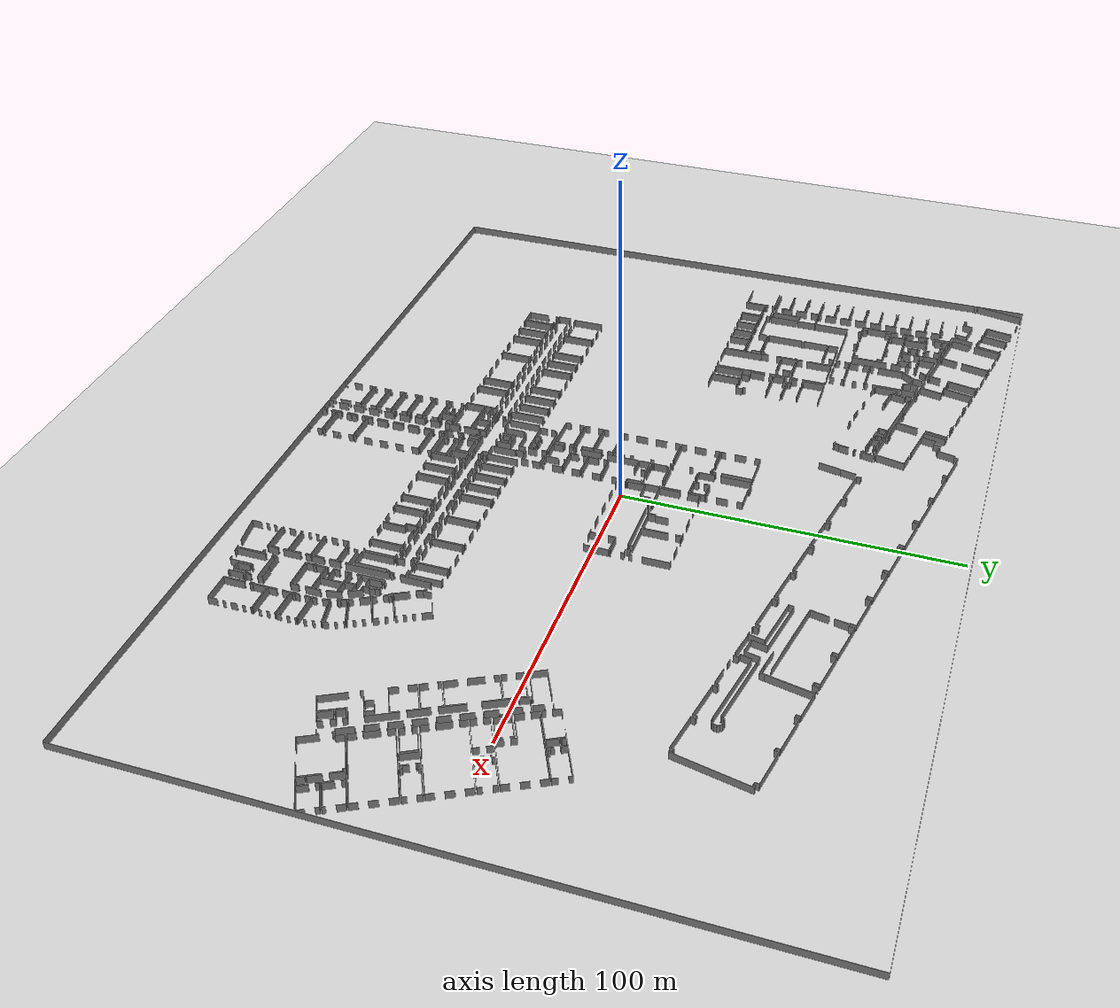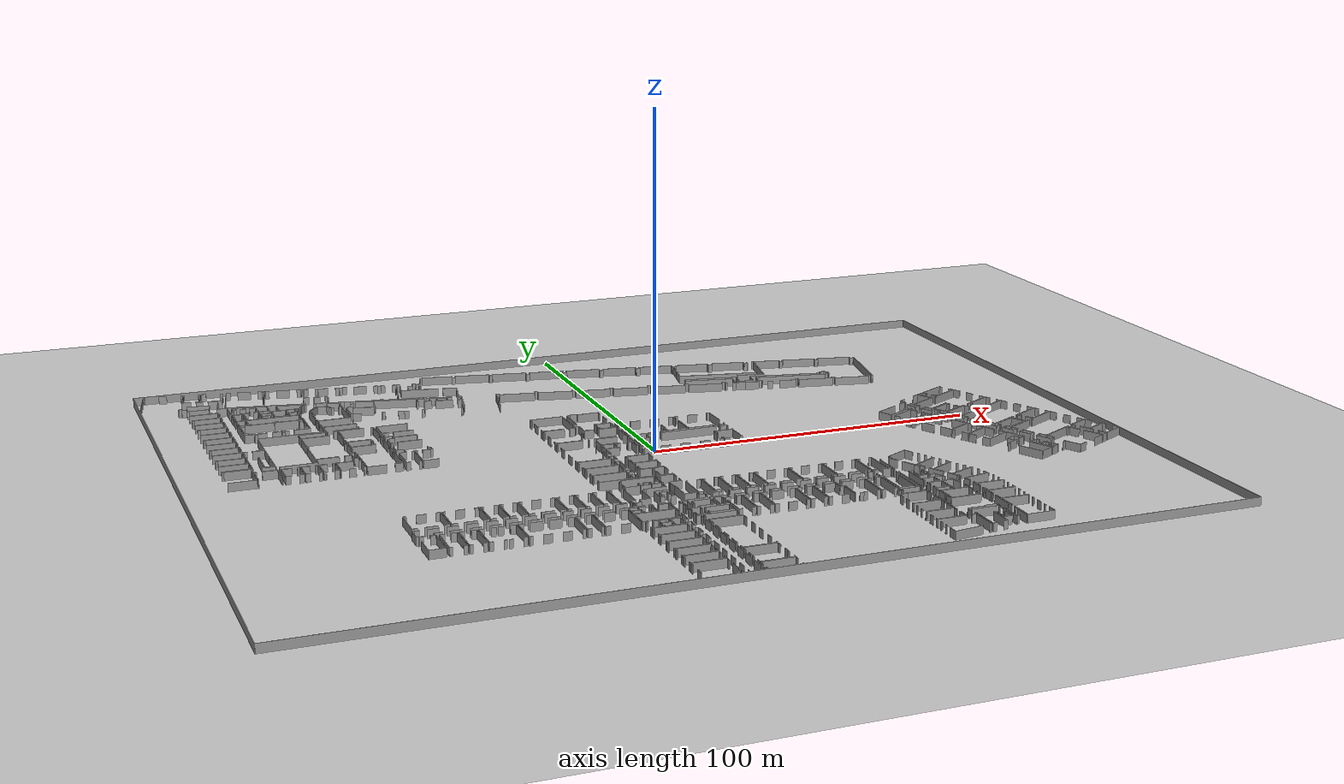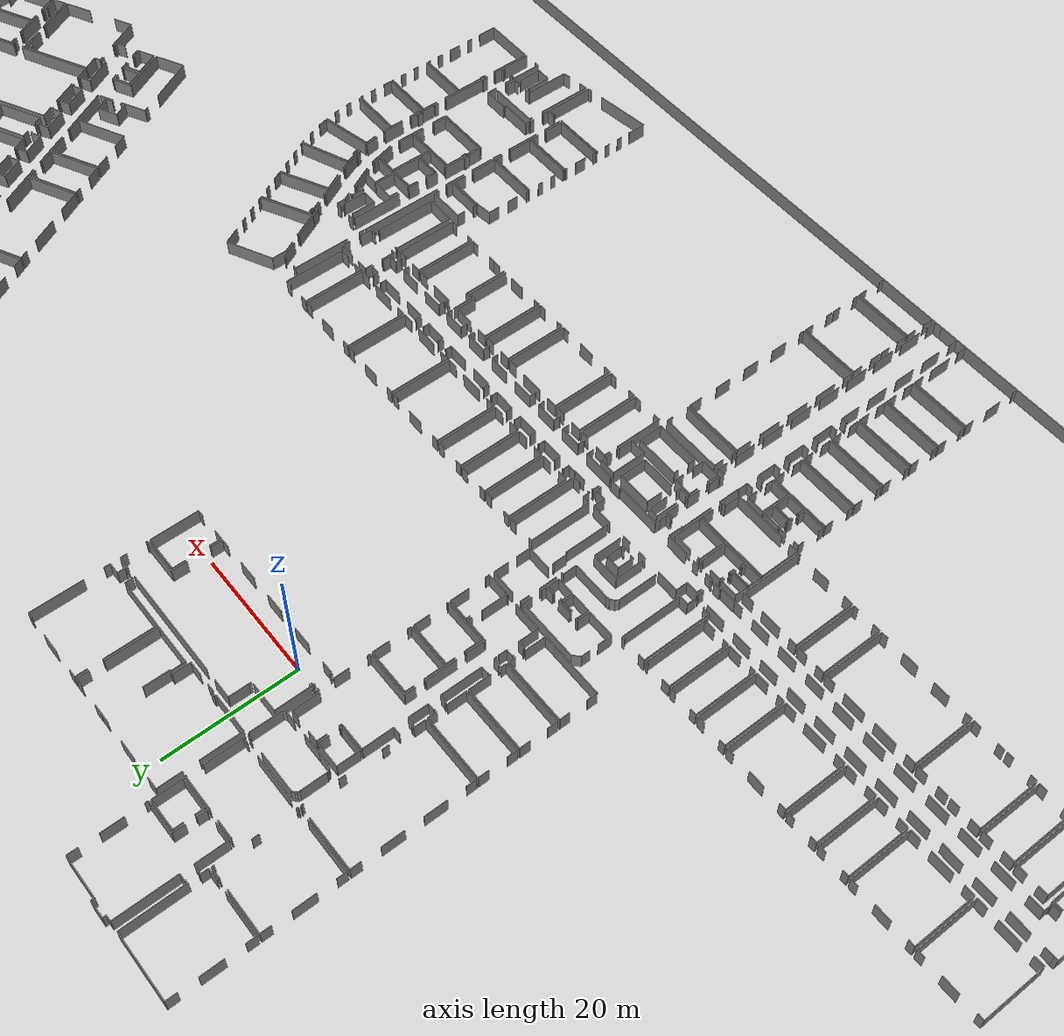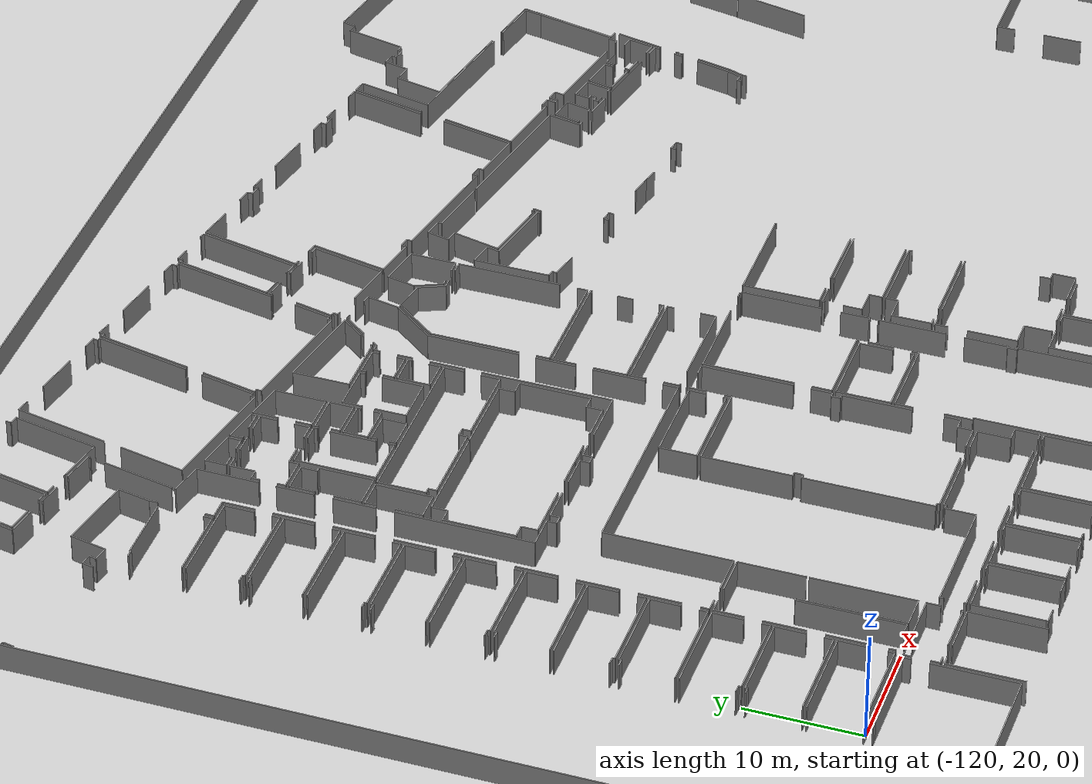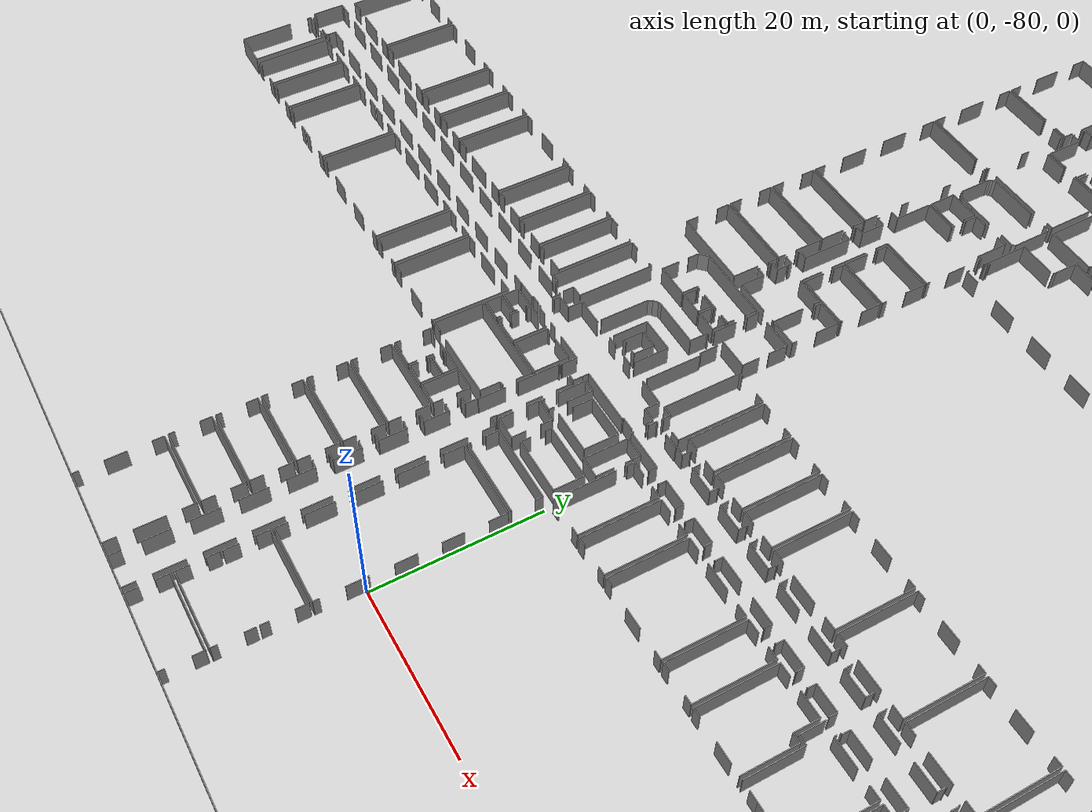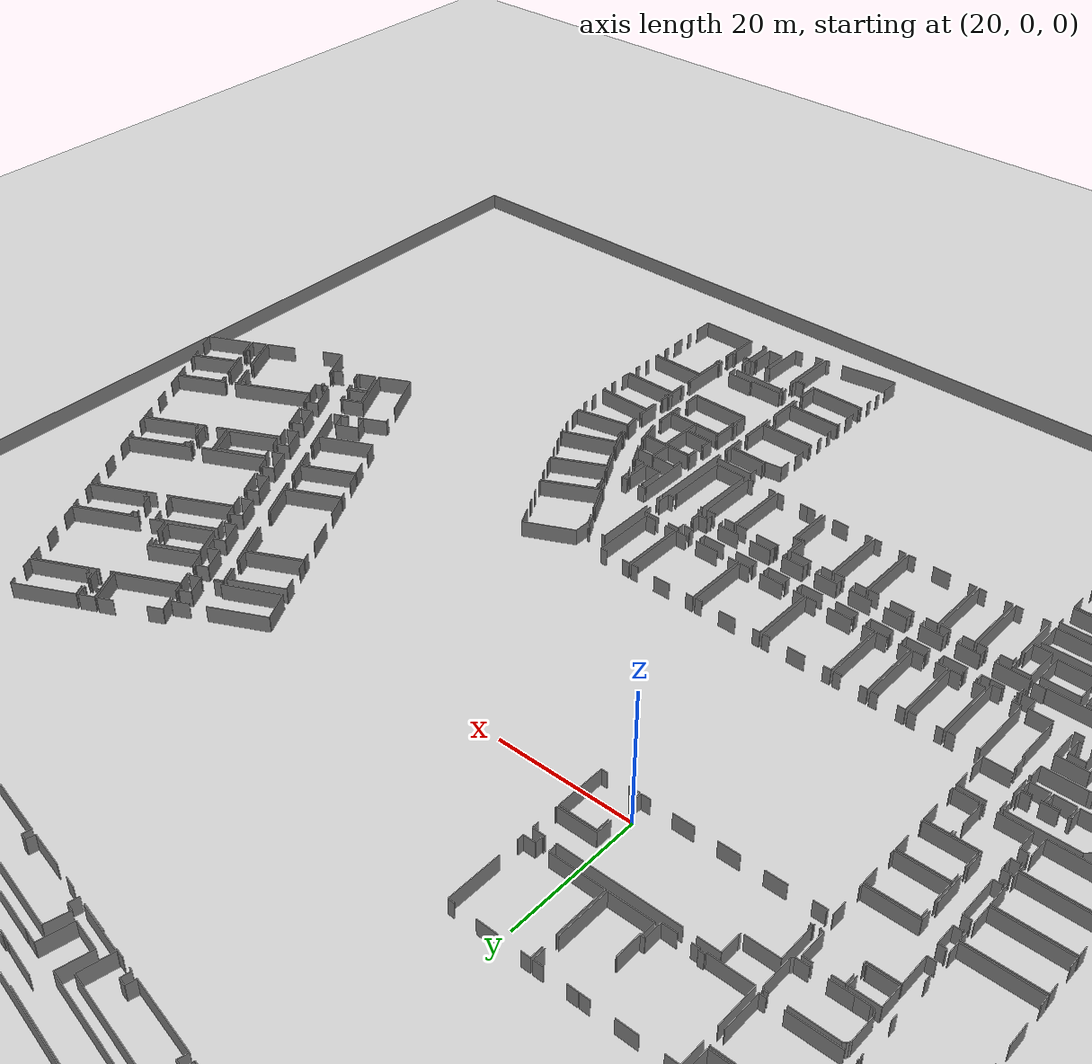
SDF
<sdf version="1.6">
  <world name="default">
    <light name="sun" type="directional">
      <cast_shadows>1</cast_shadows>
      <pose frame="">0 0 10 0 -0 0</pose>
      <diffuse>0.8 0.8 0.8 1</diffuse>
      <specular>0.1 0.1 0.1 1</specular>
      <attenuation>
        <range>1000</range>
        <constant>0.9</constant>
        <linear>0.01</linear>
        <quadratic>0.001</quadratic>
      </attenuation>
      <direction>-0.5 0.5 -1</direction>
    </light>
    <model name="ground_plane">
      <static>1</static>
      <link name="link">
        <collision name="collision">
          <geometry>
            <plane>
              <normal>0 0 1</normal>
              <size>100 100</size>
            </plane>
          </geometry>
          <surface>
            <friction>
              <ode>
                <mu>100</mu>
                <mu2>50</mu2>
              </ode>
              <torsional>
                <ode />
              </torsional>
            </friction>
            <contact>
              <ode />
            </contact>
            <bounce />
          </surface>
          <max_contacts>10</max_contacts>
        </collision>
        <visual name="visual">
          <cast_shadows>0</cast_shadows>
          <geometry>
            <plane>
              <normal>0 0 1</normal>
              <size>100 100</size>
            </plane>
          </geometry>
          <material>
            <script>
              <uri>file://media/materials/scripts/gazebo.material</uri>
              <name>Gazebo/Grey</name>
            </script>
          </material>
        </visual>
        <self_collide>0</self_collide>
        <kinematic>0</kinematic>
        <gravity>1</gravity>
      </link>
    </model>
    <gravity>0 0 -9.8</gravity>
    <magnetic_field>6e-06 2.3e-05 -4.2e-05</magnetic_field>
    <atmosphere type="adiabatic" />
    <physics default="0" name="default_physics" type="ode">
      <max_step_size>0.001</max_step_size>
      <real_time_factor>1</real_time_factor>
      <real_time_update_rate>1000</real_time_update_rate>
    </physics>
    <scene>
      <ambient>0.4 0.4 0.4 1</ambient>
      <background>0.7 0.7 0.7 1</background>
      <shadows>1</shadows>
    </scene>
    <spherical_coordinates>
      <surface_model>EARTH_WGS84</surface_model>
      <latitude_deg>0</latitude_deg>
      <longitude_deg>0</longitude_deg>
      <elevation>0</elevation>
      <heading_deg>0</heading_deg>
    </spherical_coordinates>
  <model name="0510045922_A-40">
		<static>1</static>
		<link name="Wall_0">
			<collision name="Wall_0_Collision">
				<geometry>
					<box>
						<size>8.14178123146 0.1 2.5</size>
					</box>
				</geometry>
				<pose frame="">4.07089061573 0 1.25 0 0 0</pose>
			</collision>
			<visual name="Wall_0_Visual">
				<pose frame="">4.07089061573 0 1.25 0 0 0</pose>
				<geometry>
					<box>
						<size>8.14178123146 0.1 2.5</size>
					</box>
				</geometry>
				<material>
					<script>
						<uri>file://media/materials/scripts/gazebo.material</uri>
						<name>Gazebo/Grey</name>
					</script>
					<ambient>1 1 1 1</ambient>
				</material>
			</visual>
			<pose frame="">13.5680752367 -10.2554235242 0 0 0 1.37527732791</pose>
		</link>
		<link name="Wall_1">
			<collision name="Wall_1_Collision">
				<geometry>
					<box>
						<size>0.470537639431 0.1 2.5</size>
					</box>
				</geometry>
				<pose frame="">0.235268819715 0 1.25 0 0 0</pose>
			</collision>
			<visual name="Wall_1_Visual">
				<pose frame="">0.235268819715 0 1.25 0 0 0</pose>
				<geometry>
					<box>
						<size>0.470537639431 0.1 2.5</size>
					</box>
				</geometry>
				<material>
					<script>
						<uri>file://media/materials/scripts/gazebo.material</uri>
						<name>Gazebo/Grey</name>
					</script>
					<ambient>1 1 1 1</ambient>
				</material>
			</visual>
			<pose frame="">19.3935820042 -3.08300184279 0 0 0 -0.270293359605</pose>
		</link>
		<link name="Wall_2">
			<collision name="Wall_2_Collision">
				<geometry>
					<box>
						<size>8.09494399257 0.1 2.5</size>
					</box>
				</geometry>
				<pose frame="">4.04747199628 0 1.25 0 0 0</pose>
			</collision>
			<visual name="Wall_2_Visual">
				<pose frame="">4.04747199628 0 1.25 0 0 0</pose>
				<geometry>
					<box>
						<size>8.09494399257 0.1 2.5</size>
					</box>
				</geometry>
				<material>
					<script>
						<uri>file://media/materials/scripts/gazebo.material</uri>
						<name>Gazebo/Grey</name>
					</script>
					<ambient>1 1 1 1</ambient>
				</material>
			</visual>
			<pose frame="">19.8470356485 -3.20864205376 0 0 0 -1.76435669392</pose>
		</link>
		<link name="Wall_3">
			<collision name="Wall_3_Collision">
				<geometry>
					<box>
						<size>0.907823128029 0.1 2.5</size>
					</box>
				</geometry>
				<pose frame="">0.453911564014 0 1.25 0 0 0</pose>
			</collision>
			<visual name="Wall_3_Visual">
				<pose frame="">0.453911564014 0 1.25 0 0 0</pose>
				<geometry>
					<box>
						<size>0.907823128029 0.1 2.5</size>
					</box>
				</geometry>
				<material>
					<script>
						<uri>file://media/materials/scripts/gazebo.material</uri>
						<name>Gazebo/Grey</name>
					</script>
					<ambient>1 1 1 1</ambient>
				</material>
			</visual>
			<pose frame="">18.2899409036 -11.1524178687 0 0 0 2.91712323827</pose>
		</link>
		<link name="Wall_4">
			<collision name="Wall_4_Collision">
				<geometry>
					<box>
						<size>2.33775990232 0.1 2.5</size>
					</box>
				</geometry>
				<pose frame="">1.16887995116 0 1.25 0 0 0</pose>
			</collision>
			<visual name="Wall_4_Visual">
				<pose frame="">1.16887995116 0 1.25 0 0 0</pose>
				<geometry>
					<box>
						<size>2.33775990232 0.1 2.5</size>
					</box>
				</geometry>
				<material>
					<script>
						<uri>file://media/materials/scripts/gazebo.material</uri>
						<name>Gazebo/Grey</name>
					</script>
					<ambient>1 1 1 1</ambient>
				</material>
			</visual>
			<pose frame="">15.8671157146 -10.6791383364 0 0 0 2.9593371123</pose>
		</link>
		<link name="Wall_5">
			<collision name="Wall_5_Collision">
				<geometry>
					<box>
						<size>8.10260033233 0.1 2.5</size>
					</box>
				</geometry>
				<pose frame="">4.05130016617 0 1.25 0 0 0</pose>
			</collision>
			<visual name="Wall_5_Visual">
				<pose frame="">4.05130016617 0 1.25 0 0 0</pose>
				<geometry>
					<box>
						<size>8.10260033233 0.1 2.5</size>
					</box>
				</geometry>
				<material>
					<script>
						<uri>file://media/materials/scripts/gazebo.material</uri>
						<name>Gazebo/Grey</name>
					</script>
					<ambient>1 1 1 1</ambient>
				</material>
			</visual>
			<pose frame="">18.5746203215 -11.2279087501 0 0 0 1.37527901961</pose>
		</link>
		<link name="Wall_6">
			<collision name="Wall_6_Collision">
				<geometry>
					<box>
						<size>1.59272512414 0.1 2.5</size>
					</box>
				</geometry>
				<pose frame="">0.796362562072 0 1.25 0 0 0</pose>
			</collision>
			<visual name="Wall_6_Visual">
				<pose frame="">0.796362562072 0 1.25 0 0 0</pose>
				<geometry>
					<box>
						<size>1.59272512414 0.1 2.5</size>
					</box>
				</geometry>
				<material>
					<script>
						<uri>file://media/materials/scripts/gazebo.material</uri>
						<name>Gazebo/Grey</name>
					</script>
					<ambient>1 1 1 1</ambient>
				</material>
			</visual>
			<pose frame="">20.1487449959 -3.27968481922 0 0 0 -0.185220506513</pose>
		</link>
		<link name="Wall_7">
			<collision name="Wall_7_Collision">
				<geometry>
					<box>
						<size>0.452917116611 0.1 2.5</size>
					</box>
				</geometry>
				<pose frame="">0.226458558305 0 1.25 0 0 0</pose>
			</collision>
			<visual name="Wall_7_Visual">
				<pose frame="">0.226458558305 0 1.25 0 0 0</pose>
				<geometry>
					<box>
						<size>0.452917116611 0.1 2.5</size>
					</box>
				</geometry>
				<material>
					<script>
						<uri>file://media/materials/scripts/gazebo.material</uri>
						<name>Gazebo/Grey</name>
					</script>
					<ambient>1 1 1 1</ambient>
				</material>
			</visual>
			<pose frame="">25.997127788 -4.38924826841 0 0 0 -1.75421371071</pose>
		</link>
		<link name="Wall_8">
			<collision name="Wall_8_Collision">
				<geometry>
					<box>
						<size>0.801102809044 0.1 2.5</size>
					</box>
				</geometry>
				<pose frame="">0.400551404522 0 1.25 0 0 0</pose>
			</collision>
			<visual name="Wall_8_Visual">
				<pose frame="">0.400551404522 0 1.25 0 0 0</pose>
				<geometry>
					<box>
						<size>0.801102809044 0.1 2.5</size>
					</box>
				</geometry>
				<material>
					<script>
						<uri>file://media/materials/scripts/gazebo.material</uri>
						<name>Gazebo/Grey</name>
					</script>
					<ambient>1 1 1 1</ambient>
				</material>
			</visual>
			<pose frame="">25.9145199212 -4.83456821503 0 0 0 -0.212267821891</pose>
		</link>
		<link name="Wall_9">
			<collision name="Wall_9_Collision">
				<geometry>
					<box>
						<size>7.64910427612 0.1 2.5</size>
					</box>
				</geometry>
				<pose frame="">3.82455213806 0 1.25 0 0 0</pose>
			</collision>
			<visual name="Wall_9_Visual">
				<pose frame="">3.82455213806 0 1.25 0 0 0</pose>
				<geometry>
					<box>
						<size>7.64910427612 0.1 2.5</size>
					</box>
				</geometry>
				<material>
					<script>
						<uri>file://media/materials/scripts/gazebo.material</uri>
						<name>Gazebo/Grey</name>
					</script>
					<ambient>1 1 1 1</ambient>
				</material>
			</visual>
			<pose frame="">26.6976424986 -5.00334244138 0 0 0 -1.76409926453</pose>
		</link>
		<link name="Wall_10">
			<collision name="Wall_10_Collision">
				<geometry>
					<box>
						<size>4.35893871612 0.1 2.5</size>
					</box>
				</geometry>
				<pose frame="">2.17946935806 0 1.25 0 0 0</pose>
			</collision>
			<visual name="Wall_10_Visual">
				<pose frame="">2.17946935806 0 1.25 0 0 0</pose>
				<geometry>
					<box>
						<size>4.35893871612 0.1 2.5</size>
					</box>
				</geometry>
				<material>
					<script>
						<uri>file://media/materials/scripts/gazebo.material</uri>
						<name>Gazebo/Grey</name>
					</script>
					<ambient>1 1 1 1</ambient>
				</material>
			</visual>
			<pose frame="">25.2282391815 -12.509982843 0 0 0 2.94866854822</pose>
		</link>
		<link name="Wall_11">
			<collision name="Wall_11_Collision">
				<geometry>
					<box>
						<size>0.872309041186 0.1 2.5</size>
					</box>
				</geometry>
				<pose frame="">0.436154520593 0 1.25 0 0 0</pose>
			</collision>
			<visual name="Wall_11_Visual">
				<pose frame="">0.436154520593 0 1.25 0 0 0</pose>
				<geometry>
					<box>
						<size>0.872309041186 0.1 2.5</size>
					</box>
				</geometry>
				<material>
					<script>
						<uri>file://media/materials/scripts/gazebo.material</uri>
						<name>Gazebo/Grey</name>
					</script>
					<ambient>1 1 1 1</ambient>
				</material>
			</visual>
			<pose frame="">19.4342504925 -11.3760945542 0 0 0 2.97088714714</pose>
		</link>
		<link name="Wall_12">
			<collision name="Wall_12_Collision">
				<geometry>
					<box>
						<size>15.0738394117 0.1 2.5</size>
					</box>
				</geometry>
				<pose frame="">7.53691970587 0 1.25 0 0 0</pose>
			</collision>
			<visual name="Wall_12_Visual">
				<pose frame="">7.53691970587 0 1.25 0 0 0</pose>
				<geometry>
					<box>
						<size>15.0738394117 0.1 2.5</size>
					</box>
				</geometry>
				<material>
					<script>
						<uri>file://media/materials/scripts/gazebo.material</uri>
						<name>Gazebo/Grey</name>
					</script>
					<ambient>1 1 1 1</ambient>
				</material>
			</visual>
			<pose frame="">0.0 -15.1442841711 0 0 0 1.37511012968</pose>
		</link>
		<link name="Wall_13">
			<collision name="Wall_13_Collision">
				<geometry>
					<box>
						<size>0.349707808266 0.1 2.5</size>
					</box>
				</geometry>
				<pose frame="">0.174853904133 0 1.25 0 0 0</pose>
			</collision>
			<visual name="Wall_13_Visual">
				<pose frame="">0.174853904133 0 1.25 0 0 0</pose>
				<geometry>
					<box>
						<size>0.349707808266 0.1 2.5</size>
					</box>
				</geometry>
				<material>
					<script>
						<uri>file://media/materials/scripts/gazebo.material</uri>
						<name>Gazebo/Grey</name>
					</script>
					<ambient>1 1 1 1</ambient>
				</material>
			</visual>
			<pose frame="">2.93095253225 -0.358136874881 0 0 0 -0.310373042825</pose>
		</link>
		<link name="Wall_14">
			<collision name="Wall_14_Collision">
				<geometry>
					<box>
						<size>0.485053449769 0.1 2.5</size>
					</box>
				</geometry>
				<pose frame="">0.242526724884 0 1.25 0 0 0</pose>
			</collision>
			<visual name="Wall_14_Visual">
				<pose frame="">0.242526724884 0 1.25 0 0 0</pose>
				<geometry>
					<box>
						<size>0.485053449769 0.1 2.5</size>
					</box>
				</geometry>
				<material>
					<script>
						<uri>file://media/materials/scripts/gazebo.material</uri>
						<name>Gazebo/Grey</name>
					</script>
					<ambient>1 1 1 1</ambient>
				</material>
			</visual>
			<pose frame="">3.26395119781 -0.464942492216 0 0 0 1.28182906209</pose>
		</link>
		<link name="Wall_15">
			<collision name="Wall_15_Collision">
				<geometry>
					<box>
						<size>2.36495732244 0.1 2.5</size>
					</box>
				</geometry>
				<pose frame="">1.18247866122 0 1.25 0 0 0</pose>
			</collision>
			<visual name="Wall_15_Visual">
				<pose frame="">1.18247866122 0 1.25 0 0 0</pose>
				<geometry>
					<box>
						<size>2.36495732244 0.1 2.5</size>
					</box>
				</geometry>
				<material>
					<script>
						<uri>file://media/materials/scripts/gazebo.material</uri>
						<name>Gazebo/Grey</name>
					</script>
					<ambient>1 1 1 1</ambient>
				</material>
			</visual>
			<pose frame="">7.61293766283 -0.817360360933 0 0 0 -0.208409003627</pose>
		</link>
		<link name="Wall_16">
			<collision name="Wall_16_Collision">
				<geometry>
					<box>
						<size>0.35878168747 0.1 2.5</size>
					</box>
				</geometry>
				<pose frame="">0.179390843735 0 1.25 0 0 0</pose>
			</collision>
			<visual name="Wall_16_Visual">
				<pose frame="">0.179390843735 0 1.25 0 0 0</pose>
				<geometry>
					<box>
						<size>0.35878168747 0.1 2.5</size>
					</box>
				</geometry>
				<material>
					<script>
						<uri>file://media/materials/scripts/gazebo.material</uri>
						<name>Gazebo/Grey</name>
					</script>
					<ambient>1 1 1 1</ambient>
				</material>
			</visual>
			<pose frame="">14.1834402999 -2.18908305268 0 0 0 -1.79149390125</pose>
		</link>
		<link name="Wall_17">
			<collision name="Wall_17_Collision">
				<geometry>
					<box>
						<size>0.616393483759 0.1 2.5</size>
					</box>
				</geometry>
				<pose frame="">0.30819674188 0 1.25 0 0 0</pose>
			</collision>
			<visual name="Wall_17_Visual">
				<pose frame="">0.30819674188 0 1.25 0 0 0</pose>
				<geometry>
					<box>
						<size>0.616393483759 0.1 2.5</size>
					</box>
				</geometry>
				<material>
					<script>
						<uri>file://media/materials/scripts/gazebo.material</uri>
						<name>Gazebo/Grey</name>
					</script>
					<ambient>1 1 1 1</ambient>
				</material>
			</visual>
			<pose frame="">14.1048992819 -2.53916248332 0 0 0 -0.217331605788</pose>
		</link>
		<link name="Wall_18">
			<collision name="Wall_18_Collision">
				<geometry>
					<box>
						<size>7.91513616514 0.1 2.5</size>
					</box>
				</geometry>
				<pose frame="">3.95756808257 0 1.25 0 0 0</pose>
			</collision>
			<visual name="Wall_18_Visual">
				<pose frame="">3.95756808257 0 1.25 0 0 0</pose>
				<geometry>
					<box>
						<size>7.91513616514 0.1 2.5</size>
					</box>
				</geometry>
				<material>
					<script>
						<uri>file://media/materials/scripts/gazebo.material</uri>
						<name>Gazebo/Grey</name>
					</script>
					<ambient>1 1 1 1</ambient>
				</material>
			</visual>
			<pose frame="">14.7067929084 -2.67207218657 0 0 0 -1.75873361991</pose>
		</link>
		<link name="Wall_19">
			<collision name="Wall_19_Collision">
				<geometry>
					<box>
						<size>2.68380278576 0.1 2.5</size>
					</box>
				</geometry>
				<pose frame="">1.34190139288 0 1.25 0 0 0</pose>
			</collision>
			<visual name="Wall_19_Visual">
				<pose frame="">1.34190139288 0 1.25 0 0 0</pose>
				<geometry>
					<box>
						<size>2.68380278576 0.1 2.5</size>
					</box>
				</geometry>
				<material>
					<script>
						<uri>file://media/materials/scripts/gazebo.material</uri>
						<name>Gazebo/Grey</name>
					</script>
					<ambient>1 1 1 1</ambient>
				</material>
			</visual>
			<pose frame="">13.2279850035 -10.4478363093 0 0 0 -0.200608832841</pose>
		</link>
		<link name="Wall_20">
			<collision name="Wall_20_Collision">
				<geometry>
					<box>
						<size>2.09685204779 0.1 2.5</size>
					</box>
				</geometry>
				<pose frame="">1.04842602389 0 1.25 0 0 0</pose>
			</collision>
			<visual name="Wall_20_Visual">
				<pose frame="">1.04842602389 0 1.25 0 0 0</pose>
				<geometry>
					<box>
						<size>2.09685204779 0.1 2.5</size>
					</box>
				</geometry>
				<material>
					<script>
						<uri>file://media/materials/scripts/gazebo.material</uri>
						<name>Gazebo/Grey</name>
					</script>
					<ambient>1 1 1 1</ambient>
				</material>
			</visual>
			<pose frame="">17.3721039588 -11.2998411387 0 0 0 -0.188765861805</pose>
		</link>
		<link name="Wall_21">
			<collision name="Wall_21_Collision">
				<geometry>
					<box>
						<size>2.97330858779 0.1 2.5</size>
					</box>
				</geometry>
				<pose frame="">1.48665429389 0 1.25 0 0 0</pose>
			</collision>
			<visual name="Wall_21_Visual">
				<pose frame="">1.48665429389 0 1.25 0 0 0</pose>
				<geometry>
					<box>
						<size>2.97330858779 0.1 2.5</size>
					</box>
				</geometry>
				<material>
					<script>
						<uri>file://media/materials/scripts/gazebo.material</uri>
						<name>Gazebo/Grey</name>
					</script>
					<ambient>1 1 1 1</ambient>
				</material>
			</visual>
			<pose frame="">20.9537268857 -11.9868844125 0 0 0 -0.197211141524</pose>
		</link>
		<link name="Wall_22">
			<collision name="Wall_22_Collision">
				<geometry>
					<box>
						<size>0.196789795488 0.1 2.5</size>
					</box>
				</geometry>
				<pose frame="">0.0983948977441 0 1.25 0 0 0</pose>
			</collision>
			<visual name="Wall_22_Visual">
				<pose frame="">0.0983948977441 0 1.25 0 0 0</pose>
				<geometry>
					<box>
						<size>0.196789795488 0.1 2.5</size>
					</box>
				</geometry>
				<material>
					<script>
						<uri>file://media/materials/scripts/gazebo.material</uri>
						<name>Gazebo/Grey</name>
					</script>
					<ambient>1 1 1 1</ambient>
				</material>
			</visual>
			<pose frame="">23.869403317 -12.5694605071 0 0 0 -1.8267394628</pose>
		</link>
		<link name="Wall_23">
			<collision name="Wall_23_Collision">
				<geometry>
					<box>
						<size>6.4917122181 0.1 2.5</size>
					</box>
				</geometry>
				<pose frame="">3.24585610905 0 1.25 0 0 0</pose>
			</collision>
			<visual name="Wall_23_Visual">
				<pose frame="">3.24585610905 0 1.25 0 0 0</pose>
				<geometry>
					<box>
						<size>6.4917122181 0.1 2.5</size>
					</box>
				</geometry>
				<material>
					<script>
						<uri>file://media/materials/scripts/gazebo.material</uri>
						<name>Gazebo/Grey</name>
					</script>
					<ambient>1 1 1 1</ambient>
				</material>
			</visual>
			<pose frame="">23.5732858868 -14.10723772 0 0 0 -1.7641681961</pose>
		</link>
		<link name="Wall_24">
			<collision name="Wall_24_Collision">
				<geometry>
					<box>
						<size>0.710618603475 0.1 2.5</size>
					</box>
				</geometry>
				<pose frame="">0.355309301738 0 1.25 0 0 0</pose>
			</collision>
			<visual name="Wall_24_Visual">
				<pose frame="">0.355309301738 0 1.25 0 0 0</pose>
				<geometry>
					<box>
						<size>0.710618603475 0.1 2.5</size>
					</box>
				</geometry>
				<material>
					<script>
						<uri>file://media/materials/scripts/gazebo.material</uri>
						<name>Gazebo/Grey</name>
					</script>
					<ambient>1 1 1 1</ambient>
				</material>
			</visual>
			<pose frame="">20.2529579971 -20.0989769333 0 0 0 1.61516389766</pose>
		</link>
		<link name="Wall_25">
			<collision name="Wall_25_Collision">
				<geometry>
					<box>
						<size>2.9279149752 0.1 2.5</size>
					</box>
				</geometry>
				<pose frame="">1.4639574876 0 1.25 0 0 0</pose>
			</collision>
			<visual name="Wall_25_Visual">
				<pose frame="">1.4639574876 0 1.25 0 0 0</pose>
				<geometry>
					<box>
						<size>2.9279149752 0.1 2.5</size>
					</box>
				</geometry>
				<material>
					<script>
						<uri>file://media/materials/scripts/gazebo.material</uri>
						<name>Gazebo/Grey</name>
					</script>
					<ambient>1 1 1 1</ambient>
				</material>
			</visual>
			<pose frame="">20.2214399187 -19.3890576349 0 0 0 1.38410983943</pose>
		</link>
		<link name="Wall_26">
			<collision name="Wall_26_Collision">
				<geometry>
					<box>
						<size>6.8242271529 0.1 2.5</size>
					</box>
				</geometry>
				<pose frame="">3.41211357645 0 1.25 0 0 0</pose>
			</collision>
			<visual name="Wall_26_Visual">
				<pose frame="">3.41211357645 0 1.25 0 0 0</pose>
				<geometry>
					<box>
						<size>6.8242271529 0.1 2.5</size>
					</box>
				</geometry>
				<material>
					<script>
						<uri>file://media/materials/scripts/gazebo.material</uri>
						<name>Gazebo/Grey</name>
					</script>
					<ambient>1 1 1 1</ambient>
				</material>
			</visual>
			<pose frame="">20.7648725933 -16.5120162674 0 0 0 2.94709703375</pose>
		</link>
		<link name="Wall_27">
			<collision name="Wall_27_Collision">
				<geometry>
					<box>
						<size>3.25671266517 0.1 2.5</size>
					</box>
				</geometry>
				<pose frame="">1.62835633259 0 1.25 0 0 0</pose>
			</collision>
			<visual name="Wall_27_Visual">
				<pose frame="">1.62835633259 0 1.25 0 0 0</pose>
				<geometry>
					<box>
						<size>3.25671266517 0.1 2.5</size>
					</box>
				</geometry>
				<material>
					<script>
						<uri>file://media/materials/scripts/gazebo.material</uri>
						<name>Gazebo/Grey</name>
					</script>
					<ambient>1 1 1 1</ambient>
				</material>
			</visual>
			<pose frame="">14.0693143547 -15.193086357 0 0 0 -1.7713143892</pose>
		</link>
		<link name="Wall_28">
			<collision name="Wall_28_Collision">
				<geometry>
					<box>
						<size>1.35050886483 0.1 2.5</size>
					</box>
				</geometry>
				<pose frame="">0.675254432417 0 1.25 0 0 0</pose>
			</collision>
			<visual name="Wall_28_Visual">
				<pose frame="">0.675254432417 0 1.25 0 0 0</pose>
				<geometry>
					<box>
						<size>1.35050886483 0.1 2.5</size>
					</box>
				</geometry>
				<material>
					<script>
						<uri>file://media/materials/scripts/gazebo.material</uri>
						<name>Gazebo/Grey</name>
					</script>
					<ambient>1 1 1 1</ambient>
				</material>
			</visual>
			<pose frame="">13.4206519667 -18.3845459745 0 0 0 2.9489955214</pose>
		</link>
		<link name="Wall_29">
			<collision name="Wall_29_Collision">
				<geometry>
					<box>
						<size>0.58606784245 0.1 2.5</size>
					</box>
				</geometry>
				<pose frame="">0.293033921225 0 1.25 0 0 0</pose>
			</collision>
			<visual name="Wall_29_Visual">
				<pose frame="">0.293033921225 0 1.25 0 0 0</pose>
				<geometry>
					<box>
						<size>0.58606784245 0.1 2.5</size>
					</box>
				</geometry>
				<material>
					<script>
						<uri>file://media/materials/scripts/gazebo.material</uri>
						<name>Gazebo/Grey</name>
					</script>
					<ambient>1 1 1 1</ambient>
				</material>
			</visual>
			<pose frame="">12.095113427 -18.1260468959 0 0 0 1.37348582266</pose>
		</link>
		<link name="Wall_30">
			<collision name="Wall_30_Collision">
				<geometry>
					<box>
						<size>0.960300153341 0.1 2.5</size>
					</box>
				</geometry>
				<pose frame="">0.48015007667 0 1.25 0 0 0</pose>
			</collision>
			<visual name="Wall_30_Visual">
				<pose frame="">0.48015007667 0 1.25 0 0 0</pose>
				<geometry>
					<box>
						<size>0.960300153341 0.1 2.5</size>
					</box>
				</geometry>
				<material>
					<script>
						<uri>file://media/materials/scripts/gazebo.material</uri>
						<name>Gazebo/Grey</name>
					</script>
					<ambient>1 1 1 1</ambient>
				</material>
			</visual>
			<pose frame="">12.2100019063 -17.5513503209 0 0 0 2.92280887078</pose>
		</link>
		<link name="Wall_31">
			<collision name="Wall_31_Collision">
				<geometry>
					<box>
						<size>1.00265196944 0.1 2.5</size>
					</box>
				</geometry>
				<pose frame="">0.501325984718 0 1.25 0 0 0</pose>
			</collision>
			<visual name="Wall_31_Visual">
				<pose frame="">0.501325984718 0 1.25 0 0 0</pose>
				<geometry>
					<box>
						<size>1.00265196944 0.1 2.5</size>
					</box>
				</geometry>
				<material>
					<script>
						<uri>file://media/materials/scripts/gazebo.material</uri>
						<name>Gazebo/Grey</name>
					</script>
					<ambient>1 1 1 1</ambient>
				</material>
			</visual>
			<pose frame="">11.2725932516 -17.3429243185 0 0 0 -1.7926548791</pose>
		</link>
		<link name="Wall_32">
			<collision name="Wall_32_Collision">
				<geometry>
					<box>
						<size>0.996194618678 0.1 2.5</size>
					</box>
				</geometry>
				<pose frame="">0.498097309339 0 1.25 0 0 0</pose>
			</collision>
			<visual name="Wall_32_Visual">
				<pose frame="">0.498097309339 0 1.25 0 0 0</pose>
				<geometry>
					<box>
						<size>0.996194618678 0.1 2.5</size>
					</box>
				</geometry>
				<material>
					<script>
						<uri>file://media/materials/scripts/gazebo.material</uri>
						<name>Gazebo/Grey</name>
					</script>
					<ambient>1 1 1 1</ambient>
				</material>
			</visual>
			<pose frame="">0.150142975154 -16.1991230857 0 0 0 1.37059858857</pose>
		</link>
		<link name="Wall_33">
			<collision name="Wall_33_Collision">
				<geometry>
					<box>
						<size>0.356996218963 0.1 2.5</size>
					</box>
				</geometry>
				<pose frame="">0.178498109482 0 1.25 0 0 0</pose>
			</collision>
			<visual name="Wall_33_Visual">
				<pose frame="">0.178498109482 0 1.25 0 0 0</pose>
				<geometry>
					<box>
						<size>0.356996218963 0.1 2.5</size>
					</box>
				</geometry>
				<material>
					<script>
						<uri>file://media/materials/scripts/gazebo.material</uri>
						<name>Gazebo/Grey</name>
					</script>
					<ambient>1 1 1 1</ambient>
				</material>
			</visual>
			<pose frame="">0.348249348669 -15.222825189 0 0 0 2.91977287135</pose>
		</link>
		<link name="Wall_34">
			<collision name="Wall_34_Collision">
				<geometry>
					<box>
						<size>5.95195158173 0.1 2.5</size>
					</box>
				</geometry>
				<pose frame="">2.97597579086 0 1.25 0 0 0</pose>
			</collision>
			<visual name="Wall_34_Visual">
				<pose frame="">2.97597579086 0 1.25 0 0 0</pose>
				<geometry>
					<box>
						<size>5.95195158173 0.1 2.5</size>
					</box>
				</geometry>
				<material>
					<script>
						<uri>file://media/materials/scripts/gazebo.material</uri>
						<name>Gazebo/Grey</name>
					</script>
					<ambient>1 1 1 1</ambient>
				</material>
			</visual>
			<pose frame="">24.6873482875 -20.4095825126 0 0 0 1.37389490012</pose>
		</link>
		<link name="Wall_35">
			<collision name="Wall_35_Collision">
				<geometry>
					<box>
						<size>8.41551916089 0.1 2.5</size>
					</box>
				</geometry>
				<pose frame="">4.20775958044 0 1.25 0 0 0</pose>
			</collision>
			<visual name="Wall_35_Visual">
				<pose frame="">4.20775958044 0 1.25 0 0 0</pose>
				<geometry>
					<box>
						<size>8.41551916089 0.1 2.5</size>
					</box>
				</geometry>
				<material>
					<script>
						<uri>file://media/materials/scripts/gazebo.material</uri>
						<name>Gazebo/Grey</name>
					</script>
					<ambient>1 1 1 1</ambient>
				</material>
			</visual>
			<pose frame="">26.1315879774 -13.0124928512 0 0 0 1.3771621296</pose>
		</link>
		<link name="Wall_36">
			<collision name="Wall_36_Collision">
				<geometry>
					<box>
						<size>1.24280667048 0.1 2.5</size>
					</box>
				</geometry>
				<pose frame="">0.621403335242 0 1.25 0 0 0</pose>
			</collision>
			<visual name="Wall_36_Visual">
				<pose frame="">0.621403335242 0 1.25 0 0 0</pose>
				<geometry>
					<box>
						<size>1.24280667048 0.1 2.5</size>
					</box>
				</geometry>
				<material>
					<script>
						<uri>file://media/materials/scripts/gazebo.material</uri>
						<name>Gazebo/Grey</name>
					</script>
					<ambient>1 1 1 1</ambient>
				</material>
			</visual>
			<pose frame="">27.7509563449 -4.75424795069 0 0 0 -0.216849919064</pose>
		</link>
		<link name="Wall_37">
			<collision name="Wall_37_Collision">
				<geometry>
					<box>
						<size>3.97844644951 0.1 2.5</size>
					</box>
				</geometry>
				<pose frame="">1.98922322476 0 1.25 0 0 0</pose>
			</collision>
			<visual name="Wall_37_Visual">
				<pose frame="">1.98922322476 0 1.25 0 0 0</pose>
				<geometry>
					<box>
						<size>3.97844644951 0.1 2.5</size>
					</box>
				</geometry>
				<material>
					<script>
						<uri>file://media/materials/scripts/gazebo.material</uri>
						<name>Gazebo/Grey</name>
					</script>
					<ambient>1 1 1 1</ambient>
				</material>
			</visual>
			<pose frame="">31.2118446972 -5.44789985385 0 0 0 -0.19051674492</pose>
		</link>
		<link name="Wall_38">
			<collision name="Wall_38_Collision">
				<geometry>
					<box>
						<size>1.22735672541 0.1 2.5</size>
					</box>
				</geometry>
				<pose frame="">0.613678362705 0 1.25 0 0 0</pose>
			</collision>
			<visual name="Wall_38_Visual">
				<pose frame="">0.613678362705 0 1.25 0 0 0</pose>
				<geometry>
					<box>
						<size>1.22735672541 0.1 2.5</size>
					</box>
				</geometry>
				<material>
					<script>
						<uri>file://media/materials/scripts/gazebo.material</uri>
						<name>Gazebo/Grey</name>
					</script>
					<ambient>1 1 1 1</ambient>
				</material>
			</visual>
			<pose frame="">37.3423651268 -6.64101162865 0 0 0 -0.185373393346</pose>
		</link>
		<link name="Wall_39">
			<collision name="Wall_39_Collision">
				<geometry>
					<box>
						<size>0.418908949307 0.1 2.5</size>
					</box>
				</geometry>
				<pose frame="">0.209454474653 0 1.25 0 0 0</pose>
			</collision>
			<visual name="Wall_39_Visual">
				<pose frame="">0.209454474653 0 1.25 0 0 0</pose>
				<geometry>
					<box>
						<size>0.418908949307 0.1 2.5</size>
					</box>
				</geometry>
				<material>
					<script>
						<uri>file://media/materials/scripts/gazebo.material</uri>
						<name>Gazebo/Grey</name>
					</script>
					<ambient>1 1 1 1</ambient>
				</material>
			</visual>
			<pose frame="">38.5486941603 -6.86723009468 0 0 0 -1.75569699962</pose>
		</link>
		<link name="Wall_40">
			<collision name="Wall_40_Collision">
				<geometry>
					<box>
						<size>0.352503447492 0.1 2.5</size>
					</box>
				</geometry>
				<pose frame="">0.176251723746 0 1.25 0 0 0</pose>
			</collision>
			<visual name="Wall_40_Visual">
				<pose frame="">0.176251723746 0 1.25 0 0 0</pose>
				<geometry>
					<box>
						<size>0.352503447492 0.1 2.5</size>
					</box>
				</geometry>
				<material>
					<script>
						<uri>file://media/materials/scripts/gazebo.material</uri>
						<name>Gazebo/Grey</name>
					</script>
					<ambient>1 1 1 1</ambient>
				</material>
			</visual>
			<pose frame="">38.4716782106 -7.27899853848 0 0 0 -0.218043261613</pose>
		</link>
		<link name="Wall_41">
			<collision name="Wall_41_Collision">
				<geometry>
					<box>
						<size>8.49357660351 0.1 2.5</size>
					</box>
				</geometry>
				<pose frame="">4.24678830176 0 1.25 0 0 0</pose>
			</collision>
			<visual name="Wall_41_Visual">
				<pose frame="">4.24678830176 0 1.25 0 0 0</pose>
				<geometry>
					<box>
						<size>8.49357660351 0.1 2.5</size>
					</box>
				</geometry>
				<material>
					<script>
						<uri>file://media/materials/scripts/gazebo.material</uri>
						<name>Gazebo/Grey</name>
					</script>
					<ambient>1 1 1 1</ambient>
				</material>
			</visual>
			<pose frame="">38.8158352926 -7.35525195399 0 0 0 -1.76323846854</pose>
		</link>
		<link name="Wall_42">
			<collision name="Wall_42_Collision">
				<geometry>
					<box>
						<size>4.99358772921 0.1 2.5</size>
					</box>
				</geometry>
				<pose frame="">2.49679386461 0 1.25 0 0 0</pose>
			</collision>
			<visual name="Wall_42_Visual">
				<pose frame="">2.49679386461 0 1.25 0 0 0</pose>
				<geometry>
					<box>
						<size>4.99358772921 0.1 2.5</size>
					</box>
				</geometry>
				<material>
					<script>
						<uri>file://media/materials/scripts/gazebo.material</uri>
						<name>Gazebo/Grey</name>
					</script>
					<ambient>1 1 1 1</ambient>
				</material>
			</visual>
			<pose frame="">36.8980618924 -17.2605706297 0 0 0 -1.76518715399</pose>
		</link>
		<link name="Wall_43">
			<collision name="Wall_43_Collision">
				<geometry>
					<box>
						<size>0.318166050021 0.1 2.5</size>
					</box>
				</geometry>
				<pose frame="">0.15908302501 0 1.25 0 0 0</pose>
			</collision>
			<visual name="Wall_43_Visual">
				<pose frame="">0.15908302501 0 1.25 0 0 0</pose>
				<geometry>
					<box>
						<size>0.318166050021 0.1 2.5</size>
					</box>
				</geometry>
				<material>
					<script>
						<uri>file://media/materials/scripts/gazebo.material</uri>
						<name>Gazebo/Grey</name>
					</script>
					<ambient>1 1 1 1</ambient>
				</material>
			</visual>
			<pose frame="">35.9334561861 -22.1601067548 0 0 0 2.90203924241</pose>
		</link>
		<link name="Wall_44">
			<collision name="Wall_44_Collision">
				<geometry>
					<box>
						<size>0.423587246568 0.1 2.5</size>
					</box>
				</geometry>
				<pose frame="">0.211793623284 0 1.25 0 0 0</pose>
			</collision>
			<visual name="Wall_44_Visual">
				<pose frame="">0.211793623284 0 1.25 0 0 0</pose>
				<geometry>
					<box>
						<size>0.423587246568 0.1 2.5</size>
					</box>
				</geometry>
				<material>
					<script>
						<uri>file://media/materials/scripts/gazebo.material</uri>
						<name>Gazebo/Grey</name>
					</script>
					<ambient>1 1 1 1</ambient>
				</material>
			</visual>
			<pose frame="">35.6243756752 -22.0846158734 0 0 0 -1.74936172082</pose>
		</link>
		<link name="Wall_45">
			<collision name="Wall_45_Collision">
				<geometry>
					<box>
						<size>11.0613959903 0.1 2.5</size>
					</box>
				</geometry>
				<pose frame="">5.53069799515 0 1.25 0 0 0</pose>
			</collision>
			<visual name="Wall_45_Visual">
				<pose frame="">5.53069799515 0 1.25 0 0 0</pose>
				<geometry>
					<box>
						<size>11.0613959903 0.1 2.5</size>
					</box>
				</geometry>
				<material>
					<script>
						<uri>file://media/materials/scripts/gazebo.material</uri>
						<name>Gazebo/Grey</name>
					</script>
					<ambient>1 1 1 1</ambient>
				</material>
			</visual>
			<pose frame="">35.5491389718 -22.5014678782 0 0 0 2.95133097754</pose>
		</link>
		<link name="Wall_46">
			<collision name="Wall_46_Collision">
				<geometry>
					<box>
						<size>5.09213409407 0.1 2.5</size>
					</box>
				</geometry>
				<pose frame="">2.54606704704 0 1.25 0 0 0</pose>
			</collision>
			<visual name="Wall_46_Visual">
				<pose frame="">2.54606704704 0 1.25 0 0 0</pose>
				<geometry>
					<box>
						<size>5.09213409407 0.1 2.5</size>
					</box>
				</geometry>
				<material>
					<script>
						<uri>file://media/materials/scripts/gazebo.material</uri>
						<name>Gazebo/Grey</name>
					</script>
					<ambient>1 1 1 1</ambient>
				</material>
			</visual>
			<pose frame="">36.2102560844 -22.2208553091 0 0 0 1.37069891746</pose>
		</link>
		<link name="Wall_47">
			<collision name="Wall_47_Collision">
				<geometry>
					<box>
						<size>8.43786062008 0.1 2.5</size>
					</box>
				</geometry>
				<pose frame="">4.21893031004 0 1.25 0 0 0</pose>
			</collision>
			<visual name="Wall_47_Visual">
				<pose frame="">4.21893031004 0 1.25 0 0 0</pose>
				<geometry>
					<box>
						<size>8.43786062008 0.1 2.5</size>
					</box>
				</geometry>
				<material>
					<script>
						<uri>file://media/materials/scripts/gazebo.material</uri>
						<name>Gazebo/Grey</name>
					</script>
					<ambient>1 1 1 1</ambient>
				</material>
			</visual>
			<pose frame="">37.5116477092 -15.6978839677 0 0 0 1.38059641745</pose>
		</link>
		<link name="Wall_48">
			<collision name="Wall_48_Collision">
				<geometry>
					<box>
						<size>0.303000068013 0.1 2.5</size>
					</box>
				</geometry>
				<pose frame="">0.151500034007 0 1.25 0 0 0</pose>
			</collision>
			<visual name="Wall_48_Visual">
				<pose frame="">0.151500034007 0 1.25 0 0 0</pose>
				<geometry>
					<box>
						<size>0.303000068013 0.1 2.5</size>
					</box>
				</geometry>
				<material>
					<script>
						<uri>file://media/materials/scripts/gazebo.material</uri>
						<name>Gazebo/Grey</name>
					</script>
					<ambient>1 1 1 1</ambient>
				</material>
			</visual>
			<pose frame="">39.1068691618 -7.41218783758 0 0 0 -0.250065089251</pose>
		</link>
		<link name="Wall_49">
			<collision name="Wall_49_Collision">
				<geometry>
					<box>
						<size>0.468457045048 0.1 2.5</size>
					</box>
				</geometry>
				<pose frame="">0.234228522524 0 1.25 0 0 0</pose>
			</collision>
			<visual name="Wall_49_Visual">
				<pose frame="">0.234228522524 0 1.25 0 0 0</pose>
				<geometry>
					<box>
						<size>0.468457045048 0.1 2.5</size>
					</box>
				</geometry>
				<material>
					<script>
						<uri>file://media/materials/scripts/gazebo.material</uri>
						<name>Gazebo/Grey</name>
					</script>
					<ambient>1 1 1 1</ambient>
				</material>
			</visual>
			<pose frame="">39.4004448116 -7.48717036284 0 0 0 1.34200472039</pose>
		</link>
		<link name="Wall_50">
			<collision name="Wall_50_Collision">
				<geometry>
					<box>
						<size>1.26762572395 0.1 2.5</size>
					</box>
				</geometry>
				<pose frame="">0.633812861977 0 1.25 0 0 0</pose>
			</collision>
			<visual name="Wall_50_Visual">
				<pose frame="">0.633812861977 0 1.25 0 0 0</pose>
				<geometry>
					<box>
						<size>1.26762572395 0.1 2.5</size>
					</box>
				</geometry>
				<material>
					<script>
						<uri>file://media/materials/scripts/gazebo.material</uri>
						<name>Gazebo/Grey</name>
					</script>
					<ambient>1 1 1 1</ambient>
				</material>
			</visual>
			<pose frame="">39.5066912372 -7.03092075999 0 0 0 -0.208642529363</pose>
		</link>
		<link name="Wall_51">
			<collision name="Wall_51_Collision">
				<geometry>
					<box>
						<size>3.91748504924 0.1 2.5</size>
					</box>
				</geometry>
				<pose frame="">1.95874252462 0 1.25 0 0 0</pose>
			</collision>
			<visual name="Wall_51_Visual">
				<pose frame="">1.95874252462 0 1.25 0 0 0</pose>
				<geometry>
					<box>
						<size>3.91748504924 0.1 2.5</size>
					</box>
				</geometry>
				<material>
					<script>
						<uri>file://media/materials/scripts/gazebo.material</uri>
						<name>Gazebo/Grey</name>
					</script>
					<ambient>1 1 1 1</ambient>
				</material>
			</visual>
			<pose frame="">42.989438902 -7.71237211667 0 0 0 -0.190346074917</pose>
		</link>
		<link name="Wall_52">
			<collision name="Wall_52_Collision">
				<geometry>
					<box>
						<size>1.2144086014 0.1 2.5</size>
					</box>
				</geometry>
				<pose frame="">0.607204300698 0 1.25 0 0 0</pose>
			</collision>
			<visual name="Wall_52_Visual">
				<pose frame="">0.607204300698 0 1.25 0 0 0</pose>
				<geometry>
					<box>
						<size>1.2144086014 0.1 2.5</size>
					</box>
				</geometry>
				<material>
					<script>
						<uri>file://media/materials/scripts/gazebo.material</uri>
						<name>Gazebo/Grey</name>
					</script>
					<ambient>1 1 1 1</ambient>
				</material>
			</visual>
			<pose frame="">49.1306348097 -8.90700895978 0 0 0 -0.217715462542</pose>
		</link>
		<link name="Wall_53">
			<collision name="Wall_53_Collision">
				<geometry>
					<box>
						<size>0.423572146596 0.1 2.5</size>
					</box>
				</geometry>
				<pose frame="">0.211786073298 0 1.25 0 0 0</pose>
			</collision>
			<visual name="Wall_53_Visual">
				<pose frame="">0.211786073298 0 1.25 0 0 0</pose>
				<geometry>
					<box>
						<size>0.423572146596 0.1 2.5</size>
					</box>
				</geometry>
				<material>
					<script>
						<uri>file://media/materials/scripts/gazebo.material</uri>
						<name>Gazebo/Grey</name>
					</script>
					<ambient>1 1 1 1</ambient>
				</material>
			</visual>
			<pose frame="">50.316375421 -9.16932070916 0 0 0 -1.63504931029</pose>
		</link>
		<link name="Wall_54">
			<collision name="Wall_54_Collision">
				<geometry>
					<box>
						<size>0.291605153644 0.1 2.5</size>
					</box>
				</geometry>
				<pose frame="">0.145802576822 0 1.25 0 0 0</pose>
			</collision>
			<visual name="Wall_54_Visual">
				<pose frame="">0.145802576822 0 1.25 0 0 0</pose>
				<geometry>
					<box>
						<size>0.291605153644 0.1 2.5</size>
					</box>
				</geometry>
				<material>
					<script>
						<uri>file://media/materials/scripts/gazebo.material</uri>
						<name>Gazebo/Grey</name>
					</script>
					<ambient>1 1 1 1</ambient>
				</material>
			</visual>
			<pose frame="">50.2891783694 -9.59201880918 0 0 0 -0.214319914014</pose>
		</link>
		<link name="Wall_55">
			<collision name="Wall_55_Collision">
				<geometry>
					<box>
						<size>9.2602296968 0.1 2.5</size>
					</box>
				</geometry>
				<pose frame="">4.6301148484 0 1.25 0 0 0</pose>
			</collision>
			<visual name="Wall_55_Visual">
				<pose frame="">4.6301148484 0 1.25 0 0 0</pose>
				<geometry>
					<box>
						<size>9.2602296968 0.1 2.5</size>
					</box>
				</geometry>
				<material>
					<script>
						<uri>file://media/materials/scripts/gazebo.material</uri>
						<name>Gazebo/Grey</name>
					</script>
					<ambient>1 1 1 1</ambient>
				</material>
			</visual>
			<pose frame="">50.5741119654 -9.6540382538 0 0 0 -1.75793158499</pose>
		</link>
		<link name="Wall_56">
			<collision name="Wall_56_Collision">
				<geometry>
					<box>
						<size>3.40390601522 0.1 2.5</size>
					</box>
				</geometry>
				<pose frame="">1.70195300761 0 1.25 0 0 0</pose>
			</collision>
			<visual name="Wall_56_Visual">
				<pose frame="">1.70195300761 0 1.25 0 0 0</pose>
				<geometry>
					<box>
						<size>3.40390601522 0.1 2.5</size>
					</box>
				</geometry>
				<material>
					<script>
						<uri>file://media/materials/scripts/gazebo.material</uri>
						<name>Gazebo/Grey</name>
					</script>
					<ambient>1 1 1 1</ambient>
				</material>
			</visual>
			<pose frame="">48.380555379 -21.0806125691 0 0 0 -1.7661855922</pose>
		</link>
		<link name="Wall_57">
			<collision name="Wall_57_Collision">
				<geometry>
					<box>
						<size>0.297248924413 0.1 2.5</size>
					</box>
				</geometry>
				<pose frame="">0.148624462206 0 1.25 0 0 0</pose>
			</collision>
			<visual name="Wall_57_Visual">
				<pose frame="">0.148624462206 0 1.25 0 0 0</pose>
				<geometry>
					<box>
						<size>0.297248924413 0.1 2.5</size>
					</box>
				</geometry>
				<material>
					<script>
						<uri>file://media/materials/scripts/gazebo.material</uri>
						<name>Gazebo/Grey</name>
					</script>
					<ambient>1 1 1 1</ambient>
				</material>
			</visual>
			<pose frame="">47.7196924446 -24.4197496346 0 0 0 3.00779797338</pose>
		</link>
		<link name="Wall_58">
			<collision name="Wall_58_Collision">
				<geometry>
					<box>
						<size>0.412196636696 0.1 2.5</size>
					</box>
				</geometry>
				<pose frame="">0.206098318348 0 1.25 0 0 0</pose>
			</collision>
			<visual name="Wall_58_Visual">
				<pose frame="">0.206098318348 0 1.25 0 0 0</pose>
				<geometry>
					<box>
						<size>0.412196636696 0.1 2.5</size>
					</box>
				</geometry>
				<material>
					<script>
						<uri>file://media/materials/scripts/gazebo.material</uri>
						<name>Gazebo/Grey</name>
					</script>
					<ambient>1 1 1 1</ambient>
				</material>
			</visual>
			<pose frame="">47.4251000826 -24.3800978585 0 0 0 -1.82639379509</pose>
		</link>
		<link name="Wall_59">
			<collision name="Wall_59_Collision">
				<geometry>
					<box>
						<size>11.0264823709 0.1 2.5</size>
					</box>
				</geometry>
				<pose frame="">5.51324118547 0 1.25 0 0 0</pose>
			</collision>
			<visual name="Wall_59_Visual">
				<pose frame="">5.51324118547 0 1.25 0 0 0</pose>
				<geometry>
					<box>
						<size>11.0264823709 0.1 2.5</size>
					</box>
				</geometry>
				<material>
					<script>
						<uri>file://media/materials/scripts/gazebo.material</uri>
						<name>Gazebo/Grey</name>
					</script>
					<ambient>1 1 1 1</ambient>
				</material>
			</visual>
			<pose frame="">47.3208870814 -24.7789032217 0 0 0 2.95229391806</pose>
		</link>
		<link name="Wall_60">
			<collision name="Wall_60_Collision">
				<geometry>
					<box>
						<size>0.452214757318 0.1 2.5</size>
					</box>
				</geometry>
				<pose frame="">0.226107378659 0 1.25 0 0 0</pose>
			</collision>
			<visual name="Wall_60_Visual">
				<pose frame="">0.226107378659 0 1.25 0 0 0</pose>
				<geometry>
					<box>
						<size>0.452214757318 0.1 2.5</size>
					</box>
				</geometry>
				<material>
					<script>
						<uri>file://media/materials/scripts/gazebo.material</uri>
						<name>Gazebo/Grey</name>
					</script>
					<ambient>1 1 1 1</ambient>
				</material>
			</visual>
			<pose frame="">36.4913770096 -22.7040477855 0 0 0 1.40592486246</pose>
		</link>
		<link name="Wall_61">
			<collision name="Wall_61_Collision">
				<geometry>
					<box>
						<size>0.3572734507 0.1 2.5</size>
					</box>
				</geometry>
				<pose frame="">0.17863672535 0 1.25 0 0 0</pose>
			</collision>
			<visual name="Wall_61_Visual">
				<pose frame="">0.17863672535 0 1.25 0 0 0</pose>
				<geometry>
					<box>
						<size>0.3572734507 0.1 2.5</size>
					</box>
				</geometry>
				<material>
					<script>
						<uri>file://media/materials/scripts/gazebo.material</uri>
						<name>Gazebo/Grey</name>
					</script>
					<ambient>1 1 1 1</ambient>
				</material>
			</visual>
			<pose frame="">36.5655970007 -22.2579653047 0 0 0 3.03753495948</pose>
		</link>
		<link name="Wall_62">
			<collision name="Wall_62_Collision">
				<geometry>
					<box>
						<size>3.4575962859 0.1 2.5</size>
					</box>
				</geometry>
				<pose frame="">1.72879814295 0 1.25 0 0 0</pose>
			</collision>
			<visual name="Wall_62_Visual">
				<pose frame="">1.72879814295 0 1.25 0 0 0</pose>
				<geometry>
					<box>
						<size>3.4575962859 0.1 2.5</size>
					</box>
				</geometry>
				<material>
					<script>
						<uri>file://media/materials/scripts/gazebo.material</uri>
						<name>Gazebo/Grey</name>
					</script>
					<ambient>1 1 1 1</ambient>
				</material>
			</visual>
			<pose frame="">48.0033551503 -24.4769396963 0 0 0 1.36002132428</pose>
		</link>
		<link name="Wall_63">
			<collision name="Wall_63_Collision">
				<geometry>
					<box>
						<size>0.288522655639 0.1 2.5</size>
					</box>
				</geometry>
				<pose frame="">0.144261327819 0 1.25 0 0 0</pose>
			</collision>
			<visual name="Wall_63_Visual">
				<pose frame="">0.144261327819 0 1.25 0 0 0</pose>
				<geometry>
					<box>
						<size>0.288522655639 0.1 2.5</size>
					</box>
				</geometry>
				<material>
					<script>
						<uri>file://media/materials/scripts/gazebo.material</uri>
						<name>Gazebo/Grey</name>
					</script>
					<ambient>1 1 1 1</ambient>
				</material>
			</visual>
			<pose frame="">49.1415644659 -18.7670839423 0 0 0 1.37305522446</pose>
		</link>
		<link name="Wall_64">
			<collision name="Wall_64_Collision">
				<geometry>
					<box>
						<size>1.6994669576 0.1 2.5</size>
					</box>
				</geometry>
				<pose frame="">0.849733478799 0 1.25 0 0 0</pose>
			</collision>
			<visual name="Wall_64_Visual">
				<pose frame="">0.849733478799 0 1.25 0 0 0</pose>
				<geometry>
					<box>
						<size>1.6994669576 0.1 2.5</size>
					</box>
				</geometry>
				<material>
					<script>
						<uri>file://media/materials/scripts/gazebo.material</uri>
						<name>Gazebo/Grey</name>
					</script>
					<ambient>1 1 1 1</ambient>
				</material>
			</visual>
			<pose frame="">49.1982461714 -18.4841837707 0 0 0 -0.21998296293</pose>
		</link>
		<link name="Wall_65">
			<collision name="Wall_65_Collision">
				<geometry>
					<box>
						<size>1.86109094837 0.1 2.5</size>
					</box>
				</geometry>
				<pose frame="">0.930545474187 0 1.25 0 0 0</pose>
			</collision>
			<visual name="Wall_65_Visual">
				<pose frame="">0.930545474187 0 1.25 0 0 0</pose>
				<geometry>
					<box>
						<size>1.86109094837 0.1 2.5</size>
					</box>
				</geometry>
				<material>
					<script>
						<uri>file://media/materials/scripts/gazebo.material</uri>
						<name>Gazebo/Grey</name>
					</script>
					<ambient>1 1 1 1</ambient>
				</material>
			</visual>
			<pose frame="">52.3978394866 -19.1181038317 0 0 0 -0.19795803468</pose>
		</link>
		<link name="Wall_66">
			<collision name="Wall_66_Collision">
				<geometry>
					<box>
						<size>0.62810148145 0.1 2.5</size>
					</box>
				</geometry>
				<pose frame="">0.314050740725 0 1.25 0 0 0</pose>
			</collision>
			<visual name="Wall_66_Visual">
				<pose frame="">0.314050740725 0 1.25 0 0 0</pose>
				<geometry>
					<box>
						<size>0.62810148145 0.1 2.5</size>
					</box>
				</geometry>
				<material>
					<script>
						<uri>file://media/materials/scripts/gazebo.material</uri>
						<name>Gazebo/Grey</name>
					</script>
					<ambient>1 1 1 1</ambient>
				</material>
			</visual>
			<pose frame="">55.7677320963 -19.7764249857 0 0 0 -0.191363886965</pose>
		</link>
		<link name="Wall_67">
			<collision name="Wall_67_Collision">
				<geometry>
					<box>
						<size>6.56181159559 0.1 2.5</size>
					</box>
				</geometry>
				<pose frame="">3.2809057978 0 1.25 0 0 0</pose>
			</collision>
			<visual name="Wall_67_Visual">
				<pose frame="">3.2809057978 0 1.25 0 0 0</pose>
				<geometry>
					<box>
						<size>6.56181159559 0.1 2.5</size>
					</box>
				</geometry>
				<material>
					<script>
						<uri>file://media/materials/scripts/gazebo.material</uri>
						<name>Gazebo/Grey</name>
					</script>
					<ambient>1 1 1 1</ambient>
				</material>
			</visual>
			<pose frame="">56.3843680498 -19.89588867 0 0 0 -1.76227398683</pose>
		</link>
		<link name="Wall_68">
			<collision name="Wall_68_Collision">
				<geometry>
					<box>
						<size>4.31653995928 0.1 2.5</size>
					</box>
				</geometry>
				<pose frame="">2.15826997964 0 1.25 0 0 0</pose>
			</collision>
			<visual name="Wall_68_Visual">
				<pose frame="">2.15826997964 0 1.25 0 0 0</pose>
				<geometry>
					<box>
						<size>4.31653995928 0.1 2.5</size>
					</box>
				</geometry>
				<material>
					<script>
						<uri>file://media/materials/scripts/gazebo.material</uri>
						<name>Gazebo/Grey</name>
					</script>
					<ambient>1 1 1 1</ambient>
				</material>
			</visual>
			<pose frame="">55.1355912817 -26.3377772129 0 0 0 2.95418648301</pose>
		</link>
		<link name="Wall_69">
			<collision name="Wall_69_Collision">
				<geometry>
					<box>
						<size>0.380883923465 0.1 2.5</size>
					</box>
				</geometry>
				<pose frame="">0.190441961732 0 1.25 0 0 0</pose>
			</collision>
			<visual name="Wall_69_Visual">
				<pose frame="">0.190441961732 0 1.25 0 0 0</pose>
				<geometry>
					<box>
						<size>0.380883923465 0.1 2.5</size>
					</box>
				</geometry>
				<material>
					<script>
						<uri>file://media/materials/scripts/gazebo.material</uri>
						<name>Gazebo/Grey</name>
					</script>
					<ambient>1 1 1 1</ambient>
				</material>
			</visual>
			<pose frame="">48.6327000064 -25.0498570248 0 0 0 2.90859140408</pose>
		</link>
		<link name="Wall_70">
			<collision name="Wall_70_Collision">
				<geometry>
					<box>
						<size>0.41940803448 0.1 2.5</size>
					</box>
				</geometry>
				<pose frame="">0.20970401724 0 1.25 0 0 0</pose>
			</collision>
			<visual name="Wall_70_Visual">
				<pose frame="">0.20970401724 0 1.25 0 0 0</pose>
				<geometry>
					<box>
						<size>0.41940803448 0.1 2.5</size>
					</box>
				</geometry>
				<material>
					<script>
						<uri>file://media/materials/scripts/gazebo.material</uri>
						<name>Gazebo/Grey</name>
					</script>
					<ambient>1 1 1 1</ambient>
				</material>
			</visual>
			<pose frame="">48.2621084069 -24.9619114189 0 0 0 1.28259023196</pose>
		</link>
		<link name="Wall_71">
			<collision name="Wall_71_Collision">
				<geometry>
					<box>
						<size>0.386939231184 0.1 2.5</size>
					</box>
				</geometry>
				<pose frame="">0.193469615592 0 1.25 0 0 0</pose>
			</collision>
			<visual name="Wall_71_Visual">
				<pose frame="">0.193469615592 0 1.25 0 0 0</pose>
				<geometry>
					<box>
						<size>0.386939231184 0.1 2.5</size>
					</box>
				</geometry>
				<material>
					<script>
						<uri>file://media/materials/scripts/gazebo.material</uri>
						<name>Gazebo/Grey</name>
					</script>
					<ambient>1 1 1 1</ambient>
				</material>
			</visual>
			<pose frame="">48.3813179132 -24.5598017411 0 0 0 2.92577371781</pose>
		</link>
		<link name="Wall_72">
			<collision name="Wall_72_Collision">
				<geometry>
					<box>
						<size>8.65931794927 0.1 2.5</size>
					</box>
				</geometry>
				<pose frame="">4.32965897464 0 1.25 0 0 0</pose>
			</collision>
			<visual name="Wall_72_Visual">
				<pose frame="">4.32965897464 0 1.25 0 0 0</pose>
				<geometry>
					<box>
						<size>8.65931794927 0.1 2.5</size>
					</box>
				</geometry>
				<material>
					<script>
						<uri>file://media/materials/scripts/gazebo.material</uri>
						<name>Gazebo/Grey</name>
					</script>
					<ambient>1 1 1 1</ambient>
				</material>
			</visual>
			<pose frame="">49.2269682913 -18.1982334625 0 0 0 1.37819605115</pose>
		</link>
		<link name="Wall_73">
			<collision name="Wall_73_Collision">
				<geometry>
					<box>
						<size>0.344508040493 0.1 2.5</size>
					</box>
				</geometry>
				<pose frame="">0.172254020247 0 1.25 0 0 0</pose>
			</collision>
			<visual name="Wall_73_Visual">
				<pose frame="">0.172254020247 0 1.25 0 0 0</pose>
				<geometry>
					<box>
						<size>0.344508040493 0.1 2.5</size>
					</box>
				</geometry>
				<material>
					<script>
						<uri>file://media/materials/scripts/gazebo.material</uri>
						<name>Gazebo/Grey</name>
					</script>
					<ambient>1 1 1 1</ambient>
				</material>
			</visual>
			<pose frame="">50.8844633666 -9.69902776895 0 0 0 -0.256610207262</pose>
		</link>
		<link name="Wall_74">
			<collision name="Wall_74_Collision">
				<geometry>
					<box>
						<size>0.456317213447 0.1 2.5</size>
					</box>
				</geometry>
				<pose frame="">0.228158606724 0 1.25 0 0 0</pose>
			</collision>
			<visual name="Wall_74_Visual">
				<pose frame="">0.228158606724 0 1.25 0 0 0</pose>
				<geometry>
					<box>
						<size>0.456317213447 0.1 2.5</size>
					</box>
				</geometry>
				<material>
					<script>
						<uri>file://media/materials/scripts/gazebo.material</uri>
						<name>Gazebo/Grey</name>
					</script>
					<ambient>1 1 1 1</ambient>
				</material>
			</visual>
			<pose frame="">51.2176907924 -9.78646501875 0 0 0 1.37798889293</pose>
		</link>
		<link name="Wall_75">
			<collision name="Wall_75_Collision">
				<geometry>
					<box>
						<size>1.2771323861 0.1 2.5</size>
					</box>
				</geometry>
				<pose frame="">0.638566193051 0 1.25 0 0 0</pose>
			</collision>
			<visual name="Wall_75_Visual">
				<pose frame="">0.638566193051 0 1.25 0 0 0</pose>
				<geometry>
					<box>
						<size>1.2771323861 0.1 2.5</size>
					</box>
				</geometry>
				<material>
					<script>
						<uri>file://media/materials/scripts/gazebo.material</uri>
						<name>Gazebo/Grey</name>
					</script>
					<ambient>1 1 1 1</ambient>
				</material>
			</visual>
			<pose frame="">51.3051280422 -9.33860329161 0 0 0 -0.202391615081</pose>
		</link>
		<link name="Wall_76">
			<collision name="Wall_76_Collision">
				<geometry>
					<box>
						<size>0.505325017039 0.1 2.5</size>
					</box>
				</geometry>
				<pose frame="">0.252662508519 0 1.25 0 0 0</pose>
			</collision>
			<visual name="Wall_76_Visual">
				<pose frame="">0.252662508519 0 1.25 0 0 0</pose>
				<geometry>
					<box>
						<size>0.505325017039 0.1 2.5</size>
					</box>
				</geometry>
				<material>
					<script>
						<uri>file://media/materials/scripts/gazebo.material</uri>
						<name>Gazebo/Grey</name>
					</script>
					<ambient>1 1 1 1</ambient>
				</material>
			</visual>
			<pose frame="">54.7578826968 -10.0050581432 0 0 0 -0.222651684377</pose>
		</link>
		<link name="Wall_77">
			<collision name="Wall_77_Collision">
				<geometry>
					<box>
						<size>9.07886662079 0.1 2.5</size>
					</box>
				</geometry>
				<pose frame="">4.53943331039 0 1.25 0 0 0</pose>
			</collision>
			<visual name="Wall_77_Visual">
				<pose frame="">4.53943331039 0 1.25 0 0 0</pose>
				<geometry>
					<box>
						<size>9.07886662079 0.1 2.5</size>
					</box>
				</geometry>
				<material>
					<script>
						<uri>file://media/materials/scripts/gazebo.material</uri>
						<name>Gazebo/Grey</name>
					</script>
					<ambient>1 1 1 1</ambient>
				</material>
			</visual>
			<pose frame="">55.2507339391 -10.1166423079 0 0 0 -1.76588034235</pose>
		</link>
		<link name="Wall_78">
			<collision name="Wall_78_Collision">
				<geometry>
					<box>
						<size>1.14588094732 0.1 2.5</size>
					</box>
				</geometry>
				<pose frame="">0.57294047366 0 1.25 0 0 0</pose>
			</collision>
			<visual name="Wall_78_Visual">
				<pose frame="">0.57294047366 0 1.25 0 0 0</pose>
				<geometry>
					<box>
						<size>1.14588094732 0.1 2.5</size>
					</box>
				</geometry>
				<material>
					<script>
						<uri>file://media/materials/scripts/gazebo.material</uri>
						<name>Gazebo/Grey</name>
					</script>
					<ambient>1 1 1 1</ambient>
				</material>
			</visual>
			<pose frame="">53.490805109 -19.0232954184 0 0 0 2.9272303962</pose>
		</link>
		<link name="Wall_79">
			<collision name="Wall_79_Collision">
				<geometry>
					<box>
						<size>1.68446587093 0.1 2.5</size>
					</box>
				</geometry>
				<pose frame="">0.842232935467 0 1.25 0 0 0</pose>
			</collision>
			<visual name="Wall_79_Visual">
				<pose frame="">0.842232935467 0 1.25 0 0 0</pose>
				<geometry>
					<box>
						<size>1.68446587093 0.1 2.5</size>
					</box>
				</geometry>
				<material>
					<script>
						<uri>file://media/materials/scripts/gazebo.material</uri>
						<name>Gazebo/Grey</name>
					</script>
					<ambient>1 1 1 1</ambient>
				</material>
			</visual>
			<pose frame="">50.8809048739 -18.5174810955 0 0 0 2.95091475777</pose>
		</link>
		<link name="Wall_80">
			<collision name="Wall_80_Collision">
				<geometry>
					<box>
						<size>9.09158760353 0.1 2.5</size>
					</box>
				</geometry>
				<pose frame="">4.54579380177 0 1.25 0 0 0</pose>
			</collision>
			<visual name="Wall_80_Visual">
				<pose frame="">4.54579380177 0 1.25 0 0 0</pose>
				<geometry>
					<box>
						<size>9.09158760353 0.1 2.5</size>
					</box>
				</geometry>
				<material>
					<script>
						<uri>file://media/materials/scripts/gazebo.material</uri>
						<name>Gazebo/Grey</name>
					</script>
					<ambient>1 1 1 1</ambient>
				</material>
			</visual>
			<pose frame="">53.7978521955 -19.0792145898 0 0 0 1.37613126283</pose>
		</link>
		<link name="Wall_81">
			<collision name="Wall_81_Collision">
				<geometry>
					<box>
						<size>3.09154184488 0.1 2.5</size>
					</box>
				</geometry>
				<pose frame="">1.54577092244 0 1.25 0 0 0</pose>
			</collision>
			<visual name="Wall_81_Visual">
				<pose frame="">1.54577092244 0 1.25 0 0 0</pose>
				<geometry>
					<box>
						<size>3.09154184488 0.1 2.5</size>
					</box>
				</geometry>
				<material>
					<script>
						<uri>file://media/materials/scripts/gazebo.material</uri>
						<name>Gazebo/Grey</name>
					</script>
					<ambient>1 1 1 1</ambient>
				</material>
			</visual>
			<pose frame="">55.5565101353 -10.1593442206 0 0 0 -0.20265204986</pose>
		</link>
		<link name="Wall_82">
			<collision name="Wall_82_Collision">
				<geometry>
					<box>
						<size>1.24298514589 0.1 2.5</size>
					</box>
				</geometry>
				<pose frame="">0.621492572947 0 1.25 0 0 0</pose>
			</collision>
			<visual name="Wall_82_Visual">
				<pose frame="">0.621492572947 0 1.25 0 0 0</pose>
				<geometry>
					<box>
						<size>1.24298514589 0.1 2.5</size>
					</box>
				</geometry>
				<material>
					<script>
						<uri>file://media/materials/scripts/gazebo.material</uri>
						<name>Gazebo/Grey</name>
					</script>
					<ambient>1 1 1 1</ambient>
				</material>
			</visual>
			<pose frame="">60.8934866874 -11.2070661498 0 0 0 -0.176780750931</pose>
		</link>
		<link name="Wall_83">
			<collision name="Wall_83_Collision">
				<geometry>
					<box>
						<size>0.447656548932 0.1 2.5</size>
					</box>
				</geometry>
				<pose frame="">0.223828274466 0 1.25 0 0 0</pose>
			</collision>
			<visual name="Wall_83_Visual">
				<pose frame="">0.223828274466 0 1.25 0 0 0</pose>
				<geometry>
					<box>
						<size>0.447656548932 0.1 2.5</size>
					</box>
				</geometry>
				<material>
					<script>
						<uri>file://media/materials/scripts/gazebo.material</uri>
						<name>Gazebo/Grey</name>
					</script>
					<ambient>1 1 1 1</ambient>
				</material>
			</visual>
			<pose frame="">62.1170998284 -11.4256592743 0 0 0 -1.63101920634</pose>
		</link>
		<link name="Wall_84">
			<collision name="Wall_84_Collision">
				<geometry>
					<box>
						<size>0.943000606156 0.1 2.5</size>
					</box>
				</geometry>
				<pose frame="">0.471500303078 0 1.25 0 0 0</pose>
			</collision>
			<visual name="Wall_84_Visual">
				<pose frame="">0.471500303078 0 1.25 0 0 0</pose>
				<geometry>
					<box>
						<size>0.943000606156 0.1 2.5</size>
					</box>
				</geometry>
				<material>
					<script>
						<uri>file://media/materials/scripts/gazebo.material</uri>
						<name>Gazebo/Grey</name>
					</script>
					<ambient>1 1 1 1</ambient>
				</material>
			</visual>
			<pose frame="">62.0901569549 -11.8725042893 0 0 0 -0.213201803526</pose>
		</link>
		<link name="Wall_85">
			<collision name="Wall_85_Collision">
				<geometry>
					<box>
						<size>0.470527788485 0.1 2.5</size>
					</box>
				</geometry>
				<pose frame="">0.235263894243 0 1.25 0 0 0</pose>
			</collision>
			<visual name="Wall_85_Visual">
				<pose frame="">0.235263894243 0 1.25 0 0 0</pose>
				<geometry>
					<box>
						<size>0.470527788485 0.1 2.5</size>
					</box>
				</geometry>
				<material>
					<script>
						<uri>file://media/materials/scripts/gazebo.material</uri>
						<name>Gazebo/Grey</name>
					</script>
					<ambient>1 1 1 1</ambient>
				</material>
			</visual>
			<pose frame="">63.0118065705 -12.0720340599 0 0 0 1.36736206505</pose>
		</link>
		<link name="Wall_86">
			<collision name="Wall_86_Collision">
				<geometry>
					<box>
						<size>1.2657326112 0.1 2.5</size>
					</box>
				</geometry>
				<pose frame="">0.632866305599 0 1.25 0 0 0</pose>
			</collision>
			<visual name="Wall_86_Visual">
				<pose frame="">0.632866305599 0 1.25 0 0 0</pose>
				<geometry>
					<box>
						<size>1.2657326112 0.1 2.5</size>
					</box>
				</geometry>
				<material>
					<script>
						<uri>file://media/materials/scripts/gazebo.material</uri>
						<name>Gazebo/Grey</name>
					</script>
					<ambient>1 1 1 1</ambient>
				</material>
			</visual>
			<pose frame="">63.1068691618 -11.6112092521 0 0 0 -0.2044451851</pose>
		</link>
		<link name="Wall_87">
			<collision name="Wall_87_Collision">
				<geometry>
					<box>
						<size>3.95038757422 0.1 2.5</size>
					</box>
				</geometry>
				<pose frame="">1.97519378711 0 1.25 0 0 0</pose>
			</collision>
			<visual name="Wall_87_Visual">
				<pose frame="">1.97519378711 0 1.25 0 0 0</pose>
				<geometry>
					<box>
						<size>3.95038757422 0.1 2.5</size>
					</box>
				</geometry>
				<material>
					<script>
						<uri>file://media/materials/scripts/gazebo.material</uri>
						<name>Gazebo/Grey</name>
					</script>
					<ambient>1 1 1 1</ambient>
				</material>
			</visual>
			<pose frame="">66.542593887 -12.2832560208 0 0 0 -0.197723643828</pose>
		</link>
		<link name="Wall_88">
			<collision name="Wall_88_Collision">
				<geometry>
					<box>
						<size>1.24017899547 0.1 2.5</size>
					</box>
				</geometry>
				<pose frame="">0.620089497734 0 1.25 0 0 0</pose>
			</collision>
			<visual name="Wall_88_Visual">
				<pose frame="">0.620089497734 0 1.25 0 0 0</pose>
				<geometry>
					<box>
						<size>1.24017899547 0.1 2.5</size>
					</box>
				</geometry>
				<material>
					<script>
						<uri>file://media/materials/scripts/gazebo.material</uri>
						<name>Gazebo/Grey</name>
					</script>
					<ambient>1 1 1 1</ambient>
				</material>
			</visual>
			<pose frame="">72.6891275338 -13.4875516299 0 0 0 -0.196792641799</pose>
		</link>
		<link name="Wall_89">
			<collision name="Wall_89_Collision">
				<geometry>
					<box>
						<size>0.444732933613 0.1 2.5</size>
					</box>
				</geometry>
				<pose frame="">0.222366466807 0 1.25 0 0 0</pose>
			</collision>
			<visual name="Wall_89_Visual">
				<pose frame="">0.222366466807 0 1.25 0 0 0</pose>
				<geometry>
					<box>
						<size>0.444732933613 0.1 2.5</size>
					</box>
				</geometry>
				<material>
					<script>
						<uri>file://media/materials/scripts/gazebo.material</uri>
						<name>Gazebo/Grey</name>
					</script>
					<ambient>1 1 1 1</ambient>
				</material>
			</visual>
			<pose frame="">73.9053695113 -13.7300374913 0 0 0 -1.65146948263</pose>
		</link>
		<link name="Wall_90">
			<collision name="Wall_90_Collision">
				<geometry>
					<box>
						<size>0.945616723904 0.1 2.5</size>
					</box>
				</geometry>
				<pose frame="">0.472808361952 0 1.25 0 0 0</pose>
			</collision>
			<visual name="Wall_90_Visual">
				<pose frame="">0.472808361952 0 1.25 0 0 0</pose>
				<geometry>
					<box>
						<size>0.945616723904 0.1 2.5</size>
					</box>
				</geometry>
				<material>
					<script>
						<uri>file://media/materials/scripts/gazebo.material</uri>
						<name>Gazebo/Grey</name>
					</script>
					<ambient>1 1 1 1</ambient>
				</material>
			</visual>
			<pose frame="">73.869530406 -14.1733240135 0 0 0 -0.206831728713</pose>
		</link>
		<link name="Wall_91">
			<collision name="Wall_91_Collision">
				<geometry>
					<box>
						<size>0.440850563217 0.1 2.5</size>
					</box>
				</geometry>
				<pose frame="">0.220425281608 0 1.25 0 0 0</pose>
			</collision>
			<visual name="Wall_91_Visual">
				<pose frame="">0.220425281608 0 1.25 0 0 0</pose>
				<geometry>
					<box>
						<size>0.440850563217 0.1 2.5</size>
					</box>
				</geometry>
				<material>
					<script>
						<uri>file://media/materials/scripts/gazebo.material</uri>
						<name>Gazebo/Grey</name>
					</script>
					<ambient>1 1 1 1</ambient>
				</material>
			</visual>
			<pose frame="">74.7949926924 -14.367516045 0 0 0 1.34399747874</pose>
		</link>
		<link name="Wall_92">
			<collision name="Wall_92_Collision">
				<geometry>
					<box>
						<size>1.28580077034 0.1 2.5</size>
					</box>
				</geometry>
				<pose frame="">0.642900385171 0 1.25 0 0 0</pose>
			</collision>
			<visual name="Wall_92_Visual">
				<pose frame="">0.642900385171 0 1.25 0 0 0</pose>
				<geometry>
					<box>
						<size>1.28580077034 0.1 2.5</size>
					</box>
				</geometry>
				<material>
					<script>
						<uri>file://media/materials/scripts/gazebo.material</uri>
						<name>Gazebo/Grey</name>
					</script>
					<ambient>1 1 1 1</ambient>
				</material>
			</visual>
			<pose frame="">74.8941221326 -13.9379551376 0 0 0 -0.184291471257</pose>
		</link>
		<link name="Wall_93">
			<collision name="Wall_93_Collision">
				<geometry>
					<box>
						<size>1.02407150995 0.1 2.5</size>
					</box>
				</geometry>
				<pose frame="">0.512035754976 0 1.25 0 0 0</pose>
			</collision>
			<visual name="Wall_93_Visual">
				<pose frame="">0.512035754976 0 1.25 0 0 0</pose>
				<geometry>
					<box>
						<size>1.02407150995 0.1 2.5</size>
					</box>
				</geometry>
				<material>
					<script>
						<uri>file://media/materials/scripts/gazebo.material</uri>
						<name>Gazebo/Grey</name>
					</script>
					<ambient>1 1 1 1</ambient>
				</material>
			</visual>
			<pose frame="">78.38042829 -14.6087310161 0 0 0 -0.205719370914</pose>
		</link>
		<link name="Wall_94">
			<collision name="Wall_94_Collision">
				<geometry>
					<box>
						<size>6.83988586814 0.1 2.5</size>
					</box>
				</geometry>
				<pose frame="">3.41994293407 0 1.25 0 0 0</pose>
			</collision>
			<visual name="Wall_94_Visual">
				<pose frame="">3.41994293407 0 1.25 0 0 0</pose>
				<geometry>
					<box>
						<size>6.83988586814 0.1 2.5</size>
					</box>
				</geometry>
				<material>
					<script>
						<uri>file://media/materials/scripts/gazebo.material</uri>
						<name>Gazebo/Grey</name>
					</script>
					<ambient>1 1 1 1</ambient>
				</material>
			</visual>
			<pose frame="">79.382906526 -14.8179195526 0 0 0 -1.76499249226</pose>
		</link>
		<link name="Wall_95">
			<collision name="Wall_95_Collision">
				<geometry>
					<box>
						<size>6.72798577804 0.1 2.5</size>
					</box>
				</geometry>
				<pose frame="">3.36399288902 0 1.25 0 0 0</pose>
			</collision>
			<visual name="Wall_95_Visual">
				<pose frame="">3.36399288902 0 1.25 0 0 0</pose>
				<geometry>
					<box>
						<size>6.72798577804 0.1 2.5</size>
					</box>
				</geometry>
				<material>
					<script>
						<uri>file://media/materials/scripts/gazebo.material</uri>
						<name>Gazebo/Grey</name>
					</script>
					<ambient>1 1 1 1</ambient>
				</material>
			</visual>
			<pose frame="">77.6471246108 -23.8374277181 0 0 0 -1.76164218258</pose>
		</link>
		<link name="Wall_96">
			<collision name="Wall_96_Collision">
				<geometry>
					<box>
						<size>4.60174933027 0.1 2.5</size>
					</box>
				</geometry>
				<pose frame="">2.30087466514 0 1.25 0 0 0</pose>
			</collision>
			<visual name="Wall_96_Visual">
				<pose frame="">2.30087466514 0 1.25 0 0 0</pose>
				<geometry>
					<box>
						<size>4.60174933027 0.1 2.5</size>
					</box>
				</geometry>
				<material>
					<script>
						<uri>file://media/materials/scripts/gazebo.material</uri>
						<name>Gazebo/Grey</name>
					</script>
					<ambient>1 1 1 1</ambient>
				</material>
			</visual>
			<pose frame="">76.3708966131 -30.4432611044 0 0 0 2.95053414453</pose>
		</link>
		<link name="Wall_97">
			<collision name="Wall_97_Collision">
				<geometry>
					<box>
						<size>0.438323030585 0.1 2.5</size>
					</box>
				</geometry>
				<pose frame="">0.219161515292 0 1.25 0 0 0</pose>
			</collision>
			<visual name="Wall_97_Visual">
				<pose frame="">0.219161515292 0 1.25 0 0 0</pose>
				<geometry>
					<box>
						<size>0.438323030585 0.1 2.5</size>
					</box>
				</geometry>
				<material>
					<script>
						<uri>file://media/materials/scripts/gazebo.material</uri>
						<name>Gazebo/Grey</name>
					</script>
					<ambient>1 1 1 1</ambient>
				</material>
			</visual>
			<pose frame="">71.8528817437 -29.5693969626 0 0 0 1.39535151213</pose>
		</link>
		<link name="Wall_98">
			<collision name="Wall_98_Collision">
				<geometry>
					<box>
						<size>0.98778316563 0.1 2.5</size>
					</box>
				</geometry>
				<pose frame="">0.493891582815 0 1.25 0 0 0</pose>
			</collision>
			<visual name="Wall_98_Visual">
				<pose frame="">0.493891582815 0 1.25 0 0 0</pose>
				<geometry>
					<box>
						<size>0.98778316563 0.1 2.5</size>
					</box>
				</geometry>
				<material>
					<script>
						<uri>file://media/materials/scripts/gazebo.material</uri>
						<name>Gazebo/Grey</name>
					</script>
					<ambient>1 1 1 1</ambient>
				</material>
			</visual>
			<pose frame="">71.9293893372 -29.1378026307 0 0 0 2.93556748207</pose>
		</link>
		<link name="Wall_99">
			<collision name="Wall_99_Collision">
				<geometry>
					<box>
						<size>0.470670016431 0.1 2.5</size>
					</box>
				</geometry>
				<pose frame="">0.235335008216 0 1.25 0 0 0</pose>
			</collision>
			<visual name="Wall_99_Visual">
				<pose frame="">0.235335008216 0 1.25 0 0 0</pose>
				<geometry>
					<box>
						<size>0.470670016431 0.1 2.5</size>
					</box>
				</geometry>
				<material>
					<script>
						<uri>file://media/materials/scripts/gazebo.material</uri>
						<name>Gazebo/Grey</name>
					</script>
					<ambient>1 1 1 1</ambient>
				</material>
			</visual>
			<pose frame="">70.9624960285 -28.9357310796 0 0 0 -1.79350695638</pose>
		</link>
		<link name="Wall_100">
			<collision name="Wall_100_Collision">
				<geometry>
					<box>
						<size>11.0022777959 0.1 2.5</size>
					</box>
				</geometry>
				<pose frame="">5.50113889794 0 1.25 0 0 0</pose>
			</collision>
			<visual name="Wall_100_Visual">
				<pose frame="">5.50113889794 0 1.25 0 0 0</pose>
				<geometry>
					<box>
						<size>11.0022777959 0.1 2.5</size>
					</box>
				</geometry>
				<material>
					<script>
						<uri>file://media/materials/scripts/gazebo.material</uri>
						<name>Gazebo/Grey</name>
					</script>
					<ambient>1 1 1 1</ambient>
				</material>
			</visual>
			<pose frame="">70.8585372053 -29.394776641 0 0 0 2.94810712895</pose>
		</link>
		<link name="Wall_101">
			<collision name="Wall_101_Collision">
				<geometry>
					<box>
						<size>0.454683614149 0.1 2.5</size>
					</box>
				</geometry>
				<pose frame="">0.227341807075 0 1.25 0 0 0</pose>
			</collision>
			<visual name="Wall_101_Visual">
				<pose frame="">0.227341807075 0 1.25 0 0 0</pose>
				<geometry>
					<box>
						<size>0.454683614149 0.1 2.5</size>
					</box>
				</geometry>
				<material>
					<script>
						<uri>file://media/materials/scripts/gazebo.material</uri>
						<name>Gazebo/Grey</name>
					</script>
					<ambient>1 1 1 1</ambient>
				</material>
			</visual>
			<pose frame="">60.0615619241 -27.2792527165 0 0 0 1.3818426232</pose>
		</link>
		<link name="Wall_102">
			<collision name="Wall_102_Collision">
				<geometry>
					<box>
						<size>0.945822248485 0.1 2.5</size>
					</box>
				</geometry>
				<pose frame="">0.472911124243 0 1.25 0 0 0</pose>
			</collision>
			<visual name="Wall_102_Visual">
				<pose frame="">0.472911124243 0 1.25 0 0 0</pose>
				<geometry>
					<box>
						<size>0.945822248485 0.1 2.5</size>
					</box>
				</geometry>
				<material>
					<script>
						<uri>file://media/materials/scripts/gazebo.material</uri>
						<name>Gazebo/Grey</name>
					</script>
					<ambient>1 1 1 1</ambient>
				</material>
			</visual>
			<pose frame="">60.1469657495 -26.8326618796 0 0 0 2.9646475897</pose>
		</link>
		<link name="Wall_103">
			<collision name="Wall_103_Collision">
				<geometry>
					<box>
						<size>0.4368459317 0.1 2.5</size>
					</box>
				</geometry>
				<pose frame="">0.21842296585 0 1.25 0 0 0</pose>
			</collision>
			<visual name="Wall_103_Visual">
				<pose frame="">0.21842296585 0 1.25 0 0 0</pose>
				<geometry>
					<box>
						<size>0.4368459317 0.1 2.5</size>
					</box>
				</geometry>
				<material>
					<script>
						<uri>file://media/materials/scripts/gazebo.material</uri>
						<name>Gazebo/Grey</name>
					</script>
					<ambient>1 1 1 1</ambient>
				</material>
			</visual>
			<pose frame="">59.215911546 -26.6661752558 0 0 0 -1.82367773254</pose>
		</link>
		<link name="Wall_104">
			<collision name="Wall_104_Collision">
				<geometry>
					<box>
						<size>3.68449048973 0.1 2.5</size>
					</box>
				</geometry>
				<pose frame="">1.84224524487 0 1.25 0 0 0</pose>
			</collision>
			<visual name="Wall_104_Visual">
				<pose frame="">1.84224524487 0 1.25 0 0 0</pose>
				<geometry>
					<box>
						<size>3.68449048973 0.1 2.5</size>
					</box>
				</geometry>
				<material>
					<script>
						<uri>file://media/materials/scripts/gazebo.material</uri>
						<name>Gazebo/Grey</name>
					</script>
					<ambient>1 1 1 1</ambient>
				</material>
			</visual>
			<pose frame="">59.1066149838 -27.0891275338 0 0 0 2.94910823361</pose>
		</link>
		<link name="Wall_105">
			<collision name="Wall_105_Collision">
				<geometry>
					<box>
						<size>6.83020783622 0.1 2.5</size>
					</box>
				</geometry>
				<pose frame="">3.41510391811 0 1.25 0 0 0</pose>
			</collision>
			<visual name="Wall_105_Visual">
				<pose frame="">3.41510391811 0 1.25 0 0 0</pose>
				<geometry>
					<box>
						<size>6.83020783622 0.1 2.5</size>
					</box>
				</geometry>
				<material>
					<script>
						<uri>file://media/materials/scripts/gazebo.material</uri>
						<name>Gazebo/Grey</name>
					</script>
					<ambient>1 1 1 1</ambient>
				</material>
			</visual>
			<pose frame="">55.4901696638 -26.3842917964 0 0 0 1.38155297842</pose>
		</link>
		<link name="Wall_106">
			<collision name="Wall_106_Collision">
				<geometry>
					<box>
						<size>1.02249464503 0.1 2.5</size>
					</box>
				</geometry>
				<pose frame="">0.511247322515 0 1.25 0 0 0</pose>
			</collision>
			<visual name="Wall_106_Visual">
				<pose frame="">0.511247322515 0 1.25 0 0 0</pose>
				<geometry>
					<box>
						<size>1.02249464503 0.1 2.5</size>
					</box>
				</geometry>
				<material>
					<script>
						<uri>file://media/materials/scripts/gazebo.material</uri>
						<name>Gazebo/Grey</name>
					</script>
					<ambient>1 1 1 1</ambient>
				</material>
			</visual>
			<pose frame="">56.7750397153 -19.6760246553 0 0 0 2.92996109794</pose>
		</link>
		<link name="Wall_107">
			<collision name="Wall_107_Collision">
				<geometry>
					<box>
						<size>0.473514677326 0.1 2.5</size>
					</box>
				</geometry>
				<pose frame="">0.236757338663 0 1.25 0 0 0</pose>
			</collision>
			<visual name="Wall_107_Visual">
				<pose frame="">0.236757338663 0 1.25 0 0 0</pose>
				<geometry>
					<box>
						<size>0.473514677326 0.1 2.5</size>
					</box>
				</geometry>
				<material>
					<script>
						<uri>file://media/materials/scripts/gazebo.material</uri>
						<name>Gazebo/Grey</name>
					</script>
					<ambient>1 1 1 1</ambient>
				</material>
			</visual>
			<pose frame="">54.2607104277 -19.1791065641 0 0 0 2.92903716867</pose>
		</link>
		<link name="Wall_108">
			<collision name="Wall_108_Collision">
				<geometry>
					<box>
						<size>6.77006494928 0.1 2.5</size>
					</box>
				</geometry>
				<pose frame="">3.38503247464 0 1.25 0 0 0</pose>
			</collision>
			<visual name="Wall_108_Visual">
				<pose frame="">3.38503247464 0 1.25 0 0 0</pose>
				<geometry>
					<box>
						<size>6.77006494928 0.1 2.5</size>
					</box>
				</geometry>
				<material>
					<script>
						<uri>file://media/materials/scripts/gazebo.material</uri>
						<name>Gazebo/Grey</name>
					</script>
					<ambient>1 1 1 1</ambient>
				</material>
			</visual>
			<pose frame="">76.6443921967 -30.4981635636 0 0 0 1.37265709748</pose>
		</link>
		<link name="Wall_109">
			<collision name="Wall_109_Collision">
				<geometry>
					<box>
						<size>6.77834414775 0.1 2.5</size>
					</box>
				</geometry>
				<pose frame="">3.38917207388 0 1.25 0 0 0</pose>
			</collision>
			<visual name="Wall_109_Visual">
				<pose frame="">3.38917207388 0 1.25 0 0 0</pose>
				<geometry>
					<box>
						<size>6.77834414775 0.1 2.5</size>
					</box>
				</geometry>
				<material>
					<script>
						<uri>file://media/materials/scripts/gazebo.material</uri>
						<name>Gazebo/Grey</name>
					</script>
					<ambient>1 1 1 1</ambient>
				</material>
			</visual>
			<pose frame="">78.4152506831 -21.5111901887 0 0 0 1.38363781114</pose>
		</link>
		<link name="Wall_110">
			<collision name="Wall_110_Collision">
				<geometry>
					<box>
						<size>1.13357555135 0.1 2.5</size>
					</box>
				</geometry>
				<pose frame="">0.566787775673 0 1.25 0 0 0</pose>
			</collision>
			<visual name="Wall_110_Visual">
				<pose frame="">0.566787775673 0 1.25 0 0 0</pose>
				<geometry>
					<box>
						<size>1.13357555135 0.1 2.5</size>
					</box>
				</geometry>
				<material>
					<script>
						<uri>file://media/materials/scripts/gazebo.material</uri>
						<name>Gazebo/Grey</name>
					</script>
					<ambient>1 1 1 1</ambient>
				</material>
			</visual>
			<pose frame="">79.6764821758 -14.8512168774 0 0 0 -0.208697246725</pose>
		</link>
		<link name="Wall_111">
			<collision name="Wall_111_Collision">
				<geometry>
					<box>
						<size>6.689226407 0.1 2.5</size>
					</box>
				</geometry>
				<pose frame="">3.3446132035 0 1.25 0 0 0</pose>
			</collision>
			<visual name="Wall_111_Visual">
				<pose frame="">3.3446132035 0 1.25 0 0 0</pose>
				<geometry>
					<box>
						<size>6.689226407 0.1 2.5</size>
					</box>
				</geometry>
				<material>
					<script>
						<uri>file://media/materials/scripts/gazebo.material</uri>
						<name>Gazebo/Grey</name>
					</script>
					<ambient>1 1 1 1</ambient>
				</material>
			</visual>
			<pose frame="">80.7854610154 -15.0860773972 0 0 0 -1.75703594367</pose>
		</link>
		<link name="Wall_112">
			<collision name="Wall_112_Collision">
				<geometry>
					<box>
						<size>11.5195300793 0.1 2.5</size>
					</box>
				</geometry>
				<pose frame="">5.75976503967 0 1.25 0 0 0</pose>
			</collision>
			<visual name="Wall_112_Visual">
				<pose frame="">5.75976503967 0 1.25 0 0 0</pose>
				<geometry>
					<box>
						<size>11.5195300793 0.1 2.5</size>
					</box>
				</geometry>
				<material>
					<script>
						<uri>file://media/materials/scripts/gazebo.material</uri>
						<name>Gazebo/Grey</name>
					</script>
					<ambient>1 1 1 1</ambient>
				</material>
			</visual>
			<pose frame="">79.5468513694 -21.6596301709 0 0 0 -0.196110352566</pose>
		</link>
		<link name="Wall_113">
			<collision name="Wall_113_Collision">
				<geometry>
					<box>
						<size>4.13901485271 0.1 2.5</size>
					</box>
				</geometry>
				<pose frame="">2.06950742636 0 1.25 0 0 0</pose>
			</collision>
			<visual name="Wall_113_Visual">
				<pose frame="">2.06950742636 0 1.25 0 0 0</pose>
				<geometry>
					<box>
						<size>4.13901485271 0.1 2.5</size>
					</box>
				</geometry>
				<material>
					<script>
						<uri>file://media/materials/scripts/gazebo.material</uri>
						<name>Gazebo/Grey</name>
					</script>
					<ambient>1 1 1 1</ambient>
				</material>
			</visual>
			<pose frame="">92.3843680498 -24.1988689077 0 0 0 -0.196672947007</pose>
		</link>
		<link name="Wall_114">
			<collision name="Wall_114_Collision">
				<geometry>
					<box>
						<size>1.57245915888 0.1 2.5</size>
					</box>
				</geometry>
				<pose frame="">0.786229579441 0 1.25 0 0 0</pose>
			</collision>
			<visual name="Wall_114_Visual">
				<pose frame="">0.786229579441 0 1.25 0 0 0</pose>
				<geometry>
					<box>
						<size>1.57245915888 0.1 2.5</size>
					</box>
				</geometry>
				<material>
					<script>
						<uri>file://media/materials/scripts/gazebo.material</uri>
						<name>Gazebo/Grey</name>
					</script>
					<ambient>1 1 1 1</ambient>
				</material>
			</visual>
			<pose frame="">96.4435915359 -25.0076634683 0 0 0 -1.74200392555</pose>
		</link>
		<link name="Wall_115">
			<collision name="Wall_115_Collision">
				<geometry>
					<box>
						<size>7.15501788834 0.1 2.5</size>
					</box>
				</geometry>
				<pose frame="">3.57750894417 0 1.25 0 0 0</pose>
			</collision>
			<visual name="Wall_115_Visual">
				<pose frame="">3.57750894417 0 1.25 0 0 0</pose>
				<geometry>
					<box>
						<size>7.15501788834 0.1 2.5</size>
					</box>
				</geometry>
				<material>
					<script>
						<uri>file://media/materials/scripts/gazebo.material</uri>
						<name>Gazebo/Grey</name>
					</script>
					<ambient>1 1 1 1</ambient>
				</material>
			</visual>
			<pose frame="">96.1756878694 -26.5571328716 0 0 0 -1.76360763908</pose>
		</link>
		<link name="Wall_116">
			<collision name="Wall_116_Collision">
				<geometry>
					<box>
						<size>0.23364936342 0.1 2.5</size>
					</box>
				</geometry>
				<pose frame="">0.11682468171 0 1.25 0 0 0</pose>
			</collision>
			<visual name="Wall_116_Visual">
				<pose frame="">0.11682468171 0 1.25 0 0 0</pose>
				<geometry>
					<box>
						<size>0.23364936342 0.1 2.5</size>
					</box>
				</geometry>
				<material>
					<script>
						<uri>file://media/materials/scripts/gazebo.material</uri>
						<name>Gazebo/Grey</name>
					</script>
					<ambient>1 1 1 1</ambient>
				</material>
			</visual>
			<pose frame="">94.8046514583 -33.5795640846 0 0 0 2.95337114828</pose>
		</link>
		<link name="Wall_117">
			<collision name="Wall_117_Collision">
				<geometry>
					<box>
						<size>0.800221337031 0.1 2.5</size>
					</box>
				</geometry>
				<pose frame="">0.400110668516 0 1.25 0 0 0</pose>
			</collision>
			<visual name="Wall_117_Visual">
				<pose frame="">0.400110668516 0 1.25 0 0 0</pose>
				<geometry>
					<box>
						<size>0.800221337031 0.1 2.5</size>
					</box>
				</geometry>
				<material>
					<script>
						<uri>file://media/materials/scripts/gazebo.material</uri>
						<name>Gazebo/Grey</name>
					</script>
					<ambient>1 1 1 1</ambient>
				</material>
			</visual>
			<pose frame="">94.5751286776 -33.5358454597 0 0 0 -1.77161802411</pose>
		</link>
		<link name="Wall_118">
			<collision name="Wall_118_Collision">
				<geometry>
					<box>
						<size>0.281087829553 0.1 2.5</size>
					</box>
				</geometry>
				<pose frame="">0.140543914777 0 1.25 0 0 0</pose>
			</collision>
			<visual name="Wall_118_Visual">
				<pose frame="">0.140543914777 0 1.25 0 0 0</pose>
				<geometry>
					<box>
						<size>0.281087829553 0.1 2.5</size>
					</box>
				</geometry>
				<material>
					<script>
						<uri>file://media/materials/scripts/gazebo.material</uri>
						<name>Gazebo/Grey</name>
					</script>
					<ambient>1 1 1 1</ambient>
				</material>
			</visual>
			<pose frame="">94.4155048612 -34.3199847493 0 0 0 2.96157739385</pose>
		</link>
		<link name="Wall_119">
			<collision name="Wall_119_Collision">
				<geometry>
					<box>
						<size>7.84579659776 0.1 2.5</size>
					</box>
				</geometry>
				<pose frame="">3.92289829888 0 1.25 0 0 0</pose>
			</collision>
			<visual name="Wall_119_Visual">
				<pose frame="">3.92289829888 0 1.25 0 0 0</pose>
				<geometry>
					<box>
						<size>7.84579659776 0.1 2.5</size>
					</box>
				</geometry>
				<material>
					<script>
						<uri>file://media/materials/scripts/gazebo.material</uri>
						<name>Gazebo/Grey</name>
					</script>
					<ambient>1 1 1 1</ambient>
				</material>
			</visual>
			<pose frame="">92.5940649425 -33.9654063672 0 0 0 2.95299683101</pose>
		</link>
		<link name="Wall_120">
			<collision name="Wall_120_Collision">
				<geometry>
					<box>
						<size>0.808861217675 0.1 2.5</size>
					</box>
				</geometry>
				<pose frame="">0.404430608837 0 1.25 0 0 0</pose>
			</collision>
			<visual name="Wall_120_Visual">
				<pose frame="">0.404430608837 0 1.25 0 0 0</pose>
				<geometry>
					<box>
						<size>0.808861217675 0.1 2.5</size>
					</box>
				</geometry>
				<material>
					<script>
						<uri>file://media/materials/scripts/gazebo.material</uri>
						<name>Gazebo/Grey</name>
					</script>
					<ambient>1 1 1 1</ambient>
				</material>
			</visual>
			<pose frame="">84.8873864142 -32.4944779818 0 0 0 1.35287723592</pose>
		</link>
		<link name="Wall_121">
			<collision name="Wall_121_Collision">
				<geometry>
					<box>
						<size>0.952293361038 0.1 2.5</size>
					</box>
				</geometry>
				<pose frame="">0.476146680519 0 1.25 0 0 0</pose>
			</collision>
			<visual name="Wall_121_Visual">
				<pose frame="">0.476146680519 0 1.25 0 0 0</pose>
				<geometry>
					<box>
						<size>0.952293361038 0.1 2.5</size>
					</box>
				</geometry>
				<material>
					<script>
						<uri>file://media/materials/scripts/gazebo.material</uri>
						<name>Gazebo/Grey</name>
					</script>
					<ambient>1 1 1 1</ambient>
				</material>
			</visual>
			<pose frame="">85.0622609138 -31.7047467751 0 0 0 2.93514117212</pose>
		</link>
		<link name="Wall_122">
			<collision name="Wall_122_Collision">
				<geometry>
					<box>
						<size>0.797836360445 0.1 2.5</size>
					</box>
				</geometry>
				<pose frame="">0.398918180223 0 1.25 0 0 0</pose>
			</collision>
			<visual name="Wall_122_Visual">
				<pose frame="">0.398918180223 0 1.25 0 0 0</pose>
				<geometry>
					<box>
						<size>0.797836360445 0.1 2.5</size>
					</box>
				</geometry>
				<material>
					<script>
						<uri>file://media/materials/scripts/gazebo.material</uri>
						<name>Gazebo/Grey</name>
					</script>
					<ambient>1 1 1 1</ambient>
				</material>
			</visual>
			<pose frame="">84.1301899981 -31.5095380314 0 0 0 -1.78068811193</pose>
		</link>
		<link name="Wall_123">
			<collision name="Wall_123_Collision">
				<geometry>
					<box>
						<size>0.396114944568 0.1 2.5</size>
					</box>
				</geometry>
				<pose frame="">0.198057472284 0 1.25 0 0 0</pose>
			</collision>
			<visual name="Wall_123_Visual">
				<pose frame="">0.198057472284 0 1.25 0 0 0</pose>
				<geometry>
					<box>
						<size>0.396114944568 0.1 2.5</size>
					</box>
				</geometry>
				<material>
					<script>
						<uri>file://media/materials/scripts/gazebo.material</uri>
						<name>Gazebo/Grey</name>
					</script>
					<ambient>1 1 1 1</ambient>
				</material>
			</visual>
			<pose frame="">83.9639575523 -32.2898646502 0 0 0 2.88400765441</pose>
		</link>
		<link name="Wall_124">
			<collision name="Wall_124_Collision">
				<geometry>
					<box>
						<size>0.773742580203 0.1 2.5</size>
					</box>
				</geometry>
				<pose frame="">0.386871290101 0 1.25 0 0 0</pose>
			</collision>
			<visual name="Wall_124_Visual">
				<pose frame="">0.386871290101 0 1.25 0 0 0</pose>
				<geometry>
					<box>
						<size>0.773742580203 0.1 2.5</size>
					</box>
				</geometry>
				<material>
					<script>
						<uri>file://media/materials/scripts/gazebo.material</uri>
						<name>Gazebo/Grey</name>
					</script>
					<ambient>1 1 1 1</ambient>
				</material>
			</visual>
			<pose frame="">83.5809112283 -32.1889559637 0 0 0 1.43006071185</pose>
		</link>
		<link name="Wall_125">
			<collision name="Wall_125_Collision">
				<geometry>
					<box>
						<size>0.937610466126 0.1 2.5</size>
					</box>
				</geometry>
				<pose frame="">0.468805233063 0 1.25 0 0 0</pose>
			</collision>
			<visual name="Wall_125_Visual">
				<pose frame="">0.468805233063 0 1.25 0 0 0</pose>
				<geometry>
					<box>
						<size>0.937610466126 0.1 2.5</size>
					</box>
				</geometry>
				<material>
					<script>
						<uri>file://media/materials/scripts/gazebo.material</uri>
						<name>Gazebo/Grey</name>
					</script>
					<ambient>1 1 1 1</ambient>
				</material>
			</visual>
			<pose frame="">83.6894452564 -31.4228633158 0 0 0 2.92298251568</pose>
		</link>
		<link name="Wall_126">
			<collision name="Wall_126_Collision">
				<geometry>
					<box>
						<size>0.445595003614 0.1 2.5</size>
					</box>
				</geometry>
				<pose frame="">0.222797501807 0 1.25 0 0 0</pose>
			</collision>
			<visual name="Wall_126_Visual">
				<pose frame="">0.222797501807 0 1.25 0 0 0</pose>
				<geometry>
					<box>
						<size>0.445595003614 0.1 2.5</size>
					</box>
				</geometry>
				<material>
					<script>
						<uri>file://media/materials/scripts/gazebo.material</uri>
						<name>Gazebo/Grey</name>
					</script>
					<ambient>1 1 1 1</ambient>
				</material>
			</visual>
			<pose frame="">82.7741500921 -31.2195208744 0 0 0 -1.76830375598</pose>
		</link>
		<link name="Wall_127">
			<collision name="Wall_127_Collision">
				<geometry>
					<box>
						<size>6.15233882976 0.1 2.5</size>
					</box>
				</geometry>
				<pose frame="">3.07616941488 0 1.25 0 0 0</pose>
			</collision>
			<visual name="Wall_127_Visual">
				<pose frame="">3.07616941488 0 1.25 0 0 0</pose>
				<geometry>
					<box>
						<size>6.15233882976 0.1 2.5</size>
					</box>
				</geometry>
				<material>
					<script>
						<uri>file://media/materials/scripts/gazebo.material</uri>
						<name>Gazebo/Grey</name>
					</script>
					<ambient>1 1 1 1</ambient>
				</material>
			</visual>
			<pose frame="">82.6867128423 -31.6564529453 0 0 0 2.95219420078</pose>
		</link>
		<link name="Wall_128">
			<collision name="Wall_128_Collision">
				<geometry>
					<box>
						<size>8.90903179599 0.1 2.5</size>
					</box>
				</geometry>
				<pose frame="">4.454515898 0 1.25 0 0 0</pose>
			</collision>
			<visual name="Wall_128_Visual">
				<pose frame="">4.454515898 0 1.25 0 0 0</pose>
				<geometry>
					<box>
						<size>8.90903179599 0.1 2.5</size>
					</box>
				</geometry>
				<material>
					<script>
						<uri>file://media/materials/scripts/gazebo.material</uri>
						<name>Gazebo/Grey</name>
					</script>
					<ambient>1 1 1 1</ambient>
				</material>
			</visual>
			<pose frame="">94.8920887081 -33.6123530533 0 0 0 1.37112908634</pose>
		</link>
		<link name="Wall_129">
			<collision name="Wall_129_Collision">
				<geometry>
					<box>
						<size>4.34264465938 0.1 2.5</size>
					</box>
				</geometry>
				<pose frame="">2.17132232969 0 1.25 0 0 0</pose>
			</collision>
			<visual name="Wall_129_Visual">
				<pose frame="">2.17132232969 0 1.25 0 0 0</pose>
				<geometry>
					<box>
						<size>4.34264465938 0.1 2.5</size>
					</box>
				</geometry>
				<material>
					<script>
						<uri>file://media/materials/scripts/gazebo.material</uri>
						<name>Gazebo/Grey</name>
					</script>
					<ambient>1 1 1 1</ambient>
				</material>
			</visual>
			<pose frame="">96.6591345237 -24.8803202643 0 0 0 2.94441519124</pose>
		</link>
		<link name="Wall_130">
			<collision name="Wall_130_Collision">
				<geometry>
					<box>
						<size>9.23882709731 0.1 2.5</size>
					</box>
				</geometry>
				<pose frame="">4.61941354865 0 1.25 0 0 0</pose>
			</collision>
			<visual name="Wall_130_Visual">
				<pose frame="">4.61941354865 0 1.25 0 0 0</pose>
				<geometry>
					<box>
						<size>9.23882709731 0.1 2.5</size>
					</box>
				</geometry>
				<material>
					<script>
						<uri>file://media/materials/scripts/gazebo.material</uri>
						<name>Gazebo/Grey</name>
					</script>
					<ambient>1 1 1 1</ambient>
				</material>
			</visual>
			<pose frame="">90.832356866 -23.7253351973 0 0 0 2.94931208345</pose>
		</link>
		<link name="Wall_131">
			<collision name="Wall_131_Collision">
				<geometry>
					<box>
						<size>4.32130943385 0.1 2.5</size>
					</box>
				</geometry>
				<pose frame="">2.16065471693 0 1.25 0 0 0</pose>
			</collision>
			<visual name="Wall_131_Visual">
				<pose frame="">2.16065471693 0 1.25 0 0 0</pose>
				<geometry>
					<box>
						<size>4.32130943385 0.1 2.5</size>
					</box>
				</geometry>
				<material>
					<script>
						<uri>file://media/materials/scripts/gazebo.material</uri>
						<name>Gazebo/Grey</name>
					</script>
					<ambient>1 1 1 1</ambient>
				</material>
			</visual>
			<pose frame="">81.7637923365 -21.95981445 0 0 0 1.37341230243</pose>
		</link>
		<link name="Wall_132">
			<collision name="Wall_132_Collision">
				<geometry>
					<box>
						<size>1.62175686121 0.1 2.5</size>
					</box>
				</geometry>
				<pose frame="">0.810878430606 0 1.25 0 0 0</pose>
			</collision>
			<visual name="Wall_132_Visual">
				<pose frame="">0.810878430606 0 1.25 0 0 0</pose>
				<geometry>
					<box>
						<size>1.62175686121 0.1 2.5</size>
					</box>
				</geometry>
				<material>
					<script>
						<uri>file://media/materials/scripts/gazebo.material</uri>
						<name>Gazebo/Grey</name>
					</script>
					<ambient>1 1 1 1</ambient>
				</material>
			</visual>
			<pose frame="">82.611221961 -17.7224121497 0 0 0 -0.180274050689</pose>
		</link>
		<link name="Wall_133">
			<collision name="Wall_133_Collision">
				<geometry>
					<box>
						<size>2.2261889046 0.1 2.5</size>
					</box>
				</geometry>
				<pose frame="">1.1130944523 0 1.25 0 0 0</pose>
			</collision>
			<visual name="Wall_133_Visual">
				<pose frame="">1.1130944523 0 1.25 0 0 0</pose>
				<geometry>
					<box>
						<size>2.2261889046 0.1 2.5</size>
					</box>
				</geometry>
				<material>
					<script>
						<uri>file://media/materials/scripts/gazebo.material</uri>
						<name>Gazebo/Grey</name>
					</script>
					<ambient>1 1 1 1</ambient>
				</material>
			</visual>
			<pose frame="">84.2066975917 -18.0131918409 0 0 0 1.37615496406</pose>
		</link>
		<link name="Wall_134">
			<collision name="Wall_134_Collision">
				<geometry>
					<box>
						<size>1.08111293065 0.1 2.5</size>
					</box>
				</geometry>
				<pose frame="">0.540556465324 0 1.25 0 0 0</pose>
			</collision>
			<visual name="Wall_134_Visual">
				<pose frame="">0.540556465324 0 1.25 0 0 0</pose>
				<geometry>
					<box>
						<size>1.08111293065 0.1 2.5</size>
					</box>
				</geometry>
				<material>
					<script>
						<uri>file://media/materials/scripts/gazebo.material</uri>
						<name>Gazebo/Grey</name>
					</script>
					<ambient>1 1 1 1</ambient>
				</material>
			</visual>
			<pose frame="">84.6372752113 -15.8290398424 0 0 0 -0.19831772853</pose>
		</link>
		<link name="Wall_135">
			<collision name="Wall_135_Collision">
				<geometry>
					<box>
						<size>0.41157085925 0.1 2.5</size>
					</box>
				</geometry>
				<pose frame="">0.205785429625 0 1.25 0 0 0</pose>
			</collision>
			<visual name="Wall_135_Visual">
				<pose frame="">0.205785429625 0 1.25 0 0 0</pose>
				<geometry>
					<box>
						<size>0.41157085925 0.1 2.5</size>
					</box>
				</geometry>
				<material>
					<script>
						<uri>file://media/materials/scripts/gazebo.material</uri>
						<name>Gazebo/Grey</name>
					</script>
					<ambient>1 1 1 1</ambient>
				</material>
			</visual>
			<pose frame="">85.697197687 -16.0420410498 0 0 0 -1.75777559671</pose>
		</link>
		<link name="Wall_136">
			<collision name="Wall_136_Collision">
				<geometry>
					<box>
						<size>0.956909104474 0.1 2.5</size>
					</box>
				</geometry>
				<pose frame="">0.478454552237 0 1.25 0 0 0</pose>
			</collision>
			<visual name="Wall_136_Visual">
				<pose frame="">0.478454552237 0 1.25 0 0 0</pose>
				<geometry>
					<box>
						<size>0.956909104474 0.1 2.5</size>
					</box>
				</geometry>
				<material>
					<script>
						<uri>file://media/materials/scripts/gazebo.material</uri>
						<name>Gazebo/Grey</name>
					</script>
					<ambient>1 1 1 1</ambient>
				</material>
			</visual>
			<pose frame="">85.6206900934 -16.4464383301 0 0 0 -0.218755378787</pose>
		</link>
		<link name="Wall_137">
			<collision name="Wall_137_Collision">
				<geometry>
					<box>
						<size>0.456160383999 0.1 2.5</size>
					</box>
				</geometry>
				<pose frame="">0.228080192 0 1.25 0 0 0</pose>
			</collision>
			<visual name="Wall_137_Visual">
				<pose frame="">0.228080192 0 1.25 0 0 0</pose>
				<geometry>
					<box>
						<size>0.456160383999 0.1 2.5</size>
					</box>
				</geometry>
				<material>
					<script>
						<uri>file://media/materials/scripts/gazebo.material</uri>
						<name>Gazebo/Grey</name>
					</script>
					<ambient>1 1 1 1</ambient>
				</material>
			</visual>
			<pose frame="">86.5547944335 -16.6541017983 0 0 0 1.24111642317</pose>
		</link>
		<link name="Wall_138">
			<collision name="Wall_138_Collision">
				<geometry>
					<box>
						<size>0.542824649169 0.1 2.5</size>
					</box>
				</geometry>
				<pose frame="">0.271412324584 0 1.25 0 0 0</pose>
			</collision>
			<visual name="Wall_138_Visual">
				<pose frame="">0.271412324584 0 1.25 0 0 0</pose>
				<geometry>
					<box>
						<size>0.542824649169 0.1 2.5</size>
					</box>
				</geometry>
				<material>
					<script>
						<uri>file://media/materials/scripts/gazebo.material</uri>
						<name>Gazebo/Grey</name>
					</script>
					<ambient>1 1 1 1</ambient>
				</material>
			</visual>
			<pose frame="">86.7024718816 -16.2225074665 0 0 0 -0.207038019744</pose>
		</link>
		<link name="Wall_139">
			<collision name="Wall_139_Collision">
				<geometry>
					<box>
						<size>5.36130718015 0.1 2.5</size>
					</box>
				</geometry>
				<pose frame="">2.68065359008 0 1.25 0 0 0</pose>
			</collision>
			<visual name="Wall_139_Visual">
				<pose frame="">2.68065359008 0 1.25 0 0 0</pose>
				<geometry>
					<box>
						<size>5.36130718015 0.1 2.5</size>
					</box>
				</geometry>
				<material>
					<script>
						<uri>file://media/materials/scripts/gazebo.material</uri>
						<name>Gazebo/Grey</name>
					</script>
					<ambient>1 1 1 1</ambient>
				</material>
			</visual>
			<pose frame="">87.2337040097 -16.3340916312 0 0 0 1.37144822554</pose>
		</link>
		<link name="Wall_140">
			<collision name="Wall_140_Collision">
				<geometry>
					<box>
						<size>0.755453131816 0.1 2.5</size>
					</box>
				</geometry>
				<pose frame="">0.377726565908 0 1.25 0 0 0</pose>
			</collision>
			<visual name="Wall_140_Visual">
				<pose frame="">0.377726565908 0 1.25 0 0 0</pose>
				<geometry>
					<box>
						<size>0.755453131816 0.1 2.5</size>
					</box>
				</geometry>
				<material>
					<script>
						<uri>file://media/materials/scripts/gazebo.material</uri>
						<name>Gazebo/Grey</name>
					</script>
					<ambient>1 1 1 1</ambient>
				</material>
			</visual>
			<pose frame="">88.2954057317 -11.0789604118 0 0 0 -0.196405787821</pose>
		</link>
		<link name="Wall_141">
			<collision name="Wall_141_Collision">
				<geometry>
					<box>
						<size>1.20443350002 0.1 2.5</size>
					</box>
				</geometry>
				<pose frame="">0.602216750008 0 1.25 0 0 0</pose>
			</collision>
			<visual name="Wall_141_Visual">
				<pose frame="">0.602216750008 0 1.25 0 0 0</pose>
				<geometry>
					<box>
						<size>1.20443350002 0.1 2.5</size>
					</box>
				</geometry>
				<material>
					<script>
						<uri>file://media/materials/scripts/gazebo.material</uri>
						<name>Gazebo/Grey</name>
					</script>
					<ambient>1 1 1 1</ambient>
				</material>
			</visual>
			<pose frame="">89.0363347525 -11.2263836818 0 0 0 1.33825559718</pose>
		</link>
		<link name="Wall_142">
			<collision name="Wall_142_Collision">
				<geometry>
					<box>
						<size>9.59289468386 0.1 2.5</size>
					</box>
				</geometry>
				<pose frame="">4.79644734193 0 1.25 0 0 0</pose>
			</collision>
			<visual name="Wall_142_Visual">
				<pose frame="">4.79644734193 0 1.25 0 0 0</pose>
				<geometry>
					<box>
						<size>9.59289468386 0.1 2.5</size>
					</box>
				</geometry>
				<material>
					<script>
						<uri>file://media/materials/scripts/gazebo.material</uri>
						<name>Gazebo/Grey</name>
					</script>
					<ambient>1 1 1 1</ambient>
				</material>
			</visual>
			<pose frame="">89.313897185 -10.0543686853 0 0 0 -0.19370611494</pose>
		</link>
		<link name="Wall_143">
			<collision name="Wall_143_Collision">
				<geometry>
					<box>
						<size>1.17226380109 0.1 2.5</size>
					</box>
				</geometry>
				<pose frame="">0.586131900546 0 1.25 0 0 0</pose>
			</collision>
			<visual name="Wall_143_Visual">
				<pose frame="">0.586131900546 0 1.25 0 0 0</pose>
				<geometry>
					<box>
						<size>1.17226380109 0.1 2.5</size>
					</box>
				</geometry>
				<material>
					<script>
						<uri>file://media/materials/scripts/gazebo.material</uri>
						<name>Gazebo/Grey</name>
					</script>
					<ambient>1 1 1 1</ambient>
				</material>
			</visual>
			<pose frame="">98.7273813306 -11.900972231 0 0 0 -1.72535791939</pose>
		</link>
		<link name="Wall_144">
			<collision name="Wall_144_Collision">
				<geometry>
					<box>
						<size>0.978233878016 0.1 2.5</size>
					</box>
				</geometry>
				<pose frame="">0.489116939008 0 1.25 0 0 0</pose>
			</collision>
			<visual name="Wall_144_Visual">
				<pose frame="">0.489116939008 0 1.25 0 0 0</pose>
				<geometry>
					<box>
						<size>0.978233878016 0.1 2.5</size>
					</box>
				</geometry>
				<material>
					<script>
						<uri>file://media/materials/scripts/gazebo.material</uri>
						<name>Gazebo/Grey</name>
					</script>
					<ambient>1 1 1 1</ambient>
				</material>
			</visual>
			<pose frame="">98.5469149139 -13.0592616128 0 0 0 -0.1932170273</pose>
		</link>
		<link name="Wall_145">
			<collision name="Wall_145_Collision">
				<geometry>
					<box>
						<size>1.20000990063 0.1 2.5</size>
					</box>
				</geometry>
				<pose frame="">0.600004950317 0 1.25 0 0 0</pose>
			</collision>
			<visual name="Wall_145_Visual">
				<pose frame="">0.600004950317 0 1.25 0 0 0</pose>
				<geometry>
					<box>
						<size>1.20000990063 0.1 2.5</size>
					</box>
				</geometry>
				<material>
					<script>
						<uri>file://media/materials/scripts/gazebo.material</uri>
						<name>Gazebo/Grey</name>
					</script>
					<ambient>1 1 1 1</ambient>
				</material>
			</visual>
			<pose frame="">99.5069454153 -13.247099193 0 0 0 1.37726399701</pose>
		</link>
		<link name="Wall_146">
			<collision name="Wall_146_Collision">
				<geometry>
					<box>
						<size>10.9931287266 0.1 2.5</size>
					</box>
				</geometry>
				<pose frame="">5.49656436331 0 1.25 0 0 0</pose>
			</collision>
			<visual name="Wall_146_Visual">
				<pose frame="">5.49656436331 0 1.25 0 0 0</pose>
				<geometry>
					<box>
						<size>10.9931287266 0.1 2.5</size>
					</box>
				</geometry>
				<material>
					<script>
						<uri>file://media/materials/scripts/gazebo.material</uri>
						<name>Gazebo/Grey</name>
					</script>
					<ambient>1 1 1 1</ambient>
				</material>
			</visual>
			<pose frame="">99.7377390862 -12.0694922793 0 0 0 -0.194166985388</pose>
		</link>
		<link name="Wall_147">
			<collision name="Wall_147_Collision">
				<geometry>
					<box>
						<size>1.18187057142 0.1 2.5</size>
					</box>
				</geometry>
				<pose frame="">0.590935285709 0 1.25 0 0 0</pose>
			</collision>
			<visual name="Wall_147_Visual">
				<pose frame="">0.590935285709 0 1.25 0 0 0</pose>
				<geometry>
					<box>
						<size>1.18187057142 0.1 2.5</size>
					</box>
				</geometry>
				<material>
					<script>
						<uri>file://media/materials/scripts/gazebo.material</uri>
						<name>Gazebo/Grey</name>
					</script>
					<ambient>1 1 1 1</ambient>
				</material>
			</visual>
			<pose frame="">110.524293067 -14.190608121 0 0 0 -1.74916865966</pose>
		</link>
		<link name="Wall_148">
			<collision name="Wall_148_Collision">
				<geometry>
					<box>
						<size>0.963656575861 0.1 2.5</size>
					</box>
				</geometry>
				<pose frame="">0.48182828793 0 1.25 0 0 0</pose>
			</collision>
			<visual name="Wall_148_Visual">
				<pose frame="">0.48182828793 0 1.25 0 0 0</pose>
				<geometry>
					<box>
						<size>0.963656575861 0.1 2.5</size>
					</box>
				</geometry>
				<material>
					<script>
						<uri>file://media/materials/scripts/gazebo.material</uri>
						<name>Gazebo/Grey</name>
					</script>
					<ambient>1 1 1 1</ambient>
				</material>
			</visual>
			<pose frame="">110.314596175 -15.3537268857 0 0 0 -0.188653348136</pose>
		</link>
		<link name="Wall_149">
			<collision name="Wall_149_Collision">
				<geometry>
					<box>
						<size>1.17891506961 0.1 2.5</size>
					</box>
				</geometry>
				<pose frame="">0.589457534804 0 1.25 0 0 0</pose>
			</collision>
			<visual name="Wall_149_Visual">
				<pose frame="">0.589457534804 0 1.25 0 0 0</pose>
				<geometry>
					<box>
						<size>1.17891506961 0.1 2.5</size>
					</box>
				</geometry>
				<material>
					<script>
						<uri>file://media/materials/scripts/gazebo.material</uri>
						<name>Gazebo/Grey</name>
					</script>
					<ambient>1 1 1 1</ambient>
				</material>
			</visual>
			<pose frame="">111.261155239 -15.5344474805 0 0 0 1.37331620035</pose>
		</link>
		<link name="Wall_150">
			<collision name="Wall_150_Collision">
				<geometry>
					<box>
						<size>10.92732482 0.1 2.5</size>
					</box>
				</geometry>
				<pose frame="">5.46366240998 0 1.25 0 0 0</pose>
			</collision>
			<visual name="Wall_150_Visual">
				<pose frame="">5.46366240998 0 1.25 0 0 0</pose>
				<geometry>
					<box>
						<size>10.92732482 0.1 2.5</size>
					</box>
				</geometry>
				<material>
					<script>
						<uri>file://media/materials/scripts/gazebo.material</uri>
						<name>Gazebo/Grey</name>
					</script>
					<ambient>1 1 1 1</ambient>
				</material>
			</visual>
			<pose frame="">111.492457266 -14.3784457012 0 0 0 -0.192103831572</pose>
		</link>
		<link name="Wall_151">
			<collision name="Wall_151_Collision">
				<geometry>
					<box>
						<size>1.56576372229 0.1 2.5</size>
					</box>
				</geometry>
				<pose frame="">0.782881861144 0 1.25 0 0 0</pose>
			</collision>
			<visual name="Wall_151_Visual">
				<pose frame="">0.782881861144 0 1.25 0 0 0</pose>
				<geometry>
					<box>
						<size>1.56576372229 0.1 2.5</size>
					</box>
				</geometry>
				<material>
					<script>
						<uri>file://media/materials/scripts/gazebo.material</uri>
						<name>Gazebo/Grey</name>
					</script>
					<ambient>1 1 1 1</ambient>
				</material>
			</visual>
			<pose frame="">122.218771049 -16.4647391498 0 0 0 -1.75841792937</pose>
		</link>
		<link name="Wall_152">
			<collision name="Wall_152_Collision">
				<geometry>
					<box>
						<size>1.18365096837 0.1 2.5</size>
					</box>
				</geometry>
				<pose frame="">0.591825484186 0 1.25 0 0 0</pose>
			</collision>
			<visual name="Wall_152_Visual">
				<pose frame="">0.591825484186 0 1.25 0 0 0</pose>
				<geometry>
					<box>
						<size>1.18365096837 0.1 2.5</size>
					</box>
				</geometry>
				<material>
					<script>
						<uri>file://media/materials/scripts/gazebo.material</uri>
						<name>Gazebo/Grey</name>
					</script>
					<ambient>1 1 1 1</ambient>
				</material>
			</visual>
			<pose frame="">121.926720468 -18.0030247188 0 0 0 -0.196679619774</pose>
		</link>
		<link name="Wall_153">
			<collision name="Wall_153_Collision">
				<geometry>
					<box>
						<size>1.58743881891 0.1 2.5</size>
					</box>
				</geometry>
				<pose frame="">0.793719409457 0 1.25 0 0 0</pose>
			</collision>
			<visual name="Wall_153_Visual">
				<pose frame="">0.793719409457 0 1.25 0 0 0</pose>
				<geometry>
					<box>
						<size>1.58743881891 0.1 2.5</size>
					</box>
				</geometry>
				<material>
					<script>
						<uri>file://media/materials/scripts/gazebo.material</uri>
						<name>Gazebo/Grey</name>
					</script>
					<ambient>1 1 1 1</ambient>
				</material>
			</visual>
			<pose frame="">123.08755163 -18.2343267459 0 0 0 1.38250741131</pose>
		</link>
		<link name="Wall_154">
			<collision name="Wall_154_Collision">
				<geometry>
					<box>
						<size>10.840457798 0.1 2.5</size>
					</box>
				</geometry>
				<pose frame="">5.42022889901 0 1.25 0 0 0</pose>
			</collision>
			<visual name="Wall_154_Visual">
				<pose frame="">5.42022889901 0 1.25 0 0 0</pose>
				<geometry>
					<box>
						<size>10.840457798 0.1 2.5</size>
					</box>
				</geometry>
				<material>
					<script>
						<uri>file://media/materials/scripts/gazebo.material</uri>
						<name>Gazebo/Grey</name>
					</script>
					<ambient>1 1 1 1</ambient>
				</material>
			</visual>
			<pose frame="">123.384685772 -16.6749443986 0 0 0 -0.190318612014</pose>
		</link>
		<link name="Wall_155">
			<collision name="Wall_155_Collision">
				<geometry>
					<box>
						<size>1.60413812407 0.1 2.5</size>
					</box>
				</geometry>
				<pose frame="">0.802069062037 0 1.25 0 0 0</pose>
			</collision>
			<visual name="Wall_155_Visual">
				<pose frame="">0.802069062037 0 1.25 0 0 0</pose>
				<geometry>
					<box>
						<size>1.60413812407 0.1 2.5</size>
					</box>
				</geometry>
				<material>
					<script>
						<uri>file://media/materials/scripts/gazebo.material</uri>
						<name>Gazebo/Grey</name>
					</script>
					<ambient>1 1 1 1</ambient>
				</material>
			</visual>
			<pose frame="">134.029408401 -18.7256529199 0 0 0 -1.76371708743</pose>
		</link>
		<link name="Wall_156">
			<collision name="Wall_156_Collision">
				<geometry>
					<box>
						<size>1.18715771297 0.1 2.5</size>
					</box>
				</geometry>
				<pose frame="">0.593578856483 0 1.25 0 0 0</pose>
			</collision>
			<visual name="Wall_156_Visual">
				<pose frame="">0.593578856483 0 1.25 0 0 0</pose>
				<geometry>
					<box>
						<size>1.18715771297 0.1 2.5</size>
					</box>
				</geometry>
				<material>
					<script>
						<uri>file://media/materials/scripts/gazebo.material</uri>
						<name>Gazebo/Grey</name>
					</script>
					<ambient>1 1 1 1</ambient>
				</material>
			</visual>
			<pose frame="">133.721852958 -20.3000317723 0 0 0 -0.229607243412</pose>
		</link>
		<link name="Wall_157">
			<collision name="Wall_157_Collision">
				<geometry>
					<box>
						<size>1.61920516432 0.1 2.5</size>
					</box>
				</geometry>
				<pose frame="">0.809602582161 0 1.25 0 0 0</pose>
			</collision>
			<visual name="Wall_157_Visual">
				<pose frame="">0.809602582161 0 1.25 0 0 0</pose>
				<geometry>
					<box>
						<size>1.61920516432 0.1 2.5</size>
					</box>
				</geometry>
				<material>
					<script>
						<uri>file://media/materials/scripts/gazebo.material</uri>
						<name>Gazebo/Grey</name>
					</script>
					<ambient>1 1 1 1</ambient>
				</material>
			</visual>
			<pose frame="">134.877854737 -20.5702230412 0 0 0 1.37937323457</pose>
		</link>
		<link name="Wall_158">
			<collision name="Wall_158_Collision">
				<geometry>
					<box>
						<size>10.8308114585 0.1 2.5</size>
					</box>
				</geometry>
				<pose frame="">5.41540572925 0 1.25 0 0 0</pose>
			</collision>
			<visual name="Wall_158_Visual">
				<pose frame="">5.41540572925 0 1.25 0 0 0</pose>
				<geometry>
					<box>
						<size>10.8308114585 0.1 2.5</size>
					</box>
				</geometry>
				<material>
					<script>
						<uri>file://media/materials/scripts/gazebo.material</uri>
						<name>Gazebo/Grey</name>
					</script>
					<ambient>1 1 1 1</ambient>
				</material>
			</visual>
			<pose frame="">135.185918536 -18.9805935058 0 0 0 -0.190657501931</pose>
		</link>
		<link name="Wall_159">
			<collision name="Wall_159_Collision">
				<geometry>
					<box>
						<size>1.58493059939 0.1 2.5</size>
					</box>
				</geometry>
				<pose frame="">0.792465299693 0 1.25 0 0 0</pose>
			</collision>
			<visual name="Wall_159_Visual">
				<pose frame="">0.792465299693 0 1.25 0 0 0</pose>
				<geometry>
					<box>
						<size>1.58493059939 0.1 2.5</size>
					</box>
				</geometry>
				<material>
					<script>
						<uri>file://media/materials/scripts/gazebo.material</uri>
						<name>Gazebo/Grey</name>
					</script>
					<ambient>1 1 1 1</ambient>
				</material>
			</visual>
			<pose frame="">145.820474042 -21.0330812734 0 0 0 -1.76772011439</pose>
		</link>
		<link name="Wall_160">
			<collision name="Wall_160_Collision">
				<geometry>
					<box>
						<size>1.14771959508 0.1 2.5</size>
					</box>
				</geometry>
				<pose frame="">0.573859797541 0 1.25 0 0 0</pose>
			</collision>
			<visual name="Wall_160_Visual">
				<pose frame="">0.573859797541 0 1.25 0 0 0</pose>
				<geometry>
					<box>
						<size>1.14771959508 0.1 2.5</size>
					</box>
				</geometry>
				<material>
					<script>
						<uri>file://media/materials/scripts/gazebo.material</uri>
						<name>Gazebo/Grey</name>
					</script>
					<ambient>1 1 1 1</ambient>
				</material>
			</visual>
			<pose frame="">145.510376819 -22.5873800597 0 0 0 -0.220590634597</pose>
		</link>
		<link name="Wall_161">
			<collision name="Wall_161_Collision">
				<geometry>
					<box>
						<size>1.61166854661 0.1 2.5</size>
					</box>
				</geometry>
				<pose frame="">0.805834273306 0 1.25 0 0 0</pose>
			</collision>
			<visual name="Wall_161_Visual">
				<pose frame="">0.805834273306 0 1.25 0 0 0</pose>
				<geometry>
					<box>
						<size>1.61166854661 0.1 2.5</size>
					</box>
				</geometry>
				<material>
					<script>
						<uri>file://media/materials/scripts/gazebo.material</uri>
						<name>Gazebo/Grey</name>
					</script>
					<ambient>1 1 1 1</ambient>
				</material>
			</visual>
			<pose frame="">146.630285315 -22.8385079748 0 0 0 1.36124509732</pose>
		</link>
		<link name="Wall_162">
			<collision name="Wall_162_Collision">
				<geometry>
					<box>
						<size>10.8556692033 0.1 2.5</size>
					</box>
				</geometry>
				<pose frame="">5.42783460166 0 1.25 0 0 0</pose>
			</collision>
			<visual name="Wall_162_Visual">
				<pose frame="">5.42783460166 0 1.25 0 0 0</pose>
				<geometry>
					<box>
						<size>10.8556692033 0.1 2.5</size>
					</box>
				</geometry>
				<material>
					<script>
						<uri>file://media/materials/scripts/gazebo.material</uri>
						<name>Gazebo/Grey</name>
					</script>
					<ambient>1 1 1 1</ambient>
				</material>
			</visual>
			<pose frame="">146.965546165 -21.262095698 0 0 0 -0.191646438272</pose>
		</link>
		<link name="Wall_163">
			<collision name="Wall_163_Collision">
				<geometry>
					<box>
						<size>1.59262046691 0.1 2.5</size>
					</box>
				</geometry>
				<pose frame="">0.796310233457 0 1.25 0 0 0</pose>
			</collision>
			<visual name="Wall_163_Visual">
				<pose frame="">0.796310233457 0 1.25 0 0 0</pose>
				<geometry>
					<box>
						<size>1.59262046691 0.1 2.5</size>
					</box>
				</geometry>
				<material>
					<script>
						<uri>file://media/materials/scripts/gazebo.material</uri>
						<name>Gazebo/Grey</name>
					</script>
					<ambient>1 1 1 1</ambient>
				</material>
			</visual>
			<pose frame="">157.62246934 -23.3298341488 0 0 0 -1.7722921485</pose>
		</link>
		<link name="Wall_164">
			<collision name="Wall_164_Collision">
				<geometry>
					<box>
						<size>1.17682143187 0.1 2.5</size>
					</box>
				</geometry>
				<pose frame="">0.588410715936 0 1.25 0 0 0</pose>
			</collision>
			<visual name="Wall_164_Visual">
				<pose frame="">0.588410715936 0 1.25 0 0 0</pose>
				<geometry>
					<box>
						<size>1.17682143187 0.1 2.5</size>
					</box>
				</geometry>
				<material>
					<script>
						<uri>file://media/materials/scripts/gazebo.material</uri>
						<name>Gazebo/Grey</name>
					</script>
					<ambient>1 1 1 1</ambient>
				</material>
			</visual>
			<pose frame="">157.303730063 -24.8902332084 0 0 0 -0.19739555985</pose>
		</link>
		<link name="Wall_165">
			<collision name="Wall_165_Collision">
				<geometry>
					<box>
						<size>1.61212168316 0.1 2.5</size>
					</box>
				</geometry>
				<pose frame="">0.806060841578 0 1.25 0 0 0</pose>
			</collision>
			<visual name="Wall_165_Visual">
				<pose frame="">0.806060841578 0 1.25 0 0 0</pose>
				<geometry>
					<box>
						<size>1.61212168316 0.1 2.5</size>
					</box>
				</geometry>
				<material>
					<script>
						<uri>file://media/materials/scripts/gazebo.material</uri>
						<name>Gazebo/Grey</name>
					</script>
					<ambient>1 1 1 1</ambient>
				</material>
			</visual>
			<pose frame="">158.457698418 -25.1210268793 0 0 0 1.37884289009</pose>
		</link>
		<link name="Wall_166">
			<collision name="Wall_166_Collision">
				<geometry>
					<box>
						<size>10.7712503803 0.1 2.5</size>
					</box>
				</geometry>
				<pose frame="">5.38562519015 0 1.25 0 0 0</pose>
			</collision>
			<visual name="Wall_166_Visual">
				<pose frame="">5.38562519015 0 1.25 0 0 0</pose>
				<geometry>
					<box>
						<size>10.7712503803 0.1 2.5</size>
					</box>
				</geometry>
				<material>
					<script>
						<uri>file://media/materials/scripts/gazebo.material</uri>
						<name>Gazebo/Grey</name>
					</script>
					<ambient>1 1 1 1</ambient>
				</material>
			</visual>
			<pose frame="">158.76525386 -23.5385143293 0 0 0 -0.192999027676</pose>
		</link>
		<link name="Wall_167">
			<collision name="Wall_167_Collision">
				<geometry>
					<box>
						<size>1.59503777452 0.1 2.5</size>
					</box>
				</geometry>
				<pose frame="">0.797518887258 0 1.25 0 0 0</pose>
			</collision>
			<visual name="Wall_167_Visual">
				<pose frame="">0.797518887258 0 1.25 0 0 0</pose>
				<geometry>
					<box>
						<size>1.59503777452 0.1 2.5</size>
					</box>
				</geometry>
				<material>
					<script>
						<uri>file://media/materials/scripts/gazebo.material</uri>
						<name>Gazebo/Grey</name>
					</script>
					<ambient>1 1 1 1</ambient>
				</material>
			</visual>
			<pose frame="">169.336519032 -25.6044735337 0 0 0 -1.73487089077</pose>
		</link>
		<link name="Wall_168">
			<collision name="Wall_168_Collision">
				<geometry>
					<box>
						<size>0.264227468039 0.1 2.5</size>
					</box>
				</geometry>
				<pose frame="">0.132113734019 0 1.25 0 0 0</pose>
			</collision>
			<visual name="Wall_168_Visual">
				<pose frame="">0.132113734019 0 1.25 0 0 0</pose>
				<geometry>
					<box>
						<size>0.264227468039 0.1 2.5</size>
					</box>
				</geometry>
				<material>
					<script>
						<uri>file://media/materials/scripts/gazebo.material</uri>
						<name>Gazebo/Grey</name>
					</script>
					<ambient>1 1 1 1</ambient>
				</material>
			</visual>
			<pose frame="">169.075986529 -27.1780898519 0 0 0 -0.222112170998</pose>
		</link>
		<link name="Wall_169">
			<collision name="Wall_169_Collision">
				<geometry>
					<box>
						<size>4.24023977097 0.1 2.5</size>
					</box>
				</geometry>
				<pose frame="">2.12011988549 0 1.25 0 0 0</pose>
			</collision>
			<visual name="Wall_169_Visual">
				<pose frame="">2.12011988549 0 1.25 0 0 0</pose>
				<geometry>
					<box>
						<size>4.24023977097 0.1 2.5</size>
					</box>
				</geometry>
				<material>
					<script>
						<uri>file://media/materials/scripts/gazebo.material</uri>
						<name>Gazebo/Grey</name>
					</script>
					<ambient>1 1 1 1</ambient>
				</material>
			</visual>
			<pose frame="">169.333723073 -27.2362966258 0 0 0 -1.74899309824</pose>
		</link>
		<link name="Wall_170">
			<collision name="Wall_170_Collision">
				<geometry>
					<box>
						<size>5.55386279195 0.1 2.5</size>
					</box>
				</geometry>
				<pose frame="">2.77693139597 0 1.25 0 0 0</pose>
			</collision>
			<visual name="Wall_170_Visual">
				<pose frame="">2.77693139597 0 1.25 0 0 0</pose>
				<geometry>
					<box>
						<size>5.55386279195 0.1 2.5</size>
					</box>
				</geometry>
				<material>
					<script>
						<uri>file://media/materials/scripts/gazebo.material</uri>
						<name>Gazebo/Grey</name>
					</script>
					<ambient>1 1 1 1</ambient>
				</material>
			</visual>
			<pose frame="">168.276342378 -32.8536315689 0 0 0 -1.76748282604</pose>
		</link>
		<link name="Wall_171">
			<collision name="Wall_171_Collision">
				<geometry>
					<box>
						<size>18.6598168076 0.1 2.5</size>
					</box>
				</geometry>
				<pose frame="">9.32990840381 0 1.25 0 0 0</pose>
			</collision>
			<visual name="Wall_171_Visual">
				<pose frame="">9.32990840381 0 1.25 0 0 0</pose>
				<geometry>
					<box>
						<size>18.6598168076 0.1 2.5</size>
					</box>
				</geometry>
				<material>
					<script>
						<uri>file://media/materials/scripts/gazebo.material</uri>
						<name>Gazebo/Grey</name>
					</script>
					<ambient>1 1 1 1</ambient>
				</material>
			</visual>
			<pose frame="">167.191002097 -38.3004130393 0 0 0 -0.192669780435</pose>
		</link>
		<link name="Wall_172">
			<collision name="Wall_172_Collision">
				<geometry>
					<box>
						<size>5.50005619772 0.1 2.5</size>
					</box>
				</geometry>
				<pose frame="">2.75002809886 0 1.25 0 0 0</pose>
			</collision>
			<visual name="Wall_172_Visual">
				<pose frame="">2.75002809886 0 1.25 0 0 0</pose>
				<geometry>
					<box>
						<size>5.50005619772 0.1 2.5</size>
					</box>
				</geometry>
				<material>
					<script>
						<uri>file://media/materials/scripts/gazebo.material</uri>
						<name>Gazebo/Grey</name>
					</script>
					<ambient>1 1 1 1</ambient>
				</material>
			</visual>
			<pose frame="">185.160881998 -43.8412403889 0 0 0 -0.200758034149</pose>
		</link>
		<link name="Wall_173">
			<collision name="Wall_173_Collision">
				<geometry>
					<box>
						<size>1.96969243974 0.1 2.5</size>
					</box>
				</geometry>
				<pose frame="">0.984846219869 0 1.25 0 0 0</pose>
			</collision>
			<visual name="Wall_173_Visual">
				<pose frame="">0.984846219869 0 1.25 0 0 0</pose>
				<geometry>
					<box>
						<size>1.96969243974 0.1 2.5</size>
					</box>
				</geometry>
				<material>
					<script>
						<uri>file://media/materials/scripts/gazebo.material</uri>
						<name>Gazebo/Grey</name>
					</script>
					<ambient>1 1 1 1</ambient>
				</material>
			</visual>
			<pose frame="">190.147347017 -46.9861854229 0 0 0 2.93850282684</pose>
		</link>
		<link name="Wall_174">
			<collision name="Wall_174_Collision">
				<geometry>
					<box>
						<size>4.60955972605 0.1 2.5</size>
					</box>
				</geometry>
				<pose frame="">2.30477986302 0 1.25 0 0 0</pose>
			</collision>
			<visual name="Wall_174_Visual">
				<pose frame="">2.30477986302 0 1.25 0 0 0</pose>
				<geometry>
					<box>
						<size>4.60955972605 0.1 2.5</size>
					</box>
				</geometry>
				<material>
					<script>
						<uri>file://media/materials/scripts/gazebo.material</uri>
						<name>Gazebo/Grey</name>
					</script>
					<ambient>1 1 1 1</ambient>
				</material>
			</visual>
			<pose frame="">188.218135604 -46.588905128 0 0 0 -1.76478542644</pose>
		</link>
		<link name="Wall_175">
			<collision name="Wall_175_Collision">
				<geometry>
					<box>
						<size>4.56490491552 0.1 2.5</size>
					</box>
				</geometry>
				<pose frame="">2.28245245776 0 1.25 0 0 0</pose>
			</collision>
			<visual name="Wall_175_Visual">
				<pose frame="">2.28245245776 0 1.25 0 0 0</pose>
				<geometry>
					<box>
						<size>4.56490491552 0.1 2.5</size>
					</box>
				</geometry>
				<material>
					<script>
						<uri>file://media/materials/scripts/gazebo.material</uri>
						<name>Gazebo/Grey</name>
					</script>
					<ambient>1 1 1 1</ambient>
				</material>
			</visual>
			<pose frame="">187.329529135 -51.1120035585 0 0 0 2.95033412985</pose>
		</link>
		<link name="Wall_176">
			<collision name="Wall_176_Collision">
				<geometry>
					<box>
						<size>4.61694798733 0.1 2.5</size>
					</box>
				</geometry>
				<pose frame="">2.30847399366 0 1.25 0 0 0</pose>
			</collision>
			<visual name="Wall_176_Visual">
				<pose frame="">2.30847399366 0 1.25 0 0 0</pose>
				<geometry>
					<box>
						<size>4.61694798733 0.1 2.5</size>
					</box>
				</geometry>
				<material>
					<script>
						<uri>file://media/materials/scripts/gazebo.material</uri>
						<name>Gazebo/Grey</name>
					</script>
					<ambient>1 1 1 1</ambient>
				</material>
			</visual>
			<pose frame="">182.847861727 -50.2442396899 0 0 0 1.36937353729</pose>
		</link>
		<link name="Wall_177">
			<collision name="Wall_177_Collision">
				<geometry>
					<box>
						<size>16.7917271256 0.1 2.5</size>
					</box>
				</geometry>
				<pose frame="">8.39586356278 0 1.25 0 0 0</pose>
			</collision>
			<visual name="Wall_177_Visual">
				<pose frame="">8.39586356278 0 1.25 0 0 0</pose>
				<geometry>
					<box>
						<size>16.7917271256 0.1 2.5</size>
					</box>
				</geometry>
				<material>
					<script>
						<uri>file://media/materials/scripts/gazebo.material</uri>
						<name>Gazebo/Grey</name>
					</script>
					<ambient>1 1 1 1</ambient>
				</material>
			</visual>
			<pose frame="">183.771544767 -45.7206329033 0 0 0 2.94825522146</pose>
		</link>
		<link name="Wall_178">
			<collision name="Wall_178_Collision">
				<geometry>
					<box>
						<size>1.57625729106 0.1 2.5</size>
					</box>
				</geometry>
				<pose frame="">0.78812864553 0 1.25 0 0 0</pose>
			</collision>
			<visual name="Wall_178_Visual">
				<pose frame="">0.78812864553 0 1.25 0 0 0</pose>
				<geometry>
					<box>
						<size>1.57625729106 0.1 2.5</size>
					</box>
				</geometry>
				<material>
					<script>
						<uri>file://media/materials/scripts/gazebo.material</uri>
						<name>Gazebo/Grey</name>
					</script>
					<ambient>1 1 1 1</ambient>
				</material>
			</visual>
			<pose frame="">167.292673318 -42.4943508928 0 0 0 -1.76898250031</pose>
		</link>
		<link name="Wall_179">
			<collision name="Wall_179_Collision">
				<geometry>
					<box>
						<size>15.2346814974 0.1 2.5</size>
					</box>
				</geometry>
				<pose frame="">7.61734074872 0 1.25 0 0 0</pose>
			</collision>
			<visual name="Wall_179_Visual">
				<pose frame="">7.61734074872 0 1.25 0 0 0</pose>
				<geometry>
					<box>
						<size>15.2346814974 0.1 2.5</size>
					</box>
				</geometry>
				<material>
					<script>
						<uri>file://media/materials/scripts/gazebo.material</uri>
						<name>Gazebo/Grey</name>
					</script>
					<ambient>1 1 1 1</ambient>
				</material>
			</visual>
			<pose frame="">166.982321917 -44.0397534473 0 0 0 -0.192844142897</pose>
		</link>
		<link name="Wall_180">
			<collision name="Wall_180_Collision">
				<geometry>
					<box>
						<size>4.56636554762 0.1 2.5</size>
					</box>
				</geometry>
				<pose frame="">2.28318277381 0 1.25 0 0 0</pose>
			</collision>
			<visual name="Wall_180_Visual">
				<pose frame="">2.28318277381 0 1.25 0 0 0</pose>
				<geometry>
					<box>
						<size>4.56636554762 0.1 2.5</size>
					</box>
				</geometry>
				<material>
					<script>
						<uri>file://media/materials/scripts/gazebo.material</uri>
						<name>Gazebo/Grey</name>
					</script>
					<ambient>1 1 1 1</ambient>
				</material>
			</visual>
			<pose frame="">181.934599987 -46.9594967275 0 0 0 -1.76743865279</pose>
		</link>
		<link name="Wall_181">
			<collision name="Wall_181_Collision">
				<geometry>
					<box>
						<size>7.617785318 0.1 2.5</size>
					</box>
				</geometry>
				<pose frame="">3.808892659 0 1.25 0 0 0</pose>
			</collision>
			<visual name="Wall_181_Visual">
				<pose frame="">3.808892659 0 1.25 0 0 0</pose>
				<geometry>
					<box>
						<size>7.617785318 0.1 2.5</size>
					</box>
				</geometry>
				<material>
					<script>
						<uri>file://media/materials/scripts/gazebo.material</uri>
						<name>Gazebo/Grey</name>
					</script>
					<ambient>1 1 1 1</ambient>
				</material>
			</visual>
			<pose frame="">181.042435026 -51.4378598208 0 0 0 -0.197271229761</pose>
		</link>
		<link name="Wall_182">
			<collision name="Wall_182_Collision">
				<geometry>
					<box>
						<size>0.0889376230941 0.1 2.5</size>
					</box>
				</geometry>
				<pose frame="">0.0444688115471 0 1.25 0 0 0</pose>
			</collision>
			<visual name="Wall_182_Visual">
				<pose frame="">0.0444688115471 0 1.25 0 0 0</pose>
				<geometry>
					<box>
						<size>0.0889376230941 0.1 2.5</size>
					</box>
				</geometry>
				<material>
					<script>
						<uri>file://media/materials/scripts/gazebo.material</uri>
						<name>Gazebo/Grey</name>
					</script>
					<ambient>1 1 1 1</ambient>
				</material>
			</visual>
			<pose frame="">188.512473788 -52.9309016966 0 0 0 -1.75473978333</pose>
		</link>
		<link name="Wall_183">
			<collision name="Wall_183_Collision">
				<geometry>
					<box>
						<size>4.46003950951 0.1 2.5</size>
					</box>
				</geometry>
				<pose frame="">2.23001975476 0 1.25 0 0 0</pose>
			</collision>
			<visual name="Wall_183_Visual">
				<pose frame="">2.23001975476 0 1.25 0 0 0</pose>
				<geometry>
					<box>
						<size>4.46003950951 0.1 2.5</size>
					</box>
				</geometry>
				<material>
					<script>
						<uri>file://media/materials/scripts/gazebo.material</uri>
						<name>Gazebo/Grey</name>
					</script>
					<ambient>1 1 1 1</ambient>
				</material>
			</visual>
			<pose frame="">188.496206393 -53.0183389464 0 0 0 2.9509478574</pose>
		</link>
		<link name="Wall_184">
			<collision name="Wall_184_Collision">
				<geometry>
					<box>
						<size>1.35056414123 0.1 2.5</size>
					</box>
				</geometry>
				<pose frame="">0.675282070615 0 1.25 0 0 0</pose>
			</collision>
			<visual name="Wall_184_Visual">
				<pose frame="">0.675282070615 0 1.25 0 0 0</pose>
				<geometry>
					<box>
						<size>1.35056414123 0.1 2.5</size>
					</box>
				</geometry>
				<material>
					<script>
						<uri>file://media/materials/scripts/gazebo.material</uri>
						<name>Gazebo/Grey</name>
					</script>
					<ambient>1 1 1 1</ambient>
				</material>
			</visual>
			<pose frame="">181.252131918 -51.6264599352 0 0 0 2.94977043137</pose>
		</link>
		<link name="Wall_185">
			<collision name="Wall_185_Collision">
				<geometry>
					<box>
						<size>0.579149529534 0.1 2.5</size>
					</box>
				</geometry>
				<pose frame="">0.289574764767 0 1.25 0 0 0</pose>
			</collision>
			<visual name="Wall_185_Visual">
				<pose frame="">0.289574764767 0 1.25 0 0 0</pose>
				<geometry>
					<box>
						<size>0.579149529534 0.1 2.5</size>
					</box>
				</geometry>
				<material>
					<script>
						<uri>file://media/materials/scripts/gazebo.material</uri>
						<name>Gazebo/Grey</name>
					</script>
					<ambient>1 1 1 1</ambient>
				</material>
			</visual>
			<pose frame="">178.456173349 -51.0924318485 0 0 0 2.87830452817</pose>
		</link>
		<link name="Wall_186">
			<collision name="Wall_186_Collision">
				<geometry>
					<box>
						<size>1.38386824179 0.1 2.5</size>
					</box>
				</geometry>
				<pose frame="">0.691934120893 0 1.25 0 0 0</pose>
			</collision>
			<visual name="Wall_186_Visual">
				<pose frame="">0.691934120893 0 1.25 0 0 0</pose>
				<geometry>
					<box>
						<size>1.38386824179 0.1 2.5</size>
					</box>
				</geometry>
				<material>
					<script>
						<uri>file://media/materials/scripts/gazebo.material</uri>
						<name>Gazebo/Grey</name>
					</script>
					<ambient>1 1 1 1</ambient>
				</material>
			</visual>
			<pose frame="">177.896981636 -50.9417042638 0 0 0 1.39335776538</pose>
		</link>
		<link name="Wall_187">
			<collision name="Wall_187_Collision">
				<geometry>
					<box>
						<size>1.13781072326 0.1 2.5</size>
					</box>
				</geometry>
				<pose frame="">0.568905361628 0 1.25 0 0 0</pose>
			</collision>
			<visual name="Wall_187_Visual">
				<pose frame="">0.568905361628 0 1.25 0 0 0</pose>
				<geometry>
					<box>
						<size>1.13781072326 0.1 2.5</size>
					</box>
				</geometry>
				<material>
					<script>
						<uri>file://media/materials/scripts/gazebo.material</uri>
						<name>Gazebo/Grey</name>
					</script>
					<ambient>1 1 1 1</ambient>
				</material>
			</visual>
			<pose frame="">178.141246743 -49.5795640846 0 0 0 2.95532527088</pose>
		</link>
		<link name="Wall_188">
			<collision name="Wall_188_Collision">
				<geometry>
					<box>
						<size>1.37960508459 0.1 2.5</size>
					</box>
				</geometry>
				<pose frame="">0.689802542294 0 1.25 0 0 0</pose>
			</collision>
			<visual name="Wall_188_Visual">
				<pose frame="">0.689802542294 0 1.25 0 0 0</pose>
				<geometry>
					<box>
						<size>1.37960508459 0.1 2.5</size>
					</box>
				</geometry>
				<material>
					<script>
						<uri>file://media/materials/scripts/gazebo.material</uri>
						<name>Gazebo/Grey</name>
					</script>
					<ambient>1 1 1 1</ambient>
				</material>
			</visual>
			<pose frame="">177.023117494 -49.3688504798 0 0 0 -1.76754150373</pose>
		</link>
		<link name="Wall_189">
			<collision name="Wall_189_Collision">
				<geometry>
					<box>
						<size>10.891760819 0.1 2.5</size>
					</box>
				</geometry>
				<pose frame="">5.44588040948 0 1.25 0 0 0</pose>
			</collision>
			<visual name="Wall_189_Visual">
				<pose frame="">5.44588040948 0 1.25 0 0 0</pose>
				<geometry>
					<box>
						<size>10.891760819 0.1 2.5</size>
					</box>
				</geometry>
				<material>
					<script>
						<uri>file://media/materials/scripts/gazebo.material</uri>
						<name>Gazebo/Grey</name>
					</script>
					<ambient>1 1 1 1</ambient>
				</material>
			</visual>
			<pose frame="">176.753434581 -50.7218402491 0 0 0 2.95137343467</pose>
		</link>
		<link name="Wall_190">
			<collision name="Wall_190_Collision">
				<geometry>
					<box>
						<size>1.41770943102 0.1 2.5</size>
					</box>
				</geometry>
				<pose frame="">0.708854715509 0 1.25 0 0 0</pose>
			</collision>
			<visual name="Wall_190_Visual">
				<pose frame="">0.708854715509 0 1.25 0 0 0</pose>
				<geometry>
					<box>
						<size>1.41770943102 0.1 2.5</size>
					</box>
				</geometry>
				<material>
					<script>
						<uri>file://media/materials/scripts/gazebo.material</uri>
						<name>Gazebo/Grey</name>
					</script>
					<ambient>1 1 1 1</ambient>
				</material>
			</visual>
			<pose frame="">166.05813052 -48.662489674 0 0 0 1.33942847783</pose>
		</link>
		<link name="Wall_191">
			<collision name="Wall_191_Collision">
				<geometry>
					<box>
						<size>1.20872522471 0.1 2.5</size>
					</box>
				</geometry>
				<pose frame="">0.604362612353 0 1.25 0 0 0</pose>
			</collision>
			<visual name="Wall_191_Visual">
				<pose frame="">0.604362612353 0 1.25 0 0 0</pose>
				<geometry>
					<box>
						<size>1.20872522471 0.1 2.5</size>
					</box>
				</geometry>
				<material>
					<script>
						<uri>file://media/materials/scripts/gazebo.material</uri>
						<name>Gazebo/Grey</name>
					</script>
					<ambient>1 1 1 1</ambient>
				</material>
			</visual>
			<pose frame="">166.383224249 -47.2825570312 0 0 0 2.94304235984</pose>
		</link>
		<link name="Wall_192">
			<collision name="Wall_192_Collision">
				<geometry>
					<box>
						<size>1.38610327587 0.1 2.5</size>
					</box>
				</geometry>
				<pose frame="">0.693051637933 0 1.25 0 0 0</pose>
			</collision>
			<visual name="Wall_192_Visual">
				<pose frame="">0.693051637933 0 1.25 0 0 0</pose>
				<geometry>
					<box>
						<size>1.38610327587 0.1 2.5</size>
					</box>
				</geometry>
				<material>
					<script>
						<uri>file://media/materials/scripts/gazebo.material</uri>
						<name>Gazebo/Grey</name>
					</script>
					<ambient>1 1 1 1</ambient>
				</material>
			</visual>
			<pose frame="">165.198246171 -47.0441380187 0 0 0 -1.74366266828</pose>
		</link>
		<link name="Wall_193">
			<collision name="Wall_193_Collision">
				<geometry>
					<box>
						<size>10.8683468807 0.1 2.5</size>
					</box>
				</geometry>
				<pose frame="">5.43417344036 0 1.25 0 0 0</pose>
			</collision>
			<visual name="Wall_193_Visual">
				<pose frame="">5.43417344036 0 1.25 0 0 0</pose>
				<geometry>
					<box>
						<size>10.8683468807 0.1 2.5</size>
					</box>
				</geometry>
				<material>
					<script>
						<uri>file://media/materials/scripts/gazebo.material</uri>
						<name>Gazebo/Grey</name>
					</script>
					<ambient>1 1 1 1</ambient>
				</material>
			</visual>
			<pose frame="">164.959827159 -48.4095825126 0 0 0 2.95019636129</pose>
		</link>
		<link name="Wall_194">
			<collision name="Wall_194_Collision">
				<geometry>
					<box>
						<size>1.37380516449 0.1 2.5</size>
					</box>
				</geometry>
				<pose frame="">0.686902582247 0 1.25 0 0 0</pose>
			</collision>
			<visual name="Wall_194_Visual">
				<pose frame="">0.686902582247 0 1.25 0 0 0</pose>
				<geometry>
					<box>
						<size>1.37380516449 0.1 2.5</size>
					</box>
				</geometry>
				<material>
					<script>
						<uri>file://media/materials/scripts/gazebo.material</uri>
						<name>Gazebo/Grey</name>
					</script>
					<ambient>1 1 1 1</ambient>
				</material>
			</visual>
			<pose frame="">154.289940904 -46.3420982398 0 0 0 1.36244250033</pose>
		</link>
		<link name="Wall_195">
			<collision name="Wall_195_Collision">
				<geometry>
					<box>
						<size>1.16044507241 0.1 2.5</size>
					</box>
				</geometry>
				<pose frame="">0.580222536206 0 1.25 0 0 0</pose>
			</collision>
			<visual name="Wall_195_Visual">
				<pose frame="">0.580222536206 0 1.25 0 0 0</pose>
				<geometry>
					<box>
						<size>1.16044507241 0.1 2.5</size>
					</box>
				</geometry>
				<material>
					<script>
						<uri>file://media/materials/scripts/gazebo.material</uri>
						<name>Gazebo/Grey</name>
					</script>
					<ambient>1 1 1 1</ambient>
				</material>
			</visual>
			<pose frame="">154.574111965 -44.9980047023 0 0 0 2.93779656256</pose>
		</link>
		<link name="Wall_196">
			<collision name="Wall_196_Collision">
				<geometry>
					<box>
						<size>1.39824845624 0.1 2.5</size>
					</box>
				</geometry>
				<pose frame="">0.69912422812 0 1.25 0 0 0</pose>
			</collision>
			<visual name="Wall_196_Visual">
				<pose frame="">0.69912422812 0 1.25 0 0 0</pose>
				<geometry>
					<box>
						<size>1.39824845624 0.1 2.5</size>
					</box>
				</geometry>
				<material>
					<script>
						<uri>file://media/materials/scripts/gazebo.material</uri>
						<name>Gazebo/Grey</name>
					</script>
					<ambient>1 1 1 1</ambient>
				</material>
			</visual>
			<pose frame="">153.437681896 -44.7631441825 0 0 0 -1.76747887429</pose>
		</link>
		<link name="Wall_197">
			<collision name="Wall_197_Collision">
				<geometry>
					<box>
						<size>10.8291654977 0.1 2.5</size>
					</box>
				</geometry>
				<pose frame="">5.41458274887 0 1.25 0 0 0</pose>
			</collision>
			<visual name="Wall_197_Visual">
				<pose frame="">5.41458274887 0 1.25 0 0 0</pose>
				<geometry>
					<box>
						<size>10.8291654977 0.1 2.5</size>
					</box>
				</geometry>
				<material>
					<script>
						<uri>file://media/materials/scripts/gazebo.material</uri>
						<name>Gazebo/Grey</name>
					</script>
					<ambient>1 1 1 1</ambient>
				</material>
			</visual>
			<pose frame="">153.164440491 -46.1344347716 0 0 0 2.94937567559</pose>
		</link>
		<link name="Wall_198">
			<collision name="Wall_198_Collision">
				<geometry>
					<box>
						<size>1.3874920753 0.1 2.5</size>
					</box>
				</geometry>
				<pose frame="">0.693746037652 0 1.25 0 0 0</pose>
			</collision>
			<visual name="Wall_198_Visual">
				<pose frame="">0.693746037652 0 1.25 0 0 0</pose>
				<geometry>
					<box>
						<size>1.3874920753 0.1 2.5</size>
					</box>
				</geometry>
				<material>
					<script>
						<uri>file://media/materials/scripts/gazebo.material</uri>
						<name>Gazebo/Grey</name>
					</script>
					<ambient>1 1 1 1</ambient>
				</material>
			</visual>
			<pose frame="">142.534714367 -44.0656796086 0 0 0 1.37742460094</pose>
		</link>
		<link name="Wall_199">
			<collision name="Wall_199_Collision">
				<geometry>
					<box>
						<size>1.14114362269 0.1 2.5</size>
					</box>
				</geometry>
				<pose frame="">0.570571811347 0 1.25 0 0 0</pose>
			</collision>
			<visual name="Wall_199_Visual">
				<pose frame="">0.570571811347 0 1.25 0 0 0</pose>
				<geometry>
					<box>
						<size>1.14114362269 0.1 2.5</size>
					</box>
				</geometry>
				<material>
					<script>
						<uri>file://media/materials/scripts/gazebo.material</uri>
						<name>Gazebo/Grey</name>
					</script>
					<ambient>1 1 1 1</ambient>
				</material>
			</visual>
			<pose frame="">142.801347144 -42.7040477855 0 0 0 2.9393045939</pose>
		</link>
		<link name="Wall_200">
			<collision name="Wall_200_Collision">
				<geometry>
					<box>
						<size>1.41051414452 0.1 2.5</size>
					</box>
				</geometry>
				<pose frame="">0.70525707226 0 1.25 0 0 0</pose>
			</collision>
			<visual name="Wall_200_Visual">
				<pose frame="">0.70525707226 0 1.25 0 0 0</pose>
				<geometry>
					<box>
						<size>1.41051414452 0.1 2.5</size>
					</box>
				</geometry>
				<material>
					<script>
						<uri>file://media/materials/scripts/gazebo.material</uri>
						<name>Gazebo/Grey</name>
					</script>
					<ambient>1 1 1 1</ambient>
				</material>
			</visual>
			<pose frame="">141.683472072 -42.4747791828 0 0 0 -1.78027866637</pose>
		</link>
		<link name="Wall_201">
			<collision name="Wall_201_Collision">
				<geometry>
					<box>
						<size>10.8656610784 0.1 2.5</size>
					</box>
				</geometry>
				<pose frame="">5.43283053921 0 1.25 0 0 0</pose>
			</collision>
			<visual name="Wall_201_Visual">
				<pose frame="">5.43283053921 0 1.25 0 0 0</pose>
				<geometry>
					<box>
						<size>10.8656610784 0.1 2.5</size>
					</box>
				</geometry>
				<material>
					<script>
						<uri>file://media/materials/scripts/gazebo.material</uri>
						<name>Gazebo/Grey</name>
					</script>
					<ambient>1 1 1 1</ambient>
				</material>
			</visual>
			<pose frame="">141.3901506 -43.8544576476 0 0 0 2.94852789815</pose>
		</link>
		<link name="Wall_202">
			<collision name="Wall_202_Collision">
				<geometry>
					<box>
						<size>1.38434750144 0.1 2.5</size>
					</box>
				</geometry>
				<pose frame="">0.692173750718 0 1.25 0 0 0</pose>
			</collision>
			<visual name="Wall_202_Visual">
				<pose frame="">0.692173750718 0 1.25 0 0 0</pose>
				<geometry>
					<box>
						<size>1.38434750144 0.1 2.5</size>
					</box>
				</geometry>
				<material>
					<script>
						<uri>file://media/materials/scripts/gazebo.material</uri>
						<name>Gazebo/Grey</name>
					</script>
					<ambient>1 1 1 1</ambient>
				</material>
			</visual>
			<pose frame="">130.726364618 -41.7696892673 0 0 0 1.37660553794</pose>
		</link>
		<link name="Wall_203">
			<collision name="Wall_203_Collision">
				<geometry>
					<box>
						<size>1.14500596711 0.1 2.5</size>
					</box>
				</geometry>
				<pose frame="">0.572502983556 0 1.25 0 0 0</pose>
			</collision>
			<visual name="Wall_203_Visual">
				<pose frame="">0.572502983556 0 1.25 0 0 0</pose>
				<geometry>
					<box>
						<size>1.14500596711 0.1 2.5</size>
					</box>
				</geometry>
				<material>
					<script>
						<uri>file://media/materials/scripts/gazebo.material</uri>
						<name>Gazebo/Grey</name>
					</script>
					<ambient>1 1 1 1</ambient>
				</material>
			</visual>
			<pose frame="">130.993505751 -40.4113617589 0 0 0 2.93183269426</pose>
		</link>
		<link name="Wall_204">
			<collision name="Wall_204_Collision">
				<geometry>
					<box>
						<size>1.41830610369 0.1 2.5</size>
					</box>
				</geometry>
				<pose frame="">0.709153051846 0 1.25 0 0 0</pose>
			</collision>
			<visual name="Wall_204_Visual">
				<pose frame="">0.709153051846 0 1.25 0 0 0</pose>
				<geometry>
					<box>
						<size>1.41830610369 0.1 2.5</size>
					</box>
				</geometry>
				<material>
					<script>
						<uri>file://media/materials/scripts/gazebo.material</uri>
						<name>Gazebo/Grey</name>
					</script>
					<ambient>1 1 1 1</ambient>
				</material>
			</visual>
			<pose frame="">129.873597255 -40.1729427464 0 0 0 -1.78112613896</pose>
		</link>
		<link name="Wall_205">
			<collision name="Wall_205_Collision">
				<geometry>
					<box>
						<size>10.8502973592 0.1 2.5</size>
					</box>
				</geometry>
				<pose frame="">5.42514867962 0 1.25 0 0 0</pose>
			</collision>
			<visual name="Wall_205_Visual">
				<pose frame="">5.42514867962 0 1.25 0 0 0</pose>
				<geometry>
					<box>
						<size>10.8502973592 0.1 2.5</size>
					</box>
				</geometry>
				<material>
					<script>
						<uri>file://media/materials/scripts/gazebo.material</uri>
						<name>Gazebo/Grey</name>
					</script>
					<ambient>1 1 1 1</ambient>
				</material>
			</visual>
			<pose frame="">129.577479825 -41.5599923747 0 0 0 2.94930127016</pose>
		</link>
		<link name="Wall_206">
			<collision name="Wall_206_Collision">
				<geometry>
					<box>
						<size>1.39306477871 0.1 2.5</size>
					</box>
				</geometry>
				<pose frame="">0.696532389353 0 1.25 0 0 0</pose>
			</collision>
			<visual name="Wall_206_Visual">
				<pose frame="">0.696532389353 0 1.25 0 0 0</pose>
				<geometry>
					<box>
						<size>1.39306477871 0.1 2.5</size>
					</box>
				</geometry>
				<material>
					<script>
						<uri>file://media/materials/scripts/gazebo.material</uri>
						<name>Gazebo/Grey</name>
					</script>
					<ambient>1 1 1 1</ambient>
				</material>
			</visual>
			<pose frame="">118.927165279 -39.4864078287 0 0 0 1.37225570196</pose>
		</link>
		<link name="Wall_207">
			<collision name="Wall_207_Collision">
				<geometry>
					<box>
						<size>1.12955710957 0.1 2.5</size>
					</box>
				</geometry>
				<pose frame="">0.564778554785 0 1.25 0 0 0</pose>
			</collision>
			<visual name="Wall_207_Visual">
				<pose frame="">0.564778554785 0 1.25 0 0 0</pose>
				<geometry>
					<box>
						<size>1.12955710957 0.1 2.5</size>
					</box>
				</geometry>
				<material>
					<script>
						<uri>file://media/materials/scripts/gazebo.material</uri>
						<name>Gazebo/Grey</name>
					</script>
					<ambient>1 1 1 1</ambient>
				</material>
			</visual>
			<pose frame="">119.201931753 -38.1207091568 0 0 0 2.9355914542</pose>
		</link>
		<link name="Wall_208">
			<collision name="Wall_208_Collision">
				<geometry>
					<box>
						<size>1.36606799147 0.1 2.5</size>
					</box>
				</geometry>
				<pose frame="">0.683033995733 0 1.25 0 0 0</pose>
			</collision>
			<visual name="Wall_208_Visual">
				<pose frame="">0.683033995733 0 1.25 0 0 0</pose>
				<geometry>
					<box>
						<size>1.36606799147 0.1 2.5</size>
					</box>
				</geometry>
				<material>
					<script>
						<uri>file://media/materials/scripts/gazebo.material</uri>
						<name>Gazebo/Grey</name>
					</script>
					<ambient>1 1 1 1</ambient>
				</material>
			</visual>
			<pose frame="">118.096257228 -37.8896613077 0 0 0 -1.77844587896</pose>
		</link>
		<link name="Wall_209">
			<collision name="Wall_209_Collision">
				<geometry>
					<box>
						<size>10.9616444135 0.1 2.5</size>
					</box>
				</geometry>
				<pose frame="">5.48082220673 0 1.25 0 0 0</pose>
			</collision>
			<visual name="Wall_209_Visual">
				<pose frame="">5.48082220673 0 1.25 0 0 0</pose>
				<geometry>
					<box>
						<size>10.9616444135 0.1 2.5</size>
					</box>
				</geometry>
				<material>
					<script>
						<uri>file://media/materials/scripts/gazebo.material</uri>
						<name>Gazebo/Grey</name>
					</script>
					<ambient>1 1 1 1</ambient>
				</material>
			</visual>
			<pose frame="">117.814627947 -39.2263836818 0 0 0 2.95248278992</pose>
		</link>
		<link name="Wall_210">
			<collision name="Wall_210_Collision">
				<geometry>
					<box>
						<size>1.16909628007 0.1 2.5</size>
					</box>
				</geometry>
				<pose frame="">0.584548140035 0 1.25 0 0 0</pose>
			</collision>
			<visual name="Wall_210_Visual">
				<pose frame="">0.584548140035 0 1.25 0 0 0</pose>
				<geometry>
					<box>
						<size>1.16909628007 0.1 2.5</size>
					</box>
				</geometry>
				<material>
					<script>
						<uri>file://media/materials/scripts/gazebo.material</uri>
						<name>Gazebo/Grey</name>
					</script>
					<ambient>1 1 1 1</ambient>
				</material>
			</visual>
			<pose frame="">107.04840821 -37.1657622164 0 0 0 1.34137383936</pose>
		</link>
		<link name="Wall_211">
			<collision name="Wall_211_Collision">
				<geometry>
					<box>
						<size>0.866911760175 0.1 2.5</size>
					</box>
				</geometry>
				<pose frame="">0.433455880087 0 1.25 0 0 0</pose>
			</collision>
			<visual name="Wall_211_Visual">
				<pose frame="">0.433455880087 0 1.25 0 0 0</pose>
				<geometry>
					<box>
						<size>0.866911760175 0.1 2.5</size>
					</box>
				</geometry>
				<material>
					<script>
						<uri>file://media/materials/scripts/gazebo.material</uri>
						<name>Gazebo/Grey</name>
					</script>
					<ambient>1 1 1 1</ambient>
				</material>
			</visual>
			<pose frame="">107.314278452 -36.0272987228 0 0 0 2.92918873197</pose>
		</link>
		<link name="Wall_212">
			<collision name="Wall_212_Collision">
				<geometry>
					<box>
						<size>0.304150353092 0.1 2.5</size>
					</box>
				</geometry>
				<pose frame="">0.152075176546 0 1.25 0 0 0</pose>
			</collision>
			<visual name="Wall_212_Visual">
				<pose frame="">0.152075176546 0 1.25 0 0 0</pose>
				<geometry>
					<box>
						<size>0.304150353092 0.1 2.5</size>
					</box>
				</geometry>
				<material>
					<script>
						<uri>file://media/materials/scripts/gazebo.material</uri>
						<name>Gazebo/Grey</name>
					</script>
					<ambient>1 1 1 1</ambient>
				</material>
			</visual>
			<pose frame="">106.466848828 -35.8445447036 0 0 0 -3.1098307633</pose>
		</link>
		<link name="Wall_213">
			<collision name="Wall_213_Collision">
				<geometry>
					<box>
						<size>0.68638075614 0.1 2.5</size>
					</box>
				</geometry>
				<pose frame="">0.34319037807 0 1.25 0 0 0</pose>
			</collision>
			<visual name="Wall_213_Visual">
				<pose frame="">0.34319037807 0 1.25 0 0 0</pose>
				<geometry>
					<box>
						<size>0.68638075614 0.1 2.5</size>
					</box>
				</geometry>
				<material>
					<script>
						<uri>file://media/materials/scripts/gazebo.material</uri>
						<name>Gazebo/Grey</name>
					</script>
					<ambient>1 1 1 1</ambient>
				</material>
			</visual>
			<pose frame="">95.5577810256 -33.7796022113 0 0 0 2.89544639624</pose>
		</link>
		<link name="Wall_214">
			<collision name="Wall_214_Collision">
				<geometry>
					<box>
						<size>5.51303558633 0.1 2.5</size>
					</box>
				</geometry>
				<pose frame="">2.75651779317 0 1.25 0 0 0</pose>
			</collision>
			<visual name="Wall_214_Visual">
				<pose frame="">2.75651779317 0 1.25 0 0 0</pose>
				<geometry>
					<box>
						<size>5.51303558633 0.1 2.5</size>
					</box>
				</geometry>
				<material>
					<script>
						<uri>file://media/materials/scripts/gazebo.material</uri>
						<name>Gazebo/Grey</name>
					</script>
					<ambient>1 1 1 1</ambient>
				</material>
			</visual>
			<pose frame="">167.354184406 -38.1936582576 0 0 0 1.3735273538</pose>
		</link>
		<link name="Wall_215">
			<collision name="Wall_215_Collision">
				<geometry>
					<box>
						<size>4.27058266255 0.1 2.5</size>
					</box>
				</geometry>
				<pose frame="">2.13529133128 0 1.25 0 0 0</pose>
			</collision>
			<visual name="Wall_215_Visual">
				<pose frame="">2.13529133128 0 1.25 0 0 0</pose>
				<geometry>
					<box>
						<size>4.27058266255 0.1 2.5</size>
					</box>
				</geometry>
				<material>
					<script>
						<uri>file://media/materials/scripts/gazebo.material</uri>
						<name>Gazebo/Grey</name>
					</script>
					<ambient>1 1 1 1</ambient>
				</material>
			</visual>
			<pose frame="">168.691415136 -31.4597191333 0 0 0 1.37637726129</pose>
		</link>
		<link name="Wall_216">
			<collision name="Wall_216_Collision">
				<geometry>
					<box>
						<size>0.743254957591 0.1 2.5</size>
					</box>
				</geometry>
				<pose frame="">0.371627478796 0 1.25 0 0 0</pose>
			</collision>
			<visual name="Wall_216_Visual">
				<pose frame="">0.371627478796 0 1.25 0 0 0</pose>
				<geometry>
					<box>
						<size>0.743254957591 0.1 2.5</size>
					</box>
				</geometry>
				<material>
					<script>
						<uri>file://media/materials/scripts/gazebo.material</uri>
						<name>Gazebo/Grey</name>
					</script>
					<ambient>1 1 1 1</ambient>
				</material>
			</visual>
			<pose frame="">169.516477092 -27.2695939506 0 0 0 -0.179822912205</pose>
		</link>
		<link name="Wall_217">
			<collision name="Wall_217_Collision">
				<geometry>
					<box>
						<size>1.60210272946 0.1 2.5</size>
					</box>
				</geometry>
				<pose frame="">0.801051364732 0 1.25 0 0 0</pose>
			</collision>
			<visual name="Wall_217_Visual">
				<pose frame="">0.801051364732 0 1.25 0 0 0</pose>
				<geometry>
					<box>
						<size>1.60210272946 0.1 2.5</size>
					</box>
				</geometry>
				<material>
					<script>
						<uri>file://media/materials/scripts/gazebo.material</uri>
						<name>Gazebo/Grey</name>
					</script>
					<ambient>1 1 1 1</ambient>
				</material>
			</visual>
			<pose frame="">170.247747347 -27.4025290716 0 0 0 1.40343064727</pose>
		</link>
		<link name="Wall_218">
			<collision name="Wall_218_Collision">
				<geometry>
					<box>
						<size>10.841868306 0.1 2.5</size>
					</box>
				</geometry>
				<pose frame="">5.42093415299 0 1.25 0 0 0</pose>
			</collision>
			<visual name="Wall_218_Visual">
				<pose frame="">5.42093415299 0 1.25 0 0 0</pose>
				<geometry>
					<box>
						<size>10.841868306 0.1 2.5</size>
					</box>
				</geometry>
				<material>
					<script>
						<uri>file://media/materials/scripts/gazebo.material</uri>
						<name>Gazebo/Grey</name>
					</script>
					<ambient>1 1 1 1</ambient>
				</material>
			</visual>
			<pose frame="">170.514634301 -25.8228124801 0 0 0 -0.194784023506</pose>
		</link>
		<link name="Wall_219">
			<collision name="Wall_219_Collision">
				<geometry>
					<box>
						<size>1.58464056468 0.1 2.5</size>
					</box>
				</geometry>
				<pose frame="">0.792320282341 0 1.25 0 0 0</pose>
			</collision>
			<visual name="Wall_219_Visual">
				<pose frame="">0.792320282341 0 1.25 0 0 0</pose>
				<geometry>
					<box>
						<size>1.58464056468 0.1 2.5</size>
					</box>
				</geometry>
				<material>
					<script>
						<uri>file://media/materials/scripts/gazebo.material</uri>
						<name>Gazebo/Grey</name>
					</script>
					<ambient>1 1 1 1</ambient>
				</material>
			</visual>
			<pose frame="">181.15147741 -27.9213064752 0 0 0 -1.75403565624</pose>
		</link>
		<link name="Wall_220">
			<collision name="Wall_220_Collision">
				<geometry>
					<box>
						<size>1.17232563578 0.1 2.5</size>
					</box>
				</geometry>
				<pose frame="">0.586162817888 0 1.25 0 0 0</pose>
			</collision>
			<visual name="Wall_220_Visual">
				<pose frame="">0.586162817888 0 1.25 0 0 0</pose>
				<geometry>
					<box>
						<size>1.17232563578 0.1 2.5</size>
					</box>
				</geometry>
				<material>
					<script>
						<uri>file://media/materials/scripts/gazebo.material</uri>
						<name>Gazebo/Grey</name>
					</script>
					<ambient>1 1 1 1</ambient>
				</material>
			</visual>
			<pose frame="">180.862731143 -29.4794179323 0 0 0 -0.167073465628</pose>
		</link>
		<link name="Wall_221">
			<collision name="Wall_221_Collision">
				<geometry>
					<box>
						<size>1.6026341992 0.1 2.5</size>
					</box>
				</geometry>
				<pose frame="">0.801317099599 0 1.25 0 0 0</pose>
			</collision>
			<visual name="Wall_221_Visual">
				<pose frame="">0.801317099599 0 1.25 0 0 0</pose>
				<geometry>
					<box>
						<size>1.6026341992 0.1 2.5</size>
					</box>
				</geometry>
				<material>
					<script>
						<uri>file://media/materials/scripts/gazebo.material</uri>
						<name>Gazebo/Grey</name>
					</script>
					<ambient>1 1 1 1</ambient>
				</material>
			</visual>
			<pose frame="">182.018732922 -29.6743724979 0 0 0 1.36182980148</pose>
		</link>
		<link name="Wall_222">
			<collision name="Wall_222_Collision">
				<geometry>
					<box>
						<size>10.8010604992 0.1 2.5</size>
					</box>
				</geometry>
				<pose frame="">5.4005302496 0 1.25 0 0 0</pose>
			</collision>
			<visual name="Wall_222_Visual">
				<pose frame="">5.4005302496 0 1.25 0 0 0</pose>
				<geometry>
					<box>
						<size>10.8010604992 0.1 2.5</size>
					</box>
				</geometry>
				<material>
					<script>
						<uri>file://media/materials/scripts/gazebo.material</uri>
						<name>Gazebo/Grey</name>
					</script>
					<ambient>1 1 1 1</ambient>
				</material>
			</visual>
			<pose frame="">182.351197814 -28.1066022749 0 0 0 -0.196417149802</pose>
		</link>
		<link name="Wall_223">
			<collision name="Wall_223_Collision">
				<geometry>
					<box>
						<size>1.55365479058 0.1 2.5</size>
					</box>
				</geometry>
				<pose frame="">0.776827395288 0 1.25 0 0 0</pose>
			</collision>
			<visual name="Wall_223_Visual">
				<pose frame="">0.776827395288 0 1.25 0 0 0</pose>
				<geometry>
					<box>
						<size>1.55365479058 0.1 2.5</size>
					</box>
				</geometry>
				<material>
					<script>
						<uri>file://media/materials/scripts/gazebo.material</uri>
						<name>Gazebo/Grey</name>
					</script>
					<ambient>1 1 1 1</ambient>
				</material>
			</visual>
			<pose frame="">192.944576476 -30.2145008579 0 0 0 -1.76206368666</pose>
		</link>
		<link name="Wall_224">
			<collision name="Wall_224_Collision">
				<geometry>
					<box>
						<size>1.13733317667 0.1 2.5</size>
					</box>
				</geometry>
				<pose frame="">0.568666588334 0 1.25 0 0 0</pose>
			</collision>
			<visual name="Wall_224_Visual">
				<pose frame="">0.568666588334 0 1.25 0 0 0</pose>
				<geometry>
					<box>
						<size>1.13733317667 0.1 2.5</size>
					</box>
				</geometry>
				<material>
					<script>
						<uri>file://media/materials/scripts/gazebo.material</uri>
						<name>Gazebo/Grey</name>
					</script>
					<ambient>1 1 1 1</ambient>
				</material>
			</visual>
			<pose frame="">192.64922158 -31.7398233463 0 0 0 -0.205942360282</pose>
		</link>
		<link name="Wall_225">
			<collision name="Wall_225_Collision">
				<geometry>
					<box>
						<size>1.65115488625 0.1 2.5</size>
					</box>
				</geometry>
				<pose frame="">0.825577443123 0 1.25 0 0 0</pose>
			</collision>
			<visual name="Wall_225_Visual">
				<pose frame="">0.825577443123 0 1.25 0 0 0</pose>
				<geometry>
					<box>
						<size>1.65115488625 0.1 2.5</size>
					</box>
				</geometry>
				<material>
					<script>
						<uri>file://media/materials/scripts/gazebo.material</uri>
						<name>Gazebo/Grey</name>
					</script>
					<ambient>1 1 1 1</ambient>
				</material>
			</visual>
			<pose frame="">193.762521446 -31.9723962636 0 0 0 1.35688606933</pose>
		</link>
		<link name="Wall_226">
			<collision name="Wall_226_Collision">
				<geometry>
					<box>
						<size>0.607433908189 0.1 2.5</size>
					</box>
				</geometry>
				<pose frame="">0.303716954094 0 1.25 0 0 0</pose>
			</collision>
			<visual name="Wall_226_Visual">
				<pose frame="">0.303716954094 0 1.25 0 0 0</pose>
				<geometry>
					<box>
						<size>0.607433908189 0.1 2.5</size>
					</box>
				</geometry>
				<material>
					<script>
						<uri>file://media/materials/scripts/gazebo.material</uri>
						<name>Gazebo/Grey</name>
					</script>
					<ambient>1 1 1 1</ambient>
				</material>
			</visual>
			<pose frame="">195.665044163 -30.6793925145 0 0 0 -0.187301524355</pose>
		</link>
		<link name="Wall_227">
			<collision name="Wall_227_Collision">
				<geometry>
					<box>
						<size>14.7902595882 0.1 2.5</size>
					</box>
				</geometry>
				<pose frame="">7.3951297941 0 1.25 0 0 0</pose>
			</collision>
			<visual name="Wall_227_Visual">
				<pose frame="">7.3951297941 0 1.25 0 0 0</pose>
				<geometry>
					<box>
						<size>14.7902595882 0.1 2.5</size>
					</box>
				</geometry>
				<material>
					<script>
						<uri>file://media/materials/scripts/gazebo.material</uri>
						<name>Gazebo/Grey</name>
					</script>
					<ambient>1 1 1 1</ambient>
				</material>
			</visual>
			<pose frame="">196.261854229 -30.7925017475 0 0 0 -1.76010631823</pose>
		</link>
		<link name="Wall_228">
			<collision name="Wall_228_Collision">
				<geometry>
					<box>
						<size>2.15059550881 0.1 2.5</size>
					</box>
				</geometry>
				<pose frame="">1.07529775441 0 1.25 0 0 0</pose>
			</collision>
			<visual name="Wall_228_Visual">
				<pose frame="">1.07529775441 0 1.25 0 0 0</pose>
				<geometry>
					<box>
						<size>2.15059550881 0.1 2.5</size>
					</box>
				</geometry>
				<material>
					<script>
						<uri>file://media/materials/scripts/gazebo.material</uri>
						<name>Gazebo/Grey</name>
					</script>
					<ambient>1 1 1 1</ambient>
				</material>
			</visual>
			<pose frame="">193.478604562 -45.3185232255 0 0 0 2.96540736856</pose>
		</link>
		<link name="Wall_229">
			<collision name="Wall_229_Collision">
				<geometry>
					<box>
						<size>24.8579913138 0.1 2.5</size>
					</box>
				</geometry>
				<pose frame="">12.4289956569 0 1.25 0 0 0</pose>
			</collision>
			<visual name="Wall_229_Visual">
				<pose frame="">12.4289956569 0 1.25 0 0 0</pose>
				<geometry>
					<box>
						<size>24.8579913138 0.1 2.5</size>
					</box>
				</geometry>
				<material>
					<script>
						<uri>file://media/materials/scripts/gazebo.material</uri>
						<name>Gazebo/Grey</name>
					</script>
					<ambient>1 1 1 1</ambient>
				</material>
			</visual>
			<pose frame="">191.75426066 -42.9429751541 0 0 0 2.94935281395</pose>
		</link>
		<link name="Wall_230">
			<collision name="Wall_230_Collision">
				<geometry>
					<box>
						<size>13.5348003595 0.1 2.5</size>
					</box>
				</geometry>
				<pose frame="">6.76740017977 0 1.25 0 0 0</pose>
			</collision>
			<visual name="Wall_230_Visual">
				<pose frame="">6.76740017977 0 1.25 0 0 0</pose>
				<geometry>
					<box>
						<size>13.5348003595 0.1 2.5</size>
					</box>
				</geometry>
				<material>
					<script>
						<uri>file://media/materials/scripts/gazebo.material</uri>
						<name>Gazebo/Grey</name>
					</script>
					<ambient>1 1 1 1</ambient>
				</material>
			</visual>
			<pose frame="">193.842079176 -44.1088898774 0 0 0 1.37822549122</pose>
		</link>
		<link name="Wall_231">
			<collision name="Wall_231_Collision">
				<geometry>
					<box>
						<size>8.57009551268 0.1 2.5</size>
					</box>
				</geometry>
				<pose frame="">4.28504775634 0 1.25 0 0 0</pose>
			</collision>
			<visual name="Wall_231_Visual">
				<pose frame="">4.28504775634 0 1.25 0 0 0</pose>
				<geometry>
					<box>
						<size>8.57009551268 0.1 2.5</size>
					</box>
				</geometry>
				<material>
					<script>
						<uri>file://media/materials/scripts/gazebo.material</uri>
						<name>Gazebo/Grey</name>
					</script>
					<ambient>1 1 1 1</ambient>
				</material>
			</visual>
			<pose frame="">196.432407702 -30.8242740039 0 0 0 -0.196203166145</pose>
		</link>
		<link name="Wall_232">
			<collision name="Wall_232_Collision">
				<geometry>
					<box>
						<size>1.18983743332 0.1 2.5</size>
					</box>
				</geometry>
				<pose frame="">0.594918716659 0 1.25 0 0 0</pose>
			</collision>
			<visual name="Wall_232_Visual">
				<pose frame="">0.594918716659 0 1.25 0 0 0</pose>
				<geometry>
					<box>
						<size>1.18983743332 0.1 2.5</size>
					</box>
				</geometry>
				<material>
					<script>
						<uri>file://media/materials/scripts/gazebo.material</uri>
						<name>Gazebo/Grey</name>
					</script>
					<ambient>1 1 1 1</ambient>
				</material>
			</visual>
			<pose frame="">204.838075872 -32.4949863379 0 0 0 -1.76513353596</pose>
		</link>
		<link name="Wall_233">
			<collision name="Wall_233_Collision">
				<geometry>
					<box>
						<size>0.962731473985 0.1 2.5</size>
					</box>
				</geometry>
				<pose frame="">0.481365736992 0 1.25 0 0 0</pose>
			</collision>
			<visual name="Wall_233_Visual">
				<pose frame="">0.481365736992 0 1.25 0 0 0</pose>
				<geometry>
					<box>
						<size>0.962731473985 0.1 2.5</size>
					</box>
				</geometry>
				<material>
					<script>
						<uri>file://media/materials/scripts/gazebo.material</uri>
						<name>Gazebo/Grey</name>
					</script>
					<ambient>1 1 1 1</ambient>
				</material>
			</visual>
			<pose frame="">204.608298913 -33.6624261295 0 0 0 -0.229866140989</pose>
		</link>
		<link name="Wall_234">
			<collision name="Wall_234_Collision">
				<geometry>
					<box>
						<size>1.25840265121 0.1 2.5</size>
					</box>
				</geometry>
				<pose frame="">0.629201325603 0 1.25 0 0 0</pose>
			</collision>
			<visual name="Wall_234_Visual">
				<pose frame="">0.629201325603 0 1.25 0 0 0</pose>
				<geometry>
					<box>
						<size>1.25840265121 0.1 2.5</size>
					</box>
				</geometry>
				<material>
					<script>
						<uri>file://media/materials/scripts/gazebo.material</uri>
						<name>Gazebo/Grey</name>
					</script>
					<ambient>1 1 1 1</ambient>
				</material>
			</visual>
			<pose frame="">205.545707568 -33.8817817881 0 0 0 1.36658737214</pose>
		</link>
		<link name="Wall_235">
			<collision name="Wall_235_Collision">
				<geometry>
					<box>
						<size>11.0159925936 0.1 2.5</size>
					</box>
				</geometry>
				<pose frame="">5.50799629678 0 1.25 0 0 0</pose>
			</collision>
			<visual name="Wall_235_Visual">
				<pose frame="">5.50799629678 0 1.25 0 0 0</pose>
				<geometry>
					<box>
						<size>11.0159925936 0.1 2.5</size>
					</box>
				</geometry>
				<material>
					<script>
						<uri>file://media/materials/scripts/gazebo.material</uri>
						<name>Gazebo/Grey</name>
					</script>
					<ambient>1 1 1 1</ambient>
				</material>
			</visual>
			<pose frame="">205.800902332 -32.6495265934 0 0 0 -0.194675974177</pose>
		</link>
		<link name="Wall_236">
			<collision name="Wall_236_Collision">
				<geometry>
					<box>
						<size>1.18381069292 0.1 2.5</size>
					</box>
				</geometry>
				<pose frame="">0.591905346459 0 1.25 0 0 0</pose>
			</collision>
			<visual name="Wall_236_Visual">
				<pose frame="">0.591905346459 0 1.25 0 0 0</pose>
				<geometry>
					<box>
						<size>1.18381069292 0.1 2.5</size>
					</box>
				</geometry>
				<material>
					<script>
						<uri>file://media/materials/scripts/gazebo.material</uri>
						<name>Gazebo/Grey</name>
					</script>
					<ambient>1 1 1 1</ambient>
				</material>
			</visual>
			<pose frame="">216.608807269 -34.780555379 0 0 0 -1.75454833001</pose>
		</link>
		<link name="Wall_237">
			<collision name="Wall_237_Collision">
				<geometry>
					<box>
						<size>0.936950360606 0.1 2.5</size>
					</box>
				</geometry>
				<pose frame="">0.468475180303 0 1.25 0 0 0</pose>
			</collision>
			<visual name="Wall_237_Visual">
				<pose frame="">0.468475180303 0 1.25 0 0 0</pose>
				<geometry>
					<box>
						<size>0.936950360606 0.1 2.5</size>
					</box>
				</geometry>
				<material>
					<script>
						<uri>file://media/materials/scripts/gazebo.material</uri>
						<name>Gazebo/Grey</name>
					</script>
					<ambient>1 1 1 1</ambient>
				</material>
			</visual>
			<pose frame="">216.392501747 -35.9444366779 0 0 0 -0.226554846432</pose>
		</link>
		<link name="Wall_238">
			<collision name="Wall_238_Collision">
				<geometry>
					<box>
						<size>1.21737269032 0.1 2.5</size>
					</box>
				</geometry>
				<pose frame="">0.608686345158 0 1.25 0 0 0</pose>
			</collision>
			<visual name="Wall_238_Visual">
				<pose frame="">0.608686345158 0 1.25 0 0 0</pose>
				<geometry>
					<box>
						<size>1.21737269032 0.1 2.5</size>
					</box>
				</geometry>
				<material>
					<script>
						<uri>file://media/materials/scripts/gazebo.material</uri>
						<name>Gazebo/Grey</name>
					</script>
					<ambient>1 1 1 1</ambient>
				</material>
			</visual>
			<pose frame="">217.305509309 -36.1548961047 0 0 0 1.34141528445</pose>
		</link>
		<link name="Wall_239">
			<collision name="Wall_239_Collision">
				<geometry>
					<box>
						<size>11.0303186779 0.1 2.5</size>
					</box>
				</geometry>
				<pose frame="">5.51515933896 0 1.25 0 0 0</pose>
			</collision>
			<visual name="Wall_239_Visual">
				<pose frame="">5.51515933896 0 1.25 0 0 0</pose>
				<geometry>
					<box>
						<size>11.0303186779 0.1 2.5</size>
					</box>
				</geometry>
				<material>
					<script>
						<uri>file://media/materials/scripts/gazebo.material</uri>
						<name>Gazebo/Grey</name>
					</script>
					<ambient>1 1 1 1</ambient>
				</material>
			</visual>
			<pose frame="">217.582309208 -34.9694096715 0 0 0 -0.191226787856</pose>
		</link>
		<link name="Wall_240">
			<collision name="Wall_240_Collision">
				<geometry>
					<box>
						<size>1.20708685766 0.1 2.5</size>
					</box>
				</geometry>
				<pose frame="">0.60354342883 0 1.25 0 0 0</pose>
			</collision>
			<visual name="Wall_240_Visual">
				<pose frame="">0.60354342883 0 1.25 0 0 0</pose>
				<geometry>
					<box>
						<size>1.20708685766 0.1 2.5</size>
					</box>
				</geometry>
				<material>
					<script>
						<uri>file://media/materials/scripts/gazebo.material</uri>
						<name>Gazebo/Grey</name>
					</script>
					<ambient>1 1 1 1</ambient>
				</material>
			</visual>
			<pose frame="">228.411565101 -37.0658702421 0 0 0 -1.76468168012</pose>
		</link>
		<link name="Wall_241">
			<collision name="Wall_241_Collision">
				<geometry>
					<box>
						<size>0.956369467328 0.1 2.5</size>
					</box>
				</geometry>
				<pose frame="">0.478184733664 0 1.25 0 0 0</pose>
			</collision>
			<visual name="Wall_241_Visual">
				<pose frame="">0.478184733664 0 1.25 0 0 0</pose>
				<geometry>
					<box>
						<size>0.956369467328 0.1 2.5</size>
					</box>
				</geometry>
				<material>
					<script>
						<uri>file://media/materials/scripts/gazebo.material</uri>
						<name>Gazebo/Grey</name>
					</script>
					<ambient>1 1 1 1</ambient>
				</material>
			</visual>
			<pose frame="">228.178992184 -38.2503399631 0 0 0 -0.213710642364</pose>
		</link>
		<link name="Wall_242">
			<collision name="Wall_242_Collision">
				<geometry>
					<box>
						<size>0.666023520597 0.1 2.5</size>
					</box>
				</geometry>
				<pose frame="">0.333011760299 0 1.25 0 0 0</pose>
			</collision>
			<visual name="Wall_242_Visual">
				<pose frame="">0.333011760299 0 1.25 0 0 0</pose>
				<geometry>
					<box>
						<size>0.666023520597 0.1 2.5</size>
					</box>
				</geometry>
				<material>
					<script>
						<uri>file://media/materials/scripts/gazebo.material</uri>
						<name>Gazebo/Grey</name>
					</script>
					<ambient>1 1 1 1</ambient>
				</material>
			</visual>
			<pose frame="">229.11360488 -38.4531740484 0 0 0 1.35229295754</pose>
		</link>
		<link name="Wall_243">
			<collision name="Wall_243_Collision">
				<geometry>
					<box>
						<size>0.483748914173 0.1 2.5</size>
					</box>
				</geometry>
				<pose frame="">0.241874457087 0 1.25 0 0 0</pose>
			</collision>
			<visual name="Wall_243_Visual">
				<pose frame="">0.241874457087 0 1.25 0 0 0</pose>
				<geometry>
					<box>
						<size>0.483748914173 0.1 2.5</size>
					</box>
				</geometry>
				<material>
					<script>
						<uri>file://media/materials/scripts/gazebo.material</uri>
						<name>Gazebo/Grey</name>
					</script>
					<ambient>1 1 1 1</ambient>
				</material>
			</visual>
			<pose frame="">229.257978014 -37.8029865921 0 0 0 -0.24141043563</pose>
		</link>
		<link name="Wall_244">
			<collision name="Wall_244_Collision">
				<geometry>
					<box>
						<size>22.3292368934 0.1 2.5</size>
					</box>
				</geometry>
				<pose frame="">11.1646184467 0 1.25 0 0 0</pose>
			</collision>
			<visual name="Wall_244_Visual">
				<pose frame="">11.1646184467 0 1.25 0 0 0</pose>
				<geometry>
					<box>
						<size>22.3292368934 0.1 2.5</size>
					</box>
				</geometry>
				<material>
					<script>
						<uri>file://media/materials/scripts/gazebo.material</uri>
						<name>Gazebo/Grey</name>
					</script>
					<ambient>1 1 1 1</ambient>
				</material>
			</visual>
			<pose frame="">229.727699053 -37.9186376056 0 0 0 -1.7631264855</pose>
		</link>
		<link name="Wall_245">
			<collision name="Wall_245_Collision">
				<geometry>
					<box>
						<size>0.455615416198 0.1 2.5</size>
					</box>
				</geometry>
				<pose frame="">0.227807708099 0 1.25 0 0 0</pose>
			</collision>
			<visual name="Wall_245_Visual">
				<pose frame="">0.227807708099 0 1.25 0 0 0</pose>
				<geometry>
					<box>
						<size>0.455615416198 0.1 2.5</size>
					</box>
				</geometry>
				<material>
					<script>
						<uri>file://media/materials/scripts/gazebo.material</uri>
						<name>Gazebo/Grey</name>
					</script>
					<ambient>1 1 1 1</ambient>
				</material>
			</visual>
			<pose frame="">225.459541209 -59.8361568279 0 0 0 2.94222773086</pose>
		</link>
		<link name="Wall_246">
			<collision name="Wall_246_Collision">
				<geometry>
					<box>
						<size>0.813381243167 0.1 2.5</size>
					</box>
				</geometry>
				<pose frame="">0.406690621584 0 1.25 0 0 0</pose>
			</collision>
			<visual name="Wall_246_Visual">
				<pose frame="">0.406690621584 0 1.25 0 0 0</pose>
				<geometry>
					<box>
						<size>0.813381243167 0.1 2.5</size>
					</box>
				</geometry>
				<material>
					<script>
						<uri>file://media/materials/scripts/gazebo.material</uri>
						<name>Gazebo/Grey</name>
					</script>
					<ambient>1 1 1 1</ambient>
				</material>
			</visual>
			<pose frame="">225.012950372 -59.7459236195 0 0 0 1.37677147184</pose>
		</link>
		<link name="Wall_247">
			<collision name="Wall_247_Collision">
				<geometry>
					<box>
						<size>0.958563971082 0.1 2.5</size>
					</box>
				</geometry>
				<pose frame="">0.479281985541 0 1.25 0 0 0</pose>
			</collision>
			<visual name="Wall_247_Visual">
				<pose frame="">0.479281985541 0 1.25 0 0 0</pose>
				<geometry>
					<box>
						<size>0.958563971082 0.1 2.5</size>
					</box>
				</geometry>
				<material>
					<script>
						<uri>file://media/materials/scripts/gazebo.material</uri>
						<name>Gazebo/Grey</name>
					</script>
					<ambient>1 1 1 1</ambient>
				</material>
			</visual>
			<pose frame="">225.16977823 -58.9478045371 0 0 0 2.90143741437</pose>
		</link>
		<link name="Wall_248">
			<collision name="Wall_248_Collision">
				<geometry>
					<box>
						<size>1.25126268295 0.1 2.5</size>
					</box>
				</geometry>
				<pose frame="">0.625631341477 0 1.25 0 0 0</pose>
			</collision>
			<visual name="Wall_248_Visual">
				<pose frame="">0.625631341477 0 1.25 0 0 0</pose>
				<geometry>
					<box>
						<size>1.25126268295 0.1 2.5</size>
					</box>
				</geometry>
				<material>
					<script>
						<uri>file://media/materials/scripts/gazebo.material</uri>
						<name>Gazebo/Grey</name>
					</script>
					<ambient>1 1 1 1</ambient>
				</material>
			</visual>
			<pose frame="">224.238724026 -58.7198068247 0 0 0 -1.77349043074</pose>
		</link>
		<link name="Wall_249">
			<collision name="Wall_249_Collision">
				<geometry>
					<box>
						<size>11.0588763802 0.1 2.5</size>
					</box>
				</geometry>
				<pose frame="">5.52943819011 0 1.25 0 0 0</pose>
			</collision>
			<visual name="Wall_249_Visual">
				<pose frame="">5.52943819011 0 1.25 0 0 0</pose>
				<geometry>
					<box>
						<size>11.0588763802 0.1 2.5</size>
					</box>
				</geometry>
				<material>
					<script>
						<uri>file://media/materials/scripts/gazebo.material</uri>
						<name>Gazebo/Grey</name>
					</script>
					<ambient>1 1 1 1</ambient>
				</material>
			</visual>
			<pose frame="">223.986833577 -59.9454533901 0 0 0 2.94948447229</pose>
		</link>
		<link name="Wall_250">
			<collision name="Wall_250_Collision">
				<geometry>
					<box>
						<size>1.23350188733 0.1 2.5</size>
					</box>
				</geometry>
				<pose frame="">0.616750943664 0 1.25 0 0 0</pose>
			</collision>
			<visual name="Wall_250_Visual">
				<pose frame="">0.616750943664 0 1.25 0 0 0</pose>
				<geometry>
					<box>
						<size>1.23350188733 0.1 2.5</size>
					</box>
				</geometry>
				<material>
					<script>
						<uri>file://media/materials/scripts/gazebo.material</uri>
						<name>Gazebo/Grey</name>
					</script>
					<ambient>1 1 1 1</ambient>
				</material>
			</visual>
			<pose frame="">213.131397344 -57.8339963144 0 0 0 1.36050894593</pose>
		</link>
		<link name="Wall_251">
			<collision name="Wall_251_Collision">
				<geometry>
					<box>
						<size>0.979329330944 0.1 2.5</size>
					</box>
				</geometry>
				<pose frame="">0.489664665472 0 1.25 0 0 0</pose>
			</collision>
			<visual name="Wall_251_Visual">
				<pose frame="">0.489664665472 0 1.25 0 0 0</pose>
				<geometry>
					<box>
						<size>0.979329330944 0.1 2.5</size>
					</box>
				</geometry>
				<material>
					<script>
						<uri>file://media/materials/scripts/gazebo.material</uri>
						<name>Gazebo/Grey</name>
					</script>
					<ambient>1 1 1 1</ambient>
				</material>
			</visual>
			<pose frame="">213.38887971 -56.6276672809 0 0 0 2.9480655464</pose>
		</link>
		<link name="Wall_252">
			<collision name="Wall_252_Collision">
				<geometry>
					<box>
						<size>1.2247357034 0.1 2.5</size>
					</box>
				</geometry>
				<pose frame="">0.612367851702 0 1.25 0 0 0</pose>
			</collision>
			<visual name="Wall_252_Visual">
				<pose frame="">0.612367851702 0 1.25 0 0 0</pose>
				<geometry>
					<box>
						<size>1.2247357034 0.1 2.5</size>
					</box>
				</geometry>
				<material>
					<script>
						<uri>file://media/materials/scripts/gazebo.material</uri>
						<name>Gazebo/Grey</name>
					</script>
					<ambient>1 1 1 1</ambient>
				</material>
			</visual>
			<pose frame="">212.427832497 -56.4393213446 0 0 0 -1.77222133287</pose>
		</link>
		<link name="Wall_253">
			<collision name="Wall_253_Collision">
				<geometry>
					<box>
						<size>11.0280370966 0.1 2.5</size>
					</box>
				</geometry>
				<pose frame="">5.5140185483 0 1.25 0 0 0</pose>
			</collision>
			<visual name="Wall_253_Visual">
				<pose frame="">5.5140185483 0 1.25 0 0 0</pose>
				<geometry>
					<box>
						<size>11.0280370966 0.1 2.5</size>
					</box>
				</geometry>
				<material>
					<script>
						<uri>file://media/materials/scripts/gazebo.material</uri>
						<name>Gazebo/Grey</name>
					</script>
					<ambient>1 1 1 1</ambient>
				</material>
			</visual>
			<pose frame="">212.182804855 -57.6392959268 0 0 0 2.94889355018</pose>
		</link>
		<link name="Wall_254">
			<collision name="Wall_254_Collision">
				<geometry>
					<box>
						<size>1.21894555719 0.1 2.5</size>
					</box>
				</geometry>
				<pose frame="">0.609472778595 0 1.25 0 0 0</pose>
			</collision>
			<visual name="Wall_254_Visual">
				<pose frame="">0.609472778595 0 1.25 0 0 0</pose>
				<geometry>
					<box>
						<size>1.21894555719 0.1 2.5</size>
					</box>
				</geometry>
				<material>
					<script>
						<uri>file://media/materials/scripts/gazebo.material</uri>
						<name>Gazebo/Grey</name>
					</script>
					<ambient>1 1 1 1</ambient>
				</material>
			</visual>
			<pose frame="">201.3588867 -55.527330495 0 0 0 1.38264310152</pose>
		</link>
		<link name="Wall_255">
			<collision name="Wall_255_Collision">
				<geometry>
					<box>
						<size>0.921358975379 0.1 2.5</size>
					</box>
				</geometry>
				<pose frame="">0.46067948769 0 1.25 0 0 0</pose>
			</collision>
			<visual name="Wall_255_Visual">
				<pose frame="">0.46067948769 0 1.25 0 0 0</pose>
				<geometry>
					<box>
						<size>0.921358975379 0.1 2.5</size>
					</box>
				</geometry>
				<material>
					<script>
						<uri>file://media/materials/scripts/gazebo.material</uri>
						<name>Gazebo/Grey</name>
					</script>
					<ambient>1 1 1 1</ambient>
				</material>
			</visual>
			<pose frame="">201.586884413 -54.3298976933 0 0 0 2.93938189533</pose>
		</link>
		<link name="Wall_256">
			<collision name="Wall_256_Collision">
				<geometry>
					<box>
						<size>1.22983224909 0.1 2.5</size>
					</box>
				</geometry>
				<pose frame="">0.614916124545 0 1.25 0 0 0</pose>
			</collision>
			<visual name="Wall_256_Visual">
				<pose frame="">0.614916124545 0 1.25 0 0 0</pose>
				<geometry>
					<box>
						<size>1.22983224909 0.1 2.5</size>
					</box>
				</geometry>
				<material>
					<script>
						<uri>file://media/materials/scripts/gazebo.material</uri>
						<name>Gazebo/Grey</name>
					</script>
					<ambient>1 1 1 1</ambient>
				</material>
			</visual>
			<pose frame="">200.684298151 -54.1448560717 0 0 0 -1.78489213382</pose>
		</link>
		<link name="Wall_257">
			<collision name="Wall_257_Collision">
				<geometry>
					<box>
						<size>5.38180870118 0.1 2.5</size>
					</box>
				</geometry>
				<pose frame="">2.69090435059 0 1.25 0 0 0</pose>
			</collision>
			<visual name="Wall_257_Visual">
				<pose frame="">2.69090435059 0 1.25 0 0 0</pose>
				<geometry>
					<box>
						<size>5.38180870118 0.1 2.5</size>
					</box>
				</geometry>
				<material>
					<script>
						<uri>file://media/materials/scripts/gazebo.material</uri>
						<name>Gazebo/Grey</name>
					</script>
					<ambient>1 1 1 1</ambient>
				</material>
			</visual>
			<pose frame="">200.423003114 -55.3466099002 0 0 0 2.95427474586</pose>
		</link>
		<link name="Wall_258">
			<collision name="Wall_258_Collision">
				<geometry>
					<box>
						<size>1.72025365662 0.1 2.5</size>
					</box>
				</geometry>
				<pose frame="">0.860126828309 0 1.25 0 0 0</pose>
			</collision>
			<visual name="Wall_258_Visual">
				<pose frame="">0.860126828309 0 1.25 0 0 0</pose>
				<geometry>
					<box>
						<size>1.72025365662 0.1 2.5</size>
					</box>
				</geometry>
				<material>
					<script>
						<uri>file://media/materials/scripts/gazebo.material</uri>
						<name>Gazebo/Grey</name>
					</script>
					<ambient>1 1 1 1</ambient>
				</material>
			</visual>
			<pose frame="">192.916871068 -53.9404969181 0 0 0 2.93428667287</pose>
		</link>
		<link name="Wall_259">
			<collision name="Wall_259_Collision">
				<geometry>
					<box>
						<size>1.47407792813 0.1 2.5</size>
					</box>
				</geometry>
				<pose frame="">0.737038964063 0 1.25 0 0 0</pose>
			</collision>
			<visual name="Wall_259_Visual">
				<pose frame="">0.737038964063 0 1.25 0 0 0</pose>
				<geometry>
					<box>
						<size>1.47407792813 0.1 2.5</size>
					</box>
				</geometry>
				<material>
					<script>
						<uri>file://media/materials/scripts/gazebo.material</uri>
						<name>Gazebo/Grey</name>
					</script>
					<ambient>1 1 1 1</ambient>
				</material>
			</visual>
			<pose frame="">189.676355087 -53.3243693207 0 0 0 1.3771544269</pose>
		</link>
		<link name="Wall_260">
			<collision name="Wall_260_Collision">
				<geometry>
					<box>
						<size>1.2182558598 0.1 2.5</size>
					</box>
				</geometry>
				<pose frame="">0.609127929901 0 1.25 0 0 0</pose>
			</collision>
			<visual name="Wall_260_Visual">
				<pose frame="">0.609127929901 0 1.25 0 0 0</pose>
				<geometry>
					<box>
						<size>1.2182558598 0.1 2.5</size>
					</box>
				</geometry>
				<material>
					<script>
						<uri>file://media/materials/scripts/gazebo.material</uri>
						<name>Gazebo/Grey</name>
					</script>
					<ambient>1 1 1 1</ambient>
				</material>
			</visual>
			<pose frame="">189.960017792 -51.8778420283 0 0 0 2.92799291386</pose>
		</link>
		<link name="Wall_261">
			<collision name="Wall_261_Collision">
				<geometry>
					<box>
						<size>3.26650064805 0.1 2.5</size>
					</box>
				</geometry>
				<pose frame="">1.63325032402 0 1.25 0 0 0</pose>
			</collision>
			<visual name="Wall_261_Visual">
				<pose frame="">1.63325032402 0 1.25 0 0 0</pose>
				<geometry>
					<box>
						<size>3.26650064805 0.1 2.5</size>
					</box>
				</geometry>
				<material>
					<script>
						<uri>file://media/materials/scripts/gazebo.material</uri>
						<name>Gazebo/Grey</name>
					</script>
					<ambient>1 1 1 1</ambient>
				</material>
			</visual>
			<pose frame="">188.769447798 -51.6195971278 0 0 0 1.33446140423</pose>
		</link>
		<link name="Wall_262">
			<collision name="Wall_262_Collision">
				<geometry>
					<box>
						<size>22.7696818096 0.1 2.5</size>
					</box>
				</geometry>
				<pose frame="">11.3848409048 0 1.25 0 0 0</pose>
			</collision>
			<visual name="Wall_262_Visual">
				<pose frame="">11.3848409048 0 1.25 0 0 0</pose>
				<geometry>
					<box>
						<size>22.7696818096 0.1 2.5</size>
					</box>
				</geometry>
				<material>
					<script>
						<uri>file://media/materials/scripts/gazebo.material</uri>
						<name>Gazebo/Grey</name>
					</script>
					<ambient>1 1 1 1</ambient>
				</material>
			</visual>
			<pose frame="">189.534269556 -48.4438965495 0 0 0 -0.19208880452</pose>
		</link>
		<link name="Wall_263">
			<collision name="Wall_263_Collision">
				<geometry>
					<box>
						<size>0.87947357945 0.1 2.5</size>
					</box>
				</geometry>
				<pose frame="">0.439736789725 0 1.25 0 0 0</pose>
			</collision>
			<visual name="Wall_263_Visual">
				<pose frame="">0.439736789725 0 1.25 0 0 0</pose>
				<geometry>
					<box>
						<size>0.87947357945 0.1 2.5</size>
					</box>
				</geometry>
				<material>
					<script>
						<uri>file://media/materials/scripts/gazebo.material</uri>
						<name>Gazebo/Grey</name>
					</script>
					<ambient>1 1 1 1</ambient>
				</material>
			</visual>
			<pose frame="">211.885162356 -52.7908495901 0 0 0 0.0248575559964</pose>
		</link>
		<link name="Wall_264">
			<collision name="Wall_264_Collision">
				<geometry>
					<box>
						<size>0.698108706781 0.1 2.5</size>
					</box>
				</geometry>
				<pose frame="">0.34905435339 0 1.25 0 0 0</pose>
			</collision>
			<visual name="Wall_264_Visual">
				<pose frame="">0.34905435339 0 1.25 0 0 0</pose>
				<geometry>
					<box>
						<size>0.698108706781 0.1 2.5</size>
					</box>
				</geometry>
				<material>
					<script>
						<uri>file://media/materials/scripts/gazebo.material</uri>
						<name>Gazebo/Grey</name>
					</script>
					<ambient>1 1 1 1</ambient>
				</material>
			</visual>
			<pose frame="">212.764364237 -52.7689902777 0 0 0 0.491820638226</pose>
		</link>
		<link name="Wall_265">
			<collision name="Wall_265_Collision">
				<geometry>
					<box>
						<size>0.668217468404 0.1 2.5</size>
					</box>
				</geometry>
				<pose frame="">0.334108734202 0 1.25 0 0 0</pose>
			</collision>
			<visual name="Wall_265_Visual">
				<pose frame="">0.334108734202 0 1.25 0 0 0</pose>
				<geometry>
					<box>
						<size>0.668217468404 0.1 2.5</size>
					</box>
				</geometry>
				<material>
					<script>
						<uri>file://media/materials/scripts/gazebo.material</uri>
						<name>Gazebo/Grey</name>
					</script>
					<ambient>1 1 1 1</ambient>
				</material>
			</visual>
			<pose frame="">213.3797293 -52.4393213446 0 0 0 0.937413558011</pose>
		</link>
		<link name="Wall_266">
			<collision name="Wall_266_Collision">
				<geometry>
					<box>
						<size>0.789399322948 0.1 2.5</size>
					</box>
				</geometry>
				<pose frame="">0.394699661474 0 1.25 0 0 0</pose>
			</collision>
			<visual name="Wall_266_Visual">
				<pose frame="">0.394699661474 0 1.25 0 0 0</pose>
				<geometry>
					<box>
						<size>0.789399322948 0.1 2.5</size>
					</box>
				</geometry>
				<material>
					<script>
						<uri>file://media/materials/scripts/gazebo.material</uri>
						<name>Gazebo/Grey</name>
					</script>
					<ambient>1 1 1 1</ambient>
				</material>
			</visual>
			<pose frame="">213.775230349 -51.900718053 0 0 0 1.41692297884</pose>
		</link>
		<link name="Wall_267">
			<collision name="Wall_267_Collision">
				<geometry>
					<box>
						<size>0.709252461815 0.1 2.5</size>
					</box>
				</geometry>
				<pose frame="">0.354626230907 0 1.25 0 0 0</pose>
			</collision>
			<visual name="Wall_267_Visual">
				<pose frame="">0.354626230907 0 1.25 0 0 0</pose>
				<geometry>
					<box>
						<size>0.709252461815 0.1 2.5</size>
					</box>
				</geometry>
				<material>
					<script>
						<uri>file://media/materials/scripts/gazebo.material</uri>
						<name>Gazebo/Grey</name>
					</script>
					<ambient>1 1 1 1</ambient>
				</material>
			</visual>
			<pose frame="">213.896219101 -51.1206456123 0 0 0 1.78934865913</pose>
		</link>
		<link name="Wall_268">
			<collision name="Wall_268_Collision">
				<geometry>
					<box>
						<size>0.684583036837 0.1 2.5</size>
					</box>
				</geometry>
				<pose frame="">0.342291518419 0 1.25 0 0 0</pose>
			</collision>
			<visual name="Wall_268_Visual">
				<pose frame="">0.342291518419 0 1.25 0 0 0</pose>
				<geometry>
					<box>
						<size>0.684583036837 0.1 2.5</size>
					</box>
				</geometry>
				<material>
					<script>
						<uri>file://media/materials/scripts/gazebo.material</uri>
						<name>Gazebo/Grey</name>
					</script>
					<ambient>1 1 1 1</ambient>
				</material>
			</visual>
			<pose frame="">213.74244138 -50.4282645994 0 0 0 2.3107592894</pose>
		</link>
		<link name="Wall_269">
			<collision name="Wall_269_Collision">
				<geometry>
					<box>
						<size>0.63515290987 0.1 2.5</size>
					</box>
				</geometry>
				<pose frame="">0.317576454935 0 1.25 0 0 0</pose>
			</collision>
			<visual name="Wall_269_Visual">
				<pose frame="">0.317576454935 0 1.25 0 0 0</pose>
				<geometry>
					<box>
						<size>0.63515290987 0.1 2.5</size>
					</box>
				</geometry>
				<material>
					<script>
						<uri>file://media/materials/scripts/gazebo.material</uri>
						<name>Gazebo/Grey</name>
					</script>
					<ambient>1 1 1 1</ambient>
				</material>
			</visual>
			<pose frame="">213.280854038 -49.9227044545 0 0 0 2.61634118485</pose>
		</link>
		<link name="Wall_270">
			<collision name="Wall_270_Collision">
				<geometry>
					<box>
						<size>0.780378653187 0.1 2.5</size>
					</box>
				</geometry>
				<pose frame="">0.390189326594 0 1.25 0 0 0</pose>
			</collision>
			<visual name="Wall_270_Visual">
				<pose frame="">0.390189326594 0 1.25 0 0 0</pose>
				<geometry>
					<box>
						<size>0.780378653187 0.1 2.5</size>
					</box>
				</geometry>
				<material>
					<script>
						<uri>file://media/materials/scripts/gazebo.material</uri>
						<name>Gazebo/Grey</name>
					</script>
					<ambient>1 1 1 1</ambient>
				</material>
			</visual>
			<pose frame="">212.73132109 -49.6042193557 0 0 0 -3.1135778278</pose>
		</link>
		<link name="Wall_271">
			<collision name="Wall_271_Collision">
				<geometry>
					<box>
						<size>0.632921212463 0.1 2.5</size>
					</box>
				</geometry>
				<pose frame="">0.316460606232 0 1.25 0 0 0</pose>
			</collision>
			<visual name="Wall_271_Visual">
				<pose frame="">0.316460606232 0 1.25 0 0 0</pose>
				<geometry>
					<box>
						<size>0.632921212463 0.1 2.5</size>
					</box>
				</geometry>
				<material>
					<script>
						<uri>file://media/materials/scripts/gazebo.material</uri>
						<name>Gazebo/Grey</name>
					</script>
					<ambient>1 1 1 1</ambient>
				</material>
			</visual>
			<pose frame="">211.95124865 -49.6260786681 0 0 0 -2.78681726171</pose>
		</link>
		<link name="Wall_272">
			<collision name="Wall_272_Collision">
				<geometry>
					<box>
						<size>0.536638735272 0.1 2.5</size>
					</box>
				</geometry>
				<pose frame="">0.268319367636 0 1.25 0 0 0</pose>
			</collision>
			<visual name="Wall_272_Visual">
				<pose frame="">0.268319367636 0 1.25 0 0 0</pose>
				<geometry>
					<box>
						<size>0.536638735272 0.1 2.5</size>
					</box>
				</geometry>
				<material>
					<script>
						<uri>file://media/materials/scripts/gazebo.material</uri>
						<name>Gazebo/Grey</name>
					</script>
					<ambient>1 1 1 1</ambient>
				</material>
			</visual>
			<pose frame="">211.357742899 -49.8459426828 0 0 0 -2.3129763627</pose>
		</link>
		<link name="Wall_273">
			<collision name="Wall_273_Collision">
				<geometry>
					<box>
						<size>0.492016558822 0.1 2.5</size>
					</box>
				</geometry>
				<pose frame="">0.246008279411 0 1.25 0 0 0</pose>
			</collision>
			<visual name="Wall_273_Visual">
				<pose frame="">0.246008279411 0 1.25 0 0 0</pose>
				<geometry>
					<box>
						<size>0.492016558822 0.1 2.5</size>
					</box>
				</geometry>
				<material>
					<script>
						<uri>file://media/materials/scripts/gazebo.material</uri>
						<name>Gazebo/Grey</name>
					</script>
					<ambient>1 1 1 1</ambient>
				</material>
			</visual>
			<pose frame="">210.995030819 -50.2414437313 0 0 0 -2.08436771986</pose>
		</link>
		<link name="Wall_274">
			<collision name="Wall_274_Collision">
				<geometry>
					<box>
						<size>0.308584821563 0.1 2.5</size>
					</box>
				</geometry>
				<pose frame="">0.154292410781 0 1.25 0 0 0</pose>
			</collision>
			<visual name="Wall_274_Visual">
				<pose frame="">0.154292410781 0 1.25 0 0 0</pose>
				<geometry>
					<box>
						<size>0.308584821563 0.1 2.5</size>
					</box>
				</geometry>
				<material>
					<script>
						<uri>file://media/materials/scripts/gazebo.material</uri>
						<name>Gazebo/Grey</name>
					</script>
					<ambient>1 1 1 1</ambient>
				</material>
			</visual>
			<pose frame="">210.753307492 -50.6699879265 0 0 0 -1.64169299348</pose>
		</link>
		<link name="Wall_275">
			<collision name="Wall_275_Collision">
				<geometry>
					<box>
						<size>20.779598125 0.1 2.5</size>
					</box>
				</geometry>
				<pose frame="">10.3897990625 0 1.25 0 0 0</pose>
			</collision>
			<visual name="Wall_275_Visual">
				<pose frame="">10.3897990625 0 1.25 0 0 0</pose>
				<geometry>
					<box>
						<size>20.779598125 0.1 2.5</size>
					</box>
				</geometry>
				<material>
					<script>
						<uri>file://media/materials/scripts/gazebo.material</uri>
						<name>Gazebo/Grey</name>
					</script>
					<ambient>1 1 1 1</ambient>
				</material>
			</visual>
			<pose frame="">210.731448179 -50.9777975472 0 0 0 2.94895895109</pose>
		</link>
		<link name="Wall_276">
			<collision name="Wall_276_Collision">
				<geometry>
					<box>
						<size>2.88846168749 0.1 2.5</size>
					</box>
				</geometry>
				<pose frame="">1.44423084375 0 1.25 0 0 0</pose>
			</collision>
			<visual name="Wall_276_Visual">
				<pose frame="">1.44423084375 0 1.25 0 0 0</pose>
				<geometry>
					<box>
						<size>2.88846168749 0.1 2.5</size>
					</box>
				</geometry>
				<material>
					<script>
						<uri>file://media/materials/scripts/gazebo.material</uri>
						<name>Gazebo/Grey</name>
					</script>
					<ambient>1 1 1 1</ambient>
				</material>
			</visual>
			<pose frame="">190.720264345 -44.9791955265 0 0 0 -0.187385884155</pose>
		</link>
		<link name="Wall_277">
			<collision name="Wall_277_Collision">
				<geometry>
					<box>
						<size>1.43673275303 0.1 2.5</size>
					</box>
				</geometry>
				<pose frame="">0.718366376514 0 1.25 0 0 0</pose>
			</collision>
			<visual name="Wall_277_Visual">
				<pose frame="">0.718366376514 0 1.25 0 0 0</pose>
				<geometry>
					<box>
						<size>1.43673275303 0.1 2.5</size>
					</box>
				</geometry>
				<material>
					<script>
						<uri>file://media/materials/scripts/gazebo.material</uri>
						<name>Gazebo/Grey</name>
					</script>
					<ambient>1 1 1 1</ambient>
				</material>
			</visual>
			<pose frame="">193.558162293 -45.517290462 0 0 0 1.37187415651</pose>
		</link>
		<link name="Wall_278">
			<collision name="Wall_278_Collision">
				<geometry>
					<box>
						<size>5.87888415835 0.1 2.5</size>
					</box>
				</geometry>
				<pose frame="">2.93944207918 0 1.25 0 0 0</pose>
			</collision>
			<visual name="Wall_278_Visual">
				<pose frame="">2.93944207918 0 1.25 0 0 0</pose>
				<geometry>
					<box>
						<size>5.87888415835 0.1 2.5</size>
					</box>
				</geometry>
				<material>
					<script>
						<uri>file://media/materials/scripts/gazebo.material</uri>
						<name>Gazebo/Grey</name>
					</script>
					<ambient>1 1 1 1</ambient>
				</material>
			</visual>
			<pose frame="">13.9071487577 -20.3124864968 0 0 0 0.0</pose>
		</link>
		<link name="Wall_279">
			<collision name="Wall_279_Collision">
				<geometry>
					<box>
						<size>0.755162991676 0.1 2.5</size>
					</box>
				</geometry>
				<pose frame="">0.377581495838 0 1.25 0 0 0</pose>
			</collision>
			<visual name="Wall_279_Visual">
				<pose frame="">0.377581495838 0 1.25 0 0 0</pose>
				<geometry>
					<box>
						<size>0.755162991676 0.1 2.5</size>
					</box>
				</geometry>
				<material>
					<script>
						<uri>file://media/materials/scripts/gazebo.material</uri>
						<name>Gazebo/Grey</name>
					</script>
					<ambient>1 1 1 1</ambient>
				</material>
			</visual>
			<pose frame="">19.7860329161 -24.2507212302 0 0 0 -1.57079632679</pose>
		</link>
		<link name="Wall_280">
			<collision name="Wall_280_Collision">
				<geometry>
					<box>
						<size>6.51966702675 0.1 2.5</size>
					</box>
				</geometry>
				<pose frame="">3.25983351338 0 1.25 0 0 0</pose>
			</collision>
			<visual name="Wall_280_Visual">
				<pose frame="">3.25983351338 0 1.25 0 0 0</pose>
				<geometry>
					<box>
						<size>6.51966702675 0.1 2.5</size>
					</box>
				</geometry>
				<material>
					<script>
						<uri>file://media/materials/scripts/gazebo.material</uri>
						<name>Gazebo/Grey</name>
					</script>
					<ambient>1 1 1 1</ambient>
				</material>
			</visual>
			<pose frame="">19.7860329161 -25.0058842219 0 0 0 3.14159265359</pose>
		</link>
		<link name="Wall_281">
			<collision name="Wall_281_Collision">
				<geometry>
					<box>
						<size>0.621973692572 0.1 2.5</size>
					</box>
				</geometry>
				<pose frame="">0.310986846286 0 1.25 0 0 0</pose>
			</collision>
			<visual name="Wall_281_Visual">
				<pose frame="">0.310986846286 0 1.25 0 0 0</pose>
				<geometry>
					<box>
						<size>0.621973692572 0.1 2.5</size>
					</box>
				</geometry>
				<material>
					<script>
						<uri>file://media/materials/scripts/gazebo.material</uri>
						<name>Gazebo/Grey</name>
					</script>
					<ambient>1 1 1 1</ambient>
				</material>
			</visual>
			<pose frame="">13.2663658893 -20.4131410053 0 0 0 0.0</pose>
		</link>
		<link name="Wall_282">
			<collision name="Wall_282_Collision">
				<geometry>
					<box>
						<size>0.102396851384 0.1 2.5</size>
					</box>
				</geometry>
				<pose frame="">0.0511984256919 0 1.25 0 0 0</pose>
			</collision>
			<visual name="Wall_282_Visual">
				<pose frame="">0.0511984256919 0 1.25 0 0 0</pose>
				<geometry>
					<box>
						<size>0.102396851384 0.1 2.5</size>
					</box>
				</geometry>
				<material>
					<script>
						<uri>file://media/materials/scripts/gazebo.material</uri>
						<name>Gazebo/Grey</name>
					</script>
					<ambient>1 1 1 1</ambient>
				</material>
			</visual>
			<pose frame="">13.8883395819 -20.4131410053 0 0 0 1.38605831878</pose>
		</link>
		<link name="Wall_283">
			<collision name="Wall_283_Collision">
				<geometry>
					<box>
						<size>8.3311940014 0.1 2.5</size>
					</box>
				</geometry>
				<pose frame="">4.1655970007 0 1.25 0 0 0</pose>
			</collision>
			<visual name="Wall_283_Visual">
				<pose frame="">4.1655970007 0 1.25 0 0 0</pose>
				<geometry>
					<box>
						<size>8.3311940014 0.1 2.5</size>
					</box>
				</geometry>
				<material>
					<script>
						<uri>file://media/materials/scripts/gazebo.material</uri>
						<name>Gazebo/Grey</name>
					</script>
					<ambient>1 1 1 1</ambient>
				</material>
			</visual>
			<pose frame="">13.2633157527 -25.3408908941 0 0 0 0.0</pose>
		</link>
		<link name="Wall_284">
			<collision name="Wall_284_Collision">
				<geometry>
					<box>
						<size>2.56186058334 0.1 2.5</size>
					</box>
				</geometry>
				<pose frame="">1.28093029167 0 1.25 0 0 0</pose>
			</collision>
			<visual name="Wall_284_Visual">
				<pose frame="">1.28093029167 0 1.25 0 0 0</pose>
				<geometry>
					<box>
						<size>2.56186058334 0.1 2.5</size>
					</box>
				</geometry>
				<material>
					<script>
						<uri>file://media/materials/scripts/gazebo.material</uri>
						<name>Gazebo/Grey</name>
					</script>
					<ambient>1 1 1 1</ambient>
				</material>
			</visual>
			<pose frame="">21.5945097541 -25.3408908941 0 0 0 -1.57079632679</pose>
		</link>
		<link name="Wall_285">
			<collision name="Wall_285_Collision">
				<geometry>
					<box>
						<size>0.711190188727 0.1 2.5</size>
					</box>
				</geometry>
				<pose frame="">0.355595094364 0 1.25 0 0 0</pose>
			</collision>
			<visual name="Wall_285_Visual">
				<pose frame="">0.355595094364 0 1.25 0 0 0</pose>
				<geometry>
					<box>
						<size>0.711190188727 0.1 2.5</size>
					</box>
				</geometry>
				<material>
					<script>
						<uri>file://media/materials/scripts/gazebo.material</uri>
						<name>Gazebo/Grey</name>
					</script>
					<ambient>1 1 1 1</ambient>
				</material>
			</visual>
			<pose frame="">21.5945097541 -29.4026561606 0 0 0 -1.57079632679</pose>
		</link>
		<link name="Wall_286">
			<collision name="Wall_286_Collision">
				<geometry>
					<box>
						<size>7.67287284743 0.1 2.5</size>
					</box>
				</geometry>
				<pose frame="">3.83643642371 0 1.25 0 0 0</pose>
			</collision>
			<visual name="Wall_286_Visual">
				<pose frame="">3.83643642371 0 1.25 0 0 0</pose>
				<geometry>
					<box>
						<size>7.67287284743 0.1 2.5</size>
					</box>
				</geometry>
				<material>
					<script>
						<uri>file://media/materials/scripts/gazebo.material</uri>
						<name>Gazebo/Grey</name>
					</script>
					<ambient>1 1 1 1</ambient>
				</material>
			</visual>
			<pose frame="">21.5945097541 -30.1138463494 0 0 0 3.14159265359</pose>
		</link>
		<link name="Wall_287">
			<collision name="Wall_287_Collision">
				<geometry>
					<box>
						<size>0.186566689966 0.1 2.5</size>
					</box>
				</geometry>
				<pose frame="">0.0932833449832 0 1.25 0 0 0</pose>
			</collision>
			<visual name="Wall_287_Visual">
				<pose frame="">0.0932833449832 0 1.25 0 0 0</pose>
				<geometry>
					<box>
						<size>0.186566689966 0.1 2.5</size>
					</box>
				</geometry>
				<material>
					<script>
						<uri>file://media/materials/scripts/gazebo.material</uri>
						<name>Gazebo/Grey</name>
					</script>
					<ambient>1 1 1 1</ambient>
				</material>
			</visual>
			<pose frame="">13.9216369067 -30.1138463494 0 0 0 1.57079632679</pose>
		</link>
		<link name="Wall_288">
			<collision name="Wall_288_Collision">
				<geometry>
					<box>
						<size>0.658754586046 0.1 2.5</size>
					</box>
				</geometry>
				<pose frame="">0.329377293023 0 1.25 0 0 0</pose>
			</collision>
			<visual name="Wall_288_Visual">
				<pose frame="">0.329377293023 0 1.25 0 0 0</pose>
				<geometry>
					<box>
						<size>0.658754586046 0.1 2.5</size>
					</box>
				</geometry>
				<material>
					<script>
						<uri>file://media/materials/scripts/gazebo.material</uri>
						<name>Gazebo/Grey</name>
					</script>
					<ambient>1 1 1 1</ambient>
				</material>
			</visual>
			<pose frame="">13.9216369067 -29.9272796594 0 0 0 3.10531514012</pose>
		</link>
		<link name="Wall_289">
			<collision name="Wall_289_Collision">
				<geometry>
					<box>
						<size>0.640782868399 0.1 2.5</size>
					</box>
				</geometry>
				<pose frame="">0.3203914342 0 1.25 0 0 0</pose>
			</collision>
			<visual name="Wall_289_Visual">
				<pose frame="">0.3203914342 0 1.25 0 0 0</pose>
				<geometry>
					<box>
						<size>0.640782868399 0.1 2.5</size>
					</box>
				</geometry>
				<material>
					<script>
						<uri>file://media/materials/scripts/gazebo.material</uri>
						<name>Gazebo/Grey</name>
					</script>
					<ambient>1 1 1 1</ambient>
				</material>
			</visual>
			<pose frame="">13.2663658893 -30.647874436 0 0 0 0.0</pose>
		</link>
		<link name="Wall_290">
			<collision name="Wall_290_Collision">
				<geometry>
					<box>
						<size>0.00635445129313 0.1 2.5</size>
					</box>
				</geometry>
				<pose frame="">0.00317722564656 0 1.25 0 0 0</pose>
			</collision>
			<visual name="Wall_290_Visual">
				<pose frame="">0.00317722564656 0 1.25 0 0 0</pose>
				<geometry>
					<box>
						<size>0.00635445129313 0.1 2.5</size>
					</box>
				</geometry>
				<material>
					<script>
						<uri>file://media/materials/scripts/gazebo.material</uri>
						<name>Gazebo/Grey</name>
					</script>
					<ambient>1 1 1 1</ambient>
				</material>
			</visual>
			<pose frame="">13.9071487577 -30.647874436 0 0 0 0.0</pose>
		</link>
		<link name="Wall_291">
			<collision name="Wall_291_Collision">
				<geometry>
					<box>
						<size>0.188345936328 0.1 2.5</size>
					</box>
				</geometry>
				<pose frame="">0.0941729681642 0 1.25 0 0 0</pose>
			</collision>
			<visual name="Wall_291_Visual">
				<pose frame="">0.0941729681642 0 1.25 0 0 0</pose>
				<geometry>
					<box>
						<size>0.188345936328 0.1 2.5</size>
					</box>
				</geometry>
				<material>
					<script>
						<uri>file://media/materials/scripts/gazebo.material</uri>
						<name>Gazebo/Grey</name>
					</script>
					<ambient>1 1 1 1</ambient>
				</material>
			</visual>
			<pose frame="">13.913503209 -30.647874436 0 0 0 1.57079632679</pose>
		</link>
		<link name="Wall_292">
			<collision name="Wall_292_Collision">
				<geometry>
					<box>
						<size>7.70312003558 0.1 2.5</size>
					</box>
				</geometry>
				<pose frame="">3.85156001779 0 1.25 0 0 0</pose>
			</collision>
			<visual name="Wall_292_Visual">
				<pose frame="">3.85156001779 0 1.25 0 0 0</pose>
				<geometry>
					<box>
						<size>7.70312003558 0.1 2.5</size>
					</box>
				</geometry>
				<material>
					<script>
						<uri>file://media/materials/scripts/gazebo.material</uri>
						<name>Gazebo/Grey</name>
					</script>
					<ambient>1 1 1 1</ambient>
				</material>
			</visual>
			<pose frame="">13.913503209 -30.4595284997 0 0 0 0.0</pose>
		</link>
		<link name="Wall_293">
			<collision name="Wall_293_Collision">
				<geometry>
					<box>
						<size>2.58473660799 0.1 2.5</size>
					</box>
				</geometry>
				<pose frame="">1.292368304 0 1.25 0 0 0</pose>
			</collision>
			<visual name="Wall_293_Visual">
				<pose frame="">1.292368304 0 1.25 0 0 0</pose>
				<geometry>
					<box>
						<size>2.58473660799 0.1 2.5</size>
					</box>
				</geometry>
				<material>
					<script>
						<uri>file://media/materials/scripts/gazebo.material</uri>
						<name>Gazebo/Grey</name>
					</script>
					<ambient>1 1 1 1</ambient>
				</material>
			</visual>
			<pose frame="">21.6166232446 -30.4595284997 0 0 0 -1.57079632679</pose>
		</link>
		<link name="Wall_294">
			<collision name="Wall_294_Collision">
				<geometry>
					<box>
						<size>0.704073203279 0.1 2.5</size>
					</box>
				</geometry>
				<pose frame="">0.352036601639 0 1.25 0 0 0</pose>
			</collision>
			<visual name="Wall_294_Visual">
				<pose frame="">0.352036601639 0 1.25 0 0 0</pose>
				<geometry>
					<box>
						<size>0.704073203279 0.1 2.5</size>
					</box>
				</geometry>
				<material>
					<script>
						<uri>file://media/materials/scripts/gazebo.material</uri>
						<name>Gazebo/Grey</name>
					</script>
					<ambient>1 1 1 1</ambient>
				</material>
			</visual>
			<pose frame="">21.6166232446 -34.5370528055 0 0 0 -1.57079632679</pose>
		</link>
		<link name="Wall_295">
			<collision name="Wall_295_Collision">
				<geometry>
					<box>
						<size>8.34212505552 0.1 2.5</size>
					</box>
				</geometry>
				<pose frame="">4.17106252776 0 1.25 0 0 0</pose>
			</collision>
			<visual name="Wall_295_Visual">
				<pose frame="">4.17106252776 0 1.25 0 0 0</pose>
				<geometry>
					<box>
						<size>8.34212505552 0.1 2.5</size>
					</box>
				</geometry>
				<material>
					<script>
						<uri>file://media/materials/scripts/gazebo.material</uri>
						<name>Gazebo/Grey</name>
					</script>
					<ambient>1 1 1 1</ambient>
				</material>
			</visual>
			<pose frame="">21.6166232446 -35.2411260088 0 0 0 -3.14101373836</pose>
		</link>
		<link name="Wall_296">
			<collision name="Wall_296_Collision">
				<geometry>
					<box>
						<size>8.33678591854 0.1 2.5</size>
					</box>
				</geometry>
				<pose frame="">4.16839295927 0 1.25 0 0 0</pose>
			</collision>
			<visual name="Wall_296_Visual">
				<pose frame="">4.16839295927 0 1.25 0 0 0</pose>
				<geometry>
					<box>
						<size>8.33678591854 0.1 2.5</size>
					</box>
				</geometry>
				<material>
					<script>
						<uri>file://media/materials/scripts/gazebo.material</uri>
						<name>Gazebo/Grey</name>
					</script>
					<ambient>1 1 1 1</ambient>
				</material>
			</visual>
			<pose frame="">13.2724661625 -35.6056173349 0 0 0 0.0</pose>
		</link>
		<link name="Wall_297">
			<collision name="Wall_297_Collision">
				<geometry>
					<box>
						<size>2.58016140306 0.1 2.5</size>
					</box>
				</geometry>
				<pose frame="">1.29008070153 0 1.25 0 0 0</pose>
			</collision>
			<visual name="Wall_297_Visual">
				<pose frame="">1.29008070153 0 1.25 0 0 0</pose>
				<geometry>
					<box>
						<size>2.58016140306 0.1 2.5</size>
					</box>
				</geometry>
				<material>
					<script>
						<uri>file://media/materials/scripts/gazebo.material</uri>
						<name>Gazebo/Grey</name>
					</script>
					<ambient>1 1 1 1</ambient>
				</material>
			</visual>
			<pose frame="">21.6092520811 -35.6056173349 0 0 0 -1.57079632679</pose>
		</link>
		<link name="Wall_298">
			<collision name="Wall_298_Collision">
				<geometry>
					<box>
						<size>0.722119844951 0.1 2.5</size>
					</box>
				</geometry>
				<pose frame="">0.361059922476 0 1.25 0 0 0</pose>
			</collision>
			<visual name="Wall_298_Visual">
				<pose frame="">0.361059922476 0 1.25 0 0 0</pose>
				<geometry>
					<box>
						<size>0.722119844951 0.1 2.5</size>
					</box>
				</geometry>
				<material>
					<script>
						<uri>file://media/materials/scripts/gazebo.material</uri>
						<name>Gazebo/Grey</name>
					</script>
					<ambient>1 1 1 1</ambient>
				</material>
			</visual>
			<pose frame="">21.6092520811 -39.6643324649 0 0 0 -1.57079632679</pose>
		</link>
		<link name="Wall_299">
			<collision name="Wall_299_Collision">
				<geometry>
					<box>
						<size>7.68761517443 0.1 2.5</size>
					</box>
				</geometry>
				<pose frame="">3.84380758721 0 1.25 0 0 0</pose>
			</collision>
			<visual name="Wall_299_Visual">
				<pose frame="">3.84380758721 0 1.25 0 0 0</pose>
				<geometry>
					<box>
						<size>7.68761517443 0.1 2.5</size>
					</box>
				</geometry>
				<material>
					<script>
						<uri>file://media/materials/scripts/gazebo.material</uri>
						<name>Gazebo/Grey</name>
					</script>
					<ambient>1 1 1 1</ambient>
				</material>
			</visual>
			<pose frame="">21.6092520811 -40.3864523098 0 0 0 3.14159265359</pose>
		</link>
		<link name="Wall_300">
			<collision name="Wall_300_Collision">
				<geometry>
					<box>
						<size>0.213509563449 0.1 2.5</size>
					</box>
				</geometry>
				<pose frame="">0.106754781725 0 1.25 0 0 0</pose>
			</collision>
			<visual name="Wall_300_Visual">
				<pose frame="">0.106754781725 0 1.25 0 0 0</pose>
				<geometry>
					<box>
						<size>0.213509563449 0.1 2.5</size>
					</box>
				</geometry>
				<material>
					<script>
						<uri>file://media/materials/scripts/gazebo.material</uri>
						<name>Gazebo/Grey</name>
					</script>
					<ambient>1 1 1 1</ambient>
				</material>
			</visual>
			<pose frame="">13.9216369067 -40.3864523098 0 0 0 1.57079632679</pose>
		</link>
		<link name="Wall_301">
			<collision name="Wall_301_Collision">
				<geometry>
					<box>
						<size>0.649199405681 0.1 2.5</size>
					</box>
				</geometry>
				<pose frame="">0.324599702841 0 1.25 0 0 0</pose>
			</collision>
			<visual name="Wall_301_Visual">
				<pose frame="">0.324599702841 0 1.25 0 0 0</pose>
				<geometry>
					<box>
						<size>0.649199405681 0.1 2.5</size>
					</box>
				</geometry>
				<material>
					<script>
						<uri>file://media/materials/scripts/gazebo.material</uri>
						<name>Gazebo/Grey</name>
					</script>
					<ambient>1 1 1 1</ambient>
				</material>
			</visual>
			<pose frame="">13.9216369067 -40.1729427464 0 0 0 -3.1321959059</pose>
		</link>
		<link name="Wall_302">
			<collision name="Wall_302_Collision">
				<geometry>
					<box>
						<size>0.656796085658 0.1 2.5</size>
					</box>
				</geometry>
				<pose frame="">0.328398042829 0 1.25 0 0 0</pose>
			</collision>
			<visual name="Wall_302_Visual">
				<pose frame="">0.328398042829 0 1.25 0 0 0</pose>
				<geometry>
					<box>
						<size>0.656796085658 0.1 2.5</size>
					</box>
				</geometry>
				<material>
					<script>
						<uri>file://media/materials/scripts/gazebo.material</uri>
						<name>Gazebo/Grey</name>
					</script>
					<ambient>1 1 1 1</ambient>
				</material>
			</visual>
			<pose frame="">13.2663658893 -40.9471690919 0 0 0 0.0</pose>
		</link>
		<link name="Wall_303">
			<collision name="Wall_303_Collision">
				<geometry>
					<box>
						<size>0.219101480587 0.1 2.5</size>
					</box>
				</geometry>
				<pose frame="">0.109550740294 0 1.25 0 0 0</pose>
			</collision>
			<visual name="Wall_303_Visual">
				<pose frame="">0.109550740294 0 1.25 0 0 0</pose>
				<geometry>
					<box>
						<size>0.219101480587 0.1 2.5</size>
					</box>
				</geometry>
				<material>
					<script>
						<uri>file://media/materials/scripts/gazebo.material</uri>
						<name>Gazebo/Grey</name>
					</script>
					<ambient>1 1 1 1</ambient>
				</material>
			</visual>
			<pose frame="">13.923161975 -40.9471690919 0 0 0 1.57079632679</pose>
		</link>
		<link name="Wall_304">
			<collision name="Wall_304_Collision">
				<geometry>
					<box>
						<size>7.66651839614 0.1 2.5</size>
					</box>
				</geometry>
				<pose frame="">3.83325919807 0 1.25 0 0 0</pose>
			</collision>
			<visual name="Wall_304_Visual">
				<pose frame="">3.83325919807 0 1.25 0 0 0</pose>
				<geometry>
					<box>
						<size>7.66651839614 0.1 2.5</size>
					</box>
				</geometry>
				<material>
					<script>
						<uri>file://media/materials/scripts/gazebo.material</uri>
						<name>Gazebo/Grey</name>
					</script>
					<ambient>1 1 1 1</ambient>
				</material>
			</visual>
			<pose frame="">13.923161975 -40.7280676114 0 0 0 0.0</pose>
		</link>
		<link name="Wall_305">
			<collision name="Wall_305_Collision">
				<geometry>
					<box>
						<size>2.56135222724 0.1 2.5</size>
					</box>
				</geometry>
				<pose frame="">1.28067611362 0 1.25 0 0 0</pose>
			</collision>
			<visual name="Wall_305_Visual">
				<pose frame="">1.28067611362 0 1.25 0 0 0</pose>
				<geometry>
					<box>
						<size>2.56135222724 0.1 2.5</size>
					</box>
				</geometry>
				<material>
					<script>
						<uri>file://media/materials/scripts/gazebo.material</uri>
						<name>Gazebo/Grey</name>
					</script>
					<ambient>1 1 1 1</ambient>
				</material>
			</visual>
			<pose frame="">21.5896803711 -40.7280676114 0 0 0 -1.57079632679</pose>
		</link>
		<link name="Wall_306">
			<collision name="Wall_306_Collision">
				<geometry>
					<box>
						<size>0.709665120417 0.1 2.5</size>
					</box>
				</geometry>
				<pose frame="">0.354832560208 0 1.25 0 0 0</pose>
			</collision>
			<visual name="Wall_306_Visual">
				<pose frame="">0.354832560208 0 1.25 0 0 0</pose>
				<geometry>
					<box>
						<size>0.709665120417 0.1 2.5</size>
					</box>
				</geometry>
				<material>
					<script>
						<uri>file://media/materials/scripts/gazebo.material</uri>
						<name>Gazebo/Grey</name>
					</script>
					<ambient>1 1 1 1</ambient>
				</material>
			</visual>
			<pose frame="">21.5896803711 -44.809912944 0 0 0 -1.57079632679</pose>
		</link>
		<link name="Wall_307">
			<collision name="Wall_307_Collision">
				<geometry>
					<box>
						<size>8.32332305504 0.1 2.5</size>
					</box>
				</geometry>
				<pose frame="">4.16166152752 0 1.25 0 0 0</pose>
			</collision>
			<visual name="Wall_307_Visual">
				<pose frame="">4.16166152752 0 1.25 0 0 0</pose>
				<geometry>
					<box>
						<size>8.32332305504 0.1 2.5</size>
					</box>
				</geometry>
				<material>
					<script>
						<uri>file://media/materials/scripts/gazebo.material</uri>
						<name>Gazebo/Grey</name>
					</script>
					<ambient>1 1 1 1</ambient>
				</material>
			</visual>
			<pose frame="">21.5896803711 -45.5195780644 0 0 0 -3.14015736477</pose>
		</link>
		<link name="Wall_308">
			<collision name="Wall_308_Collision">
				<geometry>
					<box>
						<size>8.34847810892 0.1 2.5</size>
					</box>
				</geometry>
				<pose frame="">4.17423905446 0 1.25 0 0 0</pose>
			</collision>
			<visual name="Wall_308_Visual">
				<pose frame="">4.17423905446 0 1.25 0 0 0</pose>
				<geometry>
					<box>
						<size>8.34847810892 0.1 2.5</size>
					</box>
				</geometry>
				<material>
					<script>
						<uri>file://media/materials/scripts/gazebo.material</uri>
						<name>Gazebo/Grey</name>
					</script>
					<ambient>1 1 1 1</ambient>
				</material>
			</visual>
			<pose frame="">13.2536569867 -45.8525513122 0 0 0 0.0</pose>
		</link>
		<link name="Wall_309">
			<collision name="Wall_309_Collision">
				<geometry>
					<box>
						<size>2.58219482748 0.1 2.5</size>
					</box>
				</geometry>
				<pose frame="">1.29109741374 0 1.25 0 0 0</pose>
			</collision>
			<visual name="Wall_309_Visual">
				<pose frame="">1.29109741374 0 1.25 0 0 0</pose>
				<geometry>
					<box>
						<size>2.58219482748 0.1 2.5</size>
					</box>
				</geometry>
				<material>
					<script>
						<uri>file://media/materials/scripts/gazebo.material</uri>
						<name>Gazebo/Grey</name>
					</script>
					<ambient>1 1 1 1</ambient>
				</material>
			</visual>
			<pose frame="">21.6021350956 -45.8525513122 0 0 0 -1.57079632679</pose>
		</link>
		<link name="Wall_310">
			<collision name="Wall_310_Collision">
				<geometry>
					<box>
						<size>0.740674842727 0.1 2.5</size>
					</box>
				</geometry>
				<pose frame="">0.370337421364 0 1.25 0 0 0</pose>
			</collision>
			<visual name="Wall_310_Visual">
				<pose frame="">0.370337421364 0 1.25 0 0 0</pose>
				<geometry>
					<box>
						<size>0.740674842727 0.1 2.5</size>
					</box>
				</geometry>
				<material>
					<script>
						<uri>file://media/materials/scripts/gazebo.material</uri>
						<name>Gazebo/Grey</name>
					</script>
					<ambient>1 1 1 1</ambient>
				</material>
			</visual>
			<pose frame="">21.6021350956 -49.9308381521 0 0 0 -1.57079632679</pose>
		</link>
		<link name="Wall_311">
			<collision name="Wall_311_Collision">
				<geometry>
					<box>
						<size>7.66423079367 0.1 2.5</size>
					</box>
				</geometry>
				<pose frame="">3.83211539684 0 1.25 0 0 0</pose>
			</collision>
			<visual name="Wall_311_Visual">
				<pose frame="">3.83211539684 0 1.25 0 0 0</pose>
				<geometry>
					<box>
						<size>7.66423079367 0.1 2.5</size>
					</box>
				</geometry>
				<material>
					<script>
						<uri>file://media/materials/scripts/gazebo.material</uri>
						<name>Gazebo/Grey</name>
					</script>
					<ambient>1 1 1 1</ambient>
				</material>
			</visual>
			<pose frame="">21.6021350956 -50.6715129949 0 0 0 3.14159265359</pose>
		</link>
		<link name="Wall_312">
			<collision name="Wall_312_Collision">
				<geometry>
					<box>
						<size>0.225964287984 0.1 2.5</size>
					</box>
				</geometry>
				<pose frame="">0.112982143992 0 1.25 0 0 0</pose>
			</collision>
			<visual name="Wall_312_Visual">
				<pose frame="">0.112982143992 0 1.25 0 0 0</pose>
				<geometry>
					<box>
						<size>0.225964287984 0.1 2.5</size>
					</box>
				</geometry>
				<material>
					<script>
						<uri>file://media/materials/scripts/gazebo.material</uri>
						<name>Gazebo/Grey</name>
					</script>
					<ambient>1 1 1 1</ambient>
				</material>
			</visual>
			<pose frame="">13.937904302 -50.6715129949 0 0 0 1.57079632679</pose>
		</link>
		<link name="Wall_313">
			<collision name="Wall_313_Collision">
				<geometry>
					<box>
						<size>0.684247362454 0.1 2.5</size>
					</box>
				</geometry>
				<pose frame="">0.342123681227 0 1.25 0 0 0</pose>
			</collision>
			<visual name="Wall_313_Visual">
				<pose frame="">0.342123681227 0 1.25 0 0 0</pose>
				<geometry>
					<box>
						<size>0.684247362454 0.1 2.5</size>
					</box>
				</geometry>
				<material>
					<script>
						<uri>file://media/materials/scripts/gazebo.material</uri>
						<name>Gazebo/Grey</name>
					</script>
					<ambient>1 1 1 1</ambient>
				</material>
			</visual>
			<pose frame="">13.937904302 -50.4455487069 0 0 0 3.14122118258</pose>
		</link>
		<link name="Wall_314">
			<collision name="Wall_314_Collision">
				<geometry>
					<box>
						<size>7.68659846222 0.1 2.5</size>
					</box>
				</geometry>
				<pose frame="">3.84329923111 0 1.25 0 0 0</pose>
			</collision>
			<visual name="Wall_314_Visual">
				<pose frame="">3.84329923111 0 1.25 0 0 0</pose>
				<geometry>
					<box>
						<size>7.68659846222 0.1 2.5</size>
					</box>
				</geometry>
				<material>
					<script>
						<uri>file://media/materials/scripts/gazebo.material</uri>
						<name>Gazebo/Grey</name>
					</script>
					<ambient>1 1 1 1</ambient>
				</material>
			</visual>
			<pose frame="">13.9196034822 -50.9856770668 0 0 0 0.0</pose>
		</link>
		<link name="Wall_315">
			<collision name="Wall_315_Collision">
				<geometry>
					<box>
						<size>2.61549215225 0.1 2.5</size>
					</box>
				</geometry>
				<pose frame="">1.30774607613 0 1.25 0 0 0</pose>
			</collision>
			<visual name="Wall_315_Visual">
				<pose frame="">1.30774607613 0 1.25 0 0 0</pose>
				<geometry>
					<box>
						<size>2.61549215225 0.1 2.5</size>
					</box>
				</geometry>
				<material>
					<script>
						<uri>file://media/materials/scripts/gazebo.material</uri>
						<name>Gazebo/Grey</name>
					</script>
					<ambient>1 1 1 1</ambient>
				</material>
			</visual>
			<pose frame="">21.6062019445 -50.9856770668 0 0 0 -1.57079632679</pose>
		</link>
		<link name="Wall_316">
			<collision name="Wall_316_Collision">
				<geometry>
					<box>
						<size>0.706106627693 0.1 2.5</size>
					</box>
				</geometry>
				<pose frame="">0.353053313846 0 1.25 0 0 0</pose>
			</collision>
			<visual name="Wall_316_Visual">
				<pose frame="">0.353053313846 0 1.25 0 0 0</pose>
				<geometry>
					<box>
						<size>0.706106627693 0.1 2.5</size>
					</box>
				</geometry>
				<material>
					<script>
						<uri>file://media/materials/scripts/gazebo.material</uri>
						<name>Gazebo/Grey</name>
					</script>
					<ambient>1 1 1 1</ambient>
				</material>
			</visual>
			<pose frame="">21.6062019445 -55.0919234924 0 0 0 -1.57079632679</pose>
		</link>
		<link name="Wall_317">
			<collision name="Wall_317_Collision">
				<geometry>
					<box>
						<size>8.33627756243 0.1 2.5</size>
					</box>
				</geometry>
				<pose frame="">4.16813878122 0 1.25 0 0 0</pose>
			</collision>
			<visual name="Wall_317_Visual">
				<pose frame="">4.16813878122 0 1.25 0 0 0</pose>
				<geometry>
					<box>
						<size>8.33627756243 0.1 2.5</size>
					</box>
				</geometry>
				<material>
					<script>
						<uri>file://media/materials/scripts/gazebo.material</uri>
						<name>Gazebo/Grey</name>
					</script>
					<ambient>1 1 1 1</ambient>
				</material>
			</visual>
			<pose frame="">21.6062019445 -55.7980301201 0 0 0 3.14159265359</pose>
		</link>
		<link name="Wall_318">
			<collision name="Wall_318_Collision">
				<geometry>
					<box>
						<size>0.644341361123 0.1 2.5</size>
					</box>
				</geometry>
				<pose frame="">0.322170680562 0 1.25 0 0 0</pose>
			</collision>
			<visual name="Wall_318_Visual">
				<pose frame="">0.322170680562 0 1.25 0 0 0</pose>
				<geometry>
					<box>
						<size>0.644341361123 0.1 2.5</size>
					</box>
				</geometry>
				<material>
					<script>
						<uri>file://media/materials/scripts/gazebo.material</uri>
						<name>Gazebo/Grey</name>
					</script>
					<ambient>1 1 1 1</ambient>
				</material>
			</visual>
			<pose frame="">13.269924382 -51.227654572 0 0 0 0.0</pose>
		</link>
		<link name="Wall_319">
			<collision name="Wall_319_Collision">
				<geometry>
					<box>
						<size>0.242036370205 0.1 2.5</size>
					</box>
				</geometry>
				<pose frame="">0.121018185102 0 1.25 0 0 0</pose>
			</collision>
			<visual name="Wall_319_Visual">
				<pose frame="">0.121018185102 0 1.25 0 0 0</pose>
				<geometry>
					<box>
						<size>0.242036370205 0.1 2.5</size>
					</box>
				</geometry>
				<material>
					<script>
						<uri>file://media/materials/scripts/gazebo.material</uri>
						<name>Gazebo/Grey</name>
					</script>
					<ambient>1 1 1 1</ambient>
				</material>
			</visual>
			<pose frame="">13.9142657432 -51.227654572 0 0 0 1.5487410801</pose>
		</link>
		<link name="Wall_320">
			<collision name="Wall_320_Collision">
				<geometry>
					<box>
						<size>8.35839105293 0.1 2.5</size>
					</box>
				</geometry>
				<pose frame="">4.17919552647 0 1.25 0 0 0</pose>
			</collision>
			<visual name="Wall_320_Visual">
				<pose frame="">4.17919552647 0 1.25 0 0 0</pose>
				<geometry>
					<box>
						<size>8.35839105293 0.1 2.5</size>
					</box>
				</geometry>
				<material>
					<script>
						<uri>file://media/materials/scripts/gazebo.material</uri>
						<name>Gazebo/Grey</name>
					</script>
					<ambient>1 1 1 1</ambient>
				</material>
			</visual>
			<pose frame="">13.2640782868 -56.1188028214 0 0 0 0.0</pose>
		</link>
		<link name="Wall_321">
			<collision name="Wall_321_Collision">
				<geometry>
					<box>
						<size>2.58219482748 0.1 2.5</size>
					</box>
				</geometry>
				<pose frame="">1.29109741374 0 1.25 0 0 0</pose>
			</collision>
			<visual name="Wall_321_Visual">
				<pose frame="">1.29109741374 0 1.25 0 0 0</pose>
				<geometry>
					<box>
						<size>2.58219482748 0.1 2.5</size>
					</box>
				</geometry>
				<material>
					<script>
						<uri>file://media/materials/scripts/gazebo.material</uri>
						<name>Gazebo/Grey</name>
					</script>
					<ambient>1 1 1 1</ambient>
				</material>
			</visual>
			<pose frame="">21.6224693398 -56.1188028214 0 0 0 -1.57079632679</pose>
		</link>
		<link name="Wall_322">
			<collision name="Wall_322_Collision">
				<geometry>
					<box>
						<size>0.716782105865 0.1 2.5</size>
					</box>
				</geometry>
				<pose frame="">0.358391052933 0 1.25 0 0 0</pose>
			</collision>
			<visual name="Wall_322_Visual">
				<pose frame="">0.358391052933 0 1.25 0 0 0</pose>
				<geometry>
					<box>
						<size>0.716782105865 0.1 2.5</size>
					</box>
				</geometry>
				<material>
					<script>
						<uri>file://media/materials/scripts/gazebo.material</uri>
						<name>Gazebo/Grey</name>
					</script>
					<ambient>1 1 1 1</ambient>
				</material>
			</visual>
			<pose frame="">21.6224693398 -60.2082734956 0 0 0 -1.57079632679</pose>
		</link>
		<link name="Wall_323">
			<collision name="Wall_323_Collision">
				<geometry>
					<box>
						<size>7.69651140624 0.1 2.5</size>
					</box>
				</geometry>
				<pose frame="">3.84825570312 0 1.25 0 0 0</pose>
			</collision>
			<visual name="Wall_323_Visual">
				<pose frame="">3.84825570312 0 1.25 0 0 0</pose>
				<geometry>
					<box>
						<size>7.69651140624 0.1 2.5</size>
					</box>
				</geometry>
				<material>
					<script>
						<uri>file://media/materials/scripts/gazebo.material</uri>
						<name>Gazebo/Grey</name>
					</script>
					<ambient>1 1 1 1</ambient>
				</material>
			</visual>
			<pose frame="">21.6224693398 -60.9250556014 0 0 0 3.14159265359</pose>
		</link>
		<link name="Wall_324">
			<collision name="Wall_324_Collision">
				<geometry>
					<box>
						<size>0.200546482811 0.1 2.5</size>
					</box>
				</geometry>
				<pose frame="">0.100273241406 0 1.25 0 0 0</pose>
			</collision>
			<visual name="Wall_324_Visual">
				<pose frame="">0.100273241406 0 1.25 0 0 0</pose>
				<geometry>
					<box>
						<size>0.200546482811 0.1 2.5</size>
					</box>
				</geometry>
				<material>
					<script>
						<uri>file://media/materials/scripts/gazebo.material</uri>
						<name>Gazebo/Grey</name>
					</script>
					<ambient>1 1 1 1</ambient>
				</material>
			</visual>
			<pose frame="">13.9259579335 -60.9250556014 0 0 0 1.57079632679</pose>
		</link>
		<link name="Wall_325">
			<collision name="Wall_325_Collision">
				<geometry>
					<box>
						<size>0.661957730582 0.1 2.5</size>
					</box>
				</geometry>
				<pose frame="">0.330978865291 0 1.25 0 0 0</pose>
			</collision>
			<visual name="Wall_325_Visual">
				<pose frame="">0.330978865291 0 1.25 0 0 0</pose>
				<geometry>
					<box>
						<size>0.661957730582 0.1 2.5</size>
					</box>
				</geometry>
				<material>
					<script>
						<uri>file://media/materials/scripts/gazebo.material</uri>
						<name>Gazebo/Grey</name>
					</script>
					<ambient>1 1 1 1</ambient>
				</material>
			</visual>
			<pose frame="">13.9259579335 -60.7245091186 0 0 0 3.12623287851</pose>
		</link>
		<link name="Wall_326">
			<collision name="Wall_326_Collision">
				<geometry>
					<box>
						<size>7.68278579145 0.1 2.5</size>
					</box>
				</geometry>
				<pose frame="">3.84139289572 0 1.25 0 0 0</pose>
			</collision>
			<visual name="Wall_326_Visual">
				<pose frame="">3.84139289572 0 1.25 0 0 0</pose>
				<geometry>
					<box>
						<size>7.68278579145 0.1 2.5</size>
					</box>
				</geometry>
				<material>
					<script>
						<uri>file://media/materials/scripts/gazebo.material</uri>
						<name>Gazebo/Grey</name>
					</script>
					<ambient>1 1 1 1</ambient>
				</material>
			</visual>
			<pose frame="">13.9147740993 -61.247353371 0 0 0 0.0</pose>
		</link>
		<link name="Wall_327">
			<collision name="Wall_327_Collision">
				<geometry>
					<box>
						<size>2.58397407384 0.1 2.5</size>
					</box>
				</geometry>
				<pose frame="">1.29198703692 0 1.25 0 0 0</pose>
			</collision>
			<visual name="Wall_327_Visual">
				<pose frame="">1.29198703692 0 1.25 0 0 0</pose>
				<geometry>
					<box>
						<size>2.58397407384 0.1 2.5</size>
					</box>
				</geometry>
				<material>
					<script>
						<uri>file://media/materials/scripts/gazebo.material</uri>
						<name>Gazebo/Grey</name>
					</script>
					<ambient>1 1 1 1</ambient>
				</material>
			</visual>
			<pose frame="">21.5975598907 -61.247353371 0 0 0 -1.57079632679</pose>
		</link>
		<link name="Wall_328">
			<collision name="Wall_328_Collision">
				<geometry>
					<box>
						<size>0.694668615365 0.1 2.5</size>
					</box>
				</geometry>
				<pose frame="">0.347334307683 0 1.25 0 0 0</pose>
			</collision>
			<visual name="Wall_328_Visual">
				<pose frame="">0.347334307683 0 1.25 0 0 0</pose>
				<geometry>
					<box>
						<size>0.694668615365 0.1 2.5</size>
					</box>
				</geometry>
				<material>
					<script>
						<uri>file://media/materials/scripts/gazebo.material</uri>
						<name>Gazebo/Grey</name>
					</script>
					<ambient>1 1 1 1</ambient>
				</material>
			</visual>
			<pose frame="">21.5975598907 -65.3571582894 0 0 0 -1.57079632679</pose>
		</link>
		<link name="Wall_329">
			<collision name="Wall_329_Collision">
				<geometry>
					<box>
						<size>8.32839804283 0.1 2.5</size>
					</box>
				</geometry>
				<pose frame="">4.16419902141 0 1.25 0 0 0</pose>
			</collision>
			<visual name="Wall_329_Visual">
				<pose frame="">4.16419902141 0 1.25 0 0 0</pose>
				<geometry>
					<box>
						<size>8.32839804283 0.1 2.5</size>
					</box>
				</geometry>
				<material>
					<script>
						<uri>file://media/materials/scripts/gazebo.material</uri>
						<name>Gazebo/Grey</name>
					</script>
					<ambient>1 1 1 1</ambient>
				</material>
			</visual>
			<pose frame="">21.5975598907 -66.0518269047 0 0 0 3.14159265359</pose>
		</link>
		<link name="Wall_330">
			<collision name="Wall_330_Collision">
				<geometry>
					<box>
						<size>0.644595539175 0.1 2.5</size>
					</box>
				</geometry>
				<pose frame="">0.322297769588 0 1.25 0 0 0</pose>
			</collision>
			<visual name="Wall_330_Visual">
				<pose frame="">0.322297769588 0 1.25 0 0 0</pose>
				<geometry>
					<box>
						<size>0.644595539175 0.1 2.5</size>
					</box>
				</geometry>
				<material>
					<script>
						<uri>file://media/materials/scripts/gazebo.material</uri>
						<name>Gazebo/Grey</name>
					</script>
					<ambient>1 1 1 1</ambient>
				</material>
			</visual>
			<pose frame="">13.2691618479 -61.4702675224 0 0 0 0.0</pose>
		</link>
		<link name="Wall_331">
			<collision name="Wall_331_Collision">
				<geometry>
					<box>
						<size>0.222916469965 0.1 2.5</size>
					</box>
				</geometry>
				<pose frame="">0.111458234982 0 1.25 0 0 0</pose>
			</collision>
			<visual name="Wall_331_Visual">
				<pose frame="">0.111458234982 0 1.25 0 0 0</pose>
				<geometry>
					<box>
						<size>0.222916469965 0.1 2.5</size>
					</box>
				</geometry>
				<material>
					<script>
						<uri>file://media/materials/scripts/gazebo.material</uri>
						<name>Gazebo/Grey</name>
					</script>
					<ambient>1 1 1 1</ambient>
				</material>
			</visual>
			<pose frame="">13.913757387 -61.4702675224 0 0 0 1.566235355</pose>
		</link>
		<link name="Wall_332">
			<collision name="Wall_332_Collision">
				<geometry>
					<box>
						<size>1.84329923111 0.1 2.5</size>
					</box>
				</geometry>
				<pose frame="">0.921649615556 0 1.25 0 0 0</pose>
			</collision>
			<visual name="Wall_332_Visual">
				<pose frame="">0.921649615556 0 1.25 0 0 0</pose>
				<geometry>
					<box>
						<size>1.84329923111 0.1 2.5</size>
					</box>
				</geometry>
				<material>
					<script>
						<uri>file://media/materials/scripts/gazebo.material</uri>
						<name>Gazebo/Grey</name>
					</script>
					<ambient>1 1 1 1</ambient>
				</material>
			</visual>
			<pose frame="">26.5067547817 -23.5354641927 0 0 0 1.57079632679</pose>
		</link>
		<link name="Wall_333">
			<collision name="Wall_333_Collision">
				<geometry>
					<box>
						<size>3.43181488667 0.1 2.5</size>
					</box>
				</geometry>
				<pose frame="">1.71590744334 0 1.25 0 0 0</pose>
			</collision>
			<visual name="Wall_333_Visual">
				<pose frame="">1.71590744334 0 1.25 0 0 0</pose>
				<geometry>
					<box>
						<size>3.43181488667 0.1 2.5</size>
					</box>
				</geometry>
				<material>
					<script>
						<uri>file://media/materials/scripts/gazebo.material</uri>
						<name>Gazebo/Grey</name>
					</script>
					<ambient>1 1 1 1</ambient>
				</material>
			</visual>
			<pose frame="">26.5067547817 -21.6921649616 0 0 0 -0.196800019213</pose>
		</link>
		<link name="Wall_334">
			<collision name="Wall_334_Collision">
				<geometry>
					<box>
						<size>1.15879773782 0.1 2.5</size>
					</box>
				</geometry>
				<pose frame="">0.579398868908 0 1.25 0 0 0</pose>
			</collision>
			<visual name="Wall_334_Visual">
				<pose frame="">0.579398868908 0 1.25 0 0 0</pose>
				<geometry>
					<box>
						<size>1.15879773782 0.1 2.5</size>
					</box>
				</geometry>
				<material>
					<script>
						<uri>file://media/materials/scripts/gazebo.material</uri>
						<name>Gazebo/Grey</name>
					</script>
					<ambient>1 1 1 1</ambient>
				</material>
			</visual>
			<pose frame="">29.8723263646 -22.3631950181 0 0 0 -1.57079632679</pose>
		</link>
		<link name="Wall_335">
			<collision name="Wall_335_Collision">
				<geometry>
					<box>
						<size>1.18726567961 0.1 2.5</size>
					</box>
				</geometry>
				<pose frame="">0.593632839804 0 1.25 0 0 0</pose>
			</collision>
			<visual name="Wall_335_Visual">
				<pose frame="">0.593632839804 0 1.25 0 0 0</pose>
				<geometry>
					<box>
						<size>1.18726567961 0.1 2.5</size>
					</box>
				</geometry>
				<material>
					<script>
						<uri>file://media/materials/scripts/gazebo.material</uri>
						<name>Gazebo/Grey</name>
					</script>
					<ambient>1 1 1 1</ambient>
				</material>
			</visual>
			<pose frame="">29.8723263646 -23.5219927559 0 0 0 3.14159265359</pose>
		</link>
		<link name="Wall_336">
			<collision name="Wall_336_Collision">
				<geometry>
					<box>
						<size>1.03815057217 0.1 2.5</size>
					</box>
				</geometry>
				<pose frame="">0.519075286085 0 1.25 0 0 0</pose>
			</collision>
			<visual name="Wall_336_Visual">
				<pose frame="">0.519075286085 0 1.25 0 0 0</pose>
				<geometry>
					<box>
						<size>1.03815057217 0.1 2.5</size>
					</box>
				</geometry>
				<material>
					<script>
						<uri>file://media/materials/scripts/gazebo.material</uri>
						<name>Gazebo/Grey</name>
					</script>
					<ambient>1 1 1 1</ambient>
				</material>
			</visual>
			<pose frame="">27.544817945 -23.5219927559 0 0 0 -3.12861590898</pose>
		</link>
		<link name="Wall_337">
			<collision name="Wall_337_Collision">
				<geometry>
					<box>
						<size>1.10313274449 0.1 2.5</size>
					</box>
				</geometry>
				<pose frame="">0.551566372244 0 1.25 0 0 0</pose>
			</collision>
			<visual name="Wall_337_Visual">
				<pose frame="">0.551566372244 0 1.25 0 0 0</pose>
				<geometry>
					<box>
						<size>1.10313274449 0.1 2.5</size>
					</box>
				</geometry>
				<material>
					<script>
						<uri>file://media/materials/scripts/gazebo.material</uri>
						<name>Gazebo/Grey</name>
					</script>
					<ambient>1 1 1 1</ambient>
				</material>
			</visual>
			<pose frame="">30.1872529707 -23.5138590583 0 0 0 1.57079632679</pose>
		</link>
		<link name="Wall_338">
			<collision name="Wall_338_Collision">
				<geometry>
					<box>
						<size>3.19957209316 0.1 2.5</size>
					</box>
				</geometry>
				<pose frame="">1.59978604658 0 1.25 0 0 0</pose>
			</collision>
			<visual name="Wall_338_Visual">
				<pose frame="">1.59978604658 0 1.25 0 0 0</pose>
				<geometry>
					<box>
						<size>3.19957209316 0.1 2.5</size>
					</box>
				</geometry>
				<material>
					<script>
						<uri>file://media/materials/scripts/gazebo.material</uri>
						<name>Gazebo/Grey</name>
					</script>
					<ambient>1 1 1 1</ambient>
				</material>
			</visual>
			<pose frame="">30.1872529707 -22.4107263138 0 0 0 -0.198392661691</pose>
		</link>
		<link name="Wall_339">
			<collision name="Wall_339_Collision">
				<geometry>
					<box>
						<size>0.460824807778 0.1 2.5</size>
					</box>
				</geometry>
				<pose frame="">0.230412403889 0 1.25 0 0 0</pose>
			</collision>
			<visual name="Wall_339_Visual">
				<pose frame="">0.230412403889 0 1.25 0 0 0</pose>
				<geometry>
					<box>
						<size>0.460824807778 0.1 2.5</size>
					</box>
				</geometry>
				<material>
					<script>
						<uri>file://media/materials/scripts/gazebo.material</uri>
						<name>Gazebo/Grey</name>
					</script>
					<ambient>1 1 1 1</ambient>
				</material>
			</visual>
			<pose frame="">33.324064307 -23.0413420601 0 0 0 -1.57079632679</pose>
		</link>
		<link name="Wall_340">
			<collision name="Wall_340_Collision">
				<geometry>
					<box>
						<size>1.73400266887 0.1 2.5</size>
					</box>
				</geometry>
				<pose frame="">0.867001334435 0 1.25 0 0 0</pose>
			</collision>
			<visual name="Wall_340_Visual">
				<pose frame="">0.867001334435 0 1.25 0 0 0</pose>
				<geometry>
					<box>
						<size>1.73400266887 0.1 2.5</size>
					</box>
				</geometry>
				<material>
					<script>
						<uri>file://media/materials/scripts/gazebo.material</uri>
						<name>Gazebo/Grey</name>
					</script>
					<ambient>1 1 1 1</ambient>
				</material>
			</visual>
			<pose frame="">33.324064307 -23.5021668679 0 0 0 3.14159265359</pose>
		</link>
		<link name="Wall_341">
			<collision name="Wall_341_Collision">
				<geometry>
					<box>
						<size>0.267650816079 0.1 2.5</size>
					</box>
				</geometry>
				<pose frame="">0.13382540804 0 1.25 0 0 0</pose>
			</collision>
			<visual name="Wall_341_Visual">
				<pose frame="">0.13382540804 0 1.25 0 0 0</pose>
				<geometry>
					<box>
						<size>0.267650816079 0.1 2.5</size>
					</box>
				</geometry>
				<material>
					<script>
						<uri>file://media/materials/scripts/gazebo.material</uri>
						<name>Gazebo/Grey</name>
					</script>
					<ambient>1 1 1 1</ambient>
				</material>
			</visual>
			<pose frame="">30.4546482811 -23.5021668679 0 0 0 -3.09789425387</pose>
		</link>
		<link name="Wall_342">
			<collision name="Wall_342_Collision">
				<geometry>
					<box>
						<size>1.38196606723 0.1 2.5</size>
					</box>
				</geometry>
				<pose frame="">0.690983033615 0 1.25 0 0 0</pose>
			</collision>
			<visual name="Wall_342_Visual">
				<pose frame="">0.690983033615 0 1.25 0 0 0</pose>
				<geometry>
					<box>
						<size>1.38196606723 0.1 2.5</size>
					</box>
				</geometry>
				<material>
					<script>
						<uri>file://media/materials/scripts/gazebo.material</uri>
						<name>Gazebo/Grey</name>
					</script>
					<ambient>1 1 1 1</ambient>
				</material>
			</visual>
			<pose frame="">33.628315435 -28.2197115079 0 0 0 1.57079632679</pose>
		</link>
		<link name="Wall_343">
			<collision name="Wall_343_Collision">
				<geometry>
					<box>
						<size>2.22659973311 0.1 2.5</size>
					</box>
				</geometry>
				<pose frame="">1.11329986656 0 1.25 0 0 0</pose>
			</collision>
			<visual name="Wall_343_Visual">
				<pose frame="">1.11329986656 0 1.25 0 0 0</pose>
				<geometry>
					<box>
						<size>2.22659973311 0.1 2.5</size>
					</box>
				</geometry>
				<material>
					<script>
						<uri>file://media/materials/scripts/gazebo.material</uri>
						<name>Gazebo/Grey</name>
					</script>
					<ambient>1 1 1 1</ambient>
				</material>
			</visual>
			<pose frame="">33.628315435 -25.3149647328 0 0 0 1.57079632679</pose>
		</link>
		<link name="Wall_344">
			<collision name="Wall_344_Collision">
				<geometry>
					<box>
						<size>3.35990839554 0.1 2.5</size>
					</box>
				</geometry>
				<pose frame="">1.67995419777 0 1.25 0 0 0</pose>
			</collision>
			<visual name="Wall_344_Visual">
				<pose frame="">1.67995419777 0 1.25 0 0 0</pose>
				<geometry>
					<box>
						<size>3.35990839554 0.1 2.5</size>
					</box>
				</geometry>
				<material>
					<script>
						<uri>file://media/materials/scripts/gazebo.material</uri>
						<name>Gazebo/Grey</name>
					</script>
					<ambient>1 1 1 1</ambient>
				</material>
			</visual>
			<pose frame="">33.628315435 -23.0883649997 0 0 0 -0.193508454416</pose>
		</link>
		<link name="Wall_345">
			<collision name="Wall_345_Collision">
				<geometry>
					<box>
						<size>4.48039651776 0.1 2.5</size>
					</box>
				</geometry>
				<pose frame="">2.24019825888 0 1.25 0 0 0</pose>
			</collision>
			<visual name="Wall_345_Visual">
				<pose frame="">2.24019825888 0 1.25 0 0 0</pose>
				<geometry>
					<box>
						<size>4.48039651776 0.1 2.5</size>
					</box>
				</geometry>
				<material>
					<script>
						<uri>file://media/materials/scripts/gazebo.material</uri>
						<name>Gazebo/Grey</name>
					</script>
					<ambient>1 1 1 1</ambient>
				</material>
			</visual>
			<pose frame="">36.9255131219 -23.7344856072 0 0 0 -1.57079632679</pose>
		</link>
		<link name="Wall_346">
			<collision name="Wall_346_Collision">
				<geometry>
					<box>
						<size>3.29720122376 0.1 2.5</size>
					</box>
				</geometry>
				<pose frame="">1.64860061188 0 1.25 0 0 0</pose>
			</collision>
			<visual name="Wall_346_Visual">
				<pose frame="">1.64860061188 0 1.25 0 0 0</pose>
				<geometry>
					<box>
						<size>3.29720122376 0.1 2.5</size>
					</box>
				</geometry>
				<material>
					<script>
						<uri>file://media/materials/scripts/gazebo.material</uri>
						<name>Gazebo/Grey</name>
					</script>
					<ambient>1 1 1 1</ambient>
				</material>
			</visual>
			<pose frame="">36.9255131219 -28.2148821249 0 0 0 -3.14012796145</pose>
		</link>
		<link name="Wall_347">
			<collision name="Wall_347_Collision">
				<geometry>
					<box>
						<size>0.91783694478 0.1 2.5</size>
					</box>
				</geometry>
				<pose frame="">0.45891847239 0 1.25 0 0 0</pose>
			</collision>
			<visual name="Wall_347_Visual">
				<pose frame="">0.45891847239 0 1.25 0 0 0</pose>
				<geometry>
					<box>
						<size>0.91783694478 0.1 2.5</size>
					</box>
				</geometry>
				<material>
					<script>
						<uri>file://media/materials/scripts/gazebo.material</uri>
						<name>Gazebo/Grey</name>
					</script>
					<ambient>1 1 1 1</ambient>
				</material>
			</visual>
			<pose frame="">25.5779881807 -26.072923683 0 0 0 0.0</pose>
		</link>
		<link name="Wall_348">
			<collision name="Wall_348_Collision">
				<geometry>
					<box>
						<size>2.21389083053 0.1 2.5</size>
					</box>
				</geometry>
				<pose frame="">1.10694541526 0 1.25 0 0 0</pose>
			</collision>
			<visual name="Wall_348_Visual">
				<pose frame="">1.10694541526 0 1.25 0 0 0</pose>
				<geometry>
					<box>
						<size>2.21389083053 0.1 2.5</size>
					</box>
				</geometry>
				<material>
					<script>
						<uri>file://media/materials/scripts/gazebo.material</uri>
						<name>Gazebo/Grey</name>
					</script>
					<ambient>1 1 1 1</ambient>
				</material>
			</visual>
			<pose frame="">26.4958251255 -26.072923683 0 0 0 1.57079632679</pose>
		</link>
		<link name="Wall_349">
			<collision name="Wall_349_Collision">
				<geometry>
					<box>
						<size>1.08457774671 0.1 2.5</size>
					</box>
				</geometry>
				<pose frame="">0.542288873356 0 1.25 0 0 0</pose>
			</collision>
			<visual name="Wall_349_Visual">
				<pose frame="">0.542288873356 0 1.25 0 0 0</pose>
				<geometry>
					<box>
						<size>1.08457774671 0.1 2.5</size>
					</box>
				</geometry>
				<material>
					<script>
						<uri>file://media/materials/scripts/gazebo.material</uri>
						<name>Gazebo/Grey</name>
					</script>
					<ambient>1 1 1 1</ambient>
				</material>
			</visual>
			<pose frame="">26.4958251255 -23.8590328525 0 0 0 0.0</pose>
		</link>
		<link name="Wall_350">
			<collision name="Wall_350_Collision">
				<geometry>
					<box>
						<size>1.75459109106 0.1 2.5</size>
					</box>
				</geometry>
				<pose frame="">0.87729554553 0 1.25 0 0 0</pose>
			</collision>
			<visual name="Wall_350_Visual">
				<pose frame="">0.87729554553 0 1.25 0 0 0</pose>
				<geometry>
					<box>
						<size>1.75459109106 0.1 2.5</size>
					</box>
				</geometry>
				<material>
					<script>
						<uri>file://media/materials/scripts/gazebo.material</uri>
						<name>Gazebo/Grey</name>
					</script>
					<ambient>1 1 1 1</ambient>
				</material>
			</visual>
			<pose frame="">28.7165787634 -23.8590328525 0 0 0 0.0</pose>
		</link>
		<link name="Wall_351">
			<collision name="Wall_351_Collision">
				<geometry>
					<box>
						<size>1.7012137002 0.1 2.5</size>
					</box>
				</geometry>
				<pose frame="">0.850606850098 0 1.25 0 0 0</pose>
			</collision>
			<visual name="Wall_351_Visual">
				<pose frame="">0.850606850098 0 1.25 0 0 0</pose>
				<geometry>
					<box>
						<size>1.7012137002 0.1 2.5</size>
					</box>
				</geometry>
				<material>
					<script>
						<uri>file://media/materials/scripts/gazebo.material</uri>
						<name>Gazebo/Grey</name>
					</script>
					<ambient>1 1 1 1</ambient>
				</material>
			</visual>
			<pose frame="">31.5788778039 -23.8590328525 0 0 0 0.0</pose>
		</link>
		<link name="Wall_352">
			<collision name="Wall_352_Collision">
				<geometry>
					<box>
						<size>1.48719578064 0.1 2.5</size>
					</box>
				</geometry>
				<pose frame="">0.743597890322 0 1.25 0 0 0</pose>
			</collision>
			<visual name="Wall_352_Visual">
				<pose frame="">0.743597890322 0 1.25 0 0 0</pose>
				<geometry>
					<box>
						<size>1.48719578064 0.1 2.5</size>
					</box>
				</geometry>
				<material>
					<script>
						<uri>file://media/materials/scripts/gazebo.material</uri>
						<name>Gazebo/Grey</name>
					</script>
					<ambient>1 1 1 1</ambient>
				</material>
			</visual>
			<pose frame="">33.2800915041 -23.8590328525 0 0 0 -1.57079632679</pose>
		</link>
		<link name="Wall_353">
			<collision name="Wall_353_Collision">
				<geometry>
					<box>
						<size>1.34383935947 0.1 2.5</size>
					</box>
				</geometry>
				<pose frame="">0.671919679736 0 1.25 0 0 0</pose>
			</collision>
			<visual name="Wall_353_Visual">
				<pose frame="">0.671919679736 0 1.25 0 0 0</pose>
				<geometry>
					<box>
						<size>1.34383935947 0.1 2.5</size>
					</box>
				</geometry>
				<material>
					<script>
						<uri>file://media/materials/scripts/gazebo.material</uri>
						<name>Gazebo/Grey</name>
					</script>
					<ambient>1 1 1 1</ambient>
				</material>
			</visual>
			<pose frame="">33.2800915041 -26.8651966703 0 0 0 -1.57079632679</pose>
		</link>
		<link name="Wall_354">
			<collision name="Wall_354_Collision">
				<geometry>
					<box>
						<size>1.38094935502 0.1 2.5</size>
					</box>
				</geometry>
				<pose frame="">0.690474677512 0 1.25 0 0 0</pose>
			</collision>
			<visual name="Wall_354_Visual">
				<pose frame="">0.690474677512 0 1.25 0 0 0</pose>
				<geometry>
					<box>
						<size>1.38094935502 0.1 2.5</size>
					</box>
				</geometry>
				<material>
					<script>
						<uri>file://media/materials/scripts/gazebo.material</uri>
						<name>Gazebo/Grey</name>
					</script>
					<ambient>1 1 1 1</ambient>
				</material>
			</visual>
			<pose frame="">33.2800915041 -28.2090360297 0 0 0 3.14159265359</pose>
		</link>
		<link name="Wall_355">
			<collision name="Wall_355_Collision">
				<geometry>
					<box>
						<size>1.82474423334 0.1 2.5</size>
					</box>
				</geometry>
				<pose frame="">0.912372116668 0 1.25 0 0 0</pose>
			</collision>
			<visual name="Wall_355_Visual">
				<pose frame="">0.912372116668 0 1.25 0 0 0</pose>
				<geometry>
					<box>
						<size>1.82474423334 0.1 2.5</size>
					</box>
				</geometry>
				<material>
					<script>
						<uri>file://media/materials/scripts/gazebo.material</uri>
						<name>Gazebo/Grey</name>
					</script>
					<ambient>1 1 1 1</ambient>
				</material>
			</visual>
			<pose frame="">30.3585689776 -28.2090360297 0 0 0 3.14159265359</pose>
		</link>
		<link name="Wall_356">
			<collision name="Wall_356_Collision">
				<geometry>
					<box>
						<size>0.830399694986 0.1 2.5</size>
					</box>
				</geometry>
				<pose frame="">0.415199847493 0 1.25 0 0 0</pose>
			</collision>
			<visual name="Wall_356_Visual">
				<pose frame="">0.415199847493 0 1.25 0 0 0</pose>
				<geometry>
					<box>
						<size>0.830399694986 0.1 2.5</size>
					</box>
				</geometry>
				<material>
					<script>
						<uri>file://media/materials/scripts/gazebo.material</uri>
						<name>Gazebo/Grey</name>
					</script>
					<ambient>1 1 1 1</ambient>
				</material>
			</visual>
			<pose frame="">28.5338247442 -28.2090360297 0 0 0 -1.57079632679</pose>
		</link>
		<link name="Wall_357">
			<collision name="Wall_357_Collision">
				<geometry>
					<box>
						<size>2.94439855119 0.1 2.5</size>
					</box>
				</geometry>
				<pose frame="">1.47219927559 0 1.25 0 0 0</pose>
			</collision>
			<visual name="Wall_357_Visual">
				<pose frame="">1.47219927559 0 1.25 0 0 0</pose>
				<geometry>
					<box>
						<size>2.94439855119 0.1 2.5</size>
					</box>
				</geometry>
				<material>
					<script>
						<uri>file://media/materials/scripts/gazebo.material</uri>
						<name>Gazebo/Grey</name>
					</script>
					<ambient>1 1 1 1</ambient>
				</material>
			</visual>
			<pose frame="">28.5338247442 -29.0394357247 0 0 0 3.14159265359</pose>
		</link>
		<link name="Wall_358">
			<collision name="Wall_358_Collision">
				<geometry>
					<box>
						<size>0.692126834848 0.1 2.5</size>
					</box>
				</geometry>
				<pose frame="">0.346063417424 0 1.25 0 0 0</pose>
			</collision>
			<visual name="Wall_358_Visual">
				<pose frame="">0.346063417424 0 1.25 0 0 0</pose>
				<geometry>
					<box>
						<size>0.692126834848 0.1 2.5</size>
					</box>
				</geometry>
				<material>
					<script>
						<uri>file://media/materials/scripts/gazebo.material</uri>
						<name>Gazebo/Grey</name>
					</script>
					<ambient>1 1 1 1</ambient>
				</material>
			</visual>
			<pose frame="">25.589426193 -29.0394357247 0 0 0 1.57079632679</pose>
		</link>
		<link name="Wall_359">
			<collision name="Wall_359_Collision">
				<geometry>
					<box>
						<size>0.740763154305 0.1 2.5</size>
					</box>
				</geometry>
				<pose frame="">0.370381577152 0 1.25 0 0 0</pose>
			</collision>
			<visual name="Wall_359_Visual">
				<pose frame="">0.370381577152 0 1.25 0 0 0</pose>
				<geometry>
					<box>
						<size>0.740763154305 0.1 2.5</size>
					</box>
				</geometry>
				<material>
					<script>
						<uri>file://media/materials/scripts/gazebo.material</uri>
						<name>Gazebo/Grey</name>
					</script>
					<ambient>1 1 1 1</ambient>
				</material>
			</visual>
			<pose frame="">25.589426193 -26.8135985258 0 0 0 1.58623778986</pose>
		</link>
		<link name="Wall_360">
			<collision name="Wall_360_Collision">
				<geometry>
					<box>
						<size>2.56084387113 0.1 2.5</size>
					</box>
				</geometry>
				<pose frame="">1.28042193557 0 1.25 0 0 0</pose>
			</collision>
			<visual name="Wall_360_Visual">
				<pose frame="">1.28042193557 0 1.25 0 0 0</pose>
				<geometry>
					<box>
						<size>2.56084387113 0.1 2.5</size>
					</box>
				</geometry>
				<material>
					<script>
						<uri>file://media/materials/scripts/gazebo.material</uri>
						<name>Gazebo/Grey</name>
					</script>
					<ambient>1 1 1 1</ambient>
				</material>
			</visual>
			<pose frame="">25.5993391371 -29.3884221897 0 0 0 0.0</pose>
		</link>
		<link name="Wall_361">
			<collision name="Wall_361_Collision">
				<geometry>
					<box>
						<size>1.40865476266 0.1 2.5</size>
					</box>
				</geometry>
				<pose frame="">0.704327381331 0 1.25 0 0 0</pose>
			</collision>
			<visual name="Wall_361_Visual">
				<pose frame="">0.704327381331 0 1.25 0 0 0</pose>
				<geometry>
					<box>
						<size>1.40865476266 0.1 2.5</size>
					</box>
				</geometry>
				<material>
					<script>
						<uri>file://media/materials/scripts/gazebo.material</uri>
						<name>Gazebo/Grey</name>
					</script>
					<ambient>1 1 1 1</ambient>
				</material>
			</visual>
			<pose frame="">28.1601830082 -29.3884221897 0 0 0 -1.57079632679</pose>
		</link>
		<link name="Wall_362">
			<collision name="Wall_362_Collision">
				<geometry>
					<box>
						<size>0.395246870433 0.1 2.5</size>
					</box>
				</geometry>
				<pose frame="">0.197623435216 0 1.25 0 0 0</pose>
			</collision>
			<visual name="Wall_362_Visual">
				<pose frame="">0.197623435216 0 1.25 0 0 0</pose>
				<geometry>
					<box>
						<size>0.395246870433 0.1 2.5</size>
					</box>
				</geometry>
				<material>
					<script>
						<uri>file://media/materials/scripts/gazebo.material</uri>
						<name>Gazebo/Grey</name>
					</script>
					<ambient>1 1 1 1</ambient>
				</material>
			</visual>
			<pose frame="">28.1601830082 -30.7970769524 0 0 0 0.0</pose>
		</link>
		<link name="Wall_363">
			<collision name="Wall_363_Collision">
				<geometry>
					<box>
						<size>4.76227997712 0.1 2.5</size>
					</box>
				</geometry>
				<pose frame="">2.38113998856 0 1.25 0 0 0</pose>
			</collision>
			<visual name="Wall_363_Visual">
				<pose frame="">2.38113998856 0 1.25 0 0 0</pose>
				<geometry>
					<box>
						<size>4.76227997712 0.1 2.5</size>
					</box>
				</geometry>
				<material>
					<script>
						<uri>file://media/materials/scripts/gazebo.material</uri>
						<name>Gazebo/Grey</name>
					</script>
					<ambient>1 1 1 1</ambient>
				</material>
			</visual>
			<pose frame="">28.5554298786 -30.7970769524 0 0 0 -1.57079632679</pose>
		</link>
		<link name="Wall_364">
			<collision name="Wall_364_Collision">
				<geometry>
					<box>
						<size>2.96549532948 0.1 2.5</size>
					</box>
				</geometry>
				<pose frame="">1.48274766474 0 1.25 0 0 0</pose>
			</collision>
			<visual name="Wall_364_Visual">
				<pose frame="">1.48274766474 0 1.25 0 0 0</pose>
				<geometry>
					<box>
						<size>2.96549532948 0.1 2.5</size>
					</box>
				</geometry>
				<material>
					<script>
						<uri>file://media/materials/scripts/gazebo.material</uri>
						<name>Gazebo/Grey</name>
					</script>
					<ambient>1 1 1 1</ambient>
				</material>
			</visual>
			<pose frame="">28.5554298786 -35.5593569295 0 0 0 3.14159265359</pose>
		</link>
		<link name="Wall_365">
			<collision name="Wall_365_Collision">
				<geometry>
					<box>
						<size>2.33742136367 0.1 2.5</size>
					</box>
				</geometry>
				<pose frame="">1.16871068183 0 1.25 0 0 0</pose>
			</collision>
			<visual name="Wall_365_Visual">
				<pose frame="">1.16871068183 0 1.25 0 0 0</pose>
				<geometry>
					<box>
						<size>2.33742136367 0.1 2.5</size>
					</box>
				</geometry>
				<material>
					<script>
						<uri>file://media/materials/scripts/gazebo.material</uri>
						<name>Gazebo/Grey</name>
					</script>
					<ambient>1 1 1 1</ambient>
				</material>
			</visual>
			<pose frame="">25.5899345492 -35.5593569295 0 0 0 1.57079632679</pose>
		</link>
		<link name="Wall_366">
			<collision name="Wall_366_Collision">
				<geometry>
					<box>
						<size>2.20247289715 0.1 2.5</size>
					</box>
				</geometry>
				<pose frame="">1.10123644857 0 1.25 0 0 0</pose>
			</collision>
			<visual name="Wall_366_Visual">
				<pose frame="">1.10123644857 0 1.25 0 0 0</pose>
				<geometry>
					<box>
						<size>2.20247289715 0.1 2.5</size>
					</box>
				</geometry>
				<material>
					<script>
						<uri>file://media/materials/scripts/gazebo.material</uri>
						<name>Gazebo/Grey</name>
					</script>
					<ambient>1 1 1 1</ambient>
				</material>
			</visual>
			<pose frame="">25.5899345492 -31.5908750079 0 0 0 1.56652630081</pose>
		</link>
		<link name="Wall_367">
			<collision name="Wall_367_Collision">
				<geometry>
					<box>
						<size>3.3154985067 0.1 2.5</size>
					</box>
				</geometry>
				<pose frame="">1.65774925335 0 1.25 0 0 0</pose>
			</collision>
			<visual name="Wall_367_Visual">
				<pose frame="">1.65774925335 0 1.25 0 0 0</pose>
				<geometry>
					<box>
						<size>3.3154985067 0.1 2.5</size>
					</box>
				</geometry>
				<material>
					<script>
						<uri>file://media/materials/scripts/gazebo.material</uri>
						<name>Gazebo/Grey</name>
					</script>
					<ambient>1 1 1 1</ambient>
				</material>
			</visual>
			<pose frame="">33.6145898202 -28.5369257165 0 0 0 0.0</pose>
		</link>
		<link name="Wall_368">
			<collision name="Wall_368_Collision">
				<geometry>
					<box>
						<size>2.13077460761 0.1 2.5</size>
					</box>
				</geometry>
				<pose frame="">1.06538730381 0 1.25 0 0 0</pose>
			</collision>
			<visual name="Wall_368_Visual">
				<pose frame="">1.06538730381 0 1.25 0 0 0</pose>
				<geometry>
					<box>
						<size>2.13077460761 0.1 2.5</size>
					</box>
				</geometry>
				<material>
					<script>
						<uri>file://media/materials/scripts/gazebo.material</uri>
						<name>Gazebo/Grey</name>
					</script>
					<ambient>1 1 1 1</ambient>
				</material>
			</visual>
			<pose frame="">36.9300883269 -28.5369257165 0 0 0 -1.57079632679</pose>
		</link>
		<link name="Wall_369">
			<collision name="Wall_369_Collision">
				<geometry>
					<box>
						<size>3.292368304 0.1 2.5</size>
					</box>
				</geometry>
				<pose frame="">1.646184152 0 1.25 0 0 0</pose>
			</collision>
			<visual name="Wall_369_Visual">
				<pose frame="">1.646184152 0 1.25 0 0 0</pose>
				<geometry>
					<box>
						<size>3.292368304 0.1 2.5</size>
					</box>
				</geometry>
				<material>
					<script>
						<uri>file://media/materials/scripts/gazebo.material</uri>
						<name>Gazebo/Grey</name>
					</script>
					<ambient>1 1 1 1</ambient>
				</material>
			</visual>
			<pose frame="">36.9300883269 -30.6677003241 0 0 0 3.14159265359</pose>
		</link>
		<link name="Wall_370">
			<collision name="Wall_370_Collision">
				<geometry>
					<box>
						<size>0.713986147296 0.1 2.5</size>
					</box>
				</geometry>
				<pose frame="">0.356993073648 0 1.25 0 0 0</pose>
			</collision>
			<visual name="Wall_370_Visual">
				<pose frame="">0.356993073648 0 1.25 0 0 0</pose>
				<geometry>
					<box>
						<size>0.713986147296 0.1 2.5</size>
					</box>
				</geometry>
				<material>
					<script>
						<uri>file://media/materials/scripts/gazebo.material</uri>
						<name>Gazebo/Grey</name>
					</script>
					<ambient>1 1 1 1</ambient>
				</material>
			</visual>
			<pose frame="">33.6377200229 -30.6677003241 0 0 0 1.57079632679</pose>
		</link>
		<link name="Wall_371">
			<collision name="Wall_371_Collision">
				<geometry>
					<box>
						<size>0.296005810877 0.1 2.5</size>
					</box>
				</geometry>
				<pose frame="">0.148002905438 0 1.25 0 0 0</pose>
			</collision>
			<visual name="Wall_371_Visual">
				<pose frame="">0.148002905438 0 1.25 0 0 0</pose>
				<geometry>
					<box>
						<size>0.296005810877 0.1 2.5</size>
					</box>
				</geometry>
				<material>
					<script>
						<uri>file://media/materials/scripts/gazebo.material</uri>
						<name>Gazebo/Grey</name>
					</script>
					<ambient>1 1 1 1</ambient>
				</material>
			</visual>
			<pose frame="">33.6377200229 -28.8320264345 0 0 0 1.64901711062</pose>
		</link>
		<link name="Wall_372">
			<collision name="Wall_372_Collision">
				<geometry>
					<box>
						<size>2.67090296753 0.1 2.5</size>
					</box>
				</geometry>
				<pose frame="">1.33545148376 0 1.25 0 0 0</pose>
			</collision>
			<visual name="Wall_372_Visual">
				<pose frame="">1.33545148376 0 1.25 0 0 0</pose>
				<geometry>
					<box>
						<size>2.67090296753 0.1 2.5</size>
					</box>
				</geometry>
				<material>
					<script>
						<uri>file://media/materials/scripts/gazebo.material</uri>
						<name>Gazebo/Grey</name>
					</script>
					<ambient>1 1 1 1</ambient>
				</material>
			</visual>
			<pose frame="">33.6247569422 -33.4107898583 0 0 0 0.0</pose>
		</link>
		<link name="Wall_373">
			<collision name="Wall_373_Collision">
				<geometry>
					<box>
						<size>2.14729618097 0.1 2.5</size>
					</box>
				</geometry>
				<pose frame="">1.07364809049 0 1.25 0 0 0</pose>
			</collision>
			<visual name="Wall_373_Visual">
				<pose frame="">1.07364809049 0 1.25 0 0 0</pose>
				<geometry>
					<box>
						<size>2.14729618097 0.1 2.5</size>
					</box>
				</geometry>
				<material>
					<script>
						<uri>file://media/materials/scripts/gazebo.material</uri>
						<name>Gazebo/Grey</name>
					</script>
					<ambient>1 1 1 1</ambient>
				</material>
			</visual>
			<pose frame="">36.2956599098 -33.4107898583 0 0 0 -1.57079632679</pose>
		</link>
		<link name="Wall_374">
			<collision name="Wall_374_Collision">
				<geometry>
					<box>
						<size>2.65666899663 0.1 2.5</size>
					</box>
				</geometry>
				<pose frame="">1.32833449832 0 1.25 0 0 0</pose>
			</collision>
			<visual name="Wall_374_Visual">
				<pose frame="">1.32833449832 0 1.25 0 0 0</pose>
				<geometry>
					<box>
						<size>2.65666899663 0.1 2.5</size>
					</box>
				</geometry>
				<material>
					<script>
						<uri>file://media/materials/scripts/gazebo.material</uri>
						<name>Gazebo/Grey</name>
					</script>
					<ambient>1 1 1 1</ambient>
				</material>
			</visual>
			<pose frame="">36.2956599098 -35.5580860393 0 0 0 3.14159265359</pose>
		</link>
		<link name="Wall_375">
			<collision name="Wall_375_Collision">
				<geometry>
					<box>
						<size>0.502510008261 0.1 2.5</size>
					</box>
				</geometry>
				<pose frame="">0.25125500413 0 1.25 0 0 0</pose>
			</collision>
			<visual name="Wall_375_Visual">
				<pose frame="">0.25125500413 0 1.25 0 0 0</pose>
				<geometry>
					<box>
						<size>0.502510008261 0.1 2.5</size>
					</box>
				</geometry>
				<material>
					<script>
						<uri>file://media/materials/scripts/gazebo.material</uri>
						<name>Gazebo/Grey</name>
					</script>
					<ambient>1 1 1 1</ambient>
				</material>
			</visual>
			<pose frame="">33.6389909131 -35.5580860393 0 0 0 1.57079632679</pose>
		</link>
		<link name="Wall_376">
			<collision name="Wall_376_Collision">
				<geometry>
					<box>
						<size>0.531168701423 0.1 2.5</size>
					</box>
				</geometry>
				<pose frame="">0.265584350711 0 1.25 0 0 0</pose>
			</collision>
			<visual name="Wall_376_Visual">
				<pose frame="">0.265584350711 0 1.25 0 0 0</pose>
				<geometry>
					<box>
						<size>0.531168701423 0.1 2.5</size>
					</box>
				</geometry>
				<material>
					<script>
						<uri>file://media/materials/scripts/gazebo.material</uri>
						<name>Gazebo/Grey</name>
					</script>
					<ambient>1 1 1 1</ambient>
				</material>
			</visual>
			<pose frame="">33.6389909131 -33.9417678083 0 0 0 1.59759699292</pose>
		</link>
		<link name="Wall_377">
			<collision name="Wall_377_Collision">
				<geometry>
					<box>
						<size>7.05522018174 0.1 2.5</size>
					</box>
				</geometry>
				<pose frame="">3.52761009087 0 1.25 0 0 0</pose>
			</collision>
			<visual name="Wall_377_Visual">
				<pose frame="">3.52761009087 0 1.25 0 0 0</pose>
				<geometry>
					<box>
						<size>7.05522018174 0.1 2.5</size>
					</box>
				</geometry>
				<material>
					<script>
						<uri>file://media/materials/scripts/gazebo.material</uri>
						<name>Gazebo/Grey</name>
					</script>
					<ambient>1 1 1 1</ambient>
				</material>
			</visual>
			<pose frame="">28.8711190189 -35.5807078859 0 0 0 1.57079632679</pose>
		</link>
		<link name="Wall_378">
			<collision name="Wall_378_Collision">
				<geometry>
					<box>
						<size>1.52862680308 0.1 2.5</size>
					</box>
				</geometry>
				<pose frame="">0.764313401538 0 1.25 0 0 0</pose>
			</collision>
			<visual name="Wall_378_Visual">
				<pose frame="">0.764313401538 0 1.25 0 0 0</pose>
				<geometry>
					<box>
						<size>1.52862680308 0.1 2.5</size>
					</box>
				</geometry>
				<material>
					<script>
						<uri>file://media/materials/scripts/gazebo.material</uri>
						<name>Gazebo/Grey</name>
					</script>
					<ambient>1 1 1 1</ambient>
				</material>
			</visual>
			<pose frame="">28.8711190189 -28.5254877041 0 0 0 0.0</pose>
		</link>
		<link name="Wall_379">
			<collision name="Wall_379_Collision">
				<geometry>
					<box>
						<size>1.38222024528 0.1 2.5</size>
					</box>
				</geometry>
				<pose frame="">0.691110122641 0 1.25 0 0 0</pose>
			</collision>
			<visual name="Wall_379_Visual">
				<pose frame="">0.691110122641 0 1.25 0 0 0</pose>
				<geometry>
					<box>
						<size>1.38222024528 0.1 2.5</size>
					</box>
				</geometry>
				<material>
					<script>
						<uri>file://media/materials/scripts/gazebo.material</uri>
						<name>Gazebo/Grey</name>
					</script>
					<ambient>1 1 1 1</ambient>
				</material>
			</visual>
			<pose frame="">31.9210014615 -28.5254877041 0 0 0 0.0</pose>
		</link>
		<link name="Wall_380">
			<collision name="Wall_380_Collision">
				<geometry>
					<box>
						<size>0.330939823346 0.1 2.5</size>
					</box>
				</geometry>
				<pose frame="">0.165469911673 0 1.25 0 0 0</pose>
			</collision>
			<visual name="Wall_380_Visual">
				<pose frame="">0.165469911673 0 1.25 0 0 0</pose>
				<geometry>
					<box>
						<size>0.330939823346 0.1 2.5</size>
					</box>
				</geometry>
				<material>
					<script>
						<uri>file://media/materials/scripts/gazebo.material</uri>
						<name>Gazebo/Grey</name>
					</script>
					<ambient>1 1 1 1</ambient>
				</material>
			</visual>
			<pose frame="">33.3032217068 -28.5254877041 0 0 0 -1.57079632679</pose>
		</link>
		<link name="Wall_381">
			<collision name="Wall_381_Collision">
				<geometry>
					<box>
						<size>4.01092965622 0.1 2.5</size>
					</box>
				</geometry>
				<pose frame="">2.00546482811 0 1.25 0 0 0</pose>
			</collision>
			<visual name="Wall_381_Visual">
				<pose frame="">2.00546482811 0 1.25 0 0 0</pose>
				<geometry>
					<box>
						<size>4.01092965622 0.1 2.5</size>
					</box>
				</geometry>
				<material>
					<script>
						<uri>file://media/materials/scripts/gazebo.material</uri>
						<name>Gazebo/Grey</name>
					</script>
					<ambient>1 1 1 1</ambient>
				</material>
			</visual>
			<pose frame="">33.3032217068 -29.9626104086 0 0 0 -1.57079632679</pose>
		</link>
		<link name="Wall_382">
			<collision name="Wall_382_Collision">
				<geometry>
					<box>
						<size>0.49945987164 0.1 2.5</size>
					</box>
				</geometry>
				<pose frame="">0.24972993582 0 1.25 0 0 0</pose>
			</collision>
			<visual name="Wall_382_Visual">
				<pose frame="">0.24972993582 0 1.25 0 0 0</pose>
				<geometry>
					<box>
						<size>0.49945987164 0.1 2.5</size>
					</box>
				</geometry>
				<material>
					<script>
						<uri>file://media/materials/scripts/gazebo.material</uri>
						<name>Gazebo/Grey</name>
					</script>
					<ambient>1 1 1 1</ambient>
				</material>
			</visual>
			<pose frame="">33.3032217068 -35.0670140433 0 0 0 -1.57079632679</pose>
		</link>
		<link name="Wall_383">
			<collision name="Wall_383_Collision">
				<geometry>
					<box>
						<size>4.43212554451 0.1 2.5</size>
					</box>
				</geometry>
				<pose frame="">2.21606277226 0 1.25 0 0 0</pose>
			</collision>
			<visual name="Wall_383_Visual">
				<pose frame="">2.21606277226 0 1.25 0 0 0</pose>
				<geometry>
					<box>
						<size>4.43212554451 0.1 2.5</size>
					</box>
				</geometry>
				<material>
					<script>
						<uri>file://media/materials/scripts/gazebo.material</uri>
						<name>Gazebo/Grey</name>
					</script>
					<ambient>1 1 1 1</ambient>
				</material>
			</visual>
			<pose frame="">33.3032217068 -35.566473915 0 0 0 -3.13838110301</pose>
		</link>
		<link name="Wall_384">
			<collision name="Wall_384_Collision">
				<geometry>
					<box>
						<size>2.45841011629 0.1 2.5</size>
					</box>
				</geometry>
				<pose frame="">1.22920505814 0 1.25 0 0 0</pose>
			</collision>
			<visual name="Wall_384_Visual">
				<pose frame="">1.22920505814 0 1.25 0 0 0</pose>
				<geometry>
					<box>
						<size>2.45841011629 0.1 2.5</size>
					</box>
				</geometry>
				<material>
					<script>
						<uri>file://media/materials/scripts/gazebo.material</uri>
						<name>Gazebo/Grey</name>
					</script>
					<ambient>1 1 1 1</ambient>
				</material>
			</visual>
			<pose frame="">25.5889178369 -35.8905509309 0 0 0 0.0</pose>
		</link>
		<link name="Wall_385">
			<collision name="Wall_385_Collision">
				<geometry>
					<box>
						<size>4.91809112283 0.1 2.5</size>
					</box>
				</geometry>
				<pose frame="">2.45904556142 0 1.25 0 0 0</pose>
			</collision>
			<visual name="Wall_385_Visual">
				<pose frame="">2.45904556142 0 1.25 0 0 0</pose>
				<geometry>
					<box>
						<size>4.91809112283 0.1 2.5</size>
					</box>
				</geometry>
				<material>
					<script>
						<uri>file://media/materials/scripts/gazebo.material</uri>
						<name>Gazebo/Grey</name>
					</script>
					<ambient>1 1 1 1</ambient>
				</material>
			</visual>
			<pose frame="">28.0473279532 -35.8905509309 0 0 0 -1.57079632679</pose>
		</link>
		<link name="Wall_386">
			<collision name="Wall_386_Collision">
				<geometry>
					<box>
						<size>2.43502573553 0.1 2.5</size>
					</box>
				</geometry>
				<pose frame="">1.21751286776 0 1.25 0 0 0</pose>
			</collision>
			<visual name="Wall_386_Visual">
				<pose frame="">1.21751286776 0 1.25 0 0 0</pose>
				<geometry>
					<box>
						<size>2.43502573553 0.1 2.5</size>
					</box>
				</geometry>
				<material>
					<script>
						<uri>file://media/materials/scripts/gazebo.material</uri>
						<name>Gazebo/Grey</name>
					</script>
					<ambient>1 1 1 1</ambient>
				</material>
			</visual>
			<pose frame="">28.0473279532 -40.8086420538 0 0 0 3.14159265359</pose>
		</link>
		<link name="Wall_387">
			<collision name="Wall_387_Collision">
				<geometry>
					<box>
						<size>2.33386287094 0.1 2.5</size>
					</box>
				</geometry>
				<pose frame="">1.16693143547 0 1.25 0 0 0</pose>
			</collision>
			<visual name="Wall_387_Visual">
				<pose frame="">1.16693143547 0 1.25 0 0 0</pose>
				<geometry>
					<box>
						<size>2.33386287094 0.1 2.5</size>
					</box>
				</geometry>
				<material>
					<script>
						<uri>file://media/materials/scripts/gazebo.material</uri>
						<name>Gazebo/Grey</name>
					</script>
					<ambient>1 1 1 1</ambient>
				</material>
			</visual>
			<pose frame="">25.6123022177 -40.8086420538 0 0 0 1.57079632679</pose>
		</link>
		<link name="Wall_388">
			<collision name="Wall_388_Collision">
				<geometry>
					<box>
						<size>0.967938355267 0.1 2.5</size>
					</box>
				</geometry>
				<pose frame="">0.483969177633 0 1.25 0 0 0</pose>
			</collision>
			<visual name="Wall_388_Visual">
				<pose frame="">0.483969177633 0 1.25 0 0 0</pose>
				<geometry>
					<box>
						<size>0.967938355267 0.1 2.5</size>
					</box>
				</geometry>
				<material>
					<script>
						<uri>file://media/materials/scripts/gazebo.material</uri>
						<name>Gazebo/Grey</name>
					</script>
					<ambient>1 1 1 1</ambient>
				</material>
			</visual>
			<pose frame="">25.6123022177 -36.8582067738 0 0 0 1.59495763414</pose>
		</link>
		<link name="Wall_389">
			<collision name="Wall_389_Collision">
				<geometry>
					<box>
						<size>6.23066658194 0.1 2.5</size>
					</box>
				</geometry>
				<pose frame="">3.11533329097 0 1.25 0 0 0</pose>
			</collision>
			<visual name="Wall_389_Visual">
				<pose frame="">3.11533329097 0 1.25 0 0 0</pose>
				<geometry>
					<box>
						<size>6.23066658194 0.1 2.5</size>
					</box>
				</geometry>
				<material>
					<script>
						<uri>file://media/materials/scripts/gazebo.material</uri>
						<name>Gazebo/Grey</name>
					</script>
					<ambient>1 1 1 1</ambient>
				</material>
			</visual>
			<pose frame="">25.584088454 -48.7428099384 0 0 0 1.57079632679</pose>
		</link>
		<link name="Wall_390">
			<collision name="Wall_390_Collision">
				<geometry>
					<box>
						<size>1.21217512868 0.1 2.5</size>
					</box>
				</geometry>
				<pose frame="">0.606087564339 0 1.25 0 0 0</pose>
			</collision>
			<visual name="Wall_390_Visual">
				<pose frame="">0.606087564339 0 1.25 0 0 0</pose>
				<geometry>
					<box>
						<size>1.21217512868 0.1 2.5</size>
					</box>
				</geometry>
				<material>
					<script>
						<uri>file://media/materials/scripts/gazebo.material</uri>
						<name>Gazebo/Grey</name>
					</script>
					<ambient>1 1 1 1</ambient>
				</material>
			</visual>
			<pose frame="">25.584088454 -42.5121433564 0 0 0 0.0</pose>
		</link>
		<link name="Wall_391">
			<collision name="Wall_391_Collision">
				<geometry>
					<box>
						<size>1.39391243566 0.1 2.5</size>
					</box>
				</geometry>
				<pose frame="">0.696956217831 0 1.25 0 0 0</pose>
			</collision>
			<visual name="Wall_391_Visual">
				<pose frame="">0.696956217831 0 1.25 0 0 0</pose>
				<geometry>
					<box>
						<size>1.39391243566 0.1 2.5</size>
					</box>
				</geometry>
				<material>
					<script>
						<uri>file://media/materials/scripts/gazebo.material</uri>
						<name>Gazebo/Grey</name>
					</script>
					<ambient>1 1 1 1</ambient>
				</material>
			</visual>
			<pose frame="">26.7962635826 -42.5121433564 0 0 0 1.57079632679</pose>
		</link>
		<link name="Wall_392">
			<collision name="Wall_392_Collision">
				<geometry>
					<box>
						<size>9.01798309716 0.1 2.5</size>
					</box>
				</geometry>
				<pose frame="">4.50899154858 0 1.25 0 0 0</pose>
			</collision>
			<visual name="Wall_392_Visual">
				<pose frame="">4.50899154858 0 1.25 0 0 0</pose>
				<geometry>
					<box>
						<size>9.01798309716 0.1 2.5</size>
					</box>
				</geometry>
				<material>
					<script>
						<uri>file://media/materials/scripts/gazebo.material</uri>
						<name>Gazebo/Grey</name>
					</script>
					<ambient>1 1 1 1</ambient>
				</material>
			</visual>
			<pose frame="">26.7962635826 -41.1182309208 0 0 0 0.0</pose>
		</link>
		<link name="Wall_393">
			<collision name="Wall_393_Collision">
				<geometry>
					<box>
						<size>2.43375484527 0.1 2.5</size>
					</box>
				</geometry>
				<pose frame="">1.21687742263 0 1.25 0 0 0</pose>
			</collision>
			<visual name="Wall_393_Visual">
				<pose frame="">1.21687742263 0 1.25 0 0 0</pose>
				<geometry>
					<box>
						<size>2.43375484527 0.1 2.5</size>
					</box>
				</geometry>
				<material>
					<script>
						<uri>file://media/materials/scripts/gazebo.material</uri>
						<name>Gazebo/Grey</name>
					</script>
					<ambient>1 1 1 1</ambient>
				</material>
			</visual>
			<pose frame="">35.8142466798 -50.151210523 0 0 0 3.14159265359</pose>
		</link>
		<link name="Wall_394">
			<collision name="Wall_394_Collision">
				<geometry>
					<box>
						<size>5.04823028531 0.1 2.5</size>
					</box>
				</geometry>
				<pose frame="">2.52411514266 0 1.25 0 0 0</pose>
			</collision>
			<visual name="Wall_394_Visual">
				<pose frame="">2.52411514266 0 1.25 0 0 0</pose>
				<geometry>
					<box>
						<size>5.04823028531 0.1 2.5</size>
					</box>
				</geometry>
				<material>
					<script>
						<uri>file://media/materials/scripts/gazebo.material</uri>
						<name>Gazebo/Grey</name>
					</script>
					<ambient>1 1 1 1</ambient>
				</material>
			</visual>
			<pose frame="">31.8521192095 -50.151210523 0 0 0 3.14159265359</pose>
		</link>
		<link name="Wall_395">
			<collision name="Wall_395_Collision">
				<geometry>
					<box>
						<size>1.41272161149 0.1 2.5</size>
					</box>
				</geometry>
				<pose frame="">0.706360805744 0 1.25 0 0 0</pose>
			</collision>
			<visual name="Wall_395_Visual">
				<pose frame="">0.706360805744 0 1.25 0 0 0</pose>
				<geometry>
					<box>
						<size>1.41272161149 0.1 2.5</size>
					</box>
				</geometry>
				<material>
					<script>
						<uri>file://media/materials/scripts/gazebo.material</uri>
						<name>Gazebo/Grey</name>
					</script>
					<ambient>1 1 1 1</ambient>
				</material>
			</visual>
			<pose frame="">26.8038889242 -50.151210523 0 0 0 1.57079632679</pose>
		</link>
		<link name="Wall_396">
			<collision name="Wall_396_Collision">
				<geometry>
					<box>
						<size>1.21980812362 0.1 2.5</size>
					</box>
				</geometry>
				<pose frame="">0.609904061809 0 1.25 0 0 0</pose>
			</collision>
			<visual name="Wall_396_Visual">
				<pose frame="">0.609904061809 0 1.25 0 0 0</pose>
				<geometry>
					<box>
						<size>1.21980812362 0.1 2.5</size>
					</box>
				</geometry>
				<material>
					<script>
						<uri>file://media/materials/scripts/gazebo.material</uri>
						<name>Gazebo/Grey</name>
					</script>
					<ambient>1 1 1 1</ambient>
				</material>
			</visual>
			<pose frame="">26.8038889242 -48.7384889115 0 0 0 -3.13805026374</pose>
		</link>
		<link name="Wall_397">
			<collision name="Wall_397_Collision">
				<geometry>
					<box>
						<size>1.44779818263 0.1 2.5</size>
					</box>
				</geometry>
				<pose frame="">0.723899091313 0 1.25 0 0 0</pose>
			</collision>
			<visual name="Wall_397_Visual">
				<pose frame="">0.723899091313 0 1.25 0 0 0</pose>
				<geometry>
					<box>
						<size>1.44779818263 0.1 2.5</size>
					</box>
				</geometry>
				<material>
					<script>
						<uri>file://media/materials/scripts/gazebo.material</uri>
						<name>Gazebo/Grey</name>
					</script>
					<ambient>1 1 1 1</ambient>
				</material>
			</visual>
			<pose frame="">37.3952341615 -50.1555315499 0 0 0 3.14159265359</pose>
		</link>
		<link name="Wall_398">
			<collision name="Wall_398_Collision">
				<geometry>
					<box>
						<size>7.20162673953 0.1 2.5</size>
					</box>
				</geometry>
				<pose frame="">3.60081336977 0 1.25 0 0 0</pose>
			</collision>
			<visual name="Wall_398_Visual">
				<pose frame="">3.60081336977 0 1.25 0 0 0</pose>
				<geometry>
					<box>
						<size>7.20162673953 0.1 2.5</size>
					</box>
				</geometry>
				<material>
					<script>
						<uri>file://media/materials/scripts/gazebo.material</uri>
						<name>Gazebo/Grey</name>
					</script>
					<ambient>1 1 1 1</ambient>
				</material>
			</visual>
			<pose frame="">35.9474359789 -41.1134015378 0 0 0 0.0</pose>
		</link>
		<link name="Wall_399">
			<collision name="Wall_399_Collision">
				<geometry>
					<box>
						<size>1.39289572345 0.1 2.5</size>
					</box>
				</geometry>
				<pose frame="">0.696447861727 0 1.25 0 0 0</pose>
			</collision>
			<visual name="Wall_399_Visual">
				<pose frame="">0.696447861727 0 1.25 0 0 0</pose>
				<geometry>
					<box>
						<size>1.39289572345 0.1 2.5</size>
					</box>
				</geometry>
				<material>
					<script>
						<uri>file://media/materials/scripts/gazebo.material</uri>
						<name>Gazebo/Grey</name>
					</script>
					<ambient>1 1 1 1</ambient>
				</material>
			</visual>
			<pose frame="">43.1490627184 -41.1134015378 0 0 0 -1.57079632679</pose>
		</link>
		<link name="Wall_400">
			<collision name="Wall_400_Collision">
				<geometry>
					<box>
						<size>1.17786109169 0.1 2.5</size>
					</box>
				</geometry>
				<pose frame="">0.588930545847 0 1.25 0 0 0</pose>
			</collision>
			<visual name="Wall_400_Visual">
				<pose frame="">0.588930545847 0 1.25 0 0 0</pose>
				<geometry>
					<box>
						<size>1.17786109169 0.1 2.5</size>
					</box>
				</geometry>
				<material>
					<script>
						<uri>file://media/materials/scripts/gazebo.material</uri>
						<name>Gazebo/Grey</name>
					</script>
					<ambient>1 1 1 1</ambient>
				</material>
			</visual>
			<pose frame="">43.1490627184 -42.5062972612 0 0 0 0.0</pose>
		</link>
		<link name="Wall_401">
			<collision name="Wall_401_Collision">
				<geometry>
					<box>
						<size>6.21312829637 0.1 2.5</size>
					</box>
				</geometry>
				<pose frame="">3.10656414819 0 1.25 0 0 0</pose>
			</collision>
			<visual name="Wall_401_Visual">
				<pose frame="">3.10656414819 0 1.25 0 0 0</pose>
				<geometry>
					<box>
						<size>6.21312829637 0.1 2.5</size>
					</box>
				</geometry>
				<material>
					<script>
						<uri>file://media/materials/scripts/gazebo.material</uri>
						<name>Gazebo/Grey</name>
					</script>
					<ambient>1 1 1 1</ambient>
				</material>
			</visual>
			<pose frame="">44.3269238101 -42.5062972612 0 0 0 -1.57079632679</pose>
		</link>
		<link name="Wall_402">
			<collision name="Wall_402_Collision">
				<geometry>
					<box>
						<size>1.15905191587 0.1 2.5</size>
					</box>
				</geometry>
				<pose frame="">0.579525957934 0 1.25 0 0 0</pose>
			</collision>
			<visual name="Wall_402_Visual">
				<pose frame="">0.579525957934 0 1.25 0 0 0</pose>
				<geometry>
					<box>
						<size>1.15905191587 0.1 2.5</size>
					</box>
				</geometry>
				<material>
					<script>
						<uri>file://media/materials/scripts/gazebo.material</uri>
						<name>Gazebo/Grey</name>
					</script>
					<ambient>1 1 1 1</ambient>
				</material>
			</visual>
			<pose frame="">44.3269238101 -48.7194255576 0 0 0 3.14159265359</pose>
		</link>
		<link name="Wall_403">
			<collision name="Wall_403_Collision">
				<geometry>
					<box>
						<size>1.41526339201 0.1 2.5</size>
					</box>
				</geometry>
				<pose frame="">0.707631696003 0 1.25 0 0 0</pose>
			</collision>
			<visual name="Wall_403_Visual">
				<pose frame="">0.707631696003 0 1.25 0 0 0</pose>
				<geometry>
					<box>
						<size>1.41526339201 0.1 2.5</size>
					</box>
				</geometry>
				<material>
					<script>
						<uri>file://media/materials/scripts/gazebo.material</uri>
						<name>Gazebo/Grey</name>
					</script>
					<ambient>1 1 1 1</ambient>
				</material>
			</visual>
			<pose frame="">43.1678718943 -48.7194255576 0 0 0 -1.57079632679</pose>
		</link>
		<link name="Wall_404">
			<collision name="Wall_404_Collision">
				<geometry>
					<box>
						<size>3.36760500731 0.1 2.5</size>
					</box>
				</geometry>
				<pose frame="">1.68380250365 0 1.25 0 0 0</pose>
			</collision>
			<visual name="Wall_404_Visual">
				<pose frame="">1.68380250365 0 1.25 0 0 0</pose>
				<geometry>
					<box>
						<size>3.36760500731 0.1 2.5</size>
					</box>
				</geometry>
				<material>
					<script>
						<uri>file://media/materials/scripts/gazebo.material</uri>
						<name>Gazebo/Grey</name>
					</script>
					<ambient>1 1 1 1</ambient>
				</material>
			</visual>
			<pose frame="">43.1678718943 -50.1346889496 0 0 0 3.14159265359</pose>
		</link>
		<link name="Wall_405">
			<collision name="Wall_405_Collision">
				<geometry>
					<box>
						<size>0.895965914827 0.1 2.5</size>
					</box>
				</geometry>
				<pose frame="">0.447982957413 0 1.25 0 0 0</pose>
			</collision>
			<visual name="Wall_405_Visual">
				<pose frame="">0.447982957413 0 1.25 0 0 0</pose>
				<geometry>
					<box>
						<size>0.895965914827 0.1 2.5</size>
					</box>
				</geometry>
				<material>
					<script>
						<uri>file://media/materials/scripts/gazebo.material</uri>
						<name>Gazebo/Grey</name>
					</script>
					<ambient>1 1 1 1</ambient>
				</material>
			</visual>
			<pose frame="">38.2909576158 -50.1346889496 0 0 0 -3.11832783939</pose>
		</link>
		<link name="Wall_406">
			<collision name="Wall_406_Collision">
				<geometry>
					<box>
						<size>9.95208743725 0.1 2.5</size>
					</box>
				</geometry>
				<pose frame="">4.97604371862 0 1.25 0 0 0</pose>
			</collision>
			<visual name="Wall_406_Visual">
				<pose frame="">4.97604371862 0 1.25 0 0 0</pose>
				<geometry>
					<box>
						<size>9.95208743725 0.1 2.5</size>
					</box>
				</geometry>
				<material>
					<script>
						<uri>file://media/materials/scripts/gazebo.material</uri>
						<name>Gazebo/Grey</name>
					</script>
					<ambient>1 1 1 1</ambient>
				</material>
			</visual>
			<pose frame="">48.3500540128 -50.7970769524 0 0 0 0.0</pose>
		</link>
		<link name="Wall_407">
			<collision name="Wall_407_Collision">
				<geometry>
					<box>
						<size>0.636970197623 0.1 2.5</size>
					</box>
				</geometry>
				<pose frame="">0.318485098812 0 1.25 0 0 0</pose>
			</collision>
			<visual name="Wall_407_Visual">
				<pose frame="">0.318485098812 0 1.25 0 0 0</pose>
				<geometry>
					<box>
						<size>0.636970197623 0.1 2.5</size>
					</box>
				</geometry>
				<material>
					<script>
						<uri>file://media/materials/scripts/gazebo.material</uri>
						<name>Gazebo/Grey</name>
					</script>
					<ambient>1 1 1 1</ambient>
				</material>
			</visual>
			<pose frame="">58.3021414501 -50.7970769524 0 0 0 -1.57079632679</pose>
		</link>
		<link name="Wall_408">
			<collision name="Wall_408_Collision">
				<geometry>
					<box>
						<size>1.38018682087 0.1 2.5</size>
					</box>
				</geometry>
				<pose frame="">0.690093410434 0 1.25 0 0 0</pose>
			</collision>
			<visual name="Wall_408_Visual">
				<pose frame="">0.690093410434 0 1.25 0 0 0</pose>
				<geometry>
					<box>
						<size>1.38018682087 0.1 2.5</size>
					</box>
				</geometry>
				<material>
					<script>
						<uri>file://media/materials/scripts/gazebo.material</uri>
						<name>Gazebo/Grey</name>
					</script>
					<ambient>1 1 1 1</ambient>
				</material>
			</visual>
			<pose frame="">58.3021414501 -53.7249539302 0 0 0 -1.57079632679</pose>
		</link>
		<link name="Wall_409">
			<collision name="Wall_409_Collision">
				<geometry>
					<box>
						<size>7.9415390481 0.1 2.5</size>
					</box>
				</geometry>
				<pose frame="">3.97076952405 0 1.25 0 0 0</pose>
			</collision>
			<visual name="Wall_409_Visual">
				<pose frame="">3.97076952405 0 1.25 0 0 0</pose>
				<geometry>
					<box>
						<size>7.9415390481 0.1 2.5</size>
					</box>
				</geometry>
				<material>
					<script>
						<uri>file://media/materials/scripts/gazebo.material</uri>
						<name>Gazebo/Grey</name>
					</script>
					<ambient>1 1 1 1</ambient>
				</material>
			</visual>
			<pose frame="">58.3021414501 -55.1051407511 0 0 0 3.14159265359</pose>
		</link>
		<link name="Wall_410">
			<collision name="Wall_410_Collision">
				<geometry>
					<box>
						<size>0.191141894897 0.1 2.5</size>
					</box>
				</geometry>
				<pose frame="">0.0955709474487 0 1.25 0 0 0</pose>
			</collision>
			<visual name="Wall_410_Visual">
				<pose frame="">0.0955709474487 0 1.25 0 0 0</pose>
				<geometry>
					<box>
						<size>0.191141894897 0.1 2.5</size>
					</box>
				</geometry>
				<material>
					<script>
						<uri>file://media/materials/scripts/gazebo.material</uri>
						<name>Gazebo/Grey</name>
					</script>
					<ambient>1 1 1 1</ambient>
				</material>
			</visual>
			<pose frame="">48.5516172079 -55.1051407511 0 0 0 3.14159265359</pose>
		</link>
		<link name="Wall_411">
			<collision name="Wall_411_Collision">
				<geometry>
					<box>
						<size>1.38044099892 0.1 2.5</size>
					</box>
				</geometry>
				<pose frame="">0.69022049946 0 1.25 0 0 0</pose>
			</collision>
			<visual name="Wall_411_Visual">
				<pose frame="">0.69022049946 0 1.25 0 0 0</pose>
				<geometry>
					<box>
						<size>1.38044099892 0.1 2.5</size>
					</box>
				</geometry>
				<material>
					<script>
						<uri>file://media/materials/scripts/gazebo.material</uri>
						<name>Gazebo/Grey</name>
					</script>
					<ambient>1 1 1 1</ambient>
				</material>
			</visual>
			<pose frame="">48.360475313 -55.1051407511 0 0 0 1.57079632679</pose>
		</link>
		<link name="Wall_412">
			<collision name="Wall_412_Collision">
				<geometry>
					<box>
						<size>1.38251370144 0.1 2.5</size>
					</box>
				</geometry>
				<pose frame="">0.69125685072 0 1.25 0 0 0</pose>
			</collision>
			<visual name="Wall_412_Visual">
				<pose frame="">0.69125685072 0 1.25 0 0 0</pose>
				<geometry>
					<box>
						<size>1.38251370144 0.1 2.5</size>
					</box>
				</geometry>
				<material>
					<script>
						<uri>file://media/materials/scripts/gazebo.material</uri>
						<name>Gazebo/Grey</name>
					</script>
					<ambient>1 1 1 1</ambient>
				</material>
			</visual>
			<pose frame="">48.360475313 -52.1795513757 0 0 0 1.57833433441</pose>
		</link>
		<link name="Wall_413">
			<collision name="Wall_413_Collision">
				<geometry>
					<box>
						<size>2.89813814577 0.1 2.5</size>
					</box>
				</geometry>
				<pose frame="">1.44906907289 0 1.25 0 0 0</pose>
			</collision>
			<visual name="Wall_413_Visual">
				<pose frame="">1.44906907289 0 1.25 0 0 0</pose>
				<geometry>
					<box>
						<size>2.89813814577 0.1 2.5</size>
					</box>
				</geometry>
				<material>
					<script>
						<uri>file://media/materials/scripts/gazebo.material</uri>
						<name>Gazebo/Grey</name>
					</script>
					<ambient>1 1 1 1</ambient>
				</material>
			</visual>
			<pose frame="">48.3129440173 -50.4913007562 0 0 0 1.57079632679</pose>
		</link>
		<link name="Wall_414">
			<collision name="Wall_414_Collision">
				<geometry>
					<box>
						<size>2.0545211921 0.1 2.5</size>
					</box>
				</geometry>
				<pose frame="">1.02726059605 0 1.25 0 0 0</pose>
			</collision>
			<visual name="Wall_414_Visual">
				<pose frame="">1.02726059605 0 1.25 0 0 0</pose>
				<geometry>
					<box>
						<size>2.0545211921 0.1 2.5</size>
					</box>
				</geometry>
				<material>
					<script>
						<uri>file://media/materials/scripts/gazebo.material</uri>
						<name>Gazebo/Grey</name>
					</script>
					<ambient>1 1 1 1</ambient>
				</material>
			</visual>
			<pose frame="">48.3129440173 -46.0772447099 0 0 0 1.57079632679</pose>
		</link>
		<link name="Wall_415">
			<collision name="Wall_415_Collision">
				<geometry>
					<box>
						<size>10.0082607867 0.1 2.5</size>
					</box>
				</geometry>
				<pose frame="">5.00413039334 0 1.25 0 0 0</pose>
			</collision>
			<visual name="Wall_415_Visual">
				<pose frame="">5.00413039334 0 1.25 0 0 0</pose>
				<geometry>
					<box>
						<size>10.0082607867 0.1 2.5</size>
					</box>
				</geometry>
				<material>
					<script>
						<uri>file://media/materials/scripts/gazebo.material</uri>
						<name>Gazebo/Grey</name>
					</script>
					<ambient>1 1 1 1</ambient>
				</material>
			</visual>
			<pose frame="">48.3129440173 -44.0227235178 0 0 0 0.0</pose>
		</link>
		<link name="Wall_416">
			<collision name="Wall_416_Collision">
				<geometry>
					<box>
						<size>0.124293067294 0.1 2.5</size>
					</box>
				</geometry>
				<pose frame="">0.0621465336468 0 1.25 0 0 0</pose>
			</collision>
			<visual name="Wall_416_Visual">
				<pose frame="">0.0621465336468 0 1.25 0 0 0</pose>
				<geometry>
					<box>
						<size>0.124293067294 0.1 2.5</size>
					</box>
				</geometry>
				<material>
					<script>
						<uri>file://media/materials/scripts/gazebo.material</uri>
						<name>Gazebo/Grey</name>
					</script>
					<ambient>1 1 1 1</ambient>
				</material>
			</visual>
			<pose frame="">58.321204804 -44.0227235178 0 0 0 -1.57079632679</pose>
		</link>
		<link name="Wall_417">
			<collision name="Wall_417_Collision">
				<geometry>
					<box>
						<size>1.35222723518 0.1 2.5</size>
					</box>
				</geometry>
				<pose frame="">0.676113617589 0 1.25 0 0 0</pose>
			</collision>
			<visual name="Wall_417_Visual">
				<pose frame="">0.676113617589 0 1.25 0 0 0</pose>
				<geometry>
					<box>
						<size>1.35222723518 0.1 2.5</size>
					</box>
				</geometry>
				<material>
					<script>
						<uri>file://media/materials/scripts/gazebo.material</uri>
						<name>Gazebo/Grey</name>
					</script>
					<ambient>1 1 1 1</ambient>
				</material>
			</visual>
			<pose frame="">58.321204804 -46.4097096016 0 0 0 -1.57079632679</pose>
		</link>
		<link name="Wall_418">
			<collision name="Wall_418_Collision">
				<geometry>
					<box>
						<size>0.439473851433 0.1 2.5</size>
					</box>
				</geometry>
				<pose frame="">0.219736925716 0 1.25 0 0 0</pose>
			</collision>
			<visual name="Wall_418_Visual">
				<pose frame="">0.219736925716 0 1.25 0 0 0</pose>
				<geometry>
					<box>
						<size>0.439473851433 0.1 2.5</size>
					</box>
				</geometry>
				<material>
					<script>
						<uri>file://media/materials/scripts/gazebo.material</uri>
						<name>Gazebo/Grey</name>
					</script>
					<ambient>1 1 1 1</ambient>
				</material>
			</visual>
			<pose frame="">58.321204804 -50.0436932071 0 0 0 -1.57079632679</pose>
		</link>
		<link name="Wall_419">
			<collision name="Wall_419_Collision">
				<geometry>
					<box>
						<size>10.0082640918 0.1 2.5</size>
					</box>
				</geometry>
				<pose frame="">5.0041320459 0 1.25 0 0 0</pose>
			</collision>
			<visual name="Wall_419_Visual">
				<pose frame="">5.0041320459 0 1.25 0 0 0</pose>
				<geometry>
					<box>
						<size>10.0082640918 0.1 2.5</size>
					</box>
				</geometry>
				<material>
					<script>
						<uri>file://media/materials/scripts/gazebo.material</uri>
						<name>Gazebo/Grey</name>
					</script>
					<ambient>1 1 1 1</ambient>
				</material>
			</visual>
			<pose frame="">58.321204804 -50.4831670585 0 0 0 -3.14077995536</pose>
		</link>
		<link name="Wall_420">
			<collision name="Wall_420_Collision">
				<geometry>
					<box>
						<size>1.15218910847 0.1 2.5</size>
					</box>
				</geometry>
				<pose frame="">0.576094554235 0 1.25 0 0 0</pose>
			</collision>
			<visual name="Wall_420_Visual">
				<pose frame="">0.576094554235 0 1.25 0 0 0</pose>
				<geometry>
					<box>
						<size>1.15218910847 0.1 2.5</size>
					</box>
				</geometry>
				<material>
					<script>
						<uri>file://media/materials/scripts/gazebo.material</uri>
						<name>Gazebo/Grey</name>
					</script>
					<ambient>1 1 1 1</ambient>
				</material>
			</visual>
			<pose frame="">48.3386160005 -43.7416025926 0 0 0 1.57079632679</pose>
		</link>
		<link name="Wall_421">
			<collision name="Wall_421_Collision">
				<geometry>
					<box>
						<size>7.84342632014 0.1 2.5</size>
					</box>
				</geometry>
				<pose frame="">3.92171316007 0 1.25 0 0 0</pose>
			</collision>
			<visual name="Wall_421_Visual">
				<pose frame="">3.92171316007 0 1.25 0 0 0</pose>
				<geometry>
					<box>
						<size>7.84342632014 0.1 2.5</size>
					</box>
				</geometry>
				<material>
					<script>
						<uri>file://media/materials/scripts/gazebo.material</uri>
						<name>Gazebo/Grey</name>
					</script>
					<ambient>1 1 1 1</ambient>
				</material>
			</visual>
			<pose frame="">48.3386160005 -41.0943381839 0 0 0 1.57079632679</pose>
		</link>
		<link name="Wall_422">
			<collision name="Wall_422_Collision">
				<geometry>
					<box>
						<size>4.70770745064 0.1 2.5</size>
					</box>
				</geometry>
				<pose frame="">2.35385372532 0 1.25 0 0 0</pose>
			</collision>
			<visual name="Wall_422_Visual">
				<pose frame="">2.35385372532 0 1.25 0 0 0</pose>
				<geometry>
					<box>
						<size>4.70770745064 0.1 2.5</size>
					</box>
				</geometry>
				<material>
					<script>
						<uri>file://media/materials/scripts/gazebo.material</uri>
						<name>Gazebo/Grey</name>
					</script>
					<ambient>1 1 1 1</ambient>
				</material>
			</visual>
			<pose frame="">48.3386160005 -33.2509118638 0 0 0 0.918613212032</pose>
		</link>
		<link name="Wall_423">
			<collision name="Wall_423_Collision">
				<geometry>
					<box>
						<size>2.84698991239 0.1 2.5</size>
					</box>
				</geometry>
				<pose frame="">1.42349495619 0 1.25 0 0 0</pose>
			</collision>
			<visual name="Wall_423_Visual">
				<pose frame="">1.42349495619 0 1.25 0 0 0</pose>
				<geometry>
					<box>
						<size>2.84698991239 0.1 2.5</size>
					</box>
				</geometry>
				<material>
					<script>
						<uri>file://media/materials/scripts/gazebo.material</uri>
						<name>Gazebo/Grey</name>
					</script>
					<ambient>1 1 1 1</ambient>
				</material>
			</visual>
			<pose frame="">51.19583148 -29.5094109424 0 0 0 -0.187240069382</pose>
		</link>
		<link name="Wall_424">
			<collision name="Wall_424_Collision">
				<geometry>
					<box>
						<size>2.36594645933 0.1 2.5</size>
					</box>
				</geometry>
				<pose frame="">1.18297322967 0 1.25 0 0 0</pose>
			</collision>
			<visual name="Wall_424_Visual">
				<pose frame="">1.18297322967 0 1.25 0 0 0</pose>
				<geometry>
					<box>
						<size>2.36594645933 0.1 2.5</size>
					</box>
				</geometry>
				<material>
					<script>
						<uri>file://media/materials/scripts/gazebo.material</uri>
						<name>Gazebo/Grey</name>
					</script>
					<ambient>1 1 1 1</ambient>
				</material>
			</visual>
			<pose frame="">53.9930609392 -30.0393721802 0 0 0 -1.15978228318</pose>
		</link>
		<link name="Wall_425">
			<collision name="Wall_425_Collision">
				<geometry>
					<box>
						<size>0.824807777848 0.1 2.5</size>
					</box>
				</geometry>
				<pose frame="">0.412403888924 0 1.25 0 0 0</pose>
			</collision>
			<visual name="Wall_425_Visual">
				<pose frame="">0.412403888924 0 1.25 0 0 0</pose>
				<geometry>
					<box>
						<size>0.824807777848 0.1 2.5</size>
					</box>
				</geometry>
				<material>
					<script>
						<uri>file://media/materials/scripts/gazebo.material</uri>
						<name>Gazebo/Grey</name>
					</script>
					<ambient>1 1 1 1</ambient>
				</material>
			</visual>
			<pose frame="">54.9383491136 -32.2082734956 0 0 0 0.0</pose>
		</link>
		<link name="Wall_426">
			<collision name="Wall_426_Collision">
				<geometry>
					<box>
						<size>1.02738768507 0.1 2.5</size>
					</box>
				</geometry>
				<pose frame="">0.513693842537 0 1.25 0 0 0</pose>
			</collision>
			<visual name="Wall_426_Visual">
				<pose frame="">0.513693842537 0 1.25 0 0 0</pose>
				<geometry>
					<box>
						<size>1.02738768507 0.1 2.5</size>
					</box>
				</geometry>
				<material>
					<script>
						<uri>file://media/materials/scripts/gazebo.material</uri>
						<name>Gazebo/Grey</name>
					</script>
					<ambient>1 1 1 1</ambient>
				</material>
			</visual>
			<pose frame="">57.2498443159 -32.2082734956 0 0 0 0.0</pose>
		</link>
		<link name="Wall_427">
			<collision name="Wall_427_Collision">
				<geometry>
					<box>
						<size>9.05560144881 0.1 2.5</size>
					</box>
				</geometry>
				<pose frame="">4.52780072441 0 1.25 0 0 0</pose>
			</collision>
			<visual name="Wall_427_Visual">
				<pose frame="">4.52780072441 0 1.25 0 0 0</pose>
				<geometry>
					<box>
						<size>9.05560144881 0.1 2.5</size>
					</box>
				</geometry>
				<material>
					<script>
						<uri>file://media/materials/scripts/gazebo.material</uri>
						<name>Gazebo/Grey</name>
					</script>
					<ambient>1 1 1 1</ambient>
				</material>
			</visual>
			<pose frame="">58.277232001 -32.2082734956 0 0 0 -1.57079632679</pose>
		</link>
		<link name="Wall_428">
			<collision name="Wall_428_Collision">
				<geometry>
					<box>
						<size>0.939442079176 0.1 2.5</size>
					</box>
				</geometry>
				<pose frame="">0.469721039588 0 1.25 0 0 0</pose>
			</collision>
			<visual name="Wall_428_Visual">
				<pose frame="">0.469721039588 0 1.25 0 0 0</pose>
				<geometry>
					<box>
						<size>0.939442079176 0.1 2.5</size>
					</box>
				</geometry>
				<material>
					<script>
						<uri>file://media/materials/scripts/gazebo.material</uri>
						<name>Gazebo/Grey</name>
					</script>
					<ambient>1 1 1 1</ambient>
				</material>
			</visual>
			<pose frame="">58.277232001 -42.7955518841 0 0 0 -1.57079632679</pose>
		</link>
		<link name="Wall_429">
			<collision name="Wall_429_Collision">
				<geometry>
					<box>
						<size>9.93861819769 0.1 2.5</size>
					</box>
				</geometry>
				<pose frame="">4.96930909885 0 1.25 0 0 0</pose>
			</collision>
			<visual name="Wall_429_Visual">
				<pose frame="">4.96930909885 0 1.25 0 0 0</pose>
				<geometry>
					<box>
						<size>9.93861819769 0.1 2.5</size>
					</box>
				</geometry>
				<material>
					<script>
						<uri>file://media/materials/scripts/gazebo.material</uri>
						<name>Gazebo/Grey</name>
					</script>
					<ambient>1 1 1 1</ambient>
				</material>
			</visual>
			<pose frame="">58.277232001 -43.7349939633 0 0 0 -3.14092770906</pose>
		</link>
		<link name="Wall_430">
			<collision name="Wall_430_Collision">
				<geometry>
					<box>
						<size>2.56452554492 0.1 2.5</size>
					</box>
				</geometry>
				<pose frame="">1.28226277246 0 1.25 0 0 0</pose>
			</collision>
			<visual name="Wall_430_Visual">
				<pose frame="">1.28226277246 0 1.25 0 0 0</pose>
				<geometry>
					<box>
						<size>2.56452554492 0.1 2.5</size>
					</box>
				</geometry>
				<material>
					<script>
						<uri>file://media/materials/scripts/gazebo.material</uri>
						<name>Gazebo/Grey</name>
					</script>
					<ambient>1 1 1 1</ambient>
				</material>
			</visual>
			<pose frame="">54.14429688 -29.6624261295 0 0 0 1.37771594445</pose>
		</link>
		<link name="Wall_431">
			<collision name="Wall_431_Collision">
				<geometry>
					<box>
						<size>3.74282027347 0.1 2.5</size>
					</box>
				</geometry>
				<pose frame="">1.87141013674 0 1.25 0 0 0</pose>
			</collision>
			<visual name="Wall_431_Visual">
				<pose frame="">1.87141013674 0 1.25 0 0 0</pose>
				<geometry>
					<box>
						<size>3.74282027347 0.1 2.5</size>
					</box>
				</geometry>
				<material>
					<script>
						<uri>file://media/materials/scripts/gazebo.material</uri>
						<name>Gazebo/Grey</name>
					</script>
					<ambient>1 1 1 1</ambient>
				</material>
			</visual>
			<pose frame="">54.6363855881 -27.1455550613 0 0 0 -0.196436634141</pose>
		</link>
		<link name="Wall_432">
			<collision name="Wall_432_Collision">
				<geometry>
					<box>
						<size>4.0299930101 0.1 2.5</size>
					</box>
				</geometry>
				<pose frame="">2.01499650505 0 1.25 0 0 0</pose>
			</collision>
			<visual name="Wall_432_Visual">
				<pose frame="">2.01499650505 0 1.25 0 0 0</pose>
				<geometry>
					<box>
						<size>4.0299930101 0.1 2.5</size>
					</box>
				</geometry>
				<material>
					<script>
						<uri>file://media/materials/scripts/gazebo.material</uri>
						<name>Gazebo/Grey</name>
					</script>
					<ambient>1 1 1 1</ambient>
				</material>
			</visual>
			<pose frame="">58.3072250111 -27.876062782 0 0 0 -1.57079632679</pose>
		</link>
		<link name="Wall_433">
			<collision name="Wall_433_Collision">
				<geometry>
					<box>
						<size>1.08864459554 0.1 2.5</size>
					</box>
				</geometry>
				<pose frame="">0.54432229777 0 1.25 0 0 0</pose>
			</collision>
			<visual name="Wall_433_Visual">
				<pose frame="">0.54432229777 0 1.25 0 0 0</pose>
				<geometry>
					<box>
						<size>1.08864459554 0.1 2.5</size>
					</box>
				</geometry>
				<material>
					<script>
						<uri>file://media/materials/scripts/gazebo.material</uri>
						<name>Gazebo/Grey</name>
					</script>
					<ambient>1 1 1 1</ambient>
				</material>
			</visual>
			<pose frame="">58.3072250111 -31.9060557921 0 0 0 3.14159265359</pose>
		</link>
		<link name="Wall_434">
			<collision name="Wall_434_Collision">
				<geometry>
					<box>
						<size>0.539874181864 0.1 2.5</size>
					</box>
				</geometry>
				<pose frame="">0.269937090932 0 1.25 0 0 0</pose>
			</collision>
			<visual name="Wall_434_Visual">
				<pose frame="">0.269937090932 0 1.25 0 0 0</pose>
				<geometry>
					<box>
						<size>0.539874181864 0.1 2.5</size>
					</box>
				</geometry>
				<material>
					<script>
						<uri>file://media/materials/scripts/gazebo.material</uri>
						<name>Gazebo/Grey</name>
					</script>
					<ambient>1 1 1 1</ambient>
				</material>
			</visual>
			<pose frame="">55.7146088835 -31.9060557921 0 0 0 3.14159265359</pose>
		</link>
		<link name="Wall_435">
			<collision name="Wall_435_Collision">
				<geometry>
					<box>
						<size>2.46894231751 0.1 2.5</size>
					</box>
				</geometry>
				<pose frame="">1.23447115875 0 1.25 0 0 0</pose>
			</collision>
			<visual name="Wall_435_Visual">
				<pose frame="">1.23447115875 0 1.25 0 0 0</pose>
				<geometry>
					<box>
						<size>2.46894231751 0.1 2.5</size>
					</box>
				</geometry>
				<material>
					<script>
						<uri>file://media/materials/scripts/gazebo.material</uri>
						<name>Gazebo/Grey</name>
					</script>
					<ambient>1 1 1 1</ambient>
				</material>
			</visual>
			<pose frame="">55.1747347017 -31.9060557921 0 0 0 2.00133460967</pose>
		</link>
		<link name="Wall_436">
			<collision name="Wall_436_Collision">
				<geometry>
					<box>
						<size>4.17792463621 0.1 2.5</size>
					</box>
				</geometry>
				<pose frame="">2.0889623181 0 1.25 0 0 0</pose>
			</collision>
			<visual name="Wall_436_Visual">
				<pose frame="">2.0889623181 0 1.25 0 0 0</pose>
				<geometry>
					<box>
						<size>4.17792463621 0.1 2.5</size>
					</box>
				</geometry>
				<material>
					<script>
						<uri>file://media/materials/scripts/gazebo.material</uri>
						<name>Gazebo/Grey</name>
					</script>
					<ambient>1 1 1 1</ambient>
				</material>
			</visual>
			<pose frame="">28.3861472962 -40.0796594014 0 0 0 1.57079632679</pose>
		</link>
		<link name="Wall_437">
			<collision name="Wall_437_Collision">
				<geometry>
					<box>
						<size>15.9585689776 0.1 2.5</size>
					</box>
				</geometry>
				<pose frame="">7.97928448878 0 1.25 0 0 0</pose>
			</collision>
			<visual name="Wall_437_Visual">
				<pose frame="">7.97928448878 0 1.25 0 0 0</pose>
				<geometry>
					<box>
						<size>15.9585689776 0.1 2.5</size>
					</box>
				</geometry>
				<material>
					<script>
						<uri>file://media/materials/scripts/gazebo.material</uri>
						<name>Gazebo/Grey</name>
					</script>
					<ambient>1 1 1 1</ambient>
				</material>
			</visual>
			<pose frame="">28.3861472962 -35.9017347652 0 0 0 0.0</pose>
		</link>
		<link name="Wall_438">
			<collision name="Wall_438_Collision">
				<geometry>
					<box>
						<size>1.69358835865 0.1 2.5</size>
					</box>
				</geometry>
				<pose frame="">0.846794179323 0 1.25 0 0 0</pose>
			</collision>
			<visual name="Wall_438_Visual">
				<pose frame="">0.846794179323 0 1.25 0 0 0</pose>
				<geometry>
					<box>
						<size>1.69358835865 0.1 2.5</size>
					</box>
				</geometry>
				<material>
					<script>
						<uri>file://media/materials/scripts/gazebo.material</uri>
						<name>Gazebo/Grey</name>
					</script>
					<ambient>1 1 1 1</ambient>
				</material>
			</visual>
			<pose frame="">44.3447162737 -35.9017347652 0 0 0 -1.57079632679</pose>
		</link>
		<link name="Wall_439">
			<collision name="Wall_439_Collision">
				<geometry>
					<box>
						<size>1.66512041685 0.1 2.5</size>
					</box>
				</geometry>
				<pose frame="">0.832560208426 0 1.25 0 0 0</pose>
			</collision>
			<visual name="Wall_439_Visual">
				<pose frame="">0.832560208426 0 1.25 0 0 0</pose>
				<geometry>
					<box>
						<size>1.66512041685 0.1 2.5</size>
					</box>
				</geometry>
				<material>
					<script>
						<uri>file://media/materials/scripts/gazebo.material</uri>
						<name>Gazebo/Grey</name>
					</script>
					<ambient>1 1 1 1</ambient>
				</material>
			</visual>
			<pose frame="">44.3447162737 -39.1358962954 0 0 0 -1.57079632679</pose>
		</link>
		<link name="Wall_440">
			<collision name="Wall_440_Collision">
				<geometry>
					<box>
						<size>7.26262947195 0.1 2.5</size>
					</box>
				</geometry>
				<pose frame="">3.63131473597 0 1.25 0 0 0</pose>
			</collision>
			<visual name="Wall_440_Visual">
				<pose frame="">3.63131473597 0 1.25 0 0 0</pose>
				<geometry>
					<box>
						<size>7.26262947195 0.1 2.5</size>
					</box>
				</geometry>
				<material>
					<script>
						<uri>file://media/materials/scripts/gazebo.material</uri>
						<name>Gazebo/Grey</name>
					</script>
					<ambient>1 1 1 1</ambient>
				</material>
			</visual>
			<pose frame="">44.3447162737 -40.8010167122 0 0 0 3.14159265359</pose>
		</link>
		<link name="Wall_441">
			<collision name="Wall_441_Collision">
				<geometry>
					<box>
						<size>0.727965940141 0.1 2.5</size>
					</box>
				</geometry>
				<pose frame="">0.363982970071 0 1.25 0 0 0</pose>
			</collision>
			<visual name="Wall_441_Visual">
				<pose frame="">0.363982970071 0 1.25 0 0 0</pose>
				<geometry>
					<box>
						<size>0.727965940141 0.1 2.5</size>
					</box>
				</geometry>
				<material>
					<script>
						<uri>file://media/materials/scripts/gazebo.material</uri>
						<name>Gazebo/Grey</name>
					</script>
					<ambient>1 1 1 1</ambient>
				</material>
			</visual>
			<pose frame="">37.0820868018 -40.8010167122 0 0 0 1.57079632679</pose>
		</link>
		<link name="Wall_442">
			<collision name="Wall_442_Collision">
				<geometry>
					<box>
						<size>0.774480523607 0.1 2.5</size>
					</box>
				</geometry>
				<pose frame="">0.387240261803 0 1.25 0 0 0</pose>
			</collision>
			<visual name="Wall_442_Visual">
				<pose frame="">0.387240261803 0 1.25 0 0 0</pose>
				<geometry>
					<box>
						<size>0.774480523607 0.1 2.5</size>
					</box>
				</geometry>
				<material>
					<script>
						<uri>file://media/materials/scripts/gazebo.material</uri>
						<name>Gazebo/Grey</name>
					</script>
					<ambient>1 1 1 1</ambient>
				</material>
			</visual>
			<pose frame="">37.0820868018 -40.0730507721 0 0 0 3.14159265359</pose>
		</link>
		<link name="Wall_443">
			<collision name="Wall_443_Collision">
				<geometry>
					<box>
						<size>0.722119844951 0.1 2.5</size>
					</box>
				</geometry>
				<pose frame="">0.361059922476 0 1.25 0 0 0</pose>
			</collision>
			<visual name="Wall_443_Visual">
				<pose frame="">0.361059922476 0 1.25 0 0 0</pose>
				<geometry>
					<box>
						<size>0.722119844951 0.1 2.5</size>
					</box>
				</geometry>
				<material>
					<script>
						<uri>file://media/materials/scripts/gazebo.material</uri>
						<name>Gazebo/Grey</name>
					</script>
					<ambient>1 1 1 1</ambient>
				</material>
			</visual>
			<pose frame="">36.3076062782 -40.0730507721 0 0 0 -1.57079632679</pose>
		</link>
		<link name="Wall_444">
			<collision name="Wall_444_Collision">
				<geometry>
					<box>
						<size>7.39022685391 0.1 2.5</size>
					</box>
				</geometry>
				<pose frame="">3.69511342696 0 1.25 0 0 0</pose>
			</collision>
			<visual name="Wall_444_Visual">
				<pose frame="">3.69511342696 0 1.25 0 0 0</pose>
				<geometry>
					<box>
						<size>7.39022685391 0.1 2.5</size>
					</box>
				</geometry>
				<material>
					<script>
						<uri>file://media/materials/scripts/gazebo.material</uri>
						<name>Gazebo/Grey</name>
					</script>
					<ambient>1 1 1 1</ambient>
				</material>
			</visual>
			<pose frame="">36.3076062782 -40.795170617 0 0 0 3.14159265359</pose>
		</link>
		<link name="Wall_445">
			<collision name="Wall_445_Collision">
				<geometry>
					<box>
						<size>0.715257037555 0.1 2.5</size>
					</box>
				</geometry>
				<pose frame="">0.357628518777 0 1.25 0 0 0</pose>
			</collision>
			<visual name="Wall_445_Visual">
				<pose frame="">0.357628518777 0 1.25 0 0 0</pose>
				<geometry>
					<box>
						<size>0.715257037555 0.1 2.5</size>
					</box>
				</geometry>
				<material>
					<script>
						<uri>file://media/materials/scripts/gazebo.material</uri>
						<name>Gazebo/Grey</name>
					</script>
					<ambient>1 1 1 1</ambient>
				</material>
			</visual>
			<pose frame="">28.9173794243 -40.795170617 0 0 0 1.57079632679</pose>
		</link>
		<link name="Wall_446">
			<collision name="Wall_446_Collision">
				<geometry>
					<box>
						<size>0.531232188914 0.1 2.5</size>
					</box>
				</geometry>
				<pose frame="">0.265616094457 0 1.25 0 0 0</pose>
			</collision>
			<visual name="Wall_446_Visual">
				<pose frame="">0.265616094457 0 1.25 0 0 0</pose>
				<geometry>
					<box>
						<size>0.531232188914 0.1 2.5</size>
					</box>
				</geometry>
				<material>
					<script>
						<uri>file://media/materials/scripts/gazebo.material</uri>
						<name>Gazebo/Grey</name>
					</script>
					<ambient>1 1 1 1</ambient>
				</material>
			</visual>
			<pose frame="">28.9173794243 -40.0799135795 0 0 0 3.14111418473</pose>
		</link>
		<link name="Wall_447">
			<collision name="Wall_447_Collision">
				<geometry>
					<box>
						<size>2.84679417932 0.1 2.5</size>
					</box>
				</geometry>
				<pose frame="">1.42339708966 0 1.25 0 0 0</pose>
			</collision>
			<visual name="Wall_447_Visual">
				<pose frame="">1.42339708966 0 1.25 0 0 0</pose>
				<geometry>
					<box>
						<size>2.84679417932 0.1 2.5</size>
					</box>
				</geometry>
				<material>
					<script>
						<uri>file://media/materials/scripts/gazebo.material</uri>
						<name>Gazebo/Grey</name>
					</script>
					<ambient>1 1 1 1</ambient>
				</material>
			</visual>
			<pose frame="">41.7493041876 -35.5687615174 0 0 0 1.57079632679</pose>
		</link>
		<link name="Wall_448">
			<collision name="Wall_448_Collision">
				<geometry>
					<box>
						<size>2.59668297642 0.1 2.5</size>
					</box>
				</geometry>
				<pose frame="">1.29834148821 0 1.25 0 0 0</pose>
			</collision>
			<visual name="Wall_448_Visual">
				<pose frame="">1.29834148821 0 1.25 0 0 0</pose>
				<geometry>
					<box>
						<size>2.59668297642 0.1 2.5</size>
					</box>
				</geometry>
				<material>
					<script>
						<uri>file://media/materials/scripts/gazebo.material</uri>
						<name>Gazebo/Grey</name>
					</script>
					<ambient>1 1 1 1</ambient>
				</material>
			</visual>
			<pose frame="">41.7493041876 -32.7219673381 0 0 0 0.0</pose>
		</link>
		<link name="Wall_449">
			<collision name="Wall_449_Collision">
				<geometry>
					<box>
						<size>0.305522018174 0.1 2.5</size>
					</box>
				</geometry>
				<pose frame="">0.152761009087 0 1.25 0 0 0</pose>
			</collision>
			<visual name="Wall_449_Visual">
				<pose frame="">0.152761009087 0 1.25 0 0 0</pose>
				<geometry>
					<box>
						<size>0.305522018174 0.1 2.5</size>
					</box>
				</geometry>
				<material>
					<script>
						<uri>file://media/materials/scripts/gazebo.material</uri>
						<name>Gazebo/Grey</name>
					</script>
					<ambient>1 1 1 1</ambient>
				</material>
			</visual>
			<pose frame="">44.345987164 -32.7219673381 0 0 0 -1.57079632679</pose>
		</link>
		<link name="Wall_450">
			<collision name="Wall_450_Collision">
				<geometry>
					<box>
						<size>1.02433754845 0.1 2.5</size>
					</box>
				</geometry>
				<pose frame="">0.512168774226 0 1.25 0 0 0</pose>
			</collision>
			<visual name="Wall_450_Visual">
				<pose frame="">0.512168774226 0 1.25 0 0 0</pose>
				<geometry>
					<box>
						<size>1.02433754845 0.1 2.5</size>
					</box>
				</geometry>
				<material>
					<script>
						<uri>file://media/materials/scripts/gazebo.material</uri>
						<name>Gazebo/Grey</name>
					</script>
					<ambient>1 1 1 1</ambient>
				</material>
			</visual>
			<pose frame="">44.345987164 -34.5357819152 0 0 0 -1.57079632679</pose>
		</link>
		<link name="Wall_451">
			<collision name="Wall_451_Collision">
				<geometry>
					<box>
						<size>2.59669735725 0.1 2.5</size>
					</box>
				</geometry>
				<pose frame="">1.29834867862 0 1.25 0 0 0</pose>
			</collision>
			<visual name="Wall_451_Visual">
				<pose frame="">1.29834867862 0 1.25 0 0 0</pose>
				<geometry>
					<box>
						<size>2.59669735725 0.1 2.5</size>
					</box>
				</geometry>
				<material>
					<script>
						<uri>file://media/materials/scripts/gazebo.material</uri>
						<name>Gazebo/Grey</name>
					</script>
					<ambient>1 1 1 1</ambient>
				</material>
			</visual>
			<pose frame="">44.345987164 -35.5601194637 0 0 0 -3.13826455311</pose>
		</link>
		<link name="Wall_452">
			<collision name="Wall_452_Collision">
				<geometry>
					<box>
						<size>2.74486878058 0.1 2.5</size>
					</box>
				</geometry>
				<pose frame="">1.37243439029 0 1.25 0 0 0</pose>
			</collision>
			<visual name="Wall_452_Visual">
				<pose frame="">1.37243439029 0 1.25 0 0 0</pose>
				<geometry>
					<box>
						<size>2.74486878058 0.1 2.5</size>
					</box>
				</geometry>
				<material>
					<script>
						<uri>file://media/materials/scripts/gazebo.material</uri>
						<name>Gazebo/Grey</name>
					</script>
					<ambient>1 1 1 1</ambient>
				</material>
			</visual>
			<pose frame="">37.2841583529 -35.124458283 0 0 0 1.57079632679</pose>
		</link>
		<link name="Wall_453">
			<collision name="Wall_453_Collision">
				<geometry>
					<box>
						<size>1.73146088835 0.1 2.5</size>
					</box>
				</geometry>
				<pose frame="">0.865730444176 0 1.25 0 0 0</pose>
			</collision>
			<visual name="Wall_453_Visual">
				<pose frame="">0.865730444176 0 1.25 0 0 0</pose>
				<geometry>
					<box>
						<size>1.73146088835 0.1 2.5</size>
					</box>
				</geometry>
				<material>
					<script>
						<uri>file://media/materials/scripts/gazebo.material</uri>
						<name>Gazebo/Grey</name>
					</script>
					<ambient>1 1 1 1</ambient>
				</material>
			</visual>
			<pose frame="">37.2841583529 -31.2665438139 0 0 0 1.57079632679</pose>
		</link>
		<link name="Wall_454">
			<collision name="Wall_454_Collision">
				<geometry>
					<box>
						<size>4.13547690157 0.1 2.5</size>
					</box>
				</geometry>
				<pose frame="">2.06773845078 0 1.25 0 0 0</pose>
			</collision>
			<visual name="Wall_454_Visual">
				<pose frame="">2.06773845078 0 1.25 0 0 0</pose>
				<geometry>
					<box>
						<size>4.13547690157 0.1 2.5</size>
					</box>
				</geometry>
				<material>
					<script>
						<uri>file://media/materials/scripts/gazebo.material</uri>
						<name>Gazebo/Grey</name>
					</script>
					<ambient>1 1 1 1</ambient>
				</material>
			</visual>
			<pose frame="">37.2841583529 -29.5350829256 0 0 0 0.0</pose>
		</link>
		<link name="Wall_455">
			<collision name="Wall_455_Collision">
				<geometry>
					<box>
						<size>0.437694605071 0.1 2.5</size>
					</box>
				</geometry>
				<pose frame="">0.218847302535 0 1.25 0 0 0</pose>
			</collision>
			<visual name="Wall_455_Visual">
				<pose frame="">0.218847302535 0 1.25 0 0 0</pose>
				<geometry>
					<box>
						<size>0.437694605071 0.1 2.5</size>
					</box>
				</geometry>
				<material>
					<script>
						<uri>file://media/materials/scripts/gazebo.material</uri>
						<name>Gazebo/Grey</name>
					</script>
					<ambient>1 1 1 1</ambient>
				</material>
			</visual>
			<pose frame="">41.4196352545 -29.5350829256 0 0 0 -1.57079632679</pose>
		</link>
		<link name="Wall_456">
			<collision name="Wall_456_Collision">
				<geometry>
					<box>
						<size>3.62712079812 0.1 2.5</size>
					</box>
				</geometry>
				<pose frame="">1.81356039906 0 1.25 0 0 0</pose>
			</collision>
			<visual name="Wall_456_Visual">
				<pose frame="">1.81356039906 0 1.25 0 0 0</pose>
				<geometry>
					<box>
						<size>3.62712079812 0.1 2.5</size>
					</box>
				</geometry>
				<material>
					<script>
						<uri>file://media/materials/scripts/gazebo.material</uri>
						<name>Gazebo/Grey</name>
					</script>
					<ambient>1 1 1 1</ambient>
				</material>
			</visual>
			<pose frame="">41.4196352545 -31.4744614603 0 0 0 -1.57079632679</pose>
		</link>
		<link name="Wall_457">
			<collision name="Wall_457_Collision">
				<geometry>
					<box>
						<size>4.1355401722 0.1 2.5</size>
					</box>
				</geometry>
				<pose frame="">2.0677700861 0 1.25 0 0 0</pose>
			</collision>
			<visual name="Wall_457_Visual">
				<pose frame="">2.0677700861 0 1.25 0 0 0</pose>
				<geometry>
					<box>
						<size>4.1355401722 0.1 2.5</size>
					</box>
				</geometry>
				<material>
					<script>
						<uri>file://media/materials/scripts/gazebo.material</uri>
						<name>Gazebo/Grey</name>
					</script>
					<ambient>1 1 1 1</ambient>
				</material>
			</visual>
			<pose frame="">41.4196352545 -35.1015822584 0 0 0 -3.13606105666</pose>
		</link>
		<link name="Wall_458">
			<collision name="Wall_458_Collision">
				<geometry>
					<box>
						<size>0.954946940332 0.1 2.5</size>
					</box>
				</geometry>
				<pose frame="">0.477473470166 0 1.25 0 0 0</pose>
			</collision>
			<visual name="Wall_458_Visual">
				<pose frame="">0.477473470166 0 1.25 0 0 0</pose>
				<geometry>
					<box>
						<size>0.954946940332 0.1 2.5</size>
					</box>
				</geometry>
				<material>
					<script>
						<uri>file://media/materials/scripts/gazebo.material</uri>
						<name>Gazebo/Grey</name>
					</script>
					<ambient>1 1 1 1</ambient>
				</material>
			</visual>
			<pose frame="">41.7521001462 -32.3910275148 0 0 0 1.57079632679</pose>
		</link>
		<link name="Wall_459">
			<collision name="Wall_459_Collision">
				<geometry>
					<box>
						<size>0.409480841329 0.1 2.5</size>
					</box>
				</geometry>
				<pose frame="">0.204740420665 0 1.25 0 0 0</pose>
			</collision>
			<visual name="Wall_459_Visual">
				<pose frame="">0.204740420665 0 1.25 0 0 0</pose>
				<geometry>
					<box>
						<size>0.409480841329 0.1 2.5</size>
					</box>
				</geometry>
				<material>
					<script>
						<uri>file://media/materials/scripts/gazebo.material</uri>
						<name>Gazebo/Grey</name>
					</script>
					<ambient>1 1 1 1</ambient>
				</material>
			</visual>
			<pose frame="">41.7521001462 -29.9481222596 0 0 0 1.57079632679</pose>
		</link>
		<link name="Wall_460">
			<collision name="Wall_460_Collision">
				<geometry>
					<box>
						<size>2.61600050836 0.1 2.5</size>
					</box>
				</geometry>
				<pose frame="">1.30800025418 0 1.25 0 0 0</pose>
			</collision>
			<visual name="Wall_460_Visual">
				<pose frame="">1.30800025418 0 1.25 0 0 0</pose>
				<geometry>
					<box>
						<size>2.61600050836 0.1 2.5</size>
					</box>
				</geometry>
				<material>
					<script>
						<uri>file://media/materials/scripts/gazebo.material</uri>
						<name>Gazebo/Grey</name>
					</script>
					<ambient>1 1 1 1</ambient>
				</material>
			</visual>
			<pose frame="">41.7521001462 -29.5386414183 0 0 0 0.0</pose>
		</link>
		<link name="Wall_461">
			<collision name="Wall_461_Collision">
				<geometry>
					<box>
						<size>0.592743216623 0.1 2.5</size>
					</box>
				</geometry>
				<pose frame="">0.296371608312 0 1.25 0 0 0</pose>
			</collision>
			<visual name="Wall_461_Visual">
				<pose frame="">0.296371608312 0 1.25 0 0 0</pose>
				<geometry>
					<box>
						<size>0.592743216623 0.1 2.5</size>
					</box>
				</geometry>
				<material>
					<script>
						<uri>file://media/materials/scripts/gazebo.material</uri>
						<name>Gazebo/Grey</name>
					</script>
					<ambient>1 1 1 1</ambient>
				</material>
			</visual>
			<pose frame="">44.3681006545 -29.5386414183 0 0 0 -1.57079632679</pose>
		</link>
		<link name="Wall_462">
			<collision name="Wall_462_Collision">
				<geometry>
					<box>
						<size>0.707887014889 0.1 2.5</size>
					</box>
				</geometry>
				<pose frame="">0.353943507444 0 1.25 0 0 0</pose>
			</collision>
			<visual name="Wall_462_Visual">
				<pose frame="">0.353943507444 0 1.25 0 0 0</pose>
				<geometry>
					<box>
						<size>0.707887014889 0.1 2.5</size>
					</box>
				</geometry>
				<material>
					<script>
						<uri>file://media/materials/scripts/gazebo.material</uri>
						<name>Gazebo/Grey</name>
					</script>
					<ambient>1 1 1 1</ambient>
				</material>
			</visual>
			<pose frame="">44.3681006545 -31.6961047214 0 0 0 -1.56900099659</pose>
		</link>
		<link name="Wall_463">
			<collision name="Wall_463_Collision">
				<geometry>
					<box>
						<size>2.61730350083 0.1 2.5</size>
					</box>
				</geometry>
				<pose frame="">1.30865175042 0 1.25 0 0 0</pose>
			</collision>
			<visual name="Wall_463_Visual">
				<pose frame="">1.30865175042 0 1.25 0 0 0</pose>
				<geometry>
					<box>
						<size>2.61730350083 0.1 2.5</size>
					</box>
				</geometry>
				<material>
					<script>
						<uri>file://media/materials/scripts/gazebo.material</uri>
						<name>Gazebo/Grey</name>
					</script>
					<ambient>1 1 1 1</ambient>
				</material>
			</visual>
			<pose frame="">44.3693715448 -32.4039905954 0 0 0 3.13663979519</pose>
		</link>
		<link name="Wall_464">
			<collision name="Wall_464_Collision">
				<geometry>
					<box>
						<size>4.95952214526 0.1 2.5</size>
					</box>
				</geometry>
				<pose frame="">2.47976107263 0 1.25 0 0 0</pose>
			</collision>
			<visual name="Wall_464_Visual">
				<pose frame="">2.47976107263 0 1.25 0 0 0</pose>
				<geometry>
					<box>
						<size>4.95952214526 0.1 2.5</size>
					</box>
				</geometry>
				<material>
					<script>
						<uri>file://media/materials/scripts/gazebo.material</uri>
						<name>Gazebo/Grey</name>
					</script>
					<ambient>1 1 1 1</ambient>
				</material>
			</visual>
			<pose frame="">39.6680943001 -29.2252398805 0 0 0 1.57079632679</pose>
		</link>
		<link name="Wall_465">
			<collision name="Wall_465_Collision">
				<geometry>
					<box>
						<size>8.21906831695 0.1 2.5</size>
					</box>
				</geometry>
				<pose frame="">4.10953415848 0 1.25 0 0 0</pose>
			</collision>
			<visual name="Wall_465_Visual">
				<pose frame="">4.10953415848 0 1.25 0 0 0</pose>
				<geometry>
					<box>
						<size>8.21906831695 0.1 2.5</size>
					</box>
				</geometry>
				<material>
					<script>
						<uri>file://media/materials/scripts/gazebo.material</uri>
						<name>Gazebo/Grey</name>
					</script>
					<ambient>1 1 1 1</ambient>
				</material>
			</visual>
			<pose frame="">39.6680943001 -24.2657177353 0 0 0 -0.191136468138</pose>
		</link>
		<link name="Wall_466">
			<collision name="Wall_466_Collision">
				<geometry>
					<box>
						<size>2.44866139433 0.1 2.5</size>
					</box>
				</geometry>
				<pose frame="">1.22433069717 0 1.25 0 0 0</pose>
			</collision>
			<visual name="Wall_466_Visual">
				<pose frame="">1.22433069717 0 1.25 0 0 0</pose>
				<geometry>
					<box>
						<size>2.44866139433 0.1 2.5</size>
					</box>
				</geometry>
				<material>
					<script>
						<uri>file://media/materials/scripts/gazebo.material</uri>
						<name>Gazebo/Grey</name>
					</script>
					<ambient>1 1 1 1</ambient>
				</material>
			</visual>
			<pose frame="">47.7374849082 -25.827133507 0 0 0 -2.2173907657</pose>
		</link>
		<link name="Wall_467">
			<collision name="Wall_467_Collision">
				<geometry>
					<box>
						<size>0.245331728558 0.1 2.5</size>
					</box>
				</geometry>
				<pose frame="">0.122665864279 0 1.25 0 0 0</pose>
			</collision>
			<visual name="Wall_467_Visual">
				<pose frame="">0.122665864279 0 1.25 0 0 0</pose>
				<geometry>
					<box>
						<size>0.245331728558 0.1 2.5</size>
					</box>
				</geometry>
				<material>
					<script>
						<uri>file://media/materials/scripts/gazebo.material</uri>
						<name>Gazebo/Grey</name>
					</script>
					<ambient>1 1 1 1</ambient>
				</material>
			</visual>
			<pose frame="">45.3405858804 -29.0145262757 0 0 0 -2.25492210675</pose>
		</link>
		<link name="Wall_468">
			<collision name="Wall_468_Collision">
				<geometry>
					<box>
						<size>5.51748138167 0.1 2.5</size>
					</box>
				</geometry>
				<pose frame="">2.75874069084 0 1.25 0 0 0</pose>
			</collision>
			<visual name="Wall_468_Visual">
				<pose frame="">2.75874069084 0 1.25 0 0 0</pose>
				<geometry>
					<box>
						<size>5.51748138167 0.1 2.5</size>
					</box>
				</geometry>
				<material>
					<script>
						<uri>file://media/materials/scripts/gazebo.material</uri>
						<name>Gazebo/Grey</name>
					</script>
					<ambient>1 1 1 1</ambient>
				</material>
			</visual>
			<pose frame="">45.1855372689 -29.2046514583 0 0 0 -3.13786115573</pose>
		</link>
		<link name="Wall_469">
			<collision name="Wall_469_Collision">
				<geometry>
					<box>
						<size>0.753892101417 0.1 2.5</size>
					</box>
				</geometry>
				<pose frame="">0.376946050709 0 1.25 0 0 0</pose>
			</collision>
			<visual name="Wall_469_Visual">
				<pose frame="">0.376946050709 0 1.25 0 0 0</pose>
				<geometry>
					<box>
						<size>0.753892101417 0.1 2.5</size>
					</box>
				</geometry>
				<material>
					<script>
						<uri>file://media/materials/scripts/gazebo.material</uri>
						<name>Gazebo/Grey</name>
					</script>
					<ambient>1 1 1 1</ambient>
				</material>
			</visual>
			<pose frame="">21.9617970388 -66.0708902586 0 0 0 1.57079632679</pose>
		</link>
		<link name="Wall_470">
			<collision name="Wall_470_Collision">
				<geometry>
					<box>
						<size>3.61059922476 0.1 2.5</size>
					</box>
				</geometry>
				<pose frame="">1.80529961238 0 1.25 0 0 0</pose>
			</collision>
			<visual name="Wall_470_Visual">
				<pose frame="">1.80529961238 0 1.25 0 0 0</pose>
				<geometry>
					<box>
						<size>3.61059922476 0.1 2.5</size>
					</box>
				</geometry>
				<material>
					<script>
						<uri>file://media/materials/scripts/gazebo.material</uri>
						<name>Gazebo/Grey</name>
					</script>
					<ambient>1 1 1 1</ambient>
				</material>
			</visual>
			<pose frame="">21.9617970388 -63.797521764 0 0 0 1.57079632679</pose>
		</link>
		<link name="Wall_471">
			<collision name="Wall_471_Collision">
				<geometry>
					<box>
						<size>3.63093346889 0.1 2.5</size>
					</box>
				</geometry>
				<pose frame="">1.81546673445 0 1.25 0 0 0</pose>
			</collision>
			<visual name="Wall_471_Visual">
				<pose frame="">1.81546673445 0 1.25 0 0 0</pose>
				<geometry>
					<box>
						<size>3.63093346889 0.1 2.5</size>
					</box>
				</geometry>
				<material>
					<script>
						<uri>file://media/materials/scripts/gazebo.material</uri>
						<name>Gazebo/Grey</name>
					</script>
					<ambient>1 1 1 1</ambient>
				</material>
			</visual>
			<pose frame="">21.9617970388 -58.6778674461 0 0 0 1.57079632679</pose>
		</link>
		<link name="Wall_472">
			<collision name="Wall_472_Collision">
				<geometry>
					<box>
						<size>3.61695367605 0.1 2.5</size>
					</box>
				</geometry>
				<pose frame="">1.80847683803 0 1.25 0 0 0</pose>
			</collision>
			<visual name="Wall_472_Visual">
				<pose frame="">1.80847683803 0 1.25 0 0 0</pose>
				<geometry>
					<box>
						<size>3.61695367605 0.1 2.5</size>
					</box>
				</geometry>
				<material>
					<script>
						<uri>file://media/materials/scripts/gazebo.material</uri>
						<name>Gazebo/Grey</name>
					</script>
					<ambient>1 1 1 1</ambient>
				</material>
			</visual>
			<pose frame="">21.9617970388 -53.536862172 0 0 0 1.57079632679</pose>
		</link>
		<link name="Wall_473">
			<collision name="Wall_473_Collision">
				<geometry>
					<box>
						<size>3.61695367605 0.1 2.5</size>
					</box>
				</geometry>
				<pose frame="">1.80847683803 0 1.25 0 0 0</pose>
			</collision>
			<visual name="Wall_473_Visual">
				<pose frame="">1.80847683803 0 1.25 0 0 0</pose>
				<geometry>
					<box>
						<size>3.61695367605 0.1 2.5</size>
					</box>
				</geometry>
				<material>
					<script>
						<uri>file://media/materials/scripts/gazebo.material</uri>
						<name>Gazebo/Grey</name>
					</script>
					<ambient>1 1 1 1</ambient>
				</material>
			</visual>
			<pose frame="">21.9617970388 -48.3978903222 0 0 0 1.57079632679</pose>
		</link>
		<link name="Wall_474">
			<collision name="Wall_474_Collision">
				<geometry>
					<box>
						<size>3.62127470293 0.1 2.5</size>
					</box>
				</geometry>
				<pose frame="">1.81063735146 0 1.25 0 0 0</pose>
			</collision>
			<visual name="Wall_474_Visual">
				<pose frame="">1.81063735146 0 1.25 0 0 0</pose>
				<geometry>
					<box>
						<size>3.62127470293 0.1 2.5</size>
					</box>
				</geometry>
				<material>
					<script>
						<uri>file://media/materials/scripts/gazebo.material</uri>
						<name>Gazebo/Grey</name>
					</script>
					<ambient>1 1 1 1</ambient>
				</material>
			</visual>
			<pose frame="">21.9617970388 -43.2754400458 0 0 0 1.57079632679</pose>
		</link>
		<link name="Wall_475">
			<collision name="Wall_475_Collision">
				<geometry>
					<box>
						<size>3.60780326619 0.1 2.5</size>
					</box>
				</geometry>
				<pose frame="">1.80390163309 0 1.25 0 0 0</pose>
			</collision>
			<visual name="Wall_475_Visual">
				<pose frame="">1.80390163309 0 1.25 0 0 0</pose>
				<geometry>
					<box>
						<size>3.60780326619 0.1 2.5</size>
					</box>
				</geometry>
				<material>
					<script>
						<uri>file://media/materials/scripts/gazebo.material</uri>
						<name>Gazebo/Grey</name>
					</script>
					<ambient>1 1 1 1</ambient>
				</material>
			</visual>
			<pose frame="">21.9617970388 -38.1196924446 0 0 0 1.57079632679</pose>
		</link>
		<link name="Wall_476">
			<collision name="Wall_476_Collision">
				<geometry>
					<box>
						<size>3.63652538603 0.1 2.5</size>
					</box>
				</geometry>
				<pose frame="">1.81826269302 0 1.25 0 0 0</pose>
			</collision>
			<visual name="Wall_476_Visual">
				<pose frame="">1.81826269302 0 1.25 0 0 0</pose>
				<geometry>
					<box>
						<size>3.63652538603 0.1 2.5</size>
					</box>
				</geometry>
				<material>
					<script>
						<uri>file://media/materials/scripts/gazebo.material</uri>
						<name>Gazebo/Grey</name>
					</script>
					<ambient>1 1 1 1</ambient>
				</material>
			</visual>
			<pose frame="">21.9617970388 -32.9985130584 0 0 0 1.57079632679</pose>
		</link>
		<link name="Wall_477">
			<collision name="Wall_477_Collision">
				<geometry>
					<box>
						<size>2.84094808413 0.1 2.5</size>
					</box>
				</geometry>
				<pose frame="">1.42047404207 0 1.25 0 0 0</pose>
			</collision>
			<visual name="Wall_477_Visual">
				<pose frame="">1.42047404207 0 1.25 0 0 0</pose>
				<geometry>
					<box>
						<size>2.84094808413 0.1 2.5</size>
					</box>
				</geometry>
				<material>
					<script>
						<uri>file://media/materials/scripts/gazebo.material</uri>
						<name>Gazebo/Grey</name>
					</script>
					<ambient>1 1 1 1</ambient>
				</material>
			</visual>
			<pose frame="">21.9617970388 -27.8539492915 0 0 0 1.57079632679</pose>
		</link>
		<link name="Wall_478">
			<collision name="Wall_478_Collision">
				<geometry>
					<box>
						<size>1.84482429942 0.1 2.5</size>
					</box>
				</geometry>
				<pose frame="">0.922412149711 0 1.25 0 0 0</pose>
			</collision>
			<visual name="Wall_478_Visual">
				<pose frame="">0.922412149711 0 1.25 0 0 0</pose>
				<geometry>
					<box>
						<size>1.84482429942 0.1 2.5</size>
					</box>
				</geometry>
				<material>
					<script>
						<uri>file://media/materials/scripts/gazebo.material</uri>
						<name>Gazebo/Grey</name>
					</script>
					<ambient>1 1 1 1</ambient>
				</material>
			</visual>
			<pose frame="">21.9617970388 -25.0130012073 0 0 0 3.14159265359</pose>
		</link>
		<link name="Wall_479">
			<collision name="Wall_479_Collision">
				<geometry>
					<box>
						<size>0.759992374658 0.1 2.5</size>
					</box>
				</geometry>
				<pose frame="">0.379996187329 0 1.25 0 0 0</pose>
			</collision>
			<visual name="Wall_479_Visual">
				<pose frame="">0.379996187329 0 1.25 0 0 0</pose>
				<geometry>
					<box>
						<size>0.759992374658 0.1 2.5</size>
					</box>
				</geometry>
				<material>
					<script>
						<uri>file://media/materials/scripts/gazebo.material</uri>
						<name>Gazebo/Grey</name>
					</script>
					<ambient>1 1 1 1</ambient>
				</material>
			</visual>
			<pose frame="">20.1169727394 -25.0130012073 0 0 0 1.57079632679</pose>
		</link>
		<link name="Wall_480">
			<collision name="Wall_480_Collision">
				<geometry>
					<box>
						<size>3.08202286213 0.1 2.5</size>
					</box>
				</geometry>
				<pose frame="">1.54101143106 0 1.25 0 0 0</pose>
			</collision>
			<visual name="Wall_480_Visual">
				<pose frame="">1.54101143106 0 1.25 0 0 0</pose>
				<geometry>
					<box>
						<size>3.08202286213 0.1 2.5</size>
					</box>
				</geometry>
				<material>
					<script>
						<uri>file://media/materials/scripts/gazebo.material</uri>
						<name>Gazebo/Grey</name>
					</script>
					<ambient>1 1 1 1</ambient>
				</material>
			</visual>
			<pose frame="">22.2373260469 -20.8132172587 0 0 0 -0.21120853396</pose>
		</link>
		<link name="Wall_481">
			<collision name="Wall_481_Collision">
				<geometry>
					<box>
						<size>5.38628709411 0.1 2.5</size>
					</box>
				</geometry>
				<pose frame="">2.69314354705 0 1.25 0 0 0</pose>
			</collision>
			<visual name="Wall_481_Visual">
				<pose frame="">2.69314354705 0 1.25 0 0 0</pose>
				<geometry>
					<box>
						<size>5.38628709411 0.1 2.5</size>
					</box>
				</geometry>
				<material>
					<script>
						<uri>file://media/materials/scripts/gazebo.material</uri>
						<name>Gazebo/Grey</name>
					</script>
					<ambient>1 1 1 1</ambient>
				</material>
			</visual>
			<pose frame="">25.2508610282 -21.4593378662 0 0 0 -1.57079632679</pose>
		</link>
		<link name="Wall_482">
			<collision name="Wall_482_Collision">
				<geometry>
					<box>
						<size>3.26161275974 0.1 2.5</size>
					</box>
				</geometry>
				<pose frame="">1.63080637987 0 1.25 0 0 0</pose>
			</collision>
			<visual name="Wall_482_Visual">
				<pose frame="">1.63080637987 0 1.25 0 0 0</pose>
				<geometry>
					<box>
						<size>3.26161275974 0.1 2.5</size>
					</box>
				</geometry>
				<material>
					<script>
						<uri>file://media/materials/scripts/gazebo.material</uri>
						<name>Gazebo/Grey</name>
					</script>
					<ambient>1 1 1 1</ambient>
				</material>
			</visual>
			<pose frame="">25.2508610282 -28.3620512169 0 0 0 -1.57079632679</pose>
		</link>
		<link name="Wall_483">
			<collision name="Wall_483_Collision">
				<geometry>
					<box>
						<size>3.67770223041 0.1 2.5</size>
					</box>
				</geometry>
				<pose frame="">1.83885111521 0 1.25 0 0 0</pose>
			</collision>
			<visual name="Wall_483_Visual">
				<pose frame="">1.83885111521 0 1.25 0 0 0</pose>
				<geometry>
					<box>
						<size>3.67770223041 0.1 2.5</size>
					</box>
				</geometry>
				<material>
					<script>
						<uri>file://media/materials/scripts/gazebo.material</uri>
						<name>Gazebo/Grey</name>
					</script>
					<ambient>1 1 1 1</ambient>
				</material>
			</visual>
			<pose frame="">25.2508610282 -33.2453199466 0 0 0 -1.57079632679</pose>
		</link>
		<link name="Wall_484">
			<collision name="Wall_484_Collision">
				<geometry>
					<box>
						<size>11.9412848701 0.1 2.5</size>
					</box>
				</geometry>
				<pose frame="">5.97064243503 0 1.25 0 0 0</pose>
			</collision>
			<visual name="Wall_484_Visual">
				<pose frame="">5.97064243503 0 1.25 0 0 0</pose>
				<geometry>
					<box>
						<size>11.9412848701 0.1 2.5</size>
					</box>
				</geometry>
				<material>
					<script>
						<uri>file://media/materials/scripts/gazebo.material</uri>
						<name>Gazebo/Grey</name>
					</script>
					<ambient>1 1 1 1</ambient>
				</material>
			</visual>
			<pose frame="">25.2508610282 -38.5146851369 0 0 0 -1.57079632679</pose>
		</link>
		<link name="Wall_485">
			<collision name="Wall_485_Collision">
				<geometry>
					<box>
						<size>2.89508800915 0.1 2.5</size>
					</box>
				</geometry>
				<pose frame="">1.44754400458 0 1.25 0 0 0</pose>
			</collision>
			<visual name="Wall_485_Visual">
				<pose frame="">1.44754400458 0 1.25 0 0 0</pose>
				<geometry>
					<box>
						<size>2.89508800915 0.1 2.5</size>
					</box>
				</geometry>
				<material>
					<script>
						<uri>file://media/materials/scripts/gazebo.material</uri>
						<name>Gazebo/Grey</name>
					</script>
					<ambient>1 1 1 1</ambient>
				</material>
			</visual>
			<pose frame="">25.2508610282 -50.455970007 0 0 0 0.0</pose>
		</link>
		<link name="Wall_486">
			<collision name="Wall_486_Collision">
				<geometry>
					<box>
						<size>0.841329351211 0.1 2.5</size>
					</box>
				</geometry>
				<pose frame="">0.420664675605 0 1.25 0 0 0</pose>
			</collision>
			<visual name="Wall_486_Visual">
				<pose frame="">0.420664675605 0 1.25 0 0 0</pose>
				<geometry>
					<box>
						<size>0.841329351211 0.1 2.5</size>
					</box>
				</geometry>
				<material>
					<script>
						<uri>file://media/materials/scripts/gazebo.material</uri>
						<name>Gazebo/Grey</name>
					</script>
					<ambient>1 1 1 1</ambient>
				</material>
			</visual>
			<pose frame="">28.1459490373 -50.455970007 0 0 0 -1.57079632679</pose>
		</link>
		<link name="Wall_487">
			<collision name="Wall_487_Collision">
				<geometry>
					<box>
						<size>0.753892101417 0.1 2.5</size>
					</box>
				</geometry>
				<pose frame="">0.376946050709 0 1.25 0 0 0</pose>
			</collision>
			<visual name="Wall_487_Visual">
				<pose frame="">0.376946050709 0 1.25 0 0 0</pose>
				<geometry>
					<box>
						<size>0.753892101417 0.1 2.5</size>
					</box>
				</geometry>
				<material>
					<script>
						<uri>file://media/materials/scripts/gazebo.material</uri>
						<name>Gazebo/Grey</name>
					</script>
					<ambient>1 1 1 1</ambient>
				</material>
			</visual>
			<pose frame="">28.1459490373 -51.2972993582 0 0 0 0.0</pose>
		</link>
		<link name="Wall_488">
			<collision name="Wall_488_Collision">
				<geometry>
					<box>
						<size>0.808540382538 0.1 2.5</size>
					</box>
				</geometry>
				<pose frame="">0.404270191269 0 1.25 0 0 0</pose>
			</collision>
			<visual name="Wall_488_Visual">
				<pose frame="">0.404270191269 0 1.25 0 0 0</pose>
				<geometry>
					<box>
						<size>0.808540382538 0.1 2.5</size>
					</box>
				</geometry>
				<material>
					<script>
						<uri>file://media/materials/scripts/gazebo.material</uri>
						<name>Gazebo/Grey</name>
					</script>
					<ambient>1 1 1 1</ambient>
				</material>
			</visual>
			<pose frame="">28.8998411387 -51.2972993582 0 0 0 1.57079632679</pose>
		</link>
		<link name="Wall_489">
			<collision name="Wall_489_Collision">
				<geometry>
					<box>
						<size>2.98837135413 0.1 2.5</size>
					</box>
				</geometry>
				<pose frame="">1.49418567707 0 1.25 0 0 0</pose>
			</collision>
			<visual name="Wall_489_Visual">
				<pose frame="">1.49418567707 0 1.25 0 0 0</pose>
				<geometry>
					<box>
						<size>2.98837135413 0.1 2.5</size>
					</box>
				</geometry>
				<material>
					<script>
						<uri>file://media/materials/scripts/gazebo.material</uri>
						<name>Gazebo/Grey</name>
					</script>
					<ambient>1 1 1 1</ambient>
				</material>
			</visual>
			<pose frame="">28.8998411387 -50.4887589757 0 0 0 0.0</pose>
		</link>
		<link name="Wall_490">
			<collision name="Wall_490_Collision">
				<geometry>
					<box>
						<size>2.90322170681 0.1 2.5</size>
					</box>
				</geometry>
				<pose frame="">1.4516108534 0 1.25 0 0 0</pose>
			</collision>
			<visual name="Wall_490_Visual">
				<pose frame="">1.4516108534 0 1.25 0 0 0</pose>
				<geometry>
					<box>
						<size>2.90322170681 0.1 2.5</size>
					</box>
				</geometry>
				<material>
					<script>
						<uri>file://media/materials/scripts/gazebo.material</uri>
						<name>Gazebo/Grey</name>
					</script>
					<ambient>1 1 1 1</ambient>
				</material>
			</visual>
			<pose frame="">33.3929465591 -50.4887589757 0 0 0 0.0</pose>
		</link>
		<link name="Wall_491">
			<collision name="Wall_491_Collision">
				<geometry>
					<box>
						<size>0.817436614348 0.1 2.5</size>
					</box>
				</geometry>
				<pose frame="">0.408718307174 0 1.25 0 0 0</pose>
			</collision>
			<visual name="Wall_491_Visual">
				<pose frame="">0.408718307174 0 1.25 0 0 0</pose>
				<geometry>
					<box>
						<size>0.817436614348 0.1 2.5</size>
					</box>
				</geometry>
				<material>
					<script>
						<uri>file://media/materials/scripts/gazebo.material</uri>
						<name>Gazebo/Grey</name>
					</script>
					<ambient>1 1 1 1</ambient>
				</material>
			</visual>
			<pose frame="">36.2961682659 -50.4887589757 0 0 0 -1.57079632679</pose>
		</link>
		<link name="Wall_492">
			<collision name="Wall_492_Collision">
				<geometry>
					<box>
						<size>0.763550867383 0.1 2.5</size>
					</box>
				</geometry>
				<pose frame="">0.381775433691 0 1.25 0 0 0</pose>
			</collision>
			<visual name="Wall_492_Visual">
				<pose frame="">0.381775433691 0 1.25 0 0 0</pose>
				<geometry>
					<box>
						<size>0.763550867383 0.1 2.5</size>
					</box>
				</geometry>
				<material>
					<script>
						<uri>file://media/materials/scripts/gazebo.material</uri>
						<name>Gazebo/Grey</name>
					</script>
					<ambient>1 1 1 1</ambient>
				</material>
			</visual>
			<pose frame="">36.2961682659 -51.30619559 0 0 0 0.0</pose>
		</link>
		<link name="Wall_493">
			<collision name="Wall_493_Collision">
				<geometry>
					<box>
						<size>0.823028531486 0.1 2.5</size>
					</box>
				</geometry>
				<pose frame="">0.411514265743 0 1.25 0 0 0</pose>
			</collision>
			<visual name="Wall_493_Visual">
				<pose frame="">0.411514265743 0 1.25 0 0 0</pose>
				<geometry>
					<box>
						<size>0.823028531486 0.1 2.5</size>
					</box>
				</geometry>
				<material>
					<script>
						<uri>file://media/materials/scripts/gazebo.material</uri>
						<name>Gazebo/Grey</name>
					</script>
					<ambient>1 1 1 1</ambient>
				</material>
			</visual>
			<pose frame="">37.0597191333 -51.30619559 0 0 0 1.57079632679</pose>
		</link>
		<link name="Wall_494">
			<collision name="Wall_494_Collision">
				<geometry>
					<box>
						<size>1.27521128551 0.1 2.5</size>
					</box>
				</geometry>
				<pose frame="">0.637605642753 0 1.25 0 0 0</pose>
			</collision>
			<visual name="Wall_494_Visual">
				<pose frame="">0.637605642753 0 1.25 0 0 0</pose>
				<geometry>
					<box>
						<size>1.27521128551 0.1 2.5</size>
					</box>
				</geometry>
				<material>
					<script>
						<uri>file://media/materials/scripts/gazebo.material</uri>
						<name>Gazebo/Grey</name>
					</script>
					<ambient>1 1 1 1</ambient>
				</material>
			</visual>
			<pose frame="">37.0597191333 -50.4831670585 0 0 0 0.0</pose>
		</link>
		<link name="Wall_495">
			<collision name="Wall_495_Collision">
				<geometry>
					<box>
						<size>4.86852640275 0.1 2.5</size>
					</box>
				</geometry>
				<pose frame="">2.43426320137 0 1.25 0 0 0</pose>
			</collision>
			<visual name="Wall_495_Visual">
				<pose frame="">2.43426320137 0 1.25 0 0 0</pose>
				<geometry>
					<box>
						<size>4.86852640275 0.1 2.5</size>
					</box>
				</geometry>
				<material>
					<script>
						<uri>file://media/materials/scripts/gazebo.material</uri>
						<name>Gazebo/Grey</name>
					</script>
					<ambient>1 1 1 1</ambient>
				</material>
			</visual>
			<pose frame="">39.8422062655 -50.4831670585 0 0 0 0.0</pose>
		</link>
		<link name="Wall_496">
			<collision name="Wall_496_Collision">
				<geometry>
					<box>
						<size>11.4146279469 0.1 2.5</size>
					</box>
				</geometry>
				<pose frame="">5.70731397344 0 1.25 0 0 0</pose>
			</collision>
			<visual name="Wall_496_Visual">
				<pose frame="">5.70731397344 0 1.25 0 0 0</pose>
				<geometry>
					<box>
						<size>11.4146279469 0.1 2.5</size>
					</box>
				</geometry>
				<material>
					<script>
						<uri>file://media/materials/scripts/gazebo.material</uri>
						<name>Gazebo/Grey</name>
					</script>
					<ambient>1 1 1 1</ambient>
				</material>
			</visual>
			<pose frame="">44.7107326682 -50.4831670585 0 0 0 1.57079632679</pose>
		</link>
		<link name="Wall_497">
			<collision name="Wall_497_Collision">
				<geometry>
					<box>
						<size>3.05877867446 0.1 2.5</size>
					</box>
				</geometry>
				<pose frame="">1.52938933723 0 1.25 0 0 0</pose>
			</collision>
			<visual name="Wall_497_Visual">
				<pose frame="">1.52938933723 0 1.25 0 0 0</pose>
				<geometry>
					<box>
						<size>3.05877867446 0.1 2.5</size>
					</box>
				</geometry>
				<material>
					<script>
						<uri>file://media/materials/scripts/gazebo.material</uri>
						<name>Gazebo/Grey</name>
					</script>
					<ambient>1 1 1 1</ambient>
				</material>
			</visual>
			<pose frame="">44.7107326682 -37.5638050454 0 0 0 1.57079632679</pose>
		</link>
		<link name="Wall_498">
			<collision name="Wall_498_Collision">
				<geometry>
					<box>
						<size>1.36798627439 0.1 2.5</size>
					</box>
				</geometry>
				<pose frame="">0.683993137193 0 1.25 0 0 0</pose>
			</collision>
			<visual name="Wall_498_Visual">
				<pose frame="">0.683993137193 0 1.25 0 0 0</pose>
				<geometry>
					<box>
						<size>1.36798627439 0.1 2.5</size>
					</box>
				</geometry>
				<material>
					<script>
						<uri>file://media/materials/scripts/gazebo.material</uri>
						<name>Gazebo/Grey</name>
					</script>
					<ambient>1 1 1 1</ambient>
				</material>
			</visual>
			<pose frame="">44.7107326682 -32.9987672364 0 0 0 1.57079632679</pose>
		</link>
		<link name="Wall_499">
			<collision name="Wall_499_Collision">
				<geometry>
					<box>
						<size>0.565546165089 0.1 2.5</size>
					</box>
				</geometry>
				<pose frame="">0.282773082544 0 1.25 0 0 0</pose>
			</collision>
			<visual name="Wall_499_Visual">
				<pose frame="">0.282773082544 0 1.25 0 0 0</pose>
				<geometry>
					<box>
						<size>0.565546165089 0.1 2.5</size>
					</box>
				</geometry>
				<material>
					<script>
						<uri>file://media/materials/scripts/gazebo.material</uri>
						<name>Gazebo/Grey</name>
					</script>
					<ambient>1 1 1 1</ambient>
				</material>
			</visual>
			<pose frame="">44.7107326682 -30.0950371735 0 0 0 1.57079632679</pose>
		</link>
		<link name="Wall_500">
			<collision name="Wall_500_Collision">
				<geometry>
					<box>
						<size>0.64230793671 0.1 2.5</size>
					</box>
				</geometry>
				<pose frame="">0.321153968355 0 1.25 0 0 0</pose>
			</collision>
			<visual name="Wall_500_Visual">
				<pose frame="">0.321153968355 0 1.25 0 0 0</pose>
				<geometry>
					<box>
						<size>0.64230793671 0.1 2.5</size>
					</box>
				</geometry>
				<material>
					<script>
						<uri>file://media/materials/scripts/gazebo.material</uri>
						<name>Gazebo/Grey</name>
					</script>
					<ambient>1 1 1 1</ambient>
				</material>
			</visual>
			<pose frame="">44.7107326682 -29.5294910085 0 0 0 0.0</pose>
		</link>
		<link name="Wall_501">
			<collision name="Wall_501_Collision">
				<geometry>
					<box>
						<size>0.518046360097 0.1 2.5</size>
					</box>
				</geometry>
				<pose frame="">0.259023180048 0 1.25 0 0 0</pose>
			</collision>
			<visual name="Wall_501_Visual">
				<pose frame="">0.259023180048 0 1.25 0 0 0</pose>
				<geometry>
					<box>
						<size>0.518046360097 0.1 2.5</size>
					</box>
				</geometry>
				<material>
					<script>
						<uri>file://media/materials/scripts/gazebo.material</uri>
						<name>Gazebo/Grey</name>
					</script>
					<ambient>1 1 1 1</ambient>
				</material>
			</visual>
			<pose frame="">45.3530406049 -29.5294910085 0 0 0 0.888622571262</pose>
		</link>
		<link name="Wall_502">
			<collision name="Wall_502_Collision">
				<geometry>
					<box>
						<size>2.57252404447 0.1 2.5</size>
					</box>
				</geometry>
				<pose frame="">1.28626202223 0 1.25 0 0 0</pose>
			</collision>
			<visual name="Wall_502_Visual">
				<pose frame="">1.28626202223 0 1.25 0 0 0</pose>
				<geometry>
					<box>
						<size>2.57252404447 0.1 2.5</size>
					</box>
				</geometry>
				<material>
					<script>
						<uri>file://media/materials/scripts/gazebo.material</uri>
						<name>Gazebo/Grey</name>
					</script>
					<ambient>1 1 1 1</ambient>
				</material>
			</visual>
			<pose frame="">46.5580987482 -27.9258816801 0 0 0 0.932788799603</pose>
		</link>
		<link name="Wall_503">
			<collision name="Wall_503_Collision">
				<geometry>
					<box>
						<size>0.473287790979 0.1 2.5</size>
					</box>
				</geometry>
				<pose frame="">0.23664389549 0 1.25 0 0 0</pose>
			</collision>
			<visual name="Wall_503_Visual">
				<pose frame="">0.23664389549 0 1.25 0 0 0</pose>
				<geometry>
					<box>
						<size>0.473287790979 0.1 2.5</size>
					</box>
				</geometry>
				<material>
					<script>
						<uri>file://media/materials/scripts/gazebo.material</uri>
						<name>Gazebo/Grey</name>
					</script>
					<ambient>1 1 1 1</ambient>
				</material>
			</visual>
			<pose frame="">48.090284044 -25.8594141196 0 0 0 -0.215406884863</pose>
		</link>
		<link name="Wall_504">
			<collision name="Wall_504_Collision">
				<geometry>
					<box>
						<size>0.70614510104 0.1 2.5</size>
					</box>
				</geometry>
				<pose frame="">0.35307255052 0 1.25 0 0 0</pose>
			</collision>
			<visual name="Wall_504_Visual">
				<pose frame="">0.35307255052 0 1.25 0 0 0</pose>
				<geometry>
					<box>
						<size>0.70614510104 0.1 2.5</size>
					</box>
				</geometry>
				<material>
					<script>
						<uri>file://media/materials/scripts/gazebo.material</uri>
						<name>Gazebo/Grey</name>
					</script>
					<ambient>1 1 1 1</ambient>
				</material>
			</visual>
			<pose frame="">50.709588867 -26.4226726822 0 0 0 -0.18645353274</pose>
		</link>
		<link name="Wall_505">
			<collision name="Wall_505_Collision">
				<geometry>
					<box>
						<size>2.91402818439 0.1 2.5</size>
					</box>
				</geometry>
				<pose frame="">1.4570140922 0 1.25 0 0 0</pose>
			</collision>
			<visual name="Wall_505_Visual">
				<pose frame="">1.4570140922 0 1.25 0 0 0</pose>
				<geometry>
					<box>
						<size>2.91402818439 0.1 2.5</size>
					</box>
				</geometry>
				<material>
					<script>
						<uri>file://media/materials/scripts/gazebo.material</uri>
						<name>Gazebo/Grey</name>
					</script>
					<ambient>1 1 1 1</ambient>
				</material>
			</visual>
			<pose frame="">51.4034949482 -26.5535743789 0 0 0 -1.74898026184</pose>
		</link>
		<link name="Wall_506">
			<collision name="Wall_506_Collision">
				<geometry>
					<box>
						<size>4.65228848329 0.1 2.5</size>
					</box>
				</geometry>
				<pose frame="">2.32614424165 0 1.25 0 0 0</pose>
			</collision>
			<visual name="Wall_506_Visual">
				<pose frame="">2.32614424165 0 1.25 0 0 0</pose>
				<geometry>
					<box>
						<size>4.65228848329 0.1 2.5</size>
					</box>
				</geometry>
				<material>
					<script>
						<uri>file://media/materials/scripts/gazebo.material</uri>
						<name>Gazebo/Grey</name>
					</script>
					<ambient>1 1 1 1</ambient>
				</material>
			</visual>
			<pose frame="">50.8870051471 -29.4214653365 0 0 0 -2.23003298169</pose>
		</link>
		<link name="Wall_507">
			<collision name="Wall_507_Collision">
				<geometry>
					<box>
						<size>8.06329033488 0.1 2.5</size>
					</box>
				</geometry>
				<pose frame="">4.03164516744 0 1.25 0 0 0</pose>
			</collision>
			<visual name="Wall_507_Visual">
				<pose frame="">4.03164516744 0 1.25 0 0 0</pose>
				<geometry>
					<box>
						<size>8.06329033488 0.1 2.5</size>
					</box>
				</geometry>
				<material>
					<script>
						<uri>file://media/materials/scripts/gazebo.material</uri>
						<name>Gazebo/Grey</name>
					</script>
					<ambient>1 1 1 1</ambient>
				</material>
			</visual>
			<pose frame="">48.0374150092 -33.0989133888 0 0 0 -1.57079632679</pose>
		</link>
		<link name="Wall_508">
			<collision name="Wall_508_Collision">
				<geometry>
					<box>
						<size>3.46876787189 0.1 2.5</size>
					</box>
				</geometry>
				<pose frame="">1.73438393595 0 1.25 0 0 0</pose>
			</collision>
			<visual name="Wall_508_Visual">
				<pose frame="">1.73438393595 0 1.25 0 0 0</pose>
				<geometry>
					<box>
						<size>3.46876787189 0.1 2.5</size>
					</box>
				</geometry>
				<material>
					<script>
						<uri>file://media/materials/scripts/gazebo.material</uri>
						<name>Gazebo/Grey</name>
					</script>
					<ambient>1 1 1 1</ambient>
				</material>
			</visual>
			<pose frame="">48.0374150092 -42.6542288873 0 0 0 -1.57079632679</pose>
		</link>
		<link name="Wall_509">
			<collision name="Wall_509_Collision">
				<geometry>
					<box>
						<size>4.58435534092 0.1 2.5</size>
					</box>
				</geometry>
				<pose frame="">2.29217767046 0 1.25 0 0 0</pose>
			</collision>
			<visual name="Wall_509_Visual">
				<pose frame="">2.29217767046 0 1.25 0 0 0</pose>
				<geometry>
					<box>
						<size>4.58435534092 0.1 2.5</size>
					</box>
				</geometry>
				<material>
					<script>
						<uri>file://media/materials/scripts/gazebo.material</uri>
						<name>Gazebo/Grey</name>
					</script>
					<ambient>1 1 1 1</ambient>
				</material>
			</visual>
			<pose frame="">48.0374150092 -47.6457774671 0 0 0 -1.57079632679</pose>
		</link>
		<link name="Wall_510">
			<collision name="Wall_510_Collision">
				<geometry>
					<box>
						<size>1.36366524751 0.1 2.5</size>
					</box>
				</geometry>
				<pose frame="">0.681832623753 0 1.25 0 0 0</pose>
			</collision>
			<visual name="Wall_510_Visual">
				<pose frame="">0.681832623753 0 1.25 0 0 0</pose>
				<geometry>
					<box>
						<size>1.36366524751 0.1 2.5</size>
					</box>
				</geometry>
				<material>
					<script>
						<uri>file://media/materials/scripts/gazebo.material</uri>
						<name>Gazebo/Grey</name>
					</script>
					<ambient>1 1 1 1</ambient>
				</material>
			</visual>
			<pose frame="">48.0374150092 -53.7252081083 0 0 0 -1.57079632679</pose>
		</link>
		<link name="Wall_511">
			<collision name="Wall_511_Collision">
				<geometry>
					<box>
						<size>19.8253796785 0.1 2.5</size>
					</box>
				</geometry>
				<pose frame="">9.91268983923 0 1.25 0 0 0</pose>
			</collision>
			<visual name="Wall_511_Visual">
				<pose frame="">9.91268983923 0 1.25 0 0 0</pose>
				<geometry>
					<box>
						<size>19.8253796785 0.1 2.5</size>
					</box>
				</geometry>
				<material>
					<script>
						<uri>file://media/materials/scripts/gazebo.material</uri>
						<name>Gazebo/Grey</name>
					</script>
					<ambient>1 1 1 1</ambient>
				</material>
			</visual>
			<pose frame="">48.0374150092 -55.0888733558 0 0 0 3.14159265359</pose>
		</link>
		<link name="Wall_512">
			<collision name="Wall_512_Collision">
				<geometry>
					<box>
						<size>11.0094681324 0.1 2.5</size>
					</box>
				</geometry>
				<pose frame="">5.50473406621 0 1.25 0 0 0</pose>
			</collision>
			<visual name="Wall_512_Visual">
				<pose frame="">5.50473406621 0 1.25 0 0 0</pose>
				<geometry>
					<box>
						<size>11.0094681324 0.1 2.5</size>
					</box>
				</geometry>
				<material>
					<script>
						<uri>file://media/materials/scripts/gazebo.material</uri>
						<name>Gazebo/Grey</name>
					</script>
					<ambient>1 1 1 1</ambient>
				</material>
			</visual>
			<pose frame="">28.2120353307 -55.0888733558 0 0 0 -1.57079632679</pose>
		</link>
		<link name="Wall_513">
			<collision name="Wall_513_Collision">
				<geometry>
					<box>
						<size>3.58340217322 0.1 2.5</size>
					</box>
				</geometry>
				<pose frame="">1.79170108661 0 1.25 0 0 0</pose>
			</collision>
			<visual name="Wall_513_Visual">
				<pose frame="">1.79170108661 0 1.25 0 0 0</pose>
				<geometry>
					<box>
						<size>3.58340217322 0.1 2.5</size>
					</box>
				</geometry>
				<material>
					<script>
						<uri>file://media/materials/scripts/gazebo.material</uri>
						<name>Gazebo/Grey</name>
					</script>
					<ambient>1 1 1 1</ambient>
				</material>
			</visual>
			<pose frame="">28.2120353307 -66.0983414882 0 0 0 3.14159265359</pose>
		</link>
		<link name="Wall_514">
			<collision name="Wall_514_Collision">
				<geometry>
					<box>
						<size>1.1291384695 0.1 2.5</size>
					</box>
				</geometry>
				<pose frame="">0.564569234751 0 1.25 0 0 0</pose>
			</collision>
			<visual name="Wall_514_Visual">
				<pose frame="">0.564569234751 0 1.25 0 0 0</pose>
				<geometry>
					<box>
						<size>1.1291384695 0.1 2.5</size>
					</box>
				</geometry>
				<material>
					<script>
						<uri>file://media/materials/scripts/gazebo.material</uri>
						<name>Gazebo/Grey</name>
					</script>
					<ambient>1 1 1 1</ambient>
				</material>
			</visual>
			<pose frame="">23.0906017665 -66.0983414882 0 0 0 3.11727859889</pose>
		</link>
		<link name="Wall_515">
			<collision name="Wall_515_Collision">
				<geometry>
					<box>
						<size>0.633665882951 0.1 2.5</size>
					</box>
				</geometry>
				<pose frame="">0.316832941476 0 1.25 0 0 0</pose>
			</collision>
			<visual name="Wall_515_Visual">
				<pose frame="">0.316832941476 0 1.25 0 0 0</pose>
				<geometry>
					<box>
						<size>0.633665882951 0.1 2.5</size>
					</box>
				</geometry>
				<material>
					<script>
						<uri>file://media/materials/scripts/gazebo.material</uri>
						<name>Gazebo/Grey</name>
					</script>
					<ambient>1 1 1 1</ambient>
				</material>
			</visual>
			<pose frame="">13.913757387 -70.9655970007 0 0 0 3.14159265359</pose>
		</link>
		<link name="Wall_516">
			<collision name="Wall_516_Collision">
				<geometry>
					<box>
						<size>8.33398995997 0.1 2.5</size>
					</box>
				</geometry>
				<pose frame="">4.16699497998 0 1.25 0 0 0</pose>
			</collision>
			<visual name="Wall_516_Visual">
				<pose frame="">4.16699497998 0 1.25 0 0 0</pose>
				<geometry>
					<box>
						<size>8.33398995997 0.1 2.5</size>
					</box>
				</geometry>
				<material>
					<script>
						<uri>file://media/materials/scripts/gazebo.material</uri>
						<name>Gazebo/Grey</name>
					</script>
					<ambient>1 1 1 1</ambient>
				</material>
			</visual>
			<pose frame="">13.2800915041 -66.3720912499 0 0 0 0.0</pose>
		</link>
		<link name="Wall_517">
			<collision name="Wall_517_Collision">
				<geometry>
					<box>
						<size>2.60812098875 0.1 2.5</size>
					</box>
				</geometry>
				<pose frame="">1.30406049438 0 1.25 0 0 0</pose>
			</collision>
			<visual name="Wall_517_Visual">
				<pose frame="">1.30406049438 0 1.25 0 0 0</pose>
				<geometry>
					<box>
						<size>2.60812098875 0.1 2.5</size>
					</box>
				</geometry>
				<material>
					<script>
						<uri>file://media/materials/scripts/gazebo.material</uri>
						<name>Gazebo/Grey</name>
					</script>
					<ambient>1 1 1 1</ambient>
				</material>
			</visual>
			<pose frame="">21.6140814641 -66.3720912499 0 0 0 -1.57079632679</pose>
		</link>
		<link name="Wall_518">
			<collision name="Wall_518_Collision">
				<geometry>
					<box>
						<size>0.728728474296 0.1 2.5</size>
					</box>
				</geometry>
				<pose frame="">0.364364237148 0 1.25 0 0 0</pose>
			</collision>
			<visual name="Wall_518_Visual">
				<pose frame="">0.364364237148 0 1.25 0 0 0</pose>
				<geometry>
					<box>
						<size>0.728728474296 0.1 2.5</size>
					</box>
				</geometry>
				<material>
					<script>
						<uri>file://media/materials/scripts/gazebo.material</uri>
						<name>Gazebo/Grey</name>
					</script>
					<ambient>1 1 1 1</ambient>
				</material>
			</visual>
			<pose frame="">21.6140814641 -70.4689330876 0 0 0 -1.57079632679</pose>
		</link>
		<link name="Wall_519">
			<collision name="Wall_519_Collision">
				<geometry>
					<box>
						<size>7.66295990341 0.1 2.5</size>
					</box>
				</geometry>
				<pose frame="">3.83147995171 0 1.25 0 0 0</pose>
			</collision>
			<visual name="Wall_519_Visual">
				<pose frame="">3.83147995171 0 1.25 0 0 0</pose>
				<geometry>
					<box>
						<size>7.66295990341 0.1 2.5</size>
					</box>
				</geometry>
				<material>
					<script>
						<uri>file://media/materials/scripts/gazebo.material</uri>
						<name>Gazebo/Grey</name>
					</script>
					<ambient>1 1 1 1</ambient>
				</material>
			</visual>
			<pose frame="">21.6140814641 -71.1976615619 0 0 0 3.14159265359</pose>
		</link>
		<link name="Wall_520">
			<collision name="Wall_520_Collision">
				<geometry>
					<box>
						<size>0.23505327491 0.1 2.5</size>
					</box>
				</geometry>
				<pose frame="">0.117526637455 0 1.25 0 0 0</pose>
			</collision>
			<visual name="Wall_520_Visual">
				<pose frame="">0.117526637455 0 1.25 0 0 0</pose>
				<geometry>
					<box>
						<size>0.23505327491 0.1 2.5</size>
					</box>
				</geometry>
				<material>
					<script>
						<uri>file://media/materials/scripts/gazebo.material</uri>
						<name>Gazebo/Grey</name>
					</script>
					<ambient>1 1 1 1</ambient>
				</material>
			</visual>
			<pose frame="">13.9511215607 -71.1976615619 0 0 0 1.73043394889</pose>
		</link>
		<link name="Wall_521">
			<collision name="Wall_521_Collision">
				<geometry>
					<box>
						<size>7.67922729872 0.1 2.5</size>
					</box>
				</geometry>
				<pose frame="">3.83961364936 0 1.25 0 0 0</pose>
			</collision>
			<visual name="Wall_521_Visual">
				<pose frame="">3.83961364936 0 1.25 0 0 0</pose>
				<geometry>
					<box>
						<size>7.67922729872 0.1 2.5</size>
					</box>
				</geometry>
				<material>
					<script>
						<uri>file://media/materials/scripts/gazebo.material</uri>
						<name>Gazebo/Grey</name>
					</script>
					<ambient>1 1 1 1</ambient>
				</material>
			</visual>
			<pose frame="">13.9162991676 -71.5141132363 0 0 0 0.0</pose>
		</link>
		<link name="Wall_522">
			<collision name="Wall_522_Collision">
				<geometry>
					<box>
						<size>2.5926161276 0.1 2.5</size>
					</box>
				</geometry>
				<pose frame="">1.2963080638 0 1.25 0 0 0</pose>
			</collision>
			<visual name="Wall_522_Visual">
				<pose frame="">1.2963080638 0 1.25 0 0 0</pose>
				<geometry>
					<box>
						<size>2.5926161276 0.1 2.5</size>
					</box>
				</geometry>
				<material>
					<script>
						<uri>file://media/materials/scripts/gazebo.material</uri>
						<name>Gazebo/Grey</name>
					</script>
					<ambient>1 1 1 1</ambient>
				</material>
			</visual>
			<pose frame="">21.5955264663 -71.5141132363 0 0 0 -1.57079632679</pose>
		</link>
		<link name="Wall_523">
			<collision name="Wall_523_Collision">
				<geometry>
					<box>
						<size>0.7513503209 0.1 2.5</size>
					</box>
				</geometry>
				<pose frame="">0.37567516045 0 1.25 0 0 0</pose>
			</collision>
			<visual name="Wall_523_Visual">
				<pose frame="">0.37567516045 0 1.25 0 0 0</pose>
				<geometry>
					<box>
						<size>0.7513503209 0.1 2.5</size>
					</box>
				</geometry>
				<material>
					<script>
						<uri>file://media/materials/scripts/gazebo.material</uri>
						<name>Gazebo/Grey</name>
					</script>
					<ambient>1 1 1 1</ambient>
				</material>
			</visual>
			<pose frame="">21.5955264663 -75.5842663786 0 0 0 -1.57079632679</pose>
		</link>
		<link name="Wall_524">
			<collision name="Wall_524_Collision">
				<geometry>
					<box>
						<size>8.33093982335 0.1 2.5</size>
					</box>
				</geometry>
				<pose frame="">4.16546991167 0 1.25 0 0 0</pose>
			</collision>
			<visual name="Wall_524_Visual">
				<pose frame="">4.16546991167 0 1.25 0 0 0</pose>
				<geometry>
					<box>
						<size>8.33093982335 0.1 2.5</size>
					</box>
				</geometry>
				<material>
					<script>
						<uri>file://media/materials/scripts/gazebo.material</uri>
						<name>Gazebo/Grey</name>
					</script>
					<ambient>1 1 1 1</ambient>
				</material>
			</visual>
			<pose frame="">21.5955264663 -76.3356166995 0 0 0 3.14159265359</pose>
		</link>
		<link name="Wall_525">
			<collision name="Wall_525_Collision">
				<geometry>
					<box>
						<size>0.643578826968 0.1 2.5</size>
					</box>
				</geometry>
				<pose frame="">0.321789413484 0 1.25 0 0 0</pose>
			</collision>
			<visual name="Wall_525_Visual">
				<pose frame="">0.321789413484 0 1.25 0 0 0</pose>
				<geometry>
					<box>
						<size>0.643578826968 0.1 2.5</size>
					</box>
				</geometry>
				<material>
					<script>
						<uri>file://media/materials/scripts/gazebo.material</uri>
						<name>Gazebo/Grey</name>
					</script>
					<ambient>1 1 1 1</ambient>
				</material>
			</visual>
			<pose frame="">13.2645866429 -71.7250810193 0 0 0 0.0</pose>
		</link>
		<link name="Wall_526">
			<collision name="Wall_526_Collision">
				<geometry>
					<box>
						<size>0.211124518881 0.1 2.5</size>
					</box>
				</geometry>
				<pose frame="">0.105562259441 0 1.25 0 0 0</pose>
			</collision>
			<visual name="Wall_526_Visual">
				<pose frame="">0.105562259441 0 1.25 0 0 0</pose>
				<geometry>
					<box>
						<size>0.211124518881 0.1 2.5</size>
					</box>
				</geometry>
				<material>
					<script>
						<uri>file://media/materials/scripts/gazebo.material</uri>
						<name>Gazebo/Grey</name>
					</script>
					<ambient>1 1 1 1</ambient>
				</material>
			</visual>
			<pose frame="">13.9081654699 -71.7250810193 0 0 0 1.53226119559</pose>
		</link>
		<link name="Wall_527">
			<collision name="Wall_527_Collision">
				<geometry>
					<box>
						<size>8.31568914024 0.1 2.5</size>
					</box>
				</geometry>
				<pose frame="">4.15784457012 0 1.25 0 0 0</pose>
			</collision>
			<visual name="Wall_527_Visual">
				<pose frame="">4.15784457012 0 1.25 0 0 0</pose>
				<geometry>
					<box>
						<size>8.31568914024 0.1 2.5</size>
					</box>
				</geometry>
				<material>
					<script>
						<uri>file://media/materials/scripts/gazebo.material</uri>
						<name>Gazebo/Grey</name>
					</script>
					<ambient>1 1 1 1</ambient>
				</material>
			</visual>
			<pose frame="">13.2788206138 -76.6637605643 0 0 0 0.0</pose>
		</link>
		<link name="Wall_528">
			<collision name="Wall_528_Collision">
				<geometry>
					<box>
						<size>2.57609455424 0.1 2.5</size>
					</box>
				</geometry>
				<pose frame="">1.28804727712 0 1.25 0 0 0</pose>
			</collision>
			<visual name="Wall_528_Visual">
				<pose frame="">1.28804727712 0 1.25 0 0 0</pose>
				<geometry>
					<box>
						<size>2.57609455424 0.1 2.5</size>
					</box>
				</geometry>
				<material>
					<script>
						<uri>file://media/materials/scripts/gazebo.material</uri>
						<name>Gazebo/Grey</name>
					</script>
					<ambient>1 1 1 1</ambient>
				</material>
			</visual>
			<pose frame="">21.5945097541 -76.6637605643 0 0 0 -1.57079632679</pose>
		</link>
		<link name="Wall_529">
			<collision name="Wall_529_Collision">
				<geometry>
					<box>
						<size>0.563512740675 0.1 2.5</size>
					</box>
				</geometry>
				<pose frame="">0.281756370337 0 1.25 0 0 0</pose>
			</collision>
			<visual name="Wall_529_Visual">
				<pose frame="">0.281756370337 0 1.25 0 0 0</pose>
				<geometry>
					<box>
						<size>0.563512740675 0.1 2.5</size>
					</box>
				</geometry>
				<material>
					<script>
						<uri>file://media/materials/scripts/gazebo.material</uri>
						<name>Gazebo/Grey</name>
					</script>
					<ambient>1 1 1 1</ambient>
				</material>
			</visual>
			<pose frame="">21.5945097541 -80.7285759675 0 0 0 -1.57079632679</pose>
		</link>
		<link name="Wall_530">
			<collision name="Wall_530_Collision">
				<geometry>
					<box>
						<size>8.31576419453 0.1 2.5</size>
					</box>
				</geometry>
				<pose frame="">4.15788209726 0 1.25 0 0 0</pose>
			</collision>
			<visual name="Wall_530_Visual">
				<pose frame="">4.15788209726 0 1.25 0 0 0</pose>
				<geometry>
					<box>
						<size>8.31576419453 0.1 2.5</size>
					</box>
				</geometry>
				<material>
					<script>
						<uri>file://media/materials/scripts/gazebo.material</uri>
						<name>Gazebo/Grey</name>
					</script>
					<ambient>1 1 1 1</ambient>
				</material>
			</visual>
			<pose frame="">21.5945097541 -81.2920887081 0 0 0 3.1373439935</pose>
		</link>
		<link name="Wall_531">
			<collision name="Wall_531_Collision">
				<geometry>
					<box>
						<size>7.46063417424 0.1 2.5</size>
					</box>
				</geometry>
				<pose frame="">3.73031708712 0 1.25 0 0 0</pose>
			</collision>
			<visual name="Wall_531_Visual">
				<pose frame="">3.73031708712 0 1.25 0 0 0</pose>
				<geometry>
					<box>
						<size>7.46063417424 0.1 2.5</size>
					</box>
				</geometry>
				<material>
					<script>
						<uri>file://media/materials/scripts/gazebo.material</uri>
						<name>Gazebo/Grey</name>
					</script>
					<ambient>1 1 1 1</ambient>
				</material>
			</visual>
			<pose frame="">13.8227616445 -81.9770985575 0 0 0 0.0</pose>
		</link>
		<link name="Wall_532">
			<collision name="Wall_532_Collision">
				<geometry>
					<box>
						<size>0.71017347652 0.1 2.5</size>
					</box>
				</geometry>
				<pose frame="">0.35508673826 0 1.25 0 0 0</pose>
			</collision>
			<visual name="Wall_532_Visual">
				<pose frame="">0.35508673826 0 1.25 0 0 0</pose>
				<geometry>
					<box>
						<size>0.71017347652 0.1 2.5</size>
					</box>
				</geometry>
				<material>
					<script>
						<uri>file://media/materials/scripts/gazebo.material</uri>
						<name>Gazebo/Grey</name>
					</script>
					<ambient>1 1 1 1</ambient>
				</material>
			</visual>
			<pose frame="">21.2833958188 -81.9770985575 0 0 0 -1.57079632679</pose>
		</link>
		<link name="Wall_533">
			<collision name="Wall_533_Collision">
				<geometry>
					<box>
						<size>7.36938425367 0.1 2.5</size>
					</box>
				</geometry>
				<pose frame="">3.68469212683 0 1.25 0 0 0</pose>
			</collision>
			<visual name="Wall_533_Visual">
				<pose frame="">3.68469212683 0 1.25 0 0 0</pose>
				<geometry>
					<box>
						<size>7.36938425367 0.1 2.5</size>
					</box>
				</geometry>
				<material>
					<script>
						<uri>file://media/materials/scripts/gazebo.material</uri>
						<name>Gazebo/Grey</name>
					</script>
					<ambient>1 1 1 1</ambient>
				</material>
			</visual>
			<pose frame="">21.2833958188 -84.1925144564 0 0 0 -1.57079632679</pose>
		</link>
		<link name="Wall_534">
			<collision name="Wall_534_Collision">
				<geometry>
					<box>
						<size>8.01728410752 0.1 2.5</size>
					</box>
				</geometry>
				<pose frame="">4.00864205376 0 1.25 0 0 0</pose>
			</collision>
			<visual name="Wall_534_Visual">
				<pose frame="">4.00864205376 0 1.25 0 0 0</pose>
				<geometry>
					<box>
						<size>8.01728410752 0.1 2.5</size>
					</box>
				</geometry>
				<material>
					<script>
						<uri>file://media/materials/scripts/gazebo.material</uri>
						<name>Gazebo/Grey</name>
					</script>
					<ambient>1 1 1 1</ambient>
				</material>
			</visual>
			<pose frame="">21.2833958188 -91.56189871 0 0 0 3.14159265359</pose>
		</link>
		<link name="Wall_535">
			<collision name="Wall_535_Collision">
				<geometry>
					<box>
						<size>0.556654633811 0.1 2.5</size>
					</box>
				</geometry>
				<pose frame="">0.278327316906 0 1.25 0 0 0</pose>
			</collision>
			<visual name="Wall_535_Visual">
				<pose frame="">0.278327316906 0 1.25 0 0 0</pose>
				<geometry>
					<box>
						<size>0.556654633811 0.1 2.5</size>
					</box>
				</geometry>
				<material>
					<script>
						<uri>file://media/materials/scripts/gazebo.material</uri>
						<name>Gazebo/Grey</name>
					</script>
					<ambient>1 1 1 1</ambient>
				</material>
			</visual>
			<pose frame="">13.2661117113 -81.9748109551 0 0 0 -0.0041095659061</pose>
		</link>
		<link name="Wall_536">
			<collision name="Wall_536_Collision">
				<geometry>
					<box>
						<size>6.59541208617 0.1 2.5</size>
					</box>
				</geometry>
				<pose frame="">3.29770604308 0 1.25 0 0 0</pose>
			</collision>
			<visual name="Wall_536_Visual">
				<pose frame="">3.29770604308 0 1.25 0 0 0</pose>
				<geometry>
					<box>
						<size>6.59541208617 0.1 2.5</size>
					</box>
				</geometry>
				<material>
					<script>
						<uri>file://media/materials/scripts/gazebo.material</uri>
						<name>Gazebo/Grey</name>
					</script>
					<ambient>1 1 1 1</ambient>
				</material>
			</visual>
			<pose frame="">28.2310986846 -91.8765711381 0 0 0 1.57079632679</pose>
		</link>
		<link name="Wall_537">
			<collision name="Wall_537_Collision">
				<geometry>
					<box>
						<size>4.36449132617 0.1 2.5</size>
					</box>
				</geometry>
				<pose frame="">2.18224566309 0 1.25 0 0 0</pose>
			</collision>
			<visual name="Wall_537_Visual">
				<pose frame="">2.18224566309 0 1.25 0 0 0</pose>
				<geometry>
					<box>
						<size>4.36449132617 0.1 2.5</size>
					</box>
				</geometry>
				<material>
					<script>
						<uri>file://media/materials/scripts/gazebo.material</uri>
						<name>Gazebo/Grey</name>
					</script>
					<ambient>1 1 1 1</ambient>
				</material>
			</visual>
			<pose frame="">28.2310986846 -85.2811590519 0 0 0 3.14159265359</pose>
		</link>
		<link name="Wall_538">
			<collision name="Wall_538_Collision">
				<geometry>
					<box>
						<size>0.707885874055 0.1 2.5</size>
					</box>
				</geometry>
				<pose frame="">0.353942937027 0 1.25 0 0 0</pose>
			</collision>
			<visual name="Wall_538_Visual">
				<pose frame="">0.353942937027 0 1.25 0 0 0</pose>
				<geometry>
					<box>
						<size>0.707885874055 0.1 2.5</size>
					</box>
				</geometry>
				<material>
					<script>
						<uri>file://media/materials/scripts/gazebo.material</uri>
						<name>Gazebo/Grey</name>
					</script>
					<ambient>1 1 1 1</ambient>
				</material>
			</visual>
			<pose frame="">22.3356929529 -85.2811590519 0 0 0 3.14159265359</pose>
		</link>
		<link name="Wall_539">
			<collision name="Wall_539_Collision">
				<geometry>
					<box>
						<size>6.59541953577 0.1 2.5</size>
					</box>
				</geometry>
				<pose frame="">3.29770976788 0 1.25 0 0 0</pose>
			</collision>
			<visual name="Wall_539_Visual">
				<pose frame="">3.29770976788 0 1.25 0 0 0</pose>
				<geometry>
					<box>
						<size>6.59541953577 0.1 2.5</size>
					</box>
				</geometry>
				<material>
					<script>
						<uri>file://media/materials/scripts/gazebo.material</uri>
						<name>Gazebo/Grey</name>
					</script>
					<ambient>1 1 1 1</ambient>
				</material>
			</visual>
			<pose frame="">21.6278070789 -85.2811590519 0 0 0 -1.56929332191</pose>
		</link>
		<link name="Wall_540">
			<collision name="Wall_540_Collision">
				<geometry>
					<box>
						<size>2.864840821 0.1 2.5</size>
					</box>
				</geometry>
				<pose frame="">1.4324204105 0 1.25 0 0 0</pose>
			</collision>
			<visual name="Wall_540_Visual">
				<pose frame="">1.4324204105 0 1.25 0 0 0</pose>
				<geometry>
					<box>
						<size>2.864840821 0.1 2.5</size>
					</box>
				</geometry>
				<material>
					<script>
						<uri>file://media/materials/scripts/gazebo.material</uri>
						<name>Gazebo/Grey</name>
					</script>
					<ambient>1 1 1 1</ambient>
				</material>
			</visual>
			<pose frame="">28.2361822457 -81.3096269937 0 0 0 3.14159265359</pose>
		</link>
		<link name="Wall_541">
			<collision name="Wall_541_Collision">
				<geometry>
					<box>
						<size>8.96435152825 0.1 2.5</size>
					</box>
				</geometry>
				<pose frame="">4.48217576412 0 1.25 0 0 0</pose>
			</collision>
			<visual name="Wall_541_Visual">
				<pose frame="">4.48217576412 0 1.25 0 0 0</pose>
				<geometry>
					<box>
						<size>8.96435152825 0.1 2.5</size>
					</box>
				</geometry>
				<material>
					<script>
						<uri>file://media/materials/scripts/gazebo.material</uri>
						<name>Gazebo/Grey</name>
					</script>
					<ambient>1 1 1 1</ambient>
				</material>
			</visual>
			<pose frame="">25.3713414247 -81.3096269937 0 0 0 1.57079632679</pose>
		</link>
		<link name="Wall_542">
			<collision name="Wall_542_Collision">
				<geometry>
					<box>
						<size>8.96444609859 0.1 2.5</size>
					</box>
				</geometry>
				<pose frame="">4.48222304929 0 1.25 0 0 0</pose>
			</collision>
			<visual name="Wall_542_Visual">
				<pose frame="">4.48222304929 0 1.25 0 0 0</pose>
				<geometry>
					<box>
						<size>8.96444609859 0.1 2.5</size>
					</box>
				</geometry>
				<material>
					<script>
						<uri>file://media/materials/scripts/gazebo.material</uri>
						<name>Gazebo/Grey</name>
					</script>
					<ambient>1 1 1 1</ambient>
				</material>
			</visual>
			<pose frame="">28.1950054013 -72.3452754655 0 0 0 -1.56620295999</pose>
		</link>
		<link name="Wall_543">
			<collision name="Wall_543_Collision">
				<geometry>
					<box>
						<size>2.91338882887 0.1 2.5</size>
					</box>
				</geometry>
				<pose frame="">1.45669441444 0 1.25 0 0 0</pose>
			</collision>
			<visual name="Wall_543_Visual">
				<pose frame="">1.45669441444 0 1.25 0 0 0</pose>
				<geometry>
					<box>
						<size>2.91338882887 0.1 2.5</size>
					</box>
				</geometry>
				<material>
					<script>
						<uri>file://media/materials/scripts/gazebo.material</uri>
						<name>Gazebo/Grey</name>
					</script>
					<ambient>1 1 1 1</ambient>
				</material>
			</visual>
			<pose frame="">21.9546800534 -78.4620702802 0 0 0 1.57079632679</pose>
		</link>
		<link name="Wall_544">
			<collision name="Wall_544_Collision">
				<geometry>
					<box>
						<size>3.62839168838 0.1 2.5</size>
					</box>
				</geometry>
				<pose frame="">1.81419584419 0 1.25 0 0 0</pose>
			</collision>
			<visual name="Wall_544_Visual">
				<pose frame="">1.81419584419 0 1.25 0 0 0</pose>
				<geometry>
					<box>
						<size>3.62839168838 0.1 2.5</size>
					</box>
				</geometry>
				<material>
					<script>
						<uri>file://media/materials/scripts/gazebo.material</uri>
						<name>Gazebo/Grey</name>
					</script>
					<ambient>1 1 1 1</ambient>
				</material>
			</visual>
			<pose frame="">21.9546800534 -74.0564021097 0 0 0 1.57079632679</pose>
		</link>
		<link name="Wall_545">
			<collision name="Wall_545_Collision">
				<geometry>
					<box>
						<size>2.55423524179 0.1 2.5</size>
					</box>
				</geometry>
				<pose frame="">1.27711762089 0 1.25 0 0 0</pose>
			</collision>
			<visual name="Wall_545_Visual">
				<pose frame="">1.27711762089 0 1.25 0 0 0</pose>
				<geometry>
					<box>
						<size>2.55423524179 0.1 2.5</size>
					</box>
				</geometry>
				<material>
					<script>
						<uri>file://media/materials/scripts/gazebo.material</uri>
						<name>Gazebo/Grey</name>
					</script>
					<ambient>1 1 1 1</ambient>
				</material>
			</visual>
			<pose frame="">21.9546800534 -68.9476774481 0 0 0 1.57079632679</pose>
		</link>
		<link name="Wall_546">
			<collision name="Wall_546_Collision">
				<geometry>
					<box>
						<size>1.2009912944 0.1 2.5</size>
					</box>
				</geometry>
				<pose frame="">0.600495647201 0 1.25 0 0 0</pose>
			</collision>
			<visual name="Wall_546_Visual">
				<pose frame="">0.600495647201 0 1.25 0 0 0</pose>
				<geometry>
					<box>
						<size>1.2009912944 0.1 2.5</size>
					</box>
				</geometry>
				<material>
					<script>
						<uri>file://media/materials/scripts/gazebo.material</uri>
						<name>Gazebo/Grey</name>
					</script>
					<ambient>1 1 1 1</ambient>
				</material>
			</visual>
			<pose frame="">21.9546800534 -66.3934422063 0 0 0 0.0</pose>
		</link>
		<link name="Wall_547">
			<collision name="Wall_547_Collision">
				<geometry>
					<box>
						<size>3.55620512169 0.1 2.5</size>
					</box>
				</geometry>
				<pose frame="">1.77810256084 0 1.25 0 0 0</pose>
			</collision>
			<visual name="Wall_547_Visual">
				<pose frame="">1.77810256084 0 1.25 0 0 0</pose>
				<geometry>
					<box>
						<size>3.55620512169 0.1 2.5</size>
					</box>
				</geometry>
				<material>
					<script>
						<uri>file://media/materials/scripts/gazebo.material</uri>
						<name>Gazebo/Grey</name>
					</script>
					<ambient>1 1 1 1</ambient>
				</material>
			</visual>
			<pose frame="">24.6398169918 -66.3934422063 0 0 0 0.0</pose>
		</link>
		<link name="Wall_548">
			<collision name="Wall_548_Collision">
				<geometry>
					<box>
						<size>5.7312067103 0.1 2.5</size>
					</box>
				</geometry>
				<pose frame="">2.86560335515 0 1.25 0 0 0</pose>
			</collision>
			<visual name="Wall_548_Visual">
				<pose frame="">2.86560335515 0 1.25 0 0 0</pose>
				<geometry>
					<box>
						<size>5.7312067103 0.1 2.5</size>
					</box>
				</geometry>
				<material>
					<script>
						<uri>file://media/materials/scripts/gazebo.material</uri>
						<name>Gazebo/Grey</name>
					</script>
					<ambient>1 1 1 1</ambient>
				</material>
			</visual>
			<pose frame="">28.1960221135 -66.3934422063 0 0 0 -1.57079632679</pose>
		</link>
		<link name="Wall_549">
			<collision name="Wall_549_Collision">
				<geometry>
					<box>
						<size>0.180466416725 0.1 2.5</size>
					</box>
				</geometry>
				<pose frame="">0.0902332083625 0 1.25 0 0 0</pose>
			</collision>
			<visual name="Wall_549_Visual">
				<pose frame="">0.0902332083625 0 1.25 0 0 0</pose>
				<geometry>
					<box>
						<size>0.180466416725 0.1 2.5</size>
					</box>
				</geometry>
				<material>
					<script>
						<uri>file://media/materials/scripts/gazebo.material</uri>
						<name>Gazebo/Grey</name>
					</script>
					<ambient>1 1 1 1</ambient>
				</material>
			</visual>
			<pose frame="">25.3571074538 -72.1246489166 0 0 0 3.14159265359</pose>
		</link>
		<link name="Wall_550">
			<collision name="Wall_550_Collision">
				<geometry>
					<box>
						<size>9.16261040859 0.1 2.5</size>
					</box>
				</geometry>
				<pose frame="">4.5813052043 0 1.25 0 0 0</pose>
			</collision>
			<visual name="Wall_550_Visual">
				<pose frame="">4.5813052043 0 1.25 0 0 0</pose>
				<geometry>
					<box>
						<size>9.16261040859 0.1 2.5</size>
					</box>
				</geometry>
				<material>
					<script>
						<uri>file://media/materials/scripts/gazebo.material</uri>
						<name>Gazebo/Grey</name>
					</script>
					<ambient>1 1 1 1</ambient>
				</material>
			</visual>
			<pose frame="">25.176641037 -72.1246489166 0 0 0 -1.57079632679</pose>
		</link>
		<link name="Wall_551">
			<collision name="Wall_551_Collision">
				<geometry>
					<box>
						<size>0.772955455296 0.1 2.5</size>
					</box>
				</geometry>
				<pose frame="">0.386477727648 0 1.25 0 0 0</pose>
			</collision>
			<visual name="Wall_551_Visual">
				<pose frame="">0.386477727648 0 1.25 0 0 0</pose>
				<geometry>
					<box>
						<size>0.772955455296 0.1 2.5</size>
					</box>
				</geometry>
				<material>
					<script>
						<uri>file://media/materials/scripts/gazebo.material</uri>
						<name>Gazebo/Grey</name>
					</script>
					<ambient>1 1 1 1</ambient>
				</material>
			</visual>
			<pose frame="">25.176641037 -81.2872593252 0 0 0 3.14159265359</pose>
		</link>
		<link name="Wall_552">
			<collision name="Wall_552_Collision">
				<geometry>
					<box>
						<size>0.576221643261 0.1 2.5</size>
					</box>
				</geometry>
				<pose frame="">0.288110821631 0 1.25 0 0 0</pose>
			</collision>
			<visual name="Wall_552_Visual">
				<pose frame="">0.288110821631 0 1.25 0 0 0</pose>
				<geometry>
					<box>
						<size>0.576221643261 0.1 2.5</size>
					</box>
				</geometry>
				<material>
					<script>
						<uri>file://media/materials/scripts/gazebo.material</uri>
						<name>Gazebo/Grey</name>
					</script>
					<ambient>1 1 1 1</ambient>
				</material>
			</visual>
			<pose frame="">21.9666264218 -81.2872593252 0 0 0 1.57079632679</pose>
		</link>
		<link name="Wall_553">
			<collision name="Wall_553_Collision">
				<geometry>
					<box>
						<size>0.714594368231 0.1 2.5</size>
					</box>
				</geometry>
				<pose frame="">0.357297184115 0 1.25 0 0 0</pose>
			</collision>
			<visual name="Wall_553_Visual">
				<pose frame="">0.357297184115 0 1.25 0 0 0</pose>
				<geometry>
					<box>
						<size>0.714594368231 0.1 2.5</size>
					</box>
				</geometry>
				<material>
					<script>
						<uri>file://media/materials/scripts/gazebo.material</uri>
						<name>Gazebo/Grey</name>
					</script>
					<ambient>1 1 1 1</ambient>
				</material>
			</visual>
			<pose frame="">21.9666264218 -79.1765647836 0 0 0 1.58751479744</pose>
		</link>
		<link name="Wall_554">
			<collision name="Wall_554_Collision">
				<geometry>
					<box>
						<size>0.769651140624 0.1 2.5</size>
					</box>
				</geometry>
				<pose frame="">0.384825570312 0 1.25 0 0 0</pose>
			</collision>
			<visual name="Wall_554_Visual">
				<pose frame="">0.384825570312 0 1.25 0 0 0</pose>
				<geometry>
					<box>
						<size>0.769651140624 0.1 2.5</size>
					</box>
				</geometry>
				<material>
					<script>
						<uri>file://media/materials/scripts/gazebo.material</uri>
						<name>Gazebo/Grey</name>
					</script>
					<ambient>1 1 1 1</ambient>
				</material>
			</visual>
			<pose frame="">21.6184024909 -84.9486941603 0 0 0 1.57079632679</pose>
		</link>
		<link name="Wall_555">
			<collision name="Wall_555_Collision">
				<geometry>
					<box>
						<size>0.682976424986 0.1 2.5</size>
					</box>
				</geometry>
				<pose frame="">0.341488212493 0 1.25 0 0 0</pose>
			</collision>
			<visual name="Wall_555_Visual">
				<pose frame="">0.341488212493 0 1.25 0 0 0</pose>
				<geometry>
					<box>
						<size>0.682976424986 0.1 2.5</size>
					</box>
				</geometry>
				<material>
					<script>
						<uri>file://media/materials/scripts/gazebo.material</uri>
						<name>Gazebo/Grey</name>
					</script>
					<ambient>1 1 1 1</ambient>
				</material>
			</visual>
			<pose frame="">21.6184024909 -82.6407574506 0 0 0 1.57079632679</pose>
		</link>
		<link name="Wall_556">
			<collision name="Wall_556_Collision">
				<geometry>
					<box>
						<size>0.364745504226 0.1 2.5</size>
					</box>
				</geometry>
				<pose frame="">0.182372752113 0 1.25 0 0 0</pose>
			</collision>
			<visual name="Wall_556_Visual">
				<pose frame="">0.182372752113 0 1.25 0 0 0</pose>
				<geometry>
					<box>
						<size>0.364745504226 0.1 2.5</size>
					</box>
				</geometry>
				<material>
					<script>
						<uri>file://media/materials/scripts/gazebo.material</uri>
						<name>Gazebo/Grey</name>
					</script>
					<ambient>1 1 1 1</ambient>
				</material>
			</visual>
			<pose frame="">21.6184024909 -81.9577810256 0 0 0 0.0</pose>
		</link>
		<link name="Wall_557">
			<collision name="Wall_557_Collision">
				<geometry>
					<box>
						<size>3.80504543433 0.1 2.5</size>
					</box>
				</geometry>
				<pose frame="">1.90252271716 0 1.25 0 0 0</pose>
			</collision>
			<visual name="Wall_557_Visual">
				<pose frame="">1.90252271716 0 1.25 0 0 0</pose>
				<geometry>
					<box>
						<size>3.80504543433 0.1 2.5</size>
					</box>
				</geometry>
				<material>
					<script>
						<uri>file://media/materials/scripts/gazebo.material</uri>
						<name>Gazebo/Grey</name>
					</script>
					<ambient>1 1 1 1</ambient>
				</material>
			</visual>
			<pose frame="">24.4118192794 -81.9577810256 0 0 0 0.0</pose>
		</link>
		<link name="Wall_558">
			<collision name="Wall_558_Collision">
				<geometry>
					<box>
						<size>1.1857406113 0.1 2.5</size>
					</box>
				</geometry>
				<pose frame="">0.592870305649 0 1.25 0 0 0</pose>
			</collision>
			<visual name="Wall_558_Visual">
				<pose frame="">0.592870305649 0 1.25 0 0 0</pose>
				<geometry>
					<box>
						<size>1.1857406113 0.1 2.5</size>
					</box>
				</geometry>
				<material>
					<script>
						<uri>file://media/materials/scripts/gazebo.material</uri>
						<name>Gazebo/Grey</name>
					</script>
					<ambient>1 1 1 1</ambient>
				</material>
			</visual>
			<pose frame="">28.2168647137 -81.9577810256 0 0 0 -1.57079632679</pose>
		</link>
		<link name="Wall_559">
			<collision name="Wall_559_Collision">
				<geometry>
					<box>
						<size>0.188345936328 0.1 2.5</size>
					</box>
				</geometry>
				<pose frame="">0.0941729681642 0 1.25 0 0 0</pose>
			</collision>
			<visual name="Wall_559_Visual">
				<pose frame="">0.0941729681642 0 1.25 0 0 0</pose>
				<geometry>
					<box>
						<size>0.188345936328 0.1 2.5</size>
					</box>
				</geometry>
				<material>
					<script>
						<uri>file://media/materials/scripts/gazebo.material</uri>
						<name>Gazebo/Grey</name>
					</script>
					<ambient>1 1 1 1</ambient>
				</material>
			</visual>
			<pose frame="">28.2168647137 -84.7626358264 0 0 0 -1.57079632679</pose>
		</link>
		<link name="Wall_560">
			<collision name="Wall_560_Collision">
				<geometry>
					<box>
						<size>4.36754146279 0.1 2.5</size>
					</box>
				</geometry>
				<pose frame="">2.1837707314 0 1.25 0 0 0</pose>
			</collision>
			<visual name="Wall_560_Visual">
				<pose frame="">2.1837707314 0 1.25 0 0 0</pose>
				<geometry>
					<box>
						<size>4.36754146279 0.1 2.5</size>
					</box>
				</geometry>
				<material>
					<script>
						<uri>file://media/materials/scripts/gazebo.material</uri>
						<name>Gazebo/Grey</name>
					</script>
					<ambient>1 1 1 1</ambient>
				</material>
			</visual>
			<pose frame="">28.2168647137 -84.9509817627 0 0 0 3.14159265359</pose>
		</link>
		<link name="Wall_561">
			<collision name="Wall_561_Collision">
				<geometry>
					<box>
						<size>0.682726079466 0.1 2.5</size>
					</box>
				</geometry>
				<pose frame="">0.341363039733 0 1.25 0 0 0</pose>
			</collision>
			<visual name="Wall_561_Visual">
				<pose frame="">0.341363039733 0 1.25 0 0 0</pose>
				<geometry>
					<box>
						<size>0.682726079466 0.1 2.5</size>
					</box>
				</geometry>
				<material>
					<script>
						<uri>file://media/materials/scripts/gazebo.material</uri>
						<name>Gazebo/Grey</name>
					</script>
					<ambient>1 1 1 1</ambient>
				</material>
			</visual>
			<pose frame="">22.3011247379 -84.9509817627 0 0 0 3.13824195876</pose>
		</link>
		<link name="Wall_562">
			<collision name="Wall_562_Collision">
				<geometry>
					<box>
						<size>6.16432611044 0.1 2.5</size>
					</box>
				</geometry>
				<pose frame="">3.08216305522 0 1.25 0 0 0</pose>
			</collision>
			<visual name="Wall_562_Visual">
				<pose frame="">3.08216305522 0 1.25 0 0 0</pose>
				<geometry>
					<box>
						<size>6.16432611044 0.1 2.5</size>
					</box>
				</geometry>
				<material>
					<script>
						<uri>file://media/materials/scripts/gazebo.material</uri>
						<name>Gazebo/Grey</name>
					</script>
					<ambient>1 1 1 1</ambient>
				</material>
			</visual>
			<pose frame="">29.1504606977 -91.4490436551 0 0 0 1.57079632679</pose>
		</link>
		<link name="Wall_563">
			<collision name="Wall_563_Collision">
				<geometry>
					<box>
						<size>2.99828429815 0.1 2.5</size>
					</box>
				</geometry>
				<pose frame="">1.49914214908 0 1.25 0 0 0</pose>
			</collision>
			<visual name="Wall_563_Visual">
				<pose frame="">1.49914214908 0 1.25 0 0 0</pose>
				<geometry>
					<box>
						<size>2.99828429815 0.1 2.5</size>
					</box>
				</geometry>
				<material>
					<script>
						<uri>file://media/materials/scripts/gazebo.material</uri>
						<name>Gazebo/Grey</name>
					</script>
					<ambient>1 1 1 1</ambient>
				</material>
			</visual>
			<pose frame="">29.1504606977 -85.2847175446 0 0 0 0.0</pose>
		</link>
		<link name="Wall_564">
			<collision name="Wall_564_Collision">
				<geometry>
					<box>
						<size>0.644341361123 0.1 2.5</size>
					</box>
				</geometry>
				<pose frame="">0.322170680562 0 1.25 0 0 0</pose>
			</collision>
			<visual name="Wall_564_Visual">
				<pose frame="">0.322170680562 0 1.25 0 0 0</pose>
				<geometry>
					<box>
						<size>0.644341361123 0.1 2.5</size>
					</box>
				</geometry>
				<material>
					<script>
						<uri>file://media/materials/scripts/gazebo.material</uri>
						<name>Gazebo/Grey</name>
					</script>
					<ambient>1 1 1 1</ambient>
				</material>
			</visual>
			<pose frame="">33.6697464574 -85.2847175446 0 0 0 0.0</pose>
		</link>
		<link name="Wall_565">
			<collision name="Wall_565_Collision">
				<geometry>
					<box>
						<size>6.30081972422 0.1 2.5</size>
					</box>
				</geometry>
				<pose frame="">3.15040986211 0 1.25 0 0 0</pose>
			</collision>
			<visual name="Wall_565_Visual">
				<pose frame="">3.15040986211 0 1.25 0 0 0</pose>
				<geometry>
					<box>
						<size>6.30081972422 0.1 2.5</size>
					</box>
				</geometry>
				<material>
					<script>
						<uri>file://media/materials/scripts/gazebo.material</uri>
						<name>Gazebo/Grey</name>
					</script>
					<ambient>1 1 1 1</ambient>
				</material>
			</visual>
			<pose frame="">34.3140878185 -85.2847175446 0 0 0 -1.57079632679</pose>
		</link>
		<link name="Wall_566">
			<collision name="Wall_566_Collision">
				<geometry>
					<box>
						<size>1.38908305268 0.1 2.5</size>
					</box>
				</geometry>
				<pose frame="">0.694541526339 0 1.25 0 0 0</pose>
			</collision>
			<visual name="Wall_566_Visual">
				<pose frame="">0.694541526339 0 1.25 0 0 0</pose>
				<geometry>
					<box>
						<size>1.38908305268 0.1 2.5</size>
					</box>
				</geometry>
				<material>
					<script>
						<uri>file://media/materials/scripts/gazebo.material</uri>
						<name>Gazebo/Grey</name>
					</script>
					<ambient>1 1 1 1</ambient>
				</material>
			</visual>
			<pose frame="">34.3140878185 -91.5855372689 0 0 0 3.14159265359</pose>
		</link>
		<link name="Wall_567">
			<collision name="Wall_567_Collision">
				<geometry>
					<box>
						<size>1.43356421173 0.1 2.5</size>
					</box>
				</geometry>
				<pose frame="">0.716782105865 0 1.25 0 0 0</pose>
			</collision>
			<visual name="Wall_567_Visual">
				<pose frame="">0.716782105865 0 1.25 0 0 0</pose>
				<geometry>
					<box>
						<size>1.43356421173 0.1 2.5</size>
					</box>
				</geometry>
				<material>
					<script>
						<uri>file://media/materials/scripts/gazebo.material</uri>
						<name>Gazebo/Grey</name>
					</script>
					<ambient>1 1 1 1</ambient>
				</material>
			</visual>
			<pose frame="">30.5797038826 -91.5855372689 0 0 0 3.14159265359</pose>
		</link>
		<link name="Wall_568">
			<collision name="Wall_568_Collision">
				<geometry>
					<box>
						<size>0.136561992791 0.1 2.5</size>
					</box>
				</geometry>
				<pose frame="">0.0682809963955 0 1.25 0 0 0</pose>
			</collision>
			<visual name="Wall_568_Visual">
				<pose frame="">0.0682809963955 0 1.25 0 0 0</pose>
				<geometry>
					<box>
						<size>0.136561992791 0.1 2.5</size>
					</box>
				</geometry>
				<material>
					<script>
						<uri>file://media/materials/scripts/gazebo.material</uri>
						<name>Gazebo/Grey</name>
					</script>
					<ambient>1 1 1 1</ambient>
				</material>
			</visual>
			<pose frame="">29.1461396708 -91.5855372689 0 0 0 1.5391495403</pose>
		</link>
		<link name="Wall_569">
			<collision name="Wall_569_Collision">
				<geometry>
					<box>
						<size>6.27311431658 0.1 2.5</size>
					</box>
				</geometry>
				<pose frame="">3.13655715829 0 1.25 0 0 0</pose>
			</collision>
			<visual name="Wall_569_Visual">
				<pose frame="">3.13655715829 0 1.25 0 0 0</pose>
				<geometry>
					<box>
						<size>6.27311431658 0.1 2.5</size>
					</box>
				</geometry>
				<material>
					<script>
						<uri>file://media/materials/scripts/gazebo.material</uri>
						<name>Gazebo/Grey</name>
					</script>
					<ambient>1 1 1 1</ambient>
				</material>
			</visual>
			<pose frame="">34.680104213 -91.5733367224 0 0 0 1.57079632679</pose>
		</link>
		<link name="Wall_570">
			<collision name="Wall_570_Collision">
				<geometry>
					<box>
						<size>2.55398106374 0.1 2.5</size>
					</box>
				</geometry>
				<pose frame="">1.27699053187 0 1.25 0 0 0</pose>
			</collision>
			<visual name="Wall_570_Visual">
				<pose frame="">1.27699053187 0 1.25 0 0 0</pose>
				<geometry>
					<box>
						<size>2.55398106374 0.1 2.5</size>
					</box>
				</geometry>
				<material>
					<script>
						<uri>file://media/materials/scripts/gazebo.material</uri>
						<name>Gazebo/Grey</name>
					</script>
					<ambient>1 1 1 1</ambient>
				</material>
			</visual>
			<pose frame="">34.680104213 -85.3002224058 0 0 0 0.0</pose>
		</link>
		<link name="Wall_571">
			<collision name="Wall_571_Collision">
				<geometry>
					<box>
						<size>0.666454851624 0.1 2.5</size>
					</box>
				</geometry>
				<pose frame="">0.333227425812 0 1.25 0 0 0</pose>
			</collision>
			<visual name="Wall_571_Visual">
				<pose frame="">0.333227425812 0 1.25 0 0 0</pose>
				<geometry>
					<box>
						<size>0.666454851624 0.1 2.5</size>
					</box>
				</geometry>
				<material>
					<script>
						<uri>file://media/materials/scripts/gazebo.material</uri>
						<name>Gazebo/Grey</name>
					</script>
					<ambient>1 1 1 1</ambient>
				</material>
			</visual>
			<pose frame="">38.7558492724 -85.3002224058 0 0 0 0.0</pose>
		</link>
		<link name="Wall_572">
			<collision name="Wall_572_Collision">
				<geometry>
					<box>
						<size>6.26625150918 0.1 2.5</size>
					</box>
				</geometry>
				<pose frame="">3.13312575459 0 1.25 0 0 0</pose>
			</collision>
			<visual name="Wall_572_Visual">
				<pose frame="">3.13312575459 0 1.25 0 0 0</pose>
				<geometry>
					<box>
						<size>6.26625150918 0.1 2.5</size>
					</box>
				</geometry>
				<material>
					<script>
						<uri>file://media/materials/scripts/gazebo.material</uri>
						<name>Gazebo/Grey</name>
					</script>
					<ambient>1 1 1 1</ambient>
				</material>
			</visual>
			<pose frame="">39.422304124 -85.3002224058 0 0 0 -1.57079632679</pose>
		</link>
		<link name="Wall_573">
			<collision name="Wall_573_Collision">
				<geometry>
					<box>
						<size>1.00527419457 0.1 2.5</size>
					</box>
				</geometry>
				<pose frame="">0.502637097287 0 1.25 0 0 0</pose>
			</collision>
			<visual name="Wall_573_Visual">
				<pose frame="">0.502637097287 0 1.25 0 0 0</pose>
				<geometry>
					<box>
						<size>1.00527419457 0.1 2.5</size>
					</box>
				</geometry>
				<material>
					<script>
						<uri>file://media/materials/scripts/gazebo.material</uri>
						<name>Gazebo/Grey</name>
					</script>
					<ambient>1 1 1 1</ambient>
				</material>
			</visual>
			<pose frame="">39.422304124 -91.566473915 0 0 0 3.14159265359</pose>
		</link>
		<link name="Wall_574">
			<collision name="Wall_574_Collision">
				<geometry>
					<box>
						<size>1.42595538486 0.1 2.5</size>
					</box>
				</geometry>
				<pose frame="">0.71297769243 0 1.25 0 0 0</pose>
			</collision>
			<visual name="Wall_574_Visual">
				<pose frame="">0.71297769243 0 1.25 0 0 0</pose>
				<geometry>
					<box>
						<size>1.42595538486 0.1 2.5</size>
					</box>
				</geometry>
				<material>
					<script>
						<uri>file://media/materials/scripts/gazebo.material</uri>
						<name>Gazebo/Grey</name>
					</script>
					<ambient>1 1 1 1</ambient>
				</material>
			</visual>
			<pose frame="">36.1060430832 -91.566473915 0 0 0 -3.13677985653</pose>
		</link>
		<link name="Wall_575">
			<collision name="Wall_575_Collision">
				<geometry>
					<box>
						<size>6.15542987863 0.1 2.5</size>
					</box>
				</geometry>
				<pose frame="">3.07771493931 0 1.25 0 0 0</pose>
			</collision>
			<visual name="Wall_575_Visual">
				<pose frame="">3.07771493931 0 1.25 0 0 0</pose>
				<geometry>
					<box>
						<size>6.15542987863 0.1 2.5</size>
					</box>
				</geometry>
				<material>
					<script>
						<uri>file://media/materials/scripts/gazebo.material</uri>
						<name>Gazebo/Grey</name>
					</script>
					<ambient>1 1 1 1</ambient>
				</material>
			</visual>
			<pose frame="">39.780949355 -91.4653110504 0 0 0 1.57079632679</pose>
		</link>
		<link name="Wall_576">
			<collision name="Wall_576_Collision">
				<geometry>
					<box>
						<size>2.27997712398 0.1 2.5</size>
					</box>
				</geometry>
				<pose frame="">1.13998856199 0 1.25 0 0 0</pose>
			</collision>
			<visual name="Wall_576_Visual">
				<pose frame="">1.13998856199 0 1.25 0 0 0</pose>
				<geometry>
					<box>
						<size>2.27997712398 0.1 2.5</size>
					</box>
				</geometry>
				<material>
					<script>
						<uri>file://media/materials/scripts/gazebo.material</uri>
						<name>Gazebo/Grey</name>
					</script>
					<ambient>1 1 1 1</ambient>
				</material>
			</visual>
			<pose frame="">39.780949355 -85.3098811718 0 0 0 0.0</pose>
		</link>
		<link name="Wall_577">
			<collision name="Wall_577_Collision">
				<geometry>
					<box>
						<size>0.666454851624 0.1 2.5</size>
					</box>
				</geometry>
				<pose frame="">0.333227425812 0 1.25 0 0 0</pose>
			</collision>
			<visual name="Wall_577_Visual">
				<pose frame="">0.333227425812 0 1.25 0 0 0</pose>
				<geometry>
					<box>
						<size>0.666454851624 0.1 2.5</size>
					</box>
				</geometry>
				<material>
					<script>
						<uri>file://media/materials/scripts/gazebo.material</uri>
						<name>Gazebo/Grey</name>
					</script>
					<ambient>1 1 1 1</ambient>
				</material>
			</visual>
			<pose frame="">43.5636271208 -85.3098811718 0 0 0 0.0</pose>
		</link>
		<link name="Wall_578">
			<collision name="Wall_578_Collision">
				<geometry>
					<box>
						<size>6.27438520684 0.1 2.5</size>
					</box>
				</geometry>
				<pose frame="">3.13719260342 0 1.25 0 0 0</pose>
			</collision>
			<visual name="Wall_578_Visual">
				<pose frame="">3.13719260342 0 1.25 0 0 0</pose>
				<geometry>
					<box>
						<size>6.27438520684 0.1 2.5</size>
					</box>
				</geometry>
				<material>
					<script>
						<uri>file://media/materials/scripts/gazebo.material</uri>
						<name>Gazebo/Grey</name>
					</script>
					<ambient>1 1 1 1</ambient>
				</material>
			</visual>
			<pose frame="">44.2300819724 -85.3098811718 0 0 0 -1.57079632679</pose>
		</link>
		<link name="Wall_579">
			<collision name="Wall_579_Collision">
				<geometry>
					<box>
						<size>1.45872783885 0.1 2.5</size>
					</box>
				</geometry>
				<pose frame="">0.729363919426 0 1.25 0 0 0</pose>
			</collision>
			<visual name="Wall_579_Visual">
				<pose frame="">0.729363919426 0 1.25 0 0 0</pose>
				<geometry>
					<box>
						<size>1.45872783885 0.1 2.5</size>
					</box>
				</geometry>
				<material>
					<script>
						<uri>file://media/materials/scripts/gazebo.material</uri>
						<name>Gazebo/Grey</name>
					</script>
					<ambient>1 1 1 1</ambient>
				</material>
			</visual>
			<pose frame="">44.2300819724 -91.5842663786 0 0 0 3.14159265359</pose>
		</link>
		<link name="Wall_580">
			<collision name="Wall_580_Collision">
				<geometry>
					<box>
						<size>0.124293067294 0.1 2.5</size>
					</box>
				</geometry>
				<pose frame="">0.0621465336468 0 1.25 0 0 0</pose>
			</collision>
			<visual name="Wall_580_Visual">
				<pose frame="">0.0621465336468 0 1.25 0 0 0</pose>
				<geometry>
					<box>
						<size>0.124293067294 0.1 2.5</size>
					</box>
				</geometry>
				<material>
					<script>
						<uri>file://media/materials/scripts/gazebo.material</uri>
						<name>Gazebo/Grey</name>
					</script>
					<ambient>1 1 1 1</ambient>
				</material>
			</visual>
			<pose frame="">40.414615238 -91.5842663786 0 0 0 1.57079632679</pose>
		</link>
		<link name="Wall_581">
			<collision name="Wall_581_Collision">
				<geometry>
					<box>
						<size>0.633688364004 0.1 2.5</size>
					</box>
				</geometry>
				<pose frame="">0.316844182002 0 1.25 0 0 0</pose>
			</collision>
			<visual name="Wall_581_Visual">
				<pose frame="">0.316844182002 0 1.25 0 0 0</pose>
				<geometry>
					<box>
						<size>0.633688364004 0.1 2.5</size>
					</box>
				</geometry>
				<material>
					<script>
						<uri>file://media/materials/scripts/gazebo.material</uri>
						<name>Gazebo/Grey</name>
					</script>
					<ambient>1 1 1 1</ambient>
				</material>
			</visual>
			<pose frame="">40.414615238 -91.4599733113 0 0 0 -3.13316926678</pose>
		</link>
		<link name="Wall_582">
			<collision name="Wall_582_Collision">
				<geometry>
					<box>
						<size>6.30793670967 0.1 2.5</size>
					</box>
				</geometry>
				<pose frame="">3.15396835483 0 1.25 0 0 0</pose>
			</collision>
			<visual name="Wall_582_Visual">
				<pose frame="">3.15396835483 0 1.25 0 0 0</pose>
				<geometry>
					<box>
						<size>6.30793670967 0.1 2.5</size>
					</box>
				</geometry>
				<material>
					<script>
						<uri>file://media/materials/scripts/gazebo.material</uri>
						<name>Gazebo/Grey</name>
					</script>
					<ambient>1 1 1 1</ambient>
				</material>
			</visual>
			<pose frame="">44.5800851496 -91.6094300057 0 0 0 1.57079632679</pose>
		</link>
		<link name="Wall_583">
			<collision name="Wall_583_Collision">
				<geometry>
					<box>
						<size>4.91173667154 0.1 2.5</size>
					</box>
				</geometry>
				<pose frame="">2.45586833577 0 1.25 0 0 0</pose>
			</collision>
			<visual name="Wall_583_Visual">
				<pose frame="">2.45586833577 0 1.25 0 0 0</pose>
				<geometry>
					<box>
						<size>4.91173667154 0.1 2.5</size>
					</box>
				</geometry>
				<material>
					<script>
						<uri>file://media/materials/scripts/gazebo.material</uri>
						<name>Gazebo/Grey</name>
					</script>
					<ambient>1 1 1 1</ambient>
				</material>
			</visual>
			<pose frame="">44.5800851496 -85.3014932961 0 0 0 0.0</pose>
		</link>
		<link name="Wall_584">
			<collision name="Wall_584_Collision">
				<geometry>
					<box>
						<size>0.652983414882 0.1 2.5</size>
					</box>
				</geometry>
				<pose frame="">0.326491707441 0 1.25 0 0 0</pose>
			</collision>
			<visual name="Wall_584_Visual">
				<pose frame="">0.326491707441 0 1.25 0 0 0</pose>
				<geometry>
					<box>
						<size>0.652983414882 0.1 2.5</size>
					</box>
				</geometry>
				<material>
					<script>
						<uri>file://media/materials/scripts/gazebo.material</uri>
						<name>Gazebo/Grey</name>
					</script>
					<ambient>1 1 1 1</ambient>
				</material>
			</visual>
			<pose frame="">51.0018936265 -85.3014932961 0 0 0 0.0</pose>
		</link>
		<link name="Wall_585">
			<collision name="Wall_585_Collision">
				<geometry>
					<box>
						<size>6.09468132427 0.1 2.5</size>
					</box>
				</geometry>
				<pose frame="">3.04734066213 0 1.25 0 0 0</pose>
			</collision>
			<visual name="Wall_585_Visual">
				<pose frame="">3.04734066213 0 1.25 0 0 0</pose>
				<geometry>
					<box>
						<size>6.09468132427 0.1 2.5</size>
					</box>
				</geometry>
				<material>
					<script>
						<uri>file://media/materials/scripts/gazebo.material</uri>
						<name>Gazebo/Grey</name>
					</script>
					<ambient>1 1 1 1</ambient>
				</material>
			</visual>
			<pose frame="">51.6548770414 -85.3014932961 0 0 0 -1.57079632679</pose>
		</link>
		<link name="Wall_586">
			<collision name="Wall_586_Collision">
				<geometry>
					<box>
						<size>0.626294719451 0.1 2.5</size>
					</box>
				</geometry>
				<pose frame="">0.313147359725 0 1.25 0 0 0</pose>
			</collision>
			<visual name="Wall_586_Visual">
				<pose frame="">0.313147359725 0 1.25 0 0 0</pose>
				<geometry>
					<box>
						<size>0.626294719451 0.1 2.5</size>
					</box>
				</geometry>
				<material>
					<script>
						<uri>file://media/materials/scripts/gazebo.material</uri>
						<name>Gazebo/Grey</name>
					</script>
					<ambient>1 1 1 1</ambient>
				</material>
			</visual>
			<pose frame="">51.6548770414 -91.3961746203 0 0 0 3.14159265359</pose>
		</link>
		<link name="Wall_587">
			<collision name="Wall_587_Collision">
				<geometry>
					<box>
						<size>0.173349431277 0.1 2.5</size>
					</box>
				</geometry>
				<pose frame="">0.0866747156383 0 1.25 0 0 0</pose>
			</collision>
			<visual name="Wall_587_Visual">
				<pose frame="">0.0866747156383 0 1.25 0 0 0</pose>
				<geometry>
					<box>
						<size>0.173349431277 0.1 2.5</size>
					</box>
				</geometry>
				<material>
					<script>
						<uri>file://media/materials/scripts/gazebo.material</uri>
						<name>Gazebo/Grey</name>
					</script>
					<ambient>1 1 1 1</ambient>
				</material>
			</visual>
			<pose frame="">51.0285823219 -91.3961746203 0 0 0 -1.57079632679</pose>
		</link>
		<link name="Wall_588">
			<collision name="Wall_588_Collision">
				<geometry>
					<box>
						<size>1.97369257165 0.1 2.5</size>
					</box>
				</geometry>
				<pose frame="">0.986846285823 0 1.25 0 0 0</pose>
			</collision>
			<visual name="Wall_588_Visual">
				<pose frame="">0.986846285823 0 1.25 0 0 0</pose>
				<geometry>
					<box>
						<size>1.97369257165 0.1 2.5</size>
					</box>
				</geometry>
				<material>
					<script>
						<uri>file://media/materials/scripts/gazebo.material</uri>
						<name>Gazebo/Grey</name>
					</script>
					<ambient>1 1 1 1</ambient>
				</material>
			</visual>
			<pose frame="">48.8474804601 -91.5695240516 0 0 0 3.14159265359</pose>
		</link>
		<link name="Wall_589">
			<collision name="Wall_589_Collision">
				<geometry>
					<box>
						<size>10.8409480841 0.1 2.5</size>
					</box>
				</geometry>
				<pose frame="">5.42047404207 0 1.25 0 0 0</pose>
			</collision>
			<visual name="Wall_589_Visual">
				<pose frame="">5.42047404207 0 1.25 0 0 0</pose>
				<geometry>
					<box>
						<size>10.8409480841 0.1 2.5</size>
					</box>
				</geometry>
				<material>
					<script>
						<uri>file://media/materials/scripts/gazebo.material</uri>
						<name>Gazebo/Grey</name>
					</script>
					<ambient>1 1 1 1</ambient>
				</material>
			</visual>
			<pose frame="">29.1494439855 -82.7708966131 0 0 0 0.0</pose>
		</link>
		<link name="Wall_590">
			<collision name="Wall_590_Collision">
				<geometry>
					<box>
						<size>2.59490373006 0.1 2.5</size>
					</box>
				</geometry>
				<pose frame="">1.29745186503 0 1.25 0 0 0</pose>
			</collision>
			<visual name="Wall_590_Visual">
				<pose frame="">1.29745186503 0 1.25 0 0 0</pose>
				<geometry>
					<box>
						<size>2.59490373006 0.1 2.5</size>
					</box>
				</geometry>
				<material>
					<script>
						<uri>file://media/materials/scripts/gazebo.material</uri>
						<name>Gazebo/Grey</name>
					</script>
					<ambient>1 1 1 1</ambient>
				</material>
			</visual>
			<pose frame="">39.9903920696 -82.7708966131 0 0 0 1.57079632679</pose>
		</link>
		<link name="Wall_591">
			<collision name="Wall_591_Collision">
				<geometry>
					<box>
						<size>0.408972485226 0.1 2.5</size>
					</box>
				</geometry>
				<pose frame="">0.204486242613 0 1.25 0 0 0</pose>
			</collision>
			<visual name="Wall_591_Visual">
				<pose frame="">0.204486242613 0 1.25 0 0 0</pose>
				<geometry>
					<box>
						<size>0.408972485226 0.1 2.5</size>
					</box>
				</geometry>
				<material>
					<script>
						<uri>file://media/materials/scripts/gazebo.material</uri>
						<name>Gazebo/Grey</name>
					</script>
					<ambient>1 1 1 1</ambient>
				</material>
			</visual>
			<pose frame="">39.9903920696 -80.175992883 0 0 0 0.0</pose>
		</link>
		<link name="Wall_592">
			<collision name="Wall_592_Collision">
				<geometry>
					<box>
						<size>0.214780453708 0.1 2.5</size>
					</box>
				</geometry>
				<pose frame="">0.107390226854 0 1.25 0 0 0</pose>
			</collision>
			<visual name="Wall_592_Visual">
				<pose frame="">0.107390226854 0 1.25 0 0 0</pose>
				<geometry>
					<box>
						<size>0.214780453708 0.1 2.5</size>
					</box>
				</geometry>
				<material>
					<script>
						<uri>file://media/materials/scripts/gazebo.material</uri>
						<name>Gazebo/Grey</name>
					</script>
					<ambient>1 1 1 1</ambient>
				</material>
			</visual>
			<pose frame="">40.3993645549 -80.175992883 0 0 0 1.57079632679</pose>
		</link>
		<link name="Wall_593">
			<collision name="Wall_593_Collision">
				<geometry>
					<box>
						<size>6.30819088772 0.1 2.5</size>
					</box>
				</geometry>
				<pose frame="">3.15409544386 0 1.25 0 0 0</pose>
			</collision>
			<visual name="Wall_593_Visual">
				<pose frame="">3.15409544386 0 1.25 0 0 0</pose>
				<geometry>
					<box>
						<size>6.30819088772 0.1 2.5</size>
					</box>
				</geometry>
				<material>
					<script>
						<uri>file://media/materials/scripts/gazebo.material</uri>
						<name>Gazebo/Grey</name>
					</script>
					<ambient>1 1 1 1</ambient>
				</material>
			</visual>
			<pose frame="">40.3993645549 -79.9612124293 0 0 0 0.0</pose>
		</link>
		<link name="Wall_594">
			<collision name="Wall_594_Collision">
				<geometry>
					<box>
						<size>2.21617843299 0.1 2.5</size>
					</box>
				</geometry>
				<pose frame="">1.1080892165 0 1.25 0 0 0</pose>
			</collision>
			<visual name="Wall_594_Visual">
				<pose frame="">1.1080892165 0 1.25 0 0 0</pose>
				<geometry>
					<box>
						<size>2.21617843299 0.1 2.5</size>
					</box>
				</geometry>
				<material>
					<script>
						<uri>file://media/materials/scripts/gazebo.material</uri>
						<name>Gazebo/Grey</name>
					</script>
					<ambient>1 1 1 1</ambient>
				</material>
			</visual>
			<pose frame="">48.1965304696 -79.9612124293 0 0 0 0.0</pose>
		</link>
		<link name="Wall_595">
			<collision name="Wall_595_Collision">
				<geometry>
					<box>
						<size>2.84831924763 0.1 2.5</size>
					</box>
				</geometry>
				<pose frame="">1.42415962382 0 1.25 0 0 0</pose>
			</collision>
			<visual name="Wall_595_Visual">
				<pose frame="">1.42415962382 0 1.25 0 0 0</pose>
				<geometry>
					<box>
						<size>2.84831924763 0.1 2.5</size>
					</box>
				</geometry>
				<material>
					<script>
						<uri>file://media/materials/scripts/gazebo.material</uri>
						<name>Gazebo/Grey</name>
					</script>
					<ambient>1 1 1 1</ambient>
				</material>
			</visual>
			<pose frame="">50.4127089026 -79.9612124293 0 0 0 -1.57079632679</pose>
		</link>
		<link name="Wall_596">
			<collision name="Wall_596_Collision">
				<geometry>
					<box>
						<size>1.26834847811 0.1 2.5</size>
					</box>
				</geometry>
				<pose frame="">0.634174239054 0 1.25 0 0 0</pose>
			</collision>
			<visual name="Wall_596_Visual">
				<pose frame="">0.634174239054 0 1.25 0 0 0</pose>
				<geometry>
					<box>
						<size>1.26834847811 0.1 2.5</size>
					</box>
				</geometry>
				<material>
					<script>
						<uri>file://media/materials/scripts/gazebo.material</uri>
						<name>Gazebo/Grey</name>
					</script>
					<ambient>1 1 1 1</ambient>
				</material>
			</visual>
			<pose frame="">50.4127089026 -82.8095316769 0 0 0 0.0</pose>
		</link>
		<link name="Wall_597">
			<collision name="Wall_597_Collision">
				<geometry>
					<box>
						<size>2.14322933215 0.1 2.5</size>
					</box>
				</geometry>
				<pose frame="">1.07161466607 0 1.25 0 0 0</pose>
			</collision>
			<visual name="Wall_597_Visual">
				<pose frame="">1.07161466607 0 1.25 0 0 0</pose>
				<geometry>
					<box>
						<size>2.14322933215 0.1 2.5</size>
					</box>
				</geometry>
				<material>
					<script>
						<uri>file://media/materials/scripts/gazebo.material</uri>
						<name>Gazebo/Grey</name>
					</script>
					<ambient>1 1 1 1</ambient>
				</material>
			</visual>
			<pose frame="">51.6810573807 -82.8095316769 0 0 0 -1.57079632679</pose>
		</link>
		<link name="Wall_598">
			<collision name="Wall_598_Collision">
				<geometry>
					<box>
						<size>0.6923810129 0.1 2.5</size>
					</box>
				</geometry>
				<pose frame="">0.34619050645 0 1.25 0 0 0</pose>
			</collision>
			<visual name="Wall_598_Visual">
				<pose frame="">0.34619050645 0 1.25 0 0 0</pose>
				<geometry>
					<box>
						<size>0.6923810129 0.1 2.5</size>
					</box>
				</geometry>
				<material>
					<script>
						<uri>file://media/materials/scripts/gazebo.material</uri>
						<name>Gazebo/Grey</name>
					</script>
					<ambient>1 1 1 1</ambient>
				</material>
			</visual>
			<pose frame="">51.6810573807 -84.9527610091 0 0 0 3.14159265359</pose>
		</link>
		<link name="Wall_599">
			<collision name="Wall_599_Collision">
				<geometry>
					<box>
						<size>5.93632839804 0.1 2.5</size>
					</box>
				</geometry>
				<pose frame="">2.96816419902 0 1.25 0 0 0</pose>
			</collision>
			<visual name="Wall_599_Visual">
				<pose frame="">2.96816419902 0 1.25 0 0 0</pose>
				<geometry>
					<box>
						<size>5.93632839804 0.1 2.5</size>
					</box>
				</geometry>
				<material>
					<script>
						<uri>file://media/materials/scripts/gazebo.material</uri>
						<name>Gazebo/Grey</name>
					</script>
					<ambient>1 1 1 1</ambient>
				</material>
			</visual>
			<pose frame="">49.4745377137 -84.9527610091 0 0 0 3.14159265359</pose>
		</link>
		<link name="Wall_600">
			<collision name="Wall_600_Collision">
				<geometry>
					<box>
						<size>3.30914405541 0.1 2.5</size>
					</box>
				</geometry>
				<pose frame="">1.65457202771 0 1.25 0 0 0</pose>
			</collision>
			<visual name="Wall_600_Visual">
				<pose frame="">1.65457202771 0 1.25 0 0 0</pose>
				<geometry>
					<box>
						<size>3.30914405541 0.1 2.5</size>
					</box>
				</geometry>
				<material>
					<script>
						<uri>file://media/materials/scripts/gazebo.material</uri>
						<name>Gazebo/Grey</name>
					</script>
					<ambient>1 1 1 1</ambient>
				</material>
			</visual>
			<pose frame="">42.0128868272 -84.9527610091 0 0 0 3.14159265359</pose>
		</link>
		<link name="Wall_601">
			<collision name="Wall_601_Collision">
				<geometry>
					<box>
						<size>3.58950244646 0.1 2.5</size>
					</box>
				</geometry>
				<pose frame="">1.79475122323 0 1.25 0 0 0</pose>
			</collision>
			<visual name="Wall_601_Visual">
				<pose frame="">1.79475122323 0 1.25 0 0 0</pose>
				<geometry>
					<box>
						<size>3.58950244646 0.1 2.5</size>
					</box>
				</geometry>
				<material>
					<script>
						<uri>file://media/materials/scripts/gazebo.material</uri>
						<name>Gazebo/Grey</name>
					</script>
					<ambient>1 1 1 1</ambient>
				</material>
			</visual>
			<pose frame="">37.2101925399 -84.9527610091 0 0 0 3.14159265359</pose>
		</link>
		<link name="Wall_602">
			<collision name="Wall_602_Collision">
				<geometry>
					<box>
						<size>2.97108724662 0.1 2.5</size>
					</box>
				</geometry>
				<pose frame="">1.48554362331 0 1.25 0 0 0</pose>
			</collision>
			<visual name="Wall_602_Visual">
				<pose frame="">1.48554362331 0 1.25 0 0 0</pose>
				<geometry>
					<box>
						<size>2.97108724662 0.1 2.5</size>
					</box>
				</geometry>
				<material>
					<script>
						<uri>file://media/materials/scripts/gazebo.material</uri>
						<name>Gazebo/Grey</name>
					</script>
					<ambient>1 1 1 1</ambient>
				</material>
			</visual>
			<pose frame="">32.1223104785 -84.9527610091 0 0 0 3.14159265359</pose>
		</link>
		<link name="Wall_603">
			<collision name="Wall_603_Collision">
				<geometry>
					<box>
						<size>0.203088263328 0.1 2.5</size>
					</box>
				</geometry>
				<pose frame="">0.101544131664 0 1.25 0 0 0</pose>
			</collision>
			<visual name="Wall_603_Visual">
				<pose frame="">0.101544131664 0 1.25 0 0 0</pose>
				<geometry>
					<box>
						<size>0.203088263328 0.1 2.5</size>
					</box>
				</geometry>
				<material>
					<script>
						<uri>file://media/materials/scripts/gazebo.material</uri>
						<name>Gazebo/Grey</name>
					</script>
					<ambient>1 1 1 1</ambient>
				</material>
			</visual>
			<pose frame="">29.1512232319 -84.9527610091 0 0 0 1.57079632679</pose>
		</link>
		<link name="Wall_604">
			<collision name="Wall_604_Collision">
				<geometry>
					<box>
						<size>0.344161681239 0.1 2.5</size>
					</box>
				</geometry>
				<pose frame="">0.172080840619 0 1.25 0 0 0</pose>
			</collision>
			<visual name="Wall_604_Visual">
				<pose frame="">0.172080840619 0 1.25 0 0 0</pose>
				<geometry>
					<box>
						<size>0.344161681239 0.1 2.5</size>
					</box>
				</geometry>
				<material>
					<script>
						<uri>file://media/materials/scripts/gazebo.material</uri>
						<name>Gazebo/Grey</name>
					</script>
					<ambient>1 1 1 1</ambient>
				</material>
			</visual>
			<pose frame="">29.1512232319 -83.1150536951 0 0 0 1.5759661478</pose>
		</link>
		<link name="Wall_605">
			<collision name="Wall_605_Collision">
				<geometry>
					<box>
						<size>11.2318739277 0.1 2.5</size>
					</box>
				</geometry>
				<pose frame="">5.61593696384 0 1.25 0 0 0</pose>
			</collision>
			<visual name="Wall_605_Visual">
				<pose frame="">5.61593696384 0 1.25 0 0 0</pose>
				<geometry>
					<box>
						<size>11.2318739277 0.1 2.5</size>
					</box>
				</geometry>
				<material>
					<script>
						<uri>file://media/materials/scripts/gazebo.material</uri>
						<name>Gazebo/Grey</name>
					</script>
					<ambient>1 1 1 1</ambient>
				</material>
			</visual>
			<pose frame="">40.0064052869 -79.3905827032 0 0 0 1.57079632679</pose>
		</link>
		<link name="Wall_606">
			<collision name="Wall_606_Collision">
				<geometry>
					<box>
						<size>0.419393785347 0.1 2.5</size>
					</box>
				</geometry>
				<pose frame="">0.209696892673 0 1.25 0 0 0</pose>
			</collision>
			<visual name="Wall_606_Visual">
				<pose frame="">0.209696892673 0 1.25 0 0 0</pose>
				<geometry>
					<box>
						<size>0.419393785347 0.1 2.5</size>
					</box>
				</geometry>
				<material>
					<script>
						<uri>file://media/materials/scripts/gazebo.material</uri>
						<name>Gazebo/Grey</name>
					</script>
					<ambient>1 1 1 1</ambient>
				</material>
			</visual>
			<pose frame="">40.0064052869 -68.1587087755 0 0 0 0.0</pose>
		</link>
		<link name="Wall_607">
			<collision name="Wall_607_Collision">
				<geometry>
					<box>
						<size>0.756179703883 0.1 2.5</size>
					</box>
				</geometry>
				<pose frame="">0.378089851941 0 1.25 0 0 0</pose>
			</collision>
			<visual name="Wall_607_Visual">
				<pose frame="">0.378089851941 0 1.25 0 0 0</pose>
				<geometry>
					<box>
						<size>0.756179703883 0.1 2.5</size>
					</box>
				</geometry>
				<material>
					<script>
						<uri>file://media/materials/scripts/gazebo.material</uri>
						<name>Gazebo/Grey</name>
					</script>
					<ambient>1 1 1 1</ambient>
				</material>
			</visual>
			<pose frame="">40.4257990723 -68.1587087755 0 0 0 1.57079632679</pose>
		</link>
		<link name="Wall_608">
			<collision name="Wall_608_Collision">
				<geometry>
					<box>
						<size>0.406939060812 0.1 2.5</size>
					</box>
				</geometry>
				<pose frame="">0.203469530406 0 1.25 0 0 0</pose>
			</collision>
			<visual name="Wall_608_Visual">
				<pose frame="">0.203469530406 0 1.25 0 0 0</pose>
				<geometry>
					<box>
						<size>0.406939060812 0.1 2.5</size>
					</box>
				</geometry>
				<material>
					<script>
						<uri>file://media/materials/scripts/gazebo.material</uri>
						<name>Gazebo/Grey</name>
					</script>
					<ambient>1 1 1 1</ambient>
				</material>
			</visual>
			<pose frame="">40.4257990723 -67.4025290716 0 0 0 3.14159265359</pose>
		</link>
		<link name="Wall_609">
			<collision name="Wall_609_Collision">
				<geometry>
					<box>
						<size>7.79055728538 0.1 2.5</size>
					</box>
				</geometry>
				<pose frame="">3.89527864269 0 1.25 0 0 0</pose>
			</collision>
			<visual name="Wall_609_Visual">
				<pose frame="">3.89527864269 0 1.25 0 0 0</pose>
				<geometry>
					<box>
						<size>7.79055728538 0.1 2.5</size>
					</box>
				</geometry>
				<material>
					<script>
						<uri>file://media/materials/scripts/gazebo.material</uri>
						<name>Gazebo/Grey</name>
					</script>
					<ambient>1 1 1 1</ambient>
				</material>
			</visual>
			<pose frame="">40.0188600114 -67.4025290716 0 0 0 1.57079632679</pose>
		</link>
		<link name="Wall_610">
			<collision name="Wall_610_Collision">
				<geometry>
					<box>
						<size>8.34771557476 0.1 2.5</size>
					</box>
				</geometry>
				<pose frame="">4.17385778738 0 1.25 0 0 0</pose>
			</collision>
			<visual name="Wall_610_Visual">
				<pose frame="">4.17385778738 0 1.25 0 0 0</pose>
				<geometry>
					<box>
						<size>8.34771557476 0.1 2.5</size>
					</box>
				</geometry>
				<material>
					<script>
						<uri>file://media/materials/scripts/gazebo.material</uri>
						<name>Gazebo/Grey</name>
					</script>
					<ambient>1 1 1 1</ambient>
				</material>
			</visual>
			<pose frame="">40.0188600114 -59.6119717862 0 0 0 0.0</pose>
		</link>
		<link name="Wall_611">
			<collision name="Wall_611_Collision">
				<geometry>
					<box>
						<size>0.649170744106 0.1 2.5</size>
					</box>
				</geometry>
				<pose frame="">0.324585372053 0 1.25 0 0 0</pose>
			</collision>
			<visual name="Wall_611_Visual">
				<pose frame="">0.324585372053 0 1.25 0 0 0</pose>
				<geometry>
					<box>
						<size>0.649170744106 0.1 2.5</size>
					</box>
				</geometry>
				<material>
					<script>
						<uri>file://media/materials/scripts/gazebo.material</uri>
						<name>Gazebo/Grey</name>
					</script>
					<ambient>1 1 1 1</ambient>
				</material>
			</visual>
			<pose frame="">48.3665755862 -59.6119717862 0 0 0 1.57079632679</pose>
		</link>
		<link name="Wall_612">
			<collision name="Wall_612_Collision">
				<geometry>
					<box>
						<size>1.43610599225 0.1 2.5</size>
					</box>
				</geometry>
				<pose frame="">0.718052996124 0 1.25 0 0 0</pose>
			</collision>
			<visual name="Wall_612_Visual">
				<pose frame="">0.718052996124 0 1.25 0 0 0</pose>
				<geometry>
					<box>
						<size>1.43610599225 0.1 2.5</size>
					</box>
				</geometry>
				<material>
					<script>
						<uri>file://media/materials/scripts/gazebo.material</uri>
						<name>Gazebo/Grey</name>
					</script>
					<ambient>1 1 1 1</ambient>
				</material>
			</visual>
			<pose frame="">48.3665755862 -57.4468831416 0 0 0 1.57079632679</pose>
		</link>
		<link name="Wall_613">
			<collision name="Wall_613_Collision">
				<geometry>
					<box>
						<size>0.22393086357 0.1 2.5</size>
					</box>
				</geometry>
				<pose frame="">0.111965431785 0 1.25 0 0 0</pose>
			</collision>
			<visual name="Wall_613_Visual">
				<pose frame="">0.111965431785 0 1.25 0 0 0</pose>
				<geometry>
					<box>
						<size>0.22393086357 0.1 2.5</size>
					</box>
				</geometry>
				<material>
					<script>
						<uri>file://media/materials/scripts/gazebo.material</uri>
						<name>Gazebo/Grey</name>
					</script>
					<ambient>1 1 1 1</ambient>
				</material>
			</visual>
			<pose frame="">48.3665755862 -56.0107771494 0 0 0 0.0</pose>
		</link>
		<link name="Wall_614">
			<collision name="Wall_614_Collision">
				<geometry>
					<box>
						<size>1.0162038508 0.1 2.5</size>
					</box>
				</geometry>
				<pose frame="">0.508101925399 0 1.25 0 0 0</pose>
			</collision>
			<visual name="Wall_614_Visual">
				<pose frame="">0.508101925399 0 1.25 0 0 0</pose>
				<geometry>
					<box>
						<size>1.0162038508 0.1 2.5</size>
					</box>
				</geometry>
				<material>
					<script>
						<uri>file://media/materials/scripts/gazebo.material</uri>
						<name>Gazebo/Grey</name>
					</script>
					<ambient>1 1 1 1</ambient>
				</material>
			</visual>
			<pose frame="">50.4254178052 -56.0107771494 0 0 0 0.0</pose>
		</link>
		<link name="Wall_615">
			<collision name="Wall_615_Collision">
				<geometry>
					<box>
						<size>7.97432801678 0.1 2.5</size>
					</box>
				</geometry>
				<pose frame="">3.98716400839 0 1.25 0 0 0</pose>
			</collision>
			<visual name="Wall_615_Visual">
				<pose frame="">3.98716400839 0 1.25 0 0 0</pose>
				<geometry>
					<box>
						<size>7.97432801678 0.1 2.5</size>
					</box>
				</geometry>
				<material>
					<script>
						<uri>file://media/materials/scripts/gazebo.material</uri>
						<name>Gazebo/Grey</name>
					</script>
					<ambient>1 1 1 1</ambient>
				</material>
			</visual>
			<pose frame="">51.441621656 -56.0107771494 0 0 0 -1.57079632679</pose>
		</link>
		<link name="Wall_616">
			<collision name="Wall_616_Collision">
				<geometry>
					<box>
						<size>1.88473025354 0.1 2.5</size>
					</box>
				</geometry>
				<pose frame="">0.942365126771 0 1.25 0 0 0</pose>
			</collision>
			<visual name="Wall_616_Visual">
				<pose frame="">0.942365126771 0 1.25 0 0 0</pose>
				<geometry>
					<box>
						<size>1.88473025354 0.1 2.5</size>
					</box>
				</geometry>
				<material>
					<script>
						<uri>file://media/materials/scripts/gazebo.material</uri>
						<name>Gazebo/Grey</name>
					</script>
					<ambient>1 1 1 1</ambient>
				</material>
			</visual>
			<pose frame="">51.441621656 -65.4913643007 0 0 0 -1.57079632679</pose>
		</link>
		<link name="Wall_617">
			<collision name="Wall_617_Collision">
				<geometry>
					<box>
						<size>0.410751731588 0.1 2.5</size>
					</box>
				</geometry>
				<pose frame="">0.205375865794 0 1.25 0 0 0</pose>
			</collision>
			<visual name="Wall_617_Visual">
				<pose frame="">0.205375865794 0 1.25 0 0 0</pose>
				<geometry>
					<box>
						<size>0.410751731588 0.1 2.5</size>
					</box>
				</geometry>
				<material>
					<script>
						<uri>file://media/materials/scripts/gazebo.material</uri>
						<name>Gazebo/Grey</name>
					</script>
					<ambient>1 1 1 1</ambient>
				</material>
			</visual>
			<pose frame="">51.441621656 -67.3760945542 0 0 0 3.14159265359</pose>
		</link>
		<link name="Wall_618">
			<collision name="Wall_618_Collision">
				<geometry>
					<box>
						<size>0.7660926479 0.1 2.5</size>
					</box>
				</geometry>
				<pose frame="">0.38304632395 0 1.25 0 0 0</pose>
			</collision>
			<visual name="Wall_618_Visual">
				<pose frame="">0.38304632395 0 1.25 0 0 0</pose>
				<geometry>
					<box>
						<size>0.7660926479 0.1 2.5</size>
					</box>
				</geometry>
				<material>
					<script>
						<uri>file://media/materials/scripts/gazebo.material</uri>
						<name>Gazebo/Grey</name>
					</script>
					<ambient>1 1 1 1</ambient>
				</material>
			</visual>
			<pose frame="">51.0308699244 -67.3760945542 0 0 0 -1.57079632679</pose>
		</link>
		<link name="Wall_619">
			<collision name="Wall_619_Collision">
				<geometry>
					<box>
						<size>0.397534472898 0.1 2.5</size>
					</box>
				</geometry>
				<pose frame="">0.198767236449 0 1.25 0 0 0</pose>
			</collision>
			<visual name="Wall_619_Visual">
				<pose frame="">0.198767236449 0 1.25 0 0 0</pose>
				<geometry>
					<box>
						<size>0.397534472898 0.1 2.5</size>
					</box>
				</geometry>
				<material>
					<script>
						<uri>file://media/materials/scripts/gazebo.material</uri>
						<name>Gazebo/Grey</name>
					</script>
					<ambient>1 1 1 1</ambient>
				</material>
			</visual>
			<pose frame="">51.0308699244 -68.1421872021 0 0 0 0.0</pose>
		</link>
		<link name="Wall_620">
			<collision name="Wall_620_Collision">
				<geometry>
					<box>
						<size>6.04054139925 0.1 2.5</size>
					</box>
				</geometry>
				<pose frame="">3.02027069963 0 1.25 0 0 0</pose>
			</collision>
			<visual name="Wall_620_Visual">
				<pose frame="">3.02027069963 0 1.25 0 0 0</pose>
				<geometry>
					<box>
						<size>6.04054139925 0.1 2.5</size>
					</box>
				</geometry>
				<material>
					<script>
						<uri>file://media/materials/scripts/gazebo.material</uri>
						<name>Gazebo/Grey</name>
					</script>
					<ambient>1 1 1 1</ambient>
				</material>
			</visual>
			<pose frame="">51.4284043973 -68.1421872021 0 0 0 -1.57079632679</pose>
		</link>
		<link name="Wall_621">
			<collision name="Wall_621_Collision">
				<geometry>
					<box>
						<size>1.42720976044 0.1 2.5</size>
					</box>
				</geometry>
				<pose frame="">0.713604880219 0 1.25 0 0 0</pose>
			</collision>
			<visual name="Wall_621_Visual">
				<pose frame="">0.713604880219 0 1.25 0 0 0</pose>
				<geometry>
					<box>
						<size>1.42720976044 0.1 2.5</size>
					</box>
				</geometry>
				<material>
					<script>
						<uri>file://media/materials/scripts/gazebo.material</uri>
						<name>Gazebo/Grey</name>
					</script>
					<ambient>1 1 1 1</ambient>
				</material>
			</visual>
			<pose frame="">51.4284043973 -76.8810827985 0 0 0 -1.57079632679</pose>
		</link>
		<link name="Wall_622">
			<collision name="Wall_622_Collision">
				<geometry>
					<box>
						<size>0.986465018746 0.1 2.5</size>
					</box>
				</geometry>
				<pose frame="">0.493232509373 0 1.25 0 0 0</pose>
			</collision>
			<visual name="Wall_622_Visual">
				<pose frame="">0.493232509373 0 1.25 0 0 0</pose>
				<geometry>
					<box>
						<size>0.986465018746 0.1 2.5</size>
					</box>
				</geometry>
				<material>
					<script>
						<uri>file://media/materials/scripts/gazebo.material</uri>
						<name>Gazebo/Grey</name>
					</script>
					<ambient>1 1 1 1</ambient>
				</material>
			</visual>
			<pose frame="">51.4284043973 -78.3082925589 0 0 0 3.14159265359</pose>
		</link>
		<link name="Wall_623">
			<collision name="Wall_623_Collision">
				<geometry>
					<box>
						<size>1.31003367859 0.1 2.5</size>
					</box>
				</geometry>
				<pose frame="">0.655016839296 0 1.25 0 0 0</pose>
			</collision>
			<visual name="Wall_623_Visual">
				<pose frame="">0.655016839296 0 1.25 0 0 0</pose>
				<geometry>
					<box>
						<size>1.31003367859 0.1 2.5</size>
					</box>
				</geometry>
				<material>
					<script>
						<uri>file://media/materials/scripts/gazebo.material</uri>
						<name>Gazebo/Grey</name>
					</script>
					<ambient>1 1 1 1</ambient>
				</material>
			</visual>
			<pose frame="">50.4419393785 -78.3082925589 0 0 0 -1.57079632679</pose>
		</link>
		<link name="Wall_624">
			<collision name="Wall_624_Collision">
				<geometry>
					<box>
						<size>2.27209760437 0.1 2.5</size>
					</box>
				</geometry>
				<pose frame="">1.13604880219 0 1.25 0 0 0</pose>
			</collision>
			<visual name="Wall_624_Visual">
				<pose frame="">1.13604880219 0 1.25 0 0 0</pose>
				<geometry>
					<box>
						<size>2.27209760437 0.1 2.5</size>
					</box>
				</geometry>
				<material>
					<script>
						<uri>file://media/materials/scripts/gazebo.material</uri>
						<name>Gazebo/Grey</name>
					</script>
					<ambient>1 1 1 1</ambient>
				</material>
			</visual>
			<pose frame="">50.4419393785 -79.6183262375 0 0 0 3.14159265359</pose>
		</link>
		<link name="Wall_625">
			<collision name="Wall_625_Collision">
				<geometry>
					<box>
						<size>6.27540191904 0.1 2.5</size>
					</box>
				</geometry>
				<pose frame="">3.13770095952 0 1.25 0 0 0</pose>
			</collision>
			<visual name="Wall_625_Visual">
				<pose frame="">3.13770095952 0 1.25 0 0 0</pose>
				<geometry>
					<box>
						<size>6.27540191904 0.1 2.5</size>
					</box>
				</geometry>
				<material>
					<script>
						<uri>file://media/materials/scripts/gazebo.material</uri>
						<name>Gazebo/Grey</name>
					</script>
					<ambient>1 1 1 1</ambient>
				</material>
			</visual>
			<pose frame="">46.6536696956 -79.6183262375 0 0 0 3.14159265359</pose>
		</link>
		<link name="Wall_626">
			<collision name="Wall_626_Collision">
				<geometry>
					<box>
						<size>0.228251890449 0.1 2.5</size>
					</box>
				</geometry>
				<pose frame="">0.114125945225 0 1.25 0 0 0</pose>
			</collision>
			<visual name="Wall_626_Visual">
				<pose frame="">0.114125945225 0 1.25 0 0 0</pose>
				<geometry>
					<box>
						<size>0.228251890449 0.1 2.5</size>
					</box>
				</geometry>
				<material>
					<script>
						<uri>file://media/materials/scripts/gazebo.material</uri>
						<name>Gazebo/Grey</name>
					</script>
					<ambient>1 1 1 1</ambient>
				</material>
			</visual>
			<pose frame="">40.3782677766 -79.6183262375 0 0 0 1.57079632679</pose>
		</link>
		<link name="Wall_627">
			<collision name="Wall_627_Collision">
				<geometry>
					<box>
						<size>0.371862837149 0.1 2.5</size>
					</box>
				</geometry>
				<pose frame="">0.185931418574 0 1.25 0 0 0</pose>
			</collision>
			<visual name="Wall_627_Visual">
				<pose frame="">0.185931418574 0 1.25 0 0 0</pose>
				<geometry>
					<box>
						<size>0.371862837149 0.1 2.5</size>
					</box>
				</geometry>
				<material>
					<script>
						<uri>file://media/materials/scripts/gazebo.material</uri>
						<name>Gazebo/Grey</name>
					</script>
					<ambient>1 1 1 1</ambient>
				</material>
			</visual>
			<pose frame="">40.3782677766 -79.3900743471 0 0 0 -3.14022560044</pose>
		</link>
		<link name="Wall_628">
			<collision name="Wall_628_Collision">
				<geometry>
					<box>
						<size>3.24941221326 0.1 2.5</size>
					</box>
				</geometry>
				<pose frame="">1.62470610663 0 1.25 0 0 0</pose>
			</collision>
			<visual name="Wall_628_Visual">
				<pose frame="">1.62470610663 0 1.25 0 0 0</pose>
				<geometry>
					<box>
						<size>3.24941221326 0.1 2.5</size>
					</box>
				</geometry>
				<material>
					<script>
						<uri>file://media/materials/scripts/gazebo.material</uri>
						<name>Gazebo/Grey</name>
					</script>
					<ambient>1 1 1 1</ambient>
				</material>
			</visual>
			<pose frame="">39.9997966576 -59.2774734702 0 0 0 1.57079632679</pose>
		</link>
		<link name="Wall_629">
			<collision name="Wall_629_Collision">
				<geometry>
					<box>
						<size>7.99644150728 0.1 2.5</size>
					</box>
				</geometry>
				<pose frame="">3.99822075364 0 1.25 0 0 0</pose>
			</collision>
			<visual name="Wall_629_Visual">
				<pose frame="">3.99822075364 0 1.25 0 0 0</pose>
				<geometry>
					<box>
						<size>7.99644150728 0.1 2.5</size>
					</box>
				</geometry>
				<material>
					<script>
						<uri>file://media/materials/scripts/gazebo.material</uri>
						<name>Gazebo/Grey</name>
					</script>
					<ambient>1 1 1 1</ambient>
				</material>
			</visual>
			<pose frame="">39.9997966576 -56.0280612569 0 0 0 0.0</pose>
		</link>
		<link name="Wall_630">
			<collision name="Wall_630_Collision">
				<geometry>
					<box>
						<size>1.4511024973 0.1 2.5</size>
					</box>
				</geometry>
				<pose frame="">0.72555124865 0 1.25 0 0 0</pose>
			</collision>
			<visual name="Wall_630_Visual">
				<pose frame="">0.72555124865 0 1.25 0 0 0</pose>
				<geometry>
					<box>
						<size>1.4511024973 0.1 2.5</size>
					</box>
				</geometry>
				<material>
					<script>
						<uri>file://media/materials/scripts/gazebo.material</uri>
						<name>Gazebo/Grey</name>
					</script>
					<ambient>1 1 1 1</ambient>
				</material>
			</visual>
			<pose frame="">47.9962381648 -56.0280612569 0 0 0 -1.57079632679</pose>
		</link>
		<link name="Wall_631">
			<collision name="Wall_631_Collision">
				<geometry>
					<box>
						<size>0.278579144691 0.1 2.5</size>
					</box>
				</geometry>
				<pose frame="">0.139289572345 0 1.25 0 0 0</pose>
			</collision>
			<visual name="Wall_631_Visual">
				<pose frame="">0.139289572345 0 1.25 0 0 0</pose>
				<geometry>
					<box>
						<size>0.278579144691 0.1 2.5</size>
					</box>
				</geometry>
				<material>
					<script>
						<uri>file://media/materials/scripts/gazebo.material</uri>
						<name>Gazebo/Grey</name>
					</script>
					<ambient>1 1 1 1</ambient>
				</material>
			</visual>
			<pose frame="">47.9962381648 -58.9897439156 0 0 0 -1.57079632679</pose>
		</link>
		<link name="Wall_632">
			<collision name="Wall_632_Collision">
				<geometry>
					<box>
						<size>7.99644674273 0.1 2.5</size>
					</box>
				</geometry>
				<pose frame="">3.99822337136 0 1.25 0 0 0</pose>
			</collision>
			<visual name="Wall_632_Visual">
				<pose frame="">3.99822337136 0 1.25 0 0 0</pose>
				<geometry>
					<box>
						<size>7.99644674273 0.1 2.5</size>
					</box>
				</geometry>
				<material>
					<script>
						<uri>file://media/materials/scripts/gazebo.material</uri>
						<name>Gazebo/Grey</name>
					</script>
					<ambient>1 1 1 1</ambient>
				</material>
			</visual>
			<pose frame="">47.9962381648 -59.2683230603 0 0 0 -3.14044834385</pose>
		</link>
		<link name="Wall_633">
			<collision name="Wall_633_Collision">
				<geometry>
					<box>
						<size>4.69593950562 0.1 2.5</size>
					</box>
				</geometry>
				<pose frame="">2.34796975281 0 1.25 0 0 0</pose>
			</collision>
			<visual name="Wall_633_Visual">
				<pose frame="">2.34796975281 0 1.25 0 0 0</pose>
				<geometry>
					<box>
						<size>4.69593950562 0.1 2.5</size>
					</box>
				</geometry>
				<material>
					<script>
						<uri>file://media/materials/scripts/gazebo.material</uri>
						<name>Gazebo/Grey</name>
					</script>
					<ambient>1 1 1 1</ambient>
				</material>
			</visual>
			<pose frame="">51.7804409989 -72.2408082862 0 0 0 1.57079632679</pose>
		</link>
		<link name="Wall_634">
			<collision name="Wall_634_Collision">
				<geometry>
					<box>
						<size>6.88492088708 0.1 2.5</size>
					</box>
				</geometry>
				<pose frame="">3.44246044354 0 1.25 0 0 0</pose>
			</collision>
			<visual name="Wall_634_Visual">
				<pose frame="">3.44246044354 0 1.25 0 0 0</pose>
				<geometry>
					<box>
						<size>6.88492088708 0.1 2.5</size>
					</box>
				</geometry>
				<material>
					<script>
						<uri>file://media/materials/scripts/gazebo.material</uri>
						<name>Gazebo/Grey</name>
					</script>
					<ambient>1 1 1 1</ambient>
				</material>
			</visual>
			<pose frame="">51.7804409989 -67.5448687806 0 0 0 0.0</pose>
		</link>
		<link name="Wall_635">
			<collision name="Wall_635_Collision">
				<geometry>
					<box>
						<size>2.8948338311 0.1 2.5</size>
					</box>
				</geometry>
				<pose frame="">1.44741691555 0 1.25 0 0 0</pose>
			</collision>
			<visual name="Wall_635_Visual">
				<pose frame="">1.44741691555 0 1.25 0 0 0</pose>
				<geometry>
					<box>
						<size>2.8948338311 0.1 2.5</size>
					</box>
				</geometry>
				<material>
					<script>
						<uri>file://media/materials/scripts/gazebo.material</uri>
						<name>Gazebo/Grey</name>
					</script>
					<ambient>1 1 1 1</ambient>
				</material>
			</visual>
			<pose frame="">58.665361886 -67.5448687806 0 0 0 -1.57079632679</pose>
		</link>
		<link name="Wall_636">
			<collision name="Wall_636_Collision">
				<geometry>
					<box>
						<size>0.301200991294 0.1 2.5</size>
					</box>
				</geometry>
				<pose frame="">0.150600495647 0 1.25 0 0 0</pose>
			</collision>
			<visual name="Wall_636_Visual">
				<pose frame="">0.150600495647 0 1.25 0 0 0</pose>
				<geometry>
					<box>
						<size>0.301200991294 0.1 2.5</size>
					</box>
				</geometry>
				<material>
					<script>
						<uri>file://media/materials/scripts/gazebo.material</uri>
						<name>Gazebo/Grey</name>
					</script>
					<ambient>1 1 1 1</ambient>
				</material>
			</visual>
			<pose frame="">58.665361886 -71.9454533901 0 0 0 -1.57079632679</pose>
		</link>
		<link name="Wall_637">
			<collision name="Wall_637_Collision">
				<geometry>
					<box>
						<size>6.88492336909 0.1 2.5</size>
					</box>
				</geometry>
				<pose frame="">3.44246168454 0 1.25 0 0 0</pose>
			</collision>
			<visual name="Wall_637_Visual">
				<pose frame="">3.44246168454 0 1.25 0 0 0</pose>
				<geometry>
					<box>
						<size>6.88492336909 0.1 2.5</size>
					</box>
				</geometry>
				<material>
					<script>
						<uri>file://media/materials/scripts/gazebo.material</uri>
						<name>Gazebo/Grey</name>
					</script>
					<ambient>1 1 1 1</ambient>
				</material>
			</visual>
			<pose frame="">58.665361886 -72.2466543814 0 0 0 3.14074353798</pose>
		</link>
		<link name="Wall_638">
			<collision name="Wall_638_Collision">
				<geometry>
					<box>
						<size>12.3372942746 0.1 2.5</size>
					</box>
				</geometry>
				<pose frame="">6.16864713732 0 1.25 0 0 0</pose>
			</collision>
			<visual name="Wall_638_Visual">
				<pose frame="">6.16864713732 0 1.25 0 0 0</pose>
				<geometry>
					<box>
						<size>12.3372942746 0.1 2.5</size>
					</box>
				</geometry>
				<material>
					<script>
						<uri>file://media/materials/scripts/gazebo.material</uri>
						<name>Gazebo/Grey</name>
					</script>
					<ambient>1 1 1 1</ambient>
				</material>
			</visual>
			<pose frame="">52.0241977505 -91.5530024782 0 0 0 1.57079632679</pose>
		</link>
		<link name="Wall_639">
			<collision name="Wall_639_Collision">
				<geometry>
					<box>
						<size>0.248331956536 0.1 2.5</size>
					</box>
				</geometry>
				<pose frame="">0.124165978268 0 1.25 0 0 0</pose>
			</collision>
			<visual name="Wall_639_Visual">
				<pose frame="">0.124165978268 0 1.25 0 0 0</pose>
				<geometry>
					<box>
						<size>0.248331956536 0.1 2.5</size>
					</box>
				</geometry>
				<material>
					<script>
						<uri>file://media/materials/scripts/gazebo.material</uri>
						<name>Gazebo/Grey</name>
					</script>
					<ambient>1 1 1 1</ambient>
				</material>
			</visual>
			<pose frame="">52.0241977505 -79.2157082036 0 0 0 3.14159265359</pose>
		</link>
		<link name="Wall_640">
			<collision name="Wall_640_Collision">
				<geometry>
					<box>
						<size>2.3793607422 0.1 2.5</size>
					</box>
				</geometry>
				<pose frame="">1.1896803711 0 1.25 0 0 0</pose>
			</collision>
			<visual name="Wall_640_Visual">
				<pose frame="">1.1896803711 0 1.25 0 0 0</pose>
				<geometry>
					<box>
						<size>2.3793607422 0.1 2.5</size>
					</box>
				</geometry>
				<material>
					<script>
						<uri>file://media/materials/scripts/gazebo.material</uri>
						<name>Gazebo/Grey</name>
					</script>
					<ambient>1 1 1 1</ambient>
				</material>
			</visual>
			<pose frame="">51.775865794 -79.2157082036 0 0 0 1.57079632679</pose>
		</link>
		<link name="Wall_641">
			<collision name="Wall_641_Collision">
				<geometry>
					<box>
						<size>1.56141577175 0.1 2.5</size>
					</box>
				</geometry>
				<pose frame="">0.780707885874 0 1.25 0 0 0</pose>
			</collision>
			<visual name="Wall_641_Visual">
				<pose frame="">0.780707885874 0 1.25 0 0 0</pose>
				<geometry>
					<box>
						<size>1.56141577175 0.1 2.5</size>
					</box>
				</geometry>
				<material>
					<script>
						<uri>file://media/materials/scripts/gazebo.material</uri>
						<name>Gazebo/Grey</name>
					</script>
					<ambient>1 1 1 1</ambient>
				</material>
			</visual>
			<pose frame="">51.775865794 -74.141297579 0 0 0 1.57079632679</pose>
		</link>
		<link name="Wall_642">
			<collision name="Wall_642_Collision">
				<geometry>
					<box>
						<size>7.26771303298 0.1 2.5</size>
					</box>
				</geometry>
				<pose frame="">3.63385651649 0 1.25 0 0 0</pose>
			</collision>
			<visual name="Wall_642_Visual">
				<pose frame="">3.63385651649 0 1.25 0 0 0</pose>
				<geometry>
					<box>
						<size>7.26771303298 0.1 2.5</size>
					</box>
				</geometry>
				<material>
					<script>
						<uri>file://media/materials/scripts/gazebo.material</uri>
						<name>Gazebo/Grey</name>
					</script>
					<ambient>1 1 1 1</ambient>
				</material>
			</visual>
			<pose frame="">51.775865794 -72.5798818072 0 0 0 0.0</pose>
		</link>
		<link name="Wall_643">
			<collision name="Wall_643_Collision">
				<geometry>
					<box>
						<size>0.634428417106 0.1 2.5</size>
					</box>
				</geometry>
				<pose frame="">0.317214208553 0 1.25 0 0 0</pose>
			</collision>
			<visual name="Wall_643_Visual">
				<pose frame="">0.317214208553 0 1.25 0 0 0</pose>
				<geometry>
					<box>
						<size>0.634428417106 0.1 2.5</size>
					</box>
				</geometry>
				<material>
					<script>
						<uri>file://media/materials/scripts/gazebo.material</uri>
						<name>Gazebo/Grey</name>
					</script>
					<ambient>1 1 1 1</ambient>
				</material>
			</visual>
			<pose frame="">59.043578827 -72.5798818072 0 0 0 1.57079632679</pose>
		</link>
		<link name="Wall_644">
			<collision name="Wall_644_Collision">
				<geometry>
					<box>
						<size>2.24388384063 0.1 2.5</size>
					</box>
				</geometry>
				<pose frame="">1.12194192032 0 1.25 0 0 0</pose>
			</collision>
			<visual name="Wall_644_Visual">
				<pose frame="">1.12194192032 0 1.25 0 0 0</pose>
				<geometry>
					<box>
						<size>2.24388384063 0.1 2.5</size>
					</box>
				</geometry>
				<material>
					<script>
						<uri>file://media/materials/scripts/gazebo.material</uri>
						<name>Gazebo/Grey</name>
					</script>
					<ambient>1 1 1 1</ambient>
				</material>
			</visual>
			<pose frame="">59.043578827 -70.4081845333 0 0 0 1.57079632679</pose>
		</link>
		<link name="Wall_645">
			<collision name="Wall_645_Collision">
				<geometry>
					<box>
						<size>0.175891211794 0.1 2.5</size>
					</box>
				</geometry>
				<pose frame="">0.0879456058969 0 1.25 0 0 0</pose>
			</collision>
			<visual name="Wall_645_Visual">
				<pose frame="">0.0879456058969 0 1.25 0 0 0</pose>
				<geometry>
					<box>
						<size>0.175891211794 0.1 2.5</size>
					</box>
				</geometry>
				<material>
					<script>
						<uri>file://media/materials/scripts/gazebo.material</uri>
						<name>Gazebo/Grey</name>
					</script>
					<ambient>1 1 1 1</ambient>
				</material>
			</visual>
			<pose frame="">62.0843108598 -68.1643006926 0 0 0 0.0</pose>
		</link>
		<link name="Wall_646">
			<collision name="Wall_646_Collision">
				<geometry>
					<box>
						<size>5.83745313592 0.1 2.5</size>
					</box>
				</geometry>
				<pose frame="">2.91872656796 0 1.25 0 0 0</pose>
			</collision>
			<visual name="Wall_646_Visual">
				<pose frame="">2.91872656796 0 1.25 0 0 0</pose>
				<geometry>
					<box>
						<size>5.83745313592 0.1 2.5</size>
					</box>
				</geometry>
				<material>
					<script>
						<uri>file://media/materials/scripts/gazebo.material</uri>
						<name>Gazebo/Grey</name>
					</script>
					<ambient>1 1 1 1</ambient>
				</material>
			</visual>
			<pose frame="">62.2602020716 -68.1643006926 0 0 0 -1.57079632679</pose>
		</link>
		<link name="Wall_647">
			<collision name="Wall_647_Collision">
				<geometry>
					<box>
						<size>3.77734002669 0.1 2.5</size>
					</box>
				</geometry>
				<pose frame="">1.88867001334 0 1.25 0 0 0</pose>
			</collision>
			<visual name="Wall_647_Visual">
				<pose frame="">1.88867001334 0 1.25 0 0 0</pose>
				<geometry>
					<box>
						<size>3.77734002669 0.1 2.5</size>
					</box>
				</geometry>
				<material>
					<script>
						<uri>file://media/materials/scripts/gazebo.material</uri>
						<name>Gazebo/Grey</name>
					</script>
					<ambient>1 1 1 1</ambient>
				</material>
			</visual>
			<pose frame="">62.2602020716 -75.6129884984 0 0 0 -1.57079632679</pose>
		</link>
		<link name="Wall_648">
			<collision name="Wall_648_Collision">
				<geometry>
					<box>
						<size>0.198513058397 0.1 2.5</size>
					</box>
				</geometry>
				<pose frame="">0.0992565291987 0 1.25 0 0 0</pose>
			</collision>
			<visual name="Wall_648_Visual">
				<pose frame="">0.0992565291987 0 1.25 0 0 0</pose>
				<geometry>
					<box>
						<size>0.198513058397 0.1 2.5</size>
					</box>
				</geometry>
				<material>
					<script>
						<uri>file://media/materials/scripts/gazebo.material</uri>
						<name>Gazebo/Grey</name>
					</script>
					<ambient>1 1 1 1</ambient>
				</material>
			</visual>
			<pose frame="">62.2602020716 -79.3903285251 0 0 0 3.14159265359</pose>
		</link>
		<link name="Wall_649">
			<collision name="Wall_649_Collision">
				<geometry>
					<box>
						<size>0.792018809176 0.1 2.5</size>
					</box>
				</geometry>
				<pose frame="">0.396009404588 0 1.25 0 0 0</pose>
			</collision>
			<visual name="Wall_649_Visual">
				<pose frame="">0.396009404588 0 1.25 0 0 0</pose>
				<geometry>
					<box>
						<size>0.792018809176 0.1 2.5</size>
					</box>
				</geometry>
				<material>
					<script>
						<uri>file://media/materials/scripts/gazebo.material</uri>
						<name>Gazebo/Grey</name>
					</script>
					<ambient>1 1 1 1</ambient>
				</material>
			</visual>
			<pose frame="">62.0616890132 -79.3903285251 0 0 0 -1.57079632679</pose>
		</link>
		<link name="Wall_650">
			<collision name="Wall_650_Collision">
				<geometry>
					<box>
						<size>0.219355658639 0.1 2.5</size>
					</box>
				</geometry>
				<pose frame="">0.109677829319 0 1.25 0 0 0</pose>
			</collision>
			<visual name="Wall_650_Visual">
				<pose frame="">0.109677829319 0 1.25 0 0 0</pose>
				<geometry>
					<box>
						<size>0.219355658639 0.1 2.5</size>
					</box>
				</geometry>
				<material>
					<script>
						<uri>file://media/materials/scripts/gazebo.material</uri>
						<name>Gazebo/Grey</name>
					</script>
					<ambient>1 1 1 1</ambient>
				</material>
			</visual>
			<pose frame="">62.0616890132 -80.1823473343 0 0 0 0.0</pose>
		</link>
		<link name="Wall_651">
			<collision name="Wall_651_Collision">
				<geometry>
					<box>
						<size>11.3698926098 0.1 2.5</size>
					</box>
				</geometry>
				<pose frame="">5.68494630489 0 1.25 0 0 0</pose>
			</collision>
			<visual name="Wall_651_Visual">
				<pose frame="">5.68494630489 0 1.25 0 0 0</pose>
				<geometry>
					<box>
						<size>11.3698926098 0.1 2.5</size>
					</box>
				</geometry>
				<material>
					<script>
						<uri>file://media/materials/scripts/gazebo.material</uri>
						<name>Gazebo/Grey</name>
					</script>
					<ambient>1 1 1 1</ambient>
				</material>
			</visual>
			<pose frame="">62.2810446718 -80.1823473343 0 0 0 -1.57079632679</pose>
		</link>
		<link name="Wall_652">
			<collision name="Wall_652_Collision">
				<geometry>
					<box>
						<size>2.41367477918 0.1 2.5</size>
					</box>
				</geometry>
				<pose frame="">1.20683738959 0 1.25 0 0 0</pose>
			</collision>
			<visual name="Wall_652_Visual">
				<pose frame="">1.20683738959 0 1.25 0 0 0</pose>
				<geometry>
					<box>
						<size>2.41367477918 0.1 2.5</size>
					</box>
				</geometry>
				<material>
					<script>
						<uri>file://media/materials/scripts/gazebo.material</uri>
						<name>Gazebo/Grey</name>
					</script>
					<ambient>1 1 1 1</ambient>
				</material>
			</visual>
			<pose frame="">62.2810446718 -91.5522399441 0 0 0 3.14159265359</pose>
		</link>
		<link name="Wall_653">
			<collision name="Wall_653_Collision">
				<geometry>
					<box>
						<size>5.55277377035 0.1 2.5</size>
					</box>
				</geometry>
				<pose frame="">2.77638688517 0 1.25 0 0 0</pose>
			</collision>
			<visual name="Wall_653_Visual">
				<pose frame="">2.77638688517 0 1.25 0 0 0</pose>
				<geometry>
					<box>
						<size>5.55277377035 0.1 2.5</size>
					</box>
				</geometry>
				<material>
					<script>
						<uri>file://media/materials/scripts/gazebo.material</uri>
						<name>Gazebo/Grey</name>
					</script>
					<ambient>1 1 1 1</ambient>
				</material>
			</visual>
			<pose frame="">57.5769714685 -91.5522399441 0 0 0 -3.14145532868</pose>
		</link>
		<link name="Wall_654">
			<collision name="Wall_654_Collision">
				<geometry>
					<box>
						<size>1.71316006863 0.1 2.5</size>
					</box>
				</geometry>
				<pose frame="">0.856580034314 0 1.25 0 0 0</pose>
			</collision>
			<visual name="Wall_654_Visual">
				<pose frame="">0.856580034314 0 1.25 0 0 0</pose>
				<geometry>
					<box>
						<size>1.71316006863 0.1 2.5</size>
					</box>
				</geometry>
				<material>
					<script>
						<uri>file://media/materials/scripts/gazebo.material</uri>
						<name>Gazebo/Grey</name>
					</script>
					<ambient>1 1 1 1</ambient>
				</material>
			</visual>
			<pose frame="">51.7672237402 -67.1935947131 0 0 0 1.57079632679</pose>
		</link>
		<link name="Wall_655">
			<collision name="Wall_655_Collision">
				<geometry>
					<box>
						<size>7.93798055538 0.1 2.5</size>
					</box>
				</geometry>
				<pose frame="">3.96899027769 0 1.25 0 0 0</pose>
			</collision>
			<visual name="Wall_655_Visual">
				<pose frame="">3.96899027769 0 1.25 0 0 0</pose>
				<geometry>
					<box>
						<size>7.93798055538 0.1 2.5</size>
					</box>
				</geometry>
				<material>
					<script>
						<uri>file://media/materials/scripts/gazebo.material</uri>
						<name>Gazebo/Grey</name>
					</script>
					<ambient>1 1 1 1</ambient>
				</material>
			</visual>
			<pose frame="">51.7672237402 -63.9624833196 0 0 0 1.57079632679</pose>
		</link>
		<link name="Wall_656">
			<collision name="Wall_656_Collision">
				<geometry>
					<box>
						<size>7.68939442079 0.1 2.5</size>
					</box>
				</geometry>
				<pose frame="">3.8446972104 0 1.25 0 0 0</pose>
			</collision>
			<visual name="Wall_656_Visual">
				<pose frame="">3.8446972104 0 1.25 0 0 0</pose>
				<geometry>
					<box>
						<size>7.68939442079 0.1 2.5</size>
					</box>
				</geometry>
				<material>
					<script>
						<uri>file://media/materials/scripts/gazebo.material</uri>
						<name>Gazebo/Grey</name>
					</script>
					<ambient>1 1 1 1</ambient>
				</material>
			</visual>
			<pose frame="">51.7672237402 -56.0245027642 0 0 0 0.0</pose>
		</link>
		<link name="Wall_657">
			<collision name="Wall_657_Collision">
				<geometry>
					<box>
						<size>0.54953294783 0.1 2.5</size>
					</box>
				</geometry>
				<pose frame="">0.274766473915 0 1.25 0 0 0</pose>
			</collision>
			<visual name="Wall_657_Visual">
				<pose frame="">0.274766473915 0 1.25 0 0 0</pose>
				<geometry>
					<box>
						<size>0.54953294783 0.1 2.5</size>
					</box>
				</geometry>
				<material>
					<script>
						<uri>file://media/materials/scripts/gazebo.material</uri>
						<name>Gazebo/Grey</name>
					</script>
					<ambient>1 1 1 1</ambient>
				</material>
			</visual>
			<pose frame="">61.500972231 -56.0245027642 0 0 0 0.0</pose>
		</link>
		<link name="Wall_658">
			<collision name="Wall_658_Collision">
				<geometry>
					<box>
						<size>0.125055601449 0.1 2.5</size>
					</box>
				</geometry>
				<pose frame="">0.0625278007244 0 1.25 0 0 0</pose>
			</collision>
			<visual name="Wall_658_Visual">
				<pose frame="">0.0625278007244 0 1.25 0 0 0</pose>
				<geometry>
					<box>
						<size>0.125055601449 0.1 2.5</size>
					</box>
				</geometry>
				<material>
					<script>
						<uri>file://media/materials/scripts/gazebo.material</uri>
						<name>Gazebo/Grey</name>
					</script>
					<ambient>1 1 1 1</ambient>
				</material>
			</visual>
			<pose frame="">62.0505051789 -56.0245027642 0 0 0 -1.57079632679</pose>
		</link>
		<link name="Wall_659">
			<collision name="Wall_659_Collision">
				<geometry>
					<box>
						<size>0.235368875898 0.1 2.5</size>
					</box>
				</geometry>
				<pose frame="">0.117684437949 0 1.25 0 0 0</pose>
			</collision>
			<visual name="Wall_659_Visual">
				<pose frame="">0.117684437949 0 1.25 0 0 0</pose>
				<geometry>
					<box>
						<size>0.235368875898 0.1 2.5</size>
					</box>
				</geometry>
				<material>
					<script>
						<uri>file://media/materials/scripts/gazebo.material</uri>
						<name>Gazebo/Grey</name>
					</script>
					<ambient>1 1 1 1</ambient>
				</material>
			</visual>
			<pose frame="">62.0505051789 -56.1495583656 0 0 0 0.0</pose>
		</link>
		<link name="Wall_660">
			<collision name="Wall_660_Collision">
				<geometry>
					<box>
						<size>7.00692635191 0.1 2.5</size>
					</box>
				</geometry>
				<pose frame="">3.50346317595 0 1.25 0 0 0</pose>
			</collision>
			<visual name="Wall_660_Visual">
				<pose frame="">3.50346317595 0 1.25 0 0 0</pose>
				<geometry>
					<box>
						<size>7.00692635191 0.1 2.5</size>
					</box>
				</geometry>
				<material>
					<script>
						<uri>file://media/materials/scripts/gazebo.material</uri>
						<name>Gazebo/Grey</name>
					</script>
					<ambient>1 1 1 1</ambient>
				</material>
			</visual>
			<pose frame="">62.2858740548 -56.1495583656 0 0 0 -1.57079632679</pose>
		</link>
		<link name="Wall_661">
			<collision name="Wall_661_Collision">
				<geometry>
					<box>
						<size>2.56872339074 0.1 2.5</size>
					</box>
				</geometry>
				<pose frame="">1.28436169537 0 1.25 0 0 0</pose>
			</collision>
			<visual name="Wall_661_Visual">
				<pose frame="">1.28436169537 0 1.25 0 0 0</pose>
				<geometry>
					<box>
						<size>2.56872339074 0.1 2.5</size>
					</box>
				</geometry>
				<material>
					<script>
						<uri>file://media/materials/scripts/gazebo.material</uri>
						<name>Gazebo/Grey</name>
					</script>
					<ambient>1 1 1 1</ambient>
				</material>
			</visual>
			<pose frame="">62.2858740548 -64.8292304759 0 0 0 -1.57079632679</pose>
		</link>
		<link name="Wall_662">
			<collision name="Wall_662_Collision">
				<geometry>
					<box>
						<size>0.250619559001 0.1 2.5</size>
					</box>
				</geometry>
				<pose frame="">0.125309779501 0 1.25 0 0 0</pose>
			</collision>
			<visual name="Wall_662_Visual">
				<pose frame="">0.125309779501 0 1.25 0 0 0</pose>
				<geometry>
					<box>
						<size>0.250619559001 0.1 2.5</size>
					</box>
				</geometry>
				<material>
					<script>
						<uri>file://media/materials/scripts/gazebo.material</uri>
						<name>Gazebo/Grey</name>
					</script>
					<ambient>1 1 1 1</ambient>
				</material>
			</visual>
			<pose frame="">62.2858740548 -67.3979538667 0 0 0 3.14159265359</pose>
		</link>
		<link name="Wall_663">
			<collision name="Wall_663_Collision">
				<geometry>
					<box>
						<size>0.205884221897 0.1 2.5</size>
					</box>
				</geometry>
				<pose frame="">0.102942110949 0 1.25 0 0 0</pose>
			</collision>
			<visual name="Wall_663_Visual">
				<pose frame="">0.102942110949 0 1.25 0 0 0</pose>
				<geometry>
					<box>
						<size>0.205884221897 0.1 2.5</size>
					</box>
				</geometry>
				<material>
					<script>
						<uri>file://media/materials/scripts/gazebo.material</uri>
						<name>Gazebo/Grey</name>
					</script>
					<ambient>1 1 1 1</ambient>
				</material>
			</visual>
			<pose frame="">59.0100273241 -67.3979538667 0 0 0 1.57079632679</pose>
		</link>
		<link name="Wall_664">
			<collision name="Wall_664_Collision">
				<geometry>
					<box>
						<size>7.24280374447 0.1 2.5</size>
					</box>
				</geometry>
				<pose frame="">3.62140187224 0 1.25 0 0 0</pose>
			</collision>
			<visual name="Wall_664_Visual">
				<pose frame="">3.62140187224 0 1.25 0 0 0</pose>
				<geometry>
					<box>
						<size>7.24280374447 0.1 2.5</size>
					</box>
				</geometry>
				<material>
					<script>
						<uri>file://media/materials/scripts/gazebo.material</uri>
						<name>Gazebo/Grey</name>
					</script>
					<ambient>1 1 1 1</ambient>
				</material>
			</visual>
			<pose frame="">59.0100273241 -67.1920696448 0 0 0 -3.14138209034</pose>
		</link>
		<link name="Wall_665">
			<collision name="Wall_665_Collision">
				<geometry>
					<box>
						<size>8.97578954057 0.1 2.5</size>
					</box>
				</geometry>
				<pose frame="">4.48789477029 0 1.25 0 0 0</pose>
			</collision>
			<visual name="Wall_665_Visual">
				<pose frame="">4.48789477029 0 1.25 0 0 0</pose>
				<geometry>
					<box>
						<size>8.97578954057 0.1 2.5</size>
					</box>
				</geometry>
				<material>
					<script>
						<uri>file://media/materials/scripts/gazebo.material</uri>
						<name>Gazebo/Grey</name>
					</script>
					<ambient>1 1 1 1</ambient>
				</material>
			</visual>
			<pose frame="">63.2278579145 -91.5918917201 0 0 0 1.57079632679</pose>
		</link>
		<link name="Wall_666">
			<collision name="Wall_666_Collision">
				<geometry>
					<box>
						<size>2.26370972866 0.1 2.5</size>
					</box>
				</geometry>
				<pose frame="">1.13185486433 0 1.25 0 0 0</pose>
			</collision>
			<visual name="Wall_666_Visual">
				<pose frame="">1.13185486433 0 1.25 0 0 0</pose>
				<geometry>
					<box>
						<size>2.26370972866 0.1 2.5</size>
					</box>
				</geometry>
				<material>
					<script>
						<uri>file://media/materials/scripts/gazebo.material</uri>
						<name>Gazebo/Grey</name>
					</script>
					<ambient>1 1 1 1</ambient>
				</material>
			</visual>
			<pose frame="">63.2278579145 -82.6161021796 0 0 0 0.0</pose>
		</link>
		<link name="Wall_667">
			<collision name="Wall_667_Collision">
				<geometry>
					<box>
						<size>0.678401220055 0.1 2.5</size>
					</box>
				</geometry>
				<pose frame="">0.339200610027 0 1.25 0 0 0</pose>
			</collision>
			<visual name="Wall_667_Visual">
				<pose frame="">0.339200610027 0 1.25 0 0 0</pose>
				<geometry>
					<box>
						<size>0.678401220055 0.1 2.5</size>
					</box>
				</geometry>
				<material>
					<script>
						<uri>file://media/materials/scripts/gazebo.material</uri>
						<name>Gazebo/Grey</name>
					</script>
					<ambient>1 1 1 1</ambient>
				</material>
			</visual>
			<pose frame="">67.0102815022 -82.6161021796 0 0 0 0.0</pose>
		</link>
		<link name="Wall_668">
			<collision name="Wall_668_Collision">
				<geometry>
					<box>
						<size>8.97883967719 0.1 2.5</size>
					</box>
				</geometry>
				<pose frame="">4.4894198386 0 1.25 0 0 0</pose>
			</collision>
			<visual name="Wall_668_Visual">
				<pose frame="">4.4894198386 0 1.25 0 0 0</pose>
				<geometry>
					<box>
						<size>8.97883967719 0.1 2.5</size>
					</box>
				</geometry>
				<material>
					<script>
						<uri>file://media/materials/scripts/gazebo.material</uri>
						<name>Gazebo/Grey</name>
					</script>
					<ambient>1 1 1 1</ambient>
				</material>
			</visual>
			<pose frame="">67.6886827222 -82.6161021796 0 0 0 -1.57079632679</pose>
		</link>
		<link name="Wall_669">
			<collision name="Wall_669_Collision">
				<geometry>
					<box>
						<size>0.885810510262 0.1 2.5</size>
					</box>
				</geometry>
				<pose frame="">0.442905255131 0 1.25 0 0 0</pose>
			</collision>
			<visual name="Wall_669_Visual">
				<pose frame="">0.442905255131 0 1.25 0 0 0</pose>
				<geometry>
					<box>
						<size>0.885810510262 0.1 2.5</size>
					</box>
				</geometry>
				<material>
					<script>
						<uri>file://media/materials/scripts/gazebo.material</uri>
						<name>Gazebo/Grey</name>
					</script>
					<ambient>1 1 1 1</ambient>
				</material>
			</visual>
			<pose frame="">67.6886827222 -91.5949418568 0 0 0 3.14159265359</pose>
		</link>
		<link name="Wall_670">
			<collision name="Wall_670_Collision">
				<geometry>
					<box>
						<size>1.24700125205 0.1 2.5</size>
					</box>
				</geometry>
				<pose frame="">0.623500626026 0 1.25 0 0 0</pose>
			</collision>
			<visual name="Wall_670_Visual">
				<pose frame="">0.623500626026 0 1.25 0 0 0</pose>
				<geometry>
					<box>
						<size>1.24700125205 0.1 2.5</size>
					</box>
				</geometry>
				<material>
					<script>
						<uri>file://media/materials/scripts/gazebo.material</uri>
						<name>Gazebo/Grey</name>
					</script>
					<ambient>1 1 1 1</ambient>
				</material>
			</visual>
			<pose frame="">64.4748554362 -91.5949418568 0 0 0 3.13914667396</pose>
		</link>
		<link name="Wall_671">
			<collision name="Wall_671_Collision">
				<geometry>
					<box>
						<size>8.97782296499 0.1 2.5</size>
					</box>
				</geometry>
				<pose frame="">4.48891148249 0 1.25 0 0 0</pose>
			</collision>
			<visual name="Wall_671_Visual">
				<pose frame="">4.48891148249 0 1.25 0 0 0</pose>
				<geometry>
					<box>
						<size>8.97782296499 0.1 2.5</size>
					</box>
				</geometry>
				<material>
					<script>
						<uri>file://media/materials/scripts/gazebo.material</uri>
						<name>Gazebo/Grey</name>
					</script>
					<ambient>1 1 1 1</ambient>
				</material>
			</visual>
			<pose frame="">68.0122513821 -91.591383364 0 0 0 1.57079632679</pose>
		</link>
		<link name="Wall_672">
			<collision name="Wall_672_Collision">
				<geometry>
					<box>
						<size>0.726440871831 0.1 2.5</size>
					</box>
				</geometry>
				<pose frame="">0.363220435915 0 1.25 0 0 0</pose>
			</collision>
			<visual name="Wall_672_Visual">
				<pose frame="">0.363220435915 0 1.25 0 0 0</pose>
				<geometry>
					<box>
						<size>0.726440871831 0.1 2.5</size>
					</box>
				</geometry>
				<material>
					<script>
						<uri>file://media/materials/scripts/gazebo.material</uri>
						<name>Gazebo/Grey</name>
					</script>
					<ambient>1 1 1 1</ambient>
				</material>
			</visual>
			<pose frame="">68.0122513821 -82.6135603991 0 0 0 0.0</pose>
		</link>
		<link name="Wall_673">
			<collision name="Wall_673_Collision">
				<geometry>
					<box>
						<size>2.26243883841 0.1 2.5</size>
					</box>
				</geometry>
				<pose frame="">1.1312194192 0 1.25 0 0 0</pose>
			</collision>
			<visual name="Wall_673_Visual">
				<pose frame="">1.1312194192 0 1.25 0 0 0</pose>
				<geometry>
					<box>
						<size>2.26243883841 0.1 2.5</size>
					</box>
				</geometry>
				<material>
					<script>
						<uri>file://media/materials/scripts/gazebo.material</uri>
						<name>Gazebo/Grey</name>
					</script>
					<ambient>1 1 1 1</ambient>
				</material>
			</visual>
			<pose frame="">70.2459681007 -82.6135603991 0 0 0 0.0</pose>
		</link>
		<link name="Wall_674">
			<collision name="Wall_674_Collision">
				<geometry>
					<box>
						<size>4.49615659156 0.1 2.5</size>
					</box>
				</geometry>
				<pose frame="">2.24807829578 0 1.25 0 0 0</pose>
			</collision>
			<visual name="Wall_674_Visual">
				<pose frame="">2.24807829578 0 1.25 0 0 0</pose>
				<geometry>
					<box>
						<size>4.49615659156 0.1 2.5</size>
					</box>
				</geometry>
				<material>
					<script>
						<uri>file://media/materials/scripts/gazebo.material</uri>
						<name>Gazebo/Grey</name>
					</script>
					<ambient>1 1 1 1</ambient>
				</material>
			</visual>
			<pose frame="">72.5084069391 -91.5883332274 0 0 0 -3.140914266</pose>
		</link>
		<link name="Wall_675">
			<collision name="Wall_675_Collision">
				<geometry>
					<box>
						<size>4.34085276736 0.1 2.5</size>
					</box>
				</geometry>
				<pose frame="">2.17042638368 0 1.25 0 0 0</pose>
			</collision>
			<visual name="Wall_675_Visual">
				<pose frame="">2.17042638368 0 1.25 0 0 0</pose>
				<geometry>
					<box>
						<size>4.34085276736 0.1 2.5</size>
					</box>
				</geometry>
				<material>
					<script>
						<uri>file://media/materials/scripts/gazebo.material</uri>
						<name>Gazebo/Grey</name>
					</script>
					<ambient>1 1 1 1</ambient>
				</material>
			</visual>
			<pose frame="">63.2349748999 -79.9177479825 0 0 0 1.57079632679</pose>
		</link>
		<link name="Wall_676">
			<collision name="Wall_676_Collision">
				<geometry>
					<box>
						<size>1.135159179 0.1 2.5</size>
					</box>
				</geometry>
				<pose frame="">0.567579589502 0 1.25 0 0 0</pose>
			</collision>
			<visual name="Wall_676_Visual">
				<pose frame="">0.567579589502 0 1.25 0 0 0</pose>
				<geometry>
					<box>
						<size>1.135159179 0.1 2.5</size>
					</box>
				</geometry>
				<material>
					<script>
						<uri>file://media/materials/scripts/gazebo.material</uri>
						<name>Gazebo/Grey</name>
					</script>
					<ambient>1 1 1 1</ambient>
				</material>
			</visual>
			<pose frame="">63.2349748999 -73.9267713033 0 0 0 1.57079632679</pose>
		</link>
		<link name="Wall_677">
			<collision name="Wall_677_Collision">
				<geometry>
					<box>
						<size>0.636716019572 0.1 2.5</size>
					</box>
				</geometry>
				<pose frame="">0.318358009786 0 1.25 0 0 0</pose>
			</collision>
			<visual name="Wall_677_Visual">
				<pose frame="">0.318358009786 0 1.25 0 0 0</pose>
				<geometry>
					<box>
						<size>0.636716019572 0.1 2.5</size>
					</box>
				</geometry>
				<material>
					<script>
						<uri>file://media/materials/scripts/gazebo.material</uri>
						<name>Gazebo/Grey</name>
					</script>
					<ambient>1 1 1 1</ambient>
				</material>
			</visual>
			<pose frame="">63.2349748999 -72.7916121243 0 0 0 0.0</pose>
		</link>
		<link name="Wall_678">
			<collision name="Wall_678_Collision">
				<geometry>
					<box>
						<size>7.14265743153 0.1 2.5</size>
					</box>
				</geometry>
				<pose frame="">3.57132871577 0 1.25 0 0 0</pose>
			</collision>
			<visual name="Wall_678_Visual">
				<pose frame="">3.57132871577 0 1.25 0 0 0</pose>
				<geometry>
					<box>
						<size>7.14265743153 0.1 2.5</size>
					</box>
				</geometry>
				<material>
					<script>
						<uri>file://media/materials/scripts/gazebo.material</uri>
						<name>Gazebo/Grey</name>
					</script>
					<ambient>1 1 1 1</ambient>
				</material>
			</visual>
			<pose frame="">65.3965050518 -72.7916121243 0 0 0 0.0</pose>
		</link>
		<link name="Wall_679">
			<collision name="Wall_679_Collision">
				<geometry>
					<box>
						<size>0.917582766728 0.1 2.5</size>
					</box>
				</geometry>
				<pose frame="">0.458791383364 0 1.25 0 0 0</pose>
			</collision>
			<visual name="Wall_679_Visual">
				<pose frame="">0.458791383364 0 1.25 0 0 0</pose>
				<geometry>
					<box>
						<size>0.917582766728 0.1 2.5</size>
					</box>
				</geometry>
				<material>
					<script>
						<uri>file://media/materials/scripts/gazebo.material</uri>
						<name>Gazebo/Grey</name>
					</script>
					<ambient>1 1 1 1</ambient>
				</material>
			</visual>
			<pose frame="">72.5391624833 -79.3992247569 0 0 0 -1.57079632679</pose>
		</link>
		<link name="Wall_680">
			<collision name="Wall_680_Collision">
				<geometry>
					<box>
						<size>0.738387240262 0.1 2.5</size>
					</box>
				</geometry>
				<pose frame="">0.369193620131 0 1.25 0 0 0</pose>
			</collision>
			<visual name="Wall_680_Visual">
				<pose frame="">0.369193620131 0 1.25 0 0 0</pose>
				<geometry>
					<box>
						<size>0.738387240262 0.1 2.5</size>
					</box>
				</geometry>
				<material>
					<script>
						<uri>file://media/materials/scripts/gazebo.material</uri>
						<name>Gazebo/Grey</name>
					</script>
					<ambient>1 1 1 1</ambient>
				</material>
			</visual>
			<pose frame="">72.5391624833 -80.3168075237 0 0 0 0.0</pose>
		</link>
		<link name="Wall_681">
			<collision name="Wall_681_Collision">
				<geometry>
					<box>
						<size>1.99860202072 0.1 2.5</size>
					</box>
				</geometry>
				<pose frame="">0.999301010358 0 1.25 0 0 0</pose>
			</collision>
			<visual name="Wall_681_Visual">
				<pose frame="">0.999301010358 0 1.25 0 0 0</pose>
				<geometry>
					<box>
						<size>1.99860202072 0.1 2.5</size>
					</box>
				</geometry>
				<material>
					<script>
						<uri>file://media/materials/scripts/gazebo.material</uri>
						<name>Gazebo/Grey</name>
					</script>
					<ambient>1 1 1 1</ambient>
				</material>
			</visual>
			<pose frame="">73.2775497236 -80.3168075237 0 0 0 -1.57079632679</pose>
		</link>
		<link name="Wall_682">
			<collision name="Wall_682_Collision">
				<geometry>
					<box>
						<size>3.05242422317 0.1 2.5</size>
					</box>
				</geometry>
				<pose frame="">1.52621211158 0 1.25 0 0 0</pose>
			</collision>
			<visual name="Wall_682_Visual">
				<pose frame="">1.52621211158 0 1.25 0 0 0</pose>
				<geometry>
					<box>
						<size>3.05242422317 0.1 2.5</size>
					</box>
				</geometry>
				<material>
					<script>
						<uri>file://media/materials/scripts/gazebo.material</uri>
						<name>Gazebo/Grey</name>
					</script>
					<ambient>1 1 1 1</ambient>
				</material>
			</visual>
			<pose frame="">73.2775497236 -82.3154095444 0 0 0 3.14159265359</pose>
		</link>
		<link name="Wall_683">
			<collision name="Wall_683_Collision">
				<geometry>
					<box>
						<size>1.71290589058 0.1 2.5</size>
					</box>
				</geometry>
				<pose frame="">0.856452945288 0 1.25 0 0 0</pose>
			</collision>
			<visual name="Wall_683_Visual">
				<pose frame="">0.856452945288 0 1.25 0 0 0</pose>
				<geometry>
					<box>
						<size>1.71290589058 0.1 2.5</size>
					</box>
				</geometry>
				<material>
					<script>
						<uri>file://media/materials/scripts/gazebo.material</uri>
						<name>Gazebo/Grey</name>
					</script>
					<ambient>1 1 1 1</ambient>
				</material>
			</visual>
			<pose frame="">68.7041240389 -82.3154095444 0 0 0 3.14159265359</pose>
		</link>
		<link name="Wall_684">
			<collision name="Wall_684_Collision">
				<geometry>
					<box>
						<size>0.0820995107073 0.1 2.5</size>
					</box>
				</geometry>
				<pose frame="">0.0410497553536 0 1.25 0 0 0</pose>
			</collision>
			<visual name="Wall_684_Visual">
				<pose frame="">0.0410497553536 0 1.25 0 0 0</pose>
				<geometry>
					<box>
						<size>0.0820995107073 0.1 2.5</size>
					</box>
				</geometry>
				<material>
					<script>
						<uri>file://media/materials/scripts/gazebo.material</uri>
						<name>Gazebo/Grey</name>
					</script>
					<ambient>1 1 1 1</ambient>
				</material>
			</visual>
			<pose frame="">65.4936010675 -82.3154095444 0 0 0 3.14159265359</pose>
		</link>
		<link name="Wall_685">
			<collision name="Wall_685_Collision">
				<geometry>
					<box>
						<size>2.39613649361 0.1 2.5</size>
					</box>
				</geometry>
				<pose frame="">1.19806824681 0 1.25 0 0 0</pose>
			</collision>
			<visual name="Wall_685_Visual">
				<pose frame="">1.19806824681 0 1.25 0 0 0</pose>
				<geometry>
					<box>
						<size>2.39613649361 0.1 2.5</size>
					</box>
				</geometry>
				<material>
					<script>
						<uri>file://media/materials/scripts/gazebo.material</uri>
						<name>Gazebo/Grey</name>
					</script>
					<ambient>1 1 1 1</ambient>
				</material>
			</visual>
			<pose frame="">65.4115015568 -82.3154095444 0 0 0 1.57079632679</pose>
		</link>
		<link name="Wall_686">
			<collision name="Wall_686_Collision">
				<geometry>
					<box>
						<size>2.17652719122 0.1 2.5</size>
					</box>
				</geometry>
				<pose frame="">1.08826359561 0 1.25 0 0 0</pose>
			</collision>
			<visual name="Wall_686_Visual">
				<pose frame="">1.08826359561 0 1.25 0 0 0</pose>
				<geometry>
					<box>
						<size>2.17652719122 0.1 2.5</size>
					</box>
				</geometry>
				<material>
					<script>
						<uri>file://media/materials/scripts/gazebo.material</uri>
						<name>Gazebo/Grey</name>
					</script>
					<ambient>1 1 1 1</ambient>
				</material>
			</visual>
			<pose frame="">65.4115015568 -79.9192730508 0 0 0 3.14089196469</pose>
		</link>
		<link name="Wall_687">
			<collision name="Wall_687_Collision">
				<geometry>
					<box>
						<size>2.15009213954 0.1 2.5</size>
					</box>
				</geometry>
				<pose frame="">1.07504606977 0 1.25 0 0 0</pose>
			</collision>
			<visual name="Wall_687_Visual">
				<pose frame="">1.07504606977 0 1.25 0 0 0</pose>
				<geometry>
					<box>
						<size>2.15009213954 0.1 2.5</size>
					</box>
				</geometry>
				<material>
					<script>
						<uri>file://media/materials/scripts/gazebo.material</uri>
						<name>Gazebo/Grey</name>
					</script>
					<ambient>1 1 1 1</ambient>
				</material>
			</visual>
			<pose frame="">63.2423460634 -68.972078541 0 0 0 0.0</pose>
		</link>
		<link name="Wall_688">
			<collision name="Wall_688_Collision">
				<geometry>
					<box>
						<size>1.10033678592 0.1 2.5</size>
					</box>
				</geometry>
				<pose frame="">0.550168392959 0 1.25 0 0 0</pose>
			</collision>
			<visual name="Wall_688_Visual">
				<pose frame="">0.550168392959 0 1.25 0 0 0</pose>
				<geometry>
					<box>
						<size>1.10033678592 0.1 2.5</size>
					</box>
				</geometry>
				<material>
					<script>
						<uri>file://media/materials/scripts/gazebo.material</uri>
						<name>Gazebo/Grey</name>
					</script>
					<ambient>1 1 1 1</ambient>
				</material>
			</visual>
			<pose frame="">65.392438203 -68.972078541 0 0 0 1.57079632679</pose>
		</link>
		<link name="Wall_689">
			<collision name="Wall_689_Collision">
				<geometry>
					<box>
						<size>7.12156065324 0.1 2.5</size>
					</box>
				</geometry>
				<pose frame="">3.56078032662 0 1.25 0 0 0</pose>
			</collision>
			<visual name="Wall_689_Visual">
				<pose frame="">3.56078032662 0 1.25 0 0 0</pose>
				<geometry>
					<box>
						<size>7.12156065324 0.1 2.5</size>
					</box>
				</geometry>
				<material>
					<script>
						<uri>file://media/materials/scripts/gazebo.material</uri>
						<name>Gazebo/Grey</name>
					</script>
					<ambient>1 1 1 1</ambient>
				</material>
			</visual>
			<pose frame="">65.392438203 -67.8717417551 0 0 0 0.0</pose>
		</link>
		<link name="Wall_690">
			<collision name="Wall_690_Collision">
				<geometry>
					<box>
						<size>0.30196352545 0.1 2.5</size>
					</box>
				</geometry>
				<pose frame="">0.150981762725 0 1.25 0 0 0</pose>
			</collision>
			<visual name="Wall_690_Visual">
				<pose frame="">0.150981762725 0 1.25 0 0 0</pose>
				<geometry>
					<box>
						<size>0.30196352545 0.1 2.5</size>
					</box>
				</geometry>
				<material>
					<script>
						<uri>file://media/materials/scripts/gazebo.material</uri>
						<name>Gazebo/Grey</name>
					</script>
					<ambient>1 1 1 1</ambient>
				</material>
			</visual>
			<pose frame="">72.5139988562 -67.8717417551 0 0 0 -1.57079632679</pose>
		</link>
		<link name="Wall_691">
			<collision name="Wall_691_Collision">
				<geometry>
					<box>
						<size>7.15002859503 0.1 2.5</size>
					</box>
				</geometry>
				<pose frame="">3.57501429752 0 1.25 0 0 0</pose>
			</collision>
			<visual name="Wall_691_Visual">
				<pose frame="">3.57501429752 0 1.25 0 0 0</pose>
				<geometry>
					<box>
						<size>7.15002859503 0.1 2.5</size>
					</box>
				</geometry>
				<material>
					<script>
						<uri>file://media/materials/scripts/gazebo.material</uri>
						<name>Gazebo/Grey</name>
					</script>
					<ambient>1 1 1 1</ambient>
				</material>
			</visual>
			<pose frame="">72.5139988562 -72.4827857914 0 0 0 3.14159265359</pose>
		</link>
		<link name="Wall_692">
			<collision name="Wall_692_Collision">
				<geometry>
					<box>
						<size>0.600876914278 0.1 2.5</size>
					</box>
				</geometry>
				<pose frame="">0.300438457139 0 1.25 0 0 0</pose>
			</collision>
			<visual name="Wall_692_Visual">
				<pose frame="">0.300438457139 0 1.25 0 0 0</pose>
				<geometry>
					<box>
						<size>0.600876914278 0.1 2.5</size>
					</box>
				</geometry>
				<material>
					<script>
						<uri>file://media/materials/scripts/gazebo.material</uri>
						<name>Gazebo/Grey</name>
					</script>
					<ambient>1 1 1 1</ambient>
				</material>
			</visual>
			<pose frame="">63.8490690729 -72.4827857914 0 0 0 3.14159265359</pose>
		</link>
		<link name="Wall_693">
			<collision name="Wall_693_Collision">
				<geometry>
					<box>
						<size>3.51071211794 0.1 2.5</size>
					</box>
				</geometry>
				<pose frame="">1.75535605897 0 1.25 0 0 0</pose>
			</collision>
			<visual name="Wall_693_Visual">
				<pose frame="">1.75535605897 0 1.25 0 0 0</pose>
				<geometry>
					<box>
						<size>3.51071211794 0.1 2.5</size>
					</box>
				</geometry>
				<material>
					<script>
						<uri>file://media/materials/scripts/gazebo.material</uri>
						<name>Gazebo/Grey</name>
					</script>
					<ambient>1 1 1 1</ambient>
				</material>
			</visual>
			<pose frame="">63.2481921586 -72.4827857914 0 0 0 1.57246154391</pose>
		</link>
		<link name="Wall_694">
			<collision name="Wall_694_Collision">
				<geometry>
					<box>
						<size>9.32782614221 0.1 2.5</size>
					</box>
				</geometry>
				<pose frame="">4.66391307111 0 1.25 0 0 0</pose>
			</collision>
			<visual name="Wall_694_Visual">
				<pose frame="">4.66391307111 0 1.25 0 0 0</pose>
				<geometry>
					<box>
						<size>9.32782614221 0.1 2.5</size>
					</box>
				</geometry>
				<material>
					<script>
						<uri>file://media/materials/scripts/gazebo.material</uri>
						<name>Gazebo/Grey</name>
					</script>
					<ambient>1 1 1 1</ambient>
				</material>
			</visual>
			<pose frame="">63.1983732605 -55.9528245536 0 0 0 0.0</pose>
		</link>
		<link name="Wall_695">
			<collision name="Wall_695_Collision">
				<geometry>
					<box>
						<size>0.08692889369 0.1 2.5</size>
					</box>
				</geometry>
				<pose frame="">0.043464446845 0 1.25 0 0 0</pose>
			</collision>
			<visual name="Wall_695_Visual">
				<pose frame="">0.043464446845 0 1.25 0 0 0</pose>
				<geometry>
					<box>
						<size>0.08692889369 0.1 2.5</size>
					</box>
				</geometry>
				<material>
					<script>
						<uri>file://media/materials/scripts/gazebo.material</uri>
						<name>Gazebo/Grey</name>
					</script>
					<ambient>1 1 1 1</ambient>
				</material>
			</visual>
			<pose frame="">72.5261994027 -55.9528245536 0 0 0 -1.57079632679</pose>
		</link>
		<link name="Wall_696">
			<collision name="Wall_696_Collision">
				<geometry>
					<box>
						<size>5.94954565673 0.1 2.5</size>
					</box>
				</geometry>
				<pose frame="">2.97477282837 0 1.25 0 0 0</pose>
			</collision>
			<visual name="Wall_696_Visual">
				<pose frame="">2.97477282837 0 1.25 0 0 0</pose>
				<geometry>
					<box>
						<size>5.94954565673 0.1 2.5</size>
					</box>
				</geometry>
				<material>
					<script>
						<uri>file://media/materials/scripts/gazebo.material</uri>
						<name>Gazebo/Grey</name>
					</script>
					<ambient>1 1 1 1</ambient>
				</material>
			</visual>
			<pose frame="">72.5261994027 -62.6677003241 0 0 0 3.14159265359</pose>
		</link>
		<link name="Wall_697">
			<collision name="Wall_697_Collision">
				<geometry>
					<box>
						<size>1.84075745059 0.1 2.5</size>
					</box>
				</geometry>
				<pose frame="">0.920378725297 0 1.25 0 0 0</pose>
			</collision>
			<visual name="Wall_697_Visual">
				<pose frame="">0.920378725297 0 1.25 0 0 0</pose>
				<geometry>
					<box>
						<size>1.84075745059 0.1 2.5</size>
					</box>
				</geometry>
				<material>
					<script>
						<uri>file://media/materials/scripts/gazebo.material</uri>
						<name>Gazebo/Grey</name>
					</script>
					<ambient>1 1 1 1</ambient>
				</material>
			</visual>
			<pose frame="">65.0749698164 -62.6677003241 0 0 0 3.14159265359</pose>
		</link>
		<link name="Wall_698">
			<collision name="Wall_698_Collision">
				<geometry>
					<box>
						<size>6.71497141129 0.1 2.5</size>
					</box>
				</geometry>
				<pose frame="">3.35748570564 0 1.25 0 0 0</pose>
			</collision>
			<visual name="Wall_698_Visual">
				<pose frame="">3.35748570564 0 1.25 0 0 0</pose>
				<geometry>
					<box>
						<size>6.71497141129 0.1 2.5</size>
					</box>
				</geometry>
				<material>
					<script>
						<uri>file://media/materials/scripts/gazebo.material</uri>
						<name>Gazebo/Grey</name>
					</script>
					<ambient>1 1 1 1</ambient>
				</material>
			</visual>
			<pose frame="">63.2342123658 -62.6677003241 0 0 0 1.57613354616</pose>
		</link>
		<link name="Wall_699">
			<collision name="Wall_699_Collision">
				<geometry>
					<box>
						<size>1.63792336532 0.1 2.5</size>
					</box>
				</geometry>
				<pose frame="">0.818961682659 0 1.25 0 0 0</pose>
			</collision>
			<visual name="Wall_699_Visual">
				<pose frame="">0.818961682659 0 1.25 0 0 0</pose>
				<geometry>
					<box>
						<size>1.63792336532 0.1 2.5</size>
					</box>
				</geometry>
				<material>
					<script>
						<uri>file://media/materials/scripts/gazebo.material</uri>
						<name>Gazebo/Grey</name>
					</script>
					<ambient>1 1 1 1</ambient>
				</material>
			</visual>
			<pose frame="">63.2263328462 -66.4145389846 0 0 0 1.57079632679</pose>
		</link>
		<link name="Wall_700">
			<collision name="Wall_700_Collision">
				<geometry>
					<box>
						<size>0.213763741501 0.1 2.5</size>
					</box>
				</geometry>
				<pose frame="">0.10688187075 0 1.25 0 0 0</pose>
			</collision>
			<visual name="Wall_700_Visual">
				<pose frame="">0.10688187075 0 1.25 0 0 0</pose>
				<geometry>
					<box>
						<size>0.213763741501 0.1 2.5</size>
					</box>
				</geometry>
				<material>
					<script>
						<uri>file://media/materials/scripts/gazebo.material</uri>
						<name>Gazebo/Grey</name>
					</script>
					<ambient>1 1 1 1</ambient>
				</material>
			</visual>
			<pose frame="">63.2263328462 -63.1569930736 0 0 0 1.57079632679</pose>
		</link>
		<link name="Wall_701">
			<collision name="Wall_701_Collision">
				<geometry>
					<box>
						<size>1.86617525577 0.1 2.5</size>
					</box>
				</geometry>
				<pose frame="">0.933087627883 0 1.25 0 0 0</pose>
			</collision>
			<visual name="Wall_701_Visual">
				<pose frame="">0.933087627883 0 1.25 0 0 0</pose>
				<geometry>
					<box>
						<size>1.86617525577 0.1 2.5</size>
					</box>
				</geometry>
				<material>
					<script>
						<uri>file://media/materials/scripts/gazebo.material</uri>
						<name>Gazebo/Grey</name>
					</script>
					<ambient>1 1 1 1</ambient>
				</material>
			</visual>
			<pose frame="">63.2263328462 -62.9432293321 0 0 0 0.0</pose>
		</link>
		<link name="Wall_702">
			<collision name="Wall_702_Collision">
				<geometry>
					<box>
						<size>5.94674969816 0.1 2.5</size>
					</box>
				</geometry>
				<pose frame="">2.97337484908 0 1.25 0 0 0</pose>
			</collision>
			<visual name="Wall_702_Visual">
				<pose frame="">2.97337484908 0 1.25 0 0 0</pose>
				<geometry>
					<box>
						<size>5.94674969816 0.1 2.5</size>
					</box>
				</geometry>
				<material>
					<script>
						<uri>file://media/materials/scripts/gazebo.material</uri>
						<name>Gazebo/Grey</name>
					</script>
					<ambient>1 1 1 1</ambient>
				</material>
			</visual>
			<pose frame="">66.611221961 -62.9432293321 0 0 0 0.0</pose>
		</link>
		<link name="Wall_703">
			<collision name="Wall_703_Collision">
				<geometry>
					<box>
						<size>7.16146660736 0.1 2.5</size>
					</box>
				</geometry>
				<pose frame="">3.58073330368 0 1.25 0 0 0</pose>
			</collision>
			<visual name="Wall_703_Visual">
				<pose frame="">3.58073330368 0 1.25 0 0 0</pose>
				<geometry>
					<box>
						<size>7.16146660736 0.1 2.5</size>
					</box>
				</geometry>
				<material>
					<script>
						<uri>file://media/materials/scripts/gazebo.material</uri>
						<name>Gazebo/Grey</name>
					</script>
					<ambient>1 1 1 1</ambient>
				</material>
			</visual>
			<pose frame="">72.5579716591 -67.5563067929 0 0 0 3.14159265359</pose>
		</link>
		<link name="Wall_704">
			<collision name="Wall_704_Collision">
				<geometry>
					<box>
						<size>1.13058397407 0.1 2.5</size>
					</box>
				</geometry>
				<pose frame="">0.565291987037 0 1.25 0 0 0</pose>
			</collision>
			<visual name="Wall_704_Visual">
				<pose frame="">0.565291987037 0 1.25 0 0 0</pose>
				<geometry>
					<box>
						<size>1.13058397407 0.1 2.5</size>
					</box>
				</geometry>
				<material>
					<script>
						<uri>file://media/materials/scripts/gazebo.material</uri>
						<name>Gazebo/Grey</name>
					</script>
					<ambient>1 1 1 1</ambient>
				</material>
			</visual>
			<pose frame="">65.3965050518 -67.5563067929 0 0 0 1.57079632679</pose>
		</link>
		<link name="Wall_705">
			<collision name="Wall_705_Collision">
				<geometry>
					<box>
						<size>2.170201023 0.1 2.5</size>
					</box>
				</geometry>
				<pose frame="">1.0851005115 0 1.25 0 0 0</pose>
			</collision>
			<visual name="Wall_705_Visual">
				<pose frame="">1.0851005115 0 1.25 0 0 0</pose>
				<geometry>
					<box>
						<size>2.170201023 0.1 2.5</size>
					</box>
				</geometry>
				<material>
					<script>
						<uri>file://media/materials/scripts/gazebo.material</uri>
						<name>Gazebo/Grey</name>
					</script>
					<ambient>1 1 1 1</ambient>
				</material>
			</visual>
			<pose frame="">65.3965050518 -66.4257228188 0 0 0 3.13643926749</pose>
		</link>
		<link name="Wall_706">
			<collision name="Wall_706_Collision">
				<geometry>
					<box>
						<size>2.27722576458 0.1 2.5</size>
					</box>
				</geometry>
				<pose frame="">1.13861288229 0 1.25 0 0 0</pose>
			</collision>
			<visual name="Wall_706_Visual">
				<pose frame="">1.13861288229 0 1.25 0 0 0</pose>
				<geometry>
					<box>
						<size>2.27722576458 0.1 2.5</size>
					</box>
				</geometry>
				<material>
					<script>
						<uri>file://media/materials/scripts/gazebo.material</uri>
						<name>Gazebo/Grey</name>
					</script>
					<ambient>1 1 1 1</ambient>
				</material>
			</visual>
			<pose frame="">87.333595984 -36.1935311686 0 0 0 1.37272217764</pose>
		</link>
		<link name="Wall_707">
			<collision name="Wall_707_Collision">
				<geometry>
					<box>
						<size>2.8780492913 0.1 2.5</size>
					</box>
				</geometry>
				<pose frame="">1.43902464565 0 1.25 0 0 0</pose>
			</collision>
			<visual name="Wall_707_Visual">
				<pose frame="">1.43902464565 0 1.25 0 0 0</pose>
				<geometry>
					<box>
						<size>2.8780492913 0.1 2.5</size>
					</box>
				</geometry>
				<material>
					<script>
						<uri>file://media/materials/scripts/gazebo.material</uri>
						<name>Gazebo/Grey</name>
					</script>
					<ambient>1 1 1 1</ambient>
				</material>
			</visual>
			<pose frame="">87.7817118892 -33.9608311622 0 0 0 -0.196529549259</pose>
		</link>
		<link name="Wall_708">
			<collision name="Wall_708_Collision">
				<geometry>
					<box>
						<size>0.772969497232 0.1 2.5</size>
					</box>
				</geometry>
				<pose frame="">0.386484748616 0 1.25 0 0 0</pose>
			</collision>
			<visual name="Wall_708_Visual">
				<pose frame="">0.386484748616 0 1.25 0 0 0</pose>
				<geometry>
					<box>
						<size>0.772969497232 0.1 2.5</size>
					</box>
				</geometry>
				<material>
					<script>
						<uri>file://media/materials/scripts/gazebo.material</uri>
						<name>Gazebo/Grey</name>
					</script>
					<ambient>1 1 1 1</ambient>
				</material>
			</visual>
			<pose frame="">90.6043591536 -34.5228188346 0 0 0 -1.73729650085</pose>
		</link>
		<link name="Wall_709">
			<collision name="Wall_709_Collision">
				<geometry>
					<box>
						<size>0.344794564893 0.1 2.5</size>
					</box>
				</geometry>
				<pose frame="">0.172397282447 0 1.25 0 0 0</pose>
			</collision>
			<visual name="Wall_709_Visual">
				<pose frame="">0.172397282447 0 1.25 0 0 0</pose>
				<geometry>
					<box>
						<size>0.344794564893 0.1 2.5</size>
					</box>
				</geometry>
				<material>
					<script>
						<uri>file://media/materials/scripts/gazebo.material</uri>
						<name>Gazebo/Grey</name>
					</script>
					<ambient>1 1 1 1</ambient>
				</material>
			</visual>
			<pose frame="">90.2782487132 -36.4151744297 0 0 0 -1.8127354856</pose>
		</link>
		<link name="Wall_710">
			<collision name="Wall_710_Collision">
				<geometry>
					<box>
						<size>2.91562635311 0.1 2.5</size>
					</box>
				</geometry>
				<pose frame="">1.45781317656 0 1.25 0 0 0</pose>
			</collision>
			<visual name="Wall_710_Visual">
				<pose frame="">1.45781317656 0 1.25 0 0 0</pose>
				<geometry>
					<box>
						<size>2.91562635311 0.1 2.5</size>
					</box>
				</geometry>
				<material>
					<script>
						<uri>file://media/materials/scripts/gazebo.material</uri>
						<name>Gazebo/Grey</name>
					</script>
					<ambient>1 1 1 1</ambient>
				</material>
			</visual>
			<pose frame="">90.1956408464 -36.7499269238 0 0 0 2.94958266974</pose>
		</link>
		<link name="Wall_711">
			<collision name="Wall_711_Collision">
				<geometry>
					<box>
						<size>1.54364090754 0.1 2.5</size>
					</box>
				</geometry>
				<pose frame="">0.771820453772 0 1.25 0 0 0</pose>
			</collision>
			<visual name="Wall_711_Visual">
				<pose frame="">0.771820453772 0 1.25 0 0 0</pose>
				<geometry>
					<box>
						<size>1.54364090754 0.1 2.5</size>
					</box>
				</geometry>
				<material>
					<script>
						<uri>file://media/materials/scripts/gazebo.material</uri>
						<name>Gazebo/Grey</name>
					</script>
					<ambient>1 1 1 1</ambient>
				</material>
			</visual>
			<pose frame="">90.9230984305 -34.544678147 0 0 0 -0.190678616368</pose>
		</link>
		<link name="Wall_712">
			<collision name="Wall_712_Collision">
				<geometry>
					<box>
						<size>0.966113254152 0.1 2.5</size>
					</box>
				</geometry>
				<pose frame="">0.483056627076 0 1.25 0 0 0</pose>
			</collision>
			<visual name="Wall_712_Visual">
				<pose frame="">0.483056627076 0 1.25 0 0 0</pose>
				<geometry>
					<box>
						<size>0.966113254152 0.1 2.5</size>
					</box>
				</geometry>
				<material>
					<script>
						<uri>file://media/materials/scripts/gazebo.material</uri>
						<name>Gazebo/Grey</name>
					</script>
					<ambient>1 1 1 1</ambient>
				</material>
			</visual>
			<pose frame="">94.0863442842 -35.1798690983 0 0 0 -0.198891869553</pose>
		</link>
		<link name="Wall_713">
			<collision name="Wall_713_Collision">
				<geometry>
					<box>
						<size>2.28696763836 0.1 2.5</size>
					</box>
				</geometry>
				<pose frame="">1.14348381918 0 1.25 0 0 0</pose>
			</collision>
			<visual name="Wall_713_Visual">
				<pose frame="">1.14348381918 0 1.25 0 0 0</pose>
				<geometry>
					<box>
						<size>2.28696763836 0.1 2.5</size>
					</box>
				</geometry>
				<material>
					<script>
						<uri>file://media/materials/scripts/gazebo.material</uri>
						<name>Gazebo/Grey</name>
					</script>
					<ambient>1 1 1 1</ambient>
				</material>
			</visual>
			<pose frame="">95.0334117049 -35.3707568151 0 0 0 -1.74900958749</pose>
		</link>
		<link name="Wall_714">
			<collision name="Wall_714_Collision">
				<geometry>
					<box>
						<size>1.0948667872 0.1 2.5</size>
					</box>
				</geometry>
				<pose frame="">0.547433393598 0 1.25 0 0 0</pose>
			</collision>
			<visual name="Wall_714_Visual">
				<pose frame="">0.547433393598 0 1.25 0 0 0</pose>
				<geometry>
					<box>
						<size>1.0948667872 0.1 2.5</size>
					</box>
				</geometry>
				<material>
					<script>
						<uri>file://media/materials/scripts/gazebo.material</uri>
						<name>Gazebo/Grey</name>
					</script>
					<ambient>1 1 1 1</ambient>
				</material>
			</visual>
			<pose frame="">94.6279977124 -37.6215034632 0 0 0 2.9230244304</pose>
		</link>
		<link name="Wall_715">
			<collision name="Wall_715_Collision">
				<geometry>
					<box>
						<size>1.55803451759 0.1 2.5</size>
					</box>
				</geometry>
				<pose frame="">0.779017258797 0 1.25 0 0 0</pose>
			</collision>
			<visual name="Wall_715_Visual">
				<pose frame="">0.779017258797 0 1.25 0 0 0</pose>
				<geometry>
					<box>
						<size>1.55803451759 0.1 2.5</size>
					</box>
				</geometry>
				<material>
					<script>
						<uri>file://media/materials/scripts/gazebo.material</uri>
						<name>Gazebo/Grey</name>
					</script>
					<ambient>1 1 1 1</ambient>
				</material>
			</visual>
			<pose frame="">92.0193683675 -37.1075554426 0 0 0 2.94954018799</pose>
		</link>
		<link name="Wall_716">
			<collision name="Wall_716_Collision">
				<geometry>
					<box>
						<size>0.403858930387 0.1 2.5</size>
					</box>
				</geometry>
				<pose frame="">0.201929465194 0 1.25 0 0 0</pose>
			</collision>
			<visual name="Wall_716_Visual">
				<pose frame="">0.201929465194 0 1.25 0 0 0</pose>
				<geometry>
					<box>
						<size>0.403858930387 0.1 2.5</size>
					</box>
				</geometry>
				<material>
					<script>
						<uri>file://media/materials/scripts/gazebo.material</uri>
						<name>Gazebo/Grey</name>
					</script>
					<ambient>1 1 1 1</ambient>
				</material>
			</visual>
			<pose frame="">90.4899790303 -36.8101671221 0 0 0 1.31955915891</pose>
		</link>
		<link name="Wall_717">
			<collision name="Wall_717_Collision">
				<geometry>
					<box>
						<size>0.767103885742 0.1 2.5</size>
					</box>
				</geometry>
				<pose frame="">0.383551942871 0 1.25 0 0 0</pose>
			</collision>
			<visual name="Wall_717_Visual">
				<pose frame="">0.383551942871 0 1.25 0 0 0</pose>
				<geometry>
					<box>
						<size>0.767103885742 0.1 2.5</size>
					</box>
				</geometry>
				<material>
					<script>
						<uri>file://media/materials/scripts/gazebo.material</uri>
						<name>Gazebo/Grey</name>
					</script>
					<ambient>1 1 1 1</ambient>
				</material>
			</visual>
			<pose frame="">90.7799961873 -35.2983160704 0 0 0 1.38314831369</pose>
		</link>
		<link name="Wall_718">
			<collision name="Wall_718_Collision">
				<geometry>
					<box>
						<size>2.29014629132 0.1 2.5</size>
					</box>
				</geometry>
				<pose frame="">1.14507314566 0 1.25 0 0 0</pose>
			</collision>
			<visual name="Wall_718_Visual">
				<pose frame="">1.14507314566 0 1.25 0 0 0</pose>
				<geometry>
					<box>
						<size>2.29014629132 0.1 2.5</size>
					</box>
				</geometry>
				<material>
					<script>
						<uri>file://media/materials/scripts/gazebo.material</uri>
						<name>Gazebo/Grey</name>
					</script>
					<ambient>1 1 1 1</ambient>
				</material>
			</visual>
			<pose frame="">81.383033615 -35.0560843871 0 0 0 1.36615246655</pose>
		</link>
		<link name="Wall_719">
			<collision name="Wall_719_Collision">
				<geometry>
					<box>
						<size>2.13907169489 0.1 2.5</size>
					</box>
				</geometry>
				<pose frame="">1.06953584744 0 1.25 0 0 0</pose>
			</collision>
			<visual name="Wall_719_Visual">
				<pose frame="">1.06953584744 0 1.25 0 0 0</pose>
				<geometry>
					<box>
						<size>2.13907169489 0.1 2.5</size>
					</box>
				</geometry>
				<material>
					<script>
						<uri>file://media/materials/scripts/gazebo.material</uri>
						<name>Gazebo/Grey</name>
					</script>
					<ambient>1 1 1 1</ambient>
				</material>
			</visual>
			<pose frame="">81.8484336278 -32.8137256148 0 0 0 -0.205831621664</pose>
		</link>
		<link name="Wall_720">
			<collision name="Wall_720_Collision">
				<geometry>
					<box>
						<size>2.26855557264 0.1 2.5</size>
					</box>
				</geometry>
				<pose frame="">1.13427778632 0 1.25 0 0 0</pose>
			</collision>
			<visual name="Wall_720_Visual">
				<pose frame="">1.13427778632 0 1.25 0 0 0</pose>
				<geometry>
					<box>
						<size>2.26855557264 0.1 2.5</size>
					</box>
				</geometry>
				<material>
					<script>
						<uri>file://media/materials/scripts/gazebo.material</uri>
						<name>Gazebo/Grey</name>
					</script>
					<ambient>1 1 1 1</ambient>
				</material>
			</visual>
			<pose frame="">83.9423524179 -33.2509118638 0 0 0 -1.7663241264</pose>
		</link>
		<link name="Wall_721">
			<collision name="Wall_721_Collision">
				<geometry>
					<box>
						<size>0.289239210954 0.1 2.5</size>
					</box>
				</geometry>
				<pose frame="">0.144619605477 0 1.25 0 0 0</pose>
			</collision>
			<visual name="Wall_721_Visual">
				<pose frame="">0.144619605477 0 1.25 0 0 0</pose>
				<geometry>
					<box>
						<size>0.289239210954 0.1 2.5</size>
					</box>
				</geometry>
				<material>
					<script>
						<uri>file://media/materials/scripts/gazebo.material</uri>
						<name>Gazebo/Grey</name>
					</script>
					<ambient>1 1 1 1</ambient>
				</material>
			</visual>
			<pose frame="">83.5016076762 -35.4762407066 0 0 0 2.91558421507</pose>
		</link>
		<link name="Wall_722">
			<collision name="Wall_722_Collision">
				<geometry>
					<box>
						<size>0.146182435969 0.1 2.5</size>
					</box>
				</geometry>
				<pose frame="">0.0730912179844 0 1.25 0 0 0</pose>
			</collision>
			<visual name="Wall_722_Visual">
				<pose frame="">0.0730912179844 0 1.25 0 0 0</pose>
				<geometry>
					<box>
						<size>0.146182435969 0.1 2.5</size>
					</box>
				</geometry>
				<material>
					<script>
						<uri>file://media/materials/scripts/gazebo.material</uri>
						<name>Gazebo/Grey</name>
					</script>
					<ambient>1 1 1 1</ambient>
				</material>
			</visual>
			<pose frame="">81.525373324 -35.0893817119 0 0 0 2.91179629073</pose>
		</link>
		<link name="Wall_723">
			<collision name="Wall_723_Collision">
				<geometry>
					<box>
						<size>0.459184381316 0.1 2.5</size>
					</box>
				</geometry>
				<pose frame="">0.229592190658 0 1.25 0 0 0</pose>
			</collision>
			<visual name="Wall_723_Visual">
				<pose frame="">0.229592190658 0 1.25 0 0 0</pose>
				<geometry>
					<box>
						<size>0.459184381316 0.1 2.5</size>
					</box>
				</geometry>
				<material>
					<script>
						<uri>file://media/materials/scripts/gazebo.material</uri>
						<name>Gazebo/Grey</name>
					</script>
					<ambient>1 1 1 1</ambient>
				</material>
			</visual>
			<pose frame="">84.9372053123 -35.7375357438 0 0 0 1.31333173898</pose>
		</link>
		<link name="Wall_724">
			<collision name="Wall_724_Collision">
				<geometry>
					<box>
						<size>0.372806510615 0.1 2.5</size>
					</box>
				</geometry>
				<pose frame="">0.186403255308 0 1.25 0 0 0</pose>
			</collision>
			<visual name="Wall_724_Visual">
				<pose frame="">0.186403255308 0 1.25 0 0 0</pose>
				<geometry>
					<box>
						<size>0.372806510615 0.1 2.5</size>
					</box>
				</geometry>
				<material>
					<script>
						<uri>file://media/materials/scripts/gazebo.material</uri>
						<name>Gazebo/Grey</name>
					</script>
					<ambient>1 1 1 1</ambient>
				</material>
			</visual>
			<pose frame="">85.0541272161 -35.2934866874 0 0 0 -0.233237843283</pose>
		</link>
		<link name="Wall_725">
			<collision name="Wall_725_Collision">
				<geometry>
					<box>
						<size>0.541842865693 0.1 2.5</size>
					</box>
				</geometry>
				<pose frame="">0.270921432847 0 1.25 0 0 0</pose>
			</collision>
			<visual name="Wall_725_Visual">
				<pose frame="">0.270921432847 0 1.25 0 0 0</pose>
				<geometry>
					<box>
						<size>0.541842865693 0.1 2.5</size>
					</box>
				</geometry>
				<material>
					<script>
						<uri>file://media/materials/scripts/gazebo.material</uri>
						<name>Gazebo/Grey</name>
					</script>
					<ambient>1 1 1 1</ambient>
				</material>
			</visual>
			<pose frame="">85.4168392959 -35.379653047 0 0 0 1.31614678529</pose>
		</link>
		<link name="Wall_726">
			<collision name="Wall_726_Collision">
				<geometry>
					<box>
						<size>0.392362746295 0.1 2.5</size>
					</box>
				</geometry>
				<pose frame="">0.196181373148 0 1.25 0 0 0</pose>
			</collision>
			<visual name="Wall_726_Visual">
				<pose frame="">0.196181373148 0 1.25 0 0 0</pose>
				<geometry>
					<box>
						<size>0.392362746295 0.1 2.5</size>
					</box>
				</geometry>
				<material>
					<script>
						<uri>file://media/materials/scripts/gazebo.material</uri>
						<name>Gazebo/Grey</name>
					</script>
					<ambient>1 1 1 1</ambient>
				</material>
			</visual>
			<pose frame="">85.5533329097 -34.8552837263 0 0 0 2.93873405572</pose>
		</link>
		<link name="Wall_727">
			<collision name="Wall_727_Collision">
				<geometry>
					<box>
						<size>1.30262997989 0.1 2.5</size>
					</box>
				</geometry>
				<pose frame="">0.651314989947 0 1.25 0 0 0</pose>
			</collision>
			<visual name="Wall_727_Visual">
				<pose frame="">0.651314989947 0 1.25 0 0 0</pose>
				<geometry>
					<box>
						<size>1.30262997989 0.1 2.5</size>
					</box>
				</geometry>
				<material>
					<script>
						<uri>file://media/materials/scripts/gazebo.material</uri>
						<name>Gazebo/Grey</name>
					</script>
					<ambient>1 1 1 1</ambient>
				</material>
			</visual>
			<pose frame="">85.1690156955 -34.7762343522 0 0 0 1.4203722829</pose>
		</link>
		<link name="Wall_728">
			<collision name="Wall_728_Collision">
				<geometry>
					<box>
						<size>2.13720457336 0.1 2.5</size>
					</box>
				</geometry>
				<pose frame="">1.06860228668 0 1.25 0 0 0</pose>
			</collision>
			<visual name="Wall_728_Visual">
				<pose frame="">1.06860228668 0 1.25 0 0 0</pose>
				<geometry>
					<box>
						<size>2.13720457336 0.1 2.5</size>
					</box>
				</geometry>
				<material>
					<script>
						<uri>file://media/materials/scripts/gazebo.material</uri>
						<name>Gazebo/Grey</name>
					</script>
					<ambient>1 1 1 1</ambient>
				</material>
			</visual>
			<pose frame="">85.3642244392 -33.4883141641 0 0 0 -0.199214842258</pose>
		</link>
		<link name="Wall_729">
			<collision name="Wall_729_Collision">
				<geometry>
					<box>
						<size>2.25774529723 0.1 2.5</size>
					</box>
				</geometry>
				<pose frame="">1.12887264861 0 1.25 0 0 0</pose>
			</collision>
			<visual name="Wall_729_Visual">
				<pose frame="">1.12887264861 0 1.25 0 0 0</pose>
				<geometry>
					<box>
						<size>2.25774529723 0.1 2.5</size>
					</box>
				</geometry>
				<material>
					<script>
						<uri>file://media/materials/scripts/gazebo.material</uri>
						<name>Gazebo/Grey</name>
					</script>
					<ambient>1 1 1 1</ambient>
				</material>
			</visual>
			<pose frame="">87.4591599415 -33.9112664421 0 0 0 -1.75454673463</pose>
		</link>
		<link name="Wall_730">
			<collision name="Wall_730_Collision">
				<geometry>
					<box>
						<size>0.412596435742 0.1 2.5</size>
					</box>
				</geometry>
				<pose frame="">0.206298217871 0 1.25 0 0 0</pose>
			</collision>
			<visual name="Wall_730_Visual">
				<pose frame="">0.206298217871 0 1.25 0 0 0</pose>
				<geometry>
					<box>
						<size>0.412596435742 0.1 2.5</size>
					</box>
				</geometry>
				<material>
					<script>
						<uri>file://media/materials/scripts/gazebo.material</uri>
						<name>Gazebo/Grey</name>
					</script>
					<ambient>1 1 1 1</ambient>
				</material>
			</visual>
			<pose frame="">87.0466289636 -36.1310033679 0 0 0 2.94190158007</pose>
		</link>
		<link name="Wall_731">
			<collision name="Wall_731_Collision">
				<geometry>
					<box>
						<size>0.627977060027 0.1 2.5</size>
					</box>
				</geometry>
				<pose frame="">0.313988530013 0 1.25 0 0 0</pose>
			</collision>
			<visual name="Wall_731_Visual">
				<pose frame="">0.313988530013 0 1.25 0 0 0</pose>
				<geometry>
					<box>
						<size>0.627977060027 0.1 2.5</size>
					</box>
				</geometry>
				<material>
					<script>
						<uri>file://media/materials/scripts/gazebo.material</uri>
						<name>Gazebo/Grey</name>
					</script>
					<ambient>1 1 1 1</ambient>
				</material>
			</visual>
			<pose frame="">85.5571455805 -35.8376818962 0 0 0 2.9814346188</pose>
		</link>
		<link name="Wall_732">
			<collision name="Wall_732_Collision">
				<geometry>
					<box>
						<size>3.723457134 0.1 2.5</size>
					</box>
				</geometry>
				<pose frame="">1.861728567 0 1.25 0 0 0</pose>
			</collision>
			<visual name="Wall_732_Visual">
				<pose frame="">1.861728567 0 1.25 0 0 0</pose>
				<geometry>
					<box>
						<size>3.723457134 0.1 2.5</size>
					</box>
				</geometry>
				<material>
					<script>
						<uri>file://media/materials/scripts/gazebo.material</uri>
						<name>Gazebo/Grey</name>
					</script>
					<ambient>1 1 1 1</ambient>
				</material>
			</visual>
			<pose frame="">94.8839550105 -37.8385715193 0 0 0 1.37993399661</pose>
		</link>
		<link name="Wall_733">
			<collision name="Wall_733_Collision">
				<geometry>
					<box>
						<size>4.79099460607 0.1 2.5</size>
					</box>
				</geometry>
				<pose frame="">2.39549730303 0 1.25 0 0 0</pose>
			</collision>
			<visual name="Wall_733_Visual">
				<pose frame="">2.39549730303 0 1.25 0 0 0</pose>
				<geometry>
					<box>
						<size>4.79099460607 0.1 2.5</size>
					</box>
				</geometry>
				<material>
					<script>
						<uri>file://media/materials/scripts/gazebo.material</uri>
						<name>Gazebo/Grey</name>
					</script>
					<ambient>1 1 1 1</ambient>
				</material>
			</visual>
			<pose frame="">106.022799771 -37.6438711317 0 0 0 -1.75589333086</pose>
		</link>
		<link name="Wall_734">
			<collision name="Wall_734_Collision">
				<geometry>
					<box>
						<size>0.361081013896 0.1 2.5</size>
					</box>
				</geometry>
				<pose frame="">0.180540506948 0 1.25 0 0 0</pose>
			</collision>
			<visual name="Wall_734_Visual">
				<pose frame="">0.180540506948 0 1.25 0 0 0</pose>
				<geometry>
					<box>
						<size>0.361081013896 0.1 2.5</size>
					</box>
				</geometry>
				<material>
					<script>
						<uri>file://media/materials/scripts/gazebo.material</uri>
						<name>Gazebo/Grey</name>
					</script>
					<ambient>1 1 1 1</ambient>
				</material>
			</visual>
			<pose frame="">94.4340598589 -40.2408082862 0 0 0 1.29269005398</pose>
		</link>
		<link name="Wall_735">
			<collision name="Wall_735_Collision">
				<geometry>
					<box>
						<size>0.531542159184 0.1 2.5</size>
					</box>
				</geometry>
				<pose frame="">0.265771079592 0 1.25 0 0 0</pose>
			</collision>
			<visual name="Wall_735_Visual">
				<pose frame="">0.265771079592 0 1.25 0 0 0</pose>
				<geometry>
					<box>
						<size>0.531542159184 0.1 2.5</size>
					</box>
				</geometry>
				<material>
					<script>
						<uri>file://media/materials/scripts/gazebo.material</uri>
						<name>Gazebo/Grey</name>
					</script>
					<ambient>1 1 1 1</ambient>
				</material>
			</visual>
			<pose frame="">94.7924509119 -38.3621783059 0 0 0 1.39778617612</pose>
		</link>
		<link name="Wall_736">
			<collision name="Wall_736_Collision">
				<geometry>
					<box>
						<size>0.427438390507 0.1 2.5</size>
					</box>
				</geometry>
				<pose frame="">0.213719195254 0 1.25 0 0 0</pose>
			</collision>
			<visual name="Wall_736_Visual">
				<pose frame="">0.213719195254 0 1.25 0 0 0</pose>
				<geometry>
					<box>
						<size>0.427438390507 0.1 2.5</size>
					</box>
				</geometry>
				<material>
					<script>
						<uri>file://media/materials/scripts/gazebo.material</uri>
						<name>Gazebo/Grey</name>
					</script>
					<ambient>1 1 1 1</ambient>
				</material>
			</visual>
			<pose frame="">92.9178877804 -46.9996568596 0 0 0 1.42578768523</pose>
		</link>
		<link name="Wall_737">
			<collision name="Wall_737_Collision">
				<geometry>
					<box>
						<size>1.42522463674 0.1 2.5</size>
					</box>
				</geometry>
				<pose frame="">0.712612318371 0 1.25 0 0 0</pose>
			</collision>
			<visual name="Wall_737_Visual">
				<pose frame="">0.712612318371 0 1.25 0 0 0</pose>
				<geometry>
					<box>
						<size>1.42522463674 0.1 2.5</size>
					</box>
				</geometry>
				<material>
					<script>
						<uri>file://media/materials/scripts/gazebo.material</uri>
						<name>Gazebo/Grey</name>
					</script>
					<ambient>1 1 1 1</ambient>
				</material>
			</visual>
			<pose frame="">92.979653047 -46.5767045816 0 0 0 1.23607413677</pose>
		</link>
		<link name="Wall_738">
			<collision name="Wall_738_Collision">
				<geometry>
					<box>
						<size>3.14812933724 0.1 2.5</size>
					</box>
				</geometry>
				<pose frame="">1.57406466862 0 1.25 0 0 0</pose>
			</collision>
			<visual name="Wall_738_Visual">
				<pose frame="">1.57406466862 0 1.25 0 0 0</pose>
				<geometry>
					<box>
						<size>3.14812933724 0.1 2.5</size>
					</box>
				</geometry>
				<material>
					<script>
						<uri>file://media/materials/scripts/gazebo.material</uri>
						<name>Gazebo/Grey</name>
					</script>
					<ambient>1 1 1 1</ambient>
				</material>
			</visual>
			<pose frame="">93.4478490182 -45.2305776196 0 0 0 1.37463584248</pose>
		</link>
		<link name="Wall_739">
			<collision name="Wall_739_Collision">
				<geometry>
					<box>
						<size>0.282367105808 0.1 2.5</size>
					</box>
				</geometry>
				<pose frame="">0.141183552904 0 1.25 0 0 0</pose>
			</collision>
			<visual name="Wall_739_Visual">
				<pose frame="">0.141183552904 0 1.25 0 0 0</pose>
				<geometry>
					<box>
						<size>0.282367105808 0.1 2.5</size>
					</box>
				</geometry>
				<material>
					<script>
						<uri>file://media/materials/scripts/gazebo.material</uri>
						<name>Gazebo/Grey</name>
					</script>
					<ambient>1 1 1 1</ambient>
				</material>
			</visual>
			<pose frame="">94.3572980873 -40.6286839931 0 0 0 1.35027227662</pose>
		</link>
		<link name="Wall_740">
			<collision name="Wall_740_Collision">
				<geometry>
					<box>
						<size>6.79027333841 0.1 2.5</size>
					</box>
				</geometry>
				<pose frame="">3.3951366692 0 1.25 0 0 0</pose>
			</collision>
			<visual name="Wall_740_Visual">
				<pose frame="">3.3951366692 0 1.25 0 0 0</pose>
				<geometry>
					<box>
						<size>6.79027333841 0.1 2.5</size>
					</box>
				</geometry>
				<material>
					<script>
						<uri>file://media/materials/scripts/gazebo.material</uri>
						<name>Gazebo/Grey</name>
					</script>
					<ambient>1 1 1 1</ambient>
				</material>
			</visual>
			<pose frame="">105.090728856 -42.441481858 0 0 0 -1.76566652826</pose>
		</link>
		<link name="Wall_741">
			<collision name="Wall_741_Collision">
				<geometry>
					<box>
						<size>1.82566219808 0.1 2.5</size>
					</box>
				</geometry>
				<pose frame="">0.912831099039 0 1.25 0 0 0</pose>
			</collision>
			<visual name="Wall_741_Visual">
				<pose frame="">0.912831099039 0 1.25 0 0 0</pose>
				<geometry>
					<box>
						<size>1.82566219808 0.1 2.5</size>
					</box>
				</geometry>
				<material>
					<script>
						<uri>file://media/materials/scripts/gazebo.material</uri>
						<name>Gazebo/Grey</name>
					</script>
					<ambient>1 1 1 1</ambient>
				</material>
			</visual>
			<pose frame="">74.9861345873 -43.4302344793 0 0 0 2.96271046252</pose>
		</link>
		<link name="Wall_742">
			<collision name="Wall_742_Collision">
				<geometry>
					<box>
						<size>0.471668246488 0.1 2.5</size>
					</box>
				</geometry>
				<pose frame="">0.235834123244 0 1.25 0 0 0</pose>
			</collision>
			<visual name="Wall_742_Visual">
				<pose frame="">0.235834123244 0 1.25 0 0 0</pose>
				<geometry>
					<box>
						<size>0.471668246488 0.1 2.5</size>
					</box>
				</geometry>
				<material>
					<script>
						<uri>file://media/materials/scripts/gazebo.material</uri>
						<name>Gazebo/Grey</name>
					</script>
					<ambient>1 1 1 1</ambient>
				</material>
			</visual>
			<pose frame="">69.3291478681 -42.4079303552 0 0 0 1.358498583</pose>
		</link>
		<link name="Wall_743">
			<collision name="Wall_743_Collision">
				<geometry>
					<box>
						<size>0.96231974867 0.1 2.5</size>
					</box>
				</geometry>
				<pose frame="">0.481159874335 0 1.25 0 0 0</pose>
			</collision>
			<visual name="Wall_743_Visual">
				<pose frame="">0.481159874335 0 1.25 0 0 0</pose>
				<geometry>
					<box>
						<size>0.96231974867 0.1 2.5</size>
					</box>
				</geometry>
				<material>
					<script>
						<uri>file://media/materials/scripts/gazebo.material</uri>
						<name>Gazebo/Grey</name>
					</script>
					<ambient>1 1 1 1</ambient>
				</material>
			</visual>
			<pose frame="">69.4285314863 -41.9468513694 0 0 0 2.98217581666</pose>
		</link>
		<link name="Wall_744">
			<collision name="Wall_744_Collision">
				<geometry>
					<box>
						<size>0.42784637113 0.1 2.5</size>
					</box>
				</geometry>
				<pose frame="">0.213923185565 0 1.25 0 0 0</pose>
			</collision>
			<visual name="Wall_744_Visual">
				<pose frame="">0.213923185565 0 1.25 0 0 0</pose>
				<geometry>
					<box>
						<size>0.42784637113 0.1 2.5</size>
					</box>
				</geometry>
				<material>
					<script>
						<uri>file://media/materials/scripts/gazebo.material</uri>
						<name>Gazebo/Grey</name>
					</script>
					<ambient>1 1 1 1</ambient>
				</material>
			</visual>
			<pose frame="">68.478413929 -41.7940903603 0 0 0 -1.83465154852</pose>
		</link>
		<link name="Wall_745">
			<collision name="Wall_745_Collision">
				<geometry>
					<box>
						<size>0.736069532529 0.1 2.5</size>
					</box>
				</geometry>
				<pose frame="">0.368034766264 0 1.25 0 0 0</pose>
			</collision>
			<visual name="Wall_745_Visual">
				<pose frame="">0.368034766264 0 1.25 0 0 0</pose>
				<geometry>
					<box>
						<size>0.736069532529 0.1 2.5</size>
					</box>
				</geometry>
				<material>
					<script>
						<uri>file://media/materials/scripts/gazebo.material</uri>
						<name>Gazebo/Grey</name>
					</script>
					<ambient>1 1 1 1</ambient>
				</material>
			</visual>
			<pose frame="">67.7334180594 -36.333074919 0 0 0 1.36879562545</pose>
		</link>
		<link name="Wall_746">
			<collision name="Wall_746_Collision">
				<geometry>
					<box>
						<size>12.8119710695 0.1 2.5</size>
					</box>
				</geometry>
				<pose frame="">6.40598553477 0 1.25 0 0 0</pose>
			</collision>
			<visual name="Wall_746_Visual">
				<pose frame="">6.40598553477 0 1.25 0 0 0</pose>
				<geometry>
					<box>
						<size>12.8119710695 0.1 2.5</size>
					</box>
				</geometry>
				<material>
					<script>
						<uri>file://media/materials/scripts/gazebo.material</uri>
						<name>Gazebo/Grey</name>
					</script>
					<ambient>1 1 1 1</ambient>
				</material>
			</visual>
			<pose frame="">68.9755861981 -29.945072123 0 0 0 -0.191403740065</pose>
		</link>
		<link name="Wall_747">
			<collision name="Wall_747_Collision">
				<geometry>
					<box>
						<size>2.98199567071 0.1 2.5</size>
					</box>
				</geometry>
				<pose frame="">1.49099783535 0 1.25 0 0 0</pose>
			</collision>
			<visual name="Wall_747_Visual">
				<pose frame="">1.49099783535 0 1.25 0 0 0</pose>
				<geometry>
					<box>
						<size>2.98199567071 0.1 2.5</size>
					</box>
				</geometry>
				<material>
					<script>
						<uri>file://media/materials/scripts/gazebo.material</uri>
						<name>Gazebo/Grey</name>
					</script>
					<ambient>1 1 1 1</ambient>
				</material>
			</visual>
			<pose frame="">81.5535870878 -32.382385461 0 0 0 -1.74712758691</pose>
		</link>
		<link name="Wall_748">
			<collision name="Wall_748_Collision">
				<geometry>
					<box>
						<size>0.465387310574 0.1 2.5</size>
					</box>
				</geometry>
				<pose frame="">0.232693655287 0 1.25 0 0 0</pose>
			</collision>
			<visual name="Wall_748_Visual">
				<pose frame="">0.232693655287 0 1.25 0 0 0</pose>
				<geometry>
					<box>
						<size>0.465387310574 0.1 2.5</size>
					</box>
				</geometry>
				<material>
					<script>
						<uri>file://media/materials/scripts/gazebo.material</uri>
						<name>Gazebo/Grey</name>
					</script>
					<ambient>1 1 1 1</ambient>
				</material>
			</visual>
			<pose frame="">81.0304886573 -35.3181419584 0 0 0 -0.252264267427</pose>
		</link>
		<link name="Wall_749">
			<collision name="Wall_749_Collision">
				<geometry>
					<box>
						<size>2.33240876975 0.1 2.5</size>
					</box>
				</geometry>
				<pose frame="">1.16620438487 0 1.25 0 0 0</pose>
			</collision>
			<visual name="Wall_749_Visual">
				<pose frame="">1.16620438487 0 1.25 0 0 0</pose>
				<geometry>
					<box>
						<size>2.33240876975 0.1 2.5</size>
					</box>
				</geometry>
				<material>
					<script>
						<uri>file://media/materials/scripts/gazebo.material</uri>
						<name>Gazebo/Grey</name>
					</script>
					<ambient>1 1 1 1</ambient>
				</material>
			</visual>
			<pose frame="">83.2347207219 -35.7088136239 0 0 0 -0.196326955854</pose>
		</link>
		<link name="Wall_750">
			<collision name="Wall_750_Collision">
				<geometry>
					<box>
						<size>5.4605057305 0.1 2.5</size>
					</box>
				</geometry>
				<pose frame="">2.73025286525 0 1.25 0 0 0</pose>
			</collision>
			<visual name="Wall_750_Visual">
				<pose frame="">2.73025286525 0 1.25 0 0 0</pose>
				<geometry>
					<box>
						<size>5.4605057305 0.1 2.5</size>
					</box>
				</geometry>
				<material>
					<script>
						<uri>file://media/materials/scripts/gazebo.material</uri>
						<name>Gazebo/Grey</name>
					</script>
					<ambient>1 1 1 1</ambient>
				</material>
			</visual>
			<pose frame="">86.6340979856 -36.3595094364 0 0 0 -0.195441973757</pose>
		</link>
		<link name="Wall_751">
			<collision name="Wall_751_Collision">
				<geometry>
					<box>
						<size>1.08367026057 0.1 2.5</size>
					</box>
				</geometry>
				<pose frame="">0.541835130286 0 1.25 0 0 0</pose>
			</collision>
			<visual name="Wall_751_Visual">
				<pose frame="">0.541835130286 0 1.25 0 0 0</pose>
				<geometry>
					<box>
						<size>1.08367026057 0.1 2.5</size>
					</box>
				</geometry>
				<material>
					<script>
						<uri>file://media/materials/scripts/gazebo.material</uri>
						<name>Gazebo/Grey</name>
					</script>
					<ambient>1 1 1 1</ambient>
				</material>
			</visual>
			<pose frame="">93.5164770922 -37.6929274957 0 0 0 -0.211977955307</pose>
		</link>
		<link name="Wall_752">
			<collision name="Wall_752_Collision">
				<geometry>
					<box>
						<size>0.459855865637 0.1 2.5</size>
					</box>
				</geometry>
				<pose frame="">0.229927932818 0 1.25 0 0 0</pose>
			</collision>
			<visual name="Wall_752_Visual">
				<pose frame="">0.229927932818 0 1.25 0 0 0</pose>
				<geometry>
					<box>
						<size>0.459855865637 0.1 2.5</size>
					</box>
				</geometry>
				<material>
					<script>
						<uri>file://media/materials/scripts/gazebo.material</uri>
						<name>Gazebo/Grey</name>
					</script>
					<ambient>1 1 1 1</ambient>
				</material>
			</visual>
			<pose frame="">94.5758912118 -37.9209252081 0 0 0 -1.80451390275</pose>
		</link>
		<link name="Wall_753">
			<collision name="Wall_753_Collision">
				<geometry>
					<box>
						<size>0.781749629115 0.1 2.5</size>
					</box>
				</geometry>
				<pose frame="">0.390874814557 0 1.25 0 0 0</pose>
			</collision>
			<visual name="Wall_753_Visual">
				<pose frame="">0.390874814557 0 1.25 0 0 0</pose>
				<geometry>
					<box>
						<size>0.781749629115 0.1 2.5</size>
					</box>
				</geometry>
				<material>
					<script>
						<uri>file://media/materials/scripts/gazebo.material</uri>
						<name>Gazebo/Grey</name>
					</script>
					<ambient>1 1 1 1</ambient>
				</material>
			</visual>
			<pose frame="">94.2274131029 -39.8412403889 0 0 0 -1.81411897062</pose>
		</link>
		<link name="Wall_754">
			<collision name="Wall_754_Collision">
				<geometry>
					<box>
						<size>3.14002657221 0.1 2.5</size>
					</box>
				</geometry>
				<pose frame="">1.57001328611 0 1.25 0 0 0</pose>
			</collision>
			<visual name="Wall_754_Visual">
				<pose frame="">1.57001328611 0 1.25 0 0 0</pose>
				<geometry>
					<box>
						<size>3.14002657221 0.1 2.5</size>
					</box>
				</geometry>
				<material>
					<script>
						<uri>file://media/materials/scripts/gazebo.material</uri>
						<name>Gazebo/Grey</name>
					</script>
					<ambient>1 1 1 1</ambient>
				</material>
			</visual>
			<pose frame="">93.7500667217 -42.1456186058 0 0 0 -1.77217656178</pose>
		</link>
		<link name="Wall_755">
			<collision name="Wall_755_Collision">
				<geometry>
					<box>
						<size>1.34853673682 0.1 2.5</size>
					</box>
				</geometry>
				<pose frame="">0.67426836841 0 1.25 0 0 0</pose>
			</collision>
			<visual name="Wall_755_Visual">
				<pose frame="">0.67426836841 0 1.25 0 0 0</pose>
				<geometry>
					<box>
						<size>1.34853673682 0.1 2.5</size>
					</box>
				</geometry>
				<material>
					<script>
						<uri>file://media/materials/scripts/gazebo.material</uri>
						<name>Gazebo/Grey</name>
					</script>
					<ambient>1 1 1 1</ambient>
				</material>
			</visual>
			<pose frame="">93.1219927559 -45.2221897439 0 0 0 -1.93100092505</pose>
		</link>
		<link name="Wall_756">
			<collision name="Wall_756_Collision">
				<geometry>
					<box>
						<size>0.593780874212 0.1 2.5</size>
					</box>
				</geometry>
				<pose frame="">0.296890437106 0 1.25 0 0 0</pose>
			</collision>
			<visual name="Wall_756_Visual">
				<pose frame="">0.296890437106 0 1.25 0 0 0</pose>
				<geometry>
					<box>
						<size>0.593780874212 0.1 2.5</size>
					</box>
				</geometry>
				<material>
					<script>
						<uri>file://media/materials/scripts/gazebo.material</uri>
						<name>Gazebo/Grey</name>
					</script>
					<ambient>1 1 1 1</ambient>
				</material>
			</visual>
			<pose frame="">92.6466797992 -46.4841837707 0 0 0 2.96560619938</pose>
		</link>
		<link name="Wall_757">
			<collision name="Wall_757_Collision">
				<geometry>
					<box>
						<size>0.410612114406 0.1 2.5</size>
					</box>
				</geometry>
				<pose frame="">0.205306057203 0 1.25 0 0 0</pose>
			</collision>
			<visual name="Wall_757_Visual">
				<pose frame="">0.205306057203 0 1.25 0 0 0</pose>
				<geometry>
					<box>
						<size>0.410612114406 0.1 2.5</size>
					</box>
				</geometry>
				<material>
					<script>
						<uri>file://media/materials/scripts/gazebo.material</uri>
						<name>Gazebo/Grey</name>
					</script>
					<ambient>1 1 1 1</ambient>
				</material>
			</visual>
			<pose frame="">92.0620702802 -46.3802249476 0 0 0 -1.74500235881</pose>
		</link>
		<link name="Wall_758">
			<collision name="Wall_758_Collision">
				<geometry>
					<box>
						<size>0.487068886439 0.1 2.5</size>
					</box>
				</geometry>
				<pose frame="">0.243534443219 0 1.25 0 0 0</pose>
			</collision>
			<visual name="Wall_758_Visual">
				<pose frame="">0.243534443219 0 1.25 0 0 0</pose>
				<geometry>
					<box>
						<size>0.487068886439 0.1 2.5</size>
					</box>
				</geometry>
				<material>
					<script>
						<uri>file://media/materials/scripts/gazebo.material</uri>
						<name>Gazebo/Grey</name>
					</script>
					<ambient>1 1 1 1</ambient>
				</material>
			</visual>
			<pose frame="">81.1397852195 -44.7011247379 0 0 0 1.37329842328</pose>
		</link>
		<link name="Wall_759">
			<collision name="Wall_759_Collision">
				<geometry>
					<box>
						<size>0.972585868824 0.1 2.5</size>
					</box>
				</geometry>
				<pose frame="">0.486292934412 0 1.25 0 0 0</pose>
			</collision>
			<visual name="Wall_759_Visual">
				<pose frame="">0.486292934412 0 1.25 0 0 0</pose>
				<geometry>
					<box>
						<size>0.972585868824 0.1 2.5</size>
					</box>
				</geometry>
				<material>
					<script>
						<uri>file://media/materials/scripts/gazebo.material</uri>
						<name>Gazebo/Grey</name>
					</script>
					<ambient>1 1 1 1</ambient>
				</material>
			</visual>
			<pose frame="">81.235356167 -44.2235241787 0 0 0 2.95362787513</pose>
		</link>
		<link name="Wall_760">
			<collision name="Wall_760_Collision">
				<geometry>
					<box>
						<size>0.455602370368 0.1 2.5</size>
					</box>
				</geometry>
				<pose frame="">0.227801185184 0 1.25 0 0 0</pose>
			</collision>
			<visual name="Wall_760_Visual">
				<pose frame="">0.227801185184 0 1.25 0 0 0</pose>
				<geometry>
					<box>
						<size>0.455602370368 0.1 2.5</size>
					</box>
				</geometry>
				<material>
					<script>
						<uri>file://media/materials/scripts/gazebo.material</uri>
						<name>Gazebo/Grey</name>
					</script>
					<ambient>1 1 1 1</ambient>
				</material>
			</visual>
			<pose frame="">80.2799008706 -44.0417868717 0 0 0 -1.73952198611</pose>
		</link>
		<link name="Wall_761">
			<collision name="Wall_761_Collision">
				<geometry>
					<box>
						<size>1.39212611202 0.1 2.5</size>
					</box>
				</geometry>
				<pose frame="">0.696063056011 0 1.25 0 0 0</pose>
			</collision>
			<visual name="Wall_761_Visual">
				<pose frame="">0.696063056011 0 1.25 0 0 0</pose>
				<geometry>
					<box>
						<size>1.39212611202 0.1 2.5</size>
					</box>
				</geometry>
				<material>
					<script>
						<uri>file://media/materials/scripts/gazebo.material</uri>
						<name>Gazebo/Grey</name>
					</script>
					<ambient>1 1 1 1</ambient>
				</material>
			</visual>
			<pose frame="">76.3378534664 -43.763207727 0 0 0 2.9000680552</pose>
		</link>
		<link name="Wall_762">
			<collision name="Wall_762_Collision">
				<geometry>
					<box>
						<size>4.36504283446 0.1 2.5</size>
					</box>
				</geometry>
				<pose frame="">2.18252141723 0 1.25 0 0 0</pose>
			</collision>
			<visual name="Wall_762_Visual">
				<pose frame="">2.18252141723 0 1.25 0 0 0</pose>
				<geometry>
					<box>
						<size>4.36504283446 0.1 2.5</size>
					</box>
				</geometry>
				<material>
					<script>
						<uri>file://media/materials/scripts/gazebo.material</uri>
						<name>Gazebo/Grey</name>
					</script>
					<ambient>1 1 1 1</ambient>
				</material>
			</visual>
			<pose frame="">61.4203977887 -34.593734511 0 0 0 1.35531063529</pose>
		</link>
		<link name="Wall_763">
			<collision name="Wall_763_Collision">
				<geometry>
					<box>
						<size>1.10144817289 0.1 2.5</size>
					</box>
				</geometry>
				<pose frame="">0.550724086444 0 1.25 0 0 0</pose>
			</collision>
			<visual name="Wall_763_Visual">
				<pose frame="">0.550724086444 0 1.25 0 0 0</pose>
				<geometry>
					<box>
						<size>1.10144817289 0.1 2.5</size>
					</box>
				</geometry>
				<material>
					<script>
						<uri>file://media/materials/scripts/gazebo.material</uri>
						<name>Gazebo/Grey</name>
					</script>
					<ambient>1 1 1 1</ambient>
				</material>
			</visual>
			<pose frame="">62.3537395946 -30.3296435153 0 0 0 2.99359274078</pose>
		</link>
		<link name="Wall_764">
			<collision name="Wall_764_Collision">
				<geometry>
					<box>
						<size>2.03968639287 0.1 2.5</size>
					</box>
				</geometry>
				<pose frame="">1.01984319643 0 1.25 0 0 0</pose>
			</collision>
			<visual name="Wall_764_Visual">
				<pose frame="">1.01984319643 0 1.25 0 0 0</pose>
				<geometry>
					<box>
						<size>2.03968639287 0.1 2.5</size>
					</box>
				</geometry>
				<material>
					<script>
						<uri>file://media/materials/scripts/gazebo.material</uri>
						<name>Gazebo/Grey</name>
					</script>
					<ambient>1 1 1 1</ambient>
				</material>
			</visual>
			<pose frame="">61.2643324649 -30.1672237402 0 0 0 1.34392275568</pose>
		</link>
		<link name="Wall_765">
			<collision name="Wall_765_Collision">
				<geometry>
					<box>
						<size>1.63767431579 0.1 2.5</size>
					</box>
				</geometry>
				<pose frame="">0.818837157896 0 1.25 0 0 0</pose>
			</collision>
			<visual name="Wall_765_Visual">
				<pose frame="">0.818837157896 0 1.25 0 0 0</pose>
				<geometry>
					<box>
						<size>1.63767431579 0.1 2.5</size>
					</box>
				</geometry>
				<material>
					<script>
						<uri>file://media/materials/scripts/gazebo.material</uri>
						<name>Gazebo/Grey</name>
					</script>
					<ambient>1 1 1 1</ambient>
				</material>
			</visual>
			<pose frame="">61.7231238483 -28.1798055538 0 0 0 -0.199678452423</pose>
		</link>
		<link name="Wall_766">
			<collision name="Wall_766_Collision">
				<geometry>
					<box>
						<size>0.329835468776 0.1 2.5</size>
					</box>
				</geometry>
				<pose frame="">0.164917734388 0 1.25 0 0 0</pose>
			</collision>
			<visual name="Wall_766_Visual">
				<pose frame="">0.164917734388 0 1.25 0 0 0</pose>
				<geometry>
					<box>
						<size>0.329835468776 0.1 2.5</size>
					</box>
				</geometry>
				<material>
					<script>
						<uri>file://media/materials/scripts/gazebo.material</uri>
						<name>Gazebo/Grey</name>
					</script>
					<ambient>1 1 1 1</ambient>
				</material>
			</visual>
			<pose frame="">63.3282582449 -28.5046451039 0 0 0 -1.74506675805</pose>
		</link>
		<link name="Wall_767">
			<collision name="Wall_767_Collision">
				<geometry>
					<box>
						<size>5.49459658073 0.1 2.5</size>
					</box>
				</geometry>
				<pose frame="">2.74729829036 0 1.25 0 0 0</pose>
			</collision>
			<visual name="Wall_767_Visual">
				<pose frame="">2.74729829036 0 1.25 0 0 0</pose>
				<geometry>
					<box>
						<size>5.49459658073 0.1 2.5</size>
					</box>
				</geometry>
				<material>
					<script>
						<uri>file://media/materials/scripts/gazebo.material</uri>
						<name>Gazebo/Grey</name>
					</script>
					<ambient>1 1 1 1</ambient>
				</material>
			</visual>
			<pose frame="">63.2710681833 -28.829484654 0 0 0 -0.196052864741</pose>
		</link>
		<link name="Wall_768">
			<collision name="Wall_768_Collision">
				<geometry>
					<box>
						<size>0.24169713287 0.1 2.5</size>
					</box>
				</geometry>
				<pose frame="">0.120848566435 0 1.25 0 0 0</pose>
			</collision>
			<visual name="Wall_768_Visual">
				<pose frame="">0.120848566435 0 1.25 0 0 0</pose>
				<geometry>
					<box>
						<size>0.24169713287 0.1 2.5</size>
					</box>
				</geometry>
				<material>
					<script>
						<uri>file://media/materials/scripts/gazebo.material</uri>
						<name>Gazebo/Grey</name>
					</script>
					<ambient>1 1 1 1</ambient>
				</material>
			</visual>
			<pose frame="">67.5915867065 -35.5629154223 0 0 0 -1.89287943855</pose>
		</link>
		<link name="Wall_769">
			<collision name="Wall_769_Collision">
				<geometry>
					<box>
						<size>6.21139450379 0.1 2.5</size>
					</box>
				</geometry>
				<pose frame="">3.10569725189 0 1.25 0 0 0</pose>
			</collision>
			<visual name="Wall_769_Visual">
				<pose frame="">3.10569725189 0 1.25 0 0 0</pose>
				<geometry>
					<box>
						<size>6.21139450379 0.1 2.5</size>
					</box>
				</geometry>
				<material>
					<script>
						<uri>file://media/materials/scripts/gazebo.material</uri>
						<name>Gazebo/Grey</name>
					</script>
					<ambient>1 1 1 1</ambient>
				</material>
			</visual>
			<pose frame="">67.5150791129 -35.7921840249 0 0 0 2.9474313026</pose>
		</link>
		<link name="Wall_770">
			<collision name="Wall_770_Collision">
				<geometry>
					<box>
						<size>6.71743786847 0.1 2.5</size>
					</box>
				</geometry>
				<pose frame="">3.35871893424 0 1.25 0 0 0</pose>
			</collision>
			<visual name="Wall_770_Visual">
				<pose frame="">3.35871893424 0 1.25 0 0 0</pose>
				<geometry>
					<box>
						<size>6.71743786847 0.1 2.5</size>
					</box>
				</geometry>
				<material>
					<script>
						<uri>file://media/materials/scripts/gazebo.material</uri>
						<name>Gazebo/Grey</name>
					</script>
					<ambient>1 1 1 1</ambient>
				</material>
			</visual>
			<pose frame="">59.220740929 -39.9683294148 0 0 0 1.56833681912</pose>
		</link>
		<link name="Wall_771">
			<collision name="Wall_771_Collision">
				<geometry>
					<box>
						<size>2.1080057163 0.1 2.5</size>
					</box>
				</geometry>
				<pose frame="">1.05400285815 0 1.25 0 0 0</pose>
			</collision>
			<visual name="Wall_771_Visual">
				<pose frame="">1.05400285815 0 1.25 0 0 0</pose>
				<geometry>
					<box>
						<size>2.1080057163 0.1 2.5</size>
					</box>
				</geometry>
				<material>
					<script>
						<uri>file://media/materials/scripts/gazebo.material</uri>
						<name>Gazebo/Grey</name>
					</script>
					<ambient>1 1 1 1</ambient>
				</material>
			</visual>
			<pose frame="">59.2372625024 -33.2509118638 0 0 0 -0.201273709155</pose>
		</link>
		<link name="Wall_772">
			<collision name="Wall_772_Collision">
				<geometry>
					<box>
						<size>1.16995683323 0.1 2.5</size>
					</box>
				</geometry>
				<pose frame="">0.584978416616 0 1.25 0 0 0</pose>
			</collision>
			<visual name="Wall_772_Visual">
				<pose frame="">0.584978416616 0 1.25 0 0 0</pose>
				<geometry>
					<box>
						<size>1.16995683323 0.1 2.5</size>
					</box>
				</geometry>
				<material>
					<script>
						<uri>file://media/materials/scripts/gazebo.material</uri>
						<name>Gazebo/Grey</name>
					</script>
					<ambient>1 1 1 1</ambient>
				</material>
			</visual>
			<pose frame="">61.3027133507 -33.6723390735 0 0 0 -1.75144653078</pose>
		</link>
		<link name="Wall_773">
			<collision name="Wall_773_Collision">
				<geometry>
					<box>
						<size>6.53717526827 0.1 2.5</size>
					</box>
				</geometry>
				<pose frame="">3.26858763413 0 1.25 0 0 0</pose>
			</collision>
			<visual name="Wall_773_Visual">
				<pose frame="">3.26858763413 0 1.25 0 0 0</pose>
				<geometry>
					<box>
						<size>6.53717526827 0.1 2.5</size>
					</box>
				</geometry>
				<material>
					<script>
						<uri>file://media/materials/scripts/gazebo.material</uri>
						<name>Gazebo/Grey</name>
					</script>
					<ambient>1 1 1 1</ambient>
				</material>
			</visual>
			<pose frame="">61.0925081019 -34.8232572917 0 0 0 -0.196289880155</pose>
		</link>
		<link name="Wall_774">
			<collision name="Wall_774_Collision">
				<geometry>
					<box>
						<size>0.230502638355 0.1 2.5</size>
					</box>
				</geometry>
				<pose frame="">0.115251319178 0 1.25 0 0 0</pose>
			</collision>
			<visual name="Wall_774_Visual">
				<pose frame="">0.115251319178 0 1.25 0 0 0</pose>
				<geometry>
					<box>
						<size>0.230502638355 0.1 2.5</size>
					</box>
				</geometry>
				<material>
					<script>
						<uri>file://media/materials/scripts/gazebo.material</uri>
						<name>Gazebo/Grey</name>
					</script>
					<ambient>1 1 1 1</ambient>
				</material>
			</visual>
			<pose frame="">67.5041494567 -36.0982143992 0 0 0 -1.81015857398</pose>
		</link>
		<link name="Wall_775">
			<collision name="Wall_775_Collision">
				<geometry>
					<box>
						<size>2.58290911187 0.1 2.5</size>
					</box>
				</geometry>
				<pose frame="">1.29145455594 0 1.25 0 0 0</pose>
			</collision>
			<visual name="Wall_775_Visual">
				<pose frame="">1.29145455594 0 1.25 0 0 0</pose>
				<geometry>
					<box>
						<size>2.58290911187 0.1 2.5</size>
					</box>
				</geometry>
				<material>
					<script>
						<uri>file://media/materials/scripts/gazebo.material</uri>
						<name>Gazebo/Grey</name>
					</script>
					<ambient>1 1 1 1</ambient>
				</material>
			</visual>
			<pose frame="">62.2678274131 -41.0224057953 0 0 0 2.92528262187</pose>
		</link>
		<link name="Wall_776">
			<collision name="Wall_776_Collision">
				<geometry>
					<box>
						<size>0.391818579022 0.1 2.5</size>
					</box>
				</geometry>
				<pose frame="">0.195909289511 0 1.25 0 0 0</pose>
			</collision>
			<visual name="Wall_776_Visual">
				<pose frame="">0.195909289511 0 1.25 0 0 0</pose>
				<geometry>
					<box>
						<size>0.391818579022 0.1 2.5</size>
					</box>
				</geometry>
				<material>
					<script>
						<uri>file://media/materials/scripts/gazebo.material</uri>
						<name>Gazebo/Grey</name>
					</script>
					<ambient>1 1 1 1</ambient>
				</material>
			</visual>
			<pose frame="">59.7451102497 -40.4680434644 0 0 0 1.34973504099</pose>
		</link>
		<link name="Wall_777">
			<collision name="Wall_777_Collision">
				<geometry>
					<box>
						<size>0.621476771776 0.1 2.5</size>
					</box>
				</geometry>
				<pose frame="">0.310738385888 0 1.25 0 0 0</pose>
			</collision>
			<visual name="Wall_777_Visual">
				<pose frame="">0.310738385888 0 1.25 0 0 0</pose>
				<geometry>
					<box>
						<size>0.621476771776 0.1 2.5</size>
					</box>
				</geometry>
				<material>
					<script>
						<uri>file://media/materials/scripts/gazebo.material</uri>
						<name>Gazebo/Grey</name>
					</script>
					<ambient>1 1 1 1</ambient>
				</material>
			</visual>
			<pose frame="">59.8310224312 -40.0857596747 0 0 0 2.95149623418</pose>
		</link>
		<link name="Wall_778">
			<collision name="Wall_778_Collision">
				<geometry>
					<box>
						<size>2.10840693906 0.1 2.5</size>
					</box>
				</geometry>
				<pose frame="">1.05420346953 0 1.25 0 0 0</pose>
			</collision>
			<visual name="Wall_778_Visual">
				<pose frame="">1.05420346953 0 1.25 0 0 0</pose>
				<geometry>
					<box>
						<size>2.10840693906 0.1 2.5</size>
					</box>
				</geometry>
				<material>
					<script>
						<uri>file://media/materials/scripts/gazebo.material</uri>
						<name>Gazebo/Grey</name>
					</script>
					<ambient>1 1 1 1</ambient>
				</material>
			</visual>
			<pose frame="">33.6217068056 -33.1014551693 0 0 0 1.57079632679</pose>
		</link>
		<link name="Wall_779">
			<collision name="Wall_779_Collision">
				<geometry>
					<box>
						<size>3.30482302853 0.1 2.5</size>
					</box>
				</geometry>
				<pose frame="">1.65241151427 0 1.25 0 0 0</pose>
			</collision>
			<visual name="Wall_779_Visual">
				<pose frame="">1.65241151427 0 1.25 0 0 0</pose>
				<geometry>
					<box>
						<size>3.30482302853 0.1 2.5</size>
					</box>
				</geometry>
				<material>
					<script>
						<uri>file://media/materials/scripts/gazebo.material</uri>
						<name>Gazebo/Grey</name>
					</script>
					<ambient>1 1 1 1</ambient>
				</material>
			</visual>
			<pose frame="">33.6217068056 -30.9930482303 0 0 0 0.0</pose>
		</link>
		<link name="Wall_780">
			<collision name="Wall_780_Collision">
				<geometry>
					<box>
						<size>0.305776196225 0.1 2.5</size>
					</box>
				</geometry>
				<pose frame="">0.152888098113 0 1.25 0 0 0</pose>
			</collision>
			<visual name="Wall_780_Visual">
				<pose frame="">0.152888098113 0 1.25 0 0 0</pose>
				<geometry>
					<box>
						<size>0.305776196225 0.1 2.5</size>
					</box>
				</geometry>
				<material>
					<script>
						<uri>file://media/materials/scripts/gazebo.material</uri>
						<name>Gazebo/Grey</name>
					</script>
					<ambient>1 1 1 1</ambient>
				</material>
			</visual>
			<pose frame="">36.9265298341 -30.9930482303 0 0 0 -1.57079632679</pose>
		</link>
		<link name="Wall_781">
			<collision name="Wall_781_Collision">
				<geometry>
					<box>
						<size>0.674080193175 0.1 2.5</size>
					</box>
				</geometry>
				<pose frame="">0.337040096588 0 1.25 0 0 0</pose>
			</collision>
			<visual name="Wall_781_Visual">
				<pose frame="">0.337040096588 0 1.25 0 0 0</pose>
				<geometry>
					<box>
						<size>0.674080193175 0.1 2.5</size>
					</box>
				</geometry>
				<material>
					<script>
						<uri>file://media/materials/scripts/gazebo.material</uri>
						<name>Gazebo/Grey</name>
					</script>
					<ambient>1 1 1 1</ambient>
				</material>
			</visual>
			<pose frame="">36.9265298341 -32.4100908687 0 0 0 -1.57079632679</pose>
		</link>
		<link name="Wall_782">
			<collision name="Wall_782_Collision">
				<geometry>
					<box>
						<size>3.30486822586 0.1 2.5</size>
					</box>
				</geometry>
				<pose frame="">1.65243411293 0 1.25 0 0 0</pose>
			</collision>
			<visual name="Wall_782_Visual">
				<pose frame="">1.65243411293 0 1.25 0 0 0</pose>
				<geometry>
					<box>
						<size>3.30486822586 0.1 2.5</size>
					</box>
				</geometry>
				<material>
					<script>
						<uri>file://media/materials/scripts/gazebo.material</uri>
						<name>Gazebo/Grey</name>
					</script>
					<ambient>1 1 1 1</ambient>
				</material>
			</visual>
			<pose frame="">36.9265298341 -33.0841710618 0 0 0 -3.13636273665</pose>
		</link>
		<link name="Wall_783">
			<collision name="Wall_783_Collision">
				<geometry>
					<box>
						<size>9.2320697903 0.1 2.5</size>
					</box>
				</geometry>
				<pose frame="">4.61603489515 0 1.25 0 0 0</pose>
			</collision>
			<visual name="Wall_783_Visual">
				<pose frame="">4.61603489515 0 1.25 0 0 0</pose>
				<geometry>
					<box>
						<size>9.2320697903 0.1 2.5</size>
					</box>
				</geometry>
				<material>
					<script>
						<uri>file://media/materials/scripts/gazebo.material</uri>
						<name>Gazebo/Grey</name>
					</script>
					<ambient>1 1 1 1</ambient>
				</material>
			</visual>
			<pose frame="">231.11500286 -83.0184660355 0 0 0 0.471995729396</pose>
		</link>
		<link name="Wall_784">
			<collision name="Wall_784_Collision">
				<geometry>
					<box>
						<size>1.07203419478 0.1 2.5</size>
					</box>
				</geometry>
				<pose frame="">0.536017097389 0 1.25 0 0 0</pose>
			</collision>
			<visual name="Wall_784_Visual">
				<pose frame="">0.536017097389 0 1.25 0 0 0</pose>
				<geometry>
					<box>
						<size>1.07203419478 0.1 2.5</size>
					</box>
				</geometry>
				<material>
					<script>
						<uri>file://media/materials/scripts/gazebo.material</uri>
						<name>Gazebo/Grey</name>
					</script>
					<ambient>1 1 1 1</ambient>
				</material>
			</visual>
			<pose frame="">239.337662833 -78.8209696893 0 0 0 -1.08212212397</pose>
		</link>
		<link name="Wall_785">
			<collision name="Wall_785_Collision">
				<geometry>
					<box>
						<size>1.68507250729 0.1 2.5</size>
					</box>
				</geometry>
				<pose frame="">0.842536253645 0 1.25 0 0 0</pose>
			</collision>
			<visual name="Wall_785_Visual">
				<pose frame="">0.842536253645 0 1.25 0 0 0</pose>
				<geometry>
					<box>
						<size>1.68507250729 0.1 2.5</size>
					</box>
				</geometry>
				<material>
					<script>
						<uri>file://media/materials/scripts/gazebo.material</uri>
						<name>Gazebo/Grey</name>
					</script>
					<ambient>1 1 1 1</ambient>
				</material>
			</visual>
			<pose frame="">240.908483192 -81.8535680244 0 0 0 -1.10795821573</pose>
		</link>
		<link name="Wall_786">
			<collision name="Wall_786_Collision">
				<geometry>
					<box>
						<size>8.48039598448 0.1 2.5</size>
					</box>
				</geometry>
				<pose frame="">4.24019799224 0 1.25 0 0 0</pose>
			</collision>
			<visual name="Wall_786_Visual">
				<pose frame="">4.24019799224 0 1.25 0 0 0</pose>
				<geometry>
					<box>
						<size>8.48039598448 0.1 2.5</size>
					</box>
				</geometry>
				<material>
					<script>
						<uri>file://media/materials/scripts/gazebo.material</uri>
						<name>Gazebo/Grey</name>
					</script>
					<ambient>1 1 1 1</ambient>
				</material>
			</visual>
			<pose frame="">241.660850226 -83.3613522272 0 0 0 -2.67582719885</pose>
		</link>
		<link name="Wall_787">
			<collision name="Wall_787_Collision">
				<geometry>
					<box>
						<size>0.702674339037 0.1 2.5</size>
					</box>
				</geometry>
				<pose frame="">0.351337169518 0 1.25 0 0 0</pose>
			</collision>
			<visual name="Wall_787_Visual">
				<pose frame="">0.351337169518 0 1.25 0 0 0</pose>
				<geometry>
					<box>
						<size>0.702674339037 0.1 2.5</size>
					</box>
				</geometry>
				<material>
					<script>
						<uri>file://media/materials/scripts/gazebo.material</uri>
						<name>Gazebo/Grey</name>
					</script>
					<ambient>1 1 1 1</ambient>
				</material>
			</visual>
			<pose frame="">234.083802504 -87.1699561543 0 0 0 2.06858411328</pose>
		</link>
		<link name="Wall_788">
			<collision name="Wall_788_Collision">
				<geometry>
					<box>
						<size>0.744508470531 0.1 2.5</size>
					</box>
				</geometry>
				<pose frame="">0.372254235266 0 1.25 0 0 0</pose>
			</collision>
			<visual name="Wall_788_Visual">
				<pose frame="">0.372254235266 0 1.25 0 0 0</pose>
				<geometry>
					<box>
						<size>0.744508470531 0.1 2.5</size>
					</box>
				</geometry>
				<material>
					<script>
						<uri>file://media/materials/scripts/gazebo.material</uri>
						<name>Gazebo/Grey</name>
					</script>
					<ambient>1 1 1 1</ambient>
				</material>
			</visual>
			<pose frame="">233.748287475 -86.5525576666 0 0 0 -2.7262108011</pose>
		</link>
		<link name="Wall_789">
			<collision name="Wall_789_Collision">
				<geometry>
					<box>
						<size>1.05854612528 0.1 2.5</size>
					</box>
				</geometry>
				<pose frame="">0.52927306264 0 1.25 0 0 0</pose>
			</collision>
			<visual name="Wall_789_Visual">
				<pose frame="">0.52927306264 0 1.25 0 0 0</pose>
				<geometry>
					<box>
						<size>1.05854612528 0.1 2.5</size>
					</box>
				</geometry>
				<material>
					<script>
						<uri>file://media/materials/scripts/gazebo.material</uri>
						<name>Gazebo/Grey</name>
					</script>
					<ambient>1 1 1 1</ambient>
				</material>
			</visual>
			<pose frame="">233.067090297 -86.8529961238 0 0 0 2.06816919032</pose>
		</link>
		<link name="Wall_790">
			<collision name="Wall_790_Collision">
				<geometry>
					<box>
						<size>1.72203530952 0.1 2.5</size>
					</box>
				</geometry>
				<pose frame="">0.861017654759 0 1.25 0 0 0</pose>
			</collision>
			<visual name="Wall_790_Visual">
				<pose frame="">0.861017654759 0 1.25 0 0 0</pose>
				<geometry>
					<box>
						<size>1.72203530952 0.1 2.5</size>
					</box>
				</geometry>
				<material>
					<script>
						<uri>file://media/materials/scripts/gazebo.material</uri>
						<name>Gazebo/Grey</name>
					</script>
					<ambient>1 1 1 1</ambient>
				</material>
			</visual>
			<pose frame="">231.89253352 -84.5549723581 0 0 0 2.03926269842</pose>
		</link>
		<link name="Wall_791">
			<collision name="Wall_791_Collision">
				<geometry>
					<box>
						<size>2.27231908591 0.1 2.5</size>
					</box>
				</geometry>
				<pose frame="">1.13615954295 0 1.25 0 0 0</pose>
			</collision>
			<visual name="Wall_791_Visual">
				<pose frame="">1.13615954295 0 1.25 0 0 0</pose>
				<geometry>
					<box>
						<size>2.27231908591 0.1 2.5</size>
					</box>
				</geometry>
				<material>
					<script>
						<uri>file://media/materials/scripts/gazebo.material</uri>
						<name>Gazebo/Grey</name>
					</script>
					<ambient>1 1 1 1</ambient>
				</material>
			</visual>
			<pose frame="">228.794103069 -84.2120861664 0 0 0 0.467649588636</pose>
		</link>
		<link name="Wall_792">
			<collision name="Wall_792_Collision">
				<geometry>
					<box>
						<size>1.25643992986 0.1 2.5</size>
					</box>
				</geometry>
				<pose frame="">0.628219964928 0 1.25 0 0 0</pose>
			</collision>
			<visual name="Wall_792_Visual">
				<pose frame="">0.628219964928 0 1.25 0 0 0</pose>
				<geometry>
					<box>
						<size>1.25643992986 0.1 2.5</size>
					</box>
				</geometry>
				<material>
					<script>
						<uri>file://media/materials/scripts/gazebo.material</uri>
						<name>Gazebo/Grey</name>
					</script>
					<ambient>1 1 1 1</ambient>
				</material>
			</visual>
			<pose frame="">230.822443922 -83.1877486179 0 0 0 -1.09231086362</pose>
		</link>
		<link name="Wall_793">
			<collision name="Wall_793_Collision">
				<geometry>
					<box>
						<size>0.336004253189 0.1 2.5</size>
					</box>
				</geometry>
				<pose frame="">0.168002126594 0 1.25 0 0 0</pose>
			</collision>
			<visual name="Wall_793_Visual">
				<pose frame="">0.168002126594 0 1.25 0 0 0</pose>
				<geometry>
					<box>
						<size>0.336004253189 0.1 2.5</size>
					</box>
				</geometry>
				<material>
					<script>
						<uri>file://media/materials/scripts/gazebo.material</uri>
						<name>Gazebo/Grey</name>
					</script>
					<ambient>1 1 1 1</ambient>
				</material>
			</visual>
			<pose frame="">231.400953168 -84.3030819089 0 0 0 -2.58443668581</pose>
		</link>
		<link name="Wall_794">
			<collision name="Wall_794_Collision">
				<geometry>
					<box>
						<size>0.455379895638 0.1 2.5</size>
					</box>
				</geometry>
				<pose frame="">0.227689947819 0 1.25 0 0 0</pose>
			</collision>
			<visual name="Wall_794_Visual">
				<pose frame="">0.227689947819 0 1.25 0 0 0</pose>
				<geometry>
					<box>
						<size>0.455379895638 0.1 2.5</size>
					</box>
				</geometry>
				<material>
					<script>
						<uri>file://media/materials/scripts/gazebo.material</uri>
						<name>Gazebo/Grey</name>
					</script>
					<ambient>1 1 1 1</ambient>
				</material>
			</visual>
			<pose frame="">229.790481032 -85.1423778357 0 0 0 -2.67120525648</pose>
		</link>
		<link name="Wall_795">
			<collision name="Wall_795_Collision">
				<geometry>
					<box>
						<size>1.28089379356 0.1 2.5</size>
					</box>
				</geometry>
				<pose frame="">0.640446896781 0 1.25 0 0 0</pose>
			</collision>
			<visual name="Wall_795_Visual">
				<pose frame="">0.640446896781 0 1.25 0 0 0</pose>
				<geometry>
					<box>
						<size>1.28089379356 0.1 2.5</size>
					</box>
				</geometry>
				<material>
					<script>
						<uri>file://media/materials/scripts/gazebo.material</uri>
						<name>Gazebo/Grey</name>
					</script>
					<ambient>1 1 1 1</ambient>
				</material>
			</visual>
			<pose frame="">229.384558683 -85.3487704137 0 0 0 2.04988603832</pose>
		</link>
		<link name="Wall_796">
			<collision name="Wall_796_Collision">
				<geometry>
					<box>
						<size>3.43554262867 0.1 2.5</size>
					</box>
				</geometry>
				<pose frame="">1.71777131433 0 1.25 0 0 0</pose>
			</collision>
			<visual name="Wall_796_Visual">
				<pose frame="">1.71777131433 0 1.25 0 0 0</pose>
				<geometry>
					<box>
						<size>3.43554262867 0.1 2.5</size>
					</box>
				</geometry>
				<material>
					<script>
						<uri>file://media/materials/scripts/gazebo.material</uri>
						<name>Gazebo/Grey</name>
					</script>
					<ambient>1 1 1 1</ambient>
				</material>
			</visual>
			<pose frame="">231.07585944 -88.7140878185 0 0 0 2.03910922306</pose>
		</link>
		<link name="Wall_797">
			<collision name="Wall_797_Collision">
				<geometry>
					<box>
						<size>0.488071964236 0.1 2.5</size>
					</box>
				</geometry>
				<pose frame="">0.244035982118 0 1.25 0 0 0</pose>
			</collision>
			<visual name="Wall_797_Visual">
				<pose frame="">0.244035982118 0 1.25 0 0 0</pose>
				<geometry>
					<box>
						<size>0.488071964236 0.1 2.5</size>
					</box>
				</geometry>
				<material>
					<script>
						<uri>file://media/materials/scripts/gazebo.material</uri>
						<name>Gazebo/Grey</name>
					</script>
					<ambient>1 1 1 1</ambient>
				</material>
			</visual>
			<pose frame="">229.525119146 -85.6484463367 0 0 0 0.515141226415</pose>
		</link>
		<link name="Wall_798">
			<collision name="Wall_798_Collision">
				<geometry>
					<box>
						<size>0.283112021477 0.1 2.5</size>
					</box>
				</geometry>
				<pose frame="">0.141556010739 0 1.25 0 0 0</pose>
			</collision>
			<visual name="Wall_798_Visual">
				<pose frame="">0.141556010739 0 1.25 0 0 0</pose>
				<geometry>
					<box>
						<size>0.283112021477 0.1 2.5</size>
					</box>
				</geometry>
				<material>
					<script>
						<uri>file://media/materials/scripts/gazebo.material</uri>
						<name>Gazebo/Grey</name>
					</script>
					<ambient>1 1 1 1</ambient>
				</material>
			</visual>
			<pose frame="">231.298265235 -84.7041748745 0 0 0 0.485732371197</pose>
		</link>
		<link name="Wall_799">
			<collision name="Wall_799_Collision">
				<geometry>
					<box>
						<size>0.16725611109 0.1 2.5</size>
					</box>
				</geometry>
				<pose frame="">0.0836280555448 0 1.25 0 0 0</pose>
			</collision>
			<visual name="Wall_799_Visual">
				<pose frame="">0.0836280555448 0 1.25 0 0 0</pose>
				<geometry>
					<box>
						<size>0.16725611109 0.1 2.5</size>
					</box>
				</geometry>
				<material>
					<script>
						<uri>file://media/materials/scripts/gazebo.material</uri>
						<name>Gazebo/Grey</name>
					</script>
					<ambient>1 1 1 1</ambient>
				</material>
			</visual>
			<pose frame="">231.548630616 -84.5720022876 0 0 0 -0.936413506319</pose>
		</link>
		<link name="Wall_800">
			<collision name="Wall_800_Collision">
				<geometry>
					<box>
						<size>1.72026101765 0.1 2.5</size>
					</box>
				</geometry>
				<pose frame="">0.860130508825 0 1.25 0 0 0</pose>
			</collision>
			<visual name="Wall_800_Visual">
				<pose frame="">0.860130508825 0 1.25 0 0 0</pose>
				<geometry>
					<box>
						<size>1.72026101765 0.1 2.5</size>
					</box>
				</geometry>
				<material>
					<script>
						<uri>file://media/materials/scripts/gazebo.material</uri>
						<name>Gazebo/Grey</name>
					</script>
					<ambient>1 1 1 1</ambient>
				</material>
			</visual>
			<pose frame="">232.350562369 -86.1186757324 0 0 0 -1.09849235568</pose>
		</link>
		<link name="Wall_801">
			<collision name="Wall_801_Collision">
				<geometry>
					<box>
						<size>0.405953622283 0.1 2.5</size>
					</box>
				</geometry>
				<pose frame="">0.202976811141 0 1.25 0 0 0</pose>
			</collision>
			<visual name="Wall_801_Visual">
				<pose frame="">0.202976811141 0 1.25 0 0 0</pose>
				<geometry>
					<box>
						<size>0.405953622283 0.1 2.5</size>
					</box>
				</geometry>
				<material>
					<script>
						<uri>file://media/materials/scripts/gazebo.material</uri>
						<name>Gazebo/Grey</name>
					</script>
					<ambient>1 1 1 1</ambient>
				</material>
			</visual>
			<pose frame="">233.13317659 -87.6506068501 0 0 0 -2.58850201021</pose>
		</link>
		<link name="Wall_802">
			<collision name="Wall_802_Collision">
				<geometry>
					<box>
						<size>0.370799346561 0.1 2.5</size>
					</box>
				</geometry>
				<pose frame="">0.185399673281 0 1.25 0 0 0</pose>
			</collision>
			<visual name="Wall_802_Visual">
				<pose frame="">0.185399673281 0 1.25 0 0 0</pose>
				<geometry>
					<box>
						<size>0.370799346561 0.1 2.5</size>
					</box>
				</geometry>
				<material>
					<script>
						<uri>file://media/materials/scripts/gazebo.material</uri>
						<name>Gazebo/Grey</name>
					</script>
					<ambient>1 1 1 1</ambient>
				</material>
			</visual>
			<pose frame="">231.416966385 -88.5686979729 0 0 0 -2.73868106274</pose>
		</link>
		<link name="Wall_803">
			<collision name="Wall_803_Collision">
				<geometry>
					<box>
						<size>2.2335447484 0.1 2.5</size>
					</box>
				</geometry>
				<pose frame="">1.1167723742 0 1.25 0 0 0</pose>
			</collision>
			<visual name="Wall_803_Visual">
				<pose frame="">1.1167723742 0 1.25 0 0 0</pose>
				<geometry>
					<box>
						<size>2.2335447484 0.1 2.5</size>
					</box>
				</geometry>
				<material>
					<script>
						<uri>file://media/materials/scripts/gazebo.material</uri>
						<name>Gazebo/Grey</name>
					</script>
					<ambient>1 1 1 1</ambient>
				</material>
			</visual>
			<pose frame="">220.331499015 -88.475668806 0 0 0 0.478101735422</pose>
		</link>
		<link name="Wall_804">
			<collision name="Wall_804_Collision">
				<geometry>
					<box>
						<size>2.28574592998 0.1 2.5</size>
					</box>
				</geometry>
				<pose frame="">1.14287296499 0 1.25 0 0 0</pose>
			</collision>
			<visual name="Wall_804_Visual">
				<pose frame="">1.14287296499 0 1.25 0 0 0</pose>
				<geometry>
					<box>
						<size>2.28574592998 0.1 2.5</size>
					</box>
				</geometry>
				<material>
					<script>
						<uri>file://media/materials/scripts/gazebo.material</uri>
						<name>Gazebo/Grey</name>
					</script>
					<ambient>1 1 1 1</ambient>
				</material>
			</visual>
			<pose frame="">226.447277118 -85.3528372625 0 0 0 0.468919093889</pose>
		</link>
		<link name="Wall_805">
			<collision name="Wall_805_Collision">
				<geometry>
					<box>
						<size>5.08370079239 0.1 2.5</size>
					</box>
				</geometry>
				<pose frame="">2.54185039619 0 1.25 0 0 0</pose>
			</collision>
			<visual name="Wall_805_Visual">
				<pose frame="">2.54185039619 0 1.25 0 0 0</pose>
				<geometry>
					<box>
						<size>5.08370079239 0.1 2.5</size>
					</box>
				</geometry>
				<material>
					<script>
						<uri>file://media/materials/scripts/gazebo.material</uri>
						<name>Gazebo/Grey</name>
					</script>
					<ambient>1 1 1 1</ambient>
				</material>
			</visual>
			<pose frame="">228.486293449 -84.3198576603 0 0 0 -1.09871887343</pose>
		</link>
		<link name="Wall_806">
			<collision name="Wall_806_Collision">
				<geometry>
					<box>
						<size>9.12116291079 0.1 2.5</size>
					</box>
				</geometry>
				<pose frame="">4.56058145539 0 1.25 0 0 0</pose>
			</collision>
			<visual name="Wall_806_Visual">
				<pose frame="">4.56058145539 0 1.25 0 0 0</pose>
				<geometry>
					<box>
						<size>9.12116291079 0.1 2.5</size>
					</box>
				</geometry>
				<material>
					<script>
						<uri>file://media/materials/scripts/gazebo.material</uri>
						<name>Gazebo/Grey</name>
					</script>
					<ambient>1 1 1 1</ambient>
				</material>
			</visual>
			<pose frame="">230.798042829 -88.8475312957 0 0 0 -2.67061706848</pose>
		</link>
		<link name="Wall_807">
			<collision name="Wall_807_Collision">
				<geometry>
					<box>
						<size>1.27514228015 0.1 2.5</size>
					</box>
				</geometry>
				<pose frame="">0.637571140075 0 1.25 0 0 0</pose>
			</collision>
			<visual name="Wall_807_Visual">
				<pose frame="">0.637571140075 0 1.25 0 0 0</pose>
				<geometry>
					<box>
						<size>1.27514228015 0.1 2.5</size>
					</box>
				</geometry>
				<material>
					<script>
						<uri>file://media/materials/scripts/gazebo.material</uri>
						<name>Gazebo/Grey</name>
					</script>
					<ambient>1 1 1 1</ambient>
				</material>
			</visual>
			<pose frame="">222.669937091 -92.9863125119 0 0 0 2.06645226519</pose>
		</link>
		<link name="Wall_808">
			<collision name="Wall_808_Collision">
				<geometry>
					<box>
						<size>2.25785678041 0.1 2.5</size>
					</box>
				</geometry>
				<pose frame="">1.12892839021 0 1.25 0 0 0</pose>
			</collision>
			<visual name="Wall_808_Visual">
				<pose frame="">1.12892839021 0 1.25 0 0 0</pose>
				<geometry>
					<box>
						<size>2.25785678041 0.1 2.5</size>
					</box>
				</geometry>
				<material>
					<script>
						<uri>file://media/materials/scripts/gazebo.material</uri>
						<name>Gazebo/Grey</name>
					</script>
					<ambient>1 1 1 1</ambient>
				</material>
			</visual>
			<pose frame="">221.369308 -90.4808794561 0 0 0 2.04838996277</pose>
		</link>
		<link name="Wall_809">
			<collision name="Wall_809_Collision">
				<geometry>
					<box>
						<size>6.69150289849 0.1 2.5</size>
					</box>
				</geometry>
				<pose frame="">3.34575144925 0 1.25 0 0 0</pose>
			</collision>
			<visual name="Wall_809_Visual">
				<pose frame="">3.34575144925 0 1.25 0 0 0</pose>
				<geometry>
					<box>
						<size>6.69150289849 0.1 2.5</size>
					</box>
				</geometry>
				<material>
					<script>
						<uri>file://media/materials/scripts/gazebo.material</uri>
						<name>Gazebo/Grey</name>
					</script>
					<ambient>1 1 1 1</ambient>
				</material>
			</visual>
			<pose frame="">226.17174811 -99.2439219673 0 0 0 0.468947732646</pose>
		</link>
		<link name="Wall_810">
			<collision name="Wall_810_Collision">
				<geometry>
					<box>
						<size>1.04712513145 0.1 2.5</size>
					</box>
				</geometry>
				<pose frame="">0.523562565726 0 1.25 0 0 0</pose>
			</collision>
			<visual name="Wall_810_Visual">
				<pose frame="">0.523562565726 0 1.25 0 0 0</pose>
				<geometry>
					<box>
						<size>1.04712513145 0.1 2.5</size>
					</box>
				</geometry>
				<material>
					<script>
						<uri>file://media/materials/scripts/gazebo.material</uri>
						<name>Gazebo/Grey</name>
					</script>
					<ambient>1 1 1 1</ambient>
				</material>
			</visual>
			<pose frame="">232.140865476 -96.2197115079 0 0 0 -1.08239538618</pose>
		</link>
		<link name="Wall_811">
			<collision name="Wall_811_Collision">
				<geometry>
					<box>
						<size>1.75693164649 0.1 2.5</size>
					</box>
				</geometry>
				<pose frame="">0.878465823244 0 1.25 0 0 0</pose>
			</collision>
			<visual name="Wall_811_Visual">
				<pose frame="">0.878465823244 0 1.25 0 0 0</pose>
				<geometry>
					<box>
						<size>1.75693164649 0.1 2.5</size>
					</box>
				</geometry>
				<material>
					<script>
						<uri>file://media/materials/scripts/gazebo.material</uri>
						<name>Gazebo/Grey</name>
					</script>
					<ambient>1 1 1 1</ambient>
				</material>
			</visual>
			<pose frame="">233.402605325 -98.6783758022 0 0 0 -1.1024903664</pose>
		</link>
		<link name="Wall_812">
			<collision name="Wall_812_Collision">
				<geometry>
					<box>
						<size>6.70381855662 0.1 2.5</size>
					</box>
				</geometry>
				<pose frame="">3.35190927831 0 1.25 0 0 0</pose>
			</collision>
			<visual name="Wall_812_Visual">
				<pose frame="">3.35190927831 0 1.25 0 0 0</pose>
				<geometry>
					<box>
						<size>6.70381855662 0.1 2.5</size>
					</box>
				</geometry>
				<material>
					<script>
						<uri>file://media/materials/scripts/gazebo.material</uri>
						<name>Gazebo/Grey</name>
					</script>
					<ambient>1 1 1 1</ambient>
				</material>
			</visual>
			<pose frame="">234.195640846 -100.246146025 0 0 0 -2.66936505742</pose>
		</link>
		<link name="Wall_813">
			<collision name="Wall_813_Collision">
				<geometry>
					<box>
						<size>4.54239718096 0.1 2.5</size>
					</box>
				</geometry>
				<pose frame="">2.27119859048 0 1.25 0 0 0</pose>
			</collision>
			<visual name="Wall_813_Visual">
				<pose frame="">2.27119859048 0 1.25 0 0 0</pose>
				<geometry>
					<box>
						<size>4.54239718096 0.1 2.5</size>
					</box>
				</geometry>
				<material>
					<script>
						<uri>file://media/materials/scripts/gazebo.material</uri>
						<name>Gazebo/Grey</name>
					</script>
					<ambient>1 1 1 1</ambient>
				</material>
			</visual>
			<pose frame="">228.225506767 -103.295520112 0 0 0 2.03994938568</pose>
		</link>
		<link name="Wall_814">
			<collision name="Wall_814_Collision">
				<geometry>
					<box>
						<size>9.89118729585 0.1 2.5</size>
					</box>
				</geometry>
				<pose frame="">4.94559364793 0 1.25 0 0 0</pose>
			</collision>
			<visual name="Wall_814_Visual">
				<pose frame="">4.94559364793 0 1.25 0 0 0</pose>
				<geometry>
					<box>
						<size>9.89118729585 0.1 2.5</size>
					</box>
				</geometry>
				<material>
					<script>
						<uri>file://media/materials/scripts/gazebo.material</uri>
						<name>Gazebo/Grey</name>
					</script>
					<ambient>1 1 1 1</ambient>
				</material>
			</visual>
			<pose frame="">222.755340916 -93.286242613 0 0 0 0.470841812167</pose>
		</link>
		<link name="Wall_815">
			<collision name="Wall_815_Collision">
				<geometry>
					<box>
						<size>9.91545709278 0.1 2.5</size>
					</box>
				</geometry>
				<pose frame="">4.95772854639 0 1.25 0 0 0</pose>
			</collision>
			<visual name="Wall_815_Visual">
				<pose frame="">4.95772854639 0 1.25 0 0 0</pose>
				<geometry>
					<box>
						<size>9.91545709278 0.1 2.5</size>
					</box>
				</geometry>
				<material>
					<script>
						<uri>file://media/materials/scripts/gazebo.material</uri>
						<name>Gazebo/Grey</name>
					</script>
					<ambient>1 1 1 1</ambient>
				</material>
			</visual>
			<pose frame="">232.952710173 -88.1032979602 0 0 0 0.469998768058</pose>
		</link>
		<link name="Wall_816">
			<collision name="Wall_816_Collision">
				<geometry>
					<box>
						<size>2.32886537985 0.1 2.5</size>
					</box>
				</geometry>
				<pose frame="">1.16443268993 0 1.25 0 0 0</pose>
			</collision>
			<visual name="Wall_816_Visual">
				<pose frame="">1.16443268993 0 1.25 0 0 0</pose>
				<geometry>
					<box>
						<size>2.32886537985 0.1 2.5</size>
					</box>
				</geometry>
				<material>
					<script>
						<uri>file://media/materials/scripts/gazebo.material</uri>
						<name>Gazebo/Grey</name>
					</script>
					<ambient>1 1 1 1</ambient>
				</material>
			</visual>
			<pose frame="">241.793022812 -83.6127343204 0 0 0 -1.09460422307</pose>
		</link>
		<link name="Wall_817">
			<collision name="Wall_817_Collision">
				<geometry>
					<box>
						<size>2.38762344668 0.1 2.5</size>
					</box>
				</geometry>
				<pose frame="">1.19381172334 0 1.25 0 0 0</pose>
			</collision>
			<visual name="Wall_817_Visual">
				<pose frame="">1.19381172334 0 1.25 0 0 0</pose>
				<geometry>
					<box>
						<size>2.38762344668 0.1 2.5</size>
					</box>
				</geometry>
				<material>
					<script>
						<uri>file://media/materials/scripts/gazebo.material</uri>
						<name>Gazebo/Grey</name>
					</script>
					<ambient>1 1 1 1</ambient>
				</material>
			</visual>
			<pose frame="">243.915409544 -87.7515155366 0 0 0 -1.10010255751</pose>
		</link>
		<link name="Wall_818">
			<collision name="Wall_818_Collision">
				<geometry>
					<box>
						<size>2.28548904373 0.1 2.5</size>
					</box>
				</geometry>
				<pose frame="">1.14274452186 0 1.25 0 0 0</pose>
			</collision>
			<visual name="Wall_818_Visual">
				<pose frame="">1.14274452186 0 1.25 0 0 0</pose>
				<geometry>
					<box>
						<size>2.28548904373 0.1 2.5</size>
					</box>
				</geometry>
				<material>
					<script>
						<uri>file://media/materials/scripts/gazebo.material</uri>
						<name>Gazebo/Grey</name>
					</script>
					<ambient>1 1 1 1</ambient>
				</material>
			</visual>
			<pose frame="">246.060672301 -91.9810383173 0 0 0 -1.10854133601</pose>
		</link>
		<link name="Wall_819">
			<collision name="Wall_819_Collision">
				<geometry>
					<box>
						<size>9.89638124721 0.1 2.5</size>
					</box>
				</geometry>
				<pose frame="">4.94819062361 0 1.25 0 0 0</pose>
			</collision>
			<visual name="Wall_819_Visual">
				<pose frame="">4.94819062361 0 1.25 0 0 0</pose>
				<geometry>
					<box>
						<size>9.89638124721 0.1 2.5</size>
					</box>
				</geometry>
				<material>
					<script>
						<uri>file://media/materials/scripts/gazebo.material</uri>
						<name>Gazebo/Grey</name>
					</script>
					<ambient>1 1 1 1</ambient>
				</material>
			</visual>
			<pose frame="">247.079926288 -94.0266632776 0 0 0 -2.66972082789</pose>
		</link>
		<link name="Wall_820">
			<collision name="Wall_820_Collision">
				<geometry>
					<box>
						<size>2.17733418956 0.1 2.5</size>
					</box>
				</geometry>
				<pose frame="">1.08866709478 0 1.25 0 0 0</pose>
			</collision>
			<visual name="Wall_820_Visual">
				<pose frame="">1.08866709478 0 1.25 0 0 0</pose>
				<geometry>
					<box>
						<size>2.17733418956 0.1 2.5</size>
					</box>
				</geometry>
				<material>
					<script>
						<uri>file://media/materials/scripts/gazebo.material</uri>
						<name>Gazebo/Grey</name>
					</script>
					<ambient>1 1 1 1</ambient>
				</material>
			</visual>
			<pose frame="">236.86705217 -99.257139226 0 0 0 -2.69068387408</pose>
		</link>
		<link name="Wall_821">
			<collision name="Wall_821_Collision">
				<geometry>
					<box>
						<size>2.1959600944 0.1 2.5</size>
					</box>
				</geometry>
				<pose frame="">1.0979800472 0 1.25 0 0 0</pose>
			</collision>
			<visual name="Wall_821_Visual">
				<pose frame="">1.0979800472 0 1.25 0 0 0</pose>
				<geometry>
					<box>
						<size>2.1959600944 0.1 2.5</size>
					</box>
				</geometry>
				<material>
					<script>
						<uri>file://media/materials/scripts/gazebo.material</uri>
						<name>Gazebo/Grey</name>
					</script>
					<ambient>1 1 1 1</ambient>
				</material>
			</visual>
			<pose frame="">234.907339391 -100.205985893 0 0 0 2.06395375106</pose>
		</link>
		<link name="Wall_822">
			<collision name="Wall_822_Collision">
				<geometry>
					<box>
						<size>1.67993368068 0.1 2.5</size>
					</box>
				</geometry>
				<pose frame="">0.839966840342 0 1.25 0 0 0</pose>
			</collision>
			<visual name="Wall_822_Visual">
				<pose frame="">0.839966840342 0 1.25 0 0 0</pose>
				<geometry>
					<box>
						<size>1.67993368068 0.1 2.5</size>
					</box>
				</geometry>
				<material>
					<script>
						<uri>file://media/materials/scripts/gazebo.material</uri>
						<name>Gazebo/Grey</name>
					</script>
					<ambient>1 1 1 1</ambient>
				</material>
			</visual>
			<pose frame="">233.158594395 -96.893283345 0 0 0 2.0117743851</pose>
		</link>
		<link name="Wall_823">
			<collision name="Wall_823_Collision">
				<geometry>
					<box>
						<size>7.63311057916 0.1 2.5</size>
					</box>
				</geometry>
				<pose frame="">3.81655528958 0 1.25 0 0 0</pose>
			</collision>
			<visual name="Wall_823_Visual">
				<pose frame="">3.81655528958 0 1.25 0 0 0</pose>
				<geometry>
					<box>
						<size>7.63311057916 0.1 2.5</size>
					</box>
				</geometry>
				<material>
					<script>
						<uri>file://media/materials/scripts/gazebo.material</uri>
						<name>Gazebo/Grey</name>
					</script>
					<ambient>1 1 1 1</ambient>
				</material>
			</visual>
			<pose frame="">232.441558111 -95.3740611298 0 0 0 -2.66951610261</pose>
		</link>
		<link name="Wall_824">
			<collision name="Wall_824_Collision">
				<geometry>
					<box>
						<size>2.57103164901 0.1 2.5</size>
					</box>
				</geometry>
				<pose frame="">1.28551582451 0 1.25 0 0 0</pose>
			</collision>
			<visual name="Wall_824_Visual">
				<pose frame="">1.28551582451 0 1.25 0 0 0</pose>
				<geometry>
					<box>
						<size>2.57103164901 0.1 2.5</size>
					</box>
				</geometry>
				<material>
					<script>
						<uri>file://media/materials/scripts/gazebo.material</uri>
						<name>Gazebo/Grey</name>
					</script>
					<ambient>1 1 1 1</ambient>
				</material>
			</visual>
			<pose frame="">225.64331194 -98.8451166042 0 0 0 2.05549066618</pose>
		</link>
		<link name="Wall_825">
			<collision name="Wall_825_Collision">
				<geometry>
					<box>
						<size>2.11612398118 0.1 2.5</size>
					</box>
				</geometry>
				<pose frame="">1.05806199059 0 1.25 0 0 0</pose>
			</collision>
			<visual name="Wall_825_Visual">
				<pose frame="">1.05806199059 0 1.25 0 0 0</pose>
				<geometry>
					<box>
						<size>2.11612398118 0.1 2.5</size>
					</box>
				</geometry>
				<material>
					<script>
						<uri>file://media/materials/scripts/gazebo.material</uri>
						<name>Gazebo/Grey</name>
					</script>
					<ambient>1 1 1 1</ambient>
				</material>
			</visual>
			<pose frame="">223.706983542 -95.1763106056 0 0 0 2.03723722462</pose>
		</link>
		<link name="Wall_826">
			<collision name="Wall_826_Collision">
				<geometry>
					<box>
						<size>4.59194956785 0.1 2.5</size>
					</box>
				</geometry>
				<pose frame="">2.29597478393 0 1.25 0 0 0</pose>
			</collision>
			<visual name="Wall_826_Visual">
				<pose frame="">2.29597478393 0 1.25 0 0 0</pose>
				<geometry>
					<box>
						<size>4.59194956785 0.1 2.5</size>
					</box>
				</geometry>
				<material>
					<script>
						<uri>file://media/materials/scripts/gazebo.material</uri>
						<name>Gazebo/Grey</name>
					</script>
					<ambient>1 1 1 1</ambient>
				</material>
			</visual>
			<pose frame="">211.051204169 -100.410090869 0 0 0 2.03956816067</pose>
		</link>
		<link name="Wall_827">
			<collision name="Wall_827_Collision">
				<geometry>
					<box>
						<size>8.59559756146 0.1 2.5</size>
					</box>
				</geometry>
				<pose frame="">4.29779878073 0 1.25 0 0 0</pose>
			</collision>
			<visual name="Wall_827_Visual">
				<pose frame="">4.29779878073 0 1.25 0 0 0</pose>
				<geometry>
					<box>
						<size>8.59559756146 0.1 2.5</size>
					</box>
				</geometry>
				<material>
					<script>
						<uri>file://media/materials/scripts/gazebo.material</uri>
						<name>Gazebo/Grey</name>
					</script>
					<ambient>1 1 1 1</ambient>
				</material>
			</visual>
			<pose frame="">208.97660291 -96.313503209 0 0 0 0.471979096445</pose>
		</link>
		<link name="Wall_828">
			<collision name="Wall_828_Collision">
				<geometry>
					<box>
						<size>2.52065626287 0.1 2.5</size>
					</box>
				</geometry>
				<pose frame="">1.26032813144 0 1.25 0 0 0</pose>
			</collision>
			<visual name="Wall_828_Visual">
				<pose frame="">1.26032813144 0 1.25 0 0 0</pose>
				<geometry>
					<box>
						<size>2.52065626287 0.1 2.5</size>
					</box>
				</geometry>
				<material>
					<script>
						<uri>file://media/materials/scripts/gazebo.material</uri>
						<name>Gazebo/Grey</name>
					</script>
					<ambient>1 1 1 1</ambient>
				</material>
			</visual>
			<pose frame="">218.610459427 -91.3506767491 0 0 0 0.47654546408</pose>
		</link>
		<link name="Wall_829">
			<collision name="Wall_829_Collision">
				<geometry>
					<box>
						<size>0.550262842912 0.1 2.5</size>
					</box>
				</geometry>
				<pose frame="">0.275131421456 0 1.25 0 0 0</pose>
			</collision>
			<visual name="Wall_829_Visual">
				<pose frame="">0.275131421456 0 1.25 0 0 0</pose>
				<geometry>
					<box>
						<size>0.550262842912 0.1 2.5</size>
					</box>
				</geometry>
				<material>
					<script>
						<uri>file://media/materials/scripts/gazebo.material</uri>
						<name>Gazebo/Grey</name>
					</script>
					<ambient>1 1 1 1</ambient>
				</material>
			</visual>
			<pose frame="">220.850276419 -90.1944207918 0 0 0 -1.13442031809</pose>
		</link>
		<link name="Wall_830">
			<collision name="Wall_830_Collision">
				<geometry>
					<box>
						<size>0.197781558973 0.1 2.5</size>
					</box>
				</geometry>
				<pose frame="">0.0988907794863 0 1.25 0 0 0</pose>
			</collision>
			<visual name="Wall_830_Visual">
				<pose frame="">0.0988907794863 0 1.25 0 0 0</pose>
				<geometry>
					<box>
						<size>0.197781558973 0.1 2.5</size>
					</box>
				</geometry>
				<material>
					<script>
						<uri>file://media/materials/scripts/gazebo.material</uri>
						<name>Gazebo/Grey</name>
					</script>
					<ambient>1 1 1 1</ambient>
				</material>
			</visual>
			<pose frame="">221.789972676 -92.0224693398 0 0 0 -1.13991444538</pose>
		</link>
		<link name="Wall_831">
			<collision name="Wall_831_Collision">
				<geometry>
					<box>
						<size>1.76415413026 0.1 2.5</size>
					</box>
				</geometry>
				<pose frame="">0.882077065132 0 1.25 0 0 0</pose>
			</collision>
			<visual name="Wall_831_Visual">
				<pose frame="">0.882077065132 0 1.25 0 0 0</pose>
				<geometry>
					<box>
						<size>1.76415413026 0.1 2.5</size>
					</box>
				</geometry>
				<material>
					<script>
						<uri>file://media/materials/scripts/gazebo.material</uri>
						<name>Gazebo/Grey</name>
					</script>
					<ambient>1 1 1 1</ambient>
				</material>
			</visual>
			<pose frame="">221.872580543 -92.2021732223 0 0 0 -2.64643149937</pose>
		</link>
		<link name="Wall_832">
			<collision name="Wall_832_Collision">
				<geometry>
					<box>
						<size>2.86427566955 0.1 2.5</size>
					</box>
				</geometry>
				<pose frame="">1.43213783478 0 1.25 0 0 0</pose>
			</collision>
			<visual name="Wall_832_Visual">
				<pose frame="">1.43213783478 0 1.25 0 0 0</pose>
				<geometry>
					<box>
						<size>2.86427566955 0.1 2.5</size>
					</box>
				</geometry>
				<material>
					<script>
						<uri>file://media/materials/scripts/gazebo.material</uri>
						<name>Gazebo/Grey</name>
					</script>
					<ambient>1 1 1 1</ambient>
				</material>
			</visual>
			<pose frame="">220.320315181 -93.0404524369 0 0 0 -1.09536167837</pose>
		</link>
		<link name="Wall_833">
			<collision name="Wall_833_Collision">
				<geometry>
					<box>
						<size>1.16218891565 0.1 2.5</size>
					</box>
				</geometry>
				<pose frame="">0.581094457823 0 1.25 0 0 0</pose>
			</collision>
			<visual name="Wall_833_Visual">
				<pose frame="">0.581094457823 0 1.25 0 0 0</pose>
				<geometry>
					<box>
						<size>1.16218891565 0.1 2.5</size>
					</box>
				</geometry>
				<material>
					<script>
						<uri>file://media/materials/scripts/gazebo.material</uri>
						<name>Gazebo/Grey</name>
					</script>
					<ambient>1 1 1 1</ambient>
				</material>
			</visual>
			<pose frame="">219.961924128 -96.4250873737 0 0 0 -2.68156396463</pose>
		</link>
		<link name="Wall_834">
			<collision name="Wall_834_Collision">
				<geometry>
					<box>
						<size>0.410444038879 0.1 2.5</size>
					</box>
				</geometry>
				<pose frame="">0.20522201944 0 1.25 0 0 0</pose>
			</collision>
			<visual name="Wall_834_Visual">
				<pose frame="">0.20522201944 0 1.25 0 0 0</pose>
				<geometry>
					<box>
						<size>0.410444038879 0.1 2.5</size>
					</box>
				</geometry>
				<material>
					<script>
						<uri>file://media/materials/scripts/gazebo.material</uri>
						<name>Gazebo/Grey</name>
					</script>
					<ambient>1 1 1 1</ambient>
				</material>
			</visual>
			<pose frame="">218.92055665 -96.9410688187 0 0 0 2.05521657073</pose>
		</link>
		<link name="Wall_835">
			<collision name="Wall_835_Collision">
				<geometry>
					<box>
						<size>8.58143346308 0.1 2.5</size>
					</box>
				</geometry>
				<pose frame="">4.29071673154 0 1.25 0 0 0</pose>
			</collision>
			<visual name="Wall_835_Visual">
				<pose frame="">4.29071673154 0 1.25 0 0 0</pose>
				<geometry>
					<box>
						<size>8.58143346308 0.1 2.5</size>
					</box>
				</geometry>
				<material>
					<script>
						<uri>file://media/materials/scripts/gazebo.material</uri>
						<name>Gazebo/Grey</name>
					</script>
					<ambient>1 1 1 1</ambient>
				</material>
			</visual>
			<pose frame="">218.729414755 -96.5778483828 0 0 0 -2.67866034257</pose>
		</link>
		<link name="Wall_836">
			<collision name="Wall_836_Collision">
				<geometry>
					<box>
						<size>9.1323810056 0.1 2.5</size>
					</box>
				</geometry>
				<pose frame="">4.5661905028 0 1.25 0 0 0</pose>
			</collision>
			<visual name="Wall_836_Visual">
				<pose frame="">4.5661905028 0 1.25 0 0 0</pose>
				<geometry>
					<box>
						<size>9.1323810056 0.1 2.5</size>
					</box>
				</geometry>
				<material>
					<script>
						<uri>file://media/materials/scripts/gazebo.material</uri>
						<name>Gazebo/Grey</name>
					</script>
					<ambient>1 1 1 1</ambient>
				</material>
			</visual>
			<pose frame="">228.242282519 -103.9754464 0 0 0 0.468228166716</pose>
		</link>
		<link name="Wall_837">
			<collision name="Wall_837_Collision">
				<geometry>
					<box>
						<size>1.78347777056 0.1 2.5</size>
					</box>
				</geometry>
				<pose frame="">0.891738885279 0 1.25 0 0 0</pose>
			</collision>
			<visual name="Wall_837_Visual">
				<pose frame="">0.891738885279 0 1.25 0 0 0</pose>
				<geometry>
					<box>
						<size>1.78347777056 0.1 2.5</size>
					</box>
				</geometry>
				<material>
					<script>
						<uri>file://media/materials/scripts/gazebo.material</uri>
						<name>Gazebo/Grey</name>
					</script>
					<ambient>1 1 1 1</ambient>
				</material>
			</visual>
			<pose frame="">236.391739213 -99.8539492915 0 0 0 -1.09242515154</pose>
		</link>
		<link name="Wall_838">
			<collision name="Wall_838_Collision">
				<geometry>
					<box>
						<size>1.67584229257 0.1 2.5</size>
					</box>
				</geometry>
				<pose frame="">0.837921146287 0 1.25 0 0 0</pose>
			</collision>
			<visual name="Wall_838_Visual">
				<pose frame="">0.837921146287 0 1.25 0 0 0</pose>
				<geometry>
					<box>
						<size>1.67584229257 0.1 2.5</size>
					</box>
				</geometry>
				<material>
					<script>
						<uri>file://media/materials/scripts/gazebo.material</uri>
						<name>Gazebo/Grey</name>
					</script>
					<ambient>1 1 1 1</ambient>
				</material>
			</visual>
			<pose frame="">237.94985067 -102.888581051 0 0 0 -1.09670275398</pose>
		</link>
		<link name="Wall_839">
			<collision name="Wall_839_Collision">
				<geometry>
					<box>
						<size>9.15544902303 0.1 2.5</size>
					</box>
				</geometry>
				<pose frame="">4.57772451151 0 1.25 0 0 0</pose>
			</collision>
			<visual name="Wall_839_Visual">
				<pose frame="">4.57772451151 0 1.25 0 0 0</pose>
				<geometry>
					<box>
						<size>9.15544902303 0.1 2.5</size>
					</box>
				</geometry>
				<material>
					<script>
						<uri>file://media/materials/scripts/gazebo.material</uri>
						<name>Gazebo/Grey</name>
					</script>
					<ambient>1 1 1 1</ambient>
				</material>
			</visual>
			<pose frame="">238.714926606 -104.379589502 0 0 0 -2.67354985052</pose>
		</link>
		<link name="Wall_840">
			<collision name="Wall_840_Collision">
				<geometry>
					<box>
						<size>1.81430016103 0.1 2.5</size>
					</box>
				</geometry>
				<pose frame="">0.907150080513 0 1.25 0 0 0</pose>
			</collision>
			<visual name="Wall_840_Visual">
				<pose frame="">0.907150080513 0 1.25 0 0 0</pose>
				<geometry>
					<box>
						<size>1.81430016103 0.1 2.5</size>
					</box>
				</geometry>
				<material>
					<script>
						<uri>file://media/materials/scripts/gazebo.material</uri>
						<name>Gazebo/Grey</name>
					</script>
					<ambient>1 1 1 1</ambient>
				</material>
			</visual>
			<pose frame="">230.544118955 -108.509982843 0 0 0 2.04478191336</pose>
		</link>
		<link name="Wall_841">
			<collision name="Wall_841_Collision">
				<geometry>
					<box>
						<size>1.71963136647 0.1 2.5</size>
					</box>
				</geometry>
				<pose frame="">0.859815683234 0 1.25 0 0 0</pose>
			</collision>
			<visual name="Wall_841_Visual">
				<pose frame="">0.859815683234 0 1.25 0 0 0</pose>
				<geometry>
					<box>
						<size>1.71963136647 0.1 2.5</size>
					</box>
				</geometry>
				<material>
					<script>
						<uri>file://media/materials/scripts/gazebo.material</uri>
						<name>Gazebo/Grey</name>
					</script>
					<ambient>1 1 1 1</ambient>
				</material>
			</visual>
			<pose frame="">229.008375167 -105.51500286 0 0 0 2.032526963</pose>
		</link>
		<link name="Wall_842">
			<collision name="Wall_842_Collision">
				<geometry>
					<box>
						<size>8.49953954372 0.1 2.5</size>
					</box>
				</geometry>
				<pose frame="">4.24976977186 0 1.25 0 0 0</pose>
			</collision>
			<visual name="Wall_842_Visual">
				<pose frame="">4.24976977186 0 1.25 0 0 0</pose>
				<geometry>
					<box>
						<size>8.49953954372 0.1 2.5</size>
					</box>
				</geometry>
				<material>
					<script>
						<uri>file://media/materials/scripts/gazebo.material</uri>
						<name>Gazebo/Grey</name>
					</script>
					<ambient>1 1 1 1</ambient>
				</material>
			</visual>
			<pose frame="">239.670636081 -98.1634110695 0 0 0 0.467579541876</pose>
		</link>
		<link name="Wall_843">
			<collision name="Wall_843_Collision">
				<geometry>
					<box>
						<size>1.35565165117 0.1 2.5</size>
					</box>
				</geometry>
				<pose frame="">0.677825825583 0 1.25 0 0 0</pose>
			</collision>
			<visual name="Wall_843_Visual">
				<pose frame="">0.677825825583 0 1.25 0 0 0</pose>
				<geometry>
					<box>
						<size>1.35565165117 0.1 2.5</size>
					</box>
				</geometry>
				<material>
					<script>
						<uri>file://media/materials/scripts/gazebo.material</uri>
						<name>Gazebo/Grey</name>
					</script>
					<ambient>1 1 1 1</ambient>
				</material>
			</visual>
			<pose frame="">247.257850925 -94.3324394739 0 0 0 -1.1082387727</pose>
		</link>
		<link name="Wall_844">
			<collision name="Wall_844_Collision">
				<geometry>
					<box>
						<size>1.32772697793 0.1 2.5</size>
					</box>
				</geometry>
				<pose frame="">0.663863488965 0 1.25 0 0 0</pose>
			</collision>
			<visual name="Wall_844_Visual">
				<pose frame="">0.663863488965 0 1.25 0 0 0</pose>
				<geometry>
					<box>
						<size>1.32772697793 0.1 2.5</size>
					</box>
				</geometry>
				<material>
					<script>
						<uri>file://media/materials/scripts/gazebo.material</uri>
						<name>Gazebo/Grey</name>
					</script>
					<ambient>1 1 1 1</ambient>
				</material>
			</visual>
			<pose frame="">248.940509627 -97.6286204486 0 0 0 -1.11485404475</pose>
		</link>
		<link name="Wall_845">
			<collision name="Wall_845_Collision">
				<geometry>
					<box>
						<size>8.48133803428 0.1 2.5</size>
					</box>
				</geometry>
				<pose frame="">4.24066901714 0 1.25 0 0 0</pose>
			</collision>
			<visual name="Wall_845_Visual">
				<pose frame="">4.24066901714 0 1.25 0 0 0</pose>
				<geometry>
					<box>
						<size>8.48133803428 0.1 2.5</size>
					</box>
				</geometry>
				<material>
					<script>
						<uri>file://media/materials/scripts/gazebo.material</uri>
						<name>Gazebo/Grey</name>
					</script>
					<ambient>1 1 1 1</ambient>
				</material>
			</visual>
			<pose frame="">249.525119146 -98.8207155112 0 0 0 -2.66832183779</pose>
		</link>
		<link name="Wall_846">
			<collision name="Wall_846_Collision">
				<geometry>
					<box>
						<size>0.696324286835 0.1 2.5</size>
					</box>
				</geometry>
				<pose frame="">0.348162143418 0 1.25 0 0 0</pose>
			</collision>
			<visual name="Wall_846_Visual">
				<pose frame="">0.348162143418 0 1.25 0 0 0</pose>
				<geometry>
					<box>
						<size>0.696324286835 0.1 2.5</size>
					</box>
				</geometry>
				<material>
					<script>
						<uri>file://media/materials/scripts/gazebo.material</uri>
						<name>Gazebo/Grey</name>
					</script>
					<ambient>1 1 1 1</ambient>
				</material>
			</visual>
			<pose frame="">241.97603101 -102.6865095 0 0 0 2.06938560528</pose>
		</link>
		<link name="Wall_847">
			<collision name="Wall_847_Collision">
				<geometry>
					<box>
						<size>0.728680199258 0.1 2.5</size>
					</box>
				</geometry>
				<pose frame="">0.364340099629 0 1.25 0 0 0</pose>
			</collision>
			<visual name="Wall_847_Visual">
				<pose frame="">0.364340099629 0 1.25 0 0 0</pose>
				<geometry>
					<box>
						<size>0.728680199258 0.1 2.5</size>
					</box>
				</geometry>
				<material>
					<script>
						<uri>file://media/materials/scripts/gazebo.material</uri>
						<name>Gazebo/Grey</name>
					</script>
					<ambient>1 1 1 1</ambient>
				</material>
			</visual>
			<pose frame="">241.643057762 -102.074957107 0 0 0 -2.66702504185</pose>
		</link>
		<link name="Wall_848">
			<collision name="Wall_848_Collision">
				<geometry>
					<box>
						<size>1.75127661292 0.1 2.5</size>
					</box>
				</geometry>
				<pose frame="">0.875638306462 0 1.25 0 0 0</pose>
			</collision>
			<visual name="Wall_848_Visual">
				<pose frame="">0.875638306462 0 1.25 0 0 0</pose>
				<geometry>
					<box>
						<size>1.75127661292 0.1 2.5</size>
					</box>
				</geometry>
				<material>
					<script>
						<uri>file://media/materials/scripts/gazebo.material</uri>
						<name>Gazebo/Grey</name>
					</script>
					<ambient>1 1 1 1</ambient>
				</material>
			</visual>
			<pose frame="">240.99490373 -102.407930355 0 0 0 2.05216475006</pose>
		</link>
		<link name="Wall_849">
			<collision name="Wall_849_Collision">
				<geometry>
					<box>
						<size>0.449458672635 0.1 2.5</size>
					</box>
				</geometry>
				<pose frame="">0.224729336318 0 1.25 0 0 0</pose>
			</collision>
			<visual name="Wall_849_Visual">
				<pose frame="">0.224729336318 0 1.25 0 0 0</pose>
				<geometry>
					<box>
						<size>0.449458672635 0.1 2.5</size>
					</box>
				</geometry>
				<material>
					<script>
						<uri>file://media/materials/scripts/gazebo.material</uri>
						<name>Gazebo/Grey</name>
					</script>
					<ambient>1 1 1 1</ambient>
				</material>
			</visual>
			<pose frame="">239.513045689 -99.527330495 0 0 0 2.03393811894</pose>
		</link>
		<link name="Wall_850">
			<collision name="Wall_850_Collision">
				<geometry>
					<box>
						<size>0.721909564978 0.1 2.5</size>
					</box>
				</geometry>
				<pose frame="">0.360954782489 0 1.25 0 0 0</pose>
			</collision>
			<visual name="Wall_850_Visual">
				<pose frame="">0.360954782489 0 1.25 0 0 0</pose>
				<geometry>
					<box>
						<size>0.721909564978 0.1 2.5</size>
					</box>
				</geometry>
				<material>
					<script>
						<uri>file://media/materials/scripts/gazebo.material</uri>
						<name>Gazebo/Grey</name>
					</script>
					<ambient>1 1 1 1</ambient>
				</material>
			</visual>
			<pose frame="">239.312245028 -99.1252208172 0 0 0 0.439711403325</pose>
		</link>
		<link name="Wall_851">
			<collision name="Wall_851_Collision">
				<geometry>
					<box>
						<size>0.717855024863 0.1 2.5</size>
					</box>
				</geometry>
				<pose frame="">0.358927512432 0 1.25 0 0 0</pose>
			</collision>
			<visual name="Wall_851_Visual">
				<pose frame="">0.358927512432 0 1.25 0 0 0</pose>
				<geometry>
					<box>
						<size>0.717855024863 0.1 2.5</size>
					</box>
				</geometry>
				<material>
					<script>
						<uri>file://media/materials/scripts/gazebo.material</uri>
						<name>Gazebo/Grey</name>
					</script>
					<ambient>1 1 1 1</ambient>
				</material>
			</visual>
			<pose frame="">239.965482621 -98.8179195526 0 0 0 1.99405386931</pose>
		</link>
		<link name="Wall_852">
			<collision name="Wall_852_Collision">
				<geometry>
					<box>
						<size>9.87653392533 0.1 2.5</size>
					</box>
				</geometry>
				<pose frame="">4.93826696267 0 1.25 0 0 0</pose>
			</collision>
			<visual name="Wall_852_Visual">
				<pose frame="">4.93826696267 0 1.25 0 0 0</pose>
				<geometry>
					<box>
						<size>9.87653392533 0.1 2.5</size>
					</box>
				</geometry>
				<material>
					<script>
						<uri>file://media/materials/scripts/gazebo.material</uri>
						<name>Gazebo/Grey</name>
					</script>
					<ambient>1 1 1 1</ambient>
				</material>
			</visual>
			<pose frame="">230.673749762 -108.799491644 0 0 0 0.470990601187</pose>
		</link>
		<link name="Wall_853">
			<collision name="Wall_853_Collision">
				<geometry>
					<box>
						<size>9.88843768265 0.1 2.5</size>
					</box>
				</geometry>
				<pose frame="">4.94421884133 0 1.25 0 0 0</pose>
			</collision>
			<visual name="Wall_853_Visual">
				<pose frame="">4.94421884133 0 1.25 0 0 0</pose>
				<geometry>
					<box>
						<size>9.88843768265 0.1 2.5</size>
					</box>
				</geometry>
				<material>
					<script>
						<uri>file://media/materials/scripts/gazebo.material</uri>
						<name>Gazebo/Grey</name>
					</script>
					<ambient>1 1 1 1</ambient>
				</material>
			</visual>
			<pose frame="">240.852564021 -103.605108979 0 0 0 0.468590665649</pose>
		</link>
		<link name="Wall_854">
			<collision name="Wall_854_Collision">
				<geometry>
					<box>
						<size>2.35479793267 0.1 2.5</size>
					</box>
				</geometry>
				<pose frame="">1.17739896633 0 1.25 0 0 0</pose>
			</collision>
			<visual name="Wall_854_Visual">
				<pose frame="">1.17739896633 0 1.25 0 0 0</pose>
				<geometry>
					<box>
						<size>2.35479793267 0.1 2.5</size>
					</box>
				</geometry>
				<material>
					<script>
						<uri>file://media/materials/scripts/gazebo.material</uri>
						<name>Gazebo/Grey</name>
					</script>
					<ambient>1 1 1 1</ambient>
				</material>
			</visual>
			<pose frame="">249.675084196 -99.13920061 0 0 0 -1.08812822314</pose>
		</link>
		<link name="Wall_855">
			<collision name="Wall_855_Collision">
				<geometry>
					<box>
						<size>2.42079941078 0.1 2.5</size>
					</box>
				</geometry>
				<pose frame="">1.21039970539 0 1.25 0 0 0</pose>
			</collision>
			<visual name="Wall_855_Visual">
				<pose frame="">1.21039970539 0 1.25 0 0 0</pose>
				<geometry>
					<box>
						<size>2.42079941078 0.1 2.5</size>
					</box>
				</geometry>
				<material>
					<script>
						<uri>file://media/materials/scripts/gazebo.material</uri>
						<name>Gazebo/Grey</name>
					</script>
					<ambient>1 1 1 1</ambient>
				</material>
			</visual>
			<pose frame="">251.794929148 -103.243159433 0 0 0 -1.10118522726</pose>
		</link>
		<link name="Wall_856">
			<collision name="Wall_856_Collision">
				<geometry>
					<box>
						<size>2.32012355589 0.1 2.5</size>
					</box>
				</geometry>
				<pose frame="">1.16006177794 0 1.25 0 0 0</pose>
			</collision>
			<visual name="Wall_856_Visual">
				<pose frame="">1.16006177794 0 1.25 0 0 0</pose>
				<geometry>
					<box>
						<size>2.32012355589 0.1 2.5</size>
					</box>
				</geometry>
				<material>
					<script>
						<uri>file://media/materials/scripts/gazebo.material</uri>
						<name>Gazebo/Grey</name>
					</script>
					<ambient>1 1 1 1</ambient>
				</material>
			</visual>
			<pose frame="">253.924941221 -107.462260914 0 0 0 -1.09881966004</pose>
		</link>
		<link name="Wall_857">
			<collision name="Wall_857_Collision">
				<geometry>
					<box>
						<size>9.86540242691 0.1 2.5</size>
					</box>
				</geometry>
				<pose frame="">4.93270121346 0 1.25 0 0 0</pose>
			</collision>
			<visual name="Wall_857_Visual">
				<pose frame="">4.93270121346 0 1.25 0 0 0</pose>
				<geometry>
					<box>
						<size>9.86540242691 0.1 2.5</size>
					</box>
				</geometry>
				<material>
					<script>
						<uri>file://media/materials/scripts/gazebo.material</uri>
						<name>Gazebo/Grey</name>
					</script>
					<ambient>1 1 1 1</ambient>
				</material>
			</visual>
			<pose frame="">254.979780136 -109.528728474 0 0 0 -2.66907277639</pose>
		</link>
		<link name="Wall_858">
			<collision name="Wall_858_Collision">
				<geometry>
					<box>
						<size>9.83522041012 0.1 2.5</size>
					</box>
				</geometry>
				<pose frame="">4.91761020506 0 1.25 0 0 0</pose>
			</collision>
			<visual name="Wall_858_Visual">
				<pose frame="">4.91761020506 0 1.25 0 0 0</pose>
				<geometry>
					<box>
						<size>9.83522041012 0.1 2.5</size>
					</box>
				</geometry>
				<material>
					<script>
						<uri>file://media/materials/scripts/gazebo.material</uri>
						<name>Gazebo/Grey</name>
					</script>
					<ambient>1 1 1 1</ambient>
				</material>
			</visual>
			<pose frame="">244.774531359 -114.782334625 0 0 0 -2.67339132095</pose>
		</link>
		<link name="Wall_859">
			<collision name="Wall_859_Collision">
				<geometry>
					<box>
						<size>2.29480447573 0.1 2.5</size>
					</box>
				</geometry>
				<pose frame="">1.14740223787 0 1.25 0 0 0</pose>
			</collision>
			<visual name="Wall_859_Visual">
				<pose frame="">1.14740223787 0 1.25 0 0 0</pose>
				<geometry>
					<box>
						<size>2.29480447573 0.1 2.5</size>
					</box>
				</geometry>
				<material>
					<script>
						<uri>file://media/materials/scripts/gazebo.material</uri>
						<name>Gazebo/Grey</name>
					</script>
					<ambient>1 1 1 1</ambient>
				</material>
			</visual>
			<pose frame="">235.997763233 -119.220791765 0 0 0 2.04841310536</pose>
		</link>
		<link name="Wall_860">
			<collision name="Wall_860_Collision">
				<geometry>
					<box>
						<size>4.14944841902 0.1 2.5</size>
					</box>
				</geometry>
				<pose frame="">2.07472420951 0 1.25 0 0 0</pose>
			</collision>
			<visual name="Wall_860_Visual">
				<pose frame="">2.07472420951 0 1.25 0 0 0</pose>
				<geometry>
					<box>
						<size>4.14944841902 0.1 2.5</size>
					</box>
				</geometry>
				<material>
					<script>
						<uri>file://media/materials/scripts/gazebo.material</uri>
						<name>Gazebo/Grey</name>
					</script>
					<ambient>1 1 1 1</ambient>
				</material>
			</visual>
			<pose frame="">234.236309335 -115.785829574 0 0 0 2.04668956349</pose>
		</link>
		<link name="Wall_861">
			<collision name="Wall_861_Collision">
				<geometry>
					<box>
						<size>2.1159552625 0.1 2.5</size>
					</box>
				</geometry>
				<pose frame="">1.05797763125 0 1.25 0 0 0</pose>
			</collision>
			<visual name="Wall_861_Visual">
				<pose frame="">1.05797763125 0 1.25 0 0 0</pose>
				<geometry>
					<box>
						<size>2.1159552625 0.1 2.5</size>
					</box>
				</geometry>
				<material>
					<script>
						<uri>file://media/materials/scripts/gazebo.material</uri>
						<name>Gazebo/Grey</name>
					</script>
					<ambient>1 1 1 1</ambient>
				</material>
			</visual>
			<pose frame="">231.635051153 -110.684476075 0 0 0 2.04239477287</pose>
		</link>
		<link name="Wall_862">
			<collision name="Wall_862_Collision">
				<geometry>
					<box>
						<size>7.34768238625 0.1 2.5</size>
					</box>
				</geometry>
				<pose frame="">3.67384119312 0 1.25 0 0 0</pose>
			</collision>
			<visual name="Wall_862_Visual">
				<pose frame="">3.67384119312 0 1.25 0 0 0</pose>
				<geometry>
					<box>
						<size>7.34768238625 0.1 2.5</size>
					</box>
				</geometry>
				<material>
					<script>
						<uri>file://media/materials/scripts/gazebo.material</uri>
						<name>Gazebo/Grey</name>
					</script>
					<ambient>1 1 1 1</ambient>
				</material>
			</visual>
			<pose frame="">236.534078922 -119.636881235 0 0 0 0.467174876663</pose>
		</link>
		<link name="Wall_863">
			<collision name="Wall_863_Collision">
				<geometry>
					<box>
						<size>4.43714760593 0.1 2.5</size>
					</box>
				</geometry>
				<pose frame="">2.21857380297 0 1.25 0 0 0</pose>
			</collision>
			<visual name="Wall_863_Visual">
				<pose frame="">2.21857380297 0 1.25 0 0 0</pose>
				<geometry>
					<box>
						<size>4.43714760593 0.1 2.5</size>
					</box>
				</geometry>
				<material>
					<script>
						<uri>file://media/materials/scripts/gazebo.material</uri>
						<name>Gazebo/Grey</name>
					</script>
					<ambient>1 1 1 1</ambient>
				</material>
			</visual>
			<pose frame="">243.094414437 -116.32773718 0 0 0 -1.09538967794</pose>
		</link>
		<link name="Wall_864">
			<collision name="Wall_864_Collision">
				<geometry>
					<box>
						<size>7.33349535567 0.1 2.5</size>
					</box>
				</geometry>
				<pose frame="">3.66674767783 0 1.25 0 0 0</pose>
			</collision>
			<visual name="Wall_864_Visual">
				<pose frame="">3.66674767783 0 1.25 0 0 0</pose>
				<geometry>
					<box>
						<size>7.33349535567 0.1 2.5</size>
					</box>
				</geometry>
				<material>
					<script>
						<uri>file://media/materials/scripts/gazebo.material</uri>
						<name>Gazebo/Grey</name>
					</script>
					<ambient>1 1 1 1</ambient>
				</material>
			</visual>
			<pose frame="">245.125297071 -120.272834721 0 0 0 -2.66600947746</pose>
		</link>
		<link name="Wall_865">
			<collision name="Wall_865_Collision">
				<geometry>
					<box>
						<size>1.48634744588 0.1 2.5</size>
					</box>
				</geometry>
				<pose frame="">0.743173722941 0 1.25 0 0 0</pose>
			</collision>
			<visual name="Wall_865_Visual">
				<pose frame="">0.743173722941 0 1.25 0 0 0</pose>
				<geometry>
					<box>
						<size>1.48634744588 0.1 2.5</size>
					</box>
				</geometry>
				<material>
					<script>
						<uri>file://media/materials/scripts/gazebo.material</uri>
						<name>Gazebo/Grey</name>
					</script>
					<ambient>1 1 1 1</ambient>
				</material>
			</visual>
			<pose frame="">238.605630044 -123.630526784 0 0 0 2.05846012523</pose>
		</link>
		<link name="Wall_866">
			<collision name="Wall_866_Collision">
				<geometry>
					<box>
						<size>1.24085976164 0.1 2.5</size>
					</box>
				</geometry>
				<pose frame="">0.62042988082 0 1.25 0 0 0</pose>
			</collision>
			<visual name="Wall_866_Visual">
				<pose frame="">0.62042988082 0 1.25 0 0 0</pose>
				<geometry>
					<box>
						<size>1.24085976164 0.1 2.5</size>
					</box>
				</geometry>
				<material>
					<script>
						<uri>file://media/materials/scripts/gazebo.material</uri>
						<name>Gazebo/Grey</name>
					</script>
					<ambient>1 1 1 1</ambient>
				</material>
			</visual>
			<pose frame="">237.083103514 -120.749672746 0 0 0 2.02913068422</pose>
		</link>
		<link name="Wall_867">
			<collision name="Wall_867_Collision">
				<geometry>
					<box>
						<size>8.46894523162 0.1 2.5</size>
					</box>
				</geometry>
				<pose frame="">4.23447261581 0 1.25 0 0 0</pose>
			</collision>
			<visual name="Wall_867_Visual">
				<pose frame="">4.23447261581 0 1.25 0 0 0</pose>
				<geometry>
					<box>
						<size>8.46894523162 0.1 2.5</size>
					</box>
				</geometry>
				<material>
					<script>
						<uri>file://media/materials/scripts/gazebo.material</uri>
						<name>Gazebo/Grey</name>
					</script>
					<ambient>1 1 1 1</ambient>
				</material>
			</visual>
			<pose frame="">247.588282392 -113.686064688 0 0 0 0.471727861592</pose>
		</link>
		<link name="Wall_868">
			<collision name="Wall_868_Collision">
				<geometry>
					<box>
						<size>1.42261302946 0.1 2.5</size>
					</box>
				</geometry>
				<pose frame="">0.711306514728 0 1.25 0 0 0</pose>
			</collision>
			<visual name="Wall_868_Visual">
				<pose frame="">0.711306514728 0 1.25 0 0 0</pose>
				<geometry>
					<box>
						<size>1.42261302946 0.1 2.5</size>
					</box>
				</geometry>
				<material>
					<script>
						<uri>file://media/materials/scripts/gazebo.material</uri>
						<name>Gazebo/Grey</name>
					</script>
					<ambient>1 1 1 1</ambient>
				</material>
			</visual>
			<pose frame="">255.132286967 -109.837554807 0 0 0 -1.07350296104</pose>
		</link>
		<link name="Wall_869">
			<collision name="Wall_869_Collision">
				<geometry>
					<box>
						<size>1.36133524182 0.1 2.5</size>
					</box>
				</geometry>
				<pose frame="">0.680667620912 0 1.25 0 0 0</pose>
			</collision>
			<visual name="Wall_869_Visual">
				<pose frame="">0.680667620912 0 1.25 0 0 0</pose>
				<geometry>
					<box>
						<size>1.36133524182 0.1 2.5</size>
					</box>
				</geometry>
				<material>
					<script>
						<uri>file://media/materials/scripts/gazebo.material</uri>
						<name>Gazebo/Grey</name>
					</script>
					<ambient>1 1 1 1</ambient>
				</material>
			</visual>
			<pose frame="">256.837821694 -113.10526784 0 0 0 -1.10823422171</pose>
		</link>
		<link name="Wall_870">
			<collision name="Wall_870_Collision">
				<geometry>
					<box>
						<size>8.51497389838 0.1 2.5</size>
					</box>
				</geometry>
				<pose frame="">4.25748694919 0 1.25 0 0 0</pose>
			</collision>
			<visual name="Wall_870_Visual">
				<pose frame="">4.25748694919 0 1.25 0 0 0</pose>
				<geometry>
					<box>
						<size>8.51497389838 0.1 2.5</size>
					</box>
				</geometry>
				<material>
					<script>
						<uri>file://media/materials/scripts/gazebo.material</uri>
						<name>Gazebo/Grey</name>
					</script>
					<ambient>1 1 1 1</ambient>
				</material>
			</visual>
			<pose frame="">257.445307238 -114.323543242 0 0 0 -2.66715832209</pose>
		</link>
		<link name="Wall_871">
			<collision name="Wall_871_Collision">
				<geometry>
					<box>
						<size>0.717277671889 0.1 2.5</size>
					</box>
				</geometry>
				<pose frame="">0.358638835944 0 1.25 0 0 0</pose>
			</collision>
			<visual name="Wall_871_Visual">
				<pose frame="">0.358638835944 0 1.25 0 0 0</pose>
				<geometry>
					<box>
						<size>0.717277671889 0.1 2.5</size>
					</box>
				</geometry>
				<material>
					<script>
						<uri>file://media/materials/scripts/gazebo.material</uri>
						<name>Gazebo/Grey</name>
					</script>
					<ambient>1 1 1 1</ambient>
				</material>
			</visual>
			<pose frame="">249.870801296 -118.213484146 0 0 0 2.02968961346</pose>
		</link>
		<link name="Wall_872">
			<collision name="Wall_872_Collision">
				<geometry>
					<box>
						<size>0.748653610339 0.1 2.5</size>
					</box>
				</geometry>
				<pose frame="">0.374326805169 0 1.25 0 0 0</pose>
			</collision>
			<visual name="Wall_872_Visual">
				<pose frame="">0.374326805169 0 1.25 0 0 0</pose>
				<geometry>
					<box>
						<size>0.748653610339 0.1 2.5</size>
					</box>
				</geometry>
				<material>
					<script>
						<uri>file://media/materials/scripts/gazebo.material</uri>
						<name>Gazebo/Grey</name>
					</script>
					<ambient>1 1 1 1</ambient>
				</material>
			</visual>
			<pose frame="">249.553078732 -117.570413675 0 0 0 -2.65972382679</pose>
		</link>
		<link name="Wall_873">
			<collision name="Wall_873_Collision">
				<geometry>
					<box>
						<size>1.69977248159 0.1 2.5</size>
					</box>
				</geometry>
				<pose frame="">0.849886240794 0 1.25 0 0 0</pose>
			</collision>
			<visual name="Wall_873_Visual">
				<pose frame="">0.849886240794 0 1.25 0 0 0</pose>
				<geometry>
					<box>
						<size>1.69977248159 0.1 2.5</size>
					</box>
				</geometry>
				<material>
					<script>
						<uri>file://media/materials/scripts/gazebo.material</uri>
						<name>Gazebo/Grey</name>
					</script>
					<ambient>1 1 1 1</ambient>
				</material>
			</visual>
			<pose frame="">248.889674017 -117.917366715 0 0 0 2.04775240632</pose>
		</link>
		<link name="Wall_874">
			<collision name="Wall_874_Collision">
				<geometry>
					<box>
						<size>0.403989926943 0.1 2.5</size>
					</box>
				</geometry>
				<pose frame="">0.201994963471 0 1.25 0 0 0</pose>
			</collision>
			<visual name="Wall_874_Visual">
				<pose frame="">0.201994963471 0 1.25 0 0 0</pose>
				<geometry>
					<box>
						<size>0.403989926943 0.1 2.5</size>
					</box>
				</geometry>
				<material>
					<script>
						<uri>file://media/materials/scripts/gazebo.material</uri>
						<name>Gazebo/Grey</name>
					</script>
					<ambient>1 1 1 1</ambient>
				</material>
			</visual>
			<pose frame="">247.400190634 -115.034479253 0 0 0 2.03388118965</pose>
		</link>
		<link name="Wall_875">
			<collision name="Wall_875_Collision">
				<geometry>
					<box>
						<size>0.724848067074 0.1 2.5</size>
					</box>
				</geometry>
				<pose frame="">0.362424033537 0 1.25 0 0 0</pose>
			</collision>
			<visual name="Wall_875_Visual">
				<pose frame="">0.362424033537 0 1.25 0 0 0</pose>
				<geometry>
					<box>
						<size>0.724848067074 0.1 2.5</size>
					</box>
				</geometry>
				<material>
					<script>
						<uri>file://media/materials/scripts/gazebo.material</uri>
						<name>Gazebo/Grey</name>
					</script>
					<ambient>1 1 1 1</ambient>
				</material>
			</visual>
			<pose frame="">247.219724217 -114.673038063 0 0 0 0.501921438928</pose>
		</link>
		<link name="Wall_876">
			<collision name="Wall_876_Collision">
				<geometry>
					<box>
						<size>0.691795007674 0.1 2.5</size>
					</box>
				</geometry>
				<pose frame="">0.345897503837 0 1.25 0 0 0</pose>
			</collision>
			<visual name="Wall_876_Visual">
				<pose frame="">0.345897503837 0 1.25 0 0 0</pose>
				<geometry>
					<box>
						<size>0.691795007674 0.1 2.5</size>
					</box>
				</geometry>
				<material>
					<script>
						<uri>file://media/materials/scripts/gazebo.material</uri>
						<name>Gazebo/Grey</name>
					</script>
					<ambient>1 1 1 1</ambient>
				</material>
			</visual>
			<pose frame="">247.855169346 -114.324305776 0 0 0 1.96685927894</pose>
		</link>
		<link name="Wall_877">
			<collision name="Wall_877_Collision">
				<geometry>
					<box>
						<size>1.5980494914 0.1 2.5</size>
					</box>
				</geometry>
				<pose frame="">0.799024745702 0 1.25 0 0 0</pose>
			</collision>
			<visual name="Wall_877_Visual">
				<pose frame="">0.799024745702 0 1.25 0 0 0</pose>
				<geometry>
					<box>
						<size>1.5980494914 0.1 2.5</size>
					</box>
				</geometry>
				<material>
					<script>
						<uri>file://media/materials/scripts/gazebo.material</uri>
						<name>Gazebo/Grey</name>
					</script>
					<ambient>1 1 1 1</ambient>
				</material>
			</visual>
			<pose frame="">243.526517125 -115.738552456 0 0 0 0.482285177532</pose>
		</link>
		<link name="Wall_878">
			<collision name="Wall_878_Collision">
				<geometry>
					<box>
						<size>0.347498582436 0.1 2.5</size>
					</box>
				</geometry>
				<pose frame="">0.173749291218 0 1.25 0 0 0</pose>
			</collision>
			<visual name="Wall_878_Visual">
				<pose frame="">0.173749291218 0 1.25 0 0 0</pose>
				<geometry>
					<box>
						<size>0.347498582436 0.1 2.5</size>
					</box>
				</geometry>
				<material>
					<script>
						<uri>file://media/materials/scripts/gazebo.material</uri>
						<name>Gazebo/Grey</name>
					</script>
					<ambient>1 1 1 1</ambient>
				</material>
			</visual>
			<pose frame="">246.309766792 -114.308546737 0 0 0 0.468227230239</pose>
		</link>
		<link name="Wall_879">
			<collision name="Wall_879_Collision">
				<geometry>
					<box>
						<size>1.22970847568 0.1 2.5</size>
					</box>
				</geometry>
				<pose frame="">0.61485423784 0 1.25 0 0 0</pose>
			</collision>
			<visual name="Wall_879_Visual">
				<pose frame="">0.61485423784 0 1.25 0 0 0</pose>
				<geometry>
					<box>
						<size>1.22970847568 0.1 2.5</size>
					</box>
				</geometry>
				<material>
					<script>
						<uri>file://media/materials/scripts/gazebo.material</uri>
						<name>Gazebo/Grey</name>
					</script>
					<ambient>1 1 1 1</ambient>
				</material>
			</visual>
			<pose frame="">246.619864015 -114.151718879 0 0 0 -1.11029161741</pose>
		</link>
		<link name="Wall_880">
			<collision name="Wall_880_Collision">
				<geometry>
					<box>
						<size>2.34407293443 0.1 2.5</size>
					</box>
				</geometry>
				<pose frame="">1.17203646722 0 1.25 0 0 0</pose>
			</collision>
			<visual name="Wall_880_Visual">
				<pose frame="">1.17203646722 0 1.25 0 0 0</pose>
				<geometry>
					<box>
						<size>2.34407293443 0.1 2.5</size>
					</box>
				</geometry>
				<material>
					<script>
						<uri>file://media/materials/scripts/gazebo.material</uri>
						<name>Gazebo/Grey</name>
					</script>
					<ambient>1 1 1 1</ambient>
				</material>
			</visual>
			<pose frame="">247.855169346 -116.602249476 0 0 0 -1.09551005808</pose>
		</link>
		<link name="Wall_881">
			<collision name="Wall_881_Collision">
				<geometry>
					<box>
						<size>0.397601830876 0.1 2.5</size>
					</box>
				</geometry>
				<pose frame="">0.198800915438 0 1.25 0 0 0</pose>
			</collision>
			<visual name="Wall_881_Visual">
				<pose frame="">0.198800915438 0 1.25 0 0 0</pose>
				<geometry>
					<box>
						<size>0.397601830876 0.1 2.5</size>
					</box>
				</geometry>
				<material>
					<script>
						<uri>file://media/materials/scripts/gazebo.material</uri>
						<name>Gazebo/Grey</name>
					</script>
					<ambient>1 1 1 1</ambient>
				</material>
			</visual>
			<pose frame="">248.927800724 -118.6865095 0 0 0 -2.6379092244</pose>
		</link>
		<link name="Wall_882">
			<collision name="Wall_882_Collision">
				<geometry>
					<box>
						<size>1.56467700025 0.1 2.5</size>
					</box>
				</geometry>
				<pose frame="">0.782338500126 0 1.25 0 0 0</pose>
			</collision>
			<visual name="Wall_882_Visual">
				<pose frame="">0.782338500126 0 1.25 0 0 0</pose>
				<geometry>
					<box>
						<size>1.56467700025 0.1 2.5</size>
					</box>
				</geometry>
				<material>
					<script>
						<uri>file://media/materials/scripts/gazebo.material</uri>
						<name>Gazebo/Grey</name>
					</script>
					<ambient>1 1 1 1</ambient>
				</material>
			</visual>
			<pose frame="">247.222265997 -119.563423778 0 0 0 -2.6615256818</pose>
		</link>
		<link name="Wall_883">
			<collision name="Wall_883_Collision">
				<geometry>
					<box>
						<size>5.09963957268 0.1 2.5</size>
					</box>
				</geometry>
				<pose frame="">2.54981978634 0 1.25 0 0 0</pose>
			</collision>
			<visual name="Wall_883_Visual">
				<pose frame="">2.54981978634 0 1.25 0 0 0</pose>
				<geometry>
					<box>
						<size>5.09963957268 0.1 2.5</size>
					</box>
				</geometry>
				<material>
					<script>
						<uri>file://media/materials/scripts/gazebo.material</uri>
						<name>Gazebo/Grey</name>
					</script>
					<ambient>1 1 1 1</ambient>
				</material>
			</visual>
			<pose frame="">245.834453835 -120.286051979 0 0 0 2.04044002996</pose>
		</link>
		<link name="Wall_884">
			<collision name="Wall_884_Collision">
				<geometry>
					<box>
						<size>9.85431945453 0.1 2.5</size>
					</box>
				</geometry>
				<pose frame="">4.92715972726 0 1.25 0 0 0</pose>
			</collision>
			<visual name="Wall_884_Visual">
				<pose frame="">4.92715972726 0 1.25 0 0 0</pose>
				<geometry>
					<box>
						<size>9.85431945453 0.1 2.5</size>
					</box>
				</geometry>
				<material>
					<script>
						<uri>file://media/materials/scripts/gazebo.material</uri>
						<name>Gazebo/Grey</name>
					</script>
					<ambient>1 1 1 1</ambient>
				</material>
			</visual>
			<pose frame="">238.600546483 -124.311723963 0 0 0 0.473152784911</pose>
		</link>
		<link name="Wall_885">
			<collision name="Wall_885_Collision">
				<geometry>
					<box>
						<size>9.94064656201 0.1 2.5</size>
					</box>
				</geometry>
				<pose frame="">4.97032328101 0 1.25 0 0 0</pose>
			</collision>
			<visual name="Wall_885_Visual">
				<pose frame="">4.97032328101 0 1.25 0 0 0</pose>
				<geometry>
					<box>
						<size>9.94064656201 0.1 2.5</size>
					</box>
				</geometry>
				<material>
					<script>
						<uri>file://media/materials/scripts/gazebo.material</uri>
						<name>Gazebo/Grey</name>
					</script>
					<ambient>1 1 1 1</ambient>
				</material>
			</visual>
			<pose frame="">248.724458283 -119.116324585 0 0 0 0.466506377657</pose>
		</link>
		<link name="Wall_886">
			<collision name="Wall_886_Collision">
				<geometry>
					<box>
						<size>2.32902720493 0.1 2.5</size>
					</box>
				</geometry>
				<pose frame="">1.16451360246 0 1.25 0 0 0</pose>
			</collision>
			<visual name="Wall_886_Visual">
				<pose frame="">1.16451360246 0 1.25 0 0 0</pose>
				<geometry>
					<box>
						<size>2.32902720493 0.1 2.5</size>
					</box>
				</geometry>
				<material>
					<script>
						<uri>file://media/materials/scripts/gazebo.material</uri>
						<name>Gazebo/Grey</name>
					</script>
					<ambient>1 1 1 1</ambient>
				</material>
			</visual>
			<pose frame="">257.60289763 -114.645332656 0 0 0 -1.09709439046</pose>
		</link>
		<link name="Wall_887">
			<collision name="Wall_887_Collision">
				<geometry>
					<box>
						<size>2.40059693219 0.1 2.5</size>
					</box>
				</geometry>
				<pose frame="">1.2002984661 0 1.25 0 0 0</pose>
			</collision>
			<visual name="Wall_887_Visual">
				<pose frame="">1.2002984661 0 1.25 0 0 0</pose>
				<geometry>
					<box>
						<size>2.40059693219 0.1 2.5</size>
					</box>
				</geometry>
				<material>
					<script>
						<uri>file://media/materials/scripts/gazebo.material</uri>
						<name>Gazebo/Grey</name>
					</script>
					<ambient>1 1 1 1</ambient>
				</material>
			</visual>
			<pose frame="">259.727826142 -118.820461333 0 0 0 -1.09928828683</pose>
		</link>
		<link name="Wall_888">
			<collision name="Wall_888_Collision">
				<geometry>
					<box>
						<size>2.28548904373 0.1 2.5</size>
					</box>
				</geometry>
				<pose frame="">1.14274452186 0 1.25 0 0 0</pose>
			</collision>
			<visual name="Wall_888_Visual">
				<pose frame="">1.14274452186 0 1.25 0 0 0</pose>
				<geometry>
					<box>
						<size>2.28548904373 0.1 2.5</size>
					</box>
				</geometry>
				<material>
					<script>
						<uri>file://media/materials/scripts/gazebo.material</uri>
						<name>Gazebo/Grey</name>
					</script>
					<ambient>1 1 1 1</ambient>
				</material>
			</visual>
			<pose frame="">261.842587533 -122.98135604 0 0 0 -1.10854133601</pose>
		</link>
		<link name="Wall_889">
			<collision name="Wall_889_Collision">
				<geometry>
					<box>
						<size>7.73931848973 0.1 2.5</size>
					</box>
				</geometry>
				<pose frame="">3.86965924486 0 1.25 0 0 0</pose>
			</collision>
			<visual name="Wall_889_Visual">
				<pose frame="">3.86965924486 0 1.25 0 0 0</pose>
				<geometry>
					<box>
						<size>7.73931848973 0.1 2.5</size>
					</box>
				</geometry>
				<material>
					<script>
						<uri>file://media/materials/scripts/gazebo.material</uri>
						<name>Gazebo/Grey</name>
					</script>
					<ambient>1 1 1 1</ambient>
				</material>
			</visual>
			<pose frame="">262.86184152 -125.026981 0 0 0 -2.66748729509</pose>
		</link>
		<link name="Wall_890">
			<collision name="Wall_890_Collision">
				<geometry>
					<box>
						<size>11.9468763032 0.1 2.5</size>
					</box>
				</geometry>
				<pose frame="">5.9734381516 0 1.25 0 0 0</pose>
			</collision>
			<visual name="Wall_890_Visual">
				<pose frame="">5.9734381516 0 1.25 0 0 0</pose>
				<geometry>
					<box>
						<size>11.9468763032 0.1 2.5</size>
					</box>
				</geometry>
				<material>
					<script>
						<uri>file://media/materials/scripts/gazebo.material</uri>
						<name>Gazebo/Grey</name>
					</script>
					<ambient>1 1 1 1</ambient>
				</material>
			</visual>
			<pose frame="">254.560386351 -129.309118638 0 0 0 -2.66852527468</pose>
		</link>
		<link name="Wall_891">
			<collision name="Wall_891_Collision">
				<geometry>
					<box>
						<size>2.30873690989 0.1 2.5</size>
					</box>
				</geometry>
				<pose frame="">1.15436845494 0 1.25 0 0 0</pose>
			</collision>
			<visual name="Wall_891_Visual">
				<pose frame="">1.15436845494 0 1.25 0 0 0</pose>
				<geometry>
					<box>
						<size>2.30873690989 0.1 2.5</size>
					</box>
				</geometry>
				<material>
					<script>
						<uri>file://media/materials/scripts/gazebo.material</uri>
						<name>Gazebo/Grey</name>
					</script>
					<ambient>1 1 1 1</ambient>
				</material>
			</visual>
			<pose frame="">243.925576666 -134.752341615 0 0 0 2.05024919827</pose>
		</link>
		<link name="Wall_892">
			<collision name="Wall_892_Collision">
				<geometry>
					<box>
						<size>4.27544011812 0.1 2.5</size>
					</box>
				</geometry>
				<pose frame="">2.13772005906 0 1.25 0 0 0</pose>
			</collision>
			<visual name="Wall_892_Visual">
				<pose frame="">2.13772005906 0 1.25 0 0 0</pose>
				<geometry>
					<box>
						<size>4.27544011812 0.1 2.5</size>
					</box>
				</geometry>
				<material>
					<script>
						<uri>file://media/materials/scripts/gazebo.material</uri>
						<name>Gazebo/Grey</name>
					</script>
					<ambient>1 1 1 1</ambient>
				</material>
			</visual>
			<pose frame="">242.141246743 -131.321700451 0 0 0 2.03694313297</pose>
		</link>
		<link name="Wall_893">
			<collision name="Wall_893_Collision">
				<geometry>
					<box>
						<size>2.01563004304 0.1 2.5</size>
					</box>
				</geometry>
				<pose frame="">1.00781502152 0 1.25 0 0 0</pose>
			</collision>
			<visual name="Wall_893_Visual">
				<pose frame="">1.00781502152 0 1.25 0 0 0</pose>
				<geometry>
					<box>
						<size>2.01563004304 0.1 2.5</size>
					</box>
				</geometry>
				<material>
					<script>
						<uri>file://media/materials/scripts/gazebo.material</uri>
						<name>Gazebo/Grey</name>
					</script>
					<ambient>1 1 1 1</ambient>
				</material>
			</visual>
			<pose frame="">239.502878566 -126.114100527 0 0 0 2.03495149271</pose>
		</link>
		<link name="Wall_894">
			<collision name="Wall_894_Collision">
				<geometry>
					<box>
						<size>7.03520125844 0.1 2.5</size>
					</box>
				</geometry>
				<pose frame="">3.51760062922 0 1.25 0 0 0</pose>
			</collision>
			<visual name="Wall_894_Visual">
				<pose frame="">3.51760062922 0 1.25 0 0 0</pose>
				<geometry>
					<box>
						<size>7.03520125844 0.1 2.5</size>
					</box>
				</geometry>
				<material>
					<script>
						<uri>file://media/materials/scripts/gazebo.material</uri>
						<name>Gazebo/Grey</name>
					</script>
					<ambient>1 1 1 1</ambient>
				</material>
			</visual>
			<pose frame="">256.756484718 -128.538450785 0 0 0 0.467363862696</pose>
		</link>
		<link name="Wall_895">
			<collision name="Wall_895_Collision">
				<geometry>
					<box>
						<size>2.28713297873 0.1 2.5</size>
					</box>
				</geometry>
				<pose frame="">1.14356648937 0 1.25 0 0 0</pose>
			</collision>
			<visual name="Wall_895_Visual">
				<pose frame="">1.14356648937 0 1.25 0 0 0</pose>
				<geometry>
					<box>
						<size>2.28713297873 0.1 2.5</size>
					</box>
				</geometry>
				<material>
					<script>
						<uri>file://media/materials/scripts/gazebo.material</uri>
						<name>Gazebo/Grey</name>
					</script>
					<ambient>1 1 1 1</ambient>
				</material>
			</visual>
			<pose frame="">263.037224376 -125.36885048 0 0 0 -1.0914426826</pose>
		</link>
		<link name="Wall_896">
			<collision name="Wall_896_Collision">
				<geometry>
					<box>
						<size>0.965399593924 0.1 2.5</size>
					</box>
				</geometry>
				<pose frame="">0.482699796962 0 1.25 0 0 0</pose>
			</collision>
			<visual name="Wall_896_Visual">
				<pose frame="">0.482699796962 0 1.25 0 0 0</pose>
				<geometry>
					<box>
						<size>0.965399593924 0.1 2.5</size>
					</box>
				</geometry>
				<material>
					<script>
						<uri>file://media/materials/scripts/gazebo.material</uri>
						<name>Gazebo/Grey</name>
					</script>
					<ambient>1 1 1 1</ambient>
				</material>
			</visual>
			<pose frame="">265.16977823 -129.487043274 0 0 0 -1.12139645829</pose>
		</link>
		<link name="Wall_897">
			<collision name="Wall_897_Collision">
				<geometry>
					<box>
						<size>7.00420326299 0.1 2.5</size>
					</box>
				</geometry>
				<pose frame="">3.5021016315 0 1.25 0 0 0</pose>
			</collision>
			<visual name="Wall_897_Visual">
				<pose frame="">3.5021016315 0 1.25 0 0 0</pose>
				<geometry>
					<box>
						<size>7.00420326299 0.1 2.5</size>
					</box>
				</geometry>
				<material>
					<script>
						<uri>file://media/materials/scripts/gazebo.material</uri>
						<name>Gazebo/Grey</name>
					</script>
					<ambient>1 1 1 1</ambient>
				</material>
			</visual>
			<pose frame="">265.589172015 -130.356586389 0 0 0 -2.66694149611</pose>
		</link>
		<link name="Wall_898">
			<collision name="Wall_898_Collision">
				<geometry>
					<box>
						<size>3.08143176114 0.1 2.5</size>
					</box>
				</geometry>
				<pose frame="">1.54071588057 0 1.25 0 0 0</pose>
			</collision>
			<visual name="Wall_898_Visual">
				<pose frame="">1.54071588057 0 1.25 0 0 0</pose>
				<geometry>
					<box>
						<size>3.08143176114 0.1 2.5</size>
					</box>
				</geometry>
				<material>
					<script>
						<uri>file://media/materials/scripts/gazebo.material</uri>
						<name>Gazebo/Grey</name>
					</script>
					<ambient>1 1 1 1</ambient>
				</material>
			</visual>
			<pose frame="">259.359267967 -133.557704772 0 0 0 2.05189346324</pose>
		</link>
		<link name="Wall_899">
			<collision name="Wall_899_Collision">
				<geometry>
					<box>
						<size>1.06783657288 0.1 2.5</size>
					</box>
				</geometry>
				<pose frame="">0.533918286438 0 1.25 0 0 0</pose>
			</collision>
			<visual name="Wall_899_Visual">
				<pose frame="">0.533918286438 0 1.25 0 0 0</pose>
				<geometry>
					<box>
						<size>1.06783657288 0.1 2.5</size>
					</box>
				</geometry>
				<material>
					<script>
						<uri>file://media/materials/scripts/gazebo.material</uri>
						<name>Gazebo/Grey</name>
					</script>
					<ambient>1 1 1 1</ambient>
				</material>
			</visual>
			<pose frame="">257.231797674 -129.494668615 0 0 0 2.0321020197</pose>
		</link>
		<link name="Wall_900">
			<collision name="Wall_900_Collision">
				<geometry>
					<box>
						<size>7.03539651141 0.1 2.5</size>
					</box>
				</geometry>
				<pose frame="">3.51769825571 0 1.25 0 0 0</pose>
			</collision>
			<visual name="Wall_900_Visual">
				<pose frame="">3.51769825571 0 1.25 0 0 0</pose>
				<geometry>
					<box>
						<size>7.03539651141 0.1 2.5</size>
					</box>
				</geometry>
				<material>
					<script>
						<uri>file://media/materials/scripts/gazebo.material</uri>
						<name>Gazebo/Grey</name>
					</script>
					<ambient>1 1 1 1</ambient>
				</material>
			</visual>
			<pose frame="">259.468564529 -133.86322679 0 0 0 0.465812667338</pose>
		</link>
		<link name="Wall_901">
			<collision name="Wall_901_Collision">
				<geometry>
					<box>
						<size>1.08422504487 0.1 2.5</size>
					</box>
				</geometry>
				<pose frame="">0.542112522433 0 1.25 0 0 0</pose>
			</collision>
			<visual name="Wall_901_Visual">
				<pose frame="">0.542112522433 0 1.25 0 0 0</pose>
				<geometry>
					<box>
						<size>1.08422504487 0.1 2.5</size>
					</box>
				</geometry>
				<material>
					<script>
						<uri>file://media/materials/scripts/gazebo.material</uri>
						<name>Gazebo/Grey</name>
					</script>
					<ambient>1 1 1 1</ambient>
				</material>
			</visual>
			<pose frame="">265.754387749 -130.703285251 0 0 0 -1.07747419217</pose>
		</link>
		<link name="Wall_902">
			<collision name="Wall_902_Collision">
				<geometry>
					<box>
						<size>2.30231175027 0.1 2.5</size>
					</box>
				</geometry>
				<pose frame="">1.15115587513 0 1.25 0 0 0</pose>
			</collision>
			<visual name="Wall_902_Visual">
				<pose frame="">1.15115587513 0 1.25 0 0 0</pose>
				<geometry>
					<box>
						<size>2.30231175027 0.1 2.5</size>
					</box>
				</geometry>
				<material>
					<script>
						<uri>file://media/materials/scripts/gazebo.material</uri>
						<name>Gazebo/Grey</name>
					</script>
					<ambient>1 1 1 1</ambient>
				</material>
			</visual>
			<pose frame="">267.299790303 -133.652513185 0 0 0 -1.10601314012</pose>
		</link>
		<link name="Wall_903">
			<collision name="Wall_903_Collision">
				<geometry>
					<box>
						<size>7.05248096549 0.1 2.5</size>
					</box>
				</geometry>
				<pose frame="">3.52624048275 0 1.25 0 0 0</pose>
			</collision>
			<visual name="Wall_903_Visual">
				<pose frame="">3.52624048275 0 1.25 0 0 0</pose>
				<geometry>
					<box>
						<size>7.05248096549 0.1 2.5</size>
					</box>
				</geometry>
				<material>
					<script>
						<uri>file://media/materials/scripts/gazebo.material</uri>
						<name>Gazebo/Grey</name>
					</script>
					<ambient>1 1 1 1</ambient>
				</material>
			</visual>
			<pose frame="">268.331753193 -135.71059287 0 0 0 -2.67417342391</pose>
		</link>
		<link name="Wall_904">
			<collision name="Wall_904_Collision">
				<geometry>
					<box>
						<size>3.01193766974 0.1 2.5</size>
					</box>
				</geometry>
				<pose frame="">1.50596883487 0 1.25 0 0 0</pose>
			</collision>
			<visual name="Wall_904_Visual">
				<pose frame="">1.50596883487 0 1.25 0 0 0</pose>
				<geometry>
					<box>
						<size>3.01193766974 0.1 2.5</size>
					</box>
				</geometry>
				<material>
					<script>
						<uri>file://media/materials/scripts/gazebo.material</uri>
						<name>Gazebo/Grey</name>
					</script>
					<ambient>1 1 1 1</ambient>
				</material>
			</visual>
			<pose frame="">262.035762852 -138.888326873 0 0 0 2.04206758037</pose>
		</link>
		<link name="Wall_905">
			<collision name="Wall_905_Collision">
				<geometry>
					<box>
						<size>1.06792369252 0.1 2.5</size>
					</box>
				</geometry>
				<pose frame="">0.533961846258 0 1.25 0 0 0</pose>
			</collision>
			<visual name="Wall_905_Visual">
				<pose frame="">0.533961846258 0 1.25 0 0 0</pose>
				<geometry>
					<box>
						<size>1.06792369252 0.1 2.5</size>
					</box>
				</geometry>
				<material>
					<script>
						<uri>file://media/materials/scripts/gazebo.material</uri>
						<name>Gazebo/Grey</name>
					</script>
					<ambient>1 1 1 1</ambient>
				</material>
			</visual>
			<pose frame="">259.933710364 -134.824528182 0 0 0 2.02145765288</pose>
		</link>
		<link name="Wall_906">
			<collision name="Wall_906_Collision">
				<geometry>
					<box>
						<size>10.6428027064 0.1 2.5</size>
					</box>
				</geometry>
				<pose frame="">5.32140135321 0 1.25 0 0 0</pose>
			</collision>
			<visual name="Wall_906_Visual">
				<pose frame="">5.32140135321 0 1.25 0 0 0</pose>
				<geometry>
					<box>
						<size>10.6428027064 0.1 2.5</size>
					</box>
				</geometry>
				<material>
					<script>
						<uri>file://media/materials/scripts/gazebo.material</uri>
						<name>Gazebo/Grey</name>
					</script>
					<ambient>1 1 1 1</ambient>
				</material>
			</visual>
			<pose frame="">244.019622546 -135.026853911 0 0 0 0.472170858126</pose>
		</link>
		<link name="Wall_907">
			<collision name="Wall_907_Collision">
				<geometry>
					<box>
						<size>0.71761198549 0.1 2.5</size>
					</box>
				</geometry>
				<pose frame="">0.358805992745 0 1.25 0 0 0</pose>
			</collision>
			<visual name="Wall_907_Visual">
				<pose frame="">0.358805992745 0 1.25 0 0 0</pose>
				<geometry>
					<box>
						<size>0.71761198549 0.1 2.5</size>
					</box>
				</geometry>
				<material>
					<script>
						<uri>file://media/materials/scripts/gazebo.material</uri>
						<name>Gazebo/Grey</name>
					</script>
					<ambient>1 1 1 1</ambient>
				</material>
			</visual>
			<pose frame="">253.497922094 -130.186287094 0 0 0 -1.07625522183</pose>
		</link>
		<link name="Wall_908">
			<collision name="Wall_908_Collision">
				<geometry>
					<box>
						<size>0.720796656289 0.1 2.5</size>
					</box>
				</geometry>
				<pose frame="">0.360398328144 0 1.25 0 0 0</pose>
			</collision>
			<visual name="Wall_908_Visual">
				<pose frame="">0.360398328144 0 1.25 0 0 0</pose>
				<geometry>
					<box>
						<size>0.720796656289 0.1 2.5</size>
					</box>
				</geometry>
				<material>
					<script>
						<uri>file://media/materials/scripts/gazebo.material</uri>
						<name>Gazebo/Grey</name>
					</script>
					<ambient>1 1 1 1</ambient>
				</material>
			</visual>
			<pose frame="">253.838520684 -130.817919553 0 0 0 0.427999154312</pose>
		</link>
		<link name="Wall_909">
			<collision name="Wall_909_Collision">
				<geometry>
					<box>
						<size>3.15893829449 0.1 2.5</size>
					</box>
				</geometry>
				<pose frame="">1.57946914724 0 1.25 0 0 0</pose>
			</collision>
			<visual name="Wall_909_Visual">
				<pose frame="">1.57946914724 0 1.25 0 0 0</pose>
				<geometry>
					<box>
						<size>3.15893829449 0.1 2.5</size>
					</box>
				</geometry>
				<material>
					<script>
						<uri>file://media/materials/scripts/gazebo.material</uri>
						<name>Gazebo/Grey</name>
					</script>
					<ambient>1 1 1 1</ambient>
				</material>
			</visual>
			<pose frame="">254.494300057 -130.518751986 0 0 0 -1.09523766459</pose>
		</link>
		<link name="Wall_910">
			<collision name="Wall_910_Collision">
				<geometry>
					<box>
						<size>6.23231036195 0.1 2.5</size>
					</box>
				</geometry>
				<pose frame="">3.11615518098 0 1.25 0 0 0</pose>
			</collision>
			<visual name="Wall_910_Visual">
				<pose frame="">3.11615518098 0 1.25 0 0 0</pose>
				<geometry>
					<box>
						<size>6.23231036195 0.1 2.5</size>
					</box>
				</geometry>
				<material>
					<script>
						<uri>file://media/materials/scripts/gazebo.material</uri>
						<name>Gazebo/Grey</name>
					</script>
					<ambient>1 1 1 1</ambient>
				</material>
			</visual>
			<pose frame="">256.614145009 -134.694897376 0 0 0 -1.100546107</pose>
		</link>
		<link name="Wall_911">
			<collision name="Wall_911_Collision">
				<geometry>
					<box>
						<size>4.45707759081 0.1 2.5</size>
					</box>
				</geometry>
				<pose frame="">2.22853879541 0 1.25 0 0 0</pose>
			</collision>
			<visual name="Wall_911_Visual">
				<pose frame="">2.22853879541 0 1.25 0 0 0</pose>
				<geometry>
					<box>
						<size>4.45707759081 0.1 2.5</size>
					</box>
				</geometry>
				<material>
					<script>
						<uri>file://media/materials/scripts/gazebo.material</uri>
						<name>Gazebo/Grey</name>
					</script>
					<ambient>1 1 1 1</ambient>
				</material>
			</visual>
			<pose frame="">259.438063163 -140.25072123 0 0 0 -2.66361148565</pose>
		</link>
		<link name="Wall_912">
			<collision name="Wall_912_Collision">
				<geometry>
					<box>
						<size>3.15849747284 0.1 2.5</size>
					</box>
				</geometry>
				<pose frame="">1.57924873642 0 1.25 0 0 0</pose>
			</collision>
			<visual name="Wall_912_Visual">
				<pose frame="">1.57924873642 0 1.25 0 0 0</pose>
				<geometry>
					<box>
						<size>3.15849747284 0.1 2.5</size>
					</box>
				</geometry>
				<material>
					<script>
						<uri>file://media/materials/scripts/gazebo.material</uri>
						<name>Gazebo/Grey</name>
					</script>
					<ambient>1 1 1 1</ambient>
				</material>
			</visual>
			<pose frame="">251.31199085 -144.437542098 0 0 0 -2.67535381739</pose>
		</link>
		<link name="Wall_913">
			<collision name="Wall_913_Collision">
				<geometry>
					<box>
						<size>5.49541450149 0.1 2.5</size>
					</box>
				</geometry>
				<pose frame="">2.74770725075 0 1.25 0 0 0</pose>
			</collision>
			<visual name="Wall_913_Visual">
				<pose frame="">2.74770725075 0 1.25 0 0 0</pose>
				<geometry>
					<box>
						<size>5.49541450149 0.1 2.5</size>
					</box>
				</geometry>
				<material>
					<script>
						<uri>file://media/materials/scripts/gazebo.material</uri>
						<name>Gazebo/Grey</name>
					</script>
					<ambient>1 1 1 1</ambient>
				</material>
			</visual>
			<pose frame="">248.490614475 -145.857380695 0 0 0 2.03916010139</pose>
		</link>
		<link name="Wall_914">
			<collision name="Wall_914_Collision">
				<geometry>
					<box>
						<size>0.599280266534 0.1 2.5</size>
					</box>
				</geometry>
				<pose frame="">0.299640133267 0 1.25 0 0 0</pose>
			</collision>
			<visual name="Wall_914_Visual">
				<pose frame="">0.299640133267 0 1.25 0 0 0</pose>
				<geometry>
					<box>
						<size>0.599280266534 0.1 2.5</size>
					</box>
				</geometry>
				<material>
					<script>
						<uri>file://media/materials/scripts/gazebo.material</uri>
						<name>Gazebo/Grey</name>
					</script>
					<ambient>1 1 1 1</ambient>
				</material>
			</visual>
			<pose frame="">244.545771113 -138.165190316 0 0 0 2.03709946825</pose>
		</link>
		<link name="Wall_915">
			<collision name="Wall_915_Collision">
				<geometry>
					<box>
						<size>0.973477681388 0.1 2.5</size>
					</box>
				</geometry>
				<pose frame="">0.486738840694 0 1.25 0 0 0</pose>
			</collision>
			<visual name="Wall_915_Visual">
				<pose frame="">0.486738840694 0 1.25 0 0 0</pose>
				<geometry>
					<box>
						<size>0.973477681388 0.1 2.5</size>
					</box>
				</geometry>
				<material>
					<script>
						<uri>file://media/materials/scripts/gazebo.material</uri>
						<name>Gazebo/Grey</name>
					</script>
					<ambient>1 1 1 1</ambient>
				</material>
			</visual>
			<pose frame="">244.276342378 -137.629891339 0 0 0 0.478361016396</pose>
		</link>
		<link name="Wall_916">
			<collision name="Wall_916_Collision">
				<geometry>
					<box>
						<size>2.42902451417 0.1 2.5</size>
					</box>
				</geometry>
				<pose frame="">1.21451225708 0 1.25 0 0 0</pose>
			</collision>
			<visual name="Wall_916_Visual">
				<pose frame="">1.21451225708 0 1.25 0 0 0</pose>
				<geometry>
					<box>
						<size>2.42902451417 0.1 2.5</size>
					</box>
				</geometry>
				<material>
					<script>
						<uri>file://media/materials/scripts/gazebo.material</uri>
						<name>Gazebo/Grey</name>
					</script>
					<ambient>1 1 1 1</ambient>
				</material>
			</visual>
			<pose frame="">245.140547754 -137.181775434 0 0 0 2.05044930863</pose>
		</link>
		<link name="Wall_917">
			<collision name="Wall_917_Collision">
				<geometry>
					<box>
						<size>2.25392136199 0.1 2.5</size>
					</box>
				</geometry>
				<pose frame="">1.12696068099 0 1.25 0 0 0</pose>
			</collision>
			<visual name="Wall_917_Visual">
				<pose frame="">1.12696068099 0 1.25 0 0 0</pose>
				<geometry>
					<box>
						<size>2.25392136199 0.1 2.5</size>
					</box>
				</geometry>
				<material>
					<script>
						<uri>file://media/materials/scripts/gazebo.material</uri>
						<name>Gazebo/Grey</name>
					</script>
					<ambient>1 1 1 1</ambient>
				</material>
			</visual>
			<pose frame="">259.71511724 -140.10202707 0 0 0 2.04004202136</pose>
		</link>
		<link name="Wall_918">
			<collision name="Wall_918_Collision">
				<geometry>
					<box>
						<size>0.342504240918 0.1 2.5</size>
					</box>
				</geometry>
				<pose frame="">0.171252120459 0 1.25 0 0 0</pose>
			</collision>
			<visual name="Wall_918_Visual">
				<pose frame="">0.171252120459 0 1.25 0 0 0</pose>
				<geometry>
					<box>
						<size>0.342504240918 0.1 2.5</size>
					</box>
				</geometry>
				<material>
					<script>
						<uri>file://media/materials/scripts/gazebo.material</uri>
						<name>Gazebo/Grey</name>
					</script>
					<ambient>1 1 1 1</ambient>
				</material>
			</visual>
			<pose frame="">258.695863252 -138.091732859 0 0 0 0.455682294554</pose>
		</link>
		<link name="Wall_919">
			<collision name="Wall_919_Collision">
				<geometry>
					<box>
						<size>0.391940907391 0.1 2.5</size>
					</box>
				</geometry>
				<pose frame="">0.195970453695 0 1.25 0 0 0</pose>
			</collision>
			<visual name="Wall_919_Visual">
				<pose frame="">0.195970453695 0 1.25 0 0 0</pose>
				<geometry>
					<box>
						<size>0.391940907391 0.1 2.5</size>
					</box>
				</geometry>
				<material>
					<script>
						<uri>file://media/materials/scripts/gazebo.material</uri>
						<name>Gazebo/Grey</name>
					</script>
					<ambient>1 1 1 1</ambient>
				</material>
			</visual>
			<pose frame="">260.360729491 -137.225494059 0 0 0 0.462487516714</pose>
		</link>
		<link name="Wall_920">
			<collision name="Wall_920_Collision">
				<geometry>
					<box>
						<size>2.26270072573 0.1 2.5</size>
					</box>
				</geometry>
				<pose frame="">1.13135036287 0 1.25 0 0 0</pose>
			</collision>
			<visual name="Wall_920_Visual">
				<pose frame="">1.13135036287 0 1.25 0 0 0</pose>
				<geometry>
					<box>
						<size>2.26270072573 0.1 2.5</size>
					</box>
				</geometry>
				<material>
					<script>
						<uri>file://media/materials/scripts/gazebo.material</uri>
						<name>Gazebo/Grey</name>
					</script>
					<ambient>1 1 1 1</ambient>
				</material>
			</visual>
			<pose frame="">260.711495202 -137.050619559 0 0 0 -1.09468955544</pose>
		</link>
		<link name="Wall_921">
			<collision name="Wall_921_Collision">
				<geometry>
					<box>
						<size>2.28410695073 0.1 2.5</size>
					</box>
				</geometry>
				<pose frame="">1.14205347536 0 1.25 0 0 0</pose>
			</collision>
			<visual name="Wall_921_Visual">
				<pose frame="">1.14205347536 0 1.25 0 0 0</pose>
				<geometry>
					<box>
						<size>2.28410695073 0.1 2.5</size>
					</box>
				</geometry>
				<material>
					<script>
						<uri>file://media/materials/scripts/gazebo.material</uri>
						<name>Gazebo/Grey</name>
					</script>
					<ambient>1 1 1 1</ambient>
				</material>
			</visual>
			<pose frame="">261.748541653 -139.061676304 0 0 0 -2.66868835383</pose>
		</link>
		<link name="Wall_922">
			<collision name="Wall_922_Collision">
				<geometry>
					<box>
						<size>3.70275035198 0.1 2.5</size>
					</box>
				</geometry>
				<pose frame="">1.85137517599 0 1.25 0 0 0</pose>
			</collision>
			<visual name="Wall_922_Visual">
				<pose frame="">1.85137517599 0 1.25 0 0 0</pose>
				<geometry>
					<box>
						<size>3.70275035198 0.1 2.5</size>
					</box>
				</geometry>
				<material>
					<script>
						<uri>file://media/materials/scripts/gazebo.material</uri>
						<name>Gazebo/Grey</name>
					</script>
					<ambient>1 1 1 1</ambient>
				</material>
			</visual>
			<pose frame="">258.578941348 -137.808578509 0 0 0 2.03561050984</pose>
		</link>
		<link name="Wall_923">
			<collision name="Wall_923_Collision">
				<geometry>
					<box>
						<size>3.86644076918 0.1 2.5</size>
					</box>
				</geometry>
				<pose frame="">1.93322038459 0 1.25 0 0 0</pose>
			</collision>
			<visual name="Wall_923_Visual">
				<pose frame="">1.93322038459 0 1.25 0 0 0</pose>
				<geometry>
					<box>
						<size>3.86644076918 0.1 2.5</size>
					</box>
				</geometry>
				<material>
					<script>
						<uri>file://media/materials/scripts/gazebo.material</uri>
						<name>Gazebo/Grey</name>
					</script>
					<ambient>1 1 1 1</ambient>
				</material>
			</visual>
			<pose frame="">256.182042321 -133.171608312 0 0 0 2.0327681568</pose>
		</link>
		<link name="Wall_924">
			<collision name="Wall_924_Collision">
				<geometry>
					<box>
						<size>0.358596589788 0.1 2.5</size>
					</box>
				</geometry>
				<pose frame="">0.179298294894 0 1.25 0 0 0</pose>
			</collision>
			<visual name="Wall_924_Visual">
				<pose frame="">0.179298294894 0 1.25 0 0 0</pose>
				<geometry>
					<box>
						<size>0.358596589788 0.1 2.5</size>
					</box>
				</geometry>
				<material>
					<script>
						<uri>file://media/materials/scripts/gazebo.material</uri>
						<name>Gazebo/Grey</name>
					</script>
					<ambient>1 1 1 1</ambient>
				</material>
			</visual>
			<pose frame="">254.45871513 -129.710465781 0 0 0 0.511848898952</pose>
		</link>
		<link name="Wall_925">
			<collision name="Wall_925_Collision">
				<geometry>
					<box>
						<size>0.395919420555 0.1 2.5</size>
					</box>
				</geometry>
				<pose frame="">0.197959710277 0 1.25 0 0 0</pose>
			</collision>
			<visual name="Wall_925_Visual">
				<pose frame="">0.197959710277 0 1.25 0 0 0</pose>
				<geometry>
					<box>
						<size>0.395919420555 0.1 2.5</size>
					</box>
				</geometry>
				<material>
					<script>
						<uri>file://media/materials/scripts/gazebo.material</uri>
						<name>Gazebo/Grey</name>
					</script>
					<ambient>1 1 1 1</ambient>
				</material>
			</visual>
			<pose frame="">256.100705344 -128.813217259 0 0 0 0.37394948491</pose>
		</link>
		<link name="Wall_926">
			<collision name="Wall_926_Collision">
				<geometry>
					<box>
						<size>1.1211506892 0.1 2.5</size>
					</box>
				</geometry>
				<pose frame="">0.5605753446 0 1.25 0 0 0</pose>
			</collision>
			<visual name="Wall_926_Visual">
				<pose frame="">0.5605753446 0 1.25 0 0 0</pose>
				<geometry>
					<box>
						<size>1.1211506892 0.1 2.5</size>
					</box>
				</geometry>
				<material>
					<script>
						<uri>file://media/materials/scripts/gazebo.material</uri>
						<name>Gazebo/Grey</name>
					</script>
					<ambient>1 1 1 1</ambient>
				</material>
			</visual>
			<pose frame="">256.469263519 -128.668589947 0 0 0 -1.08230595955</pose>
		</link>
		<link name="Wall_927">
			<collision name="Wall_927_Collision">
				<geometry>
					<box>
						<size>4.4478180058 0.1 2.5</size>
					</box>
				</geometry>
				<pose frame="">2.2239090029 0 1.25 0 0 0</pose>
			</collision>
			<visual name="Wall_927_Visual">
				<pose frame="">2.2239090029 0 1.25 0 0 0</pose>
				<geometry>
					<box>
						<size>4.4478180058 0.1 2.5</size>
					</box>
				</geometry>
				<material>
					<script>
						<uri>file://media/materials/scripts/gazebo.material</uri>
						<name>Gazebo/Grey</name>
					</script>
					<ambient>1 1 1 1</ambient>
				</material>
			</visual>
			<pose frame="">257.694401728 -131.046425621 0 0 0 -1.10175621231</pose>
		</link>
		<link name="Wall_928">
			<collision name="Wall_928_Collision">
				<geometry>
					<box>
						<size>0.466362076896 0.1 2.5</size>
					</box>
				</geometry>
				<pose frame="">0.233181038448 0 1.25 0 0 0</pose>
			</collision>
			<visual name="Wall_928_Visual">
				<pose frame="">0.233181038448 0 1.25 0 0 0</pose>
				<geometry>
					<box>
						<size>0.466362076896 0.1 2.5</size>
					</box>
				</geometry>
				<material>
					<script>
						<uri>file://media/materials/scripts/gazebo.material</uri>
						<name>Gazebo/Grey</name>
					</script>
					<ambient>1 1 1 1</ambient>
				</material>
			</visual>
			<pose frame="">260.378521955 -136.351375739 0 0 0 -1.12567414578</pose>
		</link>
		<link name="Wall_929">
			<collision name="Wall_929_Collision">
				<geometry>
					<box>
						<size>0.474795892087 0.1 2.5</size>
					</box>
				</geometry>
				<pose frame="">0.237397946044 0 1.25 0 0 0</pose>
			</collision>
			<visual name="Wall_929_Visual">
				<pose frame="">0.237397946044 0 1.25 0 0 0</pose>
				<geometry>
					<box>
						<size>0.474795892087 0.1 2.5</size>
					</box>
				</geometry>
				<material>
					<script>
						<uri>file://media/materials/scripts/gazebo.material</uri>
						<name>Gazebo/Grey</name>
					</script>
					<ambient>1 1 1 1</ambient>
				</material>
			</visual>
			<pose frame="">260.579322615 -136.772294592 0 0 0 -2.59933694532</pose>
		</link>
		<link name="Wall_930">
			<collision name="Wall_930_Collision">
				<geometry>
					<box>
						<size>0.310800207802 0.1 2.5</size>
					</box>
				</geometry>
				<pose frame="">0.155400103901 0 1.25 0 0 0</pose>
			</collision>
			<visual name="Wall_930_Visual">
				<pose frame="">0.155400103901 0 1.25 0 0 0</pose>
				<geometry>
					<box>
						<size>0.310800207802 0.1 2.5</size>
					</box>
				</geometry>
				<material>
					<script>
						<uri>file://media/materials/scripts/gazebo.material</uri>
						<name>Gazebo/Grey</name>
					</script>
					<ambient>1 1 1 1</ambient>
				</material>
			</visual>
			<pose frame="">258.858537205 -137.67284743 0 0 0 -2.68964897248</pose>
		</link>
		<link name="Wall_931">
			<collision name="Wall_931_Collision">
				<geometry>
					<box>
						<size>4.04812858758 0.1 2.5</size>
					</box>
				</geometry>
				<pose frame="">2.02406429379 0 1.25 0 0 0</pose>
			</collision>
			<visual name="Wall_931_Visual">
				<pose frame="">2.02406429379 0 1.25 0 0 0</pose>
				<geometry>
					<box>
						<size>4.04812858758 0.1 2.5</size>
					</box>
				</geometry>
				<material>
					<script>
						<uri>file://media/materials/scripts/gazebo.material</uri>
						<name>Gazebo/Grey</name>
					</script>
					<ambient>1 1 1 1</ambient>
				</material>
			</visual>
			<pose frame="">239.840935375 -144.833297325 0 0 0 2.03918949155</pose>
		</link>
		<link name="Wall_932">
			<collision name="Wall_932_Collision">
				<geometry>
					<box>
						<size>2.73403610541 0.1 2.5</size>
					</box>
				</geometry>
				<pose frame="">1.36701805271 0 1.25 0 0 0</pose>
			</collision>
			<visual name="Wall_932_Visual">
				<pose frame="">1.36701805271 0 1.25 0 0 0</pose>
				<geometry>
					<box>
						<size>2.73403610541 0.1 2.5</size>
					</box>
				</geometry>
				<material>
					<script>
						<uri>file://media/materials/scripts/gazebo.material</uri>
						<name>Gazebo/Grey</name>
					</script>
					<ambient>1 1 1 1</ambient>
				</material>
			</visual>
			<pose frame="">238.013395183 -141.221173032 0 0 0 0.463813915336</pose>
		</link>
		<link name="Wall_933">
			<collision name="Wall_933_Collision">
				<geometry>
					<box>
						<size>0.871459708961 0.1 2.5</size>
					</box>
				</geometry>
				<pose frame="">0.43572985448 0 1.25 0 0 0</pose>
			</collision>
			<visual name="Wall_933_Visual">
				<pose frame="">0.43572985448 0 1.25 0 0 0</pose>
				<geometry>
					<box>
						<size>0.871459708961 0.1 2.5</size>
					</box>
				</geometry>
				<material>
					<script>
						<uri>file://media/materials/scripts/gazebo.material</uri>
						<name>Gazebo/Grey</name>
					</script>
					<ambient>1 1 1 1</ambient>
				</material>
			</visual>
			<pose frame="">240.458588041 -139.998068247 0 0 0 -1.1179753232</pose>
		</link>
		<link name="Wall_934">
			<collision name="Wall_934_Collision">
				<geometry>
					<box>
						<size>1.45715825656 0.1 2.5</size>
					</box>
				</geometry>
				<pose frame="">0.728579128279 0 1.25 0 0 0</pose>
			</collision>
			<visual name="Wall_934_Visual">
				<pose frame="">0.728579128279 0 1.25 0 0 0</pose>
				<geometry>
					<box>
						<size>1.45715825656 0.1 2.5</size>
					</box>
				</geometry>
				<material>
					<script>
						<uri>file://media/materials/scripts/gazebo.material</uri>
						<name>Gazebo/Grey</name>
					</script>
					<ambient>1 1 1 1</ambient>
				</material>
			</visual>
			<pose frame="">241.622723518 -142.309309271 0 0 0 -1.1195525129</pose>
		</link>
		<link name="Wall_935">
			<collision name="Wall_935_Collision">
				<geometry>
					<box>
						<size>2.70437015312 0.1 2.5</size>
					</box>
				</geometry>
				<pose frame="">1.35218507656 0 1.25 0 0 0</pose>
			</collision>
			<visual name="Wall_935_Visual">
				<pose frame="">1.35218507656 0 1.25 0 0 0</pose>
				<geometry>
					<box>
						<size>2.70437015312 0.1 2.5</size>
					</box>
				</geometry>
				<material>
					<script>
						<uri>file://media/materials/scripts/gazebo.material</uri>
						<name>Gazebo/Grey</name>
					</script>
					<ambient>1 1 1 1</ambient>
				</material>
			</visual>
			<pose frame="">242.258168647 -143.62061384 0 0 0 -2.67659999895</pose>
		</link>
		<link name="Wall_936">
			<collision name="Wall_936_Collision">
				<geometry>
					<box>
						<size>2.53265598679 0.1 2.5</size>
					</box>
				</geometry>
				<pose frame="">1.26632799339 0 1.25 0 0 0</pose>
			</collision>
			<visual name="Wall_936_Visual">
				<pose frame="">1.26632799339 0 1.25 0 0 0</pose>
				<geometry>
					<box>
						<size>2.53265598679 0.1 2.5</size>
					</box>
				</geometry>
				<material>
					<script>
						<uri>file://media/materials/scripts/gazebo.material</uri>
						<name>Gazebo/Grey</name>
					</script>
					<ambient>1 1 1 1</ambient>
				</material>
			</visual>
			<pose frame="">237.754133571 -140.746622609 0 0 0 2.0405031076</pose>
		</link>
		<link name="Wall_937">
			<collision name="Wall_937_Collision">
				<geometry>
					<box>
						<size>2.73144920314 0.1 2.5</size>
					</box>
				</geometry>
				<pose frame="">1.36572460157 0 1.25 0 0 0</pose>
			</collision>
			<visual name="Wall_937_Visual">
				<pose frame="">1.36572460157 0 1.25 0 0 0</pose>
				<geometry>
					<box>
						<size>2.73144920314 0.1 2.5</size>
					</box>
				</geometry>
				<material>
					<script>
						<uri>file://media/materials/scripts/gazebo.material</uri>
						<name>Gazebo/Grey</name>
					</script>
					<ambient>1 1 1 1</ambient>
				</material>
			</visual>
			<pose frame="">236.607790557 -138.48825062 0 0 0 0.468142147798</pose>
		</link>
		<link name="Wall_938">
			<collision name="Wall_938_Collision">
				<geometry>
					<box>
						<size>0.952420592171 0.1 2.5</size>
					</box>
				</geometry>
				<pose frame="">0.476210296085 0 1.25 0 0 0</pose>
			</collision>
			<visual name="Wall_938_Visual">
				<pose frame="">0.476210296085 0 1.25 0 0 0</pose>
				<geometry>
					<box>
						<size>0.952420592171 0.1 2.5</size>
					</box>
				</geometry>
				<material>
					<script>
						<uri>file://media/materials/scripts/gazebo.material</uri>
						<name>Gazebo/Grey</name>
					</script>
					<ambient>1 1 1 1</ambient>
				</material>
			</visual>
			<pose frame="">239.045358073 -137.255741247 0 0 0 -1.08184370978</pose>
		</link>
		<link name="Wall_939">
			<collision name="Wall_939_Collision">
				<geometry>
					<box>
						<size>0.0859948623653 0.1 2.5</size>
					</box>
				</geometry>
				<pose frame="">0.0429974311827 0 1.25 0 0 0</pose>
			</collision>
			<visual name="Wall_939_Visual">
				<pose frame="">0.0429974311827 0 1.25 0 0 0</pose>
				<geometry>
					<box>
						<size>0.0859948623653 0.1 2.5</size>
					</box>
				</geometry>
				<material>
					<script>
						<uri>file://media/materials/scripts/gazebo.material</uri>
						<name>Gazebo/Grey</name>
					</script>
					<ambient>1 1 1 1</ambient>
				</material>
			</visual>
			<pose frame="">240.128156574 -139.448026943 0 0 0 -1.14416883367</pose>
		</link>
		<link name="Wall_940">
			<collision name="Wall_940_Collision">
				<geometry>
					<box>
						<size>2.70099315246 0.1 2.5</size>
					</box>
				</geometry>
				<pose frame="">1.35049657623 0 1.25 0 0 0</pose>
			</collision>
			<visual name="Wall_940_Visual">
				<pose frame="">1.35049657623 0 1.25 0 0 0</pose>
				<geometry>
					<box>
						<size>2.70099315246 0.1 2.5</size>
					</box>
				</geometry>
				<material>
					<script>
						<uri>file://media/materials/scripts/gazebo.material</uri>
						<name>Gazebo/Grey</name>
					</script>
					<ambient>1 1 1 1</ambient>
				</material>
			</visual>
			<pose frame="">240.163741501 -139.526313783 0 0 0 -2.67281062567</pose>
		</link>
		<link name="Wall_941">
			<collision name="Wall_941_Collision">
				<geometry>
					<box>
						<size>7.72687689051 0.1 2.5</size>
					</box>
				</geometry>
				<pose frame="">3.86343844525 0 1.25 0 0 0</pose>
			</collision>
			<visual name="Wall_941_Visual">
				<pose frame="">3.86343844525 0 1.25 0 0 0</pose>
				<geometry>
					<box>
						<size>7.72687689051 0.1 2.5</size>
					</box>
				</geometry>
				<material>
					<script>
						<uri>file://media/materials/scripts/gazebo.material</uri>
						<name>Gazebo/Grey</name>
					</script>
					<ambient>1 1 1 1</ambient>
				</material>
			</visual>
			<pose frame="">234.940382538 -147.338222025 0 0 0 2.04565412955</pose>
		</link>
		<link name="Wall_942">
			<collision name="Wall_942_Collision">
				<geometry>
					<box>
						<size>0.766450344879 0.1 2.5</size>
					</box>
				</geometry>
				<pose frame="">0.38322517244 0 1.25 0 0 0</pose>
			</collision>
			<visual name="Wall_942_Visual">
				<pose frame="">0.38322517244 0 1.25 0 0 0</pose>
				<geometry>
					<box>
						<size>0.766450344879 0.1 2.5</size>
					</box>
				</geometry>
				<material>
					<script>
						<uri>file://media/materials/scripts/gazebo.material</uri>
						<name>Gazebo/Grey</name>
					</script>
					<ambient>1 1 1 1</ambient>
				</material>
			</visual>
			<pose frame="">230.098290653 -137.905420347 0 0 0 2.00151327153</pose>
		</link>
		<link name="Wall_943">
			<collision name="Wall_943_Collision">
				<geometry>
					<box>
						<size>4.36425300276 0.1 2.5</size>
					</box>
				</geometry>
				<pose frame="">2.18212650138 0 1.25 0 0 0</pose>
			</collision>
			<visual name="Wall_943_Visual">
				<pose frame="">2.18212650138 0 1.25 0 0 0</pose>
				<geometry>
					<box>
						<size>4.36425300276 0.1 2.5</size>
					</box>
				</geometry>
				<material>
					<script>
						<uri>file://media/materials/scripts/gazebo.material</uri>
						<name>Gazebo/Grey</name>
					</script>
					<ambient>1 1 1 1</ambient>
				</material>
			</visual>
			<pose frame="">229.778280485 -137.208972485 0 0 0 0.47883308365</pose>
		</link>
		<link name="Wall_944">
			<collision name="Wall_944_Collision">
				<geometry>
					<box>
						<size>2.35441418004 0.1 2.5</size>
					</box>
				</geometry>
				<pose frame="">1.17720709002 0 1.25 0 0 0</pose>
			</collision>
			<visual name="Wall_944_Visual">
				<pose frame="">1.17720709002 0 1.25 0 0 0</pose>
				<geometry>
					<box>
						<size>2.35441418004 0.1 2.5</size>
					</box>
				</geometry>
				<material>
					<script>
						<uri>file://media/materials/scripts/gazebo.material</uri>
						<name>Gazebo/Grey</name>
					</script>
					<ambient>1 1 1 1</ambient>
				</material>
			</visual>
			<pose frame="">234.988676368 -134.510109932 0 0 0 0.46963440499</pose>
		</link>
		<link name="Wall_945">
			<collision name="Wall_945_Collision">
				<geometry>
					<box>
						<size>3.17022846207 0.1 2.5</size>
					</box>
				</geometry>
				<pose frame="">1.58511423103 0 1.25 0 0 0</pose>
			</collision>
			<visual name="Wall_945_Visual">
				<pose frame="">1.58511423103 0 1.25 0 0 0</pose>
				<geometry>
					<box>
						<size>3.17022846207 0.1 2.5</size>
					</box>
				</geometry>
				<material>
					<script>
						<uri>file://media/materials/scripts/gazebo.material</uri>
						<name>Gazebo/Grey</name>
					</script>
					<ambient>1 1 1 1</ambient>
				</material>
			</visual>
			<pose frame="">238.890309462 -136.974111965 0 0 0 -2.67335545367</pose>
		</link>
		<link name="Wall_946">
			<collision name="Wall_946_Collision">
				<geometry>
					<box>
						<size>7.45465183702 0.1 2.5</size>
					</box>
				</geometry>
				<pose frame="">3.72732591851 0 1.25 0 0 0</pose>
			</collision>
			<visual name="Wall_946_Visual">
				<pose frame="">3.72732591851 0 1.25 0 0 0</pose>
				<geometry>
					<box>
						<size>7.45465183702 0.1 2.5</size>
					</box>
				</geometry>
				<material>
					<script>
						<uri>file://media/materials/scripts/gazebo.material</uri>
						<name>Gazebo/Grey</name>
					</script>
					<ambient>1 1 1 1</ambient>
				</material>
			</visual>
			<pose frame="">236.061307746 -138.404880219 0 0 0 -1.11080835379</pose>
		</link>
		<link name="Wall_947">
			<collision name="Wall_947_Collision">
				<geometry>
					<box>
						<size>4.97053519017 0.1 2.5</size>
					</box>
				</geometry>
				<pose frame="">2.48526759508 0 1.25 0 0 0</pose>
			</collision>
			<visual name="Wall_947_Visual">
				<pose frame="">2.48526759508 0 1.25 0 0 0</pose>
				<geometry>
					<box>
						<size>4.97053519017 0.1 2.5</size>
					</box>
				</geometry>
				<material>
					<script>
						<uri>file://media/materials/scripts/gazebo.material</uri>
						<name>Gazebo/Grey</name>
					</script>
					<ambient>1 1 1 1</ambient>
				</material>
			</visual>
			<pose frame="">239.37070598 -145.084679418 0 0 0 -2.67103850847</pose>
		</link>
		<link name="Wall_948">
			<collision name="Wall_948_Collision">
				<geometry>
					<box>
						<size>2.24581534412 0.1 2.5</size>
					</box>
				</geometry>
				<pose frame="">1.12290767206 0 1.25 0 0 0</pose>
			</collision>
			<visual name="Wall_948_Visual">
				<pose frame="">1.12290767206 0 1.25 0 0 0</pose>
				<geometry>
					<box>
						<size>2.24581534412 0.1 2.5</size>
					</box>
				</geometry>
				<material>
					<script>
						<uri>file://media/materials/scripts/gazebo.material</uri>
						<name>Gazebo/Grey</name>
					</script>
					<ambient>1 1 1 1</ambient>
				</material>
			</visual>
			<pose frame="">232.762330813 -135.337713668 0 0 0 2.03439332082</pose>
		</link>
		<link name="Wall_949">
			<collision name="Wall_949_Collision">
				<geometry>
					<box>
						<size>3.47429781991 0.1 2.5</size>
					</box>
				</geometry>
				<pose frame="">1.73714890996 0 1.25 0 0 0</pose>
			</collision>
			<visual name="Wall_949_Visual">
				<pose frame="">1.73714890996 0 1.25 0 0 0</pose>
				<geometry>
					<box>
						<size>3.47429781991 0.1 2.5</size>
					</box>
				</geometry>
				<material>
					<script>
						<uri>file://media/materials/scripts/gazebo.material</uri>
						<name>Gazebo/Grey</name>
					</script>
					<ambient>1 1 1 1</ambient>
				</material>
			</visual>
			<pose frame="">231.75807333 -133.328944526 0 0 0 0.467835518034</pose>
		</link>
		<link name="Wall_950">
			<collision name="Wall_950_Collision">
				<geometry>
					<box>
						<size>2.21844310165 0.1 2.5</size>
					</box>
				</geometry>
				<pose frame="">1.10922155083 0 1.25 0 0 0</pose>
			</collision>
			<visual name="Wall_950_Visual">
				<pose frame="">1.10922155083 0 1.25 0 0 0</pose>
				<geometry>
					<box>
						<size>2.21844310165 0.1 2.5</size>
					</box>
				</geometry>
				<material>
					<script>
						<uri>file://media/materials/scripts/gazebo.material</uri>
						<name>Gazebo/Grey</name>
					</script>
					<ambient>1 1 1 1</ambient>
				</material>
			</visual>
			<pose frame="">234.859045561 -131.762191015 0 0 0 -1.09213498486</pose>
		</link>
		<link name="Wall_951">
			<collision name="Wall_951_Collision">
				<geometry>
					<box>
						<size>1.19016752289 0.1 2.5</size>
					</box>
				</geometry>
				<pose frame="">0.595083761446 0 1.25 0 0 0</pose>
			</collision>
			<visual name="Wall_951_Visual">
				<pose frame="">0.595083761446 0 1.25 0 0 0</pose>
				<geometry>
					<box>
						<size>1.19016752289 0.1 2.5</size>
					</box>
				</geometry>
				<material>
					<script>
						<uri>file://media/materials/scripts/gazebo.material</uri>
						<name>Gazebo/Grey</name>
					</script>
					<ambient>1 1 1 1</ambient>
				</material>
			</visual>
			<pose frame="">235.880841329 -133.731308382 0 0 0 -2.64642180673</pose>
		</link>
		<link name="Wall_952">
			<collision name="Wall_952_Collision">
				<geometry>
					<box>
						<size>0.806259711443 0.1 2.5</size>
					</box>
				</geometry>
				<pose frame="">0.403129855721 0 1.25 0 0 0</pose>
			</collision>
			<visual name="Wall_952_Visual">
				<pose frame="">0.403129855721 0 1.25 0 0 0</pose>
				<geometry>
					<box>
						<size>0.806259711443 0.1 2.5</size>
					</box>
				</geometry>
				<material>
					<script>
						<uri>file://media/materials/scripts/gazebo.material</uri>
						<name>Gazebo/Grey</name>
					</script>
					<ambient>1 1 1 1</ambient>
				</material>
			</visual>
			<pose frame="">233.489025863 -134.988473025 0 0 0 -2.69359520499</pose>
		</link>
		<link name="Wall_953">
			<collision name="Wall_953_Collision">
				<geometry>
					<box>
						<size>2.52909818188 0.1 2.5</size>
					</box>
				</geometry>
				<pose frame="">1.26454909094 0 1.25 0 0 0</pose>
			</collision>
			<visual name="Wall_953_Visual">
				<pose frame="">1.26454909094 0 1.25 0 0 0</pose>
				<geometry>
					<box>
						<size>2.52909818188 0.1 2.5</size>
					</box>
				</geometry>
				<material>
					<script>
						<uri>file://media/materials/scripts/gazebo.material</uri>
						<name>Gazebo/Grey</name>
					</script>
					<ambient>1 1 1 1</ambient>
				</material>
			</visual>
			<pose frame="">226.972663151 -131.720759992 0 0 0 2.05116448474</pose>
		</link>
		<link name="Wall_954">
			<collision name="Wall_954_Collision">
				<geometry>
					<box>
						<size>2.40475340078 0.1 2.5</size>
					</box>
				</geometry>
				<pose frame="">1.20237670039 0 1.25 0 0 0</pose>
			</collision>
			<visual name="Wall_954_Visual">
				<pose frame="">1.20237670039 0 1.25 0 0 0</pose>
				<geometry>
					<box>
						<size>2.40475340078 0.1 2.5</size>
					</box>
				</geometry>
				<material>
					<script>
						<uri>file://media/materials/scripts/gazebo.material</uri>
						<name>Gazebo/Grey</name>
					</script>
					<ambient>1 1 1 1</ambient>
				</material>
			</visual>
			<pose frame="">224.739708966 -127.442180848 0 0 0 2.02371351661</pose>
		</link>
		<link name="Wall_955">
			<collision name="Wall_955_Collision">
				<geometry>
					<box>
						<size>8.22376199507 0.1 2.5</size>
					</box>
				</geometry>
				<pose frame="">4.11188099753 0 1.25 0 0 0</pose>
			</collision>
			<visual name="Wall_955_Visual">
				<pose frame="">4.11188099753 0 1.25 0 0 0</pose>
				<geometry>
					<box>
						<size>8.22376199507 0.1 2.5</size>
					</box>
				</geometry>
				<material>
					<script>
						<uri>file://media/materials/scripts/gazebo.material</uri>
						<name>Gazebo/Grey</name>
					</script>
					<ambient>1 1 1 1</ambient>
				</material>
			</visual>
			<pose frame="">223.687411832 -125.279888162 0 0 0 0.473475472219</pose>
		</link>
		<link name="Wall_956">
			<collision name="Wall_956_Collision">
				<geometry>
					<box>
						<size>3.13073240102 0.1 2.5</size>
					</box>
				</geometry>
				<pose frame="">1.56536620051 0 1.25 0 0 0</pose>
			</collision>
			<visual name="Wall_956_Visual">
				<pose frame="">1.56536620051 0 1.25 0 0 0</pose>
				<geometry>
					<box>
						<size>3.13073240102 0.1 2.5</size>
					</box>
				</geometry>
				<material>
					<script>
						<uri>file://media/materials/scripts/gazebo.material</uri>
						<name>Gazebo/Grey</name>
					</script>
					<ambient>1 1 1 1</ambient>
				</material>
			</visual>
			<pose frame="">231.006468831 -121.529999365 0 0 0 -1.08656040124</pose>
		</link>
		<link name="Wall_957">
			<collision name="Wall_957_Collision">
				<geometry>
					<box>
						<size>2.45531919506 0.1 2.5</size>
					</box>
				</geometry>
				<pose frame="">1.22765959753 0 1.25 0 0 0</pose>
			</collision>
			<visual name="Wall_957_Visual">
				<pose frame="">1.22765959753 0 1.25 0 0 0</pose>
				<geometry>
					<box>
						<size>2.45531919506 0.1 2.5</size>
					</box>
				</geometry>
				<material>
					<script>
						<uri>file://media/materials/scripts/gazebo.material</uri>
						<name>Gazebo/Grey</name>
					</script>
					<ambient>1 1 1 1</ambient>
				</material>
			</visual>
			<pose frame="">233.242473152 -125.834250492 0 0 0 -1.10946352847</pose>
		</link>
		<link name="Wall_958">
			<collision name="Wall_958_Collision">
				<geometry>
					<box>
						<size>8.23473407313 0.1 2.5</size>
					</box>
				</geometry>
				<pose frame="">4.11736703656 0 1.25 0 0 0</pose>
			</collision>
			<visual name="Wall_958_Visual">
				<pose frame="">4.11736703656 0 1.25 0 0 0</pose>
				<geometry>
					<box>
						<size>8.23473407313 0.1 2.5</size>
					</box>
				</geometry>
				<material>
					<script>
						<uri>file://media/materials/scripts/gazebo.material</uri>
						<name>Gazebo/Grey</name>
					</script>
					<ambient>1 1 1 1</ambient>
				</material>
			</visual>
			<pose frame="">234.335438775 -128.03289064 0 0 0 -2.67724104294</pose>
		</link>
		<link name="Wall_959">
			<collision name="Wall_959_Collision">
				<geometry>
					<box>
						<size>2.26290309906 0.1 2.5</size>
					</box>
				</geometry>
				<pose frame="">1.13145154953 0 1.25 0 0 0</pose>
			</collision>
			<visual name="Wall_959_Visual">
				<pose frame="">1.13145154953 0 1.25 0 0 0</pose>
				<geometry>
					<box>
						<size>2.26290309906 0.1 2.5</size>
					</box>
				</geometry>
				<material>
					<script>
						<uri>file://media/materials/scripts/gazebo.material</uri>
						<name>Gazebo/Grey</name>
					</script>
					<ambient>1 1 1 1</ambient>
				</material>
			</visual>
			<pose frame="">223.532871577 -124.949202516 0 0 0 2.06157295672</pose>
		</link>
		<link name="Wall_960">
			<collision name="Wall_960_Collision">
				<geometry>
					<box>
						<size>1.00747756979 0.1 2.5</size>
					</box>
				</geometry>
				<pose frame="">0.503738784894 0 1.25 0 0 0</pose>
			</collision>
			<visual name="Wall_960_Visual">
				<pose frame="">0.503738784894 0 1.25 0 0 0</pose>
				<geometry>
					<box>
						<size>1.00747756979 0.1 2.5</size>
					</box>
				</geometry>
				<material>
					<script>
						<uri>file://media/materials/scripts/gazebo.material</uri>
						<name>Gazebo/Grey</name>
					</script>
					<ambient>1 1 1 1</ambient>
				</material>
			</visual>
			<pose frame="">221.418618542 -120.879811908 0 0 0 2.03173605569</pose>
		</link>
		<link name="Wall_961">
			<collision name="Wall_961_Collision">
				<geometry>
					<box>
						<size>8.23693474625 0.1 2.5</size>
					</box>
				</geometry>
				<pose frame="">4.11846737312 0 1.25 0 0 0</pose>
			</collision>
			<visual name="Wall_961_Visual">
				<pose frame="">4.11846737312 0 1.25 0 0 0</pose>
				<geometry>
					<box>
						<size>8.23693474625 0.1 2.5</size>
					</box>
				</geometry>
				<material>
					<script>
						<uri>file://media/materials/scripts/gazebo.material</uri>
						<name>Gazebo/Grey</name>
					</script>
					<ambient>1 1 1 1</ambient>
				</material>
			</visual>
			<pose frame="">220.970502637 -119.977479825 0 0 0 0.46687687657</pose>
		</link>
		<link name="Wall_962">
			<collision name="Wall_962_Collision">
				<geometry>
					<box>
						<size>1.35275331008 0.1 2.5</size>
					</box>
				</geometry>
				<pose frame="">0.67637665504 0 1.25 0 0 0</pose>
			</collision>
			<visual name="Wall_962_Visual">
				<pose frame="">0.67637665504 0 1.25 0 0 0</pose>
				<geometry>
					<box>
						<size>1.35275331008 0.1 2.5</size>
					</box>
				</geometry>
				<material>
					<script>
						<uri>file://media/materials/scripts/gazebo.material</uri>
						<name>Gazebo/Grey</name>
					</script>
					<ambient>1 1 1 1</ambient>
				</material>
			</visual>
			<pose frame="">228.325907098 -116.270038762 0 0 0 -1.08286165598</pose>
		</link>
		<link name="Wall_963">
			<collision name="Wall_963_Collision">
				<geometry>
					<box>
						<size>2.4816866825 0.1 2.5</size>
					</box>
				</geometry>
				<pose frame="">1.24084334125 0 1.25 0 0 0</pose>
			</collision>
			<visual name="Wall_963_Visual">
				<pose frame="">1.24084334125 0 1.25 0 0 0</pose>
				<geometry>
					<box>
						<size>2.4816866825 0.1 2.5</size>
					</box>
				</geometry>
				<material>
					<script>
						<uri>file://media/materials/scripts/gazebo.material</uri>
						<name>Gazebo/Grey</name>
					</script>
					<ambient>1 1 1 1</ambient>
				</material>
			</visual>
			<pose frame="">229.749304188 -119.037275211 0 0 0 -1.10582039318</pose>
		</link>
		<link name="Wall_964">
			<collision name="Wall_964_Collision">
				<geometry>
					<box>
						<size>8.20737838969 0.1 2.5</size>
					</box>
				</geometry>
				<pose frame="">4.10368919484 0 1.25 0 0 0</pose>
			</collision>
			<visual name="Wall_964_Visual">
				<pose frame="">4.10368919484 0 1.25 0 0 0</pose>
				<geometry>
					<box>
						<size>8.20737838969 0.1 2.5</size>
					</box>
				</geometry>
				<material>
					<script>
						<uri>file://media/materials/scripts/gazebo.material</uri>
						<name>Gazebo/Grey</name>
					</script>
					<ambient>1 1 1 1</ambient>
				</material>
			</visual>
			<pose frame="">230.862095698 -121.255487069 0 0 0 -2.67477339793</pose>
		</link>
		<link name="Wall_965">
			<collision name="Wall_965_Collision">
				<geometry>
					<box>
						<size>3.68483298812 0.1 2.5</size>
					</box>
				</geometry>
				<pose frame="">1.84241649406 0 1.25 0 0 0</pose>
			</collision>
			<visual name="Wall_965_Visual">
				<pose frame="">1.84241649406 0 1.25 0 0 0</pose>
				<geometry>
					<box>
						<size>3.68483298812 0.1 2.5</size>
					</box>
				</geometry>
				<material>
					<script>
						<uri>file://media/materials/scripts/gazebo.material</uri>
						<name>Gazebo/Grey</name>
					</script>
					<ambient>1 1 1 1</ambient>
				</material>
			</visual>
			<pose frame="">220.850784775 -119.673482875 0 0 0 2.05091782485</pose>
		</link>
		<link name="Wall_966">
			<collision name="Wall_966_Collision">
				<geometry>
					<box>
						<size>4.46641028078 0.1 2.5</size>
					</box>
				</geometry>
				<pose frame="">2.23320514039 0 1.25 0 0 0</pose>
			</collision>
			<visual name="Wall_966_Visual">
				<pose frame="">2.23320514039 0 1.25 0 0 0</pose>
				<geometry>
					<box>
						<size>4.46641028078 0.1 2.5</size>
					</box>
				</geometry>
				<material>
					<script>
						<uri>file://media/materials/scripts/gazebo.material</uri>
						<name>Gazebo/Grey</name>
					</script>
					<ambient>1 1 1 1</ambient>
				</material>
			</visual>
			<pose frame="">218.070839423 -114.346927623 0 0 0 2.03187344365</pose>
		</link>
		<link name="Wall_967">
			<collision name="Wall_967_Collision">
				<geometry>
					<box>
						<size>1.35644655369 0.1 2.5</size>
					</box>
				</geometry>
				<pose frame="">0.678223276843 0 1.25 0 0 0</pose>
			</collision>
			<visual name="Wall_967_Visual">
				<pose frame="">0.678223276843 0 1.25 0 0 0</pose>
				<geometry>
					<box>
						<size>1.35644655369 0.1 2.5</size>
					</box>
				</geometry>
				<material>
					<script>
						<uri>file://media/materials/scripts/gazebo.material</uri>
						<name>Gazebo/Grey</name>
					</script>
					<ambient>1 1 1 1</ambient>
				</material>
			</visual>
			<pose frame="">215.03798691 -108.319095126 0 0 0 2.03452773702</pose>
		</link>
		<link name="Wall_968">
			<collision name="Wall_968_Collision">
				<geometry>
					<box>
						<size>8.22026268554 0.1 2.5</size>
					</box>
				</geometry>
				<pose frame="">4.11013134277 0 1.25 0 0 0</pose>
			</collision>
			<visual name="Wall_968_Visual">
				<pose frame="">4.11013134277 0 1.25 0 0 0</pose>
				<geometry>
					<box>
						<size>8.22026268554 0.1 2.5</size>
					</box>
				</geometry>
				<material>
					<script>
						<uri>file://media/materials/scripts/gazebo.material</uri>
						<name>Gazebo/Grey</name>
					</script>
					<ambient>1 1 1 1</ambient>
				</material>
			</visual>
			<pose frame="">214.4312639 -107.105903285 0 0 0 0.472304204124</pose>
		</link>
		<link name="Wall_969">
			<collision name="Wall_969_Collision">
				<geometry>
					<box>
						<size>5.2218898484 0.1 2.5</size>
					</box>
				</geometry>
				<pose frame="">2.6109449242 0 1.25 0 0 0</pose>
			</collision>
			<visual name="Wall_969_Visual">
				<pose frame="">2.6109449242 0 1.25 0 0 0</pose>
				<geometry>
					<box>
						<size>5.2218898484 0.1 2.5</size>
					</box>
				</geometry>
				<material>
					<script>
						<uri>file://media/materials/scripts/gazebo.material</uri>
						<name>Gazebo/Grey</name>
					</script>
					<ambient>1 1 1 1</ambient>
				</material>
			</visual>
			<pose frame="">221.75159179 -103.36618161 0 0 0 -1.09199737256</pose>
		</link>
		<link name="Wall_970">
			<collision name="Wall_970_Collision">
				<geometry>
					<box>
						<size>5.41080168659 0.1 2.5</size>
					</box>
				</geometry>
				<pose frame="">2.70540084329 0 1.25 0 0 0</pose>
			</collision>
			<visual name="Wall_970_Visual">
				<pose frame="">2.70540084329 0 1.25 0 0 0</pose>
				<geometry>
					<box>
						<size>5.41080168659 0.1 2.5</size>
					</box>
				</geometry>
				<material>
					<script>
						<uri>file://media/materials/scripts/gazebo.material</uri>
						<name>Gazebo/Grey</name>
					</script>
					<ambient>1 1 1 1</ambient>
				</material>
			</visual>
			<pose frame="">225.764046515 -111.108445066 0 0 0 -1.10987980344</pose>
		</link>
		<link name="Wall_971">
			<collision name="Wall_971_Collision">
				<geometry>
					<box>
						<size>8.21034832252 0.1 2.5</size>
					</box>
				</geometry>
				<pose frame="">4.10517416126 0 1.25 0 0 0</pose>
			</collision>
			<visual name="Wall_971_Visual">
				<pose frame="">4.10517416126 0 1.25 0 0 0</pose>
				<geometry>
					<box>
						<size>8.21034832252 0.1 2.5</size>
					</box>
				</geometry>
				<material>
					<script>
						<uri>file://media/materials/scripts/gazebo.material</uri>
						<name>Gazebo/Grey</name>
					</script>
					<ambient>1 1 1 1</ambient>
				</material>
			</visual>
			<pose frame="">228.170604308 -115.9546038 0 0 0 -2.67152094256</pose>
		</link>
		<link name="Wall_972">
			<collision name="Wall_972_Collision">
				<geometry>
					<box>
						<size>1.52307503553 0.1 2.5</size>
					</box>
				</geometry>
				<pose frame="">0.761537517765 0 1.25 0 0 0</pose>
			</collision>
			<visual name="Wall_972_Visual">
				<pose frame="">0.761537517765 0 1.25 0 0 0</pose>
				<geometry>
					<box>
						<size>1.52307503553 0.1 2.5</size>
					</box>
				</geometry>
				<material>
					<script>
						<uri>file://media/materials/scripts/gazebo.material</uri>
						<name>Gazebo/Grey</name>
					</script>
					<ambient>1 1 1 1</ambient>
				</material>
			</visual>
			<pose frame="">214.274944399 -106.815377772 0 0 0 2.05116253917</pose>
		</link>
		<link name="Wall_973">
			<collision name="Wall_973_Collision">
				<geometry>
					<box>
						<size>2.08462862722 0.1 2.5</size>
					</box>
				</geometry>
				<pose frame="">1.04231431361 0 1.25 0 0 0</pose>
			</collision>
			<visual name="Wall_973_Visual">
				<pose frame="">1.04231431361 0 1.25 0 0 0</pose>
				<geometry>
					<box>
						<size>2.08462862722 0.1 2.5</size>
					</box>
				</geometry>
				<material>
					<script>
						<uri>file://media/materials/scripts/gazebo.material</uri>
						<name>Gazebo/Grey</name>
					</script>
					<ambient>1 1 1 1</ambient>
				</material>
			</visual>
			<pose frame="">212.532808032 -103.414221262 0 0 0 2.0343348786</pose>
		</link>
		<link name="Wall_974">
			<collision name="Wall_974_Collision">
				<geometry>
					<box>
						<size>8.24332271037 0.1 2.5</size>
					</box>
				</geometry>
				<pose frame="">4.12166135518 0 1.25 0 0 0</pose>
			</collision>
			<visual name="Wall_974_Visual">
				<pose frame="">4.12166135518 0 1.25 0 0 0</pose>
				<geometry>
					<box>
						<size>8.24332271037 0.1 2.5</size>
					</box>
				</geometry>
				<material>
					<script>
						<uri>file://media/materials/scripts/gazebo.material</uri>
						<name>Gazebo/Grey</name>
					</script>
					<ambient>1 1 1 1</ambient>
				</material>
			</visual>
			<pose frame="">211.600737116 -101.549571075 0 0 0 0.473576262949</pose>
		</link>
		<link name="Wall_975">
			<collision name="Wall_975_Collision">
				<geometry>
					<box>
						<size>2.32584414782 0.1 2.5</size>
					</box>
				</geometry>
				<pose frame="">1.16292207391 0 1.25 0 0 0</pose>
			</collision>
			<visual name="Wall_975_Visual">
				<pose frame="">1.16292207391 0 1.25 0 0 0</pose>
				<geometry>
					<box>
						<size>2.32584414782 0.1 2.5</size>
					</box>
				</geometry>
				<material>
					<script>
						<uri>file://media/materials/scripts/gazebo.material</uri>
						<name>Gazebo/Grey</name>
					</script>
					<ambient>1 1 1 1</ambient>
				</material>
			</visual>
			<pose frame="">218.936824045 -97.7900235115 0 0 0 -1.1053404015</pose>
		</link>
		<link name="Wall_976">
			<collision name="Wall_976_Collision">
				<geometry>
					<box>
						<size>1.8546731492 0.1 2.5</size>
					</box>
				</geometry>
				<pose frame="">0.927336574598 0 1.25 0 0 0</pose>
			</collision>
			<visual name="Wall_976_Visual">
				<pose frame="">0.927336574598 0 1.25 0 0 0</pose>
				<geometry>
					<box>
						<size>1.8546731492 0.1 2.5</size>
					</box>
				</geometry>
				<material>
					<script>
						<uri>file://media/materials/scripts/gazebo.material</uri>
						<name>Gazebo/Grey</name>
					</script>
					<ambient>1 1 1 1</ambient>
				</material>
			</visual>
			<pose frame="">220.790290398 -101.424007117 0 0 0 -1.12290075552</pose>
		</link>
		<link name="Wall_977">
			<collision name="Wall_977_Collision">
				<geometry>
					<box>
						<size>8.20956076436 0.1 2.5</size>
					</box>
				</geometry>
				<pose frame="">4.10478038218 0 1.25 0 0 0</pose>
			</collision>
			<visual name="Wall_977_Visual">
				<pose frame="">4.10478038218 0 1.25 0 0 0</pose>
				<geometry>
					<box>
						<size>8.20956076436 0.1 2.5</size>
					</box>
				</geometry>
				<material>
					<script>
						<uri>file://media/materials/scripts/gazebo.material</uri>
						<name>Gazebo/Grey</name>
					</script>
					<ambient>1 1 1 1</ambient>
				</material>
			</visual>
			<pose frame="">221.593493042 -103.095736163 0 0 0 -2.67136801398</pose>
		</link>
		<link name="Wall_978">
			<collision name="Wall_978_Collision">
				<geometry>
					<box>
						<size>1.49910491398 0.1 2.5</size>
					</box>
				</geometry>
				<pose frame="">0.749552456992 0 1.25 0 0 0</pose>
			</collision>
			<visual name="Wall_978_Visual">
				<pose frame="">0.749552456992 0 1.25 0 0 0</pose>
				<geometry>
					<box>
						<size>1.49910491398 0.1 2.5</size>
					</box>
				</geometry>
				<material>
					<script>
						<uri>file://media/materials/scripts/gazebo.material</uri>
						<name>Gazebo/Grey</name>
					</script>
					<ambient>1 1 1 1</ambient>
				</material>
			</visual>
			<pose frame="">242.532680943 -143.481578446 0 0 0 2.03489889482</pose>
		</link>
		<link name="Wall_979">
			<collision name="Wall_979_Collision">
				<geometry>
					<box>
						<size>1.4638524456 0.1 2.5</size>
					</box>
				</geometry>
				<pose frame="">0.7319262228 0 1.25 0 0 0</pose>
			</collision>
			<visual name="Wall_979_Visual">
				<pose frame="">0.7319262228 0 1.25 0 0 0</pose>
				<geometry>
					<box>
						<size>1.4638524456 0.1 2.5</size>
					</box>
				</geometry>
				<material>
					<script>
						<uri>file://media/materials/scripts/gazebo.material</uri>
						<name>Gazebo/Grey</name>
					</script>
					<ambient>1 1 1 1</ambient>
				</material>
			</visual>
			<pose frame="">241.099116731 -140.61216242 0 0 0 2.06465537473</pose>
		</link>
		<link name="Wall_980">
			<collision name="Wall_980_Collision">
				<geometry>
					<box>
						<size>1.16197465071 0.1 2.5</size>
					</box>
				</geometry>
				<pose frame="">0.580987325354 0 1.25 0 0 0</pose>
			</collision>
			<visual name="Wall_980_Visual">
				<pose frame="">0.580987325354 0 1.25 0 0 0</pose>
				<geometry>
					<box>
						<size>1.16197465071 0.1 2.5</size>
					</box>
				</geometry>
				<material>
					<script>
						<uri>file://media/materials/scripts/gazebo.material</uri>
						<name>Gazebo/Grey</name>
					</script>
					<ambient>1 1 1 1</ambient>
				</material>
			</visual>
			<pose frame="">239.688428544 -137.902878566 0 0 0 2.0284764856</pose>
		</link>
		<link name="Wall_981">
			<collision name="Wall_981_Collision">
				<geometry>
					<box>
						<size>8.57110900181 0.1 2.5</size>
					</box>
				</geometry>
				<pose frame="">4.28555450091 0 1.25 0 0 0</pose>
			</collision>
			<visual name="Wall_981_Visual">
				<pose frame="">4.28555450091 0 1.25 0 0 0</pose>
				<geometry>
					<box>
						<size>8.57110900181 0.1 2.5</size>
					</box>
				</geometry>
				<material>
					<script>
						<uri>file://media/materials/scripts/gazebo.material</uri>
						<name>Gazebo/Grey</name>
					</script>
					<ambient>1 1 1 1</ambient>
				</material>
			</visual>
			<pose frame="">237.35761581 -133.285225901 0 0 0 2.04206978266</pose>
		</link>
		<link name="Wall_982">
			<collision name="Wall_982_Collision">
				<geometry>
					<box>
						<size>5.90657682317 0.1 2.5</size>
					</box>
				</geometry>
				<pose frame="">2.95328841158 0 1.25 0 0 0</pose>
			</collision>
			<visual name="Wall_982_Visual">
				<pose frame="">2.95328841158 0 1.25 0 0 0</pose>
				<geometry>
					<box>
						<size>5.90657682317 0.1 2.5</size>
					</box>
				</geometry>
				<material>
					<script>
						<uri>file://media/materials/scripts/gazebo.material</uri>
						<name>Gazebo/Grey</name>
					</script>
					<ambient>1 1 1 1</ambient>
				</material>
			</visual>
			<pose frame="">232.66218466 -124.129732478 0 0 0 2.03938991267</pose>
		</link>
		<link name="Wall_983">
			<collision name="Wall_983_Collision">
				<geometry>
					<box>
						<size>7.07660236135 0.1 2.5</size>
					</box>
				</geometry>
				<pose frame="">3.53830118068 0 1.25 0 0 0</pose>
			</collision>
			<visual name="Wall_983_Visual">
				<pose frame="">3.53830118068 0 1.25 0 0 0</pose>
				<geometry>
					<box>
						<size>7.07660236135 0.1 2.5</size>
					</box>
				</geometry>
				<material>
					<script>
						<uri>file://media/materials/scripts/gazebo.material</uri>
						<name>Gazebo/Grey</name>
					</script>
					<ambient>1 1 1 1</ambient>
				</material>
			</visual>
			<pose frame="">229.207396581 -117.303272542 0 0 0 2.03898979712</pose>
		</link>
		<link name="Wall_984">
			<collision name="Wall_984_Collision">
				<geometry>
					<box>
						<size>7.40271207643 0.1 2.5</size>
					</box>
				</geometry>
				<pose frame="">3.70135603822 0 1.25 0 0 0</pose>
			</collision>
			<visual name="Wall_984_Visual">
				<pose frame="">3.70135603822 0 1.25 0 0 0</pose>
				<geometry>
					<box>
						<size>7.40271207643 0.1 2.5</size>
					</box>
				</geometry>
				<material>
					<script>
						<uri>file://media/materials/scripts/gazebo.material</uri>
						<name>Gazebo/Grey</name>
					</script>
					<ambient>1 1 1 1</ambient>
				</material>
			</visual>
			<pose frame="">224.401652157 -107.85420347 0 0 0 2.04322735881</pose>
		</link>
		<link name="Wall_985">
			<collision name="Wall_985_Collision">
				<geometry>
					<box>
						<size>2.72100695805 0.1 2.5</size>
					</box>
				</geometry>
				<pose frame="">1.36050347903 0 1.25 0 0 0</pose>
			</collision>
			<visual name="Wall_985_Visual">
				<pose frame="">1.36050347903 0 1.25 0 0 0</pose>
				<geometry>
					<box>
						<size>2.72100695805 0.1 2.5</size>
					</box>
				</geometry>
				<material>
					<script>
						<uri>file://media/materials/scripts/gazebo.material</uri>
						<name>Gazebo/Grey</name>
					</script>
					<ambient>1 1 1 1</ambient>
				</material>
			</visual>
			<pose frame="">220.248128614 -99.6805998602 0 0 0 2.04518048847</pose>
		</link>
		<link name="Wall_986">
			<collision name="Wall_986_Collision">
				<geometry>
					<box>
						<size>1.28030493894 0.1 2.5</size>
					</box>
				</geometry>
				<pose frame="">0.640152469469 0 1.25 0 0 0</pose>
			</collision>
			<visual name="Wall_986_Visual">
				<pose frame="">0.640152469469 0 1.25 0 0 0</pose>
				<geometry>
					<box>
						<size>1.28030493894 0.1 2.5</size>
					</box>
				</geometry>
				<material>
					<script>
						<uri>file://media/materials/scripts/gazebo.material</uri>
						<name>Gazebo/Grey</name>
					</script>
					<ambient>1 1 1 1</ambient>
				</material>
			</visual>
			<pose frame="">219.005197941 -97.2600622736 0 0 0 0.493927922818</pose>
		</link>
		<link name="Wall_987">
			<collision name="Wall_987_Collision">
				<geometry>
					<box>
						<size>1.78976601315 0.1 2.5</size>
					</box>
				</geometry>
				<pose frame="">0.894883006576 0 1.25 0 0 0</pose>
			</collision>
			<visual name="Wall_987_Visual">
				<pose frame="">0.894883006576 0 1.25 0 0 0</pose>
				<geometry>
					<box>
						<size>1.78976601315 0.1 2.5</size>
					</box>
				</geometry>
				<material>
					<script>
						<uri>file://media/materials/scripts/gazebo.material</uri>
						<name>Gazebo/Grey</name>
					</script>
					<ambient>1 1 1 1</ambient>
				</material>
			</visual>
			<pose frame="">221.701264536 -95.8643705916 0 0 0 0.462059804683</pose>
		</link>
		<link name="Wall_988">
			<collision name="Wall_988_Collision">
				<geometry>
					<box>
						<size>0.380377603024 0.1 2.5</size>
					</box>
				</geometry>
				<pose frame="">0.190188801512 0 1.25 0 0 0</pose>
			</collision>
			<visual name="Wall_988_Visual">
				<pose frame="">0.190188801512 0 1.25 0 0 0</pose>
				<geometry>
					<box>
						<size>0.380377603024 0.1 2.5</size>
					</box>
				</geometry>
				<material>
					<script>
						<uri>file://media/materials/scripts/gazebo.material</uri>
						<name>Gazebo/Grey</name>
					</script>
					<ambient>1 1 1 1</ambient>
				</material>
			</visual>
			<pose frame="">223.303348796 -95.0665056872 0 0 0 -1.03266882343</pose>
		</link>
		<link name="Wall_989">
			<collision name="Wall_989_Collision">
				<geometry>
					<box>
						<size>0.261855210859 0.1 2.5</size>
					</box>
				</geometry>
				<pose frame="">0.130927605429 0 1.25 0 0 0</pose>
			</collision>
			<visual name="Wall_989_Visual">
				<pose frame="">0.130927605429 0 1.25 0 0 0</pose>
				<geometry>
					<box>
						<size>0.261855210859 0.1 2.5</size>
					</box>
				</geometry>
				<material>
					<script>
						<uri>file://media/materials/scripts/gazebo.material</uri>
						<name>Gazebo/Grey</name>
					</script>
					<ambient>1 1 1 1</ambient>
				</material>
			</visual>
			<pose frame="">224.178738006 -96.7255258308 0 0 0 -1.14449017042</pose>
		</link>
		<link name="Wall_990">
			<collision name="Wall_990_Collision">
				<geometry>
					<box>
						<size>1.78378621787 0.1 2.5</size>
					</box>
				</geometry>
				<pose frame="">0.891893108936 0 1.25 0 0 0</pose>
			</collision>
			<visual name="Wall_990_Visual">
				<pose frame="">0.891893108936 0 1.25 0 0 0</pose>
				<geometry>
					<box>
						<size>1.78378621787 0.1 2.5</size>
					</box>
				</geometry>
				<material>
					<script>
						<uri>file://media/materials/scripts/gazebo.material</uri>
						<name>Gazebo/Grey</name>
					</script>
					<ambient>1 1 1 1</ambient>
				</material>
			</visual>
			<pose frame="">224.287017856 -96.9639448434 0 0 0 -2.67068032406</pose>
		</link>
		<link name="Wall_991">
			<collision name="Wall_991_Collision">
				<geometry>
					<box>
						<size>3.76188897189 0.1 2.5</size>
					</box>
				</geometry>
				<pose frame="">1.88094448595 0 1.25 0 0 0</pose>
			</collision>
			<visual name="Wall_991_Visual">
				<pose frame="">1.88094448595 0 1.25 0 0 0</pose>
				<geometry>
					<box>
						<size>3.76188897189 0.1 2.5</size>
					</box>
				</geometry>
				<material>
					<script>
						<uri>file://media/materials/scripts/gazebo.material</uri>
						<name>Gazebo/Grey</name>
					</script>
					<ambient>1 1 1 1</ambient>
				</material>
			</visual>
			<pose frame="">222.697388321 -97.7732477601 0 0 0 -1.09835554401</pose>
		</link>
		<link name="Wall_992">
			<collision name="Wall_992_Collision">
				<geometry>
					<box>
						<size>1.77658219734 0.1 2.5</size>
					</box>
				</geometry>
				<pose frame="">0.88829109867 0 1.25 0 0 0</pose>
			</collision>
			<visual name="Wall_992_Visual">
				<pose frame="">0.88829109867 0 1.25 0 0 0</pose>
				<geometry>
					<box>
						<size>1.77658219734 0.1 2.5</size>
					</box>
				</geometry>
				<material>
					<script>
						<uri>file://media/materials/scripts/gazebo.material</uri>
						<name>Gazebo/Grey</name>
					</script>
					<ambient>1 1 1 1</ambient>
				</material>
			</visual>
			<pose frame="">224.409277499 -101.123060304 0 0 0 0.493660358452</pose>
		</link>
		<link name="Wall_993">
			<collision name="Wall_993_Collision">
				<geometry>
					<box>
						<size>2.08008889573 0.1 2.5</size>
					</box>
				</geometry>
				<pose frame="">1.04004444786 0 1.25 0 0 0</pose>
			</collision>
			<visual name="Wall_993_Visual">
				<pose frame="">1.04004444786 0 1.25 0 0 0</pose>
				<geometry>
					<box>
						<size>2.08008889573 0.1 2.5</size>
					</box>
				</geometry>
				<material>
					<script>
						<uri>file://media/materials/scripts/gazebo.material</uri>
						<name>Gazebo/Grey</name>
					</script>
					<ambient>1 1 1 1</ambient>
				</material>
			</visual>
			<pose frame="">225.973743407 -100.281222596 0 0 0 -1.10452562965</pose>
		</link>
		<link name="Wall_994">
			<collision name="Wall_994_Collision">
				<geometry>
					<box>
						<size>1.73812945555 0.1 2.5</size>
					</box>
				</geometry>
				<pose frame="">0.869064727775 0 1.25 0 0 0</pose>
			</collision>
			<visual name="Wall_994_Visual">
				<pose frame="">0.869064727775 0 1.25 0 0 0</pose>
				<geometry>
					<box>
						<size>1.73812945555 0.1 2.5</size>
					</box>
				</geometry>
				<material>
					<script>
						<uri>file://media/materials/scripts/gazebo.material</uri>
						<name>Gazebo/Grey</name>
					</script>
					<ambient>1 1 1 1</ambient>
				</material>
			</visual>
			<pose frame="">226.90886446 -102.139264155 0 0 0 -2.6931181884</pose>
		</link>
		<link name="Wall_995">
			<collision name="Wall_995_Collision">
				<geometry>
					<box>
						<size>3.78189233178 0.1 2.5</size>
					</box>
				</geometry>
				<pose frame="">1.89094616589 0 1.25 0 0 0</pose>
			</collision>
			<visual name="Wall_995_Visual">
				<pose frame="">1.89094616589 0 1.25 0 0 0</pose>
				<geometry>
					<box>
						<size>3.78189233178 0.1 2.5</size>
					</box>
				</geometry>
				<material>
					<script>
						<uri>file://media/materials/scripts/gazebo.material</uri>
						<name>Gazebo/Grey</name>
					</script>
					<ambient>1 1 1 1</ambient>
				</material>
			</visual>
			<pose frame="">225.342619305 -102.892902078 0 0 0 -1.10324131357</pose>
		</link>
		<link name="Wall_996">
			<collision name="Wall_996_Collision">
				<geometry>
					<box>
						<size>1.73536097601 0.1 2.5</size>
					</box>
				</geometry>
				<pose frame="">0.867680488004 0 1.25 0 0 0</pose>
			</collision>
			<visual name="Wall_996_Visual">
				<pose frame="">0.867680488004 0 1.25 0 0 0</pose>
				<geometry>
					<box>
						<size>1.73536097601 0.1 2.5</size>
					</box>
				</geometry>
				<material>
					<script>
						<uri>file://media/materials/scripts/gazebo.material</uri>
						<name>Gazebo/Grey</name>
					</script>
					<ambient>1 1 1 1</ambient>
				</material>
			</visual>
			<pose frame="">227.04713732 -106.268894961 0 0 0 0.50230418623</pose>
		</link>
		<link name="Wall_997">
			<collision name="Wall_997_Collision">
				<geometry>
					<box>
						<size>0.375256685817 0.1 2.5</size>
					</box>
				</geometry>
				<pose frame="">0.187628342909 0 1.25 0 0 0</pose>
			</collision>
			<visual name="Wall_997_Visual">
				<pose frame="">0.187628342909 0 1.25 0 0 0</pose>
				<geometry>
					<box>
						<size>0.375256685817 0.1 2.5</size>
					</box>
				</geometry>
				<material>
					<script>
						<uri>file://media/materials/scripts/gazebo.material</uri>
						<name>Gazebo/Grey</name>
					</script>
					<ambient>1 1 1 1</ambient>
				</material>
			</visual>
			<pose frame="">228.568138781 -105.433411705 0 0 0 -1.07988274934</pose>
		</link>
		<link name="Wall_998">
			<collision name="Wall_998_Collision">
				<geometry>
					<box>
						<size>0.225081804926 0.1 2.5</size>
					</box>
				</geometry>
				<pose frame="">0.112540902463 0 1.25 0 0 0</pose>
			</collision>
			<visual name="Wall_998_Visual">
				<pose frame="">0.112540902463 0 1.25 0 0 0</pose>
				<geometry>
					<box>
						<size>0.225081804926 0.1 2.5</size>
					</box>
				</geometry>
				<material>
					<script>
						<uri>file://media/materials/scripts/gazebo.material</uri>
						<name>Gazebo/Grey</name>
					</script>
					<ambient>1 1 1 1</ambient>
				</material>
			</visual>
			<pose frame="">229.450899155 -107.069555824 0 0 0 -1.09704805121</pose>
		</link>
		<link name="Wall_999">
			<collision name="Wall_999_Collision">
				<geometry>
					<box>
						<size>1.77477454366 0.1 2.5</size>
					</box>
				</geometry>
				<pose frame="">0.88738727183 0 1.25 0 0 0</pose>
			</collision>
			<visual name="Wall_999_Visual">
				<pose frame="">0.88738727183 0 1.25 0 0 0</pose>
				<geometry>
					<box>
						<size>1.77477454366 0.1 2.5</size>
					</box>
				</geometry>
				<material>
					<script>
						<uri>file://media/materials/scripts/gazebo.material</uri>
						<name>Gazebo/Grey</name>
					</script>
					<ambient>1 1 1 1</ambient>
				</material>
			</visual>
			<pose frame="">229.553587088 -107.269848129 0 0 0 -2.64770948398</pose>
		</link>
		<link name="Wall_1000">
			<collision name="Wall_1000_Collision">
				<geometry>
					<box>
						<size>3.72139546519 0.1 2.5</size>
					</box>
				</geometry>
				<pose frame="">1.8606977326 0 1.25 0 0 0</pose>
			</collision>
			<visual name="Wall_1000_Visual">
				<pose frame="">1.8606977326 0 1.25 0 0 0</pose>
				<geometry>
					<box>
						<size>3.72139546519 0.1 2.5</size>
					</box>
				</geometry>
				<material>
					<script>
						<uri>file://media/materials/scripts/gazebo.material</uri>
						<name>Gazebo/Grey</name>
					</script>
					<ambient>1 1 1 1</ambient>
				</material>
			</visual>
			<pose frame="">227.990900426 -108.11117748 0 0 0 -1.10543816903</pose>
		</link>
		<link name="Wall_1001">
			<collision name="Wall_1001_Collision">
				<geometry>
					<box>
						<size>1.75636603368 0.1 2.5</size>
					</box>
				</geometry>
				<pose frame="">0.878183016839 0 1.25 0 0 0</pose>
			</collision>
			<visual name="Wall_1001_Visual">
				<pose frame="">0.878183016839 0 1.25 0 0 0</pose>
				<geometry>
					<box>
						<size>1.75636603368 0.1 2.5</size>
					</box>
				</geometry>
				<material>
					<script>
						<uri>file://media/materials/scripts/gazebo.material</uri>
						<name>Gazebo/Grey</name>
					</script>
					<ambient>1 1 1 1</ambient>
				</material>
			</visual>
			<pose frame="">229.660850226 -111.436843109 0 0 0 0.46863106396</pose>
		</link>
		<link name="Wall_1002">
			<collision name="Wall_1002_Collision">
				<geometry>
					<box>
						<size>0.32636006535 0.1 2.5</size>
					</box>
				</geometry>
				<pose frame="">0.163180032675 0 1.25 0 0 0</pose>
			</collision>
			<visual name="Wall_1002_Visual">
				<pose frame="">0.163180032675 0 1.25 0 0 0</pose>
				<geometry>
					<box>
						<size>0.32636006535 0.1 2.5</size>
					</box>
				</geometry>
				<material>
					<script>
						<uri>file://media/materials/scripts/gazebo.material</uri>
						<name>Gazebo/Grey</name>
					</script>
					<ambient>1 1 1 1</ambient>
				</material>
			</visual>
			<pose frame="">231.227857914 -110.643553409 0 0 0 -1.01541668166</pose>
		</link>
		<link name="Wall_1003">
			<collision name="Wall_1003_Collision">
				<geometry>
					<box>
						<size>0.218984385856 0.1 2.5</size>
					</box>
				</geometry>
				<pose frame="">0.109492192928 0 1.25 0 0 0</pose>
			</collision>
			<visual name="Wall_1003_Visual">
				<pose frame="">0.109492192928 0 1.25 0 0 0</pose>
				<geometry>
					<box>
						<size>0.218984385856 0.1 2.5</size>
					</box>
				</geometry>
				<material>
					<script>
						<uri>file://media/materials/scripts/gazebo.material</uri>
						<name>Gazebo/Grey</name>
					</script>
					<ambient>1 1 1 1</ambient>
				</material>
			</visual>
			<pose frame="">232.082150346 -112.260888352 0 0 0 -1.14609006089</pose>
		</link>
		<link name="Wall_1004">
			<collision name="Wall_1004_Collision">
				<geometry>
					<box>
						<size>1.75111125931 0.1 2.5</size>
					</box>
				</geometry>
				<pose frame="">0.875555629653 0 1.25 0 0 0</pose>
			</collision>
			<visual name="Wall_1004_Visual">
				<pose frame="">0.875555629653 0 1.25 0 0 0</pose>
				<geometry>
					<box>
						<size>1.75111125931 0.1 2.5</size>
					</box>
				</geometry>
				<material>
					<script>
						<uri>file://media/materials/scripts/gazebo.material</uri>
						<name>Gazebo/Grey</name>
					</script>
					<ambient>1 1 1 1</ambient>
				</material>
			</visual>
			<pose frame="">232.172383555 -112.460418123 0 0 0 -2.66197548753</pose>
		</link>
		<link name="Wall_1005">
			<collision name="Wall_1005_Collision">
				<geometry>
					<box>
						<size>3.64079908694 0.1 2.5</size>
					</box>
				</geometry>
				<pose frame="">1.82039954347 0 1.25 0 0 0</pose>
			</collision>
			<visual name="Wall_1005_Visual">
				<pose frame="">1.82039954347 0 1.25 0 0 0</pose>
				<geometry>
					<box>
						<size>3.64079908694 0.1 2.5</size>
					</box>
				</geometry>
				<material>
					<script>
						<uri>file://media/materials/scripts/gazebo.material</uri>
						<name>Gazebo/Grey</name>
					</script>
					<ambient>1 1 1 1</ambient>
				</material>
			</visual>
			<pose frame="">230.618847303 -113.268450149 0 0 0 -1.10830392038</pose>
		</link>
		<link name="Wall_1006">
			<collision name="Wall_1006_Collision">
				<geometry>
					<box>
						<size>1.80125885279 0.1 2.5</size>
					</box>
				</geometry>
				<pose frame="">0.900629426397 0 1.25 0 0 0</pose>
			</collision>
			<visual name="Wall_1006_Visual">
				<pose frame="">0.900629426397 0 1.25 0 0 0</pose>
				<geometry>
					<box>
						<size>1.80125885279 0.1 2.5</size>
					</box>
				</geometry>
				<material>
					<script>
						<uri>file://media/materials/scripts/gazebo.material</uri>
						<name>Gazebo/Grey</name>
					</script>
					<ambient>1 1 1 1</ambient>
				</material>
			</visual>
			<pose frame="">232.243299231 -116.526758594 0 0 0 0.459671863194</pose>
		</link>
		<link name="Wall_1007">
			<collision name="Wall_1007_Collision">
				<geometry>
					<box>
						<size>0.351047772449 0.1 2.5</size>
					</box>
				</geometry>
				<pose frame="">0.175523886224 0 1.25 0 0 0</pose>
			</collision>
			<visual name="Wall_1007_Visual">
				<pose frame="">0.175523886224 0 1.25 0 0 0</pose>
				<geometry>
					<box>
						<size>0.351047772449 0.1 2.5</size>
					</box>
				</geometry>
				<material>
					<script>
						<uri>file://media/materials/scripts/gazebo.material</uri>
						<name>Gazebo/Grey</name>
					</script>
					<ambient>1 1 1 1</ambient>
				</material>
			</visual>
			<pose frame="">233.857584038 -115.7276228 0 0 0 -1.14536729906</pose>
		</link>
		<link name="Wall_1008">
			<collision name="Wall_1008_Collision">
				<geometry>
					<box>
						<size>0.202594417498 0.1 2.5</size>
					</box>
				</geometry>
				<pose frame="">0.101297208749 0 1.25 0 0 0</pose>
			</collision>
			<visual name="Wall_1008_Visual">
				<pose frame="">0.101297208749 0 1.25 0 0 0</pose>
				<geometry>
					<box>
						<size>0.202594417498 0.1 2.5</size>
					</box>
				</geometry>
				<material>
					<script>
						<uri>file://media/materials/scripts/gazebo.material</uri>
						<name>Gazebo/Grey</name>
					</script>
					<ambient>1 1 1 1</ambient>
				</material>
			</visual>
			<pose frame="">234.716705852 -117.349787126 0 0 0 -1.15766749452</pose>
		</link>
		<link name="Wall_1009">
			<collision name="Wall_1009_Collision">
				<geometry>
					<box>
						<size>1.79194545805 0.1 2.5</size>
					</box>
				</geometry>
				<pose frame="">0.895972729025 0 1.25 0 0 0</pose>
			</collision>
			<visual name="Wall_1009_Visual">
				<pose frame="">0.895972729025 0 1.25 0 0 0</pose>
				<geometry>
					<box>
						<size>1.79194545805 0.1 2.5</size>
					</box>
				</geometry>
				<material>
					<script>
						<uri>file://media/materials/scripts/gazebo.material</uri>
						<name>Gazebo/Grey</name>
					</script>
					<ambient>1 1 1 1</ambient>
				</material>
			</visual>
			<pose frame="">234.798042829 -117.535337104 0 0 0 -2.67299710222</pose>
		</link>
		<link name="Wall_1010">
			<collision name="Wall_1010_Collision">
				<geometry>
					<box>
						<size>3.755962125 0.1 2.5</size>
					</box>
				</geometry>
				<pose frame="">1.8779810625 0 1.25 0 0 0</pose>
			</collision>
			<visual name="Wall_1010_Visual">
				<pose frame="">1.8779810625 0 1.25 0 0 0</pose>
				<geometry>
					<box>
						<size>3.755962125 0.1 2.5</size>
					</box>
				</geometry>
				<material>
					<script>
						<uri>file://media/materials/scripts/gazebo.material</uri>
						<name>Gazebo/Grey</name>
					</script>
					<ambient>1 1 1 1</ambient>
				</material>
			</visual>
			<pose frame="">233.199262884 -118.34464002 0 0 0 -1.11005410276</pose>
		</link>
		<link name="Wall_1011">
			<collision name="Wall_1011_Collision">
				<geometry>
					<box>
						<size>1.81558478506 0.1 2.5</size>
					</box>
				</geometry>
				<pose frame="">0.90779239253 0 1.25 0 0 0</pose>
			</collision>
			<visual name="Wall_1011_Visual">
				<pose frame="">0.90779239253 0 1.25 0 0 0</pose>
				<geometry>
					<box>
						<size>1.81558478506 0.1 2.5</size>
					</box>
				</geometry>
				<material>
					<script>
						<uri>file://media/materials/scripts/gazebo.material</uri>
						<name>Gazebo/Grey</name>
					</script>
					<ambient>1 1 1 1</ambient>
				</material>
			</visual>
			<pose frame="">234.869212683 -121.708940713 0 0 0 0.475668819401</pose>
		</link>
		<link name="Wall_1012">
			<collision name="Wall_1012_Collision">
				<geometry>
					<box>
						<size>0.316784176931 0.1 2.5</size>
					</box>
				</geometry>
				<pose frame="">0.158392088466 0 1.25 0 0 0</pose>
			</collision>
			<visual name="Wall_1012_Visual">
				<pose frame="">0.158392088466 0 1.25 0 0 0</pose>
				<geometry>
					<box>
						<size>0.316784176931 0.1 2.5</size>
					</box>
				</geometry>
				<material>
					<script>
						<uri>file://media/materials/scripts/gazebo.material</uri>
						<name>Gazebo/Grey</name>
					</script>
					<ambient>1 1 1 1</ambient>
				</material>
			</visual>
			<pose frame="">236.483243312 -120.877524306 0 0 0 -1.1315516257</pose>
		</link>
		<link name="Wall_1013">
			<collision name="Wall_1013_Collision">
				<geometry>
					<box>
						<size>0.229170658373 0.1 2.5</size>
					</box>
				</geometry>
				<pose frame="">0.114585329186 0 1.25 0 0 0</pose>
			</collision>
			<visual name="Wall_1013_Visual">
				<pose frame="">0.114585329186 0 1.25 0 0 0</pose>
				<geometry>
					<box>
						<size>0.229170658373 0.1 2.5</size>
					</box>
				</geometry>
				<material>
					<script>
						<uri>file://media/materials/scripts/gazebo.material</uri>
						<name>Gazebo/Grey</name>
					</script>
					<ambient>1 1 1 1</ambient>
				</material>
			</visual>
			<pose frame="">237.311863761 -122.498926098 0 0 0 -1.09871637798</pose>
		</link>
		<link name="Wall_1014">
			<collision name="Wall_1014_Collision">
				<geometry>
					<box>
						<size>1.77057774458 0.1 2.5</size>
					</box>
				</geometry>
				<pose frame="">0.885288872289 0 1.25 0 0 0</pose>
			</collision>
			<visual name="Wall_1014_Visual">
				<pose frame="">0.885288872289 0 1.25 0 0 0</pose>
				<geometry>
					<box>
						<size>1.77057774458 0.1 2.5</size>
					</box>
				</geometry>
				<material>
					<script>
						<uri>file://media/materials/scripts/gazebo.material</uri>
						<name>Gazebo/Grey</name>
					</script>
					<ambient>1 1 1 1</ambient>
				</material>
			</visual>
			<pose frame="">237.416076762 -122.703031073 0 0 0 -2.64969309029</pose>
		</link>
		<link name="Wall_1015">
			<collision name="Wall_1015_Collision">
				<geometry>
					<box>
						<size>3.76367750527 0.1 2.5</size>
					</box>
				</geometry>
				<pose frame="">1.88183875264 0 1.25 0 0 0</pose>
			</collision>
			<visual name="Wall_1015_Visual">
				<pose frame="">1.88183875264 0 1.25 0 0 0</pose>
				<geometry>
					<box>
						<size>3.76367750527 0.1 2.5</size>
					</box>
				</geometry>
				<material>
					<script>
						<uri>file://media/materials/scripts/gazebo.material</uri>
						<name>Gazebo/Grey</name>
					</script>
					<ambient>1 1 1 1</ambient>
				</material>
			</visual>
			<pose frame="">235.855423524 -123.539276863 0 0 0 -1.10805478822</pose>
		</link>
		<link name="Wall_1016">
			<collision name="Wall_1016_Collision">
				<geometry>
					<box>
						<size>1.77328133438 0.1 2.5</size>
					</box>
				</geometry>
				<pose frame="">0.886640667192 0 1.25 0 0 0</pose>
			</collision>
			<visual name="Wall_1016_Visual">
				<pose frame="">0.886640667192 0 1.25 0 0 0</pose>
				<geometry>
					<box>
						<size>1.77328133438 0.1 2.5</size>
					</box>
				</geometry>
				<material>
					<script>
						<uri>file://media/materials/scripts/gazebo.material</uri>
						<name>Gazebo/Grey</name>
					</script>
					<ambient>1 1 1 1</ambient>
				</material>
			</visual>
			<pose frame="">237.535540446 -126.907136049 0 0 0 0.463647609001</pose>
		</link>
		<link name="Wall_1017">
			<collision name="Wall_1017_Collision">
				<geometry>
					<box>
						<size>0.256316353552 0.1 2.5</size>
					</box>
				</geometry>
				<pose frame="">0.128158176776 0 1.25 0 0 0</pose>
			</collision>
			<visual name="Wall_1017_Visual">
				<pose frame="">0.128158176776 0 1.25 0 0 0</pose>
				<geometry>
					<box>
						<size>0.256316353552 0.1 2.5</size>
					</box>
				</geometry>
				<material>
					<script>
						<uri>file://media/materials/scripts/gazebo.material</uri>
						<name>Gazebo/Grey</name>
					</script>
					<ambient>1 1 1 1</ambient>
				</material>
			</visual>
			<pose frame="">239.121611489 -126.114100527 0 0 0 -1.02901628315</pose>
		</link>
		<link name="Wall_1018">
			<collision name="Wall_1018_Collision">
				<geometry>
					<box>
						<size>0.242464545688 0.1 2.5</size>
					</box>
				</geometry>
				<pose frame="">0.121232272844 0 1.25 0 0 0</pose>
			</collision>
			<visual name="Wall_1018_Visual">
				<pose frame="">0.121232272844 0 1.25 0 0 0</pose>
				<geometry>
					<box>
						<size>0.242464545688 0.1 2.5</size>
					</box>
				</geometry>
				<material>
					<script>
						<uri>file://media/materials/scripts/gazebo.material</uri>
						<name>Gazebo/Grey</name>
					</script>
					<ambient>1 1 1 1</ambient>
				</material>
			</visual>
			<pose frame="">239.952773718 -127.680854038 0 0 0 -1.13809568258</pose>
		</link>
		<link name="Wall_1019">
			<collision name="Wall_1019_Collision">
				<geometry>
					<box>
						<size>1.76183569266 0.1 2.5</size>
					</box>
				</geometry>
				<pose frame="">0.880917846332 0 1.25 0 0 0</pose>
			</collision>
			<visual name="Wall_1019_Visual">
				<pose frame="">0.880917846332 0 1.25 0 0 0</pose>
				<geometry>
					<box>
						<size>1.76183569266 0.1 2.5</size>
					</box>
				</geometry>
				<material>
					<script>
						<uri>file://media/materials/scripts/gazebo.material</uri>
						<name>Gazebo/Grey</name>
					</script>
					<ambient>1 1 1 1</ambient>
				</material>
			</visual>
			<pose frame="">240.054444939 -127.900972231 0 0 0 -2.67162214027</pose>
		</link>
		<link name="Wall_1020">
			<collision name="Wall_1020_Collision">
				<geometry>
					<box>
						<size>3.68001585979 0.1 2.5</size>
					</box>
				</geometry>
				<pose frame="">1.84000792989 0 1.25 0 0 0</pose>
			</collision>
			<visual name="Wall_1020_Visual">
				<pose frame="">1.84000792989 0 1.25 0 0 0</pose>
				<geometry>
					<box>
						<size>3.68001585979 0.1 2.5</size>
					</box>
				</geometry>
				<material>
					<script>
						<uri>file://media/materials/scripts/gazebo.material</uri>
						<name>Gazebo/Grey</name>
					</script>
					<ambient>1 1 1 1</ambient>
				</material>
			</visual>
			<pose frame="">238.483624579 -128.698837135 0 0 0 -1.10829160974</pose>
		</link>
		<link name="Wall_1021">
			<collision name="Wall_1021_Collision">
				<geometry>
					<box>
						<size>1.76594534483 0.1 2.5</size>
					</box>
				</geometry>
				<pose frame="">0.882972672415 0 1.25 0 0 0</pose>
			</collision>
			<visual name="Wall_1021_Visual">
				<pose frame="">0.882972672415 0 1.25 0 0 0</pose>
				<geometry>
					<box>
						<size>1.76594534483 0.1 2.5</size>
					</box>
				</geometry>
				<material>
					<script>
						<uri>file://media/materials/scripts/gazebo.material</uri>
						<name>Gazebo/Grey</name>
					</script>
					<ambient>1 1 1 1</ambient>
				</material>
			</visual>
			<pose frame="">240.125614793 -131.992222152 0 0 0 0.471371948452</pose>
		</link>
		<link name="Wall_1022">
			<collision name="Wall_1022_Collision">
				<geometry>
					<box>
						<size>0.397408745393 0.1 2.5</size>
					</box>
				</geometry>
				<pose frame="">0.198704372697 0 1.25 0 0 0</pose>
			</collision>
			<visual name="Wall_1022_Visual">
				<pose frame="">0.198704372697 0 1.25 0 0 0</pose>
				<geometry>
					<box>
						<size>0.397408745393 0.1 2.5</size>
					</box>
				</geometry>
				<material>
					<script>
						<uri>file://media/materials/scripts/gazebo.material</uri>
						<name>Gazebo/Grey</name>
					</script>
					<ambient>1 1 1 1</ambient>
				</material>
			</visual>
			<pose frame="">241.698976933 -131.190290398 0 0 0 -1.09942575921</pose>
		</link>
		<link name="Wall_1023">
			<collision name="Wall_1023_Collision">
				<geometry>
					<box>
						<size>0.246992674547 0.1 2.5</size>
					</box>
				</geometry>
				<pose frame="">0.123496337273 0 1.25 0 0 0</pose>
			</collision>
			<visual name="Wall_1023_Visual">
				<pose frame="">0.123496337273 0 1.25 0 0 0</pose>
				<geometry>
					<box>
						<size>0.246992674547 0.1 2.5</size>
					</box>
				</geometry>
				<material>
					<script>
						<uri>file://media/materials/scripts/gazebo.material</uri>
						<name>Gazebo/Grey</name>
					</script>
					<ambient>1 1 1 1</ambient>
				</material>
			</visual>
			<pose frame="">242.573349431 -132.843972803 0 0 0 -1.13522605188</pose>
		</link>
		<link name="Wall_1024">
			<collision name="Wall_1024_Collision">
				<geometry>
					<box>
						<size>1.80950868874 0.1 2.5</size>
					</box>
				</geometry>
				<pose frame="">0.90475434437 0 1.25 0 0 0</pose>
			</collision>
			<visual name="Wall_1024_Visual">
				<pose frame="">0.90475434437 0 1.25 0 0 0</pose>
				<geometry>
					<box>
						<size>1.80950868874 0.1 2.5</size>
					</box>
				</geometry>
				<material>
					<script>
						<uri>file://media/materials/scripts/gazebo.material</uri>
						<name>Gazebo/Grey</name>
					</script>
					<ambient>1 1 1 1</ambient>
				</material>
			</visual>
			<pose frame="">242.677562432 -133.067903667 0 0 0 -2.65118087205</pose>
		</link>
		<link name="Wall_1025">
			<collision name="Wall_1025_Collision">
				<geometry>
					<box>
						<size>4.75179884723 0.1 2.5</size>
					</box>
				</geometry>
				<pose frame="">2.37589942362 0 1.25 0 0 0</pose>
			</collision>
			<visual name="Wall_1025_Visual">
				<pose frame="">2.37589942362 0 1.25 0 0 0</pose>
				<geometry>
					<box>
						<size>4.75179884723 0.1 2.5</size>
					</box>
				</geometry>
				<material>
					<script>
						<uri>file://media/materials/scripts/gazebo.material</uri>
						<name>Gazebo/Grey</name>
					</script>
					<ambient>1 1 1 1</ambient>
				</material>
			</visual>
			<pose frame="">241.081324268 -133.920162674 0 0 0 -1.08915850652</pose>
		</link>
		<link name="Wall_1026">
			<collision name="Wall_1026_Collision">
				<geometry>
					<box>
						<size>0.806389473326 0.1 2.5</size>
					</box>
				</geometry>
				<pose frame="">0.403194736663 0 1.25 0 0 0</pose>
			</collision>
			<visual name="Wall_1026_Visual">
				<pose frame="">0.403194736663 0 1.25 0 0 0</pose>
				<geometry>
					<box>
						<size>0.806389473326 0.1 2.5</size>
					</box>
				</geometry>
				<material>
					<script>
						<uri>file://media/materials/scripts/gazebo.material</uri>
						<name>Gazebo/Grey</name>
					</script>
					<ambient>1 1 1 1</ambient>
				</material>
			</visual>
			<pose frame="">243.282506196 -138.131384635 0 0 0 0.461956040273</pose>
		</link>
		<link name="Wall_1027">
			<collision name="Wall_1027_Collision">
				<geometry>
					<box>
						<size>0.694894204771 0.1 2.5</size>
					</box>
				</geometry>
				<pose frame="">0.347447102385 0 1.25 0 0 0</pose>
			</collision>
			<visual name="Wall_1027_Visual">
				<pose frame="">0.347447102385 0 1.25 0 0 0</pose>
				<geometry>
					<box>
						<size>0.694894204771 0.1 2.5</size>
					</box>
				</geometry>
				<material>
					<script>
						<uri>file://media/materials/scripts/gazebo.material</uri>
						<name>Gazebo/Grey</name>
					</script>
					<ambient>1 1 1 1</ambient>
				</material>
			</visual>
			<pose frame="">244.004371862 -137.77197687 0 0 0 -1.08768128214</pose>
		</link>
		<link name="Wall_1028">
			<collision name="Wall_1028_Collision">
				<geometry>
					<box>
						<size>0.624617467023 0.1 2.5</size>
					</box>
				</geometry>
				<pose frame="">0.312308733511 0 1.25 0 0 0</pose>
			</collision>
			<visual name="Wall_1028_Visual">
				<pose frame="">0.312308733511 0 1.25 0 0 0</pose>
				<geometry>
					<box>
						<size>0.624617467023 0.1 2.5</size>
					</box>
				</geometry>
				<material>
					<script>
						<uri>file://media/materials/scripts/gazebo.material</uri>
						<name>Gazebo/Grey</name>
					</script>
					<ambient>1 1 1 1</ambient>
				</material>
			</visual>
			<pose frame="">245.745491517 -141.146698863 0 0 0 -1.07456738917</pose>
		</link>
		<link name="Wall_1029">
			<collision name="Wall_1029_Collision">
				<geometry>
					<box>
						<size>1.58715266186 0.1 2.5</size>
					</box>
				</geometry>
				<pose frame="">0.793576330931 0 1.25 0 0 0</pose>
			</collision>
			<visual name="Wall_1029_Visual">
				<pose frame="">0.793576330931 0 1.25 0 0 0</pose>
				<geometry>
					<box>
						<size>1.58715266186 0.1 2.5</size>
					</box>
				</geometry>
				<material>
					<script>
						<uri>file://media/materials/scripts/gazebo.material</uri>
						<name>Gazebo/Grey</name>
					</script>
					<ambient>1 1 1 1</ambient>
				</material>
			</visual>
			<pose frame="">246.042879837 -141.695977632 0 0 0 -2.64499388</pose>
		</link>
		<link name="Wall_1030">
			<collision name="Wall_1030_Collision">
				<geometry>
					<box>
						<size>9.65902014361 0.1 2.5</size>
					</box>
				</geometry>
				<pose frame="">4.82951007181 0 1.25 0 0 0</pose>
			</collision>
			<visual name="Wall_1030_Visual">
				<pose frame="">4.82951007181 0 1.25 0 0 0</pose>
				<geometry>
					<box>
						<size>9.65902014361 0.1 2.5</size>
					</box>
				</geometry>
				<material>
					<script>
						<uri>file://media/materials/scripts/gazebo.material</uri>
						<name>Gazebo/Grey</name>
					</script>
					<ambient>1 1 1 1</ambient>
				</material>
			</visual>
			<pose frame="">50.8770922031 -144.492444557 0 0 0 1.57079632679</pose>
		</link>
		<link name="Wall_1031">
			<collision name="Wall_1031_Collision">
				<geometry>
					<box>
						<size>0.966893308763 0.1 2.5</size>
					</box>
				</geometry>
				<pose frame="">0.483446654381 0 1.25 0 0 0</pose>
			</collision>
			<visual name="Wall_1031_Visual">
				<pose frame="">0.483446654381 0 1.25 0 0 0</pose>
				<geometry>
					<box>
						<size>0.966893308763 0.1 2.5</size>
					</box>
				</geometry>
				<material>
					<script>
						<uri>file://media/materials/scripts/gazebo.material</uri>
						<name>Gazebo/Grey</name>
					</script>
					<ambient>1 1 1 1</ambient>
				</material>
			</visual>
			<pose frame="">50.8770922031 -134.833424414 0 0 0 0.0</pose>
		</link>
		<link name="Wall_1032">
			<collision name="Wall_1032_Collision">
				<geometry>
					<box>
						<size>2.62642180848 0.1 2.5</size>
					</box>
				</geometry>
				<pose frame="">1.31321090424 0 1.25 0 0 0</pose>
			</collision>
			<visual name="Wall_1032_Visual">
				<pose frame="">1.31321090424 0 1.25 0 0 0</pose>
				<geometry>
					<box>
						<size>2.62642180848 0.1 2.5</size>
					</box>
				</geometry>
				<material>
					<script>
						<uri>file://media/materials/scripts/gazebo.material</uri>
						<name>Gazebo/Grey</name>
					</script>
					<ambient>1 1 1 1</ambient>
				</material>
			</visual>
			<pose frame="">54.5362394357 -134.833424414 0 0 0 0.0</pose>
		</link>
		<link name="Wall_1033">
			<collision name="Wall_1033_Collision">
				<geometry>
					<box>
						<size>1.18675732351 0.1 2.5</size>
					</box>
				</geometry>
				<pose frame="">0.593378661753 0 1.25 0 0 0</pose>
			</collision>
			<visual name="Wall_1033_Visual">
				<pose frame="">0.593378661753 0 1.25 0 0 0</pose>
				<geometry>
					<box>
						<size>1.18675732351 0.1 2.5</size>
					</box>
				</geometry>
				<material>
					<script>
						<uri>file://media/materials/scripts/gazebo.material</uri>
						<name>Gazebo/Grey</name>
					</script>
					<ambient>1 1 1 1</ambient>
				</material>
			</visual>
			<pose frame="">59.8000127089 -134.833424414 0 0 0 0.0</pose>
		</link>
		<link name="Wall_1034">
			<collision name="Wall_1034_Collision">
				<geometry>
					<box>
						<size>9.61123466989 0.1 2.5</size>
					</box>
				</geometry>
				<pose frame="">4.80561733494 0 1.25 0 0 0</pose>
			</collision>
			<visual name="Wall_1034_Visual">
				<pose frame="">4.80561733494 0 1.25 0 0 0</pose>
				<geometry>
					<box>
						<size>9.61123466989 0.1 2.5</size>
					</box>
				</geometry>
				<material>
					<script>
						<uri>file://media/materials/scripts/gazebo.material</uri>
						<name>Gazebo/Grey</name>
					</script>
					<ambient>1 1 1 1</ambient>
				</material>
			</visual>
			<pose frame="">60.9867700324 -134.833424414 0 0 0 -1.57079632679</pose>
		</link>
		<link name="Wall_1035">
			<collision name="Wall_1035_Collision">
				<geometry>
					<box>
						<size>1.5911546038 0.1 2.5</size>
					</box>
				</geometry>
				<pose frame="">0.7955773019 0 1.25 0 0 0</pose>
			</collision>
			<visual name="Wall_1035_Visual">
				<pose frame="">0.7955773019 0 1.25 0 0 0</pose>
				<geometry>
					<box>
						<size>1.5911546038 0.1 2.5</size>
					</box>
				</geometry>
				<material>
					<script>
						<uri>file://media/materials/scripts/gazebo.material</uri>
						<name>Gazebo/Grey</name>
					</script>
					<ambient>1 1 1 1</ambient>
				</material>
			</visual>
			<pose frame="">60.9867700324 -144.444659084 0 0 0 3.14159265359</pose>
		</link>
		<link name="Wall_1036">
			<collision name="Wall_1036_Collision">
				<geometry>
					<box>
						<size>3.52519539938 0.1 2.5</size>
					</box>
				</geometry>
				<pose frame="">1.76259769969 0 1.25 0 0 0</pose>
			</collision>
			<visual name="Wall_1036_Visual">
				<pose frame="">1.76259769969 0 1.25 0 0 0</pose>
				<geometry>
					<box>
						<size>3.52519539938 0.1 2.5</size>
					</box>
				</geometry>
				<material>
					<script>
						<uri>file://media/materials/scripts/gazebo.material</uri>
						<name>Gazebo/Grey</name>
					</script>
					<ambient>1 1 1 1</ambient>
				</material>
			</visual>
			<pose frame="">57.7429497363 -144.444659084 0 0 0 3.14159265359</pose>
		</link>
		<link name="Wall_1037">
			<collision name="Wall_1037_Collision">
				<geometry>
					<box>
						<size>1.57205514677 0.1 2.5</size>
					</box>
				</geometry>
				<pose frame="">0.786027573385 0 1.25 0 0 0</pose>
			</collision>
			<visual name="Wall_1037_Visual">
				<pose frame="">0.786027573385 0 1.25 0 0 0</pose>
				<geometry>
					<box>
						<size>1.57205514677 0.1 2.5</size>
					</box>
				</geometry>
				<material>
					<script>
						<uri>file://media/materials/scripts/gazebo.material</uri>
						<name>Gazebo/Grey</name>
					</script>
					<ambient>1 1 1 1</ambient>
				</material>
			</visual>
			<pose frame="">52.4484209189 -144.444659084 0 0 0 -3.11119115299</pose>
		</link>
		<link name="Wall_1038">
			<collision name="Wall_1038_Collision">
				<geometry>
					<box>
						<size>9.60716782106 0.1 2.5</size>
					</box>
				</geometry>
				<pose frame="">4.80358391053 0 1.25 0 0 0</pose>
			</collision>
			<visual name="Wall_1038_Visual">
				<pose frame="">4.80358391053 0 1.25 0 0 0</pose>
				<geometry>
					<box>
						<size>9.60716782106 0.1 2.5</size>
					</box>
				</geometry>
				<material>
					<script>
						<uri>file://media/materials/scripts/gazebo.material</uri>
						<name>Gazebo/Grey</name>
					</script>
					<ambient>1 1 1 1</ambient>
				</material>
			</visual>
			<pose frame="">61.3848128614 -144.463214081 0 0 0 1.57079632679</pose>
		</link>
		<link name="Wall_1039">
			<collision name="Wall_1039_Collision">
				<geometry>
					<box>
						<size>0.977314608884 0.1 2.5</size>
					</box>
				</geometry>
				<pose frame="">0.488657304442 0 1.25 0 0 0</pose>
			</collision>
			<visual name="Wall_1039_Visual">
				<pose frame="">0.488657304442 0 1.25 0 0 0</pose>
				<geometry>
					<box>
						<size>0.977314608884 0.1 2.5</size>
					</box>
				</geometry>
				<material>
					<script>
						<uri>file://media/materials/scripts/gazebo.material</uri>
						<name>Gazebo/Grey</name>
					</script>
					<ambient>1 1 1 1</ambient>
				</material>
			</visual>
			<pose frame="">61.3848128614 -134.85604626 0 0 0 0.0</pose>
		</link>
		<link name="Wall_1040">
			<collision name="Wall_1040_Collision">
				<geometry>
					<box>
						<size>2.57584037618 0.1 2.5</size>
					</box>
				</geometry>
				<pose frame="">1.28792018809 0 1.25 0 0 0</pose>
			</collision>
			<visual name="Wall_1040_Visual">
				<pose frame="">1.28792018809 0 1.25 0 0 0</pose>
				<geometry>
					<box>
						<size>2.57584037618 0.1 2.5</size>
					</box>
				</geometry>
				<material>
					<script>
						<uri>file://media/materials/scripts/gazebo.material</uri>
						<name>Gazebo/Grey</name>
					</script>
					<ambient>1 1 1 1</ambient>
				</material>
			</visual>
			<pose frame="">65.0457393404 -134.85604626 0 0 0 0.0</pose>
		</link>
		<link name="Wall_1041">
			<collision name="Wall_1041_Collision">
				<geometry>
					<box>
						<size>1.17989451611 0.1 2.5</size>
					</box>
				</geometry>
				<pose frame="">0.589947258054 0 1.25 0 0 0</pose>
			</collision>
			<visual name="Wall_1041_Visual">
				<pose frame="">0.589947258054 0 1.25 0 0 0</pose>
				<geometry>
					<box>
						<size>1.17989451611 0.1 2.5</size>
					</box>
				</geometry>
				<material>
					<script>
						<uri>file://media/materials/scripts/gazebo.material</uri>
						<name>Gazebo/Grey</name>
					</script>
					<ambient>1 1 1 1</ambient>
				</material>
			</visual>
			<pose frame="">70.3054457648 -134.85604626 0 0 0 0.0</pose>
		</link>
		<link name="Wall_1042">
			<collision name="Wall_1042_Collision">
				<geometry>
					<box>
						<size>9.63309398233 0.1 2.5</size>
					</box>
				</geometry>
				<pose frame="">4.81654699117 0 1.25 0 0 0</pose>
			</collision>
			<visual name="Wall_1042_Visual">
				<pose frame="">4.81654699117 0 1.25 0 0 0</pose>
				<geometry>
					<box>
						<size>9.63309398233 0.1 2.5</size>
					</box>
				</geometry>
				<material>
					<script>
						<uri>file://media/materials/scripts/gazebo.material</uri>
						<name>Gazebo/Grey</name>
					</script>
					<ambient>1 1 1 1</ambient>
				</material>
			</visual>
			<pose frame="">71.4853402809 -134.85604626 0 0 0 -1.57079632679</pose>
		</link>
		<link name="Wall_1043">
			<collision name="Wall_1043_Collision">
				<geometry>
					<box>
						<size>1.61148884794 0.1 2.5</size>
					</box>
				</geometry>
				<pose frame="">0.805744423969 0 1.25 0 0 0</pose>
			</collision>
			<visual name="Wall_1043_Visual">
				<pose frame="">0.805744423969 0 1.25 0 0 0</pose>
				<geometry>
					<box>
						<size>1.61148884794 0.1 2.5</size>
					</box>
				</geometry>
				<material>
					<script>
						<uri>file://media/materials/scripts/gazebo.material</uri>
						<name>Gazebo/Grey</name>
					</script>
					<ambient>1 1 1 1</ambient>
				</material>
			</visual>
			<pose frame="">71.4853402809 -144.489140243 0 0 0 3.14159265359</pose>
		</link>
		<link name="Wall_1044">
			<collision name="Wall_1044_Collision">
				<geometry>
					<box>
						<size>3.55518840948 0.1 2.5</size>
					</box>
				</geometry>
				<pose frame="">1.77759420474 0 1.25 0 0 0</pose>
			</collision>
			<visual name="Wall_1044_Visual">
				<pose frame="">1.77759420474 0 1.25 0 0 0</pose>
				<geometry>
					<box>
						<size>3.55518840948 0.1 2.5</size>
					</box>
				</geometry>
				<material>
					<script>
						<uri>file://media/materials/scripts/gazebo.material</uri>
						<name>Gazebo/Grey</name>
					</script>
					<ambient>1 1 1 1</ambient>
				</material>
			</visual>
			<pose frame="">68.1914469086 -144.489140243 0 0 0 3.14159265359</pose>
		</link>
		<link name="Wall_1045">
			<collision name="Wall_1045_Collision">
				<geometry>
					<box>
						<size>1.54638243885 0.1 2.5</size>
					</box>
				</geometry>
				<pose frame="">0.773191219425 0 1.25 0 0 0</pose>
			</collision>
			<visual name="Wall_1045_Visual">
				<pose frame="">0.773191219425 0 1.25 0 0 0</pose>
				<geometry>
					<box>
						<size>1.54638243885 0.1 2.5</size>
					</box>
				</geometry>
				<material>
					<script>
						<uri>file://media/materials/scripts/gazebo.material</uri>
						<name>Gazebo/Grey</name>
					</script>
					<ambient>1 1 1 1</ambient>
				</material>
			</visual>
			<pose frame="">62.9309779501 -144.489140243 0 0 0 3.12482618278</pose>
		</link>
		<link name="Wall_1046">
			<collision name="Wall_1046_Collision">
				<geometry>
					<box>
						<size>9.60970960158 0.1 2.5</size>
					</box>
				</geometry>
				<pose frame="">4.80485480079 0 1.25 0 0 0</pose>
			</collision>
			<visual name="Wall_1046_Visual">
				<pose frame="">4.80485480079 0 1.25 0 0 0</pose>
				<geometry>
					<box>
						<size>9.60970960158 0.1 2.5</size>
					</box>
				</geometry>
				<material>
					<script>
						<uri>file://media/materials/scripts/gazebo.material</uri>
						<name>Gazebo/Grey</name>
					</script>
					<ambient>1 1 1 1</ambient>
				</material>
			</visual>
			<pose frame="">71.8676240707 -144.469568533 0 0 0 1.57079632679</pose>
		</link>
		<link name="Wall_1047">
			<collision name="Wall_1047_Collision">
				<geometry>
					<box>
						<size>0.957742898901 0.1 2.5</size>
					</box>
				</geometry>
				<pose frame="">0.47887144945 0 1.25 0 0 0</pose>
			</collision>
			<visual name="Wall_1047_Visual">
				<pose frame="">0.47887144945 0 1.25 0 0 0</pose>
				<geometry>
					<box>
						<size>0.957742898901 0.1 2.5</size>
					</box>
				</geometry>
				<material>
					<script>
						<uri>file://media/materials/scripts/gazebo.material</uri>
						<name>Gazebo/Grey</name>
					</script>
					<ambient>1 1 1 1</ambient>
				</material>
			</visual>
			<pose frame="">71.8676240707 -134.859858931 0 0 0 0.0</pose>
		</link>
		<link name="Wall_1048">
			<collision name="Wall_1048_Collision">
				<geometry>
					<box>
						<size>1.13134650823 0.1 2.5</size>
					</box>
				</geometry>
				<pose frame="">0.565673254115 0 1.25 0 0 0</pose>
			</collision>
			<visual name="Wall_1048_Visual">
				<pose frame="">0.565673254115 0 1.25 0 0 0</pose>
				<geometry>
					<box>
						<size>1.13134650823 0.1 2.5</size>
					</box>
				</geometry>
				<material>
					<script>
						<uri>file://media/materials/scripts/gazebo.material</uri>
						<name>Gazebo/Grey</name>
					</script>
					<ambient>1 1 1 1</ambient>
				</material>
			</visual>
			<pose frame="">75.5626104086 -134.859858931 0 0 0 0.0</pose>
		</link>
		<link name="Wall_1049">
			<collision name="Wall_1049_Collision">
				<geometry>
					<box>
						<size>9.60183008197 0.1 2.5</size>
					</box>
				</geometry>
				<pose frame="">4.80091504099 0 1.25 0 0 0</pose>
			</collision>
			<visual name="Wall_1049_Visual">
				<pose frame="">4.80091504099 0 1.25 0 0 0</pose>
				<geometry>
					<box>
						<size>9.60183008197 0.1 2.5</size>
					</box>
				</geometry>
				<material>
					<script>
						<uri>file://media/materials/scripts/gazebo.material</uri>
						<name>Gazebo/Grey</name>
					</script>
					<ambient>1 1 1 1</ambient>
				</material>
			</visual>
			<pose frame="">76.6939569168 -134.859858931 0 0 0 -1.57079632679</pose>
		</link>
		<link name="Wall_1050">
			<collision name="Wall_1050_Collision">
				<geometry>
					<box>
						<size>1.55353625214 0.1 2.5</size>
					</box>
				</geometry>
				<pose frame="">0.776768126072 0 1.25 0 0 0</pose>
			</collision>
			<visual name="Wall_1050_Visual">
				<pose frame="">0.776768126072 0 1.25 0 0 0</pose>
				<geometry>
					<box>
						<size>1.55353625214 0.1 2.5</size>
					</box>
				</geometry>
				<material>
					<script>
						<uri>file://media/materials/scripts/gazebo.material</uri>
						<name>Gazebo/Grey</name>
					</script>
					<ambient>1 1 1 1</ambient>
				</material>
			</visual>
			<pose frame="">76.6939569168 -144.461689013 0 0 0 3.14159265359</pose>
		</link>
		<link name="Wall_1051">
			<collision name="Wall_1051_Collision">
				<geometry>
					<box>
						<size>1.51237993411 0.1 2.5</size>
					</box>
				</geometry>
				<pose frame="">0.756189967053 0 1.25 0 0 0</pose>
			</collision>
			<visual name="Wall_1051_Visual">
				<pose frame="">0.756189967053 0 1.25 0 0 0</pose>
				<geometry>
					<box>
						<size>1.51237993411 0.1 2.5</size>
					</box>
				</geometry>
				<material>
					<script>
						<uri>file://media/materials/scripts/gazebo.material</uri>
						<name>Gazebo/Grey</name>
					</script>
					<ambient>1 1 1 1</ambient>
				</material>
			</visual>
			<pose frame="">73.3799834784 -144.461689013 0 0 0 -3.1363826167</pose>
		</link>
		<link name="Wall_1052">
			<collision name="Wall_1052_Collision">
				<geometry>
					<box>
						<size>9.63461905064 0.1 2.5</size>
					</box>
				</geometry>
				<pose frame="">4.81730952532 0 1.25 0 0 0</pose>
			</collision>
			<visual name="Wall_1052_Visual">
				<pose frame="">4.81730952532 0 1.25 0 0 0</pose>
				<geometry>
					<box>
						<size>9.63461905064 0.1 2.5</size>
					</box>
				</geometry>
				<material>
					<script>
						<uri>file://media/materials/scripts/gazebo.material</uri>
						<name>Gazebo/Grey</name>
					</script>
					<ambient>1 1 1 1</ambient>
				</material>
			</visual>
			<pose frame="">77.097845841 -144.480752367 0 0 0 1.57079632679</pose>
		</link>
		<link name="Wall_1053">
			<collision name="Wall_1053_Collision">
				<geometry>
					<box>
						<size>0.997648853022 0.1 2.5</size>
					</box>
				</geometry>
				<pose frame="">0.498824426511 0 1.25 0 0 0</pose>
			</collision>
			<visual name="Wall_1053_Visual">
				<pose frame="">0.498824426511 0 1.25 0 0 0</pose>
				<geometry>
					<box>
						<size>0.997648853022 0.1 2.5</size>
					</box>
				</geometry>
				<material>
					<script>
						<uri>file://media/materials/scripts/gazebo.material</uri>
						<name>Gazebo/Grey</name>
					</script>
					<ambient>1 1 1 1</ambient>
				</material>
			</visual>
			<pose frame="">77.097845841 -134.846133316 0 0 0 0.0</pose>
		</link>
		<link name="Wall_1054">
			<collision name="Wall_1054_Collision">
				<geometry>
					<box>
						<size>1.1277880155 0.1 2.5</size>
					</box>
				</geometry>
				<pose frame="">0.563894007752 0 1.25 0 0 0</pose>
			</collision>
			<visual name="Wall_1054_Visual">
				<pose frame="">0.563894007752 0 1.25 0 0 0</pose>
				<geometry>
					<box>
						<size>1.1277880155 0.1 2.5</size>
					</box>
				</geometry>
				<material>
					<script>
						<uri>file://media/materials/scripts/gazebo.material</uri>
						<name>Gazebo/Grey</name>
					</script>
					<ambient>1 1 1 1</ambient>
				</material>
			</visual>
			<pose frame="">80.8014742327 -134.846133316 0 0 0 0.0</pose>
		</link>
		<link name="Wall_1055">
			<collision name="Wall_1055_Collision">
				<geometry>
					<box>
						<size>9.6127597382 0.1 2.5</size>
					</box>
				</geometry>
				<pose frame="">4.8063798691 0 1.25 0 0 0</pose>
			</collision>
			<visual name="Wall_1055_Visual">
				<pose frame="">4.8063798691 0 1.25 0 0 0</pose>
				<geometry>
					<box>
						<size>9.6127597382 0.1 2.5</size>
					</box>
				</geometry>
				<material>
					<script>
						<uri>file://media/materials/scripts/gazebo.material</uri>
						<name>Gazebo/Grey</name>
					</script>
					<ambient>1 1 1 1</ambient>
				</material>
			</visual>
			<pose frame="">81.9292622482 -134.846133316 0 0 0 -1.57079632679</pose>
		</link>
		<link name="Wall_1056">
			<collision name="Wall_1056_Collision">
				<geometry>
					<box>
						<size>1.60818453327 0.1 2.5</size>
					</box>
				</geometry>
				<pose frame="">0.804092266633 0 1.25 0 0 0</pose>
			</collision>
			<visual name="Wall_1056_Visual">
				<pose frame="">0.804092266633 0 1.25 0 0 0</pose>
				<geometry>
					<box>
						<size>1.60818453327 0.1 2.5</size>
					</box>
				</geometry>
				<material>
					<script>
						<uri>file://media/materials/scripts/gazebo.material</uri>
						<name>Gazebo/Grey</name>
					</script>
					<ambient>1 1 1 1</ambient>
				</material>
			</visual>
			<pose frame="">81.9292622482 -144.458893055 0 0 0 3.14159265359</pose>
		</link>
		<link name="Wall_1057">
			<collision name="Wall_1057_Collision">
				<geometry>
					<box>
						<size>1.51709210292 0.1 2.5</size>
					</box>
				</geometry>
				<pose frame="">0.758546051459 0 1.25 0 0 0</pose>
			</collision>
			<visual name="Wall_1057_Visual">
				<pose frame="">0.758546051459 0 1.25 0 0 0</pose>
				<geometry>
					<box>
						<size>1.51709210292 0.1 2.5</size>
					</box>
				</geometry>
				<material>
					<script>
						<uri>file://media/materials/scripts/gazebo.material</uri>
						<name>Gazebo/Grey</name>
					</script>
					<ambient>1 1 1 1</ambient>
				</material>
			</visual>
			<pose frame="">78.6147804537 -144.458893055 0 0 0 -3.12718346324</pose>
		</link>
		<link name="Wall_1058">
			<collision name="Wall_1058_Collision">
				<geometry>
					<box>
						<size>9.6127597382 0.1 2.5</size>
					</box>
				</geometry>
				<pose frame="">4.8063798691 0 1.25 0 0 0</pose>
			</collision>
			<visual name="Wall_1058_Visual">
				<pose frame="">4.8063798691 0 1.25 0 0 0</pose>
				<geometry>
					<box>
						<size>9.6127597382 0.1 2.5</size>
					</box>
				</geometry>
				<material>
					<script>
						<uri>file://media/materials/scripts/gazebo.material</uri>
						<name>Gazebo/Grey</name>
					</script>
					<ambient>1 1 1 1</ambient>
				</material>
			</visual>
			<pose frame="">82.3206964479 -144.458893055 0 0 0 1.57079632679</pose>
		</link>
		<link name="Wall_1059">
			<collision name="Wall_1059_Collision">
				<geometry>
					<box>
						<size>1.04340090233 0.1 2.5</size>
					</box>
				</geometry>
				<pose frame="">0.521700451166 0 1.25 0 0 0</pose>
			</collision>
			<visual name="Wall_1059_Visual">
				<pose frame="">0.521700451166 0 1.25 0 0 0</pose>
				<geometry>
					<box>
						<size>1.04340090233 0.1 2.5</size>
					</box>
				</geometry>
				<material>
					<script>
						<uri>file://media/materials/scripts/gazebo.material</uri>
						<name>Gazebo/Grey</name>
					</script>
					<ambient>1 1 1 1</ambient>
				</material>
			</visual>
			<pose frame="">82.3206964479 -134.846133316 0 0 0 0.0</pose>
		</link>
		<link name="Wall_1060">
			<collision name="Wall_1060_Collision">
				<geometry>
					<box>
						<size>2.55550613205 0.1 2.5</size>
					</box>
				</geometry>
				<pose frame="">1.27775306602 0 1.25 0 0 0</pose>
			</collision>
			<visual name="Wall_1060_Visual">
				<pose frame="">1.27775306602 0 1.25 0 0 0</pose>
				<geometry>
					<box>
						<size>2.55550613205 0.1 2.5</size>
					</box>
				</geometry>
				<material>
					<script>
						<uri>file://media/materials/scripts/gazebo.material</uri>
						<name>Gazebo/Grey</name>
					</script>
					<ambient>1 1 1 1</ambient>
				</material>
			</visual>
			<pose frame="">86.0248331957 -134.846133316 0 0 0 0.0</pose>
		</link>
		<link name="Wall_1061">
			<collision name="Wall_1061_Collision">
				<geometry>
					<box>
						<size>1.18472389909 0.1 2.5</size>
					</box>
				</geometry>
				<pose frame="">0.592361949546 0 1.25 0 0 0</pose>
			</collision>
			<visual name="Wall_1061_Visual">
				<pose frame="">0.592361949546 0 1.25 0 0 0</pose>
				<geometry>
					<box>
						<size>1.18472389909 0.1 2.5</size>
					</box>
				</geometry>
				<material>
					<script>
						<uri>file://media/materials/scripts/gazebo.material</uri>
						<name>Gazebo/Grey</name>
					</script>
					<ambient>1 1 1 1</ambient>
				</material>
			</visual>
			<pose frame="">91.2878439347 -134.846133316 0 0 0 0.0</pose>
		</link>
		<link name="Wall_1062">
			<collision name="Wall_1062_Collision">
				<geometry>
					<box>
						<size>9.60691364301 0.1 2.5</size>
					</box>
				</geometry>
				<pose frame="">4.8034568215 0 1.25 0 0 0</pose>
			</collision>
			<visual name="Wall_1062_Visual">
				<pose frame="">4.8034568215 0 1.25 0 0 0</pose>
				<geometry>
					<box>
						<size>9.60691364301 0.1 2.5</size>
					</box>
				</geometry>
				<material>
					<script>
						<uri>file://media/materials/scripts/gazebo.material</uri>
						<name>Gazebo/Grey</name>
					</script>
					<ambient>1 1 1 1</ambient>
				</material>
			</visual>
			<pose frame="">92.4725678338 -134.846133316 0 0 0 -1.57079632679</pose>
		</link>
		<link name="Wall_1063">
			<collision name="Wall_1063_Collision">
				<geometry>
					<box>
						<size>1.70985575396 0.1 2.5</size>
					</box>
				</geometry>
				<pose frame="">0.854927876978 0 1.25 0 0 0</pose>
			</collision>
			<visual name="Wall_1063_Visual">
				<pose frame="">0.854927876978 0 1.25 0 0 0</pose>
				<geometry>
					<box>
						<size>1.70985575396 0.1 2.5</size>
					</box>
				</geometry>
				<material>
					<script>
						<uri>file://media/materials/scripts/gazebo.material</uri>
						<name>Gazebo/Grey</name>
					</script>
					<ambient>1 1 1 1</ambient>
				</material>
			</visual>
			<pose frame="">92.4725678338 -144.453046959 0 0 0 3.14159265359</pose>
		</link>
		<link name="Wall_1064">
			<collision name="Wall_1064_Collision">
				<geometry>
					<box>
						<size>3.52722882379 0.1 2.5</size>
					</box>
				</geometry>
				<pose frame="">1.7636144119 0 1.25 0 0 0</pose>
			</collision>
			<visual name="Wall_1064_Visual">
				<pose frame="">1.7636144119 0 1.25 0 0 0</pose>
				<geometry>
					<box>
						<size>3.52722882379 0.1 2.5</size>
					</box>
				</geometry>
				<material>
					<script>
						<uri>file://media/materials/scripts/gazebo.material</uri>
						<name>Gazebo/Grey</name>
					</script>
					<ambient>1 1 1 1</ambient>
				</material>
			</visual>
			<pose frame="">89.0851369384 -144.453046959 0 0 0 3.14159265359</pose>
		</link>
		<link name="Wall_1065">
			<collision name="Wall_1065_Collision">
				<geometry>
					<box>
						<size>1.52050434411 0.1 2.5</size>
					</box>
				</geometry>
				<pose frame="">0.760252172055 0 1.25 0 0 0</pose>
			</collision>
			<visual name="Wall_1065_Visual">
				<pose frame="">0.760252172055 0 1.25 0 0 0</pose>
				<geometry>
					<box>
						<size>1.52050434411 0.1 2.5</size>
					</box>
				</geometry>
				<material>
					<script>
						<uri>file://media/materials/scripts/gazebo.material</uri>
						<name>Gazebo/Grey</name>
					</script>
					<ambient>1 1 1 1</ambient>
				</material>
			</visual>
			<pose frame="">83.8411895533 -144.453046959 0 0 0 -3.1377478046</pose>
		</link>
		<link name="Wall_1066">
			<collision name="Wall_1066_Collision">
				<geometry>
					<box>
						<size>9.59395056237 0.1 2.5</size>
					</box>
				</geometry>
				<pose frame="">4.79697528118 0 1.25 0 0 0</pose>
			</collision>
			<visual name="Wall_1066_Visual">
				<pose frame="">4.79697528118 0 1.25 0 0 0</pose>
				<geometry>
					<box>
						<size>9.59395056237 0.1 2.5</size>
					</box>
				</geometry>
				<material>
					<script>
						<uri>file://media/materials/scripts/gazebo.material</uri>
						<name>Gazebo/Grey</name>
					</script>
					<ambient>1 1 1 1</ambient>
				</material>
			</visual>
			<pose frame="">92.8706106628 -144.462451547 0 0 0 1.57079632679</pose>
		</link>
		<link name="Wall_1067">
			<collision name="Wall_1067_Collision">
				<geometry>
					<box>
						<size>0.973756116159 0.1 2.5</size>
					</box>
				</geometry>
				<pose frame="">0.48687805808 0 1.25 0 0 0</pose>
			</collision>
			<visual name="Wall_1067_Visual">
				<pose frame="">0.48687805808 0 1.25 0 0 0</pose>
				<geometry>
					<box>
						<size>0.973756116159 0.1 2.5</size>
					</box>
				</geometry>
				<material>
					<script>
						<uri>file://media/materials/scripts/gazebo.material</uri>
						<name>Gazebo/Grey</name>
					</script>
					<ambient>1 1 1 1</ambient>
				</material>
			</visual>
			<pose frame="">92.8706106628 -134.868500985 0 0 0 0.0</pose>
		</link>
		<link name="Wall_1068">
			<collision name="Wall_1068_Collision">
				<geometry>
					<box>
						<size>1.21141259452 0.1 2.5</size>
					</box>
				</geometry>
				<pose frame="">0.605706297261 0 1.25 0 0 0</pose>
			</collision>
			<visual name="Wall_1068_Visual">
				<pose frame="">0.605706297261 0 1.25 0 0 0</pose>
				<geometry>
					<box>
						<size>1.21141259452 0.1 2.5</size>
					</box>
				</geometry>
				<material>
					<script>
						<uri>file://media/materials/scripts/gazebo.material</uri>
						<name>Gazebo/Grey</name>
					</script>
					<ambient>1 1 1 1</ambient>
				</material>
			</visual>
			<pose frame="">96.5188282392 -134.868500985 0 0 0 0.0</pose>
		</link>
		<link name="Wall_1069">
			<collision name="Wall_1069_Collision">
				<geometry>
					<box>
						<size>9.60132172587 0.1 2.5</size>
					</box>
				</geometry>
				<pose frame="">4.80066086293 0 1.25 0 0 0</pose>
			</collision>
			<visual name="Wall_1069_Visual">
				<pose frame="">4.80066086293 0 1.25 0 0 0</pose>
				<geometry>
					<box>
						<size>9.60132172587 0.1 2.5</size>
					</box>
				</geometry>
				<material>
					<script>
						<uri>file://media/materials/scripts/gazebo.material</uri>
						<name>Gazebo/Grey</name>
					</script>
					<ambient>1 1 1 1</ambient>
				</material>
			</visual>
			<pose frame="">97.7302408337 -134.868500985 0 0 0 -1.57079632679</pose>
		</link>
		<link name="Wall_1070">
			<collision name="Wall_1070_Collision">
				<geometry>
					<box>
						<size>2.05706297261 0.1 2.5</size>
					</box>
				</geometry>
				<pose frame="">1.02853148631 0 1.25 0 0 0</pose>
			</collision>
			<visual name="Wall_1070_Visual">
				<pose frame="">1.02853148631 0 1.25 0 0 0</pose>
				<geometry>
					<box>
						<size>2.05706297261 0.1 2.5</size>
					</box>
				</geometry>
				<material>
					<script>
						<uri>file://media/materials/scripts/gazebo.material</uri>
						<name>Gazebo/Grey</name>
					</script>
					<ambient>1 1 1 1</ambient>
				</material>
			</visual>
			<pose frame="">97.7302408337 -144.469822711 0 0 0 3.14159265359</pose>
		</link>
		<link name="Wall_1071">
			<collision name="Wall_1071_Collision">
				<geometry>
					<box>
						<size>1.10773247459 0.1 2.5</size>
					</box>
				</geometry>
				<pose frame="">0.553866237294 0 1.25 0 0 0</pose>
			</collision>
			<visual name="Wall_1071_Visual">
				<pose frame="">0.553866237294 0 1.25 0 0 0</pose>
				<geometry>
					<box>
						<size>1.10773247459 0.1 2.5</size>
					</box>
				</geometry>
				<material>
					<script>
						<uri>file://media/materials/scripts/gazebo.material</uri>
						<name>Gazebo/Grey</name>
					</script>
					<ambient>1 1 1 1</ambient>
				</material>
			</visual>
			<pose frame="">93.9783186122 -144.469822711 0 0 0 3.13493832317</pose>
		</link>
		<link name="Wall_1072">
			<collision name="Wall_1072_Collision">
				<geometry>
					<box>
						<size>9.63283980428 0.1 2.5</size>
					</box>
				</geometry>
				<pose frame="">4.81641990214 0 1.25 0 0 0</pose>
			</collision>
			<visual name="Wall_1072_Visual">
				<pose frame="">4.81641990214 0 1.25 0 0 0</pose>
				<geometry>
					<box>
						<size>9.63283980428 0.1 2.5</size>
					</box>
				</geometry>
				<material>
					<script>
						<uri>file://media/materials/scripts/gazebo.material</uri>
						<name>Gazebo/Grey</name>
					</script>
					<ambient>1 1 1 1</ambient>
				</material>
			</visual>
			<pose frame="">98.0962572282 -144.480498189 0 0 0 1.57079632679</pose>
		</link>
		<link name="Wall_1073">
			<collision name="Wall_1073_Collision">
				<geometry>
					<box>
						<size>0.975535362521 0.1 2.5</size>
					</box>
				</geometry>
				<pose frame="">0.487767681261 0 1.25 0 0 0</pose>
			</collision>
			<visual name="Wall_1073_Visual">
				<pose frame="">0.487767681261 0 1.25 0 0 0</pose>
				<geometry>
					<box>
						<size>0.975535362521 0.1 2.5</size>
					</box>
				</geometry>
				<material>
					<script>
						<uri>file://media/materials/scripts/gazebo.material</uri>
						<name>Gazebo/Grey</name>
					</script>
					<ambient>1 1 1 1</ambient>
				</material>
			</visual>
			<pose frame="">98.0962572282 -134.847658385 0 0 0 0.0</pose>
		</link>
		<link name="Wall_1074">
			<collision name="Wall_1074_Collision">
				<geometry>
					<box>
						<size>0.847429624452 0.1 2.5</size>
					</box>
				</geometry>
				<pose frame="">0.423714812226 0 1.25 0 0 0</pose>
			</collision>
			<visual name="Wall_1074_Visual">
				<pose frame="">0.423714812226 0 1.25 0 0 0</pose>
				<geometry>
					<box>
						<size>0.847429624452 0.1 2.5</size>
					</box>
				</geometry>
				<material>
					<script>
						<uri>file://media/materials/scripts/gazebo.material</uri>
						<name>Gazebo/Grey</name>
					</script>
					<ambient>1 1 1 1</ambient>
				</material>
			</visual>
			<pose frame="">101.805477537 -134.847658385 0 0 0 0.0</pose>
		</link>
		<link name="Wall_1075">
			<collision name="Wall_1075_Collision">
				<geometry>
					<box>
						<size>9.6211476139 0.1 2.5</size>
					</box>
				</geometry>
				<pose frame="">4.81057380695 0 1.25 0 0 0</pose>
			</collision>
			<visual name="Wall_1075_Visual">
				<pose frame="">4.81057380695 0 1.25 0 0 0</pose>
				<geometry>
					<box>
						<size>9.6211476139 0.1 2.5</size>
					</box>
				</geometry>
				<material>
					<script>
						<uri>file://media/materials/scripts/gazebo.material</uri>
						<name>Gazebo/Grey</name>
					</script>
					<ambient>1 1 1 1</ambient>
				</material>
			</visual>
			<pose frame="">102.652907161 -134.847658385 0 0 0 -1.57079632679</pose>
		</link>
		<link name="Wall_1076">
			<collision name="Wall_1076_Collision">
				<geometry>
					<box>
						<size>2.05426701404 0.1 2.5</size>
					</box>
				</geometry>
				<pose frame="">1.02713350702 0 1.25 0 0 0</pose>
			</collision>
			<visual name="Wall_1076_Visual">
				<pose frame="">1.02713350702 0 1.25 0 0 0</pose>
				<geometry>
					<box>
						<size>2.05426701404 0.1 2.5</size>
					</box>
				</geometry>
				<material>
					<script>
						<uri>file://media/materials/scripts/gazebo.material</uri>
						<name>Gazebo/Grey</name>
					</script>
					<ambient>1 1 1 1</ambient>
				</material>
			</visual>
			<pose frame="">102.652907161 -144.468805999 0 0 0 3.14159265359</pose>
		</link>
		<link name="Wall_1077">
			<collision name="Wall_1077_Collision">
				<geometry>
					<box>
						<size>0.802525287031 0.1 2.5</size>
					</box>
				</geometry>
				<pose frame="">0.401262643515 0 1.25 0 0 0</pose>
			</collision>
			<visual name="Wall_1077_Visual">
				<pose frame="">0.401262643515 0 1.25 0 0 0</pose>
				<geometry>
					<box>
						<size>0.802525287031 0.1 2.5</size>
					</box>
				</geometry>
				<material>
					<script>
						<uri>file://media/materials/scripts/gazebo.material</uri>
						<name>Gazebo/Grey</name>
					</script>
					<ambient>1 1 1 1</ambient>
				</material>
			</visual>
			<pose frame="">98.8986973375 -144.468805999 0 0 0 -3.12702288957</pose>
		</link>
		<link name="Wall_1078">
			<collision name="Wall_1078_Collision">
				<geometry>
					<box>
						<size>9.60818453327 0.1 2.5</size>
					</box>
				</geometry>
				<pose frame="">4.80409226663 0 1.25 0 0 0</pose>
			</collision>
			<visual name="Wall_1078_Visual">
				<pose frame="">4.80409226663 0 1.25 0 0 0</pose>
				<geometry>
					<box>
						<size>9.60818453327 0.1 2.5</size>
					</box>
				</geometry>
				<material>
					<script>
						<uri>file://media/materials/scripts/gazebo.material</uri>
						<name>Gazebo/Grey</name>
					</script>
					<ambient>1 1 1 1</ambient>
				</material>
			</visual>
			<pose frame="">103.017906844 -144.475922984 0 0 0 1.57079632679</pose>
		</link>
		<link name="Wall_1079">
			<collision name="Wall_1079_Collision">
				<geometry>
					<box>
						<size>1.28537840757 0.1 2.5</size>
					</box>
				</geometry>
				<pose frame="">0.642689203787 0 1.25 0 0 0</pose>
			</collision>
			<visual name="Wall_1079_Visual">
				<pose frame="">0.642689203787 0 1.25 0 0 0</pose>
				<geometry>
					<box>
						<size>1.28537840757 0.1 2.5</size>
					</box>
				</geometry>
				<material>
					<script>
						<uri>file://media/materials/scripts/gazebo.material</uri>
						<name>Gazebo/Grey</name>
					</script>
					<ambient>1 1 1 1</ambient>
				</material>
			</visual>
			<pose frame="">103.017906844 -134.867738451 0 0 0 0.0</pose>
		</link>
		<link name="Wall_1080">
			<collision name="Wall_1080_Collision">
				<geometry>
					<box>
						<size>0.307555442588 0.1 2.5</size>
					</box>
				</geometry>
				<pose frame="">0.153777721294 0 1.25 0 0 0</pose>
			</collision>
			<visual name="Wall_1080_Visual">
				<pose frame="">0.153777721294 0 1.25 0 0 0</pose>
				<geometry>
					<box>
						<size>0.307555442588 0.1 2.5</size>
					</box>
				</geometry>
				<material>
					<script>
						<uri>file://media/materials/scripts/gazebo.material</uri>
						<name>Gazebo/Grey</name>
					</script>
					<ambient>1 1 1 1</ambient>
				</material>
			</visual>
			<pose frame="">106.998589312 -134.867738451 0 0 0 0.0</pose>
		</link>
		<link name="Wall_1081">
			<collision name="Wall_1081_Collision">
				<geometry>
					<box>
						<size>9.60208426002 0.1 2.5</size>
					</box>
				</geometry>
				<pose frame="">4.80104213001 0 1.25 0 0 0</pose>
			</collision>
			<visual name="Wall_1081_Visual">
				<pose frame="">4.80104213001 0 1.25 0 0 0</pose>
				<geometry>
					<box>
						<size>9.60208426002 0.1 2.5</size>
					</box>
				</geometry>
				<material>
					<script>
						<uri>file://media/materials/scripts/gazebo.material</uri>
						<name>Gazebo/Grey</name>
					</script>
					<ambient>1 1 1 1</ambient>
				</material>
			</visual>
			<pose frame="">107.306144754 -134.867738451 0 0 0 -1.57079632679</pose>
		</link>
		<link name="Wall_1082">
			<collision name="Wall_1082_Collision">
				<geometry>
					<box>
						<size>1.83160704073 0.1 2.5</size>
					</box>
				</geometry>
				<pose frame="">0.915803520366 0 1.25 0 0 0</pose>
			</collision>
			<visual name="Wall_1082_Visual">
				<pose frame="">0.915803520366 0 1.25 0 0 0</pose>
				<geometry>
					<box>
						<size>1.83160704073 0.1 2.5</size>
					</box>
				</geometry>
				<material>
					<script>
						<uri>file://media/materials/scripts/gazebo.material</uri>
						<name>Gazebo/Grey</name>
					</script>
					<ambient>1 1 1 1</ambient>
				</material>
			</visual>
			<pose frame="">107.306144754 -144.469822711 0 0 0 3.14159265359</pose>
		</link>
		<link name="Wall_1083">
			<collision name="Wall_1083_Collision">
				<geometry>
					<box>
						<size>0.808563394873 0.1 2.5</size>
					</box>
				</geometry>
				<pose frame="">0.404281697436 0 1.25 0 0 0</pose>
			</collision>
			<visual name="Wall_1083_Visual">
				<pose frame="">0.404281697436 0 1.25 0 0 0</pose>
				<geometry>
					<box>
						<size>0.808563394873 0.1 2.5</size>
					</box>
				</geometry>
				<material>
					<script>
						<uri>file://media/materials/scripts/gazebo.material</uri>
						<name>Gazebo/Grey</name>
					</script>
					<ambient>1 1 1 1</ambient>
				</material>
			</visual>
			<pose frame="">103.826447226 -144.469822711 0 0 0 -3.13404799951</pose>
		</link>
		<link name="Wall_1084">
			<collision name="Wall_1084_Collision">
				<geometry>
					<box>
						<size>10.663531804 0.1 2.5</size>
					</box>
				</geometry>
				<pose frame="">5.33176590201 0 1.25 0 0 0</pose>
			</collision>
			<visual name="Wall_1084_Visual">
				<pose frame="">5.33176590201 0 1.25 0 0 0</pose>
				<geometry>
					<box>
						<size>10.663531804 0.1 2.5</size>
					</box>
				</geometry>
				<material>
					<script>
						<uri>file://media/materials/scripts/gazebo.material</uri>
						<name>Gazebo/Grey</name>
					</script>
					<ambient>1 1 1 1</ambient>
				</material>
			</visual>
			<pose frame="">107.676227998 -145.496956218 0 0 0 1.57079632679</pose>
		</link>
		<link name="Wall_1085">
			<collision name="Wall_1085_Collision">
				<geometry>
					<box>
						<size>1.04594268285 0.1 2.5</size>
					</box>
				</geometry>
				<pose frame="">0.522971341425 0 1.25 0 0 0</pose>
			</collision>
			<visual name="Wall_1085_Visual">
				<pose frame="">0.522971341425 0 1.25 0 0 0</pose>
				<geometry>
					<box>
						<size>1.04594268285 0.1 2.5</size>
					</box>
				</geometry>
				<material>
					<script>
						<uri>file://media/materials/scripts/gazebo.material</uri>
						<name>Gazebo/Grey</name>
					</script>
					<ambient>1 1 1 1</ambient>
				</material>
			</visual>
			<pose frame="">107.676227998 -134.833424414 0 0 0 0.0</pose>
		</link>
		<link name="Wall_1086">
			<collision name="Wall_1086_Collision">
				<geometry>
					<box>
						<size>0.50530596683 0.1 2.5</size>
					</box>
				</geometry>
				<pose frame="">0.252652983415 0 1.25 0 0 0</pose>
			</collision>
			<visual name="Wall_1086_Visual">
				<pose frame="">0.252652983415 0 1.25 0 0 0</pose>
				<geometry>
					<box>
						<size>0.50530596683 0.1 2.5</size>
					</box>
				</geometry>
				<material>
					<script>
						<uri>file://media/materials/scripts/gazebo.material</uri>
						<name>Gazebo/Grey</name>
					</script>
					<ambient>1 1 1 1</ambient>
				</material>
			</visual>
			<pose frame="">111.392565292 -134.833424414 0 0 0 0.0</pose>
		</link>
		<link name="Wall_1087">
			<collision name="Wall_1087_Collision">
				<geometry>
					<box>
						<size>9.50346317595 0.1 2.5</size>
					</box>
				</geometry>
				<pose frame="">4.75173158798 0 1.25 0 0 0</pose>
			</collision>
			<visual name="Wall_1087_Visual">
				<pose frame="">4.75173158798 0 1.25 0 0 0</pose>
				<geometry>
					<box>
						<size>9.50346317595 0.1 2.5</size>
					</box>
				</geometry>
				<material>
					<script>
						<uri>file://media/materials/scripts/gazebo.material</uri>
						<name>Gazebo/Grey</name>
					</script>
					<ambient>1 1 1 1</ambient>
				</material>
			</visual>
			<pose frame="">111.897871259 -134.833424414 0 0 0 -1.57079632679</pose>
		</link>
		<link name="Wall_1088">
			<collision name="Wall_1088_Collision">
				<geometry>
					<box>
						<size>1.45415263392 0.1 2.5</size>
					</box>
				</geometry>
				<pose frame="">0.72707631696 0 1.25 0 0 0</pose>
			</collision>
			<visual name="Wall_1088_Visual">
				<pose frame="">0.72707631696 0 1.25 0 0 0</pose>
				<geometry>
					<box>
						<size>1.45415263392 0.1 2.5</size>
					</box>
				</geometry>
				<material>
					<script>
						<uri>file://media/materials/scripts/gazebo.material</uri>
						<name>Gazebo/Grey</name>
					</script>
					<ambient>1 1 1 1</ambient>
				</material>
			</visual>
			<pose frame="">111.897871259 -144.33688759 0 0 0 3.14159265359</pose>
		</link>
		<link name="Wall_1089">
			<collision name="Wall_1089_Collision">
				<geometry>
					<box>
						<size>1.35451483764 0.1 2.5</size>
					</box>
				</geometry>
				<pose frame="">0.677257418822 0 1.25 0 0 0</pose>
			</collision>
			<visual name="Wall_1089_Visual">
				<pose frame="">0.677257418822 0 1.25 0 0 0</pose>
				<geometry>
					<box>
						<size>1.35451483764 0.1 2.5</size>
					</box>
				</geometry>
				<material>
					<script>
						<uri>file://media/materials/scripts/gazebo.material</uri>
						<name>Gazebo/Grey</name>
					</script>
					<ambient>1 1 1 1</ambient>
				</material>
			</visual>
			<pose frame="">110.443718625 -144.33688759 0 0 0 -1.57079632679</pose>
		</link>
		<link name="Wall_1090">
			<collision name="Wall_1090_Collision">
				<geometry>
					<box>
						<size>0.192158607104 0.1 2.5</size>
					</box>
				</geometry>
				<pose frame="">0.0960793035521 0 1.25 0 0 0</pose>
			</collision>
			<visual name="Wall_1090_Visual">
				<pose frame="">0.0960793035521 0 1.25 0 0 0</pose>
				<geometry>
					<box>
						<size>0.192158607104 0.1 2.5</size>
					</box>
				</geometry>
				<material>
					<script>
						<uri>file://media/materials/scripts/gazebo.material</uri>
						<name>Gazebo/Grey</name>
					</script>
					<ambient>1 1 1 1</ambient>
				</material>
			</visual>
			<pose frame="">108.76004321 -145.691402427 0 0 0 1.57079632679</pose>
		</link>
		<link name="Wall_1091">
			<collision name="Wall_1091_Collision">
				<geometry>
					<box>
						<size>1.08381762677 0.1 2.5</size>
					</box>
				</geometry>
				<pose frame="">0.541908813384 0 1.25 0 0 0</pose>
			</collision>
			<visual name="Wall_1091_Visual">
				<pose frame="">0.541908813384 0 1.25 0 0 0</pose>
				<geometry>
					<box>
						<size>1.08381762677 0.1 2.5</size>
					</box>
				</geometry>
				<material>
					<script>
						<uri>file://media/materials/scripts/gazebo.material</uri>
						<name>Gazebo/Grey</name>
					</script>
					<ambient>1 1 1 1</ambient>
				</material>
			</visual>
			<pose frame="">108.76004321 -145.49924382 0 0 0 3.13948196254</pose>
		</link>
		<link name="Wall_1092">
			<collision name="Wall_1092_Collision">
				<geometry>
					<box>
						<size>9.61809747728 0.1 2.5</size>
					</box>
				</geometry>
				<pose frame="">4.80904873864 0 1.25 0 0 0</pose>
			</collision>
			<visual name="Wall_1092_Visual">
				<pose frame="">4.80904873864 0 1.25 0 0 0</pose>
				<geometry>
					<box>
						<size>9.61809747728 0.1 2.5</size>
					</box>
				</geometry>
				<material>
					<script>
						<uri>file://media/materials/scripts/gazebo.material</uri>
						<name>Gazebo/Grey</name>
					</script>
					<ambient>1 1 1 1</ambient>
				</material>
			</visual>
			<pose frame="">97.623486052 -160.624108788 0 0 0 1.57079632679</pose>
		</link>
		<link name="Wall_1093">
			<collision name="Wall_1093_Collision">
				<geometry>
					<box>
						<size>1.2225964288 0.1 2.5</size>
					</box>
				</geometry>
				<pose frame="">0.611298214399 0 1.25 0 0 0</pose>
			</collision>
			<visual name="Wall_1093_Visual">
				<pose frame="">0.611298214399 0 1.25 0 0 0</pose>
				<geometry>
					<box>
						<size>1.2225964288 0.1 2.5</size>
					</box>
				</geometry>
				<material>
					<script>
						<uri>file://media/materials/scripts/gazebo.material</uri>
						<name>Gazebo/Grey</name>
					</script>
					<ambient>1 1 1 1</ambient>
				</material>
			</visual>
			<pose frame="">97.623486052 -151.006011311 0 0 0 0.0</pose>
		</link>
		<link name="Wall_1094">
			<collision name="Wall_1094_Collision">
				<geometry>
					<box>
						<size>3.23238228379 0.1 2.5</size>
					</box>
				</geometry>
				<pose frame="">1.61619114189 0 1.25 0 0 0</pose>
			</collision>
			<visual name="Wall_1094_Visual">
				<pose frame="">1.61619114189 0 1.25 0 0 0</pose>
				<geometry>
					<box>
						<size>3.23238228379 0.1 2.5</size>
					</box>
				</geometry>
				<material>
					<script>
						<uri>file://media/materials/scripts/gazebo.material</uri>
						<name>Gazebo/Grey</name>
					</script>
					<ambient>1 1 1 1</ambient>
				</material>
			</visual>
			<pose frame="">100.57347652 -151.006011311 0 0 0 0.0</pose>
		</link>
		<link name="Wall_1095">
			<collision name="Wall_1095_Collision">
				<geometry>
					<box>
						<size>1.80695176971 0.1 2.5</size>
					</box>
				</geometry>
				<pose frame="">0.903475884857 0 1.25 0 0 0</pose>
			</collision>
			<visual name="Wall_1095_Visual">
				<pose frame="">0.903475884857 0 1.25 0 0 0</pose>
				<geometry>
					<box>
						<size>1.80695176971 0.1 2.5</size>
					</box>
				</geometry>
				<material>
					<script>
						<uri>file://media/materials/scripts/gazebo.material</uri>
						<name>Gazebo/Grey</name>
					</script>
					<ambient>1 1 1 1</ambient>
				</material>
			</visual>
			<pose frame="">105.461320455 -151.006011311 0 0 0 0.0</pose>
		</link>
		<link name="Wall_1096">
			<collision name="Wall_1096_Collision">
				<geometry>
					<box>
						<size>9.61606405287 0.1 2.5</size>
					</box>
				</geometry>
				<pose frame="">4.80803202643 0 1.25 0 0 0</pose>
			</collision>
			<visual name="Wall_1096_Visual">
				<pose frame="">4.80803202643 0 1.25 0 0 0</pose>
				<geometry>
					<box>
						<size>9.61606405287 0.1 2.5</size>
					</box>
				</geometry>
				<material>
					<script>
						<uri>file://media/materials/scripts/gazebo.material</uri>
						<name>Gazebo/Grey</name>
					</script>
					<ambient>1 1 1 1</ambient>
				</material>
			</visual>
			<pose frame="">107.268272225 -151.006011311 0 0 0 -1.57079632679</pose>
		</link>
		<link name="Wall_1097">
			<collision name="Wall_1097_Collision">
				<geometry>
					<box>
						<size>0.25494058588 0.1 2.5</size>
					</box>
				</geometry>
				<pose frame="">0.12747029294 0 1.25 0 0 0</pose>
			</collision>
			<visual name="Wall_1097_Visual">
				<pose frame="">0.12747029294 0 1.25 0 0 0</pose>
				<geometry>
					<box>
						<size>0.25494058588 0.1 2.5</size>
					</box>
				</geometry>
				<material>
					<script>
						<uri>file://media/materials/scripts/gazebo.material</uri>
						<name>Gazebo/Grey</name>
					</script>
					<ambient>1 1 1 1</ambient>
				</material>
			</visual>
			<pose frame="">107.268272225 -160.622075364 0 0 0 3.14159265359</pose>
		</link>
		<link name="Wall_1098">
			<collision name="Wall_1098_Collision">
				<geometry>
					<box>
						<size>2.51763360234 0.1 2.5</size>
					</box>
				</geometry>
				<pose frame="">1.25881680117 0 1.25 0 0 0</pose>
			</collision>
			<visual name="Wall_1098_Visual">
				<pose frame="">1.25881680117 0 1.25 0 0 0</pose>
				<geometry>
					<box>
						<size>2.51763360234 0.1 2.5</size>
					</box>
				</geometry>
				<material>
					<script>
						<uri>file://media/materials/scripts/gazebo.material</uri>
						<name>Gazebo/Grey</name>
					</script>
					<ambient>1 1 1 1</ambient>
				</material>
			</visual>
			<pose frame="">104.323111139 -160.622075364 0 0 0 3.14159265359</pose>
		</link>
		<link name="Wall_1099">
			<collision name="Wall_1099_Collision">
				<geometry>
					<box>
						<size>1.43153223151 0.1 2.5</size>
					</box>
				</geometry>
				<pose frame="">0.715766115755 0 1.25 0 0 0</pose>
			</collision>
			<visual name="Wall_1099_Visual">
				<pose frame="">0.715766115755 0 1.25 0 0 0</pose>
				<geometry>
					<box>
						<size>1.43153223151 0.1 2.5</size>
					</box>
				</geometry>
				<material>
					<script>
						<uri>file://media/materials/scripts/gazebo.material</uri>
						<name>Gazebo/Grey</name>
					</script>
					<ambient>1 1 1 1</ambient>
				</material>
			</visual>
			<pose frame="">99.0550168393 -160.622075364 0 0 0 -3.1401722</pose>
		</link>
		<link name="Wall_1100">
			<collision name="Wall_1100_Collision">
				<geometry>
					<box>
						<size>9.62216432611 0.1 2.5</size>
					</box>
				</geometry>
				<pose frame="">4.81108216306 0 1.25 0 0 0</pose>
			</collision>
			<visual name="Wall_1100_Visual">
				<pose frame="">4.81108216306 0 1.25 0 0 0</pose>
				<geometry>
					<box>
						<size>9.62216432611 0.1 2.5</size>
					</box>
				</geometry>
				<material>
					<script>
						<uri>file://media/materials/scripts/gazebo.material</uri>
						<name>Gazebo/Grey</name>
					</script>
					<ambient>1 1 1 1</ambient>
				</material>
			</visual>
			<pose frame="">92.7208997903 -160.619025227 0 0 0 1.57079632679</pose>
		</link>
		<link name="Wall_1101">
			<collision name="Wall_1101_Collision">
				<geometry>
					<box>
						<size>1.28054902459 0.1 2.5</size>
					</box>
				</geometry>
				<pose frame="">0.640274512296 0 1.25 0 0 0</pose>
			</collision>
			<visual name="Wall_1101_Visual">
				<pose frame="">0.640274512296 0 1.25 0 0 0</pose>
				<geometry>
					<box>
						<size>1.28054902459 0.1 2.5</size>
					</box>
				</geometry>
				<material>
					<script>
						<uri>file://media/materials/scripts/gazebo.material</uri>
						<name>Gazebo/Grey</name>
					</script>
					<ambient>1 1 1 1</ambient>
				</material>
			</visual>
			<pose frame="">92.7208997903 -150.996860901 0 0 0 0.0</pose>
		</link>
		<link name="Wall_1102">
			<collision name="Wall_1102_Collision">
				<geometry>
					<box>
						<size>1.54387748618 0.1 2.5</size>
					</box>
				</geometry>
				<pose frame="">0.77193874309 0 1.25 0 0 0</pose>
			</collision>
			<visual name="Wall_1102_Visual">
				<pose frame="">0.77193874309 0 1.25 0 0 0</pose>
				<geometry>
					<box>
						<size>1.54387748618 0.1 2.5</size>
					</box>
				</geometry>
				<material>
					<script>
						<uri>file://media/materials/scripts/gazebo.material</uri>
						<name>Gazebo/Grey</name>
					</script>
					<ambient>1 1 1 1</ambient>
				</material>
			</visual>
			<pose frame="">95.6828366271 -150.996860901 0 0 0 0.0</pose>
		</link>
		<link name="Wall_1103">
			<collision name="Wall_1103_Collision">
				<geometry>
					<box>
						<size>9.6064052869 0.1 2.5</size>
					</box>
				</geometry>
				<pose frame="">4.80320264345 0 1.25 0 0 0</pose>
			</collision>
			<visual name="Wall_1103_Visual">
				<pose frame="">4.80320264345 0 1.25 0 0 0</pose>
				<geometry>
					<box>
						<size>9.6064052869 0.1 2.5</size>
					</box>
				</geometry>
				<material>
					<script>
						<uri>file://media/materials/scripts/gazebo.material</uri>
						<name>Gazebo/Grey</name>
					</script>
					<ambient>1 1 1 1</ambient>
				</material>
			</visual>
			<pose frame="">97.2267141132 -150.996860901 0 0 0 -1.57079632679</pose>
		</link>
		<link name="Wall_1104">
			<collision name="Wall_1104_Collision">
				<geometry>
					<box>
						<size>0.695685327572 0.1 2.5</size>
					</box>
				</geometry>
				<pose frame="">0.347842663786 0 1.25 0 0 0</pose>
			</collision>
			<visual name="Wall_1104_Visual">
				<pose frame="">0.347842663786 0 1.25 0 0 0</pose>
				<geometry>
					<box>
						<size>0.695685327572 0.1 2.5</size>
					</box>
				</geometry>
				<material>
					<script>
						<uri>file://media/materials/scripts/gazebo.material</uri>
						<name>Gazebo/Grey</name>
					</script>
					<ambient>1 1 1 1</ambient>
				</material>
			</visual>
			<pose frame="">97.2267141132 -160.603266188 0 0 0 3.14159265359</pose>
		</link>
		<link name="Wall_1105">
			<collision name="Wall_1105_Collision">
				<geometry>
					<box>
						<size>1.10044963072 0.1 2.5</size>
					</box>
				</geometry>
				<pose frame="">0.550224815362 0 1.25 0 0 0</pose>
			</collision>
			<visual name="Wall_1105_Visual">
				<pose frame="">0.550224815362 0 1.25 0 0 0</pose>
				<geometry>
					<box>
						<size>1.10044963072 0.1 2.5</size>
					</box>
				</geometry>
				<material>
					<script>
						<uri>file://media/materials/scripts/gazebo.material</uri>
						<name>Gazebo/Grey</name>
					</script>
					<ambient>1 1 1 1</ambient>
				</material>
			</visual>
			<pose frame="">93.8212365762 -160.603266188 0 0 0 -3.12727161839</pose>
		</link>
		<link name="Wall_1106">
			<collision name="Wall_1106_Collision">
				<geometry>
					<box>
						<size>9.63156891402 0.1 2.5</size>
					</box>
				</geometry>
				<pose frame="">4.81578445701 0 1.25 0 0 0</pose>
			</collision>
			<visual name="Wall_1106_Visual">
				<pose frame="">4.81578445701 0 1.25 0 0 0</pose>
				<geometry>
					<box>
						<size>9.63156891402 0.1 2.5</size>
					</box>
				</geometry>
				<material>
					<script>
						<uri>file://media/materials/scripts/gazebo.material</uri>
						<name>Gazebo/Grey</name>
					</script>
					<ambient>1 1 1 1</ambient>
				</material>
			</visual>
			<pose frame="">77.1130965241 -160.622075364 0 0 0 1.57079632679</pose>
		</link>
		<link name="Wall_1107">
			<collision name="Wall_1107_Collision">
				<geometry>
					<box>
						<size>1.49456694414 0.1 2.5</size>
					</box>
				</geometry>
				<pose frame="">0.747283472072 0 1.25 0 0 0</pose>
			</collision>
			<visual name="Wall_1107_Visual">
				<pose frame="">0.747283472072 0 1.25 0 0 0</pose>
				<geometry>
					<box>
						<size>1.49456694414 0.1 2.5</size>
					</box>
				</geometry>
				<material>
					<script>
						<uri>file://media/materials/scripts/gazebo.material</uri>
						<name>Gazebo/Grey</name>
					</script>
					<ambient>1 1 1 1</ambient>
				</material>
			</visual>
			<pose frame="">77.1130965241 -150.99050645 0 0 0 0.0</pose>
		</link>
		<link name="Wall_1108">
			<collision name="Wall_1108_Collision">
				<geometry>
					<box>
						<size>3.57069327064 0.1 2.5</size>
					</box>
				</geometry>
				<pose frame="">1.78534663532 0 1.25 0 0 0</pose>
			</collision>
			<visual name="Wall_1108_Visual">
				<pose frame="">1.78534663532 0 1.25 0 0 0</pose>
				<geometry>
					<box>
						<size>3.57069327064 0.1 2.5</size>
					</box>
				</geometry>
				<material>
					<script>
						<uri>file://media/materials/scripts/gazebo.material</uri>
						<name>Gazebo/Grey</name>
					</script>
					<ambient>1 1 1 1</ambient>
				</material>
			</visual>
			<pose frame="">80.2903221707 -150.99050645 0 0 0 0.0</pose>
		</link>
		<link name="Wall_1109">
			<collision name="Wall_1109_Collision">
				<geometry>
					<box>
						<size>3.45910910593 0.1 2.5</size>
					</box>
				</geometry>
				<pose frame="">1.72955455296 0 1.25 0 0 0</pose>
			</collision>
			<visual name="Wall_1109_Visual">
				<pose frame="">1.72955455296 0 1.25 0 0 0</pose>
				<geometry>
					<box>
						<size>3.45910910593 0.1 2.5</size>
					</box>
				</geometry>
				<material>
					<script>
						<uri>file://media/materials/scripts/gazebo.material</uri>
						<name>Gazebo/Grey</name>
					</script>
					<ambient>1 1 1 1</ambient>
				</material>
			</visual>
			<pose frame="">85.5762089344 -150.99050645 0 0 0 0.0</pose>
		</link>
		<link name="Wall_1110">
			<collision name="Wall_1110_Collision">
				<geometry>
					<box>
						<size>1.55175700578 0.1 2.5</size>
					</box>
				</geometry>
				<pose frame="">0.775878502891 0 1.25 0 0 0</pose>
			</collision>
			<visual name="Wall_1110_Visual">
				<pose frame="">0.775878502891 0 1.25 0 0 0</pose>
				<geometry>
					<box>
						<size>1.55175700578 0.1 2.5</size>
					</box>
				</geometry>
				<material>
					<script>
						<uri>file://media/materials/scripts/gazebo.material</uri>
						<name>Gazebo/Grey</name>
					</script>
					<ambient>1 1 1 1</ambient>
				</material>
			</visual>
			<pose frame="">90.7721166677 -150.99050645 0 0 0 0.0</pose>
		</link>
		<link name="Wall_1111">
			<collision name="Wall_1111_Collision">
				<geometry>
					<box>
						<size>9.62368939442 0.1 2.5</size>
					</box>
				</geometry>
				<pose frame="">4.81184469721 0 1.25 0 0 0</pose>
			</collision>
			<visual name="Wall_1111_Visual">
				<pose frame="">4.81184469721 0 1.25 0 0 0</pose>
				<geometry>
					<box>
						<size>9.62368939442 0.1 2.5</size>
					</box>
				</geometry>
				<material>
					<script>
						<uri>file://media/materials/scripts/gazebo.material</uri>
						<name>Gazebo/Grey</name>
					</script>
					<ambient>1 1 1 1</ambient>
				</material>
			</visual>
			<pose frame="">92.3238736735 -150.99050645 0 0 0 -1.57079632679</pose>
		</link>
		<link name="Wall_1112">
			<collision name="Wall_1112_Collision">
				<geometry>
					<box>
						<size>1.02942110949 0.1 2.5</size>
					</box>
				</geometry>
				<pose frame="">0.514710554744 0 1.25 0 0 0</pose>
			</collision>
			<visual name="Wall_1112_Visual">
				<pose frame="">0.514710554744 0 1.25 0 0 0</pose>
				<geometry>
					<box>
						<size>1.02942110949 0.1 2.5</size>
					</box>
				</geometry>
				<material>
					<script>
						<uri>file://media/materials/scripts/gazebo.material</uri>
						<name>Gazebo/Grey</name>
					</script>
					<ambient>1 1 1 1</ambient>
				</material>
			</visual>
			<pose frame="">92.3238736735 -160.614195844 0 0 0 3.14159265359</pose>
		</link>
		<link name="Wall_1113">
			<collision name="Wall_1113_Collision">
				<geometry>
					<box>
						<size>2.5341551757 0.1 2.5</size>
					</box>
				</geometry>
				<pose frame="">1.26707758785 0 1.25 0 0 0</pose>
			</collision>
			<visual name="Wall_1113_Visual">
				<pose frame="">1.26707758785 0 1.25 0 0 0</pose>
				<geometry>
					<box>
						<size>2.5341551757 0.1 2.5</size>
					</box>
				</geometry>
				<material>
					<script>
						<uri>file://media/materials/scripts/gazebo.material</uri>
						<name>Gazebo/Grey</name>
					</script>
					<ambient>1 1 1 1</ambient>
				</material>
			</visual>
			<pose frame="">88.5938107644 -160.614195844 0 0 0 3.14159265359</pose>
		</link>
		<link name="Wall_1114">
			<collision name="Wall_1114_Collision">
				<geometry>
					<box>
						<size>2.55093092711 0.1 2.5</size>
					</box>
				</geometry>
				<pose frame="">1.27546546356 0 1.25 0 0 0</pose>
			</collision>
			<visual name="Wall_1114_Visual">
				<pose frame="">1.27546546356 0 1.25 0 0 0</pose>
				<geometry>
					<box>
						<size>2.55093092711 0.1 2.5</size>
					</box>
				</geometry>
				<material>
					<script>
						<uri>file://media/materials/scripts/gazebo.material</uri>
						<name>Gazebo/Grey</name>
					</script>
					<ambient>1 1 1 1</ambient>
				</material>
			</visual>
			<pose frame="">83.3508800915 -160.614195844 0 0 0 3.14159265359</pose>
		</link>
		<link name="Wall_1115">
			<collision name="Wall_1115_Collision">
				<geometry>
					<box>
						<size>0.994629927911 0.1 2.5</size>
					</box>
				</geometry>
				<pose frame="">0.497314963955 0 1.25 0 0 0</pose>
			</collision>
			<visual name="Wall_1115_Visual">
				<pose frame="">0.497314963955 0 1.25 0 0 0</pose>
				<geometry>
					<box>
						<size>0.994629927911 0.1 2.5</size>
					</box>
				</geometry>
				<material>
					<script>
						<uri>file://media/materials/scripts/gazebo.material</uri>
						<name>Gazebo/Grey</name>
					</script>
					<ambient>1 1 1 1</ambient>
				</material>
			</visual>
			<pose frame="">78.1076952405 -160.614195844 0 0 0 -3.13367050908</pose>
		</link>
		<link name="Wall_1116">
			<collision name="Wall_1116_Collision">
				<geometry>
					<box>
						<size>9.60665946496 0.1 2.5</size>
					</box>
				</geometry>
				<pose frame="">4.80332973248 0 1.25 0 0 0</pose>
			</collision>
			<visual name="Wall_1116_Visual">
				<pose frame="">4.80332973248 0 1.25 0 0 0</pose>
				<geometry>
					<box>
						<size>9.60665946496 0.1 2.5</size>
					</box>
				</geometry>
				<material>
					<script>
						<uri>file://media/materials/scripts/gazebo.material</uri>
						<name>Gazebo/Grey</name>
					</script>
					<ambient>1 1 1 1</ambient>
				</material>
			</visual>
			<pose frame="">76.7168329415 -151.00219864 0 0 0 -1.57079632679</pose>
		</link>
		<link name="Wall_1117">
			<collision name="Wall_1117_Collision">
				<geometry>
					<box>
						<size>1.11609582513 0.1 2.5</size>
					</box>
				</geometry>
				<pose frame="">0.558047912563 0 1.25 0 0 0</pose>
			</collision>
			<visual name="Wall_1117_Visual">
				<pose frame="">0.558047912563 0 1.25 0 0 0</pose>
				<geometry>
					<box>
						<size>1.11609582513 0.1 2.5</size>
					</box>
				</geometry>
				<material>
					<script>
						<uri>file://media/materials/scripts/gazebo.material</uri>
						<name>Gazebo/Grey</name>
					</script>
					<ambient>1 1 1 1</ambient>
				</material>
			</visual>
			<pose frame="">76.7168329415 -160.608858105 0 0 0 3.14159265359</pose>
		</link>
		<link name="Wall_1118">
			<collision name="Wall_1118_Collision">
				<geometry>
					<box>
						<size>1.08711952723 0.1 2.5</size>
					</box>
				</geometry>
				<pose frame="">0.543559763614 0 1.25 0 0 0</pose>
			</collision>
			<visual name="Wall_1118_Visual">
				<pose frame="">0.543559763614 0 1.25 0 0 0</pose>
				<geometry>
					<box>
						<size>1.08711952723 0.1 2.5</size>
					</box>
				</geometry>
				<material>
					<script>
						<uri>file://media/materials/scripts/gazebo.material</uri>
						<name>Gazebo/Grey</name>
					</script>
					<ambient>1 1 1 1</ambient>
				</material>
			</visual>
			<pose frame="">72.847226282 -160.608858105 0 0 0 3.14159265359</pose>
		</link>
		<link name="Wall_1119">
			<collision name="Wall_1119_Collision">
				<geometry>
					<box>
						<size>1.62089343585 0.1 2.5</size>
					</box>
				</geometry>
				<pose frame="">0.810446717926 0 1.25 0 0 0</pose>
			</collision>
			<visual name="Wall_1119_Visual">
				<pose frame="">0.810446717926 0 1.25 0 0 0</pose>
				<geometry>
					<box>
						<size>1.62089343585 0.1 2.5</size>
					</box>
				</geometry>
				<material>
					<script>
						<uri>file://media/materials/scripts/gazebo.material</uri>
						<name>Gazebo/Grey</name>
					</script>
					<ambient>1 1 1 1</ambient>
				</material>
			</visual>
			<pose frame="">71.7601067548 -150.984151998 0 0 0 0.0</pose>
		</link>
		<link name="Wall_1120">
			<collision name="Wall_1120_Collision">
				<geometry>
					<box>
						<size>1.62073973395 0.1 2.5</size>
					</box>
				</geometry>
				<pose frame="">0.810369866974 0 1.25 0 0 0</pose>
			</collision>
			<visual name="Wall_1120_Visual">
				<pose frame="">0.810369866974 0 1.25 0 0 0</pose>
				<geometry>
					<box>
						<size>1.62073973395 0.1 2.5</size>
					</box>
				</geometry>
				<material>
					<script>
						<uri>file://media/materials/scripts/gazebo.material</uri>
						<name>Gazebo/Grey</name>
					</script>
					<ambient>1 1 1 1</ambient>
				</material>
			</visual>
			<pose frame="">75.0961936837 -150.984151998 0 0 0 -0.0111350479239</pose>
		</link>
		<link name="Wall_1121">
			<collision name="Wall_1121_Collision">
				<geometry>
					<box>
						<size>9.61631823092 0.1 2.5</size>
					</box>
				</geometry>
				<pose frame="">4.80815911546 0 1.25 0 0 0</pose>
			</collision>
			<visual name="Wall_1121_Visual">
				<pose frame="">4.80815911546 0 1.25 0 0 0</pose>
				<geometry>
					<box>
						<size>9.61631823092 0.1 2.5</size>
					</box>
				</geometry>
				<material>
					<script>
						<uri>file://media/materials/scripts/gazebo.material</uri>
						<name>Gazebo/Grey</name>
					</script>
					<ambient>1 1 1 1</ambient>
				</material>
			</visual>
			<pose frame="">66.6081718244 -160.609620639 0 0 0 1.57079632679</pose>
		</link>
		<link name="Wall_1122">
			<collision name="Wall_1122_Collision">
				<geometry>
					<box>
						<size>1.54057317151 0.1 2.5</size>
					</box>
				</geometry>
				<pose frame="">0.770286585753 0 1.25 0 0 0</pose>
			</collision>
			<visual name="Wall_1122_Visual">
				<pose frame="">0.770286585753 0 1.25 0 0 0</pose>
				<geometry>
					<box>
						<size>1.54057317151 0.1 2.5</size>
					</box>
				</geometry>
				<material>
					<script>
						<uri>file://media/materials/scripts/gazebo.material</uri>
						<name>Gazebo/Grey</name>
					</script>
					<ambient>1 1 1 1</ambient>
				</material>
			</visual>
			<pose frame="">66.6081718244 -150.993302408 0 0 0 0.0</pose>
		</link>
		<link name="Wall_1123">
			<collision name="Wall_1123_Collision">
				<geometry>
					<box>
						<size>1.47906208299 0.1 2.5</size>
					</box>
				</geometry>
				<pose frame="">0.739531041495 0 1.25 0 0 0</pose>
			</collision>
			<visual name="Wall_1123_Visual">
				<pose frame="">0.739531041495 0 1.25 0 0 0</pose>
				<geometry>
					<box>
						<size>1.47906208299 0.1 2.5</size>
					</box>
				</geometry>
				<material>
					<script>
						<uri>file://media/materials/scripts/gazebo.material</uri>
						<name>Gazebo/Grey</name>
					</script>
					<ambient>1 1 1 1</ambient>
				</material>
			</visual>
			<pose frame="">69.9066404016 -150.993302408 0 0 0 0.0</pose>
		</link>
		<link name="Wall_1124">
			<collision name="Wall_1124_Collision">
				<geometry>
					<box>
						<size>1.04162165597 0.1 2.5</size>
					</box>
				</geometry>
				<pose frame="">0.520810827985 0 1.25 0 0 0</pose>
			</collision>
			<visual name="Wall_1124_Visual">
				<pose frame="">0.520810827985 0 1.25 0 0 0</pose>
				<geometry>
					<box>
						<size>1.04162165597 0.1 2.5</size>
					</box>
				</geometry>
				<material>
					<script>
						<uri>file://media/materials/scripts/gazebo.material</uri>
						<name>Gazebo/Grey</name>
					</script>
					<ambient>1 1 1 1</ambient>
				</material>
			</visual>
			<pose frame="">71.3857024846 -160.626142213 0 0 0 3.14159265359</pose>
		</link>
		<link name="Wall_1125">
			<collision name="Wall_1125_Collision">
				<geometry>
					<box>
						<size>1.01150940506 0.1 2.5</size>
					</box>
				</geometry>
				<pose frame="">0.505754702532 0 1.25 0 0 0</pose>
			</collision>
			<visual name="Wall_1125_Visual">
				<pose frame="">0.505754702532 0 1.25 0 0 0</pose>
				<geometry>
					<box>
						<size>1.01150940506 0.1 2.5</size>
					</box>
				</geometry>
				<material>
					<script>
						<uri>file://media/materials/scripts/gazebo.material</uri>
						<name>Gazebo/Grey</name>
					</script>
					<ambient>1 1 1 1</ambient>
				</material>
			</visual>
			<pose frame="">67.6195462922 -160.626142213 0 0 0 3.12525834371</pose>
		</link>
		<link name="Wall_1126">
			<collision name="Wall_1126_Collision">
				<geometry>
					<box>
						<size>9.62241850416 0.1 2.5</size>
					</box>
				</geometry>
				<pose frame="">4.81120925208 0 1.25 0 0 0</pose>
			</collision>
			<visual name="Wall_1126_Visual">
				<pose frame="">4.81120925208 0 1.25 0 0 0</pose>
				<geometry>
					<box>
						<size>9.62241850416 0.1 2.5</size>
					</box>
				</geometry>
				<material>
					<script>
						<uri>file://media/materials/scripts/gazebo.material</uri>
						<name>Gazebo/Grey</name>
					</script>
					<ambient>1 1 1 1</ambient>
				</material>
			</visual>
			<pose frame="">61.3965050518 -160.609366461 0 0 0 1.57079632679</pose>
		</link>
		<link name="Wall_1127">
			<collision name="Wall_1127_Collision">
				<geometry>
					<box>
						<size>1.60691364301 0.1 2.5</size>
					</box>
				</geometry>
				<pose frame="">0.803456821503 0 1.25 0 0 0</pose>
			</collision>
			<visual name="Wall_1127_Visual">
				<pose frame="">0.803456821503 0 1.25 0 0 0</pose>
				<geometry>
					<box>
						<size>1.60691364301 0.1 2.5</size>
					</box>
				</geometry>
				<material>
					<script>
						<uri>file://media/materials/scripts/gazebo.material</uri>
						<name>Gazebo/Grey</name>
					</script>
					<ambient>1 1 1 1</ambient>
				</material>
			</visual>
			<pose frame="">61.3965050518 -150.986947957 0 0 0 0.0</pose>
		</link>
		<link name="Wall_1128">
			<collision name="Wall_1128_Collision">
				<geometry>
					<box>
						<size>1.57666645485 0.1 2.5</size>
					</box>
				</geometry>
				<pose frame="">0.788333227426 0 1.25 0 0 0</pose>
			</collision>
			<visual name="Wall_1128_Visual">
				<pose frame="">0.788333227426 0 1.25 0 0 0</pose>
				<geometry>
					<box>
						<size>1.57666645485 0.1 2.5</size>
					</box>
				</geometry>
				<material>
					<script>
						<uri>file://media/materials/scripts/gazebo.material</uri>
						<name>Gazebo/Grey</name>
					</script>
					<ambient>1 1 1 1</ambient>
				</material>
			</visual>
			<pose frame="">64.6469339773 -150.986947957 0 0 0 0.0</pose>
		</link>
		<link name="Wall_1129">
			<collision name="Wall_1129_Collision">
				<geometry>
					<box>
						<size>9.63207727013 0.1 2.5</size>
					</box>
				</geometry>
				<pose frame="">4.81603863506 0 1.25 0 0 0</pose>
			</collision>
			<visual name="Wall_1129_Visual">
				<pose frame="">4.81603863506 0 1.25 0 0 0</pose>
				<geometry>
					<box>
						<size>9.63207727013 0.1 2.5</size>
					</box>
				</geometry>
				<material>
					<script>
						<uri>file://media/materials/scripts/gazebo.material</uri>
						<name>Gazebo/Grey</name>
					</script>
					<ambient>1 1 1 1</ambient>
				</material>
			</visual>
			<pose frame="">66.2236004321 -150.986947957 0 0 0 -1.57079632679</pose>
		</link>
		<link name="Wall_1130">
			<collision name="Wall_1130_Collision">
				<geometry>
					<box>
						<size>1.21903793607 0.1 2.5</size>
					</box>
				</geometry>
				<pose frame="">0.609518968037 0 1.25 0 0 0</pose>
			</collision>
			<visual name="Wall_1130_Visual">
				<pose frame="">0.609518968037 0 1.25 0 0 0</pose>
				<geometry>
					<box>
						<size>1.21903793607 0.1 2.5</size>
					</box>
				</geometry>
				<material>
					<script>
						<uri>file://media/materials/scripts/gazebo.material</uri>
						<name>Gazebo/Grey</name>
					</script>
					<ambient>1 1 1 1</ambient>
				</material>
			</visual>
			<pose frame="">66.2236004321 -160.619025227 0 0 0 3.14159265359</pose>
		</link>
		<link name="Wall_1131">
			<collision name="Wall_1131_Collision">
				<geometry>
					<box>
						<size>0.985495640082 0.1 2.5</size>
					</box>
				</geometry>
				<pose frame="">0.492747820041 0 1.25 0 0 0</pose>
			</collision>
			<visual name="Wall_1131_Visual">
				<pose frame="">0.492747820041 0 1.25 0 0 0</pose>
				<geometry>
					<box>
						<size>0.985495640082 0.1 2.5</size>
					</box>
				</geometry>
				<material>
					<script>
						<uri>file://media/materials/scripts/gazebo.material</uri>
						<name>Gazebo/Grey</name>
					</script>
					<ambient>1 1 1 1</ambient>
				</material>
			</visual>
			<pose frame="">62.3819533583 -160.619025227 0 0 0 3.13179157461</pose>
		</link>
		<link name="Wall_1132">
			<collision name="Wall_1132_Collision">
				<geometry>
					<box>
						<size>9.62724788714 0.1 2.5</size>
					</box>
				</geometry>
				<pose frame="">4.81362394357 0 1.25 0 0 0</pose>
			</collision>
			<visual name="Wall_1132_Visual">
				<pose frame="">4.81362394357 0 1.25 0 0 0</pose>
				<geometry>
					<box>
						<size>9.62724788714 0.1 2.5</size>
					</box>
				</geometry>
				<material>
					<script>
						<uri>file://media/materials/scripts/gazebo.material</uri>
						<name>Gazebo/Grey</name>
					</script>
					<ambient>1 1 1 1</ambient>
				</material>
			</visual>
			<pose frame="">56.2664294338 -160.609620639 0 0 0 1.57079632679</pose>
		</link>
		<link name="Wall_1133">
			<collision name="Wall_1133_Collision">
				<geometry>
					<box>
						<size>1.44728982652 0.1 2.5</size>
					</box>
				</geometry>
				<pose frame="">0.723644913262 0 1.25 0 0 0</pose>
			</collision>
			<visual name="Wall_1133_Visual">
				<pose frame="">0.723644913262 0 1.25 0 0 0</pose>
				<geometry>
					<box>
						<size>1.44728982652 0.1 2.5</size>
					</box>
				</geometry>
				<material>
					<script>
						<uri>file://media/materials/scripts/gazebo.material</uri>
						<name>Gazebo/Grey</name>
					</script>
					<ambient>1 1 1 1</ambient>
				</material>
			</visual>
			<pose frame="">56.2664294338 -150.982372752 0 0 0 0.0</pose>
		</link>
		<link name="Wall_1134">
			<collision name="Wall_1134_Collision">
				<geometry>
					<box>
						<size>1.61479316261 0.1 2.5</size>
					</box>
				</geometry>
				<pose frame="">0.807396581305 0 1.25 0 0 0</pose>
			</collision>
			<visual name="Wall_1134_Visual">
				<pose frame="">0.807396581305 0 1.25 0 0 0</pose>
				<geometry>
					<box>
						<size>1.61479316261 0.1 2.5</size>
					</box>
				</geometry>
				<material>
					<script>
						<uri>file://media/materials/scripts/gazebo.material</uri>
						<name>Gazebo/Grey</name>
					</script>
					<ambient>1 1 1 1</ambient>
				</material>
			</visual>
			<pose frame="">59.3890067993 -150.982372752 0 0 0 0.0</pose>
		</link>
		<link name="Wall_1135">
			<collision name="Wall_1135_Collision">
				<geometry>
					<box>
						<size>9.62623117494 0.1 2.5</size>
					</box>
				</geometry>
				<pose frame="">4.81311558747 0 1.25 0 0 0</pose>
			</collision>
			<visual name="Wall_1135_Visual">
				<pose frame="">4.81311558747 0 1.25 0 0 0</pose>
				<geometry>
					<box>
						<size>9.62623117494 0.1 2.5</size>
					</box>
				</geometry>
				<material>
					<script>
						<uri>file://media/materials/scripts/gazebo.material</uri>
						<name>Gazebo/Grey</name>
					</script>
					<ambient>1 1 1 1</ambient>
				</material>
			</visual>
			<pose frame="">61.0037999619 -150.982372752 0 0 0 -1.57079632679</pose>
		</link>
		<link name="Wall_1136">
			<collision name="Wall_1136_Collision">
				<geometry>
					<box>
						<size>1.13871767173 0.1 2.5</size>
					</box>
				</geometry>
				<pose frame="">0.569358835865 0 1.25 0 0 0</pose>
			</collision>
			<visual name="Wall_1136_Visual">
				<pose frame="">0.569358835865 0 1.25 0 0 0</pose>
				<geometry>
					<box>
						<size>1.13871767173 0.1 2.5</size>
					</box>
				</geometry>
				<material>
					<script>
						<uri>file://media/materials/scripts/gazebo.material</uri>
						<name>Gazebo/Grey</name>
					</script>
					<ambient>1 1 1 1</ambient>
				</material>
			</visual>
			<pose frame="">61.0037999619 -160.608603927 0 0 0 3.14159265359</pose>
		</link>
		<link name="Wall_1137">
			<collision name="Wall_1137_Collision">
				<geometry>
					<box>
						<size>0.862680906679 0.1 2.5</size>
					</box>
				</geometry>
				<pose frame="">0.431340453339 0 1.25 0 0 0</pose>
			</collision>
			<visual name="Wall_1137_Visual">
				<pose frame="">0.431340453339 0 1.25 0 0 0</pose>
				<geometry>
					<box>
						<size>0.862680906679 0.1 2.5</size>
					</box>
				</geometry>
				<material>
					<script>
						<uri>file://media/materials/scripts/gazebo.material</uri>
						<name>Gazebo/Grey</name>
					</script>
					<ambient>1 1 1 1</ambient>
				</material>
			</visual>
			<pose frame="">57.1291097414 -160.608603927 0 0 0 -3.14041410375</pose>
		</link>
		<link name="Wall_1138">
			<collision name="Wall_1138_Collision">
				<geometry>
					<box>
						<size>6.66327762598 0.1 2.5</size>
					</box>
				</geometry>
				<pose frame="">3.33163881299 0 1.25 0 0 0</pose>
			</collision>
			<visual name="Wall_1138_Visual">
				<pose frame="">3.33163881299 0 1.25 0 0 0</pose>
				<geometry>
					<box>
						<size>6.66327762598 0.1 2.5</size>
					</box>
				</geometry>
				<material>
					<script>
						<uri>file://media/materials/scripts/gazebo.material</uri>
						<name>Gazebo/Grey</name>
					</script>
					<ambient>1 1 1 1</ambient>
				</material>
			</visual>
			<pose frame="">50.856757959 -160.622075364 0 0 0 1.57079632679</pose>
		</link>
		<link name="Wall_1139">
			<collision name="Wall_1139_Collision">
				<geometry>
					<box>
						<size>0.496918091123 0.1 2.5</size>
					</box>
				</geometry>
				<pose frame="">0.248459045561 0 1.25 0 0 0</pose>
			</collision>
			<visual name="Wall_1139_Visual">
				<pose frame="">0.248459045561 0 1.25 0 0 0</pose>
				<geometry>
					<box>
						<size>0.496918091123 0.1 2.5</size>
					</box>
				</geometry>
				<material>
					<script>
						<uri>file://media/materials/scripts/gazebo.material</uri>
						<name>Gazebo/Grey</name>
					</script>
					<ambient>1 1 1 1</ambient>
				</material>
			</visual>
			<pose frame="">50.856757959 -151.455143928 0 0 0 1.57079632679</pose>
		</link>
		<link name="Wall_1140">
			<collision name="Wall_1140_Collision">
				<geometry>
					<box>
						<size>1.36824045244 0.1 2.5</size>
					</box>
				</geometry>
				<pose frame="">0.684120226218 0 1.25 0 0 0</pose>
			</collision>
			<visual name="Wall_1140_Visual">
				<pose frame="">0.684120226218 0 1.25 0 0 0</pose>
				<geometry>
					<box>
						<size>1.36824045244 0.1 2.5</size>
					</box>
				</geometry>
				<material>
					<script>
						<uri>file://media/materials/scripts/gazebo.material</uri>
						<name>Gazebo/Grey</name>
					</script>
					<ambient>1 1 1 1</ambient>
				</material>
			</visual>
			<pose frame="">50.856757959 -150.958225837 0 0 0 0.0</pose>
		</link>
		<link name="Wall_1141">
			<collision name="Wall_1141_Collision">
				<geometry>
					<box>
						<size>1.46177797547 0.1 2.5</size>
					</box>
				</geometry>
				<pose frame="">0.730888987736 0 1.25 0 0 0</pose>
			</collision>
			<visual name="Wall_1141_Visual">
				<pose frame="">0.730888987736 0 1.25 0 0 0</pose>
				<geometry>
					<box>
						<size>1.46177797547 0.1 2.5</size>
					</box>
				</geometry>
				<material>
					<script>
						<uri>file://media/materials/scripts/gazebo.material</uri>
						<name>Gazebo/Grey</name>
					</script>
					<ambient>1 1 1 1</ambient>
				</material>
			</visual>
			<pose frame="">54.011870115 -150.958225837 0 0 0 0.0</pose>
		</link>
		<link name="Wall_1142">
			<collision name="Wall_1142_Collision">
				<geometry>
					<box>
						<size>9.66791637542 0.1 2.5</size>
					</box>
				</geometry>
				<pose frame="">4.83395818771 0 1.25 0 0 0</pose>
			</collision>
			<visual name="Wall_1142_Visual">
				<pose frame="">4.83395818771 0 1.25 0 0 0</pose>
				<geometry>
					<box>
						<size>9.66791637542 0.1 2.5</size>
					</box>
				</geometry>
				<material>
					<script>
						<uri>file://media/materials/scripts/gazebo.material</uri>
						<name>Gazebo/Grey</name>
					</script>
					<ambient>1 1 1 1</ambient>
				</material>
			</visual>
			<pose frame="">55.4736480905 -150.958225837 0 0 0 -1.57079632679</pose>
		</link>
		<link name="Wall_1143">
			<collision name="Wall_1143_Collision">
				<geometry>
					<box>
						<size>4.61689192271 0.1 2.5</size>
					</box>
				</geometry>
				<pose frame="">2.30844596135 0 1.25 0 0 0</pose>
			</collision>
			<visual name="Wall_1143_Visual">
				<pose frame="">2.30844596135 0 1.25 0 0 0</pose>
				<geometry>
					<box>
						<size>4.61689192271 0.1 2.5</size>
					</box>
				</geometry>
				<material>
					<script>
						<uri>file://media/materials/scripts/gazebo.material</uri>
						<name>Gazebo/Grey</name>
					</script>
					<ambient>1 1 1 1</ambient>
				</material>
			</visual>
			<pose frame="">55.4736480905 -160.626142213 0 0 0 3.14071179057</pose>
		</link>
		<link name="Wall_1144">
			<collision name="Wall_1144_Collision">
				<geometry>
					<box>
						<size>1.4063671602 0.1 2.5</size>
					</box>
				</geometry>
				<pose frame="">0.703183580098 0 1.25 0 0 0</pose>
			</collision>
			<visual name="Wall_1144_Visual">
				<pose frame="">0.703183580098 0 1.25 0 0 0</pose>
				<geometry>
					<box>
						<size>1.4063671602 0.1 2.5</size>
					</box>
				</geometry>
				<material>
					<script>
						<uri>file://media/materials/scripts/gazebo.material</uri>
						<name>Gazebo/Grey</name>
					</script>
					<ambient>1 1 1 1</ambient>
				</material>
			</visual>
			<pose frame="">50.9731715066 -146.16722374 0 0 0 0.0</pose>
		</link>
		<link name="Wall_1145">
			<collision name="Wall_1145_Collision">
				<geometry>
					<box>
						<size>3.2639003622 0.1 2.5</size>
					</box>
				</geometry>
				<pose frame="">1.6319501811 0 1.25 0 0 0</pose>
			</collision>
			<visual name="Wall_1145_Visual">
				<pose frame="">1.6319501811 0 1.25 0 0 0</pose>
				<geometry>
					<box>
						<size>3.2639003622 0.1 2.5</size>
					</box>
				</geometry>
				<material>
					<script>
						<uri>file://media/materials/scripts/gazebo.material</uri>
						<name>Gazebo/Grey</name>
					</script>
					<ambient>1 1 1 1</ambient>
				</material>
			</visual>
			<pose frame="">54.3748363729 -146.16722374 0 0 0 0.0</pose>
		</link>
		<link name="Wall_1146">
			<collision name="Wall_1146_Collision">
				<geometry>
					<box>
						<size>3.248141323 0.1 2.5</size>
					</box>
				</geometry>
				<pose frame="">1.6240706615 0 1.25 0 0 0</pose>
			</collision>
			<visual name="Wall_1146_Visual">
				<pose frame="">1.6240706615 0 1.25 0 0 0</pose>
				<geometry>
					<box>
						<size>3.248141323 0.1 2.5</size>
					</box>
				</geometry>
				<material>
					<script>
						<uri>file://media/materials/scripts/gazebo.material</uri>
						<name>Gazebo/Grey</name>
					</script>
					<ambient>1 1 1 1</ambient>
				</material>
			</visual>
			<pose frame="">59.5712524623 -146.16722374 0 0 0 0.0</pose>
		</link>
		<link name="Wall_1147">
			<collision name="Wall_1147_Collision">
				<geometry>
					<box>
						<size>3.3076189871 0.1 2.5</size>
					</box>
				</geometry>
				<pose frame="">1.65380949355 0 1.25 0 0 0</pose>
			</collision>
			<visual name="Wall_1147_Visual">
				<pose frame="">1.65380949355 0 1.25 0 0 0</pose>
				<geometry>
					<box>
						<size>3.3076189871 0.1 2.5</size>
					</box>
				</geometry>
				<material>
					<script>
						<uri>file://media/materials/scripts/gazebo.material</uri>
						<name>Gazebo/Grey</name>
					</script>
					<ambient>1 1 1 1</ambient>
				</material>
			</visual>
			<pose frame="">64.7694477982 -146.16722374 0 0 0 0.0</pose>
		</link>
		<link name="Wall_1148">
			<collision name="Wall_1148_Collision">
				<geometry>
					<box>
						<size>3.27737179895 0.1 2.5</size>
					</box>
				</geometry>
				<pose frame="">1.63868589947 0 1.25 0 0 0</pose>
			</collision>
			<visual name="Wall_1148_Visual">
				<pose frame="">1.63868589947 0 1.25 0 0 0</pose>
				<geometry>
					<box>
						<size>3.27737179895 0.1 2.5</size>
					</box>
				</geometry>
				<material>
					<script>
						<uri>file://media/materials/scripts/gazebo.material</uri>
						<name>Gazebo/Grey</name>
					</script>
					<ambient>1 1 1 1</ambient>
				</material>
			</visual>
			<pose frame="">70.007040732 -146.16722374 0 0 0 0.0</pose>
		</link>
		<link name="Wall_1149">
			<collision name="Wall_1149_Collision">
				<geometry>
					<box>
						<size>3.30914405541 0.1 2.5</size>
					</box>
				</geometry>
				<pose frame="">1.65457202771 0 1.25 0 0 0</pose>
			</collision>
			<visual name="Wall_1149_Visual">
				<pose frame="">1.65457202771 0 1.25 0 0 0</pose>
				<geometry>
					<box>
						<size>3.30914405541 0.1 2.5</size>
					</box>
				</geometry>
				<material>
					<script>
						<uri>file://media/materials/scripts/gazebo.material</uri>
						<name>Gazebo/Grey</name>
					</script>
					<ambient>1 1 1 1</ambient>
				</material>
			</visual>
			<pose frame="">75.2237910656 -146.16722374 0 0 0 0.0</pose>
		</link>
		<link name="Wall_1150">
			<collision name="Wall_1150_Collision">
				<geometry>
					<box>
						<size>3.3002478236 0.1 2.5</size>
					</box>
				</geometry>
				<pose frame="">1.6501239118 0 1.25 0 0 0</pose>
			</collision>
			<visual name="Wall_1150_Visual">
				<pose frame="">1.6501239118 0 1.25 0 0 0</pose>
				<geometry>
					<box>
						<size>3.3002478236 0.1 2.5</size>
					</box>
				</geometry>
				<material>
					<script>
						<uri>file://media/materials/scripts/gazebo.material</uri>
						<name>Gazebo/Grey</name>
					</script>
					<ambient>1 1 1 1</ambient>
				</material>
			</visual>
			<pose frame="">80.4468958505 -146.16722374 0 0 0 0.0</pose>
		</link>
		<link name="Wall_1151">
			<collision name="Wall_1151_Collision">
				<geometry>
					<box>
						<size>3.26542543051 0.1 2.5</size>
					</box>
				</geometry>
				<pose frame="">1.63271271526 0 1.25 0 0 0</pose>
			</collision>
			<visual name="Wall_1151_Visual">
				<pose frame="">1.63271271526 0 1.25 0 0 0</pose>
				<geometry>
					<box>
						<size>3.26542543051 0.1 2.5</size>
					</box>
				</geometry>
				<material>
					<script>
						<uri>file://media/materials/scripts/gazebo.material</uri>
						<name>Gazebo/Grey</name>
					</script>
					<ambient>1 1 1 1</ambient>
				</material>
			</visual>
			<pose frame="">85.7091440554 -146.16722374 0 0 0 0.0</pose>
		</link>
		<link name="Wall_1152">
			<collision name="Wall_1152_Collision">
				<geometry>
					<box>
						<size>2.98659210777 0.1 2.5</size>
					</box>
				</geometry>
				<pose frame="">1.49329605389 0 1.25 0 0 0</pose>
			</collision>
			<visual name="Wall_1152_Visual">
				<pose frame="">1.49329605389 0 1.25 0 0 0</pose>
				<geometry>
					<box>
						<size>2.98659210777 0.1 2.5</size>
					</box>
				</geometry>
				<material>
					<script>
						<uri>file://media/materials/scripts/gazebo.material</uri>
						<name>Gazebo/Grey</name>
					</script>
					<ambient>1 1 1 1</ambient>
				</material>
			</visual>
			<pose frame="">90.8824299422 -146.16722374 0 0 0 0.0</pose>
		</link>
		<link name="Wall_1153">
			<collision name="Wall_1153_Collision">
				<geometry>
					<box>
						<size>2.93931499015 0.1 2.5</size>
					</box>
				</geometry>
				<pose frame="">1.46965749508 0 1.25 0 0 0</pose>
			</collision>
			<visual name="Wall_1153_Visual">
				<pose frame="">1.46965749508 0 1.25 0 0 0</pose>
				<geometry>
					<box>
						<size>2.93931499015 0.1 2.5</size>
					</box>
				</geometry>
				<material>
					<script>
						<uri>file://media/materials/scripts/gazebo.material</uri>
						<name>Gazebo/Grey</name>
					</script>
					<ambient>1 1 1 1</ambient>
				</material>
			</visual>
			<pose frame="">95.8366143484 -146.16722374 0 0 0 0.0</pose>
		</link>
		<link name="Wall_1154">
			<collision name="Wall_1154_Collision">
				<geometry>
					<box>
						<size>2.96219101481 0.1 2.5</size>
					</box>
				</geometry>
				<pose frame="">1.4810955074 0 1.25 0 0 0</pose>
			</collision>
			<visual name="Wall_1154_Visual">
				<pose frame="">1.4810955074 0 1.25 0 0 0</pose>
				<geometry>
					<box>
						<size>2.96219101481 0.1 2.5</size>
					</box>
				</geometry>
				<material>
					<script>
						<uri>file://media/materials/scripts/gazebo.material</uri>
						<name>Gazebo/Grey</name>
					</script>
					<ambient>1 1 1 1</ambient>
				</material>
			</visual>
			<pose frame="">100.742250747 -146.16722374 0 0 0 0.0</pose>
		</link>
		<link name="Wall_1155">
			<collision name="Wall_1155_Collision">
				<geometry>
					<box>
						<size>3.13554044608 0.1 2.5</size>
					</box>
				</geometry>
				<pose frame="">1.56777022304 0 1.25 0 0 0</pose>
			</collision>
			<visual name="Wall_1155_Visual">
				<pose frame="">1.56777022304 0 1.25 0 0 0</pose>
				<geometry>
					<box>
						<size>3.13554044608 0.1 2.5</size>
					</box>
				</geometry>
				<material>
					<script>
						<uri>file://media/materials/scripts/gazebo.material</uri>
						<name>Gazebo/Grey</name>
					</script>
					<ambient>1 1 1 1</ambient>
				</material>
			</visual>
			<pose frame="">105.620181737 -146.16722374 0 0 0 0.0</pose>
		</link>
		<link name="Wall_1156">
			<collision name="Wall_1156_Collision">
				<geometry>
					<box>
						<size>0.223168329415 0.1 2.5</size>
					</box>
				</geometry>
				<pose frame="">0.111584164707 0 1.25 0 0 0</pose>
			</collision>
			<visual name="Wall_1156_Visual">
				<pose frame="">0.111584164707 0 1.25 0 0 0</pose>
				<geometry>
					<box>
						<size>0.223168329415 0.1 2.5</size>
					</box>
				</geometry>
				<material>
					<script>
						<uri>file://media/materials/scripts/gazebo.material</uri>
						<name>Gazebo/Grey</name>
					</script>
					<ambient>1 1 1 1</ambient>
				</material>
			</visual>
			<pose frame="">110.432280613 -146.16722374 0 0 0 0.0</pose>
		</link>
		<link name="Wall_1157">
			<collision name="Wall_1157_Collision">
				<geometry>
					<box>
						<size>1.07313973438 0.1 2.5</size>
					</box>
				</geometry>
				<pose frame="">0.536569867192 0 1.25 0 0 0</pose>
			</collision>
			<visual name="Wall_1157_Visual">
				<pose frame="">0.536569867192 0 1.25 0 0 0</pose>
				<geometry>
					<box>
						<size>1.07313973438 0.1 2.5</size>
					</box>
				</geometry>
				<material>
					<script>
						<uri>file://media/materials/scripts/gazebo.material</uri>
						<name>Gazebo/Grey</name>
					</script>
					<ambient>1 1 1 1</ambient>
				</material>
			</visual>
			<pose frame="">110.655448942 -146.16722374 0 0 0 -1.57079632679</pose>
		</link>
		<link name="Wall_1158">
			<collision name="Wall_1158_Collision">
				<geometry>
					<box>
						<size>1.13032979602 0.1 2.5</size>
					</box>
				</geometry>
				<pose frame="">0.565164898011 0 1.25 0 0 0</pose>
			</collision>
			<visual name="Wall_1158_Visual">
				<pose frame="">0.565164898011 0 1.25 0 0 0</pose>
				<geometry>
					<box>
						<size>1.13032979602 0.1 2.5</size>
					</box>
				</geometry>
				<material>
					<script>
						<uri>file://media/materials/scripts/gazebo.material</uri>
						<name>Gazebo/Grey</name>
					</script>
					<ambient>1 1 1 1</ambient>
				</material>
			</visual>
			<pose frame="">110.655448942 -149.029268603 0 0 0 3.14159265359</pose>
		</link>
		<link name="Wall_1159">
			<collision name="Wall_1159_Collision">
				<geometry>
					<box>
						<size>0.21071360488 0.1 2.5</size>
					</box>
				</geometry>
				<pose frame="">0.10535680244 0 1.25 0 0 0</pose>
			</collision>
			<visual name="Wall_1159_Visual">
				<pose frame="">0.10535680244 0 1.25 0 0 0</pose>
				<geometry>
					<box>
						<size>0.21071360488 0.1 2.5</size>
					</box>
				</geometry>
				<material>
					<script>
						<uri>file://media/materials/scripts/gazebo.material</uri>
						<name>Gazebo/Grey</name>
					</script>
					<ambient>1 1 1 1</ambient>
				</material>
			</visual>
			<pose frame="">109.525119146 -149.029268603 0 0 0 -1.57079632679</pose>
		</link>
		<link name="Wall_1160">
			<collision name="Wall_1160_Collision">
				<geometry>
					<box>
						<size>2.4899281947 0.1 2.5</size>
					</box>
				</geometry>
				<pose frame="">1.24496409735 0 1.25 0 0 0</pose>
			</collision>
			<visual name="Wall_1160_Visual">
				<pose frame="">1.24496409735 0 1.25 0 0 0</pose>
				<geometry>
					<box>
						<size>2.4899281947 0.1 2.5</size>
					</box>
				</geometry>
				<material>
					<script>
						<uri>file://media/materials/scripts/gazebo.material</uri>
						<name>Gazebo/Grey</name>
					</script>
					<ambient>1 1 1 1</ambient>
				</material>
			</visual>
			<pose frame="">109.525119146 -149.239982208 0 0 0 3.14159265359</pose>
		</link>
		<link name="Wall_1161">
			<collision name="Wall_1161_Collision">
				<geometry>
					<box>
						<size>0.0538857469657 0.1 2.5</size>
					</box>
				</geometry>
				<pose frame="">0.0269428734829 0 1.25 0 0 0</pose>
			</collision>
			<visual name="Wall_1161_Visual">
				<pose frame="">0.0269428734829 0 1.25 0 0 0</pose>
				<geometry>
					<box>
						<size>0.0538857469657 0.1 2.5</size>
					</box>
				</geometry>
				<material>
					<script>
						<uri>file://media/materials/scripts/gazebo.material</uri>
						<name>Gazebo/Grey</name>
					</script>
					<ambient>1 1 1 1</ambient>
				</material>
			</visual>
			<pose frame="">107.035190951 -149.239982208 0 0 0 -1.57079632679</pose>
		</link>
		<link name="Wall_1162">
			<collision name="Wall_1162_Collision">
				<geometry>
					<box>
						<size>1.39391243566 0.1 2.5</size>
					</box>
				</geometry>
				<pose frame="">0.696956217831 0 1.25 0 0 0</pose>
			</collision>
			<visual name="Wall_1162_Visual">
				<pose frame="">0.696956217831 0 1.25 0 0 0</pose>
				<geometry>
					<box>
						<size>1.39391243566 0.1 2.5</size>
					</box>
				</geometry>
				<material>
					<script>
						<uri>file://media/materials/scripts/gazebo.material</uri>
						<name>Gazebo/Grey</name>
					</script>
					<ambient>1 1 1 1</ambient>
				</material>
			</visual>
			<pose frame="">107.035190951 -149.293867955 0 0 0 3.14159265359</pose>
		</link>
		<link name="Wall_1163">
			<collision name="Wall_1163_Collision">
				<geometry>
					<box>
						<size>2.9459236195 0.1 2.5</size>
					</box>
				</geometry>
				<pose frame="">1.47296180975 0 1.25 0 0 0</pose>
			</collision>
			<visual name="Wall_1163_Visual">
				<pose frame="">1.47296180975 0 1.25 0 0 0</pose>
				<geometry>
					<box>
						<size>2.9459236195 0.1 2.5</size>
					</box>
				</geometry>
				<material>
					<script>
						<uri>file://media/materials/scripts/gazebo.material</uri>
						<name>Gazebo/Grey</name>
					</script>
					<ambient>1 1 1 1</ambient>
				</material>
			</visual>
			<pose frame="">103.664535807 -149.293867955 0 0 0 3.14159265359</pose>
		</link>
		<link name="Wall_1164">
			<collision name="Wall_1164_Collision">
				<geometry>
					<box>
						<size>2.94821122196 0.1 2.5</size>
					</box>
				</geometry>
				<pose frame="">1.47410561098 0 1.25 0 0 0</pose>
			</collision>
			<visual name="Wall_1164_Visual">
				<pose frame="">1.47410561098 0 1.25 0 0 0</pose>
				<geometry>
					<box>
						<size>2.94821122196 0.1 2.5</size>
					</box>
				</geometry>
				<material>
					<script>
						<uri>file://media/materials/scripts/gazebo.material</uri>
						<name>Gazebo/Grey</name>
					</script>
					<ambient>1 1 1 1</ambient>
				</material>
			</visual>
			<pose frame="">98.7693207092 -149.293867955 0 0 0 3.14159265359</pose>
		</link>
		<link name="Wall_1165">
			<collision name="Wall_1165_Collision">
				<geometry>
					<box>
						<size>2.93067293639 0.1 2.5</size>
					</box>
				</geometry>
				<pose frame="">1.4653364682 0 1.25 0 0 0</pose>
			</collision>
			<visual name="Wall_1165_Visual">
				<pose frame="">1.4653364682 0 1.25 0 0 0</pose>
				<geometry>
					<box>
						<size>2.93067293639 0.1 2.5</size>
					</box>
				</geometry>
				<material>
					<script>
						<uri>file://media/materials/scripts/gazebo.material</uri>
						<name>Gazebo/Grey</name>
					</script>
					<ambient>1 1 1 1</ambient>
				</material>
			</visual>
			<pose frame="">93.8443667789 -149.293867955 0 0 0 3.14159265359</pose>
		</link>
		<link name="Wall_1166">
			<collision name="Wall_1166_Collision">
				<geometry>
					<box>
						<size>3.26593378662 0.1 2.5</size>
					</box>
				</geometry>
				<pose frame="">1.63296689331 0 1.25 0 0 0</pose>
			</collision>
			<visual name="Wall_1166_Visual">
				<pose frame="">1.63296689331 0 1.25 0 0 0</pose>
				<geometry>
					<box>
						<size>3.26593378662 0.1 2.5</size>
					</box>
				</geometry>
				<material>
					<script>
						<uri>file://media/materials/scripts/gazebo.material</uri>
						<name>Gazebo/Grey</name>
					</script>
					<ambient>1 1 1 1</ambient>
				</material>
			</visual>
			<pose frame="">88.9425430514 -149.293867955 0 0 0 3.14159265359</pose>
		</link>
		<link name="Wall_1167">
			<collision name="Wall_1167_Collision">
				<geometry>
					<box>
						<size>3.2860138527 0.1 2.5</size>
					</box>
				</geometry>
				<pose frame="">1.64300692635 0 1.25 0 0 0</pose>
			</collision>
			<visual name="Wall_1167_Visual">
				<pose frame="">1.64300692635 0 1.25 0 0 0</pose>
				<geometry>
					<box>
						<size>3.2860138527 0.1 2.5</size>
					</box>
				</geometry>
				<material>
					<script>
						<uri>file://media/materials/scripts/gazebo.material</uri>
						<name>Gazebo/Grey</name>
					</script>
					<ambient>1 1 1 1</ambient>
				</material>
			</visual>
			<pose frame="">83.6975789541 -149.293867955 0 0 0 3.14159265359</pose>
		</link>
		<link name="Wall_1168">
			<collision name="Wall_1168_Collision">
				<geometry>
					<box>
						<size>3.27838851115 0.1 2.5</size>
					</box>
				</geometry>
				<pose frame="">1.63919425558 0 1.25 0 0 0</pose>
			</collision>
			<visual name="Wall_1168_Visual">
				<pose frame="">1.63919425558 0 1.25 0 0 0</pose>
				<geometry>
					<box>
						<size>3.27838851115 0.1 2.5</size>
					</box>
				</geometry>
				<material>
					<script>
						<uri>file://media/materials/scripts/gazebo.material</uri>
						<name>Gazebo/Grey</name>
					</script>
					<ambient>1 1 1 1</ambient>
				</material>
			</visual>
			<pose frame="">78.5029421109 -149.293867955 0 0 0 3.14159265359</pose>
		</link>
		<link name="Wall_1169">
			<collision name="Wall_1169_Collision">
				<geometry>
					<box>
						<size>3.30101035776 0.1 2.5</size>
					</box>
				</geometry>
				<pose frame="">1.65050517888 0 1.25 0 0 0</pose>
			</collision>
			<visual name="Wall_1169_Visual">
				<pose frame="">1.65050517888 0 1.25 0 0 0</pose>
				<geometry>
					<box>
						<size>3.30101035776 0.1 2.5</size>
					</box>
				</geometry>
				<material>
					<script>
						<uri>file://media/materials/scripts/gazebo.material</uri>
						<name>Gazebo/Grey</name>
					</script>
					<ambient>1 1 1 1</ambient>
				</material>
			</visual>
			<pose frame="">73.2582321917 -149.293867955 0 0 0 3.14159265359</pose>
		</link>
		<link name="Wall_1170">
			<collision name="Wall_1170_Collision">
				<geometry>
					<box>
						<size>3.30634809684 0.1 2.5</size>
					</box>
				</geometry>
				<pose frame="">1.65317404842 0 1.25 0 0 0</pose>
			</collision>
			<visual name="Wall_1170_Visual">
				<pose frame="">1.65317404842 0 1.25 0 0 0</pose>
				<geometry>
					<box>
						<size>3.30634809684 0.1 2.5</size>
					</box>
				</geometry>
				<material>
					<script>
						<uri>file://media/materials/scripts/gazebo.material</uri>
						<name>Gazebo/Grey</name>
					</script>
					<ambient>1 1 1 1</ambient>
				</material>
			</visual>
			<pose frame="">68.0569867192 -149.293867955 0 0 0 3.14159265359</pose>
		</link>
		<link name="Wall_1171">
			<collision name="Wall_1171_Collision">
				<geometry>
					<box>
						<size>3.30482302853 0.1 2.5</size>
					</box>
				</geometry>
				<pose frame="">1.65241151427 0 1.25 0 0 0</pose>
			</collision>
			<visual name="Wall_1171_Visual">
				<pose frame="">1.65241151427 0 1.25 0 0 0</pose>
				<geometry>
					<box>
						<size>3.30482302853 0.1 2.5</size>
					</box>
				</geometry>
				<material>
					<script>
						<uri>file://media/materials/scripts/gazebo.material</uri>
						<name>Gazebo/Grey</name>
					</script>
					<ambient>1 1 1 1</ambient>
				</material>
			</visual>
			<pose frame="">62.8257482366 -149.293867955 0 0 0 3.14159265359</pose>
		</link>
		<link name="Wall_1172">
			<collision name="Wall_1172_Collision">
				<geometry>
					<box>
						<size>2.27057253606 0.1 2.5</size>
					</box>
				</geometry>
				<pose frame="">1.13528626803 0 1.25 0 0 0</pose>
			</collision>
			<visual name="Wall_1172_Visual">
				<pose frame="">1.13528626803 0 1.25 0 0 0</pose>
				<geometry>
					<box>
						<size>2.27057253606 0.1 2.5</size>
					</box>
				</geometry>
				<material>
					<script>
						<uri>file://media/materials/scripts/gazebo.material</uri>
						<name>Gazebo/Grey</name>
					</script>
					<ambient>1 1 1 1</ambient>
				</material>
			</visual>
			<pose frame="">57.5624833196 -149.293867955 0 0 0 3.14159265359</pose>
		</link>
		<link name="Wall_1173">
			<collision name="Wall_1173_Collision">
				<geometry>
					<box>
						<size>0.966384952659 0.1 2.5</size>
					</box>
				</geometry>
				<pose frame="">0.48319247633 0 1.25 0 0 0</pose>
			</collision>
			<visual name="Wall_1173_Visual">
				<pose frame="">0.48319247633 0 1.25 0 0 0</pose>
				<geometry>
					<box>
						<size>0.966384952659 0.1 2.5</size>
					</box>
				</geometry>
				<material>
					<script>
						<uri>file://media/materials/scripts/gazebo.material</uri>
						<name>Gazebo/Grey</name>
					</script>
					<ambient>1 1 1 1</ambient>
				</material>
			</visual>
			<pose frame="">55.2919107835 -149.293867955 0 0 0 -1.57079632679</pose>
		</link>
		<link name="Wall_1174">
			<collision name="Wall_1174_Collision">
				<geometry>
					<box>
						<size>0.0742199911038 0.1 2.5</size>
					</box>
				</geometry>
				<pose frame="">0.0371099955519 0 1.25 0 0 0</pose>
			</collision>
			<visual name="Wall_1174_Visual">
				<pose frame="">0.0371099955519 0 1.25 0 0 0</pose>
				<geometry>
					<box>
						<size>0.0742199911038 0.1 2.5</size>
					</box>
				</geometry>
				<material>
					<script>
						<uri>file://media/materials/scripts/gazebo.material</uri>
						<name>Gazebo/Grey</name>
					</script>
					<ambient>1 1 1 1</ambient>
				</material>
			</visual>
			<pose frame="">55.2919107835 -150.260252907 0 0 0 3.14159265359</pose>
		</link>
		<link name="Wall_1175">
			<collision name="Wall_1175_Collision">
				<geometry>
					<box>
						<size>0.35940776514 0.1 2.5</size>
					</box>
				</geometry>
				<pose frame="">0.17970388257 0 1.25 0 0 0</pose>
			</collision>
			<visual name="Wall_1175_Visual">
				<pose frame="">0.17970388257 0 1.25 0 0 0</pose>
				<geometry>
					<box>
						<size>0.35940776514 0.1 2.5</size>
					</box>
				</geometry>
				<material>
					<script>
						<uri>file://media/materials/scripts/gazebo.material</uri>
						<name>Gazebo/Grey</name>
					</script>
					<ambient>1 1 1 1</ambient>
				</material>
			</visual>
			<pose frame="">55.2176907924 -150.260252907 0 0 0 -1.57079632679</pose>
		</link>
		<link name="Wall_1176">
			<collision name="Wall_1176_Collision">
				<geometry>
					<box>
						<size>1.23530533138 0.1 2.5</size>
					</box>
				</geometry>
				<pose frame="">0.617652665692 0 1.25 0 0 0</pose>
			</collision>
			<visual name="Wall_1176_Visual">
				<pose frame="">0.617652665692 0 1.25 0 0 0</pose>
				<geometry>
					<box>
						<size>1.23530533138 0.1 2.5</size>
					</box>
				</geometry>
				<material>
					<script>
						<uri>file://media/materials/scripts/gazebo.material</uri>
						<name>Gazebo/Grey</name>
					</script>
					<ambient>1 1 1 1</ambient>
				</material>
			</visual>
			<pose frame="">55.2176907924 -150.619660672 0 0 0 3.14159265359</pose>
		</link>
		<link name="Wall_1177">
			<collision name="Wall_1177_Collision">
				<geometry>
					<box>
						<size>1.14329287666 0.1 2.5</size>
					</box>
				</geometry>
				<pose frame="">0.57164643833 0 1.25 0 0 0</pose>
			</collision>
			<visual name="Wall_1177_Visual">
				<pose frame="">0.57164643833 0 1.25 0 0 0</pose>
				<geometry>
					<box>
						<size>1.14329287666 0.1 2.5</size>
					</box>
				</geometry>
				<material>
					<script>
						<uri>file://media/materials/scripts/gazebo.material</uri>
						<name>Gazebo/Grey</name>
					</script>
					<ambient>1 1 1 1</ambient>
				</material>
			</visual>
			<pose frame="">52.2234733431 -150.619660672 0 0 0 3.14159265359</pose>
		</link>
		<link name="Wall_1178">
			<collision name="Wall_1178_Collision">
				<geometry>
					<box>
						<size>0.351019889433 0.1 2.5</size>
					</box>
				</geometry>
				<pose frame="">0.175509944716 0 1.25 0 0 0</pose>
			</collision>
			<visual name="Wall_1178_Visual">
				<pose frame="">0.175509944716 0 1.25 0 0 0</pose>
				<geometry>
					<box>
						<size>0.351019889433 0.1 2.5</size>
					</box>
				</geometry>
				<material>
					<script>
						<uri>file://media/materials/scripts/gazebo.material</uri>
						<name>Gazebo/Grey</name>
					</script>
					<ambient>1 1 1 1</ambient>
				</material>
			</visual>
			<pose frame="">51.0801804664 -150.619660672 0 0 0 1.57079632679</pose>
		</link>
		<link name="Wall_1179">
			<collision name="Wall_1179_Collision">
				<geometry>
					<box>
						<size>0.663150536951 0.1 2.5</size>
					</box>
				</geometry>
				<pose frame="">0.331575268476 0 1.25 0 0 0</pose>
			</collision>
			<visual name="Wall_1179_Visual">
				<pose frame="">0.331575268476 0 1.25 0 0 0</pose>
				<geometry>
					<box>
						<size>0.663150536951 0.1 2.5</size>
					</box>
				</geometry>
				<material>
					<script>
						<uri>file://media/materials/scripts/gazebo.material</uri>
						<name>Gazebo/Grey</name>
					</script>
					<ambient>1 1 1 1</ambient>
				</material>
			</visual>
			<pose frame="">51.0801804664 -150.268640783 0 0 0 3.14159265359</pose>
		</link>
		<link name="Wall_1180">
			<collision name="Wall_1180_Collision">
				<geometry>
					<box>
						<size>4.10650060367 0.1 2.5</size>
					</box>
				</geometry>
				<pose frame="">2.05325030184 0 1.25 0 0 0</pose>
			</collision>
			<visual name="Wall_1180_Visual">
				<pose frame="">2.05325030184 0 1.25 0 0 0</pose>
				<geometry>
					<box>
						<size>4.10650060367 0.1 2.5</size>
					</box>
				</geometry>
				<material>
					<script>
						<uri>file://media/materials/scripts/gazebo.material</uri>
						<name>Gazebo/Grey</name>
					</script>
					<ambient>1 1 1 1</ambient>
				</material>
			</visual>
			<pose frame="">50.4170299295 -150.268640783 0 0 0 1.57079632679</pose>
		</link>
		<link name="Wall_1181">
			<collision name="Wall_1181_Collision">
				<geometry>
					<box>
						<size>0.556164810515 0.1 2.5</size>
					</box>
				</geometry>
				<pose frame="">0.278082405258 0 1.25 0 0 0</pose>
			</collision>
			<visual name="Wall_1181_Visual">
				<pose frame="">0.278082405258 0 1.25 0 0 0</pose>
				<geometry>
					<box>
						<size>0.556164810515 0.1 2.5</size>
					</box>
				</geometry>
				<material>
					<script>
						<uri>file://media/materials/scripts/gazebo.material</uri>
						<name>Gazebo/Grey</name>
					</script>
					<ambient>1 1 1 1</ambient>
				</material>
			</visual>
			<pose frame="">50.4170299295 -146.162140179 0 0 0 -0.00914051325578</pose>
		</link>
		<link name="Wall_1182">
			<collision name="Wall_1182_Collision">
				<geometry>
					<box>
						<size>1.93963271272 0.1 2.5</size>
					</box>
				</geometry>
				<pose frame="">0.969816356358 0 1.25 0 0 0</pose>
			</collision>
			<visual name="Wall_1182_Visual">
				<pose frame="">0.969816356358 0 1.25 0 0 0</pose>
				<geometry>
					<box>
						<size>1.93963271272 0.1 2.5</size>
					</box>
				</geometry>
				<material>
					<script>
						<uri>file://media/materials/scripts/gazebo.material</uri>
						<name>Gazebo/Grey</name>
					</script>
					<ambient>1 1 1 1</ambient>
				</material>
			</visual>
			<pose frame="">107.669111012 -151.908597573 0 0 0 1.57079632679</pose>
		</link>
		<link name="Wall_1183">
			<collision name="Wall_1183_Collision">
				<geometry>
					<box>
						<size>2.72504289255 0.1 2.5</size>
					</box>
				</geometry>
				<pose frame="">1.36252144627 0 1.25 0 0 0</pose>
			</collision>
			<visual name="Wall_1183_Visual">
				<pose frame="">1.36252144627 0 1.25 0 0 0</pose>
				<geometry>
					<box>
						<size>2.72504289255 0.1 2.5</size>
					</box>
				</geometry>
				<material>
					<script>
						<uri>file://media/materials/scripts/gazebo.material</uri>
						<name>Gazebo/Grey</name>
					</script>
					<ambient>1 1 1 1</ambient>
				</material>
			</visual>
			<pose frame="">107.669111012 -149.96896486 0 0 0 0.0</pose>
		</link>
		<link name="Wall_1184">
			<collision name="Wall_1184_Collision">
				<geometry>
					<box>
						<size>0.52741945733 0.1 2.5</size>
					</box>
				</geometry>
				<pose frame="">0.263709728665 0 1.25 0 0 0</pose>
			</collision>
			<visual name="Wall_1184_Visual">
				<pose frame="">0.263709728665 0 1.25 0 0 0</pose>
				<geometry>
					<box>
						<size>0.52741945733 0.1 2.5</size>
					</box>
				</geometry>
				<material>
					<script>
						<uri>file://media/materials/scripts/gazebo.material</uri>
						<name>Gazebo/Grey</name>
					</script>
					<ambient>1 1 1 1</ambient>
				</material>
			</visual>
			<pose frame="">110.394153905 -149.96896486 0 0 0 -1.57079632679</pose>
		</link>
		<link name="Wall_1185">
			<collision name="Wall_1185_Collision">
				<geometry>
					<box>
						<size>0.300438457139 0.1 2.5</size>
					</box>
				</geometry>
				<pose frame="">0.15021922857 0 1.25 0 0 0</pose>
			</collision>
			<visual name="Wall_1185_Visual">
				<pose frame="">0.15021922857 0 1.25 0 0 0</pose>
				<geometry>
					<box>
						<size>0.300438457139 0.1 2.5</size>
					</box>
				</geometry>
				<material>
					<script>
						<uri>file://media/materials/scripts/gazebo.material</uri>
						<name>Gazebo/Grey</name>
					</script>
					<ambient>1 1 1 1</ambient>
				</material>
			</visual>
			<pose frame="">110.394153905 -151.588841584 0 0 0 -1.57079632679</pose>
		</link>
		<link name="Wall_1186">
			<collision name="Wall_1186_Collision">
				<geometry>
					<box>
						<size>2.72511136162 0.1 2.5</size>
					</box>
				</geometry>
				<pose frame="">1.36255568081 0 1.25 0 0 0</pose>
			</collision>
			<visual name="Wall_1186_Visual">
				<pose frame="">1.36255568081 0 1.25 0 0 0</pose>
				<geometry>
					<box>
						<size>2.72511136162 0.1 2.5</size>
					</box>
				</geometry>
				<material>
					<script>
						<uri>file://media/materials/scripts/gazebo.material</uri>
						<name>Gazebo/Grey</name>
					</script>
					<ambient>1 1 1 1</ambient>
				</material>
			</visual>
			<pose frame="">110.394153905 -151.889280041 0 0 0 -3.13450388137</pose>
		</link>
		<link name="Wall_1187">
			<collision name="Wall_1187_Collision">
				<geometry>
					<box>
						<size>1.95869606659 0.1 2.5</size>
					</box>
				</geometry>
				<pose frame="">0.979348033297 0 1.25 0 0 0</pose>
			</collision>
			<visual name="Wall_1187_Visual">
				<pose frame="">0.979348033297 0 1.25 0 0 0</pose>
				<geometry>
					<box>
						<size>1.95869606659 0.1 2.5</size>
					</box>
				</geometry>
				<material>
					<script>
						<uri>file://media/materials/scripts/gazebo.material</uri>
						<name>Gazebo/Grey</name>
					</script>
					<ambient>1 1 1 1</ambient>
				</material>
			</visual>
			<pose frame="">107.666060876 -154.176628328 0 0 0 1.57079632679</pose>
		</link>
		<link name="Wall_1188">
			<collision name="Wall_1188_Collision">
				<geometry>
					<box>
						<size>2.69276227998 0.1 2.5</size>
					</box>
				</geometry>
				<pose frame="">1.34638113999 0 1.25 0 0 0</pose>
			</collision>
			<visual name="Wall_1188_Visual">
				<pose frame="">1.34638113999 0 1.25 0 0 0</pose>
				<geometry>
					<box>
						<size>2.69276227998 0.1 2.5</size>
					</box>
				</geometry>
				<material>
					<script>
						<uri>file://media/materials/scripts/gazebo.material</uri>
						<name>Gazebo/Grey</name>
					</script>
					<ambient>1 1 1 1</ambient>
				</material>
			</visual>
			<pose frame="">107.666060876 -152.217932262 0 0 0 0.0</pose>
		</link>
		<link name="Wall_1189">
			<collision name="Wall_1189_Collision">
				<geometry>
					<box>
						<size>0.302980237656 0.1 2.5</size>
					</box>
				</geometry>
				<pose frame="">0.151490118828 0 1.25 0 0 0</pose>
			</collision>
			<visual name="Wall_1189_Visual">
				<pose frame="">0.151490118828 0 1.25 0 0 0</pose>
				<geometry>
					<box>
						<size>0.302980237656 0.1 2.5</size>
					</box>
				</geometry>
				<material>
					<script>
						<uri>file://media/materials/scripts/gazebo.material</uri>
						<name>Gazebo/Grey</name>
					</script>
					<ambient>1 1 1 1</ambient>
				</material>
			</visual>
			<pose frame="">110.358823156 -152.217932262 0 0 0 -1.57079632679</pose>
		</link>
		<link name="Wall_1190">
			<collision name="Wall_1190_Collision">
				<geometry>
					<box>
						<size>0.573679862744 0.1 2.5</size>
					</box>
				</geometry>
				<pose frame="">0.286839931372 0 1.25 0 0 0</pose>
			</collision>
			<visual name="Wall_1190_Visual">
				<pose frame="">0.286839931372 0 1.25 0 0 0</pose>
				<geometry>
					<box>
						<size>0.573679862744 0.1 2.5</size>
					</box>
				</geometry>
				<material>
					<script>
						<uri>file://media/materials/scripts/gazebo.material</uri>
						<name>Gazebo/Grey</name>
					</script>
					<ambient>1 1 1 1</ambient>
				</material>
			</visual>
			<pose frame="">110.358823156 -153.602185931 0 0 0 -1.57079632679</pose>
		</link>
		<link name="Wall_1191">
			<collision name="Wall_1191_Collision">
				<geometry>
					<box>
						<size>2.69276238794 0.1 2.5</size>
					</box>
				</geometry>
				<pose frame="">1.34638119397 0 1.25 0 0 0</pose>
			</collision>
			<visual name="Wall_1191_Visual">
				<pose frame="">1.34638119397 0 1.25 0 0 0</pose>
				<geometry>
					<box>
						<size>2.69276238794 0.1 2.5</size>
					</box>
				</geometry>
				<material>
					<script>
						<uri>file://media/materials/scripts/gazebo.material</uri>
						<name>Gazebo/Grey</name>
					</script>
					<ambient>1 1 1 1</ambient>
				</material>
			</visual>
			<pose frame="">110.358823156 -154.175865794 0 0 0 -3.14130947444</pose>
		</link>
		<link name="Wall_1192">
			<collision name="Wall_1192_Collision">
				<geometry>
					<box>
						<size>0.590455614158 0.1 2.5</size>
					</box>
				</geometry>
				<pose frame="">0.295227807079 0 1.25 0 0 0</pose>
			</collision>
			<visual name="Wall_1192_Visual">
				<pose frame="">0.295227807079 0 1.25 0 0 0</pose>
				<geometry>
					<box>
						<size>0.590455614158 0.1 2.5</size>
					</box>
				</geometry>
				<material>
					<script>
						<uri>file://media/materials/scripts/gazebo.material</uri>
						<name>Gazebo/Grey</name>
					</script>
					<ambient>1 1 1 1</ambient>
				</material>
			</visual>
			<pose frame="">110.667903667 -154.173324013 0 0 0 1.57079632679</pose>
		</link>
		<link name="Wall_1193">
			<collision name="Wall_1193_Collision">
				<geometry>
					<box>
						<size>0.944525640211 0.1 2.5</size>
					</box>
				</geometry>
				<pose frame="">0.472262820105 0 1.25 0 0 0</pose>
			</collision>
			<visual name="Wall_1193_Visual">
				<pose frame="">0.472262820105 0 1.25 0 0 0</pose>
				<geometry>
					<box>
						<size>0.944525640211 0.1 2.5</size>
					</box>
				</geometry>
				<material>
					<script>
						<uri>file://media/materials/scripts/gazebo.material</uri>
						<name>Gazebo/Grey</name>
					</script>
					<ambient>1 1 1 1</ambient>
				</material>
			</visual>
			<pose frame="">110.667903667 -152.484819216 0 0 0 1.57079632679</pose>
		</link>
		<link name="Wall_1194">
			<collision name="Wall_1194_Collision">
				<geometry>
					<box>
						<size>0.496663913071 0.1 2.5</size>
					</box>
				</geometry>
				<pose frame="">0.248331956536 0 1.25 0 0 0</pose>
			</collision>
			<visual name="Wall_1194_Visual">
				<pose frame="">0.248331956536 0 1.25 0 0 0</pose>
				<geometry>
					<box>
						<size>0.496663913071 0.1 2.5</size>
					</box>
				</geometry>
				<material>
					<script>
						<uri>file://media/materials/scripts/gazebo.material</uri>
						<name>Gazebo/Grey</name>
					</script>
					<ambient>1 1 1 1</ambient>
				</material>
			</visual>
			<pose frame="">110.667903667 -150.487233907 0 0 0 1.57079632679</pose>
		</link>
		<link name="Wall_1195">
			<collision name="Wall_1195_Collision">
				<geometry>
					<box>
						<size>1.74849081782 0.1 2.5</size>
					</box>
				</geometry>
				<pose frame="">0.874245408909 0 1.25 0 0 0</pose>
			</collision>
			<visual name="Wall_1195_Visual">
				<pose frame="">0.874245408909 0 1.25 0 0 0</pose>
				<geometry>
					<box>
						<size>1.74849081782 0.1 2.5</size>
					</box>
				</geometry>
				<material>
					<script>
						<uri>file://media/materials/scripts/gazebo.material</uri>
						<name>Gazebo/Grey</name>
					</script>
					<ambient>1 1 1 1</ambient>
				</material>
			</visual>
			<pose frame="">110.667903667 -149.990569994 0 0 0 0.0</pose>
		</link>
		<link name="Wall_1196">
			<collision name="Wall_1196_Collision">
				<geometry>
					<box>
						<size>0.286712842346 0.1 2.5</size>
					</box>
				</geometry>
				<pose frame="">0.143356421173 0 1.25 0 0 0</pose>
			</collision>
			<visual name="Wall_1196_Visual">
				<pose frame="">0.143356421173 0 1.25 0 0 0</pose>
				<geometry>
					<box>
						<size>0.286712842346 0.1 2.5</size>
					</box>
				</geometry>
				<material>
					<script>
						<uri>file://media/materials/scripts/gazebo.material</uri>
						<name>Gazebo/Grey</name>
					</script>
					<ambient>1 1 1 1</ambient>
				</material>
			</visual>
			<pose frame="">113.895964923 -149.990569994 0 0 0 0.0</pose>
		</link>
		<link name="Wall_1197">
			<collision name="Wall_1197_Collision">
				<geometry>
					<box>
						<size>4.17360360933 0.1 2.5</size>
					</box>
				</geometry>
				<pose frame="">2.08680180466 0 1.25 0 0 0</pose>
			</collision>
			<visual name="Wall_1197_Visual">
				<pose frame="">2.08680180466 0 1.25 0 0 0</pose>
				<geometry>
					<box>
						<size>4.17360360933 0.1 2.5</size>
					</box>
				</geometry>
				<material>
					<script>
						<uri>file://media/materials/scripts/gazebo.material</uri>
						<name>Gazebo/Grey</name>
					</script>
					<ambient>1 1 1 1</ambient>
				</material>
			</visual>
			<pose frame="">114.182677766 -149.990569994 0 0 0 -1.57079632679</pose>
		</link>
		<link name="Wall_1198">
			<collision name="Wall_1198_Collision">
				<geometry>
					<box>
						<size>3.51478601039 0.1 2.5</size>
					</box>
				</geometry>
				<pose frame="">1.75739300519 0 1.25 0 0 0</pose>
			</collision>
			<visual name="Wall_1198_Visual">
				<pose frame="">1.75739300519 0 1.25 0 0 0</pose>
				<geometry>
					<box>
						<size>3.51478601039 0.1 2.5</size>
					</box>
				</geometry>
				<material>
					<script>
						<uri>file://media/materials/scripts/gazebo.material</uri>
						<name>Gazebo/Grey</name>
					</script>
					<ambient>1 1 1 1</ambient>
				</material>
			</visual>
			<pose frame="">114.182677766 -154.164173604 0 0 0 -3.13898924611</pose>
		</link>
		<link name="Wall_1199">
			<collision name="Wall_1199_Collision">
				<geometry>
					<box>
						<size>4.20664675605 0.1 2.5</size>
					</box>
				</geometry>
				<pose frame="">2.10332337803 0 1.25 0 0 0</pose>
			</collision>
			<visual name="Wall_1199_Visual">
				<pose frame="">2.10332337803 0 1.25 0 0 0</pose>
				<geometry>
					<box>
						<size>4.20664675605 0.1 2.5</size>
					</box>
				</geometry>
				<material>
					<script>
						<uri>file://media/materials/scripts/gazebo.material</uri>
						<name>Gazebo/Grey</name>
					</script>
					<ambient>1 1 1 1</ambient>
				</material>
			</visual>
			<pose frame="">114.527343204 -154.172815657 0 0 0 1.57079632679</pose>
		</link>
		<link name="Wall_1200">
			<collision name="Wall_1200_Collision">
				<geometry>
					<box>
						<size>0.344157082036 0.1 2.5</size>
					</box>
				</geometry>
				<pose frame="">0.172078541018 0 1.25 0 0 0</pose>
			</collision>
			<visual name="Wall_1200_Visual">
				<pose frame="">0.172078541018 0 1.25 0 0 0</pose>
				<geometry>
					<box>
						<size>0.344157082036 0.1 2.5</size>
					</box>
				</geometry>
				<material>
					<script>
						<uri>file://media/materials/scripts/gazebo.material</uri>
						<name>Gazebo/Grey</name>
					</script>
					<ambient>1 1 1 1</ambient>
				</material>
			</visual>
			<pose frame="">114.527343204 -149.966168901 0 0 0 0.0</pose>
		</link>
		<link name="Wall_1201">
			<collision name="Wall_1201_Collision">
				<geometry>
					<box>
						<size>2.92635190951 0.1 2.5</size>
					</box>
				</geometry>
				<pose frame="">1.46317595476 0 1.25 0 0 0</pose>
			</collision>
			<visual name="Wall_1201_Visual">
				<pose frame="">1.46317595476 0 1.25 0 0 0</pose>
				<geometry>
					<box>
						<size>2.92635190951 0.1 2.5</size>
					</box>
				</geometry>
				<material>
					<script>
						<uri>file://media/materials/scripts/gazebo.material</uri>
						<name>Gazebo/Grey</name>
					</script>
					<ambient>1 1 1 1</ambient>
				</material>
			</visual>
			<pose frame="">116.246603546 -149.966168901 0 0 0 0.0</pose>
		</link>
		<link name="Wall_1202">
			<collision name="Wall_1202_Collision">
				<geometry>
					<box>
						<size>4.20080066086 0.1 2.5</size>
					</box>
				</geometry>
				<pose frame="">2.10040033043 0 1.25 0 0 0</pose>
			</collision>
			<visual name="Wall_1202_Visual">
				<pose frame="">2.10040033043 0 1.25 0 0 0</pose>
				<geometry>
					<box>
						<size>4.20080066086 0.1 2.5</size>
					</box>
				</geometry>
				<material>
					<script>
						<uri>file://media/materials/scripts/gazebo.material</uri>
						<name>Gazebo/Grey</name>
					</script>
					<ambient>1 1 1 1</ambient>
				</material>
			</visual>
			<pose frame="">119.172955455 -149.966168901 0 0 0 -1.57079632679</pose>
		</link>
		<link name="Wall_1203">
			<collision name="Wall_1203_Collision">
				<geometry>
					<box>
						<size>4.64561592978 0.1 2.5</size>
					</box>
				</geometry>
				<pose frame="">2.32280796489 0 1.25 0 0 0</pose>
			</collision>
			<visual name="Wall_1203_Visual">
				<pose frame="">2.32280796489 0 1.25 0 0 0</pose>
				<geometry>
					<box>
						<size>4.64561592978 0.1 2.5</size>
					</box>
				</geometry>
				<material>
					<script>
						<uri>file://media/materials/scripts/gazebo.material</uri>
						<name>Gazebo/Grey</name>
					</script>
					<ambient>1 1 1 1</ambient>
				</material>
			</visual>
			<pose frame="">119.172955455 -154.166969562 0 0 0 -3.14033424204</pose>
		</link>
		<link name="Wall_1204">
			<collision name="Wall_1204_Collision">
				<geometry>
					<box>
						<size>2.50034949482 0.1 2.5</size>
					</box>
				</geometry>
				<pose frame="">1.25017474741 0 1.25 0 0 0</pose>
			</collision>
			<visual name="Wall_1204_Visual">
				<pose frame="">1.25017474741 0 1.25 0 0 0</pose>
				<geometry>
					<box>
						<size>2.50034949482 0.1 2.5</size>
					</box>
				</geometry>
				<material>
					<script>
						<uri>file://media/materials/scripts/gazebo.material</uri>
						<name>Gazebo/Grey</name>
					</script>
					<ambient>1 1 1 1</ambient>
				</material>
			</visual>
			<pose frame="">119.949215225 -143.438622355 0 0 0 1.57079632679</pose>
		</link>
		<link name="Wall_1205">
			<collision name="Wall_1205_Collision">
				<geometry>
					<box>
						<size>2.2761644532 0.1 2.5</size>
					</box>
				</geometry>
				<pose frame="">1.1380822266 0 1.25 0 0 0</pose>
			</collision>
			<visual name="Wall_1205_Visual">
				<pose frame="">1.1380822266 0 1.25 0 0 0</pose>
				<geometry>
					<box>
						<size>2.2761644532 0.1 2.5</size>
					</box>
				</geometry>
				<material>
					<script>
						<uri>file://media/materials/scripts/gazebo.material</uri>
						<name>Gazebo/Grey</name>
					</script>
					<ambient>1 1 1 1</ambient>
				</material>
			</visual>
			<pose frame="">119.949215225 -140.93827286 0 0 0 0.0</pose>
		</link>
		<link name="Wall_1206">
			<collision name="Wall_1206_Collision">
				<geometry>
					<box>
						<size>2.49577428989 0.1 2.5</size>
					</box>
				</geometry>
				<pose frame="">1.24788714495 0 1.25 0 0 0</pose>
			</collision>
			<visual name="Wall_1206_Visual">
				<pose frame="">1.24788714495 0 1.25 0 0 0</pose>
				<geometry>
					<box>
						<size>2.49577428989 0.1 2.5</size>
					</box>
				</geometry>
				<material>
					<script>
						<uri>file://media/materials/scripts/gazebo.material</uri>
						<name>Gazebo/Grey</name>
					</script>
					<ambient>1 1 1 1</ambient>
				</material>
			</visual>
			<pose frame="">122.225379678 -140.93827286 0 0 0 -1.57079632679</pose>
		</link>
		<link name="Wall_1207">
			<collision name="Wall_1207_Collision">
				<geometry>
					<box>
						<size>0.552583084451 0.1 2.5</size>
					</box>
				</geometry>
				<pose frame="">0.276291542225 0 1.25 0 0 0</pose>
			</collision>
			<visual name="Wall_1207_Visual">
				<pose frame="">0.276291542225 0 1.25 0 0 0</pose>
				<geometry>
					<box>
						<size>0.552583084451 0.1 2.5</size>
					</box>
				</geometry>
				<material>
					<script>
						<uri>file://media/materials/scripts/gazebo.material</uri>
						<name>Gazebo/Grey</name>
					</script>
					<ambient>1 1 1 1</ambient>
				</material>
			</visual>
			<pose frame="">122.225379678 -143.43404715 0 0 0 3.14159265359</pose>
		</link>
		<link name="Wall_1208">
			<collision name="Wall_1208_Collision">
				<geometry>
					<box>
						<size>0.543960271868 0.1 2.5</size>
					</box>
				</geometry>
				<pose frame="">0.271980135934 0 1.25 0 0 0</pose>
			</collision>
			<visual name="Wall_1208_Visual">
				<pose frame="">0.271980135934 0 1.25 0 0 0</pose>
				<geometry>
					<box>
						<size>0.543960271868 0.1 2.5</size>
					</box>
				</geometry>
				<material>
					<script>
						<uri>file://media/materials/scripts/gazebo.material</uri>
						<name>Gazebo/Grey</name>
					</script>
					<ambient>1 1 1 1</ambient>
				</material>
			</visual>
			<pose frame="">120.493156256 -143.43404715 0 0 0 -3.13318163699</pose>
		</link>
		<link name="Wall_1209">
			<collision name="Wall_1209_Collision">
				<geometry>
					<box>
						<size>4.81743661435 0.1 2.5</size>
					</box>
				</geometry>
				<pose frame="">2.40871830717 0 1.25 0 0 0</pose>
			</collision>
			<visual name="Wall_1209_Visual">
				<pose frame="">2.40871830717 0 1.25 0 0 0</pose>
				<geometry>
					<box>
						<size>4.81743661435 0.1 2.5</size>
					</box>
				</geometry>
				<material>
					<script>
						<uri>file://media/materials/scripts/gazebo.material</uri>
						<name>Gazebo/Grey</name>
					</script>
					<ambient>1 1 1 1</ambient>
				</material>
			</visual>
			<pose frame="">124.462909068 -77.3807968482 0 0 0 0.0</pose>
		</link>
		<link name="Wall_1210">
			<collision name="Wall_1210_Collision">
				<geometry>
					<box>
						<size>4.41456440236 0.1 2.5</size>
					</box>
				</geometry>
				<pose frame="">2.20728220118 0 1.25 0 0 0</pose>
			</collision>
			<visual name="Wall_1210_Visual">
				<pose frame="">2.20728220118 0 1.25 0 0 0</pose>
				<geometry>
					<box>
						<size>4.41456440236 0.1 2.5</size>
					</box>
				</geometry>
				<material>
					<script>
						<uri>file://media/materials/scripts/gazebo.material</uri>
						<name>Gazebo/Grey</name>
					</script>
					<ambient>1 1 1 1</ambient>
				</material>
			</visual>
			<pose frame="">129.280345682 -77.3807968482 0 0 0 -1.57079632679</pose>
		</link>
		<link name="Wall_1211">
			<collision name="Wall_1211_Collision">
				<geometry>
					<box>
						<size>4.79837326047 0.1 2.5</size>
					</box>
				</geometry>
				<pose frame="">2.39918663023 0 1.25 0 0 0</pose>
			</collision>
			<visual name="Wall_1211_Visual">
				<pose frame="">2.39918663023 0 1.25 0 0 0</pose>
				<geometry>
					<box>
						<size>4.79837326047 0.1 2.5</size>
					</box>
				</geometry>
				<material>
					<script>
						<uri>file://media/materials/scripts/gazebo.material</uri>
						<name>Gazebo/Grey</name>
					</script>
					<ambient>1 1 1 1</ambient>
				</material>
			</visual>
			<pose frame="">129.280345682 -81.7953612506 0 0 0 3.14159265359</pose>
		</link>
		<link name="Wall_1212">
			<collision name="Wall_1212_Collision">
				<geometry>
					<box>
						<size>1.41628010421 0.1 2.5</size>
					</box>
				</geometry>
				<pose frame="">0.708140052106 0 1.25 0 0 0</pose>
			</collision>
			<visual name="Wall_1212_Visual">
				<pose frame="">0.708140052106 0 1.25 0 0 0</pose>
				<geometry>
					<box>
						<size>1.41628010421 0.1 2.5</size>
					</box>
				</geometry>
				<material>
					<script>
						<uri>file://media/materials/scripts/gazebo.material</uri>
						<name>Gazebo/Grey</name>
					</script>
					<ambient>1 1 1 1</ambient>
				</material>
			</visual>
			<pose frame="">124.481972422 -81.7953612506 0 0 0 1.57079632679</pose>
		</link>
		<link name="Wall_1213">
			<collision name="Wall_1213_Collision">
				<geometry>
					<box>
						<size>1.46215643123 0.1 2.5</size>
					</box>
				</geometry>
				<pose frame="">0.731078215617 0 1.25 0 0 0</pose>
			</collision>
			<visual name="Wall_1213_Visual">
				<pose frame="">0.731078215617 0 1.25 0 0 0</pose>
				<geometry>
					<box>
						<size>1.46215643123 0.1 2.5</size>
					</box>
				</geometry>
				<material>
					<script>
						<uri>file://media/materials/scripts/gazebo.material</uri>
						<name>Gazebo/Grey</name>
					</script>
					<ambient>1 1 1 1</ambient>
				</material>
			</visual>
			<pose frame="">124.481972422 -78.8428290017 0 0 0 1.58383453091</pose>
		</link>
		<link name="Wall_1214">
			<collision name="Wall_1214_Collision">
				<geometry>
					<box>
						<size>1.52837262502 0.1 2.5</size>
					</box>
				</geometry>
				<pose frame="">0.764186312512 0 1.25 0 0 0</pose>
			</collision>
			<visual name="Wall_1214_Visual">
				<pose frame="">0.764186312512 0 1.25 0 0 0</pose>
				<geometry>
					<box>
						<size>1.52837262502 0.1 2.5</size>
					</box>
				</geometry>
				<material>
					<script>
						<uri>file://media/materials/scripts/gazebo.material</uri>
						<name>Gazebo/Grey</name>
					</script>
					<ambient>1 1 1 1</ambient>
				</material>
			</visual>
			<pose frame="">107.748668742 -78.0815657368 0 0 0 1.57079632679</pose>
		</link>
		<link name="Wall_1215">
			<collision name="Wall_1215_Collision">
				<geometry>
					<box>
						<size>3.42276164453 0.1 2.5</size>
					</box>
				</geometry>
				<pose frame="">1.71138082227 0 1.25 0 0 0</pose>
			</collision>
			<visual name="Wall_1215_Visual">
				<pose frame="">1.71138082227 0 1.25 0 0 0</pose>
				<geometry>
					<box>
						<size>3.42276164453 0.1 2.5</size>
					</box>
				</geometry>
				<material>
					<script>
						<uri>file://media/materials/scripts/gazebo.material</uri>
						<name>Gazebo/Grey</name>
					</script>
					<ambient>1 1 1 1</ambient>
				</material>
			</visual>
			<pose frame="">107.748668742 -73.8167122069 0 0 0 1.57079632679</pose>
		</link>
		<link name="Wall_1216">
			<collision name="Wall_1216_Collision">
				<geometry>
					<box>
						<size>1.62597699689 0.1 2.5</size>
					</box>
				</geometry>
				<pose frame="">0.812988498443 0 1.25 0 0 0</pose>
			</collision>
			<visual name="Wall_1216_Visual">
				<pose frame="">0.812988498443 0 1.25 0 0 0</pose>
				<geometry>
					<box>
						<size>1.62597699689 0.1 2.5</size>
					</box>
				</geometry>
				<material>
					<script>
						<uri>file://media/materials/scripts/gazebo.material</uri>
						<name>Gazebo/Grey</name>
					</script>
					<ambient>1 1 1 1</ambient>
				</material>
			</visual>
			<pose frame="">107.748668742 -67.7016966385 0 0 0 1.57079632679</pose>
		</link>
		<link name="Wall_1217">
			<collision name="Wall_1217_Collision">
				<geometry>
					<box>
						<size>10.0936646121 0.1 2.5</size>
					</box>
				</geometry>
				<pose frame="">5.04683230603 0 1.25 0 0 0</pose>
			</collision>
			<visual name="Wall_1217_Visual">
				<pose frame="">5.04683230603 0 1.25 0 0 0</pose>
				<geometry>
					<box>
						<size>10.0936646121 0.1 2.5</size>
					</box>
				</geometry>
				<material>
					<script>
						<uri>file://media/materials/scripts/gazebo.material</uri>
						<name>Gazebo/Grey</name>
					</script>
					<ambient>1 1 1 1</ambient>
				</material>
			</visual>
			<pose frame="">107.748668742 -66.0757196416 0 0 0 0.0</pose>
		</link>
		<link name="Wall_1218">
			<collision name="Wall_1218_Collision">
				<geometry>
					<box>
						<size>9.29859566626 0.1 2.5</size>
					</box>
				</geometry>
				<pose frame="">4.64929783313 0 1.25 0 0 0</pose>
			</collision>
			<visual name="Wall_1218_Visual">
				<pose frame="">4.64929783313 0 1.25 0 0 0</pose>
				<geometry>
					<box>
						<size>9.29859566626 0.1 2.5</size>
					</box>
				</geometry>
				<material>
					<script>
						<uri>file://media/materials/scripts/gazebo.material</uri>
						<name>Gazebo/Grey</name>
					</script>
					<ambient>1 1 1 1</ambient>
				</material>
			</visual>
			<pose frame="">117.842333355 -66.0757196416 0 0 0 -1.57079632679</pose>
		</link>
		<link name="Wall_1219">
			<collision name="Wall_1219_Collision">
				<geometry>
					<box>
						<size>1.21446273114 0.1 2.5</size>
					</box>
				</geometry>
				<pose frame="">0.607231365572 0 1.25 0 0 0</pose>
			</collision>
			<visual name="Wall_1219_Visual">
				<pose frame="">0.607231365572 0 1.25 0 0 0</pose>
				<geometry>
					<box>
						<size>1.21446273114 0.1 2.5</size>
					</box>
				</geometry>
				<material>
					<script>
						<uri>file://media/materials/scripts/gazebo.material</uri>
						<name>Gazebo/Grey</name>
					</script>
					<ambient>1 1 1 1</ambient>
				</material>
			</visual>
			<pose frame="">117.842333355 -76.8841329351 0 0 0 -1.57079632679</pose>
		</link>
		<link name="Wall_1220">
			<collision name="Wall_1220_Collision">
				<geometry>
					<box>
						<size>1.7980555379 0.1 2.5</size>
					</box>
				</geometry>
				<pose frame="">0.899027768952 0 1.25 0 0 0</pose>
			</collision>
			<visual name="Wall_1220_Visual">
				<pose frame="">0.899027768952 0 1.25 0 0 0</pose>
				<geometry>
					<box>
						<size>1.7980555379 0.1 2.5</size>
					</box>
				</geometry>
				<material>
					<script>
						<uri>file://media/materials/scripts/gazebo.material</uri>
						<name>Gazebo/Grey</name>
					</script>
					<ambient>1 1 1 1</ambient>
				</material>
			</visual>
			<pose frame="">117.842333355 -78.0985956663 0 0 0 3.14159265359</pose>
		</link>
		<link name="Wall_1221">
			<collision name="Wall_1221_Collision">
				<geometry>
					<box>
						<size>6.5702705296 0.1 2.5</size>
					</box>
				</geometry>
				<pose frame="">3.2851352648 0 1.25 0 0 0</pose>
			</collision>
			<visual name="Wall_1221_Visual">
				<pose frame="">3.2851352648 0 1.25 0 0 0</pose>
				<geometry>
					<box>
						<size>6.5702705296 0.1 2.5</size>
					</box>
				</geometry>
				<material>
					<script>
						<uri>file://media/materials/scripts/gazebo.material</uri>
						<name>Gazebo/Grey</name>
					</script>
					<ambient>1 1 1 1</ambient>
				</material>
			</visual>
			<pose frame="">114.318917201 -78.0985956663 0 0 0 3.13900068292</pose>
		</link>
		<link name="Wall_1222">
			<collision name="Wall_1222_Collision">
				<geometry>
					<box>
						<size>4.72415326937 0.1 2.5</size>
					</box>
				</geometry>
				<pose frame="">2.36207663468 0 1.25 0 0 0</pose>
			</collision>
			<visual name="Wall_1222_Visual">
				<pose frame="">2.36207663468 0 1.25 0 0 0</pose>
				<geometry>
					<box>
						<size>4.72415326937 0.1 2.5</size>
					</box>
				</geometry>
				<material>
					<script>
						<uri>file://media/materials/scripts/gazebo.material</uri>
						<name>Gazebo/Grey</name>
					</script>
					<ambient>1 1 1 1</ambient>
				</material>
			</visual>
			<pose frame="">119.322666328 -81.8085785092 0 0 0 1.57079632679</pose>
		</link>
		<link name="Wall_1223">
			<collision name="Wall_1223_Collision">
				<geometry>
					<box>
						<size>1.14024274004 0.1 2.5</size>
					</box>
				</geometry>
				<pose frame="">0.57012137002 0 1.25 0 0 0</pose>
			</collision>
			<visual name="Wall_1223_Visual">
				<pose frame="">0.57012137002 0 1.25 0 0 0</pose>
				<geometry>
					<box>
						<size>1.14024274004 0.1 2.5</size>
					</box>
				</geometry>
				<material>
					<script>
						<uri>file://media/materials/scripts/gazebo.material</uri>
						<name>Gazebo/Grey</name>
					</script>
					<ambient>1 1 1 1</ambient>
				</material>
			</visual>
			<pose frame="">119.322666328 -77.0844252399 0 0 0 3.14159265359</pose>
		</link>
		<link name="Wall_1224">
			<collision name="Wall_1224_Collision">
				<geometry>
					<box>
						<size>0.234860519794 0.1 2.5</size>
					</box>
				</geometry>
				<pose frame="">0.117430259897 0 1.25 0 0 0</pose>
			</collision>
			<visual name="Wall_1224_Visual">
				<pose frame="">0.117430259897 0 1.25 0 0 0</pose>
				<geometry>
					<box>
						<size>0.234860519794 0.1 2.5</size>
					</box>
				</geometry>
				<material>
					<script>
						<uri>file://media/materials/scripts/gazebo.material</uri>
						<name>Gazebo/Grey</name>
					</script>
					<ambient>1 1 1 1</ambient>
				</material>
			</visual>
			<pose frame="">118.182423588 -77.0844252399 0 0 0 1.57079632679</pose>
		</link>
		<link name="Wall_1225">
			<collision name="Wall_1225_Collision">
				<geometry>
					<box>
						<size>0.185804155811 0.1 2.5</size>
					</box>
				</geometry>
				<pose frame="">0.0929020779056 0 1.25 0 0 0</pose>
			</collision>
			<visual name="Wall_1225_Visual">
				<pose frame="">0.0929020779056 0 1.25 0 0 0</pose>
				<geometry>
					<box>
						<size>0.185804155811 0.1 2.5</size>
					</box>
				</geometry>
				<material>
					<script>
						<uri>file://media/materials/scripts/gazebo.material</uri>
						<name>Gazebo/Grey</name>
					</script>
					<ambient>1 1 1 1</ambient>
				</material>
			</visual>
			<pose frame="">118.182423588 -75.3471182563 0 0 0 1.57079632679</pose>
		</link>
		<link name="Wall_1226">
			<collision name="Wall_1226_Collision">
				<geometry>
					<box>
						<size>1.15828938171 0.1 2.5</size>
					</box>
				</geometry>
				<pose frame="">0.579144690856 0 1.25 0 0 0</pose>
			</collision>
			<visual name="Wall_1226_Visual">
				<pose frame="">0.579144690856 0 1.25 0 0 0</pose>
				<geometry>
					<box>
						<size>1.15828938171 0.1 2.5</size>
					</box>
				</geometry>
				<material>
					<script>
						<uri>file://media/materials/scripts/gazebo.material</uri>
						<name>Gazebo/Grey</name>
					</script>
					<ambient>1 1 1 1</ambient>
				</material>
			</visual>
			<pose frame="">118.182423588 -75.1613141005 0 0 0 0.0</pose>
		</link>
		<link name="Wall_1227">
			<collision name="Wall_1227_Collision">
				<geometry>
					<box>
						<size>9.07796911737 0.1 2.5</size>
					</box>
				</geometry>
				<pose frame="">4.53898455868 0 1.25 0 0 0</pose>
			</collision>
			<visual name="Wall_1227_Visual">
				<pose frame="">4.53898455868 0 1.25 0 0 0</pose>
				<geometry>
					<box>
						<size>9.07796911737 0.1 2.5</size>
					</box>
				</geometry>
				<material>
					<script>
						<uri>file://media/materials/scripts/gazebo.material</uri>
						<name>Gazebo/Grey</name>
					</script>
					<ambient>1 1 1 1</ambient>
				</material>
			</visual>
			<pose frame="">119.340712969 -75.1613141005 0 0 0 1.57079632679</pose>
		</link>
		<link name="Wall_1228">
			<collision name="Wall_1228_Collision">
				<geometry>
					<box>
						<size>0.893944207918 0.1 2.5</size>
					</box>
				</geometry>
				<pose frame="">0.446972103959 0 1.25 0 0 0</pose>
			</collision>
			<visual name="Wall_1228_Visual">
				<pose frame="">0.446972103959 0 1.25 0 0 0</pose>
				<geometry>
					<box>
						<size>0.893944207918 0.1 2.5</size>
					</box>
				</geometry>
				<material>
					<script>
						<uri>file://media/materials/scripts/gazebo.material</uri>
						<name>Gazebo/Grey</name>
					</script>
					<ambient>1 1 1 1</ambient>
				</material>
			</visual>
			<pose frame="">119.340712969 -66.0833449832 0 0 0 0.0</pose>
		</link>
		<link name="Wall_1229">
			<collision name="Wall_1229_Collision">
				<geometry>
					<box>
						<size>0.508864459554 0.1 2.5</size>
					</box>
				</geometry>
				<pose frame="">0.254432229777 0 1.25 0 0 0</pose>
			</collision>
			<visual name="Wall_1229_Visual">
				<pose frame="">0.254432229777 0 1.25 0 0 0</pose>
				<geometry>
					<box>
						<size>0.508864459554 0.1 2.5</size>
					</box>
				</geometry>
				<material>
					<script>
						<uri>file://media/materials/scripts/gazebo.material</uri>
						<name>Gazebo/Grey</name>
					</script>
					<ambient>1 1 1 1</ambient>
				</material>
			</visual>
			<pose frame="">120.234657177 -66.0833449832 0 0 0 1.57079632679</pose>
		</link>
		<link name="Wall_1230">
			<collision name="Wall_1230_Collision">
				<geometry>
					<box>
						<size>2.62413420601 0.1 2.5</size>
					</box>
				</geometry>
				<pose frame="">1.31206710301 0 1.25 0 0 0</pose>
			</collision>
			<visual name="Wall_1230_Visual">
				<pose frame="">1.31206710301 0 1.25 0 0 0</pose>
				<geometry>
					<box>
						<size>2.62413420601 0.1 2.5</size>
					</box>
				</geometry>
				<material>
					<script>
						<uri>file://media/materials/scripts/gazebo.material</uri>
						<name>Gazebo/Grey</name>
					</script>
					<ambient>1 1 1 1</ambient>
				</material>
			</visual>
			<pose frame="">120.234657177 -65.5744805236 0 0 0 0.0</pose>
		</link>
		<link name="Wall_1231">
			<collision name="Wall_1231_Collision">
				<geometry>
					<box>
						<size>0.502764186313 0.1 2.5</size>
					</box>
				</geometry>
				<pose frame="">0.251382093156 0 1.25 0 0 0</pose>
			</collision>
			<visual name="Wall_1231_Visual">
				<pose frame="">0.251382093156 0 1.25 0 0 0</pose>
				<geometry>
					<box>
						<size>0.502764186313 0.1 2.5</size>
					</box>
				</geometry>
				<material>
					<script>
						<uri>file://media/materials/scripts/gazebo.material</uri>
						<name>Gazebo/Grey</name>
					</script>
					<ambient>1 1 1 1</ambient>
				</material>
			</visual>
			<pose frame="">122.858791383 -65.5744805236 0 0 0 -1.57079632679</pose>
		</link>
		<link name="Wall_1232">
			<collision name="Wall_1232_Collision">
				<geometry>
					<box>
						<size>6.46654381394 0.1 2.5</size>
					</box>
				</geometry>
				<pose frame="">3.23327190697 0 1.25 0 0 0</pose>
			</collision>
			<visual name="Wall_1232_Visual">
				<pose frame="">3.23327190697 0 1.25 0 0 0</pose>
				<geometry>
					<box>
						<size>6.46654381394 0.1 2.5</size>
					</box>
				</geometry>
				<material>
					<script>
						<uri>file://media/materials/scripts/gazebo.material</uri>
						<name>Gazebo/Grey</name>
					</script>
					<ambient>1 1 1 1</ambient>
				</material>
			</visual>
			<pose frame="">122.858791383 -66.0772447099 0 0 0 0.0</pose>
		</link>
		<link name="Wall_1233">
			<collision name="Wall_1233_Collision">
				<geometry>
					<box>
						<size>1.59954247951 0.1 2.5</size>
					</box>
				</geometry>
				<pose frame="">0.799771239753 0 1.25 0 0 0</pose>
			</collision>
			<visual name="Wall_1233_Visual">
				<pose frame="">0.799771239753 0 1.25 0 0 0</pose>
				<geometry>
					<box>
						<size>1.59954247951 0.1 2.5</size>
					</box>
				</geometry>
				<material>
					<script>
						<uri>file://media/materials/scripts/gazebo.material</uri>
						<name>Gazebo/Grey</name>
					</script>
					<ambient>1 1 1 1</ambient>
				</material>
			</visual>
			<pose frame="">129.325335197 -66.0772447099 0 0 0 -1.57079632679</pose>
		</link>
		<link name="Wall_1234">
			<collision name="Wall_1234_Collision">
				<geometry>
					<box>
						<size>3.39963144183 0.1 2.5</size>
					</box>
				</geometry>
				<pose frame="">1.69981572091 0 1.25 0 0 0</pose>
			</collision>
			<visual name="Wall_1234_Visual">
				<pose frame="">1.69981572091 0 1.25 0 0 0</pose>
				<geometry>
					<box>
						<size>3.39963144183 0.1 2.5</size>
					</box>
				</geometry>
				<material>
					<script>
						<uri>file://media/materials/scripts/gazebo.material</uri>
						<name>Gazebo/Grey</name>
					</script>
					<ambient>1 1 1 1</ambient>
				</material>
			</visual>
			<pose frame="">129.325335197 -70.4468195971 0 0 0 -1.57079632679</pose>
		</link>
		<link name="Wall_1235">
			<collision name="Wall_1235_Collision">
				<geometry>
					<box>
						<size>0.537586579399 0.1 2.5</size>
					</box>
				</geometry>
				<pose frame="">0.268793289699 0 1.25 0 0 0</pose>
			</collision>
			<visual name="Wall_1235_Visual">
				<pose frame="">0.268793289699 0 1.25 0 0 0</pose>
				<geometry>
					<box>
						<size>0.537586579399 0.1 2.5</size>
					</box>
				</geometry>
				<material>
					<script>
						<uri>file://media/materials/scripts/gazebo.material</uri>
						<name>Gazebo/Grey</name>
					</script>
					<ambient>1 1 1 1</ambient>
				</material>
			</visual>
			<pose frame="">129.325335197 -76.5473470166 0 0 0 -1.57079632679</pose>
		</link>
		<link name="Wall_1236">
			<collision name="Wall_1236_Collision">
				<geometry>
					<box>
						<size>5.18472389909 0.1 2.5</size>
					</box>
				</geometry>
				<pose frame="">2.59236194955 0 1.25 0 0 0</pose>
			</collision>
			<visual name="Wall_1236_Visual">
				<pose frame="">2.59236194955 0 1.25 0 0 0</pose>
				<geometry>
					<box>
						<size>5.18472389909 0.1 2.5</size>
					</box>
				</geometry>
				<material>
					<script>
						<uri>file://media/materials/scripts/gazebo.material</uri>
						<name>Gazebo/Grey</name>
					</script>
					<ambient>1 1 1 1</ambient>
				</material>
			</visual>
			<pose frame="">129.325335197 -77.084933596 0 0 0 3.14159265359</pose>
		</link>
		<link name="Wall_1237">
			<collision name="Wall_1237_Collision">
				<geometry>
					<box>
						<size>1.80313909894 0.1 2.5</size>
					</box>
				</geometry>
				<pose frame="">0.901569549469 0 1.25 0 0 0</pose>
			</collision>
			<visual name="Wall_1237_Visual">
				<pose frame="">0.901569549469 0 1.25 0 0 0</pose>
				<geometry>
					<box>
						<size>1.80313909894 0.1 2.5</size>
					</box>
				</geometry>
				<material>
					<script>
						<uri>file://media/materials/scripts/gazebo.material</uri>
						<name>Gazebo/Grey</name>
					</script>
					<ambient>1 1 1 1</ambient>
				</material>
			</visual>
			<pose frame="">124.140611298 -77.084933596 0 0 0 -1.57079632679</pose>
		</link>
		<link name="Wall_1238">
			<collision name="Wall_1238_Collision">
				<geometry>
					<box>
						<size>1.40941729682 0.1 2.5</size>
					</box>
				</geometry>
				<pose frame="">0.704708648408 0 1.25 0 0 0</pose>
			</collision>
			<visual name="Wall_1238_Visual">
				<pose frame="">0.704708648408 0 1.25 0 0 0</pose>
				<geometry>
					<box>
						<size>1.40941729682 0.1 2.5</size>
					</box>
				</geometry>
				<material>
					<script>
						<uri>file://media/materials/scripts/gazebo.material</uri>
						<name>Gazebo/Grey</name>
					</script>
					<ambient>1 1 1 1</ambient>
				</material>
			</visual>
			<pose frame="">124.140611298 -80.3943318294 0 0 0 -1.57079632679</pose>
		</link>
		<link name="Wall_1239">
			<collision name="Wall_1239_Collision">
				<geometry>
					<box>
						<size>0.206138399949 0.1 2.5</size>
					</box>
				</geometry>
				<pose frame="">0.103069199975 0 1.25 0 0 0</pose>
			</collision>
			<visual name="Wall_1239_Visual">
				<pose frame="">0.103069199975 0 1.25 0 0 0</pose>
				<geometry>
					<box>
						<size>0.206138399949 0.1 2.5</size>
					</box>
				</geometry>
				<material>
					<script>
						<uri>file://media/materials/scripts/gazebo.material</uri>
						<name>Gazebo/Grey</name>
					</script>
					<ambient>1 1 1 1</ambient>
				</material>
			</visual>
			<pose frame="">124.140611298 -81.8037491263 0 0 0 3.14159265359</pose>
		</link>
		<link name="Wall_1240">
			<collision name="Wall_1240_Collision">
				<geometry>
					<box>
						<size>2.88899177243 0.1 2.5</size>
					</box>
				</geometry>
				<pose frame="">1.44449588622 0 1.25 0 0 0</pose>
			</collision>
			<visual name="Wall_1240_Visual">
				<pose frame="">1.44449588622 0 1.25 0 0 0</pose>
				<geometry>
					<box>
						<size>2.88899177243 0.1 2.5</size>
					</box>
				</geometry>
				<material>
					<script>
						<uri>file://media/materials/scripts/gazebo.material</uri>
						<name>Gazebo/Grey</name>
					</script>
					<ambient>1 1 1 1</ambient>
				</material>
			</visual>
			<pose frame="">122.211654064 -81.8037491263 0 0 0 -3.13992100285</pose>
		</link>
		<link name="Wall_1241">
			<collision name="Wall_1241_Collision">
				<geometry>
					<box>
						<size>1.47448687806 0.1 2.5</size>
					</box>
				</geometry>
				<pose frame="">0.737243439029 0 1.25 0 0 0</pose>
			</collision>
			<visual name="Wall_1241_Visual">
				<pose frame="">0.737243439029 0 1.25 0 0 0</pose>
				<geometry>
					<box>
						<size>1.47448687806 0.1 2.5</size>
					</box>
				</geometry>
				<material>
					<script>
						<uri>file://media/materials/scripts/gazebo.material</uri>
						<name>Gazebo/Grey</name>
					</script>
					<ambient>1 1 1 1</ambient>
				</material>
			</visual>
			<pose frame="">107.747397852 -90.333202008 0 0 0 1.57079632679</pose>
		</link>
		<link name="Wall_1242">
			<collision name="Wall_1242_Collision">
				<geometry>
					<box>
						<size>3.45605896931 0.1 2.5</size>
					</box>
				</geometry>
				<pose frame="">1.72802948465 0 1.25 0 0 0</pose>
			</collision>
			<visual name="Wall_1242_Visual">
				<pose frame="">1.72802948465 0 1.25 0 0 0</pose>
				<geometry>
					<box>
						<size>3.45605896931 0.1 2.5</size>
					</box>
				</geometry>
				<material>
					<script>
						<uri>file://media/materials/scripts/gazebo.material</uri>
						<name>Gazebo/Grey</name>
					</script>
					<ambient>1 1 1 1</ambient>
				</material>
			</visual>
			<pose frame="">107.747397852 -86.1644277817 0 0 0 1.57079632679</pose>
		</link>
		<link name="Wall_1243">
			<collision name="Wall_1243_Collision">
				<geometry>
					<box>
						<size>1.55124864968 0.1 2.5</size>
					</box>
				</geometry>
				<pose frame="">0.77562432484 0 1.25 0 0 0</pose>
			</collision>
			<visual name="Wall_1243_Visual">
				<pose frame="">0.77562432484 0 1.25 0 0 0</pose>
				<geometry>
					<box>
						<size>1.55124864968 0.1 2.5</size>
					</box>
				</geometry>
				<material>
					<script>
						<uri>file://media/materials/scripts/gazebo.material</uri>
						<name>Gazebo/Grey</name>
					</script>
					<ambient>1 1 1 1</ambient>
				</material>
			</visual>
			<pose frame="">107.747397852 -79.9881553028 0 0 0 1.57079632679</pose>
		</link>
		<link name="Wall_1244">
			<collision name="Wall_1244_Collision">
				<geometry>
					<box>
						<size>6.61117112537 0.1 2.5</size>
					</box>
				</geometry>
				<pose frame="">3.30558556269 0 1.25 0 0 0</pose>
			</collision>
			<visual name="Wall_1244_Visual">
				<pose frame="">3.30558556269 0 1.25 0 0 0</pose>
				<geometry>
					<box>
						<size>6.61117112537 0.1 2.5</size>
					</box>
				</geometry>
				<material>
					<script>
						<uri>file://media/materials/scripts/gazebo.material</uri>
						<name>Gazebo/Grey</name>
					</script>
					<ambient>1 1 1 1</ambient>
				</material>
			</visual>
			<pose frame="">107.747397852 -78.4369066531 0 0 0 0.0</pose>
		</link>
		<link name="Wall_1245">
			<collision name="Wall_1245_Collision">
				<geometry>
					<box>
						<size>1.71976869797 0.1 2.5</size>
					</box>
				</geometry>
				<pose frame="">0.859884348986 0 1.25 0 0 0</pose>
			</collision>
			<visual name="Wall_1245_Visual">
				<pose frame="">0.859884348986 0 1.25 0 0 0</pose>
				<geometry>
					<box>
						<size>1.71976869797 0.1 2.5</size>
					</box>
				</geometry>
				<material>
					<script>
						<uri>file://media/materials/scripts/gazebo.material</uri>
						<name>Gazebo/Grey</name>
					</script>
					<ambient>1 1 1 1</ambient>
				</material>
			</visual>
			<pose frame="">116.073254115 -78.4369066531 0 0 0 0.0</pose>
		</link>
		<link name="Wall_1246">
			<collision name="Wall_1246_Collision">
				<geometry>
					<box>
						<size>0.37415009214 0.1 2.5</size>
					</box>
				</geometry>
				<pose frame="">0.18707504607 0 1.25 0 0 0</pose>
			</collision>
			<visual name="Wall_1246_Visual">
				<pose frame="">0.18707504607 0 1.25 0 0 0</pose>
				<geometry>
					<box>
						<size>0.37415009214 0.1 2.5</size>
					</box>
				</geometry>
				<material>
					<script>
						<uri>file://media/materials/scripts/gazebo.material</uri>
						<name>Gazebo/Grey</name>
					</script>
					<ambient>1 1 1 1</ambient>
				</material>
			</visual>
			<pose frame="">117.793022812 -78.4369066531 0 0 0 -1.57079632679</pose>
		</link>
		<link name="Wall_1247">
			<collision name="Wall_1247_Collision">
				<geometry>
					<box>
						<size>1.07136048802 0.1 2.5</size>
					</box>
				</geometry>
				<pose frame="">0.535680244011 0 1.25 0 0 0</pose>
			</collision>
			<visual name="Wall_1247_Visual">
				<pose frame="">0.535680244011 0 1.25 0 0 0</pose>
				<geometry>
					<box>
						<size>1.07136048802 0.1 2.5</size>
					</box>
				</geometry>
				<material>
					<script>
						<uri>file://media/materials/scripts/gazebo.material</uri>
						<name>Gazebo/Grey</name>
					</script>
					<ambient>1 1 1 1</ambient>
				</material>
			</visual>
			<pose frame="">117.793022812 -83.885975726 0 0 0 -1.57079632679</pose>
		</link>
		<link name="Wall_1248">
			<collision name="Wall_1248_Collision">
				<geometry>
					<box>
						<size>0.301709347398 0.1 2.5</size>
					</box>
				</geometry>
				<pose frame="">0.150854673699 0 1.25 0 0 0</pose>
			</collision>
			<visual name="Wall_1248_Visual">
				<pose frame="">0.150854673699 0 1.25 0 0 0</pose>
				<geometry>
					<box>
						<size>0.301709347398 0.1 2.5</size>
					</box>
				</geometry>
				<material>
					<script>
						<uri>file://media/materials/scripts/gazebo.material</uri>
						<name>Gazebo/Grey</name>
					</script>
					<ambient>1 1 1 1</ambient>
				</material>
			</visual>
			<pose frame="">117.793022812 -90.0589438902 0 0 0 -1.57079632679</pose>
		</link>
		<link name="Wall_1249">
			<collision name="Wall_1249_Collision">
				<geometry>
					<box>
						<size>0.249602846794 0.1 2.5</size>
					</box>
				</geometry>
				<pose frame="">0.124801423397 0 1.25 0 0 0</pose>
			</collision>
			<visual name="Wall_1249_Visual">
				<pose frame="">0.124801423397 0 1.25 0 0 0</pose>
				<geometry>
					<box>
						<size>0.249602846794 0.1 2.5</size>
					</box>
				</geometry>
				<material>
					<script>
						<uri>file://media/materials/scripts/gazebo.material</uri>
						<name>Gazebo/Grey</name>
					</script>
					<ambient>1 1 1 1</ambient>
				</material>
			</visual>
			<pose frame="">117.793022812 -90.3606532376 0 0 0 3.14159265359</pose>
		</link>
		<link name="Wall_1250">
			<collision name="Wall_1250_Collision">
				<geometry>
					<box>
						<size>8.06206618029 0.1 2.5</size>
					</box>
				</geometry>
				<pose frame="">4.03103309015 0 1.25 0 0 0</pose>
			</collision>
			<visual name="Wall_1250_Visual">
				<pose frame="">4.03103309015 0 1.25 0 0 0</pose>
				<geometry>
					<box>
						<size>8.06206618029 0.1 2.5</size>
					</box>
				</geometry>
				<material>
					<script>
						<uri>file://media/materials/scripts/gazebo.material</uri>
						<name>Gazebo/Grey</name>
					</script>
					<ambient>1 1 1 1</ambient>
				</material>
			</visual>
			<pose frame="">115.809417297 -90.3606532376 0 0 0 3.13818766013</pose>
		</link>
		<link name="Wall_1251">
			<collision name="Wall_1251_Collision">
				<geometry>
					<box>
						<size>2.89915485798 0.1 2.5</size>
					</box>
				</geometry>
				<pose frame="">1.44957742899 0 1.25 0 0 0</pose>
			</collision>
			<visual name="Wall_1251_Visual">
				<pose frame="">1.44957742899 0 1.25 0 0 0</pose>
				<geometry>
					<box>
						<size>2.89915485798 0.1 2.5</size>
					</box>
				</geometry>
				<material>
					<script>
						<uri>file://media/materials/scripts/gazebo.material</uri>
						<name>Gazebo/Grey</name>
					</script>
					<ambient>1 1 1 1</ambient>
				</material>
			</visual>
			<pose frame="">119.337408655 -82.1435851814 0 0 0 0.0</pose>
		</link>
		<link name="Wall_1252">
			<collision name="Wall_1252_Collision">
				<geometry>
					<box>
						<size>5.37205312321 0.1 2.5</size>
					</box>
				</geometry>
				<pose frame="">2.68602656161 0 1.25 0 0 0</pose>
			</collision>
			<visual name="Wall_1252_Visual">
				<pose frame="">2.68602656161 0 1.25 0 0 0</pose>
				<geometry>
					<box>
						<size>5.37205312321 0.1 2.5</size>
					</box>
				</geometry>
				<material>
					<script>
						<uri>file://media/materials/scripts/gazebo.material</uri>
						<name>Gazebo/Grey</name>
					</script>
					<ambient>1 1 1 1</ambient>
				</material>
			</visual>
			<pose frame="">123.974124674 -82.1435851814 0 0 0 0.0</pose>
		</link>
		<link name="Wall_1253">
			<collision name="Wall_1253_Collision">
				<geometry>
					<box>
						<size>0.174620321535 0.1 2.5</size>
					</box>
				</geometry>
				<pose frame="">0.0873101607676 0 1.25 0 0 0</pose>
			</collision>
			<visual name="Wall_1253_Visual">
				<pose frame="">0.0873101607676 0 1.25 0 0 0</pose>
				<geometry>
					<box>
						<size>0.174620321535 0.1 2.5</size>
					</box>
				</geometry>
				<material>
					<script>
						<uri>file://media/materials/scripts/gazebo.material</uri>
						<name>Gazebo/Grey</name>
					</script>
					<ambient>1 1 1 1</ambient>
				</material>
			</visual>
			<pose frame="">129.346177798 -82.1435851814 0 0 0 -1.57079632679</pose>
		</link>
		<link name="Wall_1254">
			<collision name="Wall_1254_Collision">
				<geometry>
					<box>
						<size>5.71671856135 0.1 2.5</size>
					</box>
				</geometry>
				<pose frame="">2.85835928068 0 1.25 0 0 0</pose>
			</collision>
			<visual name="Wall_1254_Visual">
				<pose frame="">2.85835928068 0 1.25 0 0 0</pose>
				<geometry>
					<box>
						<size>5.71671856135 0.1 2.5</size>
					</box>
				</geometry>
				<material>
					<script>
						<uri>file://media/materials/scripts/gazebo.material</uri>
						<name>Gazebo/Grey</name>
					</script>
					<ambient>1 1 1 1</ambient>
				</material>
			</visual>
			<pose frame="">129.346177798 -84.569206329 0 0 0 -1.57079632679</pose>
		</link>
		<link name="Wall_1255">
			<collision name="Wall_1255_Collision">
				<geometry>
					<box>
						<size>0.868526402745 0.1 2.5</size>
					</box>
				</geometry>
				<pose frame="">0.434263201373 0 1.25 0 0 0</pose>
			</collision>
			<visual name="Wall_1255_Visual">
				<pose frame="">0.434263201373 0 1.25 0 0 0</pose>
				<geometry>
					<box>
						<size>0.868526402745 0.1 2.5</size>
					</box>
				</geometry>
				<material>
					<script>
						<uri>file://media/materials/scripts/gazebo.material</uri>
						<name>Gazebo/Grey</name>
					</script>
					<ambient>1 1 1 1</ambient>
				</material>
			</visual>
			<pose frame="">129.346177798 -90.2859248904 0 0 0 3.14159265359</pose>
		</link>
		<link name="Wall_1256">
			<collision name="Wall_1256_Collision">
				<geometry>
					<box>
						<size>6.96397695934 0.1 2.5</size>
					</box>
				</geometry>
				<pose frame="">3.48198847967 0 1.25 0 0 0</pose>
			</collision>
			<visual name="Wall_1256_Visual">
				<pose frame="">3.48198847967 0 1.25 0 0 0</pose>
				<geometry>
					<box>
						<size>6.96397695934 0.1 2.5</size>
					</box>
				</geometry>
				<material>
					<script>
						<uri>file://media/materials/scripts/gazebo.material</uri>
						<name>Gazebo/Grey</name>
					</script>
					<ambient>1 1 1 1</ambient>
				</material>
			</visual>
			<pose frame="">126.301378916 -90.2859248904 0 0 0 -3.14020569193</pose>
		</link>
		<link name="Wall_1257">
			<collision name="Wall_1257_Collision">
				<geometry>
					<box>
						<size>1.33672237402 0.1 2.5</size>
					</box>
				</geometry>
				<pose frame="">0.668361187012 0 1.25 0 0 0</pose>
			</collision>
			<visual name="Wall_1257_Visual">
				<pose frame="">0.668361187012 0 1.25 0 0 0</pose>
				<geometry>
					<box>
						<size>1.33672237402 0.1 2.5</size>
					</box>
				</geometry>
				<material>
					<script>
						<uri>file://media/materials/scripts/gazebo.material</uri>
						<name>Gazebo/Grey</name>
					</script>
					<ambient>1 1 1 1</ambient>
				</material>
			</visual>
			<pose frame="">149.107504607 -78.539340408 0 0 0 0.0</pose>
		</link>
		<link name="Wall_1258">
			<collision name="Wall_1258_Collision">
				<geometry>
					<box>
						<size>3.07631696003 0.1 2.5</size>
					</box>
				</geometry>
				<pose frame="">1.53815848002 0 1.25 0 0 0</pose>
			</collision>
			<visual name="Wall_1258_Visual">
				<pose frame="">1.53815848002 0 1.25 0 0 0</pose>
				<geometry>
					<box>
						<size>3.07631696003 0.1 2.5</size>
					</box>
				</geometry>
				<material>
					<script>
						<uri>file://media/materials/scripts/gazebo.material</uri>
						<name>Gazebo/Grey</name>
					</script>
					<ambient>1 1 1 1</ambient>
				</material>
			</visual>
			<pose frame="">153.543928322 -78.539340408 0 0 0 0.0</pose>
		</link>
		<link name="Wall_1259">
			<collision name="Wall_1259_Collision">
				<geometry>
					<box>
						<size>0.952659337866 0.1 2.5</size>
					</box>
				</geometry>
				<pose frame="">0.476329668933 0 1.25 0 0 0</pose>
			</collision>
			<visual name="Wall_1259_Visual">
				<pose frame="">0.476329668933 0 1.25 0 0 0</pose>
				<geometry>
					<box>
						<size>0.952659337866 0.1 2.5</size>
					</box>
				</geometry>
				<material>
					<script>
						<uri>file://media/materials/scripts/gazebo.material</uri>
						<name>Gazebo/Grey</name>
					</script>
					<ambient>1 1 1 1</ambient>
				</material>
			</visual>
			<pose frame="">159.712067103 -78.539340408 0 0 0 0.0</pose>
		</link>
		<link name="Wall_1260">
			<collision name="Wall_1260_Collision">
				<geometry>
					<box>
						<size>7.94230158226 0.1 2.5</size>
					</box>
				</geometry>
				<pose frame="">3.97115079113 0 1.25 0 0 0</pose>
			</collision>
			<visual name="Wall_1260_Visual">
				<pose frame="">3.97115079113 0 1.25 0 0 0</pose>
				<geometry>
					<box>
						<size>7.94230158226 0.1 2.5</size>
					</box>
				</geometry>
				<material>
					<script>
						<uri>file://media/materials/scripts/gazebo.material</uri>
						<name>Gazebo/Grey</name>
					</script>
					<ambient>1 1 1 1</ambient>
				</material>
			</visual>
			<pose frame="">160.664726441 -78.539340408 0 0 0 -1.57079632679</pose>
		</link>
		<link name="Wall_1261">
			<collision name="Wall_1261_Collision">
				<geometry>
					<box>
						<size>0.967147486815 0.1 2.5</size>
					</box>
				</geometry>
				<pose frame="">0.483573743407 0 1.25 0 0 0</pose>
			</collision>
			<visual name="Wall_1261_Visual">
				<pose frame="">0.483573743407 0 1.25 0 0 0</pose>
				<geometry>
					<box>
						<size>0.967147486815 0.1 2.5</size>
					</box>
				</geometry>
				<material>
					<script>
						<uri>file://media/materials/scripts/gazebo.material</uri>
						<name>Gazebo/Grey</name>
					</script>
					<ambient>1 1 1 1</ambient>
				</material>
			</visual>
			<pose frame="">160.664726441 -89.394522463 0 0 0 -1.57079632679</pose>
		</link>
		<link name="Wall_1262">
			<collision name="Wall_1262_Collision">
				<geometry>
					<box>
						<size>1.73095253225 0.1 2.5</size>
					</box>
				</geometry>
				<pose frame="">0.865476266124 0 1.25 0 0 0</pose>
			</collision>
			<visual name="Wall_1262_Visual">
				<pose frame="">0.865476266124 0 1.25 0 0 0</pose>
				<geometry>
					<box>
						<size>1.73095253225 0.1 2.5</size>
					</box>
				</geometry>
				<material>
					<script>
						<uri>file://media/materials/scripts/gazebo.material</uri>
						<name>Gazebo/Grey</name>
					</script>
					<ambient>1 1 1 1</ambient>
				</material>
			</visual>
			<pose frame="">160.664726441 -90.3616699498 0 0 0 3.14159265359</pose>
		</link>
		<link name="Wall_1263">
			<collision name="Wall_1263_Collision">
				<geometry>
					<box>
						<size>1.1130456885 0.1 2.5</size>
					</box>
				</geometry>
				<pose frame="">0.556522844252 0 1.25 0 0 0</pose>
			</collision>
			<visual name="Wall_1263_Visual">
				<pose frame="">0.556522844252 0 1.25 0 0 0</pose>
				<geometry>
					<box>
						<size>1.1130456885 0.1 2.5</size>
					</box>
				</geometry>
				<material>
					<script>
						<uri>file://media/materials/scripts/gazebo.material</uri>
						<name>Gazebo/Grey</name>
					</script>
					<ambient>1 1 1 1</ambient>
				</material>
			</visual>
			<pose frame="">158.933773909 -90.3616699498 0 0 0 -1.57079632679</pose>
		</link>
		<link name="Wall_1264">
			<collision name="Wall_1264_Collision">
				<geometry>
					<box>
						<size>0.236131410053 0.1 2.5</size>
					</box>
				</geometry>
				<pose frame="">0.118065705026 0 1.25 0 0 0</pose>
			</collision>
			<visual name="Wall_1264_Visual">
				<pose frame="">0.118065705026 0 1.25 0 0 0</pose>
				<geometry>
					<box>
						<size>0.236131410053 0.1 2.5</size>
					</box>
				</geometry>
				<material>
					<script>
						<uri>file://media/materials/scripts/gazebo.material</uri>
						<name>Gazebo/Grey</name>
					</script>
					<ambient>1 1 1 1</ambient>
				</material>
			</visual>
			<pose frame="">158.933773909 -91.4747156383 0 0 0 3.14159265359</pose>
		</link>
		<link name="Wall_1265">
			<collision name="Wall_1265_Collision">
				<geometry>
					<box>
						<size>0.171061828811 0.1 2.5</size>
					</box>
				</geometry>
				<pose frame="">0.0855309144055 0 1.25 0 0 0</pose>
			</collision>
			<visual name="Wall_1265_Visual">
				<pose frame="">0.0855309144055 0 1.25 0 0 0</pose>
				<geometry>
					<box>
						<size>0.171061828811 0.1 2.5</size>
					</box>
				</geometry>
				<material>
					<script>
						<uri>file://media/materials/scripts/gazebo.material</uri>
						<name>Gazebo/Grey</name>
					</script>
					<ambient>1 1 1 1</ambient>
				</material>
			</visual>
			<pose frame="">157.186299803 -91.4747156383 0 0 0 3.14159265359</pose>
		</link>
		<link name="Wall_1266">
			<collision name="Wall_1266_Collision">
				<geometry>
					<box>
						<size>1.12372116668 0.1 2.5</size>
					</box>
				</geometry>
				<pose frame="">0.561860583339 0 1.25 0 0 0</pose>
			</collision>
			<visual name="Wall_1266_Visual">
				<pose frame="">0.561860583339 0 1.25 0 0 0</pose>
				<geometry>
					<box>
						<size>1.12372116668 0.1 2.5</size>
					</box>
				</geometry>
				<material>
					<script>
						<uri>file://media/materials/scripts/gazebo.material</uri>
						<name>Gazebo/Grey</name>
					</script>
					<ambient>1 1 1 1</ambient>
				</material>
			</visual>
			<pose frame="">157.015237974 -91.4747156383 0 0 0 1.57079632679</pose>
		</link>
		<link name="Wall_1267">
			<collision name="Wall_1267_Collision">
				<geometry>
					<box>
						<size>7.90061638178 0.1 2.5</size>
					</box>
				</geometry>
				<pose frame="">3.95030819089 0 1.25 0 0 0</pose>
			</collision>
			<visual name="Wall_1267_Visual">
				<pose frame="">3.95030819089 0 1.25 0 0 0</pose>
				<geometry>
					<box>
						<size>7.90061638178 0.1 2.5</size>
					</box>
				</geometry>
				<material>
					<script>
						<uri>file://media/materials/scripts/gazebo.material</uri>
						<name>Gazebo/Grey</name>
					</script>
					<ambient>1 1 1 1</ambient>
				</material>
			</visual>
			<pose frame="">157.015237974 -90.3509944716 0 0 0 3.14159265359</pose>
		</link>
		<link name="Wall_1268">
			<collision name="Wall_1268_Collision">
				<geometry>
					<box>
						<size>7.90061638178 0.1 2.5</size>
					</box>
				</geometry>
				<pose frame="">3.95030819089 0 1.25 0 0 0</pose>
			</collision>
			<visual name="Wall_1268_Visual">
				<pose frame="">3.95030819089 0 1.25 0 0 0</pose>
				<geometry>
					<box>
						<size>7.90061638178 0.1 2.5</size>
					</box>
				</geometry>
				<material>
					<script>
						<uri>file://media/materials/scripts/gazebo.material</uri>
						<name>Gazebo/Grey</name>
					</script>
					<ambient>1 1 1 1</ambient>
				</material>
			</visual>
			<pose frame="">149.114621592 -90.3509944716 0 0 0 1.57079632679</pose>
		</link>
		<link name="Wall_1269">
			<collision name="Wall_1269_Collision">
				<geometry>
					<box>
						<size>1.81357436366 0.1 2.5</size>
					</box>
				</geometry>
				<pose frame="">0.906787181829 0 1.25 0 0 0</pose>
			</collision>
			<visual name="Wall_1269_Visual">
				<pose frame="">0.906787181829 0 1.25 0 0 0</pose>
				<geometry>
					<box>
						<size>1.81357436366 0.1 2.5</size>
					</box>
				</geometry>
				<material>
					<script>
						<uri>file://media/materials/scripts/gazebo.material</uri>
						<name>Gazebo/Grey</name>
					</script>
					<ambient>1 1 1 1</ambient>
				</material>
			</visual>
			<pose frame="">149.114621592 -80.352900807 0 0 0 1.5747206234</pose>
		</link>
		<link name="Wall_1270">
			<collision name="Wall_1270_Collision">
				<geometry>
					<box>
						<size>2.11730317087 0.1 2.5</size>
					</box>
				</geometry>
				<pose frame="">1.05865158544 0 1.25 0 0 0</pose>
			</collision>
			<visual name="Wall_1270_Visual">
				<pose frame="">1.05865158544 0 1.25 0 0 0</pose>
				<geometry>
					<box>
						<size>2.11730317087 0.1 2.5</size>
					</box>
				</geometry>
				<material>
					<script>
						<uri>file://media/materials/scripts/gazebo.material</uri>
						<name>Gazebo/Grey</name>
					</script>
					<ambient>1 1 1 1</ambient>
				</material>
			</visual>
			<pose frame="">142.511584165 -90.3542987863 0 0 0 1.57079632679</pose>
		</link>
		<link name="Wall_1271">
			<collision name="Wall_1271_Collision">
				<geometry>
					<box>
						<size>0.213763741501 0.1 2.5</size>
					</box>
				</geometry>
				<pose frame="">0.10688187075 0 1.25 0 0 0</pose>
			</collision>
			<visual name="Wall_1271_Visual">
				<pose frame="">0.10688187075 0 1.25 0 0 0</pose>
				<geometry>
					<box>
						<size>0.213763741501 0.1 2.5</size>
					</box>
				</geometry>
				<material>
					<script>
						<uri>file://media/materials/scripts/gazebo.material</uri>
						<name>Gazebo/Grey</name>
					</script>
					<ambient>1 1 1 1</ambient>
				</material>
			</visual>
			<pose frame="">142.511584165 -88.2369956154 0 0 0 0.0</pose>
		</link>
		<link name="Wall_1272">
			<collision name="Wall_1272_Collision">
				<geometry>
					<box>
						<size>3.90925843553 0.1 2.5</size>
					</box>
				</geometry>
				<pose frame="">1.95462921777 0 1.25 0 0 0</pose>
			</collision>
			<visual name="Wall_1272_Visual">
				<pose frame="">1.95462921777 0 1.25 0 0 0</pose>
				<geometry>
					<box>
						<size>3.90925843553 0.1 2.5</size>
					</box>
				</geometry>
				<material>
					<script>
						<uri>file://media/materials/scripts/gazebo.material</uri>
						<name>Gazebo/Grey</name>
					</script>
					<ambient>1 1 1 1</ambient>
				</material>
			</visual>
			<pose frame="">142.725347906 -88.2369956154 0 0 0 1.57079632679</pose>
		</link>
		<link name="Wall_1273">
			<collision name="Wall_1273_Collision">
				<geometry>
					<box>
						<size>1.55556967656 0.1 2.5</size>
					</box>
				</geometry>
				<pose frame="">0.777784838279 0 1.25 0 0 0</pose>
			</collision>
			<visual name="Wall_1273_Visual">
				<pose frame="">0.777784838279 0 1.25 0 0 0</pose>
				<geometry>
					<box>
						<size>1.55556967656 0.1 2.5</size>
					</box>
				</geometry>
				<material>
					<script>
						<uri>file://media/materials/scripts/gazebo.material</uri>
						<name>Gazebo/Grey</name>
					</script>
					<ambient>1 1 1 1</ambient>
				</material>
			</visual>
			<pose frame="">142.725347906 -78.5538285569 0 0 0 0.0</pose>
		</link>
		<link name="Wall_1274">
			<collision name="Wall_1274_Collision">
				<geometry>
					<box>
						<size>1.40153777721 0.1 2.5</size>
					</box>
				</geometry>
				<pose frame="">0.700768888606 0 1.25 0 0 0</pose>
			</collision>
			<visual name="Wall_1274_Visual">
				<pose frame="">0.700768888606 0 1.25 0 0 0</pose>
				<geometry>
					<box>
						<size>1.40153777721 0.1 2.5</size>
					</box>
				</geometry>
				<material>
					<script>
						<uri>file://media/materials/scripts/gazebo.material</uri>
						<name>Gazebo/Grey</name>
					</script>
					<ambient>1 1 1 1</ambient>
				</material>
			</visual>
			<pose frame="">147.373501938 -78.5538285569 0 0 0 0.0</pose>
		</link>
		<link name="Wall_1275">
			<collision name="Wall_1275_Collision">
				<geometry>
					<box>
						<size>1.82067738451 0.1 2.5</size>
					</box>
				</geometry>
				<pose frame="">0.910338692254 0 1.25 0 0 0</pose>
			</collision>
			<visual name="Wall_1275_Visual">
				<pose frame="">0.910338692254 0 1.25 0 0 0</pose>
				<geometry>
					<box>
						<size>1.82067738451 0.1 2.5</size>
					</box>
				</geometry>
				<material>
					<script>
						<uri>file://media/materials/scripts/gazebo.material</uri>
						<name>Gazebo/Grey</name>
					</script>
					<ambient>1 1 1 1</ambient>
				</material>
			</visual>
			<pose frame="">148.775039715 -78.5538285569 0 0 0 -1.57079632679</pose>
		</link>
		<link name="Wall_1276">
			<collision name="Wall_1276_Collision">
				<geometry>
					<box>
						<size>7.867319057 0.1 2.5</size>
					</box>
				</geometry>
				<pose frame="">3.9336595285 0 1.25 0 0 0</pose>
			</collision>
			<visual name="Wall_1276_Visual">
				<pose frame="">3.9336595285 0 1.25 0 0 0</pose>
				<geometry>
					<box>
						<size>7.867319057 0.1 2.5</size>
					</box>
				</geometry>
				<material>
					<script>
						<uri>file://media/materials/scripts/gazebo.material</uri>
						<name>Gazebo/Grey</name>
					</script>
					<ambient>1 1 1 1</ambient>
				</material>
			</visual>
			<pose frame="">148.775039715 -82.4641037046 0 0 0 -1.57079632679</pose>
		</link>
		<link name="Wall_1277">
			<collision name="Wall_1277_Collision">
				<geometry>
					<box>
						<size>6.26349732554 0.1 2.5</size>
					</box>
				</geometry>
				<pose frame="">3.13174866277 0 1.25 0 0 0</pose>
			</collision>
			<visual name="Wall_1277_Visual">
				<pose frame="">3.13174866277 0 1.25 0 0 0</pose>
				<geometry>
					<box>
						<size>6.26349732554 0.1 2.5</size>
					</box>
				</geometry>
				<material>
					<script>
						<uri>file://media/materials/scripts/gazebo.material</uri>
						<name>Gazebo/Grey</name>
					</script>
					<ambient>1 1 1 1</ambient>
				</material>
			</visual>
			<pose frame="">148.775039715 -90.3314227616 0 0 0 -3.13794036888</pose>
		</link>
		<link name="Wall_1278">
			<collision name="Wall_1278_Collision">
				<geometry>
					<box>
						<size>6.27489356294 0.1 2.5</size>
					</box>
				</geometry>
				<pose frame="">3.13744678147 0 1.25 0 0 0</pose>
			</collision>
			<visual name="Wall_1278_Visual">
				<pose frame="">3.13744678147 0 1.25 0 0 0</pose>
				<geometry>
					<box>
						<size>6.27489356294 0.1 2.5</size>
					</box>
				</geometry>
				<material>
					<script>
						<uri>file://media/materials/scripts/gazebo.material</uri>
						<name>Gazebo/Grey</name>
					</script>
					<ambient>1 1 1 1</ambient>
				</material>
			</visual>
			<pose frame="">130.076177162 -90.7866556523 0 0 0 1.57079632679</pose>
		</link>
		<link name="Wall_1279">
			<collision name="Wall_1279_Collision">
				<geometry>
					<box>
						<size>3.67693969626 0.1 2.5</size>
					</box>
				</geometry>
				<pose frame="">1.83846984813 0 1.25 0 0 0</pose>
			</collision>
			<visual name="Wall_1279_Visual">
				<pose frame="">1.83846984813 0 1.25 0 0 0</pose>
				<geometry>
					<box>
						<size>3.67693969626 0.1 2.5</size>
					</box>
				</geometry>
				<material>
					<script>
						<uri>file://media/materials/scripts/gazebo.material</uri>
						<name>Gazebo/Grey</name>
					</script>
					<ambient>1 1 1 1</ambient>
				</material>
			</visual>
			<pose frame="">130.076177162 -82.2419520874 0 0 0 1.57079632679</pose>
		</link>
		<link name="Wall_1280">
			<collision name="Wall_1280_Collision">
				<geometry>
					<box>
						<size>1.90963970261 0.1 2.5</size>
					</box>
				</geometry>
				<pose frame="">0.954819851306 0 1.25 0 0 0</pose>
			</collision>
			<visual name="Wall_1280_Visual">
				<pose frame="">0.954819851306 0 1.25 0 0 0</pose>
				<geometry>
					<box>
						<size>1.90963970261 0.1 2.5</size>
					</box>
				</geometry>
				<material>
					<script>
						<uri>file://media/materials/scripts/gazebo.material</uri>
						<name>Gazebo/Grey</name>
					</script>
					<ambient>1 1 1 1</ambient>
				</material>
			</visual>
			<pose frame="">130.076177162 -78.5650123912 0 0 0 0.0</pose>
		</link>
		<link name="Wall_1281">
			<collision name="Wall_1281_Collision">
				<geometry>
					<box>
						<size>3.01938107644 0.1 2.5</size>
					</box>
				</geometry>
				<pose frame="">1.50969053822 0 1.25 0 0 0</pose>
			</collision>
			<visual name="Wall_1281_Visual">
				<pose frame="">1.50969053822 0 1.25 0 0 0</pose>
				<geometry>
					<box>
						<size>3.01938107644 0.1 2.5</size>
					</box>
				</geometry>
				<material>
					<script>
						<uri>file://media/materials/scripts/gazebo.material</uri>
						<name>Gazebo/Grey</name>
					</script>
					<ambient>1 1 1 1</ambient>
				</material>
			</visual>
			<pose frame="">135.099752176 -78.5650123912 0 0 0 0.0</pose>
		</link>
		<link name="Wall_1282">
			<collision name="Wall_1282_Collision">
				<geometry>
					<box>
						<size>1.38679545021 0.1 2.5</size>
					</box>
				</geometry>
				<pose frame="">0.693397725106 0 1.25 0 0 0</pose>
			</collision>
			<visual name="Wall_1282_Visual">
				<pose frame="">0.693397725106 0 1.25 0 0 0</pose>
				<geometry>
					<box>
						<size>1.38679545021 0.1 2.5</size>
					</box>
				</geometry>
				<material>
					<script>
						<uri>file://media/materials/scripts/gazebo.material</uri>
						<name>Gazebo/Grey</name>
					</script>
					<ambient>1 1 1 1</ambient>
				</material>
			</visual>
			<pose frame="">141.268653492 -78.5650123912 0 0 0 0.0</pose>
		</link>
		<link name="Wall_1283">
			<collision name="Wall_1283_Collision">
				<geometry>
					<box>
						<size>3.76971468514 0.1 2.5</size>
					</box>
				</geometry>
				<pose frame="">1.88485734257 0 1.25 0 0 0</pose>
			</collision>
			<visual name="Wall_1283_Visual">
				<pose frame="">1.88485734257 0 1.25 0 0 0</pose>
				<geometry>
					<box>
						<size>3.76971468514 0.1 2.5</size>
					</box>
				</geometry>
				<material>
					<script>
						<uri>file://media/materials/scripts/gazebo.material</uri>
						<name>Gazebo/Grey</name>
					</script>
					<ambient>1 1 1 1</ambient>
				</material>
			</visual>
			<pose frame="">142.655448942 -84.3556967656 0 0 0 -1.57079632679</pose>
		</link>
		<link name="Wall_1284">
			<collision name="Wall_1284_Collision">
				<geometry>
					<box>
						<size>0.642053758658 0.1 2.5</size>
					</box>
				</geometry>
				<pose frame="">0.321026879329 0 1.25 0 0 0</pose>
			</collision>
			<visual name="Wall_1284_Visual">
				<pose frame="">0.321026879329 0 1.25 0 0 0</pose>
				<geometry>
					<box>
						<size>0.642053758658 0.1 2.5</size>
					</box>
				</geometry>
				<material>
					<script>
						<uri>file://media/materials/scripts/gazebo.material</uri>
						<name>Gazebo/Grey</name>
					</script>
					<ambient>1 1 1 1</ambient>
				</material>
			</visual>
			<pose frame="">142.655448942 -88.1254114507 0 0 0 3.14159265359</pose>
		</link>
		<link name="Wall_1285">
			<collision name="Wall_1285_Collision">
				<geometry>
					<box>
						<size>2.68971214336 0.1 2.5</size>
					</box>
				</geometry>
				<pose frame="">1.34485607168 0 1.25 0 0 0</pose>
			</collision>
			<visual name="Wall_1285_Visual">
				<pose frame="">1.34485607168 0 1.25 0 0 0</pose>
				<geometry>
					<box>
						<size>2.68971214336 0.1 2.5</size>
					</box>
				</geometry>
				<material>
					<script>
						<uri>file://media/materials/scripts/gazebo.material</uri>
						<name>Gazebo/Grey</name>
					</script>
					<ambient>1 1 1 1</ambient>
				</material>
			</visual>
			<pose frame="">142.013395183 -88.1254114507 0 0 0 -1.57079632679</pose>
		</link>
		<link name="Wall_1286">
			<collision name="Wall_1286_Collision">
				<geometry>
					<box>
						<size>2.11831988308 0.1 2.5</size>
					</box>
				</geometry>
				<pose frame="">1.05915994154 0 1.25 0 0 0</pose>
			</collision>
			<visual name="Wall_1286_Visual">
				<pose frame="">1.05915994154 0 1.25 0 0 0</pose>
				<geometry>
					<box>
						<size>2.11831988308 0.1 2.5</size>
					</box>
				</geometry>
				<material>
					<script>
						<uri>file://media/materials/scripts/gazebo.material</uri>
						<name>Gazebo/Grey</name>
					</script>
					<ambient>1 1 1 1</ambient>
				</material>
			</visual>
			<pose frame="">142.013395183 -90.8151235941 0 0 0 3.14159265359</pose>
		</link>
		<link name="Wall_1287">
			<collision name="Wall_1287_Collision">
				<geometry>
					<box>
						<size>1.08940712969 0.1 2.5</size>
					</box>
				</geometry>
				<pose frame="">0.544703564847 0 1.25 0 0 0</pose>
			</collision>
			<visual name="Wall_1287_Visual">
				<pose frame="">0.544703564847 0 1.25 0 0 0</pose>
				<geometry>
					<box>
						<size>1.08940712969 0.1 2.5</size>
					</box>
				</geometry>
				<material>
					<script>
						<uri>file://media/materials/scripts/gazebo.material</uri>
						<name>Gazebo/Grey</name>
					</script>
					<ambient>1 1 1 1</ambient>
				</material>
			</visual>
			<pose frame="">138.128792019 -90.8151235941 0 0 0 3.14159265359</pose>
		</link>
		<link name="Wall_1288">
			<collision name="Wall_1288_Collision">
				<geometry>
					<box>
						<size>0.285696130139 0.1 2.5</size>
					</box>
				</geometry>
				<pose frame="">0.14284806507 0 1.25 0 0 0</pose>
			</collision>
			<visual name="Wall_1288_Visual">
				<pose frame="">0.14284806507 0 1.25 0 0 0</pose>
				<geometry>
					<box>
						<size>0.285696130139 0.1 2.5</size>
					</box>
				</geometry>
				<material>
					<script>
						<uri>file://media/materials/scripts/gazebo.material</uri>
						<name>Gazebo/Grey</name>
					</script>
					<ambient>1 1 1 1</ambient>
				</material>
			</visual>
			<pose frame="">137.039384889 -90.8151235941 0 0 0 1.57079632679</pose>
		</link>
		<link name="Wall_1289">
			<collision name="Wall_1289_Collision">
				<geometry>
					<box>
						<size>0.802694287348 0.1 2.5</size>
					</box>
				</geometry>
				<pose frame="">0.401347143674 0 1.25 0 0 0</pose>
			</collision>
			<visual name="Wall_1289_Visual">
				<pose frame="">0.401347143674 0 1.25 0 0 0</pose>
				<geometry>
					<box>
						<size>0.802694287348 0.1 2.5</size>
					</box>
				</geometry>
				<material>
					<script>
						<uri>file://media/materials/scripts/gazebo.material</uri>
						<name>Gazebo/Grey</name>
					</script>
					<ambient>1 1 1 1</ambient>
				</material>
			</visual>
			<pose frame="">137.039384889 -90.5294274639 0 0 0 3.14159265359</pose>
		</link>
		<link name="Wall_1290">
			<collision name="Wall_1290_Collision">
				<geometry>
					<box>
						<size>0.277054076381 0.1 2.5</size>
					</box>
				</geometry>
				<pose frame="">0.13852703819 0 1.25 0 0 0</pose>
			</collision>
			<visual name="Wall_1290_Visual">
				<pose frame="">0.13852703819 0 1.25 0 0 0</pose>
				<geometry>
					<box>
						<size>0.277054076381 0.1 2.5</size>
					</box>
				</geometry>
				<material>
					<script>
						<uri>file://media/materials/scripts/gazebo.material</uri>
						<name>Gazebo/Grey</name>
					</script>
					<ambient>1 1 1 1</ambient>
				</material>
			</visual>
			<pose frame="">136.236690602 -90.5294274639 0 0 0 -1.57079632679</pose>
		</link>
		<link name="Wall_1291">
			<collision name="Wall_1291_Collision">
				<geometry>
					<box>
						<size>6.16054534162 0.1 2.5</size>
					</box>
				</geometry>
				<pose frame="">3.08027267081 0 1.25 0 0 0</pose>
			</collision>
			<visual name="Wall_1291_Visual">
				<pose frame="">3.08027267081 0 1.25 0 0 0</pose>
				<geometry>
					<box>
						<size>6.16054534162 0.1 2.5</size>
					</box>
				</geometry>
				<material>
					<script>
						<uri>file://media/materials/scripts/gazebo.material</uri>
						<name>Gazebo/Grey</name>
					</script>
					<ambient>1 1 1 1</ambient>
				</material>
			</visual>
			<pose frame="">136.236690602 -90.8064815403 0 0 0 3.13837444462</pose>
		</link>
		<link name="Wall_1292">
			<collision name="Wall_1292_Collision">
				<geometry>
					<box>
						<size>5.37357819152 0.1 2.5</size>
					</box>
				</geometry>
				<pose frame="">2.68678909576 0 1.25 0 0 0</pose>
			</collision>
			<visual name="Wall_1292_Visual">
				<pose frame="">2.68678909576 0 1.25 0 0 0</pose>
				<geometry>
					<box>
						<size>5.37357819152 0.1 2.5</size>
					</box>
				</geometry>
				<material>
					<script>
						<uri>file://media/materials/scripts/gazebo.material</uri>
						<name>Gazebo/Grey</name>
					</script>
					<ambient>1 1 1 1</ambient>
				</material>
			</visual>
			<pose frame="">130.090411133 -100.56386859 0 0 0 1.57079632679</pose>
		</link>
		<link name="Wall_1293">
			<collision name="Wall_1293_Collision">
				<geometry>
					<box>
						<size>4.60951896804 0.1 2.5</size>
					</box>
				</geometry>
				<pose frame="">2.30475948402 0 1.25 0 0 0</pose>
			</collision>
			<visual name="Wall_1293_Visual">
				<pose frame="">2.30475948402 0 1.25 0 0 0</pose>
				<geometry>
					<box>
						<size>4.60951896804 0.1 2.5</size>
					</box>
				</geometry>
				<material>
					<script>
						<uri>file://media/materials/scripts/gazebo.material</uri>
						<name>Gazebo/Grey</name>
					</script>
					<ambient>1 1 1 1</ambient>
				</material>
			</visual>
			<pose frame="">130.090411133 -95.1902903984 0 0 0 0.0</pose>
		</link>
		<link name="Wall_1294">
			<collision name="Wall_1294_Collision">
				<geometry>
					<box>
						<size>0.37125739065 0.1 2.5</size>
					</box>
				</geometry>
				<pose frame="">0.185628695325 0 1.25 0 0 0</pose>
			</collision>
			<visual name="Wall_1294_Visual">
				<pose frame="">0.185628695325 0 1.25 0 0 0</pose>
				<geometry>
					<box>
						<size>0.37125739065 0.1 2.5</size>
					</box>
				</geometry>
				<material>
					<script>
						<uri>file://media/materials/scripts/gazebo.material</uri>
						<name>Gazebo/Grey</name>
					</script>
					<ambient>1 1 1 1</ambient>
				</material>
			</visual>
			<pose frame="">130.460240198 -100.531333799 0 0 0 -3.05384604148</pose>
		</link>
		<link name="Wall_1295">
			<collision name="Wall_1295_Collision">
				<geometry>
					<box>
						<size>1.82423587723 0.1 2.5</size>
					</box>
				</geometry>
				<pose frame="">0.912117938616 0 1.25 0 0 0</pose>
			</collision>
			<visual name="Wall_1295_Visual">
				<pose frame="">0.912117938616 0 1.25 0 0 0</pose>
				<geometry>
					<box>
						<size>1.82423587723 0.1 2.5</size>
					</box>
				</geometry>
				<material>
					<script>
						<uri>file://media/materials/scripts/gazebo.material</uri>
						<name>Gazebo/Grey</name>
					</script>
					<ambient>1 1 1 1</ambient>
				</material>
			</visual>
			<pose frame="">155.149825253 -103.600279596 0 0 0 1.57079632679</pose>
		</link>
		<link name="Wall_1296">
			<collision name="Wall_1296_Collision">
				<geometry>
					<box>
						<size>1.99961873292 0.1 2.5</size>
					</box>
				</geometry>
				<pose frame="">0.999809366461 0 1.25 0 0 0</pose>
			</collision>
			<visual name="Wall_1296_Visual">
				<pose frame="">0.999809366461 0 1.25 0 0 0</pose>
				<geometry>
					<box>
						<size>1.99961873292 0.1 2.5</size>
					</box>
				</geometry>
				<material>
					<script>
						<uri>file://media/materials/scripts/gazebo.material</uri>
						<name>Gazebo/Grey</name>
					</script>
					<ambient>1 1 1 1</ambient>
				</material>
			</visual>
			<pose frame="">155.149825253 -98.2170426384 0 0 0 1.57079632679</pose>
		</link>
		<link name="Wall_1297">
			<collision name="Wall_1297_Collision">
				<geometry>
					<box>
						<size>5.5105801614 0.1 2.5</size>
					</box>
				</geometry>
				<pose frame="">2.7552900807 0 1.25 0 0 0</pose>
			</collision>
			<visual name="Wall_1297_Visual">
				<pose frame="">2.7552900807 0 1.25 0 0 0</pose>
				<geometry>
					<box>
						<size>5.5105801614 0.1 2.5</size>
					</box>
				</geometry>
				<material>
					<script>
						<uri>file://media/materials/scripts/gazebo.material</uri>
						<name>Gazebo/Grey</name>
					</script>
					<ambient>1 1 1 1</ambient>
				</material>
			</visual>
			<pose frame="">155.149825253 -96.2174239054 0 0 0 0.0</pose>
		</link>
		<link name="Wall_1298">
			<collision name="Wall_1298_Collision">
				<geometry>
					<box>
						<size>7.37777212938 0.1 2.5</size>
					</box>
				</geometry>
				<pose frame="">3.68888606469 0 1.25 0 0 0</pose>
			</collision>
			<visual name="Wall_1298_Visual">
				<pose frame="">3.68888606469 0 1.25 0 0 0</pose>
				<geometry>
					<box>
						<size>7.37777212938 0.1 2.5</size>
					</box>
				</geometry>
				<material>
					<script>
						<uri>file://media/materials/scripts/gazebo.material</uri>
						<name>Gazebo/Grey</name>
					</script>
					<ambient>1 1 1 1</ambient>
				</material>
			</visual>
			<pose frame="">160.660405414 -96.2174239054 0 0 0 -1.57079632679</pose>
		</link>
		<link name="Wall_1299">
			<collision name="Wall_1299_Collision">
				<geometry>
					<box>
						<size>0.9135159179 0.1 2.5</size>
					</box>
				</geometry>
				<pose frame="">0.45675795895 0 1.25 0 0 0</pose>
			</collision>
			<visual name="Wall_1299_Visual">
				<pose frame="">0.45675795895 0 1.25 0 0 0</pose>
				<geometry>
					<box>
						<size>0.9135159179 0.1 2.5</size>
					</box>
				</geometry>
				<material>
					<script>
						<uri>file://media/materials/scripts/gazebo.material</uri>
						<name>Gazebo/Grey</name>
					</script>
					<ambient>1 1 1 1</ambient>
				</material>
			</visual>
			<pose frame="">160.660405414 -103.595196035 0 0 0 3.14159265359</pose>
		</link>
		<link name="Wall_1300">
			<collision name="Wall_1300_Collision">
				<geometry>
					<box>
						<size>1.48542523303 0.1 2.5</size>
					</box>
				</geometry>
				<pose frame="">0.742712616513 0 1.25 0 0 0</pose>
			</collision>
			<visual name="Wall_1300_Visual">
				<pose frame="">0.742712616513 0 1.25 0 0 0</pose>
				<geometry>
					<box>
						<size>1.48542523303 0.1 2.5</size>
					</box>
				</geometry>
				<material>
					<script>
						<uri>file://media/materials/scripts/gazebo.material</uri>
						<name>Gazebo/Grey</name>
					</script>
					<ambient>1 1 1 1</ambient>
				</material>
			</visual>
			<pose frame="">156.635241787 -103.595196035 0 0 0 -3.13817035347</pose>
		</link>
		<link name="Wall_1301">
			<collision name="Wall_1301_Collision">
				<geometry>
					<box>
						<size>2.94134841456 0.1 2.5</size>
					</box>
				</geometry>
				<pose frame="">1.47067420728 0 1.25 0 0 0</pose>
			</collision>
			<visual name="Wall_1301_Visual">
				<pose frame="">1.47067420728 0 1.25 0 0 0</pose>
				<geometry>
					<box>
						<size>2.94134841456 0.1 2.5</size>
					</box>
				</geometry>
				<material>
					<script>
						<uri>file://media/materials/scripts/gazebo.material</uri>
						<name>Gazebo/Grey</name>
					</script>
					<ambient>1 1 1 1</ambient>
				</material>
			</visual>
			<pose frame="">135.09543115 -94.7462413421 0 0 0 1.57079632679</pose>
		</link>
		<link name="Wall_1302">
			<collision name="Wall_1302_Collision">
				<geometry>
					<box>
						<size>3.09995551884 0.1 2.5</size>
					</box>
				</geometry>
				<pose frame="">1.54997775942 0 1.25 0 0 0</pose>
			</collision>
			<visual name="Wall_1302_Visual">
				<pose frame="">1.54997775942 0 1.25 0 0 0</pose>
				<geometry>
					<box>
						<size>3.09995551884 0.1 2.5</size>
					</box>
				</geometry>
				<material>
					<script>
						<uri>file://media/materials/scripts/gazebo.material</uri>
						<name>Gazebo/Grey</name>
					</script>
					<ambient>1 1 1 1</ambient>
				</material>
			</visual>
			<pose frame="">135.09543115 -91.8048929275 0 0 0 0.0</pose>
		</link>
		<link name="Wall_1303">
			<collision name="Wall_1303_Collision">
				<geometry>
					<box>
						<size>17.2858867637 0.1 2.5</size>
					</box>
				</geometry>
				<pose frame="">8.64294338184 0 1.25 0 0 0</pose>
			</collision>
			<visual name="Wall_1303_Visual">
				<pose frame="">8.64294338184 0 1.25 0 0 0</pose>
				<geometry>
					<box>
						<size>17.2858867637 0.1 2.5</size>
					</box>
				</geometry>
				<material>
					<script>
						<uri>file://media/materials/scripts/gazebo.material</uri>
						<name>Gazebo/Grey</name>
					</script>
					<ambient>1 1 1 1</ambient>
				</material>
			</visual>
			<pose frame="">139.925322488 -91.8048929275 0 0 0 0.0</pose>
		</link>
		<link name="Wall_1304">
			<collision name="Wall_1304_Collision">
				<geometry>
					<box>
						<size>1.94776641037 0.1 2.5</size>
					</box>
				</geometry>
				<pose frame="">0.973883205185 0 1.25 0 0 0</pose>
			</collision>
			<visual name="Wall_1304_Visual">
				<pose frame="">0.973883205185 0 1.25 0 0 0</pose>
				<geometry>
					<box>
						<size>1.94776641037 0.1 2.5</size>
					</box>
				</geometry>
				<material>
					<script>
						<uri>file://media/materials/scripts/gazebo.material</uri>
						<name>Gazebo/Grey</name>
					</script>
					<ambient>1 1 1 1</ambient>
				</material>
			</visual>
			<pose frame="">158.715180784 -91.8048929275 0 0 0 0.0</pose>
		</link>
		<link name="Wall_1305">
			<collision name="Wall_1305_Collision">
				<geometry>
					<box>
						<size>0.980873101608 0.1 2.5</size>
					</box>
				</geometry>
				<pose frame="">0.490436550804 0 1.25 0 0 0</pose>
			</collision>
			<visual name="Wall_1305_Visual">
				<pose frame="">0.490436550804 0 1.25 0 0 0</pose>
				<geometry>
					<box>
						<size>0.980873101608 0.1 2.5</size>
					</box>
				</geometry>
				<material>
					<script>
						<uri>file://media/materials/scripts/gazebo.material</uri>
						<name>Gazebo/Grey</name>
					</script>
					<ambient>1 1 1 1</ambient>
				</material>
			</visual>
			<pose frame="">160.662947195 -91.8048929275 0 0 0 -1.57079632679</pose>
		</link>
		<link name="Wall_1306">
			<collision name="Wall_1306_Collision">
				<geometry>
					<box>
						<size>0.257482366398 0.1 2.5</size>
					</box>
				</geometry>
				<pose frame="">0.128741183199 0 1.25 0 0 0</pose>
			</collision>
			<visual name="Wall_1306_Visual">
				<pose frame="">0.128741183199 0 1.25 0 0 0</pose>
				<geometry>
					<box>
						<size>0.257482366398 0.1 2.5</size>
					</box>
				</geometry>
				<material>
					<script>
						<uri>file://media/materials/scripts/gazebo.material</uri>
						<name>Gazebo/Grey</name>
					</script>
					<ambient>1 1 1 1</ambient>
				</material>
			</visual>
			<pose frame="">160.662947195 -95.6508610282 0 0 0 -1.57079632679</pose>
		</link>
		<link name="Wall_1307">
			<collision name="Wall_1307_Collision">
				<geometry>
					<box>
						<size>5.78026307428 0.1 2.5</size>
					</box>
				</geometry>
				<pose frame="">2.89013153714 0 1.25 0 0 0</pose>
			</collision>
			<visual name="Wall_1307_Visual">
				<pose frame="">2.89013153714 0 1.25 0 0 0</pose>
				<geometry>
					<box>
						<size>5.78026307428 0.1 2.5</size>
					</box>
				</geometry>
				<material>
					<script>
						<uri>file://media/materials/scripts/gazebo.material</uri>
						<name>Gazebo/Grey</name>
					</script>
					<ambient>1 1 1 1</ambient>
				</material>
			</visual>
			<pose frame="">160.662947195 -95.9083433945 0 0 0 3.14159265359</pose>
		</link>
		<link name="Wall_1308">
			<collision name="Wall_1308_Collision">
				<geometry>
					<box>
						<size>2.35140115651 0.1 2.5</size>
					</box>
				</geometry>
				<pose frame="">1.17570057826 0 1.25 0 0 0</pose>
			</collision>
			<visual name="Wall_1308_Visual">
				<pose frame="">1.17570057826 0 1.25 0 0 0</pose>
				<geometry>
					<box>
						<size>2.35140115651 0.1 2.5</size>
					</box>
				</geometry>
				<material>
					<script>
						<uri>file://media/materials/scripts/gazebo.material</uri>
						<name>Gazebo/Grey</name>
					</script>
					<ambient>1 1 1 1</ambient>
				</material>
			</visual>
			<pose frame="">154.88268412 -95.9083433945 0 0 0 -1.57079632679</pose>
		</link>
		<link name="Wall_1309">
			<collision name="Wall_1309_Collision">
				<geometry>
					<box>
						<size>1.80949355023 0.1 2.5</size>
					</box>
				</geometry>
				<pose frame="">0.904746775116 0 1.25 0 0 0</pose>
			</collision>
			<visual name="Wall_1309_Visual">
				<pose frame="">0.904746775116 0 1.25 0 0 0</pose>
				<geometry>
					<box>
						<size>1.80949355023 0.1 2.5</size>
					</box>
				</geometry>
				<material>
					<script>
						<uri>file://media/materials/scripts/gazebo.material</uri>
						<name>Gazebo/Grey</name>
					</script>
					<ambient>1 1 1 1</ambient>
				</material>
			</visual>
			<pose frame="">154.88268412 -101.782906526 0 0 0 -1.57079632679</pose>
		</link>
		<link name="Wall_1310">
			<collision name="Wall_1310_Collision">
				<geometry>
					<box>
						<size>1.33189299104 0.1 2.5</size>
					</box>
				</geometry>
				<pose frame="">0.66594649552 0 1.25 0 0 0</pose>
			</collision>
			<visual name="Wall_1310_Visual">
				<pose frame="">0.66594649552 0 1.25 0 0 0</pose>
				<geometry>
					<box>
						<size>1.33189299104 0.1 2.5</size>
					</box>
				</geometry>
				<material>
					<script>
						<uri>file://media/materials/scripts/gazebo.material</uri>
						<name>Gazebo/Grey</name>
					</script>
					<ambient>1 1 1 1</ambient>
				</material>
			</visual>
			<pose frame="">154.88268412 -103.592400076 0 0 0 3.14159265359</pose>
		</link>
		<link name="Wall_1311">
			<collision name="Wall_1311_Collision">
				<geometry>
					<box>
						<size>3.05954120862 0.1 2.5</size>
					</box>
				</geometry>
				<pose frame="">1.52977060431 0 1.25 0 0 0</pose>
			</collision>
			<visual name="Wall_1311_Visual">
				<pose frame="">1.52977060431 0 1.25 0 0 0</pose>
				<geometry>
					<box>
						<size>3.05954120862 0.1 2.5</size>
					</box>
				</geometry>
				<material>
					<script>
						<uri>file://media/materials/scripts/gazebo.material</uri>
						<name>Gazebo/Grey</name>
					</script>
					<ambient>1 1 1 1</ambient>
				</material>
			</visual>
			<pose frame="">150.454648281 -103.592400076 0 0 0 3.14159265359</pose>
		</link>
		<link name="Wall_1312">
			<collision name="Wall_1312_Collision">
				<geometry>
					<box>
						<size>3.06182881108 0.1 2.5</size>
					</box>
				</geometry>
				<pose frame="">1.53091440554 0 1.25 0 0 0</pose>
			</collision>
			<visual name="Wall_1312_Visual">
				<pose frame="">1.53091440554 0 1.25 0 0 0</pose>
				<geometry>
					<box>
						<size>3.06182881108 0.1 2.5</size>
					</box>
				</geometry>
				<material>
					<script>
						<uri>file://media/materials/scripts/gazebo.material</uri>
						<name>Gazebo/Grey</name>
					</script>
					<ambient>1 1 1 1</ambient>
				</material>
			</visual>
			<pose frame="">144.291847239 -103.592400076 0 0 0 3.14159265359</pose>
		</link>
		<link name="Wall_1313">
			<collision name="Wall_1313_Collision">
				<geometry>
					<box>
						<size>3.00895977632 0.1 2.5</size>
					</box>
				</geometry>
				<pose frame="">1.50447988816 0 1.25 0 0 0</pose>
			</collision>
			<visual name="Wall_1313_Visual">
				<pose frame="">1.50447988816 0 1.25 0 0 0</pose>
				<geometry>
					<box>
						<size>3.00895977632 0.1 2.5</size>
					</box>
				</geometry>
				<material>
					<script>
						<uri>file://media/materials/scripts/gazebo.material</uri>
						<name>Gazebo/Grey</name>
					</script>
					<ambient>1 1 1 1</ambient>
				</material>
			</visual>
			<pose frame="">138.132096333 -103.592400076 0 0 0 3.14159265359</pose>
		</link>
		<link name="Wall_1314">
			<collision name="Wall_1314_Collision">
				<geometry>
					<box>
						<size>1.91014805872 0.1 2.5</size>
					</box>
				</geometry>
				<pose frame="">0.955074029358 0 1.25 0 0 0</pose>
			</collision>
			<visual name="Wall_1314_Visual">
				<pose frame="">0.955074029358 0 1.25 0 0 0</pose>
				<geometry>
					<box>
						<size>1.91014805872 0.1 2.5</size>
					</box>
				</geometry>
				<material>
					<script>
						<uri>file://media/materials/scripts/gazebo.material</uri>
						<name>Gazebo/Grey</name>
					</script>
					<ambient>1 1 1 1</ambient>
				</material>
			</visual>
			<pose frame="">131.975395565 -103.592400076 0 0 0 3.14159265359</pose>
		</link>
		<link name="Wall_1315">
			<collision name="Wall_1315_Collision">
				<geometry>
					<box>
						<size>0.326872974519 0.1 2.5</size>
					</box>
				</geometry>
				<pose frame="">0.163436487259 0 1.25 0 0 0</pose>
			</collision>
			<visual name="Wall_1315_Visual">
				<pose frame="">0.163436487259 0 1.25 0 0 0</pose>
				<geometry>
					<box>
						<size>0.326872974519 0.1 2.5</size>
					</box>
				</geometry>
				<material>
					<script>
						<uri>file://media/materials/scripts/gazebo.material</uri>
						<name>Gazebo/Grey</name>
					</script>
					<ambient>1 1 1 1</ambient>
				</material>
			</visual>
			<pose frame="">130.065247506 -103.592400076 0 0 0 1.57079632679</pose>
		</link>
		<link name="Wall_1316">
			<collision name="Wall_1316_Collision">
				<geometry>
					<box>
						<size>0.24019825888 0.1 2.5</size>
					</box>
				</geometry>
				<pose frame="">0.12009912944 0 1.25 0 0 0</pose>
			</collision>
			<visual name="Wall_1316_Visual">
				<pose frame="">0.12009912944 0 1.25 0 0 0</pose>
				<geometry>
					<box>
						<size>0.24019825888 0.1 2.5</size>
					</box>
				</geometry>
				<material>
					<script>
						<uri>file://media/materials/scripts/gazebo.material</uri>
						<name>Gazebo/Grey</name>
					</script>
					<ambient>1 1 1 1</ambient>
				</material>
			</visual>
			<pose frame="">130.065247506 -101.112384826 0 0 0 1.57079632679</pose>
		</link>
		<link name="Wall_1317">
			<collision name="Wall_1317_Collision">
				<geometry>
					<box>
						<size>0.415326936519 0.1 2.5</size>
					</box>
				</geometry>
				<pose frame="">0.20766346826 0 1.25 0 0 0</pose>
			</collision>
			<visual name="Wall_1317_Visual">
				<pose frame="">0.20766346826 0 1.25 0 0 0</pose>
				<geometry>
					<box>
						<size>0.415326936519 0.1 2.5</size>
					</box>
				</geometry>
				<material>
					<script>
						<uri>file://media/materials/scripts/gazebo.material</uri>
						<name>Gazebo/Grey</name>
					</script>
					<ambient>1 1 1 1</ambient>
				</material>
			</visual>
			<pose frame="">130.065247506 -100.872186567 0 0 0 0.0</pose>
		</link>
		<link name="Wall_1318">
			<collision name="Wall_1318_Collision">
				<geometry>
					<box>
						<size>0.370097994423 0.1 2.5</size>
					</box>
				</geometry>
				<pose frame="">0.185048997211 0 1.25 0 0 0</pose>
			</collision>
			<visual name="Wall_1318_Visual">
				<pose frame="">0.185048997211 0 1.25 0 0 0</pose>
				<geometry>
					<box>
						<size>0.370097994423 0.1 2.5</size>
					</box>
				</geometry>
				<material>
					<script>
						<uri>file://media/materials/scripts/gazebo.material</uri>
						<name>Gazebo/Grey</name>
					</script>
					<ambient>1 1 1 1</ambient>
				</material>
			</visual>
			<pose frame="">135.047899854 -95.1132744488 0 0 0 1.44201168237</pose>
		</link>
		<link name="Wall_1319">
			<collision name="Wall_1319_Collision">
				<geometry>
					<box>
						<size>1.85194128487 0.1 2.5</size>
					</box>
				</geometry>
				<pose frame="">0.925970642435 0 1.25 0 0 0</pose>
			</collision>
			<visual name="Wall_1319_Visual">
				<pose frame="">0.925970642435 0 1.25 0 0 0</pose>
				<geometry>
					<box>
						<size>1.85194128487 0.1 2.5</size>
					</box>
				</geometry>
				<material>
					<script>
						<uri>file://media/materials/scripts/gazebo.material</uri>
						<name>Gazebo/Grey</name>
					</script>
					<ambient>1 1 1 1</ambient>
				</material>
			</visual>
			<pose frame="">122.07770223 -96.2774099257 0 0 0 3.14159265359</pose>
		</link>
		<link name="Wall_1320">
			<collision name="Wall_1320_Collision">
				<geometry>
					<box>
						<size>0.43718070726 0.1 2.5</size>
					</box>
				</geometry>
				<pose frame="">0.21859035363 0 1.25 0 0 0</pose>
			</collision>
			<visual name="Wall_1320_Visual">
				<pose frame="">0.21859035363 0 1.25 0 0 0</pose>
				<geometry>
					<box>
						<size>0.43718070726 0.1 2.5</size>
					</box>
				</geometry>
				<material>
					<script>
						<uri>file://media/materials/scripts/gazebo.material</uri>
						<name>Gazebo/Grey</name>
					</script>
					<ambient>1 1 1 1</ambient>
				</material>
			</visual>
			<pose frame="">120.225760946 -96.2774099257 0 0 0 2.8240707925</pose>
		</link>
		<link name="Wall_1321">
			<collision name="Wall_1321_Collision">
				<geometry>
					<box>
						<size>0.413396983698 0.1 2.5</size>
					</box>
				</geometry>
				<pose frame="">0.206698491849 0 1.25 0 0 0</pose>
			</collision>
			<visual name="Wall_1321_Visual">
				<pose frame="">0.206698491849 0 1.25 0 0 0</pose>
				<geometry>
					<box>
						<size>0.413396983698 0.1 2.5</size>
					</box>
				</geometry>
				<material>
					<script>
						<uri>file://media/materials/scripts/gazebo.material</uri>
						<name>Gazebo/Grey</name>
					</script>
					<ambient>1 1 1 1</ambient>
				</material>
			</visual>
			<pose frame="">119.810434009 -96.1409163119 0 0 0 2.3648899232</pose>
		</link>
		<link name="Wall_1322">
			<collision name="Wall_1322_Collision">
				<geometry>
					<box>
						<size>0.370329658123 0.1 2.5</size>
					</box>
				</geometry>
				<pose frame="">0.185164829061 0 1.25 0 0 0</pose>
			</collision>
			<visual name="Wall_1322_Visual">
				<pose frame="">0.185164829061 0 1.25 0 0 0</pose>
				<geometry>
					<box>
						<size>0.370329658123 0.1 2.5</size>
					</box>
				</geometry>
				<material>
					<script>
						<uri>file://media/materials/scripts/gazebo.material</uri>
						<name>Gazebo/Grey</name>
					</script>
					<ambient>1 1 1 1</ambient>
				</material>
			</visual>
			<pose frame="">119.515587469 -95.8511533329 0 0 0 1.9490085453</pose>
		</link>
		<link name="Wall_1323">
			<collision name="Wall_1323_Collision">
				<geometry>
					<box>
						<size>3.85969371545 0.1 2.5</size>
					</box>
				</geometry>
				<pose frame="">1.92984685772 0 1.25 0 0 0</pose>
			</collision>
			<visual name="Wall_1323_Visual">
				<pose frame="">1.92984685772 0 1.25 0 0 0</pose>
				<geometry>
					<box>
						<size>3.85969371545 0.1 2.5</size>
					</box>
				</geometry>
				<material>
					<script>
						<uri>file://media/materials/scripts/gazebo.material</uri>
						<name>Gazebo/Grey</name>
					</script>
					<ambient>1 1 1 1</ambient>
				</material>
			</visual>
			<pose frame="">119.378839677 -95.5069962509 0 0 0 1.57079632679</pose>
		</link>
		<link name="Wall_1324">
			<collision name="Wall_1324_Collision">
				<geometry>
					<box>
						<size>0.340563400906 0.1 2.5</size>
					</box>
				</geometry>
				<pose frame="">0.170281700453 0 1.25 0 0 0</pose>
			</collision>
			<visual name="Wall_1324_Visual">
				<pose frame="">0.170281700453 0 1.25 0 0 0</pose>
				<geometry>
					<box>
						<size>0.340563400906 0.1 2.5</size>
					</box>
				</geometry>
				<material>
					<script>
						<uri>file://media/materials/scripts/gazebo.material</uri>
						<name>Gazebo/Grey</name>
					</script>
					<ambient>1 1 1 1</ambient>
				</material>
			</visual>
			<pose frame="">119.378839677 -91.6473025354 0 0 0 1.24644960169</pose>
		</link>
		<link name="Wall_1325">
			<collision name="Wall_1325_Collision">
				<geometry>
					<box>
						<size>0.294637207036 0.1 2.5</size>
					</box>
				</geometry>
				<pose frame="">0.147318603518 0 1.25 0 0 0</pose>
			</collision>
			<visual name="Wall_1325_Visual">
				<pose frame="">0.147318603518 0 1.25 0 0 0</pose>
				<geometry>
					<box>
						<size>0.294637207036 0.1 2.5</size>
					</box>
				</geometry>
				<material>
					<script>
						<uri>file://media/materials/scripts/gazebo.material</uri>
						<name>Gazebo/Grey</name>
					</script>
					<ambient>1 1 1 1</ambient>
				</material>
			</visual>
			<pose frame="">119.487373705 -91.3244964097 0 0 0 0.866006472638</pose>
		</link>
		<link name="Wall_1326">
			<collision name="Wall_1326_Collision">
				<geometry>
					<box>
						<size>0.410316913596 0.1 2.5</size>
					</box>
				</geometry>
				<pose frame="">0.205158456798 0 1.25 0 0 0</pose>
			</collision>
			<visual name="Wall_1326_Visual">
				<pose frame="">0.205158456798 0 1.25 0 0 0</pose>
				<geometry>
					<box>
						<size>0.410316913596 0.1 2.5</size>
					</box>
				</geometry>
				<material>
					<script>
						<uri>file://media/materials/scripts/gazebo.material</uri>
						<name>Gazebo/Grey</name>
					</script>
					<ambient>1 1 1 1</ambient>
				</material>
			</visual>
			<pose frame="">119.678261422 -91.1000571901 0 0 0 0.553805865945</pose>
		</link>
		<link name="Wall_1327">
			<collision name="Wall_1327_Collision">
				<geometry>
					<box>
						<size>6.34225074665 0.1 2.5</size>
					</box>
				</geometry>
				<pose frame="">3.17112537332 0 1.25 0 0 0</pose>
			</collision>
			<visual name="Wall_1327_Visual">
				<pose frame="">3.17112537332 0 1.25 0 0 0</pose>
				<geometry>
					<box>
						<size>6.34225074665 0.1 2.5</size>
					</box>
				</geometry>
				<material>
					<script>
						<uri>file://media/materials/scripts/gazebo.material</uri>
						<name>Gazebo/Grey</name>
					</script>
					<ambient>1 1 1 1</ambient>
				</material>
			</visual>
			<pose frame="">120.027247887 -90.8842600241 0 0 0 0.0</pose>
		</link>
		<link name="Wall_1328">
			<collision name="Wall_1328_Collision">
				<geometry>
					<box>
						<size>0.551820550295 0.1 2.5</size>
					</box>
				</geometry>
				<pose frame="">0.275910275148 0 1.25 0 0 0</pose>
			</collision>
			<visual name="Wall_1328_Visual">
				<pose frame="">0.275910275148 0 1.25 0 0 0</pose>
				<geometry>
					<box>
						<size>0.551820550295 0.1 2.5</size>
					</box>
				</geometry>
				<material>
					<script>
						<uri>file://media/materials/scripts/gazebo.material</uri>
						<name>Gazebo/Grey</name>
					</script>
					<ambient>1 1 1 1</ambient>
				</material>
			</visual>
			<pose frame="">128.644900553 -90.8842600241 0 0 0 0.0</pose>
		</link>
		<link name="Wall_1329">
			<collision name="Wall_1329_Collision">
				<geometry>
					<box>
						<size>0.406871104978 0.1 2.5</size>
					</box>
				</geometry>
				<pose frame="">0.203435552489 0 1.25 0 0 0</pose>
			</collision>
			<visual name="Wall_1329_Visual">
				<pose frame="">0.203435552489 0 1.25 0 0 0</pose>
				<geometry>
					<box>
						<size>0.406871104978 0.1 2.5</size>
					</box>
				</geometry>
				<material>
					<script>
						<uri>file://media/materials/scripts/gazebo.material</uri>
						<name>Gazebo/Grey</name>
					</script>
					<ambient>1 1 1 1</ambient>
				</material>
			</visual>
			<pose frame="">129.196721103 -90.8842600241 0 0 0 -0.72041674018</pose>
		</link>
		<link name="Wall_1330">
			<collision name="Wall_1330_Collision">
				<geometry>
					<box>
						<size>4.79888161657 0.1 2.5</size>
					</box>
				</geometry>
				<pose frame="">2.39944080829 0 1.25 0 0 0</pose>
			</collision>
			<visual name="Wall_1330_Visual">
				<pose frame="">2.39944080829 0 1.25 0 0 0</pose>
				<geometry>
					<box>
						<size>4.79888161657 0.1 2.5</size>
					</box>
				</geometry>
				<material>
					<script>
						<uri>file://media/materials/scripts/gazebo.material</uri>
						<name>Gazebo/Grey</name>
					</script>
					<ambient>1 1 1 1</ambient>
				</material>
			</visual>
			<pose frame="">129.502497299 -91.1526720468 0 0 0 -1.57079632679</pose>
		</link>
		<link name="Wall_1331">
			<collision name="Wall_1331_Collision">
				<geometry>
					<box>
						<size>0.419271453946 0.1 2.5</size>
					</box>
				</geometry>
				<pose frame="">0.209635726973 0 1.25 0 0 0</pose>
			</collision>
			<visual name="Wall_1331_Visual">
				<pose frame="">0.209635726973 0 1.25 0 0 0</pose>
				<geometry>
					<box>
						<size>0.419271453946 0.1 2.5</size>
					</box>
				</geometry>
				<material>
					<script>
						<uri>file://media/materials/scripts/gazebo.material</uri>
						<name>Gazebo/Grey</name>
					</script>
					<ambient>1 1 1 1</ambient>
				</material>
			</visual>
			<pose frame="">129.502497299 -95.9515536633 0 0 0 -2.33047117731</pose>
		</link>
		<link name="Wall_1332">
			<collision name="Wall_1332_Collision">
				<geometry>
					<box>
						<size>1.84380758721 0.1 2.5</size>
					</box>
				</geometry>
				<pose frame="">0.921903793607 0 1.25 0 0 0</pose>
			</collision>
			<visual name="Wall_1332_Visual">
				<pose frame="">0.921903793607 0 1.25 0 0 0</pose>
				<geometry>
					<box>
						<size>1.84380758721 0.1 2.5</size>
					</box>
				</geometry>
				<material>
					<script>
						<uri>file://media/materials/scripts/gazebo.material</uri>
						<name>Gazebo/Grey</name>
					</script>
					<ambient>1 1 1 1</ambient>
				</material>
			</visual>
			<pose frame="">129.213751033 -96.2555506132 0 0 0 3.14159265359</pose>
		</link>
		<link name="Wall_1333">
			<collision name="Wall_1333_Collision">
				<geometry>
					<box>
						<size>3.12265387655 0.1 2.5</size>
					</box>
				</geometry>
				<pose frame="">1.56132693827 0 1.25 0 0 0</pose>
			</collision>
			<visual name="Wall_1333_Visual">
				<pose frame="">1.56132693827 0 1.25 0 0 0</pose>
				<geometry>
					<box>
						<size>3.12265387655 0.1 2.5</size>
					</box>
				</geometry>
				<material>
					<script>
						<uri>file://media/materials/scripts/gazebo.material</uri>
						<name>Gazebo/Grey</name>
					</script>
					<ambient>1 1 1 1</ambient>
				</material>
			</visual>
			<pose frame="">125.200279596 -96.2555506132 0 0 0 -3.13459236094</pose>
		</link>
		<link name="Wall_1334">
			<collision name="Wall_1334_Collision">
				<geometry>
					<box>
						<size>3.37090932198 0.1 2.5</size>
					</box>
				</geometry>
				<pose frame="">1.68545466099 0 1.25 0 0 0</pose>
			</collision>
			<visual name="Wall_1334_Visual">
				<pose frame="">1.68545466099 0 1.25 0 0 0</pose>
				<geometry>
					<box>
						<size>3.37090932198 0.1 2.5</size>
					</box>
				</geometry>
				<material>
					<script>
						<uri>file://media/materials/scripts/gazebo.material</uri>
						<name>Gazebo/Grey</name>
					</script>
					<ambient>1 1 1 1</ambient>
				</material>
			</visual>
			<pose frame="">119.329783313 -100.243858423 0 0 0 1.57079632679</pose>
		</link>
		<link name="Wall_1335">
			<collision name="Wall_1335_Collision">
				<geometry>
					<box>
						<size>3.8899409036 0.1 2.5</size>
					</box>
				</geometry>
				<pose frame="">1.9449704518 0 1.25 0 0 0</pose>
			</collision>
			<visual name="Wall_1335_Visual">
				<pose frame="">1.9449704518 0 1.25 0 0 0</pose>
				<geometry>
					<box>
						<size>3.8899409036 0.1 2.5</size>
					</box>
				</geometry>
				<material>
					<script>
						<uri>file://media/materials/scripts/gazebo.material</uri>
						<name>Gazebo/Grey</name>
					</script>
					<ambient>1 1 1 1</ambient>
				</material>
			</visual>
			<pose frame="">119.329783313 -96.8729491008 0 0 0 0.0</pose>
		</link>
		<link name="Wall_1336">
			<collision name="Wall_1336_Collision">
				<geometry>
					<box>
						<size>1.57361631823 0.1 2.5</size>
					</box>
				</geometry>
				<pose frame="">0.786808159115 0 1.25 0 0 0</pose>
			</collision>
			<visual name="Wall_1336_Visual">
				<pose frame="">0.786808159115 0 1.25 0 0 0</pose>
				<geometry>
					<box>
						<size>1.57361631823 0.1 2.5</size>
					</box>
				</geometry>
				<material>
					<script>
						<uri>file://media/materials/scripts/gazebo.material</uri>
						<name>Gazebo/Grey</name>
					</script>
					<ambient>1 1 1 1</ambient>
				</material>
			</visual>
			<pose frame="">123.219724217 -96.8729491008 0 0 0 -1.57079632679</pose>
		</link>
		<link name="Wall_1337">
			<collision name="Wall_1337_Collision">
				<geometry>
					<box>
						<size>0.101162864587 0.1 2.5</size>
					</box>
				</geometry>
				<pose frame="">0.0505814322933 0 1.25 0 0 0</pose>
			</collision>
			<visual name="Wall_1337_Visual">
				<pose frame="">0.0505814322933 0 1.25 0 0 0</pose>
				<geometry>
					<box>
						<size>0.101162864587 0.1 2.5</size>
					</box>
				</geometry>
				<material>
					<script>
						<uri>file://media/materials/scripts/gazebo.material</uri>
						<name>Gazebo/Grey</name>
					</script>
					<ambient>1 1 1 1</ambient>
				</material>
			</visual>
			<pose frame="">123.219724217 -100.128461587 0 0 0 -1.57079632679</pose>
		</link>
		<link name="Wall_1338">
			<collision name="Wall_1338_Collision">
				<geometry>
					<box>
						<size>3.8899669458 0.1 2.5</size>
					</box>
				</geometry>
				<pose frame="">1.9449834729 0 1.25 0 0 0</pose>
			</collision>
			<visual name="Wall_1338_Visual">
				<pose frame="">1.9449834729 0 1.25 0 0 0</pose>
				<geometry>
					<box>
						<size>3.8899669458 0.1 2.5</size>
					</box>
				</geometry>
				<material>
					<script>
						<uri>file://media/materials/scripts/gazebo.material</uri>
						<name>Gazebo/Grey</name>
					</script>
					<ambient>1 1 1 1</ambient>
				</material>
			</visual>
			<pose frame="">123.219724217 -100.229624452 0 0 0 -3.13793349585</pose>
		</link>
		<link name="Wall_1339">
			<collision name="Wall_1339_Collision">
				<geometry>
					<box>
						<size>1.46228633158 0.1 2.5</size>
					</box>
				</geometry>
				<pose frame="">0.731143165788 0 1.25 0 0 0</pose>
			</collision>
			<visual name="Wall_1339_Visual">
				<pose frame="">0.731143165788 0 1.25 0 0 0</pose>
				<geometry>
					<box>
						<size>1.46228633158 0.1 2.5</size>
					</box>
				</geometry>
				<material>
					<script>
						<uri>file://media/materials/scripts/gazebo.material</uri>
						<name>Gazebo/Grey</name>
					</script>
					<ambient>1 1 1 1</ambient>
				</material>
			</visual>
			<pose frame="">107.740535045 -108.825163627 0 0 0 1.57079632679</pose>
		</link>
		<link name="Wall_1340">
			<collision name="Wall_1340_Collision">
				<geometry>
					<box>
						<size>3.43953739595 0.1 2.5</size>
					</box>
				</geometry>
				<pose frame="">1.71976869797 0 1.25 0 0 0</pose>
			</collision>
			<visual name="Wall_1340_Visual">
				<pose frame="">1.71976869797 0 1.25 0 0 0</pose>
				<geometry>
					<box>
						<size>3.43953739595 0.1 2.5</size>
					</box>
				</geometry>
				<material>
					<script>
						<uri>file://media/materials/scripts/gazebo.material</uri>
						<name>Gazebo/Grey</name>
					</script>
					<ambient>1 1 1 1</ambient>
				</material>
			</visual>
			<pose frame="">107.740535045 -104.614195844 0 0 0 1.57079632679</pose>
		</link>
		<link name="Wall_1341">
			<collision name="Wall_1341_Collision">
				<geometry>
					<box>
						<size>3.41030692 0.1 2.5</size>
					</box>
				</geometry>
				<pose frame="">1.70515346 0 1.25 0 0 0</pose>
			</collision>
			<visual name="Wall_1341_Visual">
				<pose frame="">1.70515346 0 1.25 0 0 0</pose>
				<geometry>
					<box>
						<size>3.41030692 0.1 2.5</size>
					</box>
				</geometry>
				<material>
					<script>
						<uri>file://media/materials/scripts/gazebo.material</uri>
						<name>Gazebo/Grey</name>
					</script>
					<ambient>1 1 1 1</ambient>
				</material>
			</visual>
			<pose frame="">107.740535045 -98.4602910339 0 0 0 1.57079632679</pose>
		</link>
		<link name="Wall_1342">
			<collision name="Wall_1342_Collision">
				<geometry>
					<box>
						<size>1.61098049183 0.1 2.5</size>
					</box>
				</geometry>
				<pose frame="">0.805490245917 0 1.25 0 0 0</pose>
			</collision>
			<visual name="Wall_1342_Visual">
				<pose frame="">0.805490245917 0 1.25 0 0 0</pose>
				<geometry>
					<box>
						<size>1.61098049183 0.1 2.5</size>
					</box>
				</geometry>
				<material>
					<script>
						<uri>file://media/materials/scripts/gazebo.material</uri>
						<name>Gazebo/Grey</name>
					</script>
					<ambient>1 1 1 1</ambient>
				</material>
			</visual>
			<pose frame="">107.740535045 -92.2957107454 0 0 0 1.57079632679</pose>
		</link>
		<link name="Wall_1343">
			<collision name="Wall_1343_Collision">
				<geometry>
					<box>
						<size>8.13039334054 0.1 2.5</size>
					</box>
				</geometry>
				<pose frame="">4.06519667027 0 1.25 0 0 0</pose>
			</collision>
			<visual name="Wall_1343_Visual">
				<pose frame="">4.06519667027 0 1.25 0 0 0</pose>
				<geometry>
					<box>
						<size>8.13039334054 0.1 2.5</size>
					</box>
				</geometry>
				<material>
					<script>
						<uri>file://media/materials/scripts/gazebo.material</uri>
						<name>Gazebo/Grey</name>
					</script>
					<ambient>1 1 1 1</ambient>
				</material>
			</visual>
			<pose frame="">107.740535045 -90.6847302535 0 0 0 0.0</pose>
		</link>
		<link name="Wall_1344">
			<collision name="Wall_1344_Collision">
				<geometry>
					<box>
						<size>0.213763741501 0.1 2.5</size>
					</box>
				</geometry>
				<pose frame="">0.10688187075 0 1.25 0 0 0</pose>
			</collision>
			<visual name="Wall_1344_Visual">
				<pose frame="">0.10688187075 0 1.25 0 0 0</pose>
				<geometry>
					<box>
						<size>0.213763741501 0.1 2.5</size>
					</box>
				</geometry>
				<material>
					<script>
						<uri>file://media/materials/scripts/gazebo.material</uri>
						<name>Gazebo/Grey</name>
					</script>
					<ambient>1 1 1 1</ambient>
				</material>
			</visual>
			<pose frame="">117.569600305 -90.6847302535 0 0 0 0.0</pose>
		</link>
		<link name="Wall_1345">
			<collision name="Wall_1345_Collision">
				<geometry>
					<box>
						<size>0.404651458347 0.1 2.5</size>
					</box>
				</geometry>
				<pose frame="">0.202325729173 0 1.25 0 0 0</pose>
			</collision>
			<visual name="Wall_1345_Visual">
				<pose frame="">0.202325729173 0 1.25 0 0 0</pose>
				<geometry>
					<box>
						<size>0.404651458347 0.1 2.5</size>
					</box>
				</geometry>
				<material>
					<script>
						<uri>file://media/materials/scripts/gazebo.material</uri>
						<name>Gazebo/Grey</name>
					</script>
					<ambient>1 1 1 1</ambient>
				</material>
			</visual>
			<pose frame="">117.783364047 -90.6847302535 0 0 0 -1.57079632679</pose>
		</link>
		<link name="Wall_1346">
			<collision name="Wall_1346_Collision">
				<geometry>
					<box>
						<size>1.02255830209 0.1 2.5</size>
					</box>
				</geometry>
				<pose frame="">0.511279151045 0 1.25 0 0 0</pose>
			</collision>
			<visual name="Wall_1346_Visual">
				<pose frame="">0.511279151045 0 1.25 0 0 0</pose>
				<geometry>
					<box>
						<size>1.02255830209 0.1 2.5</size>
					</box>
				</geometry>
				<material>
					<script>
						<uri>file://media/materials/scripts/gazebo.material</uri>
						<name>Gazebo/Grey</name>
					</script>
					<ambient>1 1 1 1</ambient>
				</material>
			</visual>
			<pose frame="">117.783364047 -96.0862680308 0 0 0 -1.57079632679</pose>
		</link>
		<link name="Wall_1347">
			<collision name="Wall_1347_Collision">
				<geometry>
					<box>
						<size>1.01086611171 0.1 2.5</size>
					</box>
				</geometry>
				<pose frame="">0.505433055856 0 1.25 0 0 0</pose>
			</collision>
			<visual name="Wall_1347_Visual">
				<pose frame="">0.505433055856 0 1.25 0 0 0</pose>
				<geometry>
					<box>
						<size>1.01086611171 0.1 2.5</size>
					</box>
				</geometry>
				<material>
					<script>
						<uri>file://media/materials/scripts/gazebo.material</uri>
						<name>Gazebo/Grey</name>
					</script>
					<ambient>1 1 1 1</ambient>
				</material>
			</visual>
			<pose frame="">117.783364047 -102.394458918 0 0 0 -1.57079632679</pose>
		</link>
		<link name="Wall_1348">
			<collision name="Wall_1348_Collision">
				<geometry>
					<box>
						<size>1.77721293766 0.1 2.5</size>
					</box>
				</geometry>
				<pose frame="">0.888606468831 0 1.25 0 0 0</pose>
			</collision>
			<visual name="Wall_1348_Visual">
				<pose frame="">0.888606468831 0 1.25 0 0 0</pose>
				<geometry>
					<box>
						<size>1.77721293766 0.1 2.5</size>
					</box>
				</geometry>
				<material>
					<script>
						<uri>file://media/materials/scripts/gazebo.material</uri>
						<name>Gazebo/Grey</name>
					</script>
					<ambient>1 1 1 1</ambient>
				</material>
			</visual>
			<pose frame="">117.783364047 -107.050746648 0 0 0 -1.57079632679</pose>
		</link>
		<link name="Wall_1349">
			<collision name="Wall_1349_Collision">
				<geometry>
					<box>
						<size>10.0428293909 0.1 2.5</size>
					</box>
				</geometry>
				<pose frame="">5.02141469546 0 1.25 0 0 0</pose>
			</collision>
			<visual name="Wall_1349_Visual">
				<pose frame="">5.02141469546 0 1.25 0 0 0</pose>
				<geometry>
					<box>
						<size>10.0428293909 0.1 2.5</size>
					</box>
				</geometry>
				<material>
					<script>
						<uri>file://media/materials/scripts/gazebo.material</uri>
						<name>Gazebo/Grey</name>
					</script>
					<ambient>1 1 1 1</ambient>
				</material>
			</visual>
			<pose frame="">117.783364047 -108.827959586 0 0 0 3.14131425011</pose>
		</link>
		<link name="Wall_1350">
			<collision name="Wall_1350_Collision">
				<geometry>
					<box>
						<size>1.53243947385 0.1 2.5</size>
					</box>
				</geometry>
				<pose frame="">0.766219736926 0 1.25 0 0 0</pose>
			</collision>
			<visual name="Wall_1350_Visual">
				<pose frame="">0.766219736926 0 1.25 0 0 0</pose>
				<geometry>
					<box>
						<size>1.53243947385 0.1 2.5</size>
					</box>
				</geometry>
				<material>
					<script>
						<uri>file://media/materials/scripts/gazebo.material</uri>
						<name>Gazebo/Grey</name>
					</script>
					<ambient>1 1 1 1</ambient>
				</material>
			</visual>
			<pose frame="">107.763665248 -115.033208362 0 0 0 1.57079632679</pose>
		</link>
		<link name="Wall_1351">
			<collision name="Wall_1351_Collision">
				<geometry>
					<box>
						<size>1.62775624325 0.1 2.5</size>
					</box>
				</geometry>
				<pose frame="">0.813878121624 0 1.25 0 0 0</pose>
			</collision>
			<visual name="Wall_1351_Visual">
				<pose frame="">0.813878121624 0 1.25 0 0 0</pose>
				<geometry>
					<box>
						<size>1.62775624325 0.1 2.5</size>
					</box>
				</geometry>
				<material>
					<script>
						<uri>file://media/materials/scripts/gazebo.material</uri>
						<name>Gazebo/Grey</name>
					</script>
					<ambient>1 1 1 1</ambient>
				</material>
			</visual>
			<pose frame="">107.763665248 -110.76733812 0 0 0 1.57079632679</pose>
		</link>
		<link name="Wall_1352">
			<collision name="Wall_1352_Collision">
				<geometry>
					<box>
						<size>10.0575713287 0.1 2.5</size>
					</box>
				</geometry>
				<pose frame="">5.02878566436 0 1.25 0 0 0</pose>
			</collision>
			<visual name="Wall_1352_Visual">
				<pose frame="">5.02878566436 0 1.25 0 0 0</pose>
				<geometry>
					<box>
						<size>10.0575713287 0.1 2.5</size>
					</box>
				</geometry>
				<material>
					<script>
						<uri>file://media/materials/scripts/gazebo.material</uri>
						<name>Gazebo/Grey</name>
					</script>
					<ambient>1 1 1 1</ambient>
				</material>
			</visual>
			<pose frame="">107.763665248 -109.139581877 0 0 0 0.0</pose>
		</link>
		<link name="Wall_1353">
			<collision name="Wall_1353_Collision">
				<geometry>
					<box>
						<size>1.40840058461 0.1 2.5</size>
					</box>
				</geometry>
				<pose frame="">0.704200292305 0 1.25 0 0 0</pose>
			</collision>
			<visual name="Wall_1353_Visual">
				<pose frame="">0.704200292305 0 1.25 0 0 0</pose>
				<geometry>
					<box>
						<size>1.40840058461 0.1 2.5</size>
					</box>
				</geometry>
				<material>
					<script>
						<uri>file://media/materials/scripts/gazebo.material</uri>
						<name>Gazebo/Grey</name>
					</script>
					<ambient>1 1 1 1</ambient>
				</material>
			</visual>
			<pose frame="">117.821236576 -109.139581877 0 0 0 -1.57079632679</pose>
		</link>
		<link name="Wall_1354">
			<collision name="Wall_1354_Collision">
				<geometry>
					<box>
						<size>2.95837834403 0.1 2.5</size>
					</box>
				</geometry>
				<pose frame="">1.47918917201 0 1.25 0 0 0</pose>
			</collision>
			<visual name="Wall_1354_Visual">
				<pose frame="">1.47918917201 0 1.25 0 0 0</pose>
				<geometry>
					<box>
						<size>2.95837834403 0.1 2.5</size>
					</box>
				</geometry>
				<material>
					<script>
						<uri>file://media/materials/scripts/gazebo.material</uri>
						<name>Gazebo/Grey</name>
					</script>
					<ambient>1 1 1 1</ambient>
				</material>
			</visual>
			<pose frame="">117.821236576 -112.072288238 0 0 0 -1.57079632679</pose>
		</link>
		<link name="Wall_1355">
			<collision name="Wall_1355_Collision">
				<geometry>
					<box>
						<size>10.0575716499 0.1 2.5</size>
					</box>
				</geometry>
				<pose frame="">5.02878582495 0 1.25 0 0 0</pose>
			</collision>
			<visual name="Wall_1355_Visual">
				<pose frame="">5.02878582495 0 1.25 0 0 0</pose>
				<geometry>
					<box>
						<size>10.0575716499 0.1 2.5</size>
					</box>
				</geometry>
				<material>
					<script>
						<uri>file://media/materials/scripts/gazebo.material</uri>
						<name>Gazebo/Grey</name>
					</script>
					<ambient>1 1 1 1</ambient>
				</material>
			</visual>
			<pose frame="">117.821236576 -115.030666582 0 0 0 -3.1413399305</pose>
		</link>
		<link name="Wall_1356">
			<collision name="Wall_1356_Collision">
				<geometry>
					<box>
						<size>1.55582385461 0.1 2.5</size>
					</box>
				</geometry>
				<pose frame="">0.777911927305 0 1.25 0 0 0</pose>
			</collision>
			<visual name="Wall_1356_Visual">
				<pose frame="">0.777911927305 0 1.25 0 0 0</pose>
				<geometry>
					<box>
						<size>1.55582385461 0.1 2.5</size>
					</box>
				</geometry>
				<material>
					<script>
						<uri>file://media/materials/scripts/gazebo.material</uri>
						<name>Gazebo/Grey</name>
					</script>
					<ambient>1 1 1 1</ambient>
				</material>
			</visual>
			<pose frame="">107.742060113 -121.178216941 0 0 0 1.57079632679</pose>
		</link>
		<link name="Wall_1357">
			<collision name="Wall_1357_Collision">
				<geometry>
					<box>
						<size>1.57920823537 0.1 2.5</size>
					</box>
				</geometry>
				<pose frame="">0.789604117684 0 1.25 0 0 0</pose>
			</collision>
			<visual name="Wall_1357_Visual">
				<pose frame="">0.789604117684 0 1.25 0 0 0</pose>
				<geometry>
					<box>
						<size>1.57920823537 0.1 2.5</size>
					</box>
				</geometry>
				<material>
					<script>
						<uri>file://media/materials/scripts/gazebo.material</uri>
						<name>Gazebo/Grey</name>
					</script>
					<ambient>1 1 1 1</ambient>
				</material>
			</visual>
			<pose frame="">107.742060113 -116.950219229 0 0 0 1.57079632679</pose>
		</link>
		<link name="Wall_1358">
			<collision name="Wall_1358_Collision">
				<geometry>
					<box>
						<size>10.0832433119 0.1 2.5</size>
					</box>
				</geometry>
				<pose frame="">5.04162165597 0 1.25 0 0 0</pose>
			</collision>
			<visual name="Wall_1358_Visual">
				<pose frame="">5.04162165597 0 1.25 0 0 0</pose>
				<geometry>
					<box>
						<size>10.0832433119 0.1 2.5</size>
					</box>
				</geometry>
				<material>
					<script>
						<uri>file://media/materials/scripts/gazebo.material</uri>
						<name>Gazebo/Grey</name>
					</script>
					<ambient>1 1 1 1</ambient>
				</material>
			</visual>
			<pose frame="">107.742060113 -115.371010993 0 0 0 0.0</pose>
		</link>
		<link name="Wall_1359">
			<collision name="Wall_1359_Collision">
				<geometry>
					<box>
						<size>3.38616000508 0.1 2.5</size>
					</box>
				</geometry>
				<pose frame="">1.69308000254 0 1.25 0 0 0</pose>
			</collision>
			<visual name="Wall_1359_Visual">
				<pose frame="">1.69308000254 0 1.25 0 0 0</pose>
				<geometry>
					<box>
						<size>3.38616000508 0.1 2.5</size>
					</box>
				</geometry>
				<material>
					<script>
						<uri>file://media/materials/scripts/gazebo.material</uri>
						<name>Gazebo/Grey</name>
					</script>
					<ambient>1 1 1 1</ambient>
				</material>
			</visual>
			<pose frame="">117.825303425 -115.371010993 0 0 0 -1.57079632679</pose>
		</link>
		<link name="Wall_1360">
			<collision name="Wall_1360_Collision">
				<geometry>
					<box>
						<size>0.890131537142 0.1 2.5</size>
					</box>
				</geometry>
				<pose frame="">0.445065768571 0 1.25 0 0 0</pose>
			</collision>
			<visual name="Wall_1360_Visual">
				<pose frame="">0.445065768571 0 1.25 0 0 0</pose>
				<geometry>
					<box>
						<size>0.890131537142 0.1 2.5</size>
					</box>
				</geometry>
				<material>
					<script>
						<uri>file://media/materials/scripts/gazebo.material</uri>
						<name>Gazebo/Grey</name>
					</script>
					<ambient>1 1 1 1</ambient>
				</material>
			</visual>
			<pose frame="">117.825303425 -120.284272733 0 0 0 -1.57079632679</pose>
		</link>
		<link name="Wall_1361">
			<collision name="Wall_1361_Collision">
				<geometry>
					<box>
						<size>10.0832440328 0.1 2.5</size>
					</box>
				</geometry>
				<pose frame="">5.04162201638 0 1.25 0 0 0</pose>
			</collision>
			<visual name="Wall_1361_Visual">
				<pose frame="">5.04162201638 0 1.25 0 0 0</pose>
				<geometry>
					<box>
						<size>10.0832440328 0.1 2.5</size>
					</box>
				</geometry>
				<material>
					<script>
						<uri>file://media/materials/scripts/gazebo.material</uri>
						<name>Gazebo/Grey</name>
					</script>
					<ambient>1 1 1 1</ambient>
				</material>
			</visual>
			<pose frame="">117.825303425 -121.17440427 0 0 0 -3.14121453412</pose>
		</link>
		<link name="Wall_1362">
			<collision name="Wall_1362_Collision">
				<geometry>
					<box>
						<size>2.65666899663 0.1 2.5</size>
					</box>
				</geometry>
				<pose frame="">1.32833449832 0 1.25 0 0 0</pose>
			</collision>
			<visual name="Wall_1362_Visual">
				<pose frame="">1.32833449832 0 1.25 0 0 0</pose>
				<geometry>
					<box>
						<size>2.65666899663 0.1 2.5</size>
					</box>
				</geometry>
				<material>
					<script>
						<uri>file://media/materials/scripts/gazebo.material</uri>
						<name>Gazebo/Grey</name>
					</script>
					<ambient>1 1 1 1</ambient>
				</material>
			</visual>
			<pose frame="">122.38830781 -120.836347461 0 0 0 1.57079632679</pose>
		</link>
		<link name="Wall_1363">
			<collision name="Wall_1363_Collision">
				<geometry>
					<box>
						<size>1.28919107835 0.1 2.5</size>
					</box>
				</geometry>
				<pose frame="">0.644595539175 0 1.25 0 0 0</pose>
			</collision>
			<visual name="Wall_1363_Visual">
				<pose frame="">0.644595539175 0 1.25 0 0 0</pose>
				<geometry>
					<box>
						<size>1.28919107835 0.1 2.5</size>
					</box>
				</geometry>
				<material>
					<script>
						<uri>file://media/materials/scripts/gazebo.material</uri>
						<name>Gazebo/Grey</name>
					</script>
					<ambient>1 1 1 1</ambient>
				</material>
			</visual>
			<pose frame="">122.38830781 -116.694007752 0 0 0 1.57079632679</pose>
		</link>
		<link name="Wall_1364">
			<collision name="Wall_1364_Collision">
				<geometry>
					<box>
						<size>6.90728855563 0.1 2.5</size>
					</box>
				</geometry>
				<pose frame="">3.45364427782 0 1.25 0 0 0</pose>
			</collision>
			<visual name="Wall_1364_Visual">
				<pose frame="">3.45364427782 0 1.25 0 0 0</pose>
				<geometry>
					<box>
						<size>6.90728855563 0.1 2.5</size>
					</box>
				</geometry>
				<material>
					<script>
						<uri>file://media/materials/scripts/gazebo.material</uri>
						<name>Gazebo/Grey</name>
					</script>
					<ambient>1 1 1 1</ambient>
				</material>
			</visual>
			<pose frame="">122.38830781 -115.404816674 0 0 0 0.0</pose>
		</link>
		<link name="Wall_1365">
			<collision name="Wall_1365_Collision">
				<geometry>
					<box>
						<size>2.5420346953 0.1 2.5</size>
					</box>
				</geometry>
				<pose frame="">1.27101734765 0 1.25 0 0 0</pose>
			</collision>
			<visual name="Wall_1365_Visual">
				<pose frame="">1.27101734765 0 1.25 0 0 0</pose>
				<geometry>
					<box>
						<size>2.5420346953 0.1 2.5</size>
					</box>
				</geometry>
				<material>
					<script>
						<uri>file://media/materials/scripts/gazebo.material</uri>
						<name>Gazebo/Grey</name>
					</script>
					<ambient>1 1 1 1</ambient>
				</material>
			</visual>
			<pose frame="">129.295596365 -115.404816674 0 0 0 -1.57079632679</pose>
		</link>
		<link name="Wall_1366">
			<collision name="Wall_1366_Collision">
				<geometry>
					<box>
						<size>0.224185041622 0.1 2.5</size>
					</box>
				</geometry>
				<pose frame="">0.112092520811 0 1.25 0 0 0</pose>
			</collision>
			<visual name="Wall_1366_Visual">
				<pose frame="">0.112092520811 0 1.25 0 0 0</pose>
				<geometry>
					<box>
						<size>0.224185041622 0.1 2.5</size>
					</box>
				</geometry>
				<material>
					<script>
						<uri>file://media/materials/scripts/gazebo.material</uri>
						<name>Gazebo/Grey</name>
					</script>
					<ambient>1 1 1 1</ambient>
				</material>
			</visual>
			<pose frame="">129.295596365 -120.597674271 0 0 0 -1.57079632679</pose>
		</link>
		<link name="Wall_1367">
			<collision name="Wall_1367_Collision">
				<geometry>
					<box>
						<size>6.90730375018 0.1 2.5</size>
					</box>
				</geometry>
				<pose frame="">3.45365187509 0 1.25 0 0 0</pose>
			</collision>
			<visual name="Wall_1367_Visual">
				<pose frame="">3.45365187509 0 1.25 0 0 0</pose>
				<geometry>
					<box>
						<size>6.90730375018 0.1 2.5</size>
					</box>
				</geometry>
				<material>
					<script>
						<uri>file://media/materials/scripts/gazebo.material</uri>
						<name>Gazebo/Grey</name>
					</script>
					<ambient>1 1 1 1</ambient>
				</material>
			</visual>
			<pose frame="">129.295596365 -120.821859312 0 0 0 -3.13949514057</pose>
		</link>
		<link name="Wall_1368">
			<collision name="Wall_1368_Collision">
				<geometry>
					<box>
						<size>3.14316578763 0.1 2.5</size>
					</box>
				</geometry>
				<pose frame="">1.57158289382 0 1.25 0 0 0</pose>
			</collision>
			<visual name="Wall_1368_Visual">
				<pose frame="">1.57158289382 0 1.25 0 0 0</pose>
				<geometry>
					<box>
						<size>3.14316578763 0.1 2.5</size>
					</box>
				</geometry>
				<material>
					<script>
						<uri>file://media/materials/scripts/gazebo.material</uri>
						<name>Gazebo/Grey</name>
					</script>
					<ambient>1 1 1 1</ambient>
				</material>
			</visual>
			<pose frame="">122.372802948 -115.076926987 0 0 0 1.57079632679</pose>
		</link>
		<link name="Wall_1369">
			<collision name="Wall_1369_Collision">
				<geometry>
					<box>
						<size>1.27089025863 0.1 2.5</size>
					</box>
				</geometry>
				<pose frame="">0.635445129313 0 1.25 0 0 0</pose>
			</collision>
			<visual name="Wall_1369_Visual">
				<pose frame="">0.635445129313 0 1.25 0 0 0</pose>
				<geometry>
					<box>
						<size>1.27089025863 0.1 2.5</size>
					</box>
				</geometry>
				<material>
					<script>
						<uri>file://media/materials/scripts/gazebo.material</uri>
						<name>Gazebo/Grey</name>
					</script>
					<ambient>1 1 1 1</ambient>
				</material>
			</visual>
			<pose frame="">122.372802948 -110.404880219 0 0 0 1.57079632679</pose>
		</link>
		<link name="Wall_1370">
			<collision name="Wall_1370_Collision">
				<geometry>
					<box>
						<size>6.95532820741 0.1 2.5</size>
					</box>
				</geometry>
				<pose frame="">3.4776641037 0 1.25 0 0 0</pose>
			</collision>
			<visual name="Wall_1370_Visual">
				<pose frame="">3.4776641037 0 1.25 0 0 0</pose>
				<geometry>
					<box>
						<size>6.95532820741 0.1 2.5</size>
					</box>
				</geometry>
				<material>
					<script>
						<uri>file://media/materials/scripts/gazebo.material</uri>
						<name>Gazebo/Grey</name>
					</script>
					<ambient>1 1 1 1</ambient>
				</material>
			</visual>
			<pose frame="">122.372802948 -109.13398996 0 0 0 0.0</pose>
		</link>
		<link name="Wall_1371">
			<collision name="Wall_1371_Collision">
				<geometry>
					<box>
						<size>2.62769269874 0.1 2.5</size>
					</box>
				</geometry>
				<pose frame="">1.31384634937 0 1.25 0 0 0</pose>
			</collision>
			<visual name="Wall_1371_Visual">
				<pose frame="">1.31384634937 0 1.25 0 0 0</pose>
				<geometry>
					<box>
						<size>2.62769269874 0.1 2.5</size>
					</box>
				</geometry>
				<material>
					<script>
						<uri>file://media/materials/scripts/gazebo.material</uri>
						<name>Gazebo/Grey</name>
					</script>
					<ambient>1 1 1 1</ambient>
				</material>
			</visual>
			<pose frame="">129.328131156 -109.13398996 0 0 0 -1.57079632679</pose>
		</link>
		<link name="Wall_1372">
			<collision name="Wall_1372_Collision">
				<geometry>
					<box>
						<size>0.592489038572 0.1 2.5</size>
					</box>
				</geometry>
				<pose frame="">0.296244519286 0 1.25 0 0 0</pose>
			</collision>
			<visual name="Wall_1372_Visual">
				<pose frame="">0.296244519286 0 1.25 0 0 0</pose>
				<geometry>
					<box>
						<size>0.592489038572 0.1 2.5</size>
					</box>
				</geometry>
				<material>
					<script>
						<uri>file://media/materials/scripts/gazebo.material</uri>
						<name>Gazebo/Grey</name>
					</script>
					<ambient>1 1 1 1</ambient>
				</material>
			</visual>
			<pose frame="">129.328131156 -114.484946305 0 0 0 -1.57079632679</pose>
		</link>
		<link name="Wall_1373">
			<collision name="Wall_1373_Collision">
				<geometry>
					<box>
						<size>6.95532822599 0.1 2.5</size>
					</box>
				</geometry>
				<pose frame="">3.47766411299 0 1.25 0 0 0</pose>
			</collision>
			<visual name="Wall_1373_Visual">
				<pose frame="">3.47766411299 0 1.25 0 0 0</pose>
				<geometry>
					<box>
						<size>6.95532822599 0.1 2.5</size>
					</box>
				</geometry>
				<material>
					<script>
						<uri>file://media/materials/scripts/gazebo.material</uri>
						<name>Gazebo/Grey</name>
					</script>
					<ambient>1 1 1 1</ambient>
				</material>
			</visual>
			<pose frame="">129.328131156 -115.077435343 0 0 0 3.14151956486</pose>
		</link>
		<link name="Wall_1374">
			<collision name="Wall_1374_Collision">
				<geometry>
					<box>
						<size>6.27311431658 0.1 2.5</size>
					</box>
				</geometry>
				<pose frame="">3.13655715829 0 1.25 0 0 0</pose>
			</collision>
			<visual name="Wall_1374_Visual">
				<pose frame="">3.13655715829 0 1.25 0 0 0</pose>
				<geometry>
					<box>
						<size>6.27311431658 0.1 2.5</size>
					</box>
				</geometry>
				<material>
					<script>
						<uri>file://media/materials/scripts/gazebo.material</uri>
						<name>Gazebo/Grey</name>
					</script>
					<ambient>1 1 1 1</ambient>
				</material>
			</visual>
			<pose frame="">119.327241533 -118.527139861 0 0 0 1.57079632679</pose>
		</link>
		<link name="Wall_1375">
			<collision name="Wall_1375_Collision">
				<geometry>
					<box>
						<size>1.13922602783 0.1 2.5</size>
					</box>
				</geometry>
				<pose frame="">0.569613013916 0 1.25 0 0 0</pose>
			</collision>
			<visual name="Wall_1375_Visual">
				<pose frame="">0.569613013916 0 1.25 0 0 0</pose>
				<geometry>
					<box>
						<size>1.13922602783 0.1 2.5</size>
					</box>
				</geometry>
				<material>
					<script>
						<uri>file://media/materials/scripts/gazebo.material</uri>
						<name>Gazebo/Grey</name>
					</script>
					<ambient>1 1 1 1</ambient>
				</material>
			</visual>
			<pose frame="">119.327241533 -112.254025545 0 0 0 3.14159265359</pose>
		</link>
		<link name="Wall_1376">
			<collision name="Wall_1376_Collision">
				<geometry>
					<box>
						<size>0.23130202707 0.1 2.5</size>
					</box>
				</geometry>
				<pose frame="">0.115651013535 0 1.25 0 0 0</pose>
			</collision>
			<visual name="Wall_1376_Visual">
				<pose frame="">0.115651013535 0 1.25 0 0 0</pose>
				<geometry>
					<box>
						<size>0.23130202707 0.1 2.5</size>
					</box>
				</geometry>
				<material>
					<script>
						<uri>file://media/materials/scripts/gazebo.material</uri>
						<name>Gazebo/Grey</name>
					</script>
					<ambient>1 1 1 1</ambient>
				</material>
			</visual>
			<pose frame="">118.188015505 -112.254025545 0 0 0 1.57079632679</pose>
		</link>
		<link name="Wall_1377">
			<collision name="Wall_1377_Collision">
				<geometry>
					<box>
						<size>0.185804155811 0.1 2.5</size>
					</box>
				</geometry>
				<pose frame="">0.0929020779056 0 1.25 0 0 0</pose>
			</collision>
			<visual name="Wall_1377_Visual">
				<pose frame="">0.0929020779056 0 1.25 0 0 0</pose>
				<geometry>
					<box>
						<size>0.185804155811 0.1 2.5</size>
					</box>
				</geometry>
				<material>
					<script>
						<uri>file://media/materials/scripts/gazebo.material</uri>
						<name>Gazebo/Grey</name>
					</script>
					<ambient>1 1 1 1</ambient>
				</material>
			</visual>
			<pose frame="">118.188015505 -110.542390545 0 0 0 1.57079632679</pose>
		</link>
		<link name="Wall_1378">
			<collision name="Wall_1378_Collision">
				<geometry>
					<box>
						<size>1.1199084959 0.1 2.5</size>
					</box>
				</geometry>
				<pose frame="">0.559954247951 0 1.25 0 0 0</pose>
			</collision>
			<visual name="Wall_1378_Visual">
				<pose frame="">0.559954247951 0 1.25 0 0 0</pose>
				<geometry>
					<box>
						<size>1.1199084959 0.1 2.5</size>
					</box>
				</geometry>
				<material>
					<script>
						<uri>file://media/materials/scripts/gazebo.material</uri>
						<name>Gazebo/Grey</name>
					</script>
					<ambient>1 1 1 1</ambient>
				</material>
			</visual>
			<pose frame="">118.188015505 -110.356586389 0 0 0 0.0</pose>
		</link>
		<link name="Wall_1379">
			<collision name="Wall_1379_Collision">
				<geometry>
					<box>
						<size>3.02675223994 0.1 2.5</size>
					</box>
				</geometry>
				<pose frame="">1.51337611997 0 1.25 0 0 0</pose>
			</collision>
			<visual name="Wall_1379_Visual">
				<pose frame="">1.51337611997 0 1.25 0 0 0</pose>
				<geometry>
					<box>
						<size>3.02675223994 0.1 2.5</size>
					</box>
				</geometry>
				<material>
					<script>
						<uri>file://media/materials/scripts/gazebo.material</uri>
						<name>Gazebo/Grey</name>
					</script>
					<ambient>1 1 1 1</ambient>
				</material>
			</visual>
			<pose frame="">119.307924001 -110.356586389 0 0 0 1.57079632679</pose>
		</link>
		<link name="Wall_1380">
			<collision name="Wall_1380_Collision">
				<geometry>
					<box>
						<size>1.12016267395 0.1 2.5</size>
					</box>
				</geometry>
				<pose frame="">0.560081336977 0 1.25 0 0 0</pose>
			</collision>
			<visual name="Wall_1380_Visual">
				<pose frame="">0.560081336977 0 1.25 0 0 0</pose>
				<geometry>
					<box>
						<size>1.12016267395 0.1 2.5</size>
					</box>
				</geometry>
				<material>
					<script>
						<uri>file://media/materials/scripts/gazebo.material</uri>
						<name>Gazebo/Grey</name>
					</script>
					<ambient>1 1 1 1</ambient>
				</material>
			</visual>
			<pose frame="">119.307924001 -107.329834149 0 0 0 3.14159265359</pose>
		</link>
		<link name="Wall_1381">
			<collision name="Wall_1381_Collision">
				<geometry>
					<box>
						<size>0.333227425812 0.1 2.5</size>
					</box>
				</geometry>
				<pose frame="">0.166613712906 0 1.25 0 0 0</pose>
			</collision>
			<visual name="Wall_1381_Visual">
				<pose frame="">0.166613712906 0 1.25 0 0 0</pose>
				<geometry>
					<box>
						<size>0.333227425812 0.1 2.5</size>
					</box>
				</geometry>
				<material>
					<script>
						<uri>file://media/materials/scripts/gazebo.material</uri>
						<name>Gazebo/Grey</name>
					</script>
					<ambient>1 1 1 1</ambient>
				</material>
			</visual>
			<pose frame="">118.187761327 -107.329834149 0 0 0 1.57079632679</pose>
		</link>
		<link name="Wall_1382">
			<collision name="Wall_1382_Collision">
				<geometry>
					<box>
						<size>0.0793035521383 0.1 2.5</size>
					</box>
				</geometry>
				<pose frame="">0.0396517760691 0 1.25 0 0 0</pose>
			</collision>
			<visual name="Wall_1382_Visual">
				<pose frame="">0.0396517760691 0 1.25 0 0 0</pose>
				<geometry>
					<box>
						<size>0.0793035521383 0.1 2.5</size>
					</box>
				</geometry>
				<material>
					<script>
						<uri>file://media/materials/scripts/gazebo.material</uri>
						<name>Gazebo/Grey</name>
					</script>
					<ambient>1 1 1 1</ambient>
				</material>
			</visual>
			<pose frame="">118.187761327 -105.28014234 0 0 0 1.57079632679</pose>
		</link>
		<link name="Wall_1383">
			<collision name="Wall_1383_Collision">
				<geometry>
					<box>
						<size>1.12956726187 0.1 2.5</size>
					</box>
				</geometry>
				<pose frame="">0.564783630933 0 1.25 0 0 0</pose>
			</collision>
			<visual name="Wall_1383_Visual">
				<pose frame="">0.564783630933 0 1.25 0 0 0</pose>
				<geometry>
					<box>
						<size>1.12956726187 0.1 2.5</size>
					</box>
				</geometry>
				<material>
					<script>
						<uri>file://media/materials/scripts/gazebo.material</uri>
						<name>Gazebo/Grey</name>
					</script>
					<ambient>1 1 1 1</ambient>
				</material>
			</visual>
			<pose frame="">118.187761327 -105.200838788 0 0 0 0.0</pose>
		</link>
		<link name="Wall_1384">
			<collision name="Wall_1384_Collision">
				<geometry>
					<box>
						<size>4.64586642943 0.1 2.5</size>
					</box>
				</geometry>
				<pose frame="">2.32293321472 0 1.25 0 0 0</pose>
			</collision>
			<visual name="Wall_1384_Visual">
				<pose frame="">2.32293321472 0 1.25 0 0 0</pose>
				<geometry>
					<box>
						<size>4.64586642943 0.1 2.5</size>
					</box>
				</geometry>
				<material>
					<script>
						<uri>file://media/materials/scripts/gazebo.material</uri>
						<name>Gazebo/Grey</name>
					</script>
					<ambient>1 1 1 1</ambient>
				</material>
			</visual>
			<pose frame="">119.317328589 -105.200838788 0 0 0 1.57079632679</pose>
		</link>
		<link name="Wall_1385">
			<collision name="Wall_1385_Collision">
				<geometry>
					<box>
						<size>4.23562305395 0.1 2.5</size>
					</box>
				</geometry>
				<pose frame="">2.11781152697 0 1.25 0 0 0</pose>
			</collision>
			<visual name="Wall_1385_Visual">
				<pose frame="">2.11781152697 0 1.25 0 0 0</pose>
				<geometry>
					<box>
						<size>4.23562305395 0.1 2.5</size>
					</box>
				</geometry>
				<material>
					<script>
						<uri>file://media/materials/scripts/gazebo.material</uri>
						<name>Gazebo/Grey</name>
					</script>
					<ambient>1 1 1 1</ambient>
				</material>
			</visual>
			<pose frame="">119.317328589 -100.554972358 0 0 0 0.0</pose>
		</link>
		<link name="Wall_1386">
			<collision name="Wall_1386_Collision">
				<geometry>
					<box>
						<size>0.447607549088 0.1 2.5</size>
					</box>
				</geometry>
				<pose frame="">0.223803774544 0 1.25 0 0 0</pose>
			</collision>
			<visual name="Wall_1386_Visual">
				<pose frame="">0.223803774544 0 1.25 0 0 0</pose>
				<geometry>
					<box>
						<size>0.447607549088 0.1 2.5</size>
					</box>
				</geometry>
				<material>
					<script>
						<uri>file://media/materials/scripts/gazebo.material</uri>
						<name>Gazebo/Grey</name>
					</script>
					<ambient>1 1 1 1</ambient>
				</material>
			</visual>
			<pose frame="">123.552951643 -100.554972358 0 0 0 1.57079632679</pose>
		</link>
		<link name="Wall_1387">
			<collision name="Wall_1387_Collision">
				<geometry>
					<box>
						<size>1.53396454216 0.1 2.5</size>
					</box>
				</geometry>
				<pose frame="">0.766982271081 0 1.25 0 0 0</pose>
			</collision>
			<visual name="Wall_1387_Visual">
				<pose frame="">0.766982271081 0 1.25 0 0 0</pose>
				<geometry>
					<box>
						<size>1.53396454216 0.1 2.5</size>
					</box>
				</geometry>
				<material>
					<script>
						<uri>file://media/materials/scripts/gazebo.material</uri>
						<name>Gazebo/Grey</name>
					</script>
					<ambient>1 1 1 1</ambient>
				</material>
			</visual>
			<pose frame="">123.552951643 -98.3987799454 0 0 0 1.57079632679</pose>
		</link>
		<link name="Wall_1388">
			<collision name="Wall_1388_Collision">
				<geometry>
					<box>
						<size>1.65902014361 0.1 2.5</size>
					</box>
				</geometry>
				<pose frame="">0.829510071805 0 1.25 0 0 0</pose>
			</collision>
			<visual name="Wall_1388_Visual">
				<pose frame="">0.829510071805 0 1.25 0 0 0</pose>
				<geometry>
					<box>
						<size>1.65902014361 0.1 2.5</size>
					</box>
				</geometry>
				<material>
					<script>
						<uri>file://media/materials/scripts/gazebo.material</uri>
						<name>Gazebo/Grey</name>
					</script>
					<ambient>1 1 1 1</ambient>
				</material>
			</visual>
			<pose frame="">123.552951643 -96.8648154032 0 0 0 0.0</pose>
		</link>
		<link name="Wall_1389">
			<collision name="Wall_1389_Collision">
				<geometry>
					<box>
						<size>1.34612696194 0.1 2.5</size>
					</box>
				</geometry>
				<pose frame="">0.673063480968 0 1.25 0 0 0</pose>
			</collision>
			<visual name="Wall_1389_Visual">
				<pose frame="">0.673063480968 0 1.25 0 0 0</pose>
				<geometry>
					<box>
						<size>1.34612696194 0.1 2.5</size>
					</box>
				</geometry>
				<material>
					<script>
						<uri>file://media/materials/scripts/gazebo.material</uri>
						<name>Gazebo/Grey</name>
					</script>
					<ambient>1 1 1 1</ambient>
				</material>
			</visual>
			<pose frame="">127.421033234 -96.8648154032 0 0 0 0.0</pose>
		</link>
		<link name="Wall_1390">
			<collision name="Wall_1390_Collision">
				<geometry>
					<box>
						<size>4.02058842219 0.1 2.5</size>
					</box>
				</geometry>
				<pose frame="">2.01029421109 0 1.25 0 0 0</pose>
			</collision>
			<visual name="Wall_1390_Visual">
				<pose frame="">2.01029421109 0 1.25 0 0 0</pose>
				<geometry>
					<box>
						<size>4.02058842219 0.1 2.5</size>
					</box>
				</geometry>
				<material>
					<script>
						<uri>file://media/materials/scripts/gazebo.material</uri>
						<name>Gazebo/Grey</name>
					</script>
					<ambient>1 1 1 1</ambient>
				</material>
			</visual>
			<pose frame="">128.767160196 -96.8648154032 0 0 0 -1.57079632679</pose>
		</link>
		<link name="Wall_1391">
			<collision name="Wall_1391_Collision">
				<geometry>
					<box>
						<size>0.537586579399 0.1 2.5</size>
					</box>
				</geometry>
				<pose frame="">0.268793289699 0 1.25 0 0 0</pose>
			</collision>
			<visual name="Wall_1391_Visual">
				<pose frame="">0.268793289699 0 1.25 0 0 0</pose>
				<geometry>
					<box>
						<size>0.537586579399 0.1 2.5</size>
					</box>
				</geometry>
				<material>
					<script>
						<uri>file://media/materials/scripts/gazebo.material</uri>
						<name>Gazebo/Grey</name>
					</script>
					<ambient>1 1 1 1</ambient>
				</material>
			</visual>
			<pose frame="">128.767160196 -100.885403825 0 0 0 0.0</pose>
		</link>
		<link name="Wall_1392">
			<collision name="Wall_1392_Collision">
				<geometry>
					<box>
						<size>0.243502573553 0.1 2.5</size>
					</box>
				</geometry>
				<pose frame="">0.121751286776 0 1.25 0 0 0</pose>
			</collision>
			<visual name="Wall_1392_Visual">
				<pose frame="">0.121751286776 0 1.25 0 0 0</pose>
				<geometry>
					<box>
						<size>0.243502573553 0.1 2.5</size>
					</box>
				</geometry>
				<material>
					<script>
						<uri>file://media/materials/scripts/gazebo.material</uri>
						<name>Gazebo/Grey</name>
					</script>
					<ambient>1 1 1 1</ambient>
				</material>
			</visual>
			<pose frame="">129.304746775 -100.885403825 0 0 0 -1.57079632679</pose>
		</link>
		<link name="Wall_1393">
			<collision name="Wall_1393_Collision">
				<geometry>
					<box>
						<size>2.28073965813 0.1 2.5</size>
					</box>
				</geometry>
				<pose frame="">1.14036982907 0 1.25 0 0 0</pose>
			</collision>
			<visual name="Wall_1393_Visual">
				<pose frame="">1.14036982907 0 1.25 0 0 0</pose>
				<geometry>
					<box>
						<size>2.28073965813 0.1 2.5</size>
					</box>
				</geometry>
				<material>
					<script>
						<uri>file://media/materials/scripts/gazebo.material</uri>
						<name>Gazebo/Grey</name>
					</script>
					<ambient>1 1 1 1</ambient>
				</material>
			</visual>
			<pose frame="">129.304746775 -103.338984559 0 0 0 -1.57079632679</pose>
		</link>
		<link name="Wall_1394">
			<collision name="Wall_1394_Collision">
				<geometry>
					<box>
						<size>0.457012137002 0.1 2.5</size>
					</box>
				</geometry>
				<pose frame="">0.228506068501 0 1.25 0 0 0</pose>
			</collision>
			<visual name="Wall_1394_Visual">
				<pose frame="">0.228506068501 0 1.25 0 0 0</pose>
				<geometry>
					<box>
						<size>0.457012137002 0.1 2.5</size>
					</box>
				</geometry>
				<material>
					<script>
						<uri>file://media/materials/scripts/gazebo.material</uri>
						<name>Gazebo/Grey</name>
					</script>
					<ambient>1 1 1 1</ambient>
				</material>
			</visual>
			<pose frame="">129.304746775 -108.341716973 0 0 0 -1.57079632679</pose>
		</link>
		<link name="Wall_1395">
			<collision name="Wall_1395_Collision">
				<geometry>
					<box>
						<size>7.23873673508 0.1 2.5</size>
					</box>
				</geometry>
				<pose frame="">3.61936836754 0 1.25 0 0 0</pose>
			</collision>
			<visual name="Wall_1395_Visual">
				<pose frame="">3.61936836754 0 1.25 0 0 0</pose>
				<geometry>
					<box>
						<size>7.23873673508 0.1 2.5</size>
					</box>
				</geometry>
				<material>
					<script>
						<uri>file://media/materials/scripts/gazebo.material</uri>
						<name>Gazebo/Grey</name>
					</script>
					<ambient>1 1 1 1</ambient>
				</material>
			</visual>
			<pose frame="">129.304746775 -108.79872911 0 0 0 3.14159265359</pose>
		</link>
		<link name="Wall_1396">
			<collision name="Wall_1396_Collision">
				<geometry>
					<box>
						<size>1.64427781661 0.1 2.5</size>
					</box>
				</geometry>
				<pose frame="">0.822138908305 0 1.25 0 0 0</pose>
			</collision>
			<visual name="Wall_1396_Visual">
				<pose frame="">0.822138908305 0 1.25 0 0 0</pose>
				<geometry>
					<box>
						<size>1.64427781661 0.1 2.5</size>
					</box>
				</geometry>
				<material>
					<script>
						<uri>file://media/materials/scripts/gazebo.material</uri>
						<name>Gazebo/Grey</name>
					</script>
					<ambient>1 1 1 1</ambient>
				</material>
			</visual>
			<pose frame="">122.06601004 -108.79872911 0 0 0 -1.57079632679</pose>
		</link>
		<link name="Wall_1397">
			<collision name="Wall_1397_Collision">
				<geometry>
					<box>
						<size>4.76939696257 0.1 2.5</size>
					</box>
				</geometry>
				<pose frame="">2.38469848129 0 1.25 0 0 0</pose>
			</collision>
			<visual name="Wall_1397_Visual">
				<pose frame="">2.38469848129 0 1.25 0 0 0</pose>
				<geometry>
					<box>
						<size>4.76939696257 0.1 2.5</size>
					</box>
				</geometry>
				<material>
					<script>
						<uri>file://media/materials/scripts/gazebo.material</uri>
						<name>Gazebo/Grey</name>
					</script>
					<ambient>1 1 1 1</ambient>
				</material>
			</visual>
			<pose frame="">122.06601004 -111.964516744 0 0 0 -1.57079632679</pose>
		</link>
		<link name="Wall_1398">
			<collision name="Wall_1398_Collision">
				<geometry>
					<box>
						<size>2.66048166741 0.1 2.5</size>
					</box>
				</geometry>
				<pose frame="">1.3302408337 0 1.25 0 0 0</pose>
			</collision>
			<visual name="Wall_1398_Visual">
				<pose frame="">1.3302408337 0 1.25 0 0 0</pose>
				<geometry>
					<box>
						<size>2.66048166741 0.1 2.5</size>
					</box>
				</geometry>
				<material>
					<script>
						<uri>file://media/materials/scripts/gazebo.material</uri>
						<name>Gazebo/Grey</name>
					</script>
					<ambient>1 1 1 1</ambient>
				</material>
			</visual>
			<pose frame="">122.06601004 -118.218313529 0 0 0 -1.57079632679</pose>
		</link>
		<link name="Wall_1399">
			<collision name="Wall_1399_Collision">
				<geometry>
					<box>
						<size>0.423206456123 0.1 2.5</size>
					</box>
				</geometry>
				<pose frame="">0.211603228061 0 1.25 0 0 0</pose>
			</collision>
			<visual name="Wall_1399_Visual">
				<pose frame="">0.211603228061 0 1.25 0 0 0</pose>
				<geometry>
					<box>
						<size>0.423206456123 0.1 2.5</size>
					</box>
				</geometry>
				<material>
					<script>
						<uri>file://media/materials/scripts/gazebo.material</uri>
						<name>Gazebo/Grey</name>
					</script>
					<ambient>1 1 1 1</ambient>
				</material>
			</visual>
			<pose frame="">119.327749889 -120.878795196 0 0 0 1.57079632679</pose>
		</link>
		<link name="Wall_1400">
			<collision name="Wall_1400_Collision">
				<geometry>
					<box>
						<size>1.13719260342 0.1 2.5</size>
					</box>
				</geometry>
				<pose frame="">0.568596301709 0 1.25 0 0 0</pose>
			</collision>
			<visual name="Wall_1400_Visual">
				<pose frame="">0.568596301709 0 1.25 0 0 0</pose>
				<geometry>
					<box>
						<size>1.13719260342 0.1 2.5</size>
					</box>
				</geometry>
				<material>
					<script>
						<uri>file://media/materials/scripts/gazebo.material</uri>
						<name>Gazebo/Grey</name>
					</script>
					<ambient>1 1 1 1</ambient>
				</material>
			</visual>
			<pose frame="">119.327749889 -120.45558874 0 0 0 3.14159265359</pose>
		</link>
		<link name="Wall_1401">
			<collision name="Wall_1401_Collision">
				<geometry>
					<box>
						<size>0.213509563449 0.1 2.5</size>
					</box>
				</geometry>
				<pose frame="">0.106754781725 0 1.25 0 0 0</pose>
			</collision>
			<visual name="Wall_1401_Visual">
				<pose frame="">0.106754781725 0 1.25 0 0 0</pose>
				<geometry>
					<box>
						<size>0.213509563449 0.1 2.5</size>
					</box>
				</geometry>
				<material>
					<script>
						<uri>file://media/materials/scripts/gazebo.material</uri>
						<name>Gazebo/Grey</name>
					</script>
					<ambient>1 1 1 1</ambient>
				</material>
			</visual>
			<pose frame="">118.190557285 -120.45558874 0 0 0 1.57079632679</pose>
		</link>
		<link name="Wall_1402">
			<collision name="Wall_1402_Collision">
				<geometry>
					<box>
						<size>0.165469911673 0.1 2.5</size>
					</box>
				</geometry>
				<pose frame="">0.0827349558366 0 1.25 0 0 0</pose>
			</collision>
			<visual name="Wall_1402_Visual">
				<pose frame="">0.0827349558366 0 1.25 0 0 0</pose>
				<geometry>
					<box>
						<size>0.165469911673 0.1 2.5</size>
					</box>
				</geometry>
				<material>
					<script>
						<uri>file://media/materials/scripts/gazebo.material</uri>
						<name>Gazebo/Grey</name>
					</script>
					<ambient>1 1 1 1</ambient>
				</material>
			</visual>
			<pose frame="">118.190557285 -118.723873674 0 0 0 1.57079632679</pose>
		</link>
		<link name="Wall_1403">
			<collision name="Wall_1403_Collision">
				<geometry>
					<box>
						<size>1.13711411457 0.1 2.5</size>
					</box>
				</geometry>
				<pose frame="">0.568557057286 0 1.25 0 0 0</pose>
			</collision>
			<visual name="Wall_1403_Visual">
				<pose frame="">0.568557057286 0 1.25 0 0 0</pose>
				<geometry>
					<box>
						<size>1.13711411457 0.1 2.5</size>
					</box>
				</geometry>
				<material>
					<script>
						<uri>file://media/materials/scripts/gazebo.material</uri>
						<name>Gazebo/Grey</name>
					</script>
					<ambient>1 1 1 1</ambient>
				</material>
			</visual>
			<pose frame="">118.190557285 -118.558403762 0 0 0 0.0274975397439</pose>
		</link>
		<link name="Wall_1404">
			<collision name="Wall_1404_Collision">
				<geometry>
					<box>
						<size>1.5832750842 0.1 2.5</size>
					</box>
				</geometry>
				<pose frame="">0.791637542098 0 1.25 0 0 0</pose>
			</collision>
			<visual name="Wall_1404_Visual">
				<pose frame="">0.791637542098 0 1.25 0 0 0</pose>
				<geometry>
					<box>
						<size>1.5832750842 0.1 2.5</size>
					</box>
				</geometry>
				<material>
					<script>
						<uri>file://media/materials/scripts/gazebo.material</uri>
						<name>Gazebo/Grey</name>
					</script>
					<ambient>1 1 1 1</ambient>
				</material>
			</visual>
			<pose frame="">107.754769016 -127.373044418 0 0 0 1.57079632679</pose>
		</link>
		<link name="Wall_1405">
			<collision name="Wall_1405_Collision">
				<geometry>
					<box>
						<size>1.53930228125 0.1 2.5</size>
					</box>
				</geometry>
				<pose frame="">0.769651140624 0 1.25 0 0 0</pose>
			</collision>
			<visual name="Wall_1405_Visual">
				<pose frame="">0.769651140624 0 1.25 0 0 0</pose>
				<geometry>
					<box>
						<size>1.53930228125 0.1 2.5</size>
					</box>
				</geometry>
				<material>
					<script>
						<uri>file://media/materials/scripts/gazebo.material</uri>
						<name>Gazebo/Grey</name>
					</script>
					<ambient>1 1 1 1</ambient>
				</material>
			</visual>
			<pose frame="">107.754769016 -123.052017538 0 0 0 1.57079632679</pose>
		</link>
		<link name="Wall_1406">
			<collision name="Wall_1406_Collision">
				<geometry>
					<box>
						<size>10.0697718752 0.1 2.5</size>
					</box>
				</geometry>
				<pose frame="">5.0348859376 0 1.25 0 0 0</pose>
			</collision>
			<visual name="Wall_1406_Visual">
				<pose frame="">5.0348859376 0 1.25 0 0 0</pose>
				<geometry>
					<box>
						<size>10.0697718752 0.1 2.5</size>
					</box>
				</geometry>
				<material>
					<script>
						<uri>file://media/materials/scripts/gazebo.material</uri>
						<name>Gazebo/Grey</name>
					</script>
					<ambient>1 1 1 1</ambient>
				</material>
			</visual>
			<pose frame="">107.754769016 -121.512715257 0 0 0 0.0</pose>
		</link>
		<link name="Wall_1407">
			<collision name="Wall_1407_Collision">
				<geometry>
					<box>
						<size>1.10491199085 0.1 2.5</size>
					</box>
				</geometry>
				<pose frame="">0.552455995425 0 1.25 0 0 0</pose>
			</collision>
			<visual name="Wall_1407_Visual">
				<pose frame="">0.552455995425 0 1.25 0 0 0</pose>
				<geometry>
					<box>
						<size>1.10491199085 0.1 2.5</size>
					</box>
				</geometry>
				<material>
					<script>
						<uri>file://media/materials/scripts/gazebo.material</uri>
						<name>Gazebo/Grey</name>
					</script>
					<ambient>1 1 1 1</ambient>
				</material>
			</visual>
			<pose frame="">117.824540891 -121.512715257 0 0 0 -1.57079632679</pose>
		</link>
		<link name="Wall_1408">
			<collision name="Wall_1408_Collision">
				<geometry>
					<box>
						<size>3.25322488403 0.1 2.5</size>
					</box>
				</geometry>
				<pose frame="">1.62661244202 0 1.25 0 0 0</pose>
			</collision>
			<visual name="Wall_1408_Visual">
				<pose frame="">1.62661244202 0 1.25 0 0 0</pose>
				<geometry>
					<box>
						<size>3.25322488403 0.1 2.5</size>
					</box>
				</geometry>
				<material>
					<script>
						<uri>file://media/materials/scripts/gazebo.material</uri>
						<name>Gazebo/Grey</name>
					</script>
					<ambient>1 1 1 1</ambient>
				</material>
			</visual>
			<pose frame="">117.824540891 -124.133036792 0 0 0 -1.57079632679</pose>
		</link>
		<link name="Wall_1409">
			<collision name="Wall_1409_Collision">
				<geometry>
					<box>
						<size>10.0697805495 0.1 2.5</size>
					</box>
				</geometry>
				<pose frame="">5.03489027473 0 1.25 0 0 0</pose>
			</collision>
			<visual name="Wall_1409_Visual">
				<pose frame="">5.03489027473 0 1.25 0 0 0</pose>
				<geometry>
					<box>
						<size>10.0697805495 0.1 2.5</size>
					</box>
				</geometry>
				<material>
					<script>
						<uri>file://media/materials/scripts/gazebo.material</uri>
						<name>Gazebo/Grey</name>
					</script>
					<ambient>1 1 1 1</ambient>
				</material>
			</visual>
			<pose frame="">117.824540891 -127.386261676 0 0 0 3.14028008651</pose>
		</link>
		<link name="Wall_1410">
			<collision name="Wall_1410_Collision">
				<geometry>
					<box>
						<size>3.30914405541 0.1 2.5</size>
					</box>
				</geometry>
				<pose frame="">1.65457202771 0 1.25 0 0 0</pose>
			</collision>
			<visual name="Wall_1410_Visual">
				<pose frame="">1.65457202771 0 1.25 0 0 0</pose>
				<geometry>
					<box>
						<size>3.30914405541 0.1 2.5</size>
					</box>
				</geometry>
				<material>
					<script>
						<uri>file://media/materials/scripts/gazebo.material</uri>
						<name>Gazebo/Grey</name>
					</script>
					<ambient>1 1 1 1</ambient>
				</material>
			</visual>
			<pose frame="">129.3172015 -127.382449006 0 0 0 3.14159265359</pose>
		</link>
		<link name="Wall_1411">
			<collision name="Wall_1411_Collision">
				<geometry>
					<box>
						<size>0.641799580606 0.1 2.5</size>
					</box>
				</geometry>
				<pose frame="">0.320899790303 0 1.25 0 0 0</pose>
			</collision>
			<visual name="Wall_1411_Visual">
				<pose frame="">0.320899790303 0 1.25 0 0 0</pose>
				<geometry>
					<box>
						<size>0.641799580606 0.1 2.5</size>
					</box>
				</geometry>
				<material>
					<script>
						<uri>file://media/materials/scripts/gazebo.material</uri>
						<name>Gazebo/Grey</name>
					</script>
					<ambient>1 1 1 1</ambient>
				</material>
			</visual>
			<pose frame="">126.008057444 -121.812645358 0 0 0 1.57079632679</pose>
		</link>
		<link name="Wall_1412">
			<collision name="Wall_1412_Collision">
				<geometry>
					<box>
						<size>3.30888987736 0.1 2.5</size>
					</box>
				</geometry>
				<pose frame="">1.65444493868 0 1.25 0 0 0</pose>
			</collision>
			<visual name="Wall_1412_Visual">
				<pose frame="">1.65444493868 0 1.25 0 0 0</pose>
				<geometry>
					<box>
						<size>3.30888987736 0.1 2.5</size>
					</box>
				</geometry>
				<material>
					<script>
						<uri>file://media/materials/scripts/gazebo.material</uri>
						<name>Gazebo/Grey</name>
					</script>
					<ambient>1 1 1 1</ambient>
				</material>
			</visual>
			<pose frame="">126.008057444 -121.170845777 0 0 0 0.0</pose>
		</link>
		<link name="Wall_1413">
			<collision name="Wall_1413_Collision">
				<geometry>
					<box>
						<size>2.93651903158 0.1 2.5</size>
					</box>
				</geometry>
				<pose frame="">1.46825951579 0 1.25 0 0 0</pose>
			</collision>
			<visual name="Wall_1413_Visual">
				<pose frame="">1.46825951579 0 1.25 0 0 0</pose>
				<geometry>
					<box>
						<size>2.93651903158 0.1 2.5</size>
					</box>
				</geometry>
				<material>
					<script>
						<uri>file://media/materials/scripts/gazebo.material</uri>
						<name>Gazebo/Grey</name>
					</script>
					<ambient>1 1 1 1</ambient>
				</material>
			</visual>
			<pose frame="">129.316947322 -121.170845777 0 0 0 -1.57079632679</pose>
		</link>
		<link name="Wall_1414">
			<collision name="Wall_1414_Collision">
				<geometry>
					<box>
						<size>0.637732782432 0.1 2.5</size>
					</box>
				</geometry>
				<pose frame="">0.318866391216 0 1.25 0 0 0</pose>
			</collision>
			<visual name="Wall_1414_Visual">
				<pose frame="">0.318866391216 0 1.25 0 0 0</pose>
				<geometry>
					<box>
						<size>0.637732782432 0.1 2.5</size>
					</box>
				</geometry>
				<material>
					<script>
						<uri>file://media/materials/scripts/gazebo.material</uri>
						<name>Gazebo/Grey</name>
					</script>
					<ambient>1 1 1 1</ambient>
				</material>
			</visual>
			<pose frame="">129.316947322 -126.744716274 0 0 0 -1.57039776165</pose>
		</link>
		<link name="Wall_1415">
			<collision name="Wall_1415_Collision">
				<geometry>
					<box>
						<size>3.08317976743 0.1 2.5</size>
					</box>
				</geometry>
				<pose frame="">1.54158988371 0 1.25 0 0 0</pose>
			</collision>
			<visual name="Wall_1415_Visual">
				<pose frame="">1.54158988371 0 1.25 0 0 0</pose>
				<geometry>
					<box>
						<size>3.08317976743 0.1 2.5</size>
					</box>
				</geometry>
				<material>
					<script>
						<uri>file://media/materials/scripts/gazebo.material</uri>
						<name>Gazebo/Grey</name>
					</script>
					<ambient>1 1 1 1</ambient>
				</material>
			</visual>
			<pose frame="">119.322666328 -127.392107771 0 0 0 1.57079632679</pose>
		</link>
		<link name="Wall_1416">
			<collision name="Wall_1416_Collision">
				<geometry>
					<box>
						<size>1.14507212302 0.1 2.5</size>
					</box>
				</geometry>
				<pose frame="">0.572536061511 0 1.25 0 0 0</pose>
			</collision>
			<visual name="Wall_1416_Visual">
				<pose frame="">0.572536061511 0 1.25 0 0 0</pose>
				<geometry>
					<box>
						<size>1.14507212302 0.1 2.5</size>
					</box>
				</geometry>
				<material>
					<script>
						<uri>file://media/materials/scripts/gazebo.material</uri>
						<name>Gazebo/Grey</name>
					</script>
					<ambient>1 1 1 1</ambient>
				</material>
			</visual>
			<pose frame="">119.322666328 -124.308928004 0 0 0 3.14159265359</pose>
		</link>
		<link name="Wall_1417">
			<collision name="Wall_1417_Collision">
				<geometry>
					<box>
						<size>0.20918853657 0.1 2.5</size>
					</box>
				</geometry>
				<pose frame="">0.104594268285 0 1.25 0 0 0</pose>
			</collision>
			<visual name="Wall_1417_Visual">
				<pose frame="">0.104594268285 0 1.25 0 0 0</pose>
				<geometry>
					<box>
						<size>0.20918853657 0.1 2.5</size>
					</box>
				</geometry>
				<material>
					<script>
						<uri>file://media/materials/scripts/gazebo.material</uri>
						<name>Gazebo/Grey</name>
					</script>
					<ambient>1 1 1 1</ambient>
				</material>
			</visual>
			<pose frame="">118.177594205 -124.308928004 0 0 0 1.57079632679</pose>
		</link>
		<link name="Wall_1418">
			<collision name="Wall_1418_Collision">
				<geometry>
					<box>
						<size>0.19012518269 0.1 2.5</size>
					</box>
				</geometry>
				<pose frame="">0.0950625913452 0 1.25 0 0 0</pose>
			</collision>
			<visual name="Wall_1418_Visual">
				<pose frame="">0.0950625913452 0 1.25 0 0 0</pose>
				<geometry>
					<box>
						<size>0.19012518269 0.1 2.5</size>
					</box>
				</geometry>
				<material>
					<script>
						<uri>file://media/materials/scripts/gazebo.material</uri>
						<name>Gazebo/Grey</name>
					</script>
					<ambient>1 1 1 1</ambient>
				</material>
			</visual>
			<pose frame="">118.177594205 -122.594242867 0 0 0 1.57079632679</pose>
		</link>
		<link name="Wall_1419">
			<collision name="Wall_1419_Collision">
				<geometry>
					<box>
						<size>1.15879773782 0.1 2.5</size>
					</box>
				</geometry>
				<pose frame="">0.579398868908 0 1.25 0 0 0</pose>
			</collision>
			<visual name="Wall_1419_Visual">
				<pose frame="">0.579398868908 0 1.25 0 0 0</pose>
				<geometry>
					<box>
						<size>1.15879773782 0.1 2.5</size>
					</box>
				</geometry>
				<material>
					<script>
						<uri>file://media/materials/scripts/gazebo.material</uri>
						<name>Gazebo/Grey</name>
					</script>
					<ambient>1 1 1 1</ambient>
				</material>
			</visual>
			<pose frame="">118.177594205 -122.404117684 0 0 0 0.0</pose>
		</link>
		<link name="Wall_1420">
			<collision name="Wall_1420_Collision">
				<geometry>
					<box>
						<size>1.24267649488 0.1 2.5</size>
					</box>
				</geometry>
				<pose frame="">0.621338247442 0 1.25 0 0 0</pose>
			</collision>
			<visual name="Wall_1420_Visual">
				<pose frame="">0.621338247442 0 1.25 0 0 0</pose>
				<geometry>
					<box>
						<size>1.24267649488 0.1 2.5</size>
					</box>
				</geometry>
				<material>
					<script>
						<uri>file://media/materials/scripts/gazebo.material</uri>
						<name>Gazebo/Grey</name>
					</script>
					<ambient>1 1 1 1</ambient>
				</material>
			</visual>
			<pose frame="">119.336391943 -122.404117684 0 0 0 1.57079632679</pose>
		</link>
		<link name="Wall_1421">
			<collision name="Wall_1421_Collision">
				<geometry>
					<box>
						<size>3.61009086865 0.1 2.5</size>
					</box>
				</geometry>
				<pose frame="">1.80504543433 0 1.25 0 0 0</pose>
			</collision>
			<visual name="Wall_1421_Visual">
				<pose frame="">1.80504543433 0 1.25 0 0 0</pose>
				<geometry>
					<box>
						<size>3.61009086865 0.1 2.5</size>
					</box>
				</geometry>
				<material>
					<script>
						<uri>file://media/materials/scripts/gazebo.material</uri>
						<name>Gazebo/Grey</name>
					</script>
					<ambient>1 1 1 1</ambient>
				</material>
			</visual>
			<pose frame="">122.072364491 -121.16144119 0 0 0 0.0</pose>
		</link>
		<link name="Wall_1422">
			<collision name="Wall_1422_Collision">
				<geometry>
					<box>
						<size>0.690855944589 0.1 2.5</size>
					</box>
				</geometry>
				<pose frame="">0.345427972295 0 1.25 0 0 0</pose>
			</collision>
			<visual name="Wall_1422_Visual">
				<pose frame="">0.345427972295 0 1.25 0 0 0</pose>
				<geometry>
					<box>
						<size>0.690855944589 0.1 2.5</size>
					</box>
				</geometry>
				<material>
					<script>
						<uri>file://media/materials/scripts/gazebo.material</uri>
						<name>Gazebo/Grey</name>
					</script>
					<ambient>1 1 1 1</ambient>
				</material>
			</visual>
			<pose frame="">125.68245536 -121.16144119 0 0 0 -1.57079632679</pose>
		</link>
		<link name="Wall_1423">
			<collision name="Wall_1423_Collision">
				<geometry>
					<box>
						<size>4.01906335388 0.1 2.5</size>
					</box>
				</geometry>
				<pose frame="">2.00953167694 0 1.25 0 0 0</pose>
			</collision>
			<visual name="Wall_1423_Visual">
				<pose frame="">2.00953167694 0 1.25 0 0 0</pose>
				<geometry>
					<box>
						<size>4.01906335388 0.1 2.5</size>
					</box>
				</geometry>
				<material>
					<script>
						<uri>file://media/materials/scripts/gazebo.material</uri>
						<name>Gazebo/Grey</name>
					</script>
					<ambient>1 1 1 1</ambient>
				</material>
			</visual>
			<pose frame="">125.68245536 -123.382449006 0 0 0 -1.57079632679</pose>
		</link>
		<link name="Wall_1424">
			<collision name="Wall_1424_Collision">
				<geometry>
					<box>
						<size>0.240960793036 0.1 2.5</size>
					</box>
				</geometry>
				<pose frame="">0.120480396518 0 1.25 0 0 0</pose>
			</collision>
			<visual name="Wall_1424_Visual">
				<pose frame="">0.120480396518 0 1.25 0 0 0</pose>
				<geometry>
					<box>
						<size>0.240960793036 0.1 2.5</size>
					</box>
				</geometry>
				<material>
					<script>
						<uri>file://media/materials/scripts/gazebo.material</uri>
						<name>Gazebo/Grey</name>
					</script>
					<ambient>1 1 1 1</ambient>
				</material>
			</visual>
			<pose frame="">125.68245536 -127.401512359 0 0 0 3.14159265359</pose>
		</link>
		<link name="Wall_1425">
			<collision name="Wall_1425_Collision">
				<geometry>
					<box>
						<size>4.46007218897 0.1 2.5</size>
					</box>
				</geometry>
				<pose frame="">2.23003609449 0 1.25 0 0 0</pose>
			</collision>
			<visual name="Wall_1425_Visual">
				<pose frame="">2.23003609449 0 1.25 0 0 0</pose>
				<geometry>
					<box>
						<size>4.46007218897 0.1 2.5</size>
					</box>
				</geometry>
				<material>
					<script>
						<uri>file://media/materials/scripts/gazebo.material</uri>
						<name>Gazebo/Grey</name>
					</script>
					<ambient>1 1 1 1</ambient>
				</material>
			</visual>
			<pose frame="">123.782728601 -127.401512359 0 0 0 3.13948403416</pose>
		</link>
		<link name="Wall_1426">
			<collision name="Wall_1426_Collision">
				<geometry>
					<box>
						<size>1.69663849527 0.1 2.5</size>
					</box>
				</geometry>
				<pose frame="">0.848319247633 0 1.25 0 0 0</pose>
			</collision>
			<visual name="Wall_1426_Visual">
				<pose frame="">0.848319247633 0 1.25 0 0 0</pose>
				<geometry>
					<box>
						<size>1.69663849527 0.1 2.5</size>
					</box>
				</geometry>
				<material>
					<script>
						<uri>file://media/materials/scripts/gazebo.material</uri>
						<name>Gazebo/Grey</name>
					</script>
					<ambient>1 1 1 1</ambient>
				</material>
			</visual>
			<pose frame="">117.450390799 -133.958289382 0 0 0 1.57079632679</pose>
		</link>
		<link name="Wall_1427">
			<collision name="Wall_1427_Collision">
				<geometry>
					<box>
						<size>0.109804918345 0.1 2.5</size>
					</box>
				</geometry>
				<pose frame="">0.0549024591727 0 1.25 0 0 0</pose>
			</collision>
			<visual name="Wall_1427_Visual">
				<pose frame="">0.0549024591727 0 1.25 0 0 0</pose>
				<geometry>
					<box>
						<size>0.109804918345 0.1 2.5</size>
					</box>
				</geometry>
				<material>
					<script>
						<uri>file://media/materials/scripts/gazebo.material</uri>
						<name>Gazebo/Grey</name>
					</script>
					<ambient>1 1 1 1</ambient>
				</material>
			</visual>
			<pose frame="">117.450390799 -132.261650886 0 0 0 0.0</pose>
		</link>
		<link name="Wall_1428">
			<collision name="Wall_1428_Collision">
				<geometry>
					<box>
						<size>1.68825061956 0.1 2.5</size>
					</box>
				</geometry>
				<pose frame="">0.844125309779 0 1.25 0 0 0</pose>
			</collision>
			<visual name="Wall_1428_Visual">
				<pose frame="">0.844125309779 0 1.25 0 0 0</pose>
				<geometry>
					<box>
						<size>1.68825061956 0.1 2.5</size>
					</box>
				</geometry>
				<material>
					<script>
						<uri>file://media/materials/scripts/gazebo.material</uri>
						<name>Gazebo/Grey</name>
					</script>
					<ambient>1 1 1 1</ambient>
				</material>
			</visual>
			<pose frame="">118.679595857 -132.261650886 0 0 0 0.0</pose>
		</link>
		<link name="Wall_1429">
			<collision name="Wall_1429_Collision">
				<geometry>
					<box>
						<size>1.69130075618 0.1 2.5</size>
					</box>
				</geometry>
				<pose frame="">0.84565037809 0 1.25 0 0 0</pose>
			</collision>
			<visual name="Wall_1429_Visual">
				<pose frame="">0.84565037809 0 1.25 0 0 0</pose>
				<geometry>
					<box>
						<size>1.69130075618 0.1 2.5</size>
					</box>
				</geometry>
				<material>
					<script>
						<uri>file://media/materials/scripts/gazebo.material</uri>
						<name>Gazebo/Grey</name>
					</script>
					<ambient>1 1 1 1</ambient>
				</material>
			</visual>
			<pose frame="">120.367846476 -132.261650886 0 0 0 -1.57079632679</pose>
		</link>
		<link name="Wall_1430">
			<collision name="Wall_1430_Collision">
				<geometry>
					<box>
						<size>2.91746056063 0.1 2.5</size>
					</box>
				</geometry>
				<pose frame="">1.45873028031 0 1.25 0 0 0</pose>
			</collision>
			<visual name="Wall_1430_Visual">
				<pose frame="">1.45873028031 0 1.25 0 0 0</pose>
				<geometry>
					<box>
						<size>2.91746056063 0.1 2.5</size>
					</box>
				</geometry>
				<material>
					<script>
						<uri>file://media/materials/scripts/gazebo.material</uri>
						<name>Gazebo/Grey</name>
					</script>
					<ambient>1 1 1 1</ambient>
				</material>
			</visual>
			<pose frame="">120.367846476 -133.952951643 0 0 0 -3.1397630686</pose>
		</link>
		<link name="Wall_1431">
			<collision name="Wall_1431_Collision">
				<geometry>
					<box>
						<size>1.68672555125 0.1 2.5</size>
					</box>
				</geometry>
				<pose frame="">0.843362775624 0 1.25 0 0 0</pose>
			</collision>
			<visual name="Wall_1431_Visual">
				<pose frame="">0.843362775624 0 1.25 0 0 0</pose>
				<geometry>
					<box>
						<size>1.68672555125 0.1 2.5</size>
					</box>
				</geometry>
				<material>
					<script>
						<uri>file://media/materials/scripts/gazebo.material</uri>
						<name>Gazebo/Grey</name>
					</script>
					<ambient>1 1 1 1</ambient>
				</material>
			</visual>
			<pose frame="">120.688873356 -133.962864587 0 0 0 1.57079632679</pose>
		</link>
		<link name="Wall_1432">
			<collision name="Wall_1432_Collision">
				<geometry>
					<box>
						<size>0.284171061829 0.1 2.5</size>
					</box>
				</geometry>
				<pose frame="">0.142085530914 0 1.25 0 0 0</pose>
			</collision>
			<visual name="Wall_1432_Visual">
				<pose frame="">0.142085530914 0 1.25 0 0 0</pose>
				<geometry>
					<box>
						<size>0.284171061829 0.1 2.5</size>
					</box>
				</geometry>
				<material>
					<script>
						<uri>file://media/materials/scripts/gazebo.material</uri>
						<name>Gazebo/Grey</name>
					</script>
					<ambient>1 1 1 1</ambient>
				</material>
			</visual>
			<pose frame="">120.688873356 -132.276139035 0 0 0 0.0</pose>
		</link>
		<link name="Wall_1433">
			<collision name="Wall_1433_Collision">
				<geometry>
					<box>
						<size>1.25665628773 0.1 2.5</size>
					</box>
				</geometry>
				<pose frame="">0.628328143865 0 1.25 0 0 0</pose>
			</collision>
			<visual name="Wall_1433_Visual">
				<pose frame="">0.628328143865 0 1.25 0 0 0</pose>
				<geometry>
					<box>
						<size>1.25665628773 0.1 2.5</size>
					</box>
				</geometry>
				<material>
					<script>
						<uri>file://media/materials/scripts/gazebo.material</uri>
						<name>Gazebo/Grey</name>
					</script>
					<ambient>1 1 1 1</ambient>
				</material>
			</visual>
			<pose frame="">122.092190379 -132.276139035 0 0 0 0.0</pose>
		</link>
		<link name="Wall_1434">
			<collision name="Wall_1434_Collision">
				<geometry>
					<box>
						<size>1.66207028023 0.1 2.5</size>
					</box>
				</geometry>
				<pose frame="">0.831035140116 0 1.25 0 0 0</pose>
			</collision>
			<visual name="Wall_1434_Visual">
				<pose frame="">0.831035140116 0 1.25 0 0 0</pose>
				<geometry>
					<box>
						<size>1.66207028023 0.1 2.5</size>
					</box>
				</geometry>
				<material>
					<script>
						<uri>file://media/materials/scripts/gazebo.material</uri>
						<name>Gazebo/Grey</name>
					</script>
					<ambient>1 1 1 1</ambient>
				</material>
			</visual>
			<pose frame="">123.348846667 -132.276139035 0 0 0 -1.57079632679</pose>
		</link>
		<link name="Wall_1435">
			<collision name="Wall_1435_Collision">
				<geometry>
					<box>
						<size>2.6600875736 0.1 2.5</size>
					</box>
				</geometry>
				<pose frame="">1.3300437868 0 1.25 0 0 0</pose>
			</collision>
			<visual name="Wall_1435_Visual">
				<pose frame="">1.3300437868 0 1.25 0 0 0</pose>
				<geometry>
					<box>
						<size>2.6600875736 0.1 2.5</size>
					</box>
				</geometry>
				<material>
					<script>
						<uri>file://media/materials/scripts/gazebo.material</uri>
						<name>Gazebo/Grey</name>
					</script>
					<ambient>1 1 1 1</ambient>
				</material>
			</visual>
			<pose frame="">123.348846667 -133.938209316 0 0 0 -3.13232392714</pose>
		</link>
		<link name="Wall_1436">
			<collision name="Wall_1436_Collision">
				<geometry>
					<box>
						<size>2.22126199403 0.1 2.5</size>
					</box>
				</geometry>
				<pose frame="">1.11063099701 0 1.25 0 0 0</pose>
			</collision>
			<visual name="Wall_1436_Visual">
				<pose frame="">1.11063099701 0 1.25 0 0 0</pose>
				<geometry>
					<box>
						<size>2.22126199403 0.1 2.5</size>
					</box>
				</geometry>
				<material>
					<script>
						<uri>file://media/materials/scripts/gazebo.material</uri>
						<name>Gazebo/Grey</name>
					</script>
					<ambient>1 1 1 1</ambient>
				</material>
			</visual>
			<pose frame="">112.871373197 -133.95066404 0 0 0 1.57079632679</pose>
		</link>
		<link name="Wall_1437">
			<collision name="Wall_1437_Collision">
				<geometry>
					<box>
						<size>1.30774607613 0.1 2.5</size>
					</box>
				</geometry>
				<pose frame="">0.653873038063 0 1.25 0 0 0</pose>
			</collision>
			<visual name="Wall_1437_Visual">
				<pose frame="">0.653873038063 0 1.25 0 0 0</pose>
				<geometry>
					<box>
						<size>1.30774607613 0.1 2.5</size>
					</box>
				</geometry>
				<material>
					<script>
						<uri>file://media/materials/scripts/gazebo.material</uri>
						<name>Gazebo/Grey</name>
					</script>
					<ambient>1 1 1 1</ambient>
				</material>
			</visual>
			<pose frame="">112.871373197 -130.40996378 0 0 0 1.57079632679</pose>
		</link>
		<link name="Wall_1438">
			<collision name="Wall_1438_Collision">
				<geometry>
					<box>
						<size>1.31909154775 0.1 2.5</size>
					</box>
				</geometry>
				<pose frame="">0.659545773873 0 1.25 0 0 0</pose>
			</collision>
			<visual name="Wall_1438_Visual">
				<pose frame="">0.659545773873 0 1.25 0 0 0</pose>
				<geometry>
					<box>
						<size>1.31909154775 0.1 2.5</size>
					</box>
				</geometry>
				<material>
					<script>
						<uri>file://media/materials/scripts/gazebo.material</uri>
						<name>Gazebo/Grey</name>
					</script>
					<ambient>1 1 1 1</ambient>
				</material>
			</visual>
			<pose frame="">112.871373197 -129.102217704 0 0 0 0.777086595701</pose>
		</link>
		<link name="Wall_1439">
			<collision name="Wall_1439_Collision">
				<geometry>
					<box>
						<size>9.55912816928 0.1 2.5</size>
					</box>
				</geometry>
				<pose frame="">4.77956408464 0 1.25 0 0 0</pose>
			</collision>
			<visual name="Wall_1439_Visual">
				<pose frame="">4.77956408464 0 1.25 0 0 0</pose>
				<geometry>
					<box>
						<size>9.55912816928 0.1 2.5</size>
					</box>
				</geometry>
				<material>
					<script>
						<uri>file://media/materials/scripts/gazebo.material</uri>
						<name>Gazebo/Grey</name>
					</script>
					<ambient>1 1 1 1</ambient>
				</material>
			</visual>
			<pose frame="">113.811831988 -128.177263773 0 0 0 0.0</pose>
		</link>
		<link name="Wall_1440">
			<collision name="Wall_1440_Collision">
				<geometry>
					<box>
						<size>1.42746393849 0.1 2.5</size>
					</box>
				</geometry>
				<pose frame="">0.713731969244 0 1.25 0 0 0</pose>
			</collision>
			<visual name="Wall_1440_Visual">
				<pose frame="">0.713731969244 0 1.25 0 0 0</pose>
				<geometry>
					<box>
						<size>1.42746393849 0.1 2.5</size>
					</box>
				</geometry>
				<material>
					<script>
						<uri>file://media/materials/scripts/gazebo.material</uri>
						<name>Gazebo/Grey</name>
					</script>
					<ambient>1 1 1 1</ambient>
				</material>
			</visual>
			<pose frame="">123.370960158 -128.177263773 0 0 0 -1.57079632679</pose>
		</link>
		<link name="Wall_1441">
			<collision name="Wall_1441_Collision">
				<geometry>
					<box>
						<size>0.850988117176 0.1 2.5</size>
					</box>
				</geometry>
				<pose frame="">0.425494058588 0 1.25 0 0 0</pose>
			</collision>
			<visual name="Wall_1441_Visual">
				<pose frame="">0.425494058588 0 1.25 0 0 0</pose>
				<geometry>
					<box>
						<size>0.850988117176 0.1 2.5</size>
					</box>
				</geometry>
				<material>
					<script>
						<uri>file://media/materials/scripts/gazebo.material</uri>
						<name>Gazebo/Grey</name>
					</script>
					<ambient>1 1 1 1</ambient>
				</material>
			</visual>
			<pose frame="">123.370960158 -131.102344793 0 0 0 -1.57079632679</pose>
		</link>
		<link name="Wall_1442">
			<collision name="Wall_1442_Collision">
				<geometry>
					<box>
						<size>1.29859566626 0.1 2.5</size>
					</box>
				</geometry>
				<pose frame="">0.649297833132 0 1.25 0 0 0</pose>
			</collision>
			<visual name="Wall_1442_Visual">
				<pose frame="">0.649297833132 0 1.25 0 0 0</pose>
				<geometry>
					<box>
						<size>1.29859566626 0.1 2.5</size>
					</box>
				</geometry>
				<material>
					<script>
						<uri>file://media/materials/scripts/gazebo.material</uri>
						<name>Gazebo/Grey</name>
					</script>
					<ambient>1 1 1 1</ambient>
				</material>
			</visual>
			<pose frame="">123.370960158 -131.95333291 0 0 0 3.14159265359</pose>
		</link>
		<link name="Wall_1443">
			<collision name="Wall_1443_Collision">
				<geometry>
					<box>
						<size>2.28506068501 0.1 2.5</size>
					</box>
				</geometry>
				<pose frame="">1.1425303425 0 1.25 0 0 0</pose>
			</collision>
			<visual name="Wall_1443_Visual">
				<pose frame="">1.1425303425 0 1.25 0 0 0</pose>
				<geometry>
					<box>
						<size>2.28506068501 0.1 2.5</size>
					</box>
				</geometry>
				<material>
					<script>
						<uri>file://media/materials/scripts/gazebo.material</uri>
						<name>Gazebo/Grey</name>
					</script>
					<ambient>1 1 1 1</ambient>
				</material>
			</visual>
			<pose frame="">120.946864078 -131.95333291 0 0 0 3.14159265359</pose>
		</link>
		<link name="Wall_1444">
			<collision name="Wall_1444_Collision">
				<geometry>
					<box>
						<size>0.398805363157 0.1 2.5</size>
					</box>
				</geometry>
				<pose frame="">0.199402681578 0 1.25 0 0 0</pose>
			</collision>
			<visual name="Wall_1444_Visual">
				<pose frame="">0.199402681578 0 1.25 0 0 0</pose>
				<geometry>
					<box>
						<size>0.398805363157 0.1 2.5</size>
					</box>
				</geometry>
				<material>
					<script>
						<uri>file://media/materials/scripts/gazebo.material</uri>
						<name>Gazebo/Grey</name>
					</script>
					<ambient>1 1 1 1</ambient>
				</material>
			</visual>
			<pose frame="">117.543165788 -131.95333291 0 0 0 3.14159265359</pose>
		</link>
		<link name="Wall_1445">
			<collision name="Wall_1445_Collision">
				<geometry>
					<box>
						<size>1.98309715956 0.1 2.5</size>
					</box>
				</geometry>
				<pose frame="">0.99154857978 0 1.25 0 0 0</pose>
			</collision>
			<visual name="Wall_1445_Visual">
				<pose frame="">0.99154857978 0 1.25 0 0 0</pose>
				<geometry>
					<box>
						<size>1.98309715956 0.1 2.5</size>
					</box>
				</geometry>
				<material>
					<script>
						<uri>file://media/materials/scripts/gazebo.material</uri>
						<name>Gazebo/Grey</name>
					</script>
					<ambient>1 1 1 1</ambient>
				</material>
			</visual>
			<pose frame="">117.144360424 -131.95333291 0 0 0 -1.57079632679</pose>
		</link>
		<link name="Wall_1446">
			<collision name="Wall_1446_Collision">
				<geometry>
					<box>
						<size>4.27301093525 0.1 2.5</size>
					</box>
				</geometry>
				<pose frame="">2.13650546762 0 1.25 0 0 0</pose>
			</collision>
			<visual name="Wall_1446_Visual">
				<pose frame="">2.13650546762 0 1.25 0 0 0</pose>
				<geometry>
					<box>
						<size>4.27301093525 0.1 2.5</size>
					</box>
				</geometry>
				<material>
					<script>
						<uri>file://media/materials/scripts/gazebo.material</uri>
						<name>Gazebo/Grey</name>
					</script>
					<ambient>1 1 1 1</ambient>
				</material>
			</visual>
			<pose frame="">117.144360424 -133.936430069 0 0 0 -3.13826151369</pose>
		</link>
		<link name="Wall_1447">
			<collision name="Wall_1447_Collision">
				<geometry>
					<box>
						<size>2.30869924382 0.1 2.5</size>
					</box>
				</geometry>
				<pose frame="">1.15434962191 0 1.25 0 0 0</pose>
			</collision>
			<visual name="Wall_1447_Visual">
				<pose frame="">1.15434962191 0 1.25 0 0 0</pose>
				<geometry>
					<box>
						<size>2.30869924382 0.1 2.5</size>
					</box>
				</geometry>
				<material>
					<script>
						<uri>file://media/materials/scripts/gazebo.material</uri>
						<name>Gazebo/Grey</name>
					</script>
					<ambient>1 1 1 1</ambient>
				</material>
			</visual>
			<pose frame="">129.300425748 -128.158962954 0 0 0 -1.57079632679</pose>
		</link>
		<link name="Wall_1448">
			<collision name="Wall_1448_Collision">
				<geometry>
					<box>
						<size>2.17881425939 0.1 2.5</size>
					</box>
				</geometry>
				<pose frame="">1.08940712969 0 1.25 0 0 0</pose>
			</collision>
			<visual name="Wall_1448_Visual">
				<pose frame="">1.08940712969 0 1.25 0 0 0</pose>
				<geometry>
					<box>
						<size>2.17881425939 0.1 2.5</size>
					</box>
				</geometry>
				<material>
					<script>
						<uri>file://media/materials/scripts/gazebo.material</uri>
						<name>Gazebo/Grey</name>
					</script>
					<ambient>1 1 1 1</ambient>
				</material>
			</visual>
			<pose frame="">129.300425748 -131.761174303 0 0 0 -1.57079632679</pose>
		</link>
		<link name="Wall_1449">
			<collision name="Wall_1449_Collision">
				<geometry>
					<box>
						<size>3.88867001334 0.1 2.5</size>
					</box>
				</geometry>
				<pose frame="">1.94433500667 0 1.25 0 0 0</pose>
			</collision>
			<visual name="Wall_1449_Visual">
				<pose frame="">1.94433500667 0 1.25 0 0 0</pose>
				<geometry>
					<box>
						<size>3.88867001334 0.1 2.5</size>
					</box>
				</geometry>
				<material>
					<script>
						<uri>file://media/materials/scripts/gazebo.material</uri>
						<name>Gazebo/Grey</name>
					</script>
					<ambient>1 1 1 1</ambient>
				</material>
			</visual>
			<pose frame="">129.300425748 -133.939988562 0 0 0 3.14159265359</pose>
		</link>
		<link name="Wall_1450">
			<collision name="Wall_1450_Collision">
				<geometry>
					<box>
						<size>2.84755671348 0.1 2.5</size>
					</box>
				</geometry>
				<pose frame="">1.42377835674 0 1.25 0 0 0</pose>
			</collision>
			<visual name="Wall_1450_Visual">
				<pose frame="">1.42377835674 0 1.25 0 0 0</pose>
				<geometry>
					<box>
						<size>2.84755671348 0.1 2.5</size>
					</box>
				</geometry>
				<material>
					<script>
						<uri>file://media/materials/scripts/gazebo.material</uri>
						<name>Gazebo/Grey</name>
					</script>
					<ambient>1 1 1 1</ambient>
				</material>
			</visual>
			<pose frame="">123.766461206 -133.939988562 0 0 0 1.57079632679</pose>
		</link>
		<link name="Wall_1451">
			<collision name="Wall_1451_Collision">
				<geometry>
					<box>
						<size>1.47347016585 0.1 2.5</size>
					</box>
				</geometry>
				<pose frame="">0.736735082926 0 1.25 0 0 0</pose>
			</collision>
			<visual name="Wall_1451_Visual">
				<pose frame="">0.736735082926 0 1.25 0 0 0</pose>
				<geometry>
					<box>
						<size>1.47347016585 0.1 2.5</size>
					</box>
				</geometry>
				<material>
					<script>
						<uri>file://media/materials/scripts/gazebo.material</uri>
						<name>Gazebo/Grey</name>
					</script>
					<ambient>1 1 1 1</ambient>
				</material>
			</visual>
			<pose frame="">123.766461206 -129.56583847 0 0 0 1.57079632679</pose>
		</link>
		<link name="Wall_1452">
			<collision name="Wall_1452_Collision">
				<geometry>
					<box>
						<size>3.84698481286 0.1 2.5</size>
					</box>
				</geometry>
				<pose frame="">1.92349240643 0 1.25 0 0 0</pose>
			</collision>
			<visual name="Wall_1452_Visual">
				<pose frame="">1.92349240643 0 1.25 0 0 0</pose>
				<geometry>
					<box>
						<size>3.84698481286 0.1 2.5</size>
					</box>
				</geometry>
				<material>
					<script>
						<uri>file://media/materials/scripts/gazebo.material</uri>
						<name>Gazebo/Grey</name>
					</script>
					<ambient>1 1 1 1</ambient>
				</material>
			</visual>
			<pose frame="">125.451661689 -128.092368304 0 0 0 0.0</pose>
		</link>
		<link name="Wall_1453">
			<collision name="Wall_1453_Collision">
				<geometry>
					<box>
						<size>0.0666184138701 0.1 2.5</size>
					</box>
				</geometry>
				<pose frame="">0.0333092069351 0 1.25 0 0 0</pose>
			</collision>
			<visual name="Wall_1453_Visual">
				<pose frame="">0.0333092069351 0 1.25 0 0 0</pose>
				<geometry>
					<box>
						<size>0.0666184138701 0.1 2.5</size>
					</box>
				</geometry>
				<material>
					<script>
						<uri>file://media/materials/scripts/gazebo.material</uri>
						<name>Gazebo/Grey</name>
					</script>
					<ambient>1 1 1 1</ambient>
				</material>
			</visual>
			<pose frame="">129.298646502 -128.092368304 0 0 0 -1.54408512407</pose>
		</link>
		<link name="Wall_1454">
			<collision name="Wall_1454_Collision">
				<geometry>
					<box>
						<size>6.07638050454 0.1 2.5</size>
					</box>
				</geometry>
				<pose frame="">3.03819025227 0 1.25 0 0 0</pose>
			</collision>
			<visual name="Wall_1454_Visual">
				<pose frame="">3.03819025227 0 1.25 0 0 0</pose>
				<geometry>
					<box>
						<size>6.07638050454 0.1 2.5</size>
					</box>
				</geometry>
				<material>
					<script>
						<uri>file://media/materials/scripts/gazebo.material</uri>
						<name>Gazebo/Grey</name>
					</script>
					<ambient>1 1 1 1</ambient>
				</material>
			</visual>
			<pose frame="">116.23948656 -144.094655906 0 0 0 1.57079632679</pose>
		</link>
		<link name="Wall_1455">
			<collision name="Wall_1455_Collision">
				<geometry>
					<box>
						<size>0.577500420593 0.1 2.5</size>
					</box>
				</geometry>
				<pose frame="">0.288750210296 0 1.25 0 0 0</pose>
			</collision>
			<visual name="Wall_1455_Visual">
				<pose frame="">0.288750210296 0 1.25 0 0 0</pose>
				<geometry>
					<box>
						<size>0.577500420593 0.1 2.5</size>
					</box>
				</geometry>
				<material>
					<script>
						<uri>file://media/materials/scripts/gazebo.material</uri>
						<name>Gazebo/Grey</name>
					</script>
					<ambient>1 1 1 1</ambient>
				</material>
			</visual>
			<pose frame="">116.23948656 -138.018275402 0 0 0 1.01746896037</pose>
		</link>
		<link name="Wall_1456">
			<collision name="Wall_1456_Collision">
				<geometry>
					<box>
						<size>0.681887519738 0.1 2.5</size>
					</box>
				</geometry>
				<pose frame="">0.340943759869 0 1.25 0 0 0</pose>
			</collision>
			<visual name="Wall_1456_Visual">
				<pose frame="">0.340943759869 0 1.25 0 0 0</pose>
				<geometry>
					<box>
						<size>0.681887519738 0.1 2.5</size>
					</box>
				</geometry>
				<material>
					<script>
						<uri>file://media/materials/scripts/gazebo.material</uri>
						<name>Gazebo/Grey</name>
					</script>
					<ambient>1 1 1 1</ambient>
				</material>
			</visual>
			<pose frame="">116.542975154 -137.526949228 0 0 0 0.702804157021</pose>
		</link>
		<link name="Wall_1457">
			<collision name="Wall_1457_Collision">
				<geometry>
					<box>
						<size>0.547464947501 0.1 2.5</size>
					</box>
				</geometry>
				<pose frame="">0.273732473751 0 1.25 0 0 0</pose>
			</collision>
			<visual name="Wall_1457_Visual">
				<pose frame="">0.273732473751 0 1.25 0 0 0</pose>
				<geometry>
					<box>
						<size>0.547464947501 0.1 2.5</size>
					</box>
				</geometry>
				<material>
					<script>
						<uri>file://media/materials/scripts/gazebo.material</uri>
						<name>Gazebo/Grey</name>
					</script>
					<ambient>1 1 1 1</ambient>
				</material>
			</visual>
			<pose frame="">117.063277626 -137.086204486 0 0 0 0.145836627132</pose>
		</link>
		<link name="Wall_1458">
			<collision name="Wall_1458_Collision">
				<geometry>
					<box>
						<size>5.97013407892 0.1 2.5</size>
					</box>
				</geometry>
				<pose frame="">2.98506703946 0 1.25 0 0 0</pose>
			</collision>
			<visual name="Wall_1458_Visual">
				<pose frame="">2.98506703946 0 1.25 0 0 0</pose>
				<geometry>
					<box>
						<size>5.97013407892 0.1 2.5</size>
					</box>
				</geometry>
				<material>
					<script>
						<uri>file://media/materials/scripts/gazebo.material</uri>
						<name>Gazebo/Grey</name>
					</script>
					<ambient>1 1 1 1</ambient>
				</material>
			</visual>
			<pose frame="">117.604931054 -137.006646756 0 0 0 0.0</pose>
		</link>
		<link name="Wall_1459">
			<collision name="Wall_1459_Collision">
				<geometry>
					<box>
						<size>2.16864713732 0.1 2.5</size>
					</box>
				</geometry>
				<pose frame="">1.08432356866 0 1.25 0 0 0</pose>
			</collision>
			<visual name="Wall_1459_Visual">
				<pose frame="">1.08432356866 0 1.25 0 0 0</pose>
				<geometry>
					<box>
						<size>2.16864713732 0.1 2.5</size>
					</box>
				</geometry>
				<material>
					<script>
						<uri>file://media/materials/scripts/gazebo.material</uri>
						<name>Gazebo/Grey</name>
					</script>
					<ambient>1 1 1 1</ambient>
				</material>
			</visual>
			<pose frame="">123.575065133 -137.006646756 0 0 0 1.57079632679</pose>
		</link>
		<link name="Wall_1460">
			<collision name="Wall_1460_Collision">
				<geometry>
					<box>
						<size>0.294846540001 0.1 2.5</size>
					</box>
				</geometry>
				<pose frame="">0.147423270001 0 1.25 0 0 0</pose>
			</collision>
			<visual name="Wall_1460_Visual">
				<pose frame="">0.147423270001 0 1.25 0 0 0</pose>
				<geometry>
					<box>
						<size>0.294846540001 0.1 2.5</size>
					</box>
				</geometry>
				<material>
					<script>
						<uri>file://media/materials/scripts/gazebo.material</uri>
						<name>Gazebo/Grey</name>
					</script>
					<ambient>1 1 1 1</ambient>
				</material>
			</visual>
			<pose frame="">123.575065133 -134.837999619 0 0 0 0.0</pose>
		</link>
		<link name="Wall_1461">
			<collision name="Wall_1461_Collision">
				<geometry>
					<box>
						<size>0.209442714622 0.1 2.5</size>
					</box>
				</geometry>
				<pose frame="">0.104721357311 0 1.25 0 0 0</pose>
			</collision>
			<visual name="Wall_1461_Visual">
				<pose frame="">0.104721357311 0 1.25 0 0 0</pose>
				<geometry>
					<box>
						<size>0.209442714622 0.1 2.5</size>
					</box>
				</geometry>
				<material>
					<script>
						<uri>file://media/materials/scripts/gazebo.material</uri>
						<name>Gazebo/Grey</name>
					</script>
					<ambient>1 1 1 1</ambient>
				</material>
			</visual>
			<pose frame="">125.422939569 -134.837999619 0 0 0 0.0</pose>
		</link>
		<link name="Wall_1462">
			<collision name="Wall_1462_Collision">
				<geometry>
					<box>
						<size>2.18567706679 0.1 2.5</size>
					</box>
				</geometry>
				<pose frame="">1.09283853339 0 1.25 0 0 0</pose>
			</collision>
			<visual name="Wall_1462_Visual">
				<pose frame="">1.09283853339 0 1.25 0 0 0</pose>
				<geometry>
					<box>
						<size>2.18567706679 0.1 2.5</size>
					</box>
				</geometry>
				<material>
					<script>
						<uri>file://media/materials/scripts/gazebo.material</uri>
						<name>Gazebo/Grey</name>
					</script>
					<ambient>1 1 1 1</ambient>
				</material>
			</visual>
			<pose frame="">125.632382284 -134.837999619 0 0 0 -1.57079632679</pose>
		</link>
		<link name="Wall_1463">
			<collision name="Wall_1463_Collision">
				<geometry>
					<box>
						<size>0.320921809923 0.1 2.5</size>
					</box>
				</geometry>
				<pose frame="">0.160460904962 0 1.25 0 0 0</pose>
			</collision>
			<visual name="Wall_1463_Visual">
				<pose frame="">0.160460904962 0 1.25 0 0 0</pose>
				<geometry>
					<box>
						<size>0.320921809923 0.1 2.5</size>
					</box>
				</geometry>
				<material>
					<script>
						<uri>file://media/materials/scripts/gazebo.material</uri>
						<name>Gazebo/Grey</name>
					</script>
					<ambient>1 1 1 1</ambient>
				</material>
			</visual>
			<pose frame="">125.632382284 -137.023676686 0 0 0 -0.511483428977</pose>
		</link>
		<link name="Wall_1464">
			<collision name="Wall_1464_Collision">
				<geometry>
					<box>
						<size>0.120684263588 0.1 2.5</size>
					</box>
				</geometry>
				<pose frame="">0.0603421317942 0 1.25 0 0 0</pose>
			</collision>
			<visual name="Wall_1464_Visual">
				<pose frame="">0.0603421317942 0 1.25 0 0 0</pose>
				<geometry>
					<box>
						<size>0.120684263588 0.1 2.5</size>
					</box>
				</geometry>
				<material>
					<script>
						<uri>file://media/materials/scripts/gazebo.material</uri>
						<name>Gazebo/Grey</name>
					</script>
					<ambient>1 1 1 1</ambient>
				</material>
			</visual>
			<pose frame="">125.912232319 -137.180758721 0 0 0 -1.41430394286</pose>
		</link>
		<link name="Wall_1465">
			<collision name="Wall_1465_Collision">
				<geometry>
					<box>
						<size>6.77079494186 0.1 2.5</size>
					</box>
				</geometry>
				<pose frame="">3.38539747093 0 1.25 0 0 0</pose>
			</collision>
			<visual name="Wall_1465_Visual">
				<pose frame="">3.38539747093 0 1.25 0 0 0</pose>
				<geometry>
					<box>
						<size>6.77079494186 0.1 2.5</size>
					</box>
				</geometry>
				<material>
					<script>
						<uri>file://media/materials/scripts/gazebo.material</uri>
						<name>Gazebo/Grey</name>
					</script>
					<ambient>1 1 1 1</ambient>
				</material>
			</visual>
			<pose frame="">125.931041495 -137.299968228 0 0 0 -1.57079632679</pose>
		</link>
		<link name="Wall_1466">
			<collision name="Wall_1466_Collision">
				<geometry>
					<box>
						<size>4.32128105738 0.1 2.5</size>
					</box>
				</geometry>
				<pose frame="">2.16064052869 0 1.25 0 0 0</pose>
			</collision>
			<visual name="Wall_1466_Visual">
				<pose frame="">2.16064052869 0 1.25 0 0 0</pose>
				<geometry>
					<box>
						<size>4.32128105738 0.1 2.5</size>
					</box>
				</geometry>
				<material>
					<script>
						<uri>file://media/materials/scripts/gazebo.material</uri>
						<name>Gazebo/Grey</name>
					</script>
					<ambient>1 1 1 1</ambient>
				</material>
			</visual>
			<pose frame="">123.285302154 -144.07076317 0 0 0 1.57079632679</pose>
		</link>
		<link name="Wall_1467">
			<collision name="Wall_1467_Collision">
				<geometry>
					<box>
						<size>4.37211666773 0.1 2.5</size>
					</box>
				</geometry>
				<pose frame="">2.18605833386 0 1.25 0 0 0</pose>
			</collision>
			<visual name="Wall_1467_Visual">
				<pose frame="">2.18605833386 0 1.25 0 0 0</pose>
				<geometry>
					<box>
						<size>4.37211666773 0.1 2.5</size>
					</box>
				</geometry>
				<material>
					<script>
						<uri>file://media/materials/scripts/gazebo.material</uri>
						<name>Gazebo/Grey</name>
					</script>
					<ambient>1 1 1 1</ambient>
				</material>
			</visual>
			<pose frame="">123.285302154 -139.749482112 0 0 0 3.14159265359</pose>
		</link>
		<link name="Wall_1468">
			<collision name="Wall_1468_Collision">
				<geometry>
					<box>
						<size>4.33602338438 0.1 2.5</size>
					</box>
				</geometry>
				<pose frame="">2.16801169219 0 1.25 0 0 0</pose>
			</collision>
			<visual name="Wall_1468_Visual">
				<pose frame="">2.16801169219 0 1.25 0 0 0</pose>
				<geometry>
					<box>
						<size>4.33602338438 0.1 2.5</size>
					</box>
				</geometry>
				<material>
					<script>
						<uri>file://media/materials/scripts/gazebo.material</uri>
						<name>Gazebo/Grey</name>
					</script>
					<ambient>1 1 1 1</ambient>
				</material>
			</visual>
			<pose frame="">118.913185486 -139.749482112 0 0 0 -1.57079632679</pose>
		</link>
		<link name="Wall_1469">
			<collision name="Wall_1469_Collision">
				<geometry>
					<box>
						<size>0.00937362339183 0.1 2.5</size>
					</box>
				</geometry>
				<pose frame="">0.00468681169592 0 1.25 0 0 0</pose>
			</collision>
			<visual name="Wall_1469_Visual">
				<pose frame="">0.00468681169592 0 1.25 0 0 0</pose>
				<geometry>
					<box>
						<size>0.00937362339183 0.1 2.5</size>
					</box>
				</geometry>
				<material>
					<script>
						<uri>file://media/materials/scripts/gazebo.material</uri>
						<name>Gazebo/Grey</name>
					</script>
					<ambient>1 1 1 1</ambient>
				</material>
			</visual>
			<pose frame="">116.237453136 -144.085505497 0 0 0 -1.35212738092</pose>
		</link>
		<link name="Wall_1470">
			<collision name="Wall_1470_Collision">
				<geometry>
					<box>
						<size>1.79195526466 0.1 2.5</size>
					</box>
				</geometry>
				<pose frame="">0.895977632331 0 1.25 0 0 0</pose>
			</collision>
			<visual name="Wall_1470_Visual">
				<pose frame="">0.895977632331 0 1.25 0 0 0</pose>
				<geometry>
					<box>
						<size>1.79195526466 0.1 2.5</size>
					</box>
				</geometry>
				<material>
					<script>
						<uri>file://media/materials/scripts/gazebo.material</uri>
						<name>Gazebo/Grey</name>
					</script>
					<ambient>1 1 1 1</ambient>
				</material>
			</visual>
			<pose frame="">112.85790176 -146.377937345 0 0 0 1.57079632679</pose>
		</link>
		<link name="Wall_1471">
			<collision name="Wall_1471_Collision">
				<geometry>
					<box>
						<size>3.43928321789 0.1 2.5</size>
					</box>
				</geometry>
				<pose frame="">1.71964160895 0 1.25 0 0 0</pose>
			</collision>
			<visual name="Wall_1471_Visual">
				<pose frame="">1.71964160895 0 1.25 0 0 0</pose>
				<geometry>
					<box>
						<size>3.43928321789 0.1 2.5</size>
					</box>
				</geometry>
				<material>
					<script>
						<uri>file://media/materials/scripts/gazebo.material</uri>
						<name>Gazebo/Grey</name>
					</script>
					<ambient>1 1 1 1</ambient>
				</material>
			</visual>
			<pose frame="">112.85790176 -144.58598208 0 0 0 0.0</pose>
		</link>
		<link name="Wall_1472">
			<collision name="Wall_1472_Collision">
				<geometry>
					<box>
						<size>1.26402745123 0.1 2.5</size>
					</box>
				</geometry>
				<pose frame="">0.632013725615 0 1.25 0 0 0</pose>
			</collision>
			<visual name="Wall_1472_Visual">
				<pose frame="">0.632013725615 0 1.25 0 0 0</pose>
				<geometry>
					<box>
						<size>1.26402745123 0.1 2.5</size>
					</box>
				</geometry>
				<material>
					<script>
						<uri>file://media/materials/scripts/gazebo.material</uri>
						<name>Gazebo/Grey</name>
					</script>
					<ambient>1 1 1 1</ambient>
				</material>
			</visual>
			<pose frame="">118.902764186 -144.58598208 0 0 0 0.0</pose>
		</link>
		<link name="Wall_1473">
			<collision name="Wall_1473_Collision">
				<geometry>
					<box>
						<size>1.28054902459 0.1 2.5</size>
					</box>
				</geometry>
				<pose frame="">0.640274512296 0 1.25 0 0 0</pose>
			</collision>
			<visual name="Wall_1473_Visual">
				<pose frame="">0.640274512296 0 1.25 0 0 0</pose>
				<geometry>
					<box>
						<size>1.28054902459 0.1 2.5</size>
					</box>
				</geometry>
				<material>
					<script>
						<uri>file://media/materials/scripts/gazebo.material</uri>
						<name>Gazebo/Grey</name>
					</script>
					<ambient>1 1 1 1</ambient>
				</material>
			</visual>
			<pose frame="">122.009582513 -144.58598208 0 0 0 0.0</pose>
		</link>
		<link name="Wall_1474">
			<collision name="Wall_1474_Collision">
				<geometry>
					<box>
						<size>3.34905000953 0.1 2.5</size>
					</box>
				</geometry>
				<pose frame="">1.67452500477 0 1.25 0 0 0</pose>
			</collision>
			<visual name="Wall_1474_Visual">
				<pose frame="">1.67452500477 0 1.25 0 0 0</pose>
				<geometry>
					<box>
						<size>3.34905000953 0.1 2.5</size>
					</box>
				</geometry>
				<material>
					<script>
						<uri>file://media/materials/scripts/gazebo.material</uri>
						<name>Gazebo/Grey</name>
					</script>
					<ambient>1 1 1 1</ambient>
				</material>
			</visual>
			<pose frame="">125.945783822 -144.58598208 0 0 0 0.0</pose>
		</link>
		<link name="Wall_1475">
			<collision name="Wall_1475_Collision">
				<geometry>
					<box>
						<size>1.83516553346 0.1 2.5</size>
					</box>
				</geometry>
				<pose frame="">0.917582766728 0 1.25 0 0 0</pose>
			</collision>
			<visual name="Wall_1475_Visual">
				<pose frame="">0.917582766728 0 1.25 0 0 0</pose>
				<geometry>
					<box>
						<size>1.83516553346 0.1 2.5</size>
					</box>
				</geometry>
				<material>
					<script>
						<uri>file://media/materials/scripts/gazebo.material</uri>
						<name>Gazebo/Grey</name>
					</script>
					<ambient>1 1 1 1</ambient>
				</material>
			</visual>
			<pose frame="">129.294833831 -144.58598208 0 0 0 -1.57079632679</pose>
		</link>
		<link name="Wall_1476">
			<collision name="Wall_1476_Collision">
				<geometry>
					<box>
						<size>1.70604308318 0.1 2.5</size>
					</box>
				</geometry>
				<pose frame="">0.85302154159 0 1.25 0 0 0</pose>
			</collision>
			<visual name="Wall_1476_Visual">
				<pose frame="">0.85302154159 0 1.25 0 0 0</pose>
				<geometry>
					<box>
						<size>1.70604308318 0.1 2.5</size>
					</box>
				</geometry>
				<material>
					<script>
						<uri>file://media/materials/scripts/gazebo.material</uri>
						<name>Gazebo/Grey</name>
					</script>
					<ambient>1 1 1 1</ambient>
				</material>
			</visual>
			<pose frame="">129.294833831 -146.421147614 0 0 0 0.0</pose>
		</link>
		<link name="Wall_1477">
			<collision name="Wall_1477_Collision">
				<geometry>
					<box>
						<size>0.838787570693 0.1 2.5</size>
					</box>
				</geometry>
				<pose frame="">0.419393785347 0 1.25 0 0 0</pose>
			</collision>
			<visual name="Wall_1477_Visual">
				<pose frame="">0.419393785347 0 1.25 0 0 0</pose>
				<geometry>
					<box>
						<size>0.838787570693 0.1 2.5</size>
					</box>
				</geometry>
				<material>
					<script>
						<uri>file://media/materials/scripts/gazebo.material</uri>
						<name>Gazebo/Grey</name>
					</script>
					<ambient>1 1 1 1</ambient>
				</material>
			</visual>
			<pose frame="">131.000876914 -146.421147614 0 0 0 -1.57079632679</pose>
		</link>
		<link name="Wall_1478">
			<collision name="Wall_1478_Collision">
				<geometry>
					<box>
						<size>1.6717290462 0.1 2.5</size>
					</box>
				</geometry>
				<pose frame="">0.835864523098 0 1.25 0 0 0</pose>
			</collision>
			<visual name="Wall_1478_Visual">
				<pose frame="">0.835864523098 0 1.25 0 0 0</pose>
				<geometry>
					<box>
						<size>1.6717290462 0.1 2.5</size>
					</box>
				</geometry>
				<material>
					<script>
						<uri>file://media/materials/scripts/gazebo.material</uri>
						<name>Gazebo/Grey</name>
					</script>
					<ambient>1 1 1 1</ambient>
				</material>
			</visual>
			<pose frame="">131.000876914 -149.031810383 0 0 0 3.14159265359</pose>
		</link>
		<link name="Wall_1479">
			<collision name="Wall_1479_Collision">
				<geometry>
					<box>
						<size>0.178687170363 0.1 2.5</size>
					</box>
				</geometry>
				<pose frame="">0.0893435851814 0 1.25 0 0 0</pose>
			</collision>
			<visual name="Wall_1479_Visual">
				<pose frame="">0.0893435851814 0 1.25 0 0 0</pose>
				<geometry>
					<box>
						<size>0.178687170363 0.1 2.5</size>
					</box>
				</geometry>
				<material>
					<script>
						<uri>file://media/materials/scripts/gazebo.material</uri>
						<name>Gazebo/Grey</name>
					</script>
					<ambient>1 1 1 1</ambient>
				</material>
			</visual>
			<pose frame="">129.329147868 -149.031810383 0 0 0 -1.57079632679</pose>
		</link>
		<link name="Wall_1480">
			<collision name="Wall_1480_Collision">
				<geometry>
					<box>
						<size>7.05217004512 0.1 2.5</size>
					</box>
				</geometry>
				<pose frame="">3.52608502256 0 1.25 0 0 0</pose>
			</collision>
			<visual name="Wall_1480_Visual">
				<pose frame="">3.52608502256 0 1.25 0 0 0</pose>
				<geometry>
					<box>
						<size>7.05217004512 0.1 2.5</size>
					</box>
				</geometry>
				<material>
					<script>
						<uri>file://media/materials/scripts/gazebo.material</uri>
						<name>Gazebo/Grey</name>
					</script>
					<ambient>1 1 1 1</ambient>
				</material>
			</visual>
			<pose frame="">129.329147868 -149.210497554 0 0 0 3.14159265359</pose>
		</link>
		<link name="Wall_1481">
			<collision name="Wall_1481_Collision">
				<geometry>
					<box>
						<size>0.744487513503 0.1 2.5</size>
					</box>
				</geometry>
				<pose frame="">0.372243756752 0 1.25 0 0 0</pose>
			</collision>
			<visual name="Wall_1481_Visual">
				<pose frame="">0.372243756752 0 1.25 0 0 0</pose>
				<geometry>
					<box>
						<size>0.744487513503 0.1 2.5</size>
					</box>
				</geometry>
				<material>
					<script>
						<uri>file://media/materials/scripts/gazebo.material</uri>
						<name>Gazebo/Grey</name>
					</script>
					<ambient>1 1 1 1</ambient>
				</material>
			</visual>
			<pose frame="">122.276977823 -149.210497554 0 0 0 -1.57079632679</pose>
		</link>
		<link name="Wall_1482">
			<collision name="Wall_1482_Collision">
				<geometry>
					<box>
						<size>1.16642307937 0.1 2.5</size>
					</box>
				</geometry>
				<pose frame="">0.583211539684 0 1.25 0 0 0</pose>
			</collision>
			<visual name="Wall_1482_Visual">
				<pose frame="">0.583211539684 0 1.25 0 0 0</pose>
				<geometry>
					<box>
						<size>1.16642307937 0.1 2.5</size>
					</box>
				</geometry>
				<material>
					<script>
						<uri>file://media/materials/scripts/gazebo.material</uri>
						<name>Gazebo/Grey</name>
					</script>
					<ambient>1 1 1 1</ambient>
				</material>
			</visual>
			<pose frame="">122.276977823 -149.954985067 0 0 0 -1.57079632679</pose>
		</link>
		<link name="Wall_1483">
			<collision name="Wall_1483_Collision">
				<geometry>
					<box>
						<size>0.78236004321 0.1 2.5</size>
					</box>
				</geometry>
				<pose frame="">0.391180021605 0 1.25 0 0 0</pose>
			</collision>
			<visual name="Wall_1483_Visual">
				<pose frame="">0.391180021605 0 1.25 0 0 0</pose>
				<geometry>
					<box>
						<size>0.78236004321 0.1 2.5</size>
					</box>
				</geometry>
				<material>
					<script>
						<uri>file://media/materials/scripts/gazebo.material</uri>
						<name>Gazebo/Grey</name>
					</script>
					<ambient>1 1 1 1</ambient>
				</material>
			</visual>
			<pose frame="">122.276977823 -151.121408146 0 0 0 3.14159265359</pose>
		</link>
		<link name="Wall_1484">
			<collision name="Wall_1484_Collision">
				<geometry>
					<box>
						<size>0.100400330431 0.1 2.5</size>
					</box>
				</geometry>
				<pose frame="">0.0502001652157 0 1.25 0 0 0</pose>
			</collision>
			<visual name="Wall_1484_Visual">
				<pose frame="">0.0502001652157 0 1.25 0 0 0</pose>
				<geometry>
					<box>
						<size>0.100400330431 0.1 2.5</size>
					</box>
				</geometry>
				<material>
					<script>
						<uri>file://media/materials/scripts/gazebo.material</uri>
						<name>Gazebo/Grey</name>
					</script>
					<ambient>1 1 1 1</ambient>
				</material>
			</visual>
			<pose frame="">119.77383237 -151.121408146 0 0 0 3.14159265359</pose>
		</link>
		<link name="Wall_1485">
			<collision name="Wall_1485_Collision">
				<geometry>
					<box>
						<size>1.89947258054 0.1 2.5</size>
					</box>
				</geometry>
				<pose frame="">0.949736290271 0 1.25 0 0 0</pose>
			</collision>
			<visual name="Wall_1485_Visual">
				<pose frame="">0.949736290271 0 1.25 0 0 0</pose>
				<geometry>
					<box>
						<size>1.89947258054 0.1 2.5</size>
					</box>
				</geometry>
				<material>
					<script>
						<uri>file://media/materials/scripts/gazebo.material</uri>
						<name>Gazebo/Grey</name>
					</script>
					<ambient>1 1 1 1</ambient>
				</material>
			</visual>
			<pose frame="">119.673432039 -151.121408146 0 0 0 1.57079632679</pose>
		</link>
		<link name="Wall_1486">
			<collision name="Wall_1486_Collision">
				<geometry>
					<box>
						<size>3.46012581814 0.1 2.5</size>
					</box>
				</geometry>
				<pose frame="">1.73006290907 0 1.25 0 0 0</pose>
			</collision>
			<visual name="Wall_1486_Visual">
				<pose frame="">1.73006290907 0 1.25 0 0 0</pose>
				<geometry>
					<box>
						<size>3.46012581814 0.1 2.5</size>
					</box>
				</geometry>
				<material>
					<script>
						<uri>file://media/materials/scripts/gazebo.material</uri>
						<name>Gazebo/Grey</name>
					</script>
					<ambient>1 1 1 1</ambient>
				</material>
			</visual>
			<pose frame="">119.673432039 -149.221935566 0 0 0 3.14159265359</pose>
		</link>
		<link name="Wall_1487">
			<collision name="Wall_1487_Collision">
				<geometry>
					<box>
						<size>0.983414882125 0.1 2.5</size>
					</box>
				</geometry>
				<pose frame="">0.491707441062 0 1.25 0 0 0</pose>
			</collision>
			<visual name="Wall_1487_Visual">
				<pose frame="">0.491707441062 0 1.25 0 0 0</pose>
				<geometry>
					<box>
						<size>0.983414882125 0.1 2.5</size>
					</box>
				</geometry>
				<material>
					<script>
						<uri>file://media/materials/scripts/gazebo.material</uri>
						<name>Gazebo/Grey</name>
					</script>
					<ambient>1 1 1 1</ambient>
				</material>
			</visual>
			<pose frame="">114.842523988 -149.221935566 0 0 0 3.14159265359</pose>
		</link>
		<link name="Wall_1488">
			<collision name="Wall_1488_Collision">
				<geometry>
					<box>
						<size>1.11126644214 0.1 2.5</size>
					</box>
				</geometry>
				<pose frame="">0.555633221071 0 1.25 0 0 0</pose>
			</collision>
			<visual name="Wall_1488_Visual">
				<pose frame="">0.555633221071 0 1.25 0 0 0</pose>
				<geometry>
					<box>
						<size>1.11126644214 0.1 2.5</size>
					</box>
				</geometry>
				<material>
					<script>
						<uri>file://media/materials/scripts/gazebo.material</uri>
						<name>Gazebo/Grey</name>
					</script>
					<ambient>1 1 1 1</ambient>
				</material>
			</visual>
			<pose frame="">112.445879138 -149.221935566 0 0 0 3.14159265359</pose>
		</link>
		<link name="Wall_1489">
			<collision name="Wall_1489_Collision">
				<geometry>
					<box>
						<size>0.172841075173 0.1 2.5</size>
					</box>
				</geometry>
				<pose frame="">0.0864205375866 0 1.25 0 0 0</pose>
			</collision>
			<visual name="Wall_1489_Visual">
				<pose frame="">0.0864205375866 0 1.25 0 0 0</pose>
				<geometry>
					<box>
						<size>0.172841075173 0.1 2.5</size>
					</box>
				</geometry>
				<material>
					<script>
						<uri>file://media/materials/scripts/gazebo.material</uri>
						<name>Gazebo/Grey</name>
					</script>
					<ambient>1 1 1 1</ambient>
				</material>
			</visual>
			<pose frame="">111.334612696 -149.221935566 0 0 0 1.57079632679</pose>
		</link>
		<link name="Wall_1490">
			<collision name="Wall_1490_Collision">
				<geometry>
					<box>
						<size>0.326110440363 0.1 2.5</size>
					</box>
				</geometry>
				<pose frame="">0.163055220182 0 1.25 0 0 0</pose>
			</collision>
			<visual name="Wall_1490_Visual">
				<pose frame="">0.163055220182 0 1.25 0 0 0</pose>
				<geometry>
					<box>
						<size>0.326110440363 0.1 2.5</size>
					</box>
				</geometry>
				<material>
					<script>
						<uri>file://media/materials/scripts/gazebo.material</uri>
						<name>Gazebo/Grey</name>
					</script>
					<ambient>1 1 1 1</ambient>
				</material>
			</visual>
			<pose frame="">111.334612696 -149.049094491 0 0 0 3.14159265359</pose>
		</link>
		<link name="Wall_1491">
			<collision name="Wall_1491_Collision">
				<geometry>
					<box>
						<size>0.773717989452 0.1 2.5</size>
					</box>
				</geometry>
				<pose frame="">0.386858994726 0 1.25 0 0 0</pose>
			</collision>
			<visual name="Wall_1491_Visual">
				<pose frame="">0.386858994726 0 1.25 0 0 0</pose>
				<geometry>
					<box>
						<size>0.773717989452 0.1 2.5</size>
					</box>
				</geometry>
				<material>
					<script>
						<uri>file://media/materials/scripts/gazebo.material</uri>
						<name>Gazebo/Grey</name>
					</script>
					<ambient>1 1 1 1</ambient>
				</material>
			</visual>
			<pose frame="">111.008502256 -147.196136494 0 0 0 1.57079632679</pose>
		</link>
		<link name="Wall_1492">
			<collision name="Wall_1492_Collision">
				<geometry>
					<box>
						<size>1.84993435024 0.1 2.5</size>
					</box>
				</geometry>
				<pose frame="">0.924967175122 0 1.25 0 0 0</pose>
			</collision>
			<visual name="Wall_1492_Visual">
				<pose frame="">0.924967175122 0 1.25 0 0 0</pose>
				<geometry>
					<box>
						<size>1.84993435024 0.1 2.5</size>
					</box>
				</geometry>
				<material>
					<script>
						<uri>file://media/materials/scripts/gazebo.material</uri>
						<name>Gazebo/Grey</name>
					</script>
					<ambient>1 1 1 1</ambient>
				</material>
			</visual>
			<pose frame="">111.008502256 -146.422418504 0 0 0 0.0240470405246</pose>
		</link>
		<link name="Wall_1493">
			<collision name="Wall_1493_Collision">
				<geometry>
					<box>
						<size>5.35629408401 0.1 2.5</size>
					</box>
				</geometry>
				<pose frame="">2.678147042 0 1.25 0 0 0</pose>
			</collision>
			<visual name="Wall_1493_Visual">
				<pose frame="">2.678147042 0 1.25 0 0 0</pose>
				<geometry>
					<box>
						<size>5.35629408401 0.1 2.5</size>
					</box>
				</geometry>
				<material>
					<script>
						<uri>file://media/materials/scripts/gazebo.material</uri>
						<name>Gazebo/Grey</name>
					</script>
					<ambient>1 1 1 1</ambient>
				</material>
			</visual>
			<pose frame="">131.782220245 -155.353981064 0 0 0 1.57079632679</pose>
		</link>
		<link name="Wall_1494">
			<collision name="Wall_1494_Collision">
				<geometry>
					<box>
						<size>2.52068373896 0.1 2.5</size>
					</box>
				</geometry>
				<pose frame="">1.26034186948 0 1.25 0 0 0</pose>
			</collision>
			<visual name="Wall_1494_Visual">
				<pose frame="">1.26034186948 0 1.25 0 0 0</pose>
				<geometry>
					<box>
						<size>2.52068373896 0.1 2.5</size>
					</box>
				</geometry>
				<material>
					<script>
						<uri>file://media/materials/scripts/gazebo.material</uri>
						<name>Gazebo/Grey</name>
					</script>
					<ambient>1 1 1 1</ambient>
				</material>
			</visual>
			<pose frame="">131.782220245 -149.99768698 0 0 0 0.0</pose>
		</link>
		<link name="Wall_1495">
			<collision name="Wall_1495_Collision">
				<geometry>
					<box>
						<size>0.973756116159 0.1 2.5</size>
					</box>
				</geometry>
				<pose frame="">0.48687805808 0 1.25 0 0 0</pose>
			</collision>
			<visual name="Wall_1495_Visual">
				<pose frame="">0.48687805808 0 1.25 0 0 0</pose>
				<geometry>
					<box>
						<size>0.973756116159 0.1 2.5</size>
					</box>
				</geometry>
				<material>
					<script>
						<uri>file://media/materials/scripts/gazebo.material</uri>
						<name>Gazebo/Grey</name>
					</script>
					<ambient>1 1 1 1</ambient>
				</material>
			</visual>
			<pose frame="">134.302903984 -149.99768698 0 0 0 -1.57079632679</pose>
		</link>
		<link name="Wall_1496">
			<collision name="Wall_1496_Collision">
				<geometry>
					<box>
						<size>0.0510897883968 0.1 2.5</size>
					</box>
				</geometry>
				<pose frame="">0.0255448941984 0 1.25 0 0 0</pose>
			</collision>
			<visual name="Wall_1496_Visual">
				<pose frame="">0.0255448941984 0 1.25 0 0 0</pose>
				<geometry>
					<box>
						<size>0.0510897883968 0.1 2.5</size>
					</box>
				</geometry>
				<material>
					<script>
						<uri>file://media/materials/scripts/gazebo.material</uri>
						<name>Gazebo/Grey</name>
					</script>
					<ambient>1 1 1 1</ambient>
				</material>
			</visual>
			<pose frame="">134.302903984 -150.971443096 0 0 0 0.0</pose>
		</link>
		<link name="Wall_1497">
			<collision name="Wall_1497_Collision">
				<geometry>
					<box>
						<size>0.901315371418 0.1 2.5</size>
					</box>
				</geometry>
				<pose frame="">0.450657685709 0 1.25 0 0 0</pose>
			</collision>
			<visual name="Wall_1497_Visual">
				<pose frame="">0.450657685709 0 1.25 0 0 0</pose>
				<geometry>
					<box>
						<size>0.901315371418 0.1 2.5</size>
					</box>
				</geometry>
				<material>
					<script>
						<uri>file://media/materials/scripts/gazebo.material</uri>
						<name>Gazebo/Grey</name>
					</script>
					<ambient>1 1 1 1</ambient>
				</material>
			</visual>
			<pose frame="">134.353993773 -150.971443096 0 0 0 -1.57079632679</pose>
		</link>
		<link name="Wall_1498">
			<collision name="Wall_1498_Collision">
				<geometry>
					<box>
						<size>2.16915549342 0.1 2.5</size>
					</box>
				</geometry>
				<pose frame="">1.08457774671 0 1.25 0 0 0</pose>
			</collision>
			<visual name="Wall_1498_Visual">
				<pose frame="">1.08457774671 0 1.25 0 0 0</pose>
				<geometry>
					<box>
						<size>2.16915549342 0.1 2.5</size>
					</box>
				</geometry>
				<material>
					<script>
						<uri>file://media/materials/scripts/gazebo.material</uri>
						<name>Gazebo/Grey</name>
					</script>
					<ambient>1 1 1 1</ambient>
				</material>
			</visual>
			<pose frame="">134.353993773 -153.202109678 0 0 0 -1.57079632679</pose>
		</link>
		<link name="Wall_1499">
			<collision name="Wall_1499_Collision">
				<geometry>
					<box>
						<size>2.57183160731 0.1 2.5</size>
					</box>
				</geometry>
				<pose frame="">1.28591580366 0 1.25 0 0 0</pose>
			</collision>
			<visual name="Wall_1499_Visual">
				<pose frame="">1.28591580366 0 1.25 0 0 0</pose>
				<geometry>
					<box>
						<size>2.57183160731 0.1 2.5</size>
					</box>
				</geometry>
				<material>
					<script>
						<uri>file://media/materials/scripts/gazebo.material</uri>
						<name>Gazebo/Grey</name>
					</script>
					<ambient>1 1 1 1</ambient>
				</material>
			</visual>
			<pose frame="">134.353993773 -155.371265171 0 0 0 3.13487205898</pose>
		</link>
		<link name="Wall_1500">
			<collision name="Wall_1500_Collision">
				<geometry>
					<box>
						<size>7.46851369384 0.1 2.5</size>
					</box>
				</geometry>
				<pose frame="">3.73425684692 0 1.25 0 0 0</pose>
			</collision>
			<visual name="Wall_1500_Visual">
				<pose frame="">3.73425684692 0 1.25 0 0 0</pose>
				<geometry>
					<box>
						<size>7.46851369384 0.1 2.5</size>
					</box>
				</geometry>
				<material>
					<script>
						<uri>file://media/materials/scripts/gazebo.material</uri>
						<name>Gazebo/Grey</name>
					</script>
					<ambient>1 1 1 1</ambient>
				</material>
			</visual>
			<pose frame="">134.74186948 -160.614195844 0 0 0 1.57079632679</pose>
		</link>
		<link name="Wall_1501">
			<collision name="Wall_1501_Collision">
				<geometry>
					<box>
						<size>0.855054966004 0.1 2.5</size>
					</box>
				</geometry>
				<pose frame="">0.427527483002 0 1.25 0 0 0</pose>
			</collision>
			<visual name="Wall_1501_Visual">
				<pose frame="">0.427527483002 0 1.25 0 0 0</pose>
				<geometry>
					<box>
						<size>0.855054966004 0.1 2.5</size>
					</box>
				</geometry>
				<material>
					<script>
						<uri>file://media/materials/scripts/gazebo.material</uri>
						<name>Gazebo/Grey</name>
					</script>
					<ambient>1 1 1 1</ambient>
				</material>
			</visual>
			<pose frame="">134.74186948 -151.839461143 0 0 0 1.57079632679</pose>
		</link>
		<link name="Wall_1502">
			<collision name="Wall_1502_Collision">
				<geometry>
					<box>
						<size>1.75942047404 0.1 2.5</size>
					</box>
				</geometry>
				<pose frame="">0.879710237021 0 1.25 0 0 0</pose>
			</collision>
			<visual name="Wall_1502_Visual">
				<pose frame="">0.879710237021 0 1.25 0 0 0</pose>
				<geometry>
					<box>
						<size>1.75942047404 0.1 2.5</size>
					</box>
				</geometry>
				<material>
					<script>
						<uri>file://media/materials/scripts/gazebo.material</uri>
						<name>Gazebo/Grey</name>
					</script>
					<ambient>1 1 1 1</ambient>
				</material>
			</visual>
			<pose frame="">134.74186948 -150.984406177 0 0 0 0.0</pose>
		</link>
		<link name="Wall_1503">
			<collision name="Wall_1503_Collision">
				<geometry>
					<box>
						<size>1.46965749508 0.1 2.5</size>
					</box>
				</geometry>
				<pose frame="">0.734828747538 0 1.25 0 0 0</pose>
			</collision>
			<visual name="Wall_1503_Visual">
				<pose frame="">0.734828747538 0 1.25 0 0 0</pose>
				<geometry>
					<box>
						<size>1.46965749508 0.1 2.5</size>
					</box>
				</geometry>
				<material>
					<script>
						<uri>file://media/materials/scripts/gazebo.material</uri>
						<name>Gazebo/Grey</name>
					</script>
					<ambient>1 1 1 1</ambient>
				</material>
			</visual>
			<pose frame="">138.178356739 -150.984406177 0 0 0 0.0</pose>
		</link>
		<link name="Wall_1504">
			<collision name="Wall_1504_Collision">
				<geometry>
					<box>
						<size>9.61072631378 0.1 2.5</size>
					</box>
				</geometry>
				<pose frame="">4.80536315689 0 1.25 0 0 0</pose>
			</collision>
			<visual name="Wall_1504_Visual">
				<pose frame="">4.80536315689 0 1.25 0 0 0</pose>
				<geometry>
					<box>
						<size>9.61072631378 0.1 2.5</size>
					</box>
				</geometry>
				<material>
					<script>
						<uri>file://media/materials/scripts/gazebo.material</uri>
						<name>Gazebo/Grey</name>
					</script>
					<ambient>1 1 1 1</ambient>
				</material>
			</visual>
			<pose frame="">139.648014234 -150.984406177 0 0 0 -1.57079632679</pose>
		</link>
		<link name="Wall_1505">
			<collision name="Wall_1505_Collision">
				<geometry>
					<box>
						<size>1.0609391879 0.1 2.5</size>
					</box>
				</geometry>
				<pose frame="">0.530469593951 0 1.25 0 0 0</pose>
			</collision>
			<visual name="Wall_1505_Visual">
				<pose frame="">0.530469593951 0 1.25 0 0 0</pose>
				<geometry>
					<box>
						<size>1.0609391879 0.1 2.5</size>
					</box>
				</geometry>
				<material>
					<script>
						<uri>file://media/materials/scripts/gazebo.material</uri>
						<name>Gazebo/Grey</name>
					</script>
					<ambient>1 1 1 1</ambient>
				</material>
			</visual>
			<pose frame="">139.648014234 -160.59513249 0 0 0 3.14159265359</pose>
		</link>
		<link name="Wall_1506">
			<collision name="Wall_1506_Collision">
				<geometry>
					<box>
						<size>1.10253502987 0.1 2.5</size>
					</box>
				</geometry>
				<pose frame="">0.551267514935 0 1.25 0 0 0</pose>
			</collision>
			<visual name="Wall_1506_Visual">
				<pose frame="">0.551267514935 0 1.25 0 0 0</pose>
				<geometry>
					<box>
						<size>1.10253502987 0.1 2.5</size>
					</box>
				</geometry>
				<material>
					<script>
						<uri>file://media/materials/scripts/gazebo.material</uri>
						<name>Gazebo/Grey</name>
					</script>
					<ambient>1 1 1 1</ambient>
				</material>
			</visual>
			<pose frame="">135.84423969 -160.59513249 0 0 0 -3.12430131739</pose>
		</link>
		<link name="Wall_1507">
			<collision name="Wall_1507_Collision">
				<geometry>
					<box>
						<size>9.61174302599 0.1 2.5</size>
					</box>
				</geometry>
				<pose frame="">4.80587151299 0 1.25 0 0 0</pose>
			</collision>
			<visual name="Wall_1507_Visual">
				<pose frame="">4.80587151299 0 1.25 0 0 0</pose>
				<geometry>
					<box>
						<size>9.61174302599 0.1 2.5</size>
					</box>
				</geometry>
				<material>
					<script>
						<uri>file://media/materials/scripts/gazebo.material</uri>
						<name>Gazebo/Grey</name>
					</script>
					<ambient>1 1 1 1</ambient>
				</material>
			</visual>
			<pose frame="">140.048853022 -160.615975091 0 0 0 1.57079632679</pose>
		</link>
		<link name="Wall_1508">
			<collision name="Wall_1508_Collision">
				<geometry>
					<box>
						<size>1.67528753892 0.1 2.5</size>
					</box>
				</geometry>
				<pose frame="">0.83764376946 0 1.25 0 0 0</pose>
			</collision>
			<visual name="Wall_1508_Visual">
				<pose frame="">0.83764376946 0 1.25 0 0 0</pose>
				<geometry>
					<box>
						<size>1.67528753892 0.1 2.5</size>
					</box>
				</geometry>
				<material>
					<script>
						<uri>file://media/materials/scripts/gazebo.material</uri>
						<name>Gazebo/Grey</name>
					</script>
					<ambient>1 1 1 1</ambient>
				</material>
			</visual>
			<pose frame="">140.048853022 -151.004232065 0 0 0 0.0</pose>
		</link>
		<link name="Wall_1509">
			<collision name="Wall_1509_Collision">
				<geometry>
					<box>
						<size>1.48439982208 0.1 2.5</size>
					</box>
				</geometry>
				<pose frame="">0.742199911038 0 1.25 0 0 0</pose>
			</collision>
			<visual name="Wall_1509_Visual">
				<pose frame="">0.742199911038 0 1.25 0 0 0</pose>
				<geometry>
					<box>
						<size>1.48439982208 0.1 2.5</size>
					</box>
				</geometry>
				<material>
					<script>
						<uri>file://media/materials/scripts/gazebo.material</uri>
						<name>Gazebo/Grey</name>
					</script>
					<ambient>1 1 1 1</ambient>
				</material>
			</visual>
			<pose frame="">143.385194128 -151.004232065 0 0 0 0.0</pose>
		</link>
		<link name="Wall_1510">
			<collision name="Wall_1510_Collision">
				<geometry>
					<box>
						<size>9.59369638432 0.1 2.5</size>
					</box>
				</geometry>
				<pose frame="">4.79684819216 0 1.25 0 0 0</pose>
			</collision>
			<visual name="Wall_1510_Visual">
				<pose frame="">4.79684819216 0 1.25 0 0 0</pose>
				<geometry>
					<box>
						<size>9.59369638432 0.1 2.5</size>
					</box>
				</geometry>
				<material>
					<script>
						<uri>file://media/materials/scripts/gazebo.material</uri>
						<name>Gazebo/Grey</name>
					</script>
					<ambient>1 1 1 1</ambient>
				</material>
			</visual>
			<pose frame="">144.869593951 -151.004232065 0 0 0 -1.57079632679</pose>
		</link>
		<link name="Wall_1511">
			<collision name="Wall_1511_Collision">
				<geometry>
					<box>
						<size>1.05839740738 0.1 2.5</size>
					</box>
				</geometry>
				<pose frame="">0.529198703692 0 1.25 0 0 0</pose>
			</collision>
			<visual name="Wall_1511_Visual">
				<pose frame="">0.529198703692 0 1.25 0 0 0</pose>
				<geometry>
					<box>
						<size>1.05839740738 0.1 2.5</size>
					</box>
				</geometry>
				<material>
					<script>
						<uri>file://media/materials/scripts/gazebo.material</uri>
						<name>Gazebo/Grey</name>
					</script>
					<ambient>1 1 1 1</ambient>
				</material>
			</visual>
			<pose frame="">144.869593951 -160.597928449 0 0 0 3.14159265359</pose>
		</link>
		<link name="Wall_1512">
			<collision name="Wall_1512_Collision">
				<geometry>
					<box>
						<size>1.04101555836 0.1 2.5</size>
					</box>
				</geometry>
				<pose frame="">0.520507779178 0 1.25 0 0 0</pose>
			</collision>
			<visual name="Wall_1512_Visual">
				<pose frame="">0.520507779178 0 1.25 0 0 0</pose>
				<geometry>
					<box>
						<size>1.04101555836 0.1 2.5</size>
					</box>
				</geometry>
				<material>
					<script>
						<uri>file://media/materials/scripts/gazebo.material</uri>
						<name>Gazebo/Grey</name>
					</script>
					<ambient>1 1 1 1</ambient>
				</material>
			</visual>
			<pose frame="">141.089712143 -160.597928449 0 0 0 -3.12425617331</pose>
		</link>
		<link name="Wall_1513">
			<collision name="Wall_1513_Collision">
				<geometry>
					<box>
						<size>9.62902713351 0.1 2.5</size>
					</box>
				</geometry>
				<pose frame="">4.81451356675 0 1.25 0 0 0</pose>
			</collision>
			<visual name="Wall_1513_Visual">
				<pose frame="">4.81451356675 0 1.25 0 0 0</pose>
				<geometry>
					<box>
						<size>9.62902713351 0.1 2.5</size>
					</box>
				</geometry>
				<material>
					<script>
						<uri>file://media/materials/scripts/gazebo.material</uri>
						<name>Gazebo/Grey</name>
					</script>
					<ambient>1 1 1 1</ambient>
				</material>
			</visual>
			<pose frame="">145.278312258 -160.613179132 0 0 0 1.57079632679</pose>
		</link>
		<link name="Wall_1514">
			<collision name="Wall_1514_Collision">
				<geometry>
					<box>
						<size>1.66283281439 0.1 2.5</size>
					</box>
				</geometry>
				<pose frame="">0.831416407193 0 1.25 0 0 0</pose>
			</collision>
			<visual name="Wall_1514_Visual">
				<pose frame="">0.831416407193 0 1.25 0 0 0</pose>
				<geometry>
					<box>
						<size>1.66283281439 0.1 2.5</size>
					</box>
				</geometry>
				<material>
					<script>
						<uri>file://media/materials/scripts/gazebo.material</uri>
						<name>Gazebo/Grey</name>
					</script>
					<ambient>1 1 1 1</ambient>
				</material>
			</visual>
			<pose frame="">145.278312258 -150.984151998 0 0 0 0.0</pose>
		</link>
		<link name="Wall_1515">
			<collision name="Wall_1515_Collision">
				<geometry>
					<box>
						<size>3.49037300629 0.1 2.5</size>
					</box>
				</geometry>
				<pose frame="">1.74518650315 0 1.25 0 0 0</pose>
			</collision>
			<visual name="Wall_1515_Visual">
				<pose frame="">1.74518650315 0 1.25 0 0 0</pose>
				<geometry>
					<box>
						<size>3.49037300629 0.1 2.5</size>
					</box>
				</geometry>
				<material>
					<script>
						<uri>file://media/materials/scripts/gazebo.material</uri>
						<name>Gazebo/Grey</name>
					</script>
					<ambient>1 1 1 1</ambient>
				</material>
			</visual>
			<pose frame="">148.626345555 -150.984151998 0 0 0 0.0</pose>
		</link>
		<link name="Wall_1516">
			<collision name="Wall_1516_Collision">
				<geometry>
					<box>
						<size>1.54845269111 0.1 2.5</size>
					</box>
				</geometry>
				<pose frame="">0.774226345555 0 1.25 0 0 0</pose>
			</collision>
			<visual name="Wall_1516_Visual">
				<pose frame="">0.774226345555 0 1.25 0 0 0</pose>
				<geometry>
					<box>
						<size>1.54845269111 0.1 2.5</size>
					</box>
				</geometry>
				<material>
					<script>
						<uri>file://media/materials/scripts/gazebo.material</uri>
						<name>Gazebo/Grey</name>
					</script>
					<ambient>1 1 1 1</ambient>
				</material>
			</visual>
			<pose frame="">153.827845206 -150.984151998 0 0 0 0.0</pose>
		</link>
		<link name="Wall_1517">
			<collision name="Wall_1517_Collision">
				<geometry>
					<box>
						<size>9.62546864078 0.1 2.5</size>
					</box>
				</geometry>
				<pose frame="">4.81273432039 0 1.25 0 0 0</pose>
			</collision>
			<visual name="Wall_1517_Visual">
				<pose frame="">4.81273432039 0 1.25 0 0 0</pose>
				<geometry>
					<box>
						<size>9.62546864078 0.1 2.5</size>
					</box>
				</geometry>
				<material>
					<script>
						<uri>file://media/materials/scripts/gazebo.material</uri>
						<name>Gazebo/Grey</name>
					</script>
					<ambient>1 1 1 1</ambient>
				</material>
			</visual>
			<pose frame="">155.376297897 -150.984151998 0 0 0 -1.57079632679</pose>
		</link>
		<link name="Wall_1518">
			<collision name="Wall_1518_Collision">
				<geometry>
					<box>
						<size>1.07161466607 0.1 2.5</size>
					</box>
				</geometry>
				<pose frame="">0.535807333037 0 1.25 0 0 0</pose>
			</collision>
			<visual name="Wall_1518_Visual">
				<pose frame="">0.535807333037 0 1.25 0 0 0</pose>
				<geometry>
					<box>
						<size>1.07161466607 0.1 2.5</size>
					</box>
				</geometry>
				<material>
					<script>
						<uri>file://media/materials/scripts/gazebo.material</uri>
						<name>Gazebo/Grey</name>
					</script>
					<ambient>1 1 1 1</ambient>
				</material>
			</visual>
			<pose frame="">155.376297897 -160.609620639 0 0 0 3.14159265359</pose>
		</link>
		<link name="Wall_1519">
			<collision name="Wall_1519_Collision">
				<geometry>
					<box>
						<size>2.55601448815 0.1 2.5</size>
					</box>
				</geometry>
				<pose frame="">1.27800724407 0 1.25 0 0 0</pose>
			</collision>
			<visual name="Wall_1519_Visual">
				<pose frame="">1.27800724407 0 1.25 0 0 0</pose>
				<geometry>
					<box>
						<size>2.55601448815 0.1 2.5</size>
					</box>
				</geometry>
				<material>
					<script>
						<uri>file://media/materials/scripts/gazebo.material</uri>
						<name>Gazebo/Grey</name>
					</script>
					<ambient>1 1 1 1</ambient>
				</material>
			</visual>
			<pose frame="">151.615479443 -160.609620639 0 0 0 3.14159265359</pose>
		</link>
		<link name="Wall_1520">
			<collision name="Wall_1520_Collision">
				<geometry>
					<box>
						<size>1.05459074031 0.1 2.5</size>
					</box>
				</geometry>
				<pose frame="">0.527295370157 0 1.25 0 0 0</pose>
			</collision>
			<visual name="Wall_1520_Visual">
				<pose frame="">0.527295370157 0 1.25 0 0 0</pose>
				<geometry>
					<box>
						<size>1.05459074031 0.1 2.5</size>
					</box>
				</geometry>
				<material>
					<script>
						<uri>file://media/materials/scripts/gazebo.material</uri>
						<name>Gazebo/Grey</name>
					</script>
					<ambient>1 1 1 1</ambient>
				</material>
			</visual>
			<pose frame="">146.332896994 -160.609620639 0 0 0 -3.13821835933</pose>
		</link>
		<link name="Wall_1521">
			<collision name="Wall_1521_Collision">
				<geometry>
					<box>
						<size>9.59217131601 0.1 2.5</size>
					</box>
				</geometry>
				<pose frame="">4.796085658 0 1.25 0 0 0</pose>
			</collision>
			<visual name="Wall_1521_Visual">
				<pose frame="">4.796085658 0 1.25 0 0 0</pose>
				<geometry>
					<box>
						<size>9.59217131601 0.1 2.5</size>
					</box>
				</geometry>
				<material>
					<script>
						<uri>file://media/materials/scripts/gazebo.material</uri>
						<name>Gazebo/Grey</name>
					</script>
					<ambient>1 1 1 1</ambient>
				</material>
			</visual>
			<pose frame="">155.755785728 -160.597928449 0 0 0 1.57079632679</pose>
		</link>
		<link name="Wall_1522">
			<collision name="Wall_1522_Collision">
				<geometry>
					<box>
						<size>1.67935438775 0.1 2.5</size>
					</box>
				</geometry>
				<pose frame="">0.839677193874 0 1.25 0 0 0</pose>
			</collision>
			<visual name="Wall_1522_Visual">
				<pose frame="">0.839677193874 0 1.25 0 0 0</pose>
				<geometry>
					<box>
						<size>1.67935438775 0.1 2.5</size>
					</box>
				</geometry>
				<material>
					<script>
						<uri>file://media/materials/scripts/gazebo.material</uri>
						<name>Gazebo/Grey</name>
					</script>
					<ambient>1 1 1 1</ambient>
				</material>
			</visual>
			<pose frame="">155.755785728 -151.005757133 0 0 0 0.0</pose>
		</link>
		<link name="Wall_1523">
			<collision name="Wall_1523_Collision">
				<geometry>
					<box>
						<size>1.52684755671 0.1 2.5</size>
					</box>
				</geometry>
				<pose frame="">0.763423778357 0 1.25 0 0 0</pose>
			</collision>
			<visual name="Wall_1523_Visual">
				<pose frame="">0.763423778357 0 1.25 0 0 0</pose>
				<geometry>
					<box>
						<size>1.52684755671 0.1 2.5</size>
					</box>
				</geometry>
				<material>
					<script>
						<uri>file://media/materials/scripts/gazebo.material</uri>
						<name>Gazebo/Grey</name>
					</script>
					<ambient>1 1 1 1</ambient>
				</material>
			</visual>
			<pose frame="">159.054762661 -151.005757133 0 0 0 0.0</pose>
		</link>
		<link name="Wall_1524">
			<collision name="Wall_1524_Collision">
				<geometry>
					<box>
						<size>9.59623816483 0.1 2.5</size>
					</box>
				</geometry>
				<pose frame="">4.79811908242 0 1.25 0 0 0</pose>
			</collision>
			<visual name="Wall_1524_Visual">
				<pose frame="">4.79811908242 0 1.25 0 0 0</pose>
				<geometry>
					<box>
						<size>9.59623816483 0.1 2.5</size>
					</box>
				</geometry>
				<material>
					<script>
						<uri>file://media/materials/scripts/gazebo.material</uri>
						<name>Gazebo/Grey</name>
					</script>
					<ambient>1 1 1 1</ambient>
				</material>
			</visual>
			<pose frame="">160.581610218 -151.005757133 0 0 0 -1.57079632679</pose>
		</link>
		<link name="Wall_1525">
			<collision name="Wall_1525_Collision">
				<geometry>
					<box>
						<size>1.05560144881 0.1 2.5</size>
					</box>
				</geometry>
				<pose frame="">0.527800724407 0 1.25 0 0 0</pose>
			</collision>
			<visual name="Wall_1525_Visual">
				<pose frame="">0.527800724407 0 1.25 0 0 0</pose>
				<geometry>
					<box>
						<size>1.05560144881 0.1 2.5</size>
					</box>
				</geometry>
				<material>
					<script>
						<uri>file://media/materials/scripts/gazebo.material</uri>
						<name>Gazebo/Grey</name>
					</script>
					<ambient>1 1 1 1</ambient>
				</material>
			</visual>
			<pose frame="">160.581610218 -160.601995298 0 0 0 3.14159265359</pose>
		</link>
		<link name="Wall_1526">
			<collision name="Wall_1526_Collision">
				<geometry>
					<box>
						<size>1.04010453846 0.1 2.5</size>
					</box>
				</geometry>
				<pose frame="">0.520052269229 0 1.25 0 0 0</pose>
			</collision>
			<visual name="Wall_1526_Visual">
				<pose frame="">0.520052269229 0 1.25 0 0 0</pose>
				<geometry>
					<box>
						<size>1.04010453846 0.1 2.5</size>
					</box>
				</geometry>
				<material>
					<script>
						<uri>file://media/materials/scripts/gazebo.material</uri>
						<name>Gazebo/Grey</name>
					</script>
					<ambient>1 1 1 1</ambient>
				</material>
			</visual>
			<pose frame="">156.795882316 -160.601995298 0 0 0 3.13768260509</pose>
		</link>
		<link name="Wall_1527">
			<collision name="Wall_1527_Collision">
				<geometry>
					<box>
						<size>9.61301391625 0.1 2.5</size>
					</box>
				</geometry>
				<pose frame="">4.80650695812 0 1.25 0 0 0</pose>
			</collision>
			<visual name="Wall_1527_Visual">
				<pose frame="">4.80650695812 0 1.25 0 0 0</pose>
				<geometry>
					<box>
						<size>9.61301391625 0.1 2.5</size>
					</box>
				</geometry>
				<material>
					<script>
						<uri>file://media/materials/scripts/gazebo.material</uri>
						<name>Gazebo/Grey</name>
					</script>
					<ambient>1 1 1 1</ambient>
				</material>
			</visual>
			<pose frame="">160.998716401 -160.608603927 0 0 0 1.57079632679</pose>
		</link>
		<link name="Wall_1528">
			<collision name="Wall_1528_Collision">
				<geometry>
					<box>
						<size>1.63029802377 0.1 2.5</size>
					</box>
				</geometry>
				<pose frame="">0.815149011883 0 1.25 0 0 0</pose>
			</collision>
			<visual name="Wall_1528_Visual">
				<pose frame="">0.815149011883 0 1.25 0 0 0</pose>
				<geometry>
					<box>
						<size>1.63029802377 0.1 2.5</size>
					</box>
				</geometry>
				<material>
					<script>
						<uri>file://media/materials/scripts/gazebo.material</uri>
						<name>Gazebo/Grey</name>
					</script>
					<ambient>1 1 1 1</ambient>
				</material>
			</visual>
			<pose frame="">160.998716401 -150.995590011 0 0 0 0.0</pose>
		</link>
		<link name="Wall_1529">
			<collision name="Wall_1529_Collision">
				<geometry>
					<box>
						<size>3.11469784584 0.1 2.5</size>
					</box>
				</geometry>
				<pose frame="">1.55734892292 0 1.25 0 0 0</pose>
			</collision>
			<visual name="Wall_1529_Visual">
				<pose frame="">1.55734892292 0 1.25 0 0 0</pose>
				<geometry>
					<box>
						<size>3.11469784584 0.1 2.5</size>
					</box>
				</geometry>
				<material>
					<script>
						<uri>file://media/materials/scripts/gazebo.material</uri>
						<name>Gazebo/Grey</name>
					</script>
					<ambient>1 1 1 1</ambient>
				</material>
			</visual>
			<pose frame="">164.271512995 -150.995590011 0 0 0 0.0</pose>
		</link>
		<link name="Wall_1530">
			<collision name="Wall_1530_Collision">
				<geometry>
					<box>
						<size>3.04835737434 0.1 2.5</size>
					</box>
				</geometry>
				<pose frame="">1.52417868717 0 1.25 0 0 0</pose>
			</collision>
			<visual name="Wall_1530_Visual">
				<pose frame="">1.52417868717 0 1.25 0 0 0</pose>
				<geometry>
					<box>
						<size>3.04835737434 0.1 2.5</size>
					</box>
				</geometry>
				<material>
					<script>
						<uri>file://media/materials/scripts/gazebo.material</uri>
						<name>Gazebo/Grey</name>
					</script>
					<ambient>1 1 1 1</ambient>
				</material>
			</visual>
			<pose frame="">167.386210841 -150.995590011 0 0 0 -1.57079632679</pose>
		</link>
		<link name="Wall_1531">
			<collision name="Wall_1531_Collision">
				<geometry>
					<box>
						<size>1.11787507149 0.1 2.5</size>
					</box>
				</geometry>
				<pose frame="">0.558937535744 0 1.25 0 0 0</pose>
			</collision>
			<visual name="Wall_1531_Visual">
				<pose frame="">0.558937535744 0 1.25 0 0 0</pose>
				<geometry>
					<box>
						<size>1.11787507149 0.1 2.5</size>
					</box>
				</geometry>
				<material>
					<script>
						<uri>file://media/materials/scripts/gazebo.material</uri>
						<name>Gazebo/Grey</name>
					</script>
					<ambient>1 1 1 1</ambient>
				</material>
			</visual>
			<pose frame="">167.386210841 -154.043947385 0 0 0 0.0</pose>
		</link>
		<link name="Wall_1532">
			<collision name="Wall_1532_Collision">
				<geometry>
					<box>
						<size>6.53923873674 0.1 2.5</size>
					</box>
				</geometry>
				<pose frame="">3.26961936837 0 1.25 0 0 0</pose>
			</collision>
			<visual name="Wall_1532_Visual">
				<pose frame="">3.26961936837 0 1.25 0 0 0</pose>
				<geometry>
					<box>
						<size>6.53923873674 0.1 2.5</size>
					</box>
				</geometry>
				<material>
					<script>
						<uri>file://media/materials/scripts/gazebo.material</uri>
						<name>Gazebo/Grey</name>
					</script>
					<ambient>1 1 1 1</ambient>
				</material>
			</visual>
			<pose frame="">168.504085912 -154.043947385 0 0 0 -1.57079632679</pose>
		</link>
		<link name="Wall_1533">
			<collision name="Wall_1533_Collision">
				<geometry>
					<box>
						<size>2.40528690348 0.1 2.5</size>
					</box>
				</geometry>
				<pose frame="">1.20264345174 0 1.25 0 0 0</pose>
			</collision>
			<visual name="Wall_1533_Visual">
				<pose frame="">1.20264345174 0 1.25 0 0 0</pose>
				<geometry>
					<box>
						<size>2.40528690348 0.1 2.5</size>
					</box>
				</geometry>
				<material>
					<script>
						<uri>file://media/materials/scripts/gazebo.material</uri>
						<name>Gazebo/Grey</name>
					</script>
					<ambient>1 1 1 1</ambient>
				</material>
			</visual>
			<pose frame="">167.185156002 -160.583186122 0 0 0 3.14159265359</pose>
		</link>
		<link name="Wall_1534">
			<collision name="Wall_1534_Collision">
				<geometry>
					<box>
						<size>1.05158765225 0.1 2.5</size>
					</box>
				</geometry>
				<pose frame="">0.525793826125 0 1.25 0 0 0</pose>
			</collision>
			<visual name="Wall_1534_Visual">
				<pose frame="">0.525793826125 0 1.25 0 0 0</pose>
				<geometry>
					<box>
						<size>1.05158765225 0.1 2.5</size>
					</box>
				</geometry>
				<material>
					<script>
						<uri>file://media/materials/scripts/gazebo.material</uri>
						<name>Gazebo/Grey</name>
					</script>
					<ambient>1 1 1 1</ambient>
				</material>
			</visual>
			<pose frame="">162.049996823 -160.583186122 0 0 0 -3.11741941349</pose>
		</link>
		<link name="Wall_1535">
			<collision name="Wall_1535_Collision">
				<geometry>
					<box>
						<size>1.23606786554 0.1 2.5</size>
					</box>
				</geometry>
				<pose frame="">0.61803393277 0 1.25 0 0 0</pose>
			</collision>
			<visual name="Wall_1535_Visual">
				<pose frame="">0.61803393277 0 1.25 0 0 0</pose>
				<geometry>
					<box>
						<size>1.23606786554 0.1 2.5</size>
					</box>
				</geometry>
				<material>
					<script>
						<uri>file://media/materials/scripts/gazebo.material</uri>
						<name>Gazebo/Grey</name>
					</script>
					<ambient>1 1 1 1</ambient>
				</material>
			</visual>
			<pose frame="">171.310719959 -160.568189617 0 0 0 3.14159265359</pose>
		</link>
		<link name="Wall_1536">
			<collision name="Wall_1536_Collision">
				<geometry>
					<box>
						<size>6.88542924318 0.1 2.5</size>
					</box>
				</geometry>
				<pose frame="">3.44271462159 0 1.25 0 0 0</pose>
			</collision>
			<visual name="Wall_1536_Visual">
				<pose frame="">3.44271462159 0 1.25 0 0 0</pose>
				<geometry>
					<box>
						<size>6.88542924318 0.1 2.5</size>
					</box>
				</geometry>
				<material>
					<script>
						<uri>file://media/materials/scripts/gazebo.material</uri>
						<name>Gazebo/Grey</name>
					</script>
					<ambient>1 1 1 1</ambient>
				</material>
			</visual>
			<pose frame="">168.943813942 -160.568189617 0 0 0 1.57079632679</pose>
		</link>
		<link name="Wall_1537">
			<collision name="Wall_1537_Collision">
				<geometry>
					<box>
						<size>1.14837643769 0.1 2.5</size>
					</box>
				</geometry>
				<pose frame="">0.574188218847 0 1.25 0 0 0</pose>
			</collision>
			<visual name="Wall_1537_Visual">
				<pose frame="">0.574188218847 0 1.25 0 0 0</pose>
				<geometry>
					<box>
						<size>1.14837643769 0.1 2.5</size>
					</box>
				</geometry>
				<material>
					<script>
						<uri>file://media/materials/scripts/gazebo.material</uri>
						<name>Gazebo/Grey</name>
					</script>
					<ambient>1 1 1 1</ambient>
				</material>
			</visual>
			<pose frame="">168.943813942 -153.682760374 0 0 0 3.14159265359</pose>
		</link>
		<link name="Wall_1538">
			<collision name="Wall_1538_Collision">
				<geometry>
					<box>
						<size>3.01760183008 0.1 2.5</size>
					</box>
				</geometry>
				<pose frame="">1.50880091504 0 1.25 0 0 0</pose>
			</collision>
			<visual name="Wall_1538_Visual">
				<pose frame="">1.50880091504 0 1.25 0 0 0</pose>
				<geometry>
					<box>
						<size>3.01760183008 0.1 2.5</size>
					</box>
				</geometry>
				<material>
					<script>
						<uri>file://media/materials/scripts/gazebo.material</uri>
						<name>Gazebo/Grey</name>
					</script>
					<ambient>1 1 1 1</ambient>
				</material>
			</visual>
			<pose frame="">167.795437504 -153.682760374 0 0 0 1.57079632679</pose>
		</link>
		<link name="Wall_1539">
			<collision name="Wall_1539_Collision">
				<geometry>
					<box>
						<size>0.326364618415 0.1 2.5</size>
					</box>
				</geometry>
				<pose frame="">0.163182309208 0 1.25 0 0 0</pose>
			</collision>
			<visual name="Wall_1539_Visual">
				<pose frame="">0.163182309208 0 1.25 0 0 0</pose>
				<geometry>
					<box>
						<size>0.326364618415 0.1 2.5</size>
					</box>
				</geometry>
				<material>
					<script>
						<uri>file://media/materials/scripts/gazebo.material</uri>
						<name>Gazebo/Grey</name>
					</script>
					<ambient>1 1 1 1</ambient>
				</material>
			</visual>
			<pose frame="">169.454966004 -150.665158544 0 0 0 -1.57079632679</pose>
		</link>
		<link name="Wall_1540">
			<collision name="Wall_1540_Collision">
				<geometry>
					<box>
						<size>3.56865984622 0.1 2.5</size>
					</box>
				</geometry>
				<pose frame="">1.78432992311 0 1.25 0 0 0</pose>
			</collision>
			<visual name="Wall_1540_Visual">
				<pose frame="">1.78432992311 0 1.25 0 0 0</pose>
				<geometry>
					<box>
						<size>3.56865984622 0.1 2.5</size>
					</box>
				</geometry>
				<material>
					<script>
						<uri>file://media/materials/scripts/gazebo.material</uri>
						<name>Gazebo/Grey</name>
					</script>
					<ambient>1 1 1 1</ambient>
				</material>
			</visual>
			<pose frame="">169.454966004 -150.991523162 0 0 0 0.0</pose>
		</link>
		<link name="Wall_1541">
			<collision name="Wall_1541_Collision">
				<geometry>
					<box>
						<size>1.59140878185 0.1 2.5</size>
					</box>
				</geometry>
				<pose frame="">0.795704390926 0 1.25 0 0 0</pose>
			</collision>
			<visual name="Wall_1541_Visual">
				<pose frame="">0.795704390926 0 1.25 0 0 0</pose>
				<geometry>
					<box>
						<size>1.59140878185 0.1 2.5</size>
					</box>
				</geometry>
				<material>
					<script>
						<uri>file://media/materials/scripts/gazebo.material</uri>
						<name>Gazebo/Grey</name>
					</script>
					<ambient>1 1 1 1</ambient>
				</material>
			</visual>
			<pose frame="">174.724331194 -150.991523162 0 0 0 0.0</pose>
		</link>
		<link name="Wall_1542">
			<collision name="Wall_1542_Collision">
				<geometry>
					<box>
						<size>9.60462604054 0.1 2.5</size>
					</box>
				</geometry>
				<pose frame="">4.80231302027 0 1.25 0 0 0</pose>
			</collision>
			<visual name="Wall_1542_Visual">
				<pose frame="">4.80231302027 0 1.25 0 0 0</pose>
				<geometry>
					<box>
						<size>9.60462604054 0.1 2.5</size>
					</box>
				</geometry>
				<material>
					<script>
						<uri>file://media/materials/scripts/gazebo.material</uri>
						<name>Gazebo/Grey</name>
					</script>
					<ambient>1 1 1 1</ambient>
				</material>
			</visual>
			<pose frame="">176.315739976 -150.991523162 0 0 0 -1.57079632679</pose>
		</link>
		<link name="Wall_1543">
			<collision name="Wall_1543_Collision">
				<geometry>
					<box>
						<size>1.04823028531 0.1 2.5</size>
					</box>
				</geometry>
				<pose frame="">0.524115142657 0 1.25 0 0 0</pose>
			</collision>
			<visual name="Wall_1543_Visual">
				<pose frame="">0.524115142657 0 1.25 0 0 0</pose>
				<geometry>
					<box>
						<size>1.04823028531 0.1 2.5</size>
					</box>
				</geometry>
				<material>
					<script>
						<uri>file://media/materials/scripts/gazebo.material</uri>
						<name>Gazebo/Grey</name>
					</script>
					<ambient>1 1 1 1</ambient>
				</material>
			</visual>
			<pose frame="">176.315739976 -160.596149203 0 0 0 3.14159265359</pose>
		</link>
		<link name="Wall_1544">
			<collision name="Wall_1544_Collision">
				<geometry>
					<box>
						<size>1.21402220186 0.1 2.5</size>
					</box>
				</geometry>
				<pose frame="">0.607011100928 0 1.25 0 0 0</pose>
			</collision>
			<visual name="Wall_1544_Visual">
				<pose frame="">0.607011100928 0 1.25 0 0 0</pose>
				<geometry>
					<box>
						<size>1.21402220186 0.1 2.5</size>
					</box>
				</geometry>
				<material>
					<script>
						<uri>file://media/materials/scripts/gazebo.material</uri>
						<name>Gazebo/Grey</name>
					</script>
					<ambient>1 1 1 1</ambient>
				</material>
			</visual>
			<pose frame="">172.524420156 -160.596149203 0 0 0 3.11856007816</pose>
		</link>
		<link name="Wall_1545">
			<collision name="Wall_1545_Collision">
				<geometry>
					<box>
						<size>9.63970261168 0.1 2.5</size>
					</box>
				</geometry>
				<pose frame="">4.81985130584 0 1.25 0 0 0</pose>
			</collision>
			<visual name="Wall_1545_Visual">
				<pose frame="">4.81985130584 0 1.25 0 0 0</pose>
				<geometry>
					<box>
						<size>9.63970261168 0.1 2.5</size>
					</box>
				</geometry>
				<material>
					<script>
						<uri>file://media/materials/scripts/gazebo.material</uri>
						<name>Gazebo/Grey</name>
					</script>
					<ambient>1 1 1 1</ambient>
				</material>
			</visual>
			<pose frame="">176.722170681 -160.622075364 0 0 0 1.57079632679</pose>
		</link>
		<link name="Wall_1546">
			<collision name="Wall_1546_Collision">
				<geometry>
					<box>
						<size>1.57387049628 0.1 2.5</size>
					</box>
				</geometry>
				<pose frame="">0.786935248141 0 1.25 0 0 0</pose>
			</collision>
			<visual name="Wall_1546_Visual">
				<pose frame="">0.786935248141 0 1.25 0 0 0</pose>
				<geometry>
					<box>
						<size>1.57387049628 0.1 2.5</size>
					</box>
				</geometry>
				<material>
					<script>
						<uri>file://media/materials/scripts/gazebo.material</uri>
						<name>Gazebo/Grey</name>
					</script>
					<ambient>1 1 1 1</ambient>
				</material>
			</visual>
			<pose frame="">176.722170681 -150.982372752 0 0 0 0.0</pose>
		</link>
		<link name="Wall_1547">
			<collision name="Wall_1547_Collision">
				<geometry>
					<box>
						<size>1.37993264282 0.1 2.5</size>
					</box>
				</geometry>
				<pose frame="">0.689966321408 0 1.25 0 0 0</pose>
			</collision>
			<visual name="Wall_1547_Visual">
				<pose frame="">0.689966321408 0 1.25 0 0 0</pose>
				<geometry>
					<box>
						<size>1.37993264282 0.1 2.5</size>
					</box>
				</geometry>
				<material>
					<script>
						<uri>file://media/materials/scripts/gazebo.material</uri>
						<name>Gazebo/Grey</name>
					</script>
					<ambient>1 1 1 1</ambient>
				</material>
			</visual>
			<pose frame="">179.964465908 -150.982372752 0 0 0 0.0</pose>
		</link>
		<link name="Wall_1548">
			<collision name="Wall_1548_Collision">
				<geometry>
					<box>
						<size>9.62241850416 0.1 2.5</size>
					</box>
				</geometry>
				<pose frame="">4.81120925208 0 1.25 0 0 0</pose>
			</collision>
			<visual name="Wall_1548_Visual">
				<pose frame="">4.81120925208 0 1.25 0 0 0</pose>
				<geometry>
					<box>
						<size>9.62241850416 0.1 2.5</size>
					</box>
				</geometry>
				<material>
					<script>
						<uri>file://media/materials/scripts/gazebo.material</uri>
						<name>Gazebo/Grey</name>
					</script>
					<ambient>1 1 1 1</ambient>
				</material>
			</visual>
			<pose frame="">181.344398551 -150.982372752 0 0 0 -1.57079632679</pose>
		</link>
		<link name="Wall_1549">
			<collision name="Wall_1549_Collision">
				<geometry>
					<box>
						<size>0.846158734193 0.1 2.5</size>
					</box>
				</geometry>
				<pose frame="">0.423079367097 0 1.25 0 0 0</pose>
			</collision>
			<visual name="Wall_1549_Visual">
				<pose frame="">0.423079367097 0 1.25 0 0 0</pose>
				<geometry>
					<box>
						<size>0.846158734193 0.1 2.5</size>
					</box>
				</geometry>
				<material>
					<script>
						<uri>file://media/materials/scripts/gazebo.material</uri>
						<name>Gazebo/Grey</name>
					</script>
					<ambient>1 1 1 1</ambient>
				</material>
			</visual>
			<pose frame="">181.344398551 -160.604791256 0 0 0 3.14159265359</pose>
		</link>
		<link name="Wall_1550">
			<collision name="Wall_1550_Collision">
				<geometry>
					<box>
						<size>1.07378720545 0.1 2.5</size>
					</box>
				</geometry>
				<pose frame="">0.536893602723 0 1.25 0 0 0</pose>
			</collision>
			<visual name="Wall_1550_Visual">
				<pose frame="">0.536893602723 0 1.25 0 0 0</pose>
				<geometry>
					<box>
						<size>1.07378720545 0.1 2.5</size>
					</box>
				</geometry>
				<material>
					<script>
						<uri>file://media/materials/scripts/gazebo.material</uri>
						<name>Gazebo/Grey</name>
					</script>
					<ambient>1 1 1 1</ambient>
				</material>
			</visual>
			<pose frame="">177.795818771 -160.604791256 0 0 0 -3.12549555923</pose>
		</link>
		<link name="Wall_1551">
			<collision name="Wall_1551_Collision">
				<geometry>
					<box>
						<size>9.61657240897 0.1 2.5</size>
					</box>
				</geometry>
				<pose frame="">4.80828620449 0 1.25 0 0 0</pose>
			</collision>
			<visual name="Wall_1551_Visual">
				<pose frame="">4.80828620449 0 1.25 0 0 0</pose>
				<geometry>
					<box>
						<size>9.61657240897 0.1 2.5</size>
					</box>
				</geometry>
				<material>
					<script>
						<uri>file://media/materials/scripts/gazebo.material</uri>
						<name>Gazebo/Grey</name>
					</script>
					<ambient>1 1 1 1</ambient>
				</material>
			</visual>
			<pose frame="">171.458651585 -144.473127025 0 0 0 1.57079632679</pose>
		</link>
		<link name="Wall_1552">
			<collision name="Wall_1552_Collision">
				<geometry>
					<box>
						<size>1.12448370083 0.1 2.5</size>
					</box>
				</geometry>
				<pose frame="">0.562241850416 0 1.25 0 0 0</pose>
			</collision>
			<visual name="Wall_1552_Visual">
				<pose frame="">0.562241850416 0 1.25 0 0 0</pose>
				<geometry>
					<box>
						<size>1.12448370083 0.1 2.5</size>
					</box>
				</geometry>
				<material>
					<script>
						<uri>file://media/materials/scripts/gazebo.material</uri>
						<name>Gazebo/Grey</name>
					</script>
					<ambient>1 1 1 1</ambient>
				</material>
			</visual>
			<pose frame="">171.458651585 -134.856554617 0 0 0 0.0</pose>
		</link>
		<link name="Wall_1553">
			<collision name="Wall_1553_Collision">
				<geometry>
					<box>
						<size>2.54330558556 0.1 2.5</size>
					</box>
				</geometry>
				<pose frame="">1.27165279278 0 1.25 0 0 0</pose>
			</collision>
			<visual name="Wall_1553_Visual">
				<pose frame="">1.27165279278 0 1.25 0 0 0</pose>
				<geometry>
					<box>
						<size>2.54330558556 0.1 2.5</size>
					</box>
				</geometry>
				<material>
					<script>
						<uri>file://media/materials/scripts/gazebo.material</uri>
						<name>Gazebo/Grey</name>
					</script>
					<ambient>1 1 1 1</ambient>
				</material>
			</visual>
			<pose frame="">175.252259007 -134.856554617 0 0 0 0.0</pose>
		</link>
		<link name="Wall_1554">
			<collision name="Wall_1554_Collision">
				<geometry>
					<box>
						<size>1.08483192476 0.1 2.5</size>
					</box>
				</geometry>
				<pose frame="">0.542415962382 0 1.25 0 0 0</pose>
			</collision>
			<visual name="Wall_1554_Visual">
				<pose frame="">0.542415962382 0 1.25 0 0 0</pose>
				<geometry>
					<box>
						<size>1.08483192476 0.1 2.5</size>
					</box>
				</geometry>
				<material>
					<script>
						<uri>file://media/materials/scripts/gazebo.material</uri>
						<name>Gazebo/Grey</name>
					</script>
					<ambient>1 1 1 1</ambient>
				</material>
			</visual>
			<pose frame="">180.486039271 -134.856554617 0 0 0 0.0</pose>
		</link>
		<link name="Wall_1555">
			<collision name="Wall_1555_Collision">
				<geometry>
					<box>
						<size>9.6132680943 0.1 2.5</size>
					</box>
				</geometry>
				<pose frame="">4.80663404715 0 1.25 0 0 0</pose>
			</collision>
			<visual name="Wall_1555_Visual">
				<pose frame="">4.80663404715 0 1.25 0 0 0</pose>
				<geometry>
					<box>
						<size>9.6132680943 0.1 2.5</size>
					</box>
				</geometry>
				<material>
					<script>
						<uri>file://media/materials/scripts/gazebo.material</uri>
						<name>Gazebo/Grey</name>
					</script>
					<ambient>1 1 1 1</ambient>
				</material>
			</visual>
			<pose frame="">181.570871195 -134.856554617 0 0 0 -1.57079632679</pose>
		</link>
		<link name="Wall_1556">
			<collision name="Wall_1556_Collision">
				<geometry>
					<box>
						<size>1.64681959713 0.1 2.5</size>
					</box>
				</geometry>
				<pose frame="">0.823409798564 0 1.25 0 0 0</pose>
			</collision>
			<visual name="Wall_1556_Visual">
				<pose frame="">0.823409798564 0 1.25 0 0 0</pose>
				<geometry>
					<box>
						<size>1.64681959713 0.1 2.5</size>
					</box>
				</geometry>
				<material>
					<script>
						<uri>file://media/materials/scripts/gazebo.material</uri>
						<name>Gazebo/Grey</name>
					</script>
					<ambient>1 1 1 1</ambient>
				</material>
			</visual>
			<pose frame="">181.570871195 -144.469822711 0 0 0 3.14159265359</pose>
		</link>
		<link name="Wall_1557">
			<collision name="Wall_1557_Collision">
				<geometry>
					<box>
						<size>3.50969053822 0.1 2.5</size>
					</box>
				</geometry>
				<pose frame="">1.75484526911 0 1.25 0 0 0</pose>
			</collision>
			<visual name="Wall_1557_Visual">
				<pose frame="">1.75484526911 0 1.25 0 0 0</pose>
				<geometry>
					<box>
						<size>3.50969053822 0.1 2.5</size>
					</box>
				</geometry>
				<material>
					<script>
						<uri>file://media/materials/scripts/gazebo.material</uri>
						<name>Gazebo/Grey</name>
					</script>
					<ambient>1 1 1 1</ambient>
				</material>
			</visual>
			<pose frame="">178.248255703 -144.469822711 0 0 0 3.14159265359</pose>
		</link>
		<link name="Wall_1558">
			<collision name="Wall_1558_Collision">
				<geometry>
					<box>
						<size>1.48719945147 0.1 2.5</size>
					</box>
				</geometry>
				<pose frame="">0.743599725737 0 1.25 0 0 0</pose>
			</collision>
			<visual name="Wall_1558_Visual">
				<pose frame="">0.743599725737 0 1.25 0 0 0</pose>
				<geometry>
					<box>
						<size>1.48719945147 0.1 2.5</size>
					</box>
				</geometry>
				<material>
					<script>
						<uri>file://media/materials/scripts/gazebo.material</uri>
						<name>Gazebo/Grey</name>
					</script>
					<ambient>1 1 1 1</ambient>
				</material>
			</visual>
			<pose frame="">172.945847366 -144.469822711 0 0 0 -3.13937081483</pose>
		</link>
		<link name="Wall_1559">
			<collision name="Wall_1559_Collision">
				<geometry>
					<box>
						<size>9.59242549406 0.1 2.5</size>
					</box>
				</geometry>
				<pose frame="">4.79621274703 0 1.25 0 0 0</pose>
			</collision>
			<visual name="Wall_1559_Visual">
				<pose frame="">4.79621274703 0 1.25 0 0 0</pose>
				<geometry>
					<box>
						<size>9.59242549406 0.1 2.5</size>
					</box>
				</geometry>
				<material>
					<script>
						<uri>file://media/materials/scripts/gazebo.material</uri>
						<name>Gazebo/Grey</name>
					</script>
					<ambient>1 1 1 1</ambient>
				</material>
			</visual>
			<pose frame="">161.023371672 -144.456097096 0 0 0 1.57079632679</pose>
		</link>
		<link name="Wall_1560">
			<collision name="Wall_1560_Collision">
				<geometry>
					<box>
						<size>1.03704645104 0.1 2.5</size>
					</box>
				</geometry>
				<pose frame="">0.518523225519 0 1.25 0 0 0</pose>
			</collision>
			<visual name="Wall_1560_Visual">
				<pose frame="">0.518523225519 0 1.25 0 0 0</pose>
				<geometry>
					<box>
						<size>1.03704645104 0.1 2.5</size>
					</box>
				</geometry>
				<material>
					<script>
						<uri>file://media/materials/scripts/gazebo.material</uri>
						<name>Gazebo/Grey</name>
					</script>
					<ambient>1 1 1 1</ambient>
				</material>
			</visual>
			<pose frame="">161.023371672 -134.863671602 0 0 0 0.0</pose>
		</link>
		<link name="Wall_1561">
			<collision name="Wall_1561_Collision">
				<geometry>
					<box>
						<size>2.56236893944 0.1 2.5</size>
					</box>
				</geometry>
				<pose frame="">1.28118446972 0 1.25 0 0 0</pose>
			</collision>
			<visual name="Wall_1561_Visual">
				<pose frame="">1.28118446972 0 1.25 0 0 0</pose>
				<geometry>
					<box>
						<size>2.56236893944 0.1 2.5</size>
					</box>
				</geometry>
				<material>
					<script>
						<uri>file://media/materials/scripts/gazebo.material</uri>
						<name>Gazebo/Grey</name>
					</script>
					<ambient>1 1 1 1</ambient>
				</material>
			</visual>
			<pose frame="">164.758009786 -134.863671602 0 0 0 0.0</pose>
		</link>
		<link name="Wall_1562">
			<collision name="Wall_1562_Collision">
				<geometry>
					<box>
						<size>1.06475185868 0.1 2.5</size>
					</box>
				</geometry>
				<pose frame="">0.532375929338 0 1.25 0 0 0</pose>
			</collision>
			<visual name="Wall_1562_Visual">
				<pose frame="">0.532375929338 0 1.25 0 0 0</pose>
				<geometry>
					<box>
						<size>1.06475185868 0.1 2.5</size>
					</box>
				</geometry>
				<material>
					<script>
						<uri>file://media/materials/scripts/gazebo.material</uri>
						<name>Gazebo/Grey</name>
					</script>
					<ambient>1 1 1 1</ambient>
				</material>
			</visual>
			<pose frame="">170.016699498 -134.863671602 0 0 0 0.0</pose>
		</link>
		<link name="Wall_1563">
			<collision name="Wall_1563_Collision">
				<geometry>
					<box>
						<size>9.58988371354 0.1 2.5</size>
					</box>
				</geometry>
				<pose frame="">4.79494185677 0 1.25 0 0 0</pose>
			</collision>
			<visual name="Wall_1563_Visual">
				<pose frame="">4.79494185677 0 1.25 0 0 0</pose>
				<geometry>
					<box>
						<size>9.58988371354 0.1 2.5</size>
					</box>
				</geometry>
				<material>
					<script>
						<uri>file://media/materials/scripts/gazebo.material</uri>
						<name>Gazebo/Grey</name>
					</script>
					<ambient>1 1 1 1</ambient>
				</material>
			</visual>
			<pose frame="">171.081451357 -134.863671602 0 0 0 -1.57079632679</pose>
		</link>
		<link name="Wall_1564">
			<collision name="Wall_1564_Collision">
				<geometry>
					<box>
						<size>1.5759039207 0.1 2.5</size>
					</box>
				</geometry>
				<pose frame="">0.787951960348 0 1.25 0 0 0</pose>
			</collision>
			<visual name="Wall_1564_Visual">
				<pose frame="">0.787951960348 0 1.25 0 0 0</pose>
				<geometry>
					<box>
						<size>1.5759039207 0.1 2.5</size>
					</box>
				</geometry>
				<material>
					<script>
						<uri>file://media/materials/scripts/gazebo.material</uri>
						<name>Gazebo/Grey</name>
					</script>
					<ambient>1 1 1 1</ambient>
				</material>
			</visual>
			<pose frame="">171.081451357 -144.453555315 0 0 0 3.14159265359</pose>
		</link>
		<link name="Wall_1565">
			<collision name="Wall_1565_Collision">
				<geometry>
					<box>
						<size>3.54807142403 0.1 2.5</size>
					</box>
				</geometry>
				<pose frame="">1.77403571202 0 1.25 0 0 0</pose>
			</collision>
			<visual name="Wall_1565_Visual">
				<pose frame="">1.77403571202 0 1.25 0 0 0</pose>
				<geometry>
					<box>
						<size>3.54807142403 0.1 2.5</size>
					</box>
				</geometry>
				<material>
					<script>
						<uri>file://media/materials/scripts/gazebo.material</uri>
						<name>Gazebo/Grey</name>
					</script>
					<ambient>1 1 1 1</ambient>
				</material>
			</visual>
			<pose frame="">167.804333736 -144.453555315 0 0 0 3.14159265359</pose>
		</link>
		<link name="Wall_1566">
			<collision name="Wall_1566_Collision">
				<geometry>
					<box>
						<size>1.57387254875 0.1 2.5</size>
					</box>
				</geometry>
				<pose frame="">0.786936274376 0 1.25 0 0 0</pose>
			</collision>
			<visual name="Wall_1566_Visual">
				<pose frame="">0.786936274376 0 1.25 0 0 0</pose>
				<geometry>
					<box>
						<size>1.57387254875 0.1 2.5</size>
					</box>
				</geometry>
				<material>
					<script>
						<uri>file://media/materials/scripts/gazebo.material</uri>
						<name>Gazebo/Grey</name>
					</script>
					<ambient>1 1 1 1</ambient>
				</material>
			</visual>
			<pose frame="">162.597242168 -144.453555315 0 0 0 -3.13997766791</pose>
		</link>
		<link name="Wall_1567">
			<collision name="Wall_1567_Collision">
				<geometry>
					<box>
						<size>9.60055919171 0.1 2.5</size>
					</box>
				</geometry>
				<pose frame="">4.80027959586 0 1.25 0 0 0</pose>
			</collision>
			<visual name="Wall_1567_Visual">
				<pose frame="">4.80027959586 0 1.25 0 0 0</pose>
				<geometry>
					<box>
						<size>9.60055919171 0.1 2.5</size>
					</box>
				</geometry>
				<material>
					<script>
						<uri>file://media/materials/scripts/gazebo.material</uri>
						<name>Gazebo/Grey</name>
					</script>
					<ambient>1 1 1 1</ambient>
				</material>
			</visual>
			<pose frame="">150.495316769 -144.468043464 0 0 0 1.57079632679</pose>
		</link>
		<link name="Wall_1568">
			<collision name="Wall_1568_Collision">
				<geometry>
					<box>
						<size>1.10186185423 0.1 2.5</size>
					</box>
				</geometry>
				<pose frame="">0.550930927114 0 1.25 0 0 0</pose>
			</collision>
			<visual name="Wall_1568_Visual">
				<pose frame="">0.550930927114 0 1.25 0 0 0</pose>
				<geometry>
					<box>
						<size>1.10186185423 0.1 2.5</size>
					</box>
				</geometry>
				<material>
					<script>
						<uri>file://media/materials/scripts/gazebo.material</uri>
						<name>Gazebo/Grey</name>
					</script>
					<ambient>1 1 1 1</ambient>
				</material>
			</visual>
			<pose frame="">150.495316769 -134.867484273 0 0 0 0.0</pose>
		</link>
		<link name="Wall_1569">
			<collision name="Wall_1569_Collision">
				<geometry>
					<box>
						<size>2.57990722501 0.1 2.5</size>
					</box>
				</geometry>
				<pose frame="">1.28995361251 0 1.25 0 0 0</pose>
			</collision>
			<visual name="Wall_1569_Visual">
				<pose frame="">1.28995361251 0 1.25 0 0 0</pose>
				<geometry>
					<box>
						<size>2.57990722501 0.1 2.5</size>
					</box>
				</geometry>
				<material>
					<script>
						<uri>file://media/materials/scripts/gazebo.material</uri>
						<name>Gazebo/Grey</name>
					</script>
					<ambient>1 1 1 1</ambient>
				</material>
			</visual>
			<pose frame="">154.269098303 -134.867484273 0 0 0 0.0</pose>
		</link>
		<link name="Wall_1570">
			<collision name="Wall_1570_Collision">
				<geometry>
					<box>
						<size>1.09474486878 0.1 2.5</size>
					</box>
				</geometry>
				<pose frame="">0.54737243439 0 1.25 0 0 0</pose>
			</collision>
			<visual name="Wall_1570_Visual">
				<pose frame="">0.54737243439 0 1.25 0 0 0</pose>
				<geometry>
					<box>
						<size>1.09474486878 0.1 2.5</size>
					</box>
				</geometry>
				<material>
					<script>
						<uri>file://media/materials/scripts/gazebo.material</uri>
						<name>Gazebo/Grey</name>
					</script>
					<ambient>1 1 1 1</ambient>
				</material>
			</visual>
			<pose frame="">159.519654318 -134.867484273 0 0 0 0.0</pose>
		</link>
		<link name="Wall_1571">
			<collision name="Wall_1571_Collision">
				<geometry>
					<box>
						<size>9.58759611108 0.1 2.5</size>
					</box>
				</geometry>
				<pose frame="">4.79379805554 0 1.25 0 0 0</pose>
			</collision>
			<visual name="Wall_1571_Visual">
				<pose frame="">4.79379805554 0 1.25 0 0 0</pose>
				<geometry>
					<box>
						<size>9.58759611108 0.1 2.5</size>
					</box>
				</geometry>
				<material>
					<script>
						<uri>file://media/materials/scripts/gazebo.material</uri>
						<name>Gazebo/Grey</name>
					</script>
					<ambient>1 1 1 1</ambient>
				</material>
			</visual>
			<pose frame="">160.614399187 -134.867484273 0 0 0 -1.57079632679</pose>
		</link>
		<link name="Wall_1572">
			<collision name="Wall_1572_Collision">
				<geometry>
					<box>
						<size>1.55607803266 0.1 2.5</size>
					</box>
				</geometry>
				<pose frame="">0.778039016331 0 1.25 0 0 0</pose>
			</collision>
			<visual name="Wall_1572_Visual">
				<pose frame="">0.778039016331 0 1.25 0 0 0</pose>
				<geometry>
					<box>
						<size>1.55607803266 0.1 2.5</size>
					</box>
				</geometry>
				<material>
					<script>
						<uri>file://media/materials/scripts/gazebo.material</uri>
						<name>Gazebo/Grey</name>
					</script>
					<ambient>1 1 1 1</ambient>
				</material>
			</visual>
			<pose frame="">160.614399187 -144.455080384 0 0 0 3.14159265359</pose>
		</link>
		<link name="Wall_1573">
			<collision name="Wall_1573_Collision">
				<geometry>
					<box>
						<size>3.55900108026 0.1 2.5</size>
					</box>
				</geometry>
				<pose frame="">1.77950054013 0 1.25 0 0 0</pose>
			</collision>
			<visual name="Wall_1573_Visual">
				<pose frame="">1.77950054013 0 1.25 0 0 0</pose>
				<geometry>
					<box>
						<size>3.55900108026 0.1 2.5</size>
					</box>
				</geometry>
				<material>
					<script>
						<uri>file://media/materials/scripts/gazebo.material</uri>
						<name>Gazebo/Grey</name>
					</script>
					<ambient>1 1 1 1</ambient>
				</material>
			</visual>
			<pose frame="">157.329910402 -144.455080384 0 0 0 3.14159265359</pose>
		</link>
		<link name="Wall_1574">
			<collision name="Wall_1574_Collision">
				<geometry>
					<box>
						<size>1.63619547104 0.1 2.5</size>
					</box>
				</geometry>
				<pose frame="">0.81809773552 0 1.25 0 0 0</pose>
			</collision>
			<visual name="Wall_1574_Visual">
				<pose frame="">0.81809773552 0 1.25 0 0 0</pose>
				<geometry>
					<box>
						<size>1.63619547104 0.1 2.5</size>
					</box>
				</geometry>
				<material>
					<script>
						<uri>file://media/materials/scripts/gazebo.material</uri>
						<name>Gazebo/Grey</name>
					</script>
					<ambient>1 1 1 1</ambient>
				</material>
			</visual>
			<pose frame="">152.131460888 -144.455080384 0 0 0 -3.13366987389</pose>
		</link>
		<link name="Wall_1575">
			<collision name="Wall_1575_Collision">
				<geometry>
					<box>
						<size>9.61987672364 0.1 2.5</size>
					</box>
				</geometry>
				<pose frame="">4.80993836182 0 1.25 0 0 0</pose>
			</collision>
			<visual name="Wall_1575_Visual">
				<pose frame="">4.80993836182 0 1.25 0 0 0</pose>
				<geometry>
					<box>
						<size>9.61987672364 0.1 2.5</size>
					</box>
				</geometry>
				<material>
					<script>
						<uri>file://media/materials/scripts/gazebo.material</uri>
						<name>Gazebo/Grey</name>
					</script>
					<ambient>1 1 1 1</ambient>
				</material>
			</visual>
			<pose frame="">145.276024655 -144.475922984 0 0 0 1.57079632679</pose>
		</link>
		<link name="Wall_1576">
			<collision name="Wall_1576_Collision">
				<geometry>
					<box>
						<size>1.05560144881 0.1 2.5</size>
					</box>
				</geometry>
				<pose frame="">0.527800724407 0 1.25 0 0 0</pose>
			</collision>
			<visual name="Wall_1576_Visual">
				<pose frame="">0.527800724407 0 1.25 0 0 0</pose>
				<geometry>
					<box>
						<size>1.05560144881 0.1 2.5</size>
					</box>
				</geometry>
				<material>
					<script>
						<uri>file://media/materials/scripts/gazebo.material</uri>
						<name>Gazebo/Grey</name>
					</script>
					<ambient>1 1 1 1</ambient>
				</material>
			</visual>
			<pose frame="">145.276024655 -134.85604626 0 0 0 0.0</pose>
		</link>
		<link name="Wall_1577">
			<collision name="Wall_1577_Collision">
				<geometry>
					<box>
						<size>1.06297261231 0.1 2.5</size>
					</box>
				</geometry>
				<pose frame="">0.531486306157 0 1.25 0 0 0</pose>
			</collision>
			<visual name="Wall_1577_Visual">
				<pose frame="">0.531486306157 0 1.25 0 0 0</pose>
				<geometry>
					<box>
						<size>1.06297261231 0.1 2.5</size>
					</box>
				</geometry>
				<material>
					<script>
						<uri>file://media/materials/scripts/gazebo.material</uri>
						<name>Gazebo/Grey</name>
					</script>
					<ambient>1 1 1 1</ambient>
				</material>
			</visual>
			<pose frame="">149.045993518 -134.85604626 0 0 0 0.0</pose>
		</link>
		<link name="Wall_1578">
			<collision name="Wall_1578_Collision">
				<geometry>
					<box>
						<size>9.60259261613 0.1 2.5</size>
					</box>
				</geometry>
				<pose frame="">4.80129630806 0 1.25 0 0 0</pose>
			</collision>
			<visual name="Wall_1578_Visual">
				<pose frame="">4.80129630806 0 1.25 0 0 0</pose>
				<geometry>
					<box>
						<size>9.60259261613 0.1 2.5</size>
					</box>
				</geometry>
				<material>
					<script>
						<uri>file://media/materials/scripts/gazebo.material</uri>
						<name>Gazebo/Grey</name>
					</script>
					<ambient>1 1 1 1</ambient>
				</material>
			</visual>
			<pose frame="">150.108966131 -134.85604626 0 0 0 -1.57079632679</pose>
		</link>
		<link name="Wall_1579">
			<collision name="Wall_1579_Collision">
				<geometry>
					<box>
						<size>1.54362330813 0.1 2.5</size>
					</box>
				</geometry>
				<pose frame="">0.771811654064 0 1.25 0 0 0</pose>
			</collision>
			<visual name="Wall_1579_Visual">
				<pose frame="">0.771811654064 0 1.25 0 0 0</pose>
				<geometry>
					<box>
						<size>1.54362330813 0.1 2.5</size>
					</box>
				</geometry>
				<material>
					<script>
						<uri>file://media/materials/scripts/gazebo.material</uri>
						<name>Gazebo/Grey</name>
					</script>
					<ambient>1 1 1 1</ambient>
				</material>
			</visual>
			<pose frame="">150.108966131 -144.458638877 0 0 0 3.14159265359</pose>
		</link>
		<link name="Wall_1580">
			<collision name="Wall_1580_Collision">
				<geometry>
					<box>
						<size>1.63369377195 0.1 2.5</size>
					</box>
				</geometry>
				<pose frame="">0.816846885977 0 1.25 0 0 0</pose>
			</collision>
			<visual name="Wall_1580_Visual">
				<pose frame="">0.816846885977 0 1.25 0 0 0</pose>
				<geometry>
					<box>
						<size>1.63369377195 0.1 2.5</size>
					</box>
				</geometry>
				<material>
					<script>
						<uri>file://media/materials/scripts/gazebo.material</uri>
						<name>Gazebo/Grey</name>
					</script>
					<ambient>1 1 1 1</ambient>
				</material>
			</visual>
			<pose frame="">146.909626994 -144.458638877 0 0 0 -3.13101268428</pose>
		</link>
		<link name="Wall_1581">
			<collision name="Wall_1581_Collision">
				<geometry>
					<box>
						<size>9.63716083116 0.1 2.5</size>
					</box>
				</geometry>
				<pose frame="">4.81858041558 0 1.25 0 0 0</pose>
			</collision>
			<visual name="Wall_1581_Visual">
				<pose frame="">4.81858041558 0 1.25 0 0 0</pose>
				<geometry>
					<box>
						<size>9.63716083116 0.1 2.5</size>
					</box>
				</geometry>
				<material>
					<script>
						<uri>file://media/materials/scripts/gazebo.material</uri>
						<name>Gazebo/Grey</name>
					</script>
					<ambient>1 1 1 1</ambient>
				</material>
			</visual>
			<pose frame="">140.030043846 -144.47516045 0 0 0 1.57079632679</pose>
		</link>
		<link name="Wall_1582">
			<collision name="Wall_1582_Collision">
				<geometry>
					<box>
						<size>1.08762788333 0.1 2.5</size>
					</box>
				</geometry>
				<pose frame="">0.543813941666 0 1.25 0 0 0</pose>
			</collision>
			<visual name="Wall_1582_Visual">
				<pose frame="">0.543813941666 0 1.25 0 0 0</pose>
				<geometry>
					<box>
						<size>1.08762788333 0.1 2.5</size>
					</box>
				</geometry>
				<material>
					<script>
						<uri>file://media/materials/scripts/gazebo.material</uri>
						<name>Gazebo/Grey</name>
					</script>
					<ambient>1 1 1 1</ambient>
				</material>
			</visual>
			<pose frame="">140.030043846 -134.837999619 0 0 0 0.0</pose>
		</link>
		<link name="Wall_1583">
			<collision name="Wall_1583_Collision">
				<geometry>
					<box>
						<size>1.08839041749 0.1 2.5</size>
					</box>
				</geometry>
				<pose frame="">0.544195208744 0 1.25 0 0 0</pose>
			</collision>
			<visual name="Wall_1583_Visual">
				<pose frame="">0.544195208744 0 1.25 0 0 0</pose>
				<geometry>
					<box>
						<size>1.08839041749 0.1 2.5</size>
					</box>
				</geometry>
				<material>
					<script>
						<uri>file://media/materials/scripts/gazebo.material</uri>
						<name>Gazebo/Grey</name>
					</script>
					<ambient>1 1 1 1</ambient>
				</material>
			</visual>
			<pose frame="">143.783745314 -134.837999619 0 0 0 0.0</pose>
		</link>
		<link name="Wall_1584">
			<collision name="Wall_1584_Collision">
				<geometry>
					<box>
						<size>9.63233144818 0.1 2.5</size>
					</box>
				</geometry>
				<pose frame="">4.81616572409 0 1.25 0 0 0</pose>
			</collision>
			<visual name="Wall_1584_Visual">
				<pose frame="">4.81616572409 0 1.25 0 0 0</pose>
				<geometry>
					<box>
						<size>9.63233144818 0.1 2.5</size>
					</box>
				</geometry>
				<material>
					<script>
						<uri>file://media/materials/scripts/gazebo.material</uri>
						<name>Gazebo/Grey</name>
					</script>
					<ambient>1 1 1 1</ambient>
				</material>
			</visual>
			<pose frame="">144.872135731 -134.837999619 0 0 0 -1.57079632679</pose>
		</link>
		<link name="Wall_1585">
			<collision name="Wall_1585_Collision">
				<geometry>
					<box>
						<size>1.55226536189 0.1 2.5</size>
					</box>
				</geometry>
				<pose frame="">0.776132680943 0 1.25 0 0 0</pose>
			</collision>
			<visual name="Wall_1585_Visual">
				<pose frame="">0.776132680943 0 1.25 0 0 0</pose>
				<geometry>
					<box>
						<size>1.55226536189 0.1 2.5</size>
					</box>
				</geometry>
				<material>
					<script>
						<uri>file://media/materials/scripts/gazebo.material</uri>
						<name>Gazebo/Grey</name>
					</script>
					<ambient>1 1 1 1</ambient>
				</material>
			</visual>
			<pose frame="">144.872135731 -144.470331067 0 0 0 3.14159265359</pose>
		</link>
		<link name="Wall_1586">
			<collision name="Wall_1586_Collision">
				<geometry>
					<box>
						<size>1.66741501307 0.1 2.5</size>
					</box>
				</geometry>
				<pose frame="">0.833707506537 0 1.25 0 0 0</pose>
			</collision>
			<visual name="Wall_1586_Visual">
				<pose frame="">0.833707506537 0 1.25 0 0 0</pose>
				<geometry>
					<box>
						<size>1.66741501307 0.1 2.5</size>
					</box>
				</geometry>
				<material>
					<script>
						<uri>file://media/materials/scripts/gazebo.material</uri>
						<name>Gazebo/Grey</name>
					</script>
					<ambient>1 1 1 1</ambient>
				</material>
			</visual>
			<pose frame="">141.697451865 -144.470331067 0 0 0 -3.13869632023</pose>
		</link>
		<link name="Wall_1587">
			<collision name="Wall_1587_Collision">
				<geometry>
					<box>
						<size>9.61936836754 0.1 2.5</size>
					</box>
				</geometry>
				<pose frame="">4.80968418377 0 1.25 0 0 0</pose>
			</collision>
			<visual name="Wall_1587_Visual">
				<pose frame="">4.80968418377 0 1.25 0 0 0</pose>
				<geometry>
					<box>
						<size>9.61936836754 0.1 2.5</size>
					</box>
				</geometry>
				<material>
					<script>
						<uri>file://media/materials/scripts/gazebo.material</uri>
						<name>Gazebo/Grey</name>
					</script>
					<ambient>1 1 1 1</ambient>
				</material>
			</visual>
			<pose frame="">134.886242613 -144.466264218 0 0 0 1.57079632679</pose>
		</link>
		<link name="Wall_1588">
			<collision name="Wall_1588_Collision">
				<geometry>
					<box>
						<size>0.983923238228 0.1 2.5</size>
					</box>
				</geometry>
				<pose frame="">0.491961619114 0 1.25 0 0 0</pose>
			</collision>
			<visual name="Wall_1588_Visual">
				<pose frame="">0.491961619114 0 1.25 0 0 0</pose>
				<geometry>
					<box>
						<size>0.983923238228 0.1 2.5</size>
					</box>
				</geometry>
				<material>
					<script>
						<uri>file://media/materials/scripts/gazebo.material</uri>
						<name>Gazebo/Grey</name>
					</script>
					<ambient>1 1 1 1</ambient>
				</material>
			</visual>
			<pose frame="">134.886242613 -134.846895851 0 0 0 0.0</pose>
		</link>
		<link name="Wall_1589">
			<collision name="Wall_1589_Collision">
				<geometry>
					<box>
						<size>1.12143356421 0.1 2.5</size>
					</box>
				</geometry>
				<pose frame="">0.560716782106 0 1.25 0 0 0</pose>
			</collision>
			<visual name="Wall_1589_Visual">
				<pose frame="">0.560716782106 0 1.25 0 0 0</pose>
				<geometry>
					<box>
						<size>1.12143356421 0.1 2.5</size>
					</box>
				</geometry>
				<material>
					<script>
						<uri>file://media/materials/scripts/gazebo.material</uri>
						<name>Gazebo/Grey</name>
					</script>
					<ambient>1 1 1 1</ambient>
				</material>
			</visual>
			<pose frame="">138.537764504 -134.846895851 0 0 0 0.0</pose>
		</link>
		<link name="Wall_1590">
			<collision name="Wall_1590_Collision">
				<geometry>
					<box>
						<size>9.60462604054 0.1 2.5</size>
					</box>
				</geometry>
				<pose frame="">4.80231302027 0 1.25 0 0 0</pose>
			</collision>
			<visual name="Wall_1590_Visual">
				<pose frame="">4.80231302027 0 1.25 0 0 0</pose>
				<geometry>
					<box>
						<size>9.60462604054 0.1 2.5</size>
					</box>
				</geometry>
				<material>
					<script>
						<uri>file://media/materials/scripts/gazebo.material</uri>
						<name>Gazebo/Grey</name>
					</script>
					<ambient>1 1 1 1</ambient>
				</material>
			</visual>
			<pose frame="">139.659198068 -134.846895851 0 0 0 -1.57079632679</pose>
		</link>
		<link name="Wall_1591">
			<collision name="Wall_1591_Collision">
				<geometry>
					<box>
						<size>1.55099447163 0.1 2.5</size>
					</box>
				</geometry>
				<pose frame="">0.775497235814 0 1.25 0 0 0</pose>
			</collision>
			<visual name="Wall_1591_Visual">
				<pose frame="">0.775497235814 0 1.25 0 0 0</pose>
				<geometry>
					<box>
						<size>1.55099447163 0.1 2.5</size>
					</box>
				</geometry>
				<material>
					<script>
						<uri>file://media/materials/scripts/gazebo.material</uri>
						<name>Gazebo/Grey</name>
					</script>
					<ambient>1 1 1 1</ambient>
				</material>
			</visual>
			<pose frame="">139.659198068 -144.451521891 0 0 0 3.14159265359</pose>
		</link>
		<link name="Wall_1592">
			<collision name="Wall_1592_Collision">
				<geometry>
					<box>
						<size>1.56987286994 0.1 2.5</size>
					</box>
				</geometry>
				<pose frame="">0.784936434969 0 1.25 0 0 0</pose>
			</collision>
			<visual name="Wall_1592_Visual">
				<pose frame="">0.784936434969 0 1.25 0 0 0</pose>
				<geometry>
					<box>
						<size>1.56987286994 0.1 2.5</size>
					</box>
				</geometry>
				<material>
					<script>
						<uri>file://media/materials/scripts/gazebo.material</uri>
						<name>Gazebo/Grey</name>
					</script>
					<ambient>1 1 1 1</ambient>
				</material>
			</visual>
			<pose frame="">136.45604626 -144.451521891 0 0 0 -3.13220173795</pose>
		</link>
		<link name="Wall_1593">
			<collision name="Wall_1593_Collision">
				<geometry>
					<box>
						<size>9.62546864078 0.1 2.5</size>
					</box>
				</geometry>
				<pose frame="">4.81273432039 0 1.25 0 0 0</pose>
			</collision>
			<visual name="Wall_1593_Visual">
				<pose frame="">4.81273432039 0 1.25 0 0 0</pose>
				<geometry>
					<box>
						<size>9.62546864078 0.1 2.5</size>
					</box>
				</geometry>
				<material>
					<script>
						<uri>file://media/materials/scripts/gazebo.material</uri>
						<name>Gazebo/Grey</name>
					</script>
					<ambient>1 1 1 1</ambient>
				</material>
			</visual>
			<pose frame="">130.08558175 -144.464230794 0 0 0 1.57079632679</pose>
		</link>
		<link name="Wall_1594">
			<collision name="Wall_1594_Collision">
				<geometry>
					<box>
						<size>0.487513503209 0.1 2.5</size>
					</box>
				</geometry>
				<pose frame="">0.243756751604 0 1.25 0 0 0</pose>
			</collision>
			<visual name="Wall_1594_Visual">
				<pose frame="">0.243756751604 0 1.25 0 0 0</pose>
				<geometry>
					<box>
						<size>0.487513503209 0.1 2.5</size>
					</box>
				</geometry>
				<material>
					<script>
						<uri>file://media/materials/scripts/gazebo.material</uri>
						<name>Gazebo/Grey</name>
					</script>
					<ambient>1 1 1 1</ambient>
				</material>
			</visual>
			<pose frame="">130.08558175 -134.838762153 0 0 0 0.0</pose>
		</link>
		<link name="Wall_1595">
			<collision name="Wall_1595_Collision">
				<geometry>
					<box>
						<size>1.19463684311 0.1 2.5</size>
					</box>
				</geometry>
				<pose frame="">0.597318421554 0 1.25 0 0 0</pose>
			</collision>
			<visual name="Wall_1595_Visual">
				<pose frame="">0.597318421554 0 1.25 0 0 0</pose>
				<geometry>
					<box>
						<size>1.19463684311 0.1 2.5</size>
					</box>
				</geometry>
				<material>
					<script>
						<uri>file://media/materials/scripts/gazebo.material</uri>
						<name>Gazebo/Grey</name>
					</script>
					<ambient>1 1 1 1</ambient>
				</material>
			</visual>
			<pose frame="">133.316184787 -134.838762153 0 0 0 0.0</pose>
		</link>
		<link name="Wall_1596">
			<collision name="Wall_1596_Collision">
				<geometry>
					<box>
						<size>10.6663277626 0.1 2.5</size>
					</box>
				</geometry>
				<pose frame="">5.3331638813 0 1.25 0 0 0</pose>
			</collision>
			<visual name="Wall_1596_Visual">
				<pose frame="">5.3331638813 0 1.25 0 0 0</pose>
				<geometry>
					<box>
						<size>10.6663277626 0.1 2.5</size>
					</box>
				</geometry>
				<material>
					<script>
						<uri>file://media/materials/scripts/gazebo.material</uri>
						<name>Gazebo/Grey</name>
					</script>
					<ambient>1 1 1 1</ambient>
				</material>
			</visual>
			<pose frame="">134.510821631 -134.838762153 0 0 0 -1.57079632679</pose>
		</link>
		<link name="Wall_1597">
			<collision name="Wall_1597_Collision">
				<geometry>
					<box>
						<size>1.24903094618 0.1 2.5</size>
					</box>
				</geometry>
				<pose frame="">0.624515473089 0 1.25 0 0 0</pose>
			</collision>
			<visual name="Wall_1597_Visual">
				<pose frame="">0.624515473089 0 1.25 0 0 0</pose>
				<geometry>
					<box>
						<size>1.24903094618 0.1 2.5</size>
					</box>
				</geometry>
				<material>
					<script>
						<uri>file://media/materials/scripts/gazebo.material</uri>
						<name>Gazebo/Grey</name>
					</script>
					<ambient>1 1 1 1</ambient>
				</material>
			</visual>
			<pose frame="">134.510821631 -145.505089915 0 0 0 3.14159265359</pose>
		</link>
		<link name="Wall_1598">
			<collision name="Wall_1598_Collision">
				<geometry>
					<box>
						<size>0.265616064053 0.1 2.5</size>
					</box>
				</geometry>
				<pose frame="">0.132808032026 0 1.25 0 0 0</pose>
			</collision>
			<visual name="Wall_1598_Visual">
				<pose frame="">0.132808032026 0 1.25 0 0 0</pose>
				<geometry>
					<box>
						<size>0.265616064053 0.1 2.5</size>
					</box>
				</geometry>
				<material>
					<script>
						<uri>file://media/materials/scripts/gazebo.material</uri>
						<name>Gazebo/Grey</name>
					</script>
					<ambient>1 1 1 1</ambient>
				</material>
			</visual>
			<pose frame="">131.575065133 -145.505089915 0 0 0 3.14159265359</pose>
		</link>
		<link name="Wall_1599">
			<collision name="Wall_1599_Collision">
				<geometry>
					<box>
						<size>1.03704645104 0.1 2.5</size>
					</box>
				</geometry>
				<pose frame="">0.518523225519 0 1.25 0 0 0</pose>
			</collision>
			<visual name="Wall_1599_Visual">
				<pose frame="">0.518523225519 0 1.25 0 0 0</pose>
				<geometry>
					<box>
						<size>1.03704645104 0.1 2.5</size>
					</box>
				</geometry>
				<material>
					<script>
						<uri>file://media/materials/scripts/gazebo.material</uri>
						<name>Gazebo/Grey</name>
					</script>
					<ambient>1 1 1 1</ambient>
				</material>
			</visual>
			<pose frame="">131.309449069 -145.505089915 0 0 0 1.57079632679</pose>
		</link>
		<link name="Wall_1600">
			<collision name="Wall_1600_Collision">
				<geometry>
					<box>
						<size>1.22387325778 0.1 2.5</size>
					</box>
				</geometry>
				<pose frame="">0.611936628891 0 1.25 0 0 0</pose>
			</collision>
			<visual name="Wall_1600_Visual">
				<pose frame="">0.611936628891 0 1.25 0 0 0</pose>
				<geometry>
					<box>
						<size>1.22387325778 0.1 2.5</size>
					</box>
				</geometry>
				<material>
					<script>
						<uri>file://media/materials/scripts/gazebo.material</uri>
						<name>Gazebo/Grey</name>
					</script>
					<ambient>1 1 1 1</ambient>
				</material>
			</visual>
			<pose frame="">131.309449069 -144.468043464 0 0 0 3.13847739887</pose>
		</link>
		<link name="Wall_1601">
			<collision name="Wall_1601_Collision">
				<geometry>
					<box>
						<size>1.87583402173 0.1 2.5</size>
					</box>
				</geometry>
				<pose frame="">0.937917010866 0 1.25 0 0 0</pose>
			</collision>
			<visual name="Wall_1601_Visual">
				<pose frame="">0.937917010866 0 1.25 0 0 0</pose>
				<geometry>
					<box>
						<size>1.87583402173 0.1 2.5</size>
					</box>
				</geometry>
				<material>
					<script>
						<uri>file://media/materials/scripts/gazebo.material</uri>
						<name>Gazebo/Grey</name>
					</script>
					<ambient>1 1 1 1</ambient>
				</material>
			</visual>
			<pose frame="">133.295342187 -146.220092775 0 0 0 0.0</pose>
		</link>
		<link name="Wall_1602">
			<collision name="Wall_1602_Collision">
				<geometry>
					<box>
						<size>0.0719323886382 0.1 2.5</size>
					</box>
				</geometry>
				<pose frame="">0.0359661943191 0 1.25 0 0 0</pose>
			</collision>
			<visual name="Wall_1602_Visual">
				<pose frame="">0.0359661943191 0 1.25 0 0 0</pose>
				<geometry>
					<box>
						<size>0.0719323886382 0.1 2.5</size>
					</box>
				</geometry>
				<material>
					<script>
						<uri>file://media/materials/scripts/gazebo.material</uri>
						<name>Gazebo/Grey</name>
					</script>
					<ambient>1 1 1 1</ambient>
				</material>
			</visual>
			<pose frame="">135.171176209 -146.220092775 0 0 0 1.57079632679</pose>
		</link>
		<link name="Wall_1603">
			<collision name="Wall_1603_Collision">
				<geometry>
					<box>
						<size>1.17354006482 0.1 2.5</size>
					</box>
				</geometry>
				<pose frame="">0.586770032408 0 1.25 0 0 0</pose>
			</collision>
			<visual name="Wall_1603_Visual">
				<pose frame="">0.586770032408 0 1.25 0 0 0</pose>
				<geometry>
					<box>
						<size>1.17354006482 0.1 2.5</size>
					</box>
				</geometry>
				<material>
					<script>
						<uri>file://media/materials/scripts/gazebo.material</uri>
						<name>Gazebo/Grey</name>
					</script>
					<ambient>1 1 1 1</ambient>
				</material>
			</visual>
			<pose frame="">135.171176209 -146.148160386 0 0 0 0.0</pose>
		</link>
		<link name="Wall_1604">
			<collision name="Wall_1604_Collision">
				<geometry>
					<box>
						<size>0.974010294211 0.1 2.5</size>
					</box>
				</geometry>
				<pose frame="">0.487005147106 0 1.25 0 0 0</pose>
			</collision>
			<visual name="Wall_1604_Visual">
				<pose frame="">0.487005147106 0 1.25 0 0 0</pose>
				<geometry>
					<box>
						<size>0.974010294211 0.1 2.5</size>
					</box>
				</geometry>
				<material>
					<script>
						<uri>file://media/materials/scripts/gazebo.material</uri>
						<name>Gazebo/Grey</name>
					</script>
					<ambient>1 1 1 1</ambient>
				</material>
			</visual>
			<pose frame="">136.344716274 -146.148160386 0 0 0 1.57079632679</pose>
		</link>
		<link name="Wall_1605">
			<collision name="Wall_1605_Collision">
				<geometry>
					<box>
						<size>0.172841075173 0.1 2.5</size>
					</box>
				</geometry>
				<pose frame="">0.0864205375866 0 1.25 0 0 0</pose>
			</collision>
			<visual name="Wall_1605_Visual">
				<pose frame="">0.0864205375866 0 1.25 0 0 0</pose>
				<geometry>
					<box>
						<size>0.172841075173 0.1 2.5</size>
					</box>
				</geometry>
				<material>
					<script>
						<uri>file://media/materials/scripts/gazebo.material</uri>
						<name>Gazebo/Grey</name>
					</script>
					<ambient>1 1 1 1</ambient>
				</material>
			</visual>
			<pose frame="">136.344716274 -145.174150092 0 0 0 0.0</pose>
		</link>
		<link name="Wall_1606">
			<collision name="Wall_1606_Collision">
				<geometry>
					<box>
						<size>0.0983669060177 0.1 2.5</size>
					</box>
				</geometry>
				<pose frame="">0.0491834530088 0 1.25 0 0 0</pose>
			</collision>
			<visual name="Wall_1606_Visual">
				<pose frame="">0.0491834530088 0 1.25 0 0 0</pose>
				<geometry>
					<box>
						<size>0.0983669060177 0.1 2.5</size>
					</box>
				</geometry>
				<material>
					<script>
						<uri>file://media/materials/scripts/gazebo.material</uri>
						<name>Gazebo/Grey</name>
					</script>
					<ambient>1 1 1 1</ambient>
				</material>
			</visual>
			<pose frame="">138.156497426 -145.174150092 0 0 0 0.0</pose>
		</link>
		<link name="Wall_1607">
			<collision name="Wall_1607_Collision">
				<geometry>
					<box>
						<size>0.978585499142 0.1 2.5</size>
					</box>
				</geometry>
				<pose frame="">0.489292749571 0 1.25 0 0 0</pose>
			</collision>
			<visual name="Wall_1607_Visual">
				<pose frame="">0.489292749571 0 1.25 0 0 0</pose>
				<geometry>
					<box>
						<size>0.978585499142 0.1 2.5</size>
					</box>
				</geometry>
				<material>
					<script>
						<uri>file://media/materials/scripts/gazebo.material</uri>
						<name>Gazebo/Grey</name>
					</script>
					<ambient>1 1 1 1</ambient>
				</material>
			</visual>
			<pose frame="">138.254864332 -145.174150092 0 0 0 -1.57079632679</pose>
		</link>
		<link name="Wall_1608">
			<collision name="Wall_1608_Collision">
				<geometry>
					<box>
						<size>3.30609391879 0.1 2.5</size>
					</box>
				</geometry>
				<pose frame="">1.6530469594 0 1.25 0 0 0</pose>
			</collision>
			<visual name="Wall_1608_Visual">
				<pose frame="">1.6530469594 0 1.25 0 0 0</pose>
				<geometry>
					<box>
						<size>3.30609391879 0.1 2.5</size>
					</box>
				</geometry>
				<material>
					<script>
						<uri>file://media/materials/scripts/gazebo.material</uri>
						<name>Gazebo/Grey</name>
					</script>
					<ambient>1 1 1 1</ambient>
				</material>
			</visual>
			<pose frame="">138.254864332 -146.152735591 0 0 0 0.0</pose>
		</link>
		<link name="Wall_1609">
			<collision name="Wall_1609_Collision">
				<geometry>
					<box>
						<size>0.971976869797 0.1 2.5</size>
					</box>
				</geometry>
				<pose frame="">0.485988434899 0 1.25 0 0 0</pose>
			</collision>
			<visual name="Wall_1609_Visual">
				<pose frame="">0.485988434899 0 1.25 0 0 0</pose>
				<geometry>
					<box>
						<size>0.971976869797 0.1 2.5</size>
					</box>
				</geometry>
				<material>
					<script>
						<uri>file://media/materials/scripts/gazebo.material</uri>
						<name>Gazebo/Grey</name>
					</script>
					<ambient>1 1 1 1</ambient>
				</material>
			</visual>
			<pose frame="">141.560958251 -146.152735591 0 0 0 1.57079632679</pose>
		</link>
		<link name="Wall_1610">
			<collision name="Wall_1610_Collision">
				<geometry>
					<box>
						<size>0.146660735845 0.1 2.5</size>
					</box>
				</geometry>
				<pose frame="">0.0733303679227 0 1.25 0 0 0</pose>
			</collision>
			<visual name="Wall_1610_Visual">
				<pose frame="">0.0733303679227 0 1.25 0 0 0</pose>
				<geometry>
					<box>
						<size>0.146660735845 0.1 2.5</size>
					</box>
				</geometry>
				<material>
					<script>
						<uri>file://media/materials/scripts/gazebo.material</uri>
						<name>Gazebo/Grey</name>
					</script>
					<ambient>1 1 1 1</ambient>
				</material>
			</visual>
			<pose frame="">141.560958251 -145.180758721 0 0 0 0.0</pose>
		</link>
		<link name="Wall_1611">
			<collision name="Wall_1611_Collision">
				<geometry>
					<box>
						<size>0.0765075935693 0.1 2.5</size>
					</box>
				</geometry>
				<pose frame="">0.0382537967847 0 1.25 0 0 0</pose>
			</collision>
			<visual name="Wall_1611_Visual">
				<pose frame="">0.0382537967847 0 1.25 0 0 0</pose>
				<geometry>
					<box>
						<size>0.0765075935693 0.1 2.5</size>
					</box>
				</geometry>
				<material>
					<script>
						<uri>file://media/materials/scripts/gazebo.material</uri>
						<name>Gazebo/Grey</name>
					</script>
					<ambient>1 1 1 1</ambient>
				</material>
			</visual>
			<pose frame="">143.390531868 -145.180758721 0 0 0 0.0</pose>
		</link>
		<link name="Wall_1612">
			<collision name="Wall_1612_Collision">
				<geometry>
					<box>
						<size>0.988244265108 0.1 2.5</size>
					</box>
				</geometry>
				<pose frame="">0.494122132554 0 1.25 0 0 0</pose>
			</collision>
			<visual name="Wall_1612_Visual">
				<pose frame="">0.494122132554 0 1.25 0 0 0</pose>
				<geometry>
					<box>
						<size>0.988244265108 0.1 2.5</size>
					</box>
				</geometry>
				<material>
					<script>
						<uri>file://media/materials/scripts/gazebo.material</uri>
						<name>Gazebo/Grey</name>
					</script>
					<ambient>1 1 1 1</ambient>
				</material>
			</visual>
			<pose frame="">143.467039461 -145.180758721 0 0 0 -1.57079632679</pose>
		</link>
		<link name="Wall_1613">
			<collision name="Wall_1613_Collision">
				<geometry>
					<box>
						<size>3.32464891657 0.1 2.5</size>
					</box>
				</geometry>
				<pose frame="">1.66232445828 0 1.25 0 0 0</pose>
			</collision>
			<visual name="Wall_1613_Visual">
				<pose frame="">1.66232445828 0 1.25 0 0 0</pose>
				<geometry>
					<box>
						<size>3.32464891657 0.1 2.5</size>
					</box>
				</geometry>
				<material>
					<script>
						<uri>file://media/materials/scripts/gazebo.material</uri>
						<name>Gazebo/Grey</name>
					</script>
					<ambient>1 1 1 1</ambient>
				</material>
			</visual>
			<pose frame="">143.467039461 -146.169002987 0 0 0 0.0</pose>
		</link>
		<link name="Wall_1614">
			<collision name="Wall_1614_Collision">
				<geometry>
					<box>
						<size>0.977568786935 0.1 2.5</size>
					</box>
				</geometry>
				<pose frame="">0.488784393468 0 1.25 0 0 0</pose>
			</collision>
			<visual name="Wall_1614_Visual">
				<pose frame="">0.488784393468 0 1.25 0 0 0</pose>
				<geometry>
					<box>
						<size>0.977568786935 0.1 2.5</size>
					</box>
				</geometry>
				<material>
					<script>
						<uri>file://media/materials/scripts/gazebo.material</uri>
						<name>Gazebo/Grey</name>
					</script>
					<ambient>1 1 1 1</ambient>
				</material>
			</visual>
			<pose frame="">146.791688378 -146.169002987 0 0 0 1.57079632679</pose>
		</link>
		<link name="Wall_1615">
			<collision name="Wall_1615_Collision">
				<geometry>
					<box>
						<size>0.144627311432 0.1 2.5</size>
					</box>
				</geometry>
				<pose frame="">0.0723136557158 0 1.25 0 0 0</pose>
			</collision>
			<visual name="Wall_1615_Visual">
				<pose frame="">0.0723136557158 0 1.25 0 0 0</pose>
				<geometry>
					<box>
						<size>0.144627311432 0.1 2.5</size>
					</box>
				</geometry>
				<material>
					<script>
						<uri>file://media/materials/scripts/gazebo.material</uri>
						<name>Gazebo/Grey</name>
					</script>
					<ambient>1 1 1 1</ambient>
				</material>
			</visual>
			<pose frame="">146.791688378 -145.1914342 0 0 0 0.0</pose>
		</link>
		<link name="Wall_1616">
			<collision name="Wall_1616_Collision">
				<geometry>
					<box>
						<size>0.118701150156 0.1 2.5</size>
					</box>
				</geometry>
				<pose frame="">0.0593505750778 0 1.25 0 0 0</pose>
			</collision>
			<visual name="Wall_1616_Visual">
				<pose frame="">0.0593505750778 0 1.25 0 0 0</pose>
				<geometry>
					<box>
						<size>0.118701150156 0.1 2.5</size>
					</box>
				</geometry>
				<material>
					<script>
						<uri>file://media/materials/scripts/gazebo.material</uri>
						<name>Gazebo/Grey</name>
					</script>
					<ambient>1 1 1 1</ambient>
				</material>
			</visual>
			<pose frame="">148.586693779 -145.1914342 0 0 0 0.0</pose>
		</link>
		<link name="Wall_1617">
			<collision name="Wall_1617_Collision">
				<geometry>
					<box>
						<size>0.972739403952 0.1 2.5</size>
					</box>
				</geometry>
				<pose frame="">0.486369701976 0 1.25 0 0 0</pose>
			</collision>
			<visual name="Wall_1617_Visual">
				<pose frame="">0.486369701976 0 1.25 0 0 0</pose>
				<geometry>
					<box>
						<size>0.972739403952 0.1 2.5</size>
					</box>
				</geometry>
				<material>
					<script>
						<uri>file://media/materials/scripts/gazebo.material</uri>
						<name>Gazebo/Grey</name>
					</script>
					<ambient>1 1 1 1</ambient>
				</material>
			</visual>
			<pose frame="">148.705394929 -145.1914342 0 0 0 -1.57079632679</pose>
		</link>
		<link name="Wall_1618">
			<collision name="Wall_1618_Collision">
				<geometry>
					<box>
						<size>3.30787316515 0.1 2.5</size>
					</box>
				</geometry>
				<pose frame="">1.65393658258 0 1.25 0 0 0</pose>
			</collision>
			<visual name="Wall_1618_Visual">
				<pose frame="">1.65393658258 0 1.25 0 0 0</pose>
				<geometry>
					<box>
						<size>3.30787316515 0.1 2.5</size>
					</box>
				</geometry>
				<material>
					<script>
						<uri>file://media/materials/scripts/gazebo.material</uri>
						<name>Gazebo/Grey</name>
					</script>
					<ambient>1 1 1 1</ambient>
				</material>
			</visual>
			<pose frame="">148.705394929 -146.164173604 0 0 0 0.0</pose>
		</link>
		<link name="Wall_1619">
			<collision name="Wall_1619_Collision">
				<geometry>
					<box>
						<size>0.955963652539 0.1 2.5</size>
					</box>
				</geometry>
				<pose frame="">0.477981826269 0 1.25 0 0 0</pose>
			</collision>
			<visual name="Wall_1619_Visual">
				<pose frame="">0.477981826269 0 1.25 0 0 0</pose>
				<geometry>
					<box>
						<size>0.955963652539 0.1 2.5</size>
					</box>
				</geometry>
				<material>
					<script>
						<uri>file://media/materials/scripts/gazebo.material</uri>
						<name>Gazebo/Grey</name>
					</script>
					<ambient>1 1 1 1</ambient>
				</material>
			</visual>
			<pose frame="">152.013268094 -146.164173604 0 0 0 1.57079632679</pose>
		</link>
		<link name="Wall_1620">
			<collision name="Wall_1620_Collision">
				<geometry>
					<box>
						<size>0.156319501811 0.1 2.5</size>
					</box>
				</geometry>
				<pose frame="">0.0781597509055 0 1.25 0 0 0</pose>
			</collision>
			<visual name="Wall_1620_Visual">
				<pose frame="">0.0781597509055 0 1.25 0 0 0</pose>
				<geometry>
					<box>
						<size>0.156319501811 0.1 2.5</size>
					</box>
				</geometry>
				<material>
					<script>
						<uri>file://media/materials/scripts/gazebo.material</uri>
						<name>Gazebo/Grey</name>
					</script>
					<ambient>1 1 1 1</ambient>
				</material>
			</visual>
			<pose frame="">152.013268094 -145.208209951 0 0 0 0.0</pose>
		</link>
		<link name="Wall_1621">
			<collision name="Wall_1621_Collision">
				<geometry>
					<box>
						<size>0.103450467052 0.1 2.5</size>
					</box>
				</geometry>
				<pose frame="">0.0517252335261 0 1.25 0 0 0</pose>
			</collision>
			<visual name="Wall_1621_Visual">
				<pose frame="">0.0517252335261 0 1.25 0 0 0</pose>
				<geometry>
					<box>
						<size>0.103450467052 0.1 2.5</size>
					</box>
				</geometry>
				<material>
					<script>
						<uri>file://media/materials/scripts/gazebo.material</uri>
						<name>Gazebo/Grey</name>
					</script>
					<ambient>1 1 1 1</ambient>
				</material>
			</visual>
			<pose frame="">153.802173222 -145.208209951 0 0 0 0.0</pose>
		</link>
		<link name="Wall_1622">
			<collision name="Wall_1622_Collision">
				<geometry>
					<box>
						<size>0.962318103832 0.1 2.5</size>
					</box>
				</geometry>
				<pose frame="">0.481159051916 0 1.25 0 0 0</pose>
			</collision>
			<visual name="Wall_1622_Visual">
				<pose frame="">0.481159051916 0 1.25 0 0 0</pose>
				<geometry>
					<box>
						<size>0.962318103832 0.1 2.5</size>
					</box>
				</geometry>
				<material>
					<script>
						<uri>file://media/materials/scripts/gazebo.material</uri>
						<name>Gazebo/Grey</name>
					</script>
					<ambient>1 1 1 1</ambient>
				</material>
			</visual>
			<pose frame="">153.905623689 -145.208209951 0 0 0 -1.57079632679</pose>
		</link>
		<link name="Wall_1623">
			<collision name="Wall_1623_Collision">
				<geometry>
					<box>
						<size>3.33278261422 0.1 2.5</size>
					</box>
				</geometry>
				<pose frame="">1.66639130711 0 1.25 0 0 0</pose>
			</collision>
			<visual name="Wall_1623_Visual">
				<pose frame="">1.66639130711 0 1.25 0 0 0</pose>
				<geometry>
					<box>
						<size>3.33278261422 0.1 2.5</size>
					</box>
				</geometry>
				<material>
					<script>
						<uri>file://media/materials/scripts/gazebo.material</uri>
						<name>Gazebo/Grey</name>
					</script>
					<ambient>1 1 1 1</ambient>
				</material>
			</visual>
			<pose frame="">153.905623689 -146.170528055 0 0 0 0.0</pose>
		</link>
		<link name="Wall_1624">
			<collision name="Wall_1624_Collision">
				<geometry>
					<box>
						<size>3.23060303743 0.1 2.5</size>
					</box>
				</geometry>
				<pose frame="">1.61530151871 0 1.25 0 0 0</pose>
			</collision>
			<visual name="Wall_1624_Visual">
				<pose frame="">1.61530151871 0 1.25 0 0 0</pose>
				<geometry>
					<box>
						<size>3.23060303743 0.1 2.5</size>
					</box>
				</geometry>
				<material>
					<script>
						<uri>file://media/materials/scripts/gazebo.material</uri>
						<name>Gazebo/Grey</name>
					</script>
					<ambient>1 1 1 1</ambient>
				</material>
			</visual>
			<pose frame="">159.230399695 -146.170528055 0 0 0 0.0</pose>
		</link>
		<link name="Wall_1625">
			<collision name="Wall_1625_Collision">
				<geometry>
					<box>
						<size>0.954438584228 0.1 2.5</size>
					</box>
				</geometry>
				<pose frame="">0.477219292114 0 1.25 0 0 0</pose>
			</collision>
			<visual name="Wall_1625_Visual">
				<pose frame="">0.477219292114 0 1.25 0 0 0</pose>
				<geometry>
					<box>
						<size>0.954438584228 0.1 2.5</size>
					</box>
				</geometry>
				<material>
					<script>
						<uri>file://media/materials/scripts/gazebo.material</uri>
						<name>Gazebo/Grey</name>
					</script>
					<ambient>1 1 1 1</ambient>
				</material>
			</visual>
			<pose frame="">162.461002732 -146.170528055 0 0 0 1.57079632679</pose>
		</link>
		<link name="Wall_1626">
			<collision name="Wall_1626_Collision">
				<geometry>
					<box>
						<size>0.119717862363 0.1 2.5</size>
					</box>
				</geometry>
				<pose frame="">0.0598589311813 0 1.25 0 0 0</pose>
			</collision>
			<visual name="Wall_1626_Visual">
				<pose frame="">0.0598589311813 0 1.25 0 0 0</pose>
				<geometry>
					<box>
						<size>0.119717862363 0.1 2.5</size>
					</box>
				</geometry>
				<material>
					<script>
						<uri>file://media/materials/scripts/gazebo.material</uri>
						<name>Gazebo/Grey</name>
					</script>
					<ambient>1 1 1 1</ambient>
				</material>
			</visual>
			<pose frame="">162.461002732 -145.216089471 0 0 0 0.0</pose>
		</link>
		<link name="Wall_1627">
			<collision name="Wall_1627_Collision">
				<geometry>
					<box>
						<size>0.105992247569 0.1 2.5</size>
					</box>
				</geometry>
				<pose frame="">0.0529961237847 0 1.25 0 0 0</pose>
			</collision>
			<visual name="Wall_1627_Visual">
				<pose frame="">0.0529961237847 0 1.25 0 0 0</pose>
				<geometry>
					<box>
						<size>0.105992247569 0.1 2.5</size>
					</box>
				</geometry>
				<material>
					<script>
						<uri>file://media/materials/scripts/gazebo.material</uri>
						<name>Gazebo/Grey</name>
					</script>
					<ambient>1 1 1 1</ambient>
				</material>
			</visual>
			<pose frame="">164.282696829 -145.216089471 0 0 0 0.0</pose>
		</link>
		<link name="Wall_1628">
			<collision name="Wall_1628_Collision">
				<geometry>
					<box>
						<size>0.945033996314 0.1 2.5</size>
					</box>
				</geometry>
				<pose frame="">0.472516998157 0 1.25 0 0 0</pose>
			</collision>
			<visual name="Wall_1628_Visual">
				<pose frame="">0.472516998157 0 1.25 0 0 0</pose>
				<geometry>
					<box>
						<size>0.945033996314 0.1 2.5</size>
					</box>
				</geometry>
				<material>
					<script>
						<uri>file://media/materials/scripts/gazebo.material</uri>
						<name>Gazebo/Grey</name>
					</script>
					<ambient>1 1 1 1</ambient>
				</material>
			</visual>
			<pose frame="">164.388689077 -145.216089471 0 0 0 -1.57079632679</pose>
		</link>
		<link name="Wall_1629">
			<collision name="Wall_1629_Collision">
				<geometry>
					<box>
						<size>3.29211412595 0.1 2.5</size>
					</box>
				</geometry>
				<pose frame="">1.64605706297 0 1.25 0 0 0</pose>
			</collision>
			<visual name="Wall_1629_Visual">
				<pose frame="">1.64605706297 0 1.25 0 0 0</pose>
				<geometry>
					<box>
						<size>3.29211412595 0.1 2.5</size>
					</box>
				</geometry>
				<material>
					<script>
						<uri>file://media/materials/scripts/gazebo.material</uri>
						<name>Gazebo/Grey</name>
					</script>
					<ambient>1 1 1 1</ambient>
				</material>
			</visual>
			<pose frame="">164.388689077 -146.161123467 0 0 0 0.0</pose>
		</link>
		<link name="Wall_1630">
			<collision name="Wall_1630_Collision">
				<geometry>
					<box>
						<size>0.982143991866 0.1 2.5</size>
					</box>
				</geometry>
				<pose frame="">0.491071995933 0 1.25 0 0 0</pose>
			</collision>
			<visual name="Wall_1630_Visual">
				<pose frame="">0.491071995933 0 1.25 0 0 0</pose>
				<geometry>
					<box>
						<size>0.982143991866 0.1 2.5</size>
					</box>
				</geometry>
				<material>
					<script>
						<uri>file://media/materials/scripts/gazebo.material</uri>
						<name>Gazebo/Grey</name>
					</script>
					<ambient>1 1 1 1</ambient>
				</material>
			</visual>
			<pose frame="">167.680803203 -146.161123467 0 0 0 1.57079632679</pose>
		</link>
		<link name="Wall_1631">
			<collision name="Wall_1631_Collision">
				<geometry>
					<box>
						<size>0.101162864587 0.1 2.5</size>
					</box>
				</geometry>
				<pose frame="">0.0505814322933 0 1.25 0 0 0</pose>
			</collision>
			<visual name="Wall_1631_Visual">
				<pose frame="">0.0505814322933 0 1.25 0 0 0</pose>
				<geometry>
					<box>
						<size>0.101162864587 0.1 2.5</size>
					</box>
				</geometry>
				<material>
					<script>
						<uri>file://media/materials/scripts/gazebo.material</uri>
						<name>Gazebo/Grey</name>
					</script>
					<ambient>1 1 1 1</ambient>
				</material>
			</visual>
			<pose frame="">167.680803203 -145.178979475 0 0 0 0.0</pose>
		</link>
		<link name="Wall_1632">
			<collision name="Wall_1632_Collision">
				<geometry>
					<box>
						<size>0.0874372497935 0.1 2.5</size>
					</box>
				</geometry>
				<pose frame="">0.0437186248967 0 1.25 0 0 0</pose>
			</collision>
			<visual name="Wall_1632_Visual">
				<pose frame="">0.0437186248967 0 1.25 0 0 0</pose>
				<geometry>
					<box>
						<size>0.0874372497935 0.1 2.5</size>
					</box>
				</geometry>
				<material>
					<script>
						<uri>file://media/materials/scripts/gazebo.material</uri>
						<name>Gazebo/Grey</name>
					</script>
					<ambient>1 1 1 1</ambient>
				</material>
			</visual>
			<pose frame="">169.489025863 -145.178979475 0 0 0 0.0</pose>
		</link>
		<link name="Wall_1633">
			<collision name="Wall_1633_Collision">
				<geometry>
					<box>
						<size>0.979093855246 0.1 2.5</size>
					</box>
				</geometry>
				<pose frame="">0.489546927623 0 1.25 0 0 0</pose>
			</collision>
			<visual name="Wall_1633_Visual">
				<pose frame="">0.489546927623 0 1.25 0 0 0</pose>
				<geometry>
					<box>
						<size>0.979093855246 0.1 2.5</size>
					</box>
				</geometry>
				<material>
					<script>
						<uri>file://media/materials/scripts/gazebo.material</uri>
						<name>Gazebo/Grey</name>
					</script>
					<ambient>1 1 1 1</ambient>
				</material>
			</visual>
			<pose frame="">169.576463112 -145.178979475 0 0 0 -1.57079632679</pose>
		</link>
		<link name="Wall_1634">
			<collision name="Wall_1634_Collision">
				<geometry>
					<box>
						<size>3.30685645295 0.1 2.5</size>
					</box>
				</geometry>
				<pose frame="">1.65342822647 0 1.25 0 0 0</pose>
			</collision>
			<visual name="Wall_1634_Visual">
				<pose frame="">1.65342822647 0 1.25 0 0 0</pose>
				<geometry>
					<box>
						<size>3.30685645295 0.1 2.5</size>
					</box>
				</geometry>
				<material>
					<script>
						<uri>file://media/materials/scripts/gazebo.material</uri>
						<name>Gazebo/Grey</name>
					</script>
					<ambient>1 1 1 1</ambient>
				</material>
			</visual>
			<pose frame="">169.576463112 -146.15807333 0 0 0 0.0</pose>
		</link>
		<link name="Wall_1635">
			<collision name="Wall_1635_Collision">
				<geometry>
					<box>
						<size>3.24966639131 0.1 2.5</size>
					</box>
				</geometry>
				<pose frame="">1.62483319565 0 1.25 0 0 0</pose>
			</collision>
			<visual name="Wall_1635_Visual">
				<pose frame="">1.62483319565 0 1.25 0 0 0</pose>
				<geometry>
					<box>
						<size>3.24966639131 0.1 2.5</size>
					</box>
				</geometry>
				<material>
					<script>
						<uri>file://media/materials/scripts/gazebo.material</uri>
						<name>Gazebo/Grey</name>
					</script>
					<ambient>1 1 1 1</ambient>
				</material>
			</visual>
			<pose frame="">174.873279532 -146.15807333 0 0 0 0.0</pose>
		</link>
		<link name="Wall_1636">
			<collision name="Wall_1636_Collision">
				<geometry>
					<box>
						<size>0.954184406177 0.1 2.5</size>
					</box>
				</geometry>
				<pose frame="">0.477092203088 0 1.25 0 0 0</pose>
			</collision>
			<visual name="Wall_1636_Visual">
				<pose frame="">0.477092203088 0 1.25 0 0 0</pose>
				<geometry>
					<box>
						<size>0.954184406177 0.1 2.5</size>
					</box>
				</geometry>
				<material>
					<script>
						<uri>file://media/materials/scripts/gazebo.material</uri>
						<name>Gazebo/Grey</name>
					</script>
					<ambient>1 1 1 1</ambient>
				</material>
			</visual>
			<pose frame="">178.122945924 -146.15807333 0 0 0 1.57079632679</pose>
		</link>
		<link name="Wall_1637">
			<collision name="Wall_1637_Collision">
				<geometry>
					<box>
						<size>0.106500603673 0.1 2.5</size>
					</box>
				</geometry>
				<pose frame="">0.0532503018364 0 1.25 0 0 0</pose>
			</collision>
			<visual name="Wall_1637_Visual">
				<pose frame="">0.0532503018364 0 1.25 0 0 0</pose>
				<geometry>
					<box>
						<size>0.106500603673 0.1 2.5</size>
					</box>
				</geometry>
				<material>
					<script>
						<uri>file://media/materials/scripts/gazebo.material</uri>
						<name>Gazebo/Grey</name>
					</script>
					<ambient>1 1 1 1</ambient>
				</material>
			</visual>
			<pose frame="">178.122945924 -145.203888924 0 0 0 0.0</pose>
		</link>
		<link name="Wall_1638">
			<collision name="Wall_1638_Collision">
				<geometry>
					<box>
						<size>0.106754781725 0.1 2.5</size>
					</box>
				</geometry>
				<pose frame="">0.0533773908623 0 1.25 0 0 0</pose>
			</collision>
			<visual name="Wall_1638_Visual">
				<pose frame="">0.0533773908623 0 1.25 0 0 0</pose>
				<geometry>
					<box>
						<size>0.106754781725 0.1 2.5</size>
					</box>
				</geometry>
				<material>
					<script>
						<uri>file://media/materials/scripts/gazebo.material</uri>
						<name>Gazebo/Grey</name>
					</script>
					<ambient>1 1 1 1</ambient>
				</material>
			</visual>
			<pose frame="">179.951502828 -145.203888924 0 0 0 0.0</pose>
		</link>
		<link name="Wall_1639">
			<collision name="Wall_1639_Collision">
				<geometry>
					<box>
						<size>0.950117557349 0.1 2.5</size>
					</box>
				</geometry>
				<pose frame="">0.475058778674 0 1.25 0 0 0</pose>
			</collision>
			<visual name="Wall_1639_Visual">
				<pose frame="">0.475058778674 0 1.25 0 0 0</pose>
				<geometry>
					<box>
						<size>0.950117557349 0.1 2.5</size>
					</box>
				</geometry>
				<material>
					<script>
						<uri>file://media/materials/scripts/gazebo.material</uri>
						<name>Gazebo/Grey</name>
					</script>
					<ambient>1 1 1 1</ambient>
				</material>
			</visual>
			<pose frame="">180.058257609 -145.203888924 0 0 0 -1.57079632679</pose>
		</link>
		<link name="Wall_1640">
			<collision name="Wall_1640_Collision">
				<geometry>
					<box>
						<size>1.39696257228 0.1 2.5</size>
					</box>
				</geometry>
				<pose frame="">0.698481286141 0 1.25 0 0 0</pose>
			</collision>
			<visual name="Wall_1640_Visual">
				<pose frame="">0.698481286141 0 1.25 0 0 0</pose>
				<geometry>
					<box>
						<size>1.39696257228 0.1 2.5</size>
					</box>
				</geometry>
				<material>
					<script>
						<uri>file://media/materials/scripts/gazebo.material</uri>
						<name>Gazebo/Grey</name>
					</script>
					<ambient>1 1 1 1</ambient>
				</material>
			</visual>
			<pose frame="">180.058257609 -146.154006482 0 0 0 0.0</pose>
		</link>
		<link name="Wall_1641">
			<collision name="Wall_1641_Collision">
				<geometry>
					<box>
						<size>0.209442714622 0.1 2.5</size>
					</box>
				</geometry>
				<pose frame="">0.104721357311 0 1.25 0 0 0</pose>
			</collision>
			<visual name="Wall_1641_Visual">
				<pose frame="">0.104721357311 0 1.25 0 0 0</pose>
				<geometry>
					<box>
						<size>0.209442714622 0.1 2.5</size>
					</box>
				</geometry>
				<material>
					<script>
						<uri>file://media/materials/scripts/gazebo.material</uri>
						<name>Gazebo/Grey</name>
					</script>
					<ambient>1 1 1 1</ambient>
				</material>
			</visual>
			<pose frame="">181.455220182 -146.154006482 0 0 0 -1.57079632679</pose>
		</link>
		<link name="Wall_1642">
			<collision name="Wall_1642_Collision">
				<geometry>
					<box>
						<size>1.26911101226 0.1 2.5</size>
					</box>
				</geometry>
				<pose frame="">0.634555506132 0 1.25 0 0 0</pose>
			</collision>
			<visual name="Wall_1642_Visual">
				<pose frame="">0.634555506132 0 1.25 0 0 0</pose>
				<geometry>
					<box>
						<size>1.26911101226 0.1 2.5</size>
					</box>
				</geometry>
				<material>
					<script>
						<uri>file://media/materials/scripts/gazebo.material</uri>
						<name>Gazebo/Grey</name>
					</script>
					<ambient>1 1 1 1</ambient>
				</material>
			</visual>
			<pose frame="">181.455220182 -148.043820296 0 0 0 -1.57079632679</pose>
		</link>
		<link name="Wall_1643">
			<collision name="Wall_1643_Collision">
				<geometry>
					<box>
						<size>1.38450784775 0.1 2.5</size>
					</box>
				</geometry>
				<pose frame="">0.692253923874 0 1.25 0 0 0</pose>
			</collision>
			<visual name="Wall_1643_Visual">
				<pose frame="">0.692253923874 0 1.25 0 0 0</pose>
				<geometry>
					<box>
						<size>1.38450784775 0.1 2.5</size>
					</box>
				</geometry>
				<material>
					<script>
						<uri>file://media/materials/scripts/gazebo.material</uri>
						<name>Gazebo/Grey</name>
					</script>
					<ambient>1 1 1 1</ambient>
				</material>
			</visual>
			<pose frame="">181.455220182 -149.312931308 0 0 0 3.14159265359</pose>
		</link>
		<link name="Wall_1644">
			<collision name="Wall_1644_Collision">
				<geometry>
					<box>
						<size>0.948084132935 0.1 2.5</size>
					</box>
				</geometry>
				<pose frame="">0.474042066468 0 1.25 0 0 0</pose>
			</collision>
			<visual name="Wall_1644_Visual">
				<pose frame="">0.474042066468 0 1.25 0 0 0</pose>
				<geometry>
					<box>
						<size>0.948084132935 0.1 2.5</size>
					</box>
				</geometry>
				<material>
					<script>
						<uri>file://media/materials/scripts/gazebo.material</uri>
						<name>Gazebo/Grey</name>
					</script>
					<ambient>1 1 1 1</ambient>
				</material>
			</visual>
			<pose frame="">180.070712334 -149.312931308 0 0 0 -1.57079632679</pose>
		</link>
		<link name="Wall_1645">
			<collision name="Wall_1645_Collision">
				<geometry>
					<box>
						<size>0.130139162483 0.1 2.5</size>
					</box>
				</geometry>
				<pose frame="">0.0650695812417 0 1.25 0 0 0</pose>
			</collision>
			<visual name="Wall_1645_Visual">
				<pose frame="">0.0650695812417 0 1.25 0 0 0</pose>
				<geometry>
					<box>
						<size>0.130139162483 0.1 2.5</size>
					</box>
				</geometry>
				<material>
					<script>
						<uri>file://media/materials/scripts/gazebo.material</uri>
						<name>Gazebo/Grey</name>
					</script>
					<ambient>1 1 1 1</ambient>
				</material>
			</visual>
			<pose frame="">180.070712334 -150.261015441 0 0 0 3.14159265359</pose>
		</link>
		<link name="Wall_1646">
			<collision name="Wall_1646_Collision">
				<geometry>
					<box>
						<size>0.134460189363 0.1 2.5</size>
					</box>
				</geometry>
				<pose frame="">0.0672300946813 0 1.25 0 0 0</pose>
			</collision>
			<visual name="Wall_1646_Visual">
				<pose frame="">0.0672300946813 0 1.25 0 0 0</pose>
				<geometry>
					<box>
						<size>0.134460189363 0.1 2.5</size>
					</box>
				</geometry>
				<material>
					<script>
						<uri>file://media/materials/scripts/gazebo.material</uri>
						<name>Gazebo/Grey</name>
					</script>
					<ambient>1 1 1 1</ambient>
				</material>
			</visual>
			<pose frame="">178.265031455 -150.261015441 0 0 0 3.14159265359</pose>
		</link>
		<link name="Wall_1647">
			<collision name="Wall_1647_Collision">
				<geometry>
					<box>
						<size>0.959267967211 0.1 2.5</size>
					</box>
				</geometry>
				<pose frame="">0.479633983606 0 1.25 0 0 0</pose>
			</collision>
			<visual name="Wall_1647_Visual">
				<pose frame="">0.479633983606 0 1.25 0 0 0</pose>
				<geometry>
					<box>
						<size>0.959267967211 0.1 2.5</size>
					</box>
				</geometry>
				<material>
					<script>
						<uri>file://media/materials/scripts/gazebo.material</uri>
						<name>Gazebo/Grey</name>
					</script>
					<ambient>1 1 1 1</ambient>
				</material>
			</visual>
			<pose frame="">178.130571265 -150.261015441 0 0 0 1.57079632679</pose>
		</link>
		<link name="Wall_1648">
			<collision name="Wall_1648_Collision">
				<geometry>
					<box>
						<size>3.28728474296 0.1 2.5</size>
					</box>
				</geometry>
				<pose frame="">1.64364237148 0 1.25 0 0 0</pose>
			</collision>
			<visual name="Wall_1648_Visual">
				<pose frame="">1.64364237148 0 1.25 0 0 0</pose>
				<geometry>
					<box>
						<size>3.28728474296 0.1 2.5</size>
					</box>
				</geometry>
				<material>
					<script>
						<uri>file://media/materials/scripts/gazebo.material</uri>
						<name>Gazebo/Grey</name>
					</script>
					<ambient>1 1 1 1</ambient>
				</material>
			</visual>
			<pose frame="">178.130571265 -149.301747474 0 0 0 3.14159265359</pose>
		</link>
		<link name="Wall_1649">
			<collision name="Wall_1649_Collision">
				<geometry>
					<box>
						<size>3.26593378662 0.1 2.5</size>
					</box>
				</geometry>
				<pose frame="">1.63296689331 0 1.25 0 0 0</pose>
			</collision>
			<visual name="Wall_1649_Visual">
				<pose frame="">1.63296689331 0 1.25 0 0 0</pose>
				<geometry>
					<box>
						<size>3.26593378662 0.1 2.5</size>
					</box>
				</geometry>
				<material>
					<script>
						<uri>file://media/materials/scripts/gazebo.material</uri>
						<name>Gazebo/Grey</name>
					</script>
					<ambient>1 1 1 1</ambient>
				</material>
			</visual>
			<pose frame="">172.89704518 -149.301747474 0 0 0 3.14159265359</pose>
		</link>
		<link name="Wall_1650">
			<collision name="Wall_1650_Collision">
				<geometry>
					<box>
						<size>0.96053885747 0.1 2.5</size>
					</box>
				</geometry>
				<pose frame="">0.480269428735 0 1.25 0 0 0</pose>
			</collision>
			<visual name="Wall_1650_Visual">
				<pose frame="">0.480269428735 0 1.25 0 0 0</pose>
				<geometry>
					<box>
						<size>0.96053885747 0.1 2.5</size>
					</box>
				</geometry>
				<material>
					<script>
						<uri>file://media/materials/scripts/gazebo.material</uri>
						<name>Gazebo/Grey</name>
					</script>
					<ambient>1 1 1 1</ambient>
				</material>
			</visual>
			<pose frame="">169.631111394 -149.301747474 0 0 0 -1.57079632679</pose>
		</link>
		<link name="Wall_1651">
			<collision name="Wall_1651_Collision">
				<geometry>
					<box>
						<size>0.187837580225 0.1 2.5</size>
					</box>
				</geometry>
				<pose frame="">0.0939187901125 0 1.25 0 0 0</pose>
			</collision>
			<visual name="Wall_1651_Visual">
				<pose frame="">0.0939187901125 0 1.25 0 0 0</pose>
				<geometry>
					<box>
						<size>0.187837580225 0.1 2.5</size>
					</box>
				</geometry>
				<material>
					<script>
						<uri>file://media/materials/scripts/gazebo.material</uri>
						<name>Gazebo/Grey</name>
					</script>
					<ambient>1 1 1 1</ambient>
				</material>
			</visual>
			<pose frame="">169.631111394 -150.262286332 0 0 0 3.14159265359</pose>
		</link>
		<link name="Wall_1652">
			<collision name="Wall_1652_Collision">
				<geometry>
					<box>
						<size>0.954946940332 0.1 2.5</size>
					</box>
				</geometry>
				<pose frame="">0.477473470166 0 1.25 0 0 0</pose>
			</collision>
			<visual name="Wall_1652_Visual">
				<pose frame="">0.477473470166 0 1.25 0 0 0</pose>
				<geometry>
					<box>
						<size>0.954946940332 0.1 2.5</size>
					</box>
				</geometry>
				<material>
					<script>
						<uri>file://media/materials/scripts/gazebo.material</uri>
						<name>Gazebo/Grey</name>
					</script>
					<ambient>1 1 1 1</ambient>
				</material>
			</visual>
			<pose frame="">167.695037174 -150.262286332 0 0 0 1.57079632679</pose>
		</link>
		<link name="Wall_1653">
			<collision name="Wall_1653_Collision">
				<geometry>
					<box>
						<size>3.31143165788 0.1 2.5</size>
					</box>
				</geometry>
				<pose frame="">1.65571582894 0 1.25 0 0 0</pose>
			</collision>
			<visual name="Wall_1653_Visual">
				<pose frame="">1.65571582894 0 1.25 0 0 0</pose>
				<geometry>
					<box>
						<size>3.31143165788 0.1 2.5</size>
					</box>
				</geometry>
				<material>
					<script>
						<uri>file://media/materials/scripts/gazebo.material</uri>
						<name>Gazebo/Grey</name>
					</script>
					<ambient>1 1 1 1</ambient>
				</material>
			</visual>
			<pose frame="">167.695037174 -149.307339391 0 0 0 3.14159265359</pose>
		</link>
		<link name="Wall_1654">
			<collision name="Wall_1654_Collision">
				<geometry>
					<box>
						<size>0.974010294211 0.1 2.5</size>
					</box>
				</geometry>
				<pose frame="">0.487005147106 0 1.25 0 0 0</pose>
			</collision>
			<visual name="Wall_1654_Visual">
				<pose frame="">0.487005147106 0 1.25 0 0 0</pose>
				<geometry>
					<box>
						<size>0.974010294211 0.1 2.5</size>
					</box>
				</geometry>
				<material>
					<script>
						<uri>file://media/materials/scripts/gazebo.material</uri>
						<name>Gazebo/Grey</name>
					</script>
					<ambient>1 1 1 1</ambient>
				</material>
			</visual>
			<pose frame="">164.383605516 -149.307339391 0 0 0 -1.57079632679</pose>
		</link>
		<link name="Wall_1655">
			<collision name="Wall_1655_Collision">
				<geometry>
					<box>
						<size>0.118701150156 0.1 2.5</size>
					</box>
				</geometry>
				<pose frame="">0.0593505750778 0 1.25 0 0 0</pose>
			</collision>
			<visual name="Wall_1655_Visual">
				<pose frame="">0.0593505750778 0 1.25 0 0 0</pose>
				<geometry>
					<box>
						<size>0.118701150156 0.1 2.5</size>
					</box>
				</geometry>
				<material>
					<script>
						<uri>file://media/materials/scripts/gazebo.material</uri>
						<name>Gazebo/Grey</name>
					</script>
					<ambient>1 1 1 1</ambient>
				</material>
			</visual>
			<pose frame="">164.383605516 -150.281349685 0 0 0 3.14159265359</pose>
		</link>
		<link name="Wall_1656">
			<collision name="Wall_1656_Collision">
				<geometry>
					<box>
						<size>0.0874372497935 0.1 2.5</size>
					</box>
				</geometry>
				<pose frame="">0.0437186248967 0 1.25 0 0 0</pose>
			</collision>
			<visual name="Wall_1656_Visual">
				<pose frame="">0.0437186248967 0 1.25 0 0 0</pose>
				<geometry>
					<box>
						<size>0.0874372497935 0.1 2.5</size>
					</box>
				</geometry>
				<material>
					<script>
						<uri>file://media/materials/scripts/gazebo.material</uri>
						<name>Gazebo/Grey</name>
					</script>
					<ambient>1 1 1 1</ambient>
				</material>
			</visual>
			<pose frame="">162.572332719 -150.281349685 0 0 0 3.14159265359</pose>
		</link>
		<link name="Wall_1657">
			<collision name="Wall_1657_Collision">
				<geometry>
					<box>
						<size>0.987227552901 0.1 2.5</size>
					</box>
				</geometry>
				<pose frame="">0.49361377645 0 1.25 0 0 0</pose>
			</collision>
			<visual name="Wall_1657_Visual">
				<pose frame="">0.49361377645 0 1.25 0 0 0</pose>
				<geometry>
					<box>
						<size>0.987227552901 0.1 2.5</size>
					</box>
				</geometry>
				<material>
					<script>
						<uri>file://media/materials/scripts/gazebo.material</uri>
						<name>Gazebo/Grey</name>
					</script>
					<ambient>1 1 1 1</ambient>
				</material>
			</visual>
			<pose frame="">162.484895469 -150.281349685 0 0 0 1.57079632679</pose>
		</link>
		<link name="Wall_1658">
			<collision name="Wall_1658_Collision">
				<geometry>
					<box>
						<size>3.31981953358 0.1 2.5</size>
					</box>
				</geometry>
				<pose frame="">1.65990976679 0 1.25 0 0 0</pose>
			</collision>
			<visual name="Wall_1658_Visual">
				<pose frame="">1.65990976679 0 1.25 0 0 0</pose>
				<geometry>
					<box>
						<size>3.31981953358 0.1 2.5</size>
					</box>
				</geometry>
				<material>
					<script>
						<uri>file://media/materials/scripts/gazebo.material</uri>
						<name>Gazebo/Grey</name>
					</script>
					<ambient>1 1 1 1</ambient>
				</material>
			</visual>
			<pose frame="">162.484895469 -149.294122133 0 0 0 3.14159265359</pose>
		</link>
		<link name="Wall_1659">
			<collision name="Wall_1659_Collision">
				<geometry>
					<box>
						<size>0.977568786935 0.1 2.5</size>
					</box>
				</geometry>
				<pose frame="">0.488784393468 0 1.25 0 0 0</pose>
			</collision>
			<visual name="Wall_1659_Visual">
				<pose frame="">0.488784393468 0 1.25 0 0 0</pose>
				<geometry>
					<box>
						<size>0.977568786935 0.1 2.5</size>
					</box>
				</geometry>
				<material>
					<script>
						<uri>file://media/materials/scripts/gazebo.material</uri>
						<name>Gazebo/Grey</name>
					</script>
					<ambient>1 1 1 1</ambient>
				</material>
			</visual>
			<pose frame="">159.165075936 -149.294122133 0 0 0 -1.57079632679</pose>
		</link>
		<link name="Wall_1660">
			<collision name="Wall_1660_Collision">
				<geometry>
					<box>
						<size>0.107008959776 0.1 2.5</size>
					</box>
				</geometry>
				<pose frame="">0.0535044798882 0 1.25 0 0 0</pose>
			</collision>
			<visual name="Wall_1660_Visual">
				<pose frame="">0.0535044798882 0 1.25 0 0 0</pose>
				<geometry>
					<box>
						<size>0.107008959776 0.1 2.5</size>
					</box>
				</geometry>
				<material>
					<script>
						<uri>file://media/materials/scripts/gazebo.material</uri>
						<name>Gazebo/Grey</name>
					</script>
					<ambient>1 1 1 1</ambient>
				</material>
			</visual>
			<pose frame="">159.165075936 -150.271690919 0 0 0 3.14159265359</pose>
		</link>
		<link name="Wall_1661">
			<collision name="Wall_1661_Collision">
				<geometry>
					<box>
						<size>0.113109233018 0.1 2.5</size>
					</box>
				</geometry>
				<pose frame="">0.0565546165089 0 1.25 0 0 0</pose>
			</collision>
			<visual name="Wall_1661_Visual">
				<pose frame="">0.0565546165089 0 1.25 0 0 0</pose>
				<geometry>
					<box>
						<size>0.113109233018 0.1 2.5</size>
					</box>
				</geometry>
				<material>
					<script>
						<uri>file://media/materials/scripts/gazebo.material</uri>
						<name>Gazebo/Grey</name>
					</script>
					<ambient>1 1 1 1</ambient>
				</material>
			</visual>
			<pose frame="">157.345669441 -150.271690919 0 0 0 3.14159265359</pose>
		</link>
		<link name="Wall_1662">
			<collision name="Wall_1662_Collision">
				<geometry>
					<box>
						<size>0.971214335642 0.1 2.5</size>
					</box>
				</geometry>
				<pose frame="">0.485607167821 0 1.25 0 0 0</pose>
			</collision>
			<visual name="Wall_1662_Visual">
				<pose frame="">0.485607167821 0 1.25 0 0 0</pose>
				<geometry>
					<box>
						<size>0.971214335642 0.1 2.5</size>
					</box>
				</geometry>
				<material>
					<script>
						<uri>file://media/materials/scripts/gazebo.material</uri>
						<name>Gazebo/Grey</name>
					</script>
					<ambient>1 1 1 1</ambient>
				</material>
			</visual>
			<pose frame="">157.232560208 -150.271690919 0 0 0 1.57079632679</pose>
		</link>
		<link name="Wall_1663">
			<collision name="Wall_1663_Collision">
				<geometry>
					<box>
						<size>3.29135159179 0.1 2.5</size>
					</box>
				</geometry>
				<pose frame="">1.6456757959 0 1.25 0 0 0</pose>
			</collision>
			<visual name="Wall_1663_Visual">
				<pose frame="">1.6456757959 0 1.25 0 0 0</pose>
				<geometry>
					<box>
						<size>3.29135159179 0.1 2.5</size>
					</box>
				</geometry>
				<material>
					<script>
						<uri>file://media/materials/scripts/gazebo.material</uri>
						<name>Gazebo/Grey</name>
					</script>
					<ambient>1 1 1 1</ambient>
				</material>
			</visual>
			<pose frame="">157.232560208 -149.300476584 0 0 0 3.14159265359</pose>
		</link>
		<link name="Wall_1664">
			<collision name="Wall_1664_Collision">
				<geometry>
					<box>
						<size>3.25119145962 0.1 2.5</size>
					</box>
				</geometry>
				<pose frame="">1.62559572981 0 1.25 0 0 0</pose>
			</collision>
			<visual name="Wall_1664_Visual">
				<pose frame="">1.62559572981 0 1.25 0 0 0</pose>
				<geometry>
					<box>
						<size>3.25119145962 0.1 2.5</size>
					</box>
				</geometry>
				<material>
					<script>
						<uri>file://media/materials/scripts/gazebo.material</uri>
						<name>Gazebo/Grey</name>
					</script>
					<ambient>1 1 1 1</ambient>
				</material>
			</visual>
			<pose frame="">151.983275084 -149.300476584 0 0 0 3.14159265359</pose>
		</link>
		<link name="Wall_1665">
			<collision name="Wall_1665_Collision">
				<geometry>
					<box>
						<size>0.949355023194 0.1 2.5</size>
					</box>
				</geometry>
				<pose frame="">0.474677511597 0 1.25 0 0 0</pose>
			</collision>
			<visual name="Wall_1665_Visual">
				<pose frame="">0.474677511597 0 1.25 0 0 0</pose>
				<geometry>
					<box>
						<size>0.949355023194 0.1 2.5</size>
					</box>
				</geometry>
				<material>
					<script>
						<uri>file://media/materials/scripts/gazebo.material</uri>
						<name>Gazebo/Grey</name>
					</script>
					<ambient>1 1 1 1</ambient>
				</material>
			</visual>
			<pose frame="">148.732083625 -149.300476584 0 0 0 -1.57079632679</pose>
		</link>
		<link name="Wall_1666">
			<collision name="Wall_1666_Collision">
				<geometry>
					<box>
						<size>0.0861663595349 0.1 2.5</size>
					</box>
				</geometry>
				<pose frame="">0.0430831797674 0 1.25 0 0 0</pose>
			</collision>
			<visual name="Wall_1666_Visual">
				<pose frame="">0.0430831797674 0 1.25 0 0 0</pose>
				<geometry>
					<box>
						<size>0.0861663595349 0.1 2.5</size>
					</box>
				</geometry>
				<material>
					<script>
						<uri>file://media/materials/scripts/gazebo.material</uri>
						<name>Gazebo/Grey</name>
					</script>
					<ambient>1 1 1 1</ambient>
				</material>
			</visual>
			<pose frame="">148.732083625 -150.249831607 0 0 0 3.14159265359</pose>
		</link>
		<link name="Wall_1667">
			<collision name="Wall_1667_Collision">
				<geometry>
					<box>
						<size>0.13115587469 0.1 2.5</size>
					</box>
				</geometry>
				<pose frame="">0.0655779373451 0 1.25 0 0 0</pose>
			</collision>
			<visual name="Wall_1667_Visual">
				<pose frame="">0.0655779373451 0 1.25 0 0 0</pose>
				<geometry>
					<box>
						<size>0.13115587469 0.1 2.5</size>
					</box>
				</geometry>
				<material>
					<script>
						<uri>file://media/materials/scripts/gazebo.material</uri>
						<name>Gazebo/Grey</name>
					</script>
					<ambient>1 1 1 1</ambient>
				</material>
			</visual>
			<pose frame="">146.930723772 -150.249831607 0 0 0 3.14159265359</pose>
		</link>
		<link name="Wall_1668">
			<collision name="Wall_1668_Collision">
				<geometry>
					<box>
						<size>0.95621783059 0.1 2.5</size>
					</box>
				</geometry>
				<pose frame="">0.478108915295 0 1.25 0 0 0</pose>
			</collision>
			<visual name="Wall_1668_Visual">
				<pose frame="">0.478108915295 0 1.25 0 0 0</pose>
				<geometry>
					<box>
						<size>0.95621783059 0.1 2.5</size>
					</box>
				</geometry>
				<material>
					<script>
						<uri>file://media/materials/scripts/gazebo.material</uri>
						<name>Gazebo/Grey</name>
					</script>
					<ambient>1 1 1 1</ambient>
				</material>
			</visual>
			<pose frame="">146.799567897 -150.249831607 0 0 0 1.57079632679</pose>
		</link>
		<link name="Wall_1669">
			<collision name="Wall_1669_Collision">
				<geometry>
					<box>
						<size>3.30507720658 0.1 2.5</size>
					</box>
				</geometry>
				<pose frame="">1.65253860329 0 1.25 0 0 0</pose>
			</collision>
			<visual name="Wall_1669_Visual">
				<pose frame="">1.65253860329 0 1.25 0 0 0</pose>
				<geometry>
					<box>
						<size>3.30507720658 0.1 2.5</size>
					</box>
				</geometry>
				<material>
					<script>
						<uri>file://media/materials/scripts/gazebo.material</uri>
						<name>Gazebo/Grey</name>
					</script>
					<ambient>1 1 1 1</ambient>
				</material>
			</visual>
			<pose frame="">146.799567897 -149.293613776 0 0 0 3.14159265359</pose>
		</link>
		<link name="Wall_1670">
			<collision name="Wall_1670_Collision">
				<geometry>
					<box>
						<size>1.03679227299 0.1 2.5</size>
					</box>
				</geometry>
				<pose frame="">0.518396136494 0 1.25 0 0 0</pose>
			</collision>
			<visual name="Wall_1670_Visual">
				<pose frame="">0.518396136494 0 1.25 0 0 0</pose>
				<geometry>
					<box>
						<size>1.03679227299 0.1 2.5</size>
					</box>
				</geometry>
				<material>
					<script>
						<uri>file://media/materials/scripts/gazebo.material</uri>
						<name>Gazebo/Grey</name>
					</script>
					<ambient>1 1 1 1</ambient>
				</material>
			</visual>
			<pose frame="">143.494490691 -149.293613776 0 0 0 -1.57079632679</pose>
		</link>
		<link name="Wall_1671">
			<collision name="Wall_1671_Collision">
				<geometry>
					<box>
						<size>0.110821630552 0.1 2.5</size>
					</box>
				</geometry>
				<pose frame="">0.0554108152761 0 1.25 0 0 0</pose>
			</collision>
			<visual name="Wall_1671_Visual">
				<pose frame="">0.0554108152761 0 1.25 0 0 0</pose>
				<geometry>
					<box>
						<size>0.110821630552 0.1 2.5</size>
					</box>
				</geometry>
				<material>
					<script>
						<uri>file://media/materials/scripts/gazebo.material</uri>
						<name>Gazebo/Grey</name>
					</script>
					<ambient>1 1 1 1</ambient>
				</material>
			</visual>
			<pose frame="">143.494490691 -150.330406049 0 0 0 3.14159265359</pose>
		</link>
		<link name="Wall_1672">
			<collision name="Wall_1672_Collision">
				<geometry>
					<box>
						<size>0.0991294401728 0.1 2.5</size>
					</box>
				</geometry>
				<pose frame="">0.0495647200864 0 1.25 0 0 0</pose>
			</collision>
			<visual name="Wall_1672_Visual">
				<pose frame="">0.0495647200864 0 1.25 0 0 0</pose>
				<geometry>
					<box>
						<size>0.0991294401728 0.1 2.5</size>
					</box>
				</geometry>
				<material>
					<script>
						<uri>file://media/materials/scripts/gazebo.material</uri>
						<name>Gazebo/Grey</name>
					</script>
					<ambient>1 1 1 1</ambient>
				</material>
			</visual>
			<pose frame="">141.698214399 -150.330406049 0 0 0 3.14159265359</pose>
		</link>
		<link name="Wall_1673">
			<collision name="Wall_1673_Collision">
				<geometry>
					<box>
						<size>1.01112028976 0.1 2.5</size>
					</box>
				</geometry>
				<pose frame="">0.505560144881 0 1.25 0 0 0</pose>
			</collision>
			<visual name="Wall_1673_Visual">
				<pose frame="">0.505560144881 0 1.25 0 0 0</pose>
				<geometry>
					<box>
						<size>1.01112028976 0.1 2.5</size>
					</box>
				</geometry>
				<material>
					<script>
						<uri>file://media/materials/scripts/gazebo.material</uri>
						<name>Gazebo/Grey</name>
					</script>
					<ambient>1 1 1 1</ambient>
				</material>
			</visual>
			<pose frame="">141.599084959 -150.330406049 0 0 0 1.57079632679</pose>
		</link>
		<link name="Wall_1674">
			<collision name="Wall_1674_Collision">
				<geometry>
					<box>
						<size>3.30583974074 0.1 2.5</size>
					</box>
				</geometry>
				<pose frame="">1.65291987037 0 1.25 0 0 0</pose>
			</collision>
			<visual name="Wall_1674_Visual">
				<pose frame="">1.65291987037 0 1.25 0 0 0</pose>
				<geometry>
					<box>
						<size>3.30583974074 0.1 2.5</size>
					</box>
				</geometry>
				<material>
					<script>
						<uri>file://media/materials/scripts/gazebo.material</uri>
						<name>Gazebo/Grey</name>
					</script>
					<ambient>1 1 1 1</ambient>
				</material>
			</visual>
			<pose frame="">141.599084959 -149.31928576 0 0 0 3.14159265359</pose>
		</link>
		<link name="Wall_1675">
			<collision name="Wall_1675_Collision">
				<geometry>
					<box>
						<size>0.958251255004 0.1 2.5</size>
					</box>
				</geometry>
				<pose frame="">0.479125627502 0 1.25 0 0 0</pose>
			</collision>
			<visual name="Wall_1675_Visual">
				<pose frame="">0.479125627502 0 1.25 0 0 0</pose>
				<geometry>
					<box>
						<size>0.958251255004 0.1 2.5</size>
					</box>
				</geometry>
				<material>
					<script>
						<uri>file://media/materials/scripts/gazebo.material</uri>
						<name>Gazebo/Grey</name>
					</script>
					<ambient>1 1 1 1</ambient>
				</material>
			</visual>
			<pose frame="">138.293245218 -149.31928576 0 0 0 -1.57079632679</pose>
		</link>
		<link name="Wall_1676">
			<collision name="Wall_1676_Collision">
				<geometry>
					<box>
						<size>0.11488847938 0.1 2.5</size>
					</box>
				</geometry>
				<pose frame="">0.0574442396899 0 1.25 0 0 0</pose>
			</collision>
			<visual name="Wall_1676_Visual">
				<pose frame="">0.0574442396899 0 1.25 0 0 0</pose>
				<geometry>
					<box>
						<size>0.11488847938 0.1 2.5</size>
					</box>
				</geometry>
				<material>
					<script>
						<uri>file://media/materials/scripts/gazebo.material</uri>
						<name>Gazebo/Grey</name>
					</script>
					<ambient>1 1 1 1</ambient>
				</material>
			</visual>
			<pose frame="">138.293245218 -150.277537015 0 0 0 3.14159265359</pose>
		</link>
		<link name="Wall_1677">
			<collision name="Wall_1677_Collision">
				<geometry>
					<box>
						<size>0.103958823156 0.1 2.5</size>
					</box>
				</geometry>
				<pose frame="">0.0519794115778 0 1.25 0 0 0</pose>
			</collision>
			<visual name="Wall_1677_Visual">
				<pose frame="">0.0519794115778 0 1.25 0 0 0</pose>
				<geometry>
					<box>
						<size>0.103958823156 0.1 2.5</size>
					</box>
				</geometry>
				<material>
					<script>
						<uri>file://media/materials/scripts/gazebo.material</uri>
						<name>Gazebo/Grey</name>
					</script>
					<ambient>1 1 1 1</ambient>
				</material>
			</visual>
			<pose frame="">136.435712016 -150.277537015 0 0 0 3.14159265359</pose>
		</link>
		<link name="Wall_1678">
			<collision name="Wall_1678_Collision">
				<geometry>
					<box>
						<size>1.00857850925 0.1 2.5</size>
					</box>
				</geometry>
				<pose frame="">0.504289254623 0 1.25 0 0 0</pose>
			</collision>
			<visual name="Wall_1678_Visual">
				<pose frame="">0.504289254623 0 1.25 0 0 0</pose>
				<geometry>
					<box>
						<size>1.00857850925 0.1 2.5</size>
					</box>
				</geometry>
				<material>
					<script>
						<uri>file://media/materials/scripts/gazebo.material</uri>
						<name>Gazebo/Grey</name>
					</script>
					<ambient>1 1 1 1</ambient>
				</material>
			</visual>
			<pose frame="">136.331753193 -150.277537015 0 0 0 1.57079632679</pose>
		</link>
		<link name="Wall_1679">
			<collision name="Wall_1679_Collision">
				<geometry>
					<box>
						<size>4.98265234797 0.1 2.5</size>
					</box>
				</geometry>
				<pose frame="">2.49132617398 0 1.25 0 0 0</pose>
			</collision>
			<visual name="Wall_1679_Visual">
				<pose frame="">2.49132617398 0 1.25 0 0 0</pose>
				<geometry>
					<box>
						<size>4.98265234797 0.1 2.5</size>
					</box>
				</geometry>
				<material>
					<script>
						<uri>file://media/materials/scripts/gazebo.material</uri>
						<name>Gazebo/Grey</name>
					</script>
					<ambient>1 1 1 1</ambient>
				</material>
			</visual>
			<pose frame="">136.331753193 -149.268958505 0 0 0 3.14159265359</pose>
		</link>
		<link name="Wall_1680">
			<collision name="Wall_1680_Collision">
				<geometry>
					<box>
						<size>0.242485861346 0.1 2.5</size>
					</box>
				</geometry>
				<pose frame="">0.121242930673 0 1.25 0 0 0</pose>
			</collision>
			<visual name="Wall_1680_Visual">
				<pose frame="">0.121242930673 0 1.25 0 0 0</pose>
				<geometry>
					<box>
						<size>0.242485861346 0.1 2.5</size>
					</box>
				</geometry>
				<material>
					<script>
						<uri>file://media/materials/scripts/gazebo.material</uri>
						<name>Gazebo/Grey</name>
					</script>
					<ambient>1 1 1 1</ambient>
				</material>
			</visual>
			<pose frame="">131.349100845 -149.268958505 0 0 0 1.57079632679</pose>
		</link>
		<link name="Wall_1681">
			<collision name="Wall_1681_Collision">
				<geometry>
					<box>
						<size>1.01340789223 0.1 2.5</size>
					</box>
				</geometry>
				<pose frame="">0.506703946114 0 1.25 0 0 0</pose>
			</collision>
			<visual name="Wall_1681_Visual">
				<pose frame="">0.506703946114 0 1.25 0 0 0</pose>
				<geometry>
					<box>
						<size>1.01340789223 0.1 2.5</size>
					</box>
				</geometry>
				<material>
					<script>
						<uri>file://media/materials/scripts/gazebo.material</uri>
						<name>Gazebo/Grey</name>
					</script>
					<ambient>1 1 1 1</ambient>
				</material>
			</visual>
			<pose frame="">131.349100845 -147.216979094 0 0 0 1.57079632679</pose>
		</link>
		<link name="Wall_1682">
			<collision name="Wall_1682_Collision">
				<geometry>
					<box>
						<size>0.24019825888 0.1 2.5</size>
					</box>
				</geometry>
				<pose frame="">0.12009912944 0 1.25 0 0 0</pose>
			</collision>
			<visual name="Wall_1682_Visual">
				<pose frame="">0.12009912944 0 1.25 0 0 0</pose>
				<geometry>
					<box>
						<size>0.24019825888 0.1 2.5</size>
					</box>
				</geometry>
				<material>
					<script>
						<uri>file://media/materials/scripts/gazebo.material</uri>
						<name>Gazebo/Grey</name>
					</script>
					<ambient>1 1 1 1</ambient>
				</material>
			</visual>
			<pose frame="">131.349100845 -146.203571202 0 0 0 0.0</pose>
		</link>
		<link name="Wall_1683">
			<collision name="Wall_1683_Collision">
				<geometry>
					<box>
						<size>0.0676271266046 0.1 2.5</size>
					</box>
				</geometry>
				<pose frame="">0.0338135633023 0 1.25 0 0 0</pose>
			</collision>
			<visual name="Wall_1683_Visual">
				<pose frame="">0.0338135633023 0 1.25 0 0 0</pose>
				<geometry>
					<box>
						<size>0.0676271266046 0.1 2.5</size>
					</box>
				</geometry>
				<material>
					<script>
						<uri>file://media/materials/scripts/gazebo.material</uri>
						<name>Gazebo/Grey</name>
					</script>
					<ambient>1 1 1 1</ambient>
				</material>
			</visual>
			<pose frame="">133.22976425 -146.203571202 0 0 0 -0.246801815163</pose>
		</link>
		<link name="Wall_1684">
			<collision name="Wall_1684_Collision">
				<geometry>
					<box>
						<size>6.06036728728 0.1 2.5</size>
					</box>
				</geometry>
				<pose frame="">3.03018364364 0 1.25 0 0 0</pose>
			</collision>
			<visual name="Wall_1684_Visual">
				<pose frame="">3.03018364364 0 1.25 0 0 0</pose>
				<geometry>
					<box>
						<size>6.06036728728 0.1 2.5</size>
					</box>
				</geometry>
				<material>
					<script>
						<uri>file://media/materials/scripts/gazebo.material</uri>
						<name>Gazebo/Grey</name>
					</script>
					<ambient>1 1 1 1</ambient>
				</material>
			</visual>
			<pose frame="">107.661994027 -160.608603927 0 0 0 1.57079632679</pose>
		</link>
		<link name="Wall_1685">
			<collision name="Wall_1685_Collision">
				<geometry>
					<box>
						<size>11.51858677 0.1 2.5</size>
					</box>
				</geometry>
				<pose frame="">5.75929338502 0 1.25 0 0 0</pose>
			</collision>
			<visual name="Wall_1685_Visual">
				<pose frame="">5.75929338502 0 1.25 0 0 0</pose>
				<geometry>
					<box>
						<size>11.51858677 0.1 2.5</size>
					</box>
				</geometry>
				<material>
					<script>
						<uri>file://media/materials/scripts/gazebo.material</uri>
						<name>Gazebo/Grey</name>
					</script>
					<ambient>1 1 1 1</ambient>
				</material>
			</visual>
			<pose frame="">107.661994027 -154.54823664 0 0 0 0.0</pose>
		</link>
		<link name="Wall_1686">
			<collision name="Wall_1686_Collision">
				<geometry>
					<box>
						<size>1.9523416153 0.1 2.5</size>
					</box>
				</geometry>
				<pose frame="">0.976170807651 0 1.25 0 0 0</pose>
			</collision>
			<visual name="Wall_1686_Visual">
				<pose frame="">0.976170807651 0 1.25 0 0 0</pose>
				<geometry>
					<box>
						<size>1.9523416153 0.1 2.5</size>
					</box>
				</geometry>
				<material>
					<script>
						<uri>file://media/materials/scripts/gazebo.material</uri>
						<name>Gazebo/Grey</name>
					</script>
					<ambient>1 1 1 1</ambient>
				</material>
			</visual>
			<pose frame="">119.180580797 -154.54823664 0 0 0 -1.57079632679</pose>
		</link>
		<link name="Wall_1687">
			<collision name="Wall_1687_Collision">
				<geometry>
					<box>
						<size>0.107771493931 0.1 2.5</size>
					</box>
				</geometry>
				<pose frame="">0.0538857469657 0 1.25 0 0 0</pose>
			</collision>
			<visual name="Wall_1687_Visual">
				<pose frame="">0.0538857469657 0 1.25 0 0 0</pose>
				<geometry>
					<box>
						<size>0.107771493931 0.1 2.5</size>
					</box>
				</geometry>
				<material>
					<script>
						<uri>file://media/materials/scripts/gazebo.material</uri>
						<name>Gazebo/Grey</name>
					</script>
					<ambient>1 1 1 1</ambient>
				</material>
			</visual>
			<pose frame="">119.180580797 -158.026663278 0 0 0 -1.57079632679</pose>
		</link>
		<link name="Wall_1688">
			<collision name="Wall_1688_Collision">
				<geometry>
					<box>
						<size>0.506576857088 0.1 2.5</size>
					</box>
				</geometry>
				<pose frame="">0.253288428544 0 1.25 0 0 0</pose>
			</collision>
			<visual name="Wall_1688_Visual">
				<pose frame="">0.253288428544 0 1.25 0 0 0</pose>
				<geometry>
					<box>
						<size>0.506576857088 0.1 2.5</size>
					</box>
				</geometry>
				<material>
					<script>
						<uri>file://media/materials/scripts/gazebo.material</uri>
						<name>Gazebo/Grey</name>
					</script>
					<ambient>1 1 1 1</ambient>
				</material>
			</visual>
			<pose frame="">119.180580797 -158.134434772 0 0 0 3.14159265359</pose>
		</link>
		<link name="Wall_1689">
			<collision name="Wall_1689_Collision">
				<geometry>
					<box>
						<size>2.47442333355 0.1 2.5</size>
					</box>
				</geometry>
				<pose frame="">1.23721166677 0 1.25 0 0 0</pose>
			</collision>
			<visual name="Wall_1689_Visual">
				<pose frame="">1.23721166677 0 1.25 0 0 0</pose>
				<geometry>
					<box>
						<size>2.47442333355 0.1 2.5</size>
					</box>
				</geometry>
				<material>
					<script>
						<uri>file://media/materials/scripts/gazebo.material</uri>
						<name>Gazebo/Grey</name>
					</script>
					<ambient>1 1 1 1</ambient>
				</material>
			</visual>
			<pose frame="">118.67400394 -158.134434772 0 0 0 -1.57079632679</pose>
		</link>
		<link name="Wall_1690">
			<collision name="Wall_1690_Collision">
				<geometry>
					<box>
						<size>8.22774353435 0.1 2.5</size>
					</box>
				</geometry>
				<pose frame="">4.11387176717 0 1.25 0 0 0</pose>
			</collision>
			<visual name="Wall_1690_Visual">
				<pose frame="">4.11387176717 0 1.25 0 0 0</pose>
				<geometry>
					<box>
						<size>8.22774353435 0.1 2.5</size>
					</box>
				</geometry>
				<material>
					<script>
						<uri>file://media/materials/scripts/gazebo.material</uri>
						<name>Gazebo/Grey</name>
					</script>
					<ambient>1 1 1 1</ambient>
				</material>
			</visual>
			<pose frame="">118.67400394 -160.608858105 0 0 0 3.14159265359</pose>
		</link>
		<link name="Wall_1691">
			<collision name="Wall_1691_Collision">
				<geometry>
					<box>
						<size>1.36925718824 0.1 2.5</size>
					</box>
				</geometry>
				<pose frame="">0.684628594118 0 1.25 0 0 0</pose>
			</collision>
			<visual name="Wall_1691_Visual">
				<pose frame="">0.684628594118 0 1.25 0 0 0</pose>
				<geometry>
					<box>
						<size>1.36925718824 0.1 2.5</size>
					</box>
				</geometry>
				<material>
					<script>
						<uri>file://media/materials/scripts/gazebo.material</uri>
						<name>Gazebo/Grey</name>
					</script>
					<ambient>1 1 1 1</ambient>
				</material>
			</visual>
			<pose frame="">109.031251191 -160.608858105 0 0 0 3.14140702151</pose>
		</link>
		<link name="Wall_1692">
			<collision name="Wall_1692_Collision">
				<geometry>
					<box>
						<size>0.731524432865 0.1 2.5</size>
					</box>
				</geometry>
				<pose frame="">0.365762216433 0 1.25 0 0 0</pose>
			</collision>
			<visual name="Wall_1692_Visual">
				<pose frame="">0.365762216433 0 1.25 0 0 0</pose>
				<geometry>
					<box>
						<size>0.731524432865 0.1 2.5</size>
					</box>
				</geometry>
				<material>
					<script>
						<uri>file://media/materials/scripts/gazebo.material</uri>
						<name>Gazebo/Grey</name>
					</script>
					<ambient>1 1 1 1</ambient>
				</material>
			</visual>
			<pose frame="">108.210510262 -165.759267967 0 0 0 1.57079632679</pose>
		</link>
		<link name="Wall_1693">
			<collision name="Wall_1693_Collision">
				<geometry>
					<box>
						<size>0.979856389401 0.1 2.5</size>
					</box>
				</geometry>
				<pose frame="">0.4899281947 0 1.25 0 0 0</pose>
			</collision>
			<visual name="Wall_1693_Visual">
				<pose frame="">0.4899281947 0 1.25 0 0 0</pose>
				<geometry>
					<box>
						<size>0.979856389401 0.1 2.5</size>
					</box>
				</geometry>
				<material>
					<script>
						<uri>file://media/materials/scripts/gazebo.material</uri>
						<name>Gazebo/Grey</name>
					</script>
					<ambient>1 1 1 1</ambient>
				</material>
			</visual>
			<pose frame="">108.210510262 -162.318968037 0 0 0 1.57079632679</pose>
		</link>
		<link name="Wall_1694">
			<collision name="Wall_1694_Collision">
				<geometry>
					<box>
						<size>0.826841202262 0.1 2.5</size>
					</box>
				</geometry>
				<pose frame="">0.413420601131 0 1.25 0 0 0</pose>
			</collision>
			<visual name="Wall_1694_Visual">
				<pose frame="">0.413420601131 0 1.25 0 0 0</pose>
				<geometry>
					<box>
						<size>0.826841202262 0.1 2.5</size>
					</box>
				</geometry>
				<material>
					<script>
						<uri>file://media/materials/scripts/gazebo.material</uri>
						<name>Gazebo/Grey</name>
					</script>
					<ambient>1 1 1 1</ambient>
				</material>
			</visual>
			<pose frame="">108.210510262 -161.339111648 0 0 0 0.0</pose>
		</link>
		<link name="Wall_1695">
			<collision name="Wall_1695_Collision">
				<geometry>
					<box>
						<size>1.19997458219 0.1 2.5</size>
					</box>
				</geometry>
				<pose frame="">0.599987291097 0 1.25 0 0 0</pose>
			</collision>
			<visual name="Wall_1695_Visual">
				<pose frame="">0.599987291097 0 1.25 0 0 0</pose>
				<geometry>
					<box>
						<size>1.19997458219 0.1 2.5</size>
					</box>
				</geometry>
				<material>
					<script>
						<uri>file://media/materials/scripts/gazebo.material</uri>
						<name>Gazebo/Grey</name>
					</script>
					<ambient>1 1 1 1</ambient>
				</material>
			</visual>
			<pose frame="">110.476761772 -161.339111648 0 0 0 0.0</pose>
		</link>
		<link name="Wall_1696">
			<collision name="Wall_1696_Collision">
				<geometry>
					<box>
						<size>0.280612569105 0.1 2.5</size>
					</box>
				</geometry>
				<pose frame="">0.140306284552 0 1.25 0 0 0</pose>
			</collision>
			<visual name="Wall_1696_Visual">
				<pose frame="">0.140306284552 0 1.25 0 0 0</pose>
				<geometry>
					<box>
						<size>0.280612569105 0.1 2.5</size>
					</box>
				</geometry>
				<material>
					<script>
						<uri>file://media/materials/scripts/gazebo.material</uri>
						<name>Gazebo/Grey</name>
					</script>
					<ambient>1 1 1 1</ambient>
				</material>
			</visual>
			<pose frame="">111.676736354 -161.339111648 0 0 0 -1.57079632679</pose>
		</link>
		<link name="Wall_1697">
			<collision name="Wall_1697_Collision">
				<geometry>
					<box>
						<size>0.897756878694 0.1 2.5</size>
					</box>
				</geometry>
				<pose frame="">0.448878439347 0 1.25 0 0 0</pose>
			</collision>
			<visual name="Wall_1697_Visual">
				<pose frame="">0.448878439347 0 1.25 0 0 0</pose>
				<geometry>
					<box>
						<size>0.897756878694 0.1 2.5</size>
					</box>
				</geometry>
				<material>
					<script>
						<uri>file://media/materials/scripts/gazebo.material</uri>
						<name>Gazebo/Grey</name>
					</script>
					<ambient>1 1 1 1</ambient>
				</material>
			</visual>
			<pose frame="">111.676736354 -162.728448878 0 0 0 -1.57079632679</pose>
		</link>
		<link name="Wall_1698">
			<collision name="Wall_1698_Collision">
				<geometry>
					<box>
						<size>1.0309461778 0.1 2.5</size>
					</box>
				</geometry>
				<pose frame="">0.515473088899 0 1.25 0 0 0</pose>
			</collision>
			<visual name="Wall_1698_Visual">
				<pose frame="">0.515473088899 0 1.25 0 0 0</pose>
				<geometry>
					<box>
						<size>1.0309461778 0.1 2.5</size>
					</box>
				</geometry>
				<material>
					<script>
						<uri>file://media/materials/scripts/gazebo.material</uri>
						<name>Gazebo/Grey</name>
					</script>
					<ambient>1 1 1 1</ambient>
				</material>
			</visual>
			<pose frame="">111.676736354 -164.722729872 0 0 0 -1.57079632679</pose>
		</link>
		<link name="Wall_1699">
			<collision name="Wall_1699_Collision">
				<geometry>
					<box>
						<size>3.46623060198 0.1 2.5</size>
					</box>
				</geometry>
				<pose frame="">1.73311530099 0 1.25 0 0 0</pose>
			</collision>
			<visual name="Wall_1699_Visual">
				<pose frame="">1.73311530099 0 1.25 0 0 0</pose>
				<geometry>
					<box>
						<size>3.46623060198 0.1 2.5</size>
					</box>
				</geometry>
				<material>
					<script>
						<uri>file://media/materials/scripts/gazebo.material</uri>
						<name>Gazebo/Grey</name>
					</script>
					<ambient>1 1 1 1</ambient>
				</material>
			</visual>
			<pose frame="">111.676736354 -165.75367605 0 0 0 -3.13997939694</pose>
		</link>
		<link name="Wall_1700">
			<collision name="Wall_1700_Collision">
				<geometry>
					<box>
						<size>2.68386604817 0.1 2.5</size>
					</box>
				</geometry>
				<pose frame="">1.34193302408 0 1.25 0 0 0</pose>
			</collision>
			<visual name="Wall_1700_Visual">
				<pose frame="">1.34193302408 0 1.25 0 0 0</pose>
				<geometry>
					<box>
						<size>2.68386604817 0.1 2.5</size>
					</box>
				</geometry>
				<material>
					<script>
						<uri>file://media/materials/scripts/gazebo.material</uri>
						<name>Gazebo/Grey</name>
					</script>
					<ambient>1 1 1 1</ambient>
				</material>
			</visual>
			<pose frame="">111.961924128 -161.336061511 0 0 0 0.0</pose>
		</link>
		<link name="Wall_1701">
			<collision name="Wall_1701_Collision">
				<geometry>
					<box>
						<size>1.67325411451 0.1 2.5</size>
					</box>
				</geometry>
				<pose frame="">0.836627057254 0 1.25 0 0 0</pose>
			</collision>
			<visual name="Wall_1701_Visual">
				<pose frame="">0.836627057254 0 1.25 0 0 0</pose>
				<geometry>
					<box>
						<size>1.67325411451 0.1 2.5</size>
					</box>
				</geometry>
				<material>
					<script>
						<uri>file://media/materials/scripts/gazebo.material</uri>
						<name>Gazebo/Grey</name>
					</script>
					<ambient>1 1 1 1</ambient>
				</material>
			</visual>
			<pose frame="">114.645790176 -161.336061511 0 0 0 -1.57079632679</pose>
		</link>
		<link name="Wall_1702">
			<collision name="Wall_1702_Collision">
				<geometry>
					<box>
						<size>2.67929084324 0.1 2.5</size>
					</box>
				</geometry>
				<pose frame="">1.33964542162 0 1.25 0 0 0</pose>
			</collision>
			<visual name="Wall_1702_Visual">
				<pose frame="">1.33964542162 0 1.25 0 0 0</pose>
				<geometry>
					<box>
						<size>2.67929084324 0.1 2.5</size>
					</box>
				</geometry>
				<material>
					<script>
						<uri>file://media/materials/scripts/gazebo.material</uri>
						<name>Gazebo/Grey</name>
					</script>
					<ambient>1 1 1 1</ambient>
				</material>
			</visual>
			<pose frame="">114.645790176 -163.009315626 0 0 0 3.14159265359</pose>
		</link>
		<link name="Wall_1703">
			<collision name="Wall_1703_Collision">
				<geometry>
					<box>
						<size>0.285441952087 0.1 2.5</size>
					</box>
				</geometry>
				<pose frame="">0.142720976044 0 1.25 0 0 0</pose>
			</collision>
			<visual name="Wall_1703_Visual">
				<pose frame="">0.142720976044 0 1.25 0 0 0</pose>
				<geometry>
					<box>
						<size>0.285441952087 0.1 2.5</size>
					</box>
				</geometry>
				<material>
					<script>
						<uri>file://media/materials/scripts/gazebo.material</uri>
						<name>Gazebo/Grey</name>
					</script>
					<ambient>1 1 1 1</ambient>
				</material>
			</visual>
			<pose frame="">111.966499333 -163.009315626 0 0 0 1.57079632679</pose>
		</link>
		<link name="Wall_1704">
			<collision name="Wall_1704_Collision">
				<geometry>
					<box>
						<size>0.262097507029 0.1 2.5</size>
					</box>
				</geometry>
				<pose frame="">0.131048753515 0 1.25 0 0 0</pose>
			</collision>
			<visual name="Wall_1704_Visual">
				<pose frame="">0.131048753515 0 1.25 0 0 0</pose>
				<geometry>
					<box>
						<size>0.262097507029 0.1 2.5</size>
					</box>
				</geometry>
				<material>
					<script>
						<uri>file://media/materials/scripts/gazebo.material</uri>
						<name>Gazebo/Grey</name>
					</script>
					<ambient>1 1 1 1</ambient>
				</material>
			</visual>
			<pose frame="">111.966499333 -161.598119082 0 0 0 1.58825333114</pose>
		</link>
		<link name="Wall_1705">
			<collision name="Wall_1705_Collision">
				<geometry>
					<box>
						<size>1.05585562687 0.1 2.5</size>
					</box>
				</geometry>
				<pose frame="">0.527927813433 0 1.25 0 0 0</pose>
			</collision>
			<visual name="Wall_1705_Visual">
				<pose frame="">0.527927813433 0 1.25 0 0 0</pose>
				<geometry>
					<box>
						<size>1.05585562687 0.1 2.5</size>
					</box>
				</geometry>
				<material>
					<script>
						<uri>file://media/materials/scripts/gazebo.material</uri>
						<name>Gazebo/Grey</name>
					</script>
					<ambient>1 1 1 1</ambient>
				</material>
			</visual>
			<pose frame="">111.956586389 -165.762318104 0 0 0 1.57079632679</pose>
		</link>
		<link name="Wall_1706">
			<collision name="Wall_1706_Collision">
				<geometry>
					<box>
						<size>0.316960030501 0.1 2.5</size>
					</box>
				</geometry>
				<pose frame="">0.158480015251 0 1.25 0 0 0</pose>
			</collision>
			<visual name="Wall_1706_Visual">
				<pose frame="">0.158480015251 0 1.25 0 0 0</pose>
				<geometry>
					<box>
						<size>0.316960030501 0.1 2.5</size>
					</box>
				</geometry>
				<material>
					<script>
						<uri>file://media/materials/scripts/gazebo.material</uri>
						<name>Gazebo/Grey</name>
					</script>
					<ambient>1 1 1 1</ambient>
				</material>
			</visual>
			<pose frame="">111.956586389 -163.597229459 0 0 0 1.57079632679</pose>
		</link>
		<link name="Wall_1707">
			<collision name="Wall_1707_Collision">
				<geometry>
					<box>
						<size>2.70191268984 0.1 2.5</size>
					</box>
				</geometry>
				<pose frame="">1.35095634492 0 1.25 0 0 0</pose>
			</collision>
			<visual name="Wall_1707_Visual">
				<pose frame="">1.35095634492 0 1.25 0 0 0</pose>
				<geometry>
					<box>
						<size>2.70191268984 0.1 2.5</size>
					</box>
				</geometry>
				<material>
					<script>
						<uri>file://media/materials/scripts/gazebo.material</uri>
						<name>Gazebo/Grey</name>
					</script>
					<ambient>1 1 1 1</ambient>
				</material>
			</visual>
			<pose frame="">111.956586389 -163.280269429 0 0 0 0.0</pose>
		</link>
		<link name="Wall_1708">
			<collision name="Wall_1708_Collision">
				<geometry>
					<box>
						<size>2.46883141641 0.1 2.5</size>
					</box>
				</geometry>
				<pose frame="">1.2344157082 0 1.25 0 0 0</pose>
			</collision>
			<visual name="Wall_1708_Visual">
				<pose frame="">1.2344157082 0 1.25 0 0 0</pose>
				<geometry>
					<box>
						<size>2.46883141641 0.1 2.5</size>
					</box>
				</geometry>
				<material>
					<script>
						<uri>file://media/materials/scripts/gazebo.material</uri>
						<name>Gazebo/Grey</name>
					</script>
					<ambient>1 1 1 1</ambient>
				</material>
			</visual>
			<pose frame="">114.658499079 -163.280269429 0 0 0 -1.57079632679</pose>
		</link>
		<link name="Wall_1709">
			<collision name="Wall_1709_Collision">
				<geometry>
					<box>
						<size>2.70194501784 0.1 2.5</size>
					</box>
				</geometry>
				<pose frame="">1.35097250892 0 1.25 0 0 0</pose>
			</collision>
			<visual name="Wall_1709_Visual">
				<pose frame="">1.35097250892 0 1.25 0 0 0</pose>
				<geometry>
					<box>
						<size>2.70194501784 0.1 2.5</size>
					</box>
				</geometry>
				<material>
					<script>
						<uri>file://media/materials/scripts/gazebo.material</uri>
						<name>Gazebo/Grey</name>
					</script>
					<ambient>1 1 1 1</ambient>
				</material>
			</visual>
			<pose frame="">114.658499079 -165.749100845 0 0 0 -3.13670087699</pose>
		</link>
		<link name="Wall_1710">
			<collision name="Wall_1710_Collision">
				<geometry>
					<box>
						<size>4.4196479634 0.1 2.5</size>
					</box>
				</geometry>
				<pose frame="">2.2098239817 0 1.25 0 0 0</pose>
			</collision>
			<visual name="Wall_1710_Visual">
				<pose frame="">2.2098239817 0 1.25 0 0 0</pose>
				<geometry>
					<box>
						<size>4.4196479634 0.1 2.5</size>
					</box>
				</geometry>
				<material>
					<script>
						<uri>file://media/materials/scripts/gazebo.material</uri>
						<name>Gazebo/Grey</name>
					</script>
					<ambient>1 1 1 1</ambient>
				</material>
			</visual>
			<pose frame="">114.956141577 -165.764351528 0 0 0 1.57079632679</pose>
		</link>
		<link name="Wall_1711">
			<collision name="Wall_1711_Collision">
				<geometry>
					<box>
						<size>2.8574696575 0.1 2.5</size>
					</box>
				</geometry>
				<pose frame="">1.42873482875 0 1.25 0 0 0</pose>
			</collision>
			<visual name="Wall_1711_Visual">
				<pose frame="">1.42873482875 0 1.25 0 0 0</pose>
				<geometry>
					<box>
						<size>2.8574696575 0.1 2.5</size>
					</box>
				</geometry>
				<material>
					<script>
						<uri>file://media/materials/scripts/gazebo.material</uri>
						<name>Gazebo/Grey</name>
					</script>
					<ambient>1 1 1 1</ambient>
				</material>
			</visual>
			<pose frame="">114.956141577 -161.344703565 0 0 0 0.0</pose>
		</link>
		<link name="Wall_1712">
			<collision name="Wall_1712_Collision">
				<geometry>
					<box>
						<size>1.62419775052 0.1 2.5</size>
					</box>
				</geometry>
				<pose frame="">0.812098875262 0 1.25 0 0 0</pose>
			</collision>
			<visual name="Wall_1712_Visual">
				<pose frame="">0.812098875262 0 1.25 0 0 0</pose>
				<geometry>
					<box>
						<size>1.62419775052 0.1 2.5</size>
					</box>
				</geometry>
				<material>
					<script>
						<uri>file://media/materials/scripts/gazebo.material</uri>
						<name>Gazebo/Grey</name>
					</script>
					<ambient>1 1 1 1</ambient>
				</material>
			</visual>
			<pose frame="">117.813611235 -161.344703565 0 0 0 -1.57079632679</pose>
		</link>
		<link name="Wall_1713">
			<collision name="Wall_1713_Collision">
				<geometry>
					<box>
						<size>1.14176780835 0.1 2.5</size>
					</box>
				</geometry>
				<pose frame="">0.570883904175 0 1.25 0 0 0</pose>
			</collision>
			<visual name="Wall_1713_Visual">
				<pose frame="">0.570883904175 0 1.25 0 0 0</pose>
				<geometry>
					<box>
						<size>1.14176780835 0.1 2.5</size>
					</box>
				</geometry>
				<material>
					<script>
						<uri>file://media/materials/scripts/gazebo.material</uri>
						<name>Gazebo/Grey</name>
					</script>
					<ambient>1 1 1 1</ambient>
				</material>
			</visual>
			<pose frame="">117.813611235 -164.61343331 0 0 0 -1.57079632679</pose>
		</link>
		<link name="Wall_1714">
			<collision name="Wall_1714_Collision">
				<geometry>
					<box>
						<size>2.85748430853 0.1 2.5</size>
					</box>
				</geometry>
				<pose frame="">1.42874215427 0 1.25 0 0 0</pose>
			</collision>
			<visual name="Wall_1714_Visual">
				<pose frame="">1.42874215427 0 1.25 0 0 0</pose>
				<geometry>
					<box>
						<size>2.85748430853 0.1 2.5</size>
					</box>
				</geometry>
				<material>
					<script>
						<uri>file://media/materials/scripts/gazebo.material</uri>
						<name>Gazebo/Grey</name>
					</script>
					<ambient>1 1 1 1</ambient>
				</material>
			</visual>
			<pose frame="">117.813611235 -165.755201118 0 0 0 -3.13839038736</pose>
		</link>
		<link name="Wall_1715">
			<collision name="Wall_1715_Collision">
				<geometry>
					<box>
						<size>0.785156001779 0.1 2.5</size>
					</box>
				</geometry>
				<pose frame="">0.39257800089 0 1.25 0 0 0</pose>
			</collision>
			<visual name="Wall_1715_Visual">
				<pose frame="">0.39257800089 0 1.25 0 0 0</pose>
				<geometry>
					<box>
						<size>0.785156001779 0.1 2.5</size>
					</box>
				</geometry>
				<material>
					<script>
						<uri>file://media/materials/scripts/gazebo.material</uri>
						<name>Gazebo/Grey</name>
					</script>
					<ambient>1 1 1 1</ambient>
				</material>
			</visual>
			<pose frame="">108.207205948 -171.064218085 0 0 0 1.57079632679</pose>
		</link>
		<link name="Wall_1716">
			<collision name="Wall_1716_Collision">
				<geometry>
					<box>
						<size>1.37993264282 0.1 2.5</size>
					</box>
				</geometry>
				<pose frame="">0.689966321408 0 1.25 0 0 0</pose>
			</collision>
			<visual name="Wall_1716_Visual">
				<pose frame="">0.689966321408 0 1.25 0 0 0</pose>
				<geometry>
					<box>
						<size>1.37993264282 0.1 2.5</size>
					</box>
				</geometry>
				<material>
					<script>
						<uri>file://media/materials/scripts/gazebo.material</uri>
						<name>Gazebo/Grey</name>
					</script>
					<ambient>1 1 1 1</ambient>
				</material>
			</visual>
			<pose frame="">108.207205948 -167.512079812 0 0 0 1.57079632679</pose>
		</link>
		<link name="Wall_1717">
			<collision name="Wall_1717_Collision">
				<geometry>
					<box>
						<size>9.60005083561 0.1 2.5</size>
					</box>
				</geometry>
				<pose frame="">4.80002541781 0 1.25 0 0 0</pose>
			</collision>
			<visual name="Wall_1717_Visual">
				<pose frame="">4.80002541781 0 1.25 0 0 0</pose>
				<geometry>
					<box>
						<size>9.60005083561 0.1 2.5</size>
					</box>
				</geometry>
				<material>
					<script>
						<uri>file://media/materials/scripts/gazebo.material</uri>
						<name>Gazebo/Grey</name>
					</script>
					<ambient>1 1 1 1</ambient>
				</material>
			</visual>
			<pose frame="">108.207205948 -166.132147169 0 0 0 0.0</pose>
		</link>
		<link name="Wall_1718">
			<collision name="Wall_1718_Collision">
				<geometry>
					<box>
						<size>1.74035712016 0.1 2.5</size>
					</box>
				</geometry>
				<pose frame="">0.870178560081 0 1.25 0 0 0</pose>
			</collision>
			<visual name="Wall_1718_Visual">
				<pose frame="">0.870178560081 0 1.25 0 0 0</pose>
				<geometry>
					<box>
						<size>1.74035712016 0.1 2.5</size>
					</box>
				</geometry>
				<material>
					<script>
						<uri>file://media/materials/scripts/gazebo.material</uri>
						<name>Gazebo/Grey</name>
					</script>
					<ambient>1 1 1 1</ambient>
				</material>
			</visual>
			<pose frame="">117.807256783 -166.132147169 0 0 0 -1.57079632679</pose>
		</link>
		<link name="Wall_1719">
			<collision name="Wall_1719_Collision">
				<geometry>
					<box>
						<size>1.5105801614 0.1 2.5</size>
					</box>
				</geometry>
				<pose frame="">0.755290080702 0 1.25 0 0 0</pose>
			</collision>
			<visual name="Wall_1719_Visual">
				<pose frame="">0.755290080702 0 1.25 0 0 0</pose>
				<geometry>
					<box>
						<size>1.5105801614 0.1 2.5</size>
					</box>
				</geometry>
				<material>
					<script>
						<uri>file://media/materials/scripts/gazebo.material</uri>
						<name>Gazebo/Grey</name>
					</script>
					<ambient>1 1 1 1</ambient>
				</material>
			</visual>
			<pose frame="">117.807256783 -169.552367033 0 0 0 -1.57079632679</pose>
		</link>
		<link name="Wall_1720">
			<collision name="Wall_1720_Collision">
				<geometry>
					<box>
						<size>9.60005091973 0.1 2.5</size>
					</box>
				</geometry>
				<pose frame="">4.80002545987 0 1.25 0 0 0</pose>
			</collision>
			<visual name="Wall_1720_Visual">
				<pose frame="">4.80002545987 0 1.25 0 0 0</pose>
				<geometry>
					<box>
						<size>9.60005091973 0.1 2.5</size>
					</box>
				</geometry>
				<material>
					<script>
						<uri>file://media/materials/scripts/gazebo.material</uri>
						<name>Gazebo/Grey</name>
					</script>
					<ambient>1 1 1 1</ambient>
				</material>
			</visual>
			<pose frame="">117.807256783 -171.062947195 0 0 0 -3.14146026989</pose>
		</link>
		<link name="Wall_1721">
			<collision name="Wall_1721_Collision">
				<geometry>
					<box>
						<size>0.759992374658 0.1 2.5</size>
					</box>
				</geometry>
				<pose frame="">0.379996187329 0 1.25 0 0 0</pose>
			</collision>
			<visual name="Wall_1721_Visual">
				<pose frame="">0.379996187329 0 1.25 0 0 0</pose>
				<geometry>
					<box>
						<size>0.759992374658 0.1 2.5</size>
					</box>
				</geometry>
				<material>
					<script>
						<uri>file://media/materials/scripts/gazebo.material</uri>
						<name>Gazebo/Grey</name>
					</script>
					<ambient>1 1 1 1</ambient>
				</material>
			</visual>
			<pose frame="">108.191446909 -176.277409926 0 0 0 1.57079632679</pose>
		</link>
		<link name="Wall_1722">
			<collision name="Wall_1722_Collision">
				<geometry>
					<box>
						<size>1.36468195971 0.1 2.5</size>
					</box>
				</geometry>
				<pose frame="">0.682340979856 0 1.25 0 0 0</pose>
			</collision>
			<visual name="Wall_1722_Visual">
				<pose frame="">0.682340979856 0 1.25 0 0 0</pose>
				<geometry>
					<box>
						<size>1.36468195971 0.1 2.5</size>
					</box>
				</geometry>
				<material>
					<script>
						<uri>file://media/materials/scripts/gazebo.material</uri>
						<name>Gazebo/Grey</name>
					</script>
					<ambient>1 1 1 1</ambient>
				</material>
			</visual>
			<pose frame="">108.191446909 -172.787036919 0 0 0 1.57079632679</pose>
		</link>
		<link name="Wall_1723">
			<collision name="Wall_1723_Collision">
				<geometry>
					<box>
						<size>9.61657240897 0.1 2.5</size>
					</box>
				</geometry>
				<pose frame="">4.80828620449 0 1.25 0 0 0</pose>
			</collision>
			<visual name="Wall_1723_Visual">
				<pose frame="">4.80828620449 0 1.25 0 0 0</pose>
				<geometry>
					<box>
						<size>9.61657240897 0.1 2.5</size>
					</box>
				</geometry>
				<material>
					<script>
						<uri>file://media/materials/scripts/gazebo.material</uri>
						<name>Gazebo/Grey</name>
					</script>
					<ambient>1 1 1 1</ambient>
				</material>
			</visual>
			<pose frame="">108.191446909 -171.42235496 0 0 0 0.0</pose>
		</link>
		<link name="Wall_1724">
			<collision name="Wall_1724_Collision">
				<geometry>
					<box>
						<size>1.67681260723 0.1 2.5</size>
					</box>
				</geometry>
				<pose frame="">0.838406303616 0 1.25 0 0 0</pose>
			</collision>
			<visual name="Wall_1724_Visual">
				<pose frame="">0.838406303616 0 1.25 0 0 0</pose>
				<geometry>
					<box>
						<size>1.67681260723 0.1 2.5</size>
					</box>
				</geometry>
				<material>
					<script>
						<uri>file://media/materials/scripts/gazebo.material</uri>
						<name>Gazebo/Grey</name>
					</script>
					<ambient>1 1 1 1</ambient>
				</material>
			</visual>
			<pose frame="">117.808019318 -171.42235496 0 0 0 -1.57079632679</pose>
		</link>
		<link name="Wall_1725">
			<collision name="Wall_1725_Collision">
				<geometry>
					<box>
						<size>1.49863379297 0.1 2.5</size>
					</box>
				</geometry>
				<pose frame="">0.749316896486 0 1.25 0 0 0</pose>
			</collision>
			<visual name="Wall_1725_Visual">
				<pose frame="">0.749316896486 0 1.25 0 0 0</pose>
				<geometry>
					<box>
						<size>1.49863379297 0.1 2.5</size>
					</box>
				</geometry>
				<material>
					<script>
						<uri>file://media/materials/scripts/gazebo.material</uri>
						<name>Gazebo/Grey</name>
					</script>
					<ambient>1 1 1 1</ambient>
				</material>
			</visual>
			<pose frame="">117.808019318 -174.780555379 0 0 0 -1.57079632679</pose>
		</link>
		<link name="Wall_1726">
			<collision name="Wall_1726_Collision">
				<geometry>
					<box>
						<size>9.61657257357 0.1 2.5</size>
					</box>
				</geometry>
				<pose frame="">4.80828628678 0 1.25 0 0 0</pose>
			</collision>
			<visual name="Wall_1726_Visual">
				<pose frame="">4.80828628678 0 1.25 0 0 0</pose>
				<geometry>
					<box>
						<size>9.61657257357 0.1 2.5</size>
					</box>
				</geometry>
				<material>
					<script>
						<uri>file://media/materials/scripts/gazebo.material</uri>
						<name>Gazebo/Grey</name>
					</script>
					<ambient>1 1 1 1</ambient>
				</material>
			</visual>
			<pose frame="">117.808019318 -176.279189172 0 0 0 3.14140763483</pose>
		</link>
		<link name="Wall_1727">
			<collision name="Wall_1727_Collision">
				<geometry>
					<box>
						<size>0.721103132745 0.1 2.5</size>
					</box>
				</geometry>
				<pose frame="">0.360551566372 0 1.25 0 0 0</pose>
			</collision>
			<visual name="Wall_1727_Visual">
				<pose frame="">0.360551566372 0 1.25 0 0 0</pose>
				<geometry>
					<box>
						<size>0.721103132745 0.1 2.5</size>
					</box>
				</geometry>
				<material>
					<script>
						<uri>file://media/materials/scripts/gazebo.material</uri>
						<name>Gazebo/Grey</name>
					</script>
					<ambient>1 1 1 1</ambient>
				</material>
			</visual>
			<pose frame="">108.178992184 -181.500768889 0 0 0 1.57079632679</pose>
		</link>
		<link name="Wall_1728">
			<collision name="Wall_1728_Collision">
				<geometry>
					<box>
						<size>1.35553154985 0.1 2.5</size>
					</box>
				</geometry>
				<pose frame="">0.677765774925 0 1.25 0 0 0</pose>
			</collision>
			<visual name="Wall_1728_Visual">
				<pose frame="">0.677765774925 0 1.25 0 0 0</pose>
				<geometry>
					<box>
						<size>1.35553154985 0.1 2.5</size>
					</box>
				</geometry>
				<material>
					<script>
						<uri>file://media/materials/scripts/gazebo.material</uri>
						<name>Gazebo/Grey</name>
					</script>
					<ambient>1 1 1 1</ambient>
				</material>
			</visual>
			<pose frame="">108.178992184 -178.005312321 0 0 0 1.57079632679</pose>
		</link>
		<link name="Wall_1729">
			<collision name="Wall_1729_Collision">
				<geometry>
					<box>
						<size>9.63182309208 0.1 2.5</size>
					</box>
				</geometry>
				<pose frame="">4.81591154604 0 1.25 0 0 0</pose>
			</collision>
			<visual name="Wall_1729_Visual">
				<pose frame="">4.81591154604 0 1.25 0 0 0</pose>
				<geometry>
					<box>
						<size>9.63182309208 0.1 2.5</size>
					</box>
				</geometry>
				<material>
					<script>
						<uri>file://media/materials/scripts/gazebo.material</uri>
						<name>Gazebo/Grey</name>
					</script>
					<ambient>1 1 1 1</ambient>
				</material>
			</visual>
			<pose frame="">108.178992184 -176.649780771 0 0 0 0.0</pose>
		</link>
		<link name="Wall_1730">
			<collision name="Wall_1730_Collision">
				<geometry>
					<box>
						<size>1.67706678528 0.1 2.5</size>
					</box>
				</geometry>
				<pose frame="">0.838533392642 0 1.25 0 0 0</pose>
			</collision>
			<visual name="Wall_1730_Visual">
				<pose frame="">0.838533392642 0 1.25 0 0 0</pose>
				<geometry>
					<box>
						<size>1.67706678528 0.1 2.5</size>
					</box>
				</geometry>
				<material>
					<script>
						<uri>file://media/materials/scripts/gazebo.material</uri>
						<name>Gazebo/Grey</name>
					</script>
					<ambient>1 1 1 1</ambient>
				</material>
			</visual>
			<pose frame="">117.810815276 -176.649780771 0 0 0 -1.57079632679</pose>
		</link>
		<link name="Wall_1731">
			<collision name="Wall_1731_Collision">
				<geometry>
					<box>
						<size>1.51566372244 0.1 2.5</size>
					</box>
				</geometry>
				<pose frame="">0.757831861219 0 1.25 0 0 0</pose>
			</collision>
			<visual name="Wall_1731_Visual">
				<pose frame="">0.757831861219 0 1.25 0 0 0</pose>
				<geometry>
					<box>
						<size>1.51566372244 0.1 2.5</size>
					</box>
				</geometry>
				<material>
					<script>
						<uri>file://media/materials/scripts/gazebo.material</uri>
						<name>Gazebo/Grey</name>
					</script>
					<ambient>1 1 1 1</ambient>
				</material>
			</visual>
			<pose frame="">117.810815276 -179.987901125 0 0 0 -1.57079632679</pose>
		</link>
		<link name="Wall_1732">
			<collision name="Wall_1732_Collision">
				<geometry>
					<box>
						<size>9.63182349789 0.1 2.5</size>
					</box>
				</geometry>
				<pose frame="">4.81591174894 0 1.25 0 0 0</pose>
			</collision>
			<visual name="Wall_1732_Visual">
				<pose frame="">4.81591174894 0 1.25 0 0 0</pose>
				<geometry>
					<box>
						<size>9.63182349789 0.1 2.5</size>
					</box>
				</geometry>
				<material>
					<script>
						<uri>file://media/materials/scripts/gazebo.material</uri>
						<name>Gazebo/Grey</name>
					</script>
					<ambient>1 1 1 1</ambient>
				</material>
			</visual>
			<pose frame="">117.810815276 -181.503564847 0 0 0 3.14130237018</pose>
		</link>
		<link name="Wall_1733">
			<collision name="Wall_1733_Collision">
				<geometry>
					<box>
						<size>0.685772383555 0.1 2.5</size>
					</box>
				</geometry>
				<pose frame="">0.342886191777 0 1.25 0 0 0</pose>
			</collision>
			<visual name="Wall_1733_Visual">
				<pose frame="">0.342886191777 0 1.25 0 0 0</pose>
				<geometry>
					<box>
						<size>0.685772383555 0.1 2.5</size>
					</box>
				</geometry>
				<material>
					<script>
						<uri>file://media/materials/scripts/gazebo.material</uri>
						<name>Gazebo/Grey</name>
					</script>
					<ambient>1 1 1 1</ambient>
				</material>
			</visual>
			<pose frame="">108.211272797 -186.713198195 0 0 0 1.57079632679</pose>
		</link>
		<link name="Wall_1734">
			<collision name="Wall_1734_Collision">
				<geometry>
					<box>
						<size>1.38222024528 0.1 2.5</size>
					</box>
				</geometry>
				<pose frame="">0.691110122641 0 1.25 0 0 0</pose>
			</collision>
			<visual name="Wall_1734_Visual">
				<pose frame="">0.691110122641 0 1.25 0 0 0</pose>
				<geometry>
					<box>
						<size>1.38222024528 0.1 2.5</size>
					</box>
				</geometry>
				<material>
					<script>
						<uri>file://media/materials/scripts/gazebo.material</uri>
						<name>Gazebo/Grey</name>
					</script>
					<ambient>1 1 1 1</ambient>
				</material>
			</visual>
			<pose frame="">108.211272797 -183.270864841 0 0 0 1.57079632679</pose>
		</link>
		<link name="Wall_1735">
			<collision name="Wall_1735_Collision">
				<geometry>
					<box>
						<size>9.61047213573 0.1 2.5</size>
					</box>
				</geometry>
				<pose frame="">4.80523606787 0 1.25 0 0 0</pose>
			</collision>
			<visual name="Wall_1735_Visual">
				<pose frame="">4.80523606787 0 1.25 0 0 0</pose>
				<geometry>
					<box>
						<size>9.61047213573 0.1 2.5</size>
					</box>
				</geometry>
				<material>
					<script>
						<uri>file://media/materials/scripts/gazebo.material</uri>
						<name>Gazebo/Grey</name>
					</script>
					<ambient>1 1 1 1</ambient>
				</material>
			</visual>
			<pose frame="">108.211272797 -181.888644596 0 0 0 0.0</pose>
		</link>
		<link name="Wall_1736">
			<collision name="Wall_1736_Collision">
				<geometry>
					<box>
						<size>1.67071233399 0.1 2.5</size>
					</box>
				</geometry>
				<pose frame="">0.835356166995 0 1.25 0 0 0</pose>
			</collision>
			<visual name="Wall_1736_Visual">
				<pose frame="">0.835356166995 0 1.25 0 0 0</pose>
				<geometry>
					<box>
						<size>1.67071233399 0.1 2.5</size>
					</box>
				</geometry>
				<material>
					<script>
						<uri>file://media/materials/scripts/gazebo.material</uri>
						<name>Gazebo/Grey</name>
					</script>
					<ambient>1 1 1 1</ambient>
				</material>
			</visual>
			<pose frame="">117.821744932 -181.888644596 0 0 0 -1.57079632679</pose>
		</link>
		<link name="Wall_1737">
			<collision name="Wall_1737_Collision">
				<geometry>
					<box>
						<size>1.52761009087 0.1 2.5</size>
					</box>
				</geometry>
				<pose frame="">0.763805045434 0 1.25 0 0 0</pose>
			</collision>
			<visual name="Wall_1737_Visual">
				<pose frame="">0.763805045434 0 1.25 0 0 0</pose>
				<geometry>
					<box>
						<size>1.52761009087 0.1 2.5</size>
					</box>
				</geometry>
				<material>
					<script>
						<uri>file://media/materials/scripts/gazebo.material</uri>
						<name>Gazebo/Grey</name>
					</script>
					<ambient>1 1 1 1</ambient>
				</material>
			</visual>
			<pose frame="">117.821744932 -185.201092966 0 0 0 -1.57079632679</pose>
		</link>
		<link name="Wall_1738">
			<collision name="Wall_1738_Collision">
				<geometry>
					<box>
						<size>9.61048464295 0.1 2.5</size>
					</box>
				</geometry>
				<pose frame="">4.80524232148 0 1.25 0 0 0</pose>
			</collision>
			<visual name="Wall_1738_Visual">
				<pose frame="">4.80524232148 0 1.25 0 0 0</pose>
				<geometry>
					<box>
						<size>9.61048464295 0.1 2.5</size>
					</box>
				</geometry>
				<material>
					<script>
						<uri>file://media/materials/scripts/gazebo.material</uri>
						<name>Gazebo/Grey</name>
					</script>
					<ambient>1 1 1 1</ambient>
				</material>
			</visual>
			<pose frame="">117.821744932 -186.728703056 0 0 0 3.13997932518</pose>
		</link>
		<link name="Wall_1739">
			<collision name="Wall_1739_Collision">
				<geometry>
					<box>
						<size>0.722119844951 0.1 2.5</size>
					</box>
				</geometry>
				<pose frame="">0.361059922476 0 1.25 0 0 0</pose>
			</collision>
			<visual name="Wall_1739_Visual">
				<pose frame="">0.361059922476 0 1.25 0 0 0</pose>
				<geometry>
					<box>
						<size>0.722119844951 0.1 2.5</size>
					</box>
				</geometry>
				<material>
					<script>
						<uri>file://media/materials/scripts/gazebo.material</uri>
						<name>Gazebo/Grey</name>
					</script>
					<ambient>1 1 1 1</ambient>
				</material>
			</visual>
			<pose frame="">108.191446909 -191.983580098 0 0 0 1.57079632679</pose>
		</link>
		<link name="Wall_1740">
			<collision name="Wall_1740_Collision">
				<geometry>
					<box>
						<size>1.43483510199 0.1 2.5</size>
					</box>
				</geometry>
				<pose frame="">0.717417550994 0 1.25 0 0 0</pose>
			</collision>
			<visual name="Wall_1740_Visual">
				<pose frame="">0.717417550994 0 1.25 0 0 0</pose>
				<geometry>
					<box>
						<size>1.43483510199 0.1 2.5</size>
					</box>
				</geometry>
				<material>
					<script>
						<uri>file://media/materials/scripts/gazebo.material</uri>
						<name>Gazebo/Grey</name>
					</script>
					<ambient>1 1 1 1</ambient>
				</material>
			</visual>
			<pose frame="">108.191446909 -188.513795514 0 0 0 1.57079632679</pose>
		</link>
		<link name="Wall_1741">
			<collision name="Wall_1741_Collision">
				<geometry>
					<box>
						<size>9.62318103832 0.1 2.5</size>
					</box>
				</geometry>
				<pose frame="">4.81159051916 0 1.25 0 0 0</pose>
			</collision>
			<visual name="Wall_1741_Visual">
				<pose frame="">4.81159051916 0 1.25 0 0 0</pose>
				<geometry>
					<box>
						<size>9.62318103832 0.1 2.5</size>
					</box>
				</geometry>
				<material>
					<script>
						<uri>file://media/materials/scripts/gazebo.material</uri>
						<name>Gazebo/Grey</name>
					</script>
					<ambient>1 1 1 1</ambient>
				</material>
			</visual>
			<pose frame="">108.191446909 -187.078960412 0 0 0 0.0</pose>
		</link>
		<link name="Wall_1742">
			<collision name="Wall_1742_Collision">
				<geometry>
					<box>
						<size>1.70426383682 0.1 2.5</size>
					</box>
				</geometry>
				<pose frame="">0.852131918409 0 1.25 0 0 0</pose>
			</collision>
			<visual name="Wall_1742_Visual">
				<pose frame="">0.852131918409 0 1.25 0 0 0</pose>
				<geometry>
					<box>
						<size>1.70426383682 0.1 2.5</size>
					</box>
				</geometry>
				<material>
					<script>
						<uri>file://media/materials/scripts/gazebo.material</uri>
						<name>Gazebo/Grey</name>
					</script>
					<ambient>1 1 1 1</ambient>
				</material>
			</visual>
			<pose frame="">117.814627947 -187.078960412 0 0 0 -1.57079632679</pose>
		</link>
		<link name="Wall_1743">
			<collision name="Wall_1743_Collision">
				<geometry>
					<box>
						<size>1.53320200801 0.1 2.5</size>
					</box>
				</geometry>
				<pose frame="">0.766601004003 0 1.25 0 0 0</pose>
			</collision>
			<visual name="Wall_1743_Visual">
				<pose frame="">0.766601004003 0 1.25 0 0 0</pose>
				<geometry>
					<box>
						<size>1.53320200801 0.1 2.5</size>
					</box>
				</geometry>
				<material>
					<script>
						<uri>file://media/materials/scripts/gazebo.material</uri>
						<name>Gazebo/Grey</name>
					</script>
					<ambient>1 1 1 1</ambient>
				</material>
			</visual>
			<pose frame="">117.814627947 -190.451140624 0 0 0 -1.57079632679</pose>
		</link>
		<link name="Wall_1744">
			<collision name="Wall_1744_Collision">
				<geometry>
					<box>
						<size>9.62318106853 0.1 2.5</size>
					</box>
				</geometry>
				<pose frame="">4.81159053426 0 1.25 0 0 0</pose>
			</collision>
			<visual name="Wall_1744_Visual">
				<pose frame="">4.81159053426 0 1.25 0 0 0</pose>
				<geometry>
					<box>
						<size>9.62318106853 0.1 2.5</size>
					</box>
				</geometry>
				<material>
					<script>
						<uri>file://media/materials/scripts/gazebo.material</uri>
						<name>Gazebo/Grey</name>
					</script>
					<ambient>1 1 1 1</ambient>
				</material>
			</visual>
			<pose frame="">117.814627947 -191.984342632 0 0 0 3.14151341429</pose>
		</link>
		<link name="Wall_1745">
			<collision name="Wall_1745_Collision">
				<geometry>
					<box>
						<size>0.774226345555 0.1 2.5</size>
					</box>
				</geometry>
				<pose frame="">0.387113172778 0 1.25 0 0 0</pose>
			</collision>
			<visual name="Wall_1745_Visual">
				<pose frame="">0.387113172778 0 1.25 0 0 0</pose>
				<geometry>
					<box>
						<size>0.774226345555 0.1 2.5</size>
					</box>
				</geometry>
				<material>
					<script>
						<uri>file://media/materials/scripts/gazebo.material</uri>
						<name>Gazebo/Grey</name>
					</script>
					<ambient>1 1 1 1</ambient>
				</material>
			</visual>
			<pose frame="">108.224744233 -202.43995679 0 0 0 1.57079632679</pose>
		</link>
		<link name="Wall_1746">
			<collision name="Wall_1746_Collision">
				<geometry>
					<box>
						<size>2.55398106374 0.1 2.5</size>
					</box>
				</geometry>
				<pose frame="">1.27699053187 0 1.25 0 0 0</pose>
			</collision>
			<visual name="Wall_1746_Visual">
				<pose frame="">1.27699053187 0 1.25 0 0 0</pose>
				<geometry>
					<box>
						<size>2.55398106374 0.1 2.5</size>
					</box>
				</geometry>
				<material>
					<script>
						<uri>file://media/materials/scripts/gazebo.material</uri>
						<name>Gazebo/Grey</name>
					</script>
					<ambient>1 1 1 1</ambient>
				</material>
			</visual>
			<pose frame="">108.224744233 -199.010586516 0 0 0 1.57079632679</pose>
		</link>
		<link name="Wall_1747">
			<collision name="Wall_1747_Collision">
				<geometry>
					<box>
						<size>1.38501620385 0.1 2.5</size>
					</box>
				</geometry>
				<pose frame="">0.692508101925 0 1.25 0 0 0</pose>
			</collision>
			<visual name="Wall_1747_Visual">
				<pose frame="">0.692508101925 0 1.25 0 0 0</pose>
				<geometry>
					<box>
						<size>1.38501620385 0.1 2.5</size>
					</box>
				</geometry>
				<material>
					<script>
						<uri>file://media/materials/scripts/gazebo.material</uri>
						<name>Gazebo/Grey</name>
					</script>
					<ambient>1 1 1 1</ambient>
				</material>
			</visual>
			<pose frame="">108.224744233 -193.777060431 0 0 0 1.57079632679</pose>
		</link>
		<link name="Wall_1748">
			<collision name="Wall_1748_Collision">
				<geometry>
					<box>
						<size>9.58073330368 0.1 2.5</size>
					</box>
				</geometry>
				<pose frame="">4.79036665184 0 1.25 0 0 0</pose>
			</collision>
			<visual name="Wall_1748_Visual">
				<pose frame="">4.79036665184 0 1.25 0 0 0</pose>
				<geometry>
					<box>
						<size>9.58073330368 0.1 2.5</size>
					</box>
				</geometry>
				<material>
					<script>
						<uri>file://media/materials/scripts/gazebo.material</uri>
						<name>Gazebo/Grey</name>
					</script>
					<ambient>1 1 1 1</ambient>
				</material>
			</visual>
			<pose frame="">108.224744233 -192.392044227 0 0 0 0.0</pose>
		</link>
		<link name="Wall_1749">
			<collision name="Wall_1749_Collision">
				<geometry>
					<box>
						<size>1.61733494313 0.1 2.5</size>
					</box>
				</geometry>
				<pose frame="">0.808667471564 0 1.25 0 0 0</pose>
			</collision>
			<visual name="Wall_1749_Visual">
				<pose frame="">0.808667471564 0 1.25 0 0 0</pose>
				<geometry>
					<box>
						<size>1.61733494313 0.1 2.5</size>
					</box>
				</geometry>
				<material>
					<script>
						<uri>file://media/materials/scripts/gazebo.material</uri>
						<name>Gazebo/Grey</name>
					</script>
					<ambient>1 1 1 1</ambient>
				</material>
			</visual>
			<pose frame="">117.805477537 -192.392044227 0 0 0 -1.57079632679</pose>
		</link>
		<link name="Wall_1750">
			<collision name="Wall_1750_Collision">
				<geometry>
					<box>
						<size>3.53307491898 0.1 2.5</size>
					</box>
				</geometry>
				<pose frame="">1.76653745949 0 1.25 0 0 0</pose>
			</collision>
			<visual name="Wall_1750_Visual">
				<pose frame="">1.76653745949 0 1.25 0 0 0</pose>
				<geometry>
					<box>
						<size>3.53307491898 0.1 2.5</size>
					</box>
				</geometry>
				<material>
					<script>
						<uri>file://media/materials/scripts/gazebo.material</uri>
						<name>Gazebo/Grey</name>
					</script>
					<ambient>1 1 1 1</ambient>
				</material>
			</visual>
			<pose frame="">117.805477537 -195.647302535 0 0 0 -1.57079632679</pose>
		</link>
		<link name="Wall_1751">
			<collision name="Wall_1751_Collision">
				<geometry>
					<box>
						<size>1.55887399123 0.1 2.5</size>
					</box>
				</geometry>
				<pose frame="">0.779436995615 0 1.25 0 0 0</pose>
			</collision>
			<visual name="Wall_1751_Visual">
				<pose frame="">0.779436995615 0 1.25 0 0 0</pose>
				<geometry>
					<box>
						<size>1.55887399123 0.1 2.5</size>
					</box>
				</geometry>
				<material>
					<script>
						<uri>file://media/materials/scripts/gazebo.material</uri>
						<name>Gazebo/Grey</name>
					</script>
					<ambient>1 1 1 1</ambient>
				</material>
			</visual>
			<pose frame="">117.805477537 -200.895316769 0 0 0 -1.57079632679</pose>
		</link>
		<link name="Wall_1752">
			<collision name="Wall_1752_Collision">
				<geometry>
					<box>
						<size>9.58074387729 0.1 2.5</size>
					</box>
				</geometry>
				<pose frame="">4.79037193864 0 1.25 0 0 0</pose>
			</collision>
			<visual name="Wall_1752_Visual">
				<pose frame="">4.79037193864 0 1.25 0 0 0</pose>
				<geometry>
					<box>
						<size>9.58074387729 0.1 2.5</size>
					</box>
				</geometry>
				<material>
					<script>
						<uri>file://media/materials/scripts/gazebo.material</uri>
						<name>Gazebo/Grey</name>
					</script>
					<ambient>1 1 1 1</ambient>
				</material>
			</visual>
			<pose frame="">117.805477537 -202.454190761 0 0 0 3.14010696769</pose>
		</link>
		<link name="Wall_1753">
			<collision name="Wall_1753_Collision">
				<geometry>
					<box>
						<size>1.57361631823 0.1 2.5</size>
					</box>
				</geometry>
				<pose frame="">0.786808159115 0 1.25 0 0 0</pose>
			</collision>
			<visual name="Wall_1753_Visual">
				<pose frame="">0.786808159115 0 1.25 0 0 0</pose>
				<geometry>
					<box>
						<size>1.57361631823 0.1 2.5</size>
					</box>
				</geometry>
				<material>
					<script>
						<uri>file://media/materials/scripts/gazebo.material</uri>
						<name>Gazebo/Grey</name>
					</script>
					<ambient>1 1 1 1</ambient>
				</material>
			</visual>
			<pose frame="">124.356154286 -202.441990214 0 0 0 1.57079632679</pose>
		</link>
		<link name="Wall_1754">
			<collision name="Wall_1754_Collision">
				<geometry>
					<box>
						<size>1.56243248396 0.1 2.5</size>
					</box>
				</geometry>
				<pose frame="">0.781216241978 0 1.25 0 0 0</pose>
			</collision>
			<visual name="Wall_1754_Visual">
				<pose frame="">0.781216241978 0 1.25 0 0 0</pose>
				<geometry>
					<box>
						<size>1.56243248396 0.1 2.5</size>
					</box>
				</geometry>
				<material>
					<script>
						<uri>file://media/materials/scripts/gazebo.material</uri>
						<name>Gazebo/Grey</name>
					</script>
					<ambient>1 1 1 1</ambient>
				</material>
			</visual>
			<pose frame="">124.356154286 -199.202236767 0 0 0 1.57079632679</pose>
		</link>
		<link name="Wall_1755">
			<collision name="Wall_1755_Collision">
				<geometry>
					<box>
						<size>9.59395056237 0.1 2.5</size>
					</box>
				</geometry>
				<pose frame="">4.79697528118 0 1.25 0 0 0</pose>
			</collision>
			<visual name="Wall_1755_Visual">
				<pose frame="">4.79697528118 0 1.25 0 0 0</pose>
				<geometry>
					<box>
						<size>9.59395056237 0.1 2.5</size>
					</box>
				</geometry>
				<material>
					<script>
						<uri>file://media/materials/scripts/gazebo.material</uri>
						<name>Gazebo/Grey</name>
					</script>
					<ambient>1 1 1 1</ambient>
				</material>
			</visual>
			<pose frame="">124.356154286 -197.639804283 0 0 0 0.0</pose>
		</link>
		<link name="Wall_1756">
			<collision name="Wall_1756_Collision">
				<geometry>
					<box>
						<size>1.38349113554 0.1 2.5</size>
					</box>
				</geometry>
				<pose frame="">0.69174556777 0 1.25 0 0 0</pose>
			</collision>
			<visual name="Wall_1756_Visual">
				<pose frame="">0.69174556777 0 1.25 0 0 0</pose>
				<geometry>
					<box>
						<size>1.38349113554 0.1 2.5</size>
					</box>
				</geometry>
				<material>
					<script>
						<uri>file://media/materials/scripts/gazebo.material</uri>
						<name>Gazebo/Grey</name>
					</script>
					<ambient>1 1 1 1</ambient>
				</material>
			</visual>
			<pose frame="">133.950104848 -197.639804283 0 0 0 -1.57079632679</pose>
		</link>
		<link name="Wall_1757">
			<collision name="Wall_1757_Collision">
				<geometry>
					<box>
						<size>0.772955455296 0.1 2.5</size>
					</box>
				</geometry>
				<pose frame="">0.386477727648 0 1.25 0 0 0</pose>
			</collision>
			<visual name="Wall_1757_Visual">
				<pose frame="">0.386477727648 0 1.25 0 0 0</pose>
				<geometry>
					<box>
						<size>0.772955455296 0.1 2.5</size>
					</box>
				</geometry>
				<material>
					<script>
						<uri>file://media/materials/scripts/gazebo.material</uri>
						<name>Gazebo/Grey</name>
					</script>
					<ambient>1 1 1 1</ambient>
				</material>
			</visual>
			<pose frame="">133.950104848 -201.687081401 0 0 0 -1.57079632679</pose>
		</link>
		<link name="Wall_1758">
			<collision name="Wall_1758_Collision">
				<geometry>
					<box>
						<size>9.59396753562 0.1 2.5</size>
					</box>
				</geometry>
				<pose frame="">4.79698376781 0 1.25 0 0 0</pose>
			</collision>
			<visual name="Wall_1758_Visual">
				<pose frame="">4.79698376781 0 1.25 0 0 0</pose>
				<geometry>
					<box>
						<size>9.59396753562 0.1 2.5</size>
					</box>
				</geometry>
				<material>
					<script>
						<uri>file://media/materials/scripts/gazebo.material</uri>
						<name>Gazebo/Grey</name>
					</script>
					<ambient>1 1 1 1</ambient>
				</material>
			</visual>
			<pose frame="">133.950104848 -202.460036856 0 0 0 3.13971161196</pose>
		</link>
		<link name="Wall_1759">
			<collision name="Wall_1759_Collision">
				<geometry>
					<box>
						<size>1.55658638877 0.1 2.5</size>
					</box>
				</geometry>
				<pose frame="">0.778293194383 0 1.25 0 0 0</pose>
			</collision>
			<visual name="Wall_1759_Visual">
				<pose frame="">0.778293194383 0 1.25 0 0 0</pose>
				<geometry>
					<box>
						<size>1.55658638877 0.1 2.5</size>
					</box>
				</geometry>
				<material>
					<script>
						<uri>file://media/materials/scripts/gazebo.material</uri>
						<name>Gazebo/Grey</name>
					</script>
					<ambient>1 1 1 1</ambient>
				</material>
			</visual>
			<pose frame="">124.363271272 -197.218885429 0 0 0 1.57079632679</pose>
		</link>
		<link name="Wall_1760">
			<collision name="Wall_1760_Collision">
				<geometry>
					<box>
						<size>1.44144373133 0.1 2.5</size>
					</box>
				</geometry>
				<pose frame="">0.720721865667 0 1.25 0 0 0</pose>
			</collision>
			<visual name="Wall_1760_Visual">
				<pose frame="">0.720721865667 0 1.25 0 0 0</pose>
				<geometry>
					<box>
						<size>1.44144373133 0.1 2.5</size>
					</box>
				</geometry>
				<material>
					<script>
						<uri>file://media/materials/scripts/gazebo.material</uri>
						<name>Gazebo/Grey</name>
					</script>
					<ambient>1 1 1 1</ambient>
				</material>
			</visual>
			<pose frame="">124.363271272 -193.955239245 0 0 0 1.57079632679</pose>
		</link>
		<link name="Wall_1761">
			<collision name="Wall_1761_Collision">
				<geometry>
					<box>
						<size>1.2741945733 0.1 2.5</size>
					</box>
				</geometry>
				<pose frame="">0.637097286649 0 1.25 0 0 0</pose>
			</collision>
			<visual name="Wall_1761_Visual">
				<pose frame="">0.637097286649 0 1.25 0 0 0</pose>
				<geometry>
					<box>
						<size>1.2741945733 0.1 2.5</size>
					</box>
				</geometry>
				<material>
					<script>
						<uri>file://media/materials/scripts/gazebo.material</uri>
						<name>Gazebo/Grey</name>
					</script>
					<ambient>1 1 1 1</ambient>
				</material>
			</visual>
			<pose frame="">133.94985067 -192.513795514 0 0 0 -1.57079632679</pose>
		</link>
		<link name="Wall_1762">
			<collision name="Wall_1762_Collision">
				<geometry>
					<box>
						<size>0.754654635572 0.1 2.5</size>
					</box>
				</geometry>
				<pose frame="">0.377327317786 0 1.25 0 0 0</pose>
			</collision>
			<visual name="Wall_1762_Visual">
				<pose frame="">0.377327317786 0 1.25 0 0 0</pose>
				<geometry>
					<box>
						<size>0.754654635572 0.1 2.5</size>
					</box>
				</geometry>
				<material>
					<script>
						<uri>file://media/materials/scripts/gazebo.material</uri>
						<name>Gazebo/Grey</name>
					</script>
					<ambient>1 1 1 1</ambient>
				</material>
			</visual>
			<pose frame="">133.94985067 -196.458893055 0 0 0 -1.57079632679</pose>
		</link>
		<link name="Wall_1763">
			<collision name="Wall_1763_Collision">
				<geometry>
					<box>
						<size>9.58658088488 0.1 2.5</size>
					</box>
				</geometry>
				<pose frame="">4.79329044244 0 1.25 0 0 0</pose>
			</collision>
			<visual name="Wall_1763_Visual">
				<pose frame="">4.79329044244 0 1.25 0 0 0</pose>
				<geometry>
					<box>
						<size>9.58658088488 0.1 2.5</size>
					</box>
				</geometry>
				<material>
					<script>
						<uri>file://media/materials/scripts/gazebo.material</uri>
						<name>Gazebo/Grey</name>
					</script>
					<ambient>1 1 1 1</ambient>
				</material>
			</visual>
			<pose frame="">133.94985067 -197.21354769 0 0 0 -3.14103586077</pose>
		</link>
		<link name="Wall_1764">
			<collision name="Wall_1764_Collision">
				<geometry>
					<box>
						<size>9.59928830146 0.1 2.5</size>
					</box>
				</geometry>
				<pose frame="">4.79964415073 0 1.25 0 0 0</pose>
			</collision>
			<visual name="Wall_1764_Visual">
				<pose frame="">4.79964415073 0 1.25 0 0 0</pose>
				<geometry>
					<box>
						<size>9.59928830146 0.1 2.5</size>
					</box>
				</geometry>
				<material>
					<script>
						<uri>file://media/materials/scripts/gazebo.material</uri>
						<name>Gazebo/Grey</name>
					</script>
					<ambient>1 1 1 1</ambient>
				</material>
			</visual>
			<pose frame="">124.352849971 -187.09090678 0 0 0 0.0</pose>
		</link>
		<link name="Wall_1765">
			<collision name="Wall_1765_Collision">
				<geometry>
					<box>
						<size>1.45771112664 0.1 2.5</size>
					</box>
				</geometry>
				<pose frame="">0.728855563322 0 1.25 0 0 0</pose>
			</collision>
			<visual name="Wall_1765_Visual">
				<pose frame="">0.728855563322 0 1.25 0 0 0</pose>
				<geometry>
					<box>
						<size>1.45771112664 0.1 2.5</size>
					</box>
				</geometry>
				<material>
					<script>
						<uri>file://media/materials/scripts/gazebo.material</uri>
						<name>Gazebo/Grey</name>
					</script>
					<ambient>1 1 1 1</ambient>
				</material>
			</visual>
			<pose frame="">133.952138273 -187.09090678 0 0 0 -1.57079632679</pose>
		</link>
		<link name="Wall_1766">
			<collision name="Wall_1766_Collision">
				<geometry>
					<box>
						<size>1.02052487768 0.1 2.5</size>
					</box>
				</geometry>
				<pose frame="">0.510262438838 0 1.25 0 0 0</pose>
			</collision>
			<visual name="Wall_1766_Visual">
				<pose frame="">0.510262438838 0 1.25 0 0 0</pose>
				<geometry>
					<box>
						<size>1.02052487768 0.1 2.5</size>
					</box>
				</geometry>
				<material>
					<script>
						<uri>file://media/materials/scripts/gazebo.material</uri>
						<name>Gazebo/Grey</name>
					</script>
					<ambient>1 1 1 1</ambient>
				</material>
			</visual>
			<pose frame="">133.952138273 -191.209099574 0 0 0 -1.57079632679</pose>
		</link>
		<link name="Wall_1767">
			<collision name="Wall_1767_Collision">
				<geometry>
					<box>
						<size>1.75306602275 0.1 2.5</size>
					</box>
				</geometry>
				<pose frame="">0.876533011374 0 1.25 0 0 0</pose>
			</collision>
			<visual name="Wall_1767_Visual">
				<pose frame="">0.876533011374 0 1.25 0 0 0</pose>
				<geometry>
					<box>
						<size>1.75306602275 0.1 2.5</size>
					</box>
				</geometry>
				<material>
					<script>
						<uri>file://media/materials/scripts/gazebo.material</uri>
						<name>Gazebo/Grey</name>
					</script>
					<ambient>1 1 1 1</ambient>
				</material>
			</visual>
			<pose frame="">124.372421681 -192.229624452 0 0 0 1.57079632679</pose>
		</link>
		<link name="Wall_1768">
			<collision name="Wall_1768_Collision">
				<geometry>
					<box>
						<size>1.5986455769 0.1 2.5</size>
					</box>
				</geometry>
				<pose frame="">0.799322788452 0 1.25 0 0 0</pose>
			</collision>
			<visual name="Wall_1768_Visual">
				<pose frame="">0.799322788452 0 1.25 0 0 0</pose>
				<geometry>
					<box>
						<size>1.5986455769 0.1 2.5</size>
					</box>
				</geometry>
				<material>
					<script>
						<uri>file://media/materials/scripts/gazebo.material</uri>
						<name>Gazebo/Grey</name>
					</script>
					<ambient>1 1 1 1</ambient>
				</material>
			</visual>
			<pose frame="">124.372421681 -188.689432547 0 0 0 1.58303931499</pose>
		</link>
		<link name="Wall_1769">
			<collision name="Wall_1769_Collision">
				<geometry>
					<box>
						<size>1.47855372689 0.1 2.5</size>
					</box>
				</geometry>
				<pose frame="">0.739276863443 0 1.25 0 0 0</pose>
			</collision>
			<visual name="Wall_1769_Visual">
				<pose frame="">0.739276863443 0 1.25 0 0 0</pose>
				<geometry>
					<box>
						<size>1.47855372689 0.1 2.5</size>
					</box>
				</geometry>
				<material>
					<script>
						<uri>file://media/materials/scripts/gazebo.material</uri>
						<name>Gazebo/Grey</name>
					</script>
					<ambient>1 1 1 1</ambient>
				</material>
			</visual>
			<pose frame="">124.362254559 -186.728703056 0 0 0 1.57079632679</pose>
		</link>
		<link name="Wall_1770">
			<collision name="Wall_1770_Collision">
				<geometry>
					<box>
						<size>3.43496219101 0.1 2.5</size>
					</box>
				</geometry>
				<pose frame="">1.71748109551 0 1.25 0 0 0</pose>
			</collision>
			<visual name="Wall_1770_Visual">
				<pose frame="">1.71748109551 0 1.25 0 0 0</pose>
				<geometry>
					<box>
						<size>3.43496219101 0.1 2.5</size>
					</box>
				</geometry>
				<material>
					<script>
						<uri>file://media/materials/scripts/gazebo.material</uri>
						<name>Gazebo/Grey</name>
					</script>
					<ambient>1 1 1 1</ambient>
				</material>
			</visual>
			<pose frame="">124.362254559 -183.489457965 0 0 0 1.57079632679</pose>
		</link>
		<link name="Wall_1771">
			<collision name="Wall_1771_Collision">
				<geometry>
					<box>
						<size>3.51807841393 0.1 2.5</size>
					</box>
				</geometry>
				<pose frame="">1.75903920696 0 1.25 0 0 0</pose>
			</collision>
			<visual name="Wall_1771_Visual">
				<pose frame="">1.75903920696 0 1.25 0 0 0</pose>
				<geometry>
					<box>
						<size>3.51807841393 0.1 2.5</size>
					</box>
				</geometry>
				<material>
					<script>
						<uri>file://media/materials/scripts/gazebo.material</uri>
						<name>Gazebo/Grey</name>
					</script>
					<ambient>1 1 1 1</ambient>
				</material>
			</visual>
			<pose frame="">124.362254559 -178.282366398 0 0 0 1.57079632679</pose>
		</link>
		<link name="Wall_1772">
			<collision name="Wall_1772_Collision">
				<geometry>
					<box>
						<size>3.48833958188 0.1 2.5</size>
					</box>
				</geometry>
				<pose frame="">1.74416979094 0 1.25 0 0 0</pose>
			</collision>
			<visual name="Wall_1772_Visual">
				<pose frame="">1.74416979094 0 1.25 0 0 0</pose>
				<geometry>
					<box>
						<size>3.48833958188 0.1 2.5</size>
					</box>
				</geometry>
				<material>
					<script>
						<uri>file://media/materials/scripts/gazebo.material</uri>
						<name>Gazebo/Grey</name>
					</script>
					<ambient>1 1 1 1</ambient>
				</material>
			</visual>
			<pose frame="">124.362254559 -173.081629281 0 0 0 1.57079632679</pose>
		</link>
		<link name="Wall_1773">
			<collision name="Wall_1773_Collision">
				<geometry>
					<box>
						<size>2.43985511851 0.1 2.5</size>
					</box>
				</geometry>
				<pose frame="">1.21992755926 0 1.25 0 0 0</pose>
			</collision>
			<visual name="Wall_1773_Visual">
				<pose frame="">1.21992755926 0 1.25 0 0 0</pose>
				<geometry>
					<box>
						<size>2.43985511851 0.1 2.5</size>
					</box>
				</geometry>
				<material>
					<script>
						<uri>file://media/materials/scripts/gazebo.material</uri>
						<name>Gazebo/Grey</name>
					</script>
					<ambient>1 1 1 1</ambient>
				</material>
			</visual>
			<pose frame="">124.362254559 -167.834885938 0 0 0 1.57079632679</pose>
		</link>
		<link name="Wall_1774">
			<collision name="Wall_1774_Collision">
				<geometry>
					<box>
						<size>9.60996377963 0.1 2.5</size>
					</box>
				</geometry>
				<pose frame="">4.80498188981 0 1.25 0 0 0</pose>
			</collision>
			<visual name="Wall_1774_Visual">
				<pose frame="">4.80498188981 0 1.25 0 0 0</pose>
				<geometry>
					<box>
						<size>9.60996377963 0.1 2.5</size>
					</box>
				</geometry>
				<material>
					<script>
						<uri>file://media/materials/scripts/gazebo.material</uri>
						<name>Gazebo/Grey</name>
					</script>
					<ambient>1 1 1 1</ambient>
				</material>
			</visual>
			<pose frame="">124.362254559 -165.395030819 0 0 0 0.0</pose>
		</link>
		<link name="Wall_1775">
			<collision name="Wall_1775_Collision">
				<geometry>
					<box>
						<size>2.15161720785 0.1 2.5</size>
					</box>
				</geometry>
				<pose frame="">1.07580860393 0 1.25 0 0 0</pose>
			</collision>
			<visual name="Wall_1775_Visual">
				<pose frame="">1.07580860393 0 1.25 0 0 0</pose>
				<geometry>
					<box>
						<size>2.15161720785 0.1 2.5</size>
					</box>
				</geometry>
				<material>
					<script>
						<uri>file://media/materials/scripts/gazebo.material</uri>
						<name>Gazebo/Grey</name>
					</script>
					<ambient>1 1 1 1</ambient>
				</material>
			</visual>
			<pose frame="">133.972218339 -165.395030819 0 0 0 -1.57079632679</pose>
		</link>
		<link name="Wall_1776">
			<collision name="Wall_1776_Collision">
				<geometry>
					<box>
						<size>2.49831607041 0.1 2.5</size>
					</box>
				</geometry>
				<pose frame="">1.2491580352 0 1.25 0 0 0</pose>
			</collision>
			<visual name="Wall_1776_Visual">
				<pose frame="">1.2491580352 0 1.25 0 0 0</pose>
				<geometry>
					<box>
						<size>2.49831607041 0.1 2.5</size>
					</box>
				</geometry>
				<material>
					<script>
						<uri>file://media/materials/scripts/gazebo.material</uri>
						<name>Gazebo/Grey</name>
					</script>
					<ambient>1 1 1 1</ambient>
				</material>
			</visual>
			<pose frame="">133.972218339 -170.312359408 0 0 0 -1.57079632679</pose>
		</link>
		<link name="Wall_1777">
			<collision name="Wall_1777_Collision">
				<geometry>
					<box>
						<size>2.55372688568 0.1 2.5</size>
					</box>
				</geometry>
				<pose frame="">1.27686344284 0 1.25 0 0 0</pose>
			</collision>
			<visual name="Wall_1777_Visual">
				<pose frame="">1.27686344284 0 1.25 0 0 0</pose>
				<geometry>
					<box>
						<size>2.55372688568 0.1 2.5</size>
					</box>
				</geometry>
				<material>
					<script>
						<uri>file://media/materials/scripts/gazebo.material</uri>
						<name>Gazebo/Grey</name>
					</script>
					<ambient>1 1 1 1</ambient>
				</material>
			</visual>
			<pose frame="">133.972218339 -175.477765775 0 0 0 -1.57079632679</pose>
		</link>
		<link name="Wall_1778">
			<collision name="Wall_1778_Collision">
				<geometry>
					<box>
						<size>2.5488975027 0.1 2.5</size>
					</box>
				</geometry>
				<pose frame="">1.27444875135 0 1.25 0 0 0</pose>
			</collision>
			<visual name="Wall_1778_Visual">
				<pose frame="">1.27444875135 0 1.25 0 0 0</pose>
				<geometry>
					<box>
						<size>2.5488975027 0.1 2.5</size>
					</box>
				</geometry>
				<material>
					<script>
						<uri>file://media/materials/scripts/gazebo.material</uri>
						<name>Gazebo/Grey</name>
					</script>
					<ambient>1 1 1 1</ambient>
				</material>
			</visual>
			<pose frame="">133.972218339 -180.733659528 0 0 0 -1.57079632679</pose>
		</link>
		<link name="Wall_1779">
			<collision name="Wall_1779_Collision">
				<geometry>
					<box>
						<size>0.733049501176 0.1 2.5</size>
					</box>
				</geometry>
				<pose frame="">0.366524750588 0 1.25 0 0 0</pose>
			</collision>
			<visual name="Wall_1779_Visual">
				<pose frame="">0.366524750588 0 1.25 0 0 0</pose>
				<geometry>
					<box>
						<size>0.733049501176 0.1 2.5</size>
					</box>
				</geometry>
				<material>
					<script>
						<uri>file://media/materials/scripts/gazebo.material</uri>
						<name>Gazebo/Grey</name>
					</script>
					<ambient>1 1 1 1</ambient>
				</material>
			</visual>
			<pose frame="">133.972218339 -186.012175129 0 0 0 -1.57079632679</pose>
		</link>
		<link name="Wall_1780">
			<collision name="Wall_1780_Collision">
				<geometry>
					<box>
						<size>9.60997798167 0.1 2.5</size>
					</box>
				</geometry>
				<pose frame="">4.80498899083 0 1.25 0 0 0</pose>
			</collision>
			<visual name="Wall_1780_Visual">
				<pose frame="">4.80498899083 0 1.25 0 0 0</pose>
				<geometry>
					<box>
						<size>9.60997798167 0.1 2.5</size>
					</box>
				</geometry>
				<material>
					<script>
						<uri>file://media/materials/scripts/gazebo.material</uri>
						<name>Gazebo/Grey</name>
					</script>
					<ambient>1 1 1 1</ambient>
				</material>
			</visual>
			<pose frame="">133.972218339 -186.74522463 0 0 0 3.13987344242</pose>
		</link>
		<link name="Wall_1781">
			<collision name="Wall_1781_Collision">
				<geometry>
					<box>
						<size>9.56827857914 0.1 2.5</size>
					</box>
				</geometry>
				<pose frame="">4.78413928957 0 1.25 0 0 0</pose>
			</collision>
			<visual name="Wall_1781_Visual">
				<pose frame="">4.78413928957 0 1.25 0 0 0</pose>
				<geometry>
					<box>
						<size>9.56827857914 0.1 2.5</size>
					</box>
				</geometry>
				<material>
					<script>
						<uri>file://media/materials/scripts/gazebo.material</uri>
						<name>Gazebo/Grey</name>
					</script>
					<ambient>1 1 1 1</ambient>
				</material>
			</visual>
			<pose frame="">124.363271272 -161.336315689 0 0 0 0.0</pose>
		</link>
		<link name="Wall_1782">
			<collision name="Wall_1782_Collision">
				<geometry>
					<box>
						<size>0.965114062401 0.1 2.5</size>
					</box>
				</geometry>
				<pose frame="">0.4825570312 0 1.25 0 0 0</pose>
			</collision>
			<visual name="Wall_1782_Visual">
				<pose frame="">0.4825570312 0 1.25 0 0 0</pose>
				<geometry>
					<box>
						<size>0.965114062401 0.1 2.5</size>
					</box>
				</geometry>
				<material>
					<script>
						<uri>file://media/materials/scripts/gazebo.material</uri>
						<name>Gazebo/Grey</name>
					</script>
					<ambient>1 1 1 1</ambient>
				</material>
			</visual>
			<pose frame="">133.931549851 -161.336315689 0 0 0 -1.57079632679</pose>
		</link>
		<link name="Wall_1783">
			<collision name="Wall_1783_Collision">
				<geometry>
					<box>
						<size>9.55887399123 0.1 2.5</size>
					</box>
				</geometry>
				<pose frame="">4.77943699562 0 1.25 0 0 0</pose>
			</collision>
			<visual name="Wall_1783_Visual">
				<pose frame="">4.77943699562 0 1.25 0 0 0</pose>
				<geometry>
					<box>
						<size>9.55887399123 0.1 2.5</size>
					</box>
				</geometry>
				<material>
					<script>
						<uri>file://media/materials/scripts/gazebo.material</uri>
						<name>Gazebo/Grey</name>
					</script>
					<ambient>1 1 1 1</ambient>
				</material>
			</visual>
			<pose frame="">133.931549851 -164.993175319 0 0 0 3.14159265359</pose>
		</link>
		<link name="Wall_1784">
			<collision name="Wall_1784_Collision">
				<geometry>
					<box>
						<size>0.401601321726 0.1 2.5</size>
					</box>
				</geometry>
				<pose frame="">0.200800660863 0 1.25 0 0 0</pose>
			</collision>
			<visual name="Wall_1784_Visual">
				<pose frame="">0.200800660863 0 1.25 0 0 0</pose>
				<geometry>
					<box>
						<size>0.401601321726 0.1 2.5</size>
					</box>
				</geometry>
				<material>
					<script>
						<uri>file://media/materials/scripts/gazebo.material</uri>
						<name>Gazebo/Grey</name>
					</script>
					<ambient>1 1 1 1</ambient>
				</material>
			</visual>
			<pose frame="">124.372675859 -164.993175319 0 0 0 1.57079632679</pose>
		</link>
		<link name="Wall_1785">
			<collision name="Wall_1785_Collision">
				<geometry>
					<box>
						<size>1.57262772681 0.1 2.5</size>
					</box>
				</geometry>
				<pose frame="">0.786313863406 0 1.25 0 0 0</pose>
			</collision>
			<visual name="Wall_1785_Visual">
				<pose frame="">0.786313863406 0 1.25 0 0 0</pose>
				<geometry>
					<box>
						<size>1.57262772681 0.1 2.5</size>
					</box>
				</geometry>
				<material>
					<script>
						<uri>file://media/materials/scripts/gazebo.material</uri>
						<name>Gazebo/Grey</name>
					</script>
					<ambient>1 1 1 1</ambient>
				</material>
			</visual>
			<pose frame="">124.372675859 -162.908915295 0 0 0 1.57677653674</pose>
		</link>
		<link name="Wall_1786">
			<collision name="Wall_1786_Collision">
				<geometry>
					<box>
						<size>0.247823600432 0.1 2.5</size>
					</box>
				</geometry>
				<pose frame="">0.123911800216 0 1.25 0 0 0</pose>
			</collision>
			<visual name="Wall_1786_Visual">
				<pose frame="">0.123911800216 0 1.25 0 0 0</pose>
				<geometry>
					<box>
						<size>0.247823600432 0.1 2.5</size>
					</box>
				</geometry>
				<material>
					<script>
						<uri>file://media/materials/scripts/gazebo.material</uri>
						<name>Gazebo/Grey</name>
					</script>
					<ambient>1 1 1 1</ambient>
				</material>
			</visual>
			<pose frame="">119.543038699 -151.437605643 0 0 0 0.0</pose>
		</link>
		<link name="Wall_1787">
			<collision name="Wall_1787_Collision">
				<geometry>
					<box>
						<size>1.04924699752 0.1 2.5</size>
					</box>
				</geometry>
				<pose frame="">0.524623498761 0 1.25 0 0 0</pose>
			</collision>
			<visual name="Wall_1787_Visual">
				<pose frame="">0.524623498761 0 1.25 0 0 0</pose>
				<geometry>
					<box>
						<size>1.04924699752 0.1 2.5</size>
					</box>
				</geometry>
				<material>
					<script>
						<uri>file://media/materials/scripts/gazebo.material</uri>
						<name>Gazebo/Grey</name>
					</script>
					<ambient>1 1 1 1</ambient>
				</material>
			</visual>
			<pose frame="">121.520543941 -151.437605643 0 0 0 0.0</pose>
		</link>
		<link name="Wall_1788">
			<collision name="Wall_1788_Collision">
				<geometry>
					<box>
						<size>1.98436804982 0.1 2.5</size>
					</box>
				</geometry>
				<pose frame="">0.992184024909 0 1.25 0 0 0</pose>
			</collision>
			<visual name="Wall_1788_Visual">
				<pose frame="">0.992184024909 0 1.25 0 0 0</pose>
				<geometry>
					<box>
						<size>1.98436804982 0.1 2.5</size>
					</box>
				</geometry>
				<material>
					<script>
						<uri>file://media/materials/scripts/gazebo.material</uri>
						<name>Gazebo/Grey</name>
					</script>
					<ambient>1 1 1 1</ambient>
				</material>
			</visual>
			<pose frame="">122.569790939 -151.437605643 0 0 0 -1.57079632679</pose>
		</link>
		<link name="Wall_1789">
			<collision name="Wall_1789_Collision">
				<geometry>
					<box>
						<size>2.03825379678 0.1 2.5</size>
					</box>
				</geometry>
				<pose frame="">1.01912689839 0 1.25 0 0 0</pose>
			</collision>
			<visual name="Wall_1789_Visual">
				<pose frame="">1.01912689839 0 1.25 0 0 0</pose>
				<geometry>
					<box>
						<size>2.03825379678 0.1 2.5</size>
					</box>
				</geometry>
				<material>
					<script>
						<uri>file://media/materials/scripts/gazebo.material</uri>
						<name>Gazebo/Grey</name>
					</script>
					<ambient>1 1 1 1</ambient>
				</material>
			</visual>
			<pose frame="">122.569790939 -155.061930482 0 0 0 -1.57079632679</pose>
		</link>
		<link name="Wall_1790">
			<collision name="Wall_1790_Collision">
				<geometry>
					<box>
						<size>1.74111965432 0.1 2.5</size>
					</box>
				</geometry>
				<pose frame="">0.870559827159 0 1.25 0 0 0</pose>
			</collision>
			<visual name="Wall_1790_Visual">
				<pose frame="">0.870559827159 0 1.25 0 0 0</pose>
				<geometry>
					<box>
						<size>1.74111965432 0.1 2.5</size>
					</box>
				</geometry>
				<material>
					<script>
						<uri>file://media/materials/scripts/gazebo.material</uri>
						<name>Gazebo/Grey</name>
					</script>
					<ambient>1 1 1 1</ambient>
				</material>
			</visual>
			<pose frame="">122.569790939 -158.865705026 0 0 0 -1.57079632679</pose>
		</link>
		<link name="Wall_1791">
			<collision name="Wall_1791_Collision">
				<geometry>
					<box>
						<size>0.082353688759 0.1 2.5</size>
					</box>
				</geometry>
				<pose frame="">0.0411768443795 0 1.25 0 0 0</pose>
			</collision>
			<visual name="Wall_1791_Visual">
				<pose frame="">0.0411768443795 0 1.25 0 0 0</pose>
				<geometry>
					<box>
						<size>0.082353688759 0.1 2.5</size>
					</box>
				</geometry>
				<material>
					<script>
						<uri>file://media/materials/scripts/gazebo.material</uri>
						<name>Gazebo/Grey</name>
					</script>
					<ambient>1 1 1 1</ambient>
				</material>
			</visual>
			<pose frame="">122.569790939 -160.606824681 0 0 0 3.14159265359</pose>
		</link>
		<link name="Wall_1792">
			<collision name="Wall_1792_Collision">
				<geometry>
					<box>
						<size>0.739149774417 0.1 2.5</size>
					</box>
				</geometry>
				<pose frame="">0.369574887209 0 1.25 0 0 0</pose>
			</collision>
			<visual name="Wall_1792_Visual">
				<pose frame="">0.369574887209 0 1.25 0 0 0</pose>
				<geometry>
					<box>
						<size>0.739149774417 0.1 2.5</size>
					</box>
				</geometry>
				<material>
					<script>
						<uri>file://media/materials/scripts/gazebo.material</uri>
						<name>Gazebo/Grey</name>
					</script>
					<ambient>1 1 1 1</ambient>
				</material>
			</visual>
			<pose frame="">122.48743725 -160.606824681 0 0 0 -1.57079632679</pose>
		</link>
		<link name="Wall_1793">
			<collision name="Wall_1793_Collision">
				<geometry>
					<box>
						<size>1.14405541082 0.1 2.5</size>
					</box>
				</geometry>
				<pose frame="">0.572027705408 0 1.25 0 0 0</pose>
			</collision>
			<visual name="Wall_1793_Visual">
				<pose frame="">0.572027705408 0 1.25 0 0 0</pose>
				<geometry>
					<box>
						<size>1.14405541082 0.1 2.5</size>
					</box>
				</geometry>
				<material>
					<script>
						<uri>file://media/materials/scripts/gazebo.material</uri>
						<name>Gazebo/Grey</name>
					</script>
					<ambient>1 1 1 1</ambient>
				</material>
			</visual>
			<pose frame="">122.48743725 -161.345974455 0 0 0 0.0</pose>
		</link>
		<link name="Wall_1794">
			<collision name="Wall_1794_Collision">
				<geometry>
					<box>
						<size>1.5769206329 0.1 2.5</size>
					</box>
				</geometry>
				<pose frame="">0.788460316452 0 1.25 0 0 0</pose>
			</collision>
			<visual name="Wall_1794_Visual">
				<pose frame="">0.788460316452 0 1.25 0 0 0</pose>
				<geometry>
					<box>
						<size>1.5769206329 0.1 2.5</size>
					</box>
				</geometry>
				<material>
					<script>
						<uri>file://media/materials/scripts/gazebo.material</uri>
						<name>Gazebo/Grey</name>
					</script>
					<ambient>1 1 1 1</ambient>
				</material>
			</visual>
			<pose frame="">123.631492661 -161.345974455 0 0 0 -1.57079632679</pose>
		</link>
		<link name="Wall_1795">
			<collision name="Wall_1795_Collision">
				<geometry>
					<box>
						<size>3.25246234988 0.1 2.5</size>
					</box>
				</geometry>
				<pose frame="">1.62623117494 0 1.25 0 0 0</pose>
			</collision>
			<visual name="Wall_1795_Visual">
				<pose frame="">1.62623117494 0 1.25 0 0 0</pose>
				<geometry>
					<box>
						<size>3.25246234988 0.1 2.5</size>
					</box>
				</geometry>
				<material>
					<script>
						<uri>file://media/materials/scripts/gazebo.material</uri>
						<name>Gazebo/Grey</name>
					</script>
					<ambient>1 1 1 1</ambient>
				</material>
			</visual>
			<pose frame="">123.631492661 -164.638088581 0 0 0 -1.57079632679</pose>
		</link>
		<link name="Wall_1796">
			<collision name="Wall_1796_Collision">
				<geometry>
					<box>
						<size>3.53282074093 0.1 2.5</size>
					</box>
				</geometry>
				<pose frame="">1.76641037046 0 1.25 0 0 0</pose>
			</collision>
			<visual name="Wall_1796_Visual">
				<pose frame="">1.76641037046 0 1.25 0 0 0</pose>
				<geometry>
					<box>
						<size>3.53282074093 0.1 2.5</size>
					</box>
				</geometry>
				<material>
					<script>
						<uri>file://media/materials/scripts/gazebo.material</uri>
						<name>Gazebo/Grey</name>
					</script>
					<ambient>1 1 1 1</ambient>
				</material>
			</visual>
			<pose frame="">123.631492661 -169.571176209 0 0 0 -1.57079632679</pose>
		</link>
		<link name="Wall_1797">
			<collision name="Wall_1797_Collision">
				<geometry>
					<box>
						<size>3.53790430196 0.1 2.5</size>
					</box>
				</geometry>
				<pose frame="">1.76895215098 0 1.25 0 0 0</pose>
			</collision>
			<visual name="Wall_1797_Visual">
				<pose frame="">1.76895215098 0 1.25 0 0 0</pose>
				<geometry>
					<box>
						<size>3.53790430196 0.1 2.5</size>
					</box>
				</geometry>
				<material>
					<script>
						<uri>file://media/materials/scripts/gazebo.material</uri>
						<name>Gazebo/Grey</name>
					</script>
					<ambient>1 1 1 1</ambient>
				</material>
			</visual>
			<pose frame="">123.631492661 -174.778267777 0 0 0 -1.57079632679</pose>
		</link>
		<link name="Wall_1798">
			<collision name="Wall_1798_Collision">
				<geometry>
					<box>
						<size>3.50765711381 0.1 2.5</size>
					</box>
				</geometry>
				<pose frame="">1.7538285569 0 1.25 0 0 0</pose>
			</collision>
			<visual name="Wall_1798_Visual">
				<pose frame="">1.7538285569 0 1.25 0 0 0</pose>
				<geometry>
					<box>
						<size>3.50765711381 0.1 2.5</size>
					</box>
				</geometry>
				<material>
					<script>
						<uri>file://media/materials/scripts/gazebo.material</uri>
						<name>Gazebo/Grey</name>
					</script>
					<ambient>1 1 1 1</ambient>
				</material>
			</visual>
			<pose frame="">123.631492661 -180.059070979 0 0 0 -1.57079632679</pose>
		</link>
		<link name="Wall_1799">
			<collision name="Wall_1799_Collision">
				<geometry>
					<box>
						<size>3.52595793353 0.1 2.5</size>
					</box>
				</geometry>
				<pose frame="">1.76297896677 0 1.25 0 0 0</pose>
			</collision>
			<visual name="Wall_1799_Visual">
				<pose frame="">1.76297896677 0 1.25 0 0 0</pose>
				<geometry>
					<box>
						<size>3.52595793353 0.1 2.5</size>
					</box>
				</geometry>
				<material>
					<script>
						<uri>file://media/materials/scripts/gazebo.material</uri>
						<name>Gazebo/Grey</name>
					</script>
					<ambient>1 1 1 1</ambient>
				</material>
			</visual>
			<pose frame="">123.631492661 -185.272008642 0 0 0 -1.57079632679</pose>
		</link>
		<link name="Wall_1800">
			<collision name="Wall_1800_Collision">
				<geometry>
					<box>
						<size>3.52290779691 0.1 2.5</size>
					</box>
				</geometry>
				<pose frame="">1.76145389846 0 1.25 0 0 0</pose>
			</collision>
			<visual name="Wall_1800_Visual">
				<pose frame="">1.76145389846 0 1.25 0 0 0</pose>
				<geometry>
					<box>
						<size>3.52290779691 0.1 2.5</size>
					</box>
				</geometry>
				<material>
					<script>
						<uri>file://media/materials/scripts/gazebo.material</uri>
						<name>Gazebo/Grey</name>
					</script>
					<ambient>1 1 1 1</ambient>
				</material>
			</visual>
			<pose frame="">123.631492661 -190.486471373 0 0 0 -1.57079632679</pose>
		</link>
		<link name="Wall_1801">
			<collision name="Wall_1801_Collision">
				<geometry>
					<box>
						<size>3.52519539938 0.1 2.5</size>
					</box>
				</geometry>
				<pose frame="">1.76259769969 0 1.25 0 0 0</pose>
			</collision>
			<visual name="Wall_1801_Visual">
				<pose frame="">1.76259769969 0 1.25 0 0 0</pose>
				<geometry>
					<box>
						<size>3.52519539938 0.1 2.5</size>
					</box>
				</geometry>
				<material>
					<script>
						<uri>file://media/materials/scripts/gazebo.material</uri>
						<name>Gazebo/Grey</name>
					</script>
					<ambient>1 1 1 1</ambient>
				</material>
			</visual>
			<pose frame="">123.631492661 -195.698646502 0 0 0 -1.57079632679</pose>
		</link>
		<link name="Wall_1802">
			<collision name="Wall_1802_Collision">
				<geometry>
					<box>
						<size>1.5690411133 0.1 2.5</size>
					</box>
				</geometry>
				<pose frame="">0.78452055665 0 1.25 0 0 0</pose>
			</collision>
			<visual name="Wall_1802_Visual">
				<pose frame="">0.78452055665 0 1.25 0 0 0</pose>
				<geometry>
					<box>
						<size>1.5690411133 0.1 2.5</size>
					</box>
				</geometry>
				<material>
					<script>
						<uri>file://media/materials/scripts/gazebo.material</uri>
						<name>Gazebo/Grey</name>
					</script>
					<ambient>1 1 1 1</ambient>
				</material>
			</visual>
			<pose frame="">123.631492661 -200.87828684 0 0 0 -1.57079632679</pose>
		</link>
		<link name="Wall_1803">
			<collision name="Wall_1803_Collision">
				<geometry>
					<box>
						<size>1.20582067738 0.1 2.5</size>
					</box>
				</geometry>
				<pose frame="">0.602910338692 0 1.25 0 0 0</pose>
			</collision>
			<visual name="Wall_1803_Visual">
				<pose frame="">0.602910338692 0 1.25 0 0 0</pose>
				<geometry>
					<box>
						<size>1.20582067738 0.1 2.5</size>
					</box>
				</geometry>
				<material>
					<script>
						<uri>file://media/materials/scripts/gazebo.material</uri>
						<name>Gazebo/Grey</name>
					</script>
					<ambient>1 1 1 1</ambient>
				</material>
			</visual>
			<pose frame="">123.631492661 -202.447327953 0 0 0 3.14159265359</pose>
		</link>
		<link name="Wall_1804">
			<collision name="Wall_1804_Collision">
				<geometry>
					<box>
						<size>0.244265107708 0.1 2.5</size>
					</box>
				</geometry>
				<pose frame="">0.122132553854 0 1.25 0 0 0</pose>
			</collision>
			<visual name="Wall_1804_Visual">
				<pose frame="">0.122132553854 0 1.25 0 0 0</pose>
				<geometry>
					<box>
						<size>0.244265107708 0.1 2.5</size>
					</box>
				</geometry>
				<material>
					<script>
						<uri>file://media/materials/scripts/gazebo.material</uri>
						<name>Gazebo/Grey</name>
					</script>
					<ambient>1 1 1 1</ambient>
				</material>
			</visual>
			<pose frame="">119.748160386 -202.447327953 0 0 0 3.14159265359</pose>
		</link>
		<link name="Wall_1805">
			<collision name="Wall_1805_Collision">
				<geometry>
					<box>
						<size>1.42593887018 0.1 2.5</size>
					</box>
				</geometry>
				<pose frame="">0.712969435089 0 1.25 0 0 0</pose>
			</collision>
			<visual name="Wall_1805_Visual">
				<pose frame="">0.712969435089 0 1.25 0 0 0</pose>
				<geometry>
					<box>
						<size>1.42593887018 0.1 2.5</size>
					</box>
				</geometry>
				<material>
					<script>
						<uri>file://media/materials/scripts/gazebo.material</uri>
						<name>Gazebo/Grey</name>
					</script>
					<ambient>1 1 1 1</ambient>
				</material>
			</visual>
			<pose frame="">119.503895279 -202.447327953 0 0 0 1.57079632679</pose>
		</link>
		<link name="Wall_1806">
			<collision name="Wall_1806_Collision">
				<geometry>
					<box>
						<size>3.17366715384 0.1 2.5</size>
					</box>
				</geometry>
				<pose frame="">1.58683357692 0 1.25 0 0 0</pose>
			</collision>
			<visual name="Wall_1806_Visual">
				<pose frame="">1.58683357692 0 1.25 0 0 0</pose>
				<geometry>
					<box>
						<size>3.17366715384 0.1 2.5</size>
					</box>
				</geometry>
				<material>
					<script>
						<uri>file://media/materials/scripts/gazebo.material</uri>
						<name>Gazebo/Grey</name>
					</script>
					<ambient>1 1 1 1</ambient>
				</material>
			</visual>
			<pose frame="">119.503895279 -198.94221262 0 0 0 1.57079632679</pose>
		</link>
		<link name="Wall_1807">
			<collision name="Wall_1807_Collision">
				<geometry>
					<box>
						<size>3.31066912372 0.1 2.5</size>
					</box>
				</geometry>
				<pose frame="">1.65533456186 0 1.25 0 0 0</pose>
			</collision>
			<visual name="Wall_1807_Visual">
				<pose frame="">1.65533456186 0 1.25 0 0 0</pose>
				<geometry>
					<box>
						<size>3.31066912372 0.1 2.5</size>
					</box>
				</geometry>
				<material>
					<script>
						<uri>file://media/materials/scripts/gazebo.material</uri>
						<name>Gazebo/Grey</name>
					</script>
					<ambient>1 1 1 1</ambient>
				</material>
			</visual>
			<pose frame="">119.503895279 -193.826879329 0 0 0 1.57079632679</pose>
		</link>
		<link name="Wall_1808">
			<collision name="Wall_1808_Collision">
				<geometry>
					<box>
						<size>3.31626104086 0.1 2.5</size>
					</box>
				</geometry>
				<pose frame="">1.65813052043 0 1.25 0 0 0</pose>
			</collision>
			<visual name="Wall_1808_Visual">
				<pose frame="">1.65813052043 0 1.25 0 0 0</pose>
				<geometry>
					<box>
						<size>3.31626104086 0.1 2.5</size>
					</box>
				</geometry>
				<material>
					<script>
						<uri>file://media/materials/scripts/gazebo.material</uri>
						<name>Gazebo/Grey</name>
					</script>
					<ambient>1 1 1 1</ambient>
				</material>
			</visual>
			<pose frame="">119.503895279 -188.597674271 0 0 0 1.57079632679</pose>
		</link>
		<link name="Wall_1809">
			<collision name="Wall_1809_Collision">
				<geometry>
					<box>
						<size>3.23289063989 0.1 2.5</size>
					</box>
				</geometry>
				<pose frame="">1.61644531995 0 1.25 0 0 0</pose>
			</collision>
			<visual name="Wall_1809_Visual">
				<pose frame="">1.61644531995 0 1.25 0 0 0</pose>
				<geometry>
					<box>
						<size>3.23289063989 0.1 2.5</size>
					</box>
				</geometry>
				<material>
					<script>
						<uri>file://media/materials/scripts/gazebo.material</uri>
						<name>Gazebo/Grey</name>
					</script>
					<ambient>1 1 1 1</ambient>
				</material>
			</visual>
			<pose frame="">119.503895279 -183.3570312 0 0 0 1.57079632679</pose>
		</link>
		<link name="Wall_1810">
			<collision name="Wall_1810_Collision">
				<geometry>
					<box>
						<size>0.936391942556 0.1 2.5</size>
					</box>
				</geometry>
				<pose frame="">0.468195971278 0 1.25 0 0 0</pose>
			</collision>
			<visual name="Wall_1810_Visual">
				<pose frame="">0.468195971278 0 1.25 0 0 0</pose>
				<geometry>
					<box>
						<size>0.936391942556 0.1 2.5</size>
					</box>
				</geometry>
				<material>
					<script>
						<uri>file://media/materials/scripts/gazebo.material</uri>
						<name>Gazebo/Grey</name>
					</script>
					<ambient>1 1 1 1</ambient>
				</material>
			</visual>
			<pose frame="">119.503895279 -180.12414056 0 0 0 3.14159265359</pose>
		</link>
		<link name="Wall_1811">
			<collision name="Wall_1811_Collision">
				<geometry>
					<box>
						<size>0.150727584673 0.1 2.5</size>
					</box>
				</geometry>
				<pose frame="">0.0753637923365 0 1.25 0 0 0</pose>
			</collision>
			<visual name="Wall_1811_Visual">
				<pose frame="">0.0753637923365 0 1.25 0 0 0</pose>
				<geometry>
					<box>
						<size>0.150727584673 0.1 2.5</size>
					</box>
				</geometry>
				<material>
					<script>
						<uri>file://media/materials/scripts/gazebo.material</uri>
						<name>Gazebo/Grey</name>
					</script>
					<ambient>1 1 1 1</ambient>
				</material>
			</visual>
			<pose frame="">118.567503336 -180.12414056 0 0 0 1.57079632679</pose>
		</link>
		<link name="Wall_1812">
			<collision name="Wall_1812_Collision">
				<geometry>
					<box>
						<size>0.114125945225 0.1 2.5</size>
					</box>
				</geometry>
				<pose frame="">0.0570629726123 0 1.25 0 0 0</pose>
			</collision>
			<visual name="Wall_1812_Visual">
				<pose frame="">0.0570629726123 0 1.25 0 0 0</pose>
				<geometry>
					<box>
						<size>0.114125945225 0.1 2.5</size>
					</box>
				</geometry>
				<material>
					<script>
						<uri>file://media/materials/scripts/gazebo.material</uri>
						<name>Gazebo/Grey</name>
					</script>
					<ambient>1 1 1 1</ambient>
				</material>
			</visual>
			<pose frame="">118.567503336 -178.287195781 0 0 0 1.57079632679</pose>
		</link>
		<link name="Wall_1813">
			<collision name="Wall_1813_Collision">
				<geometry>
					<box>
						<size>0.945033996314 0.1 2.5</size>
					</box>
				</geometry>
				<pose frame="">0.472516998157 0 1.25 0 0 0</pose>
			</collision>
			<visual name="Wall_1813_Visual">
				<pose frame="">0.472516998157 0 1.25 0 0 0</pose>
				<geometry>
					<box>
						<size>0.945033996314 0.1 2.5</size>
					</box>
				</geometry>
				<material>
					<script>
						<uri>file://media/materials/scripts/gazebo.material</uri>
						<name>Gazebo/Grey</name>
					</script>
					<ambient>1 1 1 1</ambient>
				</material>
			</visual>
			<pose frame="">118.567503336 -178.173069835 0 0 0 0.0</pose>
		</link>
		<link name="Wall_1814">
			<collision name="Wall_1814_Collision">
				<geometry>
					<box>
						<size>3.29185994789 0.1 2.5</size>
					</box>
				</geometry>
				<pose frame="">1.64592997395 0 1.25 0 0 0</pose>
			</collision>
			<visual name="Wall_1814_Visual">
				<pose frame="">1.64592997395 0 1.25 0 0 0</pose>
				<geometry>
					<box>
						<size>3.29185994789 0.1 2.5</size>
					</box>
				</geometry>
				<material>
					<script>
						<uri>file://media/materials/scripts/gazebo.material</uri>
						<name>Gazebo/Grey</name>
					</script>
					<ambient>1 1 1 1</ambient>
				</material>
			</visual>
			<pose frame="">119.512537332 -178.173069835 0 0 0 1.57079632679</pose>
		</link>
		<link name="Wall_1815">
			<collision name="Wall_1815_Collision">
				<geometry>
					<box>
						<size>0.93105420347 0.1 2.5</size>
					</box>
				</geometry>
				<pose frame="">0.465527101735 0 1.25 0 0 0</pose>
			</collision>
			<visual name="Wall_1815_Visual">
				<pose frame="">0.465527101735 0 1.25 0 0 0</pose>
				<geometry>
					<box>
						<size>0.93105420347 0.1 2.5</size>
					</box>
				</geometry>
				<material>
					<script>
						<uri>file://media/materials/scripts/gazebo.material</uri>
						<name>Gazebo/Grey</name>
					</script>
					<ambient>1 1 1 1</ambient>
				</material>
			</visual>
			<pose frame="">119.512537332 -174.881209888 0 0 0 3.14159265359</pose>
		</link>
		<link name="Wall_1816">
			<collision name="Wall_1816_Collision">
				<geometry>
					<box>
						<size>0.149710872466 0.1 2.5</size>
					</box>
				</geometry>
				<pose frame="">0.0748554362331 0 1.25 0 0 0</pose>
			</collision>
			<visual name="Wall_1816_Visual">
				<pose frame="">0.0748554362331 0 1.25 0 0 0</pose>
				<geometry>
					<box>
						<size>0.149710872466 0.1 2.5</size>
					</box>
				</geometry>
				<material>
					<script>
						<uri>file://media/materials/scripts/gazebo.material</uri>
						<name>Gazebo/Grey</name>
					</script>
					<ambient>1 1 1 1</ambient>
				</material>
			</visual>
			<pose frame="">118.581483129 -174.881209888 0 0 0 1.57079632679</pose>
		</link>
		<link name="Wall_1817">
			<collision name="Wall_1817_Collision">
				<geometry>
					<box>
						<size>0.0876914278452 0.1 2.5</size>
					</box>
				</geometry>
				<pose frame="">0.0438457139226 0 1.25 0 0 0</pose>
			</collision>
			<visual name="Wall_1817_Visual">
				<pose frame="">0.0438457139226 0 1.25 0 0 0</pose>
				<geometry>
					<box>
						<size>0.0876914278452 0.1 2.5</size>
					</box>
				</geometry>
				<material>
					<script>
						<uri>file://media/materials/scripts/gazebo.material</uri>
						<name>Gazebo/Grey</name>
					</script>
					<ambient>1 1 1 1</ambient>
				</material>
			</visual>
			<pose frame="">118.581483129 -173.065616064 0 0 0 1.57079632679</pose>
		</link>
		<link name="Wall_1818">
			<collision name="Wall_1818_Collision">
				<geometry>
					<box>
						<size>0.920378725297 0.1 2.5</size>
					</box>
				</geometry>
				<pose frame="">0.460189362649 0 1.25 0 0 0</pose>
			</collision>
			<visual name="Wall_1818_Visual">
				<pose frame="">0.460189362649 0 1.25 0 0 0</pose>
				<geometry>
					<box>
						<size>0.920378725297 0.1 2.5</size>
					</box>
				</geometry>
				<material>
					<script>
						<uri>file://media/materials/scripts/gazebo.material</uri>
						<name>Gazebo/Grey</name>
					</script>
					<ambient>1 1 1 1</ambient>
				</material>
			</visual>
			<pose frame="">118.581483129 -172.977924636 0 0 0 0.0</pose>
		</link>
		<link name="Wall_1819">
			<collision name="Wall_1819_Collision">
				<geometry>
					<box>
						<size>3.29999364555 0.1 2.5</size>
					</box>
				</geometry>
				<pose frame="">1.64999682277 0 1.25 0 0 0</pose>
			</collision>
			<visual name="Wall_1819_Visual">
				<pose frame="">1.64999682277 0 1.25 0 0 0</pose>
				<geometry>
					<box>
						<size>3.29999364555 0.1 2.5</size>
					</box>
				</geometry>
				<material>
					<script>
						<uri>file://media/materials/scripts/gazebo.material</uri>
						<name>Gazebo/Grey</name>
					</script>
					<ambient>1 1 1 1</ambient>
				</material>
			</visual>
			<pose frame="">119.501861854 -172.977924636 0 0 0 1.57079632679</pose>
		</link>
		<link name="Wall_1820">
			<collision name="Wall_1820_Collision">
				<geometry>
					<box>
						<size>0.953421872021 0.1 2.5</size>
					</box>
				</geometry>
				<pose frame="">0.476710936011 0 1.25 0 0 0</pose>
			</collision>
			<visual name="Wall_1820_Visual">
				<pose frame="">0.476710936011 0 1.25 0 0 0</pose>
				<geometry>
					<box>
						<size>0.953421872021 0.1 2.5</size>
					</box>
				</geometry>
				<material>
					<script>
						<uri>file://media/materials/scripts/gazebo.material</uri>
						<name>Gazebo/Grey</name>
					</script>
					<ambient>1 1 1 1</ambient>
				</material>
			</visual>
			<pose frame="">119.501861854 -169.677930991 0 0 0 3.14159265359</pose>
		</link>
		<link name="Wall_1821">
			<collision name="Wall_1821_Collision">
				<geometry>
					<box>
						<size>0.174874499587 0.1 2.5</size>
					</box>
				</geometry>
				<pose frame="">0.0874372497935 0 1.25 0 0 0</pose>
			</collision>
			<visual name="Wall_1821_Visual">
				<pose frame="">0.0874372497935 0 1.25 0 0 0</pose>
				<geometry>
					<box>
						<size>0.174874499587 0.1 2.5</size>
					</box>
				</geometry>
				<material>
					<script>
						<uri>file://media/materials/scripts/gazebo.material</uri>
						<name>Gazebo/Grey</name>
					</script>
					<ambient>1 1 1 1</ambient>
				</material>
			</visual>
			<pose frame="">118.548439982 -169.677930991 0 0 0 1.57079632679</pose>
		</link>
		<link name="Wall_1822">
			<collision name="Wall_1822_Collision">
				<geometry>
					<box>
						<size>0.0950625913453 0.1 2.5</size>
					</box>
				</geometry>
				<pose frame="">0.0475312956726 0 1.25 0 0 0</pose>
			</collision>
			<visual name="Wall_1822_Visual">
				<pose frame="">0.0475312956726 0 1.25 0 0 0</pose>
				<geometry>
					<box>
						<size>0.0950625913453 0.1 2.5</size>
					</box>
				</geometry>
				<material>
					<script>
						<uri>file://media/materials/scripts/gazebo.material</uri>
						<name>Gazebo/Grey</name>
					</script>
					<ambient>1 1 1 1</ambient>
				</material>
			</visual>
			<pose frame="">118.548439982 -167.825989706 0 0 0 1.57079632679</pose>
		</link>
		<link name="Wall_1823">
			<collision name="Wall_1823_Collision">
				<geometry>
					<box>
						<size>0.99739467497 0.1 2.5</size>
					</box>
				</geometry>
				<pose frame="">0.498697337485 0 1.25 0 0 0</pose>
			</collision>
			<visual name="Wall_1823_Visual">
				<pose frame="">0.498697337485 0 1.25 0 0 0</pose>
				<geometry>
					<box>
						<size>0.99739467497 0.1 2.5</size>
					</box>
				</geometry>
				<material>
					<script>
						<uri>file://media/materials/scripts/gazebo.material</uri>
						<name>Gazebo/Grey</name>
					</script>
					<ambient>1 1 1 1</ambient>
				</material>
			</visual>
			<pose frame="">118.548439982 -167.730927114 0 0 0 0.0</pose>
		</link>
		<link name="Wall_1824">
			<collision name="Wall_1824_Collision">
				<geometry>
					<box>
						<size>2.98710046387 0.1 2.5</size>
					</box>
				</geometry>
				<pose frame="">1.49355023194 0 1.25 0 0 0</pose>
			</collision>
			<visual name="Wall_1824_Visual">
				<pose frame="">1.49355023194 0 1.25 0 0 0</pose>
				<geometry>
					<box>
						<size>2.98710046387 0.1 2.5</size>
					</box>
				</geometry>
				<material>
					<script>
						<uri>file://media/materials/scripts/gazebo.material</uri>
						<name>Gazebo/Grey</name>
					</script>
					<ambient>1 1 1 1</ambient>
				</material>
			</visual>
			<pose frame="">119.545834657 -167.730927114 0 0 0 1.57079632679</pose>
		</link>
		<link name="Wall_1825">
			<collision name="Wall_1825_Collision">
				<geometry>
					<box>
						<size>0.990277689522 0.1 2.5</size>
					</box>
				</geometry>
				<pose frame="">0.495138844761 0 1.25 0 0 0</pose>
			</collision>
			<visual name="Wall_1825_Visual">
				<pose frame="">0.495138844761 0 1.25 0 0 0</pose>
				<geometry>
					<box>
						<size>0.990277689522 0.1 2.5</size>
					</box>
				</geometry>
				<material>
					<script>
						<uri>file://media/materials/scripts/gazebo.material</uri>
						<name>Gazebo/Grey</name>
					</script>
					<ambient>1 1 1 1</ambient>
				</material>
			</visual>
			<pose frame="">119.545834657 -164.743826651 0 0 0 3.14159265359</pose>
		</link>
		<link name="Wall_1826">
			<collision name="Wall_1826_Collision">
				<geometry>
					<box>
						<size>0.161148884794 0.1 2.5</size>
					</box>
				</geometry>
				<pose frame="">0.0805744423969 0 1.25 0 0 0</pose>
			</collision>
			<visual name="Wall_1826_Visual">
				<pose frame="">0.0805744423969 0 1.25 0 0 0</pose>
				<geometry>
					<box>
						<size>0.161148884794 0.1 2.5</size>
					</box>
				</geometry>
				<material>
					<script>
						<uri>file://media/materials/scripts/gazebo.material</uri>
						<name>Gazebo/Grey</name>
					</script>
					<ambient>1 1 1 1</ambient>
				</material>
			</visual>
			<pose frame="">118.555556968 -164.743826651 0 0 0 1.57079632679</pose>
		</link>
		<link name="Wall_1827">
			<collision name="Wall_1827_Collision">
				<geometry>
					<box>
						<size>0.103958823156 0.1 2.5</size>
					</box>
				</geometry>
				<pose frame="">0.0519794115778 0 1.25 0 0 0</pose>
			</collision>
			<visual name="Wall_1827_Visual">
				<pose frame="">0.0519794115778 0 1.25 0 0 0</pose>
				<geometry>
					<box>
						<size>0.103958823156 0.1 2.5</size>
					</box>
				</geometry>
				<material>
					<script>
						<uri>file://media/materials/scripts/gazebo.material</uri>
						<name>Gazebo/Grey</name>
					</script>
					<ambient>1 1 1 1</ambient>
				</material>
			</visual>
			<pose frame="">118.555556968 -162.925691047 0 0 0 1.57079632679</pose>
		</link>
		<link name="Wall_1828">
			<collision name="Wall_1828_Collision">
				<geometry>
					<box>
						<size>0.955201118383 0.1 2.5</size>
					</box>
				</geometry>
				<pose frame="">0.477600559192 0 1.25 0 0 0</pose>
			</collision>
			<visual name="Wall_1828_Visual">
				<pose frame="">0.477600559192 0 1.25 0 0 0</pose>
				<geometry>
					<box>
						<size>0.955201118383 0.1 2.5</size>
					</box>
				</geometry>
				<material>
					<script>
						<uri>file://media/materials/scripts/gazebo.material</uri>
						<name>Gazebo/Grey</name>
					</script>
					<ambient>1 1 1 1</ambient>
				</material>
			</visual>
			<pose frame="">118.555556968 -162.821732223 0 0 0 0.0</pose>
		</link>
		<link name="Wall_1829">
			<collision name="Wall_1829_Collision">
				<geometry>
					<box>
						<size>1.5169346127 0.1 2.5</size>
					</box>
				</geometry>
				<pose frame="">0.758467306348 0 1.25 0 0 0</pose>
			</collision>
			<visual name="Wall_1829_Visual">
				<pose frame="">0.758467306348 0 1.25 0 0 0</pose>
				<geometry>
					<box>
						<size>1.5169346127 0.1 2.5</size>
					</box>
				</geometry>
				<material>
					<script>
						<uri>file://media/materials/scripts/gazebo.material</uri>
						<name>Gazebo/Grey</name>
					</script>
					<ambient>1 1 1 1</ambient>
				</material>
			</visual>
			<pose frame="">119.510758086 -162.821732223 0 0 0 1.57079632679</pose>
		</link>
		<link name="Wall_1830">
			<collision name="Wall_1830_Collision">
				<geometry>
					<box>
						<size>0.07218656669 0.1 2.5</size>
					</box>
				</geometry>
				<pose frame="">0.036093283345 0 1.25 0 0 0</pose>
			</collision>
			<visual name="Wall_1830_Visual">
				<pose frame="">0.036093283345 0 1.25 0 0 0</pose>
				<geometry>
					<box>
						<size>0.07218656669 0.1 2.5</size>
					</box>
				</geometry>
				<material>
					<script>
						<uri>file://media/materials/scripts/gazebo.material</uri>
						<name>Gazebo/Grey</name>
					</script>
					<ambient>1 1 1 1</ambient>
				</material>
			</visual>
			<pose frame="">119.510758086 -161.304797611 0 0 0 0.0</pose>
		</link>
		<link name="Wall_1831">
			<collision name="Wall_1831_Collision">
				<geometry>
					<box>
						<size>3.28016775751 0.1 2.5</size>
					</box>
				</geometry>
				<pose frame="">1.64008387876 0 1.25 0 0 0</pose>
			</collision>
			<visual name="Wall_1831_Visual">
				<pose frame="">1.64008387876 0 1.25 0 0 0</pose>
				<geometry>
					<box>
						<size>3.28016775751 0.1 2.5</size>
					</box>
				</geometry>
				<material>
					<script>
						<uri>file://media/materials/scripts/gazebo.material</uri>
						<name>Gazebo/Grey</name>
					</script>
					<ambient>1 1 1 1</ambient>
				</material>
			</visual>
			<pose frame="">119.582944653 -161.304797611 0 0 0 1.57079632679</pose>
		</link>
		<link name="Wall_1832">
			<collision name="Wall_1832_Collision">
				<geometry>
					<box>
						<size>5.03415448499 0.1 2.5</size>
					</box>
				</geometry>
				<pose frame="">2.5170772425 0 1.25 0 0 0</pose>
			</collision>
			<visual name="Wall_1832_Visual">
				<pose frame="">2.5170772425 0 1.25 0 0 0</pose>
				<geometry>
					<box>
						<size>5.03415448499 0.1 2.5</size>
					</box>
				</geometry>
				<material>
					<script>
						<uri>file://media/materials/scripts/gazebo.material</uri>
						<name>Gazebo/Grey</name>
					</script>
					<ambient>1 1 1 1</ambient>
				</material>
			</visual>
			<pose frame="">119.582944653 -156.471601957 0 0 0 1.57872345183</pose>
		</link>
		<link name="Wall_1833">
			<collision name="Wall_1833_Collision">
				<geometry>
					<box>
						<size>6.98989642244 0.1 2.5</size>
					</box>
				</geometry>
				<pose frame="">3.49494821122 0 1.25 0 0 0</pose>
			</collision>
			<visual name="Wall_1833_Visual">
				<pose frame="">3.49494821122 0 1.25 0 0 0</pose>
				<geometry>
					<box>
						<size>6.98989642244 0.1 2.5</size>
					</box>
				</geometry>
				<material>
					<script>
						<uri>file://media/materials/scripts/gazebo.material</uri>
						<name>Gazebo/Grey</name>
					</script>
					<ambient>1 1 1 1</ambient>
				</material>
			</visual>
			<pose frame="">126.757628519 -156.334091631 0 0 0 0.0</pose>
		</link>
		<link name="Wall_1834">
			<collision name="Wall_1834_Collision">
				<geometry>
					<box>
						<size>3.70540763805 0.1 2.5</size>
					</box>
				</geometry>
				<pose frame="">1.85270381903 0 1.25 0 0 0</pose>
			</collision>
			<visual name="Wall_1834_Visual">
				<pose frame="">1.85270381903 0 1.25 0 0 0</pose>
				<geometry>
					<box>
						<size>3.70540763805 0.1 2.5</size>
					</box>
				</geometry>
				<material>
					<script>
						<uri>file://media/materials/scripts/gazebo.material</uri>
						<name>Gazebo/Grey</name>
					</script>
					<ambient>1 1 1 1</ambient>
				</material>
			</visual>
			<pose frame="">133.747524941 -156.334091631 0 0 0 -1.57079632679</pose>
		</link>
		<link name="Wall_1835">
			<collision name="Wall_1835_Collision">
				<geometry>
					<box>
						<size>6.9832877931 0.1 2.5</size>
					</box>
				</geometry>
				<pose frame="">3.49164389655 0 1.25 0 0 0</pose>
			</collision>
			<visual name="Wall_1835_Visual">
				<pose frame="">3.49164389655 0 1.25 0 0 0</pose>
				<geometry>
					<box>
						<size>6.9832877931 0.1 2.5</size>
					</box>
				</geometry>
				<material>
					<script>
						<uri>file://media/materials/scripts/gazebo.material</uri>
						<name>Gazebo/Grey</name>
					</script>
					<ambient>1 1 1 1</ambient>
				</material>
			</visual>
			<pose frame="">133.747524941 -160.039499269 0 0 0 3.14159265359</pose>
		</link>
		<link name="Wall_1836">
			<collision name="Wall_1836_Collision">
				<geometry>
					<box>
						<size>1.20709156764 0.1 2.5</size>
					</box>
				</geometry>
				<pose frame="">0.603545783822 0 1.25 0 0 0</pose>
			</collision>
			<visual name="Wall_1836_Visual">
				<pose frame="">0.603545783822 0 1.25 0 0 0</pose>
				<geometry>
					<box>
						<size>1.20709156764 0.1 2.5</size>
					</box>
				</geometry>
				<material>
					<script>
						<uri>file://media/materials/scripts/gazebo.material</uri>
						<name>Gazebo/Grey</name>
					</script>
					<ambient>1 1 1 1</ambient>
				</material>
			</visual>
			<pose frame="">126.764237148 -160.039499269 0 0 0 1.57079632679</pose>
		</link>
		<link name="Wall_1837">
			<collision name="Wall_1837_Collision">
				<geometry>
					<box>
						<size>0.745533516707 0.1 2.5</size>
					</box>
				</geometry>
				<pose frame="">0.372766758353 0 1.25 0 0 0</pose>
			</collision>
			<visual name="Wall_1837_Visual">
				<pose frame="">0.372766758353 0 1.25 0 0 0</pose>
				<geometry>
					<box>
						<size>0.745533516707 0.1 2.5</size>
					</box>
				</geometry>
				<material>
					<script>
						<uri>file://media/materials/scripts/gazebo.material</uri>
						<name>Gazebo/Grey</name>
					</script>
					<ambient>1 1 1 1</ambient>
				</material>
			</visual>
			<pose frame="">126.764237148 -157.079595857 0 0 0 1.57966073832</pose>
		</link>
		<link name="Wall_1838">
			<collision name="Wall_1838_Collision">
				<geometry>
					<box>
						<size>2.87068691618 0.1 2.5</size>
					</box>
				</geometry>
				<pose frame="">1.43534345809 0 1.25 0 0 0</pose>
			</collision>
			<visual name="Wall_1838_Visual">
				<pose frame="">1.43534345809 0 1.25 0 0 0</pose>
				<geometry>
					<box>
						<size>2.87068691618 0.1 2.5</size>
					</box>
				</geometry>
				<material>
					<script>
						<uri>file://media/materials/scripts/gazebo.material</uri>
						<name>Gazebo/Grey</name>
					</script>
					<ambient>1 1 1 1</ambient>
				</material>
			</visual>
			<pose frame="">122.952074728 -155.725589375 0 0 0 0.0</pose>
		</link>
		<link name="Wall_1839">
			<collision name="Wall_1839_Collision">
				<geometry>
					<box>
						<size>1.39645421618 0.1 2.5</size>
					</box>
				</geometry>
				<pose frame="">0.698227108089 0 1.25 0 0 0</pose>
			</collision>
			<visual name="Wall_1839_Visual">
				<pose frame="">0.698227108089 0 1.25 0 0 0</pose>
				<geometry>
					<box>
						<size>1.39645421618 0.1 2.5</size>
					</box>
				</geometry>
				<material>
					<script>
						<uri>file://media/materials/scripts/gazebo.material</uri>
						<name>Gazebo/Grey</name>
					</script>
					<ambient>1 1 1 1</ambient>
				</material>
			</visual>
			<pose frame="">125.822761645 -155.725589375 0 0 0 -1.57079632679</pose>
		</link>
		<link name="Wall_1840">
			<collision name="Wall_1840_Collision">
				<geometry>
					<box>
						<size>1.72103958823 0.1 2.5</size>
					</box>
				</geometry>
				<pose frame="">0.860519794116 0 1.25 0 0 0</pose>
			</collision>
			<visual name="Wall_1840_Visual">
				<pose frame="">0.860519794116 0 1.25 0 0 0</pose>
				<geometry>
					<box>
						<size>1.72103958823 0.1 2.5</size>
					</box>
				</geometry>
				<material>
					<script>
						<uri>file://media/materials/scripts/gazebo.material</uri>
						<name>Gazebo/Grey</name>
					</script>
					<ambient>1 1 1 1</ambient>
				</material>
			</visual>
			<pose frame="">125.822761645 -158.887818517 0 0 0 -1.57079632679</pose>
		</link>
		<link name="Wall_1841">
			<collision name="Wall_1841_Collision">
				<geometry>
					<box>
						<size>2.84882760374 0.1 2.5</size>
					</box>
				</geometry>
				<pose frame="">1.42441380187 0 1.25 0 0 0</pose>
			</collision>
			<visual name="Wall_1841_Visual">
				<pose frame="">1.42441380187 0 1.25 0 0 0</pose>
				<geometry>
					<box>
						<size>2.84882760374 0.1 2.5</size>
					</box>
				</geometry>
				<material>
					<script>
						<uri>file://media/materials/scripts/gazebo.material</uri>
						<name>Gazebo/Grey</name>
					</script>
					<ambient>1 1 1 1</ambient>
				</material>
			</visual>
			<pose frame="">125.822761645 -160.608858105 0 0 0 3.14159265359</pose>
		</link>
		<link name="Wall_1842">
			<collision name="Wall_1842_Collision">
				<geometry>
					<box>
						<size>1.77721293766 0.1 2.5</size>
					</box>
				</geometry>
				<pose frame="">0.888606468831 0 1.25 0 0 0</pose>
			</collision>
			<visual name="Wall_1842_Visual">
				<pose frame="">0.888606468831 0 1.25 0 0 0</pose>
				<geometry>
					<box>
						<size>1.77721293766 0.1 2.5</size>
					</box>
				</geometry>
				<material>
					<script>
						<uri>file://media/materials/scripts/gazebo.material</uri>
						<name>Gazebo/Grey</name>
					</script>
					<ambient>1 1 1 1</ambient>
				</material>
			</visual>
			<pose frame="">122.973934041 -160.608858105 0 0 0 1.57079632679</pose>
		</link>
		<link name="Wall_1843">
			<collision name="Wall_1843_Collision">
				<geometry>
					<box>
						<size>1.37426040833 0.1 2.5</size>
					</box>
				</geometry>
				<pose frame="">0.687130204166 0 1.25 0 0 0</pose>
			</collision>
			<visual name="Wall_1843_Visual">
				<pose frame="">0.687130204166 0 1.25 0 0 0</pose>
				<geometry>
					<box>
						<size>1.37426040833 0.1 2.5</size>
					</box>
				</geometry>
				<material>
					<script>
						<uri>file://media/materials/scripts/gazebo.material</uri>
						<name>Gazebo/Grey</name>
					</script>
					<ambient>1 1 1 1</ambient>
				</material>
			</visual>
			<pose frame="">122.973934041 -157.099675923 0 0 0 1.58670323511</pose>
		</link>
		<link name="Wall_1844">
			<collision name="Wall_1844_Collision">
				<geometry>
					<box>
						<size>1.50778420283 0.1 2.5</size>
					</box>
				</geometry>
				<pose frame="">0.753892101417 0 1.25 0 0 0</pose>
			</collision>
			<visual name="Wall_1844_Visual">
				<pose frame="">0.753892101417 0 1.25 0 0 0</pose>
				<geometry>
					<box>
						<size>1.50778420283 0.1 2.5</size>
					</box>
				</geometry>
				<material>
					<script>
						<uri>file://media/materials/scripts/gazebo.material</uri>
						<name>Gazebo/Grey</name>
					</script>
					<ambient>1 1 1 1</ambient>
				</material>
			</visual>
			<pose frame="">122.952074728 -149.982436297 0 0 0 0.0</pose>
		</link>
		<link name="Wall_1845">
			<collision name="Wall_1845_Collision">
				<geometry>
					<box>
						<size>3.10325983351 0.1 2.5</size>
					</box>
				</geometry>
				<pose frame="">1.55162991676 0 1.25 0 0 0</pose>
			</collision>
			<visual name="Wall_1845_Visual">
				<pose frame="">1.55162991676 0 1.25 0 0 0</pose>
				<geometry>
					<box>
						<size>3.10325983351 0.1 2.5</size>
					</box>
				</geometry>
				<material>
					<script>
						<uri>file://media/materials/scripts/gazebo.material</uri>
						<name>Gazebo/Grey</name>
					</script>
					<ambient>1 1 1 1</ambient>
				</material>
			</visual>
			<pose frame="">124.459858931 -149.982436297 0 0 0 -1.57079632679</pose>
		</link>
		<link name="Wall_1846">
			<collision name="Wall_1846_Collision">
				<geometry>
					<box>
						<size>0.599860202072 0.1 2.5</size>
					</box>
				</geometry>
				<pose frame="">0.299930101036 0 1.25 0 0 0</pose>
			</collision>
			<visual name="Wall_1846_Visual">
				<pose frame="">0.299930101036 0 1.25 0 0 0</pose>
				<geometry>
					<box>
						<size>0.599860202072 0.1 2.5</size>
					</box>
				</geometry>
				<material>
					<script>
						<uri>file://media/materials/scripts/gazebo.material</uri>
						<name>Gazebo/Grey</name>
					</script>
					<ambient>1 1 1 1</ambient>
				</material>
			</visual>
			<pose frame="">124.459858931 -154.763017093 0 0 0 -1.57079632679</pose>
		</link>
		<link name="Wall_1847">
			<collision name="Wall_1847_Collision">
				<geometry>
					<box>
						<size>1.49151680752 0.1 2.5</size>
					</box>
				</geometry>
				<pose frame="">0.745758403762 0 1.25 0 0 0</pose>
			</collision>
			<visual name="Wall_1847_Visual">
				<pose frame="">0.745758403762 0 1.25 0 0 0</pose>
				<geometry>
					<box>
						<size>1.49151680752 0.1 2.5</size>
					</box>
				</geometry>
				<material>
					<script>
						<uri>file://media/materials/scripts/gazebo.material</uri>
						<name>Gazebo/Grey</name>
					</script>
					<ambient>1 1 1 1</ambient>
				</material>
			</visual>
			<pose frame="">124.459858931 -155.362877296 0 0 0 3.14159265359</pose>
		</link>
		<link name="Wall_1848">
			<collision name="Wall_1848_Collision">
				<geometry>
					<box>
						<size>0.340852767364 0.1 2.5</size>
					</box>
				</geometry>
				<pose frame="">0.170426383682 0 1.25 0 0 0</pose>
			</collision>
			<visual name="Wall_1848_Visual">
				<pose frame="">0.170426383682 0 1.25 0 0 0</pose>
				<geometry>
					<box>
						<size>0.340852767364 0.1 2.5</size>
					</box>
				</geometry>
				<material>
					<script>
						<uri>file://media/materials/scripts/gazebo.material</uri>
						<name>Gazebo/Grey</name>
					</script>
					<ambient>1 1 1 1</ambient>
				</material>
			</visual>
			<pose frame="">122.968342124 -155.362877296 0 0 0 1.57079632679</pose>
		</link>
		<link name="Wall_1849">
			<collision name="Wall_1849_Collision">
				<geometry>
					<box>
						<size>3.37679460073 0.1 2.5</size>
					</box>
				</geometry>
				<pose frame="">1.68839730037 0 1.25 0 0 0</pose>
			</collision>
			<visual name="Wall_1849_Visual">
				<pose frame="">1.68839730037 0 1.25 0 0 0</pose>
				<geometry>
					<box>
						<size>3.37679460073 0.1 2.5</size>
					</box>
				</geometry>
				<material>
					<script>
						<uri>file://media/materials/scripts/gazebo.material</uri>
						<name>Gazebo/Grey</name>
					</script>
					<ambient>1 1 1 1</ambient>
				</material>
			</visual>
			<pose frame="">122.968342124 -153.359191714 0 0 0 1.57561375283</pose>
		</link>
		<link name="Wall_1850">
			<collision name="Wall_1850_Collision">
				<geometry>
					<box>
						<size>5.36671538413 0.1 2.5</size>
					</box>
				</geometry>
				<pose frame="">2.68335769206 0 1.25 0 0 0</pose>
			</collision>
			<visual name="Wall_1850_Visual">
				<pose frame="">2.68335769206 0 1.25 0 0 0</pose>
				<geometry>
					<box>
						<size>5.36671538413 0.1 2.5</size>
					</box>
				</geometry>
				<material>
					<script>
						<uri>file://media/materials/scripts/gazebo.material</uri>
						<name>Gazebo/Grey</name>
					</script>
					<ambient>1 1 1 1</ambient>
				</material>
			</visual>
			<pose frame="">125.433869225 -150.541119654 0 0 0 0.0</pose>
		</link>
		<link name="Wall_1851">
			<collision name="Wall_1851_Collision">
				<geometry>
					<box>
						<size>4.19444620957 0.1 2.5</size>
					</box>
				</geometry>
				<pose frame="">2.09722310478 0 1.25 0 0 0</pose>
			</collision>
			<visual name="Wall_1851_Visual">
				<pose frame="">2.09722310478 0 1.25 0 0 0</pose>
				<geometry>
					<box>
						<size>4.19444620957 0.1 2.5</size>
					</box>
				</geometry>
				<material>
					<script>
						<uri>file://media/materials/scripts/gazebo.material</uri>
						<name>Gazebo/Grey</name>
					</script>
					<ambient>1 1 1 1</ambient>
				</material>
			</visual>
			<pose frame="">130.80058461 -150.541119654 0 0 0 -1.57079632679</pose>
		</link>
		<link name="Wall_1852">
			<collision name="Wall_1852_Collision">
				<geometry>
					<box>
						<size>5.36569867192 0.1 2.5</size>
					</box>
				</geometry>
				<pose frame="">2.68284933596 0 1.25 0 0 0</pose>
			</collision>
			<visual name="Wall_1852_Visual">
				<pose frame="">2.68284933596 0 1.25 0 0 0</pose>
				<geometry>
					<box>
						<size>5.36569867192 0.1 2.5</size>
					</box>
				</geometry>
				<material>
					<script>
						<uri>file://media/materials/scripts/gazebo.material</uri>
						<name>Gazebo/Grey</name>
					</script>
					<ambient>1 1 1 1</ambient>
				</material>
			</visual>
			<pose frame="">130.80058461 -154.735565864 0 0 0 3.14159265359</pose>
		</link>
		<link name="Wall_1853">
			<collision name="Wall_1853_Collision">
				<geometry>
					<box>
						<size>2.4599353947 0.1 2.5</size>
					</box>
				</geometry>
				<pose frame="">1.22996769735 0 1.25 0 0 0</pose>
			</collision>
			<visual name="Wall_1853_Visual">
				<pose frame="">1.22996769735 0 1.25 0 0 0</pose>
				<geometry>
					<box>
						<size>2.4599353947 0.1 2.5</size>
					</box>
				</geometry>
				<material>
					<script>
						<uri>file://media/materials/scripts/gazebo.material</uri>
						<name>Gazebo/Grey</name>
					</script>
					<ambient>1 1 1 1</ambient>
				</material>
			</visual>
			<pose frame="">125.434885938 -153.001054839 0 0 0 1.57120963531</pose>
		</link>
		<link name="Wall_1854">
			<collision name="Wall_1854_Collision">
				<geometry>
					<box>
						<size>0.88250619559 0.1 2.5</size>
					</box>
				</geometry>
				<pose frame="">0.441253097795 0 1.25 0 0 0</pose>
			</collision>
			<visual name="Wall_1854_Visual">
				<pose frame="">0.441253097795 0 1.25 0 0 0</pose>
				<geometry>
					<box>
						<size>0.88250619559 0.1 2.5</size>
					</box>
				</geometry>
				<material>
					<script>
						<uri>file://media/materials/scripts/gazebo.material</uri>
						<name>Gazebo/Grey</name>
					</script>
					<ambient>1 1 1 1</ambient>
				</material>
			</visual>
			<pose frame="">187.482544322 -150.257202771 0 0 0 3.14159265359</pose>
		</link>
		<link name="Wall_1855">
			<collision name="Wall_1855_Collision">
				<geometry>
					<box>
						<size>0.63493677321 0.1 2.5</size>
					</box>
				</geometry>
				<pose frame="">0.317468386605 0 1.25 0 0 0</pose>
			</collision>
			<visual name="Wall_1855_Visual">
				<pose frame="">0.317468386605 0 1.25 0 0 0</pose>
				<geometry>
					<box>
						<size>0.63493677321 0.1 2.5</size>
					</box>
				</geometry>
				<material>
					<script>
						<uri>file://media/materials/scripts/gazebo.material</uri>
						<name>Gazebo/Grey</name>
					</script>
					<ambient>1 1 1 1</ambient>
				</material>
			</visual>
			<pose frame="">182.374328017 -150.257202771 0 0 0 3.14159265359</pose>
		</link>
		<link name="Wall_1856">
			<collision name="Wall_1856_Collision">
				<geometry>
					<box>
						<size>2.25684692127 0.1 2.5</size>
					</box>
				</geometry>
				<pose frame="">1.12842346063 0 1.25 0 0 0</pose>
			</collision>
			<visual name="Wall_1856_Visual">
				<pose frame="">1.12842346063 0 1.25 0 0 0</pose>
				<geometry>
					<box>
						<size>2.25684692127 0.1 2.5</size>
					</box>
				</geometry>
				<material>
					<script>
						<uri>file://media/materials/scripts/gazebo.material</uri>
						<name>Gazebo/Grey</name>
					</script>
					<ambient>1 1 1 1</ambient>
				</material>
			</visual>
			<pose frame="">181.739391244 -150.257202771 0 0 0 1.57079632679</pose>
		</link>
		<link name="Wall_1857">
			<collision name="Wall_1857_Collision">
				<geometry>
					<box>
						<size>1.0972866493 0.1 2.5</size>
					</box>
				</geometry>
				<pose frame="">0.548643324649 0 1.25 0 0 0</pose>
			</collision>
			<visual name="Wall_1857_Visual">
				<pose frame="">0.548643324649 0 1.25 0 0 0</pose>
				<geometry>
					<box>
						<size>1.0972866493 0.1 2.5</size>
					</box>
				</geometry>
				<material>
					<script>
						<uri>file://media/materials/scripts/gazebo.material</uri>
						<name>Gazebo/Grey</name>
					</script>
					<ambient>1 1 1 1</ambient>
				</material>
			</visual>
			<pose frame="">181.739391244 -146.239664485 0 0 0 1.57079632679</pose>
		</link>
		<link name="Wall_1858">
			<collision name="Wall_1858_Collision">
				<geometry>
					<box>
						<size>1.77136684247 0.1 2.5</size>
					</box>
				</geometry>
				<pose frame="">0.885683421237 0 1.25 0 0 0</pose>
			</collision>
			<visual name="Wall_1858_Visual">
				<pose frame="">0.885683421237 0 1.25 0 0 0</pose>
				<geometry>
					<box>
						<size>1.77136684247 0.1 2.5</size>
					</box>
				</geometry>
				<material>
					<script>
						<uri>file://media/materials/scripts/gazebo.material</uri>
						<name>Gazebo/Grey</name>
					</script>
					<ambient>1 1 1 1</ambient>
				</material>
			</visual>
			<pose frame="">181.739391244 -145.142377836 0 0 0 0.0</pose>
		</link>
		<link name="Wall_1859">
			<collision name="Wall_1859_Collision">
				<geometry>
					<box>
						<size>2.39562813751 0.1 2.5</size>
					</box>
				</geometry>
				<pose frame="">1.19781406876 0 1.25 0 0 0</pose>
			</collision>
			<visual name="Wall_1859_Visual">
				<pose frame="">1.19781406876 0 1.25 0 0 0</pose>
				<geometry>
					<box>
						<size>2.39562813751 0.1 2.5</size>
					</box>
				</geometry>
				<material>
					<script>
						<uri>file://media/materials/scripts/gazebo.material</uri>
						<name>Gazebo/Grey</name>
					</script>
					<ambient>1 1 1 1</ambient>
				</material>
			</visual>
			<pose frame="">185.138514329 -145.142377836 0 0 0 0.0</pose>
		</link>
		<link name="Wall_1860">
			<collision name="Wall_1860_Collision">
				<geometry>
					<box>
						<size>1.22920505814 0.1 2.5</size>
					</box>
				</geometry>
				<pose frame="">0.614602529072 0 1.25 0 0 0</pose>
			</collision>
			<visual name="Wall_1860_Visual">
				<pose frame="">0.614602529072 0 1.25 0 0 0</pose>
				<geometry>
					<box>
						<size>1.22920505814 0.1 2.5</size>
					</box>
				</geometry>
				<material>
					<script>
						<uri>file://media/materials/scripts/gazebo.material</uri>
						<name>Gazebo/Grey</name>
					</script>
					<ambient>1 1 1 1</ambient>
				</material>
			</visual>
			<pose frame="">187.534142467 -145.142377836 0 0 0 -1.57079632679</pose>
		</link>
		<link name="Wall_1861">
			<collision name="Wall_1861_Collision">
				<geometry>
					<box>
						<size>1.94006481057 0.1 2.5</size>
					</box>
				</geometry>
				<pose frame="">0.970032405287 0 1.25 0 0 0</pose>
			</collision>
			<visual name="Wall_1861_Visual">
				<pose frame="">0.970032405287 0 1.25 0 0 0</pose>
				<geometry>
					<box>
						<size>1.94006481057 0.1 2.5</size>
					</box>
				</geometry>
				<material>
					<script>
						<uri>file://media/materials/scripts/gazebo.material</uri>
						<name>Gazebo/Grey</name>
					</script>
					<ambient>1 1 1 1</ambient>
				</material>
			</visual>
			<pose frame="">187.534142467 -148.317824236 0 0 0 -1.59739555645</pose>
		</link>
		<link name="Wall_1862">
			<collision name="Wall_1862_Collision">
				<geometry>
					<box>
						<size>9.62419775052 0.1 2.5</size>
					</box>
				</geometry>
				<pose frame="">4.81209887526 0 1.25 0 0 0</pose>
			</collision>
			<visual name="Wall_1862_Visual">
				<pose frame="">4.81209887526 0 1.25 0 0 0</pose>
				<geometry>
					<box>
						<size>9.62419775052 0.1 2.5</size>
					</box>
				</geometry>
				<material>
					<script>
						<uri>file://media/materials/scripts/gazebo.material</uri>
						<name>Gazebo/Grey</name>
					</script>
					<ambient>1 1 1 1</ambient>
				</material>
			</visual>
			<pose frame="">182.134383936 -160.611908242 0 0 0 1.57079632679</pose>
		</link>
		<link name="Wall_1863">
			<collision name="Wall_1863_Collision">
				<geometry>
					<box>
						<size>0.339581877105 0.1 2.5</size>
					</box>
				</geometry>
				<pose frame="">0.169790938552 0 1.25 0 0 0</pose>
			</collision>
			<visual name="Wall_1863_Visual">
				<pose frame="">0.169790938552 0 1.25 0 0 0</pose>
				<geometry>
					<box>
						<size>0.339581877105 0.1 2.5</size>
					</box>
				</geometry>
				<material>
					<script>
						<uri>file://media/materials/scripts/gazebo.material</uri>
						<name>Gazebo/Grey</name>
					</script>
					<ambient>1 1 1 1</ambient>
				</material>
			</visual>
			<pose frame="">182.134383936 -150.987710491 0 0 0 0.0</pose>
		</link>
		<link name="Wall_1864">
			<collision name="Wall_1864_Collision">
				<geometry>
					<box>
						<size>0.161403062846 0.1 2.5</size>
					</box>
				</geometry>
				<pose frame="">0.0807015314228 0 1.25 0 0 0</pose>
			</collision>
			<visual name="Wall_1864_Visual">
				<pose frame="">0.0807015314228 0 1.25 0 0 0</pose>
				<geometry>
					<box>
						<size>0.161403062846 0.1 2.5</size>
					</box>
				</geometry>
				<material>
					<script>
						<uri>file://media/materials/scripts/gazebo.material</uri>
						<name>Gazebo/Grey</name>
					</script>
					<ambient>1 1 1 1</ambient>
				</material>
			</visual>
			<pose frame="">186.584024909 -150.987710491 0 0 0 0.0</pose>
		</link>
		<link name="Wall_1865">
			<collision name="Wall_1865_Collision">
				<geometry>
					<box>
						<size>9.61225138209 0.1 2.5</size>
					</box>
				</geometry>
				<pose frame="">4.80612569105 0 1.25 0 0 0</pose>
			</collision>
			<visual name="Wall_1865_Visual">
				<pose frame="">4.80612569105 0 1.25 0 0 0</pose>
				<geometry>
					<box>
						<size>9.61225138209 0.1 2.5</size>
					</box>
				</geometry>
				<material>
					<script>
						<uri>file://media/materials/scripts/gazebo.material</uri>
						<name>Gazebo/Grey</name>
					</script>
					<ambient>1 1 1 1</ambient>
				</material>
			</visual>
			<pose frame="">186.745427972 -150.987710491 0 0 0 -1.57079632679</pose>
		</link>
		<link name="Wall_1866">
			<collision name="Wall_1866_Collision">
				<geometry>
					<box>
						<size>4.61105951175 0.1 2.5</size>
					</box>
				</geometry>
				<pose frame="">2.30552975587 0 1.25 0 0 0</pose>
			</collision>
			<visual name="Wall_1866_Visual">
				<pose frame="">2.30552975587 0 1.25 0 0 0</pose>
				<geometry>
					<box>
						<size>4.61105951175 0.1 2.5</size>
					</box>
				</geometry>
				<material>
					<script>
						<uri>file://media/materials/scripts/gazebo.material</uri>
						<name>Gazebo/Grey</name>
					</script>
					<ambient>1 1 1 1</ambient>
				</material>
			</visual>
			<pose frame="">186.745427972 -160.599961873 0 0 0 -3.139001843</pose>
		</link>
		<link name="Wall_1867">
			<collision name="Wall_1867_Collision">
				<geometry>
					<box>
						<size>9.59471309652 0.1 2.5</size>
					</box>
				</geometry>
				<pose frame="">4.79735654826 0 1.25 0 0 0</pose>
			</collision>
			<visual name="Wall_1867_Visual">
				<pose frame="">4.79735654826 0 1.25 0 0 0</pose>
				<geometry>
					<box>
						<size>9.59471309652 0.1 2.5</size>
					</box>
				</geometry>
				<material>
					<script>
						<uri>file://media/materials/scripts/gazebo.material</uri>
						<name>Gazebo/Grey</name>
					</script>
					<ambient>1 1 1 1</ambient>
				</material>
			</visual>
			<pose frame="">181.946546356 -144.463214081 0 0 0 1.57079632679</pose>
		</link>
		<link name="Wall_1868">
			<collision name="Wall_1868_Collision">
				<geometry>
					<box>
						<size>1.09601575904 0.1 2.5</size>
					</box>
				</geometry>
				<pose frame="">0.54800787952 0 1.25 0 0 0</pose>
			</collision>
			<visual name="Wall_1868_Visual">
				<pose frame="">0.54800787952 0 1.25 0 0 0</pose>
				<geometry>
					<box>
						<size>1.09601575904 0.1 2.5</size>
					</box>
				</geometry>
				<material>
					<script>
						<uri>file://media/materials/scripts/gazebo.material</uri>
						<name>Gazebo/Grey</name>
					</script>
					<ambient>1 1 1 1</ambient>
				</material>
			</visual>
			<pose frame="">181.946546356 -134.868500985 0 0 0 0.0</pose>
		</link>
		<link name="Wall_1869">
			<collision name="Wall_1869_Collision">
				<geometry>
					<box>
						<size>1.00832433119 0.1 2.5</size>
					</box>
				</geometry>
				<pose frame="">0.504162165597 0 1.25 0 0 0</pose>
			</collision>
			<visual name="Wall_1869_Visual">
				<pose frame="">0.504162165597 0 1.25 0 0 0</pose>
				<geometry>
					<box>
						<size>1.00832433119 0.1 2.5</size>
					</box>
				</geometry>
				<material>
					<script>
						<uri>file://media/materials/scripts/gazebo.material</uri>
						<name>Gazebo/Grey</name>
					</script>
					<ambient>1 1 1 1</ambient>
				</material>
			</visual>
			<pose frame="">185.750575078 -134.868500985 0 0 0 0.0</pose>
		</link>
		<link name="Wall_1870">
			<collision name="Wall_1870_Collision">
				<geometry>
					<box>
						<size>9.60183008197 0.1 2.5</size>
					</box>
				</geometry>
				<pose frame="">4.80091504099 0 1.25 0 0 0</pose>
			</collision>
			<visual name="Wall_1870_Visual">
				<pose frame="">4.80091504099 0 1.25 0 0 0</pose>
				<geometry>
					<box>
						<size>9.60183008197 0.1 2.5</size>
					</box>
				</geometry>
				<material>
					<script>
						<uri>file://media/materials/scripts/gazebo.material</uri>
						<name>Gazebo/Grey</name>
					</script>
					<ambient>1 1 1 1</ambient>
				</material>
			</visual>
			<pose frame="">186.758899409 -134.868500985 0 0 0 -1.57079632679</pose>
		</link>
		<link name="Wall_1871">
			<collision name="Wall_1871_Collision">
				<geometry>
					<box>
						<size>1.60437186249 0.1 2.5</size>
					</box>
				</geometry>
				<pose frame="">0.802185931245 0 1.25 0 0 0</pose>
			</collision>
			<visual name="Wall_1871_Visual">
				<pose frame="">0.802185931245 0 1.25 0 0 0</pose>
				<geometry>
					<box>
						<size>1.60437186249 0.1 2.5</size>
					</box>
				</geometry>
				<material>
					<script>
						<uri>file://media/materials/scripts/gazebo.material</uri>
						<name>Gazebo/Grey</name>
					</script>
					<ambient>1 1 1 1</ambient>
				</material>
			</visual>
			<pose frame="">186.758899409 -144.470331067 0 0 0 3.14159265359</pose>
		</link>
		<link name="Wall_1872">
			<collision name="Wall_1872_Collision">
				<geometry>
					<box>
						<size>1.54846904654 0.1 2.5</size>
					</box>
				</geometry>
				<pose frame="">0.774234523269 0 1.25 0 0 0</pose>
			</collision>
			<visual name="Wall_1872_Visual">
				<pose frame="">0.774234523269 0 1.25 0 0 0</pose>
				<geometry>
					<box>
						<size>1.54846904654 0.1 2.5</size>
					</box>
				</geometry>
				<material>
					<script>
						<uri>file://media/materials/scripts/gazebo.material</uri>
						<name>Gazebo/Grey</name>
					</script>
					<ambient>1 1 1 1</ambient>
				</material>
			</visual>
			<pose frame="">183.494999047 -144.470331067 0 0 0 3.13699649423</pose>
		</link>
		<link name="Wall_1873">
			<collision name="Wall_1873_Collision">
				<geometry>
					<box>
						<size>4.02944081835 0.1 2.5</size>
					</box>
				</geometry>
				<pose frame="">2.01472040917 0 1.25 0 0 0</pose>
			</collision>
			<visual name="Wall_1873_Visual">
				<pose frame="">2.01472040917 0 1.25 0 0 0</pose>
				<geometry>
					<box>
						<size>4.02944081835 0.1 2.5</size>
					</box>
				</geometry>
				<material>
					<script>
						<uri>file://media/materials/scripts/gazebo.material</uri>
						<name>Gazebo/Grey</name>
					</script>
					<ambient>1 1 1 1</ambient>
				</material>
			</visual>
			<pose frame="">194.923352609 -144.865577937 0 0 0 2.03447214613</pose>
		</link>
		<link name="Wall_1874">
			<collision name="Wall_1874_Collision">
				<geometry>
					<box>
						<size>2.93864545454 0.1 2.5</size>
					</box>
				</geometry>
				<pose frame="">1.46932272727 0 1.25 0 0 0</pose>
			</collision>
			<visual name="Wall_1874_Visual">
				<pose frame="">1.46932272727 0 1.25 0 0 0</pose>
				<geometry>
					<box>
						<size>2.93864545454 0.1 2.5</size>
					</box>
				</geometry>
				<material>
					<script>
						<uri>file://media/materials/scripts/gazebo.material</uri>
						<name>Gazebo/Grey</name>
					</script>
					<ambient>1 1 1 1</ambient>
				</material>
			</visual>
			<pose frame="">192.366829764 -139.899192985 0 0 0 2.03440525407</pose>
		</link>
		<link name="Wall_1875">
			<collision name="Wall_1875_Collision">
				<geometry>
					<box>
						<size>0.278070788587 0.1 2.5</size>
					</box>
				</geometry>
				<pose frame="">0.139035394294 0 1.25 0 0 0</pose>
			</collision>
			<visual name="Wall_1875_Visual">
				<pose frame="">0.139035394294 0 1.25 0 0 0</pose>
				<geometry>
					<box>
						<size>0.278070788587 0.1 2.5</size>
					</box>
				</geometry>
				<material>
					<script>
						<uri>file://media/materials/scripts/gazebo.material</uri>
						<name>Gazebo/Grey</name>
					</script>
					<ambient>1 1 1 1</ambient>
				</material>
			</visual>
			<pose frame="">191.052729237 -137.270737752 0 0 0 3.14159265359</pose>
		</link>
		<link name="Wall_1876">
			<collision name="Wall_1876_Collision">
				<geometry>
					<box>
						<size>0.530977950054 0.1 2.5</size>
					</box>
				</geometry>
				<pose frame="">0.265488975027 0 1.25 0 0 0</pose>
			</collision>
			<visual name="Wall_1876_Visual">
				<pose frame="">0.265488975027 0 1.25 0 0 0</pose>
				<geometry>
					<box>
						<size>0.530977950054 0.1 2.5</size>
					</box>
				</geometry>
				<material>
					<script>
						<uri>file://media/materials/scripts/gazebo.material</uri>
						<name>Gazebo/Grey</name>
					</script>
					<ambient>1 1 1 1</ambient>
				</material>
			</visual>
			<pose frame="">188.639054458 -137.270737752 0 0 0 3.14159265359</pose>
		</link>
		<link name="Wall_1877">
			<collision name="Wall_1877_Collision">
				<geometry>
					<box>
						<size>9.149901506 0.1 2.5</size>
					</box>
				</geometry>
				<pose frame="">4.574950753 0 1.25 0 0 0</pose>
			</collision>
			<visual name="Wall_1877_Visual">
				<pose frame="">4.574950753 0 1.25 0 0 0</pose>
				<geometry>
					<box>
						<size>9.149901506 0.1 2.5</size>
					</box>
				</geometry>
				<material>
					<script>
						<uri>file://media/materials/scripts/gazebo.material</uri>
						<name>Gazebo/Grey</name>
					</script>
					<ambient>1 1 1 1</ambient>
				</material>
			</visual>
			<pose frame="">188.108076508 -137.270737752 0 0 0 -1.57079632679</pose>
		</link>
		<link name="Wall_1878">
			<collision name="Wall_1878_Collision">
				<geometry>
					<box>
						<size>0.906907288556 0.1 2.5</size>
					</box>
				</geometry>
				<pose frame="">0.453453644278 0 1.25 0 0 0</pose>
			</collision>
			<visual name="Wall_1878_Visual">
				<pose frame="">0.453453644278 0 1.25 0 0 0</pose>
				<geometry>
					<box>
						<size>0.906907288556 0.1 2.5</size>
					</box>
				</geometry>
				<material>
					<script>
						<uri>file://media/materials/scripts/gazebo.material</uri>
						<name>Gazebo/Grey</name>
					</script>
					<ambient>1 1 1 1</ambient>
				</material>
			</visual>
			<pose frame="">188.108076508 -148.43474614 0 0 0 -1.57079632679</pose>
		</link>
		<link name="Wall_1879">
			<collision name="Wall_1879_Collision">
				<geometry>
					<box>
						<size>1.15320582068 0.1 2.5</size>
					</box>
				</geometry>
				<pose frame="">0.576602910339 0 1.25 0 0 0</pose>
			</collision>
			<visual name="Wall_1879_Visual">
				<pose frame="">0.576602910339 0 1.25 0 0 0</pose>
				<geometry>
					<box>
						<size>1.15320582068 0.1 2.5</size>
					</box>
				</geometry>
				<material>
					<script>
						<uri>file://media/materials/scripts/gazebo.material</uri>
						<name>Gazebo/Grey</name>
					</script>
					<ambient>1 1 1 1</ambient>
				</material>
			</visual>
			<pose frame="">190.907847747 -149.341653428 0 0 0 0.0</pose>
		</link>
		<link name="Wall_1880">
			<collision name="Wall_1880_Collision">
				<geometry>
					<box>
						<size>0.910835194085 0.1 2.5</size>
					</box>
				</geometry>
				<pose frame="">0.455417597043 0 1.25 0 0 0</pose>
			</collision>
			<visual name="Wall_1880_Visual">
				<pose frame="">0.455417597043 0 1.25 0 0 0</pose>
				<geometry>
					<box>
						<size>0.910835194085 0.1 2.5</size>
					</box>
				</geometry>
				<material>
					<script>
						<uri>file://media/materials/scripts/gazebo.material</uri>
						<name>Gazebo/Grey</name>
					</script>
					<ambient>1 1 1 1</ambient>
				</material>
			</visual>
			<pose frame="">194.012632649 -149.341653428 0 0 0 0.0159071147724</pose>
		</link>
		<link name="Wall_1881">
			<collision name="Wall_1881_Collision">
				<geometry>
					<box>
						<size>3.69320709157 0.1 2.5</size>
					</box>
				</geometry>
				<pose frame="">1.84660354578 0 1.25 0 0 0</pose>
			</collision>
			<visual name="Wall_1881_Visual">
				<pose frame="">1.84660354578 0 1.25 0 0 0</pose>
				<geometry>
					<box>
						<size>3.69320709157 0.1 2.5</size>
					</box>
				</geometry>
				<material>
					<script>
						<uri>file://media/materials/scripts/gazebo.material</uri>
						<name>Gazebo/Grey</name>
					</script>
					<ambient>1 1 1 1</ambient>
				</material>
			</visual>
			<pose frame="">188.056732541 -172.945389846 0 0 0 1.57079632679</pose>
		</link>
		<link name="Wall_1882">
			<collision name="Wall_1882_Collision">
				<geometry>
					<box>
						<size>3.38260151236 0.1 2.5</size>
					</box>
				</geometry>
				<pose frame="">1.69130075618 0 1.25 0 0 0</pose>
			</collision>
			<visual name="Wall_1882_Visual">
				<pose frame="">1.69130075618 0 1.25 0 0 0</pose>
				<geometry>
					<box>
						<size>3.38260151236 0.1 2.5</size>
					</box>
				</geometry>
				<material>
					<script>
						<uri>file://media/materials/scripts/gazebo.material</uri>
						<name>Gazebo/Grey</name>
					</script>
					<ambient>1 1 1 1</ambient>
				</material>
			</visual>
			<pose frame="">188.056732541 -167.695342187 0 0 0 1.57079632679</pose>
		</link>
		<link name="Wall_1883">
			<collision name="Wall_1883_Collision">
				<geometry>
					<box>
						<size>13.1636271208 0.1 2.5</size>
					</box>
				</geometry>
				<pose frame="">6.5818135604 0 1.25 0 0 0</pose>
			</collision>
			<visual name="Wall_1883_Visual">
				<pose frame="">6.5818135604 0 1.25 0 0 0</pose>
				<geometry>
					<box>
						<size>13.1636271208 0.1 2.5</size>
					</box>
				</geometry>
				<material>
					<script>
						<uri>file://media/materials/scripts/gazebo.material</uri>
						<name>Gazebo/Grey</name>
					</script>
					<ambient>1 1 1 1</ambient>
				</material>
			</visual>
			<pose frame="">188.056732541 -162.755391752 0 0 0 1.57079632679</pose>
		</link>
		<link name="Wall_1884">
			<collision name="Wall_1884_Collision">
				<geometry>
					<box>
						<size>8.11870115016 0.1 2.5</size>
					</box>
				</geometry>
				<pose frame="">4.05935057508 0 1.25 0 0 0</pose>
			</collision>
			<visual name="Wall_1884_Visual">
				<pose frame="">4.05935057508 0 1.25 0 0 0</pose>
				<geometry>
					<box>
						<size>8.11870115016 0.1 2.5</size>
					</box>
				</geometry>
				<material>
					<script>
						<uri>file://media/materials/scripts/gazebo.material</uri>
						<name>Gazebo/Grey</name>
					</script>
					<ambient>1 1 1 1</ambient>
				</material>
			</visual>
			<pose frame="">190.881159052 -149.591764631 0 0 0 -1.57079632679</pose>
		</link>
		<link name="Wall_1885">
			<collision name="Wall_1885_Collision">
				<geometry>
					<box>
						<size>0.0813369765521 0.1 2.5</size>
					</box>
				</geometry>
				<pose frame="">0.0406684882761 0 1.25 0 0 0</pose>
			</collision>
			<visual name="Wall_1885_Visual">
				<pose frame="">0.0406684882761 0 1.25 0 0 0</pose>
				<geometry>
					<box>
						<size>0.0813369765521 0.1 2.5</size>
					</box>
				</geometry>
				<material>
					<script>
						<uri>file://media/materials/scripts/gazebo.material</uri>
						<name>Gazebo/Grey</name>
					</script>
					<ambient>1 1 1 1</ambient>
				</material>
			</visual>
			<pose frame="">190.881159052 -159.50318358 0 0 0 0.0</pose>
		</link>
		<link name="Wall_1886">
			<collision name="Wall_1886_Collision">
				<geometry>
					<box>
						<size>1.83516553346 0.1 2.5</size>
					</box>
				</geometry>
				<pose frame="">0.917582766728 0 1.25 0 0 0</pose>
			</collision>
			<visual name="Wall_1886_Visual">
				<pose frame="">0.917582766728 0 1.25 0 0 0</pose>
				<geometry>
					<box>
						<size>1.83516553346 0.1 2.5</size>
					</box>
				</geometry>
				<material>
					<script>
						<uri>file://media/materials/scripts/gazebo.material</uri>
						<name>Gazebo/Grey</name>
					</script>
					<ambient>1 1 1 1</ambient>
				</material>
			</visual>
			<pose frame="">190.962496028 -159.50318358 0 0 0 -1.57079632679</pose>
		</link>
		<link name="Wall_1887">
			<collision name="Wall_1887_Collision">
				<geometry>
					<box>
						<size>1.95539175192 0.1 2.5</size>
					</box>
				</geometry>
				<pose frame="">0.977695875961 0 1.25 0 0 0</pose>
			</collision>
			<visual name="Wall_1887_Visual">
				<pose frame="">0.977695875961 0 1.25 0 0 0</pose>
				<geometry>
					<box>
						<size>1.95539175192 0.1 2.5</size>
					</box>
				</geometry>
				<material>
					<script>
						<uri>file://media/materials/scripts/gazebo.material</uri>
						<name>Gazebo/Grey</name>
					</script>
					<ambient>1 1 1 1</ambient>
				</material>
			</visual>
			<pose frame="">190.962496028 -162.874601258 0 0 0 -1.57079632679</pose>
		</link>
		<link name="Wall_1888">
			<collision name="Wall_1888_Collision">
				<geometry>
					<box>
						<size>3.54222532884 0.1 2.5</size>
					</box>
				</geometry>
				<pose frame="">1.77111266442 0 1.25 0 0 0</pose>
			</collision>
			<visual name="Wall_1888_Visual">
				<pose frame="">1.77111266442 0 1.25 0 0 0</pose>
				<geometry>
					<box>
						<size>3.54222532884 0.1 2.5</size>
					</box>
				</geometry>
				<material>
					<script>
						<uri>file://media/materials/scripts/gazebo.material</uri>
						<name>Gazebo/Grey</name>
					</script>
					<ambient>1 1 1 1</ambient>
				</material>
			</visual>
			<pose frame="">190.962496028 -166.36166995 0 0 0 -1.57079632679</pose>
		</link>
		<link name="Wall_1889">
			<collision name="Wall_1889_Collision">
				<geometry>
					<box>
						<size>0.241214971087 0.1 2.5</size>
					</box>
				</geometry>
				<pose frame="">0.120607485544 0 1.25 0 0 0</pose>
			</collision>
			<visual name="Wall_1889_Visual">
				<pose frame="">0.120607485544 0 1.25 0 0 0</pose>
				<geometry>
					<box>
						<size>0.241214971087 0.1 2.5</size>
					</box>
				</geometry>
				<material>
					<script>
						<uri>file://media/materials/scripts/gazebo.material</uri>
						<name>Gazebo/Grey</name>
					</script>
					<ambient>1 1 1 1</ambient>
				</material>
			</visual>
			<pose frame="">190.962496028 -169.903895279 0 0 0 3.14159265359</pose>
		</link>
		<link name="Wall_1890">
			<collision name="Wall_1890_Collision">
				<geometry>
					<box>
						<size>0.772701277245 0.1 2.5</size>
					</box>
				</geometry>
				<pose frame="">0.386350638622 0 1.25 0 0 0</pose>
			</collision>
			<visual name="Wall_1890_Visual">
				<pose frame="">0.386350638622 0 1.25 0 0 0</pose>
				<geometry>
					<box>
						<size>0.772701277245 0.1 2.5</size>
					</box>
				</geometry>
				<material>
					<script>
						<uri>file://media/materials/scripts/gazebo.material</uri>
						<name>Gazebo/Grey</name>
					</script>
					<ambient>1 1 1 1</ambient>
				</material>
			</visual>
			<pose frame="">190.721281057 -169.903895279 0 0 0 -1.57079632679</pose>
		</link>
		<link name="Wall_1891">
			<collision name="Wall_1891_Collision">
				<geometry>
					<box>
						<size>0.207917646311 0.1 2.5</size>
					</box>
				</geometry>
				<pose frame="">0.103958823156 0 1.25 0 0 0</pose>
			</collision>
			<visual name="Wall_1891_Visual">
				<pose frame="">0.103958823156 0 1.25 0 0 0</pose>
				<geometry>
					<box>
						<size>0.207917646311 0.1 2.5</size>
					</box>
				</geometry>
				<material>
					<script>
						<uri>file://media/materials/scripts/gazebo.material</uri>
						<name>Gazebo/Grey</name>
					</script>
					<ambient>1 1 1 1</ambient>
				</material>
			</visual>
			<pose frame="">190.721281057 -170.676596556 0 0 0 0.0</pose>
		</link>
		<link name="Wall_1892">
			<collision name="Wall_1892_Collision">
				<geometry>
					<box>
						<size>2.26906442333 0.1 2.5</size>
					</box>
				</geometry>
				<pose frame="">1.13453221167 0 1.25 0 0 0</pose>
			</collision>
			<visual name="Wall_1892_Visual">
				<pose frame="">1.13453221167 0 1.25 0 0 0</pose>
				<geometry>
					<box>
						<size>2.26906442333 0.1 2.5</size>
					</box>
				</geometry>
				<material>
					<script>
						<uri>file://media/materials/scripts/gazebo.material</uri>
						<name>Gazebo/Grey</name>
					</script>
					<ambient>1 1 1 1</ambient>
				</material>
			</visual>
			<pose frame="">190.929198704 -170.676596556 0 0 0 -1.55533710582</pose>
		</link>
		<link name="Wall_1893">
			<collision name="Wall_1893_Collision">
				<geometry>
					<box>
						<size>2.38317341298 0.1 2.5</size>
					</box>
				</geometry>
				<pose frame="">1.19158670649 0 1.25 0 0 0</pose>
			</collision>
			<visual name="Wall_1893_Visual">
				<pose frame="">1.19158670649 0 1.25 0 0 0</pose>
				<geometry>
					<box>
						<size>2.38317341298 0.1 2.5</size>
					</box>
				</geometry>
				<material>
					<script>
						<uri>file://media/materials/scripts/gazebo.material</uri>
						<name>Gazebo/Grey</name>
					</script>
					<ambient>1 1 1 1</ambient>
				</material>
			</visual>
			<pose frame="">199.995221453 -173.059007435 0 0 0 1.57079632679</pose>
		</link>
		<link name="Wall_1894">
			<collision name="Wall_1894_Collision">
				<geometry>
					<box>
						<size>4.55512486497 0.1 2.5</size>
					</box>
				</geometry>
				<pose frame="">2.27756243248 0 1.25 0 0 0</pose>
			</collision>
			<visual name="Wall_1894_Visual">
				<pose frame="">2.27756243248 0 1.25 0 0 0</pose>
				<geometry>
					<box>
						<size>4.55512486497 0.1 2.5</size>
					</box>
				</geometry>
				<material>
					<script>
						<uri>file://media/materials/scripts/gazebo.material</uri>
						<name>Gazebo/Grey</name>
					</script>
					<ambient>1 1 1 1</ambient>
				</material>
			</visual>
			<pose frame="">199.995221453 -168.733151172 0 0 0 1.57079632679</pose>
		</link>
		<link name="Wall_1895">
			<collision name="Wall_1895_Collision">
				<geometry>
					<box>
						<size>4.22030789969 0.1 2.5</size>
					</box>
				</geometry>
				<pose frame="">2.11015394985 0 1.25 0 0 0</pose>
			</collision>
			<visual name="Wall_1895_Visual">
				<pose frame="">2.11015394985 0 1.25 0 0 0</pose>
				<geometry>
					<box>
						<size>4.22030789969 0.1 2.5</size>
					</box>
				</geometry>
				<material>
					<script>
						<uri>file://media/materials/scripts/gazebo.material</uri>
						<name>Gazebo/Grey</name>
					</script>
					<ambient>1 1 1 1</ambient>
				</material>
			</visual>
			<pose frame="">199.860761263 -162.582804855 0 0 0 1.81577498992</pose>
		</link>
		<link name="Wall_1896">
			<collision name="Wall_1896_Collision">
				<geometry>
					<box>
						<size>4.06427198817 0.1 2.5</size>
					</box>
				</geometry>
				<pose frame="">2.03213599408 0 1.25 0 0 0</pose>
			</collision>
			<visual name="Wall_1896_Visual">
				<pose frame="">2.03213599408 0 1.25 0 0 0</pose>
				<geometry>
					<box>
						<size>4.06427198817 0.1 2.5</size>
					</box>
				</geometry>
				<material>
					<script>
						<uri>file://media/materials/scripts/gazebo.material</uri>
						<name>Gazebo/Grey</name>
					</script>
					<ambient>1 1 1 1</ambient>
				</material>
			</visual>
			<pose frame="">198.2042829 -157.041723327 0 0 0 2.03928251749</pose>
		</link>
		<link name="Wall_1897">
			<collision name="Wall_1897_Collision">
				<geometry>
					<box>
						<size>1.43621674663 0.1 2.5</size>
					</box>
				</geometry>
				<pose frame="">0.718108373313 0 1.25 0 0 0</pose>
			</collision>
			<visual name="Wall_1897_Visual">
				<pose frame="">0.718108373313 0 1.25 0 0 0</pose>
				<geometry>
					<box>
						<size>1.43621674663 0.1 2.5</size>
					</box>
				</geometry>
				<material>
					<script>
						<uri>file://media/materials/scripts/gazebo.material</uri>
						<name>Gazebo/Grey</name>
					</script>
					<ambient>1 1 1 1</ambient>
				</material>
			</visual>
			<pose frame="">195.652843617 -151.961720785 0 0 0 2.05534019714</pose>
		</link>
		<link name="Wall_1898">
			<collision name="Wall_1898_Collision">
				<geometry>
					<box>
						<size>1.35222723518 0.1 2.5</size>
					</box>
				</geometry>
				<pose frame="">0.676113617589 0 1.25 0 0 0</pose>
			</collision>
			<visual name="Wall_1898_Visual">
				<pose frame="">0.676113617589 0 1.25 0 0 0</pose>
				<geometry>
					<box>
						<size>1.35222723518 0.1 2.5</size>
					</box>
				</geometry>
				<material>
					<script>
						<uri>file://media/materials/scripts/gazebo.material</uri>
						<name>Gazebo/Grey</name>
					</script>
					<ambient>1 1 1 1</ambient>
				</material>
			</visual>
			<pose frame="">194.983846985 -150.690830527 0 0 0 1.57079632679</pose>
		</link>
		<link name="Wall_1899">
			<collision name="Wall_1899_Collision">
				<geometry>
					<box>
						<size>1.49407047962 0.1 2.5</size>
					</box>
				</geometry>
				<pose frame="">0.747035239809 0 1.25 0 0 0</pose>
			</collision>
			<visual name="Wall_1899_Visual">
				<pose frame="">0.747035239809 0 1.25 0 0 0</pose>
				<geometry>
					<box>
						<size>1.49407047962 0.1 2.5</size>
					</box>
				</geometry>
				<material>
					<script>
						<uri>file://media/materials/scripts/gazebo.material</uri>
						<name>Gazebo/Grey</name>
					</script>
					<ambient>1 1 1 1</ambient>
				</material>
			</visual>
			<pose frame="">194.983846985 -144.996479634 0 0 0 -1.08683342461</pose>
		</link>
		<link name="Wall_1900">
			<collision name="Wall_1900_Collision">
				<geometry>
					<box>
						<size>0.3663651054 0.1 2.5</size>
					</box>
				</geometry>
				<pose frame="">0.1831825527 0 1.25 0 0 0</pose>
			</collision>
			<visual name="Wall_1900_Visual">
				<pose frame="">0.1831825527 0 1.25 0 0 0</pose>
				<geometry>
					<box>
						<size>0.3663651054 0.1 2.5</size>
					</box>
				</geometry>
				<material>
					<script>
						<uri>file://media/materials/scripts/gazebo.material</uri>
						<name>Gazebo/Grey</name>
					</script>
					<ambient>1 1 1 1</ambient>
				</material>
			</visual>
			<pose frame="">195.679023956 -146.318968037 0 0 0 0.465509226459</pose>
		</link>
		<link name="Wall_1901">
			<collision name="Wall_1901_Collision">
				<geometry>
					<box>
						<size>1.44152144829 0.1 2.5</size>
					</box>
				</geometry>
				<pose frame="">0.720760724145 0 1.25 0 0 0</pose>
			</collision>
			<visual name="Wall_1901_Visual">
				<pose frame="">0.720760724145 0 1.25 0 0 0</pose>
				<geometry>
					<box>
						<size>1.44152144829 0.1 2.5</size>
					</box>
				</geometry>
				<material>
					<script>
						<uri>file://media/materials/scripts/gazebo.material</uri>
						<name>Gazebo/Grey</name>
					</script>
					<ambient>1 1 1 1</ambient>
				</material>
			</visual>
			<pose frame="">196.006405287 -146.154514838 0 0 0 -1.08759130949</pose>
		</link>
		<link name="Wall_1902">
			<collision name="Wall_1902_Collision">
				<geometry>
					<box>
						<size>4.58200148981 0.1 2.5</size>
					</box>
				</geometry>
				<pose frame="">2.29100074491 0 1.25 0 0 0</pose>
			</collision>
			<visual name="Wall_1902_Visual">
				<pose frame="">2.29100074491 0 1.25 0 0 0</pose>
				<geometry>
					<box>
						<size>4.58200148981 0.1 2.5</size>
					</box>
				</geometry>
				<material>
					<script>
						<uri>file://media/materials/scripts/gazebo.material</uri>
						<name>Gazebo/Grey</name>
					</script>
					<ambient>1 1 1 1</ambient>
				</material>
			</visual>
			<pose frame="">197.437681896 -148.891249921 0 0 0 -1.10005347118</pose>
		</link>
		<link name="Wall_1903">
			<collision name="Wall_1903_Collision">
				<geometry>
					<box>
						<size>3.23225975953 0.1 2.5</size>
					</box>
				</geometry>
				<pose frame="">1.61612987977 0 1.25 0 0 0</pose>
			</collision>
			<visual name="Wall_1903_Visual">
				<pose frame="">1.61612987977 0 1.25 0 0 0</pose>
				<geometry>
					<box>
						<size>3.23225975953 0.1 2.5</size>
					</box>
				</geometry>
				<material>
					<script>
						<uri>file://media/materials/scripts/gazebo.material</uri>
						<name>Gazebo/Grey</name>
					</script>
					<ambient>1 1 1 1</ambient>
				</material>
			</visual>
			<pose frame="">200.268462858 -154.415809875 0 0 0 -1.14823641812</pose>
		</link>
		<link name="Wall_1904">
			<collision name="Wall_1904_Collision">
				<geometry>
					<box>
						<size>0.202545461097 0.1 2.5</size>
					</box>
				</geometry>
				<pose frame="">0.101272730549 0 1.25 0 0 0</pose>
			</collision>
			<visual name="Wall_1904_Visual">
				<pose frame="">0.101272730549 0 1.25 0 0 0</pose>
				<geometry>
					<box>
						<size>0.202545461097 0.1 2.5</size>
					</box>
				</geometry>
				<material>
					<script>
						<uri>file://media/materials/scripts/gazebo.material</uri>
						<name>Gazebo/Grey</name>
					</script>
					<ambient>1 1 1 1</ambient>
				</material>
			</visual>
			<pose frame="">201.594001398 -157.363766919 0 0 0 -2.77180597771</pose>
		</link>
		<link name="Wall_1905">
			<collision name="Wall_1905_Collision">
				<geometry>
					<box>
						<size>0.759554662817 0.1 2.5</size>
					</box>
				</geometry>
				<pose frame="">0.379777331408 0 1.25 0 0 0</pose>
			</collision>
			<visual name="Wall_1905_Visual">
				<pose frame="">0.379777331408 0 1.25 0 0 0</pose>
				<geometry>
					<box>
						<size>0.759554662817 0.1 2.5</size>
					</box>
				</geometry>
				<material>
					<script>
						<uri>file://media/materials/scripts/gazebo.material</uri>
						<name>Gazebo/Grey</name>
					</script>
					<ambient>1 1 1 1</ambient>
				</material>
			</visual>
			<pose frame="">201.405147106 -157.436970198 0 0 0 -1.19706339817</pose>
		</link>
		<link name="Wall_1906">
			<collision name="Wall_1906_Collision">
				<geometry>
					<box>
						<size>0.14198068357 0.1 2.5</size>
					</box>
				</geometry>
				<pose frame="">0.0709903417851 0 1.25 0 0 0</pose>
			</collision>
			<visual name="Wall_1906_Visual">
				<pose frame="">0.0709903417851 0 1.25 0 0 0</pose>
				<geometry>
					<box>
						<size>0.14198068357 0.1 2.5</size>
					</box>
				</geometry>
				<material>
					<script>
						<uri>file://media/materials/scripts/gazebo.material</uri>
						<name>Gazebo/Grey</name>
					</script>
					<ambient>1 1 1 1</ambient>
				</material>
			</visual>
			<pose frame="">201.68245536 -158.144093538 0 0 0 0.3432647882</pose>
		</link>
		<link name="Wall_1907">
			<collision name="Wall_1907_Collision">
				<geometry>
					<box>
						<size>0.259850288648 0.1 2.5</size>
					</box>
				</geometry>
				<pose frame="">0.129925144324 0 1.25 0 0 0</pose>
			</collision>
			<visual name="Wall_1907_Visual">
				<pose frame="">0.129925144324 0 1.25 0 0 0</pose>
				<geometry>
					<box>
						<size>0.259850288648 0.1 2.5</size>
					</box>
				</geometry>
				<material>
					<script>
						<uri>file://media/materials/scripts/gazebo.material</uri>
						<name>Gazebo/Grey</name>
					</script>
					<ambient>1 1 1 1</ambient>
				</material>
			</visual>
			<pose frame="">201.816153015 -158.096308064 0 0 0 -1.27193781234</pose>
		</link>
		<link name="Wall_1908">
			<collision name="Wall_1908_Collision">
				<geometry>
					<box>
						<size>2.28307194365 0.1 2.5</size>
					</box>
				</geometry>
				<pose frame="">1.14153597183 0 1.25 0 0 0</pose>
			</collision>
			<visual name="Wall_1908_Visual">
				<pose frame="">1.14153597183 0 1.25 0 0 0</pose>
				<geometry>
					<box>
						<size>2.28307194365 0.1 2.5</size>
					</box>
				</geometry>
				<material>
					<script>
						<uri>file://media/materials/scripts/gazebo.material</uri>
						<name>Gazebo/Grey</name>
					</script>
					<ambient>1 1 1 1</ambient>
				</material>
			</visual>
			<pose frame="">202.337726377 -159.891313465 0 0 0 -1.39838137295</pose>
		</link>
		<link name="Wall_1909">
			<collision name="Wall_1909_Collision">
				<geometry>
					<box>
						<size>3.43565894701 0.1 2.5</size>
					</box>
				</geometry>
				<pose frame="">1.71782947351 0 1.25 0 0 0</pose>
			</collision>
			<visual name="Wall_1909_Visual">
				<pose frame="">1.71782947351 0 1.25 0 0 0</pose>
				<geometry>
					<box>
						<size>3.43565894701 0.1 2.5</size>
					</box>
				</geometry>
				<material>
					<script>
						<uri>file://media/materials/scripts/gazebo.material</uri>
						<name>Gazebo/Grey</name>
					</script>
					<ambient>1 1 1 1</ambient>
				</material>
			</visual>
			<pose frame="">202.893613776 -163.695088009 0 0 0 -1.54726777525</pose>
		</link>
		<link name="Wall_1910">
			<collision name="Wall_1910_Collision">
				<geometry>
					<box>
						<size>1.20887081401 0.1 2.5</size>
					</box>
				</geometry>
				<pose frame="">0.604435407003 0 1.25 0 0 0</pose>
			</collision>
			<visual name="Wall_1910_Visual">
				<pose frame="">0.604435407003 0 1.25 0 0 0</pose>
				<geometry>
					<box>
						<size>1.20887081401 0.1 2.5</size>
					</box>
				</geometry>
				<material>
					<script>
						<uri>file://media/materials/scripts/gazebo.material</uri>
						<name>Gazebo/Grey</name>
					</script>
					<ambient>1 1 1 1</ambient>
				</material>
			</visual>
			<pose frame="">202.974442397 -168.70087056 0 0 0 -1.57079632679</pose>
		</link>
		<link name="Wall_1911">
			<collision name="Wall_1911_Collision">
				<geometry>
					<box>
						<size>0.253923873674 0.1 2.5</size>
					</box>
				</geometry>
				<pose frame="">0.126961936837 0 1.25 0 0 0</pose>
			</collision>
			<visual name="Wall_1911_Visual">
				<pose frame="">0.126961936837 0 1.25 0 0 0</pose>
				<geometry>
					<box>
						<size>0.253923873674 0.1 2.5</size>
					</box>
				</geometry>
				<material>
					<script>
						<uri>file://media/materials/scripts/gazebo.material</uri>
						<name>Gazebo/Grey</name>
					</script>
					<ambient>1 1 1 1</ambient>
				</material>
			</visual>
			<pose frame="">202.974442397 -169.909741374 0 0 0 3.14159265359</pose>
		</link>
		<link name="Wall_1912">
			<collision name="Wall_1912_Collision">
				<geometry>
					<box>
						<size>0.791256275021 0.1 2.5</size>
					</box>
				</geometry>
				<pose frame="">0.39562813751 0 1.25 0 0 0</pose>
			</collision>
			<visual name="Wall_1912_Visual">
				<pose frame="">0.39562813751 0 1.25 0 0 0</pose>
				<geometry>
					<box>
						<size>0.791256275021 0.1 2.5</size>
					</box>
				</geometry>
				<material>
					<script>
						<uri>file://media/materials/scripts/gazebo.material</uri>
						<name>Gazebo/Grey</name>
					</script>
					<ambient>1 1 1 1</ambient>
				</material>
			</visual>
			<pose frame="">202.720518523 -169.909741374 0 0 0 -1.57079632679</pose>
		</link>
		<link name="Wall_1913">
			<collision name="Wall_1913_Collision">
				<geometry>
					<box>
						<size>0.219864014742 0.1 2.5</size>
					</box>
				</geometry>
				<pose frame="">0.109932007371 0 1.25 0 0 0</pose>
			</collision>
			<visual name="Wall_1913_Visual">
				<pose frame="">0.109932007371 0 1.25 0 0 0</pose>
				<geometry>
					<box>
						<size>0.219864014742 0.1 2.5</size>
					</box>
				</geometry>
				<material>
					<script>
						<uri>file://media/materials/scripts/gazebo.material</uri>
						<name>Gazebo/Grey</name>
					</script>
					<ambient>1 1 1 1</ambient>
				</material>
			</visual>
			<pose frame="">202.720518523 -170.700997649 0 0 0 0.0</pose>
		</link>
		<link name="Wall_1914">
			<collision name="Wall_1914_Collision">
				<geometry>
					<box>
						<size>2.35806766497 0.1 2.5</size>
					</box>
				</geometry>
				<pose frame="">1.17903383248 0 1.25 0 0 0</pose>
			</collision>
			<visual name="Wall_1914_Visual">
				<pose frame="">1.17903383248 0 1.25 0 0 0</pose>
				<geometry>
					<box>
						<size>2.35806766497 0.1 2.5</size>
					</box>
				</geometry>
				<material>
					<script>
						<uri>file://media/materials/scripts/gazebo.material</uri>
						<name>Gazebo/Grey</name>
					</script>
					<ambient>1 1 1 1</ambient>
				</material>
			</visual>
			<pose frame="">202.940382538 -170.700997649 0 0 0 -1.56378986605</pose>
		</link>
		<link name="Wall_1915">
			<collision name="Wall_1915_Collision">
				<geometry>
					<box>
						<size>0.428544195209 0.1 2.5</size>
					</box>
				</geometry>
				<pose frame="">0.214272097604 0 1.25 0 0 0</pose>
			</collision>
			<visual name="Wall_1915_Visual">
				<pose frame="">0.214272097604 0 1.25 0 0 0</pose>
				<geometry>
					<box>
						<size>0.428544195209 0.1 2.5</size>
					</box>
				</geometry>
				<material>
					<script>
						<uri>file://media/materials/scripts/gazebo.material</uri>
						<name>Gazebo/Grey</name>
					</script>
					<ambient>1 1 1 1</ambient>
				</material>
			</visual>
			<pose frame="">202.96224185 -186.535781915 0 0 0 3.14159265359</pose>
		</link>
		<link name="Wall_1916">
			<collision name="Wall_1916_Collision">
				<geometry>
					<box>
						<size>0.902586261676 0.1 2.5</size>
					</box>
				</geometry>
				<pose frame="">0.451293130838 0 1.25 0 0 0</pose>
			</collision>
			<visual name="Wall_1916_Visual">
				<pose frame="">0.451293130838 0 1.25 0 0 0</pose>
				<geometry>
					<box>
						<size>0.902586261676 0.1 2.5</size>
					</box>
				</geometry>
				<material>
					<script>
						<uri>file://media/materials/scripts/gazebo.material</uri>
						<name>Gazebo/Grey</name>
					</script>
					<ambient>1 1 1 1</ambient>
				</material>
			</visual>
			<pose frame="">200.99236195 -186.535781915 0 0 0 3.14159265359</pose>
		</link>
		<link name="Wall_1917">
			<collision name="Wall_1917_Collision">
				<geometry>
					<box>
						<size>1.48363728792 0.1 2.5</size>
					</box>
				</geometry>
				<pose frame="">0.74181864396 0 1.25 0 0 0</pose>
			</collision>
			<visual name="Wall_1917_Visual">
				<pose frame="">0.74181864396 0 1.25 0 0 0</pose>
				<geometry>
					<box>
						<size>1.48363728792 0.1 2.5</size>
					</box>
				</geometry>
				<material>
					<script>
						<uri>file://media/materials/scripts/gazebo.material</uri>
						<name>Gazebo/Grey</name>
					</script>
					<ambient>1 1 1 1</ambient>
				</material>
			</visual>
			<pose frame="">200.089775688 -186.535781915 0 0 0 1.57079632679</pose>
		</link>
		<link name="Wall_1918">
			<collision name="Wall_1918_Collision">
				<geometry>
					<box>
						<size>0.0775243057762 0.1 2.5</size>
					</box>
				</geometry>
				<pose frame="">0.0387621528881 0 1.25 0 0 0</pose>
			</collision>
			<visual name="Wall_1918_Visual">
				<pose frame="">0.0387621528881 0 1.25 0 0 0</pose>
				<geometry>
					<box>
						<size>0.0775243057762 0.1 2.5</size>
					</box>
				</geometry>
				<material>
					<script>
						<uri>file://media/materials/scripts/gazebo.material</uri>
						<name>Gazebo/Grey</name>
					</script>
					<ambient>1 1 1 1</ambient>
				</material>
			</visual>
			<pose frame="">200.089775688 -183.029904048 0 0 0 3.14159265359</pose>
		</link>
		<link name="Wall_1919">
			<collision name="Wall_1919_Collision">
				<geometry>
					<box>
						<size>1.52913515918 0.1 2.5</size>
					</box>
				</geometry>
				<pose frame="">0.764567579589 0 1.25 0 0 0</pose>
			</collision>
			<visual name="Wall_1919_Visual">
				<pose frame="">0.764567579589 0 1.25 0 0 0</pose>
				<geometry>
					<box>
						<size>1.52913515918 0.1 2.5</size>
					</box>
				</geometry>
				<material>
					<script>
						<uri>file://media/materials/scripts/gazebo.material</uri>
						<name>Gazebo/Grey</name>
					</script>
					<ambient>1 1 1 1</ambient>
				</material>
			</visual>
			<pose frame="">200.012251382 -183.029904048 0 0 0 1.57079632679</pose>
		</link>
		<link name="Wall_1920">
			<collision name="Wall_1920_Collision">
				<geometry>
					<box>
						<size>3.98678274131 0.1 2.5</size>
					</box>
				</geometry>
				<pose frame="">1.99339137066 0 1.25 0 0 0</pose>
			</collision>
			<visual name="Wall_1920_Visual">
				<pose frame="">1.99339137066 0 1.25 0 0 0</pose>
				<geometry>
					<box>
						<size>3.98678274131 0.1 2.5</size>
					</box>
				</geometry>
				<material>
					<script>
						<uri>file://media/materials/scripts/gazebo.material</uri>
						<name>Gazebo/Grey</name>
					</script>
					<ambient>1 1 1 1</ambient>
				</material>
			</visual>
			<pose frame="">200.012251382 -181.500768889 0 0 0 3.14159265359</pose>
		</link>
		<link name="Wall_1921">
			<collision name="Wall_1921_Collision">
				<geometry>
					<box>
						<size>0.350511533329 0.1 2.5</size>
					</box>
				</geometry>
				<pose frame="">0.175255766665 0 1.25 0 0 0</pose>
			</collision>
			<visual name="Wall_1921_Visual">
				<pose frame="">0.175255766665 0 1.25 0 0 0</pose>
				<geometry>
					<box>
						<size>0.350511533329 0.1 2.5</size>
					</box>
				</geometry>
				<material>
					<script>
						<uri>file://media/materials/scripts/gazebo.material</uri>
						<name>Gazebo/Grey</name>
					</script>
					<ambient>1 1 1 1</ambient>
				</material>
			</visual>
			<pose frame="">196.025468641 -181.500768889 0 0 0 -1.57079632679</pose>
		</link>
		<link name="Wall_1922">
			<collision name="Wall_1922_Collision">
				<geometry>
					<box>
						<size>5.09296562242 0.1 2.5</size>
					</box>
				</geometry>
				<pose frame="">2.54648281121 0 1.25 0 0 0</pose>
			</collision>
			<visual name="Wall_1922_Visual">
				<pose frame="">2.54648281121 0 1.25 0 0 0</pose>
				<geometry>
					<box>
						<size>5.09296562242 0.1 2.5</size>
					</box>
				</geometry>
				<material>
					<script>
						<uri>file://media/materials/scripts/gazebo.material</uri>
						<name>Gazebo/Grey</name>
					</script>
					<ambient>1 1 1 1</ambient>
				</material>
			</visual>
			<pose frame="">196.025468641 -181.851280422 0 0 0 3.14159265359</pose>
		</link>
		<link name="Wall_1923">
			<collision name="Wall_1923_Collision">
				<geometry>
					<box>
						<size>0.697464573934 0.1 2.5</size>
					</box>
				</geometry>
				<pose frame="">0.348732286967 0 1.25 0 0 0</pose>
			</collision>
			<visual name="Wall_1923_Visual">
				<pose frame="">0.348732286967 0 1.25 0 0 0</pose>
				<geometry>
					<box>
						<size>0.697464573934 0.1 2.5</size>
					</box>
				</geometry>
				<material>
					<script>
						<uri>file://media/materials/scripts/gazebo.material</uri>
						<name>Gazebo/Grey</name>
					</script>
					<ambient>1 1 1 1</ambient>
				</material>
			</visual>
			<pose frame="">190.932503018 -181.851280422 0 0 0 -1.57079632679</pose>
		</link>
		<link name="Wall_1924">
			<collision name="Wall_1924_Collision">
				<geometry>
					<box>
						<size>0.200800660863 0.1 2.5</size>
					</box>
				</geometry>
				<pose frame="">0.100400330431 0 1.25 0 0 0</pose>
			</collision>
			<visual name="Wall_1924_Visual">
				<pose frame="">0.100400330431 0 1.25 0 0 0</pose>
				<geometry>
					<box>
						<size>0.200800660863 0.1 2.5</size>
					</box>
				</geometry>
				<material>
					<script>
						<uri>file://media/materials/scripts/gazebo.material</uri>
						<name>Gazebo/Grey</name>
					</script>
					<ambient>1 1 1 1</ambient>
				</material>
			</visual>
			<pose frame="">190.932503018 -182.548744996 0 0 0 3.14159265359</pose>
		</link>
		<link name="Wall_1925">
			<collision name="Wall_1925_Collision">
				<geometry>
					<box>
						<size>0.793035521383 0.1 2.5</size>
					</box>
				</geometry>
				<pose frame="">0.396517760691 0 1.25 0 0 0</pose>
			</collision>
			<visual name="Wall_1925_Visual">
				<pose frame="">0.396517760691 0 1.25 0 0 0</pose>
				<geometry>
					<box>
						<size>0.793035521383 0.1 2.5</size>
					</box>
				</geometry>
				<material>
					<script>
						<uri>file://media/materials/scripts/gazebo.material</uri>
						<name>Gazebo/Grey</name>
					</script>
					<ambient>1 1 1 1</ambient>
				</material>
			</visual>
			<pose frame="">190.731702358 -182.548744996 0 0 0 -1.57079632679</pose>
		</link>
		<link name="Wall_1926">
			<collision name="Wall_1926_Collision">
				<geometry>
					<box>
						<size>0.216305522018 0.1 2.5</size>
					</box>
				</geometry>
				<pose frame="">0.108152761009 0 1.25 0 0 0</pose>
			</collision>
			<visual name="Wall_1926_Visual">
				<pose frame="">0.108152761009 0 1.25 0 0 0</pose>
				<geometry>
					<box>
						<size>0.216305522018 0.1 2.5</size>
					</box>
				</geometry>
				<material>
					<script>
						<uri>file://media/materials/scripts/gazebo.material</uri>
						<name>Gazebo/Grey</name>
					</script>
					<ambient>1 1 1 1</ambient>
				</material>
			</visual>
			<pose frame="">190.731702358 -183.341780517 0 0 0 0.0</pose>
		</link>
		<link name="Wall_1927">
			<collision name="Wall_1927_Collision">
				<geometry>
					<box>
						<size>0.909703247125 0.1 2.5</size>
					</box>
				</geometry>
				<pose frame="">0.454851623562 0 1.25 0 0 0</pose>
			</collision>
			<visual name="Wall_1927_Visual">
				<pose frame="">0.454851623562 0 1.25 0 0 0</pose>
				<geometry>
					<box>
						<size>0.909703247125 0.1 2.5</size>
					</box>
				</geometry>
				<material>
					<script>
						<uri>file://media/materials/scripts/gazebo.material</uri>
						<name>Gazebo/Grey</name>
					</script>
					<ambient>1 1 1 1</ambient>
				</material>
			</visual>
			<pose frame="">190.94800788 -185.355124865 0 0 0 -1.57079632679</pose>
		</link>
		<link name="Wall_1928">
			<collision name="Wall_1928_Collision">
				<geometry>
					<box>
						<size>1.29808731016 0.1 2.5</size>
					</box>
				</geometry>
				<pose frame="">0.64904365508 0 1.25 0 0 0</pose>
			</collision>
			<visual name="Wall_1928_Visual">
				<pose frame="">0.64904365508 0 1.25 0 0 0</pose>
				<geometry>
					<box>
						<size>1.29808731016 0.1 2.5</size>
					</box>
				</geometry>
				<material>
					<script>
						<uri>file://media/materials/scripts/gazebo.material</uri>
						<name>Gazebo/Grey</name>
					</script>
					<ambient>1 1 1 1</ambient>
				</material>
			</visual>
			<pose frame="">190.94800788 -186.264828112 0 0 0 3.14159265359</pose>
		</link>
		<link name="Wall_1929">
			<collision name="Wall_1929_Collision">
				<geometry>
					<box>
						<size>2.98913388829 0.1 2.5</size>
					</box>
				</geometry>
				<pose frame="">1.49456694414 0 1.25 0 0 0</pose>
			</collision>
			<visual name="Wall_1929_Visual">
				<pose frame="">1.49456694414 0 1.25 0 0 0</pose>
				<geometry>
					<box>
						<size>2.98913388829 0.1 2.5</size>
					</box>
				</geometry>
				<material>
					<script>
						<uri>file://media/materials/scripts/gazebo.material</uri>
						<name>Gazebo/Grey</name>
					</script>
					<ambient>1 1 1 1</ambient>
				</material>
			</visual>
			<pose frame="">188.063849527 -186.264828112 0 0 0 1.57079632679</pose>
		</link>
		<link name="Wall_1930">
			<collision name="Wall_1930_Collision">
				<geometry>
					<box>
						<size>5.31460888352 0.1 2.5</size>
					</box>
				</geometry>
				<pose frame="">2.65730444176 0 1.25 0 0 0</pose>
			</collision>
			<visual name="Wall_1930_Visual">
				<pose frame="">2.65730444176 0 1.25 0 0 0</pose>
				<geometry>
					<box>
						<size>5.31460888352 0.1 2.5</size>
					</box>
				</geometry>
				<material>
					<script>
						<uri>file://media/materials/scripts/gazebo.material</uri>
						<name>Gazebo/Grey</name>
					</script>
					<ambient>1 1 1 1</ambient>
				</material>
			</visual>
			<pose frame="">188.063849527 -181.692927496 0 0 0 1.57079632679</pose>
		</link>
		<link name="Wall_1931">
			<collision name="Wall_1931_Collision">
				<geometry>
					<box>
						<size>1.59572980873 0.1 2.5</size>
					</box>
				</geometry>
				<pose frame="">0.797864904366 0 1.25 0 0 0</pose>
			</collision>
			<visual name="Wall_1931_Visual">
				<pose frame="">0.797864904366 0 1.25 0 0 0</pose>
				<geometry>
					<box>
						<size>1.59572980873 0.1 2.5</size>
					</box>
				</geometry>
				<material>
					<script>
						<uri>file://media/materials/scripts/gazebo.material</uri>
						<name>Gazebo/Grey</name>
					</script>
					<ambient>1 1 1 1</ambient>
				</material>
			</visual>
			<pose frame="">188.063849527 -174.824019826 0 0 0 1.57079632679</pose>
		</link>
		<link name="Wall_1932">
			<collision name="Wall_1932_Collision">
				<geometry>
					<box>
						<size>8.99154857978 0.1 2.5</size>
					</box>
				</geometry>
				<pose frame="">4.49577428989 0 1.25 0 0 0</pose>
			</collision>
			<visual name="Wall_1932_Visual">
				<pose frame="">4.49577428989 0 1.25 0 0 0</pose>
				<geometry>
					<box>
						<size>8.99154857978 0.1 2.5</size>
					</box>
				</geometry>
				<material>
					<script>
						<uri>file://media/materials/scripts/gazebo.material</uri>
						<name>Gazebo/Grey</name>
					</script>
					<ambient>1 1 1 1</ambient>
				</material>
			</visual>
			<pose frame="">190.981305204 -173.228290017 0 0 0 0.0</pose>
		</link>
		<link name="Wall_1933">
			<collision name="Wall_1933_Collision">
				<geometry>
					<box>
						<size>0.709919298469 0.1 2.5</size>
					</box>
				</geometry>
				<pose frame="">0.354959649234 0 1.25 0 0 0</pose>
			</collision>
			<visual name="Wall_1933_Visual">
				<pose frame="">0.354959649234 0 1.25 0 0 0</pose>
				<geometry>
					<box>
						<size>0.709919298469 0.1 2.5</size>
					</box>
				</geometry>
				<material>
					<script>
						<uri>file://media/materials/scripts/gazebo.material</uri>
						<name>Gazebo/Grey</name>
					</script>
					<ambient>1 1 1 1</ambient>
				</material>
			</visual>
			<pose frame="">202.914202199 -173.228290017 0 0 0 -1.57079632679</pose>
		</link>
		<link name="Wall_1934">
			<collision name="Wall_1934_Collision">
				<geometry>
					<box>
						<size>7.08012963081 0.1 2.5</size>
					</box>
				</geometry>
				<pose frame="">3.5400648154 0 1.25 0 0 0</pose>
			</collision>
			<visual name="Wall_1934_Visual">
				<pose frame="">3.5400648154 0 1.25 0 0 0</pose>
				<geometry>
					<box>
						<size>7.08012963081 0.1 2.5</size>
					</box>
				</geometry>
				<material>
					<script>
						<uri>file://media/materials/scripts/gazebo.material</uri>
						<name>Gazebo/Grey</name>
					</script>
					<ambient>1 1 1 1</ambient>
				</material>
			</visual>
			<pose frame="">202.914202199 -175.458956599 0 0 0 -1.57079632679</pose>
		</link>
		<link name="Wall_1935">
			<collision name="Wall_1935_Collision">
				<geometry>
					<box>
						<size>0.209442714622 0.1 2.5</size>
					</box>
				</geometry>
				<pose frame="">0.104721357311 0 1.25 0 0 0</pose>
			</collision>
			<visual name="Wall_1935_Visual">
				<pose frame="">0.104721357311 0 1.25 0 0 0</pose>
				<geometry>
					<box>
						<size>0.209442714622 0.1 2.5</size>
					</box>
				</geometry>
				<material>
					<script>
						<uri>file://media/materials/scripts/gazebo.material</uri>
						<name>Gazebo/Grey</name>
					</script>
					<ambient>1 1 1 1</ambient>
				</material>
			</visual>
			<pose frame="">202.914202199 -182.53908623 0 0 0 3.14159265359</pose>
		</link>
		<link name="Wall_1936">
			<collision name="Wall_1936_Collision">
				<geometry>
					<box>
						<size>0.831416407193 0.1 2.5</size>
					</box>
				</geometry>
				<pose frame="">0.415708203597 0 1.25 0 0 0</pose>
			</collision>
			<visual name="Wall_1936_Visual">
				<pose frame="">0.415708203597 0 1.25 0 0 0</pose>
				<geometry>
					<box>
						<size>0.831416407193 0.1 2.5</size>
					</box>
				</geometry>
				<material>
					<script>
						<uri>file://media/materials/scripts/gazebo.material</uri>
						<name>Gazebo/Grey</name>
					</script>
					<ambient>1 1 1 1</ambient>
				</material>
			</visual>
			<pose frame="">202.704759484 -182.53908623 0 0 0 -1.57079632679</pose>
		</link>
		<link name="Wall_1937">
			<collision name="Wall_1937_Collision">
				<geometry>
					<box>
						<size>0.248586134587 0.1 2.5</size>
					</box>
				</geometry>
				<pose frame="">0.124293067294 0 1.25 0 0 0</pose>
			</collision>
			<visual name="Wall_1937_Visual">
				<pose frame="">0.124293067294 0 1.25 0 0 0</pose>
				<geometry>
					<box>
						<size>0.248586134587 0.1 2.5</size>
					</box>
				</geometry>
				<material>
					<script>
						<uri>file://media/materials/scripts/gazebo.material</uri>
						<name>Gazebo/Grey</name>
					</script>
					<ambient>1 1 1 1</ambient>
				</material>
			</visual>
			<pose frame="">202.704759484 -183.370502637 0 0 0 0.0</pose>
		</link>
		<link name="Wall_1938">
			<collision name="Wall_1938_Collision">
				<geometry>
					<box>
						<size>0.248586134587 0.1 2.5</size>
					</box>
				</geometry>
				<pose frame="">0.124293067294 0 1.25 0 0 0</pose>
			</collision>
			<visual name="Wall_1938_Visual">
				<pose frame="">0.124293067294 0 1.25 0 0 0</pose>
				<geometry>
					<box>
						<size>0.248586134587 0.1 2.5</size>
					</box>
				</geometry>
				<material>
					<script>
						<uri>file://media/materials/scripts/gazebo.material</uri>
						<name>Gazebo/Grey</name>
					</script>
					<ambient>1 1 1 1</ambient>
				</material>
			</visual>
			<pose frame="">202.953345619 -183.370502637 0 0 0 -1.57079632679</pose>
		</link>
		<link name="Wall_1939">
			<collision name="Wall_1939_Collision">
				<geometry>
					<box>
						<size>1.40817450809 0.1 2.5</size>
					</box>
				</geometry>
				<pose frame="">0.704087254046 0 1.25 0 0 0</pose>
			</collision>
			<visual name="Wall_1939_Visual">
				<pose frame="">0.704087254046 0 1.25 0 0 0</pose>
				<geometry>
					<box>
						<size>1.40817450809 0.1 2.5</size>
					</box>
				</geometry>
				<material>
					<script>
						<uri>file://media/materials/scripts/gazebo.material</uri>
						<name>Gazebo/Grey</name>
					</script>
					<ambient>1 1 1 1</ambient>
				</material>
			</visual>
			<pose frame="">202.953345619 -185.127635509 0 0 0 -1.56447872132</pose>
		</link>
		<link name="Wall_1940">
			<collision name="Wall_1940_Collision">
				<geometry>
					<box>
						<size>4.31564650507 0.1 2.5</size>
					</box>
				</geometry>
				<pose frame="">2.15782325253 0 1.25 0 0 0</pose>
			</collision>
			<visual name="Wall_1940_Visual">
				<pose frame="">2.15782325253 0 1.25 0 0 0</pose>
				<geometry>
					<box>
						<size>4.31564650507 0.1 2.5</size>
					</box>
				</geometry>
				<material>
					<script>
						<uri>file://media/materials/scripts/gazebo.material</uri>
						<name>Gazebo/Grey</name>
					</script>
					<ambient>1 1 1 1</ambient>
				</material>
			</visual>
			<pose frame="">195.309194891 -144.977924636 0 0 0 2.04102885313</pose>
		</link>
		<link name="Wall_1941">
			<collision name="Wall_1941_Collision">
				<geometry>
					<box>
						<size>1.87173239741 0.1 2.5</size>
					</box>
				</geometry>
				<pose frame="">0.935866198703 0 1.25 0 0 0</pose>
			</collision>
			<visual name="Wall_1941_Visual">
				<pose frame="">0.935866198703 0 1.25 0 0 0</pose>
				<geometry>
					<box>
						<size>1.87173239741 0.1 2.5</size>
					</box>
				</geometry>
				<material>
					<script>
						<uri>file://media/materials/scripts/gazebo.material</uri>
						<name>Gazebo/Grey</name>
					</script>
					<ambient>1 1 1 1</ambient>
				</material>
			</visual>
			<pose frame="">192.583643642 -139.692037873 0 0 0 2.03790560058</pose>
		</link>
		<link name="Wall_1942">
			<collision name="Wall_1942_Collision">
				<geometry>
					<box>
						<size>2.33996314418 0.1 2.5</size>
					</box>
				</geometry>
				<pose frame="">1.16998157209 0 1.25 0 0 0</pose>
			</collision>
			<visual name="Wall_1942_Visual">
				<pose frame="">1.16998157209 0 1.25 0 0 0</pose>
				<geometry>
					<box>
						<size>2.33996314418 0.1 2.5</size>
					</box>
				</geometry>
				<material>
					<script>
						<uri>file://media/materials/scripts/gazebo.material</uri>
						<name>Gazebo/Grey</name>
					</script>
					<ambient>1 1 1 1</ambient>
				</material>
			</visual>
			<pose frame="">191.740789223 -138.020817182 0 0 0 1.57079632679</pose>
		</link>
		<link name="Wall_1943">
			<collision name="Wall_1943_Collision">
				<geometry>
					<box>
						<size>7.64298094067 0.1 2.5</size>
					</box>
				</geometry>
				<pose frame="">3.82149047034 0 1.25 0 0 0</pose>
			</collision>
			<visual name="Wall_1943_Visual">
				<pose frame="">3.82149047034 0 1.25 0 0 0</pose>
				<geometry>
					<box>
						<size>7.64298094067 0.1 2.5</size>
					</box>
				</geometry>
				<material>
					<script>
						<uri>file://media/materials/scripts/gazebo.material</uri>
						<name>Gazebo/Grey</name>
					</script>
					<ambient>1 1 1 1</ambient>
				</material>
			</visual>
			<pose frame="">191.740789223 -135.680854038 0 0 0 0.461104371924</pose>
		</link>
		<link name="Wall_1944">
			<collision name="Wall_1944_Collision">
				<geometry>
					<box>
						<size>2.84680620737 0.1 2.5</size>
					</box>
				</geometry>
				<pose frame="">1.42340310368 0 1.25 0 0 0</pose>
			</collision>
			<visual name="Wall_1944_Visual">
				<pose frame="">1.42340310368 0 1.25 0 0 0</pose>
				<geometry>
					<box>
						<size>2.84680620737 0.1 2.5</size>
					</box>
				</geometry>
				<material>
					<script>
						<uri>file://media/materials/scripts/gazebo.material</uri>
						<name>Gazebo/Grey</name>
					</script>
					<ambient>1 1 1 1</ambient>
				</material>
			</visual>
			<pose frame="">198.585549978 -132.280205884 0 0 0 -1.10483279796</pose>
		</link>
		<link name="Wall_1945">
			<collision name="Wall_1945_Collision">
				<geometry>
					<box>
						<size>0.876405369467 0.1 2.5</size>
					</box>
				</geometry>
				<pose frame="">0.438202684733 0 1.25 0 0 0</pose>
			</collision>
			<visual name="Wall_1945_Visual">
				<pose frame="">0.438202684733 0 1.25 0 0 0</pose>
				<geometry>
					<box>
						<size>0.876405369467 0.1 2.5</size>
					</box>
				</geometry>
				<material>
					<script>
						<uri>file://media/materials/scripts/gazebo.material</uri>
						<name>Gazebo/Grey</name>
					</script>
					<ambient>1 1 1 1</ambient>
				</material>
			</visual>
			<pose frame="">200.593810764 -136.234453835 0 0 0 -1.07510674225</pose>
		</link>
		<link name="Wall_1946">
			<collision name="Wall_1946_Collision">
				<geometry>
					<box>
						<size>0.864773538699 0.1 2.5</size>
					</box>
				</geometry>
				<pose frame="">0.432386769349 0 1.25 0 0 0</pose>
			</collision>
			<visual name="Wall_1946_Visual">
				<pose frame="">0.432386769349 0 1.25 0 0 0</pose>
				<geometry>
					<box>
						<size>0.864773538699 0.1 2.5</size>
					</box>
				</geometry>
				<material>
					<script>
						<uri>file://media/materials/scripts/gazebo.material</uri>
						<name>Gazebo/Grey</name>
					</script>
					<ambient>1 1 1 1</ambient>
				</material>
			</visual>
			<pose frame="">201.705839741 -138.344894198 0 0 0 -1.13344114538</pose>
		</link>
		<link name="Wall_1947">
			<collision name="Wall_1947_Collision">
				<geometry>
					<box>
						<size>0.554384764689 0.1 2.5</size>
					</box>
				</geometry>
				<pose frame="">0.277192382345 0 1.25 0 0 0</pose>
			</collision>
			<visual name="Wall_1947_Visual">
				<pose frame="">0.277192382345 0 1.25 0 0 0</pose>
				<geometry>
					<box>
						<size>0.554384764689 0.1 2.5</size>
					</box>
				</geometry>
				<material>
					<script>
						<uri>file://media/materials/scripts/gazebo.material</uri>
						<name>Gazebo/Grey</name>
					</script>
					<ambient>1 1 1 1</ambient>
				</material>
			</visual>
			<pose frame="">202.779996187 -140.480498189 0 0 0 -1.14796330586</pose>
		</link>
		<link name="Wall_1948">
			<collision name="Wall_1948_Collision">
				<geometry>
					<box>
						<size>8.6717169896 0.1 2.5</size>
					</box>
				</geometry>
				<pose frame="">4.3358584948 0 1.25 0 0 0</pose>
			</collision>
			<visual name="Wall_1948_Visual">
				<pose frame="">4.3358584948 0 1.25 0 0 0</pose>
				<geometry>
					<box>
						<size>8.6717169896 0.1 2.5</size>
					</box>
				</geometry>
				<material>
					<script>
						<uri>file://media/materials/scripts/gazebo.material</uri>
						<name>Gazebo/Grey</name>
					</script>
					<ambient>1 1 1 1</ambient>
				</material>
			</visual>
			<pose frame="">203.007485544 -140.986058334 0 0 0 -2.66322383855</pose>
		</link>
		<link name="Wall_1949">
			<collision name="Wall_1949_Collision">
				<geometry>
					<box>
						<size>8.27380303187 0.1 2.5</size>
					</box>
				</geometry>
				<pose frame="">4.13690151594 0 1.25 0 0 0</pose>
			</collision>
			<visual name="Wall_1949_Visual">
				<pose frame="">4.13690151594 0 1.25 0 0 0</pose>
				<geometry>
					<box>
						<size>8.27380303187 0.1 2.5</size>
					</box>
				</geometry>
				<material>
					<script>
						<uri>file://media/materials/scripts/gazebo.material</uri>
						<name>Gazebo/Grey</name>
					</script>
					<ambient>1 1 1 1</ambient>
				</material>
			</visual>
			<pose frame="">205.633907352 -146.159090043 0 0 0 -2.67107560535</pose>
		</link>
		<link name="Wall_1950">
			<collision name="Wall_1950_Collision">
				<geometry>
					<box>
						<size>1.27282158646 0.1 2.5</size>
					</box>
				</geometry>
				<pose frame="">0.636410793232 0 1.25 0 0 0</pose>
			</collision>
			<visual name="Wall_1950_Visual">
				<pose frame="">0.636410793232 0 1.25 0 0 0</pose>
				<geometry>
					<box>
						<size>1.27282158646 0.1 2.5</size>
					</box>
				</geometry>
				<material>
					<script>
						<uri>file://media/materials/scripts/gazebo.material</uri>
						<name>Gazebo/Grey</name>
					</script>
					<ambient>1 1 1 1</ambient>
				</material>
			</visual>
			<pose frame="">198.259185359 -149.909995552 0 0 0 2.02676345808</pose>
		</link>
		<link name="Wall_1951">
			<collision name="Wall_1951_Collision">
				<geometry>
					<box>
						<size>1.48080374316 0.1 2.5</size>
					</box>
				</geometry>
				<pose frame="">0.740401871578 0 1.25 0 0 0</pose>
			</collision>
			<visual name="Wall_1951_Visual">
				<pose frame="">0.740401871578 0 1.25 0 0 0</pose>
				<geometry>
					<box>
						<size>1.48080374316 0.1 2.5</size>
					</box>
				</geometry>
				<material>
					<script>
						<uri>file://media/materials/scripts/gazebo.material</uri>
						<name>Gazebo/Grey</name>
					</script>
					<ambient>1 1 1 1</ambient>
				</material>
			</visual>
			<pose frame="">196.942797229 -147.322717163 0 0 0 2.03398335396</pose>
		</link>
		<link name="Wall_1952">
			<collision name="Wall_1952_Collision">
				<geometry>
					<box>
						<size>0.240841852324 0.1 2.5</size>
					</box>
				</geometry>
				<pose frame="">0.120420926162 0 1.25 0 0 0</pose>
			</collision>
			<visual name="Wall_1952_Visual">
				<pose frame="">0.120420926162 0 1.25 0 0 0</pose>
				<geometry>
					<box>
						<size>0.240841852324 0.1 2.5</size>
					</box>
				</geometry>
				<material>
					<script>
						<uri>file://media/materials/scripts/gazebo.material</uri>
						<name>Gazebo/Grey</name>
					</script>
					<ambient>1 1 1 1</ambient>
				</material>
			</visual>
			<pose frame="">196.281171761 -145.997941158 0 0 0 0.423046409649</pose>
		</link>
		<link name="Wall_1953">
			<collision name="Wall_1953_Collision">
				<geometry>
					<box>
						<size>0.728615694561 0.1 2.5</size>
					</box>
				</geometry>
				<pose frame="">0.36430784728 0 1.25 0 0 0</pose>
			</collision>
			<visual name="Wall_1953_Visual">
				<pose frame="">0.36430784728 0 1.25 0 0 0</pose>
				<geometry>
					<box>
						<size>0.728615694561 0.1 2.5</size>
					</box>
				</geometry>
				<material>
					<script>
						<uri>file://media/materials/scripts/gazebo.material</uri>
						<name>Gazebo/Grey</name>
					</script>
					<ambient>1 1 1 1</ambient>
				</material>
			</visual>
			<pose frame="">196.500781598 -145.899065896 0 0 0 1.97371843948</pose>
		</link>
		<link name="Wall_1954">
			<collision name="Wall_1954_Collision">
				<geometry>
					<box>
						<size>0.271311347879 0.1 2.5</size>
					</box>
				</geometry>
				<pose frame="">0.13565567394 0 1.25 0 0 0</pose>
			</collision>
			<visual name="Wall_1954_Visual">
				<pose frame="">0.13565567394 0 1.25 0 0 0</pose>
				<geometry>
					<box>
						<size>0.271311347879 0.1 2.5</size>
					</box>
				</geometry>
				<material>
					<script>
						<uri>file://media/materials/scripts/gazebo.material</uri>
						<name>Gazebo/Grey</name>
					</script>
					<ambient>1 1 1 1</ambient>
				</material>
			</visual>
			<pose frame="">196.215085467 -145.228798373 0 0 0 -2.76856699984</pose>
		</link>
		<link name="Wall_1955">
			<collision name="Wall_1955_Collision">
				<geometry>
					<box>
						<size>0.324637218643 0.1 2.5</size>
					</box>
				</geometry>
				<pose frame="">0.162318609321 0 1.25 0 0 0</pose>
			</collision>
			<visual name="Wall_1955_Visual">
				<pose frame="">0.162318609321 0 1.25 0 0 0</pose>
				<geometry>
					<box>
						<size>0.324637218643 0.1 2.5</size>
					</box>
				</geometry>
				<material>
					<script>
						<uri>file://media/materials/scripts/gazebo.material</uri>
						<name>Gazebo/Grey</name>
					</script>
					<ambient>1 1 1 1</ambient>
				</material>
			</visual>
			<pose frame="">195.962432484 -145.327673635 0 0 0 1.9892591491</pose>
		</link>
		<link name="Wall_1956">
			<collision name="Wall_1956_Collision">
				<geometry>
					<box>
						<size>8.26783740633 0.1 2.5</size>
					</box>
				</geometry>
				<pose frame="">4.13391870316 0 1.25 0 0 0</pose>
			</collision>
			<visual name="Wall_1956_Visual">
				<pose frame="">4.13391870316 0 1.25 0 0 0</pose>
				<geometry>
					<box>
						<size>8.26783740633 0.1 2.5</size>
					</box>
				</geometry>
				<material>
					<script>
						<uri>file://media/materials/scripts/gazebo.material</uri>
						<name>Gazebo/Grey</name>
					</script>
					<ambient>1 1 1 1</ambient>
				</material>
			</visual>
			<pose frame="">195.830514075 -145.031047849 0 0 0 0.474440535151</pose>
		</link>
		<link name="Wall_1957">
			<collision name="Wall_1957_Collision">
				<geometry>
					<box>
						<size>0.884261514261 0.1 2.5</size>
					</box>
				</geometry>
				<pose frame="">0.44213075713 0 1.25 0 0 0</pose>
			</collision>
			<visual name="Wall_1957_Visual">
				<pose frame="">0.44213075713 0 1.25 0 0 0</pose>
				<geometry>
					<box>
						<size>0.884261514261 0.1 2.5</size>
					</box>
				</geometry>
				<material>
					<script>
						<uri>file://media/materials/scripts/gazebo.material</uri>
						<name>Gazebo/Grey</name>
					</script>
					<ambient>1 1 1 1</ambient>
				</material>
			</visual>
			<pose frame="">203.891262629 -142.608476838 0 0 0 -1.10290655273</pose>
		</link>
		<link name="Wall_1958">
			<collision name="Wall_1958_Collision">
				<geometry>
					<box>
						<size>1.55906594953 0.1 2.5</size>
					</box>
				</geometry>
				<pose frame="">0.779532974765 0 1.25 0 0 0</pose>
			</collision>
			<visual name="Wall_1958_Visual">
				<pose frame="">0.779532974765 0 1.25 0 0 0</pose>
				<geometry>
					<box>
						<size>1.55906594953 0.1 2.5</size>
					</box>
				</geometry>
				<material>
					<script>
						<uri>file://media/materials/scripts/gazebo.material</uri>
						<name>Gazebo/Grey</name>
					</script>
					<ambient>1 1 1 1</ambient>
				</material>
			</visual>
			<pose frame="">204.979907225 -144.743826651 0 0 0 -1.13792169785</pose>
		</link>
		<link name="Wall_1959">
			<collision name="Wall_1959_Collision">
				<geometry>
					<box>
						<size>8.30372046147 0.1 2.5</size>
					</box>
				</geometry>
				<pose frame="">4.15186023074 0 1.25 0 0 0</pose>
			</collision>
			<visual name="Wall_1959_Visual">
				<pose frame="">4.15186023074 0 1.25 0 0 0</pose>
				<geometry>
					<box>
						<size>8.30372046147 0.1 2.5</size>
					</box>
				</geometry>
				<material>
					<script>
						<uri>file://media/materials/scripts/gazebo.material</uri>
						<name>Gazebo/Grey</name>
					</script>
					<ambient>1 1 1 1</ambient>
				</material>
			</visual>
			<pose frame="">208.773006291 -152.277409926 0 0 0 -2.75395259463</pose>
		</link>
		<link name="Wall_1960">
			<collision name="Wall_1960_Collision">
				<geometry>
					<box>
						<size>1.26080025879 0.1 2.5</size>
					</box>
				</geometry>
				<pose frame="">0.630400129394 0 1.25 0 0 0</pose>
			</collision>
			<visual name="Wall_1960_Visual">
				<pose frame="">0.630400129394 0 1.25 0 0 0</pose>
				<geometry>
					<box>
						<size>1.26080025879 0.1 2.5</size>
					</box>
				</geometry>
				<material>
					<script>
						<uri>file://media/materials/scripts/gazebo.material</uri>
						<name>Gazebo/Grey</name>
					</script>
					<ambient>1 1 1 1</ambient>
				</material>
			</visual>
			<pose frame="">201.085391116 -155.416254686 0 0 0 2.02425584723</pose>
		</link>
		<link name="Wall_1961">
			<collision name="Wall_1961_Collision">
				<geometry>
					<box>
						<size>3.03456868808 0.1 2.5</size>
					</box>
				</geometry>
				<pose frame="">1.51728434404 0 1.25 0 0 0</pose>
			</collision>
			<visual name="Wall_1961_Visual">
				<pose frame="">1.51728434404 0 1.25 0 0 0</pose>
				<geometry>
					<box>
						<size>3.03456868808 0.1 2.5</size>
					</box>
				</geometry>
				<material>
					<script>
						<uri>file://media/materials/scripts/gazebo.material</uri>
						<name>Gazebo/Grey</name>
					</script>
					<ambient>1 1 1 1</ambient>
				</material>
			</visual>
			<pose frame="">199.825684692 -152.819317532 0 0 0 2.05145113746</pose>
		</link>
		<link name="Wall_1962">
			<collision name="Wall_1962_Collision">
				<geometry>
					<box>
						<size>8.24706069025 0.1 2.5</size>
					</box>
				</geometry>
				<pose frame="">4.12353034513 0 1.25 0 0 0</pose>
			</collision>
			<visual name="Wall_1962_Visual">
				<pose frame="">4.12353034513 0 1.25 0 0 0</pose>
				<geometry>
					<box>
						<size>8.24706069025 0.1 2.5</size>
					</box>
				</geometry>
				<material>
					<script>
						<uri>file://media/materials/scripts/gazebo.material</uri>
						<name>Gazebo/Grey</name>
					</script>
					<ambient>1 1 1 1</ambient>
				</material>
			</visual>
			<pose frame="">198.422621847 -150.128588676 0 0 0 0.469987978897</pose>
		</link>
		<link name="Wall_1963">
			<collision name="Wall_1963_Collision">
				<geometry>
					<box>
						<size>0.865096968766 0.1 2.5</size>
					</box>
				</geometry>
				<pose frame="">0.432548484383 0 1.25 0 0 0</pose>
			</collision>
			<visual name="Wall_1963_Visual">
				<pose frame="">0.432548484383 0 1.25 0 0 0</pose>
				<geometry>
					<box>
						<size>0.865096968766 0.1 2.5</size>
					</box>
				</geometry>
				<material>
					<script>
						<uri>file://media/materials/scripts/gazebo.material</uri>
						<name>Gazebo/Grey</name>
					</script>
					<ambient>1 1 1 1</ambient>
				</material>
			</visual>
			<pose frame="">206.511838343 -147.833106691 0 0 0 -1.09597966846</pose>
		</link>
		<link name="Wall_1964">
			<collision name="Wall_1964_Collision">
				<geometry>
					<box>
						<size>0.845278235156 0.1 2.5</size>
					</box>
				</geometry>
				<pose frame="">0.422639117578 0 1.25 0 0 0</pose>
			</collision>
			<visual name="Wall_1964_Visual">
				<pose frame="">0.422639117578 0 1.25 0 0 0</pose>
				<geometry>
					<box>
						<size>0.845278235156 0.1 2.5</size>
					</box>
				</geometry>
				<material>
					<script>
						<uri>file://media/materials/scripts/gazebo.material</uri>
						<name>Gazebo/Grey</name>
					</script>
					<ambient>1 1 1 1</ambient>
				</material>
			</visual>
			<pose frame="">207.632509373 -150.008870814 0 0 0 -1.1129313322</pose>
		</link>
		<link name="Wall_1965">
			<collision name="Wall_1965_Collision">
				<geometry>
					<box>
						<size>0.219896923195 0.1 2.5</size>
					</box>
				</geometry>
				<pose frame="">0.109948461597 0 1.25 0 0 0</pose>
			</collision>
			<visual name="Wall_1965_Visual">
				<pose frame="">0.109948461597 0 1.25 0 0 0</pose>
				<geometry>
					<box>
						<size>0.219896923195 0.1 2.5</size>
					</box>
				</geometry>
				<material>
					<script>
						<uri>file://media/materials/scripts/gazebo.material</uri>
						<name>Gazebo/Grey</name>
					</script>
					<ambient>1 1 1 1</ambient>
				</material>
			</visual>
			<pose frame="">208.720391434 -152.063900362 0 0 0 -1.32918182255</pose>
		</link>
		<link name="Wall_1966">
			<collision name="Wall_1966_Collision">
				<geometry>
					<box>
						<size>8.25494393558 0.1 2.5</size>
					</box>
				</geometry>
				<pose frame="">4.12747196779 0 1.25 0 0 0</pose>
			</collision>
			<visual name="Wall_1966_Visual">
				<pose frame="">4.12747196779 0 1.25 0 0 0</pose>
				<geometry>
					<box>
						<size>8.25494393558 0.1 2.5</size>
					</box>
				</geometry>
				<material>
					<script>
						<uri>file://media/materials/scripts/gazebo.material</uri>
						<name>Gazebo/Grey</name>
					</script>
					<ambient>1 1 1 1</ambient>
				</material>
			</visual>
			<pose frame="">210.725093728 -158.140789223 0 0 0 -2.9258326374</pose>
		</link>
		<link name="Wall_1967">
			<collision name="Wall_1967_Collision">
				<geometry>
					<box>
						<size>0.107908387378 0.1 2.5</size>
					</box>
				</geometry>
				<pose frame="">0.0539541936889 0 1.25 0 0 0</pose>
			</collision>
			<visual name="Wall_1967_Visual">
				<pose frame="">0.0539541936889 0 1.25 0 0 0</pose>
				<geometry>
					<box>
						<size>0.107908387378 0.1 2.5</size>
					</box>
				</geometry>
				<material>
					<script>
						<uri>file://media/materials/scripts/gazebo.material</uri>
						<name>Gazebo/Grey</name>
					</script>
					<ambient>1 1 1 1</ambient>
				</material>
			</visual>
			<pose frame="">202.661549215 -159.908089216 0 0 0 1.96486267764</pose>
		</link>
		<link name="Wall_1968">
			<collision name="Wall_1968_Collision">
				<geometry>
					<box>
						<size>0.272805053163 0.1 2.5</size>
					</box>
				</geometry>
				<pose frame="">0.136402526581 0 1.25 0 0 0</pose>
			</collision>
			<visual name="Wall_1968_Visual">
				<pose frame="">0.136402526581 0 1.25 0 0 0</pose>
				<geometry>
					<box>
						<size>0.272805053163 0.1 2.5</size>
					</box>
				</geometry>
				<material>
					<script>
						<uri>file://media/materials/scripts/gazebo.material</uri>
						<name>Gazebo/Grey</name>
					</script>
					<ambient>1 1 1 1</ambient>
				</material>
			</visual>
			<pose frame="">202.22385461 -158.273724344 0 0 0 1.80492795773</pose>
		</link>
		<link name="Wall_1969">
			<collision name="Wall_1969_Collision">
				<geometry>
					<box>
						<size>0.204280260966 0.1 2.5</size>
					</box>
				</geometry>
				<pose frame="">0.102140130483 0 1.25 0 0 0</pose>
			</collision>
			<visual name="Wall_1969_Visual">
				<pose frame="">0.102140130483 0 1.25 0 0 0</pose>
				<geometry>
					<box>
						<size>0.204280260966 0.1 2.5</size>
					</box>
				</geometry>
				<material>
					<script>
						<uri>file://media/materials/scripts/gazebo.material</uri>
						<name>Gazebo/Grey</name>
					</script>
					<ambient>1 1 1 1</ambient>
				</material>
			</visual>
			<pose frame="">202.160564275 -158.008362458 0 0 0 0.381199537815</pose>
		</link>
		<link name="Wall_1970">
			<collision name="Wall_1970_Collision">
				<geometry>
					<box>
						<size>0.731210705636 0.1 2.5</size>
					</box>
				</geometry>
				<pose frame="">0.365605352818 0 1.25 0 0 0</pose>
			</collision>
			<visual name="Wall_1970_Visual">
				<pose frame="">0.365605352818 0 1.25 0 0 0</pose>
				<geometry>
					<box>
						<size>0.731210705636 0.1 2.5</size>
					</box>
				</geometry>
				<material>
					<script>
						<uri>file://media/materials/scripts/gazebo.material</uri>
						<name>Gazebo/Grey</name>
					</script>
					<ambient>1 1 1 1</ambient>
				</material>
			</visual>
			<pose frame="">202.350181102 -157.93236322 0 0 0 1.88716054216</pose>
		</link>
		<link name="Wall_1971">
			<collision name="Wall_1971_Collision">
				<geometry>
					<box>
						<size>0.272746196325 0.1 2.5</size>
					</box>
				</geometry>
				<pose frame="">0.136373098162 0 1.25 0 0 0</pose>
			</collision>
			<visual name="Wall_1971_Visual">
				<pose frame="">0.136373098162 0 1.25 0 0 0</pose>
				<geometry>
					<box>
						<size>0.272746196325 0.1 2.5</size>
					</box>
				</geometry>
				<material>
					<script>
						<uri>file://media/materials/scripts/gazebo.material</uri>
						<name>Gazebo/Grey</name>
					</script>
					<ambient>1 1 1 1</ambient>
				</material>
			</visual>
			<pose frame="">202.122691746 -157.237440427 0 0 0 -2.90836751792</pose>
		</link>
		<link name="Wall_1972">
			<collision name="Wall_1972_Collision">
				<geometry>
					<box>
						<size>1.72730332071 0.1 2.5</size>
					</box>
				</geometry>
				<pose frame="">0.863651660356 0 1.25 0 0 0</pose>
			</collision>
			<visual name="Wall_1972_Visual">
				<pose frame="">0.863651660356 0 1.25 0 0 0</pose>
				<geometry>
					<box>
						<size>1.72730332071 0.1 2.5</size>
					</box>
				</geometry>
				<material>
					<script>
						<uri>file://media/materials/scripts/gazebo.material</uri>
						<name>Gazebo/Grey</name>
					</script>
					<ambient>1 1 1 1</ambient>
				</material>
			</visual>
			<pose frame="">201.85732986 -157.300476584 0 0 0 1.9295497741</pose>
		</link>
		<link name="Wall_1973">
			<collision name="Wall_1973_Collision">
				<geometry>
					<box>
						<size>8.26077002653 0.1 2.5</size>
					</box>
				</geometry>
				<pose frame="">4.13038501326 0 1.25 0 0 0</pose>
			</collision>
			<visual name="Wall_1973_Visual">
				<pose frame="">4.13038501326 0 1.25 0 0 0</pose>
				<geometry>
					<box>
						<size>8.26077002653 0.1 2.5</size>
					</box>
				</geometry>
				<material>
					<script>
						<uri>file://media/materials/scripts/gazebo.material</uri>
						<name>Gazebo/Grey</name>
					</script>
					<ambient>1 1 1 1</ambient>
				</material>
			</visual>
			<pose frame="">201.250861028 -155.683141641 0 0 0 0.392459751941</pose>
		</link>
		<link name="Wall_1974">
			<collision name="Wall_1974_Collision">
				<geometry>
					<box>
						<size>0.390167283497 0.1 2.5</size>
					</box>
				</geometry>
				<pose frame="">0.195083641749 0 1.25 0 0 0</pose>
			</collision>
			<visual name="Wall_1974_Visual">
				<pose frame="">0.195083641749 0 1.25 0 0 0</pose>
				<geometry>
					<box>
						<size>0.390167283497 0.1 2.5</size>
					</box>
				</geometry>
				<material>
					<script>
						<uri>file://media/materials/scripts/gazebo.material</uri>
						<name>Gazebo/Grey</name>
					</script>
					<ambient>1 1 1 1</ambient>
				</material>
			</visual>
			<pose frame="">208.883573743 -152.523708458 0 0 0 -1.13570405499</pose>
		</link>
		<link name="Wall_1975">
			<collision name="Wall_1975_Collision">
				<geometry>
					<box>
						<size>0.76766366888 0.1 2.5</size>
					</box>
				</geometry>
				<pose frame="">0.38383183444 0 1.25 0 0 0</pose>
			</collision>
			<visual name="Wall_1975_Visual">
				<pose frame="">0.38383183444 0 1.25 0 0 0</pose>
				<geometry>
					<box>
						<size>0.76766366888 0.1 2.5</size>
					</box>
				</geometry>
				<material>
					<script>
						<uri>file://media/materials/scripts/gazebo.material</uri>
						<name>Gazebo/Grey</name>
					</script>
					<ambient>1 1 1 1</ambient>
				</material>
			</visual>
			<pose frame="">209.641786872 -154.381495838 0 0 0 -1.21783864329</pose>
		</link>
		<link name="Wall_1976">
			<collision name="Wall_1976_Collision">
				<geometry>
					<box>
						<size>1.60517271408 0.1 2.5</size>
					</box>
				</geometry>
				<pose frame="">0.802586357041 0 1.25 0 0 0</pose>
			</collision>
			<visual name="Wall_1976_Visual">
				<pose frame="">0.802586357041 0 1.25 0 0 0</pose>
				<geometry>
					<box>
						<size>1.60517271408 0.1 2.5</size>
					</box>
				</geometry>
				<material>
					<script>
						<uri>file://media/materials/scripts/gazebo.material</uri>
						<name>Gazebo/Grey</name>
					</script>
					<ambient>1 1 1 1</ambient>
				</material>
			</visual>
			<pose frame="">210.349672746 -156.580135985 0 0 0 -1.33472782461</pose>
		</link>
		<link name="Wall_1977">
			<collision name="Wall_1977_Collision">
				<geometry>
					<box>
						<size>8.21401791955 0.1 2.5</size>
					</box>
				</geometry>
				<pose frame="">4.10700895978 0 1.25 0 0 0</pose>
			</collision>
			<visual name="Wall_1977_Visual">
				<pose frame="">4.10700895978 0 1.25 0 0 0</pose>
				<geometry>
					<box>
						<size>8.21401791955 0.1 2.5</size>
					</box>
				</geometry>
				<material>
					<script>
						<uri>file://media/materials/scripts/gazebo.material</uri>
						<name>Gazebo/Grey</name>
					</script>
					<ambient>1 1 1 1</ambient>
				</material>
			</visual>
			<pose frame="">211.486865349 -164.958607104 0 0 0 3.14159265359</pose>
		</link>
		<link name="Wall_1978">
			<collision name="Wall_1978_Collision">
				<geometry>
					<box>
						<size>1.31410052742 0.1 2.5</size>
					</box>
				</geometry>
				<pose frame="">0.65705026371 0 1.25 0 0 0</pose>
			</collision>
			<visual name="Wall_1978_Visual">
				<pose frame="">0.65705026371 0 1.25 0 0 0</pose>
				<geometry>
					<box>
						<size>1.31410052742 0.1 2.5</size>
					</box>
				</geometry>
				<material>
					<script>
						<uri>file://media/materials/scripts/gazebo.material</uri>
						<name>Gazebo/Grey</name>
					</script>
					<ambient>1 1 1 1</ambient>
				</material>
			</visual>
			<pose frame="">203.27284743 -164.958607104 0 0 0 1.57079632679</pose>
		</link>
		<link name="Wall_1979">
			<collision name="Wall_1979_Collision">
				<geometry>
					<box>
						<size>1.92151568328 0.1 2.5</size>
					</box>
				</geometry>
				<pose frame="">0.960757841639 0 1.25 0 0 0</pose>
			</collision>
			<visual name="Wall_1979_Visual">
				<pose frame="">0.960757841639 0 1.25 0 0 0</pose>
				<geometry>
					<box>
						<size>1.92151568328 0.1 2.5</size>
					</box>
				</geometry>
				<material>
					<script>
						<uri>file://media/materials/scripts/gazebo.material</uri>
						<name>Gazebo/Grey</name>
					</script>
					<ambient>1 1 1 1</ambient>
				</material>
			</visual>
			<pose frame="">203.057812798 -162.089953613 0 0 0 1.73583627074</pose>
		</link>
		<link name="Wall_1980">
			<collision name="Wall_1980_Collision">
				<geometry>
					<box>
						<size>8.2568168777 0.1 2.5</size>
					</box>
				</geometry>
				<pose frame="">4.12840843885 0 1.25 0 0 0</pose>
			</collision>
			<visual name="Wall_1980_Visual">
				<pose frame="">4.12840843885 0 1.25 0 0 0</pose>
				<geometry>
					<box>
						<size>8.2568168777 0.1 2.5</size>
					</box>
				</geometry>
				<material>
					<script>
						<uri>file://media/materials/scripts/gazebo.material</uri>
						<name>Gazebo/Grey</name>
					</script>
					<ambient>1 1 1 1</ambient>
				</material>
			</visual>
			<pose frame="">202.742123658 -160.194547881 0 0 0 0.217506974919</pose>
		</link>
		<link name="Wall_1981">
			<collision name="Wall_1981_Collision">
				<geometry>
					<box>
						<size>0.119844075374 0.1 2.5</size>
					</box>
				</geometry>
				<pose frame="">0.059922037687 0 1.25 0 0 0</pose>
			</collision>
			<visual name="Wall_1981_Visual">
				<pose frame="">0.059922037687 0 1.25 0 0 0</pose>
				<geometry>
					<box>
						<size>0.119844075374 0.1 2.5</size>
					</box>
				</geometry>
				<material>
					<script>
						<uri>file://media/materials/scripts/gazebo.material</uri>
						<name>Gazebo/Grey</name>
					</script>
					<ambient>1 1 1 1</ambient>
				</material>
			</visual>
			<pose frame="">210.80439728 -158.412759738 0 0 0 -1.24703370268</pose>
		</link>
		<link name="Wall_1982">
			<collision name="Wall_1982_Collision">
				<geometry>
					<box>
						<size>0.81910765242 0.1 2.5</size>
					</box>
				</geometry>
				<pose frame="">0.40955382621 0 1.25 0 0 0</pose>
			</collision>
			<visual name="Wall_1982_Visual">
				<pose frame="">0.40955382621 0 1.25 0 0 0</pose>
				<geometry>
					<box>
						<size>0.81910765242 0.1 2.5</size>
					</box>
				</geometry>
				<material>
					<script>
						<uri>file://media/materials/scripts/gazebo.material</uri>
						<name>Gazebo/Grey</name>
					</script>
					<ambient>1 1 1 1</ambient>
				</material>
			</visual>
			<pose frame="">211.132795323 -160.05500413 0 0 0 -1.44228447231</pose>
		</link>
		<link name="Wall_1983">
			<collision name="Wall_1983_Collision">
				<geometry>
					<box>
						<size>0.872128455062 0.1 2.5</size>
					</box>
				</geometry>
				<pose frame="">0.436064227531 0 1.25 0 0 0</pose>
			</collision>
			<visual name="Wall_1983_Visual">
				<pose frame="">0.436064227531 0 1.25 0 0 0</pose>
				<geometry>
					<box>
						<size>0.872128455062 0.1 2.5</size>
					</box>
				</geometry>
				<material>
					<script>
						<uri>file://media/materials/scripts/gazebo.material</uri>
						<name>Gazebo/Grey</name>
					</script>
					<ambient>1 1 1 1</ambient>
				</material>
			</visual>
			<pose frame="">211.400190634 -162.434364873 0 0 0 -1.49377855404</pose>
		</link>
		<link name="Wall_1984">
			<collision name="Wall_1984_Collision">
				<geometry>
					<box>
						<size>8.24655271017 0.1 2.5</size>
					</box>
				</geometry>
				<pose frame="">4.12327635509 0 1.25 0 0 0</pose>
			</collision>
			<visual name="Wall_1984_Visual">
				<pose frame="">4.12327635509 0 1.25 0 0 0</pose>
				<geometry>
					<box>
						<size>8.24655271017 0.1 2.5</size>
					</box>
				</geometry>
				<material>
					<script>
						<uri>file://media/materials/scripts/gazebo.material</uri>
						<name>Gazebo/Grey</name>
					</script>
					<ambient>1 1 1 1</ambient>
				</material>
			</visual>
			<pose frame="">211.524737879 -171.113020271 0 0 0 3.14159265359</pose>
		</link>
		<link name="Wall_1985">
			<collision name="Wall_1985_Collision">
				<geometry>
					<box>
						<size>0.422698100019 0.1 2.5</size>
					</box>
				</geometry>
				<pose frame="">0.21134905001 0 1.25 0 0 0</pose>
			</collision>
			<visual name="Wall_1985_Visual">
				<pose frame="">0.21134905001 0 1.25 0 0 0</pose>
				<geometry>
					<box>
						<size>0.422698100019 0.1 2.5</size>
					</box>
				</geometry>
				<material>
					<script>
						<uri>file://media/materials/scripts/gazebo.material</uri>
						<name>Gazebo/Grey</name>
					</script>
					<ambient>1 1 1 1</ambient>
				</material>
			</visual>
			<pose frame="">203.278185169 -171.113020271 0 0 0 1.57079632679</pose>
		</link>
		<link name="Wall_1986">
			<collision name="Wall_1986_Collision">
				<geometry>
					<box>
						<size>0.181483128932 0.1 2.5</size>
					</box>
				</geometry>
				<pose frame="">0.0907415644659 0 1.25 0 0 0</pose>
			</collision>
			<visual name="Wall_1986_Visual">
				<pose frame="">0.0907415644659 0 1.25 0 0 0</pose>
				<geometry>
					<box>
						<size>0.181483128932 0.1 2.5</size>
					</box>
				</geometry>
				<material>
					<script>
						<uri>file://media/materials/scripts/gazebo.material</uri>
						<name>Gazebo/Grey</name>
					</script>
					<ambient>1 1 1 1</ambient>
				</material>
			</visual>
			<pose frame="">203.278185169 -170.690322171 0 0 0 0.0</pose>
		</link>
		<link name="Wall_1987">
			<collision name="Wall_1987_Collision">
				<geometry>
					<box>
						<size>0.716527927813 0.1 2.5</size>
					</box>
				</geometry>
				<pose frame="">0.358263963907 0 1.25 0 0 0</pose>
			</collision>
			<visual name="Wall_1987_Visual">
				<pose frame="">0.358263963907 0 1.25 0 0 0</pose>
				<geometry>
					<box>
						<size>0.716527927813 0.1 2.5</size>
					</box>
				</geometry>
				<material>
					<script>
						<uri>file://media/materials/scripts/gazebo.material</uri>
						<name>Gazebo/Grey</name>
					</script>
					<ambient>1 1 1 1</ambient>
				</material>
			</visual>
			<pose frame="">203.459668298 -170.690322171 0 0 0 1.57079632679</pose>
		</link>
		<link name="Wall_1988">
			<collision name="Wall_1988_Collision">
				<geometry>
					<box>
						<size>0.191141894897 0.1 2.5</size>
					</box>
				</geometry>
				<pose frame="">0.0955709474487 0 1.25 0 0 0</pose>
			</collision>
			<visual name="Wall_1988_Visual">
				<pose frame="">0.0955709474487 0 1.25 0 0 0</pose>
				<geometry>
					<box>
						<size>0.191141894897 0.1 2.5</size>
					</box>
				</geometry>
				<material>
					<script>
						<uri>file://media/materials/scripts/gazebo.material</uri>
						<name>Gazebo/Grey</name>
					</script>
					<ambient>1 1 1 1</ambient>
				</material>
			</visual>
			<pose frame="">203.459668298 -169.973794243 0 0 0 3.14159265359</pose>
		</link>
		<link name="Wall_1989">
			<collision name="Wall_1989_Collision">
				<geometry>
					<box>
						<size>1.25182690475 0.1 2.5</size>
					</box>
				</geometry>
				<pose frame="">0.625913452373 0 1.25 0 0 0</pose>
			</collision>
			<visual name="Wall_1989_Visual">
				<pose frame="">0.625913452373 0 1.25 0 0 0</pose>
				<geometry>
					<box>
						<size>1.25182690475 0.1 2.5</size>
					</box>
				</geometry>
				<material>
					<script>
						<uri>file://media/materials/scripts/gazebo.material</uri>
						<name>Gazebo/Grey</name>
					</script>
					<ambient>1 1 1 1</ambient>
				</material>
			</visual>
			<pose frame="">203.268526403 -169.973794243 0 0 0 1.57079632679</pose>
		</link>
		<link name="Wall_1990">
			<collision name="Wall_1990_Collision">
				<geometry>
					<box>
						<size>1.93404079558 0.1 2.5</size>
					</box>
				</geometry>
				<pose frame="">0.967020397789 0 1.25 0 0 0</pose>
			</collision>
			<visual name="Wall_1990_Visual">
				<pose frame="">0.967020397789 0 1.25 0 0 0</pose>
				<geometry>
					<box>
						<size>1.93404079558 0.1 2.5</size>
					</box>
				</geometry>
				<material>
					<script>
						<uri>file://media/materials/scripts/gazebo.material</uri>
						<name>Gazebo/Grey</name>
					</script>
					<ambient>1 1 1 1</ambient>
				</material>
			</visual>
			<pose frame="">203.268526403 -167.195373959 0 0 0 1.57079632679</pose>
		</link>
		<link name="Wall_1991">
			<collision name="Wall_1991_Collision">
				<geometry>
					<box>
						<size>8.28467941793 0.1 2.5</size>
					</box>
				</geometry>
				<pose frame="">4.14233970897 0 1.25 0 0 0</pose>
			</collision>
			<visual name="Wall_1991_Visual">
				<pose frame="">4.14233970897 0 1.25 0 0 0</pose>
				<geometry>
					<box>
						<size>8.28467941793 0.1 2.5</size>
					</box>
				</geometry>
				<material>
					<script>
						<uri>file://media/materials/scripts/gazebo.material</uri>
						<name>Gazebo/Grey</name>
					</script>
					<ambient>1 1 1 1</ambient>
				</material>
			</visual>
			<pose frame="">203.268526403 -165.261333164 0 0 0 0.0</pose>
		</link>
		<link name="Wall_1992">
			<collision name="Wall_1992_Collision">
				<geometry>
					<box>
						<size>0.440998919743 0.1 2.5</size>
					</box>
				</geometry>
				<pose frame="">0.220499459872 0 1.25 0 0 0</pose>
			</collision>
			<visual name="Wall_1992_Visual">
				<pose frame="">0.220499459872 0 1.25 0 0 0</pose>
				<geometry>
					<box>
						<size>0.440998919743 0.1 2.5</size>
					</box>
				</geometry>
				<material>
					<script>
						<uri>file://media/materials/scripts/gazebo.material</uri>
						<name>Gazebo/Grey</name>
					</script>
					<ambient>1 1 1 1</ambient>
				</material>
			</visual>
			<pose frame="">211.553205821 -165.261333164 0 0 0 -1.57079632679</pose>
		</link>
		<link name="Wall_1993">
			<collision name="Wall_1993_Collision">
				<geometry>
					<box>
						<size>0.869543114952 0.1 2.5</size>
					</box>
				</geometry>
				<pose frame="">0.434771557476 0 1.25 0 0 0</pose>
			</collision>
			<visual name="Wall_1993_Visual">
				<pose frame="">0.434771557476 0 1.25 0 0 0</pose>
				<geometry>
					<box>
						<size>0.869543114952 0.1 2.5</size>
					</box>
				</geometry>
				<material>
					<script>
						<uri>file://media/materials/scripts/gazebo.material</uri>
						<name>Gazebo/Grey</name>
					</script>
					<ambient>1 1 1 1</ambient>
				</material>
			</visual>
			<pose frame="">211.553205821 -167.221808477 0 0 0 -1.57079632679</pose>
		</link>
		<link name="Wall_1994">
			<collision name="Wall_1994_Collision">
				<geometry>
					<box>
						<size>1.39750673384 0.1 2.5</size>
					</box>
				</geometry>
				<pose frame="">0.698753366919 0 1.25 0 0 0</pose>
			</collision>
			<visual name="Wall_1994_Visual">
				<pose frame="">0.698753366919 0 1.25 0 0 0</pose>
				<geometry>
					<box>
						<size>1.39750673384 0.1 2.5</size>
					</box>
				</geometry>
				<material>
					<script>
						<uri>file://media/materials/scripts/gazebo.material</uri>
						<name>Gazebo/Grey</name>
					</script>
					<ambient>1 1 1 1</ambient>
				</material>
			</visual>
			<pose frame="">211.553205821 -169.71580352 0 0 0 -1.59116825797</pose>
		</link>
		<link name="Wall_1995">
			<collision name="Wall_1995_Collision">
				<geometry>
					<box>
						<size>1.43591741574 0.1 2.5</size>
					</box>
				</geometry>
				<pose frame="">0.717958707871 0 1.25 0 0 0</pose>
			</collision>
			<visual name="Wall_1995_Visual">
				<pose frame="">0.717958707871 0 1.25 0 0 0</pose>
				<geometry>
					<box>
						<size>1.43591741574 0.1 2.5</size>
					</box>
				</geometry>
				<material>
					<script>
						<uri>file://media/materials/scripts/gazebo.material</uri>
						<name>Gazebo/Grey</name>
					</script>
					<ambient>1 1 1 1</ambient>
				</material>
			</visual>
			<pose frame="">196.420207155 -154.094020461 0 0 0 -3.13203373072</pose>
		</link>
		<link name="Wall_1996">
			<collision name="Wall_1996_Collision">
				<geometry>
					<box>
						<size>2.05477537015 0.1 2.5</size>
					</box>
				</geometry>
				<pose frame="">1.02738768507 0 1.25 0 0 0</pose>
			</collision>
			<visual name="Wall_1996_Visual">
				<pose frame="">1.02738768507 0 1.25 0 0 0</pose>
				<geometry>
					<box>
						<size>2.05477537015 0.1 2.5</size>
					</box>
				</geometry>
				<material>
					<script>
						<uri>file://media/materials/scripts/gazebo.material</uri>
						<name>Gazebo/Grey</name>
					</script>
					<ambient>1 1 1 1</ambient>
				</material>
			</visual>
			<pose frame="">194.984355341 -154.107746076 0 0 0 1.57079632679</pose>
		</link>
		<link name="Wall_1997">
			<collision name="Wall_1997_Collision">
				<geometry>
					<box>
						<size>0.38457139226 0.1 2.5</size>
					</box>
				</geometry>
				<pose frame="">0.19228569613 0 1.25 0 0 0</pose>
			</collision>
			<visual name="Wall_1997_Visual">
				<pose frame="">0.19228569613 0 1.25 0 0 0</pose>
				<geometry>
					<box>
						<size>0.38457139226 0.1 2.5</size>
					</box>
				</geometry>
				<material>
					<script>
						<uri>file://media/materials/scripts/gazebo.material</uri>
						<name>Gazebo/Grey</name>
					</script>
					<ambient>1 1 1 1</ambient>
				</material>
			</visual>
			<pose frame="">194.984355341 -152.052970706 0 0 0 0.0</pose>
		</link>
		<link name="Wall_1998">
			<collision name="Wall_1998_Collision">
				<geometry>
					<box>
						<size>0.692920697651 0.1 2.5</size>
					</box>
				</geometry>
				<pose frame="">0.346460348826 0 1.25 0 0 0</pose>
			</collision>
			<visual name="Wall_1998_Visual">
				<pose frame="">0.346460348826 0 1.25 0 0 0</pose>
				<geometry>
					<box>
						<size>0.692920697651 0.1 2.5</size>
					</box>
				</geometry>
				<material>
					<script>
						<uri>file://media/materials/scripts/gazebo.material</uri>
						<name>Gazebo/Grey</name>
					</script>
					<ambient>1 1 1 1</ambient>
				</material>
			</visual>
			<pose frame="">196.095367605 -153.481959713 0 0 0 -1.08286730779</pose>
		</link>
		<link name="Wall_1999">
			<collision name="Wall_1999_Collision">
				<geometry>
					<box>
						<size>3.78064434136 0.1 2.5</size>
					</box>
				</geometry>
				<pose frame="">1.89032217068 0 1.25 0 0 0</pose>
			</collision>
			<visual name="Wall_1999_Visual">
				<pose frame="">1.89032217068 0 1.25 0 0 0</pose>
				<geometry>
					<box>
						<size>3.78064434136 0.1 2.5</size>
					</box>
				</geometry>
				<material>
					<script>
						<uri>file://media/materials/scripts/gazebo.material</uri>
						<name>Gazebo/Grey</name>
					</script>
					<ambient>1 1 1 1</ambient>
				</material>
			</visual>
			<pose frame="">198.864637479 -159.584774735 0 0 0 3.14159265359</pose>
		</link>
		<link name="Wall_2000">
			<collision name="Wall_2000_Collision">
				<geometry>
					<box>
						<size>3.27457584038 0.1 2.5</size>
					</box>
				</geometry>
				<pose frame="">1.63728792019 0 1.25 0 0 0</pose>
			</collision>
			<visual name="Wall_2000_Visual">
				<pose frame="">1.63728792019 0 1.25 0 0 0</pose>
				<geometry>
					<box>
						<size>3.27457584038 0.1 2.5</size>
					</box>
				</geometry>
				<material>
					<script>
						<uri>file://media/materials/scripts/gazebo.material</uri>
						<name>Gazebo/Grey</name>
					</script>
					<ambient>1 1 1 1</ambient>
				</material>
			</visual>
			<pose frame="">195.083993137 -159.584774735 0 0 0 1.57079632679</pose>
		</link>
		<link name="Wall_2001">
			<collision name="Wall_2001_Collision">
				<geometry>
					<box>
						<size>2.41774162801 0.1 2.5</size>
					</box>
				</geometry>
				<pose frame="">1.20887081401 0 1.25 0 0 0</pose>
			</collision>
			<visual name="Wall_2001_Visual">
				<pose frame="">1.20887081401 0 1.25 0 0 0</pose>
				<geometry>
					<box>
						<size>2.41774162801 0.1 2.5</size>
					</box>
				</geometry>
				<material>
					<script>
						<uri>file://media/materials/scripts/gazebo.material</uri>
						<name>Gazebo/Grey</name>
					</script>
					<ambient>1 1 1 1</ambient>
				</material>
			</visual>
			<pose frame="">195.083993137 -156.310198894 0 0 0 0.0</pose>
		</link>
		<link name="Wall_2002">
			<collision name="Wall_2002_Collision">
				<geometry>
					<box>
						<size>0.951120446571 0.1 2.5</size>
					</box>
				</geometry>
				<pose frame="">0.475560223285 0 1.25 0 0 0</pose>
			</collision>
			<visual name="Wall_2002_Visual">
				<pose frame="">0.475560223285 0 1.25 0 0 0</pose>
				<geometry>
					<box>
						<size>0.951120446571 0.1 2.5</size>
					</box>
				</geometry>
				<material>
					<script>
						<uri>file://media/materials/scripts/gazebo.material</uri>
						<name>Gazebo/Grey</name>
					</script>
					<ambient>1 1 1 1</ambient>
				</material>
			</visual>
			<pose frame="">197.501734765 -156.310198894 0 0 0 -1.09949976932</pose>
		</link>
		<link name="Wall_2003">
			<collision name="Wall_2003_Collision">
				<geometry>
					<box>
						<size>1.04376678027 0.1 2.5</size>
					</box>
				</geometry>
				<pose frame="">0.521883390137 0 1.25 0 0 0</pose>
			</collision>
			<visual name="Wall_2003_Visual">
				<pose frame="">0.521883390137 0 1.25 0 0 0</pose>
				<geometry>
					<box>
						<size>1.04376678027 0.1 2.5</size>
					</box>
				</geometry>
				<material>
					<script>
						<uri>file://media/materials/scripts/gazebo.material</uri>
						<name>Gazebo/Grey</name>
					</script>
					<ambient>1 1 1 1</ambient>
				</material>
			</visual>
			<pose frame="">198.544881489 -158.591192731 0 0 0 -1.25944200931</pose>
		</link>
		<link name="Wall_2004">
			<collision name="Wall_2004_Collision">
				<geometry>
					<box>
						<size>4.22825189045 0.1 2.5</size>
					</box>
				</geometry>
				<pose frame="">2.11412594522 0 1.25 0 0 0</pose>
			</collision>
			<visual name="Wall_2004_Visual">
				<pose frame="">2.11412594522 0 1.25 0 0 0</pose>
				<geometry>
					<box>
						<size>4.22825189045 0.1 2.5</size>
					</box>
				</geometry>
				<material>
					<script>
						<uri>file://media/materials/scripts/gazebo.material</uri>
						<name>Gazebo/Grey</name>
					</script>
					<ambient>1 1 1 1</ambient>
				</material>
			</visual>
			<pose frame="">199.738755798 -166.701760183 0 0 0 3.14159265359</pose>
		</link>
		<link name="Wall_2005">
			<collision name="Wall_2005_Collision">
				<geometry>
					<box>
						<size>6.80282137637 0.1 2.5</size>
					</box>
				</geometry>
				<pose frame="">3.40141068819 0 1.25 0 0 0</pose>
			</collision>
			<visual name="Wall_2005_Visual">
				<pose frame="">3.40141068819 0 1.25 0 0 0</pose>
				<geometry>
					<box>
						<size>6.80282137637 0.1 2.5</size>
					</box>
				</geometry>
				<material>
					<script>
						<uri>file://media/materials/scripts/gazebo.material</uri>
						<name>Gazebo/Grey</name>
					</script>
					<ambient>1 1 1 1</ambient>
				</material>
			</visual>
			<pose frame="">195.510503908 -166.701760183 0 0 0 1.57079632679</pose>
		</link>
		<link name="Wall_2006">
			<collision name="Wall_2006_Collision">
				<geometry>
					<box>
						<size>3.40115651014 0.1 2.5</size>
					</box>
				</geometry>
				<pose frame="">1.70057825507 0 1.25 0 0 0</pose>
			</collision>
			<visual name="Wall_2006_Visual">
				<pose frame="">1.70057825507 0 1.25 0 0 0</pose>
				<geometry>
					<box>
						<size>3.40115651014 0.1 2.5</size>
					</box>
				</geometry>
				<material>
					<script>
						<uri>file://media/materials/scripts/gazebo.material</uri>
						<name>Gazebo/Grey</name>
					</script>
					<ambient>1 1 1 1</ambient>
				</material>
			</visual>
			<pose frame="">195.510503908 -159.898938807 0 0 0 0.0</pose>
		</link>
		<link name="Wall_2007">
			<collision name="Wall_2007_Collision">
				<geometry>
					<box>
						<size>2.83874651126 0.1 2.5</size>
					</box>
				</geometry>
				<pose frame="">1.41937325563 0 1.25 0 0 0</pose>
			</collision>
			<visual name="Wall_2007_Visual">
				<pose frame="">1.41937325563 0 1.25 0 0 0</pose>
				<geometry>
					<box>
						<size>2.83874651126 0.1 2.5</size>
					</box>
				</geometry>
				<material>
					<script>
						<uri>file://media/materials/scripts/gazebo.material</uri>
						<name>Gazebo/Grey</name>
					</script>
					<ambient>1 1 1 1</ambient>
				</material>
			</visual>
			<pose frame="">198.911660418 -159.898938807 0 0 0 -1.34227940575</pose>
		</link>
		<link name="Wall_2008">
			<collision name="Wall_2008_Collision">
				<geometry>
					<box>
						<size>2.51472999986 0.1 2.5</size>
					</box>
				</geometry>
				<pose frame="">1.25736499993 0 1.25 0 0 0</pose>
			</collision>
			<visual name="Wall_2008_Visual">
				<pose frame="">1.25736499993 0 1.25 0 0 0</pose>
				<geometry>
					<box>
						<size>2.51472999986 0.1 2.5</size>
					</box>
				</geometry>
				<material>
					<script>
						<uri>file://media/materials/scripts/gazebo.material</uri>
						<name>Gazebo/Grey</name>
					</script>
					<ambient>1 1 1 1</ambient>
				</material>
			</visual>
			<pose frame="">199.671144437 -164.187939251 0 0 0 -1.54390695495</pose>
		</link>
		<link name="Wall_2009">
			<collision name="Wall_2009_Collision">
				<geometry>
					<box>
						<size>8.39626358264 0.1 2.5</size>
					</box>
				</geometry>
				<pose frame="">4.19813179132 0 1.25 0 0 0</pose>
			</collision>
			<visual name="Wall_2009_Visual">
				<pose frame="">4.19813179132 0 1.25 0 0 0</pose>
				<geometry>
					<box>
						<size>8.39626358264 0.1 2.5</size>
					</box>
				</geometry>
				<material>
					<script>
						<uri>file://media/materials/scripts/gazebo.material</uri>
						<name>Gazebo/Grey</name>
					</script>
					<ambient>1 1 1 1</ambient>
				</material>
			</visual>
			<pose frame="">199.671906971 -172.923022177 0 0 0 3.14159265359</pose>
		</link>
		<link name="Wall_2010">
			<collision name="Wall_2010_Collision">
				<geometry>
					<box>
						<size>2.20397788651 0.1 2.5</size>
					</box>
				</geometry>
				<pose frame="">1.10198894325 0 1.25 0 0 0</pose>
			</collision>
			<visual name="Wall_2010_Visual">
				<pose frame="">1.10198894325 0 1.25 0 0 0</pose>
				<geometry>
					<box>
						<size>2.20397788651 0.1 2.5</size>
					</box>
				</geometry>
				<material>
					<script>
						<uri>file://media/materials/scripts/gazebo.material</uri>
						<name>Gazebo/Grey</name>
					</script>
					<ambient>1 1 1 1</ambient>
				</material>
			</visual>
			<pose frame="">191.275643388 -172.923022177 0 0 0 1.57079632679</pose>
		</link>
		<link name="Wall_2011">
			<collision name="Wall_2011_Collision">
				<geometry>
					<box>
						<size>0.182245663087 0.1 2.5</size>
					</box>
				</geometry>
				<pose frame="">0.0911228315435 0 1.25 0 0 0</pose>
			</collision>
			<visual name="Wall_2011_Visual">
				<pose frame="">0.0911228315435 0 1.25 0 0 0</pose>
				<geometry>
					<box>
						<size>0.182245663087 0.1 2.5</size>
					</box>
				</geometry>
				<material>
					<script>
						<uri>file://media/materials/scripts/gazebo.material</uri>
						<name>Gazebo/Grey</name>
					</script>
					<ambient>1 1 1 1</ambient>
				</material>
			</visual>
			<pose frame="">191.275643388 -170.719044291 0 0 0 0.0</pose>
		</link>
		<link name="Wall_2012">
			<collision name="Wall_2012_Collision">
				<geometry>
					<box>
						<size>0.773972167503 0.1 2.5</size>
					</box>
				</geometry>
				<pose frame="">0.386986083752 0 1.25 0 0 0</pose>
			</collision>
			<visual name="Wall_2012_Visual">
				<pose frame="">0.386986083752 0 1.25 0 0 0</pose>
				<geometry>
					<box>
						<size>0.773972167503 0.1 2.5</size>
					</box>
				</geometry>
				<material>
					<script>
						<uri>file://media/materials/scripts/gazebo.material</uri>
						<name>Gazebo/Grey</name>
					</script>
					<ambient>1 1 1 1</ambient>
				</material>
			</visual>
			<pose frame="">191.457889051 -170.719044291 0 0 0 1.57079632679</pose>
		</link>
		<link name="Wall_2013">
			<collision name="Wall_2013_Collision">
				<geometry>
					<box>
						<size>0.171824362966 0.1 2.5</size>
					</box>
				</geometry>
				<pose frame="">0.0859121814831 0 1.25 0 0 0</pose>
			</collision>
			<visual name="Wall_2013_Visual">
				<pose frame="">0.0859121814831 0 1.25 0 0 0</pose>
				<geometry>
					<box>
						<size>0.171824362966 0.1 2.5</size>
					</box>
				</geometry>
				<material>
					<script>
						<uri>file://media/materials/scripts/gazebo.material</uri>
						<name>Gazebo/Grey</name>
					</script>
					<ambient>1 1 1 1</ambient>
				</material>
			</visual>
			<pose frame="">191.457889051 -169.945072123 0 0 0 3.14159265359</pose>
		</link>
		<link name="Wall_2014">
			<collision name="Wall_2014_Collision">
				<geometry>
					<box>
						<size>2.93346889496 0.1 2.5</size>
					</box>
				</geometry>
				<pose frame="">1.46673444748 0 1.25 0 0 0</pose>
			</collision>
			<visual name="Wall_2014_Visual">
				<pose frame="">1.46673444748 0 1.25 0 0 0</pose>
				<geometry>
					<box>
						<size>2.93346889496 0.1 2.5</size>
					</box>
				</geometry>
				<material>
					<script>
						<uri>file://media/materials/scripts/gazebo.material</uri>
						<name>Gazebo/Grey</name>
					</script>
					<ambient>1 1 1 1</ambient>
				</material>
			</visual>
			<pose frame="">191.286064688 -169.945072123 0 0 0 1.57079632679</pose>
		</link>
		<link name="Wall_2015">
			<collision name="Wall_2015_Collision">
				<geometry>
					<box>
						<size>8.37999618733 0.1 2.5</size>
					</box>
				</geometry>
				<pose frame="">4.18999809366 0 1.25 0 0 0</pose>
			</collision>
			<visual name="Wall_2015_Visual">
				<pose frame="">4.18999809366 0 1.25 0 0 0</pose>
				<geometry>
					<box>
						<size>8.37999618733 0.1 2.5</size>
					</box>
				</geometry>
				<material>
					<script>
						<uri>file://media/materials/scripts/gazebo.material</uri>
						<name>Gazebo/Grey</name>
					</script>
					<ambient>1 1 1 1</ambient>
				</material>
			</visual>
			<pose frame="">191.286064688 -167.011603228 0 0 0 0.0</pose>
		</link>
		<link name="Wall_2016">
			<collision name="Wall_2016_Collision">
				<geometry>
					<box>
						<size>1.71036411006 0.1 2.5</size>
					</box>
				</geometry>
				<pose frame="">0.85518205503 0 1.25 0 0 0</pose>
			</collision>
			<visual name="Wall_2016_Visual">
				<pose frame="">0.85518205503 0 1.25 0 0 0</pose>
				<geometry>
					<box>
						<size>1.71036411006 0.1 2.5</size>
					</box>
				</geometry>
				<material>
					<script>
						<uri>file://media/materials/scripts/gazebo.material</uri>
						<name>Gazebo/Grey</name>
					</script>
					<ambient>1 1 1 1</ambient>
				</material>
			</visual>
			<pose frame="">199.666060876 -167.011603228 0 0 0 -1.57079632679</pose>
		</link>
		<link name="Wall_2017">
			<collision name="Wall_2017_Collision">
				<geometry>
					<box>
						<size>2.26015879667 0.1 2.5</size>
					</box>
				</geometry>
				<pose frame="">1.13007939833 0 1.25 0 0 0</pose>
			</collision>
			<visual name="Wall_2017_Visual">
				<pose frame="">1.13007939833 0 1.25 0 0 0</pose>
				<geometry>
					<box>
						<size>2.26015879667 0.1 2.5</size>
					</box>
				</geometry>
				<material>
					<script>
						<uri>file://media/materials/scripts/gazebo.material</uri>
						<name>Gazebo/Grey</name>
					</script>
					<ambient>1 1 1 1</ambient>
				</material>
			</visual>
			<pose frame="">199.666060876 -170.662870941 0 0 0 -1.56820973787</pose>
		</link>
		<link name="Wall_2018">
			<collision name="Wall_2018_Collision">
				<geometry>
					<box>
						<size>3.46139670839 0.1 2.5</size>
					</box>
				</geometry>
				<pose frame="">1.7306983542 0 1.25 0 0 0</pose>
			</collision>
			<visual name="Wall_2018_Visual">
				<pose frame="">1.7306983542 0 1.25 0 0 0</pose>
				<geometry>
					<box>
						<size>3.46139670839 0.1 2.5</size>
					</box>
				</geometry>
				<material>
					<script>
						<uri>file://media/materials/scripts/gazebo.material</uri>
						<name>Gazebo/Grey</name>
					</script>
					<ambient>1 1 1 1</ambient>
				</material>
			</visual>
			<pose frame="">194.75356167 -159.591129186 0 0 0 3.14159265359</pose>
		</link>
		<link name="Wall_2019">
			<collision name="Wall_2019_Collision">
				<geometry>
					<box>
						<size>1.42415962382 0.1 2.5</size>
					</box>
				</geometry>
				<pose frame="">0.712079811908 0 1.25 0 0 0</pose>
			</collision>
			<visual name="Wall_2019_Visual">
				<pose frame="">0.712079811908 0 1.25 0 0 0</pose>
				<geometry>
					<box>
						<size>1.42415962382 0.1 2.5</size>
					</box>
				</geometry>
				<material>
					<script>
						<uri>file://media/materials/scripts/gazebo.material</uri>
						<name>Gazebo/Grey</name>
					</script>
					<ambient>1 1 1 1</ambient>
				</material>
			</visual>
			<pose frame="">191.292164962 -157.698011057 0 0 0 1.57079632679</pose>
		</link>
		<link name="Wall_2020">
			<collision name="Wall_2020_Collision">
				<geometry>
					<box>
						<size>3.51502827731 0.1 2.5</size>
					</box>
				</geometry>
				<pose frame="">1.75751413865 0 1.25 0 0 0</pose>
			</collision>
			<visual name="Wall_2020_Visual">
				<pose frame="">1.75751413865 0 1.25 0 0 0</pose>
				<geometry>
					<box>
						<size>3.51502827731 0.1 2.5</size>
					</box>
				</geometry>
				<material>
					<script>
						<uri>file://media/materials/scripts/gazebo.material</uri>
						<name>Gazebo/Grey</name>
					</script>
					<ambient>1 1 1 1</ambient>
				</material>
			</visual>
			<pose frame="">191.292164962 -156.273851433 0 0 0 0.0</pose>
		</link>
		<link name="Wall_2021">
			<collision name="Wall_2021_Collision">
				<geometry>
					<box>
						<size>3.31771126474 0.1 2.5</size>
					</box>
				</geometry>
				<pose frame="">1.65885563237 0 1.25 0 0 0</pose>
			</collision>
			<visual name="Wall_2021_Visual">
				<pose frame="">1.65885563237 0 1.25 0 0 0</pose>
				<geometry>
					<box>
						<size>3.31771126474 0.1 2.5</size>
					</box>
				</geometry>
				<material>
					<script>
						<uri>file://media/materials/scripts/gazebo.material</uri>
						<name>Gazebo/Grey</name>
					</script>
					<ambient>1 1 1 1</ambient>
				</material>
			</visual>
			<pose frame="">194.807193239 -156.273851433 0 0 0 -1.58696226189</pose>
		</link>
		<link name="Wall_2022">
			<collision name="Wall_2022_Collision">
				<geometry>
					<box>
						<size>3.911546038 0.1 2.5</size>
					</box>
				</geometry>
				<pose frame="">1.955773019 0 1.25 0 0 0</pose>
			</collision>
			<visual name="Wall_2022_Visual">
				<pose frame="">1.955773019 0 1.25 0 0 0</pose>
				<geometry>
					<box>
						<size>3.911546038 0.1 2.5</size>
					</box>
				</geometry>
				<material>
					<script>
						<uri>file://media/materials/scripts/gazebo.material</uri>
						<name>Gazebo/Grey</name>
					</script>
					<ambient>1 1 1 1</ambient>
				</material>
			</visual>
			<pose frame="">195.197610726 -164.440592235 0 0 0 3.14159265359</pose>
		</link>
		<link name="Wall_2023">
			<collision name="Wall_2023_Collision">
				<geometry>
					<box>
						<size>1.49965050518 0.1 2.5</size>
					</box>
				</geometry>
				<pose frame="">0.749825252589 0 1.25 0 0 0</pose>
			</collision>
			<visual name="Wall_2023_Visual">
				<pose frame="">0.749825252589 0 1.25 0 0 0</pose>
				<geometry>
					<box>
						<size>1.49965050518 0.1 2.5</size>
					</box>
				</geometry>
				<material>
					<script>
						<uri>file://media/materials/scripts/gazebo.material</uri>
						<name>Gazebo/Grey</name>
					</script>
					<ambient>1 1 1 1</ambient>
				</material>
			</visual>
			<pose frame="">191.286064688 -164.440592235 0 0 0 1.57079632679</pose>
		</link>
		<link name="Wall_2024">
			<collision name="Wall_2024_Collision">
				<geometry>
					<box>
						<size>1.45339009976 0.1 2.5</size>
					</box>
				</geometry>
				<pose frame="">0.726695049882 0 1.25 0 0 0</pose>
			</collision>
			<visual name="Wall_2024_Visual">
				<pose frame="">0.726695049882 0 1.25 0 0 0</pose>
				<geometry>
					<box>
						<size>1.45339009976 0.1 2.5</size>
					</box>
				</geometry>
				<material>
					<script>
						<uri>file://media/materials/scripts/gazebo.material</uri>
						<name>Gazebo/Grey</name>
					</script>
					<ambient>1 1 1 1</ambient>
				</material>
			</visual>
			<pose frame="">191.286064688 -161.345720277 0 0 0 1.57079632679</pose>
		</link>
		<link name="Wall_2025">
			<collision name="Wall_2025_Collision">
				<geometry>
					<box>
						<size>3.91357946241 0.1 2.5</size>
					</box>
				</geometry>
				<pose frame="">1.95678973121 0 1.25 0 0 0</pose>
			</collision>
			<visual name="Wall_2025_Visual">
				<pose frame="">1.95678973121 0 1.25 0 0 0</pose>
				<geometry>
					<box>
						<size>3.91357946241 0.1 2.5</size>
					</box>
				</geometry>
				<material>
					<script>
						<uri>file://media/materials/scripts/gazebo.material</uri>
						<name>Gazebo/Grey</name>
					</script>
					<ambient>1 1 1 1</ambient>
				</material>
			</visual>
			<pose frame="">191.286064688 -159.892330177 0 0 0 0.0</pose>
		</link>
		<link name="Wall_2026">
			<collision name="Wall_2026_Collision">
				<geometry>
					<box>
						<size>4.54826251212 0.1 2.5</size>
					</box>
				</geometry>
				<pose frame="">2.27413125606 0 1.25 0 0 0</pose>
			</collision>
			<visual name="Wall_2026_Visual">
				<pose frame="">2.27413125606 0 1.25 0 0 0</pose>
				<geometry>
					<box>
						<size>4.54826251212 0.1 2.5</size>
					</box>
				</geometry>
				<material>
					<script>
						<uri>file://media/materials/scripts/gazebo.material</uri>
						<name>Gazebo/Grey</name>
					</script>
					<ambient>1 1 1 1</ambient>
				</material>
			</visual>
			<pose frame="">195.199644151 -159.892330177 0 0 0 -1.571243404</pose>
		</link>
		<link name="Wall_2027">
			<collision name="Wall_2027_Collision">
				<geometry>
					<box>
						<size>3.89654953295 0.1 2.5</size>
					</box>
				</geometry>
				<pose frame="">1.94827476647 0 1.25 0 0 0</pose>
			</collision>
			<visual name="Wall_2027_Visual">
				<pose frame="">1.94827476647 0 1.25 0 0 0</pose>
				<geometry>
					<box>
						<size>3.89654953295 0.1 2.5</size>
					</box>
				</geometry>
				<material>
					<script>
						<uri>file://media/materials/scripts/gazebo.material</uri>
						<name>Gazebo/Grey</name>
					</script>
					<ambient>1 1 1 1</ambient>
				</material>
			</visual>
			<pose frame="">195.199644151 -166.693880663 0 0 0 3.14159265359</pose>
		</link>
		<link name="Wall_2028">
			<collision name="Wall_2028_Collision">
				<geometry>
					<box>
						<size>0.289508800915 0.1 2.5</size>
					</box>
				</geometry>
				<pose frame="">0.144754400458 0 1.25 0 0 0</pose>
			</collision>
			<visual name="Wall_2028_Visual">
				<pose frame="">0.144754400458 0 1.25 0 0 0</pose>
				<geometry>
					<box>
						<size>0.289508800915 0.1 2.5</size>
					</box>
				</geometry>
				<material>
					<script>
						<uri>file://media/materials/scripts/gazebo.material</uri>
						<name>Gazebo/Grey</name>
					</script>
					<ambient>1 1 1 1</ambient>
				</material>
			</visual>
			<pose frame="">191.303094618 -166.693880663 0 0 0 1.57079632679</pose>
		</link>
		<link name="Wall_2029">
			<collision name="Wall_2029_Collision">
				<geometry>
					<box>
						<size>0.0884539620004 0.1 2.5</size>
					</box>
				</geometry>
				<pose frame="">0.0442269810002 0 1.25 0 0 0</pose>
			</collision>
			<visual name="Wall_2029_Visual">
				<pose frame="">0.0442269810002 0 1.25 0 0 0</pose>
				<geometry>
					<box>
						<size>0.0884539620004 0.1 2.5</size>
					</box>
				</geometry>
				<material>
					<script>
						<uri>file://media/materials/scripts/gazebo.material</uri>
						<name>Gazebo/Grey</name>
					</script>
					<ambient>1 1 1 1</ambient>
				</material>
			</visual>
			<pose frame="">191.303094618 -164.832280613 0 0 0 1.57079632679</pose>
		</link>
		<link name="Wall_2030">
			<collision name="Wall_2030_Collision">
				<geometry>
					<box>
						<size>3.88180720595 0.1 2.5</size>
					</box>
				</geometry>
				<pose frame="">1.94090360297 0 1.25 0 0 0</pose>
			</collision>
			<visual name="Wall_2030_Visual">
				<pose frame="">1.94090360297 0 1.25 0 0 0</pose>
				<geometry>
					<box>
						<size>3.88180720595 0.1 2.5</size>
					</box>
				</geometry>
				<material>
					<script>
						<uri>file://media/materials/scripts/gazebo.material</uri>
						<name>Gazebo/Grey</name>
					</script>
					<ambient>1 1 1 1</ambient>
				</material>
			</visual>
			<pose frame="">191.303094618 -164.743826651 0 0 0 0.0</pose>
		</link>
		<link name="Wall_2031">
			<collision name="Wall_2031_Collision">
				<geometry>
					<box>
						<size>1.95010973773 0.1 2.5</size>
					</box>
				</geometry>
				<pose frame="">0.975054868864 0 1.25 0 0 0</pose>
			</collision>
			<visual name="Wall_2031_Visual">
				<pose frame="">0.975054868864 0 1.25 0 0 0</pose>
				<geometry>
					<box>
						<size>1.95010973773 0.1 2.5</size>
					</box>
				</geometry>
				<material>
					<script>
						<uri>file://media/materials/scripts/gazebo.material</uri>
						<name>Gazebo/Grey</name>
					</script>
					<ambient>1 1 1 1</ambient>
				</material>
			</visual>
			<pose frame="">195.184901824 -164.743826651 0 0 0 -1.56323651252</pose>
		</link>
		<link name="Wall_2032">
			<collision name="Wall_2032_Collision">
				<geometry>
					<box>
						<size>5.77212937663 0.1 2.5</size>
					</box>
				</geometry>
				<pose frame="">2.88606468831 0 1.25 0 0 0</pose>
			</collision>
			<visual name="Wall_2032_Visual">
				<pose frame="">2.88606468831 0 1.25 0 0 0</pose>
				<geometry>
					<box>
						<size>5.77212937663 0.1 2.5</size>
					</box>
				</geometry>
				<material>
					<script>
						<uri>file://media/materials/scripts/gazebo.material</uri>
						<name>Gazebo/Grey</name>
					</script>
					<ambient>1 1 1 1</ambient>
				</material>
			</visual>
			<pose frame="">187.700629091 -165.269466862 0 0 0 3.14159265359</pose>
		</link>
		<link name="Wall_2033">
			<collision name="Wall_2033_Collision">
				<geometry>
					<box>
						<size>0.475058778674 0.1 2.5</size>
					</box>
				</geometry>
				<pose frame="">0.237529389337 0 1.25 0 0 0</pose>
			</collision>
			<visual name="Wall_2033_Visual">
				<pose frame="">0.237529389337 0 1.25 0 0 0</pose>
				<geometry>
					<box>
						<size>0.475058778674 0.1 2.5</size>
					</box>
				</geometry>
				<material>
					<script>
						<uri>file://media/materials/scripts/gazebo.material</uri>
						<name>Gazebo/Grey</name>
					</script>
					<ambient>1 1 1 1</ambient>
				</material>
			</visual>
			<pose frame="">181.928499714 -165.269466862 0 0 0 1.57079632679</pose>
		</link>
		<link name="Wall_2034">
			<collision name="Wall_2034_Collision">
				<geometry>
					<box>
						<size>1.22564656542 0.1 2.5</size>
					</box>
				</geometry>
				<pose frame="">0.61282328271 0 1.25 0 0 0</pose>
			</collision>
			<visual name="Wall_2034_Visual">
				<pose frame="">0.61282328271 0 1.25 0 0 0</pose>
				<geometry>
					<box>
						<size>1.22564656542 0.1 2.5</size>
					</box>
				</geometry>
				<material>
					<script>
						<uri>file://media/materials/scripts/gazebo.material</uri>
						<name>Gazebo/Grey</name>
					</script>
					<ambient>1 1 1 1</ambient>
				</material>
			</visual>
			<pose frame="">181.928499714 -163.164110059 0 0 0 1.57079632679</pose>
		</link>
		<link name="Wall_2035">
			<collision name="Wall_2035_Collision">
				<geometry>
					<box>
						<size>5.76450403508 0.1 2.5</size>
					</box>
				</geometry>
				<pose frame="">2.88225201754 0 1.25 0 0 0</pose>
			</collision>
			<visual name="Wall_2035_Visual">
				<pose frame="">2.88225201754 0 1.25 0 0 0</pose>
				<geometry>
					<box>
						<size>5.76450403508 0.1 2.5</size>
					</box>
				</geometry>
				<material>
					<script>
						<uri>file://media/materials/scripts/gazebo.material</uri>
						<name>Gazebo/Grey</name>
					</script>
					<ambient>1 1 1 1</ambient>
				</material>
			</visual>
			<pose frame="">181.928499714 -161.938463494 0 0 0 0.0</pose>
		</link>
		<link name="Wall_2036">
			<collision name="Wall_2036_Collision">
				<geometry>
					<box>
						<size>0.830399694986 0.1 2.5</size>
					</box>
				</geometry>
				<pose frame="">0.415199847493 0 1.25 0 0 0</pose>
			</collision>
			<visual name="Wall_2036_Visual">
				<pose frame="">0.415199847493 0 1.25 0 0 0</pose>
				<geometry>
					<box>
						<size>0.830399694986 0.1 2.5</size>
					</box>
				</geometry>
				<material>
					<script>
						<uri>file://media/materials/scripts/gazebo.material</uri>
						<name>Gazebo/Grey</name>
					</script>
					<ambient>1 1 1 1</ambient>
				</material>
			</visual>
			<pose frame="">187.693003749 -161.938463494 0 0 0 -1.57079632679</pose>
		</link>
		<link name="Wall_2037">
			<collision name="Wall_2037_Collision">
				<geometry>
					<box>
						<size>0.973531801912 0.1 2.5</size>
					</box>
				</geometry>
				<pose frame="">0.486765900956 0 1.25 0 0 0</pose>
			</collision>
			<visual name="Wall_2037_Visual">
				<pose frame="">0.486765900956 0 1.25 0 0 0</pose>
				<geometry>
					<box>
						<size>0.973531801912 0.1 2.5</size>
					</box>
				</geometry>
				<material>
					<script>
						<uri>file://media/materials/scripts/gazebo.material</uri>
						<name>Gazebo/Grey</name>
					</script>
					<ambient>1 1 1 1</ambient>
				</material>
			</visual>
			<pose frame="">187.693003749 -164.295964923 0 0 0 -1.56296358881</pose>
		</link>
		<link name="Wall_2038">
			<collision name="Wall_2038_Collision">
				<geometry>
					<box>
						<size>8.21401791955 0.1 2.5</size>
					</box>
				</geometry>
				<pose frame="">4.10700895978 0 1.25 0 0 0</pose>
			</collision>
			<visual name="Wall_2038_Visual">
				<pose frame="">4.10700895978 0 1.25 0 0 0</pose>
				<geometry>
					<box>
						<size>8.21401791955 0.1 2.5</size>
					</box>
				</geometry>
				<material>
					<script>
						<uri>file://media/materials/scripts/gazebo.material</uri>
						<name>Gazebo/Grey</name>
					</script>
					<ambient>1 1 1 1</ambient>
				</material>
			</visual>
			<pose frame="">187.6785156 -173.223460634 0 0 0 3.14159265359</pose>
		</link>
		<link name="Wall_2039">
			<collision name="Wall_2039_Collision">
				<geometry>
					<box>
						<size>0.353815848002 0.1 2.5</size>
					</box>
				</geometry>
				<pose frame="">0.176907924001 0 1.25 0 0 0</pose>
			</collision>
			<visual name="Wall_2039_Visual">
				<pose frame="">0.176907924001 0 1.25 0 0 0</pose>
				<geometry>
					<box>
						<size>0.353815848002 0.1 2.5</size>
					</box>
				</geometry>
				<material>
					<script>
						<uri>file://media/materials/scripts/gazebo.material</uri>
						<name>Gazebo/Grey</name>
					</script>
					<ambient>1 1 1 1</ambient>
				</material>
			</visual>
			<pose frame="">179.464497681 -173.223460634 0 0 0 1.57079632679</pose>
		</link>
		<link name="Wall_2040">
			<collision name="Wall_2040_Collision">
				<geometry>
					<box>
						<size>1.83236957489 0.1 2.5</size>
					</box>
				</geometry>
				<pose frame="">0.916184787444 0 1.25 0 0 0</pose>
			</collision>
			<visual name="Wall_2040_Visual">
				<pose frame="">0.916184787444 0 1.25 0 0 0</pose>
				<geometry>
					<box>
						<size>1.83236957489 0.1 2.5</size>
					</box>
				</geometry>
				<material>
					<script>
						<uri>file://media/materials/scripts/gazebo.material</uri>
						<name>Gazebo/Grey</name>
					</script>
					<ambient>1 1 1 1</ambient>
				</material>
			</visual>
			<pose frame="">179.464497681 -171.239346762 0 0 0 1.57079632679</pose>
		</link>
		<link name="Wall_2041">
			<collision name="Wall_2041_Collision">
				<geometry>
					<box>
						<size>1.80720594777 0.1 2.5</size>
					</box>
				</geometry>
				<pose frame="">0.903602973883 0 1.25 0 0 0</pose>
			</collision>
			<visual name="Wall_2041_Visual">
				<pose frame="">0.903602973883 0 1.25 0 0 0</pose>
				<geometry>
					<box>
						<size>1.80720594777 0.1 2.5</size>
					</box>
				</geometry>
				<material>
					<script>
						<uri>file://media/materials/scripts/gazebo.material</uri>
						<name>Gazebo/Grey</name>
					</script>
					<ambient>1 1 1 1</ambient>
				</material>
			</visual>
			<pose frame="">179.464497681 -167.764224439 0 0 0 1.57079632679</pose>
		</link>
		<link name="Wall_2042">
			<collision name="Wall_2042_Collision">
				<geometry>
					<box>
						<size>2.47682701419 0.1 2.5</size>
					</box>
				</geometry>
				<pose frame="">1.2384135071 0 1.25 0 0 0</pose>
			</collision>
			<visual name="Wall_2042_Visual">
				<pose frame="">1.2384135071 0 1.25 0 0 0</pose>
				<geometry>
					<box>
						<size>2.47682701419 0.1 2.5</size>
					</box>
				</geometry>
				<material>
					<script>
						<uri>file://media/materials/scripts/gazebo.material</uri>
						<name>Gazebo/Grey</name>
					</script>
					<ambient>1 1 1 1</ambient>
				</material>
			</visual>
			<pose frame="">179.464497681 -165.957018491 0 0 0 0.134843675305</pose>
		</link>
		<link name="Wall_2043">
			<collision name="Wall_2043_Collision">
				<geometry>
					<box>
						<size>5.75509944716 0.1 2.5</size>
					</box>
				</geometry>
				<pose frame="">2.87754972358 0 1.25 0 0 0</pose>
			</collision>
			<visual name="Wall_2043_Visual">
				<pose frame="">2.87754972358 0 1.25 0 0 0</pose>
				<geometry>
					<box>
						<size>5.75509944716 0.1 2.5</size>
					</box>
				</geometry>
				<material>
					<script>
						<uri>file://media/materials/scripts/gazebo.material</uri>
						<name>Gazebo/Grey</name>
					</script>
					<ambient>1 1 1 1</ambient>
				</material>
			</visual>
			<pose frame="">181.918840948 -165.624045244 0 0 0 0.0</pose>
		</link>
		<link name="Wall_2044">
			<collision name="Wall_2044_Collision">
				<geometry>
					<box>
						<size>2.04689585054 0.1 2.5</size>
					</box>
				</geometry>
				<pose frame="">1.02344792527 0 1.25 0 0 0</pose>
			</collision>
			<visual name="Wall_2044_Visual">
				<pose frame="">1.02344792527 0 1.25 0 0 0</pose>
				<geometry>
					<box>
						<size>2.04689585054 0.1 2.5</size>
					</box>
				</geometry>
				<material>
					<script>
						<uri>file://media/materials/scripts/gazebo.material</uri>
						<name>Gazebo/Grey</name>
					</script>
					<ambient>1 1 1 1</ambient>
				</material>
			</visual>
			<pose frame="">187.673940395 -165.624045244 0 0 0 -1.57079632679</pose>
		</link>
		<link name="Wall_2045">
			<collision name="Wall_2045_Collision">
				<geometry>
					<box>
						<size>3.99822337136 0.1 2.5</size>
					</box>
				</geometry>
				<pose frame="">1.99911168568 0 1.25 0 0 0</pose>
			</collision>
			<visual name="Wall_2045_Visual">
				<pose frame="">1.99911168568 0 1.25 0 0 0</pose>
				<geometry>
					<box>
						<size>3.99822337136 0.1 2.5</size>
					</box>
				</geometry>
				<material>
					<script>
						<uri>file://media/materials/scripts/gazebo.material</uri>
						<name>Gazebo/Grey</name>
					</script>
					<ambient>1 1 1 1</ambient>
				</material>
			</visual>
			<pose frame="">187.673940395 -169.225239881 0 0 0 -1.56965201706</pose>
		</link>
		<link name="Wall_2046">
			<collision name="Wall_2046_Collision">
				<geometry>
					<box>
						<size>8.23918154667 0.1 2.5</size>
					</box>
				</geometry>
				<pose frame="">4.11959077334 0 1.25 0 0 0</pose>
			</collision>
			<visual name="Wall_2046_Visual">
				<pose frame="">4.11959077334 0 1.25 0 0 0</pose>
				<geometry>
					<box>
						<size>8.23918154667 0.1 2.5</size>
					</box>
				</geometry>
				<material>
					<script>
						<uri>file://media/materials/scripts/gazebo.material</uri>
						<name>Gazebo/Grey</name>
					</script>
					<ambient>1 1 1 1</ambient>
				</material>
			</visual>
			<pose frame="">187.703679227 -180.085251319 0 0 0 3.14159265359</pose>
		</link>
		<link name="Wall_2047">
			<collision name="Wall_2047_Collision">
				<geometry>
					<box>
						<size>0.846667090297 0.1 2.5</size>
					</box>
				</geometry>
				<pose frame="">0.423333545148 0 1.25 0 0 0</pose>
			</collision>
			<visual name="Wall_2047_Visual">
				<pose frame="">0.423333545148 0 1.25 0 0 0</pose>
				<geometry>
					<box>
						<size>0.846667090297 0.1 2.5</size>
					</box>
				</geometry>
				<material>
					<script>
						<uri>file://media/materials/scripts/gazebo.material</uri>
						<name>Gazebo/Grey</name>
					</script>
					<ambient>1 1 1 1</ambient>
				</material>
			</visual>
			<pose frame="">179.464497681 -178.455207473 0 0 0 1.57079632679</pose>
		</link>
		<link name="Wall_2048">
			<collision name="Wall_2048_Collision">
				<geometry>
					<box>
						<size>0.821249285124 0.1 2.5</size>
					</box>
				</geometry>
				<pose frame="">0.410624642562 0 1.25 0 0 0</pose>
			</collision>
			<visual name="Wall_2048_Visual">
				<pose frame="">0.410624642562 0 1.25 0 0 0</pose>
				<geometry>
					<box>
						<size>0.821249285124 0.1 2.5</size>
					</box>
				</geometry>
				<material>
					<script>
						<uri>file://media/materials/scripts/gazebo.material</uri>
						<name>Gazebo/Grey</name>
					</script>
					<ambient>1 1 1 1</ambient>
				</material>
			</visual>
			<pose frame="">179.464497681 -176.016114888 0 0 0 1.57079632679</pose>
		</link>
		<link name="Wall_2049">
			<collision name="Wall_2049_Collision">
				<geometry>
					<box>
						<size>8.21401791955 0.1 2.5</size>
					</box>
				</geometry>
				<pose frame="">4.10700895978 0 1.25 0 0 0</pose>
			</collision>
			<visual name="Wall_2049_Visual">
				<pose frame="">4.10700895978 0 1.25 0 0 0</pose>
				<geometry>
					<box>
						<size>8.21401791955 0.1 2.5</size>
					</box>
				</geometry>
				<material>
					<script>
						<uri>file://media/materials/scripts/gazebo.material</uri>
						<name>Gazebo/Grey</name>
					</script>
					<ambient>1 1 1 1</ambient>
				</material>
			</visual>
			<pose frame="">179.464497681 -173.48882252 0 0 0 0.0</pose>
		</link>
		<link name="Wall_2050">
			<collision name="Wall_2050_Collision">
				<geometry>
					<box>
						<size>1.31410052742 0.1 2.5</size>
					</box>
				</geometry>
				<pose frame="">0.65705026371 0 1.25 0 0 0</pose>
			</collision>
			<visual name="Wall_2050_Visual">
				<pose frame="">0.65705026371 0 1.25 0 0 0</pose>
				<geometry>
					<box>
						<size>1.31410052742 0.1 2.5</size>
					</box>
				</geometry>
				<material>
					<script>
						<uri>file://media/materials/scripts/gazebo.material</uri>
						<name>Gazebo/Grey</name>
					</script>
					<ambient>1 1 1 1</ambient>
				</material>
			</visual>
			<pose frame="">187.6785156 -173.48882252 0 0 0 -1.57079632679</pose>
		</link>
		<link name="Wall_2051">
			<collision name="Wall_2051_Collision">
				<geometry>
					<box>
						<size>3.74183971228 0.1 2.5</size>
					</box>
				</geometry>
				<pose frame="">1.87091985614 0 1.25 0 0 0</pose>
			</collision>
			<visual name="Wall_2051_Visual">
				<pose frame="">1.87091985614 0 1.25 0 0 0</pose>
				<geometry>
					<box>
						<size>3.74183971228 0.1 2.5</size>
					</box>
				</geometry>
				<material>
					<script>
						<uri>file://media/materials/scripts/gazebo.material</uri>
						<name>Gazebo/Grey</name>
					</script>
					<ambient>1 1 1 1</ambient>
				</material>
			</visual>
			<pose frame="">187.6785156 -176.343496219 0 0 0 -1.56407134157</pose>
		</link>
		<link name="Wall_2052">
			<collision name="Wall_2052_Collision">
				<geometry>
					<box>
						<size>8.23943572473 0.1 2.5</size>
					</box>
				</geometry>
				<pose frame="">4.11971786236 0 1.25 0 0 0</pose>
			</collision>
			<visual name="Wall_2052_Visual">
				<pose frame="">4.11971786236 0 1.25 0 0 0</pose>
				<geometry>
					<box>
						<size>8.23943572473 0.1 2.5</size>
					</box>
				</geometry>
				<material>
					<script>
						<uri>file://media/materials/scripts/gazebo.material</uri>
						<name>Gazebo/Grey</name>
					</script>
					<ambient>1 1 1 1</ambient>
				</material>
			</visual>
			<pose frame="">187.714608884 -186.289229205 0 0 0 3.14159265359</pose>
		</link>
		<link name="Wall_2053">
			<collision name="Wall_2053_Collision">
				<geometry>
					<box>
						<size>0.455995424795 0.1 2.5</size>
					</box>
				</geometry>
				<pose frame="">0.227997712398 0 1.25 0 0 0</pose>
			</collision>
			<visual name="Wall_2053_Visual">
				<pose frame="">0.227997712398 0 1.25 0 0 0</pose>
				<geometry>
					<box>
						<size>0.455995424795 0.1 2.5</size>
					</box>
				</geometry>
				<material>
					<script>
						<uri>file://media/materials/scripts/gazebo.material</uri>
						<name>Gazebo/Grey</name>
					</script>
					<ambient>1 1 1 1</ambient>
				</material>
			</visual>
			<pose frame="">179.475173159 -186.289229205 0 0 0 1.57079632679</pose>
		</link>
		<link name="Wall_2054">
			<collision name="Wall_2054_Collision">
				<geometry>
					<box>
						<size>1.85753320201 0.1 2.5</size>
					</box>
				</geometry>
				<pose frame="">0.928766601004 0 1.25 0 0 0</pose>
			</collision>
			<visual name="Wall_2054_Visual">
				<pose frame="">0.928766601004 0 1.25 0 0 0</pose>
				<geometry>
					<box>
						<size>1.85753320201 0.1 2.5</size>
					</box>
				</geometry>
				<material>
					<script>
						<uri>file://media/materials/scripts/gazebo.material</uri>
						<name>Gazebo/Grey</name>
					</script>
					<ambient>1 1 1 1</ambient>
				</material>
			</visual>
			<pose frame="">179.475173159 -184.306132045 0 0 0 1.57079632679</pose>
		</link>
		<link name="Wall_2055">
			<collision name="Wall_2055_Collision">
				<geometry>
					<box>
						<size>0.429560907416 0.1 2.5</size>
					</box>
				</geometry>
				<pose frame="">0.214780453708 0 1.25 0 0 0</pose>
			</collision>
			<visual name="Wall_2055_Visual">
				<pose frame="">0.214780453708 0 1.25 0 0 0</pose>
				<geometry>
					<box>
						<size>0.429560907416 0.1 2.5</size>
					</box>
				</geometry>
				<material>
					<script>
						<uri>file://media/materials/scripts/gazebo.material</uri>
						<name>Gazebo/Grey</name>
					</script>
					<ambient>1 1 1 1</ambient>
				</material>
			</visual>
			<pose frame="">179.475173159 -180.856173349 0 0 0 1.57079632679</pose>
		</link>
		<link name="Wall_2056">
			<collision name="Wall_2056_Collision">
				<geometry>
					<box>
						<size>8.19063353879 0.1 2.5</size>
					</box>
				</geometry>
				<pose frame="">4.0953167694 0 1.25 0 0 0</pose>
			</collision>
			<visual name="Wall_2056_Visual">
				<pose frame="">4.0953167694 0 1.25 0 0 0</pose>
				<geometry>
					<box>
						<size>8.19063353879 0.1 2.5</size>
					</box>
				</geometry>
				<material>
					<script>
						<uri>file://media/materials/scripts/gazebo.material</uri>
						<name>Gazebo/Grey</name>
					</script>
					<ambient>1 1 1 1</ambient>
				</material>
			</visual>
			<pose frame="">179.475173159 -180.426612442 0 0 0 0.0</pose>
		</link>
		<link name="Wall_2057">
			<collision name="Wall_2057_Collision">
				<geometry>
					<box>
						<size>1.27622799771 0.1 2.5</size>
					</box>
				</geometry>
				<pose frame="">0.638113998856 0 1.25 0 0 0</pose>
			</collision>
			<visual name="Wall_2057_Visual">
				<pose frame="">0.638113998856 0 1.25 0 0 0</pose>
				<geometry>
					<box>
						<size>1.27622799771 0.1 2.5</size>
					</box>
				</geometry>
				<material>
					<script>
						<uri>file://media/materials/scripts/gazebo.material</uri>
						<name>Gazebo/Grey</name>
					</script>
					<ambient>1 1 1 1</ambient>
				</material>
			</visual>
			<pose frame="">187.665806698 -180.426612442 0 0 0 -1.57079632679</pose>
		</link>
		<link name="Wall_2058">
			<collision name="Wall_2058_Collision">
				<geometry>
					<box>
						<size>3.05764308998 0.1 2.5</size>
					</box>
				</geometry>
				<pose frame="">1.52882154499 0 1.25 0 0 0</pose>
			</collision>
			<visual name="Wall_2058_Visual">
				<pose frame="">1.52882154499 0 1.25 0 0 0</pose>
				<geometry>
					<box>
						<size>3.05764308998 0.1 2.5</size>
					</box>
				</geometry>
				<material>
					<script>
						<uri>file://media/materials/scripts/gazebo.material</uri>
						<name>Gazebo/Grey</name>
					</script>
					<ambient>1 1 1 1</ambient>
				</material>
			</visual>
			<pose frame="">187.665806698 -183.231975599 0 0 0 -1.55483492883</pose>
		</link>
		<link name="Wall_2059">
			<collision name="Wall_2059_Collision">
				<geometry>
					<box>
						<size>0.616477412333 0.1 2.5</size>
					</box>
				</geometry>
				<pose frame="">0.308238706166 0 1.25 0 0 0</pose>
			</collision>
			<visual name="Wall_2059_Visual">
				<pose frame="">0.308238706166 0 1.25 0 0 0</pose>
				<geometry>
					<box>
						<size>0.616477412333 0.1 2.5</size>
					</box>
				</geometry>
				<material>
					<script>
						<uri>file://media/materials/scripts/gazebo.material</uri>
						<name>Gazebo/Grey</name>
					</script>
					<ambient>1 1 1 1</ambient>
				</material>
			</visual>
			<pose frame="">190.883192476 -194.378699879 0 0 0 -2.99969559899</pose>
		</link>
		<link name="Wall_2060">
			<collision name="Wall_2060_Collision">
				<geometry>
					<box>
						<size>8.76342618817 0.1 2.5</size>
					</box>
				</geometry>
				<pose frame="">4.38171309409 0 1.25 0 0 0</pose>
			</collision>
			<visual name="Wall_2060_Visual">
				<pose frame="">4.38171309409 0 1.25 0 0 0</pose>
				<geometry>
					<box>
						<size>8.76342618817 0.1 2.5</size>
					</box>
				</geometry>
				<material>
					<script>
						<uri>file://media/materials/scripts/gazebo.material</uri>
						<name>Gazebo/Grey</name>
					</script>
					<ambient>1 1 1 1</ambient>
				</material>
			</visual>
			<pose frame="">188.138323696 -194.777505242 0 0 0 -3.00449477458</pose>
		</link>
		<link name="Wall_2061">
			<collision name="Wall_2061_Collision">
				<geometry>
					<box>
						<size>2.93397725106 0.1 2.5</size>
					</box>
				</geometry>
				<pose frame="">1.46698862553 0 1.25 0 0 0</pose>
			</collision>
			<visual name="Wall_2061_Visual">
				<pose frame="">1.46698862553 0 1.25 0 0 0</pose>
				<geometry>
					<box>
						<size>2.93397725106 0.1 2.5</size>
					</box>
				</geometry>
				<material>
					<script>
						<uri>file://media/materials/scripts/gazebo.material</uri>
						<name>Gazebo/Grey</name>
					</script>
					<ambient>1 1 1 1</ambient>
				</material>
			</visual>
			<pose frame="">179.457126517 -195.975192222 0 0 0 1.57079632679</pose>
		</link>
		<link name="Wall_2062">
			<collision name="Wall_2062_Collision">
				<geometry>
					<box>
						<size>0.834974899917 0.1 2.5</size>
					</box>
				</geometry>
				<pose frame="">0.417487449959 0 1.25 0 0 0</pose>
			</collision>
			<visual name="Wall_2062_Visual">
				<pose frame="">0.417487449959 0 1.25 0 0 0</pose>
				<geometry>
					<box>
						<size>0.834974899917 0.1 2.5</size>
					</box>
				</geometry>
				<material>
					<script>
						<uri>file://media/materials/scripts/gazebo.material</uri>
						<name>Gazebo/Grey</name>
					</script>
					<ambient>1 1 1 1</ambient>
				</material>
			</visual>
			<pose frame="">179.457126517 -191.502675224 0 0 0 1.57079632679</pose>
		</link>
		<link name="Wall_2063">
			<collision name="Wall_2063_Collision">
				<geometry>
					<box>
						<size>0.857088390418 0.1 2.5</size>
					</box>
				</geometry>
				<pose frame="">0.428544195209 0 1.25 0 0 0</pose>
			</collision>
			<visual name="Wall_2063_Visual">
				<pose frame="">0.428544195209 0 1.25 0 0 0</pose>
				<geometry>
					<box>
						<size>0.857088390418 0.1 2.5</size>
					</box>
				</geometry>
				<material>
					<script>
						<uri>file://media/materials/scripts/gazebo.material</uri>
						<name>Gazebo/Grey</name>
					</script>
					<ambient>1 1 1 1</ambient>
				</material>
			</visual>
			<pose frame="">179.457126517 -189.118230921 0 0 0 1.57079632679</pose>
		</link>
		<link name="Wall_2064">
			<collision name="Wall_2064_Collision">
				<geometry>
					<box>
						<size>0.131918408845 0.1 2.5</size>
					</box>
				</geometry>
				<pose frame="">0.0659592044227 0 1.25 0 0 0</pose>
			</collision>
			<visual name="Wall_2064_Visual">
				<pose frame="">0.0659592044227 0 1.25 0 0 0</pose>
				<geometry>
					<box>
						<size>0.131918408845 0.1 2.5</size>
					</box>
				</geometry>
				<material>
					<script>
						<uri>file://media/materials/scripts/gazebo.material</uri>
						<name>Gazebo/Grey</name>
					</script>
					<ambient>1 1 1 1</ambient>
				</material>
			</visual>
			<pose frame="">179.457126517 -186.711673127 0 0 0 1.57079632679</pose>
		</link>
		<link name="Wall_2065">
			<collision name="Wall_2065_Collision">
				<geometry>
					<box>
						<size>8.63722437568 0.1 2.5</size>
					</box>
				</geometry>
				<pose frame="">4.31861218784 0 1.25 0 0 0</pose>
			</collision>
			<visual name="Wall_2065_Visual">
				<pose frame="">4.31861218784 0 1.25 0 0 0</pose>
				<geometry>
					<box>
						<size>8.63722437568 0.1 2.5</size>
					</box>
				</geometry>
				<material>
					<script>
						<uri>file://media/materials/scripts/gazebo.material</uri>
						<name>Gazebo/Grey</name>
					</script>
					<ambient>1 1 1 1</ambient>
				</material>
			</visual>
			<pose frame="">179.457126517 -186.579754718 0 0 0 0.0</pose>
		</link>
		<link name="Wall_2066">
			<collision name="Wall_2066_Collision">
				<geometry>
					<box>
						<size>1.20683738959 0.1 2.5</size>
					</box>
				</geometry>
				<pose frame="">0.603418694796 0 1.25 0 0 0</pose>
			</collision>
			<visual name="Wall_2066_Visual">
				<pose frame="">0.603418694796 0 1.25 0 0 0</pose>
				<geometry>
					<box>
						<size>1.20683738959 0.1 2.5</size>
					</box>
				</geometry>
				<material>
					<script>
						<uri>file://media/materials/scripts/gazebo.material</uri>
						<name>Gazebo/Grey</name>
					</script>
					<ambient>1 1 1 1</ambient>
				</material>
			</visual>
			<pose frame="">189.640770159 -186.579754718 0 0 0 0.0</pose>
		</link>
		<link name="Wall_2067">
			<collision name="Wall_2067_Collision">
				<geometry>
					<box>
						<size>7.79902634389 0.1 2.5</size>
					</box>
				</geometry>
				<pose frame="">3.89951317194 0 1.25 0 0 0</pose>
			</collision>
			<visual name="Wall_2067_Visual">
				<pose frame="">3.89951317194 0 1.25 0 0 0</pose>
				<geometry>
					<box>
						<size>7.79902634389 0.1 2.5</size>
					</box>
				</geometry>
				<material>
					<script>
						<uri>file://media/materials/scripts/gazebo.material</uri>
						<name>Gazebo/Grey</name>
					</script>
					<ambient>1 1 1 1</ambient>
				</material>
			</visual>
			<pose frame="">190.847607549 -186.579754718 0 0 0 -1.56623357125</pose>
		</link>
		<link name="Wall_2068">
			<collision name="Wall_2068_Collision">
				<geometry>
					<box>
						<size>0.726440871831 0.1 2.5</size>
					</box>
				</geometry>
				<pose frame="">0.363220435915 0 1.25 0 0 0</pose>
			</collision>
			<visual name="Wall_2068_Visual">
				<pose frame="">0.363220435915 0 1.25 0 0 0</pose>
				<geometry>
					<box>
						<size>0.726440871831 0.1 2.5</size>
					</box>
				</geometry>
				<material>
					<script>
						<uri>file://media/materials/scripts/gazebo.material</uri>
						<name>Gazebo/Grey</name>
					</script>
					<ambient>1 1 1 1</ambient>
				</material>
			</visual>
			<pose frame="">200.812912245 -191.530888988 0 0 0 3.14159265359</pose>
		</link>
		<link name="Wall_2069">
			<collision name="Wall_2069_Collision">
				<geometry>
					<box>
						<size>4.69009341043 0.1 2.5</size>
					</box>
				</geometry>
				<pose frame="">2.34504670522 0 1.25 0 0 0</pose>
			</collision>
			<visual name="Wall_2069_Visual">
				<pose frame="">2.34504670522 0 1.25 0 0 0</pose>
				<geometry>
					<box>
						<size>4.69009341043 0.1 2.5</size>
					</box>
				</geometry>
				<material>
					<script>
						<uri>file://media/materials/scripts/gazebo.material</uri>
						<name>Gazebo/Grey</name>
					</script>
					<ambient>1 1 1 1</ambient>
				</material>
			</visual>
			<pose frame="">200.086471373 -191.530888988 0 0 0 1.57079632679</pose>
		</link>
		<link name="Wall_2070">
			<collision name="Wall_2070_Collision">
				<geometry>
					<box>
						<size>0.906398932452 0.1 2.5</size>
					</box>
				</geometry>
				<pose frame="">0.453199466226 0 1.25 0 0 0</pose>
			</collision>
			<visual name="Wall_2070_Visual">
				<pose frame="">0.453199466226 0 1.25 0 0 0</pose>
				<geometry>
					<box>
						<size>0.906398932452 0.1 2.5</size>
					</box>
				</geometry>
				<material>
					<script>
						<uri>file://media/materials/scripts/gazebo.material</uri>
						<name>Gazebo/Grey</name>
					</script>
					<ambient>1 1 1 1</ambient>
				</material>
			</visual>
			<pose frame="">200.086471373 -186.840795577 0 0 0 0.0</pose>
		</link>
		<link name="Wall_2071">
			<collision name="Wall_2071_Collision">
				<geometry>
					<box>
						<size>0.422952278071 0.1 2.5</size>
					</box>
				</geometry>
				<pose frame="">0.211476139035 0 1.25 0 0 0</pose>
			</collision>
			<visual name="Wall_2071_Visual">
				<pose frame="">0.211476139035 0 1.25 0 0 0</pose>
				<geometry>
					<box>
						<size>0.422952278071 0.1 2.5</size>
					</box>
				</geometry>
				<material>
					<script>
						<uri>file://media/materials/scripts/gazebo.material</uri>
						<name>Gazebo/Grey</name>
					</script>
					<ambient>1 1 1 1</ambient>
				</material>
			</visual>
			<pose frame="">202.516413548 -186.840795577 0 0 0 0.0</pose>
		</link>
		<link name="Wall_2072">
			<collision name="Wall_2072_Collision">
				<geometry>
					<box>
						<size>4.69009540093 0.1 2.5</size>
					</box>
				</geometry>
				<pose frame="">2.34504770047 0 1.25 0 0 0</pose>
			</collision>
			<visual name="Wall_2072_Visual">
				<pose frame="">2.34504770047 0 1.25 0 0 0</pose>
				<geometry>
					<box>
						<size>4.69009540093 0.1 2.5</size>
					</box>
				</geometry>
				<material>
					<script>
						<uri>file://media/materials/scripts/gazebo.material</uri>
						<name>Gazebo/Grey</name>
					</script>
					<ambient>1 1 1 1</ambient>
				</material>
			</visual>
			<pose frame="">202.939365826 -186.840795577 0 0 0 -1.56987501771</pose>
		</link>
		<link name="Wall_2073">
			<collision name="Wall_2073_Collision">
				<geometry>
					<box>
						<size>8.25189044926 0.1 2.5</size>
					</box>
				</geometry>
				<pose frame="">4.12594522463 0 1.25 0 0 0</pose>
			</collision>
			<visual name="Wall_2073_Visual">
				<pose frame="">4.12594522463 0 1.25 0 0 0</pose>
				<geometry>
					<box>
						<size>8.25189044926 0.1 2.5</size>
					</box>
				</geometry>
				<material>
					<script>
						<uri>file://media/materials/scripts/gazebo.material</uri>
						<name>Gazebo/Grey</name>
					</script>
					<ambient>1 1 1 1</ambient>
				</material>
			</visual>
			<pose frame="">211.524737879 -191.509283853 0 0 0 3.14159265359</pose>
		</link>
		<link name="Wall_2074">
			<collision name="Wall_2074_Collision">
				<geometry>
					<box>
						<size>6.35190951261 0.1 2.5</size>
					</box>
				</geometry>
				<pose frame="">3.17595475631 0 1.25 0 0 0</pose>
			</collision>
			<visual name="Wall_2074_Visual">
				<pose frame="">3.17595475631 0 1.25 0 0 0</pose>
				<geometry>
					<box>
						<size>6.35190951261 0.1 2.5</size>
					</box>
				</geometry>
				<material>
					<script>
						<uri>file://media/materials/scripts/gazebo.material</uri>
						<name>Gazebo/Grey</name>
					</script>
					<ambient>1 1 1 1</ambient>
				</material>
			</visual>
			<pose frame="">203.27284743 -191.509283853 0 0 0 1.57079632679</pose>
		</link>
		<link name="Wall_2075">
			<collision name="Wall_2075_Collision">
				<geometry>
					<box>
						<size>0.252907161467 0.1 2.5</size>
					</box>
				</geometry>
				<pose frame="">0.126453580733 0 1.25 0 0 0</pose>
			</collision>
			<visual name="Wall_2075_Visual">
				<pose frame="">0.126453580733 0 1.25 0 0 0</pose>
				<geometry>
					<box>
						<size>0.252907161467 0.1 2.5</size>
					</box>
				</geometry>
				<material>
					<script>
						<uri>file://media/materials/scripts/gazebo.material</uri>
						<name>Gazebo/Grey</name>
					</script>
					<ambient>1 1 1 1</ambient>
				</material>
			</visual>
			<pose frame="">203.27284743 -183.601804664 0 0 0 1.57079632679</pose>
		</link>
		<link name="Wall_2076">
			<collision name="Wall_2076_Collision">
				<geometry>
					<box>
						<size>0.184024909449 0.1 2.5</size>
					</box>
				</geometry>
				<pose frame="">0.0920124547245 0 1.25 0 0 0</pose>
			</collision>
			<visual name="Wall_2076_Visual">
				<pose frame="">0.0920124547245 0 1.25 0 0 0</pose>
				<geometry>
					<box>
						<size>0.184024909449 0.1 2.5</size>
					</box>
				</geometry>
				<material>
					<script>
						<uri>file://media/materials/scripts/gazebo.material</uri>
						<name>Gazebo/Grey</name>
					</script>
					<ambient>1 1 1 1</ambient>
				</material>
			</visual>
			<pose frame="">203.27284743 -183.348897503 0 0 0 0.0</pose>
		</link>
		<link name="Wall_2077">
			<collision name="Wall_2077_Collision">
				<geometry>
					<box>
						<size>0.791002096969 0.1 2.5</size>
					</box>
				</geometry>
				<pose frame="">0.395501048484 0 1.25 0 0 0</pose>
			</collision>
			<visual name="Wall_2077_Visual">
				<pose frame="">0.395501048484 0 1.25 0 0 0</pose>
				<geometry>
					<box>
						<size>0.791002096969 0.1 2.5</size>
					</box>
				</geometry>
				<material>
					<script>
						<uri>file://media/materials/scripts/gazebo.material</uri>
						<name>Gazebo/Grey</name>
					</script>
					<ambient>1 1 1 1</ambient>
				</material>
			</visual>
			<pose frame="">203.456872339 -183.348897503 0 0 0 1.57079632679</pose>
		</link>
		<link name="Wall_2078">
			<collision name="Wall_2078_Collision">
				<geometry>
					<box>
						<size>0.16496155557 0.1 2.5</size>
					</box>
				</geometry>
				<pose frame="">0.0824807777848 0 1.25 0 0 0</pose>
			</collision>
			<visual name="Wall_2078_Visual">
				<pose frame="">0.0824807777848 0 1.25 0 0 0</pose>
				<geometry>
					<box>
						<size>0.16496155557 0.1 2.5</size>
					</box>
				</geometry>
				<material>
					<script>
						<uri>file://media/materials/scripts/gazebo.material</uri>
						<name>Gazebo/Grey</name>
					</script>
					<ambient>1 1 1 1</ambient>
				</material>
			</visual>
			<pose frame="">203.456872339 -182.557895406 0 0 0 3.14159265359</pose>
		</link>
		<link name="Wall_2079">
			<collision name="Wall_2079_Collision">
				<geometry>
					<box>
						<size>4.20868018047 0.1 2.5</size>
					</box>
				</geometry>
				<pose frame="">2.10434009023 0 1.25 0 0 0</pose>
			</collision>
			<visual name="Wall_2079_Visual">
				<pose frame="">2.10434009023 0 1.25 0 0 0</pose>
				<geometry>
					<box>
						<size>4.20868018047 0.1 2.5</size>
					</box>
				</geometry>
				<material>
					<script>
						<uri>file://media/materials/scripts/gazebo.material</uri>
						<name>Gazebo/Grey</name>
					</script>
					<ambient>1 1 1 1</ambient>
				</material>
			</visual>
			<pose frame="">203.291910784 -182.557895406 0 0 0 1.57079632679</pose>
		</link>
		<link name="Wall_2080">
			<collision name="Wall_2080_Collision">
				<geometry>
					<box>
						<size>8.21960983669 0.1 2.5</size>
					</box>
				</geometry>
				<pose frame="">4.10980491835 0 1.25 0 0 0</pose>
			</collision>
			<visual name="Wall_2080_Visual">
				<pose frame="">4.10980491835 0 1.25 0 0 0</pose>
				<geometry>
					<box>
						<size>8.21960983669 0.1 2.5</size>
					</box>
				</geometry>
				<material>
					<script>
						<uri>file://media/materials/scripts/gazebo.material</uri>
						<name>Gazebo/Grey</name>
					</script>
					<ambient>1 1 1 1</ambient>
				</material>
			</visual>
			<pose frame="">203.291910784 -178.349215225 0 0 0 0.0</pose>
		</link>
		<link name="Wall_2081">
			<collision name="Wall_2081_Collision">
				<geometry>
					<box>
						<size>0.406430704709 0.1 2.5</size>
					</box>
				</geometry>
				<pose frame="">0.203215352354 0 1.25 0 0 0</pose>
			</collision>
			<visual name="Wall_2081_Visual">
				<pose frame="">0.203215352354 0 1.25 0 0 0</pose>
				<geometry>
					<box>
						<size>0.406430704709 0.1 2.5</size>
					</box>
				</geometry>
				<material>
					<script>
						<uri>file://media/materials/scripts/gazebo.material</uri>
						<name>Gazebo/Grey</name>
					</script>
					<ambient>1 1 1 1</ambient>
				</material>
			</visual>
			<pose frame="">211.51152062 -178.349215225 0 0 0 -1.57079632679</pose>
		</link>
		<link name="Wall_2082">
			<collision name="Wall_2082_Collision">
				<geometry>
					<box>
						<size>0.868272224693 0.1 2.5</size>
					</box>
				</geometry>
				<pose frame="">0.434136112347 0 1.25 0 0 0</pose>
			</collision>
			<visual name="Wall_2082_Visual">
				<pose frame="">0.434136112347 0 1.25 0 0 0</pose>
				<geometry>
					<box>
						<size>0.868272224693 0.1 2.5</size>
					</box>
				</geometry>
				<material>
					<script>
						<uri>file://media/materials/scripts/gazebo.material</uri>
						<name>Gazebo/Grey</name>
					</script>
					<ambient>1 1 1 1</ambient>
				</material>
			</visual>
			<pose frame="">211.51152062 -180.272072187 0 0 0 -1.57079632679</pose>
		</link>
		<link name="Wall_2083">
			<collision name="Wall_2083_Collision">
				<geometry>
					<box>
						<size>1.91955264663 0.1 2.5</size>
					</box>
				</geometry>
				<pose frame="">0.959776323314 0 1.25 0 0 0</pose>
			</collision>
			<visual name="Wall_2083_Visual">
				<pose frame="">0.959776323314 0 1.25 0 0 0</pose>
				<geometry>
					<box>
						<size>1.91955264663 0.1 2.5</size>
					</box>
				</geometry>
				<material>
					<script>
						<uri>file://media/materials/scripts/gazebo.material</uri>
						<name>Gazebo/Grey</name>
					</script>
					<ambient>1 1 1 1</ambient>
				</material>
			</visual>
			<pose frame="">211.51152062 -182.691593061 0 0 0 -1.57079632679</pose>
		</link>
		<link name="Wall_2084">
			<collision name="Wall_2084_Collision">
				<geometry>
					<box>
						<size>0.83090805109 0.1 2.5</size>
					</box>
				</geometry>
				<pose frame="">0.415454025545 0 1.25 0 0 0</pose>
			</collision>
			<visual name="Wall_2084_Visual">
				<pose frame="">0.415454025545 0 1.25 0 0 0</pose>
				<geometry>
					<box>
						<size>0.83090805109 0.1 2.5</size>
					</box>
				</geometry>
				<material>
					<script>
						<uri>file://media/materials/scripts/gazebo.material</uri>
						<name>Gazebo/Grey</name>
					</script>
					<ambient>1 1 1 1</ambient>
				</material>
			</visual>
			<pose frame="">211.51152062 -186.156548262 0 0 0 -1.57079632679</pose>
		</link>
		<link name="Wall_2085">
			<collision name="Wall_2085_Collision">
				<geometry>
					<box>
						<size>2.9431573394 0.1 2.5</size>
					</box>
				</geometry>
				<pose frame="">1.4715786697 0 1.25 0 0 0</pose>
			</collision>
			<visual name="Wall_2085_Visual">
				<pose frame="">1.4715786697 0 1.25 0 0 0</pose>
				<geometry>
					<box>
						<size>2.9431573394 0.1 2.5</size>
					</box>
				</geometry>
				<material>
					<script>
						<uri>file://media/materials/scripts/gazebo.material</uri>
						<name>Gazebo/Grey</name>
					</script>
					<ambient>1 1 1 1</ambient>
				</material>
			</visual>
			<pose frame="">211.51152062 -188.566156192 0 0 0 -1.56630546831</pose>
		</link>
		<link name="Wall_2086">
			<collision name="Wall_2086_Collision">
				<geometry>
					<box>
						<size>0.812098875262 0.1 2.5</size>
					</box>
				</geometry>
				<pose frame="">0.406049437631 0 1.25 0 0 0</pose>
			</collision>
			<visual name="Wall_2086_Visual">
				<pose frame="">0.406049437631 0 1.25 0 0 0</pose>
				<geometry>
					<box>
						<size>0.812098875262 0.1 2.5</size>
					</box>
				</geometry>
				<material>
					<script>
						<uri>file://media/materials/scripts/gazebo.material</uri>
						<name>Gazebo/Grey</name>
					</script>
					<ambient>1 1 1 1</ambient>
				</material>
			</visual>
			<pose frame="">211.562864587 -176.356713478 0 0 0 1.57079632679</pose>
		</link>
		<link name="Wall_2087">
			<collision name="Wall_2087_Collision">
				<geometry>
					<box>
						<size>0.898265234797 0.1 2.5</size>
					</box>
				</geometry>
				<pose frame="">0.449132617398 0 1.25 0 0 0</pose>
			</collision>
			<visual name="Wall_2087_Visual">
				<pose frame="">0.449132617398 0 1.25 0 0 0</pose>
				<geometry>
					<box>
						<size>0.898265234797 0.1 2.5</size>
					</box>
				</geometry>
				<material>
					<script>
						<uri>file://media/materials/scripts/gazebo.material</uri>
						<name>Gazebo/Grey</name>
					</script>
					<ambient>1 1 1 1</ambient>
				</material>
			</visual>
			<pose frame="">211.562864587 -173.958289382 0 0 0 1.57079632679</pose>
		</link>
		<link name="Wall_2088">
			<collision name="Wall_2088_Collision">
				<geometry>
					<box>
						<size>0.133697655207 0.1 2.5</size>
					</box>
				</geometry>
				<pose frame="">0.0668488276037 0 1.25 0 0 0</pose>
			</collision>
			<visual name="Wall_2088_Visual">
				<pose frame="">0.0668488276037 0 1.25 0 0 0</pose>
				<geometry>
					<box>
						<size>0.133697655207 0.1 2.5</size>
					</box>
				</geometry>
				<material>
					<script>
						<uri>file://media/materials/scripts/gazebo.material</uri>
						<name>Gazebo/Grey</name>
					</script>
					<ambient>1 1 1 1</ambient>
				</material>
			</visual>
			<pose frame="">211.562864587 -171.57892864 0 0 0 1.57079632679</pose>
		</link>
		<link name="Wall_2089">
			<collision name="Wall_2089_Collision">
				<geometry>
					<box>
						<size>8.28467941793 0.1 2.5</size>
					</box>
				</geometry>
				<pose frame="">4.14233970897 0 1.25 0 0 0</pose>
			</collision>
			<visual name="Wall_2089_Visual">
				<pose frame="">4.14233970897 0 1.25 0 0 0</pose>
				<geometry>
					<box>
						<size>8.28467941793 0.1 2.5</size>
					</box>
				</geometry>
				<material>
					<script>
						<uri>file://media/materials/scripts/gazebo.material</uri>
						<name>Gazebo/Grey</name>
					</script>
					<ambient>1 1 1 1</ambient>
				</material>
			</visual>
			<pose frame="">211.562864587 -171.445230984 0 0 0 3.14159265359</pose>
		</link>
		<link name="Wall_2090">
			<collision name="Wall_2090_Collision">
				<geometry>
					<box>
						<size>2.4462095698 0.1 2.5</size>
					</box>
				</geometry>
				<pose frame="">1.2231047849 0 1.25 0 0 0</pose>
			</collision>
			<visual name="Wall_2090_Visual">
				<pose frame="">1.2231047849 0 1.25 0 0 0</pose>
				<geometry>
					<box>
						<size>2.4462095698 0.1 2.5</size>
					</box>
				</geometry>
				<material>
					<script>
						<uri>file://media/materials/scripts/gazebo.material</uri>
						<name>Gazebo/Grey</name>
					</script>
					<ambient>1 1 1 1</ambient>
				</material>
			</visual>
			<pose frame="">203.278185169 -171.445230984 0 0 0 -1.57079632679</pose>
		</link>
		<link name="Wall_2091">
			<collision name="Wall_2091_Collision">
				<geometry>
					<box>
						<size>2.52881743661 0.1 2.5</size>
					</box>
				</geometry>
				<pose frame="">1.26440871831 0 1.25 0 0 0</pose>
			</collision>
			<visual name="Wall_2091_Visual">
				<pose frame="">1.26440871831 0 1.25 0 0 0</pose>
				<geometry>
					<box>
						<size>2.52881743661 0.1 2.5</size>
					</box>
				</geometry>
				<material>
					<script>
						<uri>file://media/materials/scripts/gazebo.material</uri>
						<name>Gazebo/Grey</name>
					</script>
					<ambient>1 1 1 1</ambient>
				</material>
			</visual>
			<pose frame="">203.278185169 -175.456923175 0 0 0 -1.57079632679</pose>
		</link>
		<link name="Wall_2092">
			<collision name="Wall_2092_Collision">
				<geometry>
					<box>
						<size>8.28468097759 0.1 2.5</size>
					</box>
				</geometry>
				<pose frame="">4.1423404888 0 1.25 0 0 0</pose>
			</collision>
			<visual name="Wall_2092_Visual">
				<pose frame="">4.1423404888 0 1.25 0 0 0</pose>
				<geometry>
					<box>
						<size>8.28468097759 0.1 2.5</size>
					</box>
				</geometry>
				<material>
					<script>
						<uri>file://media/materials/scripts/gazebo.material</uri>
						<name>Gazebo/Grey</name>
					</script>
					<ambient>1 1 1 1</ambient>
				</material>
			</visual>
			<pose frame="">203.278185169 -177.985740611 0 0 0 -0.000613609789834</pose>
		</link>
		<link name="Wall_2093">
			<collision name="Wall_2093_Collision">
				<geometry>
					<box>
						<size>0.770922030883 0.1 2.5</size>
					</box>
				</geometry>
				<pose frame="">0.385461015441 0 1.25 0 0 0</pose>
			</collision>
			<visual name="Wall_2093_Visual">
				<pose frame="">0.385461015441 0 1.25 0 0 0</pose>
				<geometry>
					<box>
						<size>0.770922030883 0.1 2.5</size>
					</box>
				</geometry>
				<material>
					<script>
						<uri>file://media/materials/scripts/gazebo.material</uri>
						<name>Gazebo/Grey</name>
					</script>
					<ambient>1 1 1 1</ambient>
				</material>
			</visual>
			<pose frame="">199.620563004 -186.58077143 0 0 0 3.14159265359</pose>
		</link>
		<link name="Wall_2094">
			<collision name="Wall_2094_Collision">
				<geometry>
					<box>
						<size>0.857088390417 0.1 2.5</size>
					</box>
				</geometry>
				<pose frame="">0.428544195209 0 1.25 0 0 0</pose>
			</collision>
			<visual name="Wall_2094_Visual">
				<pose frame="">0.428544195209 0 1.25 0 0 0</pose>
				<geometry>
					<box>
						<size>0.857088390417 0.1 2.5</size>
					</box>
				</geometry>
				<material>
					<script>
						<uri>file://media/materials/scripts/gazebo.material</uri>
						<name>Gazebo/Grey</name>
					</script>
					<ambient>1 1 1 1</ambient>
				</material>
			</visual>
			<pose frame="">196.874423334 -186.58077143 0 0 0 3.14159265359</pose>
		</link>
		<link name="Wall_2095">
			<collision name="Wall_2095_Collision">
				<geometry>
					<box>
						<size>7.0427654572 0.1 2.5</size>
					</box>
				</geometry>
				<pose frame="">3.5213827286 0 1.25 0 0 0</pose>
			</collision>
			<visual name="Wall_2095_Visual">
				<pose frame="">3.5213827286 0 1.25 0 0 0</pose>
				<geometry>
					<box>
						<size>7.0427654572 0.1 2.5</size>
					</box>
				</geometry>
				<material>
					<script>
						<uri>file://media/materials/scripts/gazebo.material</uri>
						<name>Gazebo/Grey</name>
					</script>
					<ambient>1 1 1 1</ambient>
				</material>
			</visual>
			<pose frame="">196.017334943 -186.58077143 0 0 0 -1.57079632679</pose>
		</link>
		<link name="Wall_2096">
			<collision name="Wall_2096_Collision">
				<geometry>
					<box>
						<size>1.23640883942 0.1 2.5</size>
					</box>
				</geometry>
				<pose frame="">0.618204419712 0 1.25 0 0 0</pose>
			</collision>
			<visual name="Wall_2096_Visual">
				<pose frame="">0.618204419712 0 1.25 0 0 0</pose>
				<geometry>
					<box>
						<size>1.23640883942 0.1 2.5</size>
					</box>
				</geometry>
				<material>
					<script>
						<uri>file://media/materials/scripts/gazebo.material</uri>
						<name>Gazebo/Grey</name>
					</script>
					<ambient>1 1 1 1</ambient>
				</material>
			</visual>
			<pose frame="">196.017334943 -193.623536888 0 0 0 -3.00196330065</pose>
		</link>
		<link name="Wall_2097">
			<collision name="Wall_2097_Collision">
				<geometry>
					<box>
						<size>1.27189869123 0.1 2.5</size>
					</box>
				</geometry>
				<pose frame="">0.635949345613 0 1.25 0 0 0</pose>
			</collision>
			<visual name="Wall_2097_Visual">
				<pose frame="">0.635949345613 0 1.25 0 0 0</pose>
				<geometry>
					<box>
						<size>1.27189869123 0.1 2.5</size>
					</box>
				</geometry>
				<material>
					<script>
						<uri>file://media/materials/scripts/gazebo.material</uri>
						<name>Gazebo/Grey</name>
					</script>
					<ambient>1 1 1 1</ambient>
				</material>
			</visual>
			<pose frame="">192.652525894 -194.091732859 0 0 0 -3.01354434614</pose>
		</link>
		<link name="Wall_2098">
			<collision name="Wall_2098_Collision">
				<geometry>
					<box>
						<size>8.8392959268 0.1 2.5</size>
					</box>
				</geometry>
				<pose frame="">4.4196479634 0 1.25 0 0 0</pose>
			</collision>
			<visual name="Wall_2098_Visual">
				<pose frame="">4.4196479634 0 1.25 0 0 0</pose>
				<geometry>
					<box>
						<size>8.8392959268 0.1 2.5</size>
					</box>
				</geometry>
				<material>
					<script>
						<uri>file://media/materials/scripts/gazebo.material</uri>
						<name>Gazebo/Grey</name>
					</script>
					<ambient>1 1 1 1</ambient>
				</material>
			</visual>
			<pose frame="">191.391040224 -194.254152634 0 0 0 1.57079632679</pose>
		</link>
		<link name="Wall_2099">
			<collision name="Wall_2099_Collision">
				<geometry>
					<box>
						<size>0.42727330495 0.1 2.5</size>
					</box>
				</geometry>
				<pose frame="">0.213636652475 0 1.25 0 0 0</pose>
			</collision>
			<visual name="Wall_2099_Visual">
				<pose frame="">0.213636652475 0 1.25 0 0 0</pose>
				<geometry>
					<box>
						<size>0.42727330495 0.1 2.5</size>
					</box>
				</geometry>
				<material>
					<script>
						<uri>file://media/materials/scripts/gazebo.material</uri>
						<name>Gazebo/Grey</name>
					</script>
					<ambient>1 1 1 1</ambient>
				</material>
			</visual>
			<pose frame="">191.391040224 -183.393887018 0 0 0 1.57079632679</pose>
		</link>
		<link name="Wall_2100">
			<collision name="Wall_2100_Collision">
				<geometry>
					<box>
						<size>8.21706805617 0.1 2.5</size>
					</box>
				</geometry>
				<pose frame="">4.10853402809 0 1.25 0 0 0</pose>
			</collision>
			<visual name="Wall_2100_Visual">
				<pose frame="">4.10853402809 0 1.25 0 0 0</pose>
				<geometry>
					<box>
						<size>8.21706805617 0.1 2.5</size>
					</box>
				</geometry>
				<material>
					<script>
						<uri>file://media/materials/scripts/gazebo.material</uri>
						<name>Gazebo/Grey</name>
					</script>
					<ambient>1 1 1 1</ambient>
				</material>
			</visual>
			<pose frame="">191.391040224 -182.966613713 0 0 0 0.0</pose>
		</link>
		<link name="Wall_2101">
			<collision name="Wall_2101_Collision">
				<geometry>
					<box>
						<size>1.46589773487 0.1 2.5</size>
					</box>
				</geometry>
				<pose frame="">0.732948867434 0 1.25 0 0 0</pose>
			</collision>
			<visual name="Wall_2101_Visual">
				<pose frame="">0.732948867434 0 1.25 0 0 0</pose>
				<geometry>
					<box>
						<size>1.46589773487 0.1 2.5</size>
					</box>
				</geometry>
				<material>
					<script>
						<uri>file://media/materials/scripts/gazebo.material</uri>
						<name>Gazebo/Grey</name>
					</script>
					<ambient>1 1 1 1</ambient>
				</material>
			</visual>
			<pose frame="">199.60810828 -185.114926606 0 0 0 -1.56229991256</pose>
		</link>
		<link name="Wall_2102">
			<collision name="Wall_2102_Collision">
				<geometry>
					<box>
						<size>2.35699307365 0.1 2.5</size>
					</box>
				</geometry>
				<pose frame="">1.17849653682 0 1.25 0 0 0</pose>
			</collision>
			<visual name="Wall_2102_Visual">
				<pose frame="">1.17849653682 0 1.25 0 0 0</pose>
				<geometry>
					<box>
						<size>2.35699307365 0.1 2.5</size>
					</box>
				</geometry>
				<material>
					<script>
						<uri>file://media/materials/scripts/gazebo.material</uri>
						<name>Gazebo/Grey</name>
					</script>
					<ambient>1 1 1 1</ambient>
				</material>
			</visual>
			<pose frame="">199.094160259 -190.931282964 0 0 0 3.14159265359</pose>
		</link>
		<link name="Wall_2103">
			<collision name="Wall_2103_Collision">
				<geometry>
					<box>
						<size>3.81495837834 0.1 2.5</size>
					</box>
				</geometry>
				<pose frame="">1.90747918917 0 1.25 0 0 0</pose>
			</collision>
			<visual name="Wall_2103_Visual">
				<pose frame="">1.90747918917 0 1.25 0 0 0</pose>
				<geometry>
					<box>
						<size>3.81495837834 0.1 2.5</size>
					</box>
				</geometry>
				<material>
					<script>
						<uri>file://media/materials/scripts/gazebo.material</uri>
						<name>Gazebo/Grey</name>
					</script>
					<ambient>1 1 1 1</ambient>
				</material>
			</visual>
			<pose frame="">196.737167186 -190.931282964 0 0 0 1.57079632679</pose>
		</link>
		<link name="Wall_2104">
			<collision name="Wall_2104_Collision">
				<geometry>
					<box>
						<size>0.148439982208 0.1 2.5</size>
					</box>
				</geometry>
				<pose frame="">0.0742199911038 0 1.25 0 0 0</pose>
			</collision>
			<visual name="Wall_2104_Visual">
				<pose frame="">0.0742199911038 0 1.25 0 0 0</pose>
				<geometry>
					<box>
						<size>0.148439982208 0.1 2.5</size>
					</box>
				</geometry>
				<material>
					<script>
						<uri>file://media/materials/scripts/gazebo.material</uri>
						<name>Gazebo/Grey</name>
					</script>
					<ambient>1 1 1 1</ambient>
				</material>
			</visual>
			<pose frame="">196.737167186 -187.116324585 0 0 0 0.0</pose>
		</link>
		<link name="Wall_2105">
			<collision name="Wall_2105_Collision">
				<geometry>
					<box>
						<size>0.230793670967 0.1 2.5</size>
					</box>
				</geometry>
				<pose frame="">0.115396835483 0 1.25 0 0 0</pose>
			</collision>
			<visual name="Wall_2105_Visual">
				<pose frame="">0.115396835483 0 1.25 0 0 0</pose>
				<geometry>
					<box>
						<size>0.230793670967 0.1 2.5</size>
					</box>
				</geometry>
				<material>
					<script>
						<uri>file://media/materials/scripts/gazebo.material</uri>
						<name>Gazebo/Grey</name>
					</script>
					<ambient>1 1 1 1</ambient>
				</material>
			</visual>
			<pose frame="">198.841507276 -187.116324585 0 0 0 0.0</pose>
		</link>
		<link name="Wall_2106">
			<collision name="Wall_2106_Collision">
				<geometry>
					<box>
						<size>3.81502100362 0.1 2.5</size>
					</box>
				</geometry>
				<pose frame="">1.90751050181 0 1.25 0 0 0</pose>
			</collision>
			<visual name="Wall_2106_Visual">
				<pose frame="">1.90751050181 0 1.25 0 0 0</pose>
				<geometry>
					<box>
						<size>3.81502100362 0.1 2.5</size>
					</box>
				</geometry>
				<material>
					<script>
						<uri>file://media/materials/scripts/gazebo.material</uri>
						<name>Gazebo/Grey</name>
					</script>
					<ambient>1 1 1 1</ambient>
				</material>
			</visual>
			<pose frame="">199.072300947 -187.116324585 0 0 0 -1.5650664941</pose>
		</link>
		<link name="Wall_2107">
			<collision name="Wall_2107_Collision">
				<geometry>
					<box>
						<size>2.40122005465 0.1 2.5</size>
					</box>
				</geometry>
				<pose frame="">1.20061002732 0 1.25 0 0 0</pose>
			</collision>
			<visual name="Wall_2107_Visual">
				<pose frame="">1.20061002732 0 1.25 0 0 0</pose>
				<geometry>
					<box>
						<size>2.40122005465 0.1 2.5</size>
					</box>
				</geometry>
				<material>
					<script>
						<uri>file://media/materials/scripts/gazebo.material</uri>
						<name>Gazebo/Grey</name>
					</script>
					<ambient>1 1 1 1</ambient>
				</material>
			</visual>
			<pose frame="">194.237326047 -153.812645358 0 0 0 3.14159265359</pose>
		</link>
		<link name="Wall_2108">
			<collision name="Wall_2108_Collision">
				<geometry>
					<box>
						<size>3.867319057 0.1 2.5</size>
					</box>
				</geometry>
				<pose frame="">1.9336595285 0 1.25 0 0 0</pose>
			</collision>
			<visual name="Wall_2108_Visual">
				<pose frame="">1.9336595285 0 1.25 0 0 0</pose>
				<geometry>
					<box>
						<size>3.867319057 0.1 2.5</size>
					</box>
				</geometry>
				<material>
					<script>
						<uri>file://media/materials/scripts/gazebo.material</uri>
						<name>Gazebo/Grey</name>
					</script>
					<ambient>1 1 1 1</ambient>
				</material>
			</visual>
			<pose frame="">191.836105992 -153.812645358 0 0 0 1.57079632679</pose>
		</link>
		<link name="Wall_2109">
			<collision name="Wall_2109_Collision">
				<geometry>
					<box>
						<size>0.233335451484 0.1 2.5</size>
					</box>
				</geometry>
				<pose frame="">0.116667725742 0 1.25 0 0 0</pose>
			</collision>
			<visual name="Wall_2109_Visual">
				<pose frame="">0.116667725742 0 1.25 0 0 0</pose>
				<geometry>
					<box>
						<size>0.233335451484 0.1 2.5</size>
					</box>
				</geometry>
				<material>
					<script>
						<uri>file://media/materials/scripts/gazebo.material</uri>
						<name>Gazebo/Grey</name>
					</script>
					<ambient>1 1 1 1</ambient>
				</material>
			</visual>
			<pose frame="">191.836105992 -149.945326301 0 0 0 0.0</pose>
		</link>
		<link name="Wall_2110">
			<collision name="Wall_2110_Collision">
				<geometry>
					<box>
						<size>0.261549215225 0.1 2.5</size>
					</box>
				</geometry>
				<pose frame="">0.130774607613 0 1.25 0 0 0</pose>
			</collision>
			<visual name="Wall_2110_Visual">
				<pose frame="">0.130774607613 0 1.25 0 0 0</pose>
				<geometry>
					<box>
						<size>0.261549215225 0.1 2.5</size>
					</box>
				</geometry>
				<material>
					<script>
						<uri>file://media/materials/scripts/gazebo.material</uri>
						<name>Gazebo/Grey</name>
					</script>
					<ambient>1 1 1 1</ambient>
				</material>
			</visual>
			<pose frame="">194.022291415 -149.945326301 0 0 0 0.0</pose>
		</link>
		<link name="Wall_2111">
			<collision name="Wall_2111_Collision">
				<geometry>
					<box>
						<size>3.86759877639 0.1 2.5</size>
					</box>
				</geometry>
				<pose frame="">1.93379938819 0 1.25 0 0 0</pose>
			</collision>
			<visual name="Wall_2111_Visual">
				<pose frame="">1.93379938819 0 1.25 0 0 0</pose>
				<geometry>
					<box>
						<size>3.86759877639 0.1 2.5</size>
					</box>
				</geometry>
				<material>
					<script>
						<uri>file://media/materials/scripts/gazebo.material</uri>
						<name>Gazebo/Grey</name>
					</script>
					<ambient>1 1 1 1</ambient>
				</material>
			</visual>
			<pose frame="">194.28384063 -149.945326301 0 0 0 -1.5828233512</pose>
		</link>
		<link name="Wall_2112">
			<collision name="Wall_2112_Collision">
				<geometry>
					<box>
						<size>202.460036856 0.1 2.5</size>
					</box>
				</geometry>
				<pose frame="">101.230018428 0 1.25 0 0 0</pose>
			</collision>
			<visual name="Wall_2112_Visual">
				<pose frame="">101.230018428 0 1.25 0 0 0</pose>
				<geometry>
					<box>
						<size>202.460036856 0.1 2.5</size>
					</box>
				</geometry>
				<material>
					<script>
						<uri>file://media/materials/scripts/gazebo.material</uri>
						<name>Gazebo/Grey</name>
					</script>
					<ambient>1 1 1 1</ambient>
				</material>
			</visual>
			<pose frame="">268.331753193 -202.460036856 0 0 0 1.57079632679</pose>
		</link>
		<link name="Wall_2113">
			<collision name="Wall_2113_Collision">
				<geometry>
					<box>
						<size>268.331753193 0.1 2.5</size>
					</box>
				</geometry>
				<pose frame="">134.165876597 0 1.25 0 0 0</pose>
			</collision>
			<visual name="Wall_2113_Visual">
				<pose frame="">134.165876597 0 1.25 0 0 0</pose>
				<geometry>
					<box>
						<size>268.331753193 0.1 2.5</size>
					</box>
				</geometry>
				<material>
					<script>
						<uri>file://media/materials/scripts/gazebo.material</uri>
						<name>Gazebo/Grey</name>
					</script>
					<ambient>1 1 1 1</ambient>
				</material>
			</visual>
			<pose frame="">268.331753193 -202.460036856 0 0 0 3.14159265359</pose>
		</link>
		<link name="Wall_2114">
			<collision name="Wall_2114_Collision">
				<geometry>
					<box>
						<size>202.460036856 0.1 2.5</size>
					</box>
				</geometry>
				<pose frame="">101.230018428 0 1.25 0 0 0</pose>
			</collision>
			<visual name="Wall_2114_Visual">
				<pose frame="">101.230018428 0 1.25 0 0 0</pose>
				<geometry>
					<box>
						<size>202.460036856 0.1 2.5</size>
					</box>
				</geometry>
				<material>
					<script>
						<uri>file://media/materials/scripts/gazebo.material</uri>
						<name>Gazebo/Grey</name>
					</script>
					<ambient>1 1 1 1</ambient>
				</material>
			</visual>
			<pose frame="">0.0 -202.460036856 0 0 0 1.57079632679</pose>
		</link>
		<link name="Wall_2115">
			<collision name="Wall_2115_Collision">
				<geometry>
					<box>
						<size>268.331753193 0.1 2.5</size>
					</box>
				</geometry>
				<pose frame="">134.165876597 0 1.25 0 0 0</pose>
			</collision>
			<visual name="Wall_2115_Visual">
				<pose frame="">134.165876597 0 1.25 0 0 0</pose>
				<geometry>
					<box>
						<size>268.331753193 0.1 2.5</size>
					</box>
				</geometry>
				<material>
					<script>
						<uri>file://media/materials/scripts/gazebo.material</uri>
						<name>Gazebo/Grey</name>
					</script>
					<ambient>1 1 1 1</ambient>
				</material>
			</visual>
			<pose frame="">0.0 -0.0 0 0 0 0.0</pose>
		</link>
		<pose frame="">-134.15 101.210036856 0 0 0 0</pose>
	</model>
</world>
</sdf>
